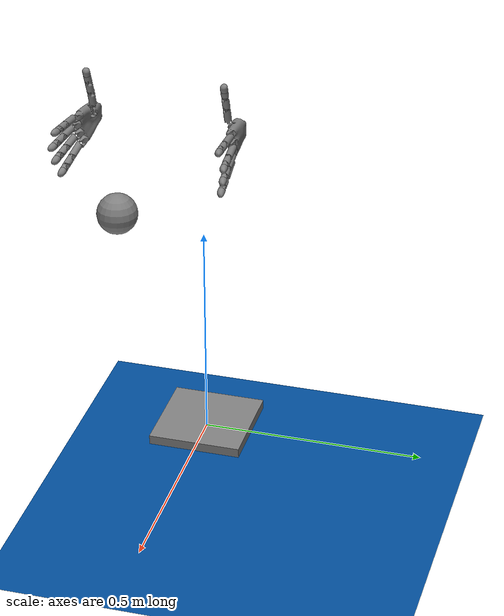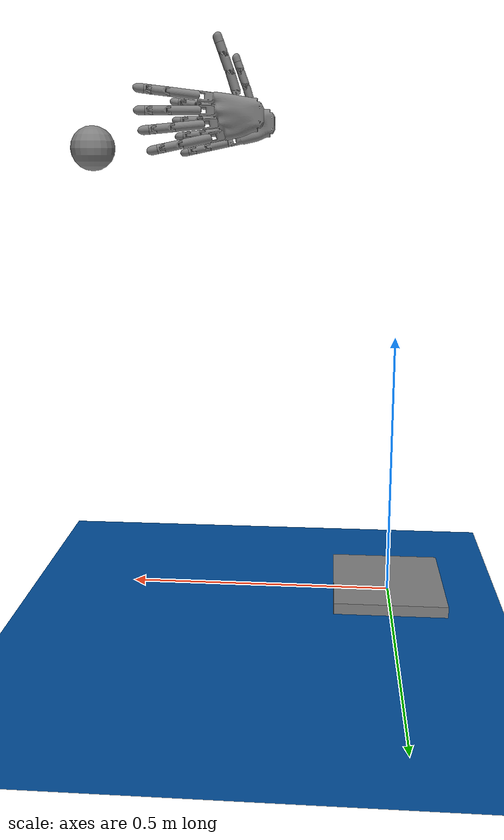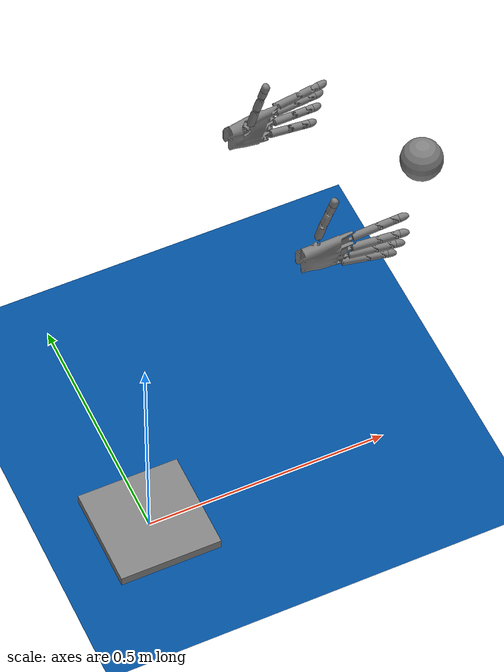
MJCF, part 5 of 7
<mesh name="mjlab scene/worldbody/robot/pelvis/robot/waist_yaw_link/robot/waist_roll_link/robot/torso_link/robot/left_shoulder_pitch_link/robot/left_shoulder_roll_link/robot/left_shoulder_yaw_link/robot/left_elbow_link/robot/left_wrist_roll_link/robot/left_wrist_pitch_link/robot/left_wrist_yaw_link/robot/xhand_mount_left/robot/left_palm_link/robot/left_finger3_link1/robot/left_finger3_link2/robot/left_finger3_link3/robot/left_finger3_link3_geom_0_135" vertex="0.00560767 0.00345276 0.00763047 0.00544658 0.00374729 0.00743627 0.00555 0.0035623 0.02385 -0.00798974 0.00284476 0.026728 -0.00790084 0.00305226 0.0270413 -0.00780534 0.00325813 0.0269917 -0.00851703 0.000702766 0.0271254 -0.008512 0.000754011 0.0272312 -0.00823492 0.00215102 0.0272312 -0.00802764 -0.00275 0.0263405 -0.00802764 -0.00275 0.0272312 -0.00843606 -0.00130236 0.0272312 0.00210165 -0.00680543 0.00247902 0.00232195 -0.00669951 0.002274 0.00231648 -0.00670094 0.0255765 0.00371999 -0.00578821 0.0251866 0.00331075 -0.00610191 0.0253425 0.00354374 -0.00592854 0.00441298 0.0031457 -0.00621633 0.0253951 0.00253735 -0.00658548 0.0255412 0.00340267 -0.0060352 0.00375767 0.00333581 -0.00608397 0.00308426 0.00247479 -0.00662116 0.00210663 0.00248959 -0.00661334 0.00208912 0.00334534 -0.00607709 0.00240297 0.00277398 -0.00645312 0.00169338 0.00343037 -0.00601468 0.00173609 0.00301117 -0.00630552 0.00122285 0.00358865 -0.00589347 0.00108817 0.00316849 -0.0062018 0.000723296 0.0037071 -0.00579886 0.000565613 0.00324273 -0.00615 0.000217315 0.00374973 -0.00576347 4.5031e-05 0.00325 -0.00614492 -2.74578e-10 0.00372075 -0.00578815 -0.000467491 0.00324273 -0.00615 -0.000217314 0.00366305 -0.0058359 -0.000802863 0.00318592 -0.00618983 -0.000642209 0.003621 -0.00586955 -0.000975103 0.00305172 -0.00627939 -0.00111782 0.00343092 -0.00601447 -0.00151369 0.00320541 -0.00617752 -0.00194625 0.00283444 -0.00641637 -0.0015901 0.00316104 -0.00620823 -0.0020175 0.00253525 -0.00658892 -0.00203348 0.00283858 -0.00641449 -0.00245051 0.00248953 -0.00661338 -0.0020892 0.00243315 -0.00664179 -0.00285347 0.00232342 -0.00669877 -0.00227249 0.0024025 -0.00665766 -0.00287932 0.000725274 -0.00728639 0.00316804 0.0012128 -0.00715046 0.00301523 0.00162525 -0.00700517 0.00281444 0.00168487 -0.00698209 0.00277916 -8.41228e-05 -0.00743664 0.0255009 -0.000564087 -0.0074839 0.00320067 -0.000332109 -0.00746534 0.00323299 0.000490477 -0.00733999 0.0255302 0.000197501 -0.0073954 0.00324399 0.000656526 -0.00730327 0.0255542 0.00191555 -0.00688775 0.0256173 0.00128751 -0.00712593 0.0256221 0.000679967 -0.00729727 0.00317807 0.000565091 -0.00732357 0.0032005 -0.00277728 -0.00729839 0.0265509 -0.00278491 -0.00729663 0.00167534 -0.0025016 -0.00735779 0.00207472 -0.00218308 -0.00741378 0.00240762 -0.00177466 -0.00746417 0.0027227 -0.00173441 -0.00746798 0.0258956 -0.00162513 -0.00747731 0.00281451 -0.00134533 -0.00749411 0.00295848 -0.000858984 -0.00749731 0.00313443 -0.000637986 -0.00748765 0.0255512 -0.00105345 -0.0074999 0.00307453 -0.00105221 -0.00749911 0.0256409 -0.00121142 -0.00749731 0.0256879 -0.00248965 -0.00736013 0.00208905 -0.00224713 -0.00740384 0.0261909 -0.00292417 -0.00726214 -0.00141835 -0.00339865 -0.00712277 -0.00158482 -0.00332937 -0.00714532 -0.00172562 -0.00278755 -0.00729601 -0.00167095 -0.00305393 -0.0072274 -0.00111176 -0.00311683 -0.00720987 -0.000920805 -0.00441599 -0.00670224 0.000596873 -0.00321832 -0.00718012 -0.000452697 -0.00325 -0.00717008 -3.65961e-08 -0.00305398 -0.00722739 0.00111163 -0.00283277 -0.00728513 0.00159309 -0.00441599 -0.00670224 0.0276637 -0.00324862 -0.00717054 9.4597e-05 -0.00319312 -0.00718776 0.000605381 -0.00306875 -0.00722332 0.00107017 -0.00361515 -0.00704769 0.0271198 -0.00108862 -0.00749964 -0.00358851 -0.00105239 -0.00749971 -0.0035993 -0.00105377 -0.0074999 -0.00307442 -0.00121095 -0.00749813 -0.0035491 -0.00135559 -0.00749369 -0.00295379 -0.00169278 -0.00747197 -0.00334619 -0.00162512 -0.00747731 -0.00281451 -0.0021927 -0.00741174 -0.00304213 -0.00177433 -0.0074642 -0.00272291 -0.00221591 -0.00740816 -0.00302527 -0.00220167 -0.00741095 -0.00239064 -0.002647 -0.00732787 -0.00265629 -0.00300365 -0.00724101 -0.00224512 -0.0027858 -0.00729602 -0.00251034 -0.00267707 -0.00732136 -0.00184277 -0.00248965 -0.00736013 -0.00208906 -0.00236579 -0.00738343 -0.00222834 0.00017337 -0.00739946 -0.00324537 -0.00033813 -0.00746591 -0.00323236 -0.000149011 -0.00744562 -0.00374704 -0.000648478 -0.00748881 -0.0036935 -0.000564103 -0.0074839 -0.00320067 -0.000846504 -0.00749697 -0.00313782 0.00231925 -0.00669983 -0.00294679 0.00213598 -0.00678953 -0.00244951 0.00200531 -0.00684784 -0.00316879 0.00172543 -0.00696609 -0.00275416 0.00162541 -0.00700512 -0.00281435 0.00149881 -0.00705351 -0.00343745 0.00121965 -0.00714828 -0.00301246 0.000133593 -0.00740596 -0.00374762 0.000403411 -0.00735745 -0.00372824 0.000565027 -0.00732358 -0.00320051 0.000681586 -0.00729675 -0.00368754 0.000703485 -0.00729166 -0.00317295 0.000990432 -0.00721658 -0.00361684 0.00134078 -0.00710865 -0.00350211 -0.00517132 -0.00626616 0.00221667 -0.00587091 -0.00574533 0.00371695 -0.00490408 -0.00643398 0.0279951 -0.00506543 -0.00633439 0.0280939 -0.00544486 -0.00607688 0.0282537 -0.00585921 -0.00575499 0.0283334 -0.00587086 -0.00574525 0.0283344 -0.0065053 -0.00514681 0.00507741 -0.00628725 -0.00536814 0.0283236 -0.00667938 -0.00495588 0.0282314 -0.00696595 -0.00461063 0.0281068 -0.00706592 -0.00447869 0.00627967 -0.00707758 -0.00446177 0.0280428 -0.00754519 -0.00375 0.00730746 -0.00740755 -0.00397853 0.0277882 -0.00757376 -0.00370027 0.0276092 -0.00794971 -0.00294004 0.0268934 -0.00793662 -0.0029706 0.00814688 -0.00782979 -0.00320692 0.0272079 -0.00766078 -0.00354211 0.027495 -0.00800992 -0.00279527 0.0266062 -0.0084361 -0.00129963 0.0094013 -0.00837751 -0.00159702 0.00918709 -0.00817523 -0.00234117 0.00865858 -0.00853733 0.000435052 0.010031 -0.0085491 0.000115799 0.026728 -0.00854079 0.000374339 0.0268112 -0.00853898 -0.000405775 0.0268284 -0.00854447 -0.000283661 0.0267709 -0.008512 -0.000754011 0.0272312 -0.00851733 -0.000698331 0.0271178 -0.00853225 -0.000516322 0.0269051 -0.00855 -1.25333e-12 0.0267197 -0.00855 -1.88811e-12 0.0103491 -0.00850249 -0.000841041 0.00973437 -0.00853913 0.000405759 0.0268284 -0.00853699 0.000442227 0.0268508 -0.00850577 0.000811567 0.00975587 -0.00852593 0.000600094 0.0269849 -0.00839408 0.00151899 0.00924313 -0.00823521 0.00214967 0.00879368 -0.00802764 0.00275 0.0272312 -0.00802764 0.00275 0.0263405 -0.00754519 0.00375 0.00730746 -0.00789654 0.00306183 0.00806094 -0.0075455 0.0037481 0.0276429 -0.00817523 0.00234117 0.00865858 -0.00818807 0.00230172 0.00868638 -0.00774942 0.00337114 0.0273581 -0.00802213 0.00276434 0.0264889 -0.00706592 0.00447869 0.00627967 -0.00752383 0.00378541 0.0276677 -0.00722445 0.00425777 0.0279429 -0.00697644 0.00459622 0.0281012 -0.00685411 0.00474934 0.0281618 -0.00650545 0.00514536 0.0282826 -0.00643648 0.00521765 0.0282983 -0.00587091 0.00574533 0.00371695 -0.0065053 0.00514681 0.00507741 -0.00621848 0.00543443 0.0283314 -0.00602416 0.00561316 0.0283405 -0.00562474 0.00594286 0.0282995 -0.0052496 0.00621374 0.028183 -0.00516865 0.00626778 0.0281467 -0.00517132 0.00626616 0.00221667 -0.00490408 0.00643398 0.0279951 -0.00441599 0.00670224 0.000596873 -0.00361515 0.00704769 0.0271198 -0.00361122 0.00704912 -0.00112897 -0.00208443 0.00742832 -0.00311713 -0.00219271 0.00741244 -0.00304168 -0.00192482 0.00744857 0.0259936 -0.00255217 0.00734803 -0.00274754 -0.00294765 0.00725596 -0.00232033 -0.00224713 0.00740384 0.0261909 -0.00210963 0.0074247 0.0261016 -0.00339865 0.00712277 -0.00158482 -0.00327451 0.00716251 -0.00182842 -0.00161207 0.00747855 0.0258392 -0.00139211 0.00749196 0.0257501 -0.00158565 0.00748085 -0.0033987 -0.00105 0.0075 0.0256403 0.00377174 -0.00574531 0.0251642 0.0037527 -0.00576056 0.00504025 0.00401631 -0.00553014 0.00561265 0.0046493 -0.00487524 0.00658237 0.00473077 -0.00478249 0.0246223 0.00463156 -0.00489997 0.0246907 0.00432476 -0.00523087 0.00613531 0.00421146 -0.00534739 0.0249471 0.00553784 -0.00358474 0.02385 0.00496472 -0.00448031 0.00694518 0.00583662 -0.0029706 0.02385 0.00499518 -0.00443912 0.00697724 0.00520219 -0.00414248 0.00718324 0.00545861 -0.00372633 0.00744994 0.00580201 -0.00304899 0.00790324 0.00583692 -0.00296935 0.00795781 0.00496848 -0.00447886 0.0244448 0.00520146 -0.0041457 0.02425 0.00553784 -0.00358474 0.0239263 0.00608256 -0.00231872 0.00841123 0.00627241 -0.00162115 0.00890728 0.00633606 -0.00130236 0.02385 0.00645 -1.89832e-12 0.0100859 0.00643731 0.000436086 0.02385 0.00640615 -0.000808428 0.00949521 0.00633614 -0.00130009 0.0091383 0.00643959 0.000394594 0.00979744 0.00643731 0.000435502 0.00976753 0.00613492 0.00215102 0.02385 0.00636002 0.00115643 0.00924224 0.00631719 0.00140346 0.00906372 0.00617716 0.00200436 0.00863392 0.00613527 0.00214985 0.00853065 0.00592452 0.00275751 0.00810406 0.00520219 0.00414247 0.00718324 0.00499256 0.00444242 0.00697442 0.00440605 0.00514602 0.0248337 0.00555 0.0035623 0.0239135 0.00544533 0.00374976 0.0240207 0.00527096 0.00403677 0.0241864 0.00482954 0.00465628 0.0245498 0.00402617 0.00552187 0.00563359 0.00307214 0.00626562 0.025416 0.00432272 0.00523348 0.00613415 0.00318163 0.0061922 0.0253836 0.00331021 0.00610234 0.0253424 0.00464653 0.00487823 0.00657899 0.00440118 0.00515154 0.00625006 0.00431881 0.00523697 0.0248855 0.00374733 0.00576503 0.0251747 0.00376386 0.00575159 0.00506816 0.00354466 0.00592777 0.00441806 0.0034053 0.00603357 0.00377383 0.00316975 0.0062003 -0.00200292 0.00307669 0.00626262 -0.00214338 0.00333655 0.00608343 -0.000527603 0.00366186 0.0058351 -0.000802922 0.00360938 0.00587709 -0.00101406 0.00342956 0.00601528 -0.00151632 0.0032051 0.00617609 -0.00194581 0.00333688 0.00608329 0.00310637 0.00334473 0.00607773 0.00241597 0.0034308 0.00601471 0.00173665 0.00358865 0.00589347 0.00108817 0.00370845 0.00579717 0.000559582 0.00375012 0.00576271 3.10146e-05 0.00371677 0.00579033 -0.000492064 0.00240249 0.0066581 -0.00287914 0.00151523 0.00704767 0.0256278 0.00242236 0.00664776 -0.00286247 0.00192752 0.00688363 0.0256151 0.00256124 0.00657335 0.0255355 0.00284195 0.00641114 -0.00244659 0.000133483 0.00740604 -0.00374833 -0.000179255 0.00744928 -0.00374675 8.04561e-05 0.00741431 0.0255008 0.000656526 0.00730327 0.0255542 0.00151693 0.00704705 -0.00342931 0.00144935 0.0070713 -0.0034584 0.00134063 0.00710879 -0.00350191 0.000892305 0.00724413 -0.00364143 0.000316982 0.00737437 -0.00373687 0.00193674 0.00687964 -0.00321048 0.00128907 0.00712592 0.0256216 -0.000247428 0.00745694 -0.00374286 -0.000804196 0.00749597 -0.00366301 -0.000501527 0.00747972 0.0255316 -0.00105 0.0075 -0.0036 -0.00108872 0.0074999 -0.00358848 0.0052 0.00103014 0.02385 0.00555 0.00103014 0.02385 0.0052 0.00174234 0.0244267 0.00555 0.00174234 0.0244267 0.0052 0.00216551 0.0252395 0.00555 0.00216551 0.0252395 0.0052 0.00225 0.0258503 0.00555 0.00222945 0.0261537 0.00555 -0.00222945 0.0261537 0.0052 -0.00222945 0.0261537 0.00555 -0.00192357 0.0270175 0.0052 -0.00192357 0.0270175 0.00555 -0.00129859 0.0276878 0.0052 -0.00129859 0.0276878 0.00555 -0.0004582 0.0280532 0.0052 -0.0004582 0.0280532 0.00555 0.0004582 0.0280532 0.0052 0.0004582 0.0280532 0.00555 0.00129859 0.0276878 0.0052 0.00129859 0.0276878 0.00555 0.00192357 0.0270175 0.0052 0.00192357 0.0270175 0.0052 0.00222945 0.0261537 0.00555 -0.00103014 0.02385 0.0052 -0.00103014 0.02385 0.00555 -0.00174234 0.0244267 0.0052 -0.00174234 0.0244267 0.00555 -0.00216551 0.0252395 0.0052 -0.00216551 0.0252395 0.0052 -0.00225 0.0258503 0.00555 -1.35996e-12 0.0239503 0.00555 -0.000447542 0.0240038 0.00543933 -0.000203705 0.02385 0.00555 -0.000869899 0.0241612 0.00555 -0.00147131 0.0246481 0.00555 -0.00182865 0.0253345 0.00555 -0.0019 0.0258503 0.00555 -0.00188265 0.0261065 0.00555 -0.00162435 0.026836 0.00555 -0.00109659 0.0274019 0.00555 -0.000386925 0.0277105 0.00555 0.000386925 0.0277105 0.00555 0.00109659 0.0274019 0.00555 0.00162435 0.026836 0.00555 0.00188265 0.0261065 0.00555 0.0019 0.0258503 0.00555 0.00182865 0.0253345 0.00555 0.00147131 0.0246481 0.00555 0.000869899 0.0241612 0.00555 0.000447542 0.0240038 0.00537271 0.000560194 0.02385 0.00358865 0.00335 0.00108817 0.00336436 0.00335 0.00219251 0.00338677 0.00335 0.0036492 0.0037596 0.00335 0.00505755 0.00406182 0.00335 0.0057 0.00406182 -0.00315 0.0057 0.00338677 -0.00315 0.0036492 0.0037596 -0.00315 0.00505755 0.00336436 -0.00315 0.00219251 0.00358865 -0.00315 0.00108817 0.00366324 -0.00315 -0.000801997 0.00320577 -0.00315 -0.00194565 0.000132756 -0.00315 -0.00374765 -0.00339865 -0.00315 -0.00158482 -0.00306006 -0.00315 -0.00216761 -0.00219265 -0.00315 -0.00304217 -0.00108868 -0.00315 -0.00358849 0.00133987 -0.00315 -0.00350246 0.00240242 -0.00315 -0.00287939 0.00372547 -0.00315 0.00042819 -3.74391e-11 0.00335 -0.0015 -0.00075 -0.00315 -0.00129904 -0.00075 0.00335 -0.00129904 -0.00129904 -0.00315 -0.00075 -0.00129904 0.00335 -0.00075 -0.0015 -0.00315 -2.74694e-10 -0.0015 0.00335 -2.74946e-10 -0.00129904 -0.00315 0.00075 -0.00129904 0.00335 0.00075 -0.00075 -0.00315 0.00129904 -0.00075 0.00335 0.00129904 -3.74391e-11 -0.00315 0.0015 -3.74391e-11 0.00335 0.0015 0.00075 -0.00315 0.00129904 0.00075 0.00335 0.00129904 0.00129904 -0.00315 0.00075 0.00129904 0.00335 0.00075 0.0015 -0.00315 -2.74694e-10 0.0015 0.00335 -2.74946e-10 0.00129904 -0.00315 -0.00075 0.00129904 0.00335 -0.00075 0.00075 -0.00315 -0.00129904 0.00075 0.00335 -0.00129904 -3.74391e-11 -0.00315 -0.0015 0.00106245 -0.00615 0.00307143 0.001625 -0.00615 0.00281458 -5.21122e-05 -0.00615 0.00324958 0.000564357 -0.00615 0.00320062 0.003054 -0.00615 -0.00111157 0.00320926 -0.00615 -0.000512963 0.00248964 -0.00615 -0.00208906 0.00284028 -0.00615 -0.00157966 0.001625 -0.00615 -0.00281458 0.00212871 -0.00615 -0.00245583 0.00116039 -0.00615 -0.00303578 0.000564357 -0.00615 -0.00320063 5.21122e-05 -0.00615 -0.00324958 -0.000564357 -0.00615 -0.00320063 -0.00106245 -0.00615 -0.00307143 -0.001625 -0.00615 -0.00281458 -0.00204887 -0.00615 -0.00252282 -0.00248964 -0.00615 -0.00208906 -0.00278816 -0.00615 -0.00166992 -0.003054 -0.00615 -0.00111157 -0.003054 -0.00615 0.00111157 -0.00320926 -0.00615 0.000512964 -0.00325 -0.00615 -2.74577e-10 -0.00319116 -0.00615 -0.000615605 -0.00284028 -0.00615 0.00157966 -0.00248964 -0.00615 0.00208906 -0.001625 -0.00615 0.00281458 -0.00212871 -0.00615 0.00245583 -0.00116039 -0.00615 0.00303579 -0.000564357 -0.00615 0.00320062 0.00248964 -0.00615 0.00208906 0.00204887 -0.00615 0.00252282 0.00278816 -0.00615 0.00166992 0.003054 -0.00615 0.00111157 0.00319116 -0.00615 0.000615605 0.000656526 -0.00275 0.0255542 -0.000304654 -0.00275 0.0255116 -0.00139195 -0.00275 0.02575 -0.00224713 -0.00275 0.0261909 0.00555 -0.00353695 0.02385 0.00555 -0.00353695 0.0239135 0.00554464 -0.00356924 0.0239192 0.000656526 0.00275 0.0255542 -0.000304654 0.00275 0.0255116 -0.00224713 0.00275 0.0261909 -0.00139195 0.00275 0.02575 -0.00490408 0.00275 0.0279951 -0.00542548 0.00275 0.0282477 -0.00795102 0.00275 0.0268888 -0.00758601 0.00275 0.0275941 -0.0069753 0.00275 0.0281018 -0.00621517 0.00275 0.0283317 -0.00108868 0.00335 -0.00358849 0.000132756 0.00335 -0.00374765 -0.00219265 0.00335 -0.00304217 -0.00306006 0.00335 -0.00216761 -0.00339865 0.00335 -0.00158482 0.00372547 0.00335 0.00042819 0.00366324 0.00335 -0.000801997 0.00320577 0.00335 -0.00194565 0.00240242 0.00335 -0.00287939 0.00133987 0.00335 -0.00350246 -0.00110684 -0.0063 0.00289567 -4.97071e-05 -0.0063 0.0030996 -0.00203046 -0.0063 0.00234248 -0.00270919 -0.0063 0.00150675 -0.00306114 -0.0063 0.000489289 -0.00304388 -0.0063 -0.000587192 -0.00265948 -0.0063 -0.00159285 -0.00195431 -0.0063 -0.00240638 -0.00101342 -0.0063 -0.00292967 4.9707e-05 -0.0063 -0.0030996 0.00110684 -0.0063 -0.00289567 0.00203046 -0.0063 -0.00234248 0.00270919 -0.0063 -0.00150675 0.00306114 -0.0063 -0.000489288 0.00325 -0.00615 -2.74577e-10 0.00304388 -0.0063 0.000587192 0.00265948 -0.0063 0.00159285 0.00195431 -0.0063 0.00240638 0.00101342 -0.0063 0.00292967 -0.001696 -0.0053 0.00147854 -0.000947998 -0.0053 0.00204054 -0.000941377 -0.00545 0.00187718 -0.00158293 -0.00545 0.00137997 -0.00166263 -0.00545 0.00128283 -0.00215075 -0.0053 0.000660887 -0.00200737 -0.00545 0.000616828 -0.00205458 -0.00545 0.000434406 -0.00223362 -0.0053 -0.000271038 -0.00208471 -0.00545 -0.00025297 -0.00203959 -0.00545 -0.000500062 -0.00193027 -0.0053 -0.0011561 -0.00180158 -0.00545 -0.00107903 -0.00162064 -0.00545 -0.00133549 -0.00129316 -0.0053 -0.00184126 -0.00120695 -0.00545 -0.00171851 -0.000880701 -0.00545 -0.0019064 -0.000432452 -0.0053 -0.00220805 -0.000403622 -0.00545 -0.00206085 3.60777e-05 -0.0053 -0.00224971 3.36725e-05 -0.00545 -0.00209973 0.00050303 -0.0053 -0.00219305 0.000469495 -0.00545 -0.00204685 0.00135153 -0.0053 -0.00179885 0.000941376 -0.00545 -0.00187718 0.00126143 -0.00545 -0.00167893 0.00196635 -0.0053 -0.00109361 0.00166263 -0.00545 -0.00128283 0.00183526 -0.00545 -0.0010207 0.00224116 -0.0053 -0.000199279 0.00205458 -0.00545 -0.000434405 0.00209175 -0.00545 -0.000185994 0.00212845 -0.0053 0.000729511 0.00203959 -0.00545 0.000500062 0.00198656 -0.00545 0.000680877 0.00164772 -0.0053 0.00153216 0.00162064 -0.00545 0.00133549 0.00153787 -0.00545 0.00143002 0.000882081 -0.0053 0.00206989 0.000880701 -0.00545 0.0019064 0.000823276 -0.00545 0.00193189 -3.60777e-05 -0.0053 0.00224971 -3.36725e-05 -0.00545 0.00209973 -0.000884799 -0.00545 0.0019045 0.000434406 -0.00615 0.00205458 0.000880701 -0.00615 0.0019064 0.00128283 -0.00615 0.00166263 0.00162064 -0.00615 0.00133549 0.00187718 -0.00615 0.000941377 0.00203959 -0.00615 0.000500062 0.00209973 -0.00615 3.36726e-05 0.00205458 -0.00615 -0.000434405 0.0019064 -0.00615 -0.000880701 0.00166263 -0.00615 -0.00128283 0.00133549 -0.00615 -0.00162064 0.000941376 -0.00615 -0.00187718 0.000500062 -0.00615 -0.00203959 3.36725e-05 -0.00615 -0.00209973 -0.000434406 -0.00615 -0.00205458 -0.000880701 -0.00615 -0.0019064 -0.00128283 -0.00615 -0.00166263 -0.00162064 -0.00615 -0.00133549 -0.00187718 -0.00615 -0.000941376 -0.00203959 -0.00615 -0.000500062 -0.00209973 -0.00615 -3.36722e-05 -0.00205458 -0.00615 0.000434406 -0.0019064 -0.00615 0.000880701 -0.00166263 -0.00615 0.00128283 -0.00133549 -0.00615 0.00162064 -0.000941377 -0.00615 0.00187718 -0.000500062 -0.00615 0.00203959 -3.36725e-05 -0.00615 0.00209973 -0.000535781 -0.0063 0.00218528 -0.00100862 -0.0063 0.00201127 -0.00143088 -0.0063 0.0017364 -0.00178139 -0.0063 0.00137447 -0.00204257 -0.0063 0.000943608 -0.00220133 -0.0063 0.000465435 -0.00224971 -0.0063 -3.60778e-05 -0.00218528 -0.0063 -0.000535781 -0.00201127 -0.0063 -0.00100862 -0.0017364 -0.0063 -0.00143088 -0.00137447 -0.0063 -0.00178139 -0.000943608 -0.0063 -0.00204257 -0.000465435 -0.0063 -0.00220133 3.60777e-05 -0.0063 -0.00224971 0.000535781 -0.0063 -0.00218528 0.00100862 -0.0063 -0.00201127 0.00143088 -0.0063 -0.0017364 0.00178139 -0.0063 -0.00137446 0.00204257 -0.0063 -0.000943608 0.00220133 -0.0063 -0.000465434 0.00224971 -0.0063 3.60773e-05 0.00218528 -0.0063 0.000535781 0.00201127 -0.0063 0.00100862 0.0017364 -0.0063 0.00143088 0.00137447 -0.0063 0.00178139 0.000943608 -0.0063 0.00204257 0.000465435 -0.0063 0.00220133 -3.60777e-05 -0.0063 0.00224971 -0.000824379 -0.0053 -0.00171184 -3.74391e-11 -0.0053 -0.0019 -0.00042279 -0.0071 -0.00185236 -0.000824379 -0.0071 -0.00171184 -0.00118463 -0.0071 -0.00148548 -0.00148548 -0.0053 -0.00118463 -0.00148548 -0.0071 -0.00118463 -0.00171184 -0.0071 -0.000824379 -0.00185236 -0.0053 -0.00042279 -0.00185236 -0.0071 -0.00042279 -0.0019 -0.0071 -2.74541e-10 -0.00185236 -0.0053 0.000422789 -0.00185236 -0.0071 0.000422789 -0.00171184 -0.0071 0.000824379 -0.00148548 -0.0053 0.00118463 -0.00148548 -0.0071 0.00118463 -0.00118463 -0.0071 0.00148548 -0.000824379 -0.0053 0.00171184 -0.000824379 -0.0071 0.00171184 -0.00042279 -0.0071 0.00185236 -3.74391e-11 -0.0053 0.0019 -3.74391e-11 -0.0071 0.0019 0.00042279 -0.0071 0.00185236 0.000824379 -0.0053 0.00171184 0.000824379 -0.0071 0.00171184 0.00118463 -0.0071 0.00148548 0.00148548 -0.0053 0.00118463 0.00148548 -0.0071 0.00118463 0.00171184 -0.0071 0.000824379 0.00185236 -0.0053 0.000422789 0.00185236 -0.0071 0.000422789 0.0019 -0.0071 -2.74541e-10 0.00185236 -0.0053 -0.00042279 0.00185236 -0.0071 -0.00042279 0.00171184 -0.0071 -0.000824379 0.00148548 -0.0053 -0.00118463 0.00148548 -0.0071 -0.00118463 0.00118463 -0.0071 -0.00148548 0.000824379 -0.0053 -0.00171184 0.000824379 -0.0071 -0.00171184 0.00042279 -0.0071 -0.00185236 -3.74391e-11 -0.0071 -0.0019 -0.000416827 -0.0072 -0.00182624 -0.000812753 -0.0072 -0.0016877 -0.00116792 -0.0072 -0.00146453 -0.00146453 -0.0072 -0.00116792 -0.0016877 -0.0072 -0.000812753 -0.00182624 -0.0072 -0.000416828 -0.00187321 -0.0072 -2.74537e-10 -0.00182624 -0.0072 0.000416827 -0.0016877 -0.0072 0.000812753 -0.00146453 -0.0072 0.00116792 -0.00116792 -0.0072 0.00146453 -0.000812753 -0.0072 0.0016877 -0.000416827 -0.0072 0.00182624 -3.74391e-11 -0.0072 0.00187321 0.000416827 -0.0072 0.00182624 0.000812753 -0.0072 0.0016877 0.00116792 -0.0072 0.00146453 0.00146453 -0.0072 0.00116792 0.0016877 -0.0072 0.000812753 0.00182624 -0.0072 0.000416827 0.00187321 -0.0072 -2.74537e-10 0.00182624 -0.0072 -0.000416828 0.0016877 -0.0072 -0.000812753 0.00146453 -0.0072 -0.00116792 0.00116792 -0.0072 -0.00146453 0.000812753 -0.0072 -0.0016877 0.000416827 -0.0072 -0.00182624 -3.74391e-11 -0.0072 -0.0018732 -0.000400538 -0.00727321 -0.00175487 -0.000780991 -0.00727321 -0.00162174 -0.00112228 -0.00727321 -0.0014073 -0.0014073 -0.00727321 -0.00112228 -0.00162174 -0.00727321 -0.000780991 -0.00175487 -0.00727321 -0.000400538 -0.0018 -0.00727321 -2.74534e-10 -0.00175487 -0.00727321 0.000400537 -0.00162174 -0.00727321 0.000780991 -0.0014073 -0.00727321 0.00112228 -0.00112228 -0.00727321 0.0014073 -0.000780991 -0.00727321 0.00162174 -0.000400538 -0.00727321 0.00175487 -3.74391e-11 -0.00727321 0.0018 0.000400538 -0.00727321 0.00175487 0.000780991 -0.00727321 0.00162174 0.00112228 -0.00727321 0.0014073 0.0014073 -0.00727321 0.00112228 0.00162174 -0.00727321 0.000780991 0.00175487 -0.00727321 0.000400537 0.0018 -0.00727321 -2.74534e-10 0.00175487 -0.00727321 -0.000400538 0.00162174 -0.00727321 -0.000780991 0.0014073 -0.00727321 -0.00112228 0.00112228 -0.00727321 -0.0014073 0.000780991 -0.00727321 -0.00162174 0.000400538 -0.00727321 -0.00175487 -3.74391e-11 -0.00727321 -0.0018 -0.000378286 -0.0073 -0.00165738 -0.000737602 -0.0073 -0.00153165 -0.00105993 -0.0073 -0.00132911 -0.00132911 -0.0073 -0.00105993 -0.00153165 -0.0073 -0.000737602 -0.00165738 -0.0073 -0.000378286 -0.0017 -0.0073 -2.74533e-10 -0.00165738 -0.0073 0.000378285 -0.00153165 -0.0073 0.000737603 -0.00132911 -0.0073 0.00105993 -0.00105993 -0.0073 0.00132911 -0.000737602 -0.0073 0.00153165 -0.000378286 -0.0073 0.00165738 -3.74391e-11 -0.0073 0.0017 0.000378286 -0.0073 0.00165738 0.000737602 -0.0073 0.00153165 0.00105993 -0.0073 0.00132911 0.00132911 -0.0073 0.00105993 0.00153165 -0.0073 0.000737603 0.00165738 -0.0073 0.000378285 0.0017 -0.0073 -2.74533e-10 0.00165738 -0.0073 -0.000378286 0.00153165 -0.0073 -0.000737602 0.00132911 -0.0073 -0.00105993 0.00105993 -0.0073 -0.00132911 0.000737602 -0.0073 -0.00153165 0.000378286 -0.0073 -0.00165738 -3.74391e-11 -0.0073 -0.0017 -3.74387e-11 0.00275 0.028 -3.74387e-11 -0.00275 0.028 0.00075 0.00275 0.028201 0.00075 -0.00275 0.028201 0.00129904 0.00275 0.02875 0.00129904 -0.00275 0.02875 0.0015 0.00275 0.0295 0.0015 -0.00275 0.0295 0.00129904 0.00275 0.03025 0.00129904 -0.00275 0.03025 0.00075 0.00275 0.030799 0.00075 -0.00275 0.030799 -3.74386e-11 0.00275 0.031 -3.74386e-11 -0.00275 0.031 -0.00075 0.00275 0.030799 -0.00075 -0.00275 0.030799 -0.00129904 0.00275 0.03025 -0.00129904 -0.00275 0.03025 -0.0015 0.00275 0.0295 -0.0015 -0.00275 0.0295 -0.00129904 0.00275 0.02875 -0.00129904 -0.00275 0.02875 -0.00075 0.00275 0.028201 -0.00075 -0.00275 0.028201 -0.00850352 -0.000806454 0.0274408 -0.00835 -0.0008115 0.0275312 -0.00835 -0.00070278 0.0271255 -0.00835 -0.00040575 0.0268284 -0.00835 0.00040575 0.0268284 -0.00835 -1.25333e-12 0.0267197 -0.00835 0.00070278 0.0271255 -0.00835 0.0008115 0.0275312 -0.00849991 0.0008115 0.0275312 -0.00850226 0.000809361 0.0274723 -0.0085118 0.000755952 0.0272361 -0.00835 0.00070278 0.027937 -0.00848358 0.000702781 0.027937 -0.00849173 0.000785451 0.0277352 -0.00846908 0.000265938 0.0282979 -0.00847168 0.000405757 0.028234 -0.00835 0.00040575 0.028234 -0.00847454 0.000510114 0.0281623 -0.00848219 0.00068183 0.0279712 -0.00846718 -1.02474e-05 0.0283426 -0.00835 -1.19038e-12 0.0283427 -0.00846929 -0.000280273 0.0282928 -0.00835 -0.00040575 0.028234 -0.00847168 -0.000405757 0.028234 -0.00849991 -0.0008115 0.0275312 -0.00849297 -0.000792856 0.0277042 -0.00835 -0.00070278 0.027937 -0.00848358 -0.00070278 0.027937 -0.0084748 -0.000518011 0.0281559 -0.00835 -0.000519615 0.0275312 -0.00835 -0.000259811 0.0270812 -0.00835 0.000259804 0.0270812 -0.00835 0.000519615 0.0275312 -0.00835 0.000259811 0.0279812 -0.00835 -0.000259804 0.0279812 -0.00635 0.000519615 0.0275312 -0.00635 0.000259804 0.0270812 -0.00635 -0.000259811 0.0270812 -0.00635 -0.000519615 0.0275312 -0.00635 0.000259811 0.0279812 -0.00635 -0.000259804 0.0279812 0.00555 0.00072984 0.0261779 0.00555 8.11942e-05 0.0266462 0.00555 -8.11942e-05 0.0250545 0.00555 0.000648646 0.0253821 0.00555 -0.00072984 0.0255227 0.00555 -0.000648646 0.0263186 0.00535 0.000648646 0.0253821 0.00535 0.00072984 0.0261779 0.00535 -8.11942e-05 0.0250545 0.00535 8.11942e-05 0.0266462 0.00535 -0.00072984 0.0255227 0.00535 -0.000648646 0.0263186 0.000866025 -0.0073 -2.74533e-10 -0.000433013 -0.0073 0.00075 -0.000866025 -0.0073 -2.74533e-10 0.000433013 -0.0073 0.00075 -0.000433013 -0.0073 -0.00075 0.000433013 -0.0073 -0.00075 -3.74391e-11 -0.00623438 -2.74574e-10 -0.000866025 -0.0063 -2.74572e-10 -0.000433013 -0.0063 -0.00075 -0.000433013 -0.0063 0.00075 0.000433013 -0.0063 0.00075 0.000866025 -0.0063 -2.74572e-10 0.000433013 -0.0063 -0.00075 -0.00835577 -0.00169491 0.0272859 0.00553784 -0.00263307 0.0296632 0.00553609 -0.00275 0.0295357 0.00553784 -0.00275 0.0295307 0.00553784 0.000121699 0.0308128 0.00553784 0.000559887 0.0307706 0.00550872 0.000569346 0.0308241 0.00553784 0.00275 0.0295307 0.00553608 0.00275 0.0295357 0.00553784 0.00249225 0.0298073 0.00506958 0.00275 0.0305835 0.00553784 0.00216046 0.0300906 0.00553784 0.000989609 0.0306754 0.00535754 0.00169491 0.0307413 0.00553784 0.00140419 0.0305285 0.00553784 0.00179569 0.0303326 0.00553784 -0.000750548 0.0307347 0.00553784 -0.000317971 0.0308011 0.00550873 -0.000569344 0.0308241 0.00553784 -0.00231053 0.0299692 0.00553784 -0.00195248 0.030233 0.00535754 -0.00169491 0.0307413 0.00553784 -0.00117175 0.0306155 0.00506958 -0.00275 0.0305835 0.00482581 -0.00275 0.0309945 0.00443774 -0.00275 0.0315407 0.00469596 -0.00169491 0.0317435 0.00387914 -0.00169491 0.0326239 0.00379401 -0.00275 0.0322534 0.00292913 -0.00169491 0.0333585 0.00275031 -0.00275 0.0330831 -0.00165044 -0.00169491 0.0345124 -0.000590535 -0.00275 0.0341937 -0.00044953 -0.00169491 0.0345124 0.000654933 -0.00275 0.0339973 0.000735159 -0.00169491 0.0343157 0.00101009 -0.00275 0.0338978 0.00187161 -0.00169491 0.0339276 0.00174032 -0.00275 0.0336266 0.00249861 -0.00275 0.0332391 -0.00519203 -0.00275 0.0328464 -0.00485029 -0.00275 0.0330831 -0.00502911 -0.00169491 0.0333585 -0.00377834 -0.00275 0.0336533 -0.00397159 -0.00169491 0.0339276 -0.00275491 -0.00275 0.0339973 -0.00283513 -0.00169491 0.0343157 -0.00221617 -0.00275 0.0341107 -0.00162346 -0.00275 0.0341852 -0.0057576 -0.00275 0.0323815 -0.00597912 -0.00169491 0.0326239 -0.00638031 -0.00275 0.031734 -0.00679595 -0.00169491 0.0317435 -0.00653772 -0.00275 0.0315408 -0.00745753 -0.00169491 0.0307413 -0.00716957 -0.00275 0.0305836 -0.00792463 -0.00275 0.0284257 -0.00824812 -0.00169491 0.0284819 -0.00783778 -0.00275 0.0288478 -0.00794598 -0.00169491 0.0296442 -0.00763608 -0.00275 0.0295358 -0.00727852 -0.00275 0.0303765 -0.00841796 0.000569344 0.0285114 -0.00841796 -0.000569346 0.0285114 -0.00824812 0.00169491 0.0284819 -0.00830306 0.00189653 0.0274465 -0.00783778 0.00275 0.0288478 -0.00792463 0.00275 0.0284257 -0.00763608 0.00275 0.0295358 -0.00794598 0.00169491 0.0296442 -0.00727852 0.00275 0.0303765 -0.00745753 0.00169491 0.0307413 -0.00716957 0.00275 0.0305836 -0.00679595 0.00169491 0.0317435 -0.00653772 0.00275 0.0315408 -0.00283513 0.00169491 0.0343157 -0.00377833 0.00275 0.0336533 -0.00397159 0.00169491 0.0339276 -0.00485029 0.00275 0.0330831 -0.00502911 0.00169491 0.0333585 -0.00519203 0.00275 0.0328464 -0.00597912 0.00169491 0.0326239 -0.0057576 0.00275 0.0323815 -0.00638031 0.00275 0.031734 -0.00162346 0.00275 0.0341852 -0.00221616 0.00275 0.0341107 -0.00275491 0.00275 0.0339973 0.0010101 0.00275 0.0338978 0.000654932 0.00275 0.0339973 0.000735158 0.00169491 0.0343157 -0.000590531 0.00275 0.0341937 -0.000449531 0.00169491 0.0345124 -0.00165044 0.00169491 0.0345124 0.00174032 0.00275 0.0336266 0.00187161 0.00169491 0.0339276 0.00249861 0.00275 0.0332391 0.00292913 0.00169491 0.0333585 0.00275031 0.00275 0.0330831 0.00387914 0.00169491 0.0326239 0.00379402 0.00275 0.0322534 0.00469596 0.00169491 0.0317435 0.00443774 0.00275 0.0315407 0.00482581 0.00275 0.0309945 0.00483154 -0.000569344 0.03185 0.00399544 -0.000569344 0.0327511 0.00302302 -0.000569345 0.0335031 0.00194055 -0.000569345 0.0340856 0.000777279 -0.000569345 0.0344829 -0.000435362 -0.000569345 0.0346842 -0.00166461 -0.000569345 0.0346842 -0.00287725 -0.000569346 0.0344829 -0.00404052 -0.000569346 0.0340856 -0.00512299 -0.000569346 0.0335031 -0.00609542 -0.000569346 0.0327511 -0.00693152 -0.000569346 0.03185 -0.00760871 -0.000569346 0.0308241 -0.00810869 -0.000569346 0.0297011 0.00483154 0.000569346 0.03185 0.00399544 0.000569346 0.0327511 0.00302302 0.000569346 0.0335031 0.00194055 0.000569345 0.0340856 0.000777279 0.000569345 0.0344829 -0.000435362 0.000569345 0.0346842 -0.00166461 0.000569345 0.0346842 -0.00287725 0.000569344 0.0344829 -0.00404052 0.000569344 0.0340856 -0.00512299 0.000569344 0.0335031 -0.00609542 0.000569344 0.0327511 -0.00693152 0.000569344 0.03185 -0.00760871 0.000569344 0.0308241 -0.00810869 0.000569344 0.0297011 0.00554704 0.00275 0.0294936 0.00554304 0.00248448 0.0297993 0.00554304 0.00215373 0.0300817 0.00554304 0.0017901 0.030323 0.00554304 0.00139981 0.0305183 0.00554304 0.000986526 0.0306647 0.00554304 0.000558142 0.0307595 0.00554304 0.00012132 0.0308017 0.00554304 -0.000316981 0.0307899 0.00554304 -0.00074821 0.0307238 0.00554304 -0.0011681 0.0306049 0.00554304 -0.0019464 0.0302237 0.00554304 -0.00230333 0.0299607 0.00554304 -0.00262486 0.0296557 0.00554704 -0.00275 0.0294936 0.00555 0.00275 0.0294555 0.00555 0.00245902 0.0297729 0.00555 0.00213165 0.0300525 0.00555 0.00177175 0.0302913 0.00555 0.00138547 0.0304846 0.00555 0.000976414 0.0306295 0.00555 0.000552422 0.0307234 0.00555 0.000120077 0.0307651 0.00555 -0.000313732 0.0307535 0.00555 -0.00074054 0.030688 0.00555 -0.00115613 0.0305704 0.00555 -0.00192644 0.030193 0.00555 -0.00227972 0.0299327 0.00555 -0.00259796 0.0296308 0.00555 -0.00275 0.0294555 0.00462892 -0.00275 0.0246925 0.00555 -0.00275 0.0239135 0.00330767 -0.00275 0.0253435 0.00186103 -0.00275 0.0256205 0.00555 0.00275 0.0239135 -0.00679562 0.00335 0.0057 -0.00679562 -0.00315 0.0057 0.00330767 0.00275 0.0253435 0.00186103 0.00275 0.0256205 0.00462892 0.00275 0.0246925 -0.00620697 -0.00275 0.0283325 -0.00542218 -0.00275 0.0282467 -0.00490408 -0.00275 0.0279951 -0.00696382 -0.00275 0.0281079 -0.00757481 -0.00275 0.0276079 -0.00794471 -0.00275 0.0269105 -0.00384312 -0.00459265 0.00326 -0.00405735 -0.00480688 0.00326 -0.00435 -0.0043 0.00326 -0.00435 -0.00488529 0.00326 -0.00464265 -0.00480688 0.00326 -0.00405735 -0.00379312 0.00326 -0.00384312 -0.00400735 0.00326 -0.00376471 -0.0043 0.00326 -0.00485688 -0.00400735 0.00326 -0.00464265 -0.00379312 0.00326 -0.00435 -0.00371471 0.00326 -0.00485688 -0.00459265 0.00326 -0.00493529 -0.0043 0.00326 -0.00379964 -0.00398225 0.0032 -0.00403225 -0.00374964 0.0032 -0.00435 -0.0043 0.0032 -0.00435 -0.0036645 0.0032 -0.00466775 -0.00374964 0.0032 -0.00403225 -0.00485036 0.0032 -0.00379964 -0.00461775 0.0032 -0.0037145 -0.0043 0.0032 -0.00490036 -0.00461775 0.0032 -0.00466775 -0.00485036 0.0032 -0.00435 -0.0049355 0.0032 -0.00490036 -0.00398225 0.0032 -0.0049855 -0.0043 0.0032 -0.00435 -0.0049355 0.00330673 -0.00403225 -0.00485036 0.00330673 -0.00379964 -0.00461775 0.00330673 -0.0037145 -0.0043 0.00330673 -0.00379964 -0.00398225 0.00330673 -0.00403225 -0.00374964 0.00330673 -0.00435 -0.0036645 0.00330673 -0.00466775 -0.00374964 0.00330673 -0.00490036 -0.00398225 0.00330673 -0.0049855 -0.0043 0.00330673 -0.00490036 -0.00461775 0.00330673 -0.00466775 -0.00485036 0.00330673 -3.74392e-11 -0.0053 -0.00325 -3.74392e-11 -0.0053 -0.0031 -0.00111157 -0.0053 -0.003054 -0.00106026 -0.0053 -0.00291305 -0.00208906 -0.0053 -0.00248964 -0.00199264 -0.0053 -0.00237474 -0.00281458 -0.0053 -0.001625 -0.00268468 -0.0053 -0.00155 -0.00320063 -0.0053 -0.000564357 -0.0030529 -0.0053 -0.000538309 -0.00320063 -0.0053 0.000564357 -0.0030529 -0.0053 0.00053831 -0.00281458 -0.0053 0.001625 -0.00268468 -0.0053 0.00155 -0.00208906 -0.0053 0.00248964 -0.00199264 -0.0053 0.00237474 -0.00111157 -0.0053 0.003054 -0.00106026 -0.0053 0.00291305 -3.74391e-11 -0.0053 0.00325 -4.97071e-05 -0.0053 0.0030996 -3.74391e-11 -0.0053 0.0031 0.00111157 -0.0053 0.003054 0.00106026 -0.0053 0.00291305 0.00208906 -0.0053 0.00248964 0.00199264 -0.0053 0.00237474 0.00281458 -0.0053 0.001625 0.00268468 -0.0053 0.00155 0.00320063 -0.0053 0.000564357 0.0030529 -0.0053 0.00053831 0.00320063 -0.0053 -0.000564357 0.0030529 -0.0053 -0.000538309 0.00281458 -0.0053 -0.001625 0.00268468 -0.0053 -0.00155 0.00208906 -0.0053 -0.00248964 0.00199264 -0.0053 -0.00237474 0.00111157 -0.0053 -0.003054 0.00106026 -0.0053 -0.00291305 4.9707e-05 -0.0053 -0.0030996 -5.21122e-05 -0.00545 0.00324958 -0.00111157 -0.00545 0.003054 -0.00208906 -0.00545 0.00248964 -0.00281458 -0.00545 0.001625 -0.00320063 -0.00545 0.000564357 -0.00320063 -0.00545 -0.000564357 -0.00281458 -0.00545 -0.001625 -0.00208906 -0.00545 -0.00248964 -0.00111157 -0.00545 -0.003054 -3.74392e-11 -0.00545 -0.00325 5.21122e-05 -0.00545 -0.00324958 0.00111157 -0.00545 -0.003054 0.00208906 -0.00545 -0.00248964 0.00281458 -0.00545 -0.001625 0.00320063 -0.00545 -0.000564357 0.00320063 -0.00545 0.000564357 0.00281458 -0.00545 0.001625 0.00208906 -0.00545 0.00248964 0.00111157 -0.00545 0.003054 -3.74391e-11 -0.00545 0.00325 -0.000483375 -0.0053 -0.00083723 -0.00067126 -0.0053 -0.00116266 -0.00083723 -0.0053 -0.000483375 -0.00116266 -0.0053 -0.00067126 -0.00096675 -0.0053 -2.7461e-10 -0.00134252 -0.0053 -2.7461e-10 -0.00083723 -0.0053 0.000483375 -0.00116266 -0.0053 0.00067126 -0.000483375 -0.0053 0.00083723 -0.00067126 -0.0053 0.00116266 -3.74391e-11 -0.0053 0.00096675 -3.74391e-11 -0.0053 0.00134252 0.000483375 -0.0053 0.00083723 0.00067126 -0.0053 0.00116266 0.00083723 -0.0053 0.000483375 0.00116266 -0.0053 0.00067126 0.00096675 -0.0053 -2.7461e-10 0.00134252 -0.0053 -2.7461e-10 0.00083723 -0.0053 -0.000483375 0.00116266 -0.0053 -0.00067126 0.000483375 -0.0053 -0.00083723 0.00067126 -0.0053 -0.00116266 -3.74391e-11 -0.0053 -0.00096675 -3.74391e-11 -0.0053 -0.00134252 -0.00096675 -0.005 -2.74622e-10 -0.00136877 -0.005 -2.74622e-10 -0.00083723 -0.005 -0.000483375 -0.00118539 -0.005 -0.000684384 -0.000483375 -0.005 -0.00083723 -0.000684383 -0.005 -0.00118539 -3.74391e-11 -0.005 -0.00096675 -3.74391e-11 -0.005 -0.00136877 0.000483375 -0.005 -0.00083723 0.000684383 -0.005 -0.00118539 0.00083723 -0.005 -0.000483375 0.00118539 -0.005 -0.000684384 0.00096675 -0.005 -2.74622e-10 0.00136877 -0.005 -2.74622e-10 0.00083723 -0.005 0.000483375 0.00118539 -0.005 0.000684383 0.000483375 -0.005 0.00083723 0.000684383 -0.005 0.00118539 -3.74391e-11 -0.005 0.00096675 -3.74391e-11 -0.005 0.00136877 -0.000483375 -0.005 0.00083723 -0.000684383 -0.005 0.00118539 -0.00083723 -0.005 0.000483375 -0.00118539 -0.005 0.000684383 -0.00070278 -0.0013 0.00040575 -0.00040575 -0.0013 0.000702779 -3.74391e-11 -0.0013 -2.74766e-10 -3.74391e-11 -0.0013 0.0008115 0.00040575 -0.0013 0.000702779 -0.00040575 -0.0013 -0.00070278 -0.00070278 -0.0013 -0.00040575 -0.0008115 -0.0013 -2.74765e-10 0.00070278 -0.0013 -0.00040575 0.00040575 -0.0013 -0.00070278 -3.74391e-11 -0.0013 -0.0008115 0.00070278 -0.0013 0.00040575 0.0008115 -0.0013 -2.74766e-10 0.00070278 -0.001 0.00040575 0.00040575 -0.001 0.000702779 -3.74391e-11 -0.001 -2.74777e-10 -3.74391e-11 -0.001 0.0008115 -0.00040575 -0.001 0.000702779 0.00040575 -0.001 -0.00070278 0.00070278 -0.001 -0.00040575 0.0008115 -0.001 -2.74777e-10 -0.00070278 -0.001 -0.00040575 -0.00040575 -0.001 -0.00070278 -3.74391e-11 -0.001 -0.0008115 -0.00070278 -0.001 0.00040575 -0.0008115 -0.001 -2.74777e-10 0.00275688 -0.00459265 0.00326 0.00254265 -0.00480688 0.00326 0.00225 -0.0043 0.00326 0.00225 -0.00488529 0.00326 0.00195735 -0.00480688 0.00326 0.00254265 -0.00379312 0.00326 0.00275688 -0.00400735 0.00326 0.00283529 -0.0043 0.00326 0.00174312 -0.00400735 0.00326 0.00195735 -0.00379312 0.00326 0.00225 -0.00371471 0.00326 0.00174312 -0.00459265 0.00326 0.00166471 -0.0043 0.00326 0.00280036 -0.00398225 0.0032 0.00256775 -0.00374964 0.0032 0.00225 -0.0043 0.0032 0.00225 -0.0036645 0.0032 0.00193225 -0.00374964 0.0032 0.00256775 -0.00485036 0.0032 0.00280036 -0.00461775 0.0032 0.0028855 -0.0043 0.0032 0.00169964 -0.00461775 0.0032 0.00193225 -0.00485036 0.0032 0.00225 -0.0049355 0.0032 0.00169964 -0.00398225 0.0032 0.0016145 -0.0043 0.0032 0.00225 -0.0049355 0.00330673 0.00256775 -0.00485036 0.00330673 0.00280036 -0.00461775 0.00330673 0.0028855 -0.0043 0.00330673 0.00280036 -0.00398225 0.00330673 0.00256775 -0.00374964 0.00330673 0.00225 -0.0036645 0.00330673 0.00193225 -0.00374964 0.00330673 0.00169964 -0.00398225 0.00330673 0.0016145 -0.0043 0.00330673 0.00169964 -0.00461775 0.00330673 0.00193225 -0.00485036 0.00330673 -0.00572115 -0.00480316 0.00686157 -0.00592169 -0.00459963 0.007 -0.00574175 -0.00508932 0.007 -0.00532411 -0.0055693 0.007 -0.00525559 -0.00521565 0.00668839 -0.00557131 -0.00494447 0.00678275 -0.00475244 -0.00584856 0.007 -0.00496917 -0.00543416 0.00669281 -0.00512901 -0.00531523 0.00667994 -0.00423287 -0.00589571 0.007 -0.00425937 -0.00588132 0.00698392 -0.00440085 -0.00580188 0.00690285 -0.00467102 -0.00563722 0.00677527 -0.00670974 0.00372138 0.0112236 -0.00670974 0.00358572 0.01115 -0.00571792 0.0048063 0.01115 0.00441771 -0.00387223 0.01115 0.00382169 -0.00459963 0.01115 0.00454012 -0.00395892 0.0113 0.00378372 -0.00475575 0.011231 0.00373096 -0.0049056 0.0113 -0.00670974 0.00385874 0.0113 0.00519726 -0.0024211 0.01115 0.00533712 -0.00247531 0.0113 0.00559918 -0.00082363 0.01115 0.00574805 -0.00084207 0.0113 0.00559918 0.00082363 0.01115 0.00574805 0.00084207 0.0113 0.00519726 0.0024211 0.01115 0.00533712 0.00247531 0.0113 0.00441771 0.00387223 0.01115 0.00454012 0.00395892 0.0113 0.00330765 0.00508929 0.01115 0.00340521 0.00520323 0.0113 0.00193419 0.00599872 0.01115 0.002001 0.00613302 0.0113 0.000380336 0.00654554 0.01115 0.000412359 0.00669209 0.0113 -0.00125997 0.00669671 0.01115 -0.00126467 0.00684664 0.0113 -0.00288759 0.00644308 0.01115 -0.00292873 0.00658733 0.0113 -0.00440413 0.00579998 0.01115 -0.00447922 0.00592983 0.0113 -0.00582243 0.0049139 0.0113 -0.00670974 0.00358572 0.0113 -0.00423287 -0.00589571 0.01115 -0.00447922 -0.00592983 0.0113 -0.00292873 -0.00658733 0.0113 -0.00455189 -0.00588721 0.0113 0.00245189 -0.00588721 0.0113 0.00213287 -0.00589571 0.01115 0.002001 -0.00613302 0.0113 0.00193419 -0.00599872 0.01115 0.000412359 -0.00669209 0.0113 0.000380336 -0.00654554 0.01115 -0.00126467 -0.00684664 0.0113 -0.00125997 -0.00669671 0.01115 -0.00288759 -0.00644308 0.01115 0.00334893 -0.00505365 0.00683301 0.00368348 -0.00474175 0.007 0.00341795 -0.00524122 0.007 0.00298633 -0.00560683 0.007 0.00245 -0.00578661 0.007 0.00245 -0.00571314 0.00692723 0.00278246 -0.00549565 0.0068089 0.00306607 -0.00528659 0.00678053 0.00330819 -0.00508883 0.00682026 0.00245 -0.00578661 0.00726 0.00245 -0.00571314 0.00726 0.00341795 -0.00524122 0.00726 0.00368348 -0.00474175 0.00726 0.00330765 -0.00508929 0.00726 0.00298633 -0.00560683 0.00726 -0.00455 -0.00578661 0.007 -0.00455 -0.00578661 0.00726 -0.00508633 -0.00560683 0.00726 -0.00508633 -0.00560683 0.007 -0.00551795 -0.00524122 0.00726 -0.00551795 -0.00524122 0.007 -0.00578348 -0.00474175 0.00726 -0.00578348 -0.00474175 0.007 -0.00455 -0.00571314 0.00726 -0.00571792 -0.0048063 0.00726 -0.00455 -0.00571314 0.00692723 -0.00491038 -0.00547608 0.00680286 -0.00520966 -0.00525236 0.00678304 -0.0057195 -0.00480476 0.00695964 -0.00547935 -0.00502701 0.00684364 -0.00537213 -0.00511949 0.0068104 -0.00670974 -0.00358572 0.01115 -0.00670974 -0.00358572 0.0113 -0.00670974 -0.00372138 0.0112236 -0.00670974 -0.00385874 0.0113 -0.00583096 -0.0049056 0.0113 -0.00588372 -0.00475575 0.011231 -0.00592169 -0.00459963 0.01115 -0.00288759 -0.00644308 0.0113 -0.00440413 -0.00579998 0.0113 -0.00571792 -0.0048063 0.0113 -0.00475244 -0.00584856 0.0113 -0.00532411 -0.0055693 0.0113 -0.00574175 -0.00508932 0.0113 0.00441771 -0.00387223 0.0113 0.00330765 -0.00508929 0.0113 0.00364175 -0.00508932 0.0113 0.00322411 -0.0055693 0.0113 0.00265244 -0.00584856 0.0113 0.00193419 -0.00599872 0.0113 0.000380336 -0.00654554 0.0113 -0.00125997 -0.00669671 0.0113 -0.00571792 0.0048063 0.0113 -0.00440413 0.00579998 0.0113 -0.00288759 0.00644308 0.0113 -0.00125997 0.00669671 0.0113 0.000380336 0.00654554 0.0113 0.00193419 0.00599872 0.0113 0.00330765 0.00508929 0.0113 0.00441771 0.00387223 0.0113 0.00519726 0.0024211 0.0113 0.00559918 0.00082363 0.0113 0.00559918 -0.00082363 0.0113 0.00519726 -0.0024211 0.0113 0.00382169 -0.00459963 0.007 0.00350835 -0.00491034 0.00680026 0.00330961 -0.00508761 0.0067219 0.0031934 -0.00518494 0.00669433 0.00213287 -0.00589571 0.007 0.00256005 -0.00564425 0.00677961 0.00289903 -0.0054125 0.00668861 0.00302918 -0.0053151 0.00667994 0.00364175 -0.00508932 0.007 0.00265244 -0.00584856 0.007 0.00322411 -0.0055693 0.007 0.00148046 0.00684023 -0.000242885 0.00147843 0.0068111 -0.000255303 0.00149274 0.0064465 0.000146405 0.00147464 0.00669987 -0.000274643 0.00147526 0.00665402 -0.000271391 0.00148028 0.00655968 -0.000242627 0.00148455 0.00651349 -0.000214908 0.00149274 0.00644651 -0.000146417 0.00149607 0.00642451 -0.00010846 0.00149779 0.00641343 8.09633e-05 0.0015 0.0064 -2.75064e-10 0.00148027 0.00655983 0.000242702 0.00147736 0.00660255 0.000259674 0.00149021 0.00693478 -0.000170592 0.00148868 0.00647726 0.000183643 0.00147464 0.00670009 0.000274642 0.00147588 0.00676086 0.000269083 0.00148047 0.00684035 0.000242827 0.00148456 0.00688636 0.000215042 0.00149275 0.0069535 0.000146424 0.00149275 0.00695353 -0.000146382 0.00149606 0.00697541 0.000108628 0.00149905 0.00699438 -5.26703e-05 0.0015 0.007 -2.75087e-10 0.0012 0.0067 -2.75076e-10" face="0 1 2 3 4 5 6 7 8 9 10 11 12 13 14 15 16 17 17 16 18 18 19 17 17 19 14 17 14 20 20 14 13 20 13 21 13 22 21 21 22 23 21 23 24 24 23 25 24 25 26 26 25 27 26 27 28 28 27 29 28 29 30 30 29 31 30 31 32 32 31 33 32 33 34 34 33 35 34 35 36 36 35 37 36 37 38 38 37 39 38 39 40 40 39 41 41 39 42 41 42 43 43 42 44 43 44 45 45 44 46 45 46 47 47 46 48 47 48 49 50 51 14 51 52 14 14 52 53 14 53 12 54 55 56 54 56 57 57 56 58 57 58 59 14 60 50 50 60 61 50 61 62 62 61 59 62 59 63 63 59 58 64 65 66 67 68 69 69 68 70 69 70 71 55 54 72 72 54 73 72 73 74 74 73 75 74 75 71 71 75 76 71 76 69 66 77 64 64 77 67 64 67 78 78 67 69 79 80 81 79 81 82 79 83 80 80 83 84 80 84 85 85 84 86 85 86 87 88 89 90 87 91 85 85 91 92 85 92 93 65 64 89 89 64 94 89 94 90 95 96 97 95 97 98 98 97 99 98 99 100 100 99 101 100 101 102 102 101 103 102 103 104 104 103 105 104 105 106 81 107 82 82 107 108 82 108 109 109 108 110 106 105 108 108 105 111 108 111 110 112 113 114 114 113 115 115 113 116 115 116 96 96 116 117 96 117 97 49 48 118 118 48 119 118 119 120 119 121 120 120 121 122 120 122 123 123 122 124 114 125 112 112 125 126 112 126 127 127 126 128 127 128 129 129 128 130 129 130 124 124 130 131 124 131 123 93 88 85 85 88 90 85 90 132 132 90 133 90 134 133 133 134 135 133 135 136 136 137 133 133 137 138 133 138 139 139 138 140 140 141 139 139 141 142 139 142 143 143 142 144 143 144 145 145 144 146 145 146 147 148 149 150 150 149 145 150 145 151 151 145 147 148 152 9 11 153 9 9 153 154 9 154 148 148 154 155 148 155 149 156 157 158 159 160 153 11 161 162 11 162 153 153 162 163 153 163 159 157 156 164 164 156 165 164 165 160 160 165 166 160 166 153 158 167 156 156 167 168 156 168 169 169 168 170 169 170 171 171 170 172 6 8 170 8 173 174 175 176 177 177 176 178 170 8 172 172 8 174 172 174 179 178 179 177 177 179 5 177 5 180 180 5 4 179 174 5 5 174 181 5 181 3 175 177 182 182 177 183 182 183 184 184 185 182 182 185 186 182 186 187 188 189 187 187 189 190 187 190 182 188 191 189 189 191 192 189 192 193 193 194 189 189 194 195 189 195 196 196 195 197 196 197 198 198 197 199 198 199 200 201 202 203 203 202 204 203 204 205 199 206 200 200 206 207 200 207 208 208 207 203 208 203 209 209 203 205 203 210 201 201 210 211 201 211 212 212 211 213 15 17 214 214 17 215 214 215 216 217 218 219 216 220 214 214 220 217 214 217 221 221 217 219 222 223 224 224 223 225 224 225 226 226 227 224 224 227 228 224 228 229 218 217 230 230 217 223 230 223 231 231 223 222 231 222 232 229 233 224 224 233 234 224 234 235 236 237 238 238 237 235 238 235 239 239 235 234 236 240 237 237 240 241 237 241 242 242 241 243 242 243 244 244 245 242 242 245 246 242 246 2 2 246 247 2 247 0 248 249 250 251 2 252 252 2 1 252 1 253 253 1 248 253 248 254 254 248 250 255 256 257 257 256 258 257 258 259 249 260 250 250 260 261 250 261 262 262 261 257 262 257 263 263 257 259 255 264 256 256 264 265 256 265 266 267 268 269 269 270 271 271 272 269 269 272 273 269 273 267 274 275 268 268 275 276 268 276 269 269 276 277 269 277 278 278 279 269 269 279 280 269 280 270 281 282 283 283 282 284 283 284 285 266 274 256 256 274 268 256 268 285 285 268 286 285 286 283 287 288 289 290 291 289 289 291 292 289 292 293 293 294 289 289 294 295 289 295 287 281 296 282 282 296 291 282 291 297 297 291 290 288 298 289 289 298 299 289 299 300 300 299 301 300 301 213 213 301 302 213 302 212 303 304 305 305 304 306 305 306 307 307 306 308 307 308 309 309 308 310 311 312 313 313 312 314 313 314 315 315 314 316 315 316 317 317 316 318 317 318 319 319 318 320 319 320 321 321 320 322 321 322 323 323 322 324 323 324 310 310 324 325 310 325 309 326 327 328 328 327 329 328 329 330 330 329 331 330 331 311 311 331 332 311 332 312 333 334 335 335 334 336 335 336 327 327 336 337 327 337 329 329 337 338 329 338 331 331 338 339 331 339 332 332 339 340 332 340 312 312 340 341 312 341 314 314 341 342 314 342 316 316 342 343 316 343 318 318 343 344 318 344 320 320 344 345 320 345 322 322 345 346 322 346 324 324 346 347 324 347 325 325 347 348 325 348 309 309 348 349 309 349 307 307 349 350 307 350 305 305 350 351 305 351 303 303 351 352 303 352 353 353 352 333 353 333 335 277 276 354 354 276 355 276 275 355 355 275 274 355 274 356 274 266 356 356 266 265 356 265 357 265 264 357 357 264 255 357 255 358 358 255 257 358 257 359 17 360 361 17 20 360 360 20 21 360 21 362 28 363 26 26 363 362 26 362 24 24 362 21 248 226 249 249 226 225 249 225 260 223 257 225 225 257 261 225 261 260 223 217 257 257 217 220 257 220 359 359 220 216 359 216 361 361 216 215 361 215 17 34 36 364 40 41 365 126 125 366 80 367 81 81 367 368 369 102 104 104 106 369 369 106 108 369 108 368 368 108 107 368 107 81 102 369 100 100 369 370 100 370 98 115 96 370 370 96 95 370 95 98 366 125 370 370 125 114 370 114 115 371 130 366 366 130 128 366 128 126 120 123 371 371 123 131 371 131 130 365 41 372 372 41 43 372 43 45 45 47 372 372 47 49 372 49 371 371 49 118 371 118 120 364 36 365 365 36 38 365 38 40 34 364 32 32 364 373 32 373 30 30 373 363 30 363 28 374 375 376 376 375 377 376 377 378 378 377 379 378 379 380 380 379 381 380 381 382 382 381 383 382 383 384 384 383 385 384 385 386 386 385 387 386 387 388 388 387 389 388 389 390 390 389 391 390 391 392 392 391 393 392 393 394 394 393 395 394 395 396 396 395 397 396 397 374 374 397 375 398 399 52 400 401 63 402 37 403 403 37 35 404 44 405 405 44 42 405 42 402 402 42 39 402 39 37 406 122 121 406 121 407 121 119 407 407 119 48 407 48 404 404 48 46 404 46 44 122 406 124 124 406 408 124 408 129 129 408 409 129 409 127 127 409 112 112 409 410 112 410 113 113 410 411 113 411 116 116 411 117 117 411 412 117 412 97 97 412 99 99 412 413 99 413 101 101 413 103 103 413 414 103 414 105 105 414 111 111 414 415 111 415 110 416 417 83 83 79 416 416 79 82 416 82 415 415 82 109 415 109 110 418 93 419 419 93 92 419 92 420 92 91 420 420 91 87 420 87 421 421 87 86 421 86 417 417 86 84 417 84 83 422 423 66 66 65 422 422 65 89 422 89 418 418 89 88 418 88 93 424 68 425 425 68 67 425 67 423 423 67 77 423 77 66 426 71 424 424 71 70 424 70 68 427 72 426 426 72 74 426 74 71 63 58 400 400 58 56 400 56 427 427 56 55 427 55 72 52 51 398 398 51 50 398 50 401 401 50 62 401 62 63 428 23 22 428 22 429 22 13 429 429 13 12 429 12 399 399 12 53 399 53 52 23 428 25 25 428 430 25 430 27 27 430 431 27 431 29 29 431 432 29 432 31 59 433 57 57 433 434 57 434 54 54 434 73 73 434 75 75 434 435 75 435 76 76 435 69 69 435 436 69 436 78 437 438 222 222 438 439 222 439 232 290 289 440 440 289 441 206 442 207 207 442 443 207 443 203 203 443 210 289 300 441 441 300 213 441 213 443 443 213 211 443 211 210 197 195 444 444 195 194 444 194 445 4 3 446 446 3 181 446 181 174 4 446 180 180 446 447 180 447 177 177 447 183 183 447 448 183 448 184 188 187 449 449 187 186 449 186 448 448 186 185 448 185 184 194 193 445 445 193 192 445 192 449 449 192 191 449 191 188 278 277 354 450 301 299 287 451 288 288 451 450 288 450 298 298 450 299 202 201 452 452 201 212 452 212 450 450 212 302 450 302 301 202 452 204 204 452 453 204 453 205 454 208 453 453 208 209 453 209 205 278 354 279 279 354 455 279 455 280 280 455 456 280 456 270 270 456 271 271 456 457 271 457 272 283 286 458 286 268 458 458 268 267 458 267 457 457 267 273 457 273 272 292 291 459 459 291 296 459 296 458 458 296 281 458 281 283 287 295 451 451 295 294 451 294 459 459 294 293 459 293 292 460 461 427 427 426 460 460 426 424 460 424 462 424 425 462 462 425 423 462 423 463 423 422 463 463 422 418 463 418 464 418 419 464 464 419 420 464 420 465 420 421 465 465 421 417 465 417 466 417 416 466 466 416 415 466 415 467 415 414 467 467 414 413 467 413 468 413 412 468 468 412 411 468 411 469 411 410 469 469 410 409 469 409 470 409 408 470 470 408 406 470 406 471 406 407 471 471 407 404 471 404 472 403 473 402 402 473 472 402 472 405 405 472 404 403 35 473 473 35 474 473 474 475 475 474 31 31 432 475 475 432 431 475 431 476 431 430 476 476 430 428 476 428 477 428 429 477 477 429 399 477 399 478 399 398 478 478 398 401 478 401 461 461 401 400 461 400 427 479 480 481 481 482 479 479 482 483 479 483 484 483 485 484 484 485 486 484 486 487 486 488 487 487 488 489 487 489 490 489 491 490 490 491 492 490 492 493 492 494 493 493 494 495 493 495 496 496 495 497 496 497 498 498 497 499 498 499 500 500 499 501 500 501 502 501 503 502 502 503 504 502 504 505 504 506 505 505 506 507 505 507 508 507 509 508 508 509 510 508 510 511 510 512 511 511 512 513 511 513 514 513 515 514 514 515 516 514 516 517 516 518 517 517 518 519 517 519 520 520 519 521 520 521 480 480 521 522 480 522 481 523 519 524 524 519 518 524 518 525 525 518 516 525 516 526 526 516 515 526 515 527 527 515 513 527 513 528 528 513 512 528 512 529 529 512 510 529 510 530 530 510 509 530 509 531 531 509 507 531 507 532 532 507 506 532 506 533 533 506 504 533 504 534 534 504 503 534 503 535 535 503 501 535 501 536 536 501 499 536 499 537 537 499 497 537 497 538 538 497 495 538 495 539 539 495 494 539 494 540 540 494 492 540 492 541 541 492 491 541 491 542 542 491 489 542 489 543 543 489 488 543 488 544 544 488 486 544 486 545 545 486 485 545 485 546 546 485 483 546 483 547 547 483 482 547 482 548 548 482 481 548 481 549 549 481 522 549 522 550 550 522 521 550 521 523 523 521 519 549 551 548 548 551 552 548 552 547 547 552 553 547 553 546 546 553 554 546 554 545 545 554 555 545 555 544 544 555 556 544 556 543 543 556 557 543 557 542 542 557 558 542 558 541 541 558 559 541 559 540 540 559 560 540 560 539 539 560 561 539 561 538 538 561 562 538 562 537 537 562 563 537 563 536 536 563 564 536 564 535 535 564 565 535 565 534 534 565 566 534 566 533 533 566 567 533 567 532 532 567 568 532 568 531 531 568 569 531 569 530 530 569 570 530 570 529 529 570 571 529 571 528 528 571 572 528 572 527 527 572 573 527 573 526 526 573 574 526 574 525 525 574 575 525 575 524 524 575 576 524 576 523 523 576 577 523 577 550 550 577 578 550 578 549 549 578 551 579 580 581 581 582 579 579 582 583 579 583 584 583 585 584 584 585 586 584 586 587 586 588 587 587 588 589 587 589 590 589 591 590 590 591 592 590 592 593 592 594 593 593 594 595 593 595 596 595 597 596 596 597 598 596 598 599 598 600 599 599 600 601 599 601 602 601 603 602 602 603 604 602 604 605 604 606 605 605 606 607 605 607 608 607 609 608 608 609 610 608 610 611 610 612 611 611 612 613 611 613 614 613 615 614 614 615 616 614 616 617 616 618 617 617 618 619 617 619 580 580 619 620 580 620 581 620 621 581 581 621 622 581 622 582 582 622 623 582 623 583 583 623 624 583 624 585 585 624 625 585 625 586 586 625 626 586 626 588 588 626 627 588 627 589 589 627 628 589 628 591 591 628 629 591 629 592 592 629 630 592 630 594 594 630 631 594 631 595 595 631 632 595 632 597 597 632 633 597 633 598 598 633 634 598 634 600 600 634 635 600 635 601 601 635 636 601 636 603 603 636 637 603 637 604 604 637 638 604 638 606 606 638 639 606 639 607 607 639 640 607 640 609 609 640 641 609 641 610 610 641 642 610 642 612 612 642 643 612 643 613 613 643 644 613 644 615 615 644 645 615 645 616 616 645 646 616 646 618 618 646 647 618 647 619 619 647 648 619 648 620 620 648 621 648 649 621 621 649 650 621 650 622 622 650 651 622 651 623 623 651 652 623 652 624 624 652 653 624 653 625 625 653 654 625 654 626 626 654 655 626 655 627 627 655 656 627 656 628 628 656 657 628 657 629 629 657 658 629 658 630 630 658 659 630 659 631 631 659 660 631 660 632 632 660 661 632 661 633 633 661 662 633 662 634 634 662 663 634 663 635 635 663 664 635 664 636 636 664 665 636 665 637 637 665 666 637 666 638 638 666 667 638 667 639 639 667 668 639 668 640 640 668 669 640 669 641 641 669 670 641 670 642 642 670 671 642 671 643 643 671 672 643 672 644 644 672 673 644 673 645 645 673 674 645 674 646 646 674 675 646 675 647 647 675 676 647 676 648 648 676 649 676 677 649 649 677 678 649 678 650 650 678 679 650 679 651 651 679 680 651 680 652 652 680 681 652 681 653 653 681 682 653 682 654 654 682 683 654 683 655 655 683 684 655 684 656 656 684 685 656 685 657 657 685 686 657 686 658 658 686 687 658 687 659 659 687 688 659 688 660 660 688 689 660 689 661 661 689 690 661 690 662 662 690 691 662 691 663 663 691 692 663 692 664 664 692 693 664 693 665 665 693 694 665 694 666 666 694 695 666 695 667 667 695 696 667 696 668 668 696 697 668 697 669 669 697 698 669 698 670 670 698 699 670 699 671 671 699 700 671 700 672 672 700 701 672 701 673 673 701 702 673 702 674 674 702 703 674 703 675 675 703 704 675 704 676 676 704 677 705 706 707 707 706 708 707 708 709 709 708 710 709 710 711 711 710 712 711 712 713 713 712 714 713 714 715 715 714 716 715 716 717 717 716 718 717 718 719 719 718 720 719 720 721 721 720 722 721 722 723 723 722 724 723 724 725 725 724 726 725 726 727 727 726 728 727 728 705 705 728 706 729 730 161 161 730 731 161 731 162 162 731 163 163 731 732 163 732 159 167 158 733 733 158 157 733 157 734 734 157 164 734 164 732 732 164 160 732 160 159 7 6 735 735 6 170 735 170 733 733 170 168 733 168 167 736 737 738 736 738 735 735 738 739 735 739 7 740 741 736 736 741 742 736 742 737 743 744 745 745 744 746 745 746 740 740 746 747 740 747 741 743 745 748 748 745 749 748 749 750 750 749 751 750 751 752 729 753 730 730 753 754 730 754 755 755 754 756 755 756 751 751 756 757 751 757 752 758 759 731 760 734 759 759 734 732 759 732 731 761 735 760 760 735 733 760 733 734 762 740 761 761 740 736 761 736 735 763 749 762 762 749 745 762 745 740 731 730 758 758 730 755 758 755 763 763 755 751 763 751 749 764 761 765 765 761 760 765 760 766 766 760 759 766 759 767 767 759 758 768 764 769 769 764 765 769 765 767 767 765 766 347 346 770 770 346 345 770 345 771 334 333 772 773 349 770 770 349 348 770 348 347 339 774 340 340 774 775 340 775 341 345 344 771 771 344 343 771 343 775 775 343 342 775 342 341 333 352 772 772 352 351 772 351 773 773 351 350 773 350 349 339 338 774 774 338 337 774 337 772 772 337 336 772 336 334 776 777 778 778 777 779 778 779 780 780 779 781 777 776 770 770 776 773 779 777 771 771 777 770 781 779 775 775 779 771 780 781 774 774 781 775 778 780 772 772 780 774 776 778 773 773 778 772 698 697 782 689 688 783 783 688 687 687 686 783 783 686 685 783 685 784 784 685 684 784 684 683 693 692 785 785 692 691 785 691 783 783 691 690 783 690 689 679 678 786 786 678 677 702 787 703 703 787 786 703 786 704 704 786 677 697 696 782 782 696 695 782 695 785 785 695 694 785 694 693 702 701 787 787 701 700 787 700 782 782 700 699 782 699 698 683 682 784 784 682 681 784 681 786 786 681 680 786 680 679 788 789 790 788 791 789 788 792 791 788 793 792 788 794 793 788 790 794 793 794 782 782 794 787 792 793 785 785 793 782 791 792 783 783 792 785 789 791 784 784 791 783 790 789 786 786 789 784 794 790 787 787 790 786 470 565 469 469 565 564 469 564 468 466 559 465 465 559 558 465 558 464 558 557 464 464 557 556 464 556 463 460 551 461 461 551 578 461 578 478 564 563 468 468 563 562 468 562 467 467 562 561 467 561 466 466 561 560 466 560 559 556 555 463 463 555 554 463 554 462 462 554 553 462 553 460 460 553 552 460 552 551 578 577 478 478 577 576 478 576 477 477 576 575 477 575 476 472 568 471 471 568 567 471 567 470 470 567 566 470 566 565 575 574 476 476 574 573 476 573 475 573 572 475 475 572 571 475 571 473 473 571 570 473 570 472 472 570 569 472 569 568 496 498 580 580 498 500 580 500 617 617 500 502 617 502 614 614 502 505 614 505 611 611 505 508 611 508 608 608 508 511 608 511 605 605 511 514 605 514 602 602 514 517 602 517 599 599 517 520 599 520 596 596 520 480 596 480 593 593 480 479 593 479 590 590 479 484 590 484 587 587 484 487 587 487 584 584 487 490 584 490 579 579 490 493 579 493 580 580 493 496 226 248 1 229 228 0 0 228 1 1 228 227 1 227 226 0 247 229 229 247 246 229 246 245 243 239 244 244 239 234 244 234 245 245 234 233 245 233 229 243 241 239 239 241 240 239 240 238 238 240 236 165 156 166 166 156 153 156 169 153 153 169 171 153 171 154 154 171 172 154 172 155 155 172 179 155 179 178 729 161 795 795 161 11 796 797 798 799 800 801 802 803 804 804 803 805 804 805 806 800 807 808 808 807 809 808 809 810 811 812 813 813 812 799 814 815 816 816 815 817 816 817 811 797 796 818 796 814 818 818 814 816 818 816 819 819 816 820 816 821 820 820 821 822 820 822 823 823 822 824 823 824 825 826 827 828 828 827 829 828 829 830 830 829 831 830 831 832 832 831 833 832 833 824 824 833 834 824 834 825 835 836 837 837 836 838 837 838 839 839 838 840 839 840 841 841 840 842 841 842 826 826 842 843 826 843 827 835 837 844 844 837 845 844 845 846 846 845 847 846 847 848 848 847 849 848 849 850 11 10 795 795 10 851 795 851 852 852 851 853 852 853 854 854 853 855 854 855 849 849 855 856 849 856 850 852 756 754 852 754 795 795 754 753 795 753 729 746 744 857 857 744 743 857 743 748 757 858 752 752 858 750 741 747 859 739 738 860 860 738 737 860 737 859 859 737 742 859 742 741 861 862 859 859 862 173 859 173 860 860 173 8 860 8 739 739 8 7 861 859 863 863 859 864 863 864 865 865 864 866 865 866 867 867 866 868 867 868 869 870 871 872 872 871 873 872 873 874 874 873 875 874 875 876 876 875 877 876 877 868 868 877 878 868 878 869 879 880 870 870 880 881 870 881 871 882 883 884 884 883 885 884 885 886 886 885 879 886 879 887 887 879 870 882 884 888 888 884 889 888 889 890 890 889 891 890 891 892 892 891 893 892 893 894 894 893 895 894 895 896 896 895 897 897 895 808 897 808 805 805 808 810 805 810 806 811 813 816 816 813 898 816 898 821 821 898 899 821 899 822 822 899 900 822 900 824 824 900 901 824 901 832 832 901 902 832 902 830 830 902 903 830 903 828 828 903 904 828 904 826 826 904 905 826 905 841 841 905 906 841 906 839 839 906 907 839 907 837 837 907 908 837 908 845 845 908 909 845 909 847 847 909 910 847 910 849 849 910 911 849 911 854 854 911 858 854 858 852 852 858 757 852 757 756 799 801 813 813 801 912 813 912 898 898 912 913 898 913 899 899 913 914 899 914 900 900 914 915 900 915 901 901 915 916 901 916 902 902 916 917 902 917 903 903 917 918 903 918 904 904 918 919 904 919 905 905 919 920 905 920 906 906 920 921 906 921 907 907 921 922 907 922 908 908 922 923 908 923 909 909 923 924 909 924 910 910 924 925 910 925 911 911 925 857 911 857 858 858 857 748 858 748 750 800 808 801 801 808 895 801 895 912 912 895 893 912 893 913 913 893 891 913 891 914 914 891 889 914 889 915 915 889 884 915 884 916 916 884 886 916 886 917 917 886 887 917 887 918 918 887 870 918 870 919 919 870 872 919 872 920 920 872 874 920 874 921 921 874 876 921 876 922 922 876 868 922 868 923 923 868 866 923 866 924 924 866 864 924 864 925 925 864 859 925 859 857 857 859 747 857 747 746 926 802 927 927 802 804 927 804 928 928 804 806 928 806 929 929 806 810 929 810 930 930 810 809 930 809 931 931 809 807 931 807 932 932 807 800 932 800 933 933 800 799 933 799 934 934 799 812 934 812 935 935 812 811 935 811 936 936 811 817 936 817 937 937 817 815 937 815 938 938 815 814 938 814 939 939 814 796 939 796 940 940 796 798 941 926 942 942 926 927 942 927 943 943 927 928 943 928 944 944 928 929 944 929 945 945 929 930 945 930 946 946 930 931 946 931 947 947 931 932 947 932 948 948 932 933 948 933 949 949 933 934 949 934 950 950 934 935 950 935 951 951 935 936 951 936 952 952 936 937 952 937 953 953 937 938 953 938 954 954 938 939 954 939 955 955 939 940 197 444 199 199 444 442 199 442 206 218 230 956 956 230 231 956 231 232 232 439 956 956 439 438 956 438 957 15 214 958 958 214 221 958 221 956 956 221 219 956 219 218 959 60 14 14 19 959 959 19 18 959 18 958 958 18 16 958 16 15 60 959 61 61 959 433 61 433 59 35 33 474 474 33 31 306 304 960 960 304 2 960 2 251 438 437 957 957 437 326 957 326 328 321 941 942 321 942 319 319 942 943 319 943 944 328 330 957 957 330 311 957 311 955 955 311 313 955 313 954 954 313 315 954 315 953 953 315 317 953 317 952 952 317 951 944 945 319 319 945 946 319 946 947 321 323 941 941 323 310 941 310 960 960 310 308 960 308 306 947 948 319 319 948 949 319 949 317 317 949 950 317 950 951 358 961 384 384 386 358 358 386 388 358 388 357 390 392 455 455 392 456 456 392 394 456 394 457 455 354 390 390 354 355 390 355 388 388 355 356 388 356 357 457 394 458 458 394 396 458 396 459 459 396 451 451 396 374 451 374 450 450 374 376 450 376 452 452 376 453 453 376 378 453 378 454 454 378 380 454 380 961 961 380 382 961 382 384 196 198 454 454 198 200 454 200 208 176 175 962 962 175 961 367 80 85 85 132 367 367 132 133 367 133 962 962 133 139 175 182 961 961 182 190 961 190 454 454 190 189 454 189 196 155 178 149 149 178 176 149 176 145 145 176 962 145 962 143 143 962 139 263 259 963 297 290 440 963 259 964 964 259 258 964 258 256 256 285 964 964 285 284 964 284 440 440 284 282 440 282 297 960 251 965 965 251 252 965 252 253 253 254 965 965 254 250 965 250 963 963 250 262 963 262 263 960 709 941 941 709 711 805 803 711 715 892 894 705 707 440 960 965 709 709 965 963 709 963 707 707 963 964 707 964 440 715 894 713 713 894 896 713 896 711 711 896 897 711 897 805 803 802 711 711 802 926 711 926 941 883 882 717 717 882 888 717 888 715 715 888 890 715 890 892 881 880 719 719 880 879 719 879 717 717 879 885 717 885 883 881 719 871 871 719 721 871 721 873 863 865 723 723 865 867 723 867 869 869 878 723 723 878 877 723 877 721 721 877 875 721 875 873 440 441 705 705 441 443 705 443 727 727 443 442 727 442 725 725 442 444 725 444 723 723 444 445 723 445 863 445 449 863 863 449 448 863 448 861 861 448 862 862 448 447 862 447 173 173 447 446 173 446 174 706 728 435 836 722 838 838 722 720 838 720 840 829 827 718 718 827 843 718 843 720 720 843 842 720 842 840 825 716 823 823 716 714 966 967 726 726 967 968 726 968 728 728 968 436 728 436 435 848 850 724 724 850 856 724 856 855 825 834 716 716 834 833 716 833 718 718 833 831 718 831 829 955 712 957 957 712 710 957 710 956 435 434 706 706 434 433 706 433 708 708 433 959 708 959 710 710 959 958 710 958 956 726 724 966 966 724 855 966 855 969 969 855 853 969 853 970 970 853 851 970 851 971 971 851 10 971 10 9 836 835 722 722 835 844 722 844 724 724 844 846 724 846 848 955 940 712 712 940 798 712 798 797 797 818 712 712 818 819 712 819 714 714 819 820 714 820 823 359 962 358 358 962 961 437 222 224 335 327 326 242 2 304 437 224 326 353 335 237 237 335 326 237 326 235 235 326 224 242 304 237 237 304 303 237 303 353 968 134 436 436 134 90 90 94 436 436 94 64 436 64 78 151 147 970 144 142 969 137 136 967 967 136 968 968 136 135 968 135 134 969 142 966 142 141 966 966 141 140 966 140 967 967 140 138 967 138 137 970 147 969 969 147 146 969 146 144 9 152 971 971 152 148 971 148 970 970 148 150 970 150 151 387 385 359 359 385 962 391 389 363 359 361 387 387 361 360 387 360 389 389 360 362 389 362 363 385 383 962 962 383 381 962 381 367 381 379 367 367 379 377 367 377 368 368 377 375 363 373 391 391 373 364 391 364 393 397 370 375 375 370 369 375 369 368 364 365 393 393 365 372 393 372 395 395 372 371 395 371 397 397 371 366 397 366 370 768 762 764 764 762 761 769 763 768 768 763 762 767 758 769 769 758 763 972 973 974 974 973 975 974 975 976 977 978 974 974 978 979 974 979 972 980 981 974 974 981 982 974 982 977 976 983 974 974 983 984 974 984 980 985 986 987 987 986 988 987 988 989 990 991 987 987 991 992 987 992 985 993 994 987 987 994 995 987 995 990 989 996 987 987 996 997 987 997 993 995 998 990 990 998 999 990 999 991 991 999 1000 991 1000 992 992 1000 1001 992 1001 985 985 1001 1002 985 1002 986 986 1002 1003 986 1003 988 988 1003 1004 988 1004 989 989 1004 1005 989 1005 996 996 1005 1006 996 1006 997 997 1006 1007 997 1007 993 993 1007 1008 993 1008 994 994 1008 1009 994 1009 995 995 1009 998 1004 981 1005 1005 981 980 1005 980 1006 1006 980 984 1006 984 1007 1007 984 983 1007 983 1008 1008 983 976 1008 976 1009 1009 976 975 1009 975 998 998 975 973 998 973 999 999 973 972 999 972 1000 1000 972 979 1000 979 1001 1001 979 978 1001 978 1002 1002 978 977 1002 977 1003 1003 977 982 1003 982 1004 1004 982 981 1010 1011 1012 1012 1011 1013 1012 1013 1014 1014 1013 1015 1014 1015 1016 1016 1015 1017 1016 1017 1018 1018 1017 1019 1018 1019 1020 1020 1019 1021 1020 1021 1022 1022 1021 1023 1022 1023 1024 1024 1023 1025 1024 1025 1026 1026 1025 1027 1026 1027 1028 1027 1029 1028 1028 1029 1030 1028 1030 1031 1031 1030 1032 1031 1032 1033 1033 1032 1034 1033 1034 1035 1035 1034 1036 1035 1036 1037 1037 1036 1038 1037 1038 1039 1039 1038 1040 1039 1040 1041 1041 1040 1042 1041 1042 1043 1043 1042 1044 1043 1044 1045 1045 1044 1046 1045 1046 1010 1010 1046 1047 1010 1047 1011 1048 1027 1049 1049 1027 1025 1049 1025 1050 1050 1025 1023 1050 1023 1051 1051 1023 1021 1051 1021 1052 1052 1021 1019 1052 1019 1053 1053 1019 1017 1053 1017 1054 1054 1017 1015 1054 1015 1055 1055 1015 1013 1055 1013 1056 1056 1013 1011 1056 1011 1057 1057 1011 1047 1057 1047 1058 1058 1047 1046 1058 1046 1059 1059 1046 1044 1059 1044 1060 1060 1044 1042 1060 1042 1061 1061 1042 1040 1061 1040 1062 1062 1040 1038 1062 1038 1063 1063 1038 1036 1063 1036 1064 1064 1036 1034 1064 1034 1065 1065 1034 1032 1065 1032 1066 1066 1032 1030 1066 1030 1067 1067 1030 1029 1067 1029 1048 1048 1029 1027 1028 1048 1026 1026 1048 1049 1026 1049 1024 1024 1049 1050 1024 1050 1022 1022 1050 1051 1022 1051 1020 1020 1051 1052 1020 1052 1018 1018 1052 1053 1018 1053 1016 1016 1053 1054 1016 1054 1014 1014 1054 1055 1014 1055 1012 1012 1055 1056 1012 1056 1010 1056 1057 1010 1010 1057 1058 1010 1058 1045 1045 1058 1059 1045 1059 1043 1043 1059 1060 1043 1060 1041 1041 1060 1061 1041 1061 1039 1039 1061 1062 1039 1062 1037 1037 1062 1063 1037 1063 1035 1035 1063 1064 1035 1064 1033 1033 1064 1065 1033 1065 1031 1031 1065 1066 1031 1066 1028 1028 1066 1067 1028 1067 1048 1068 1069 1070 1070 1069 1071 1070 1071 1072 1072 1071 1073 1072 1073 1074 1074 1073 1075 1074 1075 1076 1076 1075 1077 1076 1077 1078 1078 1077 1079 1078 1079 1080 1080 1079 1081 1080 1081 1082 1082 1081 1083 1082 1083 1084 1084 1083 1085 1084 1085 1086 1086 1085 1087 1086 1087 1088 1088 1087 1089 1088 1089 1090 1090 1089 1091 1090 1091 1068 1068 1091 1069 1092 1093 1094 1094 1093 1095 1094 1095 1096 1096 1095 1097 1096 1097 1098 1098 1097 1099 1098 1099 1100 1100 1099 1101 1100 1101 1102 1102 1101 1103 1102 1103 1104 1104 1103 1105 1104 1105 1106 1106 1105 1107 1106 1107 1108 1108 1107 1109 1108 1109 1110 1110 1109 1111 1110 1111 1112 1112 1111 1113 1112 1113 1114 1114 1113 1115 1114 1115 1092 1092 1115 1093 1069 1097 1071 1071 1097 1095 1071 1095 1073 1073 1095 1093 1073 1093 1075 1075 1093 1115 1075 1115 1077 1077 1115 1113 1077 1113 1079 1079 1113 1111 1079 1111 1081 1081 1111 1109 1081 1109 1083 1083 1109 1107 1083 1107 1085 1085 1107 1105 1085 1105 1087 1087 1105 1103 1087 1103 1089 1089 1103 1101 1089 1101 1091 1091 1101 1099 1091 1099 1069 1069 1099 1097 1090 1100 1088 1088 1100 1102 1088 1102 1086 1086 1102 1104 1086 1104 1084 1084 1104 1106 1084 1106 1082 1082 1106 1108 1082 1108 1080 1080 1108 1110 1080 1110 1078 1078 1110 1112 1078 1112 1076 1076 1112 1114 1076 1114 1074 1074 1114 1092 1074 1092 1072 1072 1092 1094 1072 1094 1070 1070 1094 1096 1070 1096 1068 1068 1096 1098 1068 1098 1090 1090 1098 1100 1116 1117 1118 1118 1117 1119 1118 1119 1120 1121 1122 1118 1118 1122 1123 1118 1123 1116 1124 1125 1118 1118 1125 1126 1118 1126 1121 1120 1127 1118 1118 1127 1128 1118 1128 1124 1129 1130 1131 1131 1130 1132 1131 1132 1133 1134 1135 1131 1131 1135 1136 1131 1136 1129 1137 1138 1131 1131 1138 1139 1131 1139 1134 1133 1140 1131 1131 1140 1141 1131 1141 1137 1126 1139 1121 1121 1139 1138 1121 1138 1122 1122 1138 1137 1122 1137 1123 1123 1137 1141 1123 1141 1116 1116 1141 1140 1116 1140 1117 1117 1140 1133 1117 1133 1119 1119 1133 1132 1119 1132 1120 1120 1132 1130 1120 1130 1127 1127 1130 1129 1127 1129 1128 1128 1129 1136 1128 1136 1124 1124 1136 1135 1124 1135 1125 1125 1135 1134 1125 1134 1126 1126 1134 1139 1142 1143 1144 1144 1143 1145 1144 1145 1146 1147 1148 1144 1144 1148 1149 1144 1149 1142 1150 1151 1144 1144 1151 1152 1144 1152 1147 1146 1153 1144 1144 1153 1154 1144 1154 1150 1155 1156 1157 1157 1156 1158 1157 1158 1159 1160 1161 1157 1157 1161 1162 1157 1162 1155 1163 1164 1157 1157 1164 1165 1157 1165 1160 1159 1166 1157 1157 1166 1167 1157 1167 1163 1165 1168 1160 1160 1168 1169 1160 1169 1161 1161 1169 1170 1161 1170 1162 1162 1170 1171 1162 1171 1155 1155 1171 1172 1155 1172 1156 1156 1172 1173 1156 1173 1158 1158 1173 1174 1158 1174 1159 1159 1174 1175 1159 1175 1166 1166 1175 1176 1166 1176 1167 1167 1176 1177 1167 1177 1163 1163 1177 1178 1163 1178 1164 1164 1178 1179 1164 1179 1165 1165 1179 1168 1174 1151 1175 1175 1151 1150 1175 1150 1176 1176 1150 1154 1176 1154 1177 1177 1154 1153 1177 1153 1178 1178 1153 1146 1178 1146 1179 1179 1146 1145 1179 1145 1168 1168 1145 1143 1168 1143 1169 1169 1143 1142 1169 1142 1170 1170 1142 1149 1170 1149 1171 1171 1149 1148 1171 1148 1172 1172 1148 1147 1172 1147 1173 1173 1147 1152 1173 1152 1174 1174 1152 1151 1180 1181 1182 1183 1184 1182 1182 1184 1185 1182 1185 1180 1186 1187 1183 1183 1187 1188 1183 1188 1184 1186 1189 1190 1190 1191 1186 1186 1191 1192 1186 1192 1187 1193 1194 1195 1196 1197 1198 1198 1197 1199 1198 1199 1200 1193 1195 1201 1196 1198 1202 1202 1198 1203 1202 1203 1204 1204 1203 1205 1204 1205 1206 1206 1205 1207 1206 1207 1208 1208 1207 1209 1208 1209 1210 1210 1209 1211 1210 1211 1212 1212 1211 1213 1212 1213 1214 1214 1213 1215 1214 1215 1216 1216 1215 1217 1216 1217 1218 1218 1217 1219 1218 1219 1220 1220 1219 1221 1220 1221 1222 1222 1221 1223 1222 1223 1195 1195 1223 1224 1195 1224 1201 1201 1225 1193 1193 1225 1194 1226 1227 1228 1227 1226 1229 1230 1231 1232 1232 1231 1233 1232 1233 1234 1234 1233 1235 1234 1235 1236 1236 1235 1237 1236 1237 1228 1228 1237 1238 1228 1238 1226 1239 1240 1241 1242 1243 1244 1244 1245 1242 1242 1245 1246 1242 1246 1241 1241 1246 1247 1241 1247 1239 1243 1248 1244 1244 1248 1249 1250 1251 1252 1249 1248 1252 1252 1248 1253 1252 1253 1250 1240 1251 1250 1240 1250 1241 1241 1250 1253 1241 1253 1242 1242 1253 1248 1242 1248 1243 1254 1255 1256 1254 1256 1257 1257 1256 1258 1257 1258 1259 1259 1258 1260 1259 1260 1261 1255 1262 1256 1256 1262 1263 1256 1263 1258 1258 1263 1260 1255 1254 1262 1262 1254 1264 1264 1254 1265 1265 1254 1257 1265 1257 1266 1266 1257 1259 1259 1261 1267 1267 1268 1259 1259 1268 1269 1259 1269 1266 1270 1271 1272 1272 1271 1273 1273 1274 1275 1273 1275 1272 1272 1275 1276 1272 1276 1270 1277 1227 1278 1278 1227 1229 1278 1229 1279 1279 1229 1280 1279 1280 1281 1273 1271 1274 1274 1271 1279 1274 1279 1282 1282 1279 1281 1283 1200 1284 1284 1200 1285 1284 1285 1286 1286 1287 1284 1284 1287 1230 1284 1230 1288 1288 1230 1232 1288 1232 1289 1289 1232 1234 1289 1234 1290 1290 1234 1236 1290 1236 1277 1277 1236 1228 1277 1228 1227 1225 1201 1291 1291 1201 1224 1291 1224 1292 1292 1224 1223 1292 1223 1293 1293 1223 1221 1293 1221 1294 1294 1221 1219 1294 1219 1295 1295 1219 1217 1295 1217 1296 1296 1217 1215 1296 1215 1297 1297 1215 1213 1297 1213 1298 1298 1213 1211 1298 1211 1299 1299 1211 1209 1299 1209 1300 1300 1209 1207 1300 1207 1301 1301 1207 1205 1301 1205 1302 1302 1205 1203 1302 1203 1283 1283 1203 1198 1283 1198 1200 1283 1284 1197 1197 1284 1251 1197 1251 1303 1303 1251 1240 1303 1240 1304 1304 1240 1239 1304 1239 1305 1305 1239 1247 1305 1247 1306 1306 1247 1246 1252 1231 1249 1249 1231 1307 1249 1307 1244 1244 1307 1308 1244 1308 1245 1245 1308 1309 1245 1309 1246 1246 1309 1310 1246 1310 1306 1264 1265 1187 1263 1276 1260 1260 1276 1181 1187 1265 1188 1188 1265 1266 1188 1266 1184 1184 1266 1269 1184 1269 1185 1185 1269 1268 1185 1268 1180 1180 1268 1267 1180 1267 1181 1181 1267 1261 1181 1261 1260 1279 1271 1270 1270 1276 1279 1279 1276 1263 1279 1263 1278 1278 1263 1262 1278 1262 1191 1191 1262 1264 1191 1264 1192 1192 1264 1187 1197 1196 1283 1283 1196 1202 1283 1202 1302 1302 1202 1204 1302 1204 1301 1301 1204 1206 1301 1206 1300 1300 1206 1208 1300 1208 1299 1299 1208 1210 1299 1210 1298 1298 1210 1212 1298 1212 1297 1297 1212 1214 1297 1214 1296 1296 1214 1216 1296 1216 1295 1295 1216 1218 1295 1218 1294 1294 1218 1220 1294 1220 1293 1293 1220 1222 1293 1222 1292 1292 1222 1195 1292 1195 1291 1291 1195 1194 1291 1194 1225 1277 1237 1290 1290 1237 1235 1290 1235 1289 1289 1235 1233 1289 1233 1288 1288 1233 1231 1288 1231 1284 1284 1231 1252 1284 1252 1251 1190 1189 1226 1191 1190 1278 1278 1190 1226 1278 1226 1277 1277 1226 1238 1277 1238 1237 1197 1303 1199 1199 1303 1311 1199 1311 1200 1307 1231 1230 1307 1230 1312 1312 1230 1287 1312 1287 1313 1313 1287 1286 1313 1286 1311 1311 1286 1285 1311 1285 1200 1304 1311 1303 1306 1310 1313 1313 1310 1309 1313 1309 1312 1312 1309 1308 1312 1308 1307 1311 1304 1313 1313 1304 1305 1313 1305 1306 1275 1274 1282 1182 1181 1276 1226 1189 1229 1229 1189 1186 1276 1275 1182 1182 1275 1282 1182 1282 1183 1183 1282 1281 1183 1281 1186 1186 1281 1280 1186 1280 1229 1314 1315 1316 1316 1315 1317 1317 1318 1316 1316 1318 1319 1316 1319 1320 1320 1321 1316 1316 1321 1322 1316 1322 1323 1323 1322 1324 1325 1326 1327 1314 1316 1327 1327 1316 1328 1327 1328 1325 1326 1329 1327 1327 1329 1330 1327 1330 1331 1331 1332 1327 1327 1332 1333 1327 1333 1334 1334 1333 1335 1334 1335 1336 1336 1335 1337 1335 1333 1338 1332 1331 1338 1330 1329 1338 1326 1325 1338 1328 1316 1338 1323 1324 1338 1322 1321 1338 1320 1319 1338 1318 1317 1338 1315 1314 1338 1338 1334 1336 1337 1338 1336 1327 1334 1338 1314 1327 1338 1317 1315 1338 1319 1318 1338 1321 1320 1338 1324 1322 1338 1316 1323 1338 1325 1328 1338 1329 1326 1338 1331 1330 1338 1333 1332 1338 1337 1335 1338"/>
    <mesh name="mjlab scene/worldbody/robot/pelvis/robot/waist_yaw_link/robot/waist_roll_link/robot/torso_link/robot/left_shoulder_pitch_link/robot/left_shoulder_roll_link/robot/left_shoulder_yaw_link/robot/left_elbow_link/robot/left_wrist_roll_link/robot/left_wrist_pitch_link/robot/left_wrist_yaw_link/robot/xhand_mount_left/robot/left_palm_link/robot/left_finger3_link1/robot/left_finger3_link2/robot/left_finger3_link3/robot/left_finger3_link4/robot/left_finger3_link4_geom_0_138" vertex="0.000433013 0.0065 -0.00075 -2.03246e-11 0.00643438 -6.0713e-11 0.000866025 0.0065 -6.62458e-11 0.000433013 0.0065 0.00075 -0.000433013 0.0065 0.00075 -0.000866025 0.0065 -5.43156e-11 -0.000433013 0.0065 -0.00075 0.000866025 0.0075 -5.96568e-11 0.000433013 0.0075 -0.00075 0.000433013 0.0075 0.00075 -0.000433013 0.0075 0.00075 -0.000866025 0.0075 -4.77265e-11 -0.000433013 0.0075 -0.00075 0.00116373 0.0075 -0.00123925 0.000818981 0.0075 -0.00148972 0.000422773 0.0075 -0.00164659 -0.000818981 0.0075 -0.00148972 -0.000422773 0.0075 -0.00164659 -5.09302e-11 0.0075 -0.0017 0.00166989 0.0075 0.000318548 0.00169665 0.0075 -0.000106745 0.0016168 0.0075 -0.000525329 0.00143536 0.0075 -0.000910906 -0.00169665 0.0075 -0.000106745 -0.00166989 0.0075 0.000318548 -0.000999235 0.0075 0.00137533 -0.00130987 0.0075 0.00108362 -0.00153821 0.0075 0.000723826 -0.00116373 0.0075 -0.00123925 -0.00143536 0.0075 -0.000910906 -0.0016168 0.0075 -0.000525329 -0.000625812 0.0075 0.00158062 -0.000213066 0.0075 0.0016866 -2.75112e-11 0.0075 0.0017 0.000213067 0.0075 0.0016866 0.000625812 0.0075 0.00158062 0.000999235 0.0075 0.00137533 0.00130987 0.0075 0.00108362 0.00153821 0.0075 0.000723826 0.00095 0.0073 0.00164545 0.00111679 0.0073 0.00153713 0.00110953 0.00736922 0.00152713 0.00146398 0.0073 0.0012111 0.00145445 0.00736922 0.00120323 0.00171917 0.0073 0.00080898 0.00170799 0.00736922 0.000803716 0.00178542 0.0073 0.000649838 0.0018542 0.00736922 0.000353709 0.00186635 0.0073 0.000356024 0.00188391 0.00736922 -0.000118526 0.0019 0.0073 -6.80966e-11 0.000699437 0.0073 0.00176658 0.000694886 0.00736922 0.00175508 0.000329932 0.0073 0.00187114 0.000236584 0.00736922 0.00187275 0.000238133 0.0073 0.00188502 -0.000236584 0.00736922 0.00187275 -0.000238133 0.0073 0.00188502 -0.00178542 0.0073 0.000649838 -0.00171917 0.0073 0.00080898 -0.00170799 0.00736922 0.000803716 -0.00146398 0.0073 0.0012111 -0.00145445 0.00736922 0.00120323 -0.00111679 0.0073 0.00153713 -0.00110953 0.00736922 0.00152713 -0.00095 0.0073 0.00164545 -0.000694886 0.00736922 0.00175508 -0.000699437 0.0073 0.00176658 -0.000329932 0.0073 0.00187114 -0.00186635 0.0073 0.000356024 -0.0018542 0.00736922 0.000353709 -0.0019 0.0073 -4.19224e-11 -0.00188391 0.00736922 -0.000118526 -0.00189625 0.0073 -0.000119302 -0.00179525 0.00736922 -0.000583312 -0.00180701 0.0073 -0.000587132 -0.00129218 0.00736922 -0.00137603 -0.00145548 0.0073 -0.0012213 -0.00159379 0.00736922 -0.00101145 -0.00160422 0.0073 -0.00101807 -0.00178542 0.0073 -0.000649838 -0.000329932 0.0073 -0.00187114 -0.000472511 0.0073 -0.00184031 -0.000469437 0.00736922 -0.00182834 -0.000915332 0.0073 -0.00166498 -0.000909377 0.00736922 -0.00165415 -0.00095 0.0073 -0.00164545 -0.00130064 0.0073 -0.00138504 -4.87613e-11 0.0073 -0.0019 -4.99037e-11 0.00736922 -0.00188764 0.000329932 0.0073 -0.00187114 0.000469437 0.00736922 -0.00182834 0.000472511 0.0073 -0.00184031 0.000909377 0.00736922 -0.00165415 0.000915332 0.0073 -0.00166498 0.00095 0.0073 -0.00164545 0.00129218 0.00736922 -0.00137603 0.00130064 0.0073 -0.00138504 0.00189625 0.0073 -0.000119302 0.00180701 0.0073 -0.000587132 0.00179525 0.00736922 -0.000583312 0.00178542 0.0073 -0.000649838 0.00159379 0.00736922 -0.00101145 0.00160422 0.0073 -0.00101807 0.00145548 0.0073 -0.0012213 -0.000221743 0.00748764 0.00175527 -0.000651295 0.00748764 0.00164498 -0.00103992 0.00748764 0.00143133 -0.00136321 0.00748764 0.00112775 -0.00160084 0.00748764 0.000753298 -0.00173789 0.00748764 0.000331519 -0.00176573 0.00748764 -0.00011109 -0.00168263 0.00748764 -0.00054672 -0.0014938 0.00748764 -0.000947997 -0.00121112 0.00748764 -0.00128971 -0.00085233 0.00748764 -0.00155038 -0.000439988 0.00748764 -0.00171364 -5.11878e-11 0.00748764 -0.00176922 0.000439988 0.00748764 -0.00171364 0.00085233 0.00748764 -0.00155038 0.00121112 0.00748764 -0.00128971 0.0014938 0.00748764 -0.000947997 0.00168263 0.00748764 -0.00054672 0.00176573 0.00748764 -0.00011109 0.00173789 0.00748764 0.000331519 0.00160084 0.00748764 0.000753298 0.00136321 0.00748764 0.00112775 0.00103992 0.00748764 0.00143133 0.000651295 0.00748764 0.00164498 0.000221743 0.00748764 0.00175527 -5.08656e-11 0.00744142 -0.00184142 -0.000457943 0.00744142 -0.00178357 -0.000887112 0.00744142 -0.00161365 -0.00126054 0.00744142 -0.00134234 -0.00155476 0.00744142 -0.000986682 -0.0017513 0.00744142 -0.000569031 -0.00183779 0.00744142 -0.000115624 -0.0018088 0.00744142 0.000345048 -0.00166617 0.00744142 0.000784039 -0.00141884 0.00744142 0.00117377 -0.00108236 0.00744142 0.00148974 -0.000677872 0.00744142 0.00171211 -0.000230791 0.00744142 0.0018269 0.000230791 0.00744142 0.0018269 0.000677872 0.00744142 0.00171211 0.00108236 0.00744142 0.00148974 0.00141884 0.00744142 0.00117377 0.00166617 0.00744142 0.000784039 0.0018088 0.00744142 0.000345048 0.00183779 0.00744142 -0.000115624 0.0017513 0.00744142 -0.000569031 0.00155476 0.00744142 -0.000986682 0.00126054 0.00744142 -0.00134234 0.000887111 0.00744142 -0.00161365 0.000457943 0.00744142 -0.00178357 -0.0015 0.00315 -7.2022e-11 -0.00138582 -0.00315 0.000574024 -0.00138582 0.00315 0.000574024 -0.00106066 -0.00315 0.00106066 -0.00106066 0.00315 0.00106066 -0.000574025 -0.00315 0.00138582 -0.000574025 0.00315 0.00138582 4.35475e-11 -0.00315 0.0015 4.82478e-11 0.00315 0.0015 0.000574025 -0.00315 0.00138582 0.000574025 0.00315 0.00138582 0.00106066 -0.00315 0.00106066 0.00106066 0.00315 0.00106066 0.00138582 -0.00315 0.000574024 0.00138582 0.00315 0.000574024 0.0015 -0.00315 -1.34197e-10 0.0015 0.00315 -9.26859e-11 0.00138582 -0.00315 -0.000574025 0.00138582 0.00315 -0.000574025 0.00106066 -0.00315 -0.00106066 0.00106066 0.00315 -0.00106066 0.000574025 -0.00315 -0.00138582 0.000574025 0.00315 -0.00138582 2.28836e-11 -0.00315 -0.0015 2.75839e-11 0.00315 -0.0015 -0.000574025 -0.00315 -0.00138582 -0.000574025 0.00315 -0.00138582 -0.00106066 -0.00315 -0.00106066 -0.00106066 0.00315 -0.00106066 -0.00138582 -0.00315 -0.000574025 -0.00138582 0.00315 -0.000574024 -0.0015 -0.00315 -1.13533e-10 0.00178542 0.0055 -0.000649838 0.0019 0.0055 -7.99568e-11 0.00145548 0.0055 -0.0012213 0.00095 0.0055 -0.00164545 0.000329931 0.0055 -0.00187114 -0.000329932 0.0055 -0.00187114 -0.00095 0.0055 -0.00164545 -0.00145548 0.0055 -0.0012213 -0.00178542 0.0055 -0.000649838 -0.0019 0.0055 -5.37826e-11 -0.00178542 0.0055 0.000649838 -0.00145548 0.0055 0.0012213 -0.00095 0.0055 0.00164545 -0.000329932 0.0055 0.00187113 0.000329931 0.0055 0.00187113 0.00095 0.0055 0.00164545 0.00145548 0.0055 0.0012213 0.00178542 0.0055 0.000649838 0.0044934 -0.00315 0.00637927 -0.00339865 -0.00315 -0.00158482 -0.00290097 -0.00315 -0.00237631 -0.00222296 -0.00315 -0.00302009 -0.00726193 -0.00315 0.0067 -0.000503125 -0.00315 -0.00371609 -0.00140677 -0.00315 -0.00347613 0.00367107 -0.00315 -0.000765329 0.00336765 -0.00315 -0.00164968 0.00474602 -0.00315 0.0067 0.00285488 -0.00315 -0.00243149 0.00216465 -0.00315 -0.00306215 0.00133987 -0.00315 -0.00350246 0.000431791 -0.00315 -0.00372506 0.00336603 -0.00315 0.00217711 0.00358865 -0.00315 0.00108817 0.0037463 -0.00315 0.0001666 0.00392161 -0.00315 0.00542618 0.00353541 -0.00315 0.00438398 0.00334808 -0.00315 0.00328842 0.00334808 0.00315 0.00328842 0.00353541 0.00315 0.00438398 0.00367107 0.00315 -0.000765329 0.0037463 0.00315 0.0001666 0.00358865 0.00315 0.00108817 0.00336603 0.00315 0.00217711 0.00216465 0.00315 -0.00306215 0.00285488 0.00315 -0.00243149 0.00336765 0.00315 -0.00164968 -0.000503125 0.00315 -0.00371609 0.000431791 0.00315 -0.00372506 0.00133987 0.00315 -0.00350246 -0.00726193 0.00315 0.0067 -0.00339865 0.00315 -0.00158482 -0.00290097 0.00315 -0.00237631 -0.00222296 0.00315 -0.00302009 -0.00140677 0.00315 -0.00347613 0.00392161 0.00315 0.00542618 0.0044934 0.00315 0.00637927 0.00474602 0.00315 0.0067 -0.00153209 0.0055 0.00128558 -0.001 0.0055 0.00173205 -0.000347296 0.0055 0.00196961 0.000347296 0.0055 0.00196961 0.001 0.0055 0.00173205 0.00153209 0.0055 0.00128558 0.00187939 0.0055 0.00068404 0.002 0.0055 -8.06456e-11 0.00187939 0.0055 -0.00068404 0.00153209 0.0055 -0.00128558 0.001 0.0055 -0.00173205 0.000347296 0.0055 -0.00196961 -0.000347296 0.0055 -0.00196961 -0.001 0.0055 -0.00173205 -0.00153209 0.0055 -0.00128558 -0.00187939 0.0055 -0.00068404 -0.002 0.0055 -5.30938e-11 -0.00187939 0.0055 0.00068404 0.00645 0.0002 0.0107 0.0063223 0.00157812 0.0107 -0.00105 0.0002 0.0107 0.00532663 -0.00374824 0.0107 0.00594354 -0.00250931 0.0107 0.0063223 -0.00117812 0.0107 0.00229304 -0.00651372 0.0107 0.00346976 -0.00578513 0.0107 0.00449257 -0.00485272 0.0107 -0.00174201 -0.00726801 0.0107 -0.000357987 -0.00726801 0.0107 0.00100247 -0.00701369 0.0107 -0.00556976 -0.00578513 0.0107 -0.00439304 -0.00651372 0.0107 -0.00310247 -0.00701369 0.0107 -0.00804354 -0.00250931 0.0107 -0.00742663 -0.00374824 0.0107 -0.00659257 -0.00485272 0.0107 -0.0084223 0.00157812 0.0107 -0.00855 0.0002 0.0107 -0.0084223 -0.00117812 0.0107 -0.00659257 0.00525272 0.0107 -0.00742663 0.00414824 0.0107 -0.00804354 0.00290931 0.0107 -0.00310247 0.00741369 0.0107 -0.00439304 0.00691372 0.0107 -0.00556976 0.00618513 0.0107 0.00100247 0.00741369 0.0107 -0.000357987 0.00766801 0.0107 -0.00174201 0.00766801 0.0107 0.00449257 0.00525272 0.0107 0.00346976 0.00618513 0.0107 0.00229304 0.00691372 0.0107 0.00594354 0.00290931 0.0107 0.00532663 0.00414824 0.0107 -0.00339865 -0.00692277 -0.00158482 -0.00310247 -0.00701369 -0.00210646 -0.00290097 -0.00706801 -0.00237631 -0.00258146 -0.00714198 -0.00272003 -0.00222296 -0.00720771 -0.00302009 -0.00174201 -0.00726801 -0.00332083 -0.00140677 -0.00729151 -0.00347613 -0.000960417 -0.00729947 -0.00362493 -0.000502895 -0.00728002 -0.00371613 3.7934e-05 -0.00722067 -0.00374981 -0.000357987 -0.00726801 -0.00373287 0.00100247 -0.00701369 -0.00361352 0.000431791 -0.00715216 -0.00372506 0.00176811 -0.00675041 -0.00330701 0.00133987 -0.00690905 -0.00350246 0.00285488 -0.00620327 -0.00243149 0.00258834 -0.00635839 -0.00271348 0.00229304 -0.00651372 -0.00296723 0.0021652 -0.00657587 -0.00306176 0.00358476 -0.00569653 -0.00110091 0.00367107 -0.00562765 -0.000765329 0.00373758 -0.00557314 -0.000305008 0.00346976 -0.00578513 -0.00142242 0.00336765 -0.00586089 -0.00164968 0.00313471 -0.006024 -0.00205818 0.0037463 -0.00556589 0.0001666 0.00369617 -0.00560723 0.000633139 0.00358865 -0.00569347 0.00108817 0.005375 0.00406903 0.00735746 0.00532748 -0.00374686 0.00730739 0.00532684 0.0041479 0.00730673 0.00520219 -0.00394247 0.00718324 0.00520219 0.00434247 0.00718324 0.00601314 -0.0023223 0.00826821 0.00594395 -0.00250827 0.00813851 0.00565142 0.00356764 0.00768779 0.00578686 -0.00288341 0.00788014 0.00551641 -0.00342384 0.00751741 0.00623889 -0.00156692 0.00880361 0.00619428 -0.00174175 0.00867865 0.00632238 0.00157771 0.00908355 0.00588742 0.00304994 0.00804039 0.00594384 0.00290853 0.00813833 0.00612524 -0.00198309 0.00850711 0.00608336 0.00251629 0.00841297 0.00623889 0.00196693 0.0088036 0.00634698 0.0014388 0.00918395 0.00642355 0.000829324 0.00962666 0.00644999 0.000186012 0.0100757 0.00644999 0.000213988 0.0100757 0.00645 0.0002 0.0100859 0.00643062 -0.000338866 0.00969259 0.0063603 -0.000956453 0.00924357 0.00632242 -0.00117748 0.00908371 0.00484854 0.0048322 0.00681826 0.00484776 -0.00443319 0.00681738 0.0044934 -0.0048518 0.00637927 0.00419369 -0.00516225 0.00592979 0.00392161 -0.00541544 0.00542618 0.00370702 -0.00559834 0.00492131 0.00353541 -0.00573498 0.00438398 0.00345989 -0.00579257 0.00406867 0.00339459 -0.00584116 0.00370398 0.00334808 -0.00587511 0.00328842 0.00333126 -0.00588725 0.00273272 0.00346976 -0.00578513 0.00154396 0.00336603 -0.00586207 0.00217711 0.00419138 0.00556451 0.00592596 0.00449257 0.00525272 0.00637813 0.00370679 0.00599853 0.00492068 0.00392161 0.00581544 0.00542618 0.00334808 0.00627511 0.00328842 0.00339494 0.00624091 0.00370636 0.00346976 0.00618513 0.00411453 0.00353541 0.00613498 0.00438398 0.00333128 0.00628723 0.00273116 0.00336603 0.00626207 0.00217711 0.00346976 0.00618513 0.00154396 0.00358865 0.00609347 0.00108817 0.00369586 0.00600748 0.000634901 0.0037463 0.00596589 0.0001666 0.00373762 0.0059731 -0.000304449 0.00367107 0.00602765 -0.000765329 0.00358453 0.0060967 -0.00110165 0.00336765 0.00626089 -0.00164968 0.00313346 0.00642484 -0.00206007 0.00285488 0.00660327 -0.00243149 0.00258731 0.00675896 -0.00271446 0.00229717 0.00691166 -0.00296403 0.00177008 0.00714962 -0.00330595 0.00216465 0.00697613 -0.00306215 0.00100247 0.00741369 -0.00361352 0.00133987 0.00730905 -0.00350246 -0.000503125 0.00768004 -0.00371609 -0.000358463 0.00766805 -0.00373283 3.69564e-05 0.00762082 -0.00374982 0.000431791 0.00755216 -0.00372506 -0.000961297 0.00769948 -0.00362469 -0.00140677 0.00769151 -0.00347613 -0.00174201 0.00766801 -0.00332083 -0.00222296 0.00760771 -0.00302009 -0.00258197 0.00754187 -0.00271955 -0.00290097 0.00746801 -0.00237631 -0.00339865 0.00732277 -0.00158482 -0.00310247 0.00741369 -0.00210646 -0.00390319 0.00713609 -0.000502847 -0.00439304 0.00691372 0.000547644 -0.00390319 -0.00673609 -0.000502847 -0.00439304 -0.00651372 0.000547644 -0.00804354 0.00290931 0.00837618 -0.00776372 0.00354304 0.00777611 -0.00817523 -0.00214117 0.00865858 -0.00817523 0.00254117 0.00865858 -0.00804354 -0.00250931 0.00837618 -0.00610272 0.00574257 0.00421406 -0.00556976 0.00618513 0.00307113 -0.00499824 0.00657663 0.00184551 -0.00499824 -0.00617663 0.00184551 -0.00556976 -0.00578513 0.00307113 -0.00610272 -0.00534257 0.00421406 -0.00659257 -0.00485272 0.00526455 -0.00703513 -0.00431976 0.00621363 -0.00742663 -0.00374824 0.0070532 -0.00776372 -0.00314304 0.00777611 -0.00742663 0.00414824 0.0070532 -0.00703513 0.00471976 0.00621363 -0.00659257 0.00525272 0.00526455 -0.00844843 -0.0010301 0.0094534 -0.0085238 -0.000426378 0.00989197 -0.00854999 0.000213988 0.0103388 -0.00854999 0.000186012 0.0103388 -0.00855 0.0002 0.0103491 -0.00832461 -0.00162483 0.00902531 -0.00842239 -0.00117761 0.00934677 -0.00834509 0.00194115 0.00908523 -0.00853235 0.000714285 0.00997367 -0.00846415 0.00133157 0.00952476 -0.00842242 0.00157746 0.00934688 0.0017317 0.00716506 0.0010006 0.001 0.0074144 0.00173205 0.00100261 0.00741365 0.00173054 0.00128724 0.00732652 0.00153069 0.00153209 0.00724151 0.00128558 0.000686237 0.00749626 0.00187858 0.000347296 0.00756869 0.00196961 2.5568e-06 0.00762577 0.002 -0.000357987 0.00766801 0.0019677 -0.000687649 0.00769124 0.00187807 -0.001 0.00769983 0.00173205 -0.00128493 0.00769632 0.00153263 -0.00153209 0.00768449 0.00128558 -0.00187939 0.007654 0.00068404 -0.00174201 0.00766801 0.000982543 -0.00196964 0.0076434 -0.00034718 -0.002 0.00763959 -3.8996e-11 -0.00196952 0.00764342 0.000347814 -0.00174201 0.00766801 -0.000982543 -0.00187939 0.007654 -0.00068404 -0.0012852 0.00769631 -0.00153241 -0.00153209 0.00768449 -0.00128558 -0.000347296 0.00766701 -0.00196961 -0.000358234 0.00766803 -0.00196766 -0.00068815 0.00769127 -0.00187788 -0.001 0.00769983 -0.00173205 1.9102e-06 0.00762587 -0.002 0.000347296 0.00756869 -0.00196961 0.00068526 0.0074965 -0.00187894 0.00100247 0.00741369 -0.00173062 0.00187939 0.00710425 -0.00068404 0.00173175 0.00716505 -0.00100052 0.00153209 0.00724151 -0.00128558 0.00128705 0.00732658 -0.00153085 0.00187939 0.00710425 0.00068404 0.00196951 0.00706531 0.000347871 0.002 0.00705182 -7.04206e-11 0.00196931 0.0070654 -0.000349021 0.00352943 -0.0057396 -0.000167122 0.00347892 0.0061782 -0.000280755 0.002 0.00372058 0.0067 0.00167058 0.00405 0.0067 0.00245 0.0045 0.0067 0.00155 0.0045 0.0067 0.00167058 0.00495 0.0067 0.00322942 0.00405 0.0067 0.0029 0.00372058 0.0067 0.00245 0.0036 0.0067 0.0029 0.00527942 0.0067 0.00322942 0.00495 0.0067 0.00335 0.0045 0.0067 0.002 0.00527942 0.0067 0.00245 0.0054 0.0067 0.00276775 0.00394964 0.0032 0.00300036 0.00418225 0.0032 0.00245 0.0045 0.0032 0.0030855 0.0045 0.0032 0.00300036 0.00481775 0.0032 0.00189964 0.00418225 0.0032 0.00213225 0.00394964 0.0032 0.00245 0.0038645 0.0032 0.00213225 0.00505036 0.0032 0.00189964 0.00481775 0.0032 0.0018145 0.0045 0.0032 0.00276775 0.00505036 0.0032 0.00245 0.0051355 0.0032 0.00189964 0.00418225 0.0064355 0.00213225 0.00394964 0.0064355 0.00245 0.0038645 0.0064355 0.00276775 0.00394964 0.0064355 0.00300036 0.00418225 0.0064355 0.0030855 0.0045 0.0064355 0.00300036 0.00481775 0.0064355 0.00276775 0.00505036 0.0064355 0.00245 0.0051355 0.0064355 0.00213225 0.00505036 0.0064355 0.00189964 0.00481775 0.0064355 0.0018145 0.0045 0.0064355 -0.005 0.00372058 0.0067 -0.00532942 0.00405 0.0067 -0.00455 0.0045 0.0067 -0.00545 0.0045 0.0067 -0.00532942 0.00495 0.0067 -0.00377058 0.00405 0.0067 -0.0041 0.00372058 0.0067 -0.00455 0.0036 0.0067 -0.0041 0.00527942 0.0067 -0.00377058 0.00495 0.0067 -0.00365 0.0045 0.0067 -0.005 0.00527942 0.0067 -0.00455 0.0054 0.0067 -0.00423225 0.00394964 0.0032 -0.00399964 0.00418225 0.0032 -0.00455 0.0045 0.0032 -0.0039145 0.0045 0.0032 -0.00399964 0.00481775 0.0032 -0.00510036 0.00418225 0.0032 -0.00486775 0.00394964 0.0032 -0.00455 0.0038645 0.0032 -0.00486775 0.00505036 0.0032 -0.00510036 0.00481775 0.0032 -0.0051855 0.0045 0.0032 -0.00423225 0.00505036 0.0032 -0.00455 0.0051355 0.0032 -0.00510036 0.00418225 0.0064355 -0.00486775 0.00394964 0.0064355 -0.00455 0.0038645 0.0064355 -0.00423225 0.00394964 0.0064355 -0.00399964 0.00418225 0.0064355 -0.0039145 0.0045 0.0064355 -0.00399964 0.00481775 0.0064355 -0.00423225 0.00505036 0.0064355 -0.00455 0.0051355 0.0064355 -0.00486775 0.00505036 0.0064355 -0.00510036 0.00481775 0.0064355 -0.0051855 0.0045 0.0064355" face="0 1 2 2 1 3 3 1 4 4 1 5 5 1 6 6 1 0 2 7 0 0 7 8 3 9 2 2 9 7 4 10 3 3 10 9 5 11 4 4 11 10 6 12 5 5 12 11 0 8 6 6 8 12 13 14 8 8 14 15 16 12 17 17 12 8 17 8 18 18 8 15 19 20 7 7 20 21 7 21 8 8 21 22 8 22 13 11 23 24 25 10 26 26 10 11 26 11 27 27 11 24 16 28 12 12 28 29 12 29 11 11 29 30 11 30 23 25 31 10 10 31 32 10 32 9 32 33 9 9 33 34 9 34 35 35 36 9 9 36 37 9 37 7 7 37 38 7 38 19 39 40 41 41 40 42 41 42 43 43 42 44 43 44 45 45 44 46 45 46 47 47 46 48 47 48 49 49 48 50 39 41 51 51 41 52 51 52 53 53 52 54 53 54 55 55 54 56 55 56 57 58 59 60 60 59 61 60 61 62 62 61 63 62 63 64 64 63 65 64 65 66 66 65 67 66 67 56 56 67 68 56 68 57 58 60 69 69 60 70 69 70 71 71 70 72 71 72 73 73 72 74 73 74 75 76 77 78 78 77 79 78 79 74 74 79 80 74 80 75 81 82 83 83 82 84 83 84 85 85 84 86 85 86 76 76 86 87 76 87 77 81 83 88 88 83 89 88 89 90 90 89 91 90 91 92 92 91 93 92 93 94 94 93 95 95 93 96 95 96 97 50 98 49 49 98 99 49 99 100 100 99 101 100 101 102 102 101 103 102 103 96 96 103 104 96 104 97 33 32 105 105 32 31 105 31 106 106 31 25 106 25 107 107 25 26 107 26 108 108 26 27 108 27 109 109 27 24 109 24 110 110 24 23 110 23 111 111 23 30 111 30 112 112 30 29 112 29 113 113 29 28 113 28 114 114 28 16 114 16 115 115 16 17 115 17 116 116 17 18 116 18 117 117 18 15 117 15 118 118 15 14 118 14 119 119 14 13 119 13 120 120 13 22 120 22 121 121 22 21 121 21 122 122 21 20 122 20 123 123 20 19 123 19 124 124 19 38 124 38 125 125 38 37 125 37 126 126 37 36 126 36 127 127 36 35 127 35 128 128 35 34 128 34 129 129 34 33 129 33 105 117 130 116 116 130 131 116 131 115 115 131 132 115 132 114 114 132 133 114 133 113 113 133 134 113 134 112 112 134 135 112 135 111 111 135 136 111 136 110 110 136 137 110 137 109 109 137 138 109 138 108 108 138 139 108 139 107 107 139 140 107 140 106 106 140 141 106 141 105 105 141 142 105 142 129 129 142 143 129 143 128 128 143 144 128 144 127 127 144 145 127 145 126 126 145 146 126 146 125 125 146 147 125 147 124 124 147 148 124 148 123 123 148 149 123 149 122 122 149 150 122 150 121 121 150 151 121 151 120 120 151 152 120 152 119 119 152 153 119 153 118 118 153 154 118 154 117 117 154 130 130 89 131 131 89 83 131 83 132 132 83 85 132 85 133 133 85 76 133 76 134 134 76 78 134 78 135 135 78 74 135 74 136 136 74 72 136 72 137 137 72 70 137 70 138 138 70 60 138 60 139 139 60 62 139 62 140 140 62 64 140 64 141 141 64 66 141 66 142 142 66 56 142 56 143 143 56 54 143 54 144 144 54 52 144 52 145 145 52 41 145 41 146 146 41 43 146 43 147 147 43 45 147 45 148 148 45 47 148 47 149 149 47 49 149 49 150 150 49 100 150 100 151 151 100 102 151 102 152 152 102 96 152 96 153 153 96 93 153 93 154 154 93 91 154 91 130 130 91 89 155 156 157 157 156 158 157 158 159 159 158 160 159 160 161 161 160 162 161 162 163 163 162 164 163 164 165 165 164 166 165 166 167 167 166 168 167 168 169 169 168 170 169 170 171 171 170 172 171 172 173 173 172 174 173 174 175 175 174 176 175 176 177 177 176 178 177 178 179 179 178 180 179 180 181 181 180 182 181 182 183 183 182 184 183 184 185 185 184 186 185 186 155 155 186 156 99 98 187 187 98 188 189 103 187 187 103 101 187 101 99 94 95 190 190 95 97 190 97 189 189 97 104 189 104 103 94 190 92 92 190 191 92 191 90 90 191 88 88 191 192 88 192 81 193 84 192 192 84 82 192 82 81 194 87 193 193 87 86 193 86 84 75 80 195 195 80 79 195 79 194 194 79 77 194 77 87 75 195 73 73 195 196 73 196 71 71 196 69 69 196 197 69 197 58 58 197 59 59 197 198 59 198 61 61 198 63 63 198 199 63 199 65 65 199 67 67 199 200 67 200 68 201 55 200 200 55 57 200 57 68 202 51 201 201 51 53 201 53 55 203 40 202 202 40 39 202 39 51 204 44 203 203 44 42 203 42 40 98 50 188 188 50 48 188 48 204 204 48 46 204 46 44 205 164 162 206 184 207 207 184 182 207 182 208 208 182 180 160 158 209 209 158 156 209 156 206 206 156 186 206 186 184 178 210 180 180 210 211 180 211 208 170 212 172 172 212 213 172 213 174 160 209 162 162 209 214 162 214 205 213 215 174 174 215 216 174 216 176 176 216 217 176 217 178 178 217 218 178 218 210 166 219 168 168 219 220 168 220 170 170 220 221 170 221 212 205 222 164 164 222 223 164 223 166 166 223 224 166 224 219 167 225 165 165 225 226 173 227 171 171 227 228 171 228 169 169 228 229 169 229 167 167 229 230 167 230 225 177 231 175 175 231 232 175 232 173 173 232 233 173 233 227 181 234 179 179 234 235 179 235 177 177 235 236 177 236 231 157 237 155 155 237 238 155 238 185 185 238 183 238 239 183 183 239 240 183 240 181 181 240 241 181 241 234 226 242 165 165 242 243 165 243 163 163 243 244 163 244 161 161 244 237 161 237 159 159 237 157 214 209 244 244 209 237 198 245 199 199 245 246 199 246 200 200 246 247 200 247 201 201 247 248 201 248 202 202 248 249 202 249 203 203 249 250 203 250 204 204 250 251 204 251 188 188 251 252 188 252 187 187 252 253 187 253 189 189 253 254 189 254 190 190 254 255 190 255 191 191 255 256 191 256 192 192 256 257 192 257 193 193 257 258 193 258 194 194 258 259 194 259 195 195 259 260 195 260 196 196 260 261 196 261 197 197 261 262 197 262 198 198 262 245 263 264 265 266 267 265 265 267 268 265 268 263 269 270 265 265 270 271 265 271 266 272 273 265 265 273 274 265 274 269 275 276 265 265 276 277 265 277 272 278 279 265 265 279 280 265 280 275 281 282 265 265 282 283 265 283 278 284 285 265 265 285 286 265 286 281 287 288 265 265 288 289 265 289 284 290 291 265 265 291 292 265 292 287 293 294 265 265 294 295 265 295 290 264 296 265 265 296 297 265 297 293 298 206 299 299 206 207 299 207 300 300 207 301 301 207 208 301 208 302 302 208 303 303 208 211 303 211 304 304 211 305 305 211 210 305 210 306 218 307 210 210 307 308 210 308 306 217 309 218 218 309 310 218 310 307 216 311 217 217 311 312 217 312 309 215 313 216 216 313 314 314 315 216 216 315 316 216 316 311 317 213 318 318 213 212 318 212 319 317 320 213 213 320 321 213 321 215 215 321 322 215 322 313 319 212 323 323 212 221 323 221 324 324 221 220 324 220 325 326 327 328 328 327 329 328 329 330 331 332 333 333 332 334 333 334 326 326 334 335 326 335 327 336 337 338 333 339 331 331 339 340 331 340 341 341 340 342 341 342 337 337 342 343 337 343 338 344 345 346 346 345 347 346 347 348 346 349 344 344 349 350 344 350 338 338 350 351 338 351 336 243 352 244 244 352 330 244 330 214 214 330 329 214 329 205 329 353 205 205 353 354 205 354 222 222 354 355 355 356 222 222 356 357 222 357 223 223 357 358 223 358 224 224 358 359 224 359 360 360 361 224 224 361 362 224 362 219 325 220 363 363 220 219 363 219 364 364 219 362 242 365 243 243 365 366 243 366 352 226 367 242 242 367 368 242 368 365 369 370 225 225 370 371 225 371 226 226 371 372 226 372 367 369 225 373 373 225 230 373 230 374 374 230 375 375 230 229 375 229 376 377 376 229 377 229 378 378 229 228 378 228 379 379 228 227 379 227 380 380 227 381 381 227 233 381 233 382 382 233 383 383 233 232 383 232 384 384 232 385 385 232 231 385 231 386 236 387 231 231 387 388 231 388 386 235 389 236 236 389 390 236 390 387 391 392 234 234 392 393 234 393 235 235 393 394 235 394 389 391 234 395 395 234 241 395 241 396 396 241 397 397 241 240 397 240 398 398 240 399 399 240 239 399 239 400 238 401 239 239 401 402 239 402 400 403 401 238 403 238 404 298 405 206 206 405 406 209 407 408 409 410 411 411 410 407 209 408 237 412 413 238 238 413 414 238 414 404 406 415 206 206 415 416 206 416 417 417 418 206 206 418 419 206 419 209 209 419 420 209 420 407 407 420 421 407 421 411 408 422 237 237 422 423 237 423 238 238 423 424 238 424 412 425 426 427 427 426 428 427 428 429 409 430 410 410 430 431 410 431 432 427 433 425 425 433 434 425 434 431 431 434 435 431 435 432 251 250 436 437 438 249 249 438 439 249 439 250 250 439 440 250 440 436 437 249 441 441 249 248 441 248 442 442 248 443 443 248 247 443 247 444 444 247 445 445 247 246 445 246 446 446 246 447 447 246 245 447 245 448 262 449 245 245 449 450 245 450 448 260 451 261 261 451 452 261 452 262 262 452 453 262 453 449 259 454 260 260 454 455 260 455 451 258 456 259 259 456 457 259 457 454 458 459 257 257 459 460 257 460 258 258 460 461 258 461 456 458 257 462 462 257 256 462 256 463 463 256 464 464 256 255 464 255 465 254 253 466 466 467 254 254 467 468 254 468 255 255 468 469 255 469 465 436 470 251 251 470 471 251 471 252 252 471 472 252 472 253 253 472 473 253 473 466 425 431 283 409 411 278 474 325 363 342 340 296 352 366 293 435 281 432 432 281 286 432 286 410 285 408 286 286 408 407 286 407 410 284 423 285 285 423 422 285 422 408 289 412 284 284 412 424 284 424 423 288 414 289 289 414 413 289 413 412 402 401 287 287 401 403 287 403 288 288 403 404 288 404 414 287 292 450 452 402 453 453 402 287 453 287 449 449 287 450 452 451 402 402 451 455 402 455 400 400 455 454 400 454 399 457 397 454 454 397 398 454 398 399 457 456 397 397 456 461 397 461 396 396 461 460 396 460 395 395 460 459 395 459 391 391 459 392 392 459 458 392 458 393 393 458 462 393 462 394 394 462 463 394 463 389 389 463 464 389 464 465 469 468 386 386 468 467 386 467 466 386 388 469 469 388 387 469 387 465 465 387 390 465 390 389 466 473 386 386 473 472 386 472 295 472 471 295 295 471 470 295 470 436 384 385 374 374 385 386 374 386 373 373 386 295 373 295 369 384 374 383 383 374 375 383 375 382 382 475 381 381 475 380 382 375 475 475 375 376 475 376 377 377 378 475 475 378 379 475 379 380 293 366 294 366 365 294 294 365 368 294 368 367 367 372 294 294 372 371 294 371 295 295 371 370 295 370 369 333 326 297 297 326 328 297 328 293 293 328 330 293 330 352 296 340 297 297 340 339 297 339 333 345 344 264 264 344 338 264 338 296 296 338 343 296 343 342 350 349 268 268 349 346 268 346 263 263 346 348 263 348 264 264 348 347 264 347 345 332 331 267 267 331 341 341 337 267 267 337 336 267 336 268 268 336 351 268 351 350 332 267 334 334 267 266 334 266 335 354 353 271 271 353 329 271 329 266 266 329 327 266 327 335 357 356 270 270 356 355 270 355 271 271 355 354 315 314 364 364 314 313 362 361 269 361 360 269 269 360 359 269 359 270 270 359 358 270 358 357 318 319 474 319 323 474 474 323 324 474 324 325 313 322 364 364 322 321 364 321 363 363 321 320 363 320 474 474 320 317 474 317 318 274 309 312 364 362 315 315 362 269 315 269 316 316 269 274 316 274 311 311 274 312 309 274 310 310 274 273 310 273 307 305 306 273 273 306 308 273 308 307 301 302 272 272 302 303 272 303 273 273 303 304 273 304 305 276 406 277 277 406 405 405 298 277 277 298 299 277 299 272 272 299 300 272 300 301 275 280 418 418 417 275 275 417 416 275 416 276 276 416 415 276 415 406 278 411 279 411 421 279 279 421 420 279 420 280 280 420 419 280 419 418 283 431 278 278 431 430 278 430 409 282 429 428 282 428 283 283 428 426 283 426 425 435 434 281 281 434 433 281 433 282 282 433 427 282 427 429 446 447 292 292 447 448 292 448 450 291 444 292 292 444 445 292 445 446 436 440 295 295 440 439 295 439 290 290 439 438 290 438 437 437 441 290 290 441 442 290 442 291 291 442 443 291 443 444 476 477 478 478 477 479 478 479 480 481 482 478 478 482 483 478 483 476 484 485 478 478 485 486 478 486 481 480 487 478 478 487 488 478 488 484 489 490 491 491 490 492 491 492 493 494 495 491 491 495 496 491 496 489 497 498 491 491 498 499 491 499 494 493 500 491 491 500 501 491 501 497 502 477 503 503 477 476 503 476 504 504 476 483 504 483 505 505 483 482 505 482 506 506 482 481 506 481 507 507 481 486 507 486 508 508 486 485 508 485 509 509 485 484 509 484 510 510 484 488 510 488 511 511 488 487 511 487 512 512 487 480 512 480 513 513 480 479 513 479 502 502 479 477 507 492 506 506 492 490 506 490 505 505 490 489 505 489 504 504 489 496 504 496 503 503 496 495 503 495 502 502 495 494 502 494 513 513 494 499 513 499 512 512 499 498 512 498 511 511 498 497 511 497 510 510 497 501 510 501 509 509 501 500 509 500 508 508 500 493 508 493 507 507 493 492 514 515 516 516 515 517 516 517 518 519 520 516 516 520 521 516 521 514 522 523 516 516 523 524 516 524 519 518 525 516 516 525 526 516 526 522 527 528 529 529 528 530 529 530 531 532 533 529 529 533 534 529 534 527 535 536 529 529 536 537 529 537 532 531 538 529 529 538 539 529 539 535 540 515 541 541 515 514 541 514 542 542 514 521 542 521 543 543 521 520 543 520 544 544 520 519 544 519 545 545 519 524 545 524 546 546 524 523 546 523 547 547 523 522 547 522 548 548 522 526 548 526 549 549 526 525 549 525 550 550 525 518 550 518 551 551 518 517 551 517 540 540 517 515 545 530 544 544 530 528 544 528 543 543 528 527 543 527 542 542 527 534 542 534 541 541 534 533 541 533 540 540 533 532 540 532 551 551 532 537 551 537 550 550 537 536 550 536 549 549 536 535 549 535 548 548 535 539 548 539 547 547 539 538 547 538 546 546 538 531 546 531 545 545 531 530"/>
    <mesh name="mjlab scene/worldbody/robot/pelvis/robot/waist_yaw_link/robot/waist_roll_link/robot/torso_link/robot/left_shoulder_pitch_link/robot/left_shoulder_roll_link/robot/left_shoulder_yaw_link/robot/left_elbow_link/robot/left_wrist_roll_link/robot/left_wrist_pitch_link/robot/left_wrist_yaw_link/robot/xhand_mount_left/robot/left_palm_link/robot/left_finger3_link1/robot/left_finger3_link2/robot/left_finger3_link3/robot/left_finger3_link4/robot/left_finger3_link4_geom_1_139" vertex="-0.000366917 0.00749074 -0.016 0.0007184 0.00746515 -0.016 8.27376e-05 -0.00749954 -0.016 -0.00599495 0.00451325 -0.016 -0.00654459 0.0036757 -0.016 -0.00695606 0.00280671 -0.016 0.00290356 0.00691481 -0.016 0.00389637 0.0064099 -0.016 0.00733078 -0.00158705 -0.016 0.00469931 0.00584704 -0.016 0.00550231 0.00509761 -0.016 0.00528123 -0.00532696 -0.016 0.00458365 -0.00594365 -0.016 0.00373923 -0.00650538 -0.016 0.00273722 -0.00698178 -0.016 -0.00658861 -0.0035893 -0.016 -0.0011163 -0.00741851 -0.016 -0.00701793 -0.00264455 -0.016 -0.00732618 -0.00160661 -0.016 -0.00748117 -0.000533356 -0.016 -0.00530977 0.00529562 -0.016 -0.00440598 0.00607 -0.016 -0.00356513 0.00660055 -0.016 0.00712546 -0.00234332 -0.016 0.0066604 -0.00344892 -0.016 0.00605359 -0.00442714 -0.016 0.00166301 -0.00731257 -0.016 0.000451865 -0.00748634 -0.016 -0.00322087 -0.00677508 -0.016 -0.00424458 -0.00618375 -0.016 -0.00518958 -0.00541368 -0.016 -0.00746604 0.000703296 -0.016 -0.00727029 0.00183391 -0.016 -0.00256211 0.00705066 -0.016 -0.00146886 0.00735396 -0.016 0.00176802 0.00728741 -0.016 -0.00217908 -0.00717881 -0.016 -0.00598301 -0.00452773 -0.016 0.0067845 0.00319902 -0.016 0.00721942 0.00203475 -0.016 0.00745276 0.000841986 -0.016 0.00624421 0.00415607 -0.016 0.00749055 -0.000377879 -0.016 0.00166301 -0.00731257 -0.0133 0.0010219 -0.0074298 -0.0133 0.00195789 -0.00723898 -0.0133 0.00273722 -0.00698178 -0.0133 0.00373923 -0.00650538 -0.0133 0.0038283 -0.00645397 -0.0133 0.00458365 -0.00594365 -0.0133 0.00480827 -0.00576001 -0.0133 0.00528123 -0.00532696 -0.0133 0.00605359 -0.00442714 -0.0133 0.00648854 -0.00376152 -0.0133 0.0066604 -0.00344892 -0.0133 0.00695233 -0.00281592 -0.0133 0.00712546 -0.00234332 -0.0133 0.00726515 -0.00186509 -0.0133 0.00733078 -0.00158705 -0.0133 0.0074437 -0.000919423 -0.0133 0.00749055 -0.000377879 -0.0133 0.00749996 3.10173e-05 -0.0133 0.00745276 0.000841986 -0.0133 0.00743583 0.000980678 -0.0133 0.00724787 0.00193079 -0.0133 0.00692352 0.00288594 -0.0133 0.00721942 0.00203475 -0.0133 0.00644402 0.00383906 -0.0133 0.0067845 0.00319902 -0.0133 0.00576795 0.0047949 -0.0133 0.00624421 0.00415607 -0.0133 0.00469931 0.00584704 -0.0133 0.00472709 0.00582469 -0.0133 0.00550231 0.00509761 -0.0133 0.00290356 0.00691481 -0.0133 0.00337274 0.00669951 -0.0133 0.00375136 0.00649567 -0.0133 0.00389637 0.0064099 -0.0133 0.000874517 0.00744834 -0.0133 0.00176802 0.00728741 -0.0133 0.0027903 0.00696102 -0.0133 -8.26235e-05 0.00749955 -0.0133 0.0007184 0.00746515 -0.0133 -0.00103957 0.0074265 -0.0133 -0.000366917 0.00749074 -0.0133 -0.00256211 0.00705066 -0.0133 -0.00199533 0.0072301 -0.0133 -0.00146886 0.00735396 -0.0133 -0.00356513 0.00660055 -0.0133 -0.00388826 0.0064151 -0.0133 -0.00390969 0.00640232 -0.0133 -0.00440598 0.00607 -0.0133 -0.00530977 0.00529562 -0.0133 -0.00599495 0.00451325 -0.0133 -0.00654459 0.0036757 -0.0133 -0.00695606 0.00280671 -0.0133 -0.00698699 0.0027278 -0.0133 -0.00727029 0.00183391 -0.0133 -0.00728622 0.00176939 -0.0133 -0.00745438 0.000815851 -0.0133 -0.00749872 -0.000134441 -0.0133 -0.00746604 0.000703296 -0.0133 -0.0074219 -0.00108262 -0.0133 -0.00748117 -0.000533356 -0.0133 -0.00701793 -0.00264455 -0.0133 -0.00722078 -0.00202694 -0.0133 -0.00732618 -0.00160661 -0.0133 -0.00518958 -0.00541368 -0.0133 -0.00598301 -0.00452773 -0.0133 -0.00640683 -0.00390601 -0.0133 -0.00658861 -0.0035893 -0.0133 -0.00342733 -0.0066729 -0.0133 -0.00368131 -0.00653594 -0.0133 -0.00376005 -0.00649106 -0.0133 -0.00424458 -0.00618375 -0.0133 -0.00274318 -0.00698224 -0.0133 -0.00322087 -0.00677508 -0.0133 -0.00132645 -0.00738412 -0.0133 -0.00217908 -0.00717881 -0.0133 0.000451865 -0.00748634 -0.0133 8.27376e-05 -0.00749954 -0.0133 -0.000387073 -0.00749055 -0.0133 -0.0011163 -0.00741851 -0.0133 -0.00219752 -0.00352168 0.000806455 -0.00175473 -0.0035543 0.000875139 -0.00179856 -0.00315843 0.00119177 -0.00584789 -0.000450565 -0.000664249 -0.00581578 -0.000841104 -0.000721602 -0.00530903 -0.000868882 0.000306289 -0.00471257 -0.00248832 3.4498e-06 -0.00437791 -0.00253301 0.000374773 -0.0045436 -0.00173217 0.000865426 -0.00416959 -0.00175995 0.00120648 -0.0017092 -0.00392798 0.00052779 -0.00116594 -0.00494283 -0.000583975 -0.000758638 -0.00496357 -0.000565406 -0.00080682 -0.00432573 0.000201476 -0.00289239 -0.00413902 -0.000212905 -0.00249424 -0.00419258 -4.83408e-05 -0.00263039 -0.00348207 0.000692404 -0.00692886 -0.000682098 -0.00545782 -0.00687458 -0.00126099 -0.00554353 -0.006594 -0.00140045 -0.00389299 -0.00704847 -0.00113272 -0.00690056 -0.0039467 -0.00583205 -0.00562253 -0.00435138 -0.00563336 -0.00605934 -0.0039404 -0.00612654 -0.00709007 -0.000289206 -0.00750636 -0.00973652 -0.000661052 -0.00750532 -0.00975219 -0.000535593 -0.00750597 -0.0111838 -0.00431718 -0.00611906 -0.0120666 -0.00406531 -0.00630094 -0.0125258 -0.00368483 -0.00653487 -0.0122258 0.00670299 -0.00330306 -0.0105687 0.00693395 -0.002727 -0.0103025 0.00677137 -0.00296293 -0.00963068 0.00679134 -0.00250453 -0.00856851 0.00698993 -0.00170776 -0.00827886 0.00675333 -0.00189011 -0.00731563 0.00465695 -0.00071309 -0.00144611 0.00467733 5.30886e-05 -0.00137689 0.00408173 5.00786e-05 -0.000674935 0.00181997 -0.000883736 0.00100918 0.00182021 3.45083e-05 0.00107101 0.000935161 2.71988e-05 0.00150903 1.60566e-05 -0.00140929 0.00171744 2.11697e-05 -0.00187318 0.00159523 0.000935859 -0.00183866 0.0012522 0.000930341 -0.00228537 0.00110252 0.000913509 -0.00313506 0.000697184 0.000922842 -0.00271845 0.000917675 3.09938e-05 -0.00276483 0.00123963 2.61597e-05 -0.00232602 0.00143613 0.000661222 -0.00700569 -0.00535887 7.81314e-05 -0.00705287 -0.00531408 8.06178e-05 -0.00728133 -0.00666898 0.00714656 0.000497826 -0.00802801 0.00716188 4.77428e-05 -0.0080102 0.0072468 0.000853267 -0.00900069 0.000510752 0.00703376 -0.00533704 0.00108578 0.0069459 -0.00546441 0.000955171 0.00717844 -0.00678012 0.000547008 0.00685826 -0.00461447 -7.57496e-05 0.00689717 -0.0045516 -7.31887e-05 0.00666661 -0.00378933 -0.00180573 0.00688841 -0.00561284 -0.00124591 0.00698977 -0.00543743 -0.00112123 0.00723162 -0.00677609 -0.000699995 0.0068764 -0.00458615 -0.000733559 0.00664386 -0.00381632 -0.00256087 0.00690989 -0.00727383 -0.00298663 0.00675243 -0.00750076 -0.0032967 0.00642289 -0.00641581 -0.00581076 0.00399747 -0.00557669 -0.00558792 0.00440224 -0.0060368 -0.00603646 0.00395864 -0.00710031 -0.00664548 0.00316085 -0.0106614 -0.00687419 0.00260032 -0.0103806 -0.00655408 0.00316942 -0.00891694 -0.00739039 -0.00117812 -0.0124365 -0.00731108 -0.00133113 -0.0113039 -0.00739603 -0.000735082 -0.0112277 -0.00684162 -0.00306769 -0.0129848 8.26038e-05 -0.00749983 -0.0123615 0.00672361 -0.00332541 -0.0131867 0.00669051 0.0033912 -0.0132088 0.00687979 0.00299067 -0.0129879 0.00500266 0.0055902 -0.0128079 0.0052627 0.00534626 -0.0124031 -8.28914e-05 0.00750004 -0.0123955 -0.00114598 0.00742342 -0.0124432 -0.00132215 0.00742505 -0.0112578 -0.000707137 0.00749001 -0.0112069 -0.00304398 0.0068587 -0.0130068 -0.00261169 0.00703802 -0.0128125 -0.00165845 0.00732693 -0.0125271 -0.00214883 0.00719646 -0.0126511 -8.25594e-05 0.00749631 -0.0112104 0.00045159 0.00748031 -0.0124264 0.002888 0.00691881 -0.0130316 0.00370965 0.00650213 -0.0123194 0.00445062 0.00603701 -0.0128907 0.0047576 0.00579985 -0.0132087 0.00572991 0.00483999 -0.0131991 0.00597117 0.00453959 -0.0128653 0.00621534 0.00420098 -0.0125456 0.00645852 0.00381951 -0.0122469 0.00705266 0.00255839 -0.0127963 0.00720363 0.00209574 -0.0126379 0.00732737 0.0016056 -0.0125156 0.00741981 0.00109419 -0.0124291 0.00744151 0.000656749 -0.0112169 0.00746771 3.80898e-05 -0.0111943 0.00749879 3.4214e-05 -0.0123598 0.0074824 -0.000499536 -0.0123746 0.00742948 -0.00102584 -0.0124231 0.00734191 -0.00153741 -0.0125067 0.00722299 -0.00202788 -0.0126261 0.00707678 -0.00249113 -0.0127812 0.0069085 -0.00292406 -0.0129695 0.00650023 -0.00374775 -0.0122282 0.00626202 -0.00413099 -0.012523 0.00578544 -0.00477346 -0.0131677 0.00419475 -0.00621146 -0.0125621 0.0011289 -0.00740374 -0.0124567 0.000695096 -0.00743807 -0.011243 -0.00285562 -0.0069393 -0.0129635 -0.00242498 -0.00710475 -0.0127707 -0.00196461 -0.00724922 -0.0126109 -0.00147758 -0.00736579 -0.0124887 -0.000969322 -0.00744865 -0.0124065 -0.00521383 -0.00536698 -0.0123863 -0.00568121 -0.00489742 -0.0131722 -0.00495458 -0.0056226 -0.012774 -0.00470644 -0.00583834 -0.0131685 -0.00616856 -0.00424586 -0.0125572 -0.00694373 0.00283056 -0.0130021 -0.00710291 0.00238896 -0.0128166 -0.0072393 0.00192061 -0.0126597 -0.00734876 0.0014291 -0.0125339 -0.00742725 0.000919556 -0.0124417 -0.00747154 0.000397467 -0.0123852 -0.00748016 -0.000130757 -0.0123654 -0.00673878 0.00320155 -0.0120362 -0.00652908 0.0036417 -0.0122963 -0.00630604 0.00404091 -0.0125793 -0.00607368 0.00439639 -0.0128825 -0.00583739 0.00471023 -0.0132031 -0.00693106 0.00272292 -0.0118029 -0.00710183 0.00220824 -0.0116002 -0.00724541 0.00166004 -0.011433 -0.0073532 0.00108304 -0.0113075 -0.00741747 0.000484189 -0.0112294 -0.00743251 -0.000125982 -0.0112023 -0.00729406 -0.00168404 -0.012526 -0.00614913 0.00412597 -0.0113088 -0.00618315 0.00395835 -0.0103966 -0.00589367 0.00453457 -0.011663 -0.00562618 0.00481924 -0.0111886 -0.00563637 0.00489311 -0.0120322 -0.00475671 0.00575589 -0.011632 -0.00508946 0.00547111 -0.0120211 -0.00537885 0.00520257 -0.0124147 -0.00667013 0.00278541 -0.00755939 -0.00683673 0.0024673 -0.00853343 -0.00707701 0.00198495 -0.0101398 -0.00707815 0.000925901 -0.0068996 -0.00694472 0.000492049 -0.00545776 -0.00690647 0.00107168 -0.00554305 -0.00668162 0.000580813 -0.00377738 -0.00662864 0.00123485 -0.0038924 -0.00648024 0.000628132 -0.00282081 -0.00641526 0.00132048 -0.00296074 -0.0062086 0.000676575 -0.00179501 -0.0061287 0.00140702 -0.00197095 -0.00614754 0.00262251 -0.00353855 -0.00622394 0.0030297 -0.0047251 -0.0063957 0.00247101 -0.00437191 -0.00658759 0.00268125 -0.00613821 -0.00672723 0.0021754 -0.00588623 -0.00681054 0.00236015 -0.00734246 -0.00692759 0.00190563 -0.00715665 -0.0070572 0.00167158 -0.00822758 -0.00642121 0.0031486 -0.00643222 -0.00723538 0.00131826 -0.00995314 -0.00599714 0.00211025 -0.00226753 -0.00630232 0.00198933 -0.00320183 -0.00653239 0.0018686 -0.00409137 -0.00683408 0.00163567 -0.00568644 -0.00701709 0.00142528 -0.00700798 -0.00713548 0.00124323 -0.00811386 -0.00733382 0.000610224 -0.00983371 -0.00484943 0.00529817 -0.00649176 -0.00515296 0.00506886 -0.0069335 -0.00563449 0.00460746 -0.0077928 -0.00598271 0.00416854 -0.00859716 -0.00449859 0.00552152 -0.00604814 -0.00529056 0.00462395 -0.00547816 -0.00552073 0.00420938 -0.00495014 -0.00574688 0.00373631 -0.00443544 -0.00495896 0.00549267 -0.0102192 -0.00528085 0.00512526 -0.00968802 -0.004874 0.00553881 -0.00912215 -0.0040971 0.00573603 -0.00560875 -0.00493581 0.00484086 -0.00491147 -0.00516773 0.00441719 -0.00431178 -0.00539964 0.00393016 -0.00372116 -0.00562179 0.00338152 -0.003166 -0.00623059 -6.73989e-05 -0.00173632 -0.00586168 -5.78832e-05 -0.000646372 -0.00585645 0.000334877 -0.000667308 -0.00669324 -8.31028e-05 -0.00373997 -0.00649626 -7.57558e-05 -0.00277509 -0.0053586 -4.73008e-05 0.000401871 -0.00535229 0.000364797 0.00037391 -0.00532637 0.000774623 0.000297659 -0.00640176 0.00366873 -0.0109728 -0.00624446 0.00377533 -0.00934135 -0.00633935 0.00354028 -0.00805957 -0.00623513 0.00357515 -0.00675677 -0.00602587 0.00353925 -0.00513306 -0.0059591 0.00320669 -0.00395721 -0.00582442 0.00277306 -0.00267262 -0.00559183 0.0022301 -0.00131985 -0.00583337 0.000725671 -0.000725805 -0.00559691 0.000750235 -0.000202044 -0.00549759 0.00153634 -0.000458841 -0.0052242 0.00157862 1.23347e-05 -0.00507097 0.0023474 -0.00042604 -0.00476668 0.00240435 -1.98438e-05 -0.00573904 0.0014935 -0.000953368 -0.00534595 0.00228921 -0.000862111 -0.00488416 0.00306587 -0.000985064 -0.00425788 0.00320396 -0.000269828 -0.00491824 0.00162009 0.000449778 -0.00443286 0.00245979 0.000348271 -0.00390594 0.00326971 3.30479e-05 -0.00373016 0.00395291 -0.000691124 -0.00336923 0.00402509 -0.000444896 -0.00320588 0.00463692 -0.00123895 -0.00270929 0.00344794 0.000657501 -0.00325633 0.00261384 0.00114544 -0.00281798 0.00265909 0.00129709 -0.00336199 0.00177325 0.00166008 -0.00290587 0.00180636 0.00180021 -0.00293843 0.00136168 0.00198814 -0.00246002 0.00138546 0.00205979 -0.0024773 0.000926245 0.00218976 -0.0019834 0.000941773 0.00219586 -0.00198695 -1.01772e-06 0.00229402 -0.00146681 0.00188235 0.00188974 -0.00147807 0.00142288 0.00204448 -0.000986353 0.000964756 0.00206873 -0.00049238 0.00279307 0.00133038 -0.000495588 0.00190643 0.00172725 -2.0549e-05 0.00190835 0.00159541 -0.000493183 0.000971525 0.0019504 -1.02408e-05 0.00097469 0.00180549 3.06665e-07 1.88579e-05 0.00186809 -0.00148476 0.000954724 0.00215303 -0.00197161 0.00140603 0.00207643 -0.00243483 0.00183605 0.00188162 -0.00236503 0.00269962 0.00139582 -0.00227714 0.00349732 0.000769197 -0.00218035 0.00421249 4.24492e-05 -0.00457906 0.00166054 0.000843106 -0.00420601 0.00169974 0.00118194 -0.00406931 0.00251342 0.0006701 -0.0036758 0.00256494 0.000937439 -0.00352824 0.00333282 0.000290818 -0.00312757 0.00339266 0.000498693 -0.00298805 0.0040934 -0.000240393 -0.00259068 0.00415637 -7.82174e-05 -0.00246808 0.00477994 -0.000877809 -0.00207979 0.00484097 -0.00075138 -0.00234568 0.00531813 -0.00171284 -0.00160359 0.00543725 -0.00148646 -0.00195358 0.00186162 0.00190969 -0.00143234 0.00276222 0.00144829 -0.00190172 0.00273435 0.00144507 -0.00138619 0.00357309 0.000859067 -0.00183485 0.00353948 0.000835734 -0.00133373 0.00429822 0.000162529 -0.00176029 0.00426027 0.000122425 -0.00127817 0.00493415 -0.000607153 -0.00168223 0.0048929 -0.000661139 -0.000979244 0.00189752 0.00182715 -0.000961138 0.00278215 0.00140891 -0.000934883 0.0035968 0.000841149 -0.00090391 0.00432485 0.00016358 -0.000870359 0.00496315 -0.000589494 -6.05838e-05 0.00552918 -0.00142951 -0.000835703 0.0055119 -0.00139005 -0.000461544 0.0049783 -0.00060823 -0.000484686 0.00360929 0.000783935 -4.74037e-05 0.00433815 5.17951e-05 -0.000474056 0.00433866 0.000126396 -5.44829e-05 0.00497802 -0.000663431 -0.00592827 0.00429728 -0.00978733 -0.00562598 0.00469037 -0.00914366 -0.00524345 0.00512503 -0.00847036 -0.00474458 0.00557937 -0.00777583 -0.00410121 0.00602187 -0.00708077 -0.00371904 0.00622919 -0.0067413 -0.00374359 0.00638387 -0.00800904 -0.00436861 0.00596865 -0.00855701 -0.00210587 0.00704474 -0.00707272 -0.00283582 0.00659965 -0.00611309 -0.00364541 0.00593928 -0.00518587 -0.00451763 0.00505082 -0.00434789 -0.00474349 0.0046191 -0.00367674 -0.00497286 0.00411926 -0.00301018 -0.00519684 0.0035528 -0.00237633 -0.00540652 0.00292132 -0.00180322 -0.00138195 0.00656779 -0.00394304 -0.00200718 0.00644939 -0.00415689 -0.00259807 0.00629966 -0.00444524 -0.00467862 0.00371917 -0.00163208 -0.00406884 0.00387761 -0.000974503 -0.00446356 0.00430219 -0.00233721 -0.00387385 0.00447579 -0.00173567 -0.00424664 0.00481357 -0.00307213 -0.00367926 0.00499742 -0.00252521 -0.00403553 0.00525206 -0.00380836 -0.00349139 0.00544149 -0.00331491 -0.00314519 0.00612818 -0.0047934 -0.00233802 0.00675614 -0.00584194 -0.00162405 0.00715322 -0.00690436 -0.00101003 0.00736573 -0.00792717 -0.000667064 0.00705281 -0.00532618 -0.000604289 0.0072764 -0.00669418 -0.000547608 0.00739278 -0.00787512 -0.00453673 0.00587622 -0.00973743 -0.00403082 0.00627154 -0.00927037 -0.00342565 0.00664948 -0.00883277 -0.00271245 0.00697739 -0.00844345 -0.00190057 0.00722466 -0.00813078 -0.0014629 0.00730943 -0.00801336 -0.00561559 0.0047473 -0.0102454 -0.00531649 0.0051374 -0.010706 -0.00465968 0.00580273 -0.0107388 -0.00422947 0.00615264 -0.0103234 -0.0037273 0.00650879 -0.0099317 -0.00314266 0.00684496 -0.00957722 -0.00247069 0.00713057 -0.00927568 -0.00172157 0.00733722 -0.00904634 -0.000914222 0.00744398 -0.00890874 -0.00191269 0.0073 -0.0113653 -0.00246763 0.00712375 -0.011526 -0.00297926 0.00690967 -0.0117343 -0.00344584 0.00667316 -0.0119819 -0.00386783 0.00642748 -0.0122603 -0.0042473 0.00617971 -0.0125615 -8.23079e-05 0.00747965 -0.00975553 -0.000832994 0.00748153 -0.00976655 -0.00156716 0.00739741 -0.00985955 -0.00225837 0.00722484 -0.0100305 -0.00288984 0.00698015 -0.0102682 -0.00345158 0.00668721 -0.0105596 -0.00394543 0.00637241 -0.0108917 -0.00437759 0.00605808 -0.0112525 -0.00458529 0.00593349 -0.0128784 -0.0048839 0.00569106 -0.0132064 0.000920227 0.000969816 0.00144887 0.00180079 0.000952294 0.00100727 0.00262218 0.000925265 0.000488794 -3.03316e-05 0.0027939 0.00121615 -2.55231e-05 0.00235868 0.00142593 0.000880761 0.00233437 0.00109149 0.000896101 0.00189031 0.00125042 0.00176324 0.00184784 0.000809079 0.00164574 0.00348454 -2.22439e-06 0.000825307 0.00356923 0.000400623 0.000845018 0.00317616 0.000663638 0.00257165 0.0017876 0.000285627 0.00331209 0.00171625 -0.000305702 0.00404956 0.000855742 -0.000748468 0.0046421 0.000819016 -0.00144874 0.00515368 0.000782636 -0.0021816 0.00397511 0.00164089 -0.000955065 0.00455855 0.0015654 -0.00165039 0.00506404 0.00149164 -0.00237424 0.00549323 0.0014215 -0.00310919 0.00520465 0.00266418 -0.00373803 0.00503899 0.00321826 -0.00413717 0.00478319 0.00279745 -0.00305164 0.00462233 0.00337712 -0.00348542 0.00429644 0.00293883 -0.00236592 0.00414584 0.00354601 -0.00283016 0.00374086 0.00308422 -0.00169961 0.00487 0.00372594 -0.00456699 0.00399261 0.00409638 -0.00333688 0.00360527 0.00371959 -0.00219089 0.00311287 0.00322953 -0.00107147 0.00536105 0.00206338 -0.00338685 0.00493536 0.00216661 -0.0026725 0.00443861 0.00227578 -0.00196407 0.00386819 0.00238796 -0.00127941 0.00322148 0.00250023 -0.000636374 0.00249913 0.00260704 -4.93919e-05 0.00615506 0.00128864 -0.0045294 0.00603043 0.00187064 -0.00475628 0.00588119 0.00241848 -0.00504252 0.0057204 0.0029282 -0.00536682 0.00555346 0.00340026 -0.00571557 0.00521221 0.00423546 -0.00644566 0.004533 0.0046078 -0.00546485 0.00368913 0.00503059 -0.00441078 0.00383949 0.00459092 -0.00386932 0.00332827 0.00480294 -0.00330543 0.00346684 0.00429231 -0.00273226 0.00287684 0.0044868 -0.00216099 0.00299637 0.00389254 -0.00158712 0.00231725 0.00405523 -0.00103994 0.00241168 0.00336726 -0.000499482 0.00170997 0.00269818 0.000467059 0.00086362 0.00276376 0.000894923 0.00115422 0.00676243 -0.0047688 0.000584375 0.00662472 -0.00387242 -6.98796e-05 0.00636827 -0.0030097 -0.000767459 0.00634543 -0.00302238 -0.00145357 0.00626661 -0.00314747 -0.00211508 0.00614404 -0.00337295 -0.00288709 0.00561603 -0.00288954 -0.00304343 0.00516748 -0.00206323 0.00227746 0.00643857 -0.00530133 0.00173475 0.00661932 -0.00500196 0.00183278 0.00636879 -0.00432937 0.00122373 0.00652171 -0.00405746 0.00129357 0.0062144 -0.00333746 0.000622569 0.0063231 -0.00311827 0.000661307 0.00594336 -0.0023594 -6.57095e-05 0.00599198 -0.00221962 -0.000801399 0.00597134 -0.00221001 -0.00152723 0.00589323 -0.00232499 -0.00222765 0.00577051 -0.00255476 0.000701132 0.0054782 -0.00160536 0.00136297 0.00583117 -0.00261587 0.00193042 0.00605469 -0.00365007 0.00239941 0.0061772 -0.00467306 0.00338438 0.00574345 -0.00549017 0.00419393 0.00531321 -0.00635952 0.00322949 0.00602309 -0.00602359 0.00402189 0.00560298 -0.00680236 -7.7675e-05 0.00707014 -0.00528956 0.000442704 0.00725082 -0.00669418 -8.00705e-05 0.00728406 -0.00666491 0.000382495 0.00735623 -0.00788488 -8.12772e-05 0.00738981 -0.00786014 0.00385003 0.00585435 -0.00724058 0.00292246 0.0064507 -0.00706438 0.003075 0.00625738 -0.00654923 0.00236184 0.00677776 -0.00732082 0.00263473 0.00645769 -0.00622018 0.00291572 0.00596387 -0.00506721 0.00215607 0.00664749 -0.0059187 0.00192086 0.00693545 -0.0071007 0.00170565 0.00709623 -0.00817903 0.00157621 0.00419263 -0.000570932 0.00221999 0.00466817 -0.00164627 0.00275689 0.00501245 -0.00277319 0.00319218 0.00525197 -0.00389213 0.00353811 0.00541408 -0.00495167 0.00436477 0.00498238 -0.00591329 0.0048625 0.00492601 -0.00717909 0.00450514 0.00547889 -0.00791052 0.0030553 0.00563795 -0.00448055 0.00263902 0.00546957 -0.00340387 0.0021223 0.00520604 -0.00229689 0.00150462 0.00481972 -0.00121164 0.000784315 0.00429139 -0.000200287 0.000397868 0.00359557 0.000560492 -3.49473e-05 0.00321157 0.000969463 0.00660468 0.00242523 -0.00749941 0.00647193 0.00283994 -0.00770646 0.00607913 0.00310664 -0.00675887 0.00617775 0.0035959 -0.00816097 0.00575474 0.00390092 -0.0073402 0.00585511 0.00424824 -0.00864641 0.00541219 0.00457371 -0.00793787 0.00551344 0.00479886 -0.00915619 0.00505681 0.00512897 -0.00854693 0.00516553 0.005254 -0.00968508 0.00470036 0.00557559 -0.0091635 0.00482421 0.00561991 -0.0102278 0.00224687 0.00697605 -0.00938751 0.00249211 0.00682878 -0.00851995 0.00319257 0.00652966 -0.00892332 0.00277342 0.00660743 -0.00756635 0.0035125 0.00625266 -0.00809841 0.00367977 0.00607002 -0.007673 0.00669256 0.00339274 -0.0119769 0.00690881 0.0029214 -0.011741 0.00709864 0.00240626 -0.0115447 0.00725404 0.00185081 -0.0113917 0.00736968 0.0012645 -0.0112824 0.00137009 0.00726426 -0.00996755 0.000658158 0.00740181 -0.00982577 0.000837959 0.00729405 -0.00794814 0.00128054 0.00720635 -0.00804713 0.00145025 0.00707172 -0.00691741 0.00163752 0.0068145 -0.00566163 0.00421308 0.00615021 -0.0113076 0.00375074 0.00640554 -0.0109839 0.0032721 0.00671658 -0.0120719 0.000537126 0.00744996 -0.0112641 0.000978198 0.0074253 -0.0124897 0.00149047 0.00733837 -0.0125829 0.00114159 0.00736074 -0.011361 0.00172284 0.00723796 -0.011494 0.00204027 0.00708407 -0.0101674 0.00290762 0.00672667 -0.00969704 0.00381156 0.00622589 -0.00934844 0.00415114 0.00590764 -0.00863523 0.00252042 0.00585649 -0.00403891 0.00202648 0.00566878 -0.00297028 0.0014329 0.00536589 -0.00190106 0.000742526 0.00492762 -0.000877304 0.000372743 0.0043221 -5.81633e-05 -3.9343e-05 0.00360922 0.000689378 0.00435465 0.00592256 -0.00978364 0.00403619 0.00619197 -0.0103946 0.00350368 0.00646384 -0.0100354 0.00323329 0.00664817 -0.0106842 0.00266254 0.00687546 -0.0104105 0.00279298 0.006913 -0.0118513 0.00227521 0.00708764 -0.0116584 0.00198293 0.00722287 -0.0127047 0.0041027 0.00627338 -0.0125929 0.00461847 0.00588479 -0.0116535 0.00522262 0.0053182 -0.0106798 0.00555201 0.00494034 -0.0102018 0.00588341 0.00448284 -0.00974469 0.00620336 0.00394151 -0.00931529 0.00649838 0.00331215 -0.00892049 0.00675681 0.00259499 -0.0085679 0.00696588 0.0018007 -0.00827782 0.00710762 0.000942873 -0.00808055 0.00713402 0.00163591 -0.00914154 0.00695936 0.00237238 -0.00935805 0.00673407 0.00304856 -0.00963389 0.00646833 0.00365181 -0.00995728 0.00617395 0.00417993 -0.0103212 0.00586413 0.00463516 -0.0107181 0.00555205 0.0050198 -0.0111405 0.00496644 0.00561441 -0.0120199 -0.00044656 -0.00749352 -0.0123649 8.28586e-05 -0.00749762 -0.0111885 0.000814718 -0.00739344 -0.00981238 0.00129099 -0.00733707 -0.0113402 0.00151682 -0.00724134 -0.00995487 0.00142773 -0.00718454 -0.0080413 0.000990839 -0.00728122 -0.00794166 0.00159374 -0.00703962 -0.00691928 0.00228743 -0.0065977 -0.00592845 0.00205795 -0.00689569 -0.00710218 0.00184692 -0.00706628 -0.00817387 7.35982e-05 -0.00663892 -0.00382421 0.00205349 -0.00599852 -0.00366537 0.00196199 -0.00631538 -0.00434782 0.00252195 -0.00611892 -0.00468592 0.00186888 -0.00657016 -0.00501934 0.00177554 -0.00677061 -0.00567503 0.00110484 -0.00715516 -0.00678257 0.000540723 -0.00735295 -0.007878 8.28005e-05 -0.00748698 -0.00974157 0.00319295 -0.00619814 -0.00655467 0.00289744 -0.00655555 -0.00756724 0.00362348 -0.00619152 -0.00809859 0.00330925 -0.00647532 -0.00891892 0.00391594 -0.00616291 -0.0093433 0.00278731 -0.0068289 -0.010398 0.00334681 -0.00659295 -0.0106707 0.00240519 -0.00704456 -0.0116365 0.0029129 -0.0068627 -0.0118279 0.00211626 -0.0071847 -0.0126701 0.0018628 -0.00720385 -0.011473 0.00217627 -0.00704832 -0.0101552 0.0026212 -0.00678524 -0.00851556 0.00249241 -0.00673148 -0.00732201 0.00275938 -0.00640285 -0.00622742 0.0030316 -0.00590142 -0.00507637 0.0026369 -0.00579504 -0.00404923 0.00214198 -0.00561181 -0.00297691 0.000693647 -0.00682378 -0.00464328 0.000726012 -0.00658581 -0.00390366 7.03175e-05 -0.00633988 -0.00303977 0.000757827 -0.00628276 -0.00314516 6.62289e-05 -0.00596743 -0.00223494 0.000788607 -0.00590563 -0.00237294 6.12058e-05 -0.00551021 -0.00142425 0.000818948 -0.00544505 -0.00159988 5.51841e-05 -0.00496252 -0.000638713 0.000848761 -0.00489703 -0.000853934 0.000466992 -0.00429849 -2.02706e-05 0.000476298 -0.00356656 0.000602354 0.00090249 -0.00353233 0.000440567 0.00087697 -0.00425999 -0.000164083 1.08532e-05 -0.000937332 0.00180328 0.000940358 -0.000915824 0.00144799 0.00180108 -0.00178175 0.000814754 0.00176664 -0.00263851 0.000488704 0.00240139 -0.00399621 -0.0010152 0.00231657 -0.00461161 -0.00162949 0.00296789 -0.00442038 -0.00214803 0.00285804 -0.00494784 -0.00276811 0.00342341 -0.00473183 -0.00330151 0.00329489 -0.00518309 -0.00389478 0.00378555 -0.00495742 -0.00441308 0.00392862 -0.00451473 -0.00386694 0.00407245 -0.00401654 -0.0033309 0.00355228 -0.00421831 -0.00272289 0.00367943 -0.00364151 -0.0021776 0.00307556 -0.00382279 -0.00156852 0.00317898 -0.00315426 -0.00105052 0.00248192 -0.00330279 -0.00047196 0.0025529 -0.0025349 -2.96824e-05 0.00264039 -0.000844206 0.000493291 0.00260753 -0.00170907 0.000294709 0.00334591 -0.00162723 -0.000296117 0.00327215 -0.00241755 -0.000619885 0.00391564 -0.00229679 -0.00126706 0.00380275 -0.00300044 -0.00168435 0.00435407 -0.00284862 -0.0023557 0.00421496 -0.00346159 -0.00282159 0.00468647 -0.00328805 -0.00348092 0.00453308 -0.00382119 -0.00395214 0.00493887 -0.00363838 -0.00456669 0.00594389 0.000713448 -0.00366765 0.00558522 0.000747546 -0.00292938 0.00519083 5.50578e-05 -0.00211316 0.00516734 -0.000672646 -0.00218055 0.00509115 -0.00138355 -0.00237266 0.00264608 4.07719e-05 0.00055819 0.00339231 -0.000800371 -9.32547e-05 0.00400674 -0.00154344 -0.000947718 0.00448278 -0.00217822 -0.00195589 0.00483657 -0.00270265 -0.00304574 0.00509826 -0.00312591 -0.00413598 0.00561206 -0.00330848 -0.0057185 0.00349366 -0.00567733 -0.00549693 0.0039547 -0.00578751 -0.007244 0.00424943 -0.005839 -0.00863436 0.00444727 -0.00585308 -0.00977709 0.00385338 -0.00634382 -0.0109686 0.00338219 -0.00666085 -0.0120464 0.00430554 -0.00608408 -0.0112901 0.00490603 -0.00554614 -0.0102192 0.0047867 -0.00550125 -0.00916106 0.00459688 -0.00540555 -0.00791258 0.00429016 -0.00524058 -0.00636413 0.00316524 -0.00557212 -0.00448778 0.00274811 -0.00540595 -0.00340779 0.00222944 -0.00514986 -0.00229124 0.00529502 -0.00524242 -0.0106686 0.00561813 -0.00486077 -0.0101945 0.00524101 -0.00517594 -0.00968049 0.00558212 -0.00471741 -0.00915461 0.00513642 -0.00505065 -0.0085474 0.00548379 -0.00449134 -0.00794019 0.00494601 -0.00484776 -0.00718268 0.00528456 -0.00415086 -0.00644939 0.00461713 -0.00452801 -0.00546797 0.0047778 -0.00410527 -0.00501496 0.00581621 -0.00381337 -0.00734351 0.00591606 -0.00416352 -0.00864696 0.00594281 -0.00440039 -0.00974039 0.00551816 -0.001311 -0.00311 0.00595531 -0.000600874 -0.00366882 0.00559772 -0.000635456 -0.00292965 0.00598062 5.62264e-05 -0.00360976 0.00562289 5.60394e-05 -0.00286575 0.0053987 -0.00195862 -0.00338571 0.00606204 -0.00176447 -0.00475894 0.00592266 -0.00231807 -0.00504459 0.00641003 -0.0020931 -0.00623773 0.00662654 -0.00105567 -0.00584552 0.00692331 -0.000945363 -0.00703351 0.00668893 -0.000506151 -0.00573249 0.00696954 -0.000450898 -0.00695428 0.0067086 5.38127e-05 -0.00569189 0.00698342 5.08201e-05 -0.00692611 0.0066803 0.000613952 -0.00573049 0.00696237 0.000552634 -0.00695274 0.00660928 0.00116284 -0.00584164 0.00690908 0.0010467 -0.00703049 0.00650428 0.00169103 -0.00601445 0.00682789 0.00152635 -0.00715341 0.00637537 0.00219283 -0.00623428 0.00672449 0.00198699 -0.00731285 0.00623213 0.00266477 -0.00648574 0.00617592 -0.00117779 -0.00453278 0.00625143 -0.000567771 -0.00438407 0.00627567 5.58446e-05 -0.00433071 0.00624102 0.000679638 -0.00438235 0.00504173 -0.00554511 -0.0119968 0.00453468 -0.00597376 -0.0128569 0.00587804 -0.00465596 -0.011591 0.00533079 -0.00527723 -0.012377 0.00483418 -0.00573603 -0.013172 0.00300337 -0.00686914 -0.0129932 0.00381037 -0.00644257 -0.0122914 0.0047018 -0.00581627 -0.0116333 0.00561656 -0.00494398 -0.0111263 0.00592253 -0.00455607 -0.0107076 0.00557627 -0.00501816 -0.0127689 0.00608976 -0.00438331 -0.0120581 0.006163 -0.00426634 -0.0112203 0.00622584 -0.00409844 -0.0103137 0.00625537 -0.00385649 -0.00931325 0.00622956 -0.00350726 -0.0081629 0.00612846 -0.00301334 -0.00676258 0.00577059 -0.00283226 -0.00536968 0.00525387 -0.00256638 -0.00373568 0.00497624 -0.00206457 -0.00266818 0.00458792 -0.00146162 -0.0016459 0.00406558 -0.000755945 -0.000744345 0.0034034 4.59752e-05 -2.53043e-05 0.00337515 0.000891872 -9.84612e-05 0.00651318 -0.00274726 -0.00770918 0.00654211 -0.00322427 -0.00892008 0.00651321 -0.00356831 -0.00995218 0.00644199 -0.00381578 -0.0108771 0.00698853 -0.0022851 -0.00935622 0.00715423 -0.00154719 -0.00914066 0.00725691 -0.000763331 -0.00900077 0.00712402 -0.00209146 -0.0100845 0.00653054 -0.00158717 -0.00601819 0.00684961 -0.00142697 -0.00715643 0.00711952 -0.000847593 -0.00808207 0.00715259 -0.00040231 -0.00802876 0.00726503 -0.00140872 -0.00992058 0.00734964 -0.000691894 -0.00981861 0.0073751 4.25335e-05 -0.00978418 0.00734103 0.000776886 -0.00981974 0.00724792 0.00149312 -0.00992323 0.00709912 0.00217503 -0.0100886 0.00690175 0.00280949 -0.0103084 0.0066638 0.00338394 -0.0105768 0.00639621 0.00389505 -0.0108876 0.006111 0.00434363 -0.0112338 0.00582021 0.00473049 -0.0116082 0.00553585 0.00506178 -0.0120009 0.00744778 -0.000580599 -0.0112142 0.00738227 -0.00118853 -0.0112772 0.00727277 -0.00177517 -0.0113841 0.0071234 -0.00233116 -0.0115347 0.00693949 -0.00284731 -0.0117284 0.00672891 -0.00331968 -0.0119614 -0.0054792 -0.00506687 -0.0120086 -0.00592619 -0.00459255 -0.012856 -0.00326257 -0.00676637 -0.011949 -0.00279638 -0.0069882 -0.0117033 -0.00228591 -0.00718704 -0.0114971 -0.00173308 -0.00734751 -0.0113386 -0.00114588 -0.00745663 -0.0112331 -0.00139049 -0.00743832 -0.00984474 -0.00207927 -0.0072834 -0.0100147 -0.00271029 -0.00705637 -0.0102506 -0.00327305 -0.0067804 -0.0105398 -0.00376873 -0.00648152 -0.0108698 -0.00420309 -0.00618202 -0.0112286 -0.00458471 -0.00589384 -0.0116064 -0.00479769 -0.00563622 -0.0102065 -0.00405755 -0.00627098 -0.0103072 -0.00437085 -0.0060042 -0.00972748 -0.00355212 -0.00661036 -0.00991793 -0.00386023 -0.00638175 -0.00926351 -0.00296507 -0.00692827 -0.00956576 -0.00325112 -0.0067397 -0.00882877 8.18468e-05 -0.00739635 -0.00785336 0.000598152 -0.00723738 -0.00669737 0.00123025 -0.00690911 -0.00548218 0.00129484 -0.00671965 -0.00479216 0.00135941 -0.00647449 -0.00408263 0.001423 -0.00616504 -0.00335886 0.00148467 -0.00578273 -0.00262611 0.00154572 -0.00532027 -0.00189536 0.00160637 -0.00477528 -0.00119116 0.00166496 -0.00414657 -0.000539863 0.00171976 -0.00343297 3.21033e-05 -0.00640322 -0.00385545 -0.0122782 -0.00574571 -0.00471765 -0.0116441 -0.0048661 -0.00562067 -0.0111472 -0.00701537 -0.00263302 -0.0128027 -0.00662619 -0.00342381 -0.012022 -0.00601251 -0.00431887 -0.0112943 -0.00515955 -0.00529497 -0.0106909 -0.00718342 -0.00190349 -0.0114273 -0.00702128 -0.00244561 -0.0115922 -0.00709406 -0.00146143 -0.00811475 -0.00730886 -0.000848609 -0.0098335 -0.00718694 -0.00155295 -0.00995196 -0.0073602 -0.000119968 -0.00979222 -0.00700652 -0.0022135 -0.0101374 -0.00678363 -0.00282108 -0.0103764 -0.00653694 -0.00337279 -0.0106547 -0.00716762 -0.00217064 -0.0126489 -0.00683353 -0.00295313 -0.0117921 -0.00627808 -0.00387132 -0.0109626 -0.0054692 -0.00491574 -0.0102351 -0.00512937 -0.00527997 -0.0096802 -0.00471679 -0.00567771 -0.0091173 -0.00420511 -0.00608869 -0.00855575 -0.00357437 -0.00648171 -0.00801157 -0.00281376 -0.00682508 -0.00750632 -0.00579388 -0.00447648 -0.00978177 -0.00548581 -0.00485605 -0.00914081 -0.00585715 -0.00434495 -0.0085977 -0.00550211 -0.0047674 -0.00779623 -0.00592458 -0.00412897 -0.00710179 -0.00546898 -0.00455081 -0.00603888 -0.0022924 -0.00719465 -0.00926564 -0.00154505 -0.00738212 -0.00903646 -0.00253592 -0.00704601 -0.00844113 -0.001725 -0.00727153 -0.00812813 -0.0023874 -0.00696936 -0.00728026 -0.00193282 -0.00709098 -0.00707944 -0.00217103 -0.00679921 -0.00586115 -0.00266896 -0.00665903 -0.00612998 -0.00244245 -0.00634148 -0.00446855 -0.00355546 -0.00631968 -0.00675317 -0.00313104 -0.00649818 -0.00643023 -0.00349242 -0.00601813 -0.00520252 -0.00299038 -0.00618885 -0.00481322 -0.00335593 -0.00550809 -0.00332069 -0.0020899 -0.00579803 -0.00256454 -0.00259151 -0.0060333 -0.00370539 -0.00196761 -0.00616766 -0.00339544 -0.00185192 -0.00647207 -0.0041844 -0.00163981 -0.00691505 -0.00563445 -0.00145256 -0.00718649 -0.00691083 -0.00128917 -0.00734586 -0.00800974 -0.00074242 -0.0074705 -0.00889811 -0.00147796 -0.00545074 -0.00148124 -0.00139009 -0.0059019 -0.00233757 -0.00130724 -0.00627106 -0.00317416 -0.00122829 -0.00657181 -0.00397488 -0.00108227 -0.00700043 -0.00546124 -0.000952396 -0.00725234 -0.00678194 -0.000839049 -0.00739205 -0.0079223 -0.00674033 -0.00256005 -0.00734283 -0.00700294 -0.00188741 -0.0082282 -0.00675798 -0.00267615 -0.00853369 -0.00533654 -0.00303572 -0.00178701 -0.00575664 -0.00290535 -0.00266061 -0.00553771 -0.00351236 -0.00315584 -0.00587775 -0.00335323 -0.00394994 -0.00565075 -0.00387952 -0.00443062 -0.00593278 -0.00369613 -0.00512999 -0.00570423 -0.00415014 -0.005576 -0.00633363 -0.00332783 -0.00643169 -0.00613489 -0.00374994 -0.00675724 -0.00658724 -0.00298137 -0.00755991 -0.00623353 -0.00372713 -0.00806025 -0.00645352 -0.00336927 -0.00891638 -0.00612489 -0.00396504 -0.00933939 -0.00687053 -0.00210843 -0.00715705 -0.00651347 -0.00286429 -0.00613694 -0.00666706 -0.00236095 -0.00588481 -0.00614518 -0.00319012 -0.0047203 -0.00633195 -0.00263345 -0.00436644 -0.00608183 -0.0027708 -0.00353012 -0.00625139 -0.00213911 -0.00319759 -0.00637963 -0.00147132 -0.002961 -0.00648285 -0.00203288 -0.00408894 -0.00678769 -0.00182341 -0.00568603 -0.00697342 -0.0016304 -0.00700874 -0.00711091 0.000413931 -0.00683388 -0.00711667 -0.000104121 -0.00681186 -0.00695169 -9.51103e-05 -0.00542944 -0.00666443 -0.000746932 -0.00377716 -0.00646256 -0.00077951 -0.00282023 -0.00619076 -0.000811134 -0.00179356 -0.00716203 -0.0010201 -0.00803126 -0.00720612 -0.000568276 -0.0079797 -0.0072256 -0.00011083 -0.00796204 -0.0071901 0.000800146 -0.00803027 -0.00390256 -0.00533771 -0.00381292 -0.00355671 -0.00506709 -0.00252086 -0.00291888 -0.0052178 -0.00205837 -0.00309541 -0.00469042 -0.00122268 -0.00235614 -0.00481475 -0.000858662 -0.00509669 -0.00527454 -0.00847081 -0.00501304 -0.00520761 -0.00694038 -0.0051679 -0.00475929 -0.00548062 -0.00541081 -0.00434857 -0.00494866 -0.00505436 -0.00454117 -0.00430949 -0.00530036 -0.00405792 -0.00371438 -0.00487039 -0.00422982 -0.00300127 -0.00510993 -0.00366615 -0.00236285 -0.0045889 -0.00381372 -0.0016149 -0.00481185 -0.00316094 -0.000964263 -0.00418322 -0.0032788 -0.000244289 -0.00438777 -0.00515455 -0.00435154 -0.00412676 -0.00490232 -0.00306837 -0.00376561 -0.00454865 -0.00172199 -0.00363658 -0.00401803 -0.000667944 -0.000711307 -0.00550855 -0.00138484 -0.000380189 -0.00740918 -0.00786909 -0.000439087 -0.00728509 -0.00669919 -0.00050682 -0.00704862 -0.00535123 -0.000582728 -0.00663074 -0.00385111 -0.000623541 -0.00633222 -0.00305209 -0.000666156 -0.00596244 -0.00222478 -0.00345129 -0.00338711 0.000320978 -0.00327454 -0.00408037 -0.000419634 -0.00304957 -0.00343677 0.00053118 -0.00274996 -0.00566308 -0.00289694 -0.00222005 -0.00534956 -0.00170768 -0.00156981 -0.00491005 -0.000639147 -0.00208334 -0.00423954 7.47197e-05 -0.00166297 -0.00427839 0.000156936 -0.00123638 -0.00430762 0.000198968 -0.000830813 -0.00397143 0.000555196 4.42344e-05 -0.00396735 0.00042438 -0.00037756 -0.0043312 0.00016512 4.81433e-05 -0.00432254 9.05599e-05 -0.00035067 -0.00497066 -0.000583599 3.56392e-05 -0.00318662 0.0010052 4.00631e-05 -0.00358841 0.000732329 -0.00510874 -0.00206248 -0.000172263 -0.00501748 -0.00244191 -0.000406369 -0.00562703 -0.00198135 -0.00111142 -0.00553916 -0.00234481 -0.00130746 -0.00594517 -0.00224352 -0.00226043 -0.00488324 -0.00170296 0.000468638 -0.00525678 -0.00127395 0.000187767 -0.00518926 -0.00167249 2.70159e-05 -0.00576709 -0.00122765 -0.000816546 -0.00570359 -0.00160834 -0.000947133 -0.00609275 -0.00154098 -0.00196982 -0.00466083 -0.000893924 0.00118694 -0.00500321 -0.00088178 0.000771468 -0.00503818 -0.000463039 0.000850776 -0.00469519 -0.00046629 0.00127154 -0.00471013 -3.59346e-05 0.00129857 -0.00432786 -3.00459e-05 0.00165577 -0.00470398 0.000394471 0.00126493 -0.00432245 0.000408992 0.00162059 -0.00467846 0.000822312 0.0011744 -0.00429882 0.000845331 0.00152618 -0.00425923 0.00127643 0.0013781 -0.00423194 -0.00133631 0.00139761 -0.00428066 -0.000905248 0.00153981 -0.0043134 -0.000469056 0.00162767 -0.00389148 -0.000471319 0.00190566 -0.00390503 -2.40674e-05 0.00193389 -0.00344982 -1.81034e-05 0.00212756 -0.00390091 0.000423185 0.00189849 -0.00344726 0.00043681 0.00209334 -0.00388051 0.000867614 0.00180342 -0.00343085 0.000888823 0.00200099 -0.00384573 0.00130659 0.00165408 -0.00340196 0.00133521 0.00185504 -0.00379847 0.00173746 0.00145589 -0.00534372 -0.000459323 0.000378883 -0.00505324 -4.1698e-05 0.000876028 -0.00504682 0.000379709 0.000844897 -0.0050206 0.000798696 0.00076068 -0.0031972 -0.00265433 0.00117629 -0.00269582 -0.00309465 0.00102564 -0.00230364 -0.00271876 0.00142531 -0.00275757 -0.00268881 0.00132754 -0.00239258 -0.00185083 0.00189791 -0.00459057 -0.00570877 -0.00778036 -0.00470576 -0.00542422 -0.00650067 -0.00480946 -0.00496127 -0.00491444 -0.00462674 -0.00472614 -0.00367367 -0.00435804 -0.00439426 -0.00232599 -0.00397648 -0.00395261 -0.000953374 -0.00383012 -0.00333429 6.09281e-05 -0.00401322 -0.00257576 0.000699091 -0.00361823 -0.00261634 0.000967895 -0.00376043 -0.00178615 0.0014809 -0.00332215 -0.00181046 0.00168355 -0.00381712 -0.00135476 0.00167381 -0.00337188 -0.00137171 0.00187322 -0.00386149 -0.000915683 0.00181718 -0.00341087 -0.000925076 0.00201372 -0.00343741 -0.000473039 0.00210013 -0.00296376 -0.000474109 0.00222046 -0.002975 -1.22555e-05 0.00224644 -0.00248569 -6.55111e-06 0.00229907 -0.00297395 0.000449569 0.00221444 -0.00248605 0.000461285 0.00227001 -0.00296144 0.00090848 0.00212728 -0.00286463 -0.00183224 0.00182059 -0.00290722 -0.0013867 0.00200336 -0.00242801 -0.00139926 0.00207114 -0.00294072 -0.000933126 0.00213804 -0.00245603 -0.00093955 0.00219793 -0.0024756 -0.000474412 0.00227498 -0.00197799 -0.00047383 0.00227208 -0.0014839 4.31728e-06 0.00223983 -0.00183966 -0.00274315 0.00147324 -0.00187729 -0.00231127 0.00171723 -0.00191069 -0.00186559 0.00192142 -0.00193911 -0.00140892 0.00208351 -0.00196179 -0.000944063 0.00220116 -0.000854511 -0.00359326 0.00088363 -0.000877315 -0.00319223 0.00117793 -0.000898731 -0.0027712 0.00143419 -0.000918465 -0.00233313 0.00165191 -0.000936222 -0.00188097 0.00183058 -0.000951708 -0.00141769 0.00196972 -0.00096463 -0.000946222 0.00206882 -0.000981609 9.42649e-06 0.00214508 -0.000974691 -0.00046954 0.00212739" face="0 1 2 3 2 4 4 2 5 6 7 8 8 7 9 8 9 10 11 12 1 1 12 13 1 13 14 15 2 16 15 17 2 2 17 18 2 18 19 3 20 2 2 20 21 2 21 22 23 24 1 1 24 25 1 25 11 14 26 1 1 26 27 1 27 2 28 29 30 19 31 2 2 31 32 2 32 5 22 33 2 2 33 34 2 34 0 23 1 8 8 1 35 8 35 6 16 36 15 15 36 28 15 28 37 37 28 30 38 39 40 10 41 8 8 41 38 8 38 42 42 38 40 43 44 26 26 44 27 43 26 45 45 26 14 45 14 46 46 14 13 46 13 47 47 13 48 48 13 12 48 12 49 49 12 50 50 12 11 50 11 51 51 11 25 51 25 52 52 25 53 53 25 24 53 24 54 54 24 55 55 24 23 55 23 56 56 23 57 57 23 8 57 8 58 58 8 59 59 8 42 59 42 60 60 42 61 61 42 40 61 40 62 62 40 63 63 40 39 63 39 64 38 65 39 39 65 66 39 66 64 41 67 38 38 67 68 38 68 65 10 69 41 41 69 70 41 70 67 7 71 9 9 71 72 9 72 10 10 72 73 10 73 69 74 75 6 6 75 76 6 76 7 7 76 77 7 77 71 1 78 35 35 78 79 35 79 6 6 79 80 6 80 74 0 81 1 1 81 82 1 82 78 34 83 0 0 83 84 0 84 81 85 86 34 34 86 87 34 87 83 34 33 85 85 33 22 85 22 88 88 22 89 89 22 90 90 22 21 90 21 91 91 21 20 91 20 92 92 20 3 92 3 93 93 3 4 93 4 94 94 4 5 94 5 95 95 5 96 96 5 32 96 32 97 97 32 98 98 32 31 98 31 99 19 100 31 31 100 101 31 101 99 18 102 19 19 102 103 19 103 100 15 104 17 17 104 105 17 105 18 18 105 106 18 106 102 29 107 30 30 107 108 30 108 37 37 108 109 37 109 15 15 109 110 15 110 104 111 112 28 28 112 113 28 113 29 29 113 114 29 114 107 36 115 28 28 115 116 28 116 111 16 117 36 36 117 118 36 118 115 44 119 27 27 119 120 27 120 2 2 120 121 2 121 16 16 121 122 16 122 117 123 124 125 126 127 128 129 130 131 131 130 132 124 123 133 134 135 136 137 138 139 140 141 142 141 140 143 144 145 146 147 148 149 150 151 152 153 154 155 156 157 158 159 160 161 162 163 164 165 166 167 167 166 168 169 170 171 171 170 172 173 174 175 176 177 178 179 180 181 182 183 184 185 186 187 188 189 184 190 191 192 193 194 195 196 197 198 199 200 201 110 202 104 203 120 119 204 54 55 68 205 206 73 207 208 209 81 84 210 211 212 88 213 85 85 213 214 85 214 86 210 87 215 215 87 86 215 86 216 216 86 214 217 209 212 212 209 84 212 84 210 210 84 83 210 83 87 78 82 218 219 80 79 76 75 220 77 221 71 71 221 222 71 222 72 70 69 223 223 224 70 70 224 225 70 225 67 67 225 226 68 206 65 65 206 227 65 227 66 66 227 228 66 228 64 64 228 229 64 229 63 229 230 63 63 230 231 63 231 62 62 231 232 61 233 60 60 233 234 60 234 59 59 234 235 59 235 58 58 235 236 58 236 57 57 236 237 57 237 56 56 237 238 56 238 55 55 238 239 55 239 204 54 240 241 242 52 241 241 52 53 241 53 54 47 48 243 244 44 43 44 244 119 119 244 245 119 245 203 111 116 246 246 116 115 246 115 247 247 115 118 247 118 248 248 118 117 248 117 249 249 117 122 249 122 250 251 252 253 253 252 107 253 107 254 110 109 255 256 96 257 257 96 97 257 97 258 258 97 98 258 98 259 259 98 99 259 99 260 260 99 101 260 101 261 261 101 100 261 100 262 262 100 103 256 263 264 264 94 256 256 94 95 256 95 96 264 265 94 94 265 266 94 266 93 93 266 267 93 267 92 263 256 268 268 256 257 268 257 269 269 257 258 269 258 270 270 258 259 270 259 271 271 259 260 271 260 272 272 260 261 272 261 273 273 261 262 273 262 201 201 262 103 201 103 199 199 103 102 199 102 274 275 276 277 277 276 278 277 278 279 280 281 278 278 281 282 278 282 279 283 198 284 284 198 197 284 197 285 286 287 288 288 287 289 288 289 290 290 289 291 290 291 292 292 291 293 292 293 294 295 296 297 297 296 298 297 298 299 299 298 300 299 300 301 301 300 302 296 303 298 298 303 283 298 283 300 300 283 284 300 284 302 302 284 285 302 285 304 305 295 306 306 295 297 306 297 307 307 297 299 307 299 308 308 299 301 308 301 309 309 301 302 309 302 310 310 302 304 310 304 311 312 313 194 194 313 314 194 314 195 195 314 315 316 312 317 317 312 194 317 194 318 318 194 193 318 193 319 320 321 322 323 316 324 324 316 317 324 317 325 325 317 318 325 318 326 326 318 319 326 319 327 328 329 330 287 331 289 289 331 332 289 332 291 291 332 328 291 328 293 293 328 330 329 333 330 330 333 334 330 334 335 275 336 276 276 336 196 276 196 337 337 196 198 337 198 338 338 198 283 338 283 339 339 283 303 339 303 340 340 303 296 340 296 341 341 296 295 341 295 342 342 295 305 342 305 343 344 345 346 346 345 347 346 347 348 348 347 349 294 344 350 350 344 346 350 346 351 351 346 348 351 348 352 352 348 349 352 349 353 294 293 344 344 293 330 344 330 345 345 330 335 345 335 347 347 335 354 347 354 349 349 354 355 349 355 353 353 355 356 353 356 357 357 356 358 357 358 359 360 361 362 362 361 363 362 363 364 364 363 365 364 365 366 366 365 367 366 367 368 368 367 369 370 371 372 373 374 375 375 374 376 375 376 377 377 376 378 369 379 368 368 379 380 368 380 366 366 380 381 366 381 364 364 381 382 364 382 362 362 382 383 362 383 360 360 383 384 385 386 387 387 386 388 387 388 389 389 388 390 389 390 391 391 390 392 391 392 393 393 392 394 393 394 395 395 394 396 371 370 397 397 370 398 397 398 399 399 398 400 399 400 401 401 400 402 401 402 403 403 402 404 403 404 405 372 406 370 370 406 407 370 407 398 398 407 408 398 408 400 400 408 409 400 409 402 402 409 410 402 410 404 411 412 413 414 415 416 416 415 417 416 417 413 418 315 419 419 315 314 419 314 420 420 314 313 420 313 421 421 313 312 421 312 422 422 312 316 422 316 423 423 316 323 423 323 192 192 191 423 423 191 424 423 424 422 422 424 425 422 425 421 421 425 322 421 322 420 420 322 321 420 321 419 426 190 427 427 190 192 427 192 428 428 192 323 428 323 429 429 323 324 429 324 430 430 324 325 430 325 431 431 325 326 431 326 432 432 326 327 432 327 433 189 188 434 434 188 186 434 186 435 435 186 185 435 185 436 437 438 439 439 438 440 439 440 441 441 440 442 441 442 443 443 442 444 443 444 445 445 444 436 445 436 446 446 436 185 446 185 447 447 185 187 447 187 448 184 183 188 188 183 449 188 449 186 186 449 450 186 450 187 187 450 451 187 451 448 320 322 452 452 322 425 452 425 453 453 425 424 453 424 454 454 424 191 454 191 455 455 191 190 455 190 456 456 190 426 456 426 457 418 419 458 458 419 321 458 321 459 459 321 320 459 320 460 460 320 452 460 452 461 461 452 453 461 453 462 462 453 454 462 454 463 463 454 455 463 455 464 464 455 456 464 456 465 465 456 457 465 457 466 211 210 467 467 210 215 467 215 468 468 215 216 468 216 469 469 216 214 469 214 470 470 214 213 470 213 471 471 213 88 471 88 472 473 217 474 474 217 212 474 212 475 475 212 211 475 211 476 476 211 467 476 467 477 477 467 468 477 468 478 478 468 469 478 469 479 479 469 470 479 470 480 480 470 471 480 471 280 280 471 472 280 472 281 281 472 481 281 481 282 282 481 482 483 164 484 484 164 163 484 163 485 486 487 488 488 487 489 488 489 490 491 492 493 489 483 490 490 483 484 490 484 494 494 484 485 494 485 495 496 161 497 497 161 160 497 160 498 499 496 500 500 496 497 500 497 501 501 497 498 501 498 502 503 504 505 505 504 506 505 506 507 507 506 508 507 508 509 504 510 506 506 510 511 506 511 508 508 511 512 508 512 509 509 512 513 514 503 515 515 503 505 515 505 516 516 505 507 516 507 517 517 507 509 517 509 518 518 509 513 518 513 519 520 521 514 514 521 503 503 521 522 503 522 504 504 522 523 504 523 510 510 523 524 510 524 525 526 527 528 528 527 529 528 529 530 530 529 531 530 531 532 532 531 533 532 533 534 534 533 491 534 491 535 535 491 493 535 493 536 525 526 510 510 526 528 510 528 511 511 528 530 511 530 512 512 530 532 512 532 513 513 532 534 513 534 519 519 534 535 537 182 538 538 182 184 538 184 539 539 184 189 539 189 540 540 189 434 540 434 541 541 434 435 541 435 542 542 435 436 542 436 543 543 436 444 543 444 544 544 444 442 544 442 359 359 442 440 359 440 357 357 440 438 357 438 353 353 438 437 353 437 352 545 546 547 547 546 548 547 548 549 549 548 550 549 550 551 551 550 552 551 552 411 411 552 553 411 553 412 412 553 554 412 554 396 396 554 555 396 555 395 413 417 411 411 417 556 411 556 551 551 556 557 551 557 549 549 557 558 549 558 547 547 558 559 547 559 545 560 561 562 562 561 563 564 179 565 564 565 566 566 565 567 566 567 568 569 570 571 571 570 572 571 572 573 574 573 575 575 573 572 575 572 576 576 572 577 492 491 578 578 491 533 578 533 579 579 533 531 579 531 580 580 531 529 580 529 581 581 529 527 581 527 582 582 527 526 582 526 583 583 526 525 583 525 584 585 563 584 584 563 561 584 561 583 583 561 560 583 560 582 582 560 586 582 586 581 581 586 587 581 587 580 580 587 588 580 588 579 579 588 589 579 589 578 578 589 590 578 590 492 492 590 591 492 591 493 493 591 592 493 592 536 593 594 595 595 594 596 595 596 597 597 596 598 597 598 599 599 598 600 599 600 601 601 600 602 601 602 603 603 602 604 605 606 607 607 606 608 607 608 609 609 608 610 68 67 205 205 67 226 205 226 206 206 226 611 206 611 227 227 611 612 227 612 228 228 612 613 228 613 229 229 613 614 229 614 230 230 614 615 230 615 231 343 433 342 342 433 327 342 327 341 341 327 319 341 319 340 340 319 193 340 193 339 339 193 195 339 195 338 338 195 315 338 315 337 337 315 418 337 418 276 276 418 458 276 458 278 278 458 459 278 459 280 280 459 460 280 460 480 480 460 461 480 461 479 479 461 462 479 462 478 478 462 463 478 463 477 477 463 464 477 464 476 476 464 465 476 465 475 475 465 466 475 466 474 474 466 568 474 568 473 473 568 567 569 610 570 570 610 608 570 608 572 572 608 606 572 606 577 577 606 605 577 605 616 617 618 619 619 618 181 619 181 620 620 181 180 620 180 621 604 622 623 623 622 220 623 220 624 624 220 75 624 75 219 219 75 74 219 74 80 179 181 565 565 181 618 565 618 567 567 618 617 567 617 473 473 617 625 473 625 217 217 625 218 217 218 209 209 218 82 209 82 81 78 626 627 627 626 628 627 628 629 629 628 616 629 616 630 630 616 605 630 605 631 631 605 607 631 607 632 632 607 609 632 609 633 633 609 610 633 610 585 585 610 569 585 569 563 563 569 571 563 571 562 562 571 573 562 573 560 560 573 574 560 574 586 586 574 634 586 634 587 587 634 635 587 635 588 588 635 636 588 636 589 589 636 637 589 637 590 590 637 638 590 638 591 591 638 639 591 639 592 78 218 626 626 218 625 626 625 628 628 625 617 628 617 616 616 617 619 616 619 577 577 619 620 577 620 576 576 620 621 576 621 575 640 641 642 642 641 643 642 643 644 644 643 645 644 645 646 646 645 647 79 647 219 219 647 645 219 645 624 624 645 643 624 643 623 623 643 641 623 641 604 604 641 640 604 640 603 76 220 648 648 220 622 648 622 649 649 622 604 649 604 650 650 604 602 650 602 651 651 602 600 651 600 652 652 600 598 652 598 653 653 598 596 653 596 654 654 596 594 654 594 655 655 594 593 655 593 656 176 178 657 657 178 658 657 658 656 656 658 659 656 659 655 655 659 660 655 660 654 654 660 661 654 661 653 653 661 662 653 662 652 652 662 663 652 663 651 651 663 664 651 664 650 650 664 665 650 665 649 649 665 221 649 221 648 648 221 77 648 77 76 121 120 666 666 120 203 666 203 667 667 203 245 667 245 668 244 669 245 245 669 670 245 670 668 668 670 671 668 671 672 672 671 673 674 673 675 675 673 671 675 671 676 676 671 670 174 173 677 678 679 680 680 679 681 680 681 674 674 681 682 674 682 673 673 682 683 673 683 672 672 683 684 672 684 668 668 684 685 668 685 667 686 687 688 688 687 689 688 689 690 690 689 691 690 691 692 692 691 693 692 693 694 43 695 244 244 695 696 244 696 669 669 696 697 669 697 670 670 697 698 670 698 676 676 698 699 676 699 675 675 699 700 675 700 674 674 700 701 674 701 680 680 701 702 680 702 678 678 702 703 173 704 677 677 704 705 677 705 706 706 705 707 706 707 708 708 707 709 708 709 710 710 709 711 710 711 712 712 711 713 712 713 714 169 715 716 716 715 714 716 714 717 717 714 713 378 718 719 718 165 719 719 165 167 719 167 720 720 167 168 720 168 721 720 162 719 719 162 164 719 164 378 378 164 483 378 483 377 377 483 489 377 489 375 375 489 487 375 487 373 373 487 486 373 486 414 722 723 724 724 723 725 724 725 726 726 725 727 726 727 728 729 730 731 731 730 732 731 732 733 733 732 734 733 734 735 735 734 736 737 738 739 739 738 740 739 740 741 741 740 742 741 742 743 743 742 744 743 744 745 745 744 746 745 746 747 748 502 749 749 502 498 749 498 750 750 498 160 750 160 751 751 160 159 751 159 752 753 737 754 754 737 739 754 739 755 755 739 741 755 741 756 756 741 743 756 743 757 757 743 745 757 745 758 758 745 747 758 747 759 760 686 761 761 686 688 761 688 762 762 688 690 762 690 763 763 690 692 763 692 764 764 692 694 764 694 765 765 766 764 764 766 767 764 767 763 763 767 768 763 768 762 762 768 769 762 769 761 761 769 770 761 770 760 760 770 728 760 728 771 771 728 727 771 727 772 772 727 725 772 725 773 773 725 723 774 775 776 776 775 777 776 777 778 778 777 779 778 779 780 780 779 781 780 781 782 782 781 783 782 783 729 738 736 740 740 736 734 740 734 742 742 734 732 742 732 744 744 732 730 744 730 746 746 730 729 746 729 747 747 729 783 747 783 759 759 783 781 759 781 784 784 781 779 784 779 785 785 779 777 785 777 786 786 777 775 787 788 789 789 788 790 789 790 791 791 790 748 787 792 793 793 792 794 793 794 795 796 797 798 798 797 799 798 799 800 800 799 801 800 801 802 802 801 803 802 803 804 804 803 805 804 805 806 806 805 807 806 807 808 808 807 809 808 809 810 811 796 812 812 796 798 812 798 813 813 798 800 813 800 814 814 800 802 814 802 520 520 802 804 520 804 521 521 804 806 521 806 522 522 806 808 522 808 523 523 808 810 523 810 524 748 749 791 791 749 750 791 750 789 789 750 751 789 751 787 787 751 752 787 752 792 735 722 733 733 722 724 733 724 731 731 724 726 731 726 729 729 726 728 729 728 782 782 728 770 782 770 780 780 770 769 780 769 778 778 769 768 778 768 776 776 768 767 776 767 774 774 767 766 815 243 816 816 243 48 816 48 49 817 815 818 818 815 816 818 816 819 819 816 49 819 49 50 43 45 695 695 45 46 695 46 820 820 46 47 820 47 821 821 47 243 821 243 822 822 243 815 822 815 823 823 815 817 823 817 824 773 703 772 772 703 702 772 702 771 771 702 701 771 701 760 760 701 700 760 700 686 686 700 699 686 699 687 687 699 698 687 698 689 689 698 697 689 697 691 691 697 696 691 696 693 693 696 695 693 695 694 694 695 820 694 820 765 765 820 821 765 821 766 766 821 822 766 822 774 774 822 823 774 823 775 775 823 824 775 824 786 50 51 819 819 51 825 819 825 818 818 825 826 818 826 817 817 826 827 817 827 824 824 827 828 824 828 786 786 828 829 786 829 785 785 829 830 785 830 784 784 830 831 784 831 759 759 831 832 759 832 758 758 832 833 758 833 757 757 833 834 757 834 756 756 834 835 756 835 755 755 835 836 755 836 754 754 836 837 754 837 753 753 837 838 499 838 496 496 838 837 496 837 161 161 837 836 161 836 159 159 836 835 159 835 752 752 835 834 752 834 792 792 834 833 792 833 794 794 833 832 794 832 795 795 832 831 795 831 839 839 831 830 839 830 840 840 830 829 840 829 841 841 829 828 841 828 842 842 828 827 842 827 240 240 827 826 240 826 241 241 826 825 241 825 242 242 825 51 242 51 52 155 843 156 156 843 157 157 843 844 157 844 845 155 154 843 843 154 846 843 846 844 847 158 848 848 158 157 848 157 849 849 157 845 849 845 850 850 845 177 846 851 844 844 851 852 844 852 845 845 852 853 845 853 177 177 853 854 177 854 178 178 854 855 178 855 658 658 855 856 658 856 659 659 856 857 659 857 660 660 857 858 660 858 661 661 858 859 661 859 662 662 859 860 662 860 663 663 860 861 663 861 664 664 861 862 664 862 665 665 862 208 665 208 221 221 208 207 221 207 222 222 207 73 222 73 72 61 62 233 233 62 232 233 232 234 234 232 863 234 863 235 235 863 864 235 864 236 236 864 865 236 865 237 237 865 866 237 866 238 238 866 867 238 867 239 239 867 868 239 868 204 69 73 223 223 73 208 223 208 224 224 208 862 224 862 225 225 862 861 225 861 226 226 861 860 226 860 611 611 860 859 611 859 612 612 859 858 612 858 613 613 858 857 613 857 614 614 857 856 614 856 615 615 856 855 615 855 231 231 855 854 231 854 232 232 854 853 232 853 863 863 853 852 863 852 864 864 852 851 864 851 865 865 851 846 865 846 866 866 846 154 866 154 867 867 154 153 867 153 868 811 847 796 796 847 848 796 848 797 797 848 849 797 849 799 799 849 850 799 850 801 801 850 177 801 177 803 803 177 176 803 176 805 805 176 657 805 657 807 807 657 656 807 656 809 809 656 593 809 593 810 810 593 595 810 595 524 524 595 597 524 597 525 525 597 599 525 599 584 584 599 601 584 601 585 585 601 603 585 603 633 633 603 640 633 640 632 632 640 642 632 642 631 631 642 644 631 644 630 630 644 646 630 646 629 629 646 647 629 647 627 627 647 79 627 79 78 869 255 870 870 255 109 870 109 108 107 114 254 254 114 151 254 151 253 253 151 150 253 150 251 114 113 151 151 113 112 151 112 152 152 112 111 152 111 871 871 111 246 871 246 872 872 246 247 872 247 873 873 247 248 873 248 874 874 248 249 874 249 875 875 249 250 875 250 149 149 148 875 875 148 876 875 876 874 874 876 877 874 877 873 873 877 878 873 878 872 872 878 879 872 879 871 871 879 880 871 880 152 152 880 881 152 881 150 150 881 882 150 882 251 883 884 885 885 884 886 885 886 887 887 886 888 887 888 889 122 121 250 250 121 666 250 666 149 149 666 667 149 667 147 147 667 685 147 685 890 890 685 684 890 684 891 891 684 683 891 683 892 892 683 682 892 682 893 893 682 681 893 681 894 894 681 679 894 679 895 895 679 678 895 678 896 896 678 703 896 703 897 897 703 773 897 773 898 898 773 723 898 723 899 899 723 722 899 722 900 900 722 735 900 735 721 721 735 736 721 736 720 720 736 738 720 738 162 162 738 737 162 737 163 163 737 753 163 753 485 485 753 838 485 838 495 495 838 499 202 110 901 901 110 255 901 255 902 902 255 869 902 869 903 105 104 904 904 104 202 904 202 905 905 202 901 905 901 906 906 901 902 906 902 907 907 902 903 907 903 883 200 199 908 908 199 274 908 274 909 910 911 912 88 89 472 472 89 90 472 90 481 481 90 91 481 91 482 482 91 92 482 92 282 282 92 267 282 267 279 279 267 266 279 266 277 277 266 265 277 265 275 275 265 264 275 264 336 336 264 263 336 263 196 196 263 268 196 268 197 197 268 269 197 269 285 285 269 270 285 270 304 304 270 271 304 271 311 311 271 272 311 272 913 913 272 273 913 273 911 911 273 201 911 201 912 912 201 200 912 200 914 914 200 908 914 908 915 915 908 909 915 909 916 106 105 917 917 105 904 917 904 918 918 904 905 918 905 919 919 905 906 919 906 920 920 906 907 920 907 921 921 907 883 921 883 922 922 883 885 922 885 923 923 885 887 923 887 924 924 887 889 924 889 925 926 927 928 928 927 929 928 929 930 930 929 931 932 933 934 934 933 935 934 935 936 936 935 937 936 937 938 888 932 889 889 932 934 889 934 925 925 934 936 925 936 939 939 936 938 939 938 940 941 942 943 943 942 944 943 944 945 946 947 948 948 947 940 948 940 949 949 940 938 949 938 950 950 938 937 950 937 951 951 937 935 951 935 952 952 935 933 952 933 953 954 946 955 955 946 948 955 948 956 956 948 949 956 949 957 957 949 950 957 950 958 958 950 951 958 951 959 959 951 952 959 952 960 960 952 953 961 962 963 964 965 966 966 965 967 966 967 968 968 967 969 968 969 970 970 969 971 970 971 972 972 971 973 972 973 974 974 973 975 974 975 976 962 961 977 977 961 978 977 978 979 979 978 980 979 980 981 981 980 982 981 982 983 984 142 985 985 142 141 985 141 986 986 141 143 986 143 987 988 989 990 990 989 140 990 140 991 991 140 142 991 142 992 992 142 984 992 984 993 987 143 994 994 143 140 994 140 995 995 140 989 995 989 996 996 989 988 996 988 997 965 982 967 967 982 980 967 980 969 969 980 978 969 978 971 971 978 961 971 961 973 973 961 963 973 963 975 146 941 144 144 941 943 144 943 998 998 943 945 998 945 999 999 945 1000 999 1000 1001 1001 1000 1002 927 1003 929 929 1003 1004 929 1004 931 931 1004 1005 931 1005 1006 1006 1005 1007 1006 1007 1008 1008 1007 1009 1008 1009 1010 1010 1009 1011 1010 1011 1012 1012 1011 1013 1012 964 1010 1010 964 966 1010 966 1008 1008 966 968 1008 968 1006 1006 968 970 1006 970 931 931 970 972 931 972 930 930 972 974 930 974 928 928 974 976 928 976 926 145 144 1014 1014 144 998 1014 998 1015 1015 998 999 1015 999 1016 1016 999 1001 1016 1001 1017 135 134 1018 953 1019 960 960 1019 1020 960 1020 959 959 1020 1021 959 1021 958 958 1021 1022 958 1022 957 957 1022 1023 957 1023 956 956 1023 1024 956 1024 955 955 1024 1018 955 1018 954 954 1018 134 1025 1026 1027 1027 1026 137 945 1028 1000 1000 1028 1029 1000 1029 1002 1002 1029 1030 1002 1030 1031 1031 1030 1032 1032 1030 1033 1032 1033 1034 1035 1036 1037 1037 1036 1038 171 1039 169 169 1039 1040 169 1040 715 715 1040 1035 715 1035 714 714 1035 1037 714 1037 712 712 1037 1038 712 1038 710 129 1041 1042 1042 1041 1043 1042 1043 1044 1044 1043 1045 1046 1047 1048 1048 1047 1049 1048 1049 1050 1050 1049 1051 983 1045 1051 1051 1045 1043 1051 1043 1050 1050 1043 1041 1050 1041 1048 1048 1041 129 1048 129 1046 1046 129 131 1046 131 1052 1052 131 132 128 1053 1054 1054 1053 1055 1054 1055 1056 1056 1055 1057 1056 1057 1058 1058 1057 1059 1058 1059 1060 1060 1059 1061 1060 1061 1062 132 1063 1052 1052 1063 1064 1052 1064 1065 1065 1064 1066 1065 1066 1067 1067 1066 1068 1067 1068 1069 1069 1068 1070 1069 1070 1071 1071 1070 1072 1071 1072 1073 1073 1072 1074 1073 1074 1075 126 128 1076 1076 128 1054 1076 1054 1077 1077 1054 1056 1077 1056 1078 1078 1056 1058 1078 1058 1079 1079 1058 1060 1079 1060 385 385 1060 1062 385 1062 386 328 126 329 329 126 1076 329 1076 333 333 1076 1077 333 1077 334 334 1077 1078 334 1078 335 335 1078 1079 335 1079 354 354 1079 385 354 385 355 355 385 387 355 387 356 356 387 389 356 389 358 358 389 391 358 391 359 359 391 393 359 393 544 544 393 395 544 395 543 543 395 555 543 555 542 542 555 554 542 554 541 541 554 553 541 553 540 540 553 552 540 552 539 539 552 550 539 550 538 538 550 548 538 548 537 537 548 546 137 139 1027 1027 139 1080 1027 1080 1025 1081 1082 1083 1083 1082 1084 1003 1085 1004 1004 1085 1086 1004 1086 1005 1005 1086 1087 1005 1087 1007 1007 1087 1088 1007 1088 1009 1009 1088 1089 1009 1089 1011 1011 1089 1090 1011 1090 1013 1013 1090 1091 1013 1091 1092 1092 1091 1093 1092 1093 1094 1094 1093 1095 1094 1095 1096 1096 1095 1097 1096 1097 1098 1098 1097 1099 1098 1099 1100 1100 1099 1101 1100 1101 1102 1102 1101 1103 1102 1103 1104 1104 1103 1105 1104 1105 1106 139 1081 1080 1080 1081 1083 1080 1083 1107 1107 1083 1084 1107 1084 1108 1108 1084 1109 1108 1109 1110 1110 1109 1111 1110 1111 1112 1112 1111 1113 1112 1113 369 369 1113 1114 369 1114 379 983 982 1045 1045 982 965 1045 965 1044 1044 965 964 1044 964 1042 1042 964 1012 1042 1012 129 129 1012 1013 129 1013 130 130 1013 1092 130 1092 132 132 1092 1094 132 1094 1063 1063 1094 1096 1063 1096 1064 1064 1096 1098 1064 1098 1066 1066 1098 1100 1066 1100 1068 1068 1100 1102 1068 1102 1070 1070 1102 1104 1070 1104 1072 1072 1104 1106 1072 1106 1074 138 123 139 139 123 125 139 125 1081 1081 125 1115 1081 1115 1082 1082 1115 1116 1082 1116 1084 1084 1116 1117 1084 1117 1109 1109 1117 1118 1109 1118 1111 1111 1118 1119 1111 1119 1113 1025 1017 1026 1026 1017 1001 1026 1001 137 137 1001 1002 137 1002 138 138 1002 1031 138 1031 123 123 1031 1032 123 1032 133 133 1032 1034 133 1034 124 124 1034 1120 124 1120 125 125 1120 1121 125 1121 1115 1115 1121 1122 1115 1122 1116 1116 1122 1123 1116 1123 1117 1117 1123 1124 1117 1124 1118 1118 1124 1125 1118 1125 1119 1119 1125 1126 1119 1126 1113 405 384 403 403 384 383 403 383 401 401 383 382 401 382 399 399 382 381 399 381 397 397 381 380 397 380 371 371 380 379 371 379 372 372 379 1114 372 1114 1127 1127 1114 1113 1127 1113 1128 1128 1113 1126 1085 146 1086 1086 146 145 1086 145 1087 1087 145 1014 1087 1014 1088 1088 1014 1015 1088 1015 1089 1089 1015 1016 1089 1016 1090 1090 1016 1017 1090 1017 1091 1091 1017 1025 1091 1025 1093 1093 1025 1080 1093 1080 1095 1095 1080 1107 1095 1107 1097 1097 1107 1108 1097 1108 1099 1099 1108 1110 1099 1110 1101 1101 1110 1112 1101 1112 1103 1103 1112 369 1103 369 1105 1105 369 367 1105 367 1106 1106 367 365 1106 365 1074 1074 365 363 1074 363 1075 1075 363 361 127 126 993 993 126 328 993 328 992 992 328 332 992 332 991 991 332 331 991 331 990 990 331 287 990 287 988 988 287 286 988 286 997 1035 136 1036 1036 136 135 1036 135 1038 1038 135 1018 1038 1018 710 710 1018 1024 710 1024 708 708 1024 1023 708 1023 706 706 1023 1022 706 1022 677 677 1022 1021 677 1021 174 174 1021 1020 174 1020 175 175 1020 1019 54 204 240 240 204 868 240 868 842 842 868 153 842 153 841 841 153 155 841 155 840 840 155 156 840 156 839 839 156 158 839 158 795 795 158 847 795 847 793 793 847 811 793 811 787 787 811 812 787 812 788 788 812 813 788 813 790 790 813 814 790 814 748 748 814 520 748 520 502 502 520 514 502 514 501 501 514 515 501 515 500 500 515 516 500 516 499 499 516 517 499 517 495 495 517 518 495 518 494 494 518 519 494 519 490 490 519 535 490 535 488 488 535 536 488 536 486 486 536 592 486 592 414 414 592 639 414 639 415 415 639 638 415 638 417 417 638 637 417 637 556 556 637 636 556 636 557 557 636 635 557 635 558 558 635 634 558 634 559 559 634 574 559 574 545 545 574 575 545 575 546 546 575 621 546 621 537 537 621 180 537 180 182 182 180 179 182 179 183 183 179 564 183 564 449 449 564 566 449 566 450 450 566 568 450 568 451 451 568 466 451 466 448 448 466 457 448 457 447 447 457 426 447 426 446 446 426 427 446 427 445 445 427 428 445 428 443 443 428 429 443 429 441 441 429 430 441 430 439 439 430 431 439 431 437 437 431 432 437 432 352 352 432 433 352 433 351 351 433 343 351 343 350 350 343 305 350 305 294 294 305 306 294 306 292 292 306 307 292 307 290 290 307 308 290 308 288 288 308 309 288 309 286 286 309 310 286 310 997 997 310 311 997 311 996 996 311 913 996 913 995 995 913 911 995 911 994 994 911 910 994 910 987 166 172 168 168 172 170 168 170 721 721 170 169 721 169 900 900 169 716 900 716 899 899 716 717 899 717 898 898 717 713 898 713 897 897 713 711 897 711 896 896 711 709 896 709 895 895 709 707 895 707 894 894 707 705 894 705 893 893 705 704 893 704 892 892 704 173 892 173 891 891 173 175 891 175 890 890 175 1019 890 1019 147 147 1019 953 147 953 148 148 953 933 148 933 876 876 933 932 876 932 877 877 932 888 877 888 878 878 888 886 878 886 879 879 886 884 879 884 880 880 884 883 880 883 881 881 883 903 881 903 882 882 903 869 882 869 251 251 869 870 251 870 252 252 870 108 252 108 107 102 106 274 274 106 917 274 917 909 909 917 918 909 918 916 916 918 919 916 919 926 926 919 920 926 920 927 927 920 921 927 921 1003 1003 921 922 1003 922 1085 1085 922 923 1085 923 146 146 923 924 146 924 941 941 924 925 941 925 942 942 925 939 942 939 944 944 939 940 944 940 945 945 940 947 945 947 1028 1028 947 946 1028 946 1029 1029 946 954 1029 954 1030 1030 954 134 1030 134 1033 1033 134 136 1033 136 1034 1034 136 1035 1034 1035 1120 1120 1035 1040 1120 1040 1121 1121 1040 1039 1121 1039 1122 1122 1039 171 1122 171 1123 1123 171 172 1123 172 1124 1124 172 166 1124 166 1125 1125 166 165 1125 165 1126 1126 165 718 1126 718 1128 1128 718 378 1128 378 1127 1127 378 376 1127 376 372 372 376 374 372 374 406 406 374 373 406 373 407 407 373 414 407 414 408 408 414 416 408 416 409 409 416 413 409 413 410 410 413 412 410 412 404 404 412 396 404 396 405 405 396 394 405 394 384 384 394 392 384 392 360 360 392 390 360 390 361 361 390 388 361 388 1075 1075 388 386 1075 386 1073 1073 386 1062 1073 1062 1071 1071 1062 1061 1071 1061 1069 1069 1061 1059 1069 1059 1067 1067 1059 1057 1067 1057 1065 1065 1057 1055 1065 1055 1052 1052 1055 1053 1052 1053 1046 1046 1053 128 1046 128 1047 1047 128 127 1047 127 1049 1049 127 993 1049 993 1051 1051 993 984 1051 984 983 983 984 985 983 985 981 981 985 986 981 986 979 979 986 987 979 987 977 977 987 910 977 910 962 962 910 912 962 912 963 963 912 914 963 914 975 975 914 915 975 915 976 976 915 916 976 916 926"/>
    <mesh name="mjlab scene/worldbody/robot/pelvis/robot/waist_yaw_link/robot/waist_roll_link/robot/torso_link/robot/left_shoulder_pitch_link/robot/left_shoulder_roll_link/robot/left_shoulder_yaw_link/robot/left_elbow_link/robot/left_wrist_roll_link/robot/left_wrist_pitch_link/robot/left_wrist_yaw_link/robot/xhand_mount_left/robot/left_palm_link/robot/left_finger4_link1/robot/left_finger4_link2/robot/left_finger4_link2_geom_0_143" vertex="-0.00175 0.0044 -1.65462e-09 -0.00151554 0.0008 0.000874998 -0.00151554 0.0044 0.000874998 -0.000875 0.0008 0.00151554 -0.000875 0.0044 0.00151554 4.05754e-11 0.0008 0.00175 2.52763e-12 0.0044 0.00175 0.000875 0.0008 0.00151554 0.000875 0.0044 0.00151554 0.00151554 0.0008 0.000874998 0.00151554 0.0044 0.000874998 0.00175 0.0008 -1.67942e-09 0.00175 0.0044 -1.68248e-09 0.00151554 0.0008 -0.000875002 0.00151554 0.0044 -0.000875002 0.000875 0.0008 -0.00151554 0.000875 0.0044 -0.00151554 1.27073e-11 0.0008 -0.00175 -2.53405e-11 0.0044 -0.00175 -0.000875 0.0008 -0.00151554 -0.000875 0.0044 -0.00151554 -0.00151554 0.0008 -0.000875002 -0.00151554 0.0044 -0.000875002 -0.00175 0.0008 -1.65155e-09 0.000911766 0.013244 -0.00528023 -9.23537e-11 0.0133 -0.00530796 1.59375e-10 0.0133 0.0266177 -0.00721167 0.00374055 0.00373163 -0.0070174 0.00315381 0.00389505 -0.00724444 0.00385886 0.0266177 -0.00675842 0.00254827 0.00395 -0.00649519 0.00205 0.0266177 -0.00746959 0.00512532 0.0027483 -0.00742863 0.00477187 0.00311033 -0.0075 0.0058 0.0266177 -0.00733725 0.0042487 0.00348861 -0.00724536 0.00386238 0.00368272 -0.00724444 0.00774114 0.0266177 -0.00743584 0.00677895 0.000777589 -0.0075 0.0058 0.00194425 -0.00649519 0.00955 0.0266177 -0.0069291 0.00867013 -0.00147623 -0.00724444 0.00774114 -0.000369115 -0.0054799 0.0109204 -0.00405443 -0.00583211 0.0105154 -0.00367995 -0.0053033 0.0111033 0.0266177 -0.0061373 0.0101109 -0.00319324 -0.00649519 0.00955 -0.00252482 -0.00375079 0.0122955 -0.00483145 -0.00445697 0.011832 -0.00463052 -0.00375 0.0122952 0.0266177 -0.00499078 0.0113982 -0.00440128 -0.00530726 0.0110987 -0.00419528 -0.00364973 0.0123529 -0.00485717 -0.00194114 0.0130444 0.0266177 -0.00279281 0.0127608 -0.00504568 -0.000119638 0.013299 -0.00530749 -0.000983743 0.0132348 -0.00527567 -0.00189689 0.013055 -0.00518754 0.00354771 0.0124088 -0.00488239 0.00194114 0.0130444 0.0266177 0.00375098 0.0122954 -0.0048314 0.00375 0.0122952 0.0266177 0.00431673 0.0119332 -0.0046734 0.00270281 0.0127961 -0.00506245 0.00194136 0.0130432 -0.00518181 0.00181508 0.0130758 -0.00519774 0.0053033 0.0111033 0.0266177 0.00499895 0.0113909 -0.0043967 0.00445697 0.011832 -0.00463052 0.0058423 0.0105028 -0.00366682 0.00545223 0.0109498 -0.00407858 0.00530647 0.0110995 -0.00419587 0.00649519 0.00955 0.0266177 0.00724444 0.00774114 0.0266177 0.00724444 0.00774114 -0.000369115 0.0069291 0.00867013 -0.00147623 0.00649519 0.00955 -0.00252482 0.0061373 0.0101109 -0.00319325 0.00741564 0.0046829 0.003186 0.00746959 0.00512532 0.0027483 0.0075 0.0058 0.0266177 0.0075 0.0058 0.00194425 0.00743584 0.00677895 0.000777589 0.00675842 0.00254827 0.00395 0.00700473 0.00312041 0.00390099 0.00724444 0.00385886 0.0266177 0.00649519 0.00205 0.00395 0.0072018 0.00370632 0.0037444 0.00724562 0.00386333 0.00368231 0.00733726 0.00424876 0.00348857 -0.00649519 0.00205 0.00395 -0.0053033 0.000496699 0.00395 -0.0053033 0.000496699 0.0266177 -0.00375 -0.000695191 0.00395 -0.00375 -0.000695191 0.0266177 -0.00194114 -0.00144444 0.00395 -0.00194114 -0.00144444 0.0266177 1.39065e-10 -0.0017 0.00395 3.1779e-10 -0.0017 0.0266177 0.00194114 -0.00144444 0.00395 0.00194114 -0.00144444 0.0266177 0.00375 -0.000695191 0.00395 0.00375 -0.000695191 0.0266177 0.0053033 0.000496699 0.00395 0.0053033 0.000496699 0.0266177 0.00649519 0.00205 0.0266177 -0.00384785 0.0044 -0.0026731 -0.00445697 0.00645 -0.00463052 -0.00247751 0.00645 -0.00510195 -0.00213892 0.0044 -0.0030801 -7.55758e-11 0.00645 -0.00530796 -3.75747e-11 0.0044 -0.00325797 0.00247751 0.00645 -0.00510195 0.00213892 0.0044 -0.0030801 0.00445697 0.00645 -0.00463052 0.00384785 0.0044 -0.0026731 0.00194114 0.0130444 0.0336177 0.00375 0.0122952 0.0336177 0.0053033 0.0111033 0.0336177 0.00649519 0.00955 0.0336177 0.00724444 0.00774114 0.0336177 0.0075 0.0058 0.0336177 0.00724444 0.00385886 0.0336177 0.00649519 0.00205 0.0336177 0.0053033 0.000496699 0.0336177 0.00375 -0.000695191 0.0336177 0.00194114 -0.00144444 0.0336177 3.73526e-10 -0.0017 0.0336177 -0.00194114 -0.00144444 0.0336177 -0.00375 -0.000695191 0.0336177 -0.0053033 0.000496699 0.0336177 -0.00649519 0.00205 0.0336177 -0.00724444 0.00385886 0.0336177 -0.0075 0.0058 0.0336177 -0.00724444 0.00774114 0.0336177 -0.00649519 0.00955 0.0336177 -0.0053033 0.0111033 0.0336177 -0.00375 0.0122952 0.0336177 -0.00194114 0.0130444 0.0336177 2.14742e-10 0.0133 0.0336177 -0.00356053 -0.000800957 0.036968 -0.00356053 -0.000800957 0.0380312 -0.00374955 -0.000695525 0.0381394 -0.00485761 8.53685e-05 0.0387869 -0.00530181 0.000494813 0.0390413 -0.00545113 0.010951 0.0424506 -0.00530197 0.0111041 0.0424312 -0.00194114 0.0130444 0.0413489 -0.00141938 0.0131645 0.0413489 -0.00281153 0.0127534 0.040764 -0.00275187 0.0127769 0.0404582 -0.00297956 0.0126827 0.0410646 -0.00325757 0.0125556 0.0411075 -0.00275187 0.0127769 0.0413489 -0.0051189 0.011281 0.0423935 -0.0049862 0.0114024 0.0423577 -0.00443689 0.0118458 0.0421484 -0.00404526 0.0121152 0.0419442 -0.00385938 0.0122308 0.0418313 -0.00374565 0.0122978 0.0417567 -0.00333497 0.0125176 0.0414429 -0.00649519 0.00955 0.0420433 -0.00643501 0.00965235 0.0421128 -0.00617542 0.0100554 0.0423239 -0.00585593 0.0104856 0.042437 -0.00749902 0.00577395 0.0397515 -0.00747465 0.00640536 0.0399772 -0.00740416 0.00699514 0.0403085 -0.00724552 0.00773712 0.0408124 -0.0069291 0.00867013 0.0414459 -0.00724462 0.00385989 0.0397054 -0.00730281 0.00409151 0.0396719 -0.00739192 0.00453406 0.0396234 -0.00747539 0.00520587 0.039644 -0.00680534 0.00265038 0.0397201 -0.00709419 0.00336831 0.0397436 -0.00596842 0.00125849 0.0393965 -0.00643154 0.00194353 0.0396036 -0.00649383 0.00204955 0.0396272 -0.00547702 0.000675935 0.0391387 -0.00194114 -0.00144444 0.036968 -0.00419277 -0.000418976 0.0383972 3.99918e-10 -0.0017 0.036968 0.00356408 -0.000799043 0.036968 0.00194114 -0.00144444 0.036968 0.00356408 -0.000799043 0.0380312 0.00374943 -0.000695718 0.0381372 0.0043932 -0.000281126 0.0385112 0.00513199 0.000327399 0.0389416 0.00649339 0.00204826 0.0396262 0.00624467 0.00164667 0.0395248 0.00576423 0.00100098 0.0392911 0.00530306 0.000493639 0.039039 0.00667954 0.0023912 0.0396878 0.00700741 0.003129 0.0397462 0.00742644 0.00475774 0.0396177 0.00748942 0.00542066 0.039674 0.00730373 0.00409544 0.0396719 0.00724662 0.00386733 0.039705 0.00740352 0.00699911 0.0403085 0.00745163 0.00664621 0.0400946 0.00749411 0.00606914 0.0398408 0.00749906 0.00580356 0.0397584 0.0069291 0.00867013 0.0414434 0.00724444 0.00774114 0.0408125 0.00530198 0.0111038 0.0424317 0.00549627 0.0109028 0.0424544 0.00586488 0.0104742 0.0424348 0.00616668 0.010068 0.0423274 0.00643294 0.00965581 0.0421128 0.00649576 0.00954901 0.0420403 0.00374526 0.0122979 0.0417589 0.0039489 0.0121762 0.0418889 0.00455511 0.011758 0.0422021 0.00507019 0.0113256 0.0423821 0.00325557 0.0125566 0.0411086 0.00345201 0.0124576 0.0415449 0.00306743 0.012644 0.0411791 0.00284753 0.0127388 0.0408544 0.00275231 0.0127768 0.0405374 0.00274813 0.0127784 0.0404582 0.00274813 0.0127784 0.0413489 0.00194114 0.0130444 0.0413489 0.00141938 0.0131645 0.0413489 2.76073e-10 0.0133 0.0413489 -0.00275012 0.00624926 0.0436177 0.00274988 0.00625074 0.0436177 -0.00275007 0.0060483 0.0443677 0.00274993 0.00604978 0.0443677 -0.00274992 0.00549926 0.0449167 0.00275008 0.00550074 0.0449167 -0.00274972 0.00474926 0.0451177 0.00275028 0.00475074 0.0451177 -0.00274952 0.00399926 0.0449167 0.00275048 0.00400074 0.0449167 -0.00274937 0.00345022 0.0443677 0.00275063 0.0034517 0.0443677 -0.00274931 0.00324926 0.0436177 0.00275069 0.00325074 0.0436177 -0.00274937 0.00345022 0.0428677 0.00275063 0.0034517 0.0428677 -0.00274952 0.00399926 0.0423186 0.00275048 0.00400074 0.0423186 -0.00274972 0.00474926 0.0421177 0.00275028 0.00475074 0.0421177 -0.00274992 0.00549926 0.0423186 0.00275008 0.00550074 0.0423186 -0.00275007 0.0060483 0.0428677 0.00274993 0.00604978 0.0428677 -0.00275106 0.00975285 0.0470984 -0.00275118 0.0101874 0.046774 -0.00274978 0.00499266 0.0482797 -0.00275005 0.00597158 0.0483244 -0.00274846 8.65117e-05 0.0453554 -0.00274882 0.00142223 0.0467829 -0.00275147 0.0112791 0.0423942 -0.00275174 0.0122876 0.0439157 -0.0027517 0.0121158 0.0419439 -0.00275184 0.012654 0.0426529 -0.00275135 0.010831 0.046183 -0.00275143 0.0111236 0.0458588 -0.00275031 0.00694709 0.0482315 -0.00275056 0.00789997 0.0480028 -0.00275104 0.00966344 0.0471588 -0.00274826 -0.000688458 0.0439173 -0.00274823 -0.000800739 0.0436133 -0.00274823 -0.000800739 0.0380312 -0.00274847 0.000120346 0.0388102 -0.00275009 0.00614121 0.0398677 -0.00275158 0.0116783 0.0451071 -0.00275171 0.0121657 0.0442047 -0.00274902 0.00216295 0.0473041 -0.00274927 0.00310156 0.0477839 -0.00274952 0.00402966 0.0480984 -0.0027498 0.00505391 0.0396293 -0.00274954 0.00409273 0.0396719 -0.00274922 0.00288824 0.0397382 -0.00274883 0.00144159 0.0394612 -0.00275122 0.010329 0.0424074 -0.00275103 0.00965334 0.0421128 -0.00275032 0.00699639 0.0403085 -0.00275185 0.0126908 0.0424414 -0.00275186 0.0127081 0.0423264 -0.00275184 0.0126503 0.0411584 0.00275177 -0.000799262 0.0380312 -0.0019746 -0.000800531 0.0443127 -0.00103158 -0.000800278 0.044758 4.53346e-10 -0.000800001 0.0449112 0.00275177 -0.000799262 0.0436133 0.00197716 -0.00079947 0.0443133 0.00103287 -0.000799723 0.0447587 0.00275067 0.00329085 0.0478595 0.00275095 0.00228081 0.0473736 0.00275096 0.00222814 0.0473425 0.00275137 0.000705603 0.0461162 0.00275145 0.000391393 0.0457564 0.00275158 -7.80297e-05 0.0451075 0.00274969 0.00694857 0.0482315 0.00274995 0.00597305 0.0483244 0.00275046 0.00409421 0.0396719 0.00275167 -0.000416952 0.0445156 0.00274944 0.00790144 0.0480028 0.00274919 0.00881289 0.0476429 0.00275153 0.000121823 0.0388102 0.00275117 0.00144307 0.0394612 0.00275078 0.00288971 0.0397382 0.00275022 0.00499414 0.0482797 0.00275048 0.00403114 0.0480984 0.00275065 0.00336644 0.0478881 0.0027482 0.0125045 0.0432846 0.00274841 0.0117043 0.0450684 0.00274865 0.0108352 0.0461802 0.00274875 0.0104407 0.0465602 0.0027483 0.0121173 0.0419439 0.00274816 0.0126518 0.0411584 0.0027502 0.00505539 0.0396293 0.00274991 0.00614269 0.0398677 0.00274968 0.00699786 0.0403085 0.00274897 0.00965482 0.0421128 0.00274878 0.0103305 0.0424074 0.00274853 0.0112805 0.0423942 0.00193861 0.00412018 0.0483966 0.00158567 0.00378366 0.0483966 0.00231809 0.0028523 0.0478441 -0.00256224 0.00592205 0.0483966 -0.00130088 0.00586197 0.0487349 -0.00126565 0.00610704 0.0487349 0.000722686 0.00333876 0.0483966 0.000366918 0.00455039 0.0487349 0.000123798 0.00450354 0.0487349 0.00177016 0.00765648 0.0483966 0.000898732 0.00674256 0.0487349 0.00106087 0.00655544 0.0487349 4.14997e-10 0.0058 0.0488489 -0.00106087 0.00655544 0.0487349 -0.00118467 0.00634102 0.0487349 -0.000898731 0.00674256 0.0487349 -0.000704109 0.00689561 0.0487349 -0.0012891 0.00561465 0.0487349 -0.00123073 0.00537404 0.0487349 0.000596776 0.00464242 0.0487349 0.000805066 0.00477628 0.0487349 0.000984258 0.00494714 0.0487349 0.00126565 0.00610704 0.0487349 0.00118467 0.00634102 0.0487349 -0.00231809 0.0028523 0.0478441 0.00260638 0.0098556 0.0470942 0.00139782 0.0130526 0.0426513 0.00249186 0.0126981 0.0429162 0.00261936 0.0123428 0.043914 0.00241402 0.0118299 0.0450989 0.00213532 0.0111338 0.0461698 0.000617407 -0.000665776 0.0450989 4.53734e-10 -0.000695187 0.0450989 -0.0018299 -0.000432086 0.0450989 -0.00222148 0.00451743 0.0483966 -0.00249284 0.00640476 0.0483966 -0.00177015 0.00765648 0.0483966 -0.00208951 0.00728793 0.0483966 -0.00233334 0.0068656 0.0483966 -0.00274512 0.012657 0.0426513 -0.00261936 0.0123428 0.043914 -0.00241402 0.0118299 0.0450989 -0.00213532 0.0111338 0.0461698 -0.00139782 0.0130526 0.0426513 0.00233334 0.0068656 0.0483966 0.00208951 0.00728793 0.0483966 0.00249284 0.00640476 0.0483966 0.00130089 0.00586197 0.0487349 0.0012891 0.00561465 0.0487349 0.00256224 0.00592205 0.0483966 0.00253904 0.00543494 0.0483966 0.00242407 0.00496102 0.0483966 0.00112788 0.00514882 0.0487349 0.00222148 0.00451743 0.0483966 0.00123073 0.00537404 0.0487349 0.00117542 0.00352 0.0483966 0.00171835 0.00246687 0.0478441 -0.00112788 0.00514882 0.0487349 -0.000984258 0.00494714 0.0487349 -0.00193861 0.00412018 0.0483966 -0.00158567 0.00378366 0.0483966 -0.00242407 0.00496102 0.0483966 -0.00253904 0.00543494 0.0483966 0.000484039 0.00700907 0.0487349 0.000704109 0.00689561 0.0487349 0.00095337 0.0081814 0.0483966 0.00138682 0.00795794 0.0483966 0.00139373 0.00928138 0.0478441 0.0020274 0.0089547 0.0478441 0.00179175 0.0102756 0.0470942 0.00258779 0.008514 0.0478441 -0.00260638 0.0098556 0.0470942 -0.0020274 0.0089547 0.0478441 -0.00258779 0.008514 0.0478441 -0.00138682 0.00795794 0.0483966 0.00263266 0.000693348 0.0461698 0.00220907 0.00151501 0.0470942 0.00135821 0.00117438 0.0470942 0.0010565 0.0022019 0.0478441 0.00035646 0.00206698 0.0478441 0.000243833 0.00324647 0.0483966 4.38486e-10 0.00323485 0.0483966 4.27844e-10 0.00449764 0.0487349 -0.000123797 0.00450354 0.0487349 -0.00179175 0.0102756 0.0470942 -0.00139373 0.00928138 0.0478441 -0.000953369 0.0081814 0.0483966 -0.000484038 0.00700907 0.0487349 0.00161865 0.000287397 0.0461698 0.000458256 0.00100093 0.0470942 4.466e-10 0.00205 0.0478441 -0.000243832 0.00324647 0.0483966 -0.000366917 0.00455039 0.0487349 0.00182991 -0.000432086 0.0450989 0.000546129 8.06858e-05 0.0461698 4.51939e-10 0.000979097 0.0470942 -0.000356459 0.00206698 0.0478441 -0.000722685 0.00333876 0.0483966 -0.000596775 0.00464242 0.0487349 -0.0013582 0.00117438 0.0470942 -0.00161865 0.000287397 0.0461698 -0.000546128 8.06858e-05 0.0461698 -0.000617406 -0.000665776 0.0450989 -0.00263266 0.000693347 0.0461698 -0.00220907 0.00151501 0.0470942 -0.00171835 0.00246687 0.0478441 4.54342e-10 5.46707e-05 0.0461698 -0.000458255 0.00100093 0.0470942 -0.0010565 0.0022019 0.0478441 -0.00117542 0.00352 0.0483966 -0.000805065 0.00477628 0.0487349 4.00336e-10 0.00710236 0.0487349 0.000246474 0.00707882 0.0487349 3.84306e-10 0.00836515 0.0483966 0.000485458 0.00831879 0.0483966 3.67393e-10 0.00955 0.0478441 0.000709692 0.00948223 0.0478441 3.50113e-10 0.0106209 0.0470942 0.000912362 0.0105338 0.0470942 3.3299e-10 0.0115453 0.0461698 0.00108731 0.0114415 0.0461698 3.16543e-10 0.0122952 0.0450989 0.00122922 0.0121778 0.0450989 3.01274e-10 0.0128477 0.043914 0.00133378 0.0127203 0.043914 2.87646e-10 0.0131861 0.0426513 -0.000246473 0.00707882 0.0487349 -0.000485457 0.00831879 0.0483966 -0.000709691 0.00948223 0.0478441 -0.000912361 0.0105338 0.0470942 -0.00108731 0.0114415 0.0461698 -0.00122922 0.0121778 0.0450989 -0.00133378 0.0127203 0.043914 -0.006425 0.00645 -0.00105 -0.006425 0.00645 -0.00195697 -0.004375 0.0044 -0.00105 -0.004375 0.0044 -0.00195697 -0.006425 0.0044 0.00247172 -0.006425 0.00586189 0.000592655 -0.00534597 0.0044 0.00158098 -0.006425 0.00630634 -0.000278445 -0.00462549 0.0044 0.000352217 -0.006425 0.00637685 -0.000504153 0.006425 0.0044 0.00247172 0.00534597 0.0044 0.00158098 0.006425 0.00549633 0.00112352 0.006425 0.00576216 0.000745678 0.006425 0.00625493 -0.000145377 0.00462549 0.0044 0.000352217 0.006425 0.00631258 -0.000295957 0.004375 0.0044 -0.00105 0.006425 0.00645 -0.00105 0.006425 0.00645 -0.00195697 0.004375 0.0044 -0.00195697 0.004229 0.0044 -0.00240158 0.00434463 0.0044 -0.00216824 0.00404055 0.0044 -0.00258133 -0.00404055 0.0044 -0.00258133 0.006425 0.0044 0.00279124 -0.004229 0.0044 -0.00240158 -0.00434463 0.0044 -0.00216824 -0.006425 0.0044 0.00279124 0.00517638 0.00645 -0.0042879 0.00587994 0.00645 -0.00361686 0.00631162 0.00645 -0.00274569 -0.00631162 0.00645 -0.00274569 -0.00587994 0.00645 -0.00361686 -0.00517637 0.00645 -0.0042879 -0.006425 0.00409564 0.00350963 -0.006425 0.00376028 0.00372409 -0.006425 0.00443756 0.00336938 -0.006425 0.00907351 -0.00195697 -0.006425 0.00512532 0.0027483 -0.006425 0.00432077 0.00318134 0.006425 0.00376028 0.00372409 0.006425 0.00409564 0.00350963 0.006425 0.00432077 0.00318134 0.006425 0.00907351 -0.00195697 0.006425 0.00443756 0.00336938 0.006425 0.00512532 0.0027483 0.00631162 0.00973533 -0.00274569 -0.00631162 0.00973533 -0.00274569 2.66414e-11 0.0008 -1.66548e-09 -0.00151178 0.00829578 0.0390177 -0.00150066 0.00824997 0.0390177 -0.00151178 0.00829578 0.0370677 -0.00150066 0.00824997 0.0370677 -0.00198855 0.00839737 0.0370677 -0.00209871 0.00917047 0.0370677 -0.00168818 0.00886762 0.0370677 -0.00150054 0.0077996 0.0370677 -0.00160354 0.00771798 0.0370677 -0.00168818 0.00886762 0.0390177 -0.00209871 0.00917047 0.0356177 -0.00198855 0.00839737 0.0356177 -0.00150149 0.00868854 0.0356177 -0.00160354 0.00771798 0.0356177 -0.00104702 0.00807019 0.0356177 -0.00150054 0.0077996 0.0390177 -0.00150149 0.00868854 0.0390177 -0.00104737 0.00807079 0.0390177 -0.00104716 0.0080705 0.0405899 -0.00104702 0.00807019 0.0460191 -0.000821773 0.00755199 0.0401188 -0.0010354 0.00804896 0.0460498 -0.000762431 0.00734457 0.0399643 -0.00102378 0.00802732 0.04608 -0.00100059 0.00798276 0.0461391 -0.000931157 0.00783662 0.0463161 -0.000762431 0.00734457 0.0467921 -0.000634247 0.00740148 0.0467448 -0.000634301 0.00740146 0.0398808 -0.000500568 0.00744816 0.0467046 -0.000500568 0.00744816 0.0397905 -0.000553973 0.00772816 0.0399895 -0.000972079 0.00807304 0.04053 -0.000612638 0.00784374 0.0401043 -0.000703363 0.00795251 0.0402417 -0.00078762 0.00801519 0.0403467 -0.00090545 0.00806274 0.0404699 -0.0011588 0.00804201 0.0390177 -0.00133595 0.00791311 0.0390177 -0.00119673 0.00799496 0.0460572 -0.00132266 0.00792145 0.0460259 -0.00133595 0.00791311 0.0460177 -0.00100061 0.00807388 0.0460177 -0.00117082 0.00803676 0.0460179 -0.00106607 0.00806802 0.0460184 -0.000879264 0.00805555 0.0460429 -0.000785861 0.008014 0.0460986 -0.000737457 0.00798133 0.046141 -0.000610206 0.00783982 0.0463125 -0.000582071 0.00779067 0.0463678 -0.000502868 0.00749895 0.0466595" face="0 1 2 2 1 3 2 3 4 4 3 5 4 5 6 6 5 7 6 7 8 8 7 9 8 9 10 10 9 11 10 11 12 12 11 13 12 13 14 14 13 15 14 15 16 16 15 17 16 17 18 18 17 19 18 19 20 20 19 21 20 21 22 22 21 23 22 23 0 0 23 1 24 25 26 27 28 29 29 28 30 29 30 31 32 33 34 34 33 35 34 35 29 29 35 36 29 36 27 37 38 34 34 38 39 34 39 32 40 41 37 37 41 42 37 42 38 43 44 45 45 44 46 45 46 40 40 46 47 40 47 41 48 49 50 50 49 51 50 51 45 45 51 52 45 52 43 48 50 53 53 50 54 53 54 55 25 56 26 26 56 57 26 57 54 54 57 58 54 58 55 59 60 61 61 60 62 61 62 63 59 64 60 60 64 65 60 65 26 26 65 66 26 66 24 67 68 62 62 68 69 62 69 63 70 71 67 67 71 72 67 72 68 73 74 75 75 76 73 73 76 77 73 77 67 67 77 78 67 78 70 79 80 81 81 80 82 81 82 74 74 82 83 74 83 75 84 85 86 84 86 87 85 88 86 86 88 89 86 89 81 81 89 90 81 90 79 30 91 31 31 91 92 31 92 93 93 92 94 93 94 95 95 94 96 95 96 97 97 96 98 97 98 99 99 98 100 99 100 101 101 100 102 101 102 103 103 102 104 103 104 105 105 104 87 105 87 106 106 87 86 107 108 109 107 109 110 110 109 111 110 111 112 112 111 113 112 113 114 114 113 115 114 115 116 26 117 60 60 117 118 60 118 62 62 118 119 62 119 67 67 119 120 67 120 73 73 120 121 73 121 74 74 121 122 74 122 81 81 122 123 81 123 86 86 123 124 86 124 106 106 124 125 106 125 105 105 125 126 105 126 103 103 126 127 103 127 101 101 127 128 101 128 99 99 128 129 99 129 97 97 129 130 97 130 95 95 130 131 95 131 93 93 131 132 93 132 31 31 132 133 31 133 29 29 133 134 29 134 34 34 134 135 34 135 37 37 135 136 37 136 40 40 136 137 40 137 45 45 137 138 45 138 50 50 138 139 50 139 54 54 139 140 54 140 26 26 140 117 141 142 143 144 145 131 146 147 137 139 148 149 139 149 140 150 151 152 152 151 153 154 148 151 151 148 139 151 139 153 153 139 138 147 155 137 137 155 156 137 156 157 157 158 137 137 158 159 137 159 138 138 159 160 138 160 153 153 160 161 153 161 152 136 162 137 137 162 163 163 164 137 137 164 165 137 165 146 134 166 135 135 166 167 167 168 135 135 168 169 135 169 136 136 169 170 136 170 162 171 172 133 133 172 173 133 173 134 134 173 174 134 174 166 132 175 133 133 175 176 133 176 171 177 178 132 132 178 179 132 179 175 131 145 132 132 145 180 132 180 177 181 141 130 130 141 143 130 143 131 131 143 182 131 182 144 130 129 181 181 129 128 181 128 183 183 128 127 126 184 127 127 184 185 127 185 183 186 184 187 187 184 126 187 126 188 188 126 125 188 125 189 190 191 124 124 191 192 124 192 125 125 192 193 125 193 189 190 124 194 194 124 123 194 123 195 196 123 197 197 123 122 196 198 123 123 198 199 123 199 195 200 201 121 121 201 202 121 202 122 122 202 203 122 203 197 120 204 121 121 204 205 121 205 200 206 207 119 119 207 208 208 209 119 119 209 210 119 210 120 120 210 211 120 211 204 212 213 119 213 214 119 119 214 215 119 215 206 119 118 212 212 118 216 212 216 217 217 216 218 219 218 220 220 218 216 220 216 221 221 216 118 221 118 117 222 221 223 223 221 117 223 117 224 224 117 140 224 140 225 225 140 149 226 227 228 228 227 229 228 229 230 230 229 231 230 231 232 232 231 233 232 233 234 234 233 235 234 235 236 236 235 237 236 237 238 238 237 239 238 239 240 240 239 241 240 241 242 242 241 243 242 243 244 244 243 245 244 245 246 246 245 247 246 247 248 248 247 249 248 249 226 226 249 227 250 251 228 252 253 232 232 253 230 236 254 255 248 226 256 256 226 257 256 257 258 258 257 259 228 251 226 226 251 260 226 260 261 253 262 230 230 262 263 230 263 228 228 263 264 228 264 250 236 255 234 254 236 265 265 236 238 265 238 266 266 238 267 267 238 240 267 240 268 244 246 269 261 270 226 226 270 271 226 271 257 255 272 234 234 272 273 234 273 232 232 273 274 232 274 252 269 275 244 244 275 276 244 276 242 242 276 277 242 277 240 240 277 278 240 278 268 256 279 248 248 279 280 248 280 246 246 280 281 246 281 269 259 282 258 258 282 283 258 283 284 284 283 154 284 154 151 142 141 267 267 141 184 267 184 285 285 184 186 266 267 286 286 267 285 286 285 287 287 285 288 289 290 285 285 290 291 285 291 288 292 293 235 235 293 294 235 294 237 237 294 295 237 295 239 239 295 296 239 296 297 231 298 299 245 243 300 285 241 289 289 241 239 289 239 301 301 239 297 231 299 233 298 231 302 302 231 229 302 229 303 285 304 241 241 304 305 241 305 243 243 305 306 243 306 300 299 307 233 233 307 308 233 308 235 235 308 309 235 309 292 310 311 227 227 311 312 227 312 229 229 312 313 229 313 303 310 314 222 222 314 315 222 315 221 300 316 245 245 316 317 245 317 247 247 317 318 247 318 249 249 318 319 249 319 227 227 319 320 227 320 310 310 320 321 310 321 314 318 200 205 210 319 211 211 319 318 211 318 204 204 318 205 218 219 315 315 219 220 315 220 221 218 315 217 217 315 314 217 314 212 321 214 314 314 214 213 314 213 212 208 207 320 320 207 206 320 206 321 321 206 215 321 215 214 208 320 209 209 320 319 209 319 210 322 323 324 325 326 327 328 329 330 331 332 333 334 335 336 337 335 334 338 337 334 327 326 334 334 339 340 330 329 334 341 334 329 334 342 343 334 344 345 333 332 334 272 346 273 301 290 289 313 347 303 224 348 223 223 348 349 223 349 222 222 349 310 350 351 311 311 351 352 311 352 312 353 291 290 354 288 291 355 286 287 355 254 286 286 254 265 286 265 266 356 274 273 357 262 253 358 263 359 359 263 262 359 262 360 360 262 357 282 259 361 361 259 257 361 257 362 362 257 271 362 271 363 363 271 270 363 270 364 364 270 261 154 283 148 148 283 365 148 365 149 298 302 366 366 302 367 366 367 345 345 344 366 366 344 368 366 368 298 369 370 371 371 370 372 371 372 299 299 372 307 373 374 375 375 374 343 375 343 322 322 343 342 322 342 323 374 334 343 373 376 374 374 376 334 341 329 377 377 329 328 377 328 378 334 379 380 380 379 381 380 381 382 252 274 383 383 274 356 383 356 340 340 339 383 383 339 384 383 384 252 338 358 337 337 358 359 337 359 335 335 359 360 335 360 336 336 360 357 253 325 357 357 325 327 357 327 336 336 327 334 385 386 387 387 386 388 387 388 389 389 388 390 389 390 391 392 390 331 331 390 388 331 388 332 332 388 386 332 386 334 385 334 386 293 292 324 324 292 309 324 309 322 322 309 308 322 308 375 375 308 307 375 307 373 373 307 372 373 372 376 376 372 370 376 370 334 369 334 370 294 293 378 378 293 324 378 324 377 377 324 323 377 323 341 341 323 342 341 342 334 251 250 393 393 250 264 393 264 394 394 264 395 394 395 396 312 352 313 313 352 391 313 391 347 347 391 390 347 390 303 303 390 392 303 392 302 302 392 331 302 331 367 367 331 333 367 333 345 345 333 334 299 298 371 371 298 368 371 368 369 369 368 344 369 344 334 397 398 399 399 398 400 399 400 401 401 400 402 401 402 403 403 402 404 403 404 405 405 404 334 261 260 364 364 260 251 364 251 406 406 251 393 406 393 407 407 393 394 407 394 408 408 394 396 408 396 409 296 397 410 410 397 399 410 399 411 411 399 401 411 401 412 412 401 403 412 403 413 413 403 405 413 405 414 414 405 334 297 296 415 415 296 410 415 410 416 416 410 411 416 411 417 417 411 412 417 412 418 418 412 413 418 413 419 419 413 414 419 414 420 420 414 334 421 422 423 423 422 424 423 424 354 425 422 426 426 422 421 426 421 427 301 297 290 290 297 415 290 415 353 353 415 416 353 416 428 428 416 417 428 417 429 429 417 418 429 418 430 430 418 419 430 419 431 431 419 420 431 420 432 432 420 334 291 353 354 354 353 428 354 428 423 423 428 429 423 429 421 421 429 430 421 430 427 427 430 431 427 431 382 382 431 432 382 432 380 380 432 334 288 354 287 287 354 424 287 424 355 355 424 422 355 422 254 254 422 425 254 425 255 255 425 426 255 426 272 272 426 427 272 427 346 346 427 382 346 382 273 273 382 381 273 381 356 356 381 379 356 379 340 340 379 334 296 295 397 397 295 294 397 294 398 398 294 378 398 378 400 400 378 328 400 328 402 402 328 330 402 330 404 404 330 334 253 252 325 325 252 384 325 384 326 326 384 339 326 339 334 433 434 435 435 434 436 435 436 437 437 436 438 437 438 439 439 438 440 439 440 441 441 440 442 441 442 443 443 442 444 443 444 445 445 444 446 445 446 447 350 446 351 351 446 444 351 444 352 352 444 442 352 442 391 391 442 440 391 440 389 389 440 438 389 438 387 387 438 436 387 436 385 385 436 434 385 434 334 433 334 434 409 448 408 408 448 449 408 449 407 407 449 450 407 450 406 406 450 451 406 451 364 364 451 452 364 452 363 363 452 453 363 453 362 362 453 454 362 454 361 361 454 365 361 365 282 282 365 283 311 310 350 350 310 349 350 349 446 446 349 348 446 348 447 447 348 224 447 224 225 225 149 447 447 149 365 447 365 445 445 365 454 445 454 443 443 454 453 443 453 441 441 453 452 441 452 439 439 452 451 439 451 437 437 451 450 437 450 435 435 450 449 435 449 433 433 449 448 433 448 334 409 334 448 264 263 395 395 263 358 395 358 396 396 358 338 396 338 409 409 338 334 146 165 279 279 165 280 280 165 164 280 164 163 157 256 158 158 256 258 158 258 159 157 156 256 256 156 155 256 155 279 279 155 147 279 147 146 284 151 150 150 152 284 284 152 161 284 161 258 258 161 160 258 160 159 280 163 281 281 163 162 162 170 281 281 170 169 281 169 168 269 281 168 172 276 173 173 276 275 168 167 269 269 167 166 269 166 275 275 166 174 275 174 173 142 267 143 143 267 268 143 268 182 177 180 278 278 180 145 278 145 268 268 145 144 268 144 182 177 278 178 178 278 277 178 277 179 172 171 276 276 171 176 276 176 277 277 176 175 277 175 179 183 185 181 181 185 184 181 184 141 285 186 304 304 186 187 198 300 199 199 300 306 199 306 195 195 306 194 187 188 304 304 188 189 304 189 305 305 189 193 193 192 305 305 192 191 305 191 306 306 191 190 306 190 194 316 300 198 200 318 201 201 318 317 201 317 202 198 196 316 316 196 197 316 197 317 317 197 203 317 203 202 455 456 457 457 456 458 459 460 461 461 460 462 461 462 463 463 462 464 463 464 457 457 464 455 465 466 467 467 466 468 468 466 469 469 466 470 469 470 471 471 470 472 471 472 473 474 473 475 475 473 472 14 476 477 478 476 116 116 476 14 116 14 114 114 14 16 114 16 112 112 16 18 112 18 110 110 18 20 110 20 107 107 20 22 107 22 479 465 480 466 466 480 10 466 10 470 470 10 12 470 12 472 472 12 14 472 14 475 475 14 477 479 22 481 481 22 458 481 458 482 483 459 2 2 459 461 2 461 0 0 461 463 0 463 22 22 463 457 22 457 458 2 4 483 483 4 6 483 6 480 480 6 8 480 8 10 116 115 484 116 484 478 478 484 485 478 485 476 476 485 486 476 486 477 477 486 474 477 474 475 458 456 487 458 487 482 482 487 488 482 488 481 481 488 489 481 489 479 479 489 108 479 108 107 490 491 492 460 459 483 464 493 455 455 493 456 464 462 493 493 462 460 493 460 494 494 460 483 494 483 492 492 483 495 492 495 490 496 491 497 497 491 490 497 490 498 498 490 495 498 495 480 480 495 483 474 499 473 473 499 471 496 497 500 500 497 498 500 498 501 501 498 480 501 480 465 465 467 501 501 467 468 501 468 499 499 468 469 499 469 471 474 486 499 499 486 502 502 486 78 78 486 485 78 485 70 70 485 71 71 485 484 71 484 72 72 484 68 68 484 115 68 115 69 69 115 63 63 115 113 63 113 61 61 113 59 56 25 111 111 25 24 24 66 111 111 66 65 111 65 113 113 65 64 113 64 59 109 58 111 111 58 57 111 57 56 108 49 109 109 49 48 48 53 109 109 53 55 109 55 58 49 108 51 51 108 489 51 489 52 503 46 488 488 46 44 488 44 489 489 44 43 489 43 52 488 487 503 503 487 456 503 456 493 46 503 47 47 503 493 494 32 39 39 38 494 494 38 42 494 42 493 493 42 41 493 41 47 92 91 87 87 91 30 87 30 84 92 87 94 94 87 104 94 104 102 102 100 94 94 100 98 94 98 96 27 88 85 27 85 28 28 85 84 28 84 30 491 27 36 491 36 492 27 491 88 88 491 496 88 496 89 89 496 500 89 500 90 90 500 79 79 500 501 79 501 80 32 494 33 33 494 492 33 492 35 35 492 36 502 78 77 82 80 501 82 501 83 502 77 499 499 77 76 499 76 501 501 76 75 501 75 83 15 13 504 504 13 11 504 11 9 21 19 504 504 19 17 504 17 15 3 1 504 504 1 23 504 23 21 9 7 504 504 7 5 504 5 3 505 506 507 507 506 508 509 510 511 512 513 508 508 513 509 508 509 507 507 509 511 505 507 514 514 507 511 515 516 517 517 516 518 517 518 519 506 520 508 508 520 512 515 510 516 516 510 509 516 509 518 518 509 513 510 515 511 511 515 517 514 511 521 521 511 517 521 517 522 522 517 519 522 519 523 523 524 525 525 524 526 525 526 527 527 526 528 528 529 527 527 529 530 527 530 531 527 531 532 527 532 533 533 532 534 533 534 535 533 535 536 537 523 525 538 539 525 539 540 525 525 540 541 525 541 537 538 525 536 536 525 527 536 527 533 521 522 542 514 521 505 505 521 542 505 542 506 506 542 543 506 543 520 518 513 519 519 513 512 512 520 519 519 520 543 519 543 523 544 524 545 545 524 523 545 523 546 546 523 543 547 529 528 524 544 548 548 544 545 548 545 546 548 549 524 524 549 547 524 547 526 526 547 528 532 531 530 547 550 529 529 550 551 529 551 530 530 551 552 552 553 530 530 553 554 530 554 532 532 554 555 532 555 534 541 540 550 539 538 552 534 555 535 535 555 554 535 554 536 536 554 538 538 554 553 538 553 552 539 552 540 540 552 551 540 551 550 542 522 523 541 550 537 537 550 547 537 547 523 547 549 523 523 549 548 523 548 542 542 548 546 542 546 543"/>
    <mesh name="mjlab scene/worldbody/robot/pelvis/robot/waist_yaw_link/robot/waist_roll_link/robot/torso_link/robot/left_shoulder_pitch_link/robot/left_shoulder_roll_link/robot/left_shoulder_yaw_link/robot/left_elbow_link/robot/left_wrist_roll_link/robot/left_wrist_pitch_link/robot/left_wrist_yaw_link/robot/xhand_mount_left/robot/left_palm_link/robot/left_finger4_link1/robot/left_finger4_link2/robot/left_finger4_link3/robot/left_finger4_link3_geom_0_145" vertex="0.00560767 0.00345276 0.00763047 0.00544658 0.00374729 0.00743627 0.00555 0.0035623 0.02385 -0.00798974 0.00284476 0.026728 -0.00790084 0.00305226 0.0270413 -0.00780534 0.00325813 0.0269917 -0.00851703 0.000702766 0.0271254 -0.008512 0.000754011 0.0272312 -0.00823492 0.00215102 0.0272312 -0.00802764 -0.00275 0.0263405 -0.00802764 -0.00275 0.0272312 -0.00843606 -0.00130236 0.0272312 0.00210165 -0.00680543 0.00247902 0.00232195 -0.00669951 0.002274 0.00231648 -0.00670094 0.0255765 0.00371999 -0.00578821 0.0251866 0.00331075 -0.00610191 0.0253425 0.00354374 -0.00592854 0.00441298 0.0031457 -0.00621633 0.0253951 0.00253735 -0.00658548 0.0255412 0.00340267 -0.0060352 0.00375767 0.00333581 -0.00608397 0.00308426 0.00247479 -0.00662116 0.00210663 0.00248959 -0.00661334 0.00208912 0.00334534 -0.00607709 0.00240297 0.00277398 -0.00645312 0.00169338 0.00343037 -0.00601468 0.00173609 0.00301117 -0.00630552 0.00122285 0.00358865 -0.00589347 0.00108817 0.00316849 -0.0062018 0.000723296 0.0037071 -0.00579886 0.000565613 0.00324273 -0.00615 0.000217315 0.00374973 -0.00576347 4.5031e-05 0.00325 -0.00614492 -2.7442e-10 0.00372075 -0.00578815 -0.000467491 0.00324273 -0.00615 -0.000217314 0.00366305 -0.0058359 -0.000802863 0.00318592 -0.00618983 -0.000642209 0.003621 -0.00586955 -0.000975103 0.00305172 -0.00627939 -0.00111782 0.00343092 -0.00601447 -0.00151369 0.00320541 -0.00617752 -0.00194625 0.00283444 -0.00641637 -0.0015901 0.00316104 -0.00620823 -0.0020175 0.00253525 -0.00658892 -0.00203348 0.00283858 -0.00641449 -0.00245051 0.00248953 -0.00661338 -0.0020892 0.00243315 -0.00664179 -0.00285347 0.00232342 -0.00669877 -0.00227249 0.0024025 -0.00665766 -0.00287932 0.000725274 -0.00728639 0.00316804 0.0012128 -0.00715046 0.00301523 0.00162525 -0.00700517 0.00281444 0.00168487 -0.00698209 0.00277916 -8.41228e-05 -0.00743664 0.0255009 -0.000564087 -0.0074839 0.00320067 -0.000332109 -0.00746534 0.00323299 0.000490477 -0.00733999 0.0255302 0.000197501 -0.0073954 0.00324399 0.000656526 -0.00730327 0.0255542 0.00191555 -0.00688775 0.0256173 0.00128751 -0.00712593 0.0256221 0.000679967 -0.00729727 0.00317807 0.000565091 -0.00732357 0.0032005 -0.00277728 -0.00729839 0.0265509 -0.00278491 -0.00729663 0.00167534 -0.0025016 -0.00735779 0.00207472 -0.00218308 -0.00741378 0.00240762 -0.00177466 -0.00746417 0.0027227 -0.00173441 -0.00746798 0.0258956 -0.00162513 -0.00747731 0.00281451 -0.00134533 -0.00749411 0.00295848 -0.000858984 -0.00749731 0.00313443 -0.000637986 -0.00748765 0.0255512 -0.00105345 -0.0074999 0.00307453 -0.00105221 -0.00749911 0.0256409 -0.00121142 -0.00749731 0.0256879 -0.00248965 -0.00736013 0.00208905 -0.00224713 -0.00740384 0.0261909 -0.00292417 -0.00726214 -0.00141835 -0.00339865 -0.00712277 -0.00158482 -0.00332937 -0.00714532 -0.00172562 -0.00278755 -0.00729601 -0.00167095 -0.00305393 -0.0072274 -0.00111176 -0.00311683 -0.00720987 -0.000920805 -0.00441599 -0.00670224 0.000596873 -0.00321832 -0.00718012 -0.000452697 -0.00325 -0.00717008 -3.6596e-08 -0.00305398 -0.00722739 0.00111163 -0.00283277 -0.00728513 0.00159309 -0.00441599 -0.00670224 0.0276637 -0.00324862 -0.00717054 9.4597e-05 -0.00319312 -0.00718776 0.000605381 -0.00306875 -0.00722332 0.00107017 -0.00361515 -0.00704769 0.0271198 -0.00108862 -0.00749964 -0.00358851 -0.00105239 -0.00749971 -0.0035993 -0.00105377 -0.0074999 -0.00307442 -0.00121095 -0.00749813 -0.0035491 -0.00135559 -0.00749369 -0.00295379 -0.00169278 -0.00747197 -0.00334619 -0.00162512 -0.00747731 -0.00281451 -0.0021927 -0.00741174 -0.00304213 -0.00177433 -0.0074642 -0.00272291 -0.00221591 -0.00740816 -0.00302527 -0.00220167 -0.00741095 -0.00239064 -0.002647 -0.00732787 -0.00265629 -0.00300365 -0.00724101 -0.00224512 -0.0027858 -0.00729602 -0.00251034 -0.00267707 -0.00732136 -0.00184277 -0.00248965 -0.00736013 -0.00208906 -0.00236579 -0.00738343 -0.00222834 0.00017337 -0.00739946 -0.00324537 -0.00033813 -0.00746591 -0.00323236 -0.000149011 -0.00744562 -0.00374704 -0.000648478 -0.00748881 -0.0036935 -0.000564103 -0.0074839 -0.00320067 -0.000846504 -0.00749697 -0.00313782 0.00231925 -0.00669983 -0.00294679 0.00213598 -0.00678953 -0.00244951 0.00200531 -0.00684784 -0.00316879 0.00172543 -0.00696609 -0.00275416 0.00162541 -0.00700512 -0.00281435 0.00149881 -0.00705351 -0.00343745 0.00121965 -0.00714828 -0.00301246 0.000133593 -0.00740596 -0.00374762 0.000403411 -0.00735745 -0.00372824 0.000565027 -0.00732358 -0.00320051 0.000681586 -0.00729675 -0.00368754 0.000703485 -0.00729166 -0.00317295 0.000990432 -0.00721658 -0.00361684 0.00134078 -0.00710865 -0.00350211 -0.00517132 -0.00626616 0.00221667 -0.00587091 -0.00574533 0.00371695 -0.00490408 -0.00643398 0.0279951 -0.00506543 -0.00633439 0.0280939 -0.00544486 -0.00607688 0.0282537 -0.00585921 -0.00575499 0.0283334 -0.00587086 -0.00574525 0.0283344 -0.0065053 -0.00514681 0.00507741 -0.00628725 -0.00536814 0.0283236 -0.00667938 -0.00495588 0.0282314 -0.00696595 -0.00461063 0.0281068 -0.00706592 -0.00447869 0.00627967 -0.00707758 -0.00446177 0.0280428 -0.00754519 -0.00375 0.00730746 -0.00740755 -0.00397853 0.0277882 -0.00757376 -0.00370027 0.0276092 -0.00794971 -0.00294004 0.0268934 -0.00793662 -0.0029706 0.00814688 -0.00782979 -0.00320692 0.0272079 -0.00766078 -0.00354211 0.027495 -0.00800992 -0.00279527 0.0266062 -0.0084361 -0.00129963 0.0094013 -0.00837751 -0.00159702 0.00918709 -0.00817523 -0.00234117 0.00865858 -0.00853733 0.000435052 0.010031 -0.0085491 0.000115799 0.026728 -0.00854079 0.000374339 0.0268112 -0.00853898 -0.000405775 0.0268284 -0.00854447 -0.000283661 0.0267709 -0.008512 -0.000754011 0.0272312 -0.00851733 -0.000698331 0.0271178 -0.00853225 -0.000516322 0.0269051 -0.00855 -1.03842e-12 0.0267197 -0.00855 -4.02598e-13 0.0103491 -0.00850249 -0.000841041 0.00973437 -0.00853913 0.000405759 0.0268284 -0.00853699 0.000442227 0.0268508 -0.00850577 0.000811567 0.00975587 -0.00852593 0.000600094 0.0269849 -0.00839408 0.00151899 0.00924313 -0.00823521 0.00214967 0.00879368 -0.00802764 0.00275 0.0272312 -0.00802764 0.00275 0.0263405 -0.00754519 0.00375 0.00730746 -0.00789654 0.00306183 0.00806094 -0.0075455 0.0037481 0.0276429 -0.00817523 0.00234117 0.00865858 -0.00818807 0.00230172 0.00868638 -0.00774942 0.00337114 0.0273581 -0.00802213 0.00276434 0.0264889 -0.00706592 0.00447869 0.00627967 -0.00752383 0.00378541 0.0276677 -0.00722445 0.00425777 0.0279429 -0.00697644 0.00459622 0.0281012 -0.00685411 0.00474934 0.0281618 -0.00650545 0.00514536 0.0282826 -0.00643648 0.00521765 0.0282983 -0.00587091 0.00574533 0.00371695 -0.0065053 0.00514681 0.00507741 -0.00621848 0.00543443 0.0283314 -0.00602416 0.00561316 0.0283405 -0.00562474 0.00594286 0.0282995 -0.0052496 0.00621374 0.028183 -0.00516865 0.00626778 0.0281467 -0.00517132 0.00626616 0.00221667 -0.00490408 0.00643398 0.0279951 -0.00441599 0.00670224 0.000596873 -0.00361515 0.00704769 0.0271198 -0.00361122 0.00704912 -0.00112897 -0.00208443 0.00742832 -0.00311713 -0.00219271 0.00741244 -0.00304168 -0.00192482 0.00744857 0.0259936 -0.00255217 0.00734803 -0.00274754 -0.00294765 0.00725596 -0.00232033 -0.00224713 0.00740384 0.0261909 -0.00210963 0.0074247 0.0261016 -0.00339865 0.00712277 -0.00158482 -0.00327451 0.00716251 -0.00182842 -0.00161207 0.00747855 0.0258392 -0.00139211 0.00749196 0.0257501 -0.00158565 0.00748085 -0.0033987 -0.00105 0.0075 0.0256403 0.00377174 -0.00574531 0.0251642 0.0037527 -0.00576056 0.00504025 0.00401631 -0.00553014 0.00561265 0.0046493 -0.00487524 0.00658237 0.00473077 -0.00478249 0.0246223 0.00463156 -0.00489997 0.0246907 0.00432476 -0.00523087 0.00613531 0.00421146 -0.00534739 0.0249471 0.00553784 -0.00358474 0.02385 0.00496472 -0.00448031 0.00694518 0.00583662 -0.0029706 0.02385 0.00499518 -0.00443912 0.00697724 0.00520219 -0.00414248 0.00718324 0.00545861 -0.00372633 0.00744994 0.00580201 -0.00304899 0.00790324 0.00583692 -0.00296935 0.00795781 0.00496848 -0.00447886 0.0244448 0.00520146 -0.0041457 0.02425 0.00553784 -0.00358474 0.0239263 0.00608256 -0.00231872 0.00841123 0.00627241 -0.00162115 0.00890728 0.00633606 -0.00130236 0.02385 0.00645 -3.92379e-13 0.0100859 0.00643731 0.000436086 0.02385 0.00640615 -0.000808428 0.00949521 0.00633614 -0.00130009 0.0091383 0.00643959 0.000394594 0.00979744 0.00643731 0.000435502 0.00976753 0.00613492 0.00215102 0.02385 0.00636002 0.00115643 0.00924224 0.00631719 0.00140346 0.00906372 0.00617716 0.00200436 0.00863392 0.00613527 0.00214985 0.00853065 0.00592452 0.00275751 0.00810406 0.00520219 0.00414247 0.00718324 0.00499256 0.00444242 0.00697442 0.00440605 0.00514602 0.0248337 0.00555 0.0035623 0.0239135 0.00544533 0.00374976 0.0240207 0.00527096 0.00403677 0.0241864 0.00482954 0.00465628 0.0245498 0.00402617 0.00552187 0.00563359 0.00307214 0.00626562 0.025416 0.00432272 0.00523348 0.00613415 0.00318163 0.0061922 0.0253836 0.00331021 0.00610234 0.0253424 0.00464653 0.00487823 0.00657899 0.00440118 0.00515154 0.00625006 0.00431881 0.00523697 0.0248855 0.00374733 0.00576503 0.0251747 0.00376386 0.00575159 0.00506816 0.00354466 0.00592777 0.00441806 0.0034053 0.00603357 0.00377383 0.00316975 0.0062003 -0.00200292 0.00307669 0.00626262 -0.00214338 0.00333655 0.00608343 -0.000527603 0.00366186 0.0058351 -0.000802922 0.00360938 0.00587709 -0.00101406 0.00342956 0.00601528 -0.00151632 0.0032051 0.00617609 -0.00194581 0.00333688 0.00608329 0.00310637 0.00334473 0.00607773 0.00241597 0.0034308 0.00601471 0.00173665 0.00358865 0.00589347 0.00108817 0.00370845 0.00579717 0.000559582 0.00375012 0.00576271 3.10146e-05 0.00371677 0.00579033 -0.000492064 0.00240249 0.0066581 -0.00287914 0.00151523 0.00704767 0.0256278 0.00242236 0.00664776 -0.00286247 0.00192752 0.00688363 0.0256151 0.00256124 0.00657335 0.0255355 0.00284195 0.00641114 -0.00244659 0.000133483 0.00740604 -0.00374833 -0.000179255 0.00744928 -0.00374675 8.04561e-05 0.00741431 0.0255008 0.000656526 0.00730327 0.0255542 0.00151693 0.00704705 -0.00342931 0.00144935 0.0070713 -0.0034584 0.00134063 0.00710879 -0.00350191 0.000892305 0.00724413 -0.00364143 0.000316982 0.00737437 -0.00373687 0.00193674 0.00687964 -0.00321048 0.00128907 0.00712592 0.0256216 -0.000247428 0.00745694 -0.00374286 -0.000804196 0.00749597 -0.00366301 -0.000501527 0.00747972 0.0255316 -0.00105 0.0075 -0.0036 -0.00108872 0.0074999 -0.00358848 0.0052 0.00103014 0.02385 0.00555 0.00103014 0.02385 0.0052 0.00174234 0.0244267 0.00555 0.00174234 0.0244267 0.0052 0.00216551 0.0252395 0.00555 0.00216551 0.0252395 0.0052 0.00225 0.0258503 0.00555 0.00222945 0.0261537 0.00555 -0.00222945 0.0261537 0.0052 -0.00222945 0.0261537 0.00555 -0.00192357 0.0270175 0.0052 -0.00192357 0.0270175 0.00555 -0.00129859 0.0276878 0.0052 -0.00129859 0.0276878 0.00555 -0.0004582 0.0280532 0.0052 -0.0004582 0.0280532 0.00555 0.0004582 0.0280532 0.0052 0.0004582 0.0280532 0.00555 0.00129859 0.0276878 0.0052 0.00129859 0.0276878 0.00555 0.00192357 0.0270175 0.0052 0.00192357 0.0270175 0.0052 0.00222945 0.0261537 0.00555 -0.00103014 0.02385 0.0052 -0.00103014 0.02385 0.00555 -0.00174234 0.0244267 0.0052 -0.00174234 0.0244267 0.00555 -0.00216551 0.0252395 0.0052 -0.00216551 0.0252395 0.0052 -0.00225 0.0258503 0.00555 -9.30108e-13 0.0239503 0.00555 -0.000447542 0.0240038 0.00543933 -0.000203705 0.02385 0.00555 -0.000869899 0.0241612 0.00555 -0.00147131 0.0246481 0.00555 -0.00182865 0.0253345 0.00555 -0.0019 0.0258503 0.00555 -0.00188265 0.0261065 0.00555 -0.00162435 0.026836 0.00555 -0.00109659 0.0274019 0.00555 -0.000386925 0.0277105 0.00555 0.000386925 0.0277105 0.00555 0.00109659 0.0274019 0.00555 0.00162435 0.026836 0.00555 0.00188265 0.0261065 0.00555 0.0019 0.0258503 0.00555 0.00182865 0.0253345 0.00555 0.00147131 0.0246481 0.00555 0.000869899 0.0241612 0.00555 0.000447542 0.0240038 0.00537271 0.000560194 0.02385 0.00358865 0.00335 0.00108817 0.00336436 0.00335 0.00219251 0.00338677 0.00335 0.0036492 0.0037596 0.00335 0.00505755 0.00406182 0.00335 0.0057 0.00406182 -0.00315 0.0057 0.00338677 -0.00315 0.0036492 0.0037596 -0.00315 0.00505755 0.00336436 -0.00315 0.00219251 0.00358865 -0.00315 0.00108817 0.00366324 -0.00315 -0.000801997 0.00320577 -0.00315 -0.00194565 0.000132756 -0.00315 -0.00374765 -0.00339865 -0.00315 -0.00158482 -0.00306006 -0.00315 -0.00216761 -0.00219265 -0.00315 -0.00304217 -0.00108868 -0.00315 -0.00358849 0.00133987 -0.00315 -0.00350246 0.00240242 -0.00315 -0.00287939 0.00372547 -0.00315 0.00042819 -3.74391e-11 0.00335 -0.0015 -0.00075 -0.00315 -0.00129904 -0.00075 0.00335 -0.00129904 -0.00129904 -0.00315 -0.00075 -0.00129904 0.00335 -0.00075 -0.0015 -0.00315 -2.74304e-10 -0.0015 0.00335 -2.74051e-10 -0.00129904 -0.00315 0.00075 -0.00129904 0.00335 0.00075 -0.00075 -0.00315 0.00129904 -0.00075 0.00335 0.00129904 -3.74391e-11 -0.00315 0.0015 -3.74391e-11 0.00335 0.0015 0.00075 -0.00315 0.00129904 0.00075 0.00335 0.00129904 0.00129904 -0.00315 0.00075 0.00129904 0.00335 0.00075 0.0015 -0.00315 -2.74304e-10 0.0015 0.00335 -2.74051e-10 0.00129904 -0.00315 -0.00075 0.00129904 0.00335 -0.00075 0.00075 -0.00315 -0.00129904 0.00075 0.00335 -0.00129904 -3.74391e-11 -0.00315 -0.0015 0.00106245 -0.00615 0.00307143 0.001625 -0.00615 0.00281458 -5.21122e-05 -0.00615 0.00324958 0.000564357 -0.00615 0.00320062 0.003054 -0.00615 -0.00111157 0.00320926 -0.00615 -0.000512963 0.00248964 -0.00615 -0.00208906 0.00284028 -0.00615 -0.00157966 0.001625 -0.00615 -0.00281458 0.00212871 -0.00615 -0.00245583 0.00116039 -0.00615 -0.00303578 0.000564357 -0.00615 -0.00320063 5.21122e-05 -0.00615 -0.00324958 -0.000564357 -0.00615 -0.00320063 -0.00106245 -0.00615 -0.00307143 -0.001625 -0.00615 -0.00281458 -0.00204887 -0.00615 -0.00252282 -0.00248964 -0.00615 -0.00208906 -0.00278816 -0.00615 -0.00166992 -0.003054 -0.00615 -0.00111157 -0.003054 -0.00615 0.00111157 -0.00320926 -0.00615 0.000512964 -0.00325 -0.00615 -2.7442e-10 -0.00319116 -0.00615 -0.000615605 -0.00284028 -0.00615 0.00157966 -0.00248964 -0.00615 0.00208906 -0.001625 -0.00615 0.00281458 -0.00212871 -0.00615 0.00245583 -0.00116039 -0.00615 0.00303579 -0.000564357 -0.00615 0.00320062 0.00248964 -0.00615 0.00208906 0.00204887 -0.00615 0.00252282 0.00278816 -0.00615 0.00166992 0.003054 -0.00615 0.00111157 0.00319116 -0.00615 0.000615605 0.000656526 -0.00275 0.0255542 -0.000304654 -0.00275 0.0255116 -0.00139195 -0.00275 0.02575 -0.00224713 -0.00275 0.0261909 0.00555 -0.00353695 0.02385 0.00555 -0.00353695 0.0239135 0.00554464 -0.00356924 0.0239192 0.000656526 0.00275 0.0255542 -0.000304654 0.00275 0.0255116 -0.00224713 0.00275 0.0261909 -0.00139195 0.00275 0.02575 -0.00490408 0.00275 0.0279951 -0.00542548 0.00275 0.0282477 -0.00795102 0.00275 0.0268888 -0.00758601 0.00275 0.0275941 -0.0069753 0.00275 0.0281018 -0.00621517 0.00275 0.0283317 -0.00108868 0.00335 -0.00358849 0.000132756 0.00335 -0.00374765 -0.00219265 0.00335 -0.00304217 -0.00306006 0.00335 -0.00216761 -0.00339865 0.00335 -0.00158482 0.00372547 0.00335 0.00042819 0.00366324 0.00335 -0.000801997 0.00320577 0.00335 -0.00194565 0.00240242 0.00335 -0.00287939 0.00133987 0.00335 -0.00350246 -0.00110684 -0.0063 0.00289567 -4.97071e-05 -0.0063 0.0030996 -0.00203046 -0.0063 0.00234248 -0.00270919 -0.0063 0.00150675 -0.00306114 -0.0063 0.000489289 -0.00304388 -0.0063 -0.000587192 -0.00265948 -0.0063 -0.00159285 -0.00195431 -0.0063 -0.00240638 -0.00101342 -0.0063 -0.00292967 4.9707e-05 -0.0063 -0.0030996 0.00110684 -0.0063 -0.00289567 0.00203046 -0.0063 -0.00234248 0.00270919 -0.0063 -0.00150675 0.00306114 -0.0063 -0.000489288 0.00325 -0.00615 -2.7442e-10 0.00304388 -0.0063 0.000587192 0.00265948 -0.0063 0.00159285 0.00195431 -0.0063 0.00240638 0.00101342 -0.0063 0.00292967 -0.001696 -0.0053 0.00147854 -0.000947998 -0.0053 0.00204054 -0.000941377 -0.00545 0.00187718 -0.00158293 -0.00545 0.00137997 -0.00166263 -0.00545 0.00128283 -0.00215075 -0.0053 0.000660887 -0.00200737 -0.00545 0.000616828 -0.00205458 -0.00545 0.000434406 -0.00223362 -0.0053 -0.000271038 -0.00208471 -0.00545 -0.00025297 -0.00203959 -0.00545 -0.000500062 -0.00193027 -0.0053 -0.0011561 -0.00180158 -0.00545 -0.00107903 -0.00162064 -0.00545 -0.00133549 -0.00129316 -0.0053 -0.00184126 -0.00120695 -0.00545 -0.00171851 -0.000880701 -0.00545 -0.0019064 -0.000432452 -0.0053 -0.00220805 -0.000403622 -0.00545 -0.00206085 3.60777e-05 -0.0053 -0.00224971 3.36725e-05 -0.00545 -0.00209973 0.00050303 -0.0053 -0.00219305 0.000469495 -0.00545 -0.00204685 0.00135153 -0.0053 -0.00179885 0.000941376 -0.00545 -0.00187718 0.00126143 -0.00545 -0.00167893 0.00196635 -0.0053 -0.00109361 0.00166263 -0.00545 -0.00128283 0.00183526 -0.00545 -0.0010207 0.00224116 -0.0053 -0.000199279 0.00205458 -0.00545 -0.000434405 0.00209175 -0.00545 -0.000185994 0.00212845 -0.0053 0.000729511 0.00203959 -0.00545 0.000500062 0.00198656 -0.00545 0.000680877 0.00164772 -0.0053 0.00153216 0.00162064 -0.00545 0.00133549 0.00153787 -0.00545 0.00143002 0.000882081 -0.0053 0.00206989 0.000880701 -0.00545 0.0019064 0.000823276 -0.00545 0.00193189 -3.60777e-05 -0.0053 0.00224971 -3.36725e-05 -0.00545 0.00209973 -0.000884799 -0.00545 0.0019045 0.000434406 -0.00615 0.00205458 0.000880701 -0.00615 0.0019064 0.00128283 -0.00615 0.00166263 0.00162064 -0.00615 0.00133549 0.00187718 -0.00615 0.000941377 0.00203959 -0.00615 0.000500062 0.00209973 -0.00615 3.36726e-05 0.00205458 -0.00615 -0.000434405 0.0019064 -0.00615 -0.000880701 0.00166263 -0.00615 -0.00128283 0.00133549 -0.00615 -0.00162064 0.000941376 -0.00615 -0.00187718 0.000500062 -0.00615 -0.00203959 3.36725e-05 -0.00615 -0.00209973 -0.000434406 -0.00615 -0.00205458 -0.000880701 -0.00615 -0.0019064 -0.00128283 -0.00615 -0.00166263 -0.00162064 -0.00615 -0.00133549 -0.00187718 -0.00615 -0.000941376 -0.00203959 -0.00615 -0.000500062 -0.00209973 -0.00615 -3.36722e-05 -0.00205458 -0.00615 0.000434406 -0.0019064 -0.00615 0.000880701 -0.00166263 -0.00615 0.00128283 -0.00133549 -0.00615 0.00162064 -0.000941377 -0.00615 0.00187718 -0.000500062 -0.00615 0.00203959 -3.36725e-05 -0.00615 0.00209973 -0.000535781 -0.0063 0.00218528 -0.00100862 -0.0063 0.00201127 -0.00143088 -0.0063 0.0017364 -0.00178139 -0.0063 0.00137447 -0.00204257 -0.0063 0.000943608 -0.00220133 -0.0063 0.000465435 -0.00224971 -0.0063 -3.60778e-05 -0.00218528 -0.0063 -0.000535781 -0.00201127 -0.0063 -0.00100862 -0.0017364 -0.0063 -0.00143088 -0.00137447 -0.0063 -0.00178139 -0.000943608 -0.0063 -0.00204257 -0.000465435 -0.0063 -0.00220133 3.60777e-05 -0.0063 -0.00224971 0.000535781 -0.0063 -0.00218528 0.00100862 -0.0063 -0.00201127 0.00143088 -0.0063 -0.0017364 0.00178139 -0.0063 -0.00137446 0.00204257 -0.0063 -0.000943608 0.00220133 -0.0063 -0.000465434 0.00224971 -0.0063 3.60773e-05 0.00218528 -0.0063 0.000535781 0.00201127 -0.0063 0.00100862 0.0017364 -0.0063 0.00143088 0.00137447 -0.0063 0.00178139 0.000943608 -0.0063 0.00204257 0.000465435 -0.0063 0.00220133 -3.60777e-05 -0.0063 0.00224971 -0.000824379 -0.0053 -0.00171184 -3.74391e-11 -0.0053 -0.0019 -0.00042279 -0.0071 -0.00185236 -0.000824379 -0.0071 -0.00171184 -0.00118463 -0.0071 -0.00148548 -0.00148548 -0.0053 -0.00118463 -0.00148548 -0.0071 -0.00118463 -0.00171184 -0.0071 -0.000824379 -0.00185236 -0.0053 -0.00042279 -0.00185236 -0.0071 -0.00042279 -0.0019 -0.0071 -2.74457e-10 -0.00185236 -0.0053 0.000422789 -0.00185236 -0.0071 0.000422789 -0.00171184 -0.0071 0.000824379 -0.00148548 -0.0053 0.00118463 -0.00148548 -0.0071 0.00118463 -0.00118463 -0.0071 0.00148548 -0.000824379 -0.0053 0.00171184 -0.000824379 -0.0071 0.00171184 -0.00042279 -0.0071 0.00185236 -3.74391e-11 -0.0053 0.0019 -3.74391e-11 -0.0071 0.0019 0.00042279 -0.0071 0.00185236 0.000824379 -0.0053 0.00171184 0.000824379 -0.0071 0.00171184 0.00118463 -0.0071 0.00148548 0.00148548 -0.0053 0.00118463 0.00148548 -0.0071 0.00118463 0.00171184 -0.0071 0.000824379 0.00185236 -0.0053 0.000422789 0.00185236 -0.0071 0.000422789 0.0019 -0.0071 -2.74457e-10 0.00185236 -0.0053 -0.00042279 0.00185236 -0.0071 -0.00042279 0.00171184 -0.0071 -0.000824379 0.00148548 -0.0053 -0.00118463 0.00148548 -0.0071 -0.00118463 0.00118463 -0.0071 -0.00148548 0.000824379 -0.0053 -0.00171184 0.000824379 -0.0071 -0.00171184 0.00042279 -0.0071 -0.00185236 -3.74391e-11 -0.0071 -0.0019 -0.000416827 -0.0072 -0.00182624 -0.000812753 -0.0072 -0.0016877 -0.00116792 -0.0072 -0.00146453 -0.00146453 -0.0072 -0.00116792 -0.0016877 -0.0072 -0.000812753 -0.00182624 -0.0072 -0.000416828 -0.00187321 -0.0072 -2.74461e-10 -0.00182624 -0.0072 0.000416827 -0.0016877 -0.0072 0.000812753 -0.00146453 -0.0072 0.00116792 -0.00116792 -0.0072 0.00146453 -0.000812753 -0.0072 0.0016877 -0.000416827 -0.0072 0.00182624 -3.74391e-11 -0.0072 0.00187321 0.000416827 -0.0072 0.00182624 0.000812753 -0.0072 0.0016877 0.00116792 -0.0072 0.00146453 0.00146453 -0.0072 0.00116792 0.0016877 -0.0072 0.000812753 0.00182624 -0.0072 0.000416827 0.00187321 -0.0072 -2.74461e-10 0.00182624 -0.0072 -0.000416828 0.0016877 -0.0072 -0.000812753 0.00146453 -0.0072 -0.00116792 0.00116792 -0.0072 -0.00146453 0.000812753 -0.0072 -0.0016877 0.000416827 -0.0072 -0.00182624 -3.74391e-11 -0.0072 -0.0018732 -0.000400538 -0.00727321 -0.00175487 -0.000780991 -0.00727321 -0.00162174 -0.00112228 -0.00727321 -0.0014073 -0.0014073 -0.00727321 -0.00112228 -0.00162174 -0.00727321 -0.000780991 -0.00175487 -0.00727321 -0.000400538 -0.0018 -0.00727321 -2.74464e-10 -0.00175487 -0.00727321 0.000400537 -0.00162174 -0.00727321 0.000780991 -0.0014073 -0.00727321 0.00112228 -0.00112228 -0.00727321 0.0014073 -0.000780991 -0.00727321 0.00162174 -0.000400538 -0.00727321 0.00175487 -3.74391e-11 -0.00727321 0.0018 0.000400538 -0.00727321 0.00175487 0.000780991 -0.00727321 0.00162174 0.00112228 -0.00727321 0.0014073 0.0014073 -0.00727321 0.00112228 0.00162174 -0.00727321 0.000780991 0.00175487 -0.00727321 0.000400537 0.0018 -0.00727321 -2.74464e-10 0.00175487 -0.00727321 -0.000400538 0.00162174 -0.00727321 -0.000780991 0.0014073 -0.00727321 -0.00112228 0.00112228 -0.00727321 -0.0014073 0.000780991 -0.00727321 -0.00162174 0.000400538 -0.00727321 -0.00175487 -3.74391e-11 -0.00727321 -0.0018 -0.000378286 -0.0073 -0.00165738 -0.000737602 -0.0073 -0.00153165 -0.00105993 -0.0073 -0.00132911 -0.00132911 -0.0073 -0.00105993 -0.00153165 -0.0073 -0.000737602 -0.00165738 -0.0073 -0.000378286 -0.0017 -0.0073 -2.74465e-10 -0.00165738 -0.0073 0.000378285 -0.00153165 -0.0073 0.000737603 -0.00132911 -0.0073 0.00105993 -0.00105993 -0.0073 0.00132911 -0.000737602 -0.0073 0.00153165 -0.000378286 -0.0073 0.00165738 -3.74391e-11 -0.0073 0.0017 0.000378286 -0.0073 0.00165738 0.000737602 -0.0073 0.00153165 0.00105993 -0.0073 0.00132911 0.00132911 -0.0073 0.00105993 0.00153165 -0.0073 0.000737603 0.00165738 -0.0073 0.000378285 0.0017 -0.0073 -2.74465e-10 0.00165738 -0.0073 -0.000378286 0.00153165 -0.0073 -0.000737602 0.00132911 -0.0073 -0.00105993 0.00105993 -0.0073 -0.00132911 0.000737602 -0.0073 -0.00153165 0.000378286 -0.0073 -0.00165738 -3.74391e-11 -0.0073 -0.0017 -3.74387e-11 0.00275 0.028 -3.74387e-11 -0.00275 0.028 0.00075 0.00275 0.028201 0.00075 -0.00275 0.028201 0.00129904 0.00275 0.02875 0.00129904 -0.00275 0.02875 0.0015 0.00275 0.0295 0.0015 -0.00275 0.0295 0.00129904 0.00275 0.03025 0.00129904 -0.00275 0.03025 0.00075 0.00275 0.030799 0.00075 -0.00275 0.030799 -3.74386e-11 0.00275 0.031 -3.74386e-11 -0.00275 0.031 -0.00075 0.00275 0.030799 -0.00075 -0.00275 0.030799 -0.00129904 0.00275 0.03025 -0.00129904 -0.00275 0.03025 -0.0015 0.00275 0.0295 -0.0015 -0.00275 0.0295 -0.00129904 0.00275 0.02875 -0.00129904 -0.00275 0.02875 -0.00075 0.00275 0.028201 -0.00075 -0.00275 0.028201 -0.00850352 -0.000806454 0.0274408 -0.00835 -0.0008115 0.0275312 -0.00835 -0.00070278 0.0271255 -0.00835 -0.00040575 0.0268284 -0.00835 0.00040575 0.0268284 -0.00835 -1.03841e-12 0.0267197 -0.00835 0.00070278 0.0271255 -0.00835 0.0008115 0.0275312 -0.00849991 0.0008115 0.0275312 -0.00850226 0.000809361 0.0274723 -0.0085118 0.000755952 0.0272361 -0.00835 0.00070278 0.027937 -0.00848358 0.000702781 0.027937 -0.00849173 0.000785451 0.0277352 -0.00846908 0.000265938 0.0282979 -0.00847168 0.000405757 0.028234 -0.00835 0.00040575 0.028234 -0.00847454 0.000510114 0.0281623 -0.00848219 0.00068183 0.0279712 -0.00846718 -1.02474e-05 0.0283426 -0.00835 -1.10144e-12 0.0283427 -0.00846929 -0.000280273 0.0282928 -0.00835 -0.00040575 0.028234 -0.00847168 -0.000405757 0.028234 -0.00849991 -0.0008115 0.0275312 -0.00849297 -0.000792856 0.0277042 -0.00835 -0.00070278 0.027937 -0.00848358 -0.00070278 0.027937 -0.0084748 -0.000518011 0.0281559 -0.00835 -0.000519615 0.0275312 -0.00835 -0.000259811 0.0270812 -0.00835 0.000259804 0.0270812 -0.00835 0.000519615 0.0275312 -0.00835 0.000259811 0.0279812 -0.00835 -0.000259804 0.0279812 -0.00635 0.000519615 0.0275312 -0.00635 0.000259804 0.0270812 -0.00635 -0.000259811 0.0270812 -0.00635 -0.000519615 0.0275312 -0.00635 0.000259811 0.0279812 -0.00635 -0.000259804 0.0279812 0.00555 0.00072984 0.0261779 0.00555 8.11942e-05 0.0266462 0.00555 -8.11942e-05 0.0250545 0.00555 0.000648646 0.0253821 0.00555 -0.00072984 0.0255227 0.00555 -0.000648646 0.0263186 0.00535 0.000648646 0.0253821 0.00535 0.00072984 0.0261779 0.00535 -8.11942e-05 0.0250545 0.00535 8.11942e-05 0.0266462 0.00535 -0.00072984 0.0255227 0.00535 -0.000648646 0.0263186 0.000866025 -0.0073 -2.74465e-10 -0.000433013 -0.0073 0.00075 -0.000866025 -0.0073 -2.74465e-10 0.000433013 -0.0073 0.00075 -0.000433013 -0.0073 -0.00075 0.000433013 -0.0073 -0.00075 -3.74391e-11 -0.00623438 -2.74423e-10 -0.000866025 -0.0063 -2.74426e-10 -0.000433013 -0.0063 -0.00075 -0.000433013 -0.0063 0.00075 0.000433013 -0.0063 0.00075 0.000866025 -0.0063 -2.74426e-10 0.000433013 -0.0063 -0.00075 -0.00835577 -0.00169491 0.0272859 0.00553784 -0.00263307 0.0296632 0.00553609 -0.00275 0.0295357 0.00553784 -0.00275 0.0295307 0.00553784 0.000121699 0.0308128 0.00553784 0.000559887 0.0307706 0.00550872 0.000569346 0.0308241 0.00553784 0.00275 0.0295307 0.00553608 0.00275 0.0295357 0.00553784 0.00249225 0.0298073 0.00506958 0.00275 0.0305835 0.00553784 0.00216046 0.0300906 0.00553784 0.000989609 0.0306754 0.00535754 0.00169491 0.0307413 0.00553784 0.00140419 0.0305285 0.00553784 0.00179569 0.0303326 0.00553784 -0.000750548 0.0307347 0.00553784 -0.000317971 0.0308011 0.00550873 -0.000569344 0.0308241 0.00553784 -0.00231053 0.0299692 0.00553784 -0.00195248 0.030233 0.00535754 -0.00169491 0.0307413 0.00553784 -0.00117175 0.0306155 0.00506958 -0.00275 0.0305835 0.00482581 -0.00275 0.0309945 0.00443774 -0.00275 0.0315407 0.00469596 -0.00169491 0.0317435 0.00387914 -0.00169491 0.0326239 0.00379401 -0.00275 0.0322534 0.00292913 -0.00169491 0.0333585 0.00275031 -0.00275 0.0330831 -0.00165044 -0.00169491 0.0345124 -0.000590535 -0.00275 0.0341937 -0.00044953 -0.00169491 0.0345124 0.000654933 -0.00275 0.0339973 0.000735159 -0.00169491 0.0343157 0.00101009 -0.00275 0.0338978 0.00187161 -0.00169491 0.0339276 0.00174032 -0.00275 0.0336266 0.00249861 -0.00275 0.0332391 -0.00519203 -0.00275 0.0328464 -0.00485029 -0.00275 0.0330831 -0.00502911 -0.00169491 0.0333585 -0.00377834 -0.00275 0.0336533 -0.00397159 -0.00169491 0.0339276 -0.00275491 -0.00275 0.0339973 -0.00283513 -0.00169491 0.0343157 -0.00221617 -0.00275 0.0341107 -0.00162346 -0.00275 0.0341852 -0.0057576 -0.00275 0.0323815 -0.00597912 -0.00169491 0.0326239 -0.00638031 -0.00275 0.031734 -0.00679595 -0.00169491 0.0317435 -0.00653772 -0.00275 0.0315408 -0.00745753 -0.00169491 0.0307413 -0.00716957 -0.00275 0.0305836 -0.00792463 -0.00275 0.0284257 -0.00824812 -0.00169491 0.0284819 -0.00783778 -0.00275 0.0288478 -0.00794598 -0.00169491 0.0296442 -0.00763608 -0.00275 0.0295358 -0.00727852 -0.00275 0.0303765 -0.00841796 0.000569344 0.0285114 -0.00841796 -0.000569346 0.0285114 -0.00824812 0.00169491 0.0284819 -0.00830306 0.00189653 0.0274465 -0.00783778 0.00275 0.0288478 -0.00792463 0.00275 0.0284257 -0.00763608 0.00275 0.0295358 -0.00794598 0.00169491 0.0296442 -0.00727852 0.00275 0.0303765 -0.00745753 0.00169491 0.0307413 -0.00716957 0.00275 0.0305836 -0.00679595 0.00169491 0.0317435 -0.00653772 0.00275 0.0315408 -0.00283513 0.00169491 0.0343157 -0.00377833 0.00275 0.0336533 -0.00397159 0.00169491 0.0339276 -0.00485029 0.00275 0.0330831 -0.00502911 0.00169491 0.0333585 -0.00519203 0.00275 0.0328464 -0.00597912 0.00169491 0.0326239 -0.0057576 0.00275 0.0323815 -0.00638031 0.00275 0.031734 -0.00162346 0.00275 0.0341852 -0.00221616 0.00275 0.0341107 -0.00275491 0.00275 0.0339973 0.0010101 0.00275 0.0338978 0.000654932 0.00275 0.0339973 0.000735158 0.00169491 0.0343157 -0.000590531 0.00275 0.0341937 -0.000449531 0.00169491 0.0345124 -0.00165044 0.00169491 0.0345124 0.00174032 0.00275 0.0336266 0.00187161 0.00169491 0.0339276 0.00249861 0.00275 0.0332391 0.00292913 0.00169491 0.0333585 0.00275031 0.00275 0.0330831 0.00387914 0.00169491 0.0326239 0.00379402 0.00275 0.0322534 0.00469596 0.00169491 0.0317435 0.00443774 0.00275 0.0315407 0.00482581 0.00275 0.0309945 0.00483154 -0.000569344 0.03185 0.00399544 -0.000569344 0.0327511 0.00302302 -0.000569345 0.0335031 0.00194055 -0.000569345 0.0340856 0.000777279 -0.000569345 0.0344829 -0.000435362 -0.000569345 0.0346842 -0.00166461 -0.000569345 0.0346842 -0.00287725 -0.000569346 0.0344829 -0.00404052 -0.000569346 0.0340856 -0.00512299 -0.000569346 0.0335031 -0.00609542 -0.000569346 0.0327511 -0.00693152 -0.000569346 0.03185 -0.00760871 -0.000569346 0.0308241 -0.00810869 -0.000569346 0.0297011 0.00483154 0.000569346 0.03185 0.00399544 0.000569346 0.0327511 0.00302302 0.000569346 0.0335031 0.00194055 0.000569345 0.0340856 0.000777279 0.000569345 0.0344829 -0.000435362 0.000569345 0.0346842 -0.00166461 0.000569345 0.0346842 -0.00287725 0.000569344 0.0344829 -0.00404052 0.000569344 0.0340856 -0.00512299 0.000569344 0.0335031 -0.00609542 0.000569344 0.0327511 -0.00693152 0.000569344 0.03185 -0.00760871 0.000569344 0.0308241 -0.00810869 0.000569344 0.0297011 0.00554704 0.00275 0.0294936 0.00554304 0.00248448 0.0297993 0.00554304 0.00215373 0.0300817 0.00554304 0.0017901 0.030323 0.00554304 0.00139981 0.0305183 0.00554304 0.000986526 0.0306647 0.00554304 0.000558142 0.0307595 0.00554304 0.00012132 0.0308017 0.00554304 -0.000316981 0.0307899 0.00554304 -0.00074821 0.0307238 0.00554304 -0.0011681 0.0306049 0.00554304 -0.0019464 0.0302237 0.00554304 -0.00230333 0.0299607 0.00554304 -0.00262486 0.0296557 0.00554704 -0.00275 0.0294936 0.00555 0.00275 0.0294555 0.00555 0.00245902 0.0297729 0.00555 0.00213165 0.0300525 0.00555 0.00177175 0.0302913 0.00555 0.00138547 0.0304846 0.00555 0.000976414 0.0306295 0.00555 0.000552422 0.0307234 0.00555 0.000120077 0.0307651 0.00555 -0.000313732 0.0307535 0.00555 -0.00074054 0.030688 0.00555 -0.00115613 0.0305704 0.00555 -0.00192644 0.030193 0.00555 -0.00227972 0.0299327 0.00555 -0.00259796 0.0296308 0.00555 -0.00275 0.0294555 0.00462892 -0.00275 0.0246925 0.00555 -0.00275 0.0239135 0.00330767 -0.00275 0.0253435 0.00186103 -0.00275 0.0256205 0.00555 0.00275 0.0239135 -0.00679562 0.00335 0.0057 -0.00679562 -0.00315 0.0057 0.00330767 0.00275 0.0253435 0.00186103 0.00275 0.0256205 0.00462892 0.00275 0.0246925 -0.00620697 -0.00275 0.0283325 -0.00542218 -0.00275 0.0282467 -0.00490408 -0.00275 0.0279951 -0.00696382 -0.00275 0.0281079 -0.00757481 -0.00275 0.0276079 -0.00794471 -0.00275 0.0269105 -0.00384312 -0.00459265 0.00326 -0.00405735 -0.00480688 0.00326 -0.00435 -0.0043 0.00326 -0.00435 -0.00488529 0.00326 -0.00464265 -0.00480688 0.00326 -0.00405735 -0.00379312 0.00326 -0.00384312 -0.00400735 0.00326 -0.00376471 -0.0043 0.00326 -0.00485688 -0.00400735 0.00326 -0.00464265 -0.00379312 0.00326 -0.00435 -0.00371471 0.00326 -0.00485688 -0.00459265 0.00326 -0.00493529 -0.0043 0.00326 -0.00379964 -0.00398225 0.0032 -0.00403225 -0.00374964 0.0032 -0.00435 -0.0043 0.0032 -0.00435 -0.0036645 0.0032 -0.00466775 -0.00374964 0.0032 -0.00403225 -0.00485036 0.0032 -0.00379964 -0.00461775 0.0032 -0.0037145 -0.0043 0.0032 -0.00490036 -0.00461775 0.0032 -0.00466775 -0.00485036 0.0032 -0.00435 -0.0049355 0.0032 -0.00490036 -0.00398225 0.0032 -0.0049855 -0.0043 0.0032 -0.00435 -0.0049355 0.00330673 -0.00403225 -0.00485036 0.00330673 -0.00379964 -0.00461775 0.00330673 -0.0037145 -0.0043 0.00330673 -0.00379964 -0.00398225 0.00330673 -0.00403225 -0.00374964 0.00330673 -0.00435 -0.0036645 0.00330673 -0.00466775 -0.00374964 0.00330673 -0.00490036 -0.00398225 0.00330673 -0.0049855 -0.0043 0.00330673 -0.00490036 -0.00461775 0.00330673 -0.00466775 -0.00485036 0.00330673 -3.74391e-11 -0.0053 -0.00325 -3.74391e-11 -0.0053 -0.0031 -0.00111157 -0.0053 -0.003054 -0.00106026 -0.0053 -0.00291305 -0.00208906 -0.0053 -0.00248964 -0.00199264 -0.0053 -0.00237474 -0.00281458 -0.0053 -0.001625 -0.00268468 -0.0053 -0.00155 -0.00320063 -0.0053 -0.000564357 -0.0030529 -0.0053 -0.000538309 -0.00320063 -0.0053 0.000564357 -0.0030529 -0.0053 0.00053831 -0.00281458 -0.0053 0.001625 -0.00268468 -0.0053 0.00155 -0.00208906 -0.0053 0.00248964 -0.00199264 -0.0053 0.00237474 -0.00111157 -0.0053 0.003054 -0.00106026 -0.0053 0.00291305 -3.7439e-11 -0.0053 0.00325 -4.97071e-05 -0.0053 0.0030996 -3.74391e-11 -0.0053 0.0031 0.00111157 -0.0053 0.003054 0.00106026 -0.0053 0.00291305 0.00208906 -0.0053 0.00248964 0.00199264 -0.0053 0.00237474 0.00281458 -0.0053 0.001625 0.00268468 -0.0053 0.00155 0.00320063 -0.0053 0.000564357 0.0030529 -0.0053 0.00053831 0.00320063 -0.0053 -0.000564357 0.0030529 -0.0053 -0.000538309 0.00281458 -0.0053 -0.001625 0.00268468 -0.0053 -0.00155 0.00208906 -0.0053 -0.00248964 0.00199264 -0.0053 -0.00237474 0.00111157 -0.0053 -0.003054 0.00106026 -0.0053 -0.00291305 4.9707e-05 -0.0053 -0.0030996 -5.21122e-05 -0.00545 0.00324958 -0.00111157 -0.00545 0.003054 -0.00208906 -0.00545 0.00248964 -0.00281458 -0.00545 0.001625 -0.00320063 -0.00545 0.000564357 -0.00320063 -0.00545 -0.000564357 -0.00281458 -0.00545 -0.001625 -0.00208906 -0.00545 -0.00248964 -0.00111157 -0.00545 -0.003054 -3.74391e-11 -0.00545 -0.00325 5.21122e-05 -0.00545 -0.00324958 0.00111157 -0.00545 -0.003054 0.00208906 -0.00545 -0.00248964 0.00281458 -0.00545 -0.001625 0.00320063 -0.00545 -0.000564357 0.00320063 -0.00545 0.000564357 0.00281458 -0.00545 0.001625 0.00208906 -0.00545 0.00248964 0.00111157 -0.00545 0.003054 -3.7439e-11 -0.00545 0.00325 -0.000483375 -0.0053 -0.00083723 -0.00067126 -0.0053 -0.00116266 -0.00083723 -0.0053 -0.000483375 -0.00116266 -0.0053 -0.00067126 -0.00096675 -0.0053 -2.74387e-10 -0.00134252 -0.0053 -2.74387e-10 -0.00083723 -0.0053 0.000483375 -0.00116266 -0.0053 0.00067126 -0.000483375 -0.0053 0.00083723 -0.00067126 -0.0053 0.00116266 -3.74391e-11 -0.0053 0.00096675 -3.74391e-11 -0.0053 0.00134252 0.000483375 -0.0053 0.00083723 0.00067126 -0.0053 0.00116266 0.00083723 -0.0053 0.000483375 0.00116266 -0.0053 0.00067126 0.00096675 -0.0053 -2.74387e-10 0.00134252 -0.0053 -2.74387e-10 0.00083723 -0.0053 -0.000483375 0.00116266 -0.0053 -0.00067126 0.000483375 -0.0053 -0.00083723 0.00067126 -0.0053 -0.00116266 -3.74391e-11 -0.0053 -0.00096675 -3.74391e-11 -0.0053 -0.00134252 -0.00096675 -0.005 -2.74375e-10 -0.00136877 -0.005 -2.74375e-10 -0.00083723 -0.005 -0.000483375 -0.00118539 -0.005 -0.000684384 -0.000483375 -0.005 -0.00083723 -0.000684383 -0.005 -0.00118539 -3.74391e-11 -0.005 -0.00096675 -3.74391e-11 -0.005 -0.00136877 0.000483375 -0.005 -0.00083723 0.000684383 -0.005 -0.00118539 0.00083723 -0.005 -0.000483375 0.00118539 -0.005 -0.000684384 0.00096675 -0.005 -2.74376e-10 0.00136877 -0.005 -2.74376e-10 0.00083723 -0.005 0.000483375 0.00118539 -0.005 0.000684383 0.000483375 -0.005 0.00083723 0.000684383 -0.005 0.00118539 -3.74391e-11 -0.005 0.00096675 -3.74391e-11 -0.005 0.00136877 -0.000483375 -0.005 0.00083723 -0.000684383 -0.005 0.00118539 -0.00083723 -0.005 0.000483375 -0.00118539 -0.005 0.000684383 -0.00070278 -0.0013 0.00040575 -0.00040575 -0.0013 0.000702779 -3.74391e-11 -0.0013 -2.74232e-10 -3.74391e-11 -0.0013 0.0008115 0.00040575 -0.0013 0.000702779 -0.00040575 -0.0013 -0.00070278 -0.00070278 -0.0013 -0.00040575 -0.0008115 -0.0013 -2.74232e-10 0.00070278 -0.0013 -0.00040575 0.00040575 -0.0013 -0.00070278 -3.74391e-11 -0.0013 -0.0008115 0.00070278 -0.0013 0.00040575 0.0008115 -0.0013 -2.74232e-10 0.00070278 -0.001 0.00040575 0.00040575 -0.001 0.000702779 -3.74391e-11 -0.001 -2.7422e-10 -3.74391e-11 -0.001 0.0008115 -0.00040575 -0.001 0.000702779 0.00040575 -0.001 -0.00070278 0.00070278 -0.001 -0.00040575 0.0008115 -0.001 -2.7422e-10 -0.00070278 -0.001 -0.00040575 -0.00040575 -0.001 -0.00070278 -3.74391e-11 -0.001 -0.0008115 -0.00070278 -0.001 0.00040575 -0.0008115 -0.001 -2.7422e-10 0.00275688 -0.00459265 0.00326 0.00254265 -0.00480688 0.00326 0.00225 -0.0043 0.00326 0.00225 -0.00488529 0.00326 0.00195735 -0.00480688 0.00326 0.00254265 -0.00379312 0.00326 0.00275688 -0.00400735 0.00326 0.00283529 -0.0043 0.00326 0.00174312 -0.00400735 0.00326 0.00195735 -0.00379312 0.00326 0.00225 -0.00371471 0.00326 0.00174312 -0.00459265 0.00326 0.00166471 -0.0043 0.00326 0.00280036 -0.00398225 0.0032 0.00256775 -0.00374964 0.0032 0.00225 -0.0043 0.0032 0.00225 -0.0036645 0.0032 0.00193225 -0.00374964 0.0032 0.00256775 -0.00485036 0.0032 0.00280036 -0.00461775 0.0032 0.0028855 -0.0043 0.0032 0.00169964 -0.00461775 0.0032 0.00193225 -0.00485036 0.0032 0.00225 -0.0049355 0.0032 0.00169964 -0.00398225 0.0032 0.0016145 -0.0043 0.0032 0.00225 -0.0049355 0.00330673 0.00256775 -0.00485036 0.00330673 0.00280036 -0.00461775 0.00330673 0.0028855 -0.0043 0.00330673 0.00280036 -0.00398225 0.00330673 0.00256775 -0.00374964 0.00330673 0.00225 -0.0036645 0.00330673 0.00193225 -0.00374964 0.00330673 0.00169964 -0.00398225 0.00330673 0.0016145 -0.0043 0.00330673 0.00169964 -0.00461775 0.00330673 0.00193225 -0.00485036 0.00330673 -0.00572115 -0.00480316 0.00686157 -0.00592169 -0.00459963 0.007 -0.00574175 -0.00508932 0.007 -0.00532411 -0.0055693 0.007 -0.00525559 -0.00521565 0.00668839 -0.00557131 -0.00494447 0.00678275 -0.00475244 -0.00584856 0.007 -0.00496917 -0.00543416 0.00669281 -0.00512901 -0.00531523 0.00667994 -0.00423287 -0.00589571 0.007 -0.00425937 -0.00588132 0.00698392 -0.00440085 -0.00580188 0.00690285 -0.00467102 -0.00563722 0.00677527 -0.00670974 0.00372138 0.0112236 -0.00670974 0.00358572 0.01115 -0.00571792 0.0048063 0.01115 0.00441771 -0.00387223 0.01115 0.00382169 -0.00459963 0.01115 0.00454012 -0.00395892 0.0113 0.00378372 -0.00475575 0.011231 0.00373096 -0.0049056 0.0113 -0.00670974 0.00385874 0.0113 0.00519726 -0.0024211 0.01115 0.00533712 -0.00247531 0.0113 0.00559918 -0.00082363 0.01115 0.00574805 -0.00084207 0.0113 0.00559918 0.00082363 0.01115 0.00574805 0.00084207 0.0113 0.00519726 0.0024211 0.01115 0.00533712 0.00247531 0.0113 0.00441771 0.00387223 0.01115 0.00454012 0.00395892 0.0113 0.00330765 0.00508929 0.01115 0.00340521 0.00520323 0.0113 0.00193419 0.00599872 0.01115 0.002001 0.00613302 0.0113 0.000380336 0.00654554 0.01115 0.000412359 0.00669209 0.0113 -0.00125997 0.00669671 0.01115 -0.00126467 0.00684664 0.0113 -0.00288759 0.00644308 0.01115 -0.00292873 0.00658733 0.0113 -0.00440413 0.00579998 0.01115 -0.00447922 0.00592983 0.0113 -0.00582243 0.0049139 0.0113 -0.00670974 0.00358572 0.0113 -0.00423287 -0.00589571 0.01115 -0.00447922 -0.00592983 0.0113 -0.00292873 -0.00658733 0.0113 -0.00455189 -0.00588721 0.0113 0.00245189 -0.00588721 0.0113 0.00213287 -0.00589571 0.01115 0.002001 -0.00613302 0.0113 0.00193419 -0.00599872 0.01115 0.000412359 -0.00669209 0.0113 0.000380336 -0.00654554 0.01115 -0.00126467 -0.00684664 0.0113 -0.00125997 -0.00669671 0.01115 -0.00288759 -0.00644308 0.01115 0.00334893 -0.00505365 0.00683301 0.00368348 -0.00474175 0.007 0.00341795 -0.00524122 0.007 0.00298633 -0.00560683 0.007 0.00245 -0.00578661 0.007 0.00245 -0.00571314 0.00692723 0.00278246 -0.00549565 0.0068089 0.00306607 -0.00528659 0.00678053 0.00330819 -0.00508883 0.00682026 0.00245 -0.00578661 0.00726 0.00245 -0.00571314 0.00726 0.00341795 -0.00524122 0.00726 0.00368348 -0.00474175 0.00726 0.00330765 -0.00508929 0.00726 0.00298633 -0.00560683 0.00726 -0.00455 -0.00578661 0.007 -0.00455 -0.00578661 0.00726 -0.00508633 -0.00560683 0.00726 -0.00508633 -0.00560683 0.007 -0.00551795 -0.00524122 0.00726 -0.00551795 -0.00524122 0.007 -0.00578348 -0.00474175 0.00726 -0.00578348 -0.00474175 0.007 -0.00455 -0.00571314 0.00726 -0.00571792 -0.0048063 0.00726 -0.00455 -0.00571314 0.00692723 -0.00491038 -0.00547608 0.00680286 -0.00520966 -0.00525236 0.00678304 -0.0057195 -0.00480476 0.00695964 -0.00547935 -0.00502701 0.00684364 -0.00537213 -0.00511949 0.0068104 -0.00670974 -0.00358572 0.01115 -0.00670974 -0.00358572 0.0113 -0.00670974 -0.00372138 0.0112236 -0.00670974 -0.00385874 0.0113 -0.00583096 -0.0049056 0.0113 -0.00588372 -0.00475575 0.011231 -0.00592169 -0.00459963 0.01115 -0.00288759 -0.00644308 0.0113 -0.00440413 -0.00579998 0.0113 -0.00571792 -0.0048063 0.0113 -0.00475244 -0.00584856 0.0113 -0.00532411 -0.0055693 0.0113 -0.00574175 -0.00508932 0.0113 0.00441771 -0.00387223 0.0113 0.00330765 -0.00508929 0.0113 0.00364175 -0.00508932 0.0113 0.00322411 -0.0055693 0.0113 0.00265244 -0.00584856 0.0113 0.00193419 -0.00599872 0.0113 0.000380336 -0.00654554 0.0113 -0.00125997 -0.00669671 0.0113 -0.00571792 0.0048063 0.0113 -0.00440413 0.00579998 0.0113 -0.00288759 0.00644308 0.0113 -0.00125997 0.00669671 0.0113 0.000380336 0.00654554 0.0113 0.00193419 0.00599872 0.0113 0.00330765 0.00508929 0.0113 0.00441771 0.00387223 0.0113 0.00519726 0.0024211 0.0113 0.00559918 0.00082363 0.0113 0.00559918 -0.00082363 0.0113 0.00519726 -0.0024211 0.0113 0.00382169 -0.00459963 0.007 0.00350835 -0.00491034 0.00680026 0.00330961 -0.00508761 0.0067219 0.0031934 -0.00518494 0.00669433 0.00213287 -0.00589571 0.007 0.00256005 -0.00564425 0.00677961 0.00289903 -0.0054125 0.00668861 0.00302918 -0.0053151 0.00667994 0.00364175 -0.00508932 0.007 0.00265244 -0.00584856 0.007 0.00322411 -0.0055693 0.007 0.00148046 0.00684023 -0.000242885 0.00147843 0.0068111 -0.000255303 0.00149274 0.0064465 0.000146405 0.00147464 0.00669987 -0.000274643 0.00147526 0.00665402 -0.000271391 0.00148028 0.00655968 -0.000242627 0.00148455 0.00651349 -0.000214908 0.00149274 0.00644651 -0.000146417 0.00149607 0.00642451 -0.00010846 0.00149779 0.00641343 8.09633e-05 0.0015 0.0064 -2.73933e-10 0.00148027 0.00655983 0.000242702 0.00147736 0.00660255 0.000259674 0.00149021 0.00693478 -0.000170592 0.00148868 0.00647726 0.000183643 0.00147464 0.00670009 0.000274642 0.00147588 0.00676086 0.000269083 0.00148047 0.00684035 0.000242827 0.00148456 0.00688636 0.000215042 0.00149275 0.0069535 0.000146424 0.00149275 0.00695353 -0.000146382 0.00149606 0.00697541 0.000108628 0.00149905 0.00699438 -5.26703e-05 0.0015 0.007 -2.7391e-10 0.0012 0.0067 -2.73921e-10" face="0 1 2 3 4 5 6 7 8 9 10 11 12 13 14 15 16 17 17 16 18 18 19 17 17 19 14 17 14 20 20 14 13 20 13 21 13 22 21 21 22 23 21 23 24 24 23 25 24 25 26 26 25 27 26 27 28 28 27 29 28 29 30 30 29 31 30 31 32 32 31 33 32 33 34 34 33 35 34 35 36 36 35 37 36 37 38 38 37 39 38 39 40 40 39 41 41 39 42 41 42 43 43 42 44 43 44 45 45 44 46 45 46 47 47 46 48 47 48 49 50 51 14 51 52 14 14 52 53 14 53 12 54 55 56 54 56 57 57 56 58 57 58 59 14 60 50 50 60 61 50 61 62 62 61 59 62 59 63 63 59 58 64 65 66 67 68 69 69 68 70 69 70 71 55 54 72 72 54 73 72 73 74 74 73 75 74 75 71 71 75 76 71 76 69 66 77 64 64 77 67 64 67 78 78 67 69 79 80 81 79 81 82 79 83 80 80 83 84 80 84 85 85 84 86 85 86 87 88 89 90 87 91 85 85 91 92 85 92 93 65 64 89 89 64 94 89 94 90 95 96 97 95 97 98 98 97 99 98 99 100 100 99 101 100 101 102 102 101 103 102 103 104 104 103 105 104 105 106 81 107 82 82 107 108 82 108 109 109 108 110 106 105 108 108 105 111 108 111 110 112 113 114 114 113 115 115 113 116 115 116 96 96 116 117 96 117 97 49 48 118 118 48 119 118 119 120 119 121 120 120 121 122 120 122 123 123 122 124 114 125 112 112 125 126 112 126 127 127 126 128 127 128 129 129 128 130 129 130 124 124 130 131 124 131 123 93 88 85 85 88 90 85 90 132 132 90 133 90 134 133 133 134 135 133 135 136 136 137 133 133 137 138 133 138 139 139 138 140 140 141 139 139 141 142 139 142 143 143 142 144 143 144 145 145 144 146 145 146 147 148 149 150 150 149 145 150 145 151 151 145 147 148 152 9 11 153 9 9 153 154 9 154 148 148 154 155 148 155 149 156 157 158 159 160 153 11 161 162 11 162 153 153 162 163 153 163 159 157 156 164 164 156 165 164 165 160 160 165 166 160 166 153 158 167 156 156 167 168 156 168 169 169 168 170 169 170 171 171 170 172 6 8 170 8 173 174 175 176 177 177 176 178 170 8 172 172 8 174 172 174 179 178 179 177 177 179 5 177 5 180 180 5 4 179 174 5 5 174 181 5 181 3 175 177 182 182 177 183 182 183 184 184 185 182 182 185 186 182 186 187 188 189 187 187 189 190 187 190 182 188 191 189 189 191 192 189 192 193 193 194 189 189 194 195 189 195 196 196 195 197 196 197 198 198 197 199 198 199 200 201 202 203 203 202 204 203 204 205 199 206 200 200 206 207 200 207 208 208 207 203 208 203 209 209 203 205 203 210 201 201 210 211 201 211 212 212 211 213 15 17 214 214 17 215 214 215 216 217 218 219 216 220 214 214 220 217 214 217 221 221 217 219 222 223 224 224 223 225 224 225 226 226 227 224 224 227 228 224 228 229 218 217 230 230 217 223 230 223 231 231 223 222 231 222 232 229 233 224 224 233 234 224 234 235 236 237 238 238 237 235 238 235 239 239 235 234 236 240 237 237 240 241 237 241 242 242 241 243 242 243 244 244 245 242 242 245 246 242 246 2 2 246 247 2 247 0 248 249 250 251 2 252 252 2 1 252 1 253 253 1 248 253 248 254 254 248 250 255 256 257 257 256 258 257 258 259 249 260 250 250 260 261 250 261 262 262 261 257 262 257 263 263 257 259 255 264 256 256 264 265 256 265 266 267 268 269 269 270 271 271 272 269 269 272 273 269 273 267 274 275 268 268 275 276 268 276 269 269 276 277 269 277 278 278 279 269 269 279 280 269 280 270 281 282 283 283 282 284 283 284 285 266 274 256 256 274 268 256 268 285 285 268 286 285 286 283 287 288 289 290 291 289 289 291 292 289 292 293 293 294 289 289 294 295 289 295 287 281 296 282 282 296 291 282 291 297 297 291 290 288 298 289 289 298 299 289 299 300 300 299 301 300 301 213 213 301 302 213 302 212 303 304 305 305 304 306 305 306 307 307 306 308 307 308 309 309 308 310 311 312 313 313 312 314 313 314 315 315 314 316 315 316 317 317 316 318 317 318 319 319 318 320 319 320 321 321 320 322 321 322 323 323 322 324 323 324 310 310 324 325 310 325 309 326 327 328 328 327 329 328 329 330 330 329 331 330 331 311 311 331 332 311 332 312 333 334 335 335 334 336 335 336 327 327 336 337 327 337 329 329 337 338 329 338 331 331 338 339 331 339 332 332 339 340 332 340 312 312 340 341 312 341 314 314 341 342 314 342 316 316 342 343 316 343 318 318 343 344 318 344 320 320 344 345 320 345 322 322 345 346 322 346 324 324 346 347 324 347 325 325 347 348 325 348 309 309 348 349 309 349 307 307 349 350 307 350 305 305 350 351 305 351 303 303 351 352 303 352 353 353 352 333 353 333 335 277 276 354 354 276 355 276 275 355 355 275 274 355 274 356 274 266 356 356 266 265 356 265 357 265 264 357 357 264 255 357 255 358 358 255 257 358 257 359 17 360 361 17 20 360 360 20 21 360 21 362 28 363 26 26 363 362 26 362 24 24 362 21 248 226 249 249 226 225 249 225 260 223 257 225 225 257 261 225 261 260 223 217 257 257 217 220 257 220 359 359 220 216 359 216 361 361 216 215 361 215 17 34 36 364 40 41 365 126 125 366 80 367 81 81 367 368 369 102 104 104 106 369 369 106 108 369 108 368 368 108 107 368 107 81 102 369 100 100 369 370 100 370 98 115 96 370 370 96 95 370 95 98 366 125 370 370 125 114 370 114 115 371 130 366 366 130 128 366 128 126 120 123 371 371 123 131 371 131 130 365 41 372 372 41 43 372 43 45 45 47 372 372 47 49 372 49 371 371 49 118 371 118 120 364 36 365 365 36 38 365 38 40 34 364 32 32 364 373 32 373 30 30 373 363 30 363 28 374 375 376 376 375 377 376 377 378 378 377 379 378 379 380 380 379 381 380 381 382 382 381 383 382 383 384 384 383 385 384 385 386 386 385 387 386 387 388 388 387 389 388 389 390 390 389 391 390 391 392 392 391 393 392 393 394 394 393 395 394 395 396 396 395 397 396 397 374 374 397 375 398 399 52 400 401 63 402 37 403 403 37 35 404 44 405 405 44 42 405 42 402 402 42 39 402 39 37 406 122 121 406 121 407 121 119 407 407 119 48 407 48 404 404 48 46 404 46 44 122 406 124 124 406 408 124 408 129 129 408 409 129 409 127 127 409 112 112 409 410 112 410 113 113 410 411 113 411 116 116 411 117 117 411 412 117 412 97 97 412 99 99 412 413 99 413 101 101 413 103 103 413 414 103 414 105 105 414 111 111 414 415 111 415 110 416 417 83 83 79 416 416 79 82 416 82 415 415 82 109 415 109 110 418 93 419 419 93 92 419 92 420 92 91 420 420 91 87 420 87 421 421 87 86 421 86 417 417 86 84 417 84 83 422 423 66 66 65 422 422 65 89 422 89 418 418 89 88 418 88 93 424 68 425 425 68 67 425 67 423 423 67 77 423 77 66 426 71 424 424 71 70 424 70 68 427 72 426 426 72 74 426 74 71 63 58 400 400 58 56 400 56 427 427 56 55 427 55 72 52 51 398 398 51 50 398 50 401 401 50 62 401 62 63 428 23 22 428 22 429 22 13 429 429 13 12 429 12 399 399 12 53 399 53 52 23 428 25 25 428 430 25 430 27 27 430 431 27 431 29 29 431 432 29 432 31 59 433 57 57 433 434 57 434 54 54 434 73 73 434 75 75 434 435 75 435 76 76 435 69 69 435 436 69 436 78 437 438 222 222 438 439 222 439 232 290 289 440 440 289 441 206 442 207 207 442 443 207 443 203 203 443 210 289 300 441 441 300 213 441 213 443 443 213 211 443 211 210 197 195 444 444 195 194 444 194 445 4 3 446 446 3 181 446 181 174 4 446 180 180 446 447 180 447 177 177 447 183 183 447 448 183 448 184 188 187 449 449 187 186 449 186 448 448 186 185 448 185 184 194 193 445 445 193 192 445 192 449 449 192 191 449 191 188 278 277 354 450 301 299 287 451 288 288 451 450 288 450 298 298 450 299 202 201 452 452 201 212 452 212 450 450 212 302 450 302 301 202 452 204 204 452 453 204 453 205 454 208 453 453 208 209 453 209 205 278 354 279 279 354 455 279 455 280 280 455 456 280 456 270 270 456 271 271 456 457 271 457 272 283 286 458 286 268 458 458 268 267 458 267 457 457 267 273 457 273 272 292 291 459 459 291 296 459 296 458 458 296 281 458 281 283 287 295 451 451 295 294 451 294 459 459 294 293 459 293 292 460 461 427 427 426 460 460 426 424 460 424 462 424 425 462 462 425 423 462 423 463 423 422 463 463 422 418 463 418 464 418 419 464 464 419 420 464 420 465 420 421 465 465 421 417 465 417 466 417 416 466 466 416 415 466 415 467 415 414 467 467 414 413 467 413 468 413 412 468 468 412 411 468 411 469 411 410 469 469 410 409 469 409 470 409 408 470 470 408 406 470 406 471 406 407 471 471 407 404 471 404 472 403 473 402 402 473 472 402 472 405 405 472 404 403 35 473 473 35 474 473 474 475 475 474 31 31 432 475 475 432 431 475 431 476 431 430 476 476 430 428 476 428 477 428 429 477 477 429 399 477 399 478 399 398 478 478 398 401 478 401 461 461 401 400 461 400 427 479 480 481 481 482 479 479 482 483 479 483 484 483 485 484 484 485 486 484 486 487 486 488 487 487 488 489 487 489 490 489 491 490 490 491 492 490 492 493 492 494 493 493 494 495 493 495 496 496 495 497 496 497 498 498 497 499 498 499 500 500 499 501 500 501 502 501 503 502 502 503 504 502 504 505 504 506 505 505 506 507 505 507 508 507 509 508 508 509 510 508 510 511 510 512 511 511 512 513 511 513 514 513 515 514 514 515 516 514 516 517 516 518 517 517 518 519 517 519 520 520 519 521 520 521 480 480 521 522 480 522 481 523 519 524 524 519 518 524 518 525 525 518 516 525 516 526 526 516 515 526 515 527 527 515 513 527 513 528 528 513 512 528 512 529 529 512 510 529 510 530 530 510 509 530 509 531 531 509 507 531 507 532 532 507 506 532 506 533 533 506 504 533 504 534 534 504 503 534 503 535 535 503 501 535 501 536 536 501 499 536 499 537 537 499 497 537 497 538 538 497 495 538 495 539 539 495 494 539 494 540 540 494 492 540 492 541 541 492 491 541 491 542 542 491 489 542 489 543 543 489 488 543 488 544 544 488 486 544 486 545 545 486 485 545 485 546 546 485 483 546 483 547 547 483 482 547 482 548 548 482 481 548 481 549 549 481 522 549 522 550 550 522 521 550 521 523 523 521 519 549 551 548 548 551 552 548 552 547 547 552 553 547 553 546 546 553 554 546 554 545 545 554 555 545 555 544 544 555 556 544 556 543 543 556 557 543 557 542 542 557 558 542 558 541 541 558 559 541 559 540 540 559 560 540 560 539 539 560 561 539 561 538 538 561 562 538 562 537 537 562 563 537 563 536 536 563 564 536 564 535 535 564 565 535 565 534 534 565 566 534 566 533 533 566 567 533 567 532 532 567 568 532 568 531 531 568 569 531 569 530 530 569 570 530 570 529 529 570 571 529 571 528 528 571 572 528 572 527 527 572 573 527 573 526 526 573 574 526 574 525 525 574 575 525 575 524 524 575 576 524 576 523 523 576 577 523 577 550 550 577 578 550 578 549 549 578 551 579 580 581 581 582 579 579 582 583 579 583 584 583 585 584 584 585 586 584 586 587 586 588 587 587 588 589 587 589 590 589 591 590 590 591 592 590 592 593 592 594 593 593 594 595 593 595 596 595 597 596 596 597 598 596 598 599 598 600 599 599 600 601 599 601 602 601 603 602 602 603 604 602 604 605 604 606 605 605 606 607 605 607 608 607 609 608 608 609 610 608 610 611 610 612 611 611 612 613 611 613 614 613 615 614 614 615 616 614 616 617 616 618 617 617 618 619 617 619 580 580 619 620 580 620 581 620 621 581 581 621 622 581 622 582 582 622 623 582 623 583 583 623 624 583 624 585 585 624 625 585 625 586 586 625 626 586 626 588 588 626 627 588 627 589 589 627 628 589 628 591 591 628 629 591 629 592 592 629 630 592 630 594 594 630 631 594 631 595 595 631 632 595 632 597 597 632 633 597 633 598 598 633 634 598 634 600 600 634 635 600 635 601 601 635 636 601 636 603 603 636 637 603 637 604 604 637 638 604 638 606 606 638 639 606 639 607 607 639 640 607 640 609 609 640 641 609 641 610 610 641 642 610 642 612 612 642 643 612 643 613 613 643 644 613 644 615 615 644 645 615 645 616 616 645 646 616 646 618 618 646 647 618 647 619 619 647 648 619 648 620 620 648 621 648 649 621 621 649 650 621 650 622 622 650 651 622 651 623 623 651 652 623 652 624 624 652 653 624 653 625 625 653 654 625 654 626 626 654 655 626 655 627 627 655 656 627 656 628 628 656 657 628 657 629 629 657 658 629 658 630 630 658 659 630 659 631 631 659 660 631 660 632 632 660 661 632 661 633 633 661 662 633 662 634 634 662 663 634 663 635 635 663 664 635 664 636 636 664 665 636 665 637 637 665 666 637 666 638 638 666 667 638 667 639 639 667 668 639 668 640 640 668 669 640 669 641 641 669 670 641 670 642 642 670 671 642 671 643 643 671 672 643 672 644 644 672 673 644 673 645 645 673 674 645 674 646 646 674 675 646 675 647 647 675 676 647 676 648 648 676 649 676 677 649 649 677 678 649 678 650 650 678 679 650 679 651 651 679 680 651 680 652 652 680 681 652 681 653 653 681 682 653 682 654 654 682 683 654 683 655 655 683 684 655 684 656 656 684 685 656 685 657 657 685 686 657 686 658 658 686 687 658 687 659 659 687 688 659 688 660 660 688 689 660 689 661 661 689 690 661 690 662 662 690 691 662 691 663 663 691 692 663 692 664 664 692 693 664 693 665 665 693 694 665 694 666 666 694 695 666 695 667 667 695 696 667 696 668 668 696 697 668 697 669 669 697 698 669 698 670 670 698 699 670 699 671 671 699 700 671 700 672 672 700 701 672 701 673 673 701 702 673 702 674 674 702 703 674 703 675 675 703 704 675 704 676 676 704 677 705 706 707 707 706 708 707 708 709 709 708 710 709 710 711 711 710 712 711 712 713 713 712 714 713 714 715 715 714 716 715 716 717 717 716 718 717 718 719 719 718 720 719 720 721 721 720 722 721 722 723 723 722 724 723 724 725 725 724 726 725 726 727 727 726 728 727 728 705 705 728 706 729 730 161 161 730 731 161 731 162 162 731 163 163 731 732 163 732 159 167 158 733 733 158 157 733 157 734 734 157 164 734 164 732 732 164 160 732 160 159 7 6 735 735 6 170 735 170 733 733 170 168 733 168 167 736 737 738 736 738 735 735 738 739 735 739 7 740 741 736 736 741 742 736 742 737 743 744 745 745 744 746 745 746 740 740 746 747 740 747 741 743 745 748 748 745 749 748 749 750 750 749 751 750 751 752 729 753 730 730 753 754 730 754 755 755 754 756 755 756 751 751 756 757 751 757 752 758 759 731 760 734 759 759 734 732 759 732 731 761 735 760 760 735 733 760 733 734 762 740 761 761 740 736 761 736 735 763 749 762 762 749 745 762 745 740 731 730 758 758 730 755 758 755 763 763 755 751 763 751 749 764 761 765 765 761 760 765 760 766 766 760 759 766 759 767 767 759 758 768 764 769 769 764 765 769 765 767 767 765 766 347 346 770 770 346 345 770 345 771 334 333 772 773 349 770 770 349 348 770 348 347 339 774 340 340 774 775 340 775 341 345 344 771 771 344 343 771 343 775 775 343 342 775 342 341 333 352 772 772 352 351 772 351 773 773 351 350 773 350 349 339 338 774 774 338 337 774 337 772 772 337 336 772 336 334 776 777 778 778 777 779 778 779 780 780 779 781 777 776 770 770 776 773 779 777 771 771 777 770 781 779 775 775 779 771 780 781 774 774 781 775 778 780 772 772 780 774 776 778 773 773 778 772 698 697 782 689 688 783 783 688 687 687 686 783 783 686 685 783 685 784 784 685 684 784 684 683 693 692 785 785 692 691 785 691 783 783 691 690 783 690 689 679 678 786 786 678 677 702 787 703 703 787 786 703 786 704 704 786 677 697 696 782 782 696 695 782 695 785 785 695 694 785 694 693 702 701 787 787 701 700 787 700 782 782 700 699 782 699 698 683 682 784 784 682 681 784 681 786 786 681 680 786 680 679 788 789 790 788 791 789 788 792 791 788 793 792 788 794 793 788 790 794 793 794 782 782 794 787 792 793 785 785 793 782 791 792 783 783 792 785 789 791 784 784 791 783 790 789 786 786 789 784 794 790 787 787 790 786 470 565 469 469 565 564 469 564 468 466 559 465 465 559 558 465 558 464 558 557 464 464 557 556 464 556 463 460 551 461 461 551 578 461 578 478 564 563 468 468 563 562 468 562 467 467 562 561 467 561 466 466 561 560 466 560 559 556 555 463 463 555 554 463 554 462 462 554 553 462 553 460 460 553 552 460 552 551 578 577 478 478 577 576 478 576 477 477 576 575 477 575 476 472 568 471 471 568 567 471 567 470 470 567 566 470 566 565 575 574 476 476 574 573 476 573 475 573 572 475 475 572 571 475 571 473 473 571 570 473 570 472 472 570 569 472 569 568 496 498 580 580 498 500 580 500 617 617 500 502 617 502 614 614 502 505 614 505 611 611 505 508 611 508 608 608 508 511 608 511 605 605 511 514 605 514 602 602 514 517 602 517 599 599 517 520 599 520 596 596 520 480 596 480 593 593 480 479 593 479 590 590 479 484 590 484 587 587 484 487 587 487 584 584 487 490 584 490 579 579 490 493 579 493 580 580 493 496 226 248 1 229 228 0 0 228 1 1 228 227 1 227 226 0 247 229 229 247 246 229 246 245 243 239 244 244 239 234 244 234 245 245 234 233 245 233 229 243 241 239 239 241 240 239 240 238 238 240 236 165 156 166 166 156 153 156 169 153 153 169 171 153 171 154 154 171 172 154 172 155 155 172 179 155 179 178 729 161 795 795 161 11 796 797 798 799 800 801 802 803 804 804 803 805 804 805 806 800 807 808 808 807 809 808 809 810 811 812 813 813 812 799 814 815 816 816 815 817 816 817 811 797 796 818 796 814 818 818 814 816 818 816 819 819 816 820 816 821 820 820 821 822 820 822 823 823 822 824 823 824 825 826 827 828 828 827 829 828 829 830 830 829 831 830 831 832 832 831 833 832 833 824 824 833 834 824 834 825 835 836 837 837 836 838 837 838 839 839 838 840 839 840 841 841 840 842 841 842 826 826 842 843 826 843 827 835 837 844 844 837 845 844 845 846 846 845 847 846 847 848 848 847 849 848 849 850 11 10 795 795 10 851 795 851 852 852 851 853 852 853 854 854 853 855 854 855 849 849 855 856 849 856 850 852 756 754 852 754 795 795 754 753 795 753 729 746 744 857 857 744 743 857 743 748 757 858 752 752 858 750 741 747 859 739 738 860 860 738 737 860 737 859 859 737 742 859 742 741 861 862 859 859 862 173 859 173 860 860 173 8 860 8 739 739 8 7 861 859 863 863 859 864 863 864 865 865 864 866 865 866 867 867 866 868 867 868 869 870 871 872 872 871 873 872 873 874 874 873 875 874 875 876 876 875 877 876 877 868 868 877 878 868 878 869 879 880 870 870 880 881 870 881 871 882 883 884 884 883 885 884 885 886 886 885 879 886 879 887 887 879 870 882 884 888 888 884 889 888 889 890 890 889 891 890 891 892 892 891 893 892 893 894 894 893 895 894 895 896 896 895 897 897 895 808 897 808 805 805 808 810 805 810 806 811 813 816 816 813 898 816 898 821 821 898 899 821 899 822 822 899 900 822 900 824 824 900 901 824 901 832 832 901 902 832 902 830 830 902 903 830 903 828 828 903 904 828 904 826 826 904 905 826 905 841 841 905 906 841 906 839 839 906 907 839 907 837 837 907 908 837 908 845 845 908 909 845 909 847 847 909 910 847 910 849 849 910 911 849 911 854 854 911 858 854 858 852 852 858 757 852 757 756 799 801 813 813 801 912 813 912 898 898 912 913 898 913 899 899 913 914 899 914 900 900 914 915 900 915 901 901 915 916 901 916 902 902 916 917 902 917 903 903 917 918 903 918 904 904 918 919 904 919 905 905 919 920 905 920 906 906 920 921 906 921 907 907 921 922 907 922 908 908 922 923 908 923 909 909 923 924 909 924 910 910 924 925 910 925 911 911 925 857 911 857 858 858 857 748 858 748 750 800 808 801 801 808 895 801 895 912 912 895 893 912 893 913 913 893 891 913 891 914 914 891 889 914 889 915 915 889 884 915 884 916 916 884 886 916 886 917 917 886 887 917 887 918 918 887 870 918 870 919 919 870 872 919 872 920 920 872 874 920 874 921 921 874 876 921 876 922 922 876 868 922 868 923 923 868 866 923 866 924 924 866 864 924 864 925 925 864 859 925 859 857 857 859 747 857 747 746 926 802 927 927 802 804 927 804 928 928 804 806 928 806 929 929 806 810 929 810 930 930 810 809 930 809 931 931 809 807 931 807 932 932 807 800 932 800 933 933 800 799 933 799 934 934 799 812 934 812 935 935 812 811 935 811 936 936 811 817 936 817 937 937 817 815 937 815 938 938 815 814 938 814 939 939 814 796 939 796 940 940 796 798 941 926 942 942 926 927 942 927 943 943 927 928 943 928 944 944 928 929 944 929 945 945 929 930 945 930 946 946 930 931 946 931 947 947 931 932 947 932 948 948 932 933 948 933 949 949 933 934 949 934 950 950 934 935 950 935 951 951 935 936 951 936 952 952 936 937 952 937 953 953 937 938 953 938 954 954 938 939 954 939 955 955 939 940 197 444 199 199 444 442 199 442 206 218 230 956 956 230 231 956 231 232 232 439 956 956 439 438 956 438 957 15 214 958 958 214 221 958 221 956 956 221 219 956 219 218 959 60 14 14 19 959 959 19 18 959 18 958 958 18 16 958 16 15 60 959 61 61 959 433 61 433 59 35 33 474 474 33 31 306 304 960 960 304 2 960 2 251 438 437 957 957 437 326 957 326 328 321 941 942 321 942 319 319 942 943 319 943 944 328 330 957 957 330 311 957 311 955 955 311 313 955 313 954 954 313 315 954 315 953 953 315 317 953 317 952 952 317 951 944 945 319 319 945 946 319 946 947 321 323 941 941 323 310 941 310 960 960 310 308 960 308 306 947 948 319 319 948 949 319 949 317 317 949 950 317 950 951 358 961 384 384 386 358 358 386 388 358 388 357 390 392 455 455 392 456 456 392 394 456 394 457 455 354 390 390 354 355 390 355 388 388 355 356 388 356 357 457 394 458 458 394 396 458 396 459 459 396 451 451 396 374 451 374 450 450 374 376 450 376 452 452 376 453 453 376 378 453 378 454 454 378 380 454 380 961 961 380 382 961 382 384 196 198 454 454 198 200 454 200 208 176 175 962 962 175 961 367 80 85 85 132 367 367 132 133 367 133 962 962 133 139 175 182 961 961 182 190 961 190 454 454 190 189 454 189 196 155 178 149 149 178 176 149 176 145 145 176 962 145 962 143 143 962 139 263 259 963 297 290 440 963 259 964 964 259 258 964 258 256 256 285 964 964 285 284 964 284 440 440 284 282 440 282 297 960 251 965 965 251 252 965 252 253 253 254 965 965 254 250 965 250 963 963 250 262 963 262 263 960 709 941 941 709 711 805 803 711 715 892 894 705 707 440 960 965 709 709 965 963 709 963 707 707 963 964 707 964 440 715 894 713 713 894 896 713 896 711 711 896 897 711 897 805 803 802 711 711 802 926 711 926 941 883 882 717 717 882 888 717 888 715 715 888 890 715 890 892 881 880 719 719 880 879 719 879 717 717 879 885 717 885 883 881 719 871 871 719 721 871 721 873 863 865 723 723 865 867 723 867 869 869 878 723 723 878 877 723 877 721 721 877 875 721 875 873 440 441 705 705 441 443 705 443 727 727 443 442 727 442 725 725 442 444 725 444 723 723 444 445 723 445 863 445 449 863 863 449 448 863 448 861 861 448 862 862 448 447 862 447 173 173 447 446 173 446 174 706 728 435 836 722 838 838 722 720 838 720 840 829 827 718 718 827 843 718 843 720 720 843 842 720 842 840 825 716 823 823 716 714 966 967 726 726 967 968 726 968 728 728 968 436 728 436 435 848 850 724 724 850 856 724 856 855 825 834 716 716 834 833 716 833 718 718 833 831 718 831 829 955 712 957 957 712 710 957 710 956 435 434 706 706 434 433 706 433 708 708 433 959 708 959 710 710 959 958 710 958 956 726 724 966 966 724 855 966 855 969 969 855 853 969 853 970 970 853 851 970 851 971 971 851 10 971 10 9 836 835 722 722 835 844 722 844 724 724 844 846 724 846 848 955 940 712 712 940 798 712 798 797 797 818 712 712 818 819 712 819 714 714 819 820 714 820 823 359 962 358 358 962 961 437 222 224 335 327 326 242 2 304 437 224 326 353 335 237 237 335 326 237 326 235 235 326 224 242 304 237 237 304 303 237 303 353 968 134 436 436 134 90 90 94 436 436 94 64 436 64 78 151 147 970 144 142 969 137 136 967 967 136 968 968 136 135 968 135 134 969 142 966 142 141 966 966 141 140 966 140 967 967 140 138 967 138 137 970 147 969 969 147 146 969 146 144 9 152 971 971 152 148 971 148 970 970 148 150 970 150 151 387 385 359 359 385 962 391 389 363 359 361 387 387 361 360 387 360 389 389 360 362 389 362 363 385 383 962 962 383 381 962 381 367 381 379 367 367 379 377 367 377 368 368 377 375 363 373 391 391 373 364 391 364 393 397 370 375 375 370 369 375 369 368 364 365 393 393 365 372 393 372 395 395 372 371 395 371 397 397 371 366 397 366 370 768 762 764 764 762 761 769 763 768 768 763 762 767 758 769 769 758 763 972 973 974 974 973 975 974 975 976 977 978 974 974 978 979 974 979 972 980 981 974 974 981 982 974 982 977 976 983 974 974 983 984 974 984 980 985 986 987 987 986 988 987 988 989 990 991 987 987 991 992 987 992 985 993 994 987 987 994 995 987 995 990 989 996 987 987 996 997 987 997 993 995 998 990 990 998 999 990 999 991 991 999 1000 991 1000 992 992 1000 1001 992 1001 985 985 1001 1002 985 1002 986 986 1002 1003 986 1003 988 988 1003 1004 988 1004 989 989 1004 1005 989 1005 996 996 1005 1006 996 1006 997 997 1006 1007 997 1007 993 993 1007 1008 993 1008 994 994 1008 1009 994 1009 995 995 1009 998 1004 981 1005 1005 981 980 1005 980 1006 1006 980 984 1006 984 1007 1007 984 983 1007 983 1008 1008 983 976 1008 976 1009 1009 976 975 1009 975 998 998 975 973 998 973 999 999 973 972 999 972 1000 1000 972 979 1000 979 1001 1001 979 978 1001 978 1002 1002 978 977 1002 977 1003 1003 977 982 1003 982 1004 1004 982 981 1010 1011 1012 1012 1011 1013 1012 1013 1014 1014 1013 1015 1014 1015 1016 1016 1015 1017 1016 1017 1018 1018 1017 1019 1018 1019 1020 1020 1019 1021 1020 1021 1022 1022 1021 1023 1022 1023 1024 1024 1023 1025 1024 1025 1026 1026 1025 1027 1026 1027 1028 1027 1029 1028 1028 1029 1030 1028 1030 1031 1031 1030 1032 1031 1032 1033 1033 1032 1034 1033 1034 1035 1035 1034 1036 1035 1036 1037 1037 1036 1038 1037 1038 1039 1039 1038 1040 1039 1040 1041 1041 1040 1042 1041 1042 1043 1043 1042 1044 1043 1044 1045 1045 1044 1046 1045 1046 1010 1010 1046 1047 1010 1047 1011 1048 1027 1049 1049 1027 1025 1049 1025 1050 1050 1025 1023 1050 1023 1051 1051 1023 1021 1051 1021 1052 1052 1021 1019 1052 1019 1053 1053 1019 1017 1053 1017 1054 1054 1017 1015 1054 1015 1055 1055 1015 1013 1055 1013 1056 1056 1013 1011 1056 1011 1057 1057 1011 1047 1057 1047 1058 1058 1047 1046 1058 1046 1059 1059 1046 1044 1059 1044 1060 1060 1044 1042 1060 1042 1061 1061 1042 1040 1061 1040 1062 1062 1040 1038 1062 1038 1063 1063 1038 1036 1063 1036 1064 1064 1036 1034 1064 1034 1065 1065 1034 1032 1065 1032 1066 1066 1032 1030 1066 1030 1067 1067 1030 1029 1067 1029 1048 1048 1029 1027 1028 1048 1026 1026 1048 1049 1026 1049 1024 1024 1049 1050 1024 1050 1022 1022 1050 1051 1022 1051 1020 1020 1051 1052 1020 1052 1018 1018 1052 1053 1018 1053 1016 1016 1053 1054 1016 1054 1014 1014 1054 1055 1014 1055 1012 1012 1055 1056 1012 1056 1010 1056 1057 1010 1010 1057 1058 1010 1058 1045 1045 1058 1059 1045 1059 1043 1043 1059 1060 1043 1060 1041 1041 1060 1061 1041 1061 1039 1039 1061 1062 1039 1062 1037 1037 1062 1063 1037 1063 1035 1035 1063 1064 1035 1064 1033 1033 1064 1065 1033 1065 1031 1031 1065 1066 1031 1066 1028 1028 1066 1067 1028 1067 1048 1068 1069 1070 1070 1069 1071 1070 1071 1072 1072 1071 1073 1072 1073 1074 1074 1073 1075 1074 1075 1076 1076 1075 1077 1076 1077 1078 1078 1077 1079 1078 1079 1080 1080 1079 1081 1080 1081 1082 1082 1081 1083 1082 1083 1084 1084 1083 1085 1084 1085 1086 1086 1085 1087 1086 1087 1088 1088 1087 1089 1088 1089 1090 1090 1089 1091 1090 1091 1068 1068 1091 1069 1092 1093 1094 1094 1093 1095 1094 1095 1096 1096 1095 1097 1096 1097 1098 1098 1097 1099 1098 1099 1100 1100 1099 1101 1100 1101 1102 1102 1101 1103 1102 1103 1104 1104 1103 1105 1104 1105 1106 1106 1105 1107 1106 1107 1108 1108 1107 1109 1108 1109 1110 1110 1109 1111 1110 1111 1112 1112 1111 1113 1112 1113 1114 1114 1113 1115 1114 1115 1092 1092 1115 1093 1069 1097 1071 1071 1097 1095 1071 1095 1073 1073 1095 1093 1073 1093 1075 1075 1093 1115 1075 1115 1077 1077 1115 1113 1077 1113 1079 1079 1113 1111 1079 1111 1081 1081 1111 1109 1081 1109 1083 1083 1109 1107 1083 1107 1085 1085 1107 1105 1085 1105 1087 1087 1105 1103 1087 1103 1089 1089 1103 1101 1089 1101 1091 1091 1101 1099 1091 1099 1069 1069 1099 1097 1090 1100 1088 1088 1100 1102 1088 1102 1086 1086 1102 1104 1086 1104 1084 1084 1104 1106 1084 1106 1082 1082 1106 1108 1082 1108 1080 1080 1108 1110 1080 1110 1078 1078 1110 1112 1078 1112 1076 1076 1112 1114 1076 1114 1074 1074 1114 1092 1074 1092 1072 1072 1092 1094 1072 1094 1070 1070 1094 1096 1070 1096 1068 1068 1096 1098 1068 1098 1090 1090 1098 1100 1116 1117 1118 1118 1117 1119 1118 1119 1120 1121 1122 1118 1118 1122 1123 1118 1123 1116 1124 1125 1118 1118 1125 1126 1118 1126 1121 1120 1127 1118 1118 1127 1128 1118 1128 1124 1129 1130 1131 1131 1130 1132 1131 1132 1133 1134 1135 1131 1131 1135 1136 1131 1136 1129 1137 1138 1131 1131 1138 1139 1131 1139 1134 1133 1140 1131 1131 1140 1141 1131 1141 1137 1126 1139 1121 1121 1139 1138 1121 1138 1122 1122 1138 1137 1122 1137 1123 1123 1137 1141 1123 1141 1116 1116 1141 1140 1116 1140 1117 1117 1140 1133 1117 1133 1119 1119 1133 1132 1119 1132 1120 1120 1132 1130 1120 1130 1127 1127 1130 1129 1127 1129 1128 1128 1129 1136 1128 1136 1124 1124 1136 1135 1124 1135 1125 1125 1135 1134 1125 1134 1126 1126 1134 1139 1142 1143 1144 1144 1143 1145 1144 1145 1146 1147 1148 1144 1144 1148 1149 1144 1149 1142 1150 1151 1144 1144 1151 1152 1144 1152 1147 1146 1153 1144 1144 1153 1154 1144 1154 1150 1155 1156 1157 1157 1156 1158 1157 1158 1159 1160 1161 1157 1157 1161 1162 1157 1162 1155 1163 1164 1157 1157 1164 1165 1157 1165 1160 1159 1166 1157 1157 1166 1167 1157 1167 1163 1165 1168 1160 1160 1168 1169 1160 1169 1161 1161 1169 1170 1161 1170 1162 1162 1170 1171 1162 1171 1155 1155 1171 1172 1155 1172 1156 1156 1172 1173 1156 1173 1158 1158 1173 1174 1158 1174 1159 1159 1174 1175 1159 1175 1166 1166 1175 1176 1166 1176 1167 1167 1176 1177 1167 1177 1163 1163 1177 1178 1163 1178 1164 1164 1178 1179 1164 1179 1165 1165 1179 1168 1174 1151 1175 1175 1151 1150 1175 1150 1176 1176 1150 1154 1176 1154 1177 1177 1154 1153 1177 1153 1178 1178 1153 1146 1178 1146 1179 1179 1146 1145 1179 1145 1168 1168 1145 1143 1168 1143 1169 1169 1143 1142 1169 1142 1170 1170 1142 1149 1170 1149 1171 1171 1149 1148 1171 1148 1172 1172 1148 1147 1172 1147 1173 1173 1147 1152 1173 1152 1174 1174 1152 1151 1180 1181 1182 1183 1184 1182 1182 1184 1185 1182 1185 1180 1186 1187 1183 1183 1187 1188 1183 1188 1184 1186 1189 1190 1190 1191 1186 1186 1191 1192 1186 1192 1187 1193 1194 1195 1196 1197 1198 1198 1197 1199 1198 1199 1200 1193 1195 1201 1196 1198 1202 1202 1198 1203 1202 1203 1204 1204 1203 1205 1204 1205 1206 1206 1205 1207 1206 1207 1208 1208 1207 1209 1208 1209 1210 1210 1209 1211 1210 1211 1212 1212 1211 1213 1212 1213 1214 1214 1213 1215 1214 1215 1216 1216 1215 1217 1216 1217 1218 1218 1217 1219 1218 1219 1220 1220 1219 1221 1220 1221 1222 1222 1221 1223 1222 1223 1195 1195 1223 1224 1195 1224 1201 1201 1225 1193 1193 1225 1194 1226 1227 1228 1227 1226 1229 1230 1231 1232 1232 1231 1233 1232 1233 1234 1234 1233 1235 1234 1235 1236 1236 1235 1237 1236 1237 1228 1228 1237 1238 1228 1238 1226 1239 1240 1241 1242 1243 1244 1244 1245 1242 1242 1245 1246 1242 1246 1241 1241 1246 1247 1241 1247 1239 1243 1248 1244 1244 1248 1249 1250 1251 1252 1249 1248 1252 1252 1248 1253 1252 1253 1250 1240 1251 1250 1240 1250 1241 1241 1250 1253 1241 1253 1242 1242 1253 1248 1242 1248 1243 1254 1255 1256 1254 1256 1257 1257 1256 1258 1257 1258 1259 1259 1258 1260 1259 1260 1261 1255 1262 1256 1256 1262 1263 1256 1263 1258 1258 1263 1260 1255 1254 1262 1262 1254 1264 1264 1254 1265 1265 1254 1257 1265 1257 1266 1266 1257 1259 1259 1261 1267 1267 1268 1259 1259 1268 1269 1259 1269 1266 1270 1271 1272 1272 1271 1273 1273 1274 1275 1273 1275 1272 1272 1275 1276 1272 1276 1270 1277 1227 1278 1278 1227 1229 1278 1229 1279 1279 1229 1280 1279 1280 1281 1273 1271 1274 1274 1271 1279 1274 1279 1282 1282 1279 1281 1283 1200 1284 1284 1200 1285 1284 1285 1286 1286 1287 1284 1284 1287 1230 1284 1230 1288 1288 1230 1232 1288 1232 1289 1289 1232 1234 1289 1234 1290 1290 1234 1236 1290 1236 1277 1277 1236 1228 1277 1228 1227 1225 1201 1291 1291 1201 1224 1291 1224 1292 1292 1224 1223 1292 1223 1293 1293 1223 1221 1293 1221 1294 1294 1221 1219 1294 1219 1295 1295 1219 1217 1295 1217 1296 1296 1217 1215 1296 1215 1297 1297 1215 1213 1297 1213 1298 1298 1213 1211 1298 1211 1299 1299 1211 1209 1299 1209 1300 1300 1209 1207 1300 1207 1301 1301 1207 1205 1301 1205 1302 1302 1205 1203 1302 1203 1283 1283 1203 1198 1283 1198 1200 1283 1284 1197 1197 1284 1251 1197 1251 1303 1303 1251 1240 1303 1240 1304 1304 1240 1239 1304 1239 1305 1305 1239 1247 1305 1247 1306 1306 1247 1246 1252 1231 1249 1249 1231 1307 1249 1307 1244 1244 1307 1308 1244 1308 1245 1245 1308 1309 1245 1309 1246 1246 1309 1310 1246 1310 1306 1264 1265 1187 1263 1276 1260 1260 1276 1181 1187 1265 1188 1188 1265 1266 1188 1266 1184 1184 1266 1269 1184 1269 1185 1185 1269 1268 1185 1268 1180 1180 1268 1267 1180 1267 1181 1181 1267 1261 1181 1261 1260 1279 1271 1270 1270 1276 1279 1279 1276 1263 1279 1263 1278 1278 1263 1262 1278 1262 1191 1191 1262 1264 1191 1264 1192 1192 1264 1187 1197 1196 1283 1283 1196 1202 1283 1202 1302 1302 1202 1204 1302 1204 1301 1301 1204 1206 1301 1206 1300 1300 1206 1208 1300 1208 1299 1299 1208 1210 1299 1210 1298 1298 1210 1212 1298 1212 1297 1297 1212 1214 1297 1214 1296 1296 1214 1216 1296 1216 1295 1295 1216 1218 1295 1218 1294 1294 1218 1220 1294 1220 1293 1293 1220 1222 1293 1222 1292 1292 1222 1195 1292 1195 1291 1291 1195 1194 1291 1194 1225 1277 1237 1290 1290 1237 1235 1290 1235 1289 1289 1235 1233 1289 1233 1288 1288 1233 1231 1288 1231 1284 1284 1231 1252 1284 1252 1251 1190 1189 1226 1191 1190 1278 1278 1190 1226 1278 1226 1277 1277 1226 1238 1277 1238 1237 1197 1303 1199 1199 1303 1311 1199 1311 1200 1307 1231 1230 1307 1230 1312 1312 1230 1287 1312 1287 1313 1313 1287 1286 1313 1286 1311 1311 1286 1285 1311 1285 1200 1304 1311 1303 1306 1310 1313 1313 1310 1309 1313 1309 1312 1312 1309 1308 1312 1308 1307 1311 1304 1313 1313 1304 1305 1313 1305 1306 1275 1274 1282 1182 1181 1276 1226 1189 1229 1229 1189 1186 1276 1275 1182 1182 1275 1282 1182 1282 1183 1183 1282 1281 1183 1281 1186 1186 1281 1280 1186 1280 1229 1314 1315 1316 1316 1315 1317 1317 1318 1316 1316 1318 1319 1316 1319 1320 1320 1321 1316 1316 1321 1322 1316 1322 1323 1323 1322 1324 1325 1326 1327 1314 1316 1327 1327 1316 1328 1327 1328 1325 1326 1329 1327 1327 1329 1330 1327 1330 1331 1331 1332 1327 1327 1332 1333 1327 1333 1334 1334 1333 1335 1334 1335 1336 1336 1335 1337 1335 1333 1338 1332 1331 1338 1330 1329 1338 1326 1325 1338 1328 1316 1338 1323 1324 1338 1322 1321 1338 1320 1319 1338 1318 1317 1338 1315 1314 1338 1338 1334 1336 1337 1338 1336 1327 1334 1338 1314 1327 1338 1317 1315 1338 1319 1318 1338 1321 1320 1338 1324 1322 1338 1316 1323 1338 1325 1328 1338 1329 1326 1338 1331 1330 1338 1333 1332 1338 1337 1335 1338"/>
    <mesh name="mjlab scene/worldbody/robot/pelvis/robot/waist_yaw_link/robot/waist_roll_link/robot/torso_link/robot/left_shoulder_pitch_link/robot/left_shoulder_roll_link/robot/left_shoulder_yaw_link/robot/left_elbow_link/robot/left_wrist_roll_link/robot/left_wrist_pitch_link/robot/left_wrist_yaw_link/robot/xhand_mount_left/robot/left_palm_link/robot/left_finger4_link1/robot/left_finger4_link2/robot/left_finger4_link3/robot/left_finger4_link4/robot/left_finger4_link4_geom_0_148" vertex="0.000433013 0.0065 -0.00075 -2.03247e-11 0.00643438 -6.62414e-11 0.000866025 0.0065 -7.18306e-11 0.000433013 0.0065 0.00075 -0.000433013 0.0065 0.00075 -0.000866025 0.0065 -5.99003e-11 -0.000433013 0.0065 -0.00075 0.000866025 0.0075 -6.61007e-11 0.000433013 0.0075 -0.00075 0.000433013 0.0075 0.00075 -0.000433013 0.0075 0.00075 -0.000866025 0.0075 -5.41704e-11 -0.000433013 0.0075 -0.00075 0.00116373 0.0075 -0.00123925 0.000818981 0.0075 -0.00148972 0.000422773 0.0075 -0.00164659 -0.000818981 0.0075 -0.00148972 -0.000422773 0.0075 -0.00164659 -5.09303e-11 0.0075 -0.0017 0.00166989 0.0075 0.000318548 0.00169665 0.0075 -0.000106745 0.0016168 0.0075 -0.000525329 0.00143536 0.0075 -0.000910906 -0.00169665 0.0075 -0.000106745 -0.00166989 0.0075 0.000318548 -0.000999235 0.0075 0.00137533 -0.00130987 0.0075 0.00108362 -0.00153821 0.0075 0.000723826 -0.00116373 0.0075 -0.00123925 -0.00143536 0.0075 -0.000910906 -0.0016168 0.0075 -0.000525329 -0.000625812 0.0075 0.00158062 -0.000213066 0.0075 0.0016866 -2.75113e-11 0.0075 0.0017 0.000213067 0.0075 0.0016866 0.000625812 0.0075 0.00158062 0.000999235 0.0075 0.00137533 0.00130987 0.0075 0.00108362 0.00153821 0.0075 0.000723826 0.00095 0.0073 0.00164545 0.00111679 0.0073 0.00153713 0.00110953 0.00736922 0.00152713 0.00146398 0.0073 0.0012111 0.00145445 0.00736922 0.00120323 0.00171917 0.0073 0.00080898 0.00170799 0.00736922 0.000803716 0.00178542 0.0073 0.000649838 0.0018542 0.00736922 0.000353709 0.00186635 0.0073 0.000356024 0.00188391 0.00736922 -0.000118526 0.0019 0.0073 -7.43686e-11 0.000699437 0.0073 0.00176658 0.000694886 0.00736922 0.00175508 0.000329932 0.0073 0.00187113 0.000236584 0.00736922 0.00187275 0.000238133 0.0073 0.00188502 -0.000236584 0.00736922 0.00187275 -0.000238133 0.0073 0.00188502 -0.00178542 0.0073 0.000649838 -0.00171917 0.0073 0.00080898 -0.00170799 0.00736922 0.000803716 -0.00146398 0.0073 0.0012111 -0.00145445 0.00736922 0.00120323 -0.00111679 0.0073 0.00153713 -0.00110953 0.00736922 0.00152713 -0.00095 0.0073 0.00164545 -0.000694886 0.00736922 0.00175508 -0.000699437 0.0073 0.00176658 -0.000329932 0.0073 0.00187113 -0.00186635 0.0073 0.000356024 -0.0018542 0.00736922 0.000353709 -0.0019 0.0073 -4.81944e-11 -0.00188391 0.00736922 -0.000118526 -0.00189625 0.0073 -0.000119302 -0.00179525 0.00736922 -0.000583312 -0.00180701 0.0073 -0.000587132 -0.00129218 0.00736922 -0.00137603 -0.00145548 0.0073 -0.0012213 -0.00159379 0.00736922 -0.00101145 -0.00160422 0.0073 -0.00101807 -0.00178542 0.0073 -0.000649838 -0.000329932 0.0073 -0.00187114 -0.000472511 0.0073 -0.00184031 -0.000469437 0.00736922 -0.00182834 -0.000915332 0.0073 -0.00166498 -0.000909377 0.00736922 -0.00165415 -0.00095 0.0073 -0.00164545 -0.00130064 0.0073 -0.00138504 -4.87614e-11 0.0073 -0.0019 -4.99038e-11 0.00736922 -0.00188764 0.000329932 0.0073 -0.00187114 0.000469437 0.00736922 -0.00182834 0.000472511 0.0073 -0.00184031 0.000909377 0.00736922 -0.00165415 0.000915332 0.0073 -0.00166498 0.00095 0.0073 -0.00164545 0.00129218 0.00736922 -0.00137603 0.00130064 0.0073 -0.00138504 0.00189625 0.0073 -0.000119302 0.00180701 0.0073 -0.000587132 0.00179525 0.00736922 -0.000583312 0.00178542 0.0073 -0.000649838 0.00159379 0.00736922 -0.00101145 0.00160422 0.0073 -0.00101807 0.00145548 0.0073 -0.0012213 -0.000221743 0.00748764 0.00175527 -0.000651295 0.00748764 0.00164498 -0.00103992 0.00748764 0.00143133 -0.00136321 0.00748764 0.00112775 -0.00160084 0.00748764 0.000753298 -0.00173789 0.00748764 0.000331519 -0.00176573 0.00748764 -0.00011109 -0.00168263 0.00748764 -0.00054672 -0.0014938 0.00748764 -0.000947997 -0.00121112 0.00748764 -0.00128971 -0.00085233 0.00748764 -0.00155038 -0.000439988 0.00748764 -0.00171364 -5.11879e-11 0.00748764 -0.00176922 0.000439988 0.00748764 -0.00171364 0.00085233 0.00748764 -0.00155038 0.00121112 0.00748764 -0.00128971 0.0014938 0.00748764 -0.000947997 0.00168263 0.00748764 -0.00054672 0.00176573 0.00748764 -0.00011109 0.00173789 0.00748764 0.000331519 0.00160084 0.00748764 0.000753298 0.00136321 0.00748764 0.00112775 0.00103992 0.00748764 0.00143133 0.000651295 0.00748764 0.00164498 0.000221743 0.00748764 0.00175527 -5.08657e-11 0.00744142 -0.00184142 -0.000457943 0.00744142 -0.00178357 -0.000887112 0.00744142 -0.00161365 -0.00126054 0.00744142 -0.00134234 -0.00155476 0.00744142 -0.000986682 -0.0017513 0.00744142 -0.000569031 -0.00183779 0.00744142 -0.000115624 -0.0018088 0.00744142 0.000345048 -0.00166617 0.00744142 0.000784039 -0.00141884 0.00744142 0.00117377 -0.00108236 0.00744142 0.00148974 -0.000677872 0.00744142 0.00171211 -0.000230791 0.00744142 0.0018269 0.000230791 0.00744142 0.0018269 0.000677872 0.00744142 0.00171211 0.00108236 0.00744142 0.00148974 0.00141884 0.00744142 0.00117377 0.00166617 0.00744142 0.000784039 0.0018088 0.00744142 0.000345047 0.00183779 0.00744142 -0.000115624 0.0017513 0.00744142 -0.000569031 0.00155476 0.00744142 -0.000986682 0.00126054 0.00744142 -0.00134234 0.000887111 0.00744142 -0.00161365 0.000457943 0.00744142 -0.00178357 -0.0015 0.00315 -7.47289e-11 -0.00138582 -0.00315 0.000574024 -0.00138582 0.00315 0.000574024 -0.00106066 -0.00315 0.00106066 -0.00106066 0.00315 0.00106066 -0.000574025 -0.00315 0.00138582 -0.000574025 0.00315 0.00138582 4.35473e-11 -0.00315 0.0015 4.82477e-11 0.00315 0.0015 0.000574025 -0.00315 0.00138582 0.000574025 0.00315 0.00138582 0.00106066 -0.00315 0.00106066 0.00106066 0.00315 0.00106066 0.00138582 -0.00315 0.000574024 0.00138582 0.00315 0.000574024 0.0015 -0.00315 -1.31491e-10 0.0015 0.00315 -9.53927e-11 0.00138582 -0.00315 -0.000574025 0.00138582 0.00315 -0.000574025 0.00106066 -0.00315 -0.00106066 0.00106066 0.00315 -0.00106066 0.000574025 -0.00315 -0.00138582 0.000574025 0.00315 -0.00138582 2.28835e-11 -0.00315 -0.0015 2.75838e-11 0.00315 -0.0015 -0.000574025 -0.00315 -0.00138582 -0.000574025 0.00315 -0.00138582 -0.00106066 -0.00315 -0.00106066 -0.00106066 0.00315 -0.00106066 -0.00138582 -0.00315 -0.000574025 -0.00138582 0.00315 -0.000574024 -0.0015 -0.00315 -1.10828e-10 0.00178542 0.0055 -0.000649838 0.0019 0.0055 -8.46825e-11 0.00145548 0.0055 -0.0012213 0.00095 0.0055 -0.00164545 0.000329931 0.0055 -0.00187114 -0.000329932 0.0055 -0.00187114 -0.00095 0.0055 -0.00164545 -0.00145548 0.0055 -0.0012213 -0.00178542 0.0055 -0.000649838 -0.0019 0.0055 -5.85083e-11 -0.00178542 0.0055 0.000649838 -0.00145548 0.0055 0.0012213 -0.00095 0.0055 0.00164545 -0.000329932 0.0055 0.00187113 0.000329931 0.0055 0.00187113 0.00095 0.0055 0.00164545 0.00145548 0.0055 0.0012213 0.00178542 0.0055 0.000649838 0.0044934 -0.00315 0.00637927 -0.00339865 -0.00315 -0.00158482 -0.00290097 -0.00315 -0.00237631 -0.00222296 -0.00315 -0.00302009 -0.00726193 -0.00315 0.0067 -0.000503125 -0.00315 -0.00371609 -0.00140677 -0.00315 -0.00347613 0.00367107 -0.00315 -0.000765329 0.00336765 -0.00315 -0.00164968 0.00474602 -0.00315 0.0067 0.00285488 -0.00315 -0.00243149 0.00216465 -0.00315 -0.00306215 0.00133987 -0.00315 -0.00350246 0.000431791 -0.00315 -0.00372506 0.00336603 -0.00315 0.00217711 0.00358865 -0.00315 0.00108817 0.0037463 -0.00315 0.0001666 0.00392161 -0.00315 0.00542618 0.00353541 -0.00315 0.00438398 0.00334808 -0.00315 0.00328842 0.00334808 0.00315 0.00328842 0.00353541 0.00315 0.00438398 0.00367107 0.00315 -0.000765329 0.0037463 0.00315 0.0001666 0.00358865 0.00315 0.00108817 0.00336603 0.00315 0.00217711 0.00216465 0.00315 -0.00306215 0.00285488 0.00315 -0.00243149 0.00336765 0.00315 -0.00164968 -0.000503125 0.00315 -0.00371609 0.000431791 0.00315 -0.00372506 0.00133987 0.00315 -0.00350246 -0.00726193 0.00315 0.0067 -0.00339865 0.00315 -0.00158482 -0.00290097 0.00315 -0.00237631 -0.00222296 0.00315 -0.00302009 -0.00140677 0.00315 -0.00347613 0.00392161 0.00315 0.00542618 0.0044934 0.00315 0.00637927 0.00474602 0.00315 0.0067 -0.00153209 0.0055 0.00128558 -0.001 0.0055 0.00173205 -0.000347296 0.0055 0.00196961 0.000347296 0.0055 0.00196961 0.001 0.0055 0.00173205 0.00153209 0.0055 0.00128558 0.00187939 0.0055 0.00068404 0.002 0.0055 -8.53713e-11 0.00187939 0.0055 -0.00068404 0.00153209 0.0055 -0.00128558 0.001 0.0055 -0.00173205 0.000347296 0.0055 -0.00196961 -0.000347296 0.0055 -0.00196961 -0.001 0.0055 -0.00173205 -0.00153209 0.0055 -0.00128558 -0.00187939 0.0055 -0.00068404 -0.002 0.0055 -5.78195e-11 -0.00187939 0.0055 0.00068404 0.00645 0.0002 0.0107 0.0063223 0.00157812 0.0107 -0.00105 0.0002 0.0107 0.00532663 -0.00374824 0.0107 0.00594354 -0.00250931 0.0107 0.0063223 -0.00117812 0.0107 0.00229304 -0.00651372 0.0107 0.00346976 -0.00578513 0.0107 0.00449257 -0.00485272 0.0107 -0.00174201 -0.00726801 0.0107 -0.000357987 -0.00726801 0.0107 0.00100247 -0.00701369 0.0107 -0.00556976 -0.00578513 0.0107 -0.00439304 -0.00651372 0.0107 -0.00310247 -0.00701369 0.0107 -0.00804354 -0.00250931 0.0107 -0.00742663 -0.00374824 0.0107 -0.00659257 -0.00485272 0.0107 -0.0084223 0.00157812 0.0107 -0.00855 0.0002 0.0107 -0.0084223 -0.00117812 0.0107 -0.00659257 0.00525272 0.0107 -0.00742663 0.00414824 0.0107 -0.00804354 0.00290931 0.0107 -0.00310247 0.00741369 0.0107 -0.00439304 0.00691372 0.0107 -0.00556976 0.00618513 0.0107 0.00100247 0.00741369 0.0107 -0.000357987 0.00766801 0.0107 -0.00174201 0.00766801 0.0107 0.00449257 0.00525272 0.0107 0.00346976 0.00618513 0.0107 0.00229304 0.00691372 0.0107 0.00594354 0.00290931 0.0107 0.00532663 0.00414824 0.0107 -0.00339865 -0.00692277 -0.00158482 -0.00310247 -0.00701369 -0.00210646 -0.00290097 -0.00706801 -0.00237631 -0.00258146 -0.00714198 -0.00272003 -0.00222296 -0.00720771 -0.00302009 -0.00174201 -0.00726801 -0.00332083 -0.00140677 -0.00729151 -0.00347613 -0.000960417 -0.00729947 -0.00362493 -0.000502895 -0.00728002 -0.00371613 3.7934e-05 -0.00722067 -0.00374981 -0.000357987 -0.00726801 -0.00373287 0.00100247 -0.00701369 -0.00361352 0.000431791 -0.00715216 -0.00372506 0.00176811 -0.00675041 -0.00330701 0.00133987 -0.00690905 -0.00350246 0.00285488 -0.00620327 -0.00243149 0.00258834 -0.00635839 -0.00271348 0.00229304 -0.00651372 -0.00296723 0.0021652 -0.00657587 -0.00306176 0.00358476 -0.00569653 -0.00110091 0.00367107 -0.00562765 -0.000765329 0.00373758 -0.00557314 -0.000305008 0.00346976 -0.00578513 -0.00142242 0.00336765 -0.00586089 -0.00164968 0.00313471 -0.006024 -0.00205818 0.0037463 -0.00556589 0.0001666 0.00369617 -0.00560723 0.000633139 0.00358865 -0.00569347 0.00108817 0.005375 0.00406903 0.00735746 0.00532748 -0.00374686 0.00730739 0.00532684 0.0041479 0.00730673 0.00520219 -0.00394247 0.00718324 0.00520219 0.00434247 0.00718324 0.00601314 -0.0023223 0.00826821 0.00594395 -0.00250827 0.00813851 0.00565142 0.00356764 0.00768779 0.00578686 -0.00288341 0.00788014 0.00551641 -0.00342384 0.00751741 0.00623889 -0.00156692 0.00880361 0.00619428 -0.00174175 0.00867865 0.00632238 0.00157771 0.00908355 0.00588742 0.00304994 0.00804039 0.00594384 0.00290853 0.00813833 0.00612524 -0.00198309 0.00850711 0.00608336 0.00251629 0.00841297 0.00623889 0.00196693 0.0088036 0.00634698 0.0014388 0.00918395 0.00642355 0.000829324 0.00962666 0.00644999 0.000186012 0.0100757 0.00644999 0.000213988 0.0100757 0.00645 0.0002 0.0100859 0.00643062 -0.000338866 0.00969259 0.0063603 -0.000956453 0.00924357 0.00632242 -0.00117748 0.00908371 0.00484854 0.0048322 0.00681826 0.00484776 -0.00443319 0.00681738 0.0044934 -0.0048518 0.00637927 0.00419369 -0.00516225 0.00592979 0.00392161 -0.00541544 0.00542618 0.00370702 -0.00559834 0.00492131 0.00353541 -0.00573498 0.00438398 0.00345989 -0.00579257 0.00406867 0.00339459 -0.00584116 0.00370398 0.00334808 -0.00587511 0.00328842 0.00333126 -0.00588725 0.00273272 0.00346976 -0.00578513 0.00154396 0.00336603 -0.00586207 0.00217711 0.00419138 0.00556451 0.00592596 0.00449257 0.00525272 0.00637813 0.00370679 0.00599853 0.00492068 0.00392161 0.00581544 0.00542618 0.00334808 0.00627511 0.00328842 0.00339494 0.00624091 0.00370636 0.00346976 0.00618513 0.00411453 0.00353541 0.00613498 0.00438398 0.00333128 0.00628723 0.00273116 0.00336603 0.00626207 0.00217711 0.00346976 0.00618513 0.00154396 0.00358865 0.00609347 0.00108817 0.00369586 0.00600748 0.000634901 0.0037463 0.00596589 0.0001666 0.00373762 0.0059731 -0.000304449 0.00367107 0.00602765 -0.000765329 0.00358453 0.0060967 -0.00110165 0.00336765 0.00626089 -0.00164968 0.00313346 0.00642484 -0.00206007 0.00285488 0.00660327 -0.00243149 0.00258731 0.00675896 -0.00271446 0.00229717 0.00691166 -0.00296403 0.00177008 0.00714962 -0.00330595 0.00216465 0.00697613 -0.00306215 0.00100247 0.00741369 -0.00361352 0.00133987 0.00730905 -0.00350246 -0.000503125 0.00768004 -0.00371609 -0.000358463 0.00766805 -0.00373283 3.69564e-05 0.00762082 -0.00374982 0.000431791 0.00755216 -0.00372506 -0.000961297 0.00769948 -0.00362469 -0.00140677 0.00769151 -0.00347613 -0.00174201 0.00766801 -0.00332083 -0.00222296 0.00760771 -0.00302009 -0.00258197 0.00754187 -0.00271955 -0.00290097 0.00746801 -0.00237631 -0.00339865 0.00732277 -0.00158482 -0.00310247 0.00741369 -0.00210646 -0.00390319 0.00713609 -0.000502847 -0.00439304 0.00691372 0.000547644 -0.00390319 -0.00673609 -0.000502847 -0.00439304 -0.00651372 0.000547644 -0.00804354 0.00290931 0.00837618 -0.00776372 0.00354304 0.00777611 -0.00817523 -0.00214117 0.00865858 -0.00817523 0.00254117 0.00865858 -0.00804354 -0.00250931 0.00837618 -0.00610272 0.00574257 0.00421406 -0.00556976 0.00618513 0.00307113 -0.00499824 0.00657663 0.00184551 -0.00499824 -0.00617663 0.00184551 -0.00556976 -0.00578513 0.00307113 -0.00610272 -0.00534257 0.00421406 -0.00659257 -0.00485272 0.00526455 -0.00703513 -0.00431976 0.00621363 -0.00742663 -0.00374824 0.0070532 -0.00776372 -0.00314304 0.00777611 -0.00742663 0.00414824 0.0070532 -0.00703513 0.00471976 0.00621363 -0.00659257 0.00525272 0.00526455 -0.00844843 -0.0010301 0.0094534 -0.0085238 -0.000426378 0.00989197 -0.00854999 0.000213988 0.0103388 -0.00854999 0.000186012 0.0103388 -0.00855 0.0002 0.0103491 -0.00832461 -0.00162483 0.00902531 -0.00842239 -0.00117761 0.00934677 -0.00834509 0.00194115 0.00908523 -0.00853235 0.000714285 0.00997367 -0.00846415 0.00133157 0.00952476 -0.00842242 0.00157746 0.00934688 0.0017317 0.00716506 0.0010006 0.001 0.0074144 0.00173205 0.00100261 0.00741365 0.00173054 0.00128724 0.00732652 0.00153069 0.00153209 0.00724151 0.00128558 0.000686237 0.00749626 0.00187858 0.000347296 0.00756869 0.00196961 2.5568e-06 0.00762577 0.002 -0.000357987 0.00766801 0.0019677 -0.000687649 0.00769124 0.00187807 -0.001 0.00769983 0.00173205 -0.00128493 0.00769632 0.00153263 -0.00153209 0.00768449 0.00128558 -0.00187939 0.007654 0.00068404 -0.00174201 0.00766801 0.000982543 -0.00196964 0.0076434 -0.00034718 -0.002 0.00763959 -4.55598e-11 -0.00196952 0.00764342 0.000347814 -0.00174201 0.00766801 -0.000982543 -0.00187939 0.007654 -0.00068404 -0.0012852 0.00769631 -0.00153241 -0.00153209 0.00768449 -0.00128558 -0.000347296 0.00766701 -0.00196961 -0.000358234 0.00766803 -0.00196766 -0.00068815 0.00769127 -0.00187788 -0.001 0.00769983 -0.00173205 1.9102e-06 0.00762587 -0.002 0.000347296 0.00756869 -0.00196961 0.00068526 0.0074965 -0.00187894 0.00100247 0.00741369 -0.00173062 0.00187939 0.00710425 -0.00068404 0.00173175 0.00716505 -0.00100052 0.00153209 0.00724151 -0.00128558 0.00128705 0.00732658 -0.00153085 0.00187939 0.00710425 0.00068404 0.00196951 0.00706531 0.000347871 0.002 0.00705182 -7.64794e-11 0.00196931 0.0070654 -0.000349021 0.00352943 -0.0057396 -0.000167122 0.00347892 0.0061782 -0.000280755 0.002 0.00372058 0.0067 0.00167058 0.00405 0.0067 0.00245 0.0045 0.0067 0.00155 0.0045 0.0067 0.00167058 0.00495 0.0067 0.00322942 0.00405 0.0067 0.0029 0.00372058 0.0067 0.00245 0.0036 0.0067 0.0029 0.00527942 0.0067 0.00322942 0.00495 0.0067 0.00335 0.0045 0.0067 0.002 0.00527942 0.0067 0.00245 0.0054 0.0067 0.00276775 0.00394964 0.0032 0.00300036 0.00418225 0.0032 0.00245 0.0045 0.0032 0.0030855 0.0045 0.0032 0.00300036 0.00481775 0.0032 0.00189964 0.00418225 0.0032 0.00213225 0.00394964 0.0032 0.00245 0.0038645 0.0032 0.00213225 0.00505036 0.0032 0.00189964 0.00481775 0.0032 0.0018145 0.0045 0.0032 0.00276775 0.00505036 0.0032 0.00245 0.0051355 0.0032 0.00189964 0.00418225 0.0064355 0.00213225 0.00394964 0.0064355 0.00245 0.0038645 0.0064355 0.00276775 0.00394964 0.0064355 0.00300036 0.00418225 0.0064355 0.0030855 0.0045 0.0064355 0.00300036 0.00481775 0.0064355 0.00276775 0.00505036 0.0064355 0.00245 0.0051355 0.0064355 0.00213225 0.00505036 0.0064355 0.00189964 0.00481775 0.0064355 0.0018145 0.0045 0.0064355 -0.005 0.00372058 0.0067 -0.00532942 0.00405 0.0067 -0.00455 0.0045 0.0067 -0.00545 0.0045 0.0067 -0.00532942 0.00495 0.0067 -0.00377058 0.00405 0.0067 -0.0041 0.00372058 0.0067 -0.00455 0.0036 0.0067 -0.0041 0.00527942 0.0067 -0.00377058 0.00495 0.0067 -0.00365 0.0045 0.0067 -0.005 0.00527942 0.0067 -0.00455 0.0054 0.0067 -0.00423225 0.00394964 0.0032 -0.00399964 0.00418225 0.0032 -0.00455 0.0045 0.0032 -0.0039145 0.0045 0.0032 -0.00399964 0.00481775 0.0032 -0.00510036 0.00418225 0.0032 -0.00486775 0.00394964 0.0032 -0.00455 0.0038645 0.0032 -0.00486775 0.00505036 0.0032 -0.00510036 0.00481775 0.0032 -0.0051855 0.0045 0.0032 -0.00423225 0.00505036 0.0032 -0.00455 0.0051355 0.0032 -0.00510036 0.00418225 0.0064355 -0.00486775 0.00394964 0.0064355 -0.00455 0.0038645 0.0064355 -0.00423225 0.00394964 0.0064355 -0.00399964 0.00418225 0.0064355 -0.0039145 0.0045 0.0064355 -0.00399964 0.00481775 0.0064355 -0.00423225 0.00505036 0.0064355 -0.00455 0.0051355 0.0064355 -0.00486775 0.00505036 0.0064355 -0.00510036 0.00481775 0.0064355 -0.0051855 0.0045 0.0064355" face="0 1 2 2 1 3 3 1 4 4 1 5 5 1 6 6 1 0 2 7 0 0 7 8 3 9 2 2 9 7 4 10 3 3 10 9 5 11 4 4 11 10 6 12 5 5 12 11 0 8 6 6 8 12 13 14 8 8 14 15 16 12 17 17 12 8 17 8 18 18 8 15 19 20 7 7 20 21 7 21 8 8 21 22 8 22 13 11 23 24 25 10 26 26 10 11 26 11 27 27 11 24 16 28 12 12 28 29 12 29 11 11 29 30 11 30 23 25 31 10 10 31 32 10 32 9 32 33 9 9 33 34 9 34 35 35 36 9 9 36 37 9 37 7 7 37 38 7 38 19 39 40 41 41 40 42 41 42 43 43 42 44 43 44 45 45 44 46 45 46 47 47 46 48 47 48 49 49 48 50 39 41 51 51 41 52 51 52 53 53 52 54 53 54 55 55 54 56 55 56 57 58 59 60 60 59 61 60 61 62 62 61 63 62 63 64 64 63 65 64 65 66 66 65 67 66 67 56 56 67 68 56 68 57 58 60 69 69 60 70 69 70 71 71 70 72 71 72 73 73 72 74 73 74 75 76 77 78 78 77 79 78 79 74 74 79 80 74 80 75 81 82 83 83 82 84 83 84 85 85 84 86 85 86 76 76 86 87 76 87 77 81 83 88 88 83 89 88 89 90 90 89 91 90 91 92 92 91 93 92 93 94 94 93 95 95 93 96 95 96 97 50 98 49 49 98 99 49 99 100 100 99 101 100 101 102 102 101 103 102 103 96 96 103 104 96 104 97 33 32 105 105 32 31 105 31 106 106 31 25 106 25 107 107 25 26 107 26 108 108 26 27 108 27 109 109 27 24 109 24 110 110 24 23 110 23 111 111 23 30 111 30 112 112 30 29 112 29 113 113 29 28 113 28 114 114 28 16 114 16 115 115 16 17 115 17 116 116 17 18 116 18 117 117 18 15 117 15 118 118 15 14 118 14 119 119 14 13 119 13 120 120 13 22 120 22 121 121 22 21 121 21 122 122 21 20 122 20 123 123 20 19 123 19 124 124 19 38 124 38 125 125 38 37 125 37 126 126 37 36 126 36 127 127 36 35 127 35 128 128 35 34 128 34 129 129 34 33 129 33 105 117 130 116 116 130 131 116 131 115 115 131 132 115 132 114 114 132 133 114 133 113 113 133 134 113 134 112 112 134 135 112 135 111 111 135 136 111 136 110 110 136 137 110 137 109 109 137 138 109 138 108 108 138 139 108 139 107 107 139 140 107 140 106 106 140 141 106 141 105 105 141 142 105 142 129 129 142 143 129 143 128 128 143 144 128 144 127 127 144 145 127 145 126 126 145 146 126 146 125 125 146 147 125 147 124 124 147 148 124 148 123 123 148 149 123 149 122 122 149 150 122 150 121 121 150 151 121 151 120 120 151 152 120 152 119 119 152 153 119 153 118 118 153 154 118 154 117 117 154 130 130 89 131 131 89 83 131 83 132 132 83 85 132 85 133 133 85 76 133 76 134 134 76 78 134 78 135 135 78 74 135 74 136 136 74 72 136 72 137 137 72 70 137 70 138 138 70 60 138 60 139 139 60 62 139 62 140 140 62 64 140 64 141 141 64 66 141 66 142 142 66 56 142 56 143 143 56 54 143 54 144 144 54 52 144 52 145 145 52 41 145 41 146 146 41 43 146 43 147 147 43 45 147 45 148 148 45 47 148 47 149 149 47 49 149 49 150 150 49 100 150 100 151 151 100 102 151 102 152 152 102 96 152 96 153 153 96 93 153 93 154 154 93 91 154 91 130 130 91 89 155 156 157 157 156 158 157 158 159 159 158 160 159 160 161 161 160 162 161 162 163 163 162 164 163 164 165 165 164 166 165 166 167 167 166 168 167 168 169 169 168 170 169 170 171 171 170 172 171 172 173 173 172 174 173 174 175 175 174 176 175 176 177 177 176 178 177 178 179 179 178 180 179 180 181 181 180 182 181 182 183 183 182 184 183 184 185 185 184 186 185 186 155 155 186 156 99 98 187 187 98 188 189 103 187 187 103 101 187 101 99 94 95 190 190 95 97 190 97 189 189 97 104 189 104 103 94 190 92 92 190 191 92 191 90 90 191 88 88 191 192 88 192 81 193 84 192 192 84 82 192 82 81 194 87 193 193 87 86 193 86 84 75 80 195 195 80 79 195 79 194 194 79 77 194 77 87 75 195 73 73 195 196 73 196 71 71 196 69 69 196 197 69 197 58 58 197 59 59 197 198 59 198 61 61 198 63 63 198 199 63 199 65 65 199 67 67 199 200 67 200 68 201 55 200 200 55 57 200 57 68 202 51 201 201 51 53 201 53 55 203 40 202 202 40 39 202 39 51 204 44 203 203 44 42 203 42 40 98 50 188 188 50 48 188 48 204 204 48 46 204 46 44 205 164 162 206 184 207 207 184 182 207 182 208 208 182 180 160 158 209 209 158 156 209 156 206 206 156 186 206 186 184 178 210 180 180 210 211 180 211 208 170 212 172 172 212 213 172 213 174 160 209 162 162 209 214 162 214 205 213 215 174 174 215 216 174 216 176 176 216 217 176 217 178 178 217 218 178 218 210 166 219 168 168 219 220 168 220 170 170 220 221 170 221 212 205 222 164 164 222 223 164 223 166 166 223 224 166 224 219 167 225 165 165 225 226 173 227 171 171 227 228 171 228 169 169 228 229 169 229 167 167 229 230 167 230 225 177 231 175 175 231 232 175 232 173 173 232 233 173 233 227 181 234 179 179 234 235 179 235 177 177 235 236 177 236 231 157 237 155 155 237 238 155 238 185 185 238 183 238 239 183 183 239 240 183 240 181 181 240 241 181 241 234 226 242 165 165 242 243 165 243 163 163 243 244 163 244 161 161 244 237 161 237 159 159 237 157 214 209 244 244 209 237 198 245 199 199 245 246 199 246 200 200 246 247 200 247 201 201 247 248 201 248 202 202 248 249 202 249 203 203 249 250 203 250 204 204 250 251 204 251 188 188 251 252 188 252 187 187 252 253 187 253 189 189 253 254 189 254 190 190 254 255 190 255 191 191 255 256 191 256 192 192 256 257 192 257 193 193 257 258 193 258 194 194 258 259 194 259 195 195 259 260 195 260 196 196 260 261 196 261 197 197 261 262 197 262 198 198 262 245 263 264 265 266 267 265 265 267 268 265 268 263 269 270 265 265 270 271 265 271 266 272 273 265 265 273 274 265 274 269 275 276 265 265 276 277 265 277 272 278 279 265 265 279 280 265 280 275 281 282 265 265 282 283 265 283 278 284 285 265 265 285 286 265 286 281 287 288 265 265 288 289 265 289 284 290 291 265 265 291 292 265 292 287 293 294 265 265 294 295 265 295 290 264 296 265 265 296 297 265 297 293 298 206 299 299 206 207 299 207 300 300 207 301 301 207 208 301 208 302 302 208 303 303 208 211 303 211 304 304 211 305 305 211 210 305 210 306 218 307 210 210 307 308 210 308 306 217 309 218 218 309 310 218 310 307 216 311 217 217 311 312 217 312 309 215 313 216 216 313 314 314 315 216 216 315 316 216 316 311 317 213 318 318 213 212 318 212 319 317 320 213 213 320 321 213 321 215 215 321 322 215 322 313 319 212 323 323 212 221 323 221 324 324 221 220 324 220 325 326 327 328 328 327 329 328 329 330 331 332 333 333 332 334 333 334 326 326 334 335 326 335 327 336 337 338 333 339 331 331 339 340 331 340 341 341 340 342 341 342 337 337 342 343 337 343 338 344 345 346 346 345 347 346 347 348 346 349 344 344 349 350 344 350 338 338 350 351 338 351 336 243 352 244 244 352 330 244 330 214 214 330 329 214 329 205 329 353 205 205 353 354 205 354 222 222 354 355 355 356 222 222 356 357 222 357 223 223 357 358 223 358 224 224 358 359 224 359 360 360 361 224 224 361 362 224 362 219 325 220 363 363 220 219 363 219 364 364 219 362 242 365 243 243 365 366 243 366 352 226 367 242 242 367 368 242 368 365 369 370 225 225 370 371 225 371 226 226 371 372 226 372 367 369 225 373 373 225 230 373 230 374 374 230 375 375 230 229 375 229 376 377 376 229 377 229 378 378 229 228 378 228 379 379 228 227 379 227 380 380 227 381 381 227 233 381 233 382 382 233 383 383 233 232 383 232 384 384 232 385 385 232 231 385 231 386 236 387 231 231 387 388 231 388 386 235 389 236 236 389 390 236 390 387 391 392 234 234 392 393 234 393 235 235 393 394 235 394 389 391 234 395 395 234 241 395 241 396 396 241 397 397 241 240 397 240 398 398 240 399 399 240 239 399 239 400 238 401 239 239 401 402 239 402 400 403 401 238 403 238 404 298 405 206 206 405 406 209 407 408 409 410 411 411 410 407 209 408 237 412 413 238 238 413 414 238 414 404 406 415 206 206 415 416 206 416 417 417 418 206 206 418 419 206 419 209 209 419 420 209 420 407 407 420 421 407 421 411 408 422 237 237 422 423 237 423 238 238 423 424 238 424 412 425 426 427 427 426 428 427 428 429 409 430 410 410 430 431 410 431 432 427 433 425 425 433 434 425 434 431 431 434 435 431 435 432 251 250 436 437 438 249 249 438 439 249 439 250 250 439 440 250 440 436 437 249 441 441 249 248 441 248 442 442 248 443 443 248 247 443 247 444 444 247 445 445 247 246 445 246 446 446 246 447 447 246 245 447 245 448 262 449 245 245 449 450 245 450 448 260 451 261 261 451 452 261 452 262 262 452 453 262 453 449 259 454 260 260 454 455 260 455 451 258 456 259 259 456 457 259 457 454 458 459 257 257 459 460 257 460 258 258 460 461 258 461 456 458 257 462 462 257 256 462 256 463 463 256 464 464 256 255 464 255 465 254 253 466 466 467 254 254 467 468 254 468 255 255 468 469 255 469 465 436 470 251 251 470 471 251 471 252 252 471 472 252 472 253 253 472 473 253 473 466 425 431 283 409 411 278 474 325 363 342 340 296 352 366 293 435 281 432 432 281 286 432 286 410 285 408 286 286 408 407 286 407 410 284 423 285 285 423 422 285 422 408 289 412 284 284 412 424 284 424 423 288 414 289 289 414 413 289 413 412 402 401 287 287 401 403 287 403 288 288 403 404 288 404 414 287 292 450 452 402 453 453 402 287 453 287 449 449 287 450 452 451 402 402 451 455 402 455 400 400 455 454 400 454 399 457 397 454 454 397 398 454 398 399 457 456 397 397 456 461 397 461 396 396 461 460 396 460 395 395 460 459 395 459 391 391 459 392 392 459 458 392 458 393 393 458 462 393 462 394 394 462 463 394 463 389 389 463 464 389 464 465 469 468 386 386 468 467 386 467 466 386 388 469 469 388 387 469 387 465 465 387 390 465 390 389 466 473 386 386 473 472 386 472 295 472 471 295 295 471 470 295 470 436 384 385 374 374 385 386 374 386 373 373 386 295 373 295 369 384 374 383 383 374 375 383 375 382 382 475 381 381 475 380 382 375 475 475 375 376 475 376 377 377 378 475 475 378 379 475 379 380 293 366 294 366 365 294 294 365 368 294 368 367 367 372 294 294 372 371 294 371 295 295 371 370 295 370 369 333 326 297 297 326 328 297 328 293 293 328 330 293 330 352 296 340 297 297 340 339 297 339 333 345 344 264 264 344 338 264 338 296 296 338 343 296 343 342 350 349 268 268 349 346 268 346 263 263 346 348 263 348 264 264 348 347 264 347 345 332 331 267 267 331 341 341 337 267 267 337 336 267 336 268 268 336 351 268 351 350 332 267 334 334 267 266 334 266 335 354 353 271 271 353 329 271 329 266 266 329 327 266 327 335 357 356 270 270 356 355 270 355 271 271 355 354 315 314 364 364 314 313 362 361 269 361 360 269 269 360 359 269 359 270 270 359 358 270 358 357 318 319 474 319 323 474 474 323 324 474 324 325 313 322 364 364 322 321 364 321 363 363 321 320 363 320 474 474 320 317 474 317 318 274 309 312 364 362 315 315 362 269 315 269 316 316 269 274 316 274 311 311 274 312 309 274 310 310 274 273 310 273 307 305 306 273 273 306 308 273 308 307 301 302 272 272 302 303 272 303 273 273 303 304 273 304 305 276 406 277 277 406 405 405 298 277 277 298 299 277 299 272 272 299 300 272 300 301 275 280 418 418 417 275 275 417 416 275 416 276 276 416 415 276 415 406 278 411 279 411 421 279 279 421 420 279 420 280 280 420 419 280 419 418 283 431 278 278 431 430 278 430 409 282 429 428 282 428 283 283 428 426 283 426 425 435 434 281 281 434 433 281 433 282 282 433 427 282 427 429 446 447 292 292 447 448 292 448 450 291 444 292 292 444 445 292 445 446 436 440 295 295 440 439 295 439 290 290 439 438 290 438 437 437 441 290 290 441 442 290 442 291 291 442 443 291 443 444 476 477 478 478 477 479 478 479 480 481 482 478 478 482 483 478 483 476 484 485 478 478 485 486 478 486 481 480 487 478 478 487 488 478 488 484 489 490 491 491 490 492 491 492 493 494 495 491 491 495 496 491 496 489 497 498 491 491 498 499 491 499 494 493 500 491 491 500 501 491 501 497 502 477 503 503 477 476 503 476 504 504 476 483 504 483 505 505 483 482 505 482 506 506 482 481 506 481 507 507 481 486 507 486 508 508 486 485 508 485 509 509 485 484 509 484 510 510 484 488 510 488 511 511 488 487 511 487 512 512 487 480 512 480 513 513 480 479 513 479 502 502 479 477 507 492 506 506 492 490 506 490 505 505 490 489 505 489 504 504 489 496 504 496 503 503 496 495 503 495 502 502 495 494 502 494 513 513 494 499 513 499 512 512 499 498 512 498 511 511 498 497 511 497 510 510 497 501 510 501 509 509 501 500 509 500 508 508 500 493 508 493 507 507 493 492 514 515 516 516 515 517 516 517 518 519 520 516 516 520 521 516 521 514 522 523 516 516 523 524 516 524 519 518 525 516 516 525 526 516 526 522 527 528 529 529 528 530 529 530 531 532 533 529 529 533 534 529 534 527 535 536 529 529 536 537 529 537 532 531 538 529 529 538 539 529 539 535 540 515 541 541 515 514 541 514 542 542 514 521 542 521 543 543 521 520 543 520 544 544 520 519 544 519 545 545 519 524 545 524 546 546 524 523 546 523 547 547 523 522 547 522 548 548 522 526 548 526 549 549 526 525 549 525 550 550 525 518 550 518 551 551 518 517 551 517 540 540 517 515 545 530 544 544 530 528 544 528 543 543 528 527 543 527 542 542 527 534 542 534 541 541 534 533 541 533 540 540 533 532 540 532 551 551 532 537 551 537 550 550 537 536 550 536 549 549 536 535 549 535 548 548 535 539 548 539 547 547 539 538 547 538 546 546 538 531 546 531 545 545 531 530"/>
    <mesh name="mjlab scene/worldbody/robot/pelvis/robot/waist_yaw_link/robot/waist_roll_link/robot/torso_link/robot/left_shoulder_pitch_link/robot/left_shoulder_roll_link/robot/left_shoulder_yaw_link/robot/left_elbow_link/robot/left_wrist_roll_link/robot/left_wrist_pitch_link/robot/left_wrist_yaw_link/robot/xhand_mount_left/robot/left_palm_link/robot/left_finger4_link1/robot/left_finger4_link2/robot/left_finger4_link3/robot/left_finger4_link4/robot/left_finger4_link4_geom_1_149" vertex="-0.00057853 0.00747738 -0.016 0.000507078 0.00748247 -0.016 0.000294713 -0.00749421 -0.016 -0.00612014 0.00434198 -0.016 -0.00664589 0.00348922 -0.016 -0.00703263 0.00260894 -0.016 0.00270692 0.00699413 -0.016 0.00371361 0.00651748 -0.016 0.00737271 -0.00137918 -0.016 0.00453214 0.00597755 -0.016 0.005356 0.00525112 -0.016 0.00542971 -0.00517553 -0.016 0.00474984 -0.0058117 -0.016 0.00392164 -0.00639707 -0.016 0.0029335 -0.00690161 -0.016 -0.00648451 -0.00377412 -0.016 -0.000906142 -0.0074471 -0.016 -0.00694037 -0.00284188 -0.016 -0.00727783 -0.00181308 -0.016 -0.0074631 -0.000744631 -0.016 -0.00545735 0.0051434 -0.016 -0.00457582 0.00594302 -0.016 -0.0037503 0.00649713 -0.016 0.00718886 -0.00214095 -0.016 0.00675524 -0.00325926 -0.016 0.00617632 -0.00425423 -0.016 0.00186907 -0.00726263 -0.016 0.000663319 -0.00747057 -0.016 -0.00302805 -0.00686343 -0.016 -0.00406807 -0.00630127 -0.016 -0.00503446 -0.00555822 -0.016 -0.00748294 0.000491954 -0.016 -0.00731923 0.00162765 -0.016 -0.00276041 0.00697541 -0.016 -0.00167617 0.00730949 -0.016 0.0015613 0.00733448 -0.016 -0.00197527 -0.00723754 -0.016 -0.00585262 -0.00469505 -0.016 0.00669136 0.00338953 -0.016 0.00715902 0.00223802 -0.016 0.00742598 0.00105233 -0.016 0.00612422 0.00433093 -0.016 0.00749824 -0.000165974 -0.016 0.00186907 -0.00726263 -0.0133 0.00123152 -0.00739794 -0.0133 0.00216175 -0.00718074 -0.0133 0.0029335 -0.00690161 -0.0133 0.00392164 -0.00639707 -0.0133 0.00400922 -0.00634317 -0.0133 0.00474984 -0.0058117 -0.0133 0.00496918 -0.00562178 -0.0133 0.00542971 -0.00517553 -0.0133 0.00617632 -0.00425423 -0.0133 0.00659229 -0.00357659 -0.0133 0.00675524 -0.00325926 -0.0133 0.00702915 -0.00261826 -0.0133 0.00718886 -0.00214095 -0.0133 0.00731497 -0.00165896 -0.0133 0.00737271 -0.00137918 -0.0133 0.00746672 -0.000708626 -0.0133 0.00749824 -0.000165974 -0.0133 0.00749608 0.000243025 -0.0133 0.00742598 0.00105233 -0.0133 0.00740513 0.00119049 -0.0133 0.00719039 0.00213491 -0.0133 0.00683917 0.00308051 -0.0133 0.00715902 0.00223802 -0.0133 0.00633292 0.0040197 -0.0133 0.00669136 0.00338953 -0.0133 0.00563009 0.00495604 -0.0133 0.00612422 0.00433093 -0.0133 0.00453214 0.00597755 -0.0133 0.00456054 0.00595599 -0.0133 0.005356 0.00525112 -0.0133 0.00270692 0.00699413 -0.0133 0.003182 0.00679218 -0.0133 0.00356623 0.00659913 -0.0133 0.00371361 0.00651748 -0.0133 0.000663607 0.00747009 -0.0133 0.0015613 0.00733448 -0.0133 0.0025924 0.00703712 -0.0133 -0.000294599 0.00749422 -0.0133 0.000507078 0.00748247 -0.0133 -0.00124909 0.00739415 -0.0133 -0.00057853 0.00747738 -0.0133 -0.00276041 0.00697541 -0.0133 -0.00219892 0.0071708 -0.0133 -0.00167617 0.00730949 -0.0133 -0.0037503 0.00649713 -0.0133 -0.00406806 0.00630261 -0.0133 -0.00408912 0.00628923 -0.0133 -0.00457582 0.00594302 -0.0133 -0.00545735 0.0051434 -0.0133 -0.00612014 0.00434198 -0.0133 -0.00664589 0.00348922 -0.0133 -0.00703263 0.00260894 -0.0133 -0.00706131 0.00252919 -0.0133 -0.00731923 0.00162765 -0.0133 -0.00733332 0.00156271 -0.0133 -0.00747447 0.000604793 -0.0133 -0.00749192 -0.000346372 -0.0133 -0.00748294 0.000491954 -0.0133 -0.00738833 -0.001292 -0.0133 -0.0074631 -0.000744631 -0.0133 -0.00694037 -0.00284188 -0.0133 -0.00716059 -0.00223026 -0.0133 -0.00727783 -0.00181308 -0.0133 -0.00503446 -0.00555822 -0.0133 -0.00585262 -0.00469505 -0.0133 -0.00629384 -0.00408557 -0.0133 -0.00648451 -0.00377412 -0.0133 -0.00323732 -0.00676712 -0.0133 -0.00349507 -0.0066374 -0.0133 -0.00357505 -0.00659476 -0.0133 -0.00406807 -0.00630127 -0.0133 -0.0025447 -0.007057 -0.0133 -0.00302805 -0.00686343 -0.0133 -0.00111717 -0.00741866 -0.0133 -0.00197527 -0.00723754 -0.0133 0.000663319 -0.00747057 -0.0133 0.000294713 -0.00749421 -0.0133 -0.000175164 -0.0074985 -0.0133 -0.000906142 -0.0074471 -0.0133 -0.00209709 -0.0035824 0.000806455 -0.00165355 -0.00360248 0.000875139 -0.00170855 -0.00320801 0.00119177 -0.00583281 -0.000615701 -0.000664249 -0.00578967 -0.00100518 -0.000721602 -0.00528234 -0.00101862 0.000306289 -0.00464035 -0.00262055 3.4498e-06 -0.00430456 -0.00265576 0.000374773 -0.00449282 -0.00185992 0.000865426 -0.00411817 -0.00187712 0.00120648 -0.00159747 -0.00397473 0.00052779 -0.00102575 -0.00497382 -0.000583975 -0.000618018 -0.00498303 -0.000565406 -0.000684211 -0.00434681 0.000201476 -0.00277422 -0.00421913 -0.000212905 -0.00237472 -0.00426141 -4.83408e-05 -0.00253091 -0.00355504 0.000692404 -0.00690681 -0.0008777 -0.00545782 -0.00683618 -0.00145483 -0.00554353 -0.00655177 -0.0015863 -0.00389299 -0.00701363 -0.00133152 -0.00690056 -0.00378026 -0.00594129 -0.00562253 -0.00419039 -0.00575412 -0.00605934 -0.00376564 -0.00623549 -0.00709007 -7.68901e-05 -0.00751154 -0.00973652 -0.000448616 -0.00752101 -0.00975219 -0.000323189 -0.00751811 -0.0111838 -0.00414247 -0.00623866 -0.0120666 -0.00388556 -0.00641334 -0.0125258 -0.00349862 -0.00663643 -0.0122258 0.00679368 -0.00311225 -0.0105687 0.00700827 -0.00252989 -0.0103025 0.00685243 -0.00277032 -0.00963068 0.00685942 -0.00231154 -0.00856851 0.00703542 -0.00150948 -0.00827886 0.00680406 -0.00169844 -0.00731563 0.00467524 -0.000581155 -0.00144611 0.00467396 0.000185293 -0.00137689 0.00407868 0.000165447 -0.000674935 0.00184423 -0.000831934 0.00100918 0.0018185 8.59508e-05 0.00107101 0.000934018 5.36245e-05 0.00150903 5.589e-05 -0.00140827 0.00171744 7.4115e-05 -0.00187183 0.00159523 0.000987463 -0.00181147 0.0012522 0.000994576 -0.00225815 0.00110252 0.00100177 -0.00310798 0.000697184 0.000999322 -0.00269128 0.000917675 0.000109142 -0.00276285 0.00123963 9.19047e-05 -0.00232435 0.00143613 0.000859005 -0.0069842 -0.00535887 0.000277481 -0.00704784 -0.00531408 0.000286425 -0.00727614 -0.00666898 0.00712963 0.000699657 -0.00802801 0.00715767 0.000250186 -0.0080102 0.00721978 0.00105779 -0.00900069 0.000311708 0.00704539 -0.00533704 0.00088899 0.00697382 -0.00546441 0.000751859 0.00720257 -0.00678012 0.000352911 0.00687098 -0.00461447 -0.000270698 0.00689227 -0.0045516 -0.000261621 0.00666187 -0.00378933 -0.00199974 0.00683461 -0.00561284 -0.00144301 0.00695176 -0.00543743 -0.00132522 0.00719703 -0.00677609 -0.000894107 0.00685386 -0.00458615 -0.000921084 0.00662047 -0.00381632 -0.00275519 0.00683474 -0.00727383 -0.00317633 0.0066653 -0.00750076 -0.00347695 0.00632712 -0.00641581 -0.00592145 0.00383161 -0.00557669 -0.00571013 0.00424251 -0.0060368 -0.00614596 0.00378641 -0.00710031 -0.00673218 0.00297172 -0.0106614 -0.00694496 0.00240495 -0.0103806 -0.00664105 0.00298287 -0.00891694 -0.00735413 -0.00138657 -0.0124365 -0.00727053 -0.00153727 -0.0113039 -0.00737229 -0.00094387 -0.0112277 -0.00675217 -0.00325987 -0.0129848 0.000294587 -0.0074945 -0.0123615 0.00681493 -0.00313401 -0.0131867 0.00659197 0.00357898 -0.0132088 0.00679249 0.00318396 -0.0129879 0.00484262 0.00572939 -0.0128079 0.00510946 0.0054929 -0.0124031 -0.00029488 0.0074947 -0.0123955 -0.00135538 0.00738806 -0.0124432 -0.00153152 0.00738471 -0.0112578 -0.000918592 0.00746702 -0.0112069 -0.00323665 0.0067699 -0.0130068 -0.0028096 0.00696137 -0.0128125 -0.00186492 0.00727712 -0.0125271 -0.00235141 0.00713284 -0.0126511 -0.000294443 0.00749098 -0.0112104 0.000239946 0.00749008 -0.0124264 0.00269125 0.00699769 -0.0130316 0.00352435 0.0066044 -0.0123194 0.00427818 0.00616041 -0.0128907 0.00459174 0.00593203 -0.0132087 0.00559079 0.00500004 -0.0131991 0.00584045 0.00470658 -0.0128653 0.0060941 0.00437501 -0.0125456 0.00634796 0.00400057 -0.0122469 0.00697752 0.00275674 -0.0127963 0.0071415 0.00229855 -0.0126379 0.00727905 0.00181209 -0.0125156 0.00738591 0.0013035 -0.0124291 0.00741997 0.000866854 -0.0112169 0.00746365 0.000249183 -0.0111943 0.00749482 0.000246187 -0.0123598 0.00749353 -0.000287813 -0.0123746 0.00745551 -0.000815399 -0.0124231 0.00738244 -0.00132924 -0.0125067 0.00727743 -0.00182288 -0.0126261 0.00714437 -0.00229008 -0.0127812 0.0069884 -0.00272759 -0.0129695 0.00660358 -0.00356249 -0.0122282 0.0063763 -0.00395232 -0.012523 0.00591807 -0.004608 -0.0131677 0.00436867 -0.00609039 -0.0125621 0.00133775 -0.00736886 -0.0124567 0.000905088 -0.00741545 -0.011243 -0.00265831 -0.00701725 -0.0129635 -0.00222316 -0.00717046 -0.0127707 -0.0017589 -0.00730186 -0.0126109 -0.00126876 -0.00740461 -0.0124887 -0.000758365 -0.00747307 -0.0124065 -0.00506003 -0.00551223 -0.0123863 -0.0055405 -0.00505606 -0.0131722 -0.00479366 -0.00576042 -0.012774 -0.00453951 -0.00596906 -0.0131685 -0.00604607 -0.00441855 -0.0125572 -0.00702098 0.00263313 -0.0130021 -0.0071676 0.00218721 -0.0128166 -0.00729071 0.00171519 -0.0126597 -0.00738622 0.00122078 -0.0125339 -0.00745028 0.000709224 -0.0124417 -0.00747979 0.000186092 -0.0123852 -0.00747347 -0.000342165 -0.0123654 -0.00682659 0.00300977 -0.0120362 -0.00662942 0.00345567 -0.0122963 -0.00641775 0.00386103 -0.0125793 -0.00619553 0.00422293 -0.0128825 -0.00596821 0.00454332 -0.0132031 -0.00700526 0.00252589 -0.0118029 -0.00716141 0.00200659 -0.0116002 -0.00728944 0.00145455 -0.011433 -0.00738088 0.000874735 -0.0113075 -0.0074282 0.000274308 -0.0112294 -0.00742598 -0.000336044 -0.0112023 -0.00724354 -0.00188956 -0.012526 -0.00626331 0.00395049 -0.0113088 -0.00629258 0.00378198 -0.0103966 -0.00601951 0.00436615 -0.011663 -0.00576017 0.00465826 -0.0111886 -0.00577245 0.00473182 -0.0120322 -0.00491752 0.00561912 -0.011632 -0.0052421 0.00532504 -0.0120211 -0.00552377 0.00504843 -0.0124147 -0.0067462 0.00259574 -0.00755939 -0.00690375 0.00227305 -0.00853343 -0.0071303 0.00178409 -0.0101398 -0.0071015 0.000725436 -0.0068996 -0.00695586 0.000295529 -0.00545776 -0.00693401 0.000876009 -0.00554305 -0.00669537 0.000391695 -0.00377738 -0.0066609 0.00104697 -0.0038924 -0.0064954 0.000444688 -0.00282081 -0.00645002 0.00113859 -0.00296074 -0.00622524 0.000500791 -0.00179501 -0.00616602 0.0012332 -0.00197095 -0.00621922 0.00244768 -0.00353855 -0.0063071 0.00285255 -0.0047251 -0.006463 0.00228922 -0.00437191 -0.00666076 0.00249395 -0.00613821 -0.00678604 0.00198435 -0.00588623 -0.00687454 0.00216668 -0.00734246 -0.00697869 0.00170903 -0.00715665 -0.00710164 0.0014714 -0.00822758 -0.00650765 0.00296582 -0.00643222 -0.00726976 0.0011132 -0.00995314 -0.0060544 0.00193987 -0.00226753 -0.00635604 0.00181037 -0.00320183 -0.0065826 0.00168319 -0.00409137 -0.00687759 0.00144182 -0.00568644 -0.00705458 0.00122634 -0.00700798 -0.00716777 0.00104101 -0.00811386 -0.00734814 0.000402657 -0.00983371 -0.00499727 0.00515896 -0.00649176 -0.00529419 0.00492116 -0.0069335 -0.00576248 0.00444633 -0.0077928 -0.00609816 0.00399774 -0.00859716 -0.00465289 0.00539215 -0.00604814 -0.00541916 0.00447254 -0.00547816 -0.00563753 0.00405163 -0.00495014 -0.00585021 0.00357236 -0.00443544 -0.00511225 0.00535029 -0.0102192 -0.00542362 0.00497393 -0.00968802 -0.00502863 0.00539881 -0.00912215 -0.00425761 0.00561792 -0.00560875 -0.00507068 0.00469939 -0.00491147 -0.00529053 0.00426934 -0.00431178 -0.00550859 0.00377595 -0.00372116 -0.00571514 0.00322124 -0.003166 -0.00622619 -0.000243507 -0.00173632 -0.0058577 -0.000223566 -0.000646372 -0.00586357 0.000169184 -0.000667308 -0.00668821 -0.000272284 -0.00373997 -0.00649152 -0.000259371 -0.00277509 -0.00535512 -0.000198767 0.000401871 -0.00536046 0.000213345 0.00037391 -0.00534614 0.00062374 0.000297659 -0.00650291 0.00348629 -0.0109728 -0.00634869 0.00359729 -0.00934135 -0.0064369 0.00335965 -0.00805957 -0.00633371 0.00339746 -0.00675677 -0.00612351 0.00336749 -0.00513306 -0.00604737 0.00303695 -0.00395721 -0.00590048 0.0026073 -0.00267262 -0.00565264 0.00207113 -0.00131985 -0.00585155 0.000560474 -0.000725805 -0.00561589 0.000591713 -0.000202044 -0.00553882 0.00138032 -0.000458841 -0.00526674 0.0014303 1.23347e-05 -0.00513531 0.0022031 -0.00042604 -0.00483275 0.00226864 -1.98438e-05 -0.00577897 0.00133067 -0.000953368 -0.00540853 0.00213717 -0.000862111 -0.00496888 0.00292657 -0.000985064 -0.00434675 0.00308231 -0.000269828 -0.00496207 0.00148041 0.000449778 -0.00450063 0.0023335 0.000348271 -0.00399682 0.00315799 3.30479e-05 -0.00384041 0.00384588 -0.000691124 -0.00348167 0.00392823 -0.000444896 -0.00333568 0.00454443 -0.00123895 -0.00280568 0.00336997 0.000657501 -0.00332892 0.00252074 0.00114544 -0.00289203 0.00257836 0.00129709 -0.00341078 0.0016775 0.00166008 -0.00295578 0.00172349 0.00180021 -0.00297575 0.00127807 0.00198814 -0.00249821 0.00131536 0.00205979 -0.00250249 0.000855843 0.00218976 -0.00200923 0.000885327 0.00219586 -0.00198613 -5.71874e-05 0.00229402 -0.00151944 0.00184013 0.00188974 -0.00151771 0.00138052 0.00204448 -0.00101323 0.000936487 0.00206873 -0.000571142 0.00277803 0.00133038 -0.000549283 0.00189166 0.00172725 -7.44889e-05 0.00190701 0.00159541 -0.00052045 0.000957195 0.0019504 -3.77907e-05 0.000974011 0.00180549 -2.26558e-07 1.8859e-05 0.00186809 -0.00151115 0.00091237 0.00215303 -0.00201057 0.00134973 0.00207643 -0.00248576 0.00176648 0.00188162 -0.0024404 0.00263168 0.00139582 -0.00237509 0.00343155 0.000769197 -0.00229857 0.00414917 4.24492e-05 -0.00462417 0.00153043 0.000843106 -0.00425238 0.00158016 0.00118194 -0.00413874 0.00239738 0.0006701 -0.00374684 0.00246 0.000937439 -0.00362104 0.00323175 0.000290818 -0.00322223 0.00330289 0.000498693 -0.00310258 0.0040073 -0.000240393 -0.00270715 0.00408147 -7.82174e-05 -0.00260222 0.00470826 -0.000877809 -0.00221581 0.00478024 -0.00075138 -0.00249509 0.0052497 -0.00171284 -0.00175666 0.00538974 -0.00148646 -0.00200542 0.00180564 0.00190969 -0.00150985 0.00272063 0.00144829 -0.00197826 0.0026795 0.00144507 -0.00148664 0.00353247 0.000859067 -0.00193418 0.0034862 0.000835734 -0.00145471 0.0042588 0.000162529 -0.00188002 0.00420881 0.000122425 -0.00141715 0.00489605 -0.000607153 -0.00181988 0.00484339 -0.000661139 -0.00103249 0.00186908 0.00182715 -0.0010394 0.00275387 0.00140891 -0.00103619 0.00356893 0.000841149 -0.00102581 0.00429757 0.00016358 -0.00101032 0.00493656 -0.000589494 -0.000216866 0.00552526 -0.00142951 -0.000991187 0.00548607 -0.00139005 -0.000602093 0.00496326 -0.00060823 -0.000586525 0.00359414 0.000783935 -0.000170022 0.00433508 5.17951e-05 -0.000596518 0.00432352 0.000126396 -0.000195187 0.00497449 -0.000663431 -0.00604738 0.00412798 -0.00978733 -0.00575632 0.00452945 -0.00914366 -0.00538624 0.00497475 -0.00847036 -0.00490041 0.00544301 -0.00777583 -0.0042698 0.00590352 -0.00708077 -0.00389365 0.00612156 -0.0067413 -0.00392256 0.00627549 -0.00800904 -0.0045356 0.00584277 -0.00855701 -0.00230418 0.0069824 -0.00707272 -0.00302125 0.00651684 -0.00611309 -0.00381185 0.00583385 -0.00518587 -0.00465861 0.00492109 -0.00434789 -0.00487217 0.00448316 -0.00367674 -0.00508732 0.00397703 -0.00301018 -0.0052952 0.00340447 -0.00237633 -0.00548695 0.00276731 -0.00180322 -0.00156706 0.0065261 -0.00394304 -0.0021887 0.00639007 -0.00415689 -0.00277512 0.00622369 -0.00444524 -0.00478189 0.00358542 -0.00163208 -0.00417683 0.00376104 -0.000974503 -0.0045834 0.00417428 -0.00233721 -0.00399883 0.00436449 -0.00173567 -0.00438102 0.00469159 -0.00307213 -0.00381907 0.00489141 -0.00252521 -0.00418239 0.00513587 -0.00380836 -0.00364382 0.00534062 -0.00331491 -0.00331717 0.00603682 -0.0047934 -0.00252808 0.00668735 -0.00584194 -0.00182562 0.00710445 -0.00690436 -0.00121785 0.00733423 -0.00792717 -0.000866177 0.00703114 -0.00532618 -0.000809747 0.00725641 -0.00669418 -0.000756379 0.00737435 -0.00787512 -0.00470103 0.00574562 -0.00973743 -0.0042065 0.00615509 -0.00927037 -0.00361225 0.00654998 -0.00883277 -0.00290861 0.00689792 -0.00844345 -0.00210405 0.00716805 -0.00813078 -0.00166895 0.00726516 -0.00801336 -0.00574755 0.00458666 -0.0102454 -0.00545959 0.00498505 -0.010706 -0.00482186 0.00566869 -0.0107388 -0.00440171 0.00603062 -0.0103234 -0.00390981 0.00640082 -0.0099317 -0.00333491 0.00675338 -0.00957722 -0.00267128 0.00705787 -0.00927568 -0.0019283 0.00728562 -0.00904634 -0.00112429 0.00741516 -0.00890874 -0.00211829 0.00724301 -0.0113653 -0.00266803 0.00705115 -0.011526 -0.00317341 0.00682269 -0.0117343 -0.00363311 0.00657308 -0.0119819 -0.00404799 0.00631557 -0.0122603 -0.0044203 0.00605717 -0.0125615 -0.000293721 0.00747434 -0.00975553 -0.00104416 0.007455 -0.00976655 -0.00177566 0.00735015 -0.00985955 -0.00246171 0.00715811 -0.0100305 -0.00308601 0.00689566 -0.0102682 -0.00363925 0.00658696 -0.0105596 -0.004124 0.00625833 -0.0108917 -0.0045471 0.0059319 -0.0112525 -0.00475119 0.00580149 -0.0128784 -0.00504284 0.00555072 -0.0132064 0.000892443 0.000995443 0.00144887 0.00177315 0.00100282 0.00100727 0.00259497 0.000999023 0.000488794 -0.000109302 0.00279193 0.00121615 -9.21915e-05 0.00235702 0.00142593 0.000814418 0.00235833 0.00109149 0.000842305 0.00191489 0.00125042 0.0017103 0.00189694 0.000809079 0.00154657 0.00352967 -2.2244e-06 0.000724077 0.00359113 0.000400623 0.000754892 0.00319878 0.000663638 0.00252009 0.00185958 0.000285627 0.00326225 0.0018092 -0.000305702 0.00402375 0.000969879 -0.000748468 0.00461709 0.000949918 -0.00144874 0.0051295 0.000928015 -0.0021816 0.00392714 0.00175261 -0.000955065 0.00451247 0.00169364 -0.00165039 0.00501984 0.0016342 -0.00237424 0.00545085 0.00157622 -0.00310919 0.00512726 0.00281025 -0.00373803 0.00494599 0.00335943 -0.00413717 0.00470219 0.00293155 -0.00305164 0.00452502 0.00350644 -0.00348542 0.00421165 0.00305911 -0.00236592 0.00404394 0.00366179 -0.00283016 0.00365217 0.00318874 -0.00169961 0.00476273 0.00386212 -0.00456699 0.00387521 0.00420761 -0.00333688 0.00349868 0.00382002 -0.00219089 0.00302033 0.00331624 -0.00107147 0.00530058 0.00221411 -0.00338685 0.00487214 0.00230527 -0.0026725 0.0043725 0.00240035 -0.00196407 0.00379914 0.00249636 -0.00127941 0.00314951 0.0025903 -0.000636374 0.00242443 0.00267664 -4.93919e-05 0.00611617 0.00146213 -0.0045294 0.00597513 0.00204036 -0.00475628 0.00581047 0.00258377 -0.00504252 0.00563533 0.00308874 -0.00536682 0.00545512 0.0035559 -0.00571557 0.00509039 0.00438112 -0.00644566 0.00440093 0.0047341 -0.00546485 0.00354544 0.00513287 -0.00441078 0.00370817 0.00469763 -0.00386932 0.00319117 0.00489511 -0.00330543 0.00334412 0.0043886 -0.00273226 0.00274886 0.00456633 -0.00216099 0.00288513 0.00397569 -0.00158712 0.00220168 0.00411912 -0.00103994 0.00231552 0.00343409 -0.000499482 0.00163301 0.00274544 0.000467059 0.000785144 0.00278707 0.000894923 0.000962586 0.00679235 -0.0047688 0.000396864 0.00663859 -0.00387242 -0.000249879 0.00636375 -0.0030097 -0.000946534 0.0063212 -0.00302238 -0.00163014 0.00622302 -0.00314747 -0.00228793 0.00608179 -0.00337295 -0.0030447 0.00553217 -0.00288954 -0.00318829 0.00507938 -0.00206323 0.00209454 0.00650038 -0.00530133 0.00154693 0.00666571 -0.00500196 0.001652 0.00641806 -0.00432937 0.00103888 0.00655369 -0.00405746 0.00111737 0.00624848 -0.00333746 0.000443569 0.00633818 -0.00311827 0.000493027 0.00595968 -0.0023594 -0.000235073 0.00598773 -0.00221962 -0.000969886 0.00594629 -0.00221001 -0.00169322 0.0058477 -0.00232499 -0.00238989 0.00570523 -0.00255476 0.000545986 0.00549583 -0.00160536 0.00119758 0.00586737 -0.00261587 0.00175848 0.00610684 -0.00365007 0.00222382 0.00624256 -0.00467306 0.00322066 0.00583683 -0.00549017 0.00404205 0.00542965 -0.00635952 0.00305793 0.00611198 -0.00602359 0.00386189 0.00571443 -0.00680236 -0.000277513 0.00706512 -0.00528956 0.00023755 0.00726044 -0.00669418 -0.000285955 0.00727889 -0.00666491 0.000174386 0.00736411 -0.00788488 -0.000290151 0.00738456 -0.00786014 0.00368299 0.00596085 -0.00724058 0.00273893 0.00653074 -0.00706438 0.00289688 0.00634181 -0.00654923 0.0021693 0.00684182 -0.00732082 0.00245113 0.00652959 -0.00622018 0.00274596 0.00604392 -0.00506721 0.00196729 0.00670578 -0.0059187 0.00172403 0.00698698 -0.0071007 0.00150436 0.00714161 -0.00817903 0.00145706 0.00423551 -0.000570932 0.00208714 0.00472906 -0.00164627 0.00261409 0.00508838 -0.00277319 0.00304244 0.00534011 -0.00389213 0.00338364 0.00551193 -0.00495167 0.00422218 0.00510377 -0.00591329 0.0047213 0.0050615 -0.00717909 0.00434845 0.00560406 -0.00791052 0.0028947 0.00572207 -0.00448055 0.00248335 0.00554198 -0.00340387 0.00197428 0.00526395 -0.00229689 0.00136777 0.00486033 -0.00121164 0.000662687 0.00431185 -0.000200287 0.000296064 0.00360538 0.000560492 -0.000125723 0.0032093 0.000969463 0.00653348 0.00261097 -0.00749941 0.00638906 0.00302176 -0.00770646 0.00598888 0.00327725 -0.00675887 0.00607362 0.0037691 -0.00816097 0.00564216 0.00406204 -0.0073402 0.00573267 0.00441206 -0.00864641 0.00528073 0.00472488 -0.00793787 0.00537557 0.0049528 -0.00915619 0.0049098 0.00526987 -0.00854693 0.00501494 0.00539792 -0.00968508 0.00454087 0.00570624 -0.0091635 0.00466341 0.00575404 -0.0102278 0.00204877 0.00703678 -0.00938751 0.00229807 0.0068965 -0.00851995 0.00300671 0.0066173 -0.00892332 0.00258552 0.0066832 -0.00756635 0.00333434 0.00634946 -0.00809841 0.0035067 0.00617162 -0.007673 0.00659397 0.00358058 -0.0119769 0.00682346 0.00311555 -0.011741 0.00702778 0.00260597 -0.0115447 0.00719882 0.00205514 -0.0113917 0.00733099 0.00147233 -0.0112824 0.00116419 0.00730009 -0.00996755 0.00044865 0.00741746 -0.00982577 0.000631425 0.00731482 -0.00794814 0.0010763 0.00723967 -0.00804713 0.00124976 0.00710989 -0.00691741 0.00144422 0.00685806 -0.00566163 0.00403753 0.00626685 -0.0113076 0.00356816 0.00650901 -0.0109839 0.00308092 0.0068064 -0.0120719 0.000326305 0.00746217 -0.0112641 0.000767897 0.00744999 -0.0124897 0.00128243 0.00737757 -0.0125829 0.000933053 0.00739007 -0.011361 0.00151754 0.00728377 -0.011494 0.00183919 0.00713892 -0.0101674 0.0027163 0.00680618 -0.00969704 0.00363404 0.00633115 -0.00934844 0.00398248 0.00602263 -0.00863523 0.00235385 0.0059254 -0.00403891 0.00186541 0.0057238 -0.00297028 0.00128064 0.00540425 -0.00190106 0.000602928 0.00494664 -0.000877304 0.00025041 0.00433091 -5.81633e-05 -0.000141358 0.00360666 0.000689378 0.00418548 0.00604329 -0.00978364 0.00385953 0.0063036 -0.0103946 0.00331955 0.00656031 -0.0100354 0.00304405 0.00673692 -0.0106842 0.00246711 0.00694799 -0.0104105 0.00259644 0.00698919 -0.0118513 0.00207394 0.00714912 -0.0116584 0.00177795 0.00727604 -0.0127047 0.00392371 0.00638686 -0.0125929 0.00445027 0.006013 -0.0116535 0.00507019 0.00546372 -0.0106798 0.00541013 0.00509531 -0.0102018 0.00575433 0.00464737 -0.00974469 0.00608946 0.0041153 -0.00931529 0.00640215 0.00349454 -0.00892049 0.00668075 0.00278497 -0.0085679 0.00691219 0.00199691 -0.00827782 0.00707812 0.00114342 -0.00808055 0.00708492 0.00183693 -0.00914154 0.00688952 0.00256817 -0.00935805 0.0066452 0.00323771 -0.00963389 0.00636251 0.00383321 -0.00995728 0.00605332 0.00435279 -0.0103212 0.00573075 0.00479909 -0.0107181 0.00540792 0.00517474 -0.0111405 0.00480574 0.00575257 -0.0120199 -0.000234544 -0.00750315 -0.0123649 0.000294779 -0.00749228 -0.0111885 0.0010234 -0.00736745 -0.00981238 0.00149789 -0.00729764 -0.0113402 0.00172092 -0.00719557 -0.00995487 0.00163026 -0.00714131 -0.0080413 0.00119628 -0.0072503 -0.00794166 0.00179211 -0.00699175 -0.00691928 0.00247303 -0.0065304 -0.00592845 0.00225206 -0.00683476 -0.00710218 0.00204594 -0.00701124 -0.00817387 0.000261247 -0.00663419 -0.00382421 0.00222224 -0.00593807 -0.00366537 0.00213974 -0.00625739 -0.00434782 0.00269392 -0.00604518 -0.00468592 0.00205387 -0.0065147 -0.00501934 0.00196624 -0.00671771 -0.00567503 0.00130667 -0.00712107 -0.00678257 0.000748371 -0.00733473 -0.007878 0.00029442 -0.00748164 -0.00974157 0.00336689 -0.0061054 -0.00655467 0.0030816 -0.00647102 -0.00756724 0.00379706 -0.00608662 -0.00809859 0.00349098 -0.00637918 -0.00891892 0.0040886 -0.00604974 -0.0093433 0.00297925 -0.00674738 -0.010398 0.00353185 -0.0064957 -0.0106707 0.00260338 -0.00697375 -0.0116365 0.00310574 -0.00677761 -0.0118279 0.00231852 -0.007122 -0.0126701 0.0020657 -0.00714831 -0.011473 0.00237465 -0.00698398 -0.0101552 0.00281196 -0.00670843 -0.00851556 0.00268171 -0.00665833 -0.00732201 0.00293928 -0.00632229 -0.00622742 0.00319722 -0.00581336 -0.00507637 0.00279967 -0.00571818 -0.00404923 0.00229977 -0.00554902 -0.00297691 0.000886274 -0.00680144 -0.00464328 0.000911899 -0.00656265 -0.00390366 0.000249514 -0.00633535 -0.00303977 0.000935134 -0.00625883 -0.00314516 0.000234898 -0.00596317 -0.00223494 0.000955241 -0.00588098 -0.00237294 0.000216952 -0.00550627 -0.00142425 0.000972549 -0.00541972 -0.00159988 0.00019545 -0.00495898 -0.000638713 0.000986858 -0.00487108 -0.000853934 0.000588321 -0.00428357 -2.02706e-05 0.000576932 -0.00355167 0.000602354 0.00100199 -0.00350541 0.000440567 0.000997047 -0.00423349 -0.000164083 3.73468e-05 -0.000936651 0.00180328 0.000965872 -0.000888875 0.00144799 0.00185073 -0.00173012 0.000814754 0.00184052 -0.00258751 0.000488704 0.0025134 -0.00392673 -0.0010152 0.00244601 -0.00454428 -0.00162949 0.00309166 -0.00433472 -0.00214803 0.00299677 -0.00486507 -0.00276811 0.0035558 -0.00463316 -0.00330151 0.0034401 -0.00508788 -0.00389478 0.00392418 -0.00484842 -0.00441308 0.00405468 -0.00440186 -0.00386694 0.00418437 -0.00389981 -0.0033309 0.00367011 -0.0041162 -0.00272289 0.0037809 -0.00353604 -0.0021776 0.0031824 -0.00373432 -0.00156852 0.00326688 -0.00306313 -0.00105052 0.00257429 -0.00323131 -0.00047196 0.00262354 -0.00246172 -2.96824e-05 0.0026632 -0.000769226 0.000493291 0.0026548 -0.00163468 0.000294709 0.00339057 -0.001532 -0.000296117 0.00333918 -0.00232408 -0.000619885 0.00397901 -0.00218518 -0.00126706 0.00388605 -0.00289174 -0.00168435 0.00443286 -0.0027244 -0.0023557 0.00431113 -0.00334106 -0.00282159 0.00477755 -0.00315425 -0.00348092 0.00463929 -0.00369152 -0.00395214 0.00503975 -0.00349731 -0.00456669 0.00592135 0.000881194 -0.00366765 0.00556185 0.000905139 -0.00292938 0.0051872 0.000201778 -0.00211316 0.00518429 -0.0005263 -0.00218055 0.00512823 -0.00123908 -0.00237266 0.00264387 0.000115559 0.00055819 0.00341358 -0.000704153 -9.32547e-05 0.00404877 -0.00142955 -0.000947718 0.00454256 -0.00205062 -0.00195589 0.00491104 -0.00256484 -0.00304574 0.00518459 -0.00298053 -0.00413598 0.00570335 -0.00314851 -0.0057185 0.00365276 -0.00557629 -0.00549693 0.00411673 -0.0056734 -0.007244 0.0044128 -0.00571654 -0.00863436 0.00461096 -0.00572501 -0.00977709 0.00403118 -0.00623236 -0.0109686 0.00356914 -0.00656257 -0.0120464 0.00447582 -0.00595993 -0.0112901 0.00506086 -0.00540524 -0.0102192 0.0049403 -0.00536373 -0.00916106 0.00474786 -0.00527343 -0.00791258 0.00443659 -0.0051172 -0.00636413 0.0033215 -0.00548041 -0.00448778 0.00289983 -0.0053261 -0.00340779 0.00237413 -0.00508478 -0.00229124 0.00544111 -0.00509064 -0.0106686 0.00575329 -0.00470001 -0.0101945 0.00538524 -0.00502571 -0.00968049 0.00571325 -0.00455772 -0.00915461 0.00527714 -0.00490343 -0.0085474 0.00560857 -0.00433452 -0.00794019 0.00508108 -0.004706 -0.00718268 0.00539979 -0.00399981 -0.00644939 0.00474328 -0.00439568 -0.00546797 0.00489195 -0.00396856 -0.00501496 0.00592169 -0.00364742 -0.00734351 0.0060314 -0.00399462 -0.00864696 0.00606483 -0.00423064 -0.00974039 0.00555301 -0.00115448 -0.00311 0.00596992 -0.00043228 -0.00366882 0.00561345 -0.000476958 -0.00292965 0.00597664 0.000225273 -0.00360976 0.00561906 0.000214973 -0.00286575 0.00545191 -0.00180522 -0.00338571 0.00610949 -0.00159239 -0.00475894 0.00598583 -0.00214972 -0.00504459 0.00646664 -0.00191105 -0.00623773 0.00665374 -0.000867921 -0.00584552 0.00694727 -0.000749267 -0.00703351 0.00670056 -0.000316857 -0.00573249 0.0069795 -0.000253693 -0.00695428 0.0067044 0.00024344 -0.00569189 0.00697919 0.000248217 -0.00692611 0.00666027 0.000802555 -0.00573049 0.00694396 0.000749235 -0.00695274 0.00657377 0.00134921 -0.00584164 0.00687673 0.0012416 -0.00703049 0.00645387 0.00187423 -0.00601445 0.00678201 0.00171876 -0.00715341 0.00631083 0.00237218 -0.00623428 0.00666563 0.00217629 -0.00731285 0.00615431 0.00283989 -0.00648574 0.00620675 -0.00100273 -0.00453278 0.00626498 -0.000390819 -0.00438407 0.00627159 0.000233232 -0.00433071 0.00621932 0.000855797 -0.00438235 0.00519647 -0.00540037 -0.0119968 0.00470174 -0.00584318 -0.0128569 0.00600731 -0.00448793 -0.011591 0.00547785 -0.00512442 -0.012377 0.0049944 -0.00559708 -0.013172 0.00319636 -0.00678149 -0.0129932 0.00399098 -0.00633228 -0.0122914 0.00486434 -0.00568103 -0.0116333 0.00575408 -0.00478323 -0.0111263 0.00604896 -0.00438683 -0.0107076 0.00571591 -0.00485852 -0.0127689 0.00621124 -0.00420941 -0.0120581 0.00628114 -0.00409041 -0.0112203 0.00633921 -0.0039208 -0.0103137 0.00636189 -0.00367812 -0.00931325 0.00632622 -0.00332975 -0.0081629 0.0062112 -0.00283889 -0.00676258 0.00584835 -0.00266799 -0.00536968 0.00532432 -0.00241683 -0.00373568 0.00503261 -0.00192307 -0.00266818 0.0046274 -0.00133134 -0.0016459 0.00408533 -0.000640711 -0.000744345 0.00340074 0.000142169 -2.53043e-05 0.00334859 0.00098693 -9.84612e-05 0.00658824 -0.00256203 -0.00770918 0.00663064 -0.00303804 -0.00892008 0.00661148 -0.00338276 -0.00995218 0.00654729 -0.00363214 -0.0108771 0.00705034 -0.00208662 -0.00935622 0.00719511 -0.00134433 -0.00914066 0.00727559 -0.000557877 -0.00900077 0.0071803 -0.00188923 -0.0100845 0.0065728 -0.00140192 -0.00601819 0.00688722 -0.00123276 -0.00715643 0.00714064 -0.000645989 -0.00808207 0.00716111 -0.000199949 -0.00802876 0.00730195 -0.00120278 -0.00992058 0.00736626 -0.000483847 -0.00981861 0.00737095 0.000251007 -0.00978418 0.00731613 0.000984103 -0.00981974 0.00720281 0.00169742 -0.00992323 0.0070348 0.00237485 -0.0100886 0.00681957 0.00300348 -0.0103084 0.00656547 0.00357097 -0.0105768 0.00628354 0.00407431 -0.0108876 0.00598577 0.00451465 -0.0112338 0.00568416 0.00489313 -0.0116082 0.00539054 0.00521625 -0.0120009 0.00746121 -0.000369822 -0.0112142 0.00741291 -0.000979362 -0.0112772 0.00732005 -0.00156886 -0.0113841 0.00718645 -0.00212886 -0.0115347 0.00701721 -0.00265 -0.0117284 0.00682006 -0.00312813 -0.0119614 -0.00533377 -0.00521974 -0.0120086 -0.00579399 -0.00475824 -0.012856 -0.00306999 -0.00685589 -0.011949 -0.00259771 -0.00706446 -0.0117033 -0.00208182 -0.00724879 -0.0114971 -0.00152468 -0.00739357 -0.0113386 -0.000934625 -0.00748604 -0.0112331 -0.00117966 -0.00747465 -0.00984474 -0.00187254 -0.00733927 -0.0100147 -0.00250973 -0.00713016 -0.0102506 -0.00308006 -0.00687021 -0.0105398 -0.003584 -0.00658547 -0.0108698 -0.00402664 -0.00629837 -0.0112286 -0.00441626 -0.00602109 -0.0116064 -0.00463643 -0.0057696 -0.0102065 -0.00387865 -0.00638318 -0.0103072 -0.00419937 -0.00612536 -0.00972748 -0.00336383 -0.00670813 -0.00991793 -0.00367828 -0.00648833 -0.00926351 -0.00276803 -0.00700932 -0.00956576 -0.00305929 -0.00682891 -0.00882877 0.000290905 -0.00739108 -0.00785336 0.00080251 -0.00721757 -0.00669737 0.00142508 -0.00687157 -0.00548218 0.00148429 -0.00668036 -0.00479216 0.0015419 -0.00643347 -0.00408263 0.00159672 -0.00612235 -0.00335886 0.00164755 -0.00573845 -0.00262611 0.0016955 -0.00527444 -0.00189536 0.00174073 -0.00472796 -0.00119116 0.00178151 -0.00409785 -0.000539863 0.00181612 -0.00338298 3.21033e-05 -0.00629167 -0.00403492 -0.0122782 -0.00561004 -0.0048782 -0.0116441 -0.00470526 -0.00575599 -0.0111472 -0.00693813 -0.00283029 -0.0128027 -0.00652676 -0.00360976 -0.012022 -0.00588802 -0.00448712 -0.0112943 -0.00500781 -0.00543871 -0.0106909 -0.00712674 -0.0021058 -0.0114273 -0.00694934 -0.00264312 -0.0115922 -0.00704991 -0.0016614 -0.00811475 -0.00728195 -0.00105489 -0.0098335 -0.00714017 -0.0017555 -0.00995196 -0.00735387 -0.000327989 -0.00979222 -0.00694115 -0.00241068 -0.0101374 -0.00670117 -0.00301172 -0.0103764 -0.00643898 -0.00355624 -0.0106547 -0.00710339 -0.0023724 -0.0126489 -0.00674732 -0.00314513 -0.0117921 -0.00616613 -0.00404725 -0.0109626 -0.00532805 -0.00506838 -0.0102351 -0.00497806 -0.00542286 -0.0096802 -0.0045544 -0.00580878 -0.0091173 -0.00403131 -0.00620513 -0.00855575 -0.00338971 -0.00658016 -0.00801157 -0.0026197 -0.00690189 -0.00750632 -0.00566501 -0.00463848 -0.00978177 -0.00534634 -0.00500919 -0.00914081 -0.00573198 -0.00450879 -0.0085977 -0.00536514 -0.00492103 -0.00779623 -0.00580549 -0.00429481 -0.00710179 -0.00533815 -0.0047036 -0.00603888 -0.00208809 -0.00725658 -0.00926564 -0.00133575 -0.00742285 -0.00903646 -0.00233572 -0.00711488 -0.00844113 -0.00151875 -0.00731739 -0.00812813 -0.00218943 -0.00703407 -0.00728026 -0.00173159 -0.00714279 -0.00707944 -0.00197795 -0.00685786 -0.00586115 -0.00247965 -0.00673182 -0.00612998 -0.0022622 -0.006408 -0.00446855 -0.00337539 -0.00641766 -0.00675317 -0.00294609 -0.00658409 -0.00643023 -0.0033209 -0.00611445 -0.00520252 -0.00281423 -0.00627091 -0.00481322 -0.00319888 -0.00560076 -0.00332069 -0.00192516 -0.00585479 -0.00256454 -0.00241992 -0.00610415 -0.00370539 -0.00179247 -0.00622082 -0.00339544 -0.00166822 -0.00652183 -0.0041844 -0.00144367 -0.00695864 -0.00563445 -0.00124882 -0.00722468 -0.00691083 -0.00108099 -0.00737937 -0.00800974 -0.000530937 -0.0074885 -0.00889811 -0.00132328 -0.00549034 -0.00148124 -0.00122269 -0.00593883 -0.00233757 -0.00112943 -0.00630551 -0.00317416 -0.00104202 -0.0066039 -0.00397488 -0.000883937 -0.00702823 -0.00546124 -0.000746996 -0.00727636 -0.00678194 -0.000629745 -0.00741282 -0.0079223 -0.00666527 -0.00274957 -0.00734283 -0.00694678 -0.00208462 -0.0082282 -0.00667963 -0.00286613 -0.00853369 -0.00524859 -0.00318537 -0.00178701 -0.00567221 -0.00306692 -0.00266061 -0.00543621 -0.00366751 -0.00315584 -0.00578061 -0.00351805 -0.00394994 -0.00553882 -0.00403772 -0.00443062 -0.00582592 -0.00386237 -0.00512999 -0.00558462 -0.00430973 -0.005576 -0.00623702 -0.00350555 -0.00643169 -0.00602643 -0.00392187 -0.00675724 -0.00650032 -0.0031664 -0.00755991 -0.00612567 -0.00390186 -0.00806025 -0.00635569 -0.00355036 -0.00891638 -0.00601035 -0.0041366 -0.00933939 -0.00680818 -0.00230182 -0.00715705 -0.00642989 -0.00304727 -0.00613694 -0.00659765 -0.00254848 -0.00588481 -0.00605254 -0.00336257 -0.0047203 -0.00625497 -0.0028114 -0.00436644 -0.00600107 -0.00294163 -0.00353012 -0.00618842 -0.00231498 -0.00319759 -0.00633548 -0.00165108 -0.002961 -0.00642279 -0.00221534 -0.00408894 -0.00673343 -0.00201457 -0.00568603 -0.00692455 -0.00182688 -0.00700874 -0.00711977 0.000212744 -0.00683388 -0.00711088 -0.000305264 -0.00681186 -0.00694622 -0.000291593 -0.00542944 -0.00664065 -0.000935034 -0.00377716 -0.00643794 -0.000961891 -0.00282023 -0.00616535 -0.00098582 -0.00179356 -0.00713033 -0.00122216 -0.00803126 -0.00718718 -0.000771762 -0.0079797 -0.00721958 -0.00031505 -0.00796204 -0.00720985 0.000596566 -0.00803027 -0.00375011 -0.0054459 -0.00381292 -0.00341205 -0.00516561 -0.00252086 -0.00277021 -0.00529823 -0.00205837 -0.00296158 -0.00477605 -0.00122268 -0.00221909 -0.00487943 -0.000858662 -0.00494554 -0.00541651 -0.00847081 -0.00486382 -0.00534725 -0.00694038 -0.00503129 -0.00490349 -0.00548062 -0.00528572 -0.00449979 -0.00494866 -0.00492396 -0.00468224 -0.00430949 -0.00518353 -0.00420614 -0.00371438 -0.00474887 -0.00436581 -0.00300127 -0.00500425 -0.00380914 -0.00236285 -0.00447925 -0.00394192 -0.0016149 -0.00472057 -0.00329571 -0.000964263 -0.00408885 -0.00339575 -0.000244289 -0.0042403 -0.00527653 -0.00435154 -0.00398652 -0.00501703 -0.00306837 -0.00363551 -0.00465329 -0.00172199 -0.00352154 -0.00411923 -0.000667944 -0.000555299 -0.00552645 -0.00138484 -0.000170583 -0.00741697 -0.00786909 -0.000232966 -0.0072946 -0.00669919 -0.000307357 -0.00706013 -0.00535123 -0.000395047 -0.00664457 -0.00385111 -0.000444284 -0.00634732 -0.00305209 -0.000497335 -0.00597889 -0.00222478 -0.00335415 -0.00348332 0.000320978 -0.00315788 -0.00417131 -0.000419634 -0.0029512 -0.00352161 0.00053118 -0.00258877 -0.00573855 -0.00289694 -0.00206794 -0.00541018 -0.00170768 -0.00143038 -0.00495247 -0.000639147 -0.00196266 -0.00429674 7.47197e-05 -0.00154136 -0.00432369 0.000156936 -0.00111411 -0.00434085 0.000198968 -0.000718211 -0.00399333 0.000555196 0.000156372 -0.00396451 0.00042438 -0.000254968 -0.00434015 0.00016512 0.00017032 -0.00431945 9.05599e-05 -0.000210012 -0.00497859 -0.000583599 0.000125709 -0.00318434 0.0010052 0.000141489 -0.00358584 0.000732329 -0.00504839 -0.00220608 -0.000172263 -0.00494645 -0.00258277 -0.000406369 -0.00556877 -0.00213963 -0.00111142 -0.00547066 -0.00250047 -0.00130746 -0.00587937 -0.00241069 -0.00226043 -0.00483314 -0.00184033 0.000468638 -0.00521867 -0.00142204 0.000187767 -0.00513991 -0.00181852 2.70159e-05 -0.00573008 -0.00139019 -0.000816546 -0.00565584 -0.00176894 -0.000947133 -0.00604676 -0.00171261 -0.00196982 -0.00463369 -0.00102533 0.00118694 -0.00497629 -0.00102287 0.000771468 -0.00502307 -0.000605281 0.000850776 -0.00468013 -0.000598834 0.00127154 -0.00470723 -0.000169073 0.00129857 -0.00432528 -0.00015238 0.00165577 -0.00471325 0.000261334 0.00126493 -0.00433229 0.000286636 0.00162059 -0.00469984 0.000689726 0.0011744 -0.00432099 0.000723468 0.00152618 -0.00429362 0.00115551 0.0013781 -0.00419248 -0.00145541 0.00139761 -0.00425335 -0.0010259 0.00153981 -0.00429842 -0.000590806 0.00162767 -0.0038766 -0.00058114 0.00190566 -0.00390279 -0.000134451 0.00193389 -0.00344793 -0.000115621 0.00212756 -0.00391131 0.000312739 0.00189849 -0.00345823 0.000339184 0.00209334 -0.00390349 0.000757567 0.00180342 -0.0034546 0.000791479 0.00200099 -0.00388113 0.00119735 0.00165408 -0.00343834 0.00123851 0.00185504 -0.00384607 0.00162938 0.00145589 -0.0053286 -0.000610203 0.000378883 -0.00505004 -0.000184534 0.000876028 -0.00505553 0.000236887 0.000844897 -0.00504118 0.000656447 0.00076068 -0.00312088 -0.00274366 0.00117629 -0.00260726 -0.00316963 0.00102564 -0.00222586 -0.00278279 0.00142531 -0.00268046 -0.00276569 0.00132754 -0.0023393 -0.00191773 0.00189791 -0.00442735 -0.00583626 -0.00778036 -0.00455054 -0.00555508 -0.00650067 -0.00466729 -0.00509524 -0.00491444 -0.00449128 -0.00485504 -0.00367367 -0.00423207 -0.0045157 -0.00232599 -0.00386315 -0.00406344 -0.000953374 -0.00373433 -0.00344123 6.09281e-05 -0.00393881 -0.00268818 0.000699091 -0.00354282 -0.00271758 0.000967895 -0.00370843 -0.00189174 0.0014809 -0.00326964 -0.00190365 0.00168355 -0.0037773 -0.00146212 0.00167381 -0.00333176 -0.00146649 0.00187322 -0.00383406 -0.00102448 0.00181718 -0.00338335 -0.00102113 0.00201372 -0.00342266 -0.000570023 0.00210013 -0.00294917 -0.000557703 0.00222046 -0.00297347 -9.63523e-05 0.00224644 -0.00248451 -7.68175e-05 0.00229907 -0.00298547 0.000365318 0.00221444 -0.0024981 0.000390822 0.00227001 -0.00298594 0.000824399 0.00212728 -0.00281169 -0.00191249 0.00182059 -0.00286686 -0.00146833 0.00200336 -0.00238748 -0.00146734 0.00207114 -0.00291316 -0.00101589 0.00213804 -0.00242849 -0.0010086 0.00219793 -0.0024612 -0.000544206 0.00227498 -0.0019638 -0.000529557 0.00227208 -0.00148343 -3.76334e-05 0.00223983 -0.00176138 -0.00279406 0.00147324 -0.0018112 -0.00236341 0.00171723 -0.00185719 -0.00191886 0.00192142 -0.0018985 -0.00146317 0.00208351 -0.00193432 -0.000999144 0.00220116 -0.00075259 -0.00361598 0.00088363 -0.000786722 -0.00321576 0.00117793 -0.000820032 -0.0027955 0.00143419 -0.000852142 -0.00235816 0.00165191 -0.000882674 -0.00190669 0.00183058 -0.000911251 -0.00144402 0.00196972 -0.000937495 -0.000973114 0.00206882 -0.000981483 -1.83268e-05 0.00214508 -0.000961028 -0.000496906 0.00212739" face="0 1 2 3 2 4 4 2 5 6 7 8 8 7 9 8 9 10 11 12 1 1 12 13 1 13 14 15 2 16 15 17 2 2 17 18 2 18 19 3 20 2 2 20 21 2 21 22 23 24 1 1 24 25 1 25 11 14 26 1 1 26 27 1 27 2 28 29 30 19 31 2 2 31 32 2 32 5 22 33 2 2 33 34 2 34 0 23 1 8 8 1 35 8 35 6 16 36 15 15 36 28 15 28 37 37 28 30 38 39 40 10 41 8 8 41 38 8 38 42 42 38 40 43 44 26 26 44 27 43 26 45 45 26 14 45 14 46 46 14 13 46 13 47 47 13 48 48 13 12 48 12 49 49 12 50 50 12 11 50 11 51 51 11 25 51 25 52 52 25 53 53 25 24 53 24 54 54 24 55 55 24 23 55 23 56 56 23 57 57 23 8 57 8 58 58 8 59 59 8 42 59 42 60 60 42 61 61 42 40 61 40 62 62 40 63 63 40 39 63 39 64 38 65 39 39 65 66 39 66 64 41 67 38 38 67 68 38 68 65 10 69 41 41 69 70 41 70 67 7 71 9 9 71 72 9 72 10 10 72 73 10 73 69 74 75 6 6 75 76 6 76 7 7 76 77 7 77 71 1 78 35 35 78 79 35 79 6 6 79 80 6 80 74 0 81 1 1 81 82 1 82 78 34 83 0 0 83 84 0 84 81 85 86 34 34 86 87 34 87 83 34 33 85 85 33 22 85 22 88 88 22 89 89 22 90 90 22 21 90 21 91 91 21 20 91 20 92 92 20 3 92 3 93 93 3 4 93 4 94 94 4 5 94 5 95 95 5 96 96 5 32 96 32 97 97 32 98 98 32 31 98 31 99 19 100 31 31 100 101 31 101 99 18 102 19 19 102 103 19 103 100 15 104 17 17 104 105 17 105 18 18 105 106 18 106 102 29 107 30 30 107 108 30 108 37 37 108 109 37 109 15 15 109 110 15 110 104 111 112 28 28 112 113 28 113 29 29 113 114 29 114 107 36 115 28 28 115 116 28 116 111 16 117 36 36 117 118 36 118 115 44 119 27 27 119 120 27 120 2 2 120 121 2 121 16 16 121 122 16 122 117 123 124 125 126 127 128 129 130 131 131 130 132 124 123 133 134 135 136 137 138 139 140 141 142 141 140 143 144 145 146 147 148 149 150 151 152 153 154 155 156 157 158 159 160 161 162 163 164 165 166 167 167 166 168 169 170 171 171 170 172 173 174 175 176 177 178 179 180 181 182 183 184 185 186 187 188 189 184 190 191 192 193 194 195 196 197 198 199 200 201 110 202 104 203 120 119 204 54 55 68 205 206 73 207 208 209 81 84 210 211 212 88 213 85 85 213 214 85 214 86 210 87 215 215 87 86 215 86 216 216 86 214 217 209 212 212 209 84 212 84 210 210 84 83 210 83 87 78 82 218 219 80 79 76 75 220 77 221 71 71 221 222 71 222 72 70 69 223 223 224 70 70 224 225 70 225 67 67 225 226 68 206 65 65 206 227 65 227 66 66 227 228 66 228 64 64 228 229 64 229 63 229 230 63 63 230 231 63 231 62 62 231 232 61 233 60 60 233 234 60 234 59 59 234 235 59 235 58 58 235 236 58 236 57 57 236 237 57 237 56 56 237 238 56 238 55 55 238 239 55 239 204 54 240 241 242 52 241 241 52 53 241 53 54 47 48 243 244 44 43 44 244 119 119 244 245 119 245 203 111 116 246 246 116 115 246 115 247 247 115 118 247 118 248 248 118 117 248 117 249 249 117 122 249 122 250 251 252 253 253 252 107 253 107 254 110 109 255 256 96 257 257 96 97 257 97 258 258 97 98 258 98 259 259 98 99 259 99 260 260 99 101 260 101 261 261 101 100 261 100 262 262 100 103 256 263 264 264 94 256 256 94 95 256 95 96 264 265 94 94 265 266 94 266 93 93 266 267 93 267 92 263 256 268 268 256 257 268 257 269 269 257 258 269 258 270 270 258 259 270 259 271 271 259 260 271 260 272 272 260 261 272 261 273 273 261 262 273 262 201 201 262 103 201 103 199 199 103 102 199 102 274 275 276 277 277 276 278 277 278 279 280 281 278 278 281 282 278 282 279 283 198 284 284 198 197 284 197 285 286 287 288 288 287 289 288 289 290 290 289 291 290 291 292 292 291 293 292 293 294 295 296 297 297 296 298 297 298 299 299 298 300 299 300 301 301 300 302 296 303 298 298 303 283 298 283 300 300 283 284 300 284 302 302 284 285 302 285 304 305 295 306 306 295 297 306 297 307 307 297 299 307 299 308 308 299 301 308 301 309 309 301 302 309 302 310 310 302 304 310 304 311 312 313 194 194 313 314 194 314 195 195 314 315 316 312 317 317 312 194 317 194 318 318 194 193 318 193 319 320 321 322 323 316 324 324 316 317 324 317 325 325 317 318 325 318 326 326 318 319 326 319 327 328 329 330 287 331 289 289 331 332 289 332 291 291 332 328 291 328 293 293 328 330 329 333 330 330 333 334 330 334 335 275 336 276 276 336 196 276 196 337 337 196 198 337 198 338 338 198 283 338 283 339 339 283 303 339 303 340 340 303 296 340 296 341 341 296 295 341 295 342 342 295 305 342 305 343 344 345 346 346 345 347 346 347 348 348 347 349 294 344 350 350 344 346 350 346 351 351 346 348 351 348 352 352 348 349 352 349 353 294 293 344 344 293 330 344 330 345 345 330 335 345 335 347 347 335 354 347 354 349 349 354 355 349 355 353 353 355 356 353 356 357 357 356 358 357 358 359 360 361 362 362 361 363 362 363 364 364 363 365 364 365 366 366 365 367 366 367 368 368 367 369 370 371 372 373 374 375 375 374 376 375 376 377 377 376 378 369 379 368 368 379 380 368 380 366 366 380 381 366 381 364 364 381 382 364 382 362 362 382 383 362 383 360 360 383 384 385 386 387 387 386 388 387 388 389 389 388 390 389 390 391 391 390 392 391 392 393 393 392 394 393 394 395 395 394 396 371 370 397 397 370 398 397 398 399 399 398 400 399 400 401 401 400 402 401 402 403 403 402 404 403 404 405 372 406 370 370 406 407 370 407 398 398 407 408 398 408 400 400 408 409 400 409 402 402 409 410 402 410 404 411 412 413 414 415 416 416 415 417 416 417 413 418 315 419 419 315 314 419 314 420 420 314 313 420 313 421 421 313 312 421 312 422 422 312 316 422 316 423 423 316 323 423 323 192 192 191 423 423 191 424 423 424 422 422 424 425 422 425 421 421 425 322 421 322 420 420 322 321 420 321 419 426 190 427 427 190 192 427 192 428 428 192 323 428 323 429 429 323 324 429 324 430 430 324 325 430 325 431 431 325 326 431 326 432 432 326 327 432 327 433 189 188 434 434 188 186 434 186 435 435 186 185 435 185 436 437 438 439 439 438 440 439 440 441 441 440 442 441 442 443 443 442 444 443 444 445 445 444 436 445 436 446 446 436 185 446 185 447 447 185 187 447 187 448 184 183 188 188 183 449 188 449 186 186 449 450 186 450 187 187 450 451 187 451 448 320 322 452 452 322 425 452 425 453 453 425 424 453 424 454 454 424 191 454 191 455 455 191 190 455 190 456 456 190 426 456 426 457 418 419 458 458 419 321 458 321 459 459 321 320 459 320 460 460 320 452 460 452 461 461 452 453 461 453 462 462 453 454 462 454 463 463 454 455 463 455 464 464 455 456 464 456 465 465 456 457 465 457 466 211 210 467 467 210 215 467 215 468 468 215 216 468 216 469 469 216 214 469 214 470 470 214 213 470 213 471 471 213 88 471 88 472 473 217 474 474 217 212 474 212 475 475 212 211 475 211 476 476 211 467 476 467 477 477 467 468 477 468 478 478 468 469 478 469 479 479 469 470 479 470 480 480 470 471 480 471 280 280 471 472 280 472 281 281 472 481 281 481 282 282 481 482 483 164 484 484 164 163 484 163 485 486 487 488 488 487 489 488 489 490 491 492 493 489 483 490 490 483 484 490 484 494 494 484 485 494 485 495 496 161 497 497 161 160 497 160 498 499 496 500 500 496 497 500 497 501 501 497 498 501 498 502 503 504 505 505 504 506 505 506 507 507 506 508 507 508 509 504 510 506 506 510 511 506 511 508 508 511 512 508 512 509 509 512 513 514 503 515 515 503 505 515 505 516 516 505 507 516 507 517 517 507 509 517 509 518 518 509 513 518 513 519 520 521 514 514 521 503 503 521 522 503 522 504 504 522 523 504 523 510 510 523 524 510 524 525 526 527 528 528 527 529 528 529 530 530 529 531 530 531 532 532 531 533 532 533 534 534 533 491 534 491 535 535 491 493 535 493 536 525 526 510 510 526 528 510 528 511 511 528 530 511 530 512 512 530 532 512 532 513 513 532 534 513 534 519 519 534 535 537 182 538 538 182 184 538 184 539 539 184 189 539 189 540 540 189 434 540 434 541 541 434 435 541 435 542 542 435 436 542 436 543 543 436 444 543 444 544 544 444 442 544 442 359 359 442 440 359 440 357 357 440 438 357 438 353 353 438 437 353 437 352 545 546 547 547 546 548 547 548 549 549 548 550 549 550 551 551 550 552 551 552 411 411 552 553 411 553 412 412 553 554 412 554 396 396 554 555 396 555 395 413 417 411 411 417 556 411 556 551 551 556 557 551 557 549 549 557 558 549 558 547 547 558 559 547 559 545 560 561 562 562 561 563 564 179 565 564 565 566 566 565 567 566 567 568 569 570 571 571 570 572 571 572 573 574 573 575 575 573 572 575 572 576 576 572 577 492 491 578 578 491 533 578 533 579 579 533 531 579 531 580 580 531 529 580 529 581 581 529 527 581 527 582 582 527 526 582 526 583 583 526 525 583 525 584 585 563 584 584 563 561 584 561 583 583 561 560 583 560 582 582 560 586 582 586 581 581 586 587 581 587 580 580 587 588 580 588 579 579 588 589 579 589 578 578 589 590 578 590 492 492 590 591 492 591 493 493 591 592 493 592 536 593 594 595 595 594 596 595 596 597 597 596 598 597 598 599 599 598 600 599 600 601 601 600 602 601 602 603 603 602 604 605 606 607 607 606 608 607 608 609 609 608 610 68 67 205 205 67 226 205 226 206 206 226 611 206 611 227 227 611 612 227 612 228 228 612 613 228 613 229 229 613 614 229 614 230 230 614 615 230 615 231 343 433 342 342 433 327 342 327 341 341 327 319 341 319 340 340 319 193 340 193 339 339 193 195 339 195 338 338 195 315 338 315 337 337 315 418 337 418 276 276 418 458 276 458 278 278 458 459 278 459 280 280 459 460 280 460 480 480 460 461 480 461 479 479 461 462 479 462 478 478 462 463 478 463 477 477 463 464 477 464 476 476 464 465 476 465 475 475 465 466 475 466 474 474 466 568 474 568 473 473 568 567 569 610 570 570 610 608 570 608 572 572 608 606 572 606 577 577 606 605 577 605 616 617 618 619 619 618 181 619 181 620 620 181 180 620 180 621 604 622 623 623 622 220 623 220 624 624 220 75 624 75 219 219 75 74 219 74 80 179 181 565 565 181 618 565 618 567 567 618 617 567 617 473 473 617 625 473 625 217 217 625 218 217 218 209 209 218 82 209 82 81 78 626 627 627 626 628 627 628 629 629 628 616 629 616 630 630 616 605 630 605 631 631 605 607 631 607 632 632 607 609 632 609 633 633 609 610 633 610 585 585 610 569 585 569 563 563 569 571 563 571 562 562 571 573 562 573 560 560 573 574 560 574 586 586 574 634 586 634 587 587 634 635 587 635 588 588 635 636 588 636 589 589 636 637 589 637 590 590 637 638 590 638 591 591 638 639 591 639 592 78 218 626 626 218 625 626 625 628 628 625 617 628 617 616 616 617 619 616 619 577 577 619 620 577 620 576 576 620 621 576 621 575 640 641 642 642 641 643 642 643 644 644 643 645 644 645 646 646 645 647 79 647 219 219 647 645 219 645 624 624 645 643 624 643 623 623 643 641 623 641 604 604 641 640 604 640 603 76 220 648 648 220 622 648 622 649 649 622 604 649 604 650 650 604 602 650 602 651 651 602 600 651 600 652 652 600 598 652 598 653 653 598 596 653 596 654 654 596 594 654 594 655 655 594 593 655 593 656 176 178 657 657 178 658 657 658 656 656 658 659 656 659 655 655 659 660 655 660 654 654 660 661 654 661 653 653 661 662 653 662 652 652 662 663 652 663 651 651 663 664 651 664 650 650 664 665 650 665 649 649 665 221 649 221 648 648 221 77 648 77 76 121 120 666 666 120 203 666 203 667 667 203 245 667 245 668 244 669 245 245 669 670 245 670 668 668 670 671 668 671 672 672 671 673 674 673 675 675 673 671 675 671 676 676 671 670 174 173 677 678 679 680 680 679 681 680 681 674 674 681 682 674 682 673 673 682 683 673 683 672 672 683 684 672 684 668 668 684 685 668 685 667 686 687 688 688 687 689 688 689 690 690 689 691 690 691 692 692 691 693 692 693 694 43 695 244 244 695 696 244 696 669 669 696 697 669 697 670 670 697 698 670 698 676 676 698 699 676 699 675 675 699 700 675 700 674 674 700 701 674 701 680 680 701 702 680 702 678 678 702 703 173 704 677 677 704 705 677 705 706 706 705 707 706 707 708 708 707 709 708 709 710 710 709 711 710 711 712 712 711 713 712 713 714 169 715 716 716 715 714 716 714 717 717 714 713 378 718 719 718 165 719 719 165 167 719 167 720 720 167 168 720 168 721 720 162 719 719 162 164 719 164 378 378 164 483 378 483 377 377 483 489 377 489 375 375 489 487 375 487 373 373 487 486 373 486 414 722 723 724 724 723 725 724 725 726 726 725 727 726 727 728 729 730 731 731 730 732 731 732 733 733 732 734 733 734 735 735 734 736 737 738 739 739 738 740 739 740 741 741 740 742 741 742 743 743 742 744 743 744 745 745 744 746 745 746 747 748 502 749 749 502 498 749 498 750 750 498 160 750 160 751 751 160 159 751 159 752 753 737 754 754 737 739 754 739 755 755 739 741 755 741 756 756 741 743 756 743 757 757 743 745 757 745 758 758 745 747 758 747 759 760 686 761 761 686 688 761 688 762 762 688 690 762 690 763 763 690 692 763 692 764 764 692 694 764 694 765 765 766 764 764 766 767 764 767 763 763 767 768 763 768 762 762 768 769 762 769 761 761 769 770 761 770 760 760 770 728 760 728 771 771 728 727 771 727 772 772 727 725 772 725 773 773 725 723 774 775 776 776 775 777 776 777 778 778 777 779 778 779 780 780 779 781 780 781 782 782 781 783 782 783 729 738 736 740 740 736 734 740 734 742 742 734 732 742 732 744 744 732 730 744 730 746 746 730 729 746 729 747 747 729 783 747 783 759 759 783 781 759 781 784 784 781 779 784 779 785 785 779 777 785 777 786 786 777 775 787 788 789 789 788 790 789 790 791 791 790 748 787 792 793 793 792 794 793 794 795 796 797 798 798 797 799 798 799 800 800 799 801 800 801 802 802 801 803 802 803 804 804 803 805 804 805 806 806 805 807 806 807 808 808 807 809 808 809 810 811 796 812 812 796 798 812 798 813 813 798 800 813 800 814 814 800 802 814 802 520 520 802 804 520 804 521 521 804 806 521 806 522 522 806 808 522 808 523 523 808 810 523 810 524 748 749 791 791 749 750 791 750 789 789 750 751 789 751 787 787 751 752 787 752 792 735 722 733 733 722 724 733 724 731 731 724 726 731 726 729 729 726 728 729 728 782 782 728 770 782 770 780 780 770 769 780 769 778 778 769 768 778 768 776 776 768 767 776 767 774 774 767 766 815 243 816 816 243 48 816 48 49 817 815 818 818 815 816 818 816 819 819 816 49 819 49 50 43 45 695 695 45 46 695 46 820 820 46 47 820 47 821 821 47 243 821 243 822 822 243 815 822 815 823 823 815 817 823 817 824 773 703 772 772 703 702 772 702 771 771 702 701 771 701 760 760 701 700 760 700 686 686 700 699 686 699 687 687 699 698 687 698 689 689 698 697 689 697 691 691 697 696 691 696 693 693 696 695 693 695 694 694 695 820 694 820 765 765 820 821 765 821 766 766 821 822 766 822 774 774 822 823 774 823 775 775 823 824 775 824 786 50 51 819 819 51 825 819 825 818 818 825 826 818 826 817 817 826 827 817 827 824 824 827 828 824 828 786 786 828 829 786 829 785 785 829 830 785 830 784 784 830 831 784 831 759 759 831 832 759 832 758 758 832 833 758 833 757 757 833 834 757 834 756 756 834 835 756 835 755 755 835 836 755 836 754 754 836 837 754 837 753 753 837 838 499 838 496 496 838 837 496 837 161 161 837 836 161 836 159 159 836 835 159 835 752 752 835 834 752 834 792 792 834 833 792 833 794 794 833 832 794 832 795 795 832 831 795 831 839 839 831 830 839 830 840 840 830 829 840 829 841 841 829 828 841 828 842 842 828 827 842 827 240 240 827 826 240 826 241 241 826 825 241 825 242 242 825 51 242 51 52 155 843 156 156 843 157 157 843 844 157 844 845 155 154 843 843 154 846 843 846 844 847 158 848 848 158 157 848 157 849 849 157 845 849 845 850 850 845 177 846 851 844 844 851 852 844 852 845 845 852 853 845 853 177 177 853 854 177 854 178 178 854 855 178 855 658 658 855 856 658 856 659 659 856 857 659 857 660 660 857 858 660 858 661 661 858 859 661 859 662 662 859 860 662 860 663 663 860 861 663 861 664 664 861 862 664 862 665 665 862 208 665 208 221 221 208 207 221 207 222 222 207 73 222 73 72 61 62 233 233 62 232 233 232 234 234 232 863 234 863 235 235 863 864 235 864 236 236 864 865 236 865 237 237 865 866 237 866 238 238 866 867 238 867 239 239 867 868 239 868 204 69 73 223 223 73 208 223 208 224 224 208 862 224 862 225 225 862 861 225 861 226 226 861 860 226 860 611 611 860 859 611 859 612 612 859 858 612 858 613 613 858 857 613 857 614 614 857 856 614 856 615 615 856 855 615 855 231 231 855 854 231 854 232 232 854 853 232 853 863 863 853 852 863 852 864 864 852 851 864 851 865 865 851 846 865 846 866 866 846 154 866 154 867 867 154 153 867 153 868 811 847 796 796 847 848 796 848 797 797 848 849 797 849 799 799 849 850 799 850 801 801 850 177 801 177 803 803 177 176 803 176 805 805 176 657 805 657 807 807 657 656 807 656 809 809 656 593 809 593 810 810 593 595 810 595 524 524 595 597 524 597 525 525 597 599 525 599 584 584 599 601 584 601 585 585 601 603 585 603 633 633 603 640 633 640 632 632 640 642 632 642 631 631 642 644 631 644 630 630 644 646 630 646 629 629 646 647 629 647 627 627 647 79 627 79 78 869 255 870 870 255 109 870 109 108 107 114 254 254 114 151 254 151 253 253 151 150 253 150 251 114 113 151 151 113 112 151 112 152 152 112 111 152 111 871 871 111 246 871 246 872 872 246 247 872 247 873 873 247 248 873 248 874 874 248 249 874 249 875 875 249 250 875 250 149 149 148 875 875 148 876 875 876 874 874 876 877 874 877 873 873 877 878 873 878 872 872 878 879 872 879 871 871 879 880 871 880 152 152 880 881 152 881 150 150 881 882 150 882 251 883 884 885 885 884 886 885 886 887 887 886 888 887 888 889 122 121 250 250 121 666 250 666 149 149 666 667 149 667 147 147 667 685 147 685 890 890 685 684 890 684 891 891 684 683 891 683 892 892 683 682 892 682 893 893 682 681 893 681 894 894 681 679 894 679 895 895 679 678 895 678 896 896 678 703 896 703 897 897 703 773 897 773 898 898 773 723 898 723 899 899 723 722 899 722 900 900 722 735 900 735 721 721 735 736 721 736 720 720 736 738 720 738 162 162 738 737 162 737 163 163 737 753 163 753 485 485 753 838 485 838 495 495 838 499 202 110 901 901 110 255 901 255 902 902 255 869 902 869 903 105 104 904 904 104 202 904 202 905 905 202 901 905 901 906 906 901 902 906 902 907 907 902 903 907 903 883 200 199 908 908 199 274 908 274 909 910 911 912 88 89 472 472 89 90 472 90 481 481 90 91 481 91 482 482 91 92 482 92 282 282 92 267 282 267 279 279 267 266 279 266 277 277 266 265 277 265 275 275 265 264 275 264 336 336 264 263 336 263 196 196 263 268 196 268 197 197 268 269 197 269 285 285 269 270 285 270 304 304 270 271 304 271 311 311 271 272 311 272 913 913 272 273 913 273 911 911 273 201 911 201 912 912 201 200 912 200 914 914 200 908 914 908 915 915 908 909 915 909 916 106 105 917 917 105 904 917 904 918 918 904 905 918 905 919 919 905 906 919 906 920 920 906 907 920 907 921 921 907 883 921 883 922 922 883 885 922 885 923 923 885 887 923 887 924 924 887 889 924 889 925 926 927 928 928 927 929 928 929 930 930 929 931 932 933 934 934 933 935 934 935 936 936 935 937 936 937 938 888 932 889 889 932 934 889 934 925 925 934 936 925 936 939 939 936 938 939 938 940 941 942 943 943 942 944 943 944 945 946 947 948 948 947 940 948 940 949 949 940 938 949 938 950 950 938 937 950 937 951 951 937 935 951 935 952 952 935 933 952 933 953 954 946 955 955 946 948 955 948 956 956 948 949 956 949 957 957 949 950 957 950 958 958 950 951 958 951 959 959 951 952 959 952 960 960 952 953 961 962 963 964 965 966 966 965 967 966 967 968 968 967 969 968 969 970 970 969 971 970 971 972 972 971 973 972 973 974 974 973 975 974 975 976 962 961 977 977 961 978 977 978 979 979 978 980 979 980 981 981 980 982 981 982 983 984 142 985 985 142 141 985 141 986 986 141 143 986 143 987 988 989 990 990 989 140 990 140 991 991 140 142 991 142 992 992 142 984 992 984 993 987 143 994 994 143 140 994 140 995 995 140 989 995 989 996 996 989 988 996 988 997 965 982 967 967 982 980 967 980 969 969 980 978 969 978 971 971 978 961 971 961 973 973 961 963 973 963 975 146 941 144 144 941 943 144 943 998 998 943 945 998 945 999 999 945 1000 999 1000 1001 1001 1000 1002 927 1003 929 929 1003 1004 929 1004 931 931 1004 1005 931 1005 1006 1006 1005 1007 1006 1007 1008 1008 1007 1009 1008 1009 1010 1010 1009 1011 1010 1011 1012 1012 1011 1013 1012 964 1010 1010 964 966 1010 966 1008 1008 966 968 1008 968 1006 1006 968 970 1006 970 931 931 970 972 931 972 930 930 972 974 930 974 928 928 974 976 928 976 926 145 144 1014 1014 144 998 1014 998 1015 1015 998 999 1015 999 1016 1016 999 1001 1016 1001 1017 135 134 1018 953 1019 960 960 1019 1020 960 1020 959 959 1020 1021 959 1021 958 958 1021 1022 958 1022 957 957 1022 1023 957 1023 956 956 1023 1024 956 1024 955 955 1024 1018 955 1018 954 954 1018 134 1025 1026 1027 1027 1026 137 945 1028 1000 1000 1028 1029 1000 1029 1002 1002 1029 1030 1002 1030 1031 1031 1030 1032 1032 1030 1033 1032 1033 1034 1035 1036 1037 1037 1036 1038 171 1039 169 169 1039 1040 169 1040 715 715 1040 1035 715 1035 714 714 1035 1037 714 1037 712 712 1037 1038 712 1038 710 129 1041 1042 1042 1041 1043 1042 1043 1044 1044 1043 1045 1046 1047 1048 1048 1047 1049 1048 1049 1050 1050 1049 1051 983 1045 1051 1051 1045 1043 1051 1043 1050 1050 1043 1041 1050 1041 1048 1048 1041 129 1048 129 1046 1046 129 131 1046 131 1052 1052 131 132 128 1053 1054 1054 1053 1055 1054 1055 1056 1056 1055 1057 1056 1057 1058 1058 1057 1059 1058 1059 1060 1060 1059 1061 1060 1061 1062 132 1063 1052 1052 1063 1064 1052 1064 1065 1065 1064 1066 1065 1066 1067 1067 1066 1068 1067 1068 1069 1069 1068 1070 1069 1070 1071 1071 1070 1072 1071 1072 1073 1073 1072 1074 1073 1074 1075 126 128 1076 1076 128 1054 1076 1054 1077 1077 1054 1056 1077 1056 1078 1078 1056 1058 1078 1058 1079 1079 1058 1060 1079 1060 385 385 1060 1062 385 1062 386 328 126 329 329 126 1076 329 1076 333 333 1076 1077 333 1077 334 334 1077 1078 334 1078 335 335 1078 1079 335 1079 354 354 1079 385 354 385 355 355 385 387 355 387 356 356 387 389 356 389 358 358 389 391 358 391 359 359 391 393 359 393 544 544 393 395 544 395 543 543 395 555 543 555 542 542 555 554 542 554 541 541 554 553 541 553 540 540 553 552 540 552 539 539 552 550 539 550 538 538 550 548 538 548 537 537 548 546 137 139 1027 1027 139 1080 1027 1080 1025 1081 1082 1083 1083 1082 1084 1003 1085 1004 1004 1085 1086 1004 1086 1005 1005 1086 1087 1005 1087 1007 1007 1087 1088 1007 1088 1009 1009 1088 1089 1009 1089 1011 1011 1089 1090 1011 1090 1013 1013 1090 1091 1013 1091 1092 1092 1091 1093 1092 1093 1094 1094 1093 1095 1094 1095 1096 1096 1095 1097 1096 1097 1098 1098 1097 1099 1098 1099 1100 1100 1099 1101 1100 1101 1102 1102 1101 1103 1102 1103 1104 1104 1103 1105 1104 1105 1106 139 1081 1080 1080 1081 1083 1080 1083 1107 1107 1083 1084 1107 1084 1108 1108 1084 1109 1108 1109 1110 1110 1109 1111 1110 1111 1112 1112 1111 1113 1112 1113 369 369 1113 1114 369 1114 379 983 982 1045 1045 982 965 1045 965 1044 1044 965 964 1044 964 1042 1042 964 1012 1042 1012 129 129 1012 1013 129 1013 130 130 1013 1092 130 1092 132 132 1092 1094 132 1094 1063 1063 1094 1096 1063 1096 1064 1064 1096 1098 1064 1098 1066 1066 1098 1100 1066 1100 1068 1068 1100 1102 1068 1102 1070 1070 1102 1104 1070 1104 1072 1072 1104 1106 1072 1106 1074 138 123 139 139 123 125 139 125 1081 1081 125 1115 1081 1115 1082 1082 1115 1116 1082 1116 1084 1084 1116 1117 1084 1117 1109 1109 1117 1118 1109 1118 1111 1111 1118 1119 1111 1119 1113 1025 1017 1026 1026 1017 1001 1026 1001 137 137 1001 1002 137 1002 138 138 1002 1031 138 1031 123 123 1031 1032 123 1032 133 133 1032 1034 133 1034 124 124 1034 1120 124 1120 125 125 1120 1121 125 1121 1115 1115 1121 1122 1115 1122 1116 1116 1122 1123 1116 1123 1117 1117 1123 1124 1117 1124 1118 1118 1124 1125 1118 1125 1119 1119 1125 1126 1119 1126 1113 405 384 403 403 384 383 403 383 401 401 383 382 401 382 399 399 382 381 399 381 397 397 381 380 397 380 371 371 380 379 371 379 372 372 379 1114 372 1114 1127 1127 1114 1113 1127 1113 1128 1128 1113 1126 1085 146 1086 1086 146 145 1086 145 1087 1087 145 1014 1087 1014 1088 1088 1014 1015 1088 1015 1089 1089 1015 1016 1089 1016 1090 1090 1016 1017 1090 1017 1091 1091 1017 1025 1091 1025 1093 1093 1025 1080 1093 1080 1095 1095 1080 1107 1095 1107 1097 1097 1107 1108 1097 1108 1099 1099 1108 1110 1099 1110 1101 1101 1110 1112 1101 1112 1103 1103 1112 369 1103 369 1105 1105 369 367 1105 367 1106 1106 367 365 1106 365 1074 1074 365 363 1074 363 1075 1075 363 361 127 126 993 993 126 328 993 328 992 992 328 332 992 332 991 991 332 331 991 331 990 990 331 287 990 287 988 988 287 286 988 286 997 1035 136 1036 1036 136 135 1036 135 1038 1038 135 1018 1038 1018 710 710 1018 1024 710 1024 708 708 1024 1023 708 1023 706 706 1023 1022 706 1022 677 677 1022 1021 677 1021 174 174 1021 1020 174 1020 175 175 1020 1019 54 204 240 240 204 868 240 868 842 842 868 153 842 153 841 841 153 155 841 155 840 840 155 156 840 156 839 839 156 158 839 158 795 795 158 847 795 847 793 793 847 811 793 811 787 787 811 812 787 812 788 788 812 813 788 813 790 790 813 814 790 814 748 748 814 520 748 520 502 502 520 514 502 514 501 501 514 515 501 515 500 500 515 516 500 516 499 499 516 517 499 517 495 495 517 518 495 518 494 494 518 519 494 519 490 490 519 535 490 535 488 488 535 536 488 536 486 486 536 592 486 592 414 414 592 639 414 639 415 415 639 638 415 638 417 417 638 637 417 637 556 556 637 636 556 636 557 557 636 635 557 635 558 558 635 634 558 634 559 559 634 574 559 574 545 545 574 575 545 575 546 546 575 621 546 621 537 537 621 180 537 180 182 182 180 179 182 179 183 183 179 564 183 564 449 449 564 566 449 566 450 450 566 568 450 568 451 451 568 466 451 466 448 448 466 457 448 457 447 447 457 426 447 426 446 446 426 427 446 427 445 445 427 428 445 428 443 443 428 429 443 429 441 441 429 430 441 430 439 439 430 431 439 431 437 437 431 432 437 432 352 352 432 433 352 433 351 351 433 343 351 343 350 350 343 305 350 305 294 294 305 306 294 306 292 292 306 307 292 307 290 290 307 308 290 308 288 288 308 309 288 309 286 286 309 310 286 310 997 997 310 311 997 311 996 996 311 913 996 913 995 995 913 911 995 911 994 994 911 910 994 910 987 166 172 168 168 172 170 168 170 721 721 170 169 721 169 900 900 169 716 900 716 899 899 716 717 899 717 898 898 717 713 898 713 897 897 713 711 897 711 896 896 711 709 896 709 895 895 709 707 895 707 894 894 707 705 894 705 893 893 705 704 893 704 892 892 704 173 892 173 891 891 173 175 891 175 890 890 175 1019 890 1019 147 147 1019 953 147 953 148 148 953 933 148 933 876 876 933 932 876 932 877 877 932 888 877 888 878 878 888 886 878 886 879 879 886 884 879 884 880 880 884 883 880 883 881 881 883 903 881 903 882 882 903 869 882 869 251 251 869 870 251 870 252 252 870 108 252 108 107 102 106 274 274 106 917 274 917 909 909 917 918 909 918 916 916 918 919 916 919 926 926 919 920 926 920 927 927 920 921 927 921 1003 1003 921 922 1003 922 1085 1085 922 923 1085 923 146 146 923 924 146 924 941 941 924 925 941 925 942 942 925 939 942 939 944 944 939 940 944 940 945 945 940 947 945 947 1028 1028 947 946 1028 946 1029 1029 946 954 1029 954 1030 1030 954 134 1030 134 1033 1033 134 136 1033 136 1034 1034 136 1035 1034 1035 1120 1120 1035 1040 1120 1040 1121 1121 1040 1039 1121 1039 1122 1122 1039 171 1122 171 1123 1123 171 172 1123 172 1124 1124 172 166 1124 166 1125 1125 166 165 1125 165 1126 1126 165 718 1126 718 1128 1128 718 378 1128 378 1127 1127 378 376 1127 376 372 372 376 374 372 374 406 406 374 373 406 373 407 407 373 414 407 414 408 408 414 416 408 416 409 409 416 413 409 413 410 410 413 412 410 412 404 404 412 396 404 396 405 405 396 394 405 394 384 384 394 392 384 392 360 360 392 390 360 390 361 361 390 388 361 388 1075 1075 388 386 1075 386 1073 1073 386 1062 1073 1062 1071 1071 1062 1061 1071 1061 1069 1069 1061 1059 1069 1059 1067 1067 1059 1057 1067 1057 1065 1065 1057 1055 1065 1055 1052 1052 1055 1053 1052 1053 1046 1046 1053 128 1046 128 1047 1047 128 127 1047 127 1049 1049 127 993 1049 993 1051 1051 993 984 1051 984 983 983 984 985 983 985 981 981 985 986 981 986 979 979 986 987 979 987 977 977 987 910 977 910 962 962 910 912 962 912 963 963 912 914 963 914 975 975 914 915 975 915 976 976 915 916 976 916 926"/>
    <mesh name="mjlab scene/worldbody/robot/pelvis/robot/waist_yaw_link/robot/waist_roll_link/robot/torso_link/robot/left_shoulder_pitch_link/robot/left_shoulder_roll_link/robot/left_shoulder_yaw_link/robot/left_elbow_link/robot/left_wrist_roll_link/robot/left_wrist_pitch_link/robot/left_wrist_yaw_link/robot/xhand_mount_left/robot/left_palm_link/robot/left_finger5_link1/robot/left_finger5_link2/robot/left_finger5_link2_geom_0_153" vertex="-0.00175 0.0044 -1.64833e-09 -0.00151554 0.0008 0.000874998 -0.00151554 0.0044 0.000874998 -0.000875 0.0008 0.00151554 -0.000875 0.0044 0.00151554 1.99925e-11 0.0008 0.00175 1.99965e-11 0.0044 0.00175 0.000875 0.0008 0.00151554 0.000875 0.0044 0.00151554 0.00151554 0.0008 0.000874998 0.00151554 0.0044 0.000874998 0.00175 0.0008 -1.68865e-09 0.00175 0.0044 -1.69e-09 0.00151554 0.0008 -0.000875002 0.00151554 0.0044 -0.000875002 0.000875 0.0008 -0.00151554 0.000875 0.0044 -0.00151554 -2.16751e-11 0.0008 -0.00175 -2.16711e-11 0.0044 -0.00175 -0.000875 0.0008 -0.00151554 -0.000875 0.0044 -0.00151554 -0.00151554 0.0008 -0.000875002 -0.00151554 0.0044 -0.000875002 -0.00175 0.0008 -1.64698e-09 0.000911766 0.013244 -0.00528023 -8.63989e-12 0.0133 -0.00530796 3.33476e-10 0.0133 0.0236177 -0.00721167 0.00374055 0.00373163 -0.0070174 0.00315381 0.00389505 -0.00724444 0.00385886 0.0236177 -0.00675842 0.00254827 0.00395 -0.00649519 0.00205 0.0236177 -0.00746959 0.00512532 0.0027483 -0.00742863 0.00477187 0.00311033 -0.0075 0.0058 0.0236177 -0.00733725 0.0042487 0.00348861 -0.00724536 0.00386238 0.00368272 -0.00724444 0.00774114 0.0236177 -0.00743584 0.00677895 0.000777589 -0.0075 0.0058 0.00194425 -0.00649519 0.00955 0.0236177 -0.0069291 0.00867013 -0.00147623 -0.00724444 0.00774114 -0.000369115 -0.0054799 0.0109204 -0.00405443 -0.00583211 0.0105154 -0.00367995 -0.0053033 0.0111033 0.0236177 -0.0061373 0.0101109 -0.00319324 -0.00649519 0.00955 -0.00252482 -0.00375079 0.0122955 -0.00483145 -0.00445697 0.011832 -0.00463051 -0.00375 0.0122952 0.0236177 -0.00499078 0.0113982 -0.00440128 -0.00530726 0.0110987 -0.00419528 -0.00364973 0.0123529 -0.00485717 -0.00194114 0.0130444 0.0236177 -0.00279281 0.0127608 -0.00504568 -0.000119638 0.013299 -0.00530749 -0.000983743 0.0132348 -0.00527567 -0.00189689 0.013055 -0.00518754 0.00354771 0.0124088 -0.00488239 0.00194114 0.0130444 0.0236177 0.00375098 0.0122954 -0.0048314 0.00375 0.0122952 0.0236177 0.00431673 0.0119332 -0.0046734 0.00270281 0.0127961 -0.00506245 0.00194136 0.0130432 -0.00518181 0.00181508 0.0130758 -0.00519774 0.0053033 0.0111033 0.0236177 0.00499895 0.0113909 -0.0043967 0.00445697 0.011832 -0.00463052 0.0058423 0.0105028 -0.00366682 0.00545223 0.0109498 -0.00407858 0.00530647 0.0110995 -0.00419587 0.00649519 0.00955 0.0236177 0.00724444 0.00774114 0.0236177 0.00724444 0.00774114 -0.000369115 0.0069291 0.00867013 -0.00147623 0.00649519 0.00955 -0.00252482 0.0061373 0.0101109 -0.00319325 0.00741564 0.0046829 0.003186 0.00746959 0.00512532 0.0027483 0.0075 0.0058 0.0236177 0.0075 0.0058 0.00194425 0.00743584 0.00677895 0.000777589 0.00675842 0.00254827 0.00395 0.00700473 0.00312041 0.00390099 0.00724444 0.00385886 0.0236177 0.00649519 0.00205 0.00395 0.0072018 0.00370632 0.0037444 0.00724562 0.00386333 0.00368231 0.00733726 0.00424876 0.00348857 -0.00649519 0.00205 0.00395 -0.0053033 0.000496699 0.00395 -0.0053033 0.000496699 0.0236177 -0.00375 -0.000695191 0.00395 -0.00375 -0.000695191 0.0236177 -0.00194114 -0.00144444 0.00395 -0.00194114 -0.00144444 0.0236177 1.00731e-10 -0.0017 0.00395 3.33113e-10 -0.0017 0.0236177 0.00194114 -0.00144444 0.00395 0.00194114 -0.00144444 0.0236177 0.00375 -0.000695191 0.00395 0.00375 -0.000695191 0.0236177 0.0053033 0.000496699 0.00395 0.0053033 0.000496699 0.0236177 0.00649519 0.00205 0.0236177 -0.00384785 0.0044 -0.0026731 -0.00445697 0.00645 -0.00463051 -0.00247751 0.00645 -0.00510195 -0.00213892 0.0044 -0.0030801 -6.42661e-11 0.00645 -0.00530796 -3.98508e-11 0.0044 -0.00325797 0.00247751 0.00645 -0.00510195 0.00213892 0.0044 -0.0030801 0.00445697 0.00645 -0.00463052 0.00384785 0.0044 -0.0026731 0.00194114 0.0130444 0.0336177 0.00375 0.0122952 0.0336177 0.0053033 0.0111033 0.0336177 0.00649519 0.00955 0.0336177 0.00724444 0.00774114 0.0336177 0.0075 0.0058 0.0336177 0.00724444 0.00385886 0.0336177 0.00649519 0.00205 0.0336177 0.0053033 0.000496699 0.0336177 0.00375 -0.000695191 0.0336177 0.00194114 -0.00144444 0.0336177 4.52163e-10 -0.0017 0.0336177 -0.00194114 -0.00144444 0.0336177 -0.00375 -0.000695191 0.0336177 -0.0053033 0.000496699 0.0336177 -0.00649519 0.00205 0.0336177 -0.00724444 0.00385886 0.0336177 -0.0075 0.0058 0.0336177 -0.00724444 0.00774114 0.0336177 -0.00649519 0.00955 0.0336177 -0.0053033 0.0111033 0.0336177 -0.00375 0.0122952 0.0336177 -0.00194114 0.0130444 0.0336177 4.51929e-10 0.0133 0.0336177 -0.00356053 -0.000800957 0.036968 -0.00356053 -0.000800957 0.0380312 -0.00374955 -0.000695525 0.0381394 -0.00485761 8.53685e-05 0.0387869 -0.00530181 0.000494813 0.0390413 -0.00545113 0.010951 0.0424506 -0.00530196 0.0111041 0.0424312 -0.00194114 0.0130444 0.0413489 -0.00141938 0.0131645 0.0413489 -0.00281153 0.0127534 0.040764 -0.00275187 0.0127769 0.0404582 -0.00297956 0.0126827 0.0410646 -0.00325757 0.0125556 0.0411075 -0.00275187 0.0127769 0.0413489 -0.0051189 0.011281 0.0423935 -0.0049862 0.0114024 0.0423577 -0.00443689 0.0118458 0.0421484 -0.00404526 0.0121152 0.0419442 -0.00385938 0.0122308 0.0418313 -0.00374565 0.0122978 0.0417567 -0.00333497 0.0125176 0.0414429 -0.00649519 0.00955 0.0420433 -0.00643501 0.00965235 0.0421128 -0.00617542 0.0100554 0.0423239 -0.00585592 0.0104856 0.042437 -0.00749902 0.00577395 0.0397515 -0.00747465 0.00640536 0.0399772 -0.00740416 0.00699514 0.0403085 -0.00724552 0.00773712 0.0408124 -0.0069291 0.00867013 0.0414459 -0.00724462 0.00385989 0.0397054 -0.00730281 0.00409151 0.0396719 -0.00739192 0.00453406 0.0396234 -0.00747539 0.00520587 0.039644 -0.00680534 0.00265038 0.0397201 -0.00709419 0.00336831 0.0397436 -0.00596842 0.00125849 0.0393965 -0.00643154 0.00194353 0.0396036 -0.00649383 0.00204955 0.0396272 -0.00547702 0.000675935 0.0391387 -0.00194114 -0.00144444 0.036968 -0.00419277 -0.000418976 0.0383972 4.91765e-10 -0.0017 0.036968 0.00356408 -0.000799043 0.036968 0.00194114 -0.00144444 0.036968 0.00356408 -0.000799043 0.0380312 0.00374943 -0.000695718 0.0381372 0.0043932 -0.000281126 0.0385112 0.00513199 0.000327399 0.0389416 0.00649339 0.00204826 0.0396262 0.00624467 0.00164667 0.0395248 0.00576423 0.00100098 0.0392911 0.00530306 0.000493639 0.039039 0.00667954 0.0023912 0.0396878 0.00700741 0.003129 0.0397462 0.00742644 0.00475774 0.0396177 0.00748942 0.00542066 0.039674 0.00730373 0.00409543 0.0396719 0.00724662 0.00386733 0.039705 0.00740352 0.00699911 0.0403085 0.00745163 0.00664621 0.0400946 0.00749411 0.00606914 0.0398408 0.00749906 0.00580356 0.0397584 0.0069291 0.00867013 0.0414434 0.00724444 0.00774114 0.0408125 0.00530199 0.0111038 0.0424317 0.00549627 0.0109028 0.0424544 0.00586488 0.0104742 0.0424348 0.00616668 0.010068 0.0423274 0.00643294 0.00965581 0.0421128 0.00649576 0.00954901 0.0420403 0.00374526 0.0122979 0.0417589 0.0039489 0.0121762 0.0418889 0.00455511 0.011758 0.0422021 0.00507019 0.0113256 0.0423821 0.00325557 0.0125566 0.0411086 0.00345201 0.0124576 0.0415449 0.00306743 0.012644 0.0411791 0.00284754 0.0127388 0.0408544 0.00275231 0.0127768 0.0405374 0.00274813 0.0127784 0.0404582 0.00274813 0.0127784 0.0413489 0.00194114 0.0130444 0.0413489 0.00141938 0.0131645 0.0413489 5.43742e-10 0.0133 0.0413489 -0.00275012 0.00624926 0.0436177 0.00274988 0.00625074 0.0436177 -0.00275007 0.0060483 0.0443677 0.00274993 0.00604978 0.0443677 -0.00274992 0.00549926 0.0449167 0.00275008 0.00550074 0.0449167 -0.00274972 0.00474926 0.0451177 0.00275028 0.00475074 0.0451177 -0.00274952 0.00399926 0.0449167 0.00275048 0.00400074 0.0449167 -0.00274937 0.00345022 0.0443677 0.00275063 0.0034517 0.0443677 -0.00274931 0.00324926 0.0436177 0.00275069 0.00325074 0.0436177 -0.00274937 0.00345022 0.0428677 0.00275063 0.0034517 0.0428677 -0.00274952 0.00399926 0.0423186 0.00275048 0.00400074 0.0423186 -0.00274972 0.00474926 0.0421177 0.00275028 0.00475074 0.0421177 -0.00274992 0.00549926 0.0423186 0.00275008 0.00550074 0.0423186 -0.00275007 0.0060483 0.0428677 0.00274993 0.00604978 0.0428677 -0.00275106 0.00975285 0.0470984 -0.00275118 0.0101874 0.046774 -0.00274978 0.00499266 0.0482797 -0.00275005 0.00597158 0.0483244 -0.00274846 8.65117e-05 0.0453554 -0.00274882 0.00142223 0.0467829 -0.00275147 0.0112791 0.0423942 -0.00275174 0.0122876 0.0439157 -0.0027517 0.0121158 0.0419439 -0.00275184 0.012654 0.0426529 -0.00275135 0.010831 0.046183 -0.00275143 0.0111236 0.0458588 -0.00275031 0.00694709 0.0482315 -0.00275056 0.00789997 0.0480028 -0.00275104 0.00966344 0.0471588 -0.00274826 -0.000688458 0.0439173 -0.00274823 -0.000800739 0.0436133 -0.00274823 -0.000800739 0.0380312 -0.00274847 0.000120346 0.0388102 -0.00275009 0.00614121 0.0398677 -0.00275158 0.0116783 0.0451071 -0.00275171 0.0121657 0.0442047 -0.00274902 0.00216295 0.0473041 -0.00274927 0.00310156 0.0477839 -0.00274952 0.00402966 0.0480984 -0.0027498 0.00505391 0.0396293 -0.00274954 0.00409273 0.0396719 -0.00274922 0.00288824 0.0397382 -0.00274883 0.00144159 0.0394612 -0.00275122 0.010329 0.0424074 -0.00275103 0.00965334 0.0421128 -0.00275032 0.00699639 0.0403085 -0.00275185 0.0126908 0.0424414 -0.00275186 0.0127081 0.0423264 -0.00275184 0.0126503 0.0411584 0.00275177 -0.000799262 0.0380312 -0.0019746 -0.000800531 0.0443127 -0.00103158 -0.000800278 0.044758 5.86024e-10 -0.000800001 0.0449112 0.00275177 -0.000799262 0.0436133 0.00197716 -0.00079947 0.0443133 0.00103287 -0.000799723 0.0447587 0.00275067 0.00329085 0.0478595 0.00275095 0.00228081 0.0473736 0.00275096 0.00222814 0.0473425 0.00275137 0.000705603 0.0461162 0.00275145 0.000391393 0.0457564 0.00275158 -7.80298e-05 0.0451075 0.00274969 0.00694857 0.0482315 0.00274995 0.00597305 0.0483244 0.00275046 0.00409421 0.0396719 0.00275167 -0.000416952 0.0445156 0.00274944 0.00790144 0.0480028 0.00274919 0.00881289 0.0476429 0.00275153 0.000121823 0.0388102 0.00275117 0.00144307 0.0394612 0.00275078 0.00288971 0.0397382 0.00275022 0.00499414 0.0482797 0.00275048 0.00403114 0.0480984 0.00275065 0.00336644 0.0478881 0.0027482 0.0125045 0.0432846 0.00274841 0.0117043 0.0450684 0.00274865 0.0108352 0.0461802 0.00274875 0.0104407 0.0465602 0.0027483 0.0121173 0.0419439 0.00274816 0.0126518 0.0411584 0.0027502 0.00505539 0.0396293 0.00274991 0.00614269 0.0398677 0.00274968 0.00699786 0.0403085 0.00274897 0.00965482 0.0421128 0.00274878 0.0103305 0.0424074 0.00274853 0.0112805 0.0423942 0.00193861 0.00412018 0.0483966 0.00158567 0.00378366 0.0483966 0.00231809 0.0028523 0.0478441 -0.00256224 0.00592205 0.0483966 -0.00130088 0.00586197 0.0487349 -0.00126565 0.00610704 0.0487349 0.000722686 0.00333876 0.0483966 0.000366918 0.00455039 0.0487349 0.000123798 0.00450354 0.0487349 0.00177016 0.00765648 0.0483966 0.000898732 0.00674256 0.0487349 0.00106087 0.00655544 0.0487349 6.32962e-10 0.0058 0.0488489 -0.00106087 0.00655544 0.0487349 -0.00118467 0.00634102 0.0487349 -0.000898731 0.00674256 0.0487349 -0.000704108 0.00689561 0.0487349 -0.0012891 0.00561465 0.0487349 -0.00123073 0.00537404 0.0487349 0.000596776 0.00464242 0.0487349 0.000805066 0.00477628 0.0487349 0.000984258 0.00494714 0.0487349 0.00126565 0.00610704 0.0487349 0.00118467 0.00634102 0.0487349 -0.00231809 0.0028523 0.0478441 0.00260638 0.0098556 0.0470942 0.00139782 0.0130526 0.0426513 0.00249186 0.0126981 0.0429162 0.00261936 0.0123428 0.043914 0.00241402 0.0118299 0.0450989 0.00213532 0.0111338 0.0461698 0.000617407 -0.000665776 0.0450989 5.8826e-10 -0.000695187 0.0450989 -0.0018299 -0.000432086 0.0450989 -0.00222148 0.00451743 0.0483966 -0.00249284 0.00640476 0.0483966 -0.00177015 0.00765648 0.0483966 -0.00208951 0.00728793 0.0483966 -0.00233334 0.0068656 0.0483966 -0.00274512 0.012657 0.0426513 -0.00261936 0.0123428 0.043914 -0.00241402 0.0118299 0.0450989 -0.00213532 0.0111338 0.0461698 -0.00139782 0.0130526 0.0426513 0.00233334 0.0068656 0.0483966 0.00208951 0.00728793 0.0483966 0.00249284 0.00640476 0.0483966 0.00130089 0.00586197 0.0487349 0.0012891 0.00561465 0.0487349 0.00256224 0.00592205 0.0483966 0.00253904 0.00543494 0.0483966 0.00242407 0.00496102 0.0483966 0.00112788 0.00514882 0.0487349 0.00222148 0.00451743 0.0483966 0.00123073 0.00537404 0.0487349 0.00117542 0.00352 0.0483966 0.00171835 0.00246687 0.0478441 -0.00112788 0.00514882 0.0487349 -0.000984257 0.00494714 0.0487349 -0.00193861 0.00412018 0.0483966 -0.00158567 0.00378366 0.0483966 -0.00242407 0.00496102 0.0483966 -0.00253904 0.00543494 0.0483966 0.000484039 0.00700907 0.0487349 0.00070411 0.00689561 0.0487349 0.00095337 0.0081814 0.0483966 0.00138682 0.00795794 0.0483966 0.00139373 0.00928138 0.0478441 0.0020274 0.0089547 0.0478441 0.00179175 0.0102756 0.0470942 0.00258779 0.008514 0.0478441 -0.00260638 0.0098556 0.0470942 -0.0020274 0.0089547 0.0478441 -0.00258779 0.008514 0.0478441 -0.00138682 0.00795794 0.0483966 0.00263266 0.000693347 0.0461698 0.00220907 0.00151501 0.0470942 0.00135821 0.00117438 0.0470942 0.0010565 0.0022019 0.0478441 0.00035646 0.00206698 0.0478441 0.000243833 0.00324647 0.0483966 6.27554e-10 0.00323485 0.0483966 6.31594e-10 0.00449764 0.0487349 -0.000123797 0.00450354 0.0487349 -0.00179175 0.0102756 0.0470942 -0.00139373 0.00928138 0.0478441 -0.000953369 0.0081814 0.0483966 -0.000484038 0.00700907 0.0487349 0.00161865 0.000287397 0.0461698 0.000458257 0.00100093 0.0470942 6.20966e-10 0.00205 0.0478441 -0.000243832 0.00324647 0.0483966 -0.000366917 0.00455039 0.0487349 0.00182991 -0.000432086 0.0450989 0.000546129 8.06858e-05 0.0461698 6.12029e-10 0.000979097 0.0470942 -0.000356459 0.00206698 0.0478441 -0.000722685 0.00333876 0.0483966 -0.000596775 0.00464242 0.0487349 -0.0013582 0.00117438 0.0470942 -0.00161865 0.000287397 0.0461698 -0.000546128 8.06858e-05 0.0461698 -0.000617406 -0.000665776 0.0450989 -0.00263266 0.000693347 0.0461698 -0.00220907 0.00151501 0.0470942 -0.00171835 0.00246687 0.0478441 6.01016e-10 5.46707e-05 0.0461698 -0.000458255 0.00100093 0.0470942 -0.0010565 0.0022019 0.0478441 -0.00117542 0.00352 0.0483966 -0.000805065 0.00477628 0.0487349 6.31617e-10 0.00710236 0.0487349 0.000246474 0.00707882 0.0487349 6.276e-10 0.00836515 0.0483966 0.000485458 0.00831879 0.0483966 6.21034e-10 0.00955 0.0478441 0.000709692 0.00948223 0.0478441 6.12116e-10 0.0106209 0.0470942 0.000912362 0.0105338 0.0470942 6.01119e-10 0.0115453 0.0461698 0.00108731 0.0114415 0.0461698 5.88377e-10 0.0122952 0.0450989 0.00122922 0.0121778 0.0450989 5.74276e-10 0.0128477 0.043914 0.00133378 0.0127203 0.043914 5.59246e-10 0.0131861 0.0426513 -0.000246473 0.00707882 0.0487349 -0.000485457 0.00831879 0.0483966 -0.000709691 0.00948223 0.0478441 -0.000912361 0.0105338 0.0470942 -0.00108731 0.0114415 0.0461698 -0.00122922 0.0121778 0.0450989 -0.00133378 0.0127203 0.043914 -0.006425 0.00645 -0.00105 -0.006425 0.00645 -0.00195697 -0.004375 0.0044 -0.00105 -0.004375 0.0044 -0.00195697 -0.006425 0.0044 0.00247172 -0.006425 0.00586189 0.000592655 -0.00534597 0.0044 0.00158098 -0.006425 0.00630634 -0.000278445 -0.00462549 0.0044 0.000352217 -0.006425 0.00637685 -0.000504153 0.006425 0.0044 0.00247172 0.00534597 0.0044 0.00158098 0.006425 0.00549633 0.00112352 0.006425 0.00576216 0.000745678 0.006425 0.00625493 -0.000145377 0.00462549 0.0044 0.000352217 0.006425 0.00631258 -0.000295957 0.004375 0.0044 -0.00105 0.006425 0.00645 -0.00105 0.006425 0.00645 -0.00195697 0.004375 0.0044 -0.00195697 0.004229 0.0044 -0.00240158 0.00434463 0.0044 -0.00216824 0.00404055 0.0044 -0.00258133 -0.00404055 0.0044 -0.00258133 0.006425 0.0044 0.00279124 -0.004229 0.0044 -0.00240158 -0.00434463 0.0044 -0.00216824 -0.006425 0.0044 0.00279124 0.00517638 0.00645 -0.0042879 0.00587994 0.00645 -0.00361686 0.00631162 0.00645 -0.00274569 -0.00631162 0.00645 -0.00274569 -0.00587994 0.00645 -0.00361686 -0.00517637 0.00645 -0.0042879 -0.006425 0.00409564 0.00350963 -0.006425 0.00376028 0.00372409 -0.006425 0.00443756 0.00336938 -0.006425 0.00907351 -0.00195697 -0.006425 0.00512532 0.0027483 -0.006425 0.00432077 0.00318134 0.006425 0.00376028 0.00372409 0.006425 0.00409564 0.00350963 0.006425 0.00432077 0.00318134 0.006425 0.00907351 -0.00195697 0.006425 0.00443756 0.00336938 0.006425 0.00512532 0.0027483 0.00631162 0.00973533 -0.00274569 -0.00631162 0.00973533 -0.00274569 -8.41306e-13 0.0008 -1.66781e-09 -0.00151178 0.00829578 0.0390177 -0.00150066 0.00824997 0.0390177 -0.00151178 0.00829578 0.0370677 -0.00150066 0.00824997 0.0370677 -0.00198855 0.00839737 0.0370677 -0.00209871 0.00917047 0.0370677 -0.00168818 0.00886762 0.0370677 -0.00150054 0.0077996 0.0370677 -0.00160354 0.00771798 0.0370677 -0.00168818 0.00886762 0.0390177 -0.00209871 0.00917047 0.0356177 -0.00198855 0.00839737 0.0356177 -0.00150149 0.00868854 0.0356177 -0.00160354 0.00771798 0.0356177 -0.00104702 0.00807019 0.0356177 -0.00150054 0.0077996 0.0390177 -0.00150149 0.00868854 0.0390177 -0.00104737 0.00807079 0.0390177 -0.00104716 0.0080705 0.0405899 -0.00104702 0.00807019 0.0460191 -0.000821773 0.00755199 0.0401188 -0.0010354 0.00804896 0.0460498 -0.000762431 0.00734457 0.0399643 -0.00102378 0.00802732 0.04608 -0.00100059 0.00798276 0.0461391 -0.000931157 0.00783662 0.0463161 -0.000762431 0.00734457 0.0467921 -0.000634247 0.00740148 0.0467448 -0.000634301 0.00740146 0.0398808 -0.000500568 0.00744816 0.0467046 -0.000500568 0.00744816 0.0397905 -0.000553973 0.00772816 0.0399895 -0.000972079 0.00807304 0.04053 -0.000612638 0.00784374 0.0401043 -0.000703363 0.00795251 0.0402417 -0.00078762 0.00801519 0.0403467 -0.00090545 0.00806274 0.0404699 -0.0011588 0.00804201 0.0390177 -0.00133595 0.00791311 0.0390177 -0.00119673 0.00799496 0.0460572 -0.00132266 0.00792145 0.0460259 -0.00133595 0.00791311 0.0460177 -0.00100061 0.00807388 0.0460177 -0.00117082 0.00803676 0.0460179 -0.00106607 0.00806802 0.0460184 -0.000879264 0.00805555 0.0460429 -0.000785861 0.008014 0.0460986 -0.000737456 0.00798133 0.046141 -0.000610206 0.00783982 0.0463125 -0.000582071 0.00779067 0.0463678 -0.000502868 0.00749895 0.0466595" face="0 1 2 2 1 3 2 3 4 4 3 5 4 5 6 6 5 7 6 7 8 8 7 9 8 9 10 10 9 11 10 11 12 12 11 13 12 13 14 14 13 15 14 15 16 16 15 17 16 17 18 18 17 19 18 19 20 20 19 21 20 21 22 22 21 23 22 23 0 0 23 1 24 25 26 27 28 29 29 28 30 29 30 31 32 33 34 34 33 35 34 35 29 29 35 36 29 36 27 37 38 34 34 38 39 34 39 32 40 41 37 37 41 42 37 42 38 43 44 45 45 44 46 45 46 40 40 46 47 40 47 41 48 49 50 50 49 51 50 51 45 45 51 52 45 52 43 48 50 53 53 50 54 53 54 55 25 56 26 26 56 57 26 57 54 54 57 58 54 58 55 59 60 61 61 60 62 61 62 63 59 64 60 60 64 65 60 65 26 26 65 66 26 66 24 67 68 62 62 68 69 62 69 63 70 71 67 67 71 72 67 72 68 73 74 75 75 76 73 73 76 77 73 77 67 67 77 78 67 78 70 79 80 81 81 80 82 81 82 74 74 82 83 74 83 75 84 85 86 84 86 87 85 88 86 86 88 89 86 89 81 81 89 90 81 90 79 30 91 31 31 91 92 31 92 93 93 92 94 93 94 95 95 94 96 95 96 97 97 96 98 97 98 99 99 98 100 99 100 101 101 100 102 101 102 103 103 102 104 103 104 105 105 104 87 105 87 106 106 87 86 107 108 109 107 109 110 110 109 111 110 111 112 112 111 113 112 113 114 114 113 115 114 115 116 26 117 60 60 117 118 60 118 62 62 118 119 62 119 67 67 119 120 67 120 73 73 120 121 73 121 74 74 121 122 74 122 81 81 122 123 81 123 86 86 123 124 86 124 106 106 124 125 106 125 105 105 125 126 105 126 103 103 126 127 103 127 101 101 127 128 101 128 99 99 128 129 99 129 97 97 129 130 97 130 95 95 130 131 95 131 93 93 131 132 93 132 31 31 132 133 31 133 29 29 133 134 29 134 34 34 134 135 34 135 37 37 135 136 37 136 40 40 136 137 40 137 45 45 137 138 45 138 50 50 138 139 50 139 54 54 139 140 54 140 26 26 140 117 141 142 143 144 145 131 146 147 137 139 148 149 139 149 140 150 151 152 152 151 153 154 148 151 151 148 139 151 139 153 153 139 138 147 155 137 137 155 156 137 156 157 157 158 137 137 158 159 137 159 138 138 159 160 138 160 153 153 160 161 153 161 152 136 162 137 137 162 163 163 164 137 137 164 165 137 165 146 134 166 135 135 166 167 167 168 135 135 168 169 135 169 136 136 169 170 136 170 162 171 172 133 133 172 173 133 173 134 134 173 174 134 174 166 132 175 133 133 175 176 133 176 171 177 178 132 132 178 179 132 179 175 131 145 132 132 145 180 132 180 177 181 141 130 130 141 143 130 143 131 131 143 182 131 182 144 130 129 181 181 129 128 181 128 183 183 128 127 126 184 127 127 184 185 127 185 183 186 184 187 187 184 126 187 126 188 188 126 125 188 125 189 190 191 124 124 191 192 124 192 125 125 192 193 125 193 189 190 124 194 194 124 123 194 123 195 196 123 197 197 123 122 196 198 123 123 198 199 123 199 195 200 201 121 121 201 202 121 202 122 122 202 203 122 203 197 120 204 121 121 204 205 121 205 200 206 207 119 119 207 208 208 209 119 119 209 210 119 210 120 120 210 211 120 211 204 212 213 119 213 214 119 119 214 215 119 215 206 119 118 212 212 118 216 212 216 217 217 216 218 219 218 220 220 218 216 220 216 221 221 216 118 221 118 117 222 221 223 223 221 117 223 117 224 224 117 140 224 140 225 225 140 149 226 227 228 228 227 229 228 229 230 230 229 231 230 231 232 232 231 233 232 233 234 234 233 235 234 235 236 236 235 237 236 237 238 238 237 239 238 239 240 240 239 241 240 241 242 242 241 243 242 243 244 244 243 245 244 245 246 246 245 247 246 247 248 248 247 249 248 249 226 226 249 227 250 251 228 252 253 232 232 253 230 236 254 255 248 226 256 256 226 257 256 257 258 258 257 259 228 251 226 226 251 260 226 260 261 253 262 230 230 262 263 230 263 228 228 263 264 228 264 250 236 255 234 254 236 265 265 236 238 265 238 266 266 238 267 267 238 240 267 240 268 244 246 269 261 270 226 226 270 271 226 271 257 255 272 234 234 272 273 234 273 232 232 273 274 232 274 252 269 275 244 244 275 276 244 276 242 242 276 277 242 277 240 240 277 278 240 278 268 256 279 248 248 279 280 248 280 246 246 280 281 246 281 269 259 282 258 258 282 283 258 283 284 284 283 154 284 154 151 142 141 267 267 141 184 267 184 285 285 184 186 266 267 286 286 267 285 286 285 287 287 285 288 289 290 285 285 290 291 285 291 288 292 293 235 235 293 294 235 294 237 237 294 295 237 295 239 239 295 296 239 296 297 231 298 299 245 243 300 285 241 289 289 241 239 289 239 301 301 239 297 231 299 233 298 231 302 302 231 229 302 229 303 285 304 241 241 304 305 241 305 243 243 305 306 243 306 300 299 307 233 233 307 308 233 308 235 235 308 309 235 309 292 310 311 227 227 311 312 227 312 229 229 312 313 229 313 303 310 314 222 222 314 315 222 315 221 300 316 245 245 316 317 245 317 247 247 317 318 247 318 249 249 318 319 249 319 227 227 319 320 227 320 310 310 320 321 310 321 314 318 200 205 210 319 211 211 319 318 211 318 204 204 318 205 218 219 315 315 219 220 315 220 221 218 315 217 217 315 314 217 314 212 321 214 314 314 214 213 314 213 212 208 207 320 320 207 206 320 206 321 321 206 215 321 215 214 208 320 209 209 320 319 209 319 210 322 323 324 325 326 327 328 329 330 331 332 333 334 335 336 337 335 334 338 337 334 327 326 334 334 339 340 330 329 334 341 334 329 334 342 343 334 344 345 333 332 334 272 346 273 301 290 289 313 347 303 224 348 223 223 348 349 223 349 222 222 349 310 350 351 311 311 351 352 311 352 312 353 291 290 354 288 291 355 286 287 355 254 286 286 254 265 286 265 266 356 274 273 357 262 253 358 263 359 359 263 262 359 262 360 360 262 357 282 259 361 361 259 257 361 257 362 362 257 271 362 271 363 363 271 270 363 270 364 364 270 261 154 283 148 148 283 365 148 365 149 298 302 366 366 302 367 366 367 345 345 344 366 366 344 368 366 368 298 369 370 371 371 370 372 371 372 299 299 372 307 373 374 375 375 374 343 375 343 322 322 343 342 322 342 323 374 334 343 373 376 374 374 376 334 341 329 377 377 329 328 377 328 378 334 379 380 380 379 381 380 381 382 252 274 383 383 274 356 383 356 340 340 339 383 383 339 384 383 384 252 338 358 337 337 358 359 337 359 335 335 359 360 335 360 336 336 360 357 253 325 357 357 325 327 357 327 336 336 327 334 385 386 387 387 386 388 387 388 389 389 388 390 389 390 391 392 390 331 331 390 388 331 388 332 332 388 386 332 386 334 385 334 386 293 292 324 324 292 309 324 309 322 322 309 308 322 308 375 375 308 307 375 307 373 373 307 372 373 372 376 376 372 370 376 370 334 369 334 370 294 293 378 378 293 324 378 324 377 377 324 323 377 323 341 341 323 342 341 342 334 251 250 393 393 250 264 393 264 394 394 264 395 394 395 396 312 352 313 313 352 391 313 391 347 347 391 390 347 390 303 303 390 392 303 392 302 302 392 331 302 331 367 367 331 333 367 333 345 345 333 334 299 298 371 371 298 368 371 368 369 369 368 344 369 344 334 397 398 399 399 398 400 399 400 401 401 400 402 401 402 403 403 402 404 403 404 405 405 404 334 261 260 364 364 260 251 364 251 406 406 251 393 406 393 407 407 393 394 407 394 408 408 394 396 408 396 409 296 397 410 410 397 399 410 399 411 411 399 401 411 401 412 412 401 403 412 403 413 413 403 405 413 405 414 414 405 334 297 296 415 415 296 410 415 410 416 416 410 411 416 411 417 417 411 412 417 412 418 418 412 413 418 413 419 419 413 414 419 414 420 420 414 334 421 422 423 423 422 424 423 424 354 425 422 426 426 422 421 426 421 427 301 297 290 290 297 415 290 415 353 353 415 416 353 416 428 428 416 417 428 417 429 429 417 418 429 418 430 430 418 419 430 419 431 431 419 420 431 420 432 432 420 334 291 353 354 354 353 428 354 428 423 423 428 429 423 429 421 421 429 430 421 430 427 427 430 431 427 431 382 382 431 432 382 432 380 380 432 334 288 354 287 287 354 424 287 424 355 355 424 422 355 422 254 254 422 425 254 425 255 255 425 426 255 426 272 272 426 427 272 427 346 346 427 382 346 382 273 273 382 381 273 381 356 356 381 379 356 379 340 340 379 334 296 295 397 397 295 294 397 294 398 398 294 378 398 378 400 400 378 328 400 328 402 402 328 330 402 330 404 404 330 334 253 252 325 325 252 384 325 384 326 326 384 339 326 339 334 433 434 435 435 434 436 435 436 437 437 436 438 437 438 439 439 438 440 439 440 441 441 440 442 441 442 443 443 442 444 443 444 445 445 444 446 445 446 447 350 446 351 351 446 444 351 444 352 352 444 442 352 442 391 391 442 440 391 440 389 389 440 438 389 438 387 387 438 436 387 436 385 385 436 434 385 434 334 433 334 434 409 448 408 408 448 449 408 449 407 407 449 450 407 450 406 406 450 451 406 451 364 364 451 452 364 452 363 363 452 453 363 453 362 362 453 454 362 454 361 361 454 365 361 365 282 282 365 283 311 310 350 350 310 349 350 349 446 446 349 348 446 348 447 447 348 224 447 224 225 225 149 447 447 149 365 447 365 445 445 365 454 445 454 443 443 454 453 443 453 441 441 453 452 441 452 439 439 452 451 439 451 437 437 451 450 437 450 435 435 450 449 435 449 433 433 449 448 433 448 334 409 334 448 264 263 395 395 263 358 395 358 396 396 358 338 396 338 409 409 338 334 146 165 279 279 165 280 280 165 164 280 164 163 157 256 158 158 256 258 158 258 159 157 156 256 256 156 155 256 155 279 279 155 147 279 147 146 284 151 150 150 152 284 284 152 161 284 161 258 258 161 160 258 160 159 280 163 281 281 163 162 162 170 281 281 170 169 281 169 168 269 281 168 172 276 173 173 276 275 168 167 269 269 167 166 269 166 275 275 166 174 275 174 173 142 267 143 143 267 268 143 268 182 177 180 278 278 180 145 278 145 268 268 145 144 268 144 182 177 278 178 178 278 277 178 277 179 172 171 276 276 171 176 276 176 277 277 176 175 277 175 179 183 185 181 181 185 184 181 184 141 285 186 304 304 186 187 198 300 199 199 300 306 199 306 195 195 306 194 187 188 304 304 188 189 304 189 305 305 189 193 193 192 305 305 192 191 305 191 306 306 191 190 306 190 194 316 300 198 200 318 201 201 318 317 201 317 202 198 196 316 316 196 197 316 197 317 317 197 203 317 203 202 455 456 457 457 456 458 459 460 461 461 460 462 461 462 463 463 462 464 463 464 457 457 464 455 465 466 467 467 466 468 468 466 469 469 466 470 469 470 471 471 470 472 471 472 473 474 473 475 475 473 472 14 476 477 478 476 116 116 476 14 116 14 114 114 14 16 114 16 112 112 16 18 112 18 110 110 18 20 110 20 107 107 20 22 107 22 479 465 480 466 466 480 10 466 10 470 470 10 12 470 12 472 472 12 14 472 14 475 475 14 477 479 22 481 481 22 458 481 458 482 483 459 2 2 459 461 2 461 0 0 461 463 0 463 22 22 463 457 22 457 458 2 4 483 483 4 6 483 6 480 480 6 8 480 8 10 116 115 484 116 484 478 478 484 485 478 485 476 476 485 486 476 486 477 477 486 474 477 474 475 458 456 487 458 487 482 482 487 488 482 488 481 481 488 489 481 489 479 479 489 108 479 108 107 490 491 492 460 459 483 464 493 455 455 493 456 464 462 493 493 462 460 493 460 494 494 460 483 494 483 492 492 483 495 492 495 490 496 491 497 497 491 490 497 490 498 498 490 495 498 495 480 480 495 483 474 499 473 473 499 471 496 497 500 500 497 498 500 498 501 501 498 480 501 480 465 465 467 501 501 467 468 501 468 499 499 468 469 499 469 471 474 486 499 499 486 502 502 486 78 78 486 485 78 485 70 70 485 71 71 485 484 71 484 72 72 484 68 68 484 115 68 115 69 69 115 63 63 115 113 63 113 61 61 113 59 56 25 111 111 25 24 24 66 111 111 66 65 111 65 113 113 65 64 113 64 59 109 58 111 111 58 57 111 57 56 108 49 109 109 49 48 48 53 109 109 53 55 109 55 58 49 108 51 51 108 489 51 489 52 503 46 488 488 46 44 488 44 489 489 44 43 489 43 52 488 487 503 503 487 456 503 456 493 46 503 47 47 503 493 494 32 39 39 38 494 494 38 42 494 42 493 493 42 41 493 41 47 92 91 87 87 91 30 87 30 84 92 87 94 94 87 104 94 104 102 102 100 94 94 100 98 94 98 96 27 88 85 27 85 28 28 85 84 28 84 30 491 27 36 491 36 492 27 491 88 88 491 496 88 496 89 89 496 500 89 500 90 90 500 79 79 500 501 79 501 80 32 494 33 33 494 492 33 492 35 35 492 36 502 78 77 82 80 501 82 501 83 502 77 499 499 77 76 499 76 501 501 76 75 501 75 83 15 13 504 504 13 11 504 11 9 21 19 504 504 19 17 504 17 15 3 1 504 504 1 23 504 23 21 9 7 504 504 7 5 504 5 3 505 506 507 507 506 508 509 510 511 512 513 508 508 513 509 508 509 507 507 509 511 505 507 514 514 507 511 515 516 517 517 516 518 517 518 519 506 520 508 508 520 512 515 510 516 516 510 509 516 509 518 518 509 513 510 515 511 511 515 517 514 511 521 521 511 517 521 517 522 522 517 519 522 519 523 523 524 525 525 524 526 525 526 527 527 526 528 528 529 527 527 529 530 527 530 531 527 531 532 527 532 533 533 532 534 533 534 535 533 535 536 537 523 525 538 539 525 539 540 525 525 540 541 525 541 537 538 525 536 536 525 527 536 527 533 521 522 542 514 521 505 505 521 542 505 542 506 506 542 543 506 543 520 518 513 519 519 513 512 512 520 519 519 520 543 519 543 523 544 524 545 545 524 523 545 523 546 546 523 543 547 529 528 524 544 548 548 544 545 548 545 546 548 549 524 524 549 547 524 547 526 526 547 528 532 531 530 547 550 529 529 550 551 529 551 530 530 551 552 552 553 530 530 553 554 530 554 532 532 554 555 532 555 534 541 540 550 539 538 552 534 555 535 535 555 554 535 554 536 536 554 538 538 554 553 538 553 552 539 552 540 540 552 551 540 551 550 542 522 523 541 550 537 537 550 547 537 547 523 547 549 523 523 549 548 523 548 542 542 548 546 542 546 543"/>
    <mesh name="mjlab scene/worldbody/robot/pelvis/robot/waist_yaw_link/robot/waist_roll_link/robot/torso_link/robot/left_shoulder_pitch_link/robot/left_shoulder_roll_link/robot/left_shoulder_yaw_link/robot/left_elbow_link/robot/left_wrist_roll_link/robot/left_wrist_pitch_link/robot/left_wrist_yaw_link/robot/xhand_mount_left/robot/left_palm_link/robot/left_finger5_link1/robot/left_finger5_link2/robot/left_finger5_link3/robot/left_finger5_link3_geom_0_155" vertex="0.00560767 0.00345276 0.00763047 0.00544658 0.00374729 0.00743627 0.00555 0.0035623 0.02385 -0.00798974 0.00284476 0.026728 -0.00790084 0.00305226 0.0270413 -0.00780534 0.00325813 0.0269917 -0.00851703 0.000702766 0.0271254 -0.008512 0.000754011 0.0272312 -0.00823492 0.00215102 0.0272312 -0.00802764 -0.00275 0.0263405 -0.00802764 -0.00275 0.0272312 -0.00843606 -0.00130236 0.0272312 0.00210166 -0.00680543 0.00247902 0.00232195 -0.00669951 0.002274 0.00231648 -0.00670094 0.0255765 0.00371999 -0.00578821 0.0251866 0.00331075 -0.00610191 0.0253425 0.00354374 -0.00592854 0.00441298 0.0031457 -0.00621633 0.0253951 0.00253735 -0.00658548 0.0255412 0.00340267 -0.0060352 0.00375767 0.00333581 -0.00608397 0.00308426 0.00247479 -0.00662116 0.00210663 0.00248959 -0.00661334 0.00208912 0.00334534 -0.00607709 0.00240297 0.00277398 -0.00645312 0.00169338 0.00343037 -0.00601468 0.0017361 0.00301117 -0.00630552 0.00122285 0.00358865 -0.00589347 0.00108817 0.00316849 -0.0062018 0.000723297 0.0037071 -0.00579886 0.000565614 0.00324273 -0.00615 0.000217316 0.00374973 -0.00576347 4.5032e-05 0.00325 -0.00614492 7.21974e-10 0.00372075 -0.00578815 -0.00046749 0.00324273 -0.00615 -0.000217313 0.00366305 -0.0058359 -0.000802862 0.00318592 -0.00618983 -0.000642208 0.003621 -0.00586955 -0.000975102 0.00305172 -0.00627939 -0.00111782 0.00343092 -0.00601447 -0.00151369 0.00320541 -0.00617752 -0.00194625 0.00283444 -0.00641637 -0.0015901 0.00316104 -0.00620823 -0.0020175 0.00253525 -0.00658892 -0.00203348 0.00283858 -0.00641449 -0.00245051 0.00248953 -0.00661338 -0.0020892 0.00243315 -0.00664179 -0.00285347 0.00232342 -0.00669877 -0.00227249 0.0024025 -0.00665766 -0.00287932 0.000725274 -0.00728639 0.00316804 0.0012128 -0.00715046 0.00301523 0.00162525 -0.00700517 0.00281444 0.00168487 -0.00698209 0.00277916 -8.41227e-05 -0.00743664 0.0255009 -0.000564087 -0.0074839 0.00320067 -0.000332109 -0.00746534 0.00323299 0.000490477 -0.00733999 0.0255302 0.000197501 -0.0073954 0.00324399 0.000656526 -0.00730327 0.0255542 0.00191555 -0.00688775 0.0256173 0.00128751 -0.00712593 0.0256221 0.000679967 -0.00729727 0.00317807 0.000565091 -0.00732357 0.0032005 -0.00277728 -0.00729839 0.0265509 -0.00278491 -0.00729663 0.00167534 -0.0025016 -0.00735779 0.00207472 -0.00218308 -0.00741378 0.00240762 -0.00177466 -0.00746417 0.0027227 -0.00173441 -0.00746798 0.0258956 -0.00162513 -0.00747731 0.00281451 -0.00134533 -0.00749411 0.00295848 -0.000858984 -0.00749731 0.00313443 -0.000637986 -0.00748765 0.0255512 -0.00105345 -0.0074999 0.00307453 -0.00105221 -0.00749911 0.0256409 -0.00121142 -0.00749731 0.0256879 -0.00248965 -0.00736013 0.00208905 -0.00224713 -0.00740384 0.0261909 -0.00292417 -0.00726214 -0.00141835 -0.00339865 -0.00712277 -0.00158482 -0.00332937 -0.00714532 -0.00172562 -0.00278755 -0.00729601 -0.00167095 -0.00305393 -0.0072274 -0.00111176 -0.00311683 -0.00720987 -0.000920804 -0.00441599 -0.00670224 0.000596874 -0.00321832 -0.00718012 -0.000452696 -0.00325 -0.00717008 -3.55996e-08 -0.00305398 -0.00722739 0.00111163 -0.00283277 -0.00728513 0.00159309 -0.00441599 -0.00670224 0.0276637 -0.00324862 -0.00717054 9.45979e-05 -0.00319312 -0.00718776 0.000605382 -0.00306875 -0.00722332 0.00107017 -0.00361515 -0.00704769 0.0271198 -0.00108862 -0.00749964 -0.00358851 -0.00105239 -0.00749971 -0.0035993 -0.00105377 -0.0074999 -0.00307442 -0.00121095 -0.00749813 -0.0035491 -0.00135559 -0.00749369 -0.00295379 -0.00169278 -0.00747197 -0.00334619 -0.00162512 -0.00747731 -0.00281451 -0.0021927 -0.00741174 -0.00304213 -0.00177433 -0.0074642 -0.00272291 -0.00221591 -0.00740816 -0.00302527 -0.00220167 -0.00741095 -0.00239064 -0.002647 -0.00732787 -0.00265629 -0.00300365 -0.00724101 -0.00224512 -0.0027858 -0.00729602 -0.00251034 -0.00267707 -0.00732136 -0.00184277 -0.00248965 -0.00736013 -0.00208906 -0.00236579 -0.00738343 -0.00222834 0.00017337 -0.00739946 -0.00324537 -0.00033813 -0.00746591 -0.00323236 -0.000149011 -0.00744562 -0.00374704 -0.000648478 -0.00748881 -0.0036935 -0.000564103 -0.0074839 -0.00320067 -0.000846504 -0.00749697 -0.00313782 0.00231925 -0.00669983 -0.00294679 0.00213598 -0.00678953 -0.00244951 0.00200531 -0.00684784 -0.00316879 0.00172543 -0.00696609 -0.00275416 0.00162541 -0.00700512 -0.00281434 0.00149881 -0.00705351 -0.00343745 0.00121965 -0.00714828 -0.00301246 0.000133594 -0.00740596 -0.00374762 0.000403411 -0.00735745 -0.00372824 0.000565027 -0.00732358 -0.00320051 0.000681587 -0.00729675 -0.00368754 0.000703485 -0.00729166 -0.00317295 0.000990432 -0.00721658 -0.00361684 0.00134078 -0.00710865 -0.00350211 -0.00517132 -0.00626616 0.00221667 -0.00587091 -0.00574533 0.00371695 -0.00490408 -0.00643398 0.0279951 -0.00506543 -0.00633439 0.0280939 -0.00544486 -0.00607688 0.0282537 -0.00585921 -0.00575499 0.0283334 -0.00587086 -0.00574525 0.0283344 -0.0065053 -0.00514681 0.00507741 -0.00628725 -0.00536814 0.0283236 -0.00667938 -0.00495588 0.0282314 -0.00696595 -0.00461063 0.0281068 -0.00706592 -0.00447869 0.00627967 -0.00707758 -0.00446177 0.0280428 -0.00754519 -0.00375 0.00730746 -0.00740755 -0.00397853 0.0277882 -0.00757376 -0.00370027 0.0276092 -0.00794971 -0.00294004 0.0268934 -0.00793662 -0.0029706 0.00814688 -0.00782979 -0.00320692 0.0272079 -0.00766078 -0.00354211 0.027495 -0.00800992 -0.00279527 0.0266062 -0.0084361 -0.00129963 0.0094013 -0.00837751 -0.00159702 0.00918709 -0.00817523 -0.00234117 0.00865859 -0.00853733 0.000435052 0.010031 -0.0085491 0.000115799 0.026728 -0.00854079 0.000374339 0.0268112 -0.00853898 -0.000405775 0.0268284 -0.00854447 -0.000283661 0.0267709 -0.008512 -0.000754011 0.0272312 -0.00851733 -0.000698331 0.0271178 -0.00853225 -0.000516322 0.0269051 -0.00855 -1.58091e-12 0.0267197 -0.00855 -9.45095e-13 0.0103491 -0.00850249 -0.000841041 0.00973437 -0.00853913 0.000405759 0.0268284 -0.00853699 0.000442227 0.0268508 -0.00850577 0.000811567 0.00975587 -0.00852593 0.000600094 0.0269849 -0.00839408 0.00151899 0.00924313 -0.00823521 0.00214967 0.00879368 -0.00802764 0.00275 0.0272312 -0.00802764 0.00275 0.0263405 -0.00754519 0.00375 0.00730746 -0.00789654 0.00306183 0.00806094 -0.0075455 0.0037481 0.0276429 -0.00817523 0.00234117 0.00865859 -0.00818807 0.00230172 0.00868638 -0.00774942 0.00337114 0.0273581 -0.00802213 0.00276434 0.0264889 -0.00706592 0.00447869 0.00627967 -0.00752383 0.00378541 0.0276677 -0.00722445 0.00425777 0.0279429 -0.00697644 0.00459622 0.0281012 -0.00685411 0.00474934 0.0281618 -0.00650545 0.00514536 0.0282826 -0.00643648 0.00521765 0.0282983 -0.00587091 0.00574533 0.00371695 -0.0065053 0.00514681 0.00507741 -0.00621848 0.00543443 0.0283314 -0.00602416 0.00561316 0.0283405 -0.00562474 0.00594286 0.0282995 -0.0052496 0.00621374 0.028183 -0.00516865 0.00626778 0.0281467 -0.00517132 0.00626616 0.00221667 -0.00490408 0.00643398 0.0279951 -0.00441599 0.00670224 0.000596874 -0.00361515 0.00704769 0.0271198 -0.00361122 0.00704912 -0.00112897 -0.00208443 0.00742832 -0.00311713 -0.00219271 0.00741244 -0.00304168 -0.00192482 0.00744857 0.0259936 -0.00255217 0.00734803 -0.00274754 -0.00294765 0.00725596 -0.00232033 -0.00224713 0.00740384 0.0261909 -0.00210963 0.0074247 0.0261016 -0.00339865 0.00712277 -0.00158482 -0.00327451 0.00716251 -0.00182842 -0.00161207 0.00747855 0.0258392 -0.00139211 0.00749196 0.0257501 -0.00158565 0.00748085 -0.0033987 -0.00105 0.0075 0.0256403 0.00377174 -0.00574531 0.0251642 0.0037527 -0.00576056 0.00504025 0.00401631 -0.00553014 0.00561265 0.0046493 -0.00487524 0.00658238 0.00473077 -0.00478249 0.0246223 0.00463156 -0.00489997 0.0246907 0.00432476 -0.00523087 0.00613532 0.00421146 -0.00534739 0.0249471 0.00553784 -0.00358474 0.02385 0.00496472 -0.00448031 0.00694518 0.00583662 -0.0029706 0.02385 0.00499518 -0.00443912 0.00697724 0.00520219 -0.00414248 0.00718324 0.00545861 -0.00372633 0.00744994 0.00580201 -0.00304899 0.00790324 0.00583692 -0.00296935 0.00795782 0.00496848 -0.00447886 0.0244448 0.00520146 -0.0041457 0.02425 0.00553784 -0.00358474 0.0239263 0.00608256 -0.00231872 0.00841123 0.00627241 -0.00162115 0.00890728 0.00633606 -0.00130236 0.02385 0.00645 -9.34874e-13 0.0100859 0.00643731 0.000436086 0.02385 0.00640615 -0.000808428 0.00949521 0.00633614 -0.00130009 0.0091383 0.00643959 0.000394594 0.00979745 0.00643731 0.000435502 0.00976753 0.00613492 0.00215102 0.02385 0.00636002 0.00115643 0.00924224 0.00631719 0.00140346 0.00906372 0.00617716 0.00200436 0.00863392 0.00613527 0.00214985 0.00853066 0.00592452 0.00275751 0.00810406 0.00520219 0.00414247 0.00718324 0.00499256 0.00444242 0.00697442 0.00440605 0.00514602 0.0248337 0.00555 0.0035623 0.0239135 0.00544533 0.00374976 0.0240207 0.00527096 0.00403677 0.0241864 0.00482954 0.00465628 0.0245498 0.00402617 0.00552187 0.00563359 0.00307214 0.00626562 0.025416 0.00432272 0.00523348 0.00613415 0.00318163 0.0061922 0.0253836 0.00331021 0.00610234 0.0253424 0.00464653 0.00487823 0.00657899 0.00440118 0.00515154 0.00625006 0.00431881 0.00523697 0.0248855 0.00374733 0.00576503 0.0251747 0.00376386 0.00575159 0.00506816 0.00354466 0.00592777 0.00441806 0.0034053 0.00603357 0.00377383 0.00316975 0.0062003 -0.00200292 0.00307669 0.00626262 -0.00214338 0.00333655 0.00608343 -0.000527602 0.00366186 0.0058351 -0.000802921 0.00360938 0.00587709 -0.00101406 0.00342956 0.00601528 -0.00151632 0.0032051 0.00617609 -0.00194581 0.00333688 0.00608329 0.00310637 0.00334473 0.00607773 0.00241597 0.0034308 0.00601471 0.00173665 0.00358865 0.00589347 0.00108817 0.00370845 0.00579717 0.000559583 0.00375012 0.00576271 3.10156e-05 0.00371677 0.00579033 -0.000492063 0.00240249 0.0066581 -0.00287913 0.00151523 0.00704767 0.0256278 0.00242236 0.00664776 -0.00286247 0.00192752 0.00688363 0.0256151 0.00256124 0.00657335 0.0255355 0.00284195 0.00641114 -0.00244659 0.000133483 0.00740604 -0.00374833 -0.000179255 0.00744928 -0.00374675 8.04562e-05 0.00741431 0.0255008 0.000656526 0.00730327 0.0255542 0.00151693 0.00704705 -0.00342931 0.00144935 0.0070713 -0.0034584 0.00134063 0.00710879 -0.00350191 0.000892305 0.00724413 -0.00364143 0.000316982 0.00737437 -0.00373687 0.00193674 0.00687964 -0.00321048 0.00128907 0.00712592 0.0256216 -0.000247428 0.00745694 -0.00374286 -0.000804195 0.00749597 -0.00366301 -0.000501526 0.00747972 0.0255316 -0.00105 0.0075 -0.0036 -0.00108872 0.0074999 -0.00358848 0.0052 0.00103014 0.02385 0.00555 0.00103014 0.02385 0.0052 0.00174234 0.0244267 0.00555 0.00174234 0.0244267 0.0052 0.00216551 0.0252395 0.00555 0.00216551 0.0252395 0.0052 0.00225 0.0258503 0.00555 0.00222945 0.0261537 0.00555 -0.00222945 0.0261537 0.0052 -0.00222945 0.0261537 0.00555 -0.00192357 0.0270175 0.0052 -0.00192357 0.0270175 0.00555 -0.00129859 0.0276878 0.0052 -0.00129859 0.0276878 0.00555 -0.0004582 0.0280532 0.0052 -0.0004582 0.0280532 0.00555 0.0004582 0.0280532 0.0052 0.0004582 0.0280532 0.00555 0.00129859 0.0276878 0.0052 0.00129859 0.0276878 0.00555 0.00192357 0.0270175 0.0052 0.00192357 0.0270175 0.0052 0.00222945 0.0261537 0.00555 -0.00103014 0.02385 0.0052 -0.00103014 0.02385 0.00555 -0.00174234 0.0244267 0.0052 -0.00174234 0.0244267 0.00555 -0.00216551 0.0252395 0.0052 -0.00216551 0.0252395 0.0052 -0.00225 0.0258503 0.00555 -1.4726e-12 0.0239503 0.00555 -0.000447542 0.0240038 0.00543933 -0.000203705 0.02385 0.00555 -0.000869899 0.0241612 0.00555 -0.00147131 0.0246481 0.00555 -0.00182865 0.0253345 0.00555 -0.0019 0.0258503 0.00555 -0.00188265 0.0261065 0.00555 -0.00162435 0.026836 0.00555 -0.00109659 0.0274019 0.00555 -0.000386925 0.0277105 0.00555 0.000386925 0.0277105 0.00555 0.00109659 0.0274019 0.00555 0.00162435 0.026836 0.00555 0.00188265 0.0261065 0.00555 0.0019 0.0258503 0.00555 0.00182865 0.0253345 0.00555 0.00147131 0.0246481 0.00555 0.000869899 0.0241612 0.00555 0.000447542 0.0240038 0.00537271 0.000560194 0.02385 0.00358865 0.00335 0.00108817 0.00336436 0.00335 0.00219251 0.00338677 0.00335 0.0036492 0.0037596 0.00335 0.00505755 0.00406182 0.00335 0.0057 0.00406182 -0.00315 0.0057 0.00338677 -0.00315 0.0036492 0.0037596 -0.00315 0.00505755 0.00336436 -0.00315 0.00219251 0.00358865 -0.00315 0.00108817 0.00366324 -0.00315 -0.000801996 0.00320577 -0.00315 -0.00194565 0.000132756 -0.00315 -0.00374765 -0.00339865 -0.00315 -0.00158482 -0.00306006 -0.00315 -0.00216761 -0.00219265 -0.00315 -0.00304216 -0.00108868 -0.00315 -0.00358849 0.00133987 -0.00315 -0.00350246 0.00240242 -0.00315 -0.00287939 0.00372547 -0.00315 0.000428191 8.10956e-11 0.00335 -0.0015 -0.00075 -0.00315 -0.00129904 -0.00075 0.00335 -0.00129904 -0.00129904 -0.00315 -0.000749999 -0.00129904 0.00335 -0.000749999 -0.0015 -0.00315 7.2209e-10 -0.0015 0.00335 7.22343e-10 -0.00129904 -0.00315 0.000750001 -0.00129904 0.00335 0.000750001 -0.00075 -0.00315 0.00129904 -0.00075 0.00335 0.00129904 8.10957e-11 -0.00315 0.0015 8.10957e-11 0.00335 0.0015 0.00075 -0.00315 0.00129904 0.00075 0.00335 0.00129904 0.00129904 -0.00315 0.000750001 0.00129904 0.00335 0.000750001 0.0015 -0.00315 7.2209e-10 0.0015 0.00335 7.22343e-10 0.00129904 -0.00315 -0.000749999 0.00129904 0.00335 -0.000749999 0.00075 -0.00315 -0.00129904 0.00075 0.00335 -0.00129904 8.10956e-11 -0.00315 -0.0015 0.00106245 -0.00615 0.00307143 0.001625 -0.00615 0.00281458 -5.21121e-05 -0.00615 0.00324958 0.000564357 -0.00615 0.00320063 0.003054 -0.00615 -0.00111156 0.00320926 -0.00615 -0.000512962 0.00248964 -0.00615 -0.00208906 0.00284028 -0.00615 -0.00157966 0.001625 -0.00615 -0.00281458 0.00212871 -0.00615 -0.00245583 0.00116039 -0.00615 -0.00303578 0.000564357 -0.00615 -0.00320062 5.21124e-05 -0.00615 -0.00324958 -0.000564356 -0.00615 -0.00320062 -0.00106245 -0.00615 -0.00307143 -0.001625 -0.00615 -0.00281458 -0.00204887 -0.00615 -0.00252282 -0.00248964 -0.00615 -0.00208906 -0.00278816 -0.00615 -0.00166992 -0.003054 -0.00615 -0.00111156 -0.003054 -0.00615 0.00111157 -0.00320926 -0.00615 0.000512965 -0.00325 -0.00615 7.21974e-10 -0.00319116 -0.00615 -0.000615604 -0.00284028 -0.00615 0.00157966 -0.00248964 -0.00615 0.00208906 -0.001625 -0.00615 0.00281458 -0.00212871 -0.00615 0.00245583 -0.00116039 -0.00615 0.00303579 -0.000564356 -0.00615 0.00320063 0.00248964 -0.00615 0.00208906 0.00204887 -0.00615 0.00252282 0.00278816 -0.00615 0.00166992 0.003054 -0.00615 0.00111157 0.00319116 -0.00615 0.000615606 0.000656526 -0.00275 0.0255542 -0.000304654 -0.00275 0.0255116 -0.00139195 -0.00275 0.02575 -0.00224713 -0.00275 0.0261909 0.00555 -0.00353695 0.02385 0.00555 -0.00353695 0.0239135 0.00554464 -0.00356924 0.0239192 0.000656526 0.00275 0.0255542 -0.000304654 0.00275 0.0255116 -0.00224713 0.00275 0.0261909 -0.00139195 0.00275 0.02575 -0.00490408 0.00275 0.0279951 -0.00542548 0.00275 0.0282477 -0.00795102 0.00275 0.0268888 -0.00758601 0.00275 0.0275941 -0.0069753 0.00275 0.0281018 -0.00621517 0.00275 0.0283317 -0.00108868 0.00335 -0.00358849 0.000132756 0.00335 -0.00374765 -0.00219265 0.00335 -0.00304216 -0.00306006 0.00335 -0.00216761 -0.00339865 0.00335 -0.00158482 0.00372547 0.00335 0.000428191 0.00366324 0.00335 -0.000801996 0.00320577 0.00335 -0.00194565 0.00240242 0.00335 -0.00287939 0.00133987 0.00335 -0.00350246 -0.00110684 -0.0063 0.00289567 -4.97069e-05 -0.0063 0.0030996 -0.00203046 -0.0063 0.00234248 -0.00270919 -0.0063 0.00150675 -0.00306114 -0.0063 0.00048929 -0.00304388 -0.0063 -0.000587191 -0.00265948 -0.0063 -0.00159285 -0.00195431 -0.0063 -0.00240638 -0.00101342 -0.0063 -0.00292967 4.97071e-05 -0.0063 -0.0030996 0.00110684 -0.0063 -0.00289567 0.00203046 -0.0063 -0.00234248 0.00270919 -0.0063 -0.00150675 0.00306114 -0.0063 -0.000489287 0.00325 -0.00615 7.21974e-10 0.00304388 -0.0063 0.000587193 0.00265948 -0.0063 0.00159285 0.00195431 -0.0063 0.00240638 0.00101342 -0.0063 0.00292967 -0.001696 -0.0053 0.00147854 -0.000947998 -0.0053 0.00204054 -0.000941376 -0.00545 0.00187718 -0.00158293 -0.00545 0.00137997 -0.00166263 -0.00545 0.00128284 -0.00215075 -0.0053 0.000660888 -0.00200737 -0.00545 0.000616829 -0.00205458 -0.00545 0.000434407 -0.00223362 -0.0053 -0.000271037 -0.00208471 -0.00545 -0.000252969 -0.00203959 -0.00545 -0.000500061 -0.00193027 -0.0053 -0.0011561 -0.00180158 -0.00545 -0.00107902 -0.00162064 -0.00545 -0.00133549 -0.00129316 -0.0053 -0.00184126 -0.00120695 -0.00545 -0.00171851 -0.000880701 -0.00545 -0.0019064 -0.000432452 -0.0053 -0.00220805 -0.000403622 -0.00545 -0.00206085 3.60778e-05 -0.0053 -0.00224971 3.36726e-05 -0.00545 -0.00209973 0.000503031 -0.0053 -0.00219305 0.000469495 -0.00545 -0.00204684 0.00135153 -0.0053 -0.00179885 0.000941377 -0.00545 -0.00187718 0.00126143 -0.00545 -0.00167892 0.00196635 -0.0053 -0.00109361 0.00166263 -0.00545 -0.00128283 0.00183526 -0.00545 -0.0010207 0.00224116 -0.0053 -0.000199278 0.00205458 -0.00545 -0.000434404 0.00209175 -0.00545 -0.000185993 0.00212845 -0.0053 0.000729512 0.00203959 -0.00545 0.000500063 0.00198656 -0.00545 0.000680878 0.00164772 -0.0053 0.00153216 0.00162064 -0.00545 0.00133549 0.00153787 -0.00545 0.00143002 0.000882081 -0.0053 0.00206989 0.000880701 -0.00545 0.0019064 0.000823276 -0.00545 0.0019319 -3.60776e-05 -0.0053 0.00224971 -3.36724e-05 -0.00545 0.00209973 -0.000884798 -0.00545 0.0019045 0.000434406 -0.00615 0.00205458 0.000880701 -0.00615 0.0019064 0.00128283 -0.00615 0.00166263 0.00162064 -0.00615 0.00133549 0.00187718 -0.00615 0.000941378 0.00203959 -0.00615 0.000500063 0.00209973 -0.00615 3.36736e-05 0.00205458 -0.00615 -0.000434404 0.0019064 -0.00615 -0.0008807 0.00166263 -0.00615 -0.00128283 0.00133549 -0.00615 -0.00162064 0.000941377 -0.00615 -0.00187718 0.000500062 -0.00615 -0.00203959 3.36726e-05 -0.00615 -0.00209973 -0.000434405 -0.00615 -0.00205458 -0.000880701 -0.00615 -0.0019064 -0.00128283 -0.00615 -0.00166263 -0.00162064 -0.00615 -0.00133549 -0.00187718 -0.00615 -0.000941376 -0.00203959 -0.00615 -0.000500061 -0.00209973 -0.00615 -3.36712e-05 -0.00205458 -0.00615 0.000434407 -0.0019064 -0.00615 0.000880702 -0.00166263 -0.00615 0.00128284 -0.00133549 -0.00615 0.00162064 -0.000941376 -0.00615 0.00187718 -0.000500062 -0.00615 0.00203959 -3.36724e-05 -0.00615 0.00209973 -0.000535781 -0.0063 0.00218528 -0.00100862 -0.0063 0.00201127 -0.00143088 -0.0063 0.0017364 -0.00178139 -0.0063 0.00137447 -0.00204257 -0.0063 0.000943609 -0.00220133 -0.0063 0.000465436 -0.00224971 -0.0063 -3.60769e-05 -0.00218528 -0.0063 -0.00053578 -0.00201127 -0.0063 -0.00100862 -0.0017364 -0.0063 -0.00143088 -0.00137446 -0.0063 -0.00178139 -0.000943608 -0.0063 -0.00204257 -0.000465434 -0.0063 -0.00220133 3.60778e-05 -0.0063 -0.00224971 0.000535781 -0.0063 -0.00218528 0.00100862 -0.0063 -0.00201126 0.00143088 -0.0063 -0.0017364 0.00178139 -0.0063 -0.00137446 0.00204257 -0.0063 -0.000943607 0.00220133 -0.0063 -0.000465433 0.00224971 -0.0063 3.60783e-05 0.00218528 -0.0063 0.000535782 0.00201127 -0.0063 0.00100862 0.0017364 -0.0063 0.00143088 0.00137447 -0.0063 0.00178139 0.000943608 -0.0063 0.00204257 0.000465435 -0.0063 0.00220133 -3.60776e-05 -0.0063 0.00224971 -0.000824379 -0.0053 -0.00171184 8.10956e-11 -0.0053 -0.0019 -0.00042279 -0.0071 -0.00185236 -0.000824379 -0.0071 -0.00171184 -0.00118463 -0.0071 -0.00148548 -0.00148548 -0.0053 -0.00118463 -0.00148548 -0.0071 -0.00118463 -0.00171184 -0.0071 -0.000824378 -0.00185236 -0.0053 -0.000422789 -0.00185236 -0.0071 -0.000422789 -0.0019 -0.0071 7.21937e-10 -0.00185236 -0.0053 0.00042279 -0.00185236 -0.0071 0.00042279 -0.00171184 -0.0071 0.00082438 -0.00148548 -0.0053 0.00118463 -0.00148548 -0.0071 0.00118463 -0.00118463 -0.0071 0.00148548 -0.000824379 -0.0053 0.00171184 -0.000824379 -0.0071 0.00171184 -0.00042279 -0.0071 0.00185236 8.10957e-11 -0.0053 0.0019 8.10957e-11 -0.0071 0.0019 0.00042279 -0.0071 0.00185236 0.000824379 -0.0053 0.00171184 0.000824379 -0.0071 0.00171184 0.00118463 -0.0071 0.00148548 0.00148548 -0.0053 0.00118463 0.00148548 -0.0071 0.00118463 0.00171184 -0.0071 0.00082438 0.00185236 -0.0053 0.00042279 0.00185236 -0.0071 0.00042279 0.0019 -0.0071 7.21937e-10 0.00185236 -0.0053 -0.000422789 0.00185236 -0.0071 -0.000422789 0.00171184 -0.0071 -0.000824378 0.00148548 -0.0053 -0.00118463 0.00148548 -0.0071 -0.00118463 0.00118463 -0.0071 -0.00148548 0.000824379 -0.0053 -0.00171184 0.000824379 -0.0071 -0.00171184 0.00042279 -0.0071 -0.00185236 8.10956e-11 -0.0071 -0.0019 -0.000416827 -0.0072 -0.00182624 -0.000812753 -0.0072 -0.0016877 -0.00116792 -0.0072 -0.00146453 -0.00146453 -0.0072 -0.00116792 -0.0016877 -0.0072 -0.000812752 -0.00182624 -0.0072 -0.000416827 -0.0018732 -0.0072 7.21933e-10 -0.00182624 -0.0072 0.000416828 -0.0016877 -0.0072 0.000812754 -0.00146453 -0.0072 0.00116792 -0.00116792 -0.0072 0.00146453 -0.000812753 -0.0072 0.0016877 -0.000416827 -0.0072 0.00182624 8.10957e-11 -0.0072 0.00187321 0.000416827 -0.0072 0.00182624 0.000812753 -0.0072 0.0016877 0.00116792 -0.0072 0.00146453 0.00146453 -0.0072 0.00116792 0.0016877 -0.0072 0.000812754 0.00182624 -0.0072 0.000416828 0.00187321 -0.0072 7.21933e-10 0.00182624 -0.0072 -0.000416827 0.0016877 -0.0072 -0.000812752 0.00146453 -0.0072 -0.00116792 0.00116792 -0.0072 -0.00146453 0.000812753 -0.0072 -0.0016877 0.000416827 -0.0072 -0.00182624 8.10956e-11 -0.0072 -0.0018732 -0.000400538 -0.00727321 -0.00175487 -0.000780991 -0.00727321 -0.00162174 -0.00112228 -0.00727321 -0.0014073 -0.0014073 -0.00727321 -0.00112228 -0.00162174 -0.00727321 -0.00078099 -0.00175487 -0.00727321 -0.000400537 -0.0018 -0.00727321 7.2193e-10 -0.00175487 -0.00727321 0.000400538 -0.00162174 -0.00727321 0.000780992 -0.0014073 -0.00727321 0.00112228 -0.00112228 -0.00727321 0.0014073 -0.000780991 -0.00727321 0.00162175 -0.000400538 -0.00727321 0.00175487 8.10957e-11 -0.00727321 0.0018 0.000400538 -0.00727321 0.00175487 0.000780991 -0.00727321 0.00162175 0.00112228 -0.00727321 0.0014073 0.0014073 -0.00727321 0.00112228 0.00162174 -0.00727321 0.000780992 0.00175487 -0.00727321 0.000400538 0.0018 -0.00727321 7.2193e-10 0.00175487 -0.00727321 -0.000400537 0.00162174 -0.00727321 -0.00078099 0.0014073 -0.00727321 -0.00112228 0.00112228 -0.00727321 -0.0014073 0.000780991 -0.00727321 -0.00162174 0.000400538 -0.00727321 -0.00175487 8.10956e-11 -0.00727321 -0.0018 -0.000378285 -0.0073 -0.00165738 -0.000737602 -0.0073 -0.00153165 -0.00105993 -0.0073 -0.00132911 -0.00132911 -0.0073 -0.00105993 -0.00153165 -0.0073 -0.000737601 -0.00165738 -0.0073 -0.000378285 -0.0017 -0.0073 7.21929e-10 -0.00165738 -0.0073 0.000378286 -0.00153165 -0.0073 0.000737604 -0.00132911 -0.0073 0.00105993 -0.00105993 -0.0073 0.00132911 -0.000737602 -0.0073 0.00153165 -0.000378285 -0.0073 0.00165738 8.10957e-11 -0.0073 0.0017 0.000378286 -0.0073 0.00165738 0.000737602 -0.0073 0.00153165 0.00105993 -0.0073 0.00132911 0.00132911 -0.0073 0.00105993 0.00153165 -0.0073 0.000737604 0.00165738 -0.0073 0.000378286 0.0017 -0.0073 7.21929e-10 0.00165738 -0.0073 -0.000378285 0.00153165 -0.0073 -0.000737601 0.00132911 -0.0073 -0.00105993 0.00105993 -0.0073 -0.00132911 0.000737602 -0.0073 -0.00153165 0.000378286 -0.0073 -0.00165738 8.10956e-11 -0.0073 -0.0017 8.10961e-11 0.00275 0.028 8.10961e-11 -0.00275 0.028 0.00075 0.00275 0.028201 0.00075 -0.00275 0.028201 0.00129904 0.00275 0.02875 0.00129904 -0.00275 0.02875 0.0015 0.00275 0.0295 0.0015 -0.00275 0.0295 0.00129904 0.00275 0.03025 0.00129904 -0.00275 0.03025 0.00075 0.00275 0.030799 0.00075 -0.00275 0.030799 8.10962e-11 0.00275 0.031 8.10962e-11 -0.00275 0.031 -0.00075 0.00275 0.030799 -0.00075 -0.00275 0.030799 -0.00129904 0.00275 0.03025 -0.00129904 -0.00275 0.03025 -0.0015 0.00275 0.0295 -0.0015 -0.00275 0.0295 -0.00129904 0.00275 0.02875 -0.00129904 -0.00275 0.02875 -0.00075 0.00275 0.028201 -0.00075 -0.00275 0.028201 -0.00850352 -0.000806454 0.0274408 -0.00835 -0.0008115 0.0275312 -0.00835 -0.00070278 0.0271255 -0.00835 -0.00040575 0.0268284 -0.00835 0.00040575 0.0268284 -0.00835 -1.58091e-12 0.0267197 -0.00835 0.00070278 0.0271255 -0.00835 0.0008115 0.0275312 -0.00849991 0.0008115 0.0275312 -0.00850226 0.000809361 0.0274723 -0.0085118 0.000755952 0.0272361 -0.00835 0.00070278 0.027937 -0.00848358 0.000702781 0.027937 -0.00849173 0.000785451 0.0277352 -0.00846908 0.000265938 0.0282979 -0.00847168 0.000405757 0.028234 -0.00835 0.00040575 0.028234 -0.00847454 0.000510114 0.0281623 -0.00848219 0.00068183 0.0279712 -0.00846718 -1.02474e-05 0.0283426 -0.00835 -1.64393e-12 0.0283427 -0.00846929 -0.000280273 0.0282928 -0.00835 -0.00040575 0.028234 -0.00847168 -0.000405757 0.028234 -0.00849991 -0.0008115 0.0275312 -0.00849297 -0.000792856 0.0277042 -0.00835 -0.00070278 0.027937 -0.00848358 -0.00070278 0.027937 -0.0084748 -0.000518011 0.0281559 -0.00835 -0.000519615 0.0275312 -0.00835 -0.000259811 0.0270812 -0.00835 0.000259804 0.0270812 -0.00835 0.000519615 0.0275312 -0.00835 0.000259811 0.0279812 -0.00835 -0.000259804 0.0279812 -0.00635 0.000519615 0.0275312 -0.00635 0.000259804 0.0270812 -0.00635 -0.000259811 0.0270812 -0.00635 -0.000519615 0.0275312 -0.00635 0.000259811 0.0279812 -0.00635 -0.000259804 0.0279812 0.00555 0.00072984 0.0261779 0.00555 8.11942e-05 0.0266462 0.00555 -8.11942e-05 0.0250545 0.00555 0.000648646 0.0253821 0.00555 -0.00072984 0.0255227 0.00555 -0.000648646 0.0263186 0.00535 0.000648646 0.0253821 0.00535 0.00072984 0.0261779 0.00535 -8.11942e-05 0.0250545 0.00535 8.11942e-05 0.0266462 0.00535 -0.00072984 0.0255227 0.00535 -0.000648646 0.0263186 0.000866026 -0.0073 7.21929e-10 -0.000433013 -0.0073 0.000750001 -0.000866025 -0.0073 7.21929e-10 0.000433013 -0.0073 0.000750001 -0.000433013 -0.0073 -0.000749999 0.000433013 -0.0073 -0.000749999 8.10956e-11 -0.00623438 7.2197e-10 -0.000866025 -0.0063 7.21968e-10 -0.000433013 -0.0063 -0.000749999 -0.000433013 -0.0063 0.000750001 0.000433013 -0.0063 0.000750001 0.000866026 -0.0063 7.21968e-10 0.000433013 -0.0063 -0.000749999 -0.00835577 -0.00169491 0.0272859 0.00553784 -0.00263307 0.0296632 0.00553609 -0.00275 0.0295357 0.00553784 -0.00275 0.0295307 0.00553784 0.000121699 0.0308128 0.00553784 0.000559887 0.0307706 0.00550872 0.000569346 0.0308241 0.00553784 0.00275 0.0295307 0.00553608 0.00275 0.0295357 0.00553784 0.00249225 0.0298073 0.00506958 0.00275 0.0305835 0.00553784 0.00216046 0.0300906 0.00553784 0.000989609 0.0306754 0.00535754 0.00169491 0.0307413 0.00553784 0.00140419 0.0305285 0.00553784 0.00179569 0.0303326 0.00553784 -0.000750548 0.0307347 0.00553784 -0.000317971 0.0308011 0.00550873 -0.000569344 0.0308241 0.00553784 -0.00231053 0.0299692 0.00553784 -0.00195248 0.030233 0.00535754 -0.00169491 0.0307413 0.00553784 -0.00117175 0.0306155 0.00506958 -0.00275 0.0305835 0.00482581 -0.00275 0.0309945 0.00443774 -0.00275 0.0315407 0.00469596 -0.00169491 0.0317435 0.00387914 -0.00169491 0.0326239 0.00379401 -0.00275 0.0322534 0.00292913 -0.00169491 0.0333585 0.00275031 -0.00275 0.0330831 -0.00165044 -0.00169491 0.0345124 -0.000590535 -0.00275 0.0341937 -0.00044953 -0.00169491 0.0345124 0.000654933 -0.00275 0.0339973 0.000735159 -0.00169491 0.0343157 0.00101009 -0.00275 0.0338978 0.00187161 -0.00169491 0.0339276 0.00174032 -0.00275 0.0336266 0.00249861 -0.00275 0.0332391 -0.00519203 -0.00275 0.0328464 -0.00485029 -0.00275 0.0330831 -0.00502911 -0.00169491 0.0333585 -0.00377834 -0.00275 0.0336533 -0.00397159 -0.00169491 0.0339276 -0.00275491 -0.00275 0.0339973 -0.00283513 -0.00169491 0.0343157 -0.00221617 -0.00275 0.0341107 -0.00162346 -0.00275 0.0341852 -0.0057576 -0.00275 0.0323815 -0.00597912 -0.00169491 0.0326239 -0.00638031 -0.00275 0.031734 -0.00679595 -0.00169491 0.0317435 -0.00653772 -0.00275 0.0315408 -0.00745753 -0.00169491 0.0307413 -0.00716957 -0.00275 0.0305836 -0.00792463 -0.00275 0.0284257 -0.00824812 -0.00169491 0.0284819 -0.00783778 -0.00275 0.0288478 -0.00794598 -0.00169491 0.0296442 -0.00763608 -0.00275 0.0295358 -0.00727852 -0.00275 0.0303765 -0.00841796 0.000569344 0.0285114 -0.00841796 -0.000569346 0.0285114 -0.00824812 0.00169491 0.0284819 -0.00830306 0.00189653 0.0274465 -0.00783778 0.00275 0.0288478 -0.00792463 0.00275 0.0284257 -0.00763608 0.00275 0.0295358 -0.00794598 0.00169491 0.0296442 -0.00727852 0.00275 0.0303765 -0.00745753 0.00169491 0.0307413 -0.00716957 0.00275 0.0305836 -0.00679595 0.00169491 0.0317435 -0.00653772 0.00275 0.0315408 -0.00283513 0.00169491 0.0343157 -0.00377833 0.00275 0.0336533 -0.00397159 0.00169491 0.0339276 -0.00485029 0.00275 0.0330831 -0.00502911 0.00169491 0.0333585 -0.00519203 0.00275 0.0328464 -0.00597912 0.00169491 0.0326239 -0.0057576 0.00275 0.0323815 -0.00638031 0.00275 0.031734 -0.00162346 0.00275 0.0341852 -0.00221616 0.00275 0.0341107 -0.00275491 0.00275 0.0339973 0.0010101 0.00275 0.0338978 0.000654932 0.00275 0.0339973 0.000735158 0.00169491 0.0343157 -0.000590531 0.00275 0.0341937 -0.00044953 0.00169491 0.0345124 -0.00165044 0.00169491 0.0345124 0.00174032 0.00275 0.0336266 0.00187161 0.00169491 0.0339276 0.00249862 0.00275 0.0332391 0.00292913 0.00169491 0.0333585 0.00275031 0.00275 0.0330831 0.00387914 0.00169491 0.0326239 0.00379402 0.00275 0.0322534 0.00469596 0.00169491 0.0317435 0.00443774 0.00275 0.0315407 0.00482581 0.00275 0.0309945 0.00483154 -0.000569344 0.03185 0.00399544 -0.000569344 0.0327511 0.00302302 -0.000569345 0.0335031 0.00194055 -0.000569345 0.0340856 0.000777279 -0.000569345 0.0344829 -0.000435362 -0.000569345 0.0346842 -0.00166461 -0.000569345 0.0346843 -0.00287725 -0.000569346 0.0344829 -0.00404052 -0.000569346 0.0340856 -0.00512299 -0.000569346 0.0335031 -0.00609542 -0.000569346 0.0327511 -0.00693152 -0.000569346 0.03185 -0.00760871 -0.000569346 0.0308241 -0.00810869 -0.000569346 0.0297011 0.00483154 0.000569346 0.03185 0.00399544 0.000569346 0.0327511 0.00302302 0.000569346 0.0335031 0.00194055 0.000569345 0.0340856 0.000777279 0.000569345 0.0344829 -0.000435362 0.000569345 0.0346842 -0.00166461 0.000569345 0.0346843 -0.00287725 0.000569344 0.0344829 -0.00404052 0.000569344 0.0340856 -0.00512299 0.000569344 0.0335031 -0.00609542 0.000569344 0.0327511 -0.00693152 0.000569344 0.03185 -0.00760871 0.000569344 0.0308241 -0.00810869 0.000569344 0.0297011 0.00554704 0.00275 0.0294936 0.00554304 0.00248448 0.0297993 0.00554304 0.00215373 0.0300817 0.00554304 0.0017901 0.030323 0.00554304 0.00139981 0.0305183 0.00554304 0.000986526 0.0306647 0.00554304 0.000558142 0.0307595 0.00554304 0.00012132 0.0308017 0.00554304 -0.000316981 0.0307899 0.00554304 -0.00074821 0.0307238 0.00554304 -0.0011681 0.0306049 0.00554304 -0.0019464 0.0302237 0.00554304 -0.00230333 0.0299607 0.00554304 -0.00262486 0.0296557 0.00554704 -0.00275 0.0294936 0.00555 0.00275 0.0294555 0.00555 0.00245902 0.0297729 0.00555 0.00213165 0.0300525 0.00555 0.00177175 0.0302913 0.00555 0.00138547 0.0304846 0.00555 0.000976414 0.0306295 0.00555 0.000552422 0.0307234 0.00555 0.000120077 0.0307651 0.00555 -0.000313732 0.0307535 0.00555 -0.00074054 0.030688 0.00555 -0.00115613 0.0305704 0.00555 -0.00192644 0.030193 0.00555 -0.00227972 0.0299327 0.00555 -0.00259796 0.0296308 0.00555 -0.00275 0.0294555 0.00462892 -0.00275 0.0246925 0.00555 -0.00275 0.0239135 0.00330767 -0.00275 0.0253435 0.00186103 -0.00275 0.0256205 0.00555 0.00275 0.0239135 -0.00679562 0.00335 0.0057 -0.00679562 -0.00315 0.0057 0.00330767 0.00275 0.0253435 0.00186103 0.00275 0.0256205 0.00462892 0.00275 0.0246925 -0.00620697 -0.00275 0.0283325 -0.00542218 -0.00275 0.0282467 -0.00490408 -0.00275 0.0279951 -0.00696382 -0.00275 0.0281079 -0.00757481 -0.00275 0.0276079 -0.00794471 -0.00275 0.0269105 -0.00638031 -0.00275 0.031734 -0.00384312 -0.00459265 0.00326 -0.00405735 -0.00480688 0.00326 -0.00435 -0.0043 0.00326 -0.00435 -0.00488529 0.00326 -0.00464265 -0.00480688 0.00326 -0.00405735 -0.00379312 0.00326 -0.00384312 -0.00400735 0.00326 -0.00376471 -0.0043 0.00326 -0.00485688 -0.00400735 0.00326 -0.00464265 -0.00379312 0.00326 -0.00435 -0.00371471 0.00326 -0.00485688 -0.00459265 0.00326 -0.00493529 -0.0043 0.00326 -0.00379964 -0.00398225 0.0032 -0.00403225 -0.00374964 0.0032 -0.00435 -0.0043 0.0032 -0.00435 -0.0036645 0.0032 -0.00466775 -0.00374964 0.0032 -0.00403225 -0.00485036 0.0032 -0.00379964 -0.00461775 0.0032 -0.0037145 -0.0043 0.0032 -0.00490036 -0.00461775 0.0032 -0.00466775 -0.00485036 0.0032 -0.00435 -0.0049355 0.0032 -0.00490036 -0.00398225 0.0032 -0.0049855 -0.0043 0.0032 -0.00435 -0.0049355 0.00330673 -0.00403225 -0.00485036 0.00330673 -0.00379964 -0.00461775 0.00330673 -0.0037145 -0.0043 0.00330673 -0.00379964 -0.00398225 0.00330673 -0.00403225 -0.00374964 0.00330673 -0.00435 -0.0036645 0.00330673 -0.00466775 -0.00374964 0.00330673 -0.00490036 -0.00398225 0.00330673 -0.0049855 -0.0043 0.00330673 -0.00490036 -0.00461775 0.00330673 -0.00466775 -0.00485036 0.00330673 8.10956e-11 -0.0053 -0.00325 8.10956e-11 -0.0053 -0.0031 -0.00111157 -0.0053 -0.003054 -0.00106026 -0.0053 -0.00291305 -0.00208906 -0.0053 -0.00248964 -0.00199264 -0.0053 -0.00237474 -0.00281458 -0.0053 -0.001625 -0.00268468 -0.0053 -0.00155 -0.00320063 -0.0053 -0.000564356 -0.0030529 -0.0053 -0.000538308 -0.00320063 -0.0053 0.000564358 -0.0030529 -0.0053 0.000538311 -0.00281458 -0.0053 0.001625 -0.00268468 -0.0053 0.00155 -0.00208906 -0.0053 0.00248965 -0.00199264 -0.0053 0.00237474 -0.00111157 -0.0053 0.003054 -0.00106026 -0.0053 0.00291305 8.10957e-11 -0.0053 0.00325 -4.97069e-05 -0.0053 0.0030996 8.10957e-11 -0.0053 0.0031 0.00111157 -0.0053 0.003054 0.00106026 -0.0053 0.00291305 0.00208906 -0.0053 0.00248965 0.00199264 -0.0053 0.00237474 0.00281458 -0.0053 0.001625 0.00268468 -0.0053 0.00155 0.00320063 -0.0053 0.000564358 0.0030529 -0.0053 0.000538311 0.00320063 -0.0053 -0.000564356 0.0030529 -0.0053 -0.000538308 0.00281458 -0.0053 -0.001625 0.00268468 -0.0053 -0.00155 0.00208906 -0.0053 -0.00248964 0.00199264 -0.0053 -0.00237474 0.00111157 -0.0053 -0.003054 0.00106026 -0.0053 -0.00291305 4.97071e-05 -0.0053 -0.0030996 -5.21121e-05 -0.00545 0.00324958 -0.00111157 -0.00545 0.003054 -0.00208906 -0.00545 0.00248965 -0.00281458 -0.00545 0.001625 -0.00320063 -0.00545 0.000564358 -0.00320063 -0.00545 -0.000564356 -0.00281458 -0.00545 -0.001625 -0.00208906 -0.00545 -0.00248964 -0.00111157 -0.00545 -0.003054 8.10956e-11 -0.00545 -0.00325 5.21124e-05 -0.00545 -0.00324958 0.00111157 -0.00545 -0.003054 0.00208906 -0.00545 -0.00248964 0.00281458 -0.00545 -0.001625 0.00320063 -0.00545 -0.000564356 0.00320063 -0.00545 0.000564358 0.00281458 -0.00545 0.001625 0.00208906 -0.00545 0.00248965 0.00111157 -0.00545 0.003054 8.10957e-11 -0.00545 0.00325 -0.000483375 -0.0053 -0.000837229 -0.00067126 -0.0053 -0.00116266 -0.00083723 -0.0053 -0.000483374 -0.00116266 -0.0053 -0.000671259 -0.00096675 -0.0053 7.22007e-10 -0.00134252 -0.0053 7.22007e-10 -0.00083723 -0.0053 0.000483376 -0.00116266 -0.0053 0.000671261 -0.000483375 -0.0053 0.000837231 -0.00067126 -0.0053 0.00116266 8.10957e-11 -0.0053 0.000966751 8.10957e-11 -0.0053 0.00134252 0.000483375 -0.0053 0.000837231 0.00067126 -0.0053 0.00116266 0.00083723 -0.0053 0.000483376 0.00116266 -0.0053 0.000671261 0.00096675 -0.0053 7.22007e-10 0.00134252 -0.0053 7.22007e-10 0.00083723 -0.0053 -0.000483374 0.00116266 -0.0053 -0.000671259 0.000483375 -0.0053 -0.000837229 0.00067126 -0.0053 -0.00116266 8.10956e-11 -0.0053 -0.000966749 8.10956e-11 -0.0053 -0.00134252 -0.00096675 -0.005 7.22018e-10 -0.00136877 -0.005 7.22018e-10 -0.00083723 -0.005 -0.000483374 -0.00118539 -0.005 -0.000684383 -0.000483375 -0.005 -0.000837229 -0.000684383 -0.005 -0.00118539 8.10956e-11 -0.005 -0.000966749 8.10956e-11 -0.005 -0.00136877 0.000483375 -0.005 -0.000837229 0.000684384 -0.005 -0.00118539 0.00083723 -0.005 -0.000483374 0.00118539 -0.005 -0.000684383 0.00096675 -0.005 7.22018e-10 0.00136877 -0.005 7.22018e-10 0.00083723 -0.005 0.000483376 0.00118539 -0.005 0.000684384 0.000483375 -0.005 0.000837231 0.000684384 -0.005 0.00118539 8.10957e-11 -0.005 0.000966751 8.10957e-11 -0.005 0.00136877 -0.000483375 -0.005 0.000837231 -0.000684383 -0.005 0.00118539 -0.00083723 -0.005 0.000483376 -0.00118539 -0.005 0.000684384 -0.00070278 -0.0013 0.000405751 -0.00040575 -0.0013 0.00070278 8.10956e-11 -0.0013 7.22162e-10 8.10957e-11 -0.0013 0.000811501 0.00040575 -0.0013 0.00070278 -0.00040575 -0.0013 -0.000702779 -0.00070278 -0.0013 -0.000405749 -0.0008115 -0.0013 7.22162e-10 0.00070278 -0.0013 -0.000405749 0.00040575 -0.0013 -0.000702779 8.10956e-11 -0.0013 -0.000811499 0.00070278 -0.0013 0.000405751 0.0008115 -0.0013 7.22162e-10 0.00070278 -0.001 0.000405751 0.00040575 -0.001 0.00070278 8.10956e-11 -0.001 7.22174e-10 8.10957e-11 -0.001 0.000811501 -0.00040575 -0.001 0.00070278 0.00040575 -0.001 -0.000702779 0.00070278 -0.001 -0.000405749 0.0008115 -0.001 7.22174e-10 -0.00070278 -0.001 -0.000405749 -0.00040575 -0.001 -0.000702779 8.10956e-11 -0.001 -0.000811499 -0.00070278 -0.001 0.000405751 -0.0008115 -0.001 7.22174e-10 0.00275688 -0.00459265 0.00326 0.00254265 -0.00480688 0.00326 0.00225 -0.0043 0.00326 0.00225 -0.00488529 0.00326 0.00195735 -0.00480688 0.00326 0.00254265 -0.00379312 0.00326 0.00275688 -0.00400735 0.00326 0.00283529 -0.0043 0.00326 0.00174312 -0.00400735 0.00326 0.00195735 -0.00379312 0.00326 0.00225 -0.00371471 0.00326 0.00174312 -0.00459265 0.00326 0.00166471 -0.0043 0.00326 0.00280036 -0.00398225 0.0032 0.00256775 -0.00374964 0.0032 0.00225 -0.0043 0.0032 0.00225 -0.0036645 0.0032 0.00193225 -0.00374964 0.0032 0.00256775 -0.00485036 0.0032 0.00280036 -0.00461775 0.0032 0.0028855 -0.0043 0.0032 0.00169964 -0.00461775 0.0032 0.00193225 -0.00485036 0.0032 0.00225 -0.0049355 0.0032 0.00169964 -0.00398225 0.0032 0.0016145 -0.0043 0.0032 0.00225 -0.0049355 0.00330673 0.00256775 -0.00485036 0.00330673 0.00280036 -0.00461775 0.00330673 0.0028855 -0.0043 0.00330673 0.00280036 -0.00398225 0.00330673 0.00256775 -0.00374964 0.00330673 0.00225 -0.0036645 0.00330673 0.00193225 -0.00374964 0.00330673 0.00169964 -0.00398225 0.00330673 0.0016145 -0.0043 0.00330673 0.00169964 -0.00461775 0.00330673 0.00193225 -0.00485036 0.00330673 -0.00572115 -0.00480316 0.00686157 -0.00592169 -0.00459963 0.007 -0.00574175 -0.00508932 0.007 -0.00532411 -0.0055693 0.007 -0.00525559 -0.00521565 0.00668839 -0.00557131 -0.00494447 0.00678275 -0.00475244 -0.00584856 0.007 -0.00496917 -0.00543416 0.00669281 -0.00512901 -0.00531523 0.00667994 -0.00423287 -0.00589571 0.007 -0.00425937 -0.00588132 0.00698392 -0.00440085 -0.00580188 0.00690285 -0.00467102 -0.00563722 0.00677527 -0.00670974 0.00372138 0.0112236 -0.00670974 0.00358572 0.01115 -0.00571792 0.0048063 0.01115 0.00441771 -0.00387223 0.01115 0.00382169 -0.00459963 0.01115 0.00454012 -0.00395892 0.0113 0.00378372 -0.00475575 0.011231 0.00373096 -0.0049056 0.0113 -0.00670974 0.00385874 0.0113 0.00519726 -0.0024211 0.01115 0.00533712 -0.00247531 0.0113 0.00559918 -0.00082363 0.01115 0.00574805 -0.00084207 0.0113 0.00559918 0.00082363 0.01115 0.00574805 0.00084207 0.0113 0.00519726 0.0024211 0.01115 0.00533712 0.00247531 0.0113 0.00441771 0.00387223 0.01115 0.00454012 0.00395892 0.0113 0.00330765 0.00508929 0.01115 0.00340521 0.00520323 0.0113 0.00193419 0.00599872 0.01115 0.002001 0.00613302 0.0113 0.000380336 0.00654554 0.01115 0.000412359 0.00669209 0.0113 -0.00125997 0.00669671 0.01115 -0.00126467 0.00684664 0.0113 -0.00288759 0.00644308 0.01115 -0.00292873 0.00658733 0.0113 -0.00440413 0.00579998 0.01115 -0.00447922 0.00592983 0.0113 -0.00582243 0.0049139 0.0113 -0.00670974 0.00358572 0.0113 -0.00423287 -0.00589571 0.01115 -0.00447922 -0.00592983 0.0113 -0.00292873 -0.00658733 0.0113 -0.00455189 -0.00588721 0.0113 0.00245189 -0.00588721 0.0113 0.00213287 -0.00589571 0.01115 0.002001 -0.00613302 0.0113 0.00193419 -0.00599872 0.01115 0.000412359 -0.00669209 0.0113 0.000380336 -0.00654554 0.01115 -0.00126467 -0.00684664 0.0113 -0.00125997 -0.00669671 0.01115 -0.00288759 -0.00644308 0.01115 0.00334893 -0.00505365 0.00683301 0.00368348 -0.00474175 0.007 0.00341795 -0.00524122 0.007 0.00298633 -0.00560683 0.007 0.00245 -0.00578661 0.007 0.00245 -0.00571314 0.00692723 0.00278246 -0.00549565 0.0068089 0.00306607 -0.00528659 0.00678054 0.00330819 -0.00508883 0.00682026 0.00245 -0.00578661 0.00726 0.00245 -0.00571314 0.00726 0.00341795 -0.00524122 0.00726 0.00368348 -0.00474175 0.00726 0.00330765 -0.00508929 0.00726 0.00298633 -0.00560683 0.00726 -0.00455 -0.00578661 0.007 -0.00455 -0.00578661 0.00726 -0.00508633 -0.00560683 0.00726 -0.00508633 -0.00560683 0.007 -0.00551795 -0.00524122 0.00726 -0.00551795 -0.00524122 0.007 -0.00578348 -0.00474175 0.00726 -0.00578348 -0.00474175 0.007 -0.00455 -0.00571314 0.00726 -0.00571792 -0.0048063 0.00726 -0.00455 -0.00571314 0.00692723 -0.00491038 -0.00547608 0.00680287 -0.00520966 -0.00525236 0.00678304 -0.0057195 -0.00480476 0.00695964 -0.00547935 -0.00502701 0.00684364 -0.00537213 -0.00511949 0.0068104 -0.00670974 -0.00358572 0.01115 -0.00670974 -0.00358572 0.0113 -0.00670974 -0.00372138 0.0112236 -0.00670974 -0.00385874 0.0113 -0.00583096 -0.0049056 0.0113 -0.00588372 -0.00475575 0.011231 -0.00592169 -0.00459963 0.01115 -0.00288759 -0.00644308 0.0113 -0.00440413 -0.00579998 0.0113 -0.00571792 -0.0048063 0.0113 -0.00475244 -0.00584856 0.0113 -0.00532411 -0.0055693 0.0113 -0.00574175 -0.00508932 0.0113 0.00441771 -0.00387223 0.0113 0.00330765 -0.00508929 0.0113 0.00364175 -0.00508932 0.0113 0.00322411 -0.0055693 0.0113 0.00265244 -0.00584856 0.0113 0.00193419 -0.00599872 0.0113 0.000380336 -0.00654554 0.0113 -0.00125997 -0.00669671 0.0113 -0.00571792 0.0048063 0.0113 -0.00440413 0.00579998 0.0113 -0.00288759 0.00644308 0.0113 -0.00125997 0.00669671 0.0113 0.000380336 0.00654554 0.0113 0.00193419 0.00599872 0.0113 0.00330765 0.00508929 0.0113 0.00441771 0.00387223 0.0113 0.00519726 0.0024211 0.0113 0.00559918 0.00082363 0.0113 0.00559918 -0.00082363 0.0113 0.00519726 -0.0024211 0.0113 0.00382169 -0.00459963 0.007 0.00350835 -0.00491034 0.00680026 0.00330961 -0.00508761 0.0067219 0.0031934 -0.00518494 0.00669433 0.00213287 -0.00589571 0.007 0.00256005 -0.00564425 0.00677961 0.00289904 -0.0054125 0.00668862 0.00302918 -0.0053151 0.00667994 0.00364175 -0.00508932 0.007 0.00265244 -0.00584856 0.007 0.00322411 -0.0055693 0.007 0.00148046 0.00684023 -0.000242884 0.00147843 0.0068111 -0.000255302 0.00149274 0.0064465 0.000146406 0.00147464 0.00669987 -0.000274642 0.00147526 0.00665402 -0.00027139 0.00148028 0.00655968 -0.000242626 0.00148455 0.00651349 -0.000214907 0.00149274 0.00644651 -0.000146416 0.00149607 0.00642451 -0.000108459 0.00149779 0.00641343 8.09643e-05 0.0015 0.0064 7.22461e-10 0.00148027 0.00655983 0.000242703 0.00147736 0.00660255 0.000259675 0.00149021 0.00693478 -0.000170591 0.00148868 0.00647726 0.000183644 0.00147464 0.00670009 0.000274643 0.00147588 0.00676086 0.000269084 0.00148047 0.00684035 0.000242828 0.00148456 0.00688636 0.000215043 0.00149275 0.0069535 0.000146425 0.00149275 0.00695353 -0.000146381 0.00149606 0.00697541 0.000108629 0.00149905 0.00699438 -5.26693e-05 0.0015 0.007 7.22484e-10 0.0012 0.0067 7.22473e-10" face="0 1 2 3 4 5 6 7 8 9 10 11 12 13 14 15 16 17 17 16 18 18 19 17 17 19 14 17 14 20 20 14 13 20 13 21 13 22 21 21 22 23 21 23 24 24 23 25 24 25 26 26 25 27 26 27 28 28 27 29 28 29 30 30 29 31 30 31 32 32 31 33 32 33 34 34 33 35 34 35 36 36 35 37 36 37 38 38 37 39 38 39 40 40 39 41 41 39 42 41 42 43 43 42 44 43 44 45 45 44 46 45 46 47 47 46 48 47 48 49 50 51 14 51 52 14 14 52 53 14 53 12 54 55 56 54 56 57 57 56 58 57 58 59 14 60 50 50 60 61 50 61 62 62 61 59 62 59 63 63 59 58 64 65 66 67 68 69 69 68 70 69 70 71 55 54 72 72 54 73 72 73 74 74 73 75 74 75 71 71 75 76 71 76 69 66 77 64 64 77 67 64 67 78 78 67 69 79 80 81 79 81 82 79 83 80 80 83 84 80 84 85 85 84 86 85 86 87 88 89 90 87 91 85 85 91 92 85 92 93 65 64 89 89 64 94 89 94 90 95 96 97 95 97 98 98 97 99 98 99 100 100 99 101 100 101 102 102 101 103 102 103 104 104 103 105 104 105 106 81 107 82 82 107 108 82 108 109 109 108 110 106 105 108 108 105 111 108 111 110 112 113 114 114 113 115 115 113 116 115 116 96 96 116 117 96 117 97 49 48 118 118 48 119 118 119 120 119 121 120 120 121 122 120 122 123 123 122 124 114 125 112 112 125 126 112 126 127 127 126 128 127 128 129 129 128 130 129 130 124 124 130 131 124 131 123 93 88 85 85 88 90 85 90 132 132 90 133 90 134 133 133 134 135 133 135 136 136 137 133 133 137 138 133 138 139 139 138 140 140 141 139 139 141 142 139 142 143 143 142 144 143 144 145 145 144 146 145 146 147 148 149 150 150 149 145 150 145 151 151 145 147 148 152 9 11 153 9 9 153 154 9 154 148 148 154 155 148 155 149 156 157 158 159 160 153 11 161 162 11 162 153 153 162 163 153 163 159 157 156 164 164 156 165 164 165 160 160 165 166 160 166 153 158 167 156 156 167 168 156 168 169 169 168 170 169 170 171 171 170 172 6 8 170 8 173 174 175 176 177 177 176 178 170 8 172 172 8 174 172 174 179 178 179 177 177 179 5 177 5 180 180 5 4 179 174 5 5 174 181 5 181 3 175 177 182 182 177 183 182 183 184 184 185 182 182 185 186 182 186 187 188 189 187 187 189 190 187 190 182 188 191 189 189 191 192 189 192 193 193 194 189 189 194 195 189 195 196 196 195 197 196 197 198 198 197 199 198 199 200 201 202 203 203 202 204 203 204 205 199 206 200 200 206 207 200 207 208 208 207 203 208 203 209 209 203 205 203 210 201 201 210 211 201 211 212 212 211 213 15 17 214 214 17 215 214 215 216 217 218 219 216 220 214 214 220 217 214 217 221 221 217 219 222 223 224 224 223 225 224 225 226 226 227 224 224 227 228 224 228 229 218 217 230 230 217 223 230 223 231 231 223 222 231 222 232 229 233 224 224 233 234 224 234 235 236 237 238 238 237 235 238 235 239 239 235 234 236 240 237 237 240 241 237 241 242 242 241 243 242 243 244 244 245 242 242 245 246 242 246 2 2 246 247 2 247 0 248 249 250 251 2 252 252 2 1 252 1 253 253 1 248 253 248 254 254 248 250 255 256 257 257 256 258 257 258 259 249 260 250 250 260 261 250 261 262 262 261 257 262 257 263 263 257 259 255 264 256 256 264 265 256 265 266 267 268 269 269 270 271 271 272 269 269 272 273 269 273 267 274 275 268 268 275 276 268 276 269 269 276 277 269 277 278 278 279 269 269 279 280 269 280 270 281 282 283 283 282 284 283 284 285 266 274 256 256 274 268 256 268 285 285 268 286 285 286 283 287 288 289 290 291 289 289 291 292 289 292 293 293 294 289 289 294 295 289 295 287 281 296 282 282 296 291 282 291 297 297 291 290 288 298 289 289 298 299 289 299 300 300 299 301 300 301 213 213 301 302 213 302 212 303 304 305 305 304 306 305 306 307 307 306 308 307 308 309 309 308 310 311 312 313 313 312 314 313 314 315 315 314 316 315 316 317 317 316 318 317 318 319 319 318 320 319 320 321 321 320 322 321 322 323 323 322 324 323 324 310 310 324 325 310 325 309 326 327 328 328 327 329 328 329 330 330 329 331 330 331 311 311 331 332 311 332 312 333 334 335 335 334 336 335 336 327 327 336 337 327 337 329 329 337 338 329 338 331 331 338 339 331 339 332 332 339 340 332 340 312 312 340 341 312 341 314 314 341 342 314 342 316 316 342 343 316 343 318 318 343 344 318 344 320 320 344 345 320 345 322 322 345 346 322 346 324 324 346 347 324 347 325 325 347 348 325 348 309 309 348 349 309 349 307 307 349 350 307 350 305 305 350 351 305 351 303 303 351 352 303 352 353 353 352 333 353 333 335 277 276 354 354 276 355 276 275 355 355 275 274 355 274 356 274 266 356 356 266 265 356 265 357 265 264 357 357 264 255 357 255 358 358 255 257 358 257 359 17 360 361 17 20 360 360 20 21 360 21 362 28 363 26 26 363 362 26 362 24 24 362 21 248 226 249 249 226 225 249 225 260 223 257 225 225 257 261 225 261 260 223 217 257 257 217 220 257 220 359 359 220 216 359 216 361 361 216 215 361 215 17 34 36 364 40 41 365 126 125 366 80 367 81 81 367 368 369 102 104 104 106 369 369 106 108 369 108 368 368 108 107 368 107 81 102 369 100 100 369 370 100 370 98 115 96 370 370 96 95 370 95 98 366 125 370 370 125 114 370 114 115 371 130 366 366 130 128 366 128 126 120 123 371 371 123 131 371 131 130 365 41 372 372 41 43 372 43 45 45 47 372 372 47 49 372 49 371 371 49 118 371 118 120 364 36 365 365 36 38 365 38 40 34 364 32 32 364 373 32 373 30 30 373 363 30 363 28 374 375 376 376 375 377 376 377 378 378 377 379 378 379 380 380 379 381 380 381 382 382 381 383 382 383 384 384 383 385 384 385 386 386 385 387 386 387 388 388 387 389 388 389 390 390 389 391 390 391 392 392 391 393 392 393 394 394 393 395 394 395 396 396 395 397 396 397 374 374 397 375 398 399 52 400 401 63 402 37 403 403 37 35 404 44 405 405 44 42 405 42 402 402 42 39 402 39 37 406 122 121 406 121 407 121 119 407 407 119 48 407 48 404 404 48 46 404 46 44 122 406 124 124 406 408 124 408 129 129 408 409 129 409 127 127 409 112 112 409 410 112 410 113 113 410 411 113 411 116 116 411 117 117 411 412 117 412 97 97 412 99 99 412 413 99 413 101 101 413 103 103 413 414 103 414 105 105 414 111 111 414 415 111 415 110 416 417 83 83 79 416 416 79 82 416 82 415 415 82 109 415 109 110 418 93 419 419 93 92 419 92 420 92 91 420 420 91 87 420 87 421 421 87 86 421 86 417 417 86 84 417 84 83 422 423 66 66 65 422 422 65 89 422 89 418 418 89 88 418 88 93 424 68 425 425 68 67 425 67 423 423 67 77 423 77 66 426 71 424 424 71 70 424 70 68 427 72 426 426 72 74 426 74 71 63 58 400 400 58 56 400 56 427 427 56 55 427 55 72 52 51 398 398 51 50 398 50 401 401 50 62 401 62 63 428 23 22 428 22 429 22 13 429 429 13 12 429 12 399 399 12 53 399 53 52 23 428 25 25 428 430 25 430 27 27 430 431 27 431 29 29 431 432 29 432 31 59 433 57 57 433 434 57 434 54 54 434 73 73 434 75 75 434 435 75 435 76 76 435 69 69 435 436 69 436 78 437 438 222 222 438 439 222 439 232 290 289 440 440 289 441 206 442 207 207 442 443 207 443 203 203 443 210 289 300 441 441 300 213 441 213 443 443 213 211 443 211 210 197 195 444 444 195 194 444 194 445 4 3 446 446 3 181 446 181 174 4 446 180 180 446 447 180 447 177 177 447 183 183 447 448 183 448 184 188 187 449 449 187 186 449 186 448 448 186 185 448 185 184 194 193 445 445 193 192 445 192 449 449 192 191 449 191 188 278 277 354 450 301 299 287 451 288 288 451 450 288 450 298 298 450 299 202 201 452 452 201 212 452 212 450 450 212 302 450 302 301 202 452 204 204 452 453 204 453 205 454 208 453 453 208 209 453 209 205 278 354 279 279 354 455 279 455 280 280 455 456 280 456 270 270 456 271 271 456 457 271 457 272 283 286 458 286 268 458 458 268 267 458 267 457 457 267 273 457 273 272 292 291 459 459 291 296 459 296 458 458 296 281 458 281 283 287 295 451 451 295 294 451 294 459 459 294 293 459 293 292 460 461 427 427 426 460 460 426 424 460 424 462 424 425 462 462 425 423 462 423 463 423 422 463 463 422 418 463 418 464 418 419 464 464 419 420 464 420 465 420 421 465 465 421 417 465 417 466 417 416 466 466 416 415 466 415 467 415 414 467 467 414 413 467 413 468 413 412 468 468 412 411 468 411 469 411 410 469 469 410 409 469 409 470 409 408 470 470 408 406 470 406 471 406 407 471 471 407 404 471 404 472 403 473 402 402 473 472 402 472 405 405 472 404 403 35 473 473 35 474 473 474 475 475 474 31 31 432 475 475 432 431 475 431 476 431 430 476 476 430 428 476 428 477 428 429 477 477 429 399 477 399 478 399 398 478 478 398 401 478 401 461 461 401 400 461 400 427 479 480 481 481 482 479 479 482 483 479 483 484 483 485 484 484 485 486 484 486 487 486 488 487 487 488 489 487 489 490 489 491 490 490 491 492 490 492 493 492 494 493 493 494 495 493 495 496 496 495 497 496 497 498 498 497 499 498 499 500 500 499 501 500 501 502 501 503 502 502 503 504 502 504 505 504 506 505 505 506 507 505 507 508 507 509 508 508 509 510 508 510 511 510 512 511 511 512 513 511 513 514 513 515 514 514 515 516 514 516 517 516 518 517 517 518 519 517 519 520 520 519 521 520 521 480 480 521 522 480 522 481 523 519 524 524 519 518 524 518 525 525 518 516 525 516 526 526 516 515 526 515 527 527 515 513 527 513 528 528 513 512 528 512 529 529 512 510 529 510 530 530 510 509 530 509 531 531 509 507 531 507 532 532 507 506 532 506 533 533 506 504 533 504 534 534 504 503 534 503 535 535 503 501 535 501 536 536 501 499 536 499 537 537 499 497 537 497 538 538 497 495 538 495 539 539 495 494 539 494 540 540 494 492 540 492 541 541 492 491 541 491 542 542 491 489 542 489 543 543 489 488 543 488 544 544 488 486 544 486 545 545 486 485 545 485 546 546 485 483 546 483 547 547 483 482 547 482 548 548 482 481 548 481 549 549 481 522 549 522 550 550 522 521 550 521 523 523 521 519 549 551 548 548 551 552 548 552 547 547 552 553 547 553 546 546 553 554 546 554 545 545 554 555 545 555 544 544 555 556 544 556 543 543 556 557 543 557 542 542 557 558 542 558 541 541 558 559 541 559 540 540 559 560 540 560 539 539 560 561 539 561 538 538 561 562 538 562 537 537 562 563 537 563 536 536 563 564 536 564 535 535 564 565 535 565 534 534 565 566 534 566 533 533 566 567 533 567 532 532 567 568 532 568 531 531 568 569 531 569 530 530 569 570 530 570 529 529 570 571 529 571 528 528 571 572 528 572 527 527 572 573 527 573 526 526 573 574 526 574 525 525 574 575 525 575 524 524 575 576 524 576 523 523 576 577 523 577 550 550 577 578 550 578 549 549 578 551 579 580 581 581 582 579 579 582 583 579 583 584 583 585 584 584 585 586 584 586 587 586 588 587 587 588 589 587 589 590 589 591 590 590 591 592 590 592 593 592 594 593 593 594 595 593 595 596 595 597 596 596 597 598 596 598 599 598 600 599 599 600 601 599 601 602 601 603 602 602 603 604 602 604 605 604 606 605 605 606 607 605 607 608 607 609 608 608 609 610 608 610 611 610 612 611 611 612 613 611 613 614 613 615 614 614 615 616 614 616 617 616 618 617 617 618 619 617 619 580 580 619 620 580 620 581 620 621 581 581 621 622 581 622 582 582 622 623 582 623 583 583 623 624 583 624 585 585 624 625 585 625 586 586 625 626 586 626 588 588 626 627 588 627 589 589 627 628 589 628 591 591 628 629 591 629 592 592 629 630 592 630 594 594 630 631 594 631 595 595 631 632 595 632 597 597 632 633 597 633 598 598 633 634 598 634 600 600 634 635 600 635 601 601 635 636 601 636 603 603 636 637 603 637 604 604 637 638 604 638 606 606 638 639 606 639 607 607 639 640 607 640 609 609 640 641 609 641 610 610 641 642 610 642 612 612 642 643 612 643 613 613 643 644 613 644 615 615 644 645 615 645 616 616 645 646 616 646 618 618 646 647 618 647 619 619 647 648 619 648 620 620 648 621 648 649 621 621 649 650 621 650 622 622 650 651 622 651 623 623 651 652 623 652 624 624 652 653 624 653 625 625 653 654 625 654 626 626 654 655 626 655 627 627 655 656 627 656 628 628 656 657 628 657 629 629 657 658 629 658 630 630 658 659 630 659 631 631 659 660 631 660 632 632 660 661 632 661 633 633 661 662 633 662 634 634 662 663 634 663 635 635 663 664 635 664 636 636 664 665 636 665 637 637 665 666 637 666 638 638 666 667 638 667 639 639 667 668 639 668 640 640 668 669 640 669 641 641 669 670 641 670 642 642 670 671 642 671 643 643 671 672 643 672 644 644 672 673 644 673 645 645 673 674 645 674 646 646 674 675 646 675 647 647 675 676 647 676 648 648 676 649 676 677 649 649 677 678 649 678 650 650 678 679 650 679 651 651 679 680 651 680 652 652 680 681 652 681 653 653 681 682 653 682 654 654 682 683 654 683 655 655 683 684 655 684 656 656 684 685 656 685 657 657 685 686 657 686 658 658 686 687 658 687 659 659 687 688 659 688 660 660 688 689 660 689 661 661 689 690 661 690 662 662 690 691 662 691 663 663 691 692 663 692 664 664 692 693 664 693 665 665 693 694 665 694 666 666 694 695 666 695 667 667 695 696 667 696 668 668 696 697 668 697 669 669 697 698 669 698 670 670 698 699 670 699 671 671 699 700 671 700 672 672 700 701 672 701 673 673 701 702 673 702 674 674 702 703 674 703 675 675 703 704 675 704 676 676 704 677 705 706 707 707 706 708 707 708 709 709 708 710 709 710 711 711 710 712 711 712 713 713 712 714 713 714 715 715 714 716 715 716 717 717 716 718 717 718 719 719 718 720 719 720 721 721 720 722 721 722 723 723 722 724 723 724 725 725 724 726 725 726 727 727 726 728 727 728 705 705 728 706 729 730 161 161 730 731 161 731 162 162 731 163 163 731 732 163 732 159 167 158 733 733 158 157 733 157 734 734 157 164 734 164 732 732 164 160 732 160 159 7 6 735 735 6 170 735 170 733 733 170 168 733 168 167 736 737 738 736 738 735 735 738 739 735 739 7 740 741 736 736 741 742 736 742 737 743 744 745 745 744 746 745 746 740 740 746 747 740 747 741 743 745 748 748 745 749 748 749 750 750 749 751 750 751 752 729 753 730 730 753 754 730 754 755 755 754 756 755 756 751 751 756 757 751 757 752 758 759 731 760 734 759 759 734 732 759 732 731 761 735 760 760 735 733 760 733 734 762 740 761 761 740 736 761 736 735 763 749 762 762 749 745 762 745 740 731 730 758 758 730 755 758 755 763 763 755 751 763 751 749 764 761 765 765 761 760 765 760 766 766 760 759 766 759 767 767 759 758 768 764 769 769 764 765 769 765 767 767 765 766 347 346 770 770 346 345 770 345 771 334 333 772 773 349 770 770 349 348 770 348 347 339 774 340 340 774 775 340 775 341 345 344 771 771 344 343 771 343 775 775 343 342 775 342 341 333 352 772 772 352 351 772 351 773 773 351 350 773 350 349 339 338 774 774 338 337 774 337 772 772 337 336 772 336 334 776 777 778 778 777 779 778 779 780 780 779 781 777 776 770 770 776 773 779 777 771 771 777 770 781 779 775 775 779 771 780 781 774 774 781 775 778 780 772 772 780 774 776 778 773 773 778 772 698 697 782 689 688 783 783 688 687 687 686 783 783 686 685 783 685 784 784 685 684 784 684 683 693 692 785 785 692 691 785 691 783 783 691 690 783 690 689 679 678 786 786 678 677 702 787 703 703 787 786 703 786 704 704 786 677 697 696 782 782 696 695 782 695 785 785 695 694 785 694 693 702 701 787 787 701 700 787 700 782 782 700 699 782 699 698 683 682 784 784 682 681 784 681 786 786 681 680 786 680 679 788 789 790 788 791 789 788 792 791 788 793 792 788 794 793 788 790 794 793 794 782 782 794 787 792 793 785 785 793 782 791 792 783 783 792 785 789 791 784 784 791 783 790 789 786 786 789 784 794 790 787 787 790 786 470 565 469 469 565 564 469 564 468 466 559 465 465 559 558 465 558 464 558 557 464 464 557 556 464 556 463 460 551 461 461 551 578 461 578 478 564 563 468 468 563 562 468 562 467 467 562 561 467 561 466 466 561 560 466 560 559 556 555 463 463 555 554 463 554 462 462 554 553 462 553 460 460 553 552 460 552 551 578 577 478 478 577 576 478 576 477 477 576 575 477 575 476 472 568 471 471 568 567 471 567 470 470 567 566 470 566 565 575 574 476 476 574 573 476 573 475 573 572 475 475 572 571 475 571 473 473 571 570 473 570 472 472 570 569 472 569 568 496 498 580 580 498 500 580 500 617 617 500 502 617 502 614 614 502 505 614 505 611 611 505 508 611 508 608 608 508 511 608 511 605 605 511 514 605 514 602 602 514 517 602 517 599 599 517 520 599 520 596 596 520 480 596 480 593 593 480 479 593 479 590 590 479 484 590 484 587 587 484 487 587 487 584 584 487 490 584 490 579 579 490 493 579 493 580 580 493 496 226 248 1 229 228 0 0 228 1 1 228 227 1 227 226 0 247 229 229 247 246 229 246 245 243 239 244 244 239 234 244 234 245 245 234 233 245 233 229 243 241 239 239 241 240 239 240 238 238 240 236 165 156 166 166 156 153 156 169 153 153 169 171 153 171 154 154 171 172 154 172 155 155 172 179 155 179 178 729 161 795 795 161 11 796 797 798 799 800 801 802 803 804 804 803 805 804 805 806 800 807 808 808 807 809 808 809 810 811 812 813 813 812 799 814 815 816 816 815 817 816 817 811 797 796 818 796 814 818 818 814 816 818 816 819 819 816 820 816 821 820 820 821 822 820 822 823 823 822 824 823 824 825 826 827 828 828 827 829 828 829 830 830 829 831 830 831 832 832 831 833 832 833 824 824 833 834 824 834 825 835 836 837 837 836 838 837 838 839 839 838 840 839 840 841 841 840 842 841 842 826 826 842 843 826 843 827 835 837 844 844 837 845 844 845 846 846 845 847 846 847 848 848 847 849 848 849 850 11 10 795 795 10 851 795 851 852 852 851 853 852 853 854 854 853 855 854 855 849 849 855 856 849 856 850 852 756 754 852 754 795 795 754 753 795 753 729 746 744 857 857 744 743 857 743 748 757 858 752 752 858 750 741 747 859 739 738 860 860 738 737 860 737 859 859 737 742 859 742 741 861 862 859 859 862 173 859 173 860 860 173 8 860 8 739 739 8 7 861 859 863 863 859 864 863 864 865 865 864 866 865 866 867 867 866 868 867 868 869 870 871 872 872 871 873 872 873 874 874 873 875 874 875 876 876 875 877 876 877 868 868 877 878 868 878 869 879 880 870 870 880 881 870 881 871 882 883 884 884 883 885 884 885 886 886 885 879 886 879 887 887 879 870 882 884 888 888 884 889 888 889 890 890 889 891 890 891 892 892 891 893 892 893 894 894 893 895 894 895 896 896 895 897 897 895 808 897 808 805 805 808 810 805 810 806 811 813 816 816 813 898 816 898 821 821 898 899 821 899 822 822 899 900 822 900 824 824 900 901 824 901 832 832 901 902 832 902 830 830 902 903 830 903 828 828 903 904 828 904 826 826 904 905 826 905 841 841 905 906 841 906 839 839 906 907 839 907 837 837 907 908 837 908 845 845 908 909 845 909 847 847 909 910 847 910 849 849 910 911 849 911 854 854 911 858 854 858 852 852 858 757 852 757 756 799 801 813 813 801 912 813 912 898 898 912 913 898 913 899 899 913 914 899 914 900 900 914 915 900 915 901 901 915 916 901 916 902 902 916 917 902 917 903 903 917 918 903 918 904 904 918 919 904 919 905 905 919 920 905 920 906 906 920 921 906 921 907 907 921 922 907 922 908 908 922 923 908 923 909 909 923 924 909 924 910 910 924 925 910 925 911 911 925 857 911 857 858 858 857 748 858 748 750 800 808 801 801 808 895 801 895 912 912 895 893 912 893 913 913 893 891 913 891 914 914 891 889 914 889 915 915 889 884 915 884 916 916 884 886 916 886 917 917 886 887 917 887 918 918 887 870 918 870 919 919 870 872 919 872 920 920 872 874 920 874 921 921 874 876 921 876 922 922 876 868 922 868 923 923 868 866 923 866 924 924 866 864 924 864 925 925 864 859 925 859 857 857 859 747 857 747 746 926 802 927 927 802 804 927 804 928 928 804 806 928 806 929 929 806 810 929 810 930 930 810 809 930 809 931 931 809 807 931 807 932 932 807 800 932 800 933 933 800 799 933 799 934 934 799 812 934 812 935 935 812 811 935 811 936 936 811 817 936 817 937 937 817 815 937 815 938 938 815 814 938 814 939 939 814 796 939 796 940 940 796 798 941 926 942 942 926 927 942 927 943 943 927 928 943 928 944 944 928 929 944 929 945 945 929 930 945 930 946 946 930 931 946 931 947 947 931 932 947 932 948 948 932 933 948 933 949 949 933 934 949 934 950 950 934 935 950 935 951 951 935 936 951 936 952 952 936 937 952 937 953 953 937 938 953 938 954 954 938 939 954 939 955 955 939 940 197 444 199 199 444 442 199 442 206 218 230 956 956 230 231 956 231 232 232 439 956 956 439 438 956 438 957 15 214 958 958 214 221 958 221 956 956 221 219 956 219 218 959 60 14 14 19 959 959 19 18 959 18 958 958 18 16 958 16 15 60 959 61 61 959 433 61 433 59 35 33 474 474 33 31 306 304 960 960 304 2 960 2 251 438 437 957 957 437 326 957 326 328 321 941 942 321 942 319 319 942 943 319 943 944 328 330 957 957 330 311 957 311 955 955 311 313 955 313 954 954 313 315 954 315 953 953 315 317 953 317 952 952 317 951 944 945 319 319 945 946 319 946 947 321 323 941 941 323 310 941 310 960 960 310 308 960 308 306 947 948 319 319 948 949 319 949 317 317 949 950 317 950 951 358 961 384 384 386 358 358 386 388 358 388 357 390 392 455 455 392 456 456 392 394 456 394 457 455 354 390 390 354 355 390 355 388 388 355 356 388 356 357 457 394 458 458 394 396 458 396 459 459 396 451 451 396 374 451 374 450 450 374 376 450 376 452 452 376 453 453 376 378 453 378 454 454 378 380 454 380 961 961 380 382 961 382 384 196 198 454 454 198 200 454 200 208 176 175 962 962 175 961 367 80 85 85 132 367 367 132 133 367 133 962 962 133 139 175 182 961 961 182 190 961 190 454 454 190 189 454 189 196 155 178 149 149 178 176 149 176 145 145 176 962 145 962 143 143 962 139 263 259 963 297 290 440 963 259 964 964 259 258 964 258 256 256 285 964 964 285 284 964 284 440 440 284 282 440 282 297 960 251 965 965 251 252 965 252 253 253 254 965 965 254 250 965 250 963 963 250 262 963 262 263 960 709 941 941 709 711 805 803 711 715 892 894 705 707 440 960 965 709 709 965 963 709 963 707 707 963 964 707 964 440 715 894 713 713 894 896 713 896 711 711 896 897 711 897 805 803 802 711 711 802 926 711 926 941 883 882 717 717 882 888 717 888 715 715 888 890 715 890 892 881 880 719 719 880 879 719 879 717 717 879 885 717 885 883 881 719 871 871 719 721 871 721 873 863 865 723 723 865 867 723 867 869 869 878 723 723 878 877 723 877 721 721 877 875 721 875 873 440 441 705 705 441 443 705 443 727 727 443 442 727 442 725 725 442 444 725 444 723 723 444 445 723 445 863 445 449 863 863 449 448 863 448 861 861 448 862 862 448 447 862 447 173 173 447 446 173 446 174 706 728 435 836 722 838 838 722 720 838 720 840 829 827 718 718 827 843 718 843 720 720 843 842 720 842 840 825 716 823 823 716 714 966 967 726 726 967 968 726 968 728 728 968 436 728 436 435 848 850 724 724 850 856 724 856 855 825 834 716 716 834 833 716 833 718 718 833 831 718 831 829 955 712 957 957 712 710 957 710 956 435 434 706 706 434 433 706 433 708 708 433 959 708 959 710 710 959 958 710 958 956 726 724 966 966 724 855 966 855 969 969 855 853 969 853 970 970 853 851 970 851 971 971 851 10 971 10 9 836 835 722 722 835 844 722 844 724 724 844 972 724 972 848 955 940 712 712 940 798 712 798 797 797 818 712 712 818 819 712 819 714 714 819 820 714 820 823 359 962 358 358 962 961 437 222 224 335 327 326 242 2 304 437 224 326 353 335 237 237 335 326 237 326 235 235 326 224 242 304 237 237 304 303 237 303 353 968 134 436 436 134 90 90 94 436 436 94 64 436 64 78 151 147 970 144 142 969 137 136 967 967 136 968 968 136 135 968 135 134 969 142 966 142 141 966 966 141 140 966 140 967 967 140 138 967 138 137 970 147 969 969 147 146 969 146 144 9 152 971 971 152 148 971 148 970 970 148 150 970 150 151 387 385 359 359 385 962 391 389 363 359 361 387 387 361 360 387 360 389 389 360 362 389 362 363 385 383 962 962 383 381 962 381 367 381 379 367 367 379 377 367 377 368 368 377 375 363 373 391 391 373 364 391 364 393 397 370 375 375 370 369 375 369 368 364 365 393 393 365 372 393 372 395 395 372 371 395 371 397 397 371 366 397 366 370 768 762 764 764 762 761 769 763 768 768 763 762 767 758 769 769 758 763 973 974 975 975 974 976 975 976 977 978 979 975 975 979 980 975 980 973 981 982 975 975 982 983 975 983 978 977 984 975 975 984 985 975 985 981 986 987 988 988 987 989 988 989 990 991 992 988 988 992 993 988 993 986 994 995 988 988 995 996 988 996 991 990 997 988 988 997 998 988 998 994 996 999 991 991 999 1000 991 1000 992 992 1000 1001 992 1001 993 993 1001 1002 993 1002 986 986 1002 1003 986 1003 987 987 1003 1004 987 1004 989 989 1004 1005 989 1005 990 990 1005 1006 990 1006 997 997 1006 1007 997 1007 998 998 1007 1008 998 1008 994 994 1008 1009 994 1009 995 995 1009 1010 995 1010 996 996 1010 999 1005 982 1006 1006 982 981 1006 981 1007 1007 981 985 1007 985 1008 1008 985 984 1008 984 1009 1009 984 977 1009 977 1010 1010 977 976 1010 976 999 999 976 974 999 974 1000 1000 974 973 1000 973 1001 1001 973 980 1001 980 1002 1002 980 979 1002 979 1003 1003 979 978 1003 978 1004 1004 978 983 1004 983 1005 1005 983 982 1011 1012 1013 1013 1012 1014 1013 1014 1015 1015 1014 1016 1015 1016 1017 1017 1016 1018 1017 1018 1019 1019 1018 1020 1019 1020 1021 1021 1020 1022 1021 1022 1023 1023 1022 1024 1023 1024 1025 1025 1024 1026 1025 1026 1027 1027 1026 1028 1027 1028 1029 1028 1030 1029 1029 1030 1031 1029 1031 1032 1032 1031 1033 1032 1033 1034 1034 1033 1035 1034 1035 1036 1036 1035 1037 1036 1037 1038 1038 1037 1039 1038 1039 1040 1040 1039 1041 1040 1041 1042 1042 1041 1043 1042 1043 1044 1044 1043 1045 1044 1045 1046 1046 1045 1047 1046 1047 1011 1011 1047 1048 1011 1048 1012 1049 1028 1050 1050 1028 1026 1050 1026 1051 1051 1026 1024 1051 1024 1052 1052 1024 1022 1052 1022 1053 1053 1022 1020 1053 1020 1054 1054 1020 1018 1054 1018 1055 1055 1018 1016 1055 1016 1056 1056 1016 1014 1056 1014 1057 1057 1014 1012 1057 1012 1058 1058 1012 1048 1058 1048 1059 1059 1048 1047 1059 1047 1060 1060 1047 1045 1060 1045 1061 1061 1045 1043 1061 1043 1062 1062 1043 1041 1062 1041 1063 1063 1041 1039 1063 1039 1064 1064 1039 1037 1064 1037 1065 1065 1037 1035 1065 1035 1066 1066 1035 1033 1066 1033 1067 1067 1033 1031 1067 1031 1068 1068 1031 1030 1068 1030 1049 1049 1030 1028 1029 1049 1027 1027 1049 1050 1027 1050 1025 1025 1050 1051 1025 1051 1023 1023 1051 1052 1023 1052 1021 1021 1052 1053 1021 1053 1019 1019 1053 1054 1019 1054 1017 1017 1054 1055 1017 1055 1015 1015 1055 1056 1015 1056 1013 1013 1056 1057 1013 1057 1011 1057 1058 1011 1011 1058 1059 1011 1059 1046 1046 1059 1060 1046 1060 1044 1044 1060 1061 1044 1061 1042 1042 1061 1062 1042 1062 1040 1040 1062 1063 1040 1063 1038 1038 1063 1064 1038 1064 1036 1036 1064 1065 1036 1065 1034 1034 1065 1066 1034 1066 1032 1032 1066 1067 1032 1067 1029 1029 1067 1068 1029 1068 1049 1069 1070 1071 1071 1070 1072 1071 1072 1073 1073 1072 1074 1073 1074 1075 1075 1074 1076 1075 1076 1077 1077 1076 1078 1077 1078 1079 1079 1078 1080 1079 1080 1081 1081 1080 1082 1081 1082 1083 1083 1082 1084 1083 1084 1085 1085 1084 1086 1085 1086 1087 1087 1086 1088 1087 1088 1089 1089 1088 1090 1089 1090 1091 1091 1090 1092 1091 1092 1069 1069 1092 1070 1093 1094 1095 1095 1094 1096 1095 1096 1097 1097 1096 1098 1097 1098 1099 1099 1098 1100 1099 1100 1101 1101 1100 1102 1101 1102 1103 1103 1102 1104 1103 1104 1105 1105 1104 1106 1105 1106 1107 1107 1106 1108 1107 1108 1109 1109 1108 1110 1109 1110 1111 1111 1110 1112 1111 1112 1113 1113 1112 1114 1113 1114 1115 1115 1114 1116 1115 1116 1093 1093 1116 1094 1070 1098 1072 1072 1098 1096 1072 1096 1074 1074 1096 1094 1074 1094 1076 1076 1094 1116 1076 1116 1078 1078 1116 1114 1078 1114 1080 1080 1114 1112 1080 1112 1082 1082 1112 1110 1082 1110 1084 1084 1110 1108 1084 1108 1086 1086 1108 1106 1086 1106 1088 1088 1106 1104 1088 1104 1090 1090 1104 1102 1090 1102 1092 1092 1102 1100 1092 1100 1070 1070 1100 1098 1091 1101 1089 1089 1101 1103 1089 1103 1087 1087 1103 1105 1087 1105 1085 1085 1105 1107 1085 1107 1083 1083 1107 1109 1083 1109 1081 1081 1109 1111 1081 1111 1079 1079 1111 1113 1079 1113 1077 1077 1113 1115 1077 1115 1075 1075 1115 1093 1075 1093 1073 1073 1093 1095 1073 1095 1071 1071 1095 1097 1071 1097 1069 1069 1097 1099 1069 1099 1091 1091 1099 1101 1117 1118 1119 1119 1118 1120 1119 1120 1121 1122 1123 1119 1119 1123 1124 1119 1124 1117 1125 1126 1119 1119 1126 1127 1119 1127 1122 1121 1128 1119 1119 1128 1129 1119 1129 1125 1130 1131 1132 1132 1131 1133 1132 1133 1134 1135 1136 1132 1132 1136 1137 1132 1137 1130 1138 1139 1132 1132 1139 1140 1132 1140 1135 1134 1141 1132 1132 1141 1142 1132 1142 1138 1127 1140 1122 1122 1140 1139 1122 1139 1123 1123 1139 1138 1123 1138 1124 1124 1138 1142 1124 1142 1117 1117 1142 1141 1117 1141 1118 1118 1141 1134 1118 1134 1120 1120 1134 1133 1120 1133 1121 1121 1133 1131 1121 1131 1128 1128 1131 1130 1128 1130 1129 1129 1130 1137 1129 1137 1125 1125 1137 1136 1125 1136 1126 1126 1136 1135 1126 1135 1127 1127 1135 1140 1143 1144 1145 1145 1144 1146 1145 1146 1147 1148 1149 1145 1145 1149 1150 1145 1150 1143 1151 1152 1145 1145 1152 1153 1145 1153 1148 1147 1154 1145 1145 1154 1155 1145 1155 1151 1156 1157 1158 1158 1157 1159 1158 1159 1160 1161 1162 1158 1158 1162 1163 1158 1163 1156 1164 1165 1158 1158 1165 1166 1158 1166 1161 1160 1167 1158 1158 1167 1168 1158 1168 1164 1166 1169 1161 1161 1169 1170 1161 1170 1162 1162 1170 1171 1162 1171 1163 1163 1171 1172 1163 1172 1156 1156 1172 1173 1156 1173 1157 1157 1173 1174 1157 1174 1159 1159 1174 1175 1159 1175 1160 1160 1175 1176 1160 1176 1167 1167 1176 1177 1167 1177 1168 1168 1177 1178 1168 1178 1164 1164 1178 1179 1164 1179 1165 1165 1179 1180 1165 1180 1166 1166 1180 1169 1175 1152 1176 1176 1152 1151 1176 1151 1177 1177 1151 1155 1177 1155 1178 1178 1155 1154 1178 1154 1179 1179 1154 1147 1179 1147 1180 1180 1147 1146 1180 1146 1169 1169 1146 1144 1169 1144 1170 1170 1144 1143 1170 1143 1171 1171 1143 1150 1171 1150 1172 1172 1150 1149 1172 1149 1173 1173 1149 1148 1173 1148 1174 1174 1148 1153 1174 1153 1175 1175 1153 1152 1181 1182 1183 1184 1185 1183 1183 1185 1186 1183 1186 1181 1187 1188 1184 1184 1188 1189 1184 1189 1185 1187 1190 1191 1191 1192 1187 1187 1192 1193 1187 1193 1188 1194 1195 1196 1197 1198 1199 1199 1198 1200 1199 1200 1201 1194 1196 1202 1197 1199 1203 1203 1199 1204 1203 1204 1205 1205 1204 1206 1205 1206 1207 1207 1206 1208 1207 1208 1209 1209 1208 1210 1209 1210 1211 1211 1210 1212 1211 1212 1213 1213 1212 1214 1213 1214 1215 1215 1214 1216 1215 1216 1217 1217 1216 1218 1217 1218 1219 1219 1218 1220 1219 1220 1221 1221 1220 1222 1221 1222 1223 1223 1222 1224 1223 1224 1196 1196 1224 1225 1196 1225 1202 1202 1226 1194 1194 1226 1195 1227 1228 1229 1228 1227 1230 1231 1232 1233 1233 1232 1234 1233 1234 1235 1235 1234 1236 1235 1236 1237 1237 1236 1238 1237 1238 1229 1229 1238 1239 1229 1239 1227 1240 1241 1242 1243 1244 1245 1245 1246 1243 1243 1246 1247 1243 1247 1242 1242 1247 1248 1242 1248 1240 1244 1249 1245 1245 1249 1250 1251 1252 1253 1250 1249 1253 1253 1249 1254 1253 1254 1251 1241 1252 1251 1241 1251 1242 1242 1251 1254 1242 1254 1243 1243 1254 1249 1243 1249 1244 1255 1256 1257 1255 1257 1258 1258 1257 1259 1258 1259 1260 1260 1259 1261 1260 1261 1262 1256 1263 1257 1257 1263 1264 1257 1264 1259 1259 1264 1261 1256 1255 1263 1263 1255 1265 1265 1255 1266 1266 1255 1258 1266 1258 1267 1267 1258 1260 1260 1262 1268 1268 1269 1260 1260 1269 1270 1260 1270 1267 1271 1272 1273 1273 1272 1274 1274 1275 1276 1274 1276 1273 1273 1276 1277 1273 1277 1271 1278 1228 1279 1279 1228 1230 1279 1230 1280 1280 1230 1281 1280 1281 1282 1274 1272 1275 1275 1272 1280 1275 1280 1283 1283 1280 1282 1284 1201 1285 1285 1201 1286 1285 1286 1287 1287 1288 1285 1285 1288 1231 1285 1231 1289 1289 1231 1233 1289 1233 1290 1290 1233 1235 1290 1235 1291 1291 1235 1237 1291 1237 1278 1278 1237 1229 1278 1229 1228 1226 1202 1292 1292 1202 1225 1292 1225 1293 1293 1225 1224 1293 1224 1294 1294 1224 1222 1294 1222 1295 1295 1222 1220 1295 1220 1296 1296 1220 1218 1296 1218 1297 1297 1218 1216 1297 1216 1298 1298 1216 1214 1298 1214 1299 1299 1214 1212 1299 1212 1300 1300 1212 1210 1300 1210 1301 1301 1210 1208 1301 1208 1302 1302 1208 1206 1302 1206 1303 1303 1206 1204 1303 1204 1284 1284 1204 1199 1284 1199 1201 1284 1285 1198 1198 1285 1252 1198 1252 1304 1304 1252 1241 1304 1241 1305 1305 1241 1240 1305 1240 1306 1306 1240 1248 1306 1248 1307 1307 1248 1247 1253 1232 1250 1250 1232 1308 1250 1308 1245 1245 1308 1309 1245 1309 1246 1246 1309 1310 1246 1310 1247 1247 1310 1311 1247 1311 1307 1265 1266 1188 1264 1277 1261 1261 1277 1182 1188 1266 1189 1189 1266 1267 1189 1267 1185 1185 1267 1270 1185 1270 1186 1186 1270 1269 1186 1269 1181 1181 1269 1268 1181 1268 1182 1182 1268 1262 1182 1262 1261 1280 1272 1271 1271 1277 1280 1280 1277 1264 1280 1264 1279 1279 1264 1263 1279 1263 1192 1192 1263 1265 1192 1265 1193 1193 1265 1188 1198 1197 1284 1284 1197 1203 1284 1203 1303 1303 1203 1205 1303 1205 1302 1302 1205 1207 1302 1207 1301 1301 1207 1209 1301 1209 1300 1300 1209 1211 1300 1211 1299 1299 1211 1213 1299 1213 1298 1298 1213 1215 1298 1215 1297 1297 1215 1217 1297 1217 1296 1296 1217 1219 1296 1219 1295 1295 1219 1221 1295 1221 1294 1294 1221 1223 1294 1223 1293 1293 1223 1196 1293 1196 1292 1292 1196 1195 1292 1195 1226 1278 1238 1291 1291 1238 1236 1291 1236 1290 1290 1236 1234 1290 1234 1289 1289 1234 1232 1289 1232 1285 1285 1232 1253 1285 1253 1252 1191 1190 1227 1192 1191 1279 1279 1191 1227 1279 1227 1278 1278 1227 1239 1278 1239 1238 1198 1304 1200 1200 1304 1312 1200 1312 1201 1308 1232 1231 1308 1231 1313 1313 1231 1288 1313 1288 1314 1314 1288 1287 1314 1287 1312 1312 1287 1286 1312 1286 1201 1305 1312 1304 1307 1311 1314 1314 1311 1310 1314 1310 1313 1313 1310 1309 1313 1309 1308 1312 1305 1314 1314 1305 1306 1314 1306 1307 1276 1275 1283 1183 1182 1277 1227 1190 1230 1230 1190 1187 1277 1276 1183 1183 1276 1283 1183 1283 1184 1184 1283 1282 1184 1282 1187 1187 1282 1281 1187 1281 1230 1315 1316 1317 1317 1316 1318 1318 1319 1317 1317 1319 1320 1317 1320 1321 1321 1322 1317 1317 1322 1323 1317 1323 1324 1324 1323 1325 1326 1327 1328 1315 1317 1328 1328 1317 1329 1328 1329 1326 1327 1330 1328 1328 1330 1331 1328 1331 1332 1332 1333 1328 1328 1333 1334 1328 1334 1335 1335 1334 1336 1335 1336 1337 1337 1336 1338 1336 1334 1339 1333 1332 1339 1331 1330 1339 1327 1326 1339 1329 1317 1339 1324 1325 1339 1323 1322 1339 1321 1320 1339 1319 1318 1339 1316 1315 1339 1339 1335 1337 1338 1339 1337 1328 1335 1339 1315 1328 1339 1318 1316 1339 1320 1319 1339 1322 1321 1339 1325 1323 1339 1317 1324 1339 1326 1329 1339 1330 1327 1339 1332 1331 1339 1334 1333 1339 1338 1336 1339"/>
    <mesh name="mjlab scene/worldbody/robot/pelvis/robot/waist_yaw_link/robot/waist_roll_link/robot/torso_link/robot/left_shoulder_pitch_link/robot/left_shoulder_roll_link/robot/left_shoulder_yaw_link/robot/left_elbow_link/robot/left_wrist_roll_link/robot/left_wrist_pitch_link/robot/left_wrist_yaw_link/robot/xhand_mount_left/robot/left_palm_link/robot/left_finger5_link1/robot/left_finger5_link2/robot/left_finger5_link3/robot/left_finger5_link4/robot/left_finger5_link4_geom_0_158" vertex="0.000433013 0.0065 -0.00075 -2.03256e-11 0.00643438 -6.62406e-11 0.000866025 0.0065 -7.18297e-11 0.000433013 0.0065 0.00075 -0.000433013 0.0065 0.00075 -0.000866025 0.0065 -5.98994e-11 -0.000433013 0.0065 -0.00075 0.000866025 0.0075 -6.60998e-11 0.000433013 0.0075 -0.00075 0.000433013 0.0075 0.00075 -0.000433013 0.0075 0.00075 -0.000866025 0.0075 -5.41695e-11 -0.000433013 0.0075 -0.00075 0.00116373 0.0075 -0.00123925 0.000818981 0.0075 -0.00148972 0.000422773 0.0075 -0.00164659 -0.000818981 0.0075 -0.00148972 -0.000422773 0.0075 -0.00164659 -5.09312e-11 0.0075 -0.0017 0.00166989 0.0075 0.000318548 0.00169665 0.0075 -0.000106745 0.0016168 0.0075 -0.000525329 0.00143536 0.0075 -0.000910906 -0.00169665 0.0075 -0.000106745 -0.00166989 0.0075 0.000318548 -0.000999235 0.0075 0.00137533 -0.00130987 0.0075 0.00108362 -0.00153821 0.0075 0.000723826 -0.00116373 0.0075 -0.00123925 -0.00143536 0.0075 -0.000910906 -0.0016168 0.0075 -0.000525329 -0.000625812 0.0075 0.00158062 -0.000213066 0.0075 0.0016866 -2.75121e-11 0.0075 0.0017 0.000213067 0.0075 0.0016866 0.000625812 0.0075 0.00158062 0.000999235 0.0075 0.00137533 0.00130987 0.0075 0.00108362 0.00153821 0.0075 0.000723826 0.00095 0.0073 0.00164545 0.00111679 0.0073 0.00153713 0.00110953 0.00736922 0.00152713 0.00146398 0.0073 0.0012111 0.00145445 0.00736922 0.00120323 0.00171917 0.0073 0.00080898 0.00170799 0.00736922 0.000803716 0.00178542 0.0073 0.000649838 0.0018542 0.00736922 0.000353709 0.00186635 0.0073 0.000356024 0.00188391 0.00736922 -0.000118526 0.0019 0.0073 -7.43677e-11 0.000699437 0.0073 0.00176658 0.000694886 0.00736922 0.00175508 0.000329932 0.0073 0.00187113 0.000236584 0.00736922 0.00187275 0.000238133 0.0073 0.00188502 -0.000236584 0.00736922 0.00187275 -0.000238133 0.0073 0.00188502 -0.00178542 0.0073 0.000649838 -0.00171917 0.0073 0.00080898 -0.00170799 0.00736922 0.000803716 -0.00146398 0.0073 0.0012111 -0.00145445 0.00736922 0.00120323 -0.00111679 0.0073 0.00153713 -0.00110953 0.00736922 0.00152713 -0.00095 0.0073 0.00164545 -0.000694886 0.00736922 0.00175508 -0.000699437 0.0073 0.00176658 -0.000329932 0.0073 0.00187113 -0.00186635 0.0073 0.000356024 -0.0018542 0.00736922 0.000353709 -0.0019 0.0073 -4.81936e-11 -0.00188391 0.00736922 -0.000118526 -0.00189625 0.0073 -0.000119302 -0.00179525 0.00736922 -0.000583312 -0.00180701 0.0073 -0.000587132 -0.00129218 0.00736922 -0.00137603 -0.00145548 0.0073 -0.0012213 -0.00159379 0.00736922 -0.00101145 -0.00160422 0.0073 -0.00101807 -0.00178542 0.0073 -0.000649838 -0.000329932 0.0073 -0.00187114 -0.000472511 0.0073 -0.00184031 -0.000469437 0.00736922 -0.00182834 -0.000915332 0.0073 -0.00166498 -0.000909377 0.00736922 -0.00165415 -0.00095 0.0073 -0.00164545 -0.00130064 0.0073 -0.00138504 -4.87623e-11 0.0073 -0.0019 -4.99046e-11 0.00736922 -0.00188764 0.000329932 0.0073 -0.00187114 0.000469437 0.00736922 -0.00182834 0.000472511 0.0073 -0.00184031 0.000909377 0.00736922 -0.00165415 0.000915332 0.0073 -0.00166498 0.00095 0.0073 -0.00164545 0.00129218 0.00736922 -0.00137603 0.00130064 0.0073 -0.00138504 0.00189625 0.0073 -0.000119302 0.00180701 0.0073 -0.000587132 0.00179525 0.00736922 -0.000583312 0.00178542 0.0073 -0.000649838 0.00159379 0.00736922 -0.00101145 0.00160422 0.0073 -0.00101807 0.00145548 0.0073 -0.0012213 -0.000221743 0.00748764 0.00175527 -0.000651295 0.00748764 0.00164498 -0.00103992 0.00748764 0.00143133 -0.00136321 0.00748764 0.00112775 -0.00160084 0.00748764 0.000753298 -0.00173789 0.00748764 0.000331519 -0.00176573 0.00748764 -0.00011109 -0.00168263 0.00748764 -0.00054672 -0.0014938 0.00748764 -0.000947997 -0.00121112 0.00748764 -0.00128971 -0.00085233 0.00748764 -0.00155038 -0.000439988 0.00748764 -0.00171364 -5.11888e-11 0.00748764 -0.00176922 0.000439988 0.00748764 -0.00171364 0.00085233 0.00748764 -0.00155038 0.00121112 0.00748764 -0.00128971 0.0014938 0.00748764 -0.000947997 0.00168263 0.00748764 -0.00054672 0.00176573 0.00748764 -0.00011109 0.00173789 0.00748764 0.000331519 0.00160084 0.00748764 0.000753298 0.00136321 0.00748764 0.00112775 0.00103992 0.00748764 0.00143133 0.000651295 0.00748764 0.00164498 0.000221743 0.00748764 0.00175527 -5.08665e-11 0.00744142 -0.00184142 -0.000457943 0.00744142 -0.00178357 -0.000887112 0.00744142 -0.00161365 -0.00126054 0.00744142 -0.00134234 -0.00155476 0.00744142 -0.000986682 -0.0017513 0.00744142 -0.000569031 -0.00183779 0.00744142 -0.000115624 -0.0018088 0.00744142 0.000345048 -0.00166617 0.00744142 0.000784039 -0.00141884 0.00744142 0.00117377 -0.00108236 0.00744142 0.00148974 -0.000677872 0.00744142 0.00171211 -0.000230791 0.00744142 0.0018269 0.000230791 0.00744142 0.0018269 0.000677872 0.00744142 0.00171211 0.00108236 0.00744142 0.00148974 0.00141884 0.00744142 0.00117377 0.00166617 0.00744142 0.000784039 0.0018088 0.00744142 0.000345047 0.00183779 0.00744142 -0.000115624 0.0017513 0.00744142 -0.000569031 0.00155476 0.00744142 -0.000986682 0.00126054 0.00744142 -0.00134234 0.000887111 0.00744142 -0.00161365 0.000457943 0.00744142 -0.00178357 -0.0015 0.00315 -7.4728e-11 -0.00138582 -0.00315 0.000574024 -0.00138582 0.00315 0.000574024 -0.00106066 -0.00315 0.00106066 -0.00106066 0.00315 0.00106066 -0.000574025 -0.00315 0.00138582 -0.000574025 0.00315 0.00138582 4.35465e-11 -0.00315 0.0015 4.82468e-11 0.00315 0.0015 0.000574025 -0.00315 0.00138582 0.000574025 0.00315 0.00138582 0.00106066 -0.00315 0.00106066 0.00106066 0.00315 0.00106066 0.00138582 -0.00315 0.000574024 0.00138582 0.00315 0.000574024 0.0015 -0.00315 -1.3149e-10 0.0015 0.00315 -9.53918e-11 0.00138582 -0.00315 -0.000574025 0.00138582 0.00315 -0.000574025 0.00106066 -0.00315 -0.00106066 0.00106066 0.00315 -0.00106066 0.000574025 -0.00315 -0.00138582 0.000574025 0.00315 -0.00138582 2.28827e-11 -0.00315 -0.0015 2.7583e-11 0.00315 -0.0015 -0.000574025 -0.00315 -0.00138582 -0.000574025 0.00315 -0.00138582 -0.00106066 -0.00315 -0.00106066 -0.00106066 0.00315 -0.00106066 -0.00138582 -0.00315 -0.000574025 -0.00138582 0.00315 -0.000574024 -0.0015 -0.00315 -1.10827e-10 0.00178542 0.0055 -0.000649838 0.0019 0.0055 -8.46817e-11 0.00145548 0.0055 -0.0012213 0.00095 0.0055 -0.00164545 0.000329931 0.0055 -0.00187114 -0.000329932 0.0055 -0.00187114 -0.00095 0.0055 -0.00164545 -0.00145548 0.0055 -0.0012213 -0.00178542 0.0055 -0.000649838 -0.0019 0.0055 -5.85074e-11 -0.00178542 0.0055 0.000649838 -0.00145548 0.0055 0.0012213 -0.00095 0.0055 0.00164545 -0.000329932 0.0055 0.00187113 0.000329931 0.0055 0.00187113 0.00095 0.0055 0.00164545 0.00145548 0.0055 0.0012213 0.00178542 0.0055 0.000649838 0.0044934 -0.00315 0.00637927 -0.00339865 -0.00315 -0.00158482 -0.00290097 -0.00315 -0.00237631 -0.00222296 -0.00315 -0.00302009 -0.00726193 -0.00315 0.0067 -0.000503125 -0.00315 -0.00371609 -0.00140677 -0.00315 -0.00347613 0.00367107 -0.00315 -0.000765329 0.00336765 -0.00315 -0.00164968 0.00474602 -0.00315 0.0067 0.00285488 -0.00315 -0.00243149 0.00216465 -0.00315 -0.00306215 0.00133987 -0.00315 -0.00350246 0.000431791 -0.00315 -0.00372506 0.00336603 -0.00315 0.00217711 0.00358865 -0.00315 0.00108817 0.0037463 -0.00315 0.0001666 0.00392161 -0.00315 0.00542618 0.00353541 -0.00315 0.00438398 0.00334808 -0.00315 0.00328842 0.00334808 0.00315 0.00328842 0.00353541 0.00315 0.00438398 0.00367107 0.00315 -0.000765329 0.0037463 0.00315 0.0001666 0.00358865 0.00315 0.00108817 0.00336603 0.00315 0.00217711 0.00216465 0.00315 -0.00306215 0.00285488 0.00315 -0.00243149 0.00336765 0.00315 -0.00164968 -0.000503125 0.00315 -0.00371609 0.000431791 0.00315 -0.00372506 0.00133987 0.00315 -0.00350246 -0.00726193 0.00315 0.0067 -0.00339865 0.00315 -0.00158482 -0.00290097 0.00315 -0.00237631 -0.00222296 0.00315 -0.00302009 -0.00140677 0.00315 -0.00347613 0.00392161 0.00315 0.00542618 0.0044934 0.00315 0.00637927 0.00474602 0.00315 0.0067 -0.00153209 0.0055 0.00128558 -0.001 0.0055 0.00173205 -0.000347296 0.0055 0.00196961 0.000347296 0.0055 0.00196961 0.001 0.0055 0.00173205 0.00153209 0.0055 0.00128558 0.00187939 0.0055 0.00068404 0.002 0.0055 -8.53704e-11 0.00187939 0.0055 -0.00068404 0.00153209 0.0055 -0.00128558 0.001 0.0055 -0.00173205 0.000347296 0.0055 -0.00196961 -0.000347296 0.0055 -0.00196961 -0.001 0.0055 -0.00173205 -0.00153209 0.0055 -0.00128558 -0.00187939 0.0055 -0.00068404 -0.002 0.0055 -5.78186e-11 -0.00187939 0.0055 0.00068404 0.00645 0.0002 0.0107 0.0063223 0.00157812 0.0107 -0.00105 0.0002 0.0107 0.00532663 -0.00374824 0.0107 0.00594354 -0.00250931 0.0107 0.0063223 -0.00117812 0.0107 0.00229304 -0.00651372 0.0107 0.00346976 -0.00578513 0.0107 0.00449257 -0.00485272 0.0107 -0.00174201 -0.00726801 0.0107 -0.000357987 -0.00726801 0.0107 0.00100247 -0.00701369 0.0107 -0.00556976 -0.00578513 0.0107 -0.00439304 -0.00651372 0.0107 -0.00310247 -0.00701369 0.0107 -0.00804354 -0.00250931 0.0107 -0.00742663 -0.00374824 0.0107 -0.00659257 -0.00485272 0.0107 -0.0084223 0.00157812 0.0107 -0.00855 0.0002 0.0107 -0.0084223 -0.00117812 0.0107 -0.00659257 0.00525272 0.0107 -0.00742663 0.00414824 0.0107 -0.00804354 0.00290931 0.0107 -0.00310247 0.00741369 0.0107 -0.00439304 0.00691372 0.0107 -0.00556976 0.00618513 0.0107 0.00100247 0.00741369 0.0107 -0.000357987 0.00766801 0.0107 -0.00174201 0.00766801 0.0107 0.00449257 0.00525272 0.0107 0.00346976 0.00618513 0.0107 0.00229304 0.00691372 0.0107 0.00594354 0.00290931 0.0107 0.00532663 0.00414824 0.0107 -0.00339865 -0.00692277 -0.00158482 -0.00310247 -0.00701369 -0.00210646 -0.00290097 -0.00706801 -0.00237631 -0.00258146 -0.00714198 -0.00272003 -0.00222296 -0.00720771 -0.00302009 -0.00174201 -0.00726801 -0.00332083 -0.00140677 -0.00729151 -0.00347613 -0.000960417 -0.00729947 -0.00362493 -0.000502895 -0.00728002 -0.00371613 3.7934e-05 -0.00722067 -0.00374981 -0.000357987 -0.00726801 -0.00373287 0.00100247 -0.00701369 -0.00361352 0.000431791 -0.00715216 -0.00372506 0.00176811 -0.00675041 -0.00330701 0.00133987 -0.00690905 -0.00350246 0.00285488 -0.00620327 -0.00243149 0.00258834 -0.00635839 -0.00271348 0.00229304 -0.00651372 -0.00296723 0.0021652 -0.00657587 -0.00306176 0.00358476 -0.00569653 -0.00110091 0.00367107 -0.00562765 -0.000765329 0.00373758 -0.00557314 -0.000305008 0.00346976 -0.00578513 -0.00142242 0.00336765 -0.00586089 -0.00164968 0.00313471 -0.006024 -0.00205818 0.0037463 -0.00556589 0.0001666 0.00369617 -0.00560723 0.000633139 0.00358865 -0.00569347 0.00108817 0.005375 0.00406903 0.00735746 0.00532748 -0.00374686 0.00730739 0.00532684 0.0041479 0.00730673 0.00520219 -0.00394247 0.00718324 0.00520219 0.00434247 0.00718324 0.00601314 -0.0023223 0.00826821 0.00594395 -0.00250827 0.00813851 0.00565142 0.00356764 0.00768779 0.00578686 -0.00288341 0.00788014 0.00551641 -0.00342384 0.00751741 0.00623889 -0.00156692 0.00880361 0.00619428 -0.00174175 0.00867865 0.00632238 0.00157771 0.00908355 0.00588742 0.00304994 0.00804039 0.00594384 0.00290853 0.00813833 0.00612524 -0.00198309 0.00850711 0.00608336 0.00251629 0.00841297 0.00623889 0.00196693 0.0088036 0.00634698 0.0014388 0.00918395 0.00642355 0.000829324 0.00962666 0.00644999 0.000186012 0.0100757 0.00644999 0.000213988 0.0100757 0.00645 0.0002 0.0100859 0.00643062 -0.000338866 0.00969259 0.0063603 -0.000956453 0.00924357 0.00632242 -0.00117748 0.00908371 0.00484854 0.0048322 0.00681826 0.00484776 -0.00443319 0.00681738 0.0044934 -0.0048518 0.00637927 0.00419369 -0.00516225 0.00592979 0.00392161 -0.00541544 0.00542618 0.00370702 -0.00559834 0.00492131 0.00353541 -0.00573498 0.00438398 0.00345989 -0.00579257 0.00406867 0.00339459 -0.00584116 0.00370398 0.00334808 -0.00587511 0.00328842 0.00333126 -0.00588725 0.00273272 0.00346976 -0.00578513 0.00154396 0.00336603 -0.00586207 0.00217711 0.00419138 0.00556451 0.00592596 0.00449257 0.00525272 0.00637813 0.00370679 0.00599853 0.00492068 0.00392161 0.00581544 0.00542618 0.00334808 0.00627511 0.00328842 0.00339494 0.00624091 0.00370636 0.00346976 0.00618513 0.00411453 0.00353541 0.00613498 0.00438398 0.00333128 0.00628723 0.00273116 0.00336603 0.00626207 0.00217711 0.00346976 0.00618513 0.00154396 0.00358865 0.00609347 0.00108817 0.00369586 0.00600748 0.000634901 0.0037463 0.00596589 0.0001666 0.00373762 0.0059731 -0.000304449 0.00367107 0.00602765 -0.000765329 0.00358453 0.0060967 -0.00110165 0.00336765 0.00626089 -0.00164968 0.00313346 0.00642484 -0.00206007 0.00285488 0.00660327 -0.00243149 0.00258731 0.00675896 -0.00271446 0.00229717 0.00691166 -0.00296403 0.00177008 0.00714962 -0.00330595 0.00216465 0.00697613 -0.00306215 0.00100247 0.00741369 -0.00361352 0.00133987 0.00730905 -0.00350246 -0.000503125 0.00768004 -0.00371609 -0.000358463 0.00766805 -0.00373283 3.69564e-05 0.00762082 -0.00374982 0.000431791 0.00755216 -0.00372506 -0.000961297 0.00769948 -0.00362469 -0.00140677 0.00769151 -0.00347613 -0.00174201 0.00766801 -0.00332083 -0.00222296 0.00760771 -0.00302009 -0.00258197 0.00754187 -0.00271955 -0.00290097 0.00746801 -0.00237631 -0.00339865 0.00732277 -0.00158482 -0.00310247 0.00741369 -0.00210646 -0.00390319 0.00713609 -0.000502847 -0.00439304 0.00691372 0.000547644 -0.00390319 -0.00673609 -0.000502847 -0.00439304 -0.00651372 0.000547644 -0.00804354 0.00290931 0.00837618 -0.00776372 0.00354304 0.00777611 -0.00817523 -0.00214117 0.00865858 -0.00817523 0.00254117 0.00865858 -0.00804354 -0.00250931 0.00837618 -0.00610272 0.00574257 0.00421406 -0.00556976 0.00618513 0.00307113 -0.00499824 0.00657663 0.00184551 -0.00499824 -0.00617663 0.00184551 -0.00556976 -0.00578513 0.00307113 -0.00610272 -0.00534257 0.00421406 -0.00659257 -0.00485272 0.00526455 -0.00703513 -0.00431976 0.00621363 -0.00742663 -0.00374824 0.0070532 -0.00776372 -0.00314304 0.00777611 -0.00742663 0.00414824 0.0070532 -0.00703513 0.00471976 0.00621363 -0.00659257 0.00525272 0.00526455 -0.00844843 -0.0010301 0.0094534 -0.0085238 -0.000426378 0.00989197 -0.00854999 0.000213988 0.0103388 -0.00854999 0.000186012 0.0103388 -0.00855 0.0002 0.0103491 -0.00832461 -0.00162483 0.00902531 -0.00842239 -0.00117761 0.00934677 -0.00834509 0.00194115 0.00908523 -0.00853235 0.000714285 0.00997367 -0.00846415 0.00133157 0.00952476 -0.00842242 0.00157746 0.00934688 0.0017317 0.00716506 0.0010006 0.001 0.0074144 0.00173205 0.00100261 0.00741365 0.00173054 0.00128724 0.00732652 0.00153069 0.00153209 0.00724151 0.00128558 0.000686237 0.00749626 0.00187858 0.000347296 0.00756869 0.00196961 2.5568e-06 0.00762577 0.002 -0.000357987 0.00766801 0.0019677 -0.000687649 0.00769124 0.00187807 -0.001 0.00769983 0.00173205 -0.00128493 0.00769632 0.00153263 -0.00153209 0.00768449 0.00128558 -0.00187939 0.007654 0.00068404 -0.00174201 0.00766801 0.000982543 -0.00196964 0.0076434 -0.00034718 -0.002 0.00763959 -4.55589e-11 -0.00196952 0.00764342 0.000347814 -0.00174201 0.00766801 -0.000982543 -0.00187939 0.007654 -0.00068404 -0.0012852 0.00769631 -0.00153241 -0.00153209 0.00768449 -0.00128558 -0.000347296 0.00766701 -0.00196961 -0.000358234 0.00766803 -0.00196766 -0.00068815 0.00769127 -0.00187788 -0.001 0.00769983 -0.00173205 1.9102e-06 0.00762587 -0.002 0.000347296 0.00756869 -0.00196961 0.00068526 0.0074965 -0.00187894 0.00100247 0.00741369 -0.00173062 0.00187939 0.00710425 -0.00068404 0.00173175 0.00716505 -0.00100052 0.00153209 0.00724151 -0.00128558 0.00128705 0.00732658 -0.00153085 0.00187939 0.00710425 0.00068404 0.00196951 0.00706531 0.000347871 0.002 0.00705182 -7.64785e-11 0.00196931 0.0070654 -0.000349021 0.00352943 -0.0057396 -0.000167122 0.00347892 0.0061782 -0.000280755 0.002 0.00372058 0.0067 0.00167058 0.00405 0.0067 0.00245 0.0045 0.0067 0.00155 0.0045 0.0067 0.00167058 0.00495 0.0067 0.00322942 0.00405 0.0067 0.0029 0.00372058 0.0067 0.00245 0.0036 0.0067 0.0029 0.00527942 0.0067 0.00322942 0.00495 0.0067 0.00335 0.0045 0.0067 0.002 0.00527942 0.0067 0.00245 0.0054 0.0067 0.00276775 0.00394964 0.0032 0.00300036 0.00418225 0.0032 0.00245 0.0045 0.0032 0.0030855 0.0045 0.0032 0.00300036 0.00481775 0.0032 0.00189964 0.00418225 0.0032 0.00213225 0.00394964 0.0032 0.00245 0.0038645 0.0032 0.00213225 0.00505036 0.0032 0.00189964 0.00481775 0.0032 0.0018145 0.0045 0.0032 0.00276775 0.00505036 0.0032 0.00245 0.0051355 0.0032 0.00189964 0.00418225 0.0064355 0.00213225 0.00394964 0.0064355 0.00245 0.0038645 0.0064355 0.00276775 0.00394964 0.0064355 0.00300036 0.00418225 0.0064355 0.0030855 0.0045 0.0064355 0.00300036 0.00481775 0.0064355 0.00276775 0.00505036 0.0064355 0.00245 0.0051355 0.0064355 0.00213225 0.00505036 0.0064355 0.00189964 0.00481775 0.0064355 0.0018145 0.0045 0.0064355 -0.005 0.00372058 0.0067 -0.00532942 0.00405 0.0067 -0.00455 0.0045 0.0067 -0.00545 0.0045 0.0067 -0.00532942 0.00495 0.0067 -0.00377058 0.00405 0.0067 -0.0041 0.00372058 0.0067 -0.00455 0.0036 0.0067 -0.0041 0.00527942 0.0067 -0.00377058 0.00495 0.0067 -0.00365 0.0045 0.0067 -0.005 0.00527942 0.0067 -0.00455 0.0054 0.0067 -0.00423225 0.00394964 0.0032 -0.00399964 0.00418225 0.0032 -0.00455 0.0045 0.0032 -0.0039145 0.0045 0.0032 -0.00399964 0.00481775 0.0032 -0.00510036 0.00418225 0.0032 -0.00486775 0.00394964 0.0032 -0.00455 0.0038645 0.0032 -0.00486775 0.00505036 0.0032 -0.00510036 0.00481775 0.0032 -0.0051855 0.0045 0.0032 -0.00423225 0.00505036 0.0032 -0.00455 0.0051355 0.0032 -0.00510036 0.00418225 0.0064355 -0.00486775 0.00394964 0.0064355 -0.00455 0.0038645 0.0064355 -0.00423225 0.00394964 0.0064355 -0.00399964 0.00418225 0.0064355 -0.0039145 0.0045 0.0064355 -0.00399964 0.00481775 0.0064355 -0.00423225 0.00505036 0.0064355 -0.00455 0.0051355 0.0064355 -0.00486775 0.00505036 0.0064355 -0.00510036 0.00481775 0.0064355 -0.0051855 0.0045 0.0064355" face="0 1 2 2 1 3 3 1 4 4 1 5 5 1 6 6 1 0 2 7 0 0 7 8 3 9 2 2 9 7 4 10 3 3 10 9 5 11 4 4 11 10 6 12 5 5 12 11 0 8 6 6 8 12 13 14 8 8 14 15 16 12 17 17 12 8 17 8 18 18 8 15 19 20 7 7 20 21 7 21 8 8 21 22 8 22 13 11 23 24 25 10 26 26 10 11 26 11 27 27 11 24 16 28 12 12 28 29 12 29 11 11 29 30 11 30 23 25 31 10 10 31 32 10 32 9 32 33 9 9 33 34 9 34 35 35 36 9 9 36 37 9 37 7 7 37 38 7 38 19 39 40 41 41 40 42 41 42 43 43 42 44 43 44 45 45 44 46 45 46 47 47 46 48 47 48 49 49 48 50 39 41 51 51 41 52 51 52 53 53 52 54 53 54 55 55 54 56 55 56 57 58 59 60 60 59 61 60 61 62 62 61 63 62 63 64 64 63 65 64 65 66 66 65 67 66 67 56 56 67 68 56 68 57 58 60 69 69 60 70 69 70 71 71 70 72 71 72 73 73 72 74 73 74 75 76 77 78 78 77 79 78 79 74 74 79 80 74 80 75 81 82 83 83 82 84 83 84 85 85 84 86 85 86 76 76 86 87 76 87 77 81 83 88 88 83 89 88 89 90 90 89 91 90 91 92 92 91 93 92 93 94 94 93 95 95 93 96 95 96 97 50 98 49 49 98 99 49 99 100 100 99 101 100 101 102 102 101 103 102 103 96 96 103 104 96 104 97 33 32 105 105 32 31 105 31 106 106 31 25 106 25 107 107 25 26 107 26 108 108 26 27 108 27 109 109 27 24 109 24 110 110 24 23 110 23 111 111 23 30 111 30 112 112 30 29 112 29 113 113 29 28 113 28 114 114 28 16 114 16 115 115 16 17 115 17 116 116 17 18 116 18 117 117 18 15 117 15 118 118 15 14 118 14 119 119 14 13 119 13 120 120 13 22 120 22 121 121 22 21 121 21 122 122 21 20 122 20 123 123 20 19 123 19 124 124 19 38 124 38 125 125 38 37 125 37 126 126 37 36 126 36 127 127 36 35 127 35 128 128 35 34 128 34 129 129 34 33 129 33 105 117 130 116 116 130 131 116 131 115 115 131 132 115 132 114 114 132 133 114 133 113 113 133 134 113 134 112 112 134 135 112 135 111 111 135 136 111 136 110 110 136 137 110 137 109 109 137 138 109 138 108 108 138 139 108 139 107 107 139 140 107 140 106 106 140 141 106 141 105 105 141 142 105 142 129 129 142 143 129 143 128 128 143 144 128 144 127 127 144 145 127 145 126 126 145 146 126 146 125 125 146 147 125 147 124 124 147 148 124 148 123 123 148 149 123 149 122 122 149 150 122 150 121 121 150 151 121 151 120 120 151 152 120 152 119 119 152 153 119 153 118 118 153 154 118 154 117 117 154 130 130 89 131 131 89 83 131 83 132 132 83 85 132 85 133 133 85 76 133 76 134 134 76 78 134 78 135 135 78 74 135 74 136 136 74 72 136 72 137 137 72 70 137 70 138 138 70 60 138 60 139 139 60 62 139 62 140 140 62 64 140 64 141 141 64 66 141 66 142 142 66 56 142 56 143 143 56 54 143 54 144 144 54 52 144 52 145 145 52 41 145 41 146 146 41 43 146 43 147 147 43 45 147 45 148 148 45 47 148 47 149 149 47 49 149 49 150 150 49 100 150 100 151 151 100 102 151 102 152 152 102 96 152 96 153 153 96 93 153 93 154 154 93 91 154 91 130 130 91 89 155 156 157 157 156 158 157 158 159 159 158 160 159 160 161 161 160 162 161 162 163 163 162 164 163 164 165 165 164 166 165 166 167 167 166 168 167 168 169 169 168 170 169 170 171 171 170 172 171 172 173 173 172 174 173 174 175 175 174 176 175 176 177 177 176 178 177 178 179 179 178 180 179 180 181 181 180 182 181 182 183 183 182 184 183 184 185 185 184 186 185 186 155 155 186 156 99 98 187 187 98 188 189 103 187 187 103 101 187 101 99 94 95 190 190 95 97 190 97 189 189 97 104 189 104 103 94 190 92 92 190 191 92 191 90 90 191 88 88 191 192 88 192 81 193 84 192 192 84 82 192 82 81 194 87 193 193 87 86 193 86 84 75 80 195 195 80 79 195 79 194 194 79 77 194 77 87 75 195 73 73 195 196 73 196 71 71 196 69 69 196 197 69 197 58 58 197 59 59 197 198 59 198 61 61 198 63 63 198 199 63 199 65 65 199 67 67 199 200 67 200 68 201 55 200 200 55 57 200 57 68 202 51 201 201 51 53 201 53 55 203 40 202 202 40 39 202 39 51 204 44 203 203 44 42 203 42 40 98 50 188 188 50 48 188 48 204 204 48 46 204 46 44 205 164 162 206 184 207 207 184 182 207 182 208 208 182 180 160 158 209 209 158 156 209 156 206 206 156 186 206 186 184 178 210 180 180 210 211 180 211 208 170 212 172 172 212 213 172 213 174 160 209 162 162 209 214 162 214 205 213 215 174 174 215 216 174 216 176 176 216 217 176 217 178 178 217 218 178 218 210 166 219 168 168 219 220 168 220 170 170 220 221 170 221 212 205 222 164 164 222 223 164 223 166 166 223 224 166 224 219 167 225 165 165 225 226 173 227 171 171 227 228 171 228 169 169 228 229 169 229 167 167 229 230 167 230 225 177 231 175 175 231 232 175 232 173 173 232 233 173 233 227 181 234 179 179 234 235 179 235 177 177 235 236 177 236 231 157 237 155 155 237 238 155 238 185 185 238 183 238 239 183 183 239 240 183 240 181 181 240 241 181 241 234 226 242 165 165 242 243 165 243 163 163 243 244 163 244 161 161 244 237 161 237 159 159 237 157 214 209 244 244 209 237 198 245 199 199 245 246 199 246 200 200 246 247 200 247 201 201 247 248 201 248 202 202 248 249 202 249 203 203 249 250 203 250 204 204 250 251 204 251 188 188 251 252 188 252 187 187 252 253 187 253 189 189 253 254 189 254 190 190 254 255 190 255 191 191 255 256 191 256 192 192 256 257 192 257 193 193 257 258 193 258 194 194 258 259 194 259 195 195 259 260 195 260 196 196 260 261 196 261 197 197 261 262 197 262 198 198 262 245 263 264 265 266 267 265 265 267 268 265 268 263 269 270 265 265 270 271 265 271 266 272 273 265 265 273 274 265 274 269 275 276 265 265 276 277 265 277 272 278 279 265 265 279 280 265 280 275 281 282 265 265 282 283 265 283 278 284 285 265 265 285 286 265 286 281 287 288 265 265 288 289 265 289 284 290 291 265 265 291 292 265 292 287 293 294 265 265 294 295 265 295 290 264 296 265 265 296 297 265 297 293 298 206 299 299 206 207 299 207 300 300 207 301 301 207 208 301 208 302 302 208 303 303 208 211 303 211 304 304 211 305 305 211 210 305 210 306 218 307 210 210 307 308 210 308 306 217 309 218 218 309 310 218 310 307 216 311 217 217 311 312 217 312 309 215 313 216 216 313 314 314 315 216 216 315 316 216 316 311 317 213 318 318 213 212 318 212 319 317 320 213 213 320 321 213 321 215 215 321 322 215 322 313 319 212 323 323 212 221 323 221 324 324 221 220 324 220 325 326 327 328 328 327 329 328 329 330 331 332 333 333 332 334 333 334 326 326 334 335 326 335 327 336 337 338 333 339 331 331 339 340 331 340 341 341 340 342 341 342 337 337 342 343 337 343 338 344 345 346 346 345 347 346 347 348 346 349 344 344 349 350 344 350 338 338 350 351 338 351 336 243 352 244 244 352 330 244 330 214 214 330 329 214 329 205 329 353 205 205 353 354 205 354 222 222 354 355 355 356 222 222 356 357 222 357 223 223 357 358 223 358 224 224 358 359 224 359 360 360 361 224 224 361 362 224 362 219 325 220 363 363 220 219 363 219 364 364 219 362 242 365 243 243 365 366 243 366 352 226 367 242 242 367 368 242 368 365 369 370 225 225 370 371 225 371 226 226 371 372 226 372 367 369 225 373 373 225 230 373 230 374 374 230 375 375 230 229 375 229 376 377 376 229 377 229 378 378 229 228 378 228 379 379 228 227 379 227 380 380 227 381 381 227 233 381 233 382 382 233 383 383 233 232 383 232 384 384 232 385 385 232 231 385 231 386 236 387 231 231 387 388 231 388 386 235 389 236 236 389 390 236 390 387 391 392 234 234 392 393 234 393 235 235 393 394 235 394 389 391 234 395 395 234 241 395 241 396 396 241 397 397 241 240 397 240 398 398 240 399 399 240 239 399 239 400 238 401 239 239 401 402 239 402 400 403 401 238 403 238 404 298 405 206 206 405 406 209 407 408 409 410 411 411 410 407 209 408 237 412 413 238 238 413 414 238 414 404 406 415 206 206 415 416 206 416 417 417 418 206 206 418 419 206 419 209 209 419 420 209 420 407 407 420 421 407 421 411 408 422 237 237 422 423 237 423 238 238 423 424 238 424 412 425 426 427 427 426 428 427 428 429 409 430 410 410 430 431 410 431 432 427 433 425 425 433 434 425 434 431 431 434 435 431 435 432 251 250 436 437 438 249 249 438 439 249 439 250 250 439 440 250 440 436 437 249 441 441 249 248 441 248 442 442 248 443 443 248 247 443 247 444 444 247 445 445 247 246 445 246 446 446 246 447 447 246 245 447 245 448 262 449 245 245 449 450 245 450 448 260 451 261 261 451 452 261 452 262 262 452 453 262 453 449 259 454 260 260 454 455 260 455 451 258 456 259 259 456 457 259 457 454 458 459 257 257 459 460 257 460 258 258 460 461 258 461 456 458 257 462 462 257 256 462 256 463 463 256 464 464 256 255 464 255 465 254 253 466 466 467 254 254 467 468 254 468 255 255 468 469 255 469 465 436 470 251 251 470 471 251 471 252 252 471 472 252 472 253 253 472 473 253 473 466 425 431 283 409 411 278 474 325 363 342 340 296 352 366 293 435 281 432 432 281 286 432 286 410 285 408 286 286 408 407 286 407 410 284 423 285 285 423 422 285 422 408 289 412 284 284 412 424 284 424 423 288 414 289 289 414 413 289 413 412 402 401 287 287 401 403 287 403 288 288 403 404 288 404 414 287 292 450 452 402 453 453 402 287 453 287 449 449 287 450 452 451 402 402 451 455 402 455 400 400 455 454 400 454 399 457 397 454 454 397 398 454 398 399 457 456 397 397 456 461 397 461 396 396 461 460 396 460 395 395 460 459 395 459 391 391 459 392 392 459 458 392 458 393 393 458 462 393 462 394 394 462 463 394 463 389 389 463 464 389 464 465 469 468 386 386 468 467 386 467 466 386 388 469 469 388 387 469 387 465 465 387 390 465 390 389 466 473 386 386 473 472 386 472 295 472 471 295 295 471 470 295 470 436 384 385 374 374 385 386 374 386 373 373 386 295 373 295 369 384 374 383 383 374 375 383 375 382 382 475 381 381 475 380 382 375 475 475 375 376 475 376 377 377 378 475 475 378 379 475 379 380 293 366 294 366 365 294 294 365 368 294 368 367 367 372 294 294 372 371 294 371 295 295 371 370 295 370 369 333 326 297 297 326 328 297 328 293 293 328 330 293 330 352 296 340 297 297 340 339 297 339 333 345 344 264 264 344 338 264 338 296 296 338 343 296 343 342 350 349 268 268 349 346 268 346 263 263 346 348 263 348 264 264 348 347 264 347 345 332 331 267 267 331 341 341 337 267 267 337 336 267 336 268 268 336 351 268 351 350 332 267 334 334 267 266 334 266 335 354 353 271 271 353 329 271 329 266 266 329 327 266 327 335 357 356 270 270 356 355 270 355 271 271 355 354 315 314 364 364 314 313 362 361 269 361 360 269 269 360 359 269 359 270 270 359 358 270 358 357 318 319 474 319 323 474 474 323 324 474 324 325 313 322 364 364 322 321 364 321 363 363 321 320 363 320 474 474 320 317 474 317 318 274 309 312 364 362 315 315 362 269 315 269 316 316 269 274 316 274 311 311 274 312 309 274 310 310 274 273 310 273 307 305 306 273 273 306 308 273 308 307 301 302 272 272 302 303 272 303 273 273 303 304 273 304 305 276 406 277 277 406 405 405 298 277 277 298 299 277 299 272 272 299 300 272 300 301 275 280 418 418 417 275 275 417 416 275 416 276 276 416 415 276 415 406 278 411 279 411 421 279 279 421 420 279 420 280 280 420 419 280 419 418 283 431 278 278 431 430 278 430 409 282 429 428 282 428 283 283 428 426 283 426 425 435 434 281 281 434 433 281 433 282 282 433 427 282 427 429 446 447 292 292 447 448 292 448 450 291 444 292 292 444 445 292 445 446 436 440 295 295 440 439 295 439 290 290 439 438 290 438 437 437 441 290 290 441 442 290 442 291 291 442 443 291 443 444 476 477 478 478 477 479 478 479 480 481 482 478 478 482 483 478 483 476 484 485 478 478 485 486 478 486 481 480 487 478 478 487 488 478 488 484 489 490 491 491 490 492 491 492 493 494 495 491 491 495 496 491 496 489 497 498 491 491 498 499 491 499 494 493 500 491 491 500 501 491 501 497 502 477 503 503 477 476 503 476 504 504 476 483 504 483 505 505 483 482 505 482 506 506 482 481 506 481 507 507 481 486 507 486 508 508 486 485 508 485 509 509 485 484 509 484 510 510 484 488 510 488 511 511 488 487 511 487 512 512 487 480 512 480 513 513 480 479 513 479 502 502 479 477 507 492 506 506 492 490 506 490 505 505 490 489 505 489 504 504 489 496 504 496 503 503 496 495 503 495 502 502 495 494 502 494 513 513 494 499 513 499 512 512 499 498 512 498 511 511 498 497 511 497 510 510 497 501 510 501 509 509 501 500 509 500 508 508 500 493 508 493 507 507 493 492 514 515 516 516 515 517 516 517 518 519 520 516 516 520 521 516 521 514 522 523 516 516 523 524 516 524 519 518 525 516 516 525 526 516 526 522 527 528 529 529 528 530 529 530 531 532 533 529 529 533 534 529 534 527 535 536 529 529 536 537 529 537 532 531 538 529 529 538 539 529 539 535 540 515 541 541 515 514 541 514 542 542 514 521 542 521 543 543 521 520 543 520 544 544 520 519 544 519 545 545 519 524 545 524 546 546 524 523 546 523 547 547 523 522 547 522 548 548 522 526 548 526 549 549 526 525 549 525 550 550 525 518 550 518 551 551 518 517 551 517 540 540 517 515 545 530 544 544 530 528 544 528 543 543 528 527 543 527 542 542 527 534 542 534 541 541 534 533 541 533 540 540 533 532 540 532 551 551 532 537 551 537 550 550 537 536 550 536 549 549 536 535 549 535 548 548 535 539 548 539 547 547 539 538 547 538 546 546 538 531 546 531 545 545 531 530"/>
    <mesh name="mjlab scene/worldbody/robot/pelvis/robot/waist_yaw_link/robot/waist_roll_link/robot/torso_link/robot/left_shoulder_pitch_link/robot/left_shoulder_roll_link/robot/left_shoulder_yaw_link/robot/left_elbow_link/robot/left_wrist_roll_link/robot/left_wrist_pitch_link/robot/left_wrist_yaw_link/robot/xhand_mount_left/robot/left_palm_link/robot/left_finger5_link1/robot/left_finger5_link2/robot/left_finger5_link3/robot/left_finger5_link4/robot/left_finger5_link4_geom_1_159" vertex="-0.000319633 0.00749291 -0.016 0.000765501 0.00746046 -0.016 3.54038e-05 -0.00749992 -0.016 -0.00596635 0.004551 -0.016 -0.00652127 0.00371693 -0.016 -0.00693821 0.00285055 -0.016 0.00294715 0.00689634 -0.016 0.00393675 0.00638518 -0.016 0.00732061 -0.00163329 -0.016 0.00473612 0.00581726 -0.016 0.00553437 0.00506278 -0.016 0.00524751 -0.00536018 -0.016 0.00454605 -0.00597246 -0.016 0.00369809 -0.00652885 -0.016 0.0026931 -0.00699891 -0.016 -0.00661113 -0.00354764 -0.016 -0.0011631 -0.00741132 -0.016 -0.00703448 -0.0026002 -0.016 -0.00733617 -0.00156034 -0.016 -0.00748439 -0.000486129 -0.016 -0.00527624 0.00532902 -0.016 -0.00436758 0.00609768 -0.016 -0.0035234 0.00662292 -0.016 0.00711053 -0.00238824 -0.016 0.0066385 -0.00349089 -0.016 0.00602553 -0.00446525 -0.016 0.00161682 -0.00732292 -0.016 0.000404607 -0.00748904 -0.016 -0.00326356 -0.00675462 -0.016 -0.00428353 -0.00615684 -0.016 -0.00522364 -0.00538081 -0.016 -0.00746145 0.000750403 -0.016 -0.00725857 0.00187976 -0.016 -0.00251756 0.00706669 -0.016 -0.00142242 0.00736308 -0.016 0.00181398 0.00727611 -0.016 -0.00222435 -0.00716491 -0.016 -0.00601147 -0.00448988 -0.016 0.00680456 0.00315614 -0.016 0.00723212 0.00198914 -0.016 0.00745792 0.000794932 -0.016 0.00627031 0.00411658 -0.016 0.00748802 -0.000425147 -0.016 0.00161682 -0.00732292 -0.0133 0.000974984 -0.0074361 -0.0133 0.00191216 -0.0072512 -0.0133 0.0026931 -0.00699891 -0.0133 0.00369809 -0.00652885 -0.0133 0.00378749 -0.00647801 -0.0133 0.00454605 -0.00597246 -0.0133 0.00477182 -0.00579024 -0.0133 0.00524751 -0.00536018 -0.0133 0.00602553 -0.00446525 -0.0133 0.00646467 -0.0038024 -0.0133 0.0066385 -0.00349089 -0.0133 0.00693442 -0.00285975 -0.0133 0.00711053 -0.00238824 -0.0133 0.00725323 -0.0019109 -0.0133 0.00732061 -0.00163329 -0.0133 0.00743775 -0.000966384 -0.0133 0.00748802 -0.000425147 -0.0133 0.00750001 -1.63182e-05 -0.0133 0.00745792 0.000794932 -0.0133 0.00744187 0.000933728 -0.0133 0.00725991 0.001885 -0.0133 0.0069416 0.00284218 -0.0133 0.00723212 0.00198914 -0.0133 0.00646812 0.00379831 -0.0133 0.00680456 0.00315614 -0.0133 0.00579809 0.0047584 -0.0133 0.00627031 0.00411658 -0.0133 0.00473612 0.00581726 -0.0133 0.00476375 0.00579474 -0.0133 0.00553437 0.00506278 -0.0133 0.00294715 0.00689634 -0.0133 0.00341495 0.00667809 -0.0133 0.00379228 0.00647187 -0.0133 0.00393675 0.00638518 -0.0133 0.000921508 0.00744268 -0.0133 0.00181398 0.00727611 -0.0133 0.00283418 0.00694327 -0.0133 -3.52896e-05 0.00749992 -0.0133 0.000765501 0.00746046 -0.0133 -0.000992674 0.00743292 -0.0133 -0.000319633 0.00749291 -0.0133 -0.00251756 0.00706669 -0.0133 -0.00194966 0.00724255 -0.0133 -0.00142242 0.00736308 -0.0133 -0.0035234 0.00662292 -0.0133 -0.0038477 0.00643951 -0.0133 -0.00386921 0.00642686 -0.0133 -0.00436758 0.00609768 -0.0133 -0.00527624 0.00532902 -0.0133 -0.00596635 0.004551 -0.0133 -0.00652127 0.00371693 -0.0133 -0.00693821 0.00285055 -0.0133 -0.00696963 0.00277184 -0.0133 -0.00725857 0.00187976 -0.0133 -0.0072749 0.00181534 -0.0133 -0.00744909 0.000862882 -0.0133 -0.00749942 -8.71109e-05 -0.0133 -0.00746145 0.000750403 -0.0133 -0.00742858 -0.00103576 -0.0133 -0.00748439 -0.000486129 -0.0133 -0.00703448 -0.0026002 -0.0133 -0.00723342 -0.00198133 -0.0133 -0.00733617 -0.00156034 -0.0133 -0.00522364 -0.00538081 -0.0133 -0.00601147 -0.00448988 -0.0133 -0.00643135 -0.0038655 -0.0133 -0.00661113 -0.00354764 -0.0133 -0.00346937 -0.00665114 -0.0133 -0.00372249 -0.00651257 -0.0133 -0.00380094 -0.0064672 -0.0133 -0.00428353 -0.00615684 -0.0133 -0.00278719 -0.00696479 -0.0133 -0.00326356 -0.00675462 -0.0133 -0.00137302 -0.0073756 -0.0133 -0.00222435 -0.00716491 -0.0133 0.000404607 -0.00748904 -0.0133 3.54038e-05 -0.00749992 -0.0133 -0.000434341 -0.00748796 -0.0133 -0.0011631 -0.00741132 -0.0133 -0.0022197 -0.00350774 0.000806455 -0.00177713 -0.00354315 0.000875139 -0.00181846 -0.00314701 0.00119177 -0.00585061 -0.000413648 -0.000664249 -0.00582097 -0.000804382 -0.000721602 -0.0053144 -0.000835358 0.000306289 -0.00472818 -0.00245853 3.44981e-06 -0.00439381 -0.00250533 0.000374773 -0.00455444 -0.00170346 0.000865426 -0.00418061 -0.0017336 0.00120648 -0.00173396 -0.00391712 0.00052779 -0.00119712 -0.00493538 -0.000583975 -0.00078995 -0.00495868 -0.000565406 -0.000834105 -0.00432055 0.000201476 -0.00291845 -0.00412068 -0.000212905 -0.00252065 -0.00417675 -4.83408e-05 -0.00265232 -0.0034654 0.000692404 -0.00693302 -0.000638354 -0.00545782 -0.0068824 -0.00121758 -0.00554353 -0.0066027 -0.0013588 -0.00389299 -0.00705547 -0.00108821 -0.00690056 -0.00398343 -0.00580703 -0.00562253 -0.00438685 -0.00560578 -0.00605934 -0.00397899 -0.00610155 -0.00709007 -0.000336576 -0.00750439 -0.00973652 -0.000708407 -0.007501 -0.00975219 -0.000582955 -0.00750244 -0.0111838 -0.00435571 -0.0060917 -0.0120666 -0.00410499 -0.00627515 -0.0125258 -0.003726 -0.00651149 -0.0122258 0.006682 -0.0033453 -0.0105687 0.0069166 -0.00277071 -0.0103025 0.00675254 -0.0030056 -0.00963068 0.00677539 -0.00254734 -0.00856851 0.00697901 -0.00175184 -0.00827886 0.00674127 -0.00193269 -0.00731563 0.00465235 -0.000742467 -0.00144611 0.00467757 2.35673e-05 -0.00137689 0.00408197 2.43164e-05 -0.000674935 0.00181436 -0.000895205 0.00100918 0.00182039 2.30197e-05 0.00107101 0.000935314 2.12962e-05 0.00150903 7.16177e-06 -0.00140936 0.00171744 9.34699e-06 -0.00187328 0.00159523 0.000924236 -0.00184453 0.0012522 0.000915899 -0.00229119 0.00110252 0.000893704 -0.00314076 0.000697184 0.000905666 -0.00272422 0.000917675 1.35434e-05 -0.00276497 0.00123963 1.14789e-05 -0.00232614 0.00143613 0.000616993 -0.00700973 -0.00535887 3.36167e-05 -0.00705322 -0.00531408 3.46612e-05 -0.00728169 -0.00666898 0.00714956 0.000452712 -0.00802801 0.00716204 2.54072e-06 -0.0080102 0.00725204 0.000807513 -0.00900069 0.000555135 0.0070304 -0.00533704 0.0011296 0.00693891 -0.00546441 0.00100046 0.00717227 -0.00678012 0.000590282 0.00685467 -0.00461447 -3.22176e-05 0.00689751 -0.0045516 -3.1112e-05 0.00666694 -0.00378933 -0.00176221 0.00689967 -0.00561284 -0.00120177 0.00699749 -0.00543743 -0.00107557 0.00723855 -0.00677609 -0.000656582 0.00688068 -0.00458615 -0.000691613 0.00664836 -0.00381632 -0.00251721 0.00692592 -0.00727383 -0.00294396 0.00677114 -0.00750076 -0.0032561 0.00644356 -0.00641581 -0.00578542 0.00403407 -0.00557669 -0.00556002 0.00443742 -0.0060368 -0.00601136 0.00399666 -0.00710031 -0.00662539 0.00320273 -0.0106614 -0.00685765 0.00264366 -0.0103806 -0.00653394 0.00321072 -0.00891694 -0.00739767 -0.00113145 -0.0124365 -0.00731934 -0.00128496 -0.0113039 -0.00740052 -0.000688388 -0.0112277 -0.00686085 -0.00302445 -0.0129848 3.52681e-05 -0.0075002 -0.0123615 0.00670249 -0.00336778 -0.0131867 0.00671178 0.00334891 -0.0132088 0.00689853 0.00294718 -0.0129879 0.00503784 0.00555851 -0.0128079 0.00529634 0.00531294 -0.0124031 -3.55545e-05 0.00750041 -0.0123955 -0.00109911 0.00743051 -0.0124432 -0.00127526 0.00743325 -0.0112578 -0.00065985 0.00749432 -0.0112069 -0.00300063 0.00687777 -0.0130068 -0.00256721 0.00705436 -0.0128125 -0.00161218 0.00733725 -0.0125271 -0.00210337 0.00720988 -0.0126511 -3.52459e-05 0.00749668 -0.0112104 0.000498792 0.00747731 -0.0124264 0.00293161 0.00690045 -0.0130316 0.00375061 0.00647859 -0.0123194 0.00448864 0.0060088 -0.0128907 0.00479411 0.00576971 -0.0132087 0.00576034 0.00480373 -0.0131991 0.0059997 0.00450182 -0.0128653 0.00624173 0.00416167 -0.0125456 0.0064825 0.00377868 -0.0122469 0.00706867 0.00251382 -0.0127963 0.00721671 0.00205024 -0.0126379 0.00733736 0.00155932 -0.0125156 0.00742657 0.00104734 -0.0124291 0.0074455 0.00060977 -0.0112169 0.0074678 -9.04223e-06 -0.0111943 0.00749885 -1.31142e-05 -0.0123598 0.0074791 -0.00054675 -0.0123746 0.00742285 -0.00107271 -0.0124231 0.00733206 -0.00158371 -0.0125067 0.00721005 -0.00207342 -0.0126261 0.00706092 -0.00253574 -0.0127812 0.00688991 -0.0029676 -0.0129695 0.00647644 -0.0037887 -0.0122282 0.00623583 -0.00417043 -0.012523 0.00575519 -0.00480988 -0.0131677 0.00415547 -0.00623781 -0.0125621 0.00108215 -0.00741071 -0.0124567 0.000648138 -0.00744231 -0.011243 -0.00289936 -0.00692114 -0.0129635 -0.00246977 -0.0070893 -0.0127707 -0.00201033 -0.00723668 -0.0126109 -0.00152404 -0.00735631 -0.0124887 -0.00101631 -0.00744238 -0.0124065 -0.0052476 -0.00533397 -0.0123863 -0.00571201 -0.00486146 -0.0131722 -0.00498997 -0.00559122 -0.012774 -0.0047432 -0.00580852 -0.0131685 -0.00619523 -0.00420685 -0.0125572 -0.00692573 0.00287433 -0.0130021 -0.00708769 0.00243374 -0.0128166 -0.00722704 0.00196626 -0.0126597 -0.00733959 0.00147545 -0.0125339 -0.0074213 0.000966414 -0.0124417 -0.00746888 0.000444615 -0.0123852 -0.00748084 -8.35445e-05 -0.0123654 -0.00671844 0.00324402 -0.0120362 -0.00650597 0.00368283 -0.0122963 -0.00628041 0.00408063 -0.0125793 -0.00604581 0.00443464 -0.0128825 -0.00580755 0.00474697 -0.0132031 -0.00691373 0.00276661 -0.0118029 -0.00708775 0.00225302 -0.0116002 -0.00723479 0.00170573 -0.011433 -0.00734622 0.00112943 -0.0113075 -0.00741427 0.000530994 -0.0112294 -0.00743316 -7.907e-05 -0.0112023 -0.00730454 -0.00163797 -0.012526 -0.00612297 0.00416469 -0.0113088 -0.00615804 0.0039973 -0.0103966 -0.00586493 0.00457168 -0.011663 -0.00559566 0.00485465 -0.0111886 -0.00560538 0.00492859 -0.0120322 -0.00472029 0.00578579 -0.011632 -0.00505483 0.00550312 -0.0120211 -0.00534591 0.00523641 -0.0124147 -0.00665241 0.00282745 -0.00755939 -0.00682102 0.0025104 -0.00853343 -0.00706434 0.00202958 -0.0101398 -0.00707217 0.000970555 -0.0068996 -0.00694148 0.00053587 -0.00545776 -0.00689957 0.00111525 -0.00554305 -0.00667782 0.000622972 -0.00377738 -0.00662071 0.00127667 -0.0038924 -0.00647614 0.000669019 -0.00282081 -0.0064068 0.00136094 -0.00296074 -0.0062042 0.000715746 -0.00179501 -0.0061197 0.00144567 -0.00197095 -0.00613087 0.00266126 -0.00353855 -0.00620469 0.00306893 -0.0047251 -0.00637998 0.00251133 -0.00437191 -0.00657054 0.00272277 -0.00613821 -0.00671337 0.00221781 -0.00588623 -0.00679551 0.00240309 -0.00734246 -0.00691542 0.00194932 -0.00715665 -0.00704651 0.00171608 -0.00822758 -0.00640121 0.00318906 -0.00643222 -0.00722692 0.0013639 -0.00995314 -0.00598371 0.00214805 -0.00226753 -0.00628964 0.00202906 -0.00320183 -0.00652046 0.00190979 -0.00409137 -0.00682362 0.00167877 -0.00568644 -0.00700796 0.00146954 -0.00700798 -0.00712749 0.00128824 -0.00811386 -0.00732982 0.000656498 -0.00983371 -0.00481589 0.00532867 -0.00649176 -0.00512086 0.00510128 -0.0069335 -0.00560529 0.00464293 -0.0077928 -0.00595628 0.00420621 -0.00859716 -0.00446365 0.00554981 -0.00604814 -0.00526127 0.00465725 -0.00547816 -0.00549406 0.00424414 -0.00495014 -0.00572318 0.00377251 -0.00443544 -0.00492419 0.00552386 -0.0102192 -0.00524839 0.00515849 -0.00968802 -0.00483895 0.00556946 -0.00912215 -0.00406081 0.00576178 -0.00560875 -0.00490516 0.00487191 -0.00491147 -0.00513975 0.00444972 -0.00431178 -0.00537473 0.00396416 -0.00372116 -0.00560034 0.00341693 -0.003166 -0.00623089 -2.80742e-05 -0.00173632 -0.00586192 -2.08869e-05 -0.000646372 -0.00585422 0.000371832 -0.000667308 -0.00669363 -4.08579e-05 -0.00373997 -0.0064966 -3.47542e-05 -0.00277509 -0.00535879 -1.34799e-05 0.000401871 -0.00534988 0.00039857 0.00037391 -0.00532138 0.000808225 0.000297659 -0.00637847 0.00370906 -0.0109728 -0.00622051 0.00381467 -0.00934135 -0.00631688 0.00358022 -0.00805957 -0.00621244 0.00361443 -0.00675677 -0.00600341 0.00357721 -0.00513306 -0.00593875 0.00324423 -0.00395721 -0.0058068 0.00280977 -0.00267262 -0.00557764 0.00226534 -0.00131985 -0.00582867 0.000762473 -0.000725805 -0.00559207 0.000785544 -0.000202044 -0.00548778 0.00157101 -0.000458841 -0.00521414 0.00161156 1.23347e-05 -0.00505606 0.00237935 -0.00042604 -0.00475141 0.00243439 -1.98438e-05 -0.0057295 0.00152969 -0.000953368 -0.0053314 0.00232291 -0.000862111 -0.00486471 0.00309663 -0.000985064 -0.00423757 0.00323076 -0.000269828 -0.00490792 0.0016511 0.000449778 -0.00441725 0.00248772 0.000348271 -0.00388523 0.0032943 3.30479e-05 -0.00370514 0.00397637 -0.000691124 -0.00334376 0.00404627 -0.000444896 -0.00317655 0.00465706 -0.00123895 -0.00268748 0.00346497 0.000657501 -0.00323977 0.00263434 0.00114544 -0.00280114 0.00267682 0.00129709 -0.00335073 0.00179444 0.00166008 -0.00289442 0.00182466 0.00180021 -0.00292978 0.0013802 0.00198814 -0.00245123 0.00140096 0.00205979 -0.0024714 0.000941861 0.00218976 -0.00197742 0.000954273 0.00219586 -0.00198692 1.15227e-05 0.00229402 -0.0014549 0.00189157 0.00188974 -0.00146906 0.00143218 0.00204448 -0.000980245 0.000970962 0.00206873 -0.000474743 0.00279612 0.00133038 -0.000483546 0.00190952 0.00172725 -8.50427e-06 0.00190845 0.00159541 -0.000487041 0.000974618 0.0019504 -4.08899e-06 0.000974736 0.00180549 4.25679e-07 1.88555e-05 0.00186809 -0.0014787 0.000964076 0.00215303 -0.0019627 0.00141845 0.00207643 -0.0024232 0.00185138 0.00188162 -0.00234794 0.00271449 0.00139582 -0.00225502 0.00351162 0.000769197 -0.00215372 0.00422617 4.24492e-05 -0.00456849 0.00168941 0.000843106 -0.0041952 0.00172625 0.00118194 -0.00405336 0.00253905 0.0006701 -0.00365954 0.00258808 0.000937439 -0.00350713 0.00335502 0.000290818 -0.0031061 0.00341233 0.000498693 -0.00296216 0.00411218 -0.000240393 -0.0025644 0.00417264 -7.82174e-05 -0.00243787 0.00479542 -0.000877809 -0.00204919 0.004854 -0.00075138 -0.00231207 0.00533283 -0.00171284 -0.00156924 0.00544726 -0.00148646 -0.00194179 0.00187391 0.00190969 -0.00141488 0.00277121 0.00144829 -0.00188443 0.0027463 0.00144507 -0.00136361 0.00358177 0.000859067 -0.00181248 0.00355099 0.000835734 -0.00130658 0.00430655 0.000162529 -0.00173337 0.0042713 0.000122425 -0.00124701 0.00494212 -0.000607153 -0.00165132 0.00490342 -0.000661139 -0.000967249 0.00190366 0.00182715 -0.00094356 0.00278816 0.00140891 -0.000912163 0.00360263 0.000841149 -0.000876596 0.00433047 0.00016358 -0.000839017 0.00496854 -0.000589494 -2.5686e-05 0.00552945 -0.00142951 -0.000800898 0.00551707 -0.00139005 -0.000430115 0.00498111 -0.00060823 -0.000461897 0.00361228 0.000783935 -2.00232e-05 0.00433836 5.17951e-05 -0.000446664 0.00434156 0.000126396 -2.30638e-05 0.00497826 -0.000663431 -0.00590103 0.00433461 -0.00978733 -0.00559626 0.00472578 -0.00914366 -0.005211 0.00515802 -0.00847036 -0.00470927 0.0056092 -0.00777583 -0.00406312 0.00604763 -0.00708077 -0.00367965 0.00625253 -0.0067413 -0.00370322 0.00640737 -0.00800904 -0.00433085 0.0059961 -0.00855701 -0.00206137 0.00705789 -0.00707272 -0.00279411 0.00661741 -0.00611309 -0.00360785 0.00596217 -0.00518587 -0.00448566 0.00507923 -0.00434789 -0.00471424 0.00464895 -0.00367674 -0.00494677 0.00415056 -0.00301018 -0.00517432 0.00358553 -0.00237633 -0.00538798 0.00295538 -0.00180322 -0.00134047 0.00657638 -0.00394304 -0.00196643 0.00646193 -0.00415689 -0.00255826 0.00631593 -0.00444524 -0.00465505 0.00374863 -0.00163208 -0.00404429 0.00390321 -0.000974503 -0.00443632 0.00433027 -0.00233721 -0.00384553 0.00450015 -0.00173567 -0.00421618 0.00484027 -0.00307213 -0.00364765 0.00502054 -0.00252521 -0.0040023 0.00527742 -0.00380836 -0.00345698 0.00546342 -0.00331491 -0.00310645 0.00614791 -0.0047934 -0.00229534 0.00677076 -0.00584194 -0.00157887 0.00716333 -0.00690436 -0.000963524 0.00737196 -0.00792717 -0.000622538 0.00705688 -0.00532618 -0.000558353 0.00728007 -0.00669418 -0.000500938 0.00739609 -0.00787512 -0.00449955 0.00590474 -0.00973743 -0.00399116 0.00629686 -0.00927037 -0.00338361 0.00667096 -0.00883277 -0.00266836 0.00699437 -0.00844345 -0.00185494 0.00723651 -0.00813078 -0.00141674 0.00731852 -0.00801336 -0.00558552 0.00478265 -0.0102454 -0.00528396 0.00517085 -0.010706 -0.00462297 0.00583203 -0.0107388 -0.00419056 0.00617921 -0.0103234 -0.00368614 0.00653218 -0.0099317 -0.0030994 0.00686465 -0.00957722 -0.00242564 0.00714602 -0.00927568 -0.00167522 0.00734794 -0.00904634 -0.000867222 0.0074496 -0.00890874 -0.00186658 0.00731192 -0.0113653 -0.00242262 0.00713919 -0.011526 -0.0029356 0.00692834 -0.0117343 -0.00340365 0.00669478 -0.0119819 -0.00382719 0.00645176 -0.0122603 -0.00420822 0.00620639 -0.0125615 -3.50996e-05 0.00748002 -0.00975553 -0.000785759 0.00748664 -0.00976655 -0.00152044 0.00740715 -0.00985955 -0.00221273 0.00723895 -0.0100305 -0.00284573 0.00699825 -0.0102682 -0.00340931 0.00670886 -0.0105596 -0.00390513 0.00639718 -0.0108917 -0.00433927 0.00608558 -0.0112525 -0.00454775 0.00596231 -0.0128784 -0.00484789 0.00572177 -0.0132064 0.00092633 0.000963989 0.00144887 0.00180676 0.000940909 0.00100727 0.00262797 0.000908697 0.000488794 -1.26977e-05 0.00279404 0.00121615 -1.06361e-05 0.00235879 0.00142593 0.000895477 0.00232876 0.00109149 0.000908014 0.00188462 0.00125042 0.00177487 0.00183667 0.000809079 0.0016677 0.00347408 -2.2244e-06 0.000847817 0.00356395 0.000400623 0.000865047 0.00317076 0.000663638 0.00258288 0.00177133 0.000285627 0.00332286 0.00169531 -0.000305702 0.00405488 0.000830167 -0.000748468 0.00464717 0.000789702 -0.00144874 0.00515852 0.000750094 -0.0021816 0.00398539 0.00161577 -0.000955065 0.00456834 0.0015366 -0.00165039 0.00507335 0.00145965 -0.00237424 0.00550209 0.0013868 -0.00310919 0.00522136 0.00263128 -0.00373803 0.0050592 0.0031864 -0.00413717 0.00480075 0.0027672 -0.00305164 0.00464355 0.00334788 -0.00348542 0.00431491 0.00291165 -0.00236592 0.00416814 0.00351977 -0.00283016 0.00376025 0.00306055 -0.00169961 0.00489342 0.00369513 -0.00456699 0.00401839 0.0040711 -0.00333688 0.00362867 0.00369676 -0.00219089 0.00313319 0.00320982 -0.00107147 0.00537396 0.0020295 -0.00338685 0.00494893 0.00213542 -0.0026725 0.00445289 0.00224772 -0.00196407 0.00388319 0.0023635 -0.00127941 0.00323719 0.00247984 -0.000636374 0.00251553 0.00259121 -4.93919e-05 0.00616307 0.00124977 -0.0045294 0.00604211 0.00183254 -0.00475628 0.00589634 0.00238131 -0.00504252 0.00573877 0.00289204 -0.00536682 0.00557481 0.00336514 -0.00571557 0.00523883 0.00420248 -0.00644566 0.004562 0.00457909 -0.00546485 0.00372081 0.0050072 -0.00441078 0.00386838 0.0045666 -0.00386932 0.00335852 0.00478184 -0.00330543 0.00349386 0.00427035 -0.00273226 0.0029051 0.00446855 -0.00216099 0.00302087 0.00387355 -0.00158712 0.0023428 0.00404052 -0.00103994 0.00243288 0.00335197 -0.000499482 0.00172697 0.00268733 0.000467059 0.000881045 0.00275825 0.000894923 0.00119687 0.00675501 -0.0047688 0.000626174 0.0066209 -0.00387242 -2.96858e-05 0.00636859 -0.0030097 -0.000727396 0.00635015 -0.00302238 -0.00141399 0.00627566 -0.00314747 -0.00207627 0.00615726 -0.00337295 -0.00285159 0.00563414 -0.00288954 -0.00301075 0.00518659 -0.00206323 0.00231805 0.00642407 -0.00530133 0.00177649 0.00660824 -0.00500196 0.00187294 0.0063571 -0.00432937 0.00126487 0.00651385 -0.00405746 0.00133276 0.00620611 -0.00333746 0.000662464 0.00631905 -0.00311827 0.000698804 0.00593907 -0.0023594 -2.78907e-05 0.00599228 -0.00221962 -0.000763696 0.00597628 -0.00221001 -0.00149001 0.00590275 -0.00232499 -0.00219119 0.00578445 -0.00255476 0.000735693 0.00547366 -0.00160536 0.00139974 0.00582245 -0.00261587 0.00196859 0.00604238 -0.00365007 0.00243834 0.00616193 -0.00467306 0.00342056 0.00572198 -0.00549017 0.00422738 0.00528664 -0.00635952 0.00326744 0.00600259 -0.00602359 0.00405717 0.00557748 -0.00680236 -3.30513e-05 0.00707049 -0.00528956 0.000488458 0.00724788 -0.00669418 -3.40966e-05 0.00728442 -0.00666491 0.000428915 0.00735367 -0.00788488 -3.46359e-05 0.00739018 -0.00786014 0.0038869 0.00582994 -0.00724058 0.00296311 0.00643213 -0.00706438 0.00311443 0.00623785 -0.00654923 0.00240457 0.00676272 -0.00732082 0.00267544 0.00644093 -0.00622018 0.0029533 0.00594535 -0.00506721 0.00219798 0.00663375 -0.0059187 0.0019646 0.00692319 -0.0071007 0.0017504 0.00708532 -0.00817903 0.00160264 0.0041826 -0.000570932 0.00224941 0.00465406 -0.00164627 0.00278847 0.00499495 -0.00277319 0.00322527 0.00523172 -0.00389213 0.00357221 0.00539164 -0.00495167 0.00439613 0.00495473 -0.00591329 0.00489349 0.00489522 -0.00717909 0.00453963 0.00545034 -0.00791052 0.00309082 0.00561856 -0.00448055 0.00267349 0.0054528 -0.00340387 0.00215511 0.00519254 -0.00229689 0.00153501 0.00481013 -0.00121164 0.000811384 0.00428635 -0.000200287 0.000420553 0.00359299 0.000560492 -1.46773e-05 0.00321173 0.000969463 0.00661985 0.0023835 -0.00749941 0.00648973 0.00279903 -0.00770646 0.00609861 0.00306821 -0.00675887 0.00620032 0.00355684 -0.00816097 0.00577924 0.00386452 -0.0073402 0.0058818 0.0042112 -0.00864641 0.00544095 0.00453946 -0.00793787 0.00554361 0.00476397 -0.00915619 0.00508908 0.00509695 -0.00854693 0.00519858 0.00522129 -0.00968508 0.00473546 0.00554582 -0.0091635 0.00485958 0.00558935 -0.0102278 0.00229086 0.00696173 -0.00938751 0.00253516 0.00681291 -0.00851995 0.00323372 0.00650938 -0.00892332 0.00281507 0.0065898 -0.00756635 0.00355189 0.00623037 -0.00809841 0.00371801 0.00604668 -0.007673 0.00671384 0.00335043 -0.0119769 0.00692711 0.00287774 -0.011741 0.00711368 0.00236141 -0.0115447 0.00726557 0.00180499 -0.0113917 0.00737751 0.00121796 -0.0112824 0.00141591 0.00725547 -0.00996755 0.00070486 0.00739751 -0.00982577 0.000883978 0.00728861 -0.00794814 0.00132599 0.00719812 -0.00804713 0.00149485 0.00706242 -0.00691741 0.00168049 0.00680402 -0.00566163 0.00425181 0.00612349 -0.0113076 0.0037911 0.00638174 -0.0109839 0.00331443 0.0066958 -0.0120719 0.000584135 0.00744643 -0.0112641 0.00102504 0.00741898 -0.0124897 0.00153676 0.00732882 -0.0125829 0.00118803 0.00735339 -0.011361 0.00176849 0.00722694 -0.011494 0.00208494 0.00707105 -0.0101674 0.00295001 0.00670819 -0.00969704 0.00385078 0.00620171 -0.00934844 0.00418835 0.00588133 -0.00863523 0.00255733 0.00584047 -0.00403891 0.00206221 0.00565587 -0.00297028 0.00146674 0.00535674 -0.00190106 0.000773611 0.00492284 -0.000877304 0.000400014 0.00431966 -5.81633e-05 -1.65632e-05 0.00360939 0.000689378 0.00439194 0.00589496 -0.00978364 0.00407519 0.00616637 -0.0103946 0.00354441 0.0064416 -0.0100354 0.00327518 0.00662763 -0.0106842 0.00270588 0.00685852 -0.0104105 0.00283656 0.00689523 -0.0118513 0.0023199 0.00707314 -0.0116584 0.00202847 0.00721021 -0.0127047 0.00414221 0.00624736 -0.0125929 0.00465552 0.00585552 -0.0116535 0.00525609 0.00528514 -0.0106798 0.00558308 0.0049052 -0.0102018 0.00591159 0.00444562 -0.00974469 0.00622811 0.00390228 -0.00931529 0.00651915 0.00327107 -0.00892049 0.00677305 0.0025523 -0.0085679 0.00697711 0.0017567 -0.00827782 0.00711343 0.000897996 -0.00808055 0.0071442 0.00159086 -0.00914154 0.0069742 0.00232841 -0.00935805 0.00675318 0.003006 -0.00963389 0.00649125 0.00361091 -0.00995728 0.00620021 0.00414088 -0.0103212 0.00589327 0.00459806 -0.0107181 0.00558362 0.00498466 -0.0111405 0.00500178 0.00558296 -0.0120199 -0.000493846 -0.00749055 -0.0123649 3.55369e-05 -0.007498 -0.0111885 0.000768039 -0.00739843 -0.00981238 0.00124466 -0.00734507 -0.0113402 0.00147109 -0.00725077 -0.00995487 0.00138235 -0.00719341 -0.0080413 0.000944865 -0.00728733 -0.00794166 0.00154928 -0.00704954 -0.00691928 0.00224574 -0.00661201 -0.00592845 0.00201438 -0.00690854 -0.00710218 0.00180229 -0.00707779 -0.00817387 3.16962e-05 -0.00663925 -0.00382421 0.00201559 -0.00601136 -0.00366537 0.0019221 -0.00632764 -0.00434782 0.00248328 -0.00613471 -0.00468592 0.00182738 -0.00658182 -0.00501934 0.00173278 -0.00678168 -0.00567503 0.00105966 -0.00716199 -0.00678257 0.000494305 -0.00735622 -0.007878 3.5546e-05 -0.00748735 -0.00974157 0.00315377 -0.00621817 -0.00655467 0.00285601 -0.0065737 -0.00756724 0.00358433 -0.00621427 -0.00809859 0.00326831 -0.00649607 -0.00891892 0.00387696 -0.0061875 -0.0093433 0.00274416 -0.00684636 -0.010398 0.00330513 -0.00661394 -0.0106707 0.00236069 -0.0070596 -0.0116365 0.00286953 -0.00688095 -0.0118279 0.00207087 -0.00719792 -0.0126701 0.00181729 -0.00721546 -0.011473 0.00213174 -0.00706192 -0.0101552 0.00257832 -0.00680165 -0.00851556 0.00244988 -0.00674707 -0.00732201 0.00271892 -0.00642014 -0.00622742 0.0029943 -0.00592044 -0.00507637 0.00260028 -0.00581157 -0.00404923 0.00210652 -0.00562522 -0.00297691 0.000650566 -0.00682802 -0.00464328 0.000684432 -0.00659026 -0.00390366 3.0303e-05 -0.00634019 -0.00303977 0.000718159 -0.00628742 -0.00314516 2.85651e-05 -0.00596773 -0.00223494 0.000751319 -0.00591049 -0.00237294 2.64278e-05 -0.00551048 -0.00142425 0.000784566 -0.00545011 -0.00159988 2.38628e-05 -0.00496277 -0.000638713 0.000817837 -0.00490229 -0.000853934 0.000439854 -0.00430135 -2.02706e-05 0.000453778 -0.00356949 0.000602354 0.000880178 -0.00353796 0.000440567 0.000850067 -0.00426544 -0.000164083 4.93718e-06 -0.000937382 0.00180328 0.000934559 -0.000921741 0.00144799 0.0017898 -0.00179308 0.000814754 0.00174995 -0.00264961 0.000488704 0.00237612 -0.00401129 -0.0010152 0.00228742 -0.00462614 -0.00162949 0.00293993 -0.00443903 -0.00214803 0.00282676 -0.00496578 -0.00276811 0.00339347 -0.00475335 -0.00330151 0.00326212 -0.00520379 -0.00389478 0.00375419 -0.00498121 -0.00441308 0.00390005 -0.00453943 -0.00386694 0.00404702 -0.00404216 -0.0033309 0.00352559 -0.00424064 -0.00272289 0.00365637 -0.00366466 -0.0021776 0.00305138 -0.00384212 -0.00156852 0.00315901 -0.00317426 -0.00105052 0.00246102 -0.00331839 -0.00047196 0.00253685 -0.00255097 -2.96824e-05 0.00263501 -0.000860854 0.000493291 0.00259669 -0.0017255 0.000294709 0.00333557 -0.00164832 -0.000296117 0.00325682 -0.00243815 -0.000619885 0.00390107 -0.00232146 -0.00126706 0.00378374 -0.00302438 -0.00168435 0.00433601 -0.00287604 -0.0023557 0.00419303 -0.00348813 -0.00282159 0.00466562 -0.00331756 -0.00348092 0.00450887 -0.00384973 -0.00395214 0.00491581 -0.00366948 -0.00456669 0.00594828 0.00067592 -0.00366765 0.00558983 0.000712281 -0.00292938 0.00519108 2.22956e-05 -0.00211316 0.00516299 -0.000705246 -0.00218055 0.00508232 -0.00141566 -0.00237266 0.00264628 2.40708e-05 0.00055819 0.00338719 -0.000821766 -9.32547e-05 0.00399692 -0.00156869 -0.000947718 0.00446894 -0.00220647 -0.00195589 0.00481942 -0.00273312 -0.00304574 0.00507843 -0.00315802 -0.00413598 0.00559107 -0.00334383 -0.0057185 0.00345776 -0.00569926 -0.00549693 0.00391809 -0.00581236 -0.007244 0.0042125 -0.0058657 -0.00863436 0.00441024 -0.00588103 -0.00977709 0.00381327 -0.00636802 -0.0109686 0.00334008 -0.00668206 -0.0120464 0.00426706 -0.00611113 -0.0112901 0.00487093 -0.005577 -0.0102192 0.00475188 -0.00553135 -0.00916106 0.00456267 -0.00543445 -0.00791258 0.004257 -0.00526755 -0.00636413 0.00313001 -0.00559199 -0.00448778 0.00271394 -0.00542319 -0.00340779 0.00219689 -0.00516383 -0.00229124 0.00526183 -0.00527573 -0.0106686 0.00558734 -0.00489613 -0.0101945 0.00520824 -0.00520892 -0.00968049 0.00555224 -0.00475255 -0.00915461 0.00510444 -0.00508297 -0.0085474 0.00545534 -0.00452586 -0.00794019 0.00491532 -0.00487888 -0.00718268 0.00525826 -0.00418413 -0.00644939 0.00458846 -0.00455706 -0.00546797 0.0047518 -0.00413534 -0.00501496 0.00579203 -0.00385 -0.00734351 0.00588967 -0.00420078 -0.00864696 0.00591492 -0.00443781 -0.00974039 0.00550977 -0.0013458 -0.00311 0.0059514 -0.000638448 -0.00366882 0.0055936 -0.000670773 -0.00292965 0.00598086 1.84795e-05 -0.00360976 0.00562313 2.05503e-05 -0.00286575 0.00538623 -0.00199265 -0.00338571 0.00605078 -0.00180269 -0.00475894 0.00590791 -0.00235541 -0.00504459 0.00639669 -0.00213351 -0.00623773 0.00661975 -0.00109747 -0.00584552 0.00691721 -0.00098904 -0.00703351 0.0066856 -0.000548357 -0.00573249 0.00696655 -0.000494876 -0.00695428 0.00670881 1.14714e-05 -0.00569189 0.0069836 6.74428e-06 -0.00692611 0.00668404 0.000571779 -0.00573049 0.00696572 0.000508681 -0.00695274 0.00661649 0.0011211 -0.00584164 0.00691555 0.00100308 -0.00703049 0.00651482 0.00164995 -0.00601445 0.00683739 0.00148323 -0.00715341 0.00638908 0.00215255 -0.00623428 0.0067369 0.00194451 -0.00731285 0.00624883 0.00262539 -0.00648574 0.00616836 -0.00121675 -0.00453278 0.00624772 -0.000607214 -0.00438407 0.0062759 1.62355e-05 -0.00433071 0.00624519 0.000640235 -0.00438235 0.00500663 -0.00557682 -0.0119968 0.00449689 -0.00600226 -0.0128569 0.00584853 -0.00469297 -0.011591 0.00529738 -0.00531077 -0.012377 0.00479788 -0.00576643 -0.013172 0.00295996 -0.00688795 -0.0129932 0.00376964 -0.00646649 -0.0122914 0.00466499 -0.00584583 -0.0116333 0.00558524 -0.00497933 -0.0111263 0.00589366 -0.00459336 -0.0107076 0.00554449 -0.00505326 -0.0127689 0.00606197 -0.00442166 -0.0120581 0.00613595 -0.00430515 -0.0112203 0.00619985 -0.00413765 -0.0103137 0.0062309 -0.0038959 -0.00931325 0.0062073 -0.00354651 -0.0081629 0.00610932 -0.00305196 -0.00676258 0.0057526 -0.00286862 -0.00536968 0.00523757 -0.00259949 -0.00373568 0.00496311 -0.00209594 -0.00266818 0.0045786 -0.00149055 -0.0016459 0.00406073 -0.000781589 -0.000744345 0.00340363 2.44942e-05 -2.53043e-05 0.00338071 0.000870553 -9.84612e-05 0.00649571 -0.00278831 -0.00770918 0.00652163 -0.0032655 -0.00892008 0.00649056 -0.00360935 -0.00995218 0.00641778 -0.00385636 -0.0108771 0.00697397 -0.00232916 -0.00935622 0.00714432 -0.00159231 -0.00914066 0.00725195 -0.000809117 -0.00900077 0.00711068 -0.00213638 -0.0100845 0.0065204 -0.00162836 -0.00601819 0.00684047 -0.00147017 -0.00715643 0.00711403 -0.00089251 -0.00808207 0.00714991 -0.000447445 -0.00802876 0.00725599 -0.00145455 -0.00992058 0.00734513 -0.000738266 -0.00981861 0.00737522 -4.01418e-06 -0.00978418 0.00734578 0.000730539 -0.00981974 0.0072572 0.00144734 -0.00992323 0.00711271 0.00213018 -0.0100886 0.00691934 0.00276588 -0.0103084 0.00668502 0.00334181 -0.0105768 0.00642066 0.00385461 -0.0108876 0.00613829 0.00430498 -0.0112338 0.00584995 0.00469366 -0.0116082 0.00556769 0.00502674 -0.0120009 0.00744396 -0.000627593 -0.0112142 0.00737462 -0.0012351 -0.0112772 0.00726142 -0.00182103 -0.0113841 0.00710854 -0.00237607 -0.0115347 0.00692138 -0.00289105 -0.0117284 0.00670782 -0.00336208 -0.0119614 -0.00551107 -0.00503219 -0.0120086 -0.00595506 -0.00455506 -0.012856 -0.00330521 -0.00674564 -0.011949 -0.00284043 -0.00697041 -0.0117033 -0.00233122 -0.00717247 -0.0114971 -0.00177942 -0.00733643 -0.0113386 -0.00119292 -0.00744925 -0.0112331 -0.00143741 -0.00742939 -0.00984474 -0.00212519 -0.00727014 -0.0100147 -0.00275477 -0.00703912 -0.0102506 -0.00331578 -0.0067596 -0.0105398 -0.00380957 -0.00645761 -0.0108698 -0.00424202 -0.00615537 -0.0112286 -0.00462181 -0.00586479 -0.0116064 -0.00483316 -0.00560583 -0.0102065 -0.00409704 -0.00624525 -0.0103072 -0.00440866 -0.00597649 -0.00972748 -0.00359377 -0.00658781 -0.00991793 -0.00390043 -0.00635726 -0.00926351 -0.00300874 -0.00690942 -0.00956576 -0.00329359 -0.00671905 -0.00882877 3.51642e-05 -0.00739672 -0.00785336 0.000552463 -0.00724101 -0.00669737 0.00118662 -0.00691673 -0.00548218 0.00125241 -0.00672769 -0.00479216 0.00131852 -0.00648294 -0.00408263 0.00138407 -0.0061739 -0.00335886 0.00144814 -0.00579199 -0.00262611 0.00151211 -0.00532992 -0.00189536 0.0015762 -0.00478532 -0.00119116 0.00163875 -0.004157 -0.000539863 0.00169806 -0.00344376 3.21033e-05 -0.00642743 -0.00381496 -0.0122782 -0.00577537 -0.0046813 -0.0116441 -0.00490147 -0.00558985 -0.0111472 -0.00703185 -0.00258869 -0.0128027 -0.00664767 -0.00338192 -0.012022 -0.00603965 -0.00428084 -0.0112943 -0.00519287 -0.0052623 -0.0106909 -0.00719529 -0.00185811 -0.0114273 -0.00703658 -0.00240125 -0.0115922 -0.00710314 -0.00141663 -0.00811475 -0.00731407 -0.000802463 -0.0098335 -0.0071966 -0.00150756 -0.00995196 -0.00736081 -7.35131e-05 -0.00979222 -0.00702035 -0.00216923 -0.0101374 -0.0068013 -0.0027782 -0.0103764 -0.0065581 -0.00333147 -0.0106547 -0.00718117 -0.00212536 -0.0126489 -0.00685203 -0.00290994 -0.0117921 -0.00630239 -0.00383162 -0.0109626 -0.00550011 -0.00488112 -0.0102351 -0.00516259 -0.00524749 -0.0096802 -0.00475253 -0.00564783 -0.0091173 -0.00424346 -0.00606203 -0.00855575 -0.00361521 -0.00645902 -0.00801157 -0.00285678 -0.00680718 -0.00750632 -0.00582201 -0.00443982 -0.00978177 -0.00551635 -0.00482133 -0.00914081 -0.00588446 -0.00430789 -0.0085977 -0.00553209 -0.00473258 -0.00779623 -0.00595052 -0.0040915 -0.00710179 -0.0054976 -0.0045162 -0.00603888 -0.00233776 -0.00718004 -0.00926564 -0.00159161 -0.00737222 -0.00903646 -0.00258034 -0.00702986 -0.00844113 -0.00177086 -0.0072605 -0.00812813 -0.00243134 -0.00695416 -0.00728026 -0.00197754 -0.00707864 -0.00707944 -0.00221389 -0.00678537 -0.00586115 -0.00271094 -0.00664205 -0.00612998 -0.00248243 -0.00632594 -0.00446855 -0.00359528 -0.00629711 -0.00675317 -0.00317199 -0.00647829 -0.00643023 -0.00353033 -0.00599597 -0.00520252 -0.00302938 -0.00616985 -0.00481322 -0.00339063 -0.0054868 -0.00332069 -0.00212646 -0.00578472 -0.00256454 -0.00262954 -0.00601682 -0.00370539 -0.0020065 -0.00615512 -0.00339544 -0.00189273 -0.00646025 -0.0041844 -0.00168342 -0.00690456 -0.00563445 -0.00149789 -0.00717718 -0.00691083 -0.00133551 -0.00733758 -0.00800974 -0.000789554 -0.00746566 -0.00889811 -0.00151233 -0.0054413 -0.00148124 -0.00142731 -0.00589301 -0.00233757 -0.00134679 -0.00626268 -0.00317416 -0.00126974 -0.00656392 -0.00397488 -0.00112643 -0.00699346 -0.00546124 -0.000998149 -0.00724618 -0.00678194 -0.000885686 -0.00738661 -0.0079223 -0.00675635 -0.00251746 -0.00734283 -0.00701471 -0.00184317 -0.0082282 -0.00677474 -0.00263345 -0.00853369 -0.00535559 -0.00300198 -0.00178701 -0.00577486 -0.00286896 -0.00266061 -0.00555977 -0.00347734 -0.00315584 -0.0058988 -0.00331607 -0.00394994 -0.00567512 -0.00384378 -0.00443062 -0.00595599 -0.00365862 -0.00512999 -0.0057303 -0.00411405 -0.005576 -0.00635451 -0.00328779 -0.00643169 -0.00615844 -0.00371114 -0.00675724 -0.00660592 -0.00293974 -0.00755991 -0.00625693 -0.00368771 -0.00806025 -0.00647466 -0.00332847 -0.00891638 -0.00614979 -0.0039263 -0.00933939 -0.0068837 -0.00206503 -0.00715705 -0.00653142 -0.00282312 -0.00613694 -0.00668183 -0.00231883 -0.00588481 -0.00616519 -0.00315127 -0.0047203 -0.00634844 -0.00259344 -0.00436644 -0.00609919 -0.00273236 -0.00353012 -0.00626477 -0.00209961 -0.00319759 -0.00638878 -0.00143103 -0.002961 -0.00649555 -0.00199193 -0.00408894 -0.00679906 -0.00178053 -0.00568603 -0.00698357 -0.00158635 -0.00700874 -0.00710815 0.000458802 -0.00683388 -0.00711718 -5.92034e-05 -0.00681186 -0.00695215 -5.12339e-05 -0.00542944 -0.00666901 -0.000704856 -0.00377716 -0.00646735 -0.000738707 -0.00282023 -0.00619576 -0.000772046 -0.00179356 -0.00716833 -0.000974879 -0.00803126 -0.00720956 -0.000522785 -0.0079797 -0.00722615 -6.52248e-05 -0.00796204 -0.00718491 0.000845509 -0.00803027 -0.00393617 -0.00531297 -0.00381292 -0.00358862 -0.00504454 -0.00252086 -0.00295176 -0.00519927 -0.00205837 -0.00312495 -0.00467079 -0.00122268 -0.00238648 -0.00479978 -0.000858662 -0.00512988 -0.00524227 -0.00847081 -0.00504581 -0.00517587 -0.00694038 -0.00519784 -0.00472658 -0.00548062 -0.00543815 -0.00431434 -0.00494866 -0.00508292 -0.00450918 -0.00430949 -0.00532587 -0.00402439 -0.00371438 -0.00489699 -0.00419899 -0.00300127 -0.00513297 -0.00363383 -0.00236285 -0.00461288 -0.00378468 -0.0016149 -0.0048317 -0.00313051 -0.000964263 -0.00420383 -0.00325234 -0.000244289 -0.00442022 -0.00512676 -0.00435154 -0.00415761 -0.00487618 -0.00306837 -0.00379424 -0.0045248 -0.00172199 -0.00366187 -0.003995 -0.000667944 -0.000746059 -0.00550395 -0.00138484 -0.000426943 -0.00740664 -0.00786909 -0.000485057 -0.00728218 -0.00669919 -0.000551296 -0.00704528 -0.00535123 -0.000624565 -0.00662693 -0.00385111 -0.000663494 -0.00632816 -0.00305209 -0.000703774 -0.00595812 -0.00222478 -0.00347259 -0.00336526 0.000320978 -0.00330023 -0.00405962 -0.000419634 -0.0030712 -0.00341746 0.00053118 -0.00278564 -0.00564561 -0.00289694 -0.00225377 -0.00533544 -0.00170768 -0.00160077 -0.00490005 -0.000639147 -0.00211006 -0.0042263 7.47197e-05 -0.00168994 -0.00426781 0.000156936 -0.00126354 -0.00429973 0.000198968 -0.000855862 -0.00396611 0.000555196 1.91942e-05 -0.00396755 0.00042438 -0.000404888 -0.00432873 0.00016512 2.08614e-05 -0.00432275 9.05599e-05 -0.000382034 -0.00496835 -0.000583599 1.55266e-05 -0.00318678 0.0010052 1.74146e-05 -0.00358859 0.000732329 -0.00512166 -0.0020302 -0.000172263 -0.00503279 -0.00241019 -0.000406369 -0.00563942 -0.0019458 -0.00111142 -0.00555385 -0.00230981 -0.00130746 -0.00595921 -0.00220596 -0.00226043 -0.00489389 -0.00167211 0.000468638 -0.00526472 -0.00124074 0.000187767 -0.00519972 -0.0016397 2.70159e-05 -0.00577472 -0.00119122 -0.000816546 -0.00571363 -0.00157232 -0.000947133 -0.00610236 -0.0015025 -0.00196982 -0.00466637 -0.00086449 0.00118694 -0.00500868 -0.000850185 0.000771468 -0.005041 -0.000431232 0.000850776 -0.00469804 -0.000436648 0.00127154 -0.00471026 -6.20665e-06 0.00129857 -0.00432796 -2.73074e-06 0.00165577 -0.0047014 0.000424151 0.00126493 -0.00431979 0.000436265 0.00162059 -0.00467318 0.000851823 0.0011744 -0.0042934 0.000872446 0.00152618 -0.00425109 0.00130329 0.0013781 -0.00424029 -0.00130958 0.00139761 -0.00428628 -0.000878213 0.00153981 -0.00431628 -0.000441823 0.00162767 -0.00389437 -0.000446749 0.00190566 -0.00390511 5.79109e-07 0.00193389 -0.00344986 3.67e-06 0.00212756 -0.00389816 0.000447796 0.00189849 -0.00344443 0.000458559 0.00209334 -0.00387496 0.000892088 0.00180342 -0.00342517 0.000910458 0.00200099 -0.00383741 0.00133083 0.00165408 -0.00339346 0.00135666 0.00185504 -0.00378743 0.0017614 0.00145589 -0.00534652 -0.000425588 0.000378883 -0.0050534 -9.80443e-06 0.000876028 -0.00504432 0.000411554 0.000844897 -0.00501546 0.000830367 0.00076068 -0.00321389 -0.0026341 0.00117629 -0.0027153 -0.00307758 0.00102564 -0.00232075 -0.00270417 0.00142531 -0.00277449 -0.00267136 0.00132754 -0.00240421 -0.0018357 0.00189791 -0.0046265 -0.00567969 -0.00778036 -0.0047399 -0.00539441 -0.00650067 -0.00484068 -0.00493081 -0.00491444 -0.00465647 -0.00469684 -0.00367367 -0.00438568 -0.00436666 -0.00232599 -0.00400135 -0.00392743 -0.000953374 -0.00385109 -0.00331005 6.09281e-05 -0.0040294 -0.00255038 0.000699091 -0.00363467 -0.00259345 0.000967895 -0.00377162 -0.00176238 0.0014809 -0.00333351 -0.00178946 0.00168355 -0.0038256 -0.00133064 0.00167381 -0.00338047 -0.00135041 0.00187322 -0.00386719 -0.000891294 0.00181718 -0.00341664 -0.00090353 0.00201372 -0.00344033 -0.000451335 0.00210013 -0.00296669 -0.000455394 0.00222046 -0.00297502 6.52108e-06 0.00224644 -0.00248568 9.13706e-06 0.00229907 -0.00297105 0.00046833 0.00221444 -0.00248309 0.000476966 0.00227001 -0.00295565 0.000927153 0.00212728 -0.00287614 -0.00181412 0.00182059 -0.00291592 -0.00136833 0.00200336 -0.00243679 -0.00138391 0.00207114 -0.00294655 -0.000914547 0.00213804 -0.00246191 -0.00092403 0.00219793 -0.00247854 -0.000458778 0.00227498 -0.00198094 -0.000461337 0.00227208 -0.00148384 1.36826e-05 0.00223983 -0.00185694 -0.00273148 0.00147324 -0.00189184 -0.00229937 0.00171723 -0.00192243 -0.00185349 0.00192142 -0.00194796 -0.00139665 0.00208351 -0.00196771 -0.000931663 0.00220116 -0.000877172 -0.0035878 0.00088363 -0.000897445 -0.00318663 0.00117793 -0.000916204 -0.00276547 0.00143419 -0.000933172 -0.00232729 0.00165191 -0.000948075 -0.00187503 0.00183058 -0.000960637 -0.00141165 0.00196972 -0.000970582 -0.000940115 0.00206882 -0.000981529 1.56216e-05 0.00214508 -0.000977635 -0.000463379 0.00212739" face="0 1 2 3 2 4 4 2 5 6 7 8 8 7 9 8 9 10 11 12 1 1 12 13 1 13 14 15 2 16 15 17 2 2 17 18 2 18 19 3 20 2 2 20 21 2 21 22 23 24 1 1 24 25 1 25 11 14 26 1 1 26 27 1 27 2 28 29 30 19 31 2 2 31 32 2 32 5 22 33 2 2 33 34 2 34 0 23 1 8 8 1 35 8 35 6 16 36 15 15 36 28 15 28 37 37 28 30 38 39 40 10 41 8 8 41 38 8 38 42 42 38 40 43 44 26 26 44 27 43 26 45 45 26 14 45 14 46 46 14 13 46 13 47 47 13 48 48 13 12 48 12 49 49 12 50 50 12 11 50 11 51 51 11 25 51 25 52 52 25 53 53 25 24 53 24 54 54 24 55 55 24 23 55 23 56 56 23 57 57 23 8 57 8 58 58 8 59 59 8 42 59 42 60 60 42 61 61 42 40 61 40 62 62 40 63 63 40 39 63 39 64 38 65 39 39 65 66 39 66 64 41 67 38 38 67 68 38 68 65 10 69 41 41 69 70 41 70 67 7 71 9 9 71 72 9 72 10 10 72 73 10 73 69 74 75 6 6 75 76 6 76 7 7 76 77 7 77 71 1 78 35 35 78 79 35 79 6 6 79 80 6 80 74 0 81 1 1 81 82 1 82 78 34 83 0 0 83 84 0 84 81 85 86 34 34 86 87 34 87 83 34 33 85 85 33 22 85 22 88 88 22 89 89 22 90 90 22 21 90 21 91 91 21 20 91 20 92 92 20 3 92 3 93 93 3 4 93 4 94 94 4 5 94 5 95 95 5 96 96 5 32 96 32 97 97 32 98 98 32 31 98 31 99 19 100 31 31 100 101 31 101 99 18 102 19 19 102 103 19 103 100 15 104 17 17 104 105 17 105 18 18 105 106 18 106 102 29 107 30 30 107 108 30 108 37 37 108 109 37 109 15 15 109 110 15 110 104 111 112 28 28 112 113 28 113 29 29 113 114 29 114 107 36 115 28 28 115 116 28 116 111 16 117 36 36 117 118 36 118 115 44 119 27 27 119 120 27 120 2 2 120 121 2 121 16 16 121 122 16 122 117 123 124 125 126 127 128 129 130 131 131 130 132 124 123 133 134 135 136 137 138 139 140 141 142 141 140 143 144 145 146 147 148 149 150 151 152 153 154 155 156 157 158 159 160 161 162 163 164 165 166 167 167 166 168 169 170 171 171 170 172 173 174 175 176 177 178 179 180 181 182 183 184 185 186 187 188 189 184 190 191 192 193 194 195 196 197 198 199 200 201 110 202 104 203 120 119 204 54 55 68 205 206 73 207 208 209 81 84 210 211 212 88 213 85 85 213 214 85 214 86 210 87 215 215 87 86 215 86 216 216 86 214 217 209 212 212 209 84 212 84 210 210 84 83 210 83 87 78 82 218 219 80 79 76 75 220 77 221 71 71 221 222 71 222 72 70 69 223 223 224 70 70 224 225 70 225 67 67 225 226 68 206 65 65 206 227 65 227 66 66 227 228 66 228 64 64 228 229 64 229 63 229 230 63 63 230 231 63 231 62 62 231 232 61 233 60 60 233 234 60 234 59 59 234 235 59 235 58 58 235 236 58 236 57 57 236 237 57 237 56 56 237 238 56 238 55 55 238 239 55 239 204 54 240 241 242 52 241 241 52 53 241 53 54 47 48 243 244 44 43 44 244 119 119 244 245 119 245 203 111 116 246 246 116 115 246 115 247 247 115 118 247 118 248 248 118 117 248 117 249 249 117 122 249 122 250 251 252 253 253 252 107 253 107 254 110 109 255 256 96 257 257 96 97 257 97 258 258 97 98 258 98 259 259 98 99 259 99 260 260 99 101 260 101 261 261 101 100 261 100 262 262 100 103 256 263 264 264 94 256 256 94 95 256 95 96 264 265 94 94 265 266 94 266 93 93 266 267 93 267 92 263 256 268 268 256 257 268 257 269 269 257 258 269 258 270 270 258 259 270 259 271 271 259 260 271 260 272 272 260 261 272 261 273 273 261 262 273 262 201 201 262 103 201 103 199 199 103 102 199 102 274 275 276 277 277 276 278 277 278 279 280 281 278 278 281 282 278 282 279 283 198 284 284 198 197 284 197 285 286 287 288 288 287 289 288 289 290 290 289 291 290 291 292 292 291 293 292 293 294 295 296 297 297 296 298 297 298 299 299 298 300 299 300 301 301 300 302 296 303 298 298 303 283 298 283 300 300 283 284 300 284 302 302 284 285 302 285 304 305 295 306 306 295 297 306 297 307 307 297 299 307 299 308 308 299 301 308 301 309 309 301 302 309 302 310 310 302 304 310 304 311 312 313 194 194 313 314 194 314 195 195 314 315 316 312 317 317 312 194 317 194 318 318 194 193 318 193 319 320 321 322 323 316 324 324 316 317 324 317 325 325 317 318 325 318 326 326 318 319 326 319 327 328 329 330 287 331 289 289 331 332 289 332 291 291 332 328 291 328 293 293 328 330 329 333 330 330 333 334 330 334 335 275 336 276 276 336 196 276 196 337 337 196 198 337 198 338 338 198 283 338 283 339 339 283 303 339 303 340 340 303 296 340 296 341 341 296 295 341 295 342 342 295 305 342 305 343 344 345 346 346 345 347 346 347 348 348 347 349 294 344 350 350 344 346 350 346 351 351 346 348 351 348 352 352 348 349 352 349 353 294 293 344 344 293 330 344 330 345 345 330 335 345 335 347 347 335 354 347 354 349 349 354 355 349 355 353 353 355 356 353 356 357 357 356 358 357 358 359 360 361 362 362 361 363 362 363 364 364 363 365 364 365 366 366 365 367 366 367 368 368 367 369 370 371 372 373 374 375 375 374 376 375 376 377 377 376 378 369 379 368 368 379 380 368 380 366 366 380 381 366 381 364 364 381 382 364 382 362 362 382 383 362 383 360 360 383 384 385 386 387 387 386 388 387 388 389 389 388 390 389 390 391 391 390 392 391 392 393 393 392 394 393 394 395 395 394 396 371 370 397 397 370 398 397 398 399 399 398 400 399 400 401 401 400 402 401 402 403 403 402 404 403 404 405 372 406 370 370 406 407 370 407 398 398 407 408 398 408 400 400 408 409 400 409 402 402 409 410 402 410 404 411 412 413 414 415 416 416 415 417 416 417 413 418 315 419 419 315 314 419 314 420 420 314 313 420 313 421 421 313 312 421 312 422 422 312 316 422 316 423 423 316 323 423 323 192 192 191 423 423 191 424 423 424 422 422 424 425 422 425 421 421 425 322 421 322 420 420 322 321 420 321 419 426 190 427 427 190 192 427 192 428 428 192 323 428 323 429 429 323 324 429 324 430 430 324 325 430 325 431 431 325 326 431 326 432 432 326 327 432 327 433 189 188 434 434 188 186 434 186 435 435 186 185 435 185 436 437 438 439 439 438 440 439 440 441 441 440 442 441 442 443 443 442 444 443 444 445 445 444 436 445 436 446 446 436 185 446 185 447 447 185 187 447 187 448 184 183 188 188 183 449 188 449 186 186 449 450 186 450 187 187 450 451 187 451 448 320 322 452 452 322 425 452 425 453 453 425 424 453 424 454 454 424 191 454 191 455 455 191 190 455 190 456 456 190 426 456 426 457 418 419 458 458 419 321 458 321 459 459 321 320 459 320 460 460 320 452 460 452 461 461 452 453 461 453 462 462 453 454 462 454 463 463 454 455 463 455 464 464 455 456 464 456 465 465 456 457 465 457 466 211 210 467 467 210 215 467 215 468 468 215 216 468 216 469 469 216 214 469 214 470 470 214 213 470 213 471 471 213 88 471 88 472 473 217 474 474 217 212 474 212 475 475 212 211 475 211 476 476 211 467 476 467 477 477 467 468 477 468 478 478 468 469 478 469 479 479 469 470 479 470 480 480 470 471 480 471 280 280 471 472 280 472 281 281 472 481 281 481 282 282 481 482 483 164 484 484 164 163 484 163 485 486 487 488 488 487 489 488 489 490 491 492 493 489 483 490 490 483 484 490 484 494 494 484 485 494 485 495 496 161 497 497 161 160 497 160 498 499 496 500 500 496 497 500 497 501 501 497 498 501 498 502 503 504 505 505 504 506 505 506 507 507 506 508 507 508 509 504 510 506 506 510 511 506 511 508 508 511 512 508 512 509 509 512 513 514 503 515 515 503 505 515 505 516 516 505 507 516 507 517 517 507 509 517 509 518 518 509 513 518 513 519 520 521 514 514 521 503 503 521 522 503 522 504 504 522 523 504 523 510 510 523 524 510 524 525 526 527 528 528 527 529 528 529 530 530 529 531 530 531 532 532 531 533 532 533 534 534 533 491 534 491 535 535 491 493 535 493 536 525 526 510 510 526 528 510 528 511 511 528 530 511 530 512 512 530 532 512 532 513 513 532 534 513 534 519 519 534 535 537 182 538 538 182 184 538 184 539 539 184 189 539 189 540 540 189 434 540 434 541 541 434 435 541 435 542 542 435 436 542 436 543 543 436 444 543 444 544 544 444 442 544 442 359 359 442 440 359 440 357 357 440 438 357 438 353 353 438 437 353 437 352 545 546 547 547 546 548 547 548 549 549 548 550 549 550 551 551 550 552 551 552 411 411 552 553 411 553 412 412 553 554 412 554 396 396 554 555 396 555 395 413 417 411 411 417 556 411 556 551 551 556 557 551 557 549 549 557 558 549 558 547 547 558 559 547 559 545 560 561 562 562 561 563 564 179 565 564 565 566 566 565 567 566 567 568 569 570 571 571 570 572 571 572 573 574 573 575 575 573 572 575 572 576 576 572 577 492 491 578 578 491 533 578 533 579 579 533 531 579 531 580 580 531 529 580 529 581 581 529 527 581 527 582 582 527 526 582 526 583 583 526 525 583 525 584 585 563 584 584 563 561 584 561 583 583 561 560 583 560 582 582 560 586 582 586 581 581 586 587 581 587 580 580 587 588 580 588 579 579 588 589 579 589 578 578 589 590 578 590 492 492 590 591 492 591 493 493 591 592 493 592 536 593 594 595 595 594 596 595 596 597 597 596 598 597 598 599 599 598 600 599 600 601 601 600 602 601 602 603 603 602 604 605 606 607 607 606 608 607 608 609 609 608 610 68 67 205 205 67 226 205 226 206 206 226 611 206 611 227 227 611 612 227 612 228 228 612 613 228 613 229 229 613 614 229 614 230 230 614 615 230 615 231 343 433 342 342 433 327 342 327 341 341 327 319 341 319 340 340 319 193 340 193 339 339 193 195 339 195 338 338 195 315 338 315 337 337 315 418 337 418 276 276 418 458 276 458 278 278 458 459 278 459 280 280 459 460 280 460 480 480 460 461 480 461 479 479 461 462 479 462 478 478 462 463 478 463 477 477 463 464 477 464 476 476 464 465 476 465 475 475 465 466 475 466 474 474 466 568 474 568 473 473 568 567 569 610 570 570 610 608 570 608 572 572 608 606 572 606 577 577 606 605 577 605 616 617 618 619 619 618 181 619 181 620 620 181 180 620 180 621 604 622 623 623 622 220 623 220 624 624 220 75 624 75 219 219 75 74 219 74 80 179 181 565 565 181 618 565 618 567 567 618 617 567 617 473 473 617 625 473 625 217 217 625 218 217 218 209 209 218 82 209 82 81 78 626 627 627 626 628 627 628 629 629 628 616 629 616 630 630 616 605 630 605 631 631 605 607 631 607 632 632 607 609 632 609 633 633 609 610 633 610 585 585 610 569 585 569 563 563 569 571 563 571 562 562 571 573 562 573 560 560 573 574 560 574 586 586 574 634 586 634 587 587 634 635 587 635 588 588 635 636 588 636 589 589 636 637 589 637 590 590 637 638 590 638 591 591 638 639 591 639 592 78 218 626 626 218 625 626 625 628 628 625 617 628 617 616 616 617 619 616 619 577 577 619 620 577 620 576 576 620 621 576 621 575 640 641 642 642 641 643 642 643 644 644 643 645 644 645 646 646 645 647 79 647 219 219 647 645 219 645 624 624 645 643 624 643 623 623 643 641 623 641 604 604 641 640 604 640 603 76 220 648 648 220 622 648 622 649 649 622 604 649 604 650 650 604 602 650 602 651 651 602 600 651 600 652 652 600 598 652 598 653 653 598 596 653 596 654 654 596 594 654 594 655 655 594 593 655 593 656 176 178 657 657 178 658 657 658 656 656 658 659 656 659 655 655 659 660 655 660 654 654 660 661 654 661 653 653 661 662 653 662 652 652 662 663 652 663 651 651 663 664 651 664 650 650 664 665 650 665 649 649 665 221 649 221 648 648 221 77 648 77 76 121 120 666 666 120 203 666 203 667 667 203 245 667 245 668 244 669 245 245 669 670 245 670 668 668 670 671 668 671 672 672 671 673 674 673 675 675 673 671 675 671 676 676 671 670 174 173 677 678 679 680 680 679 681 680 681 674 674 681 682 674 682 673 673 682 683 673 683 672 672 683 684 672 684 668 668 684 685 668 685 667 686 687 688 688 687 689 688 689 690 690 689 691 690 691 692 692 691 693 692 693 694 43 695 244 244 695 696 244 696 669 669 696 697 669 697 670 670 697 698 670 698 676 676 698 699 676 699 675 675 699 700 675 700 674 674 700 701 674 701 680 680 701 702 680 702 678 678 702 703 173 704 677 677 704 705 677 705 706 706 705 707 706 707 708 708 707 709 708 709 710 710 709 711 710 711 712 712 711 713 712 713 714 169 715 716 716 715 714 716 714 717 717 714 713 378 718 719 718 165 719 719 165 167 719 167 720 720 167 168 720 168 721 720 162 719 719 162 164 719 164 378 378 164 483 378 483 377 377 483 489 377 489 375 375 489 487 375 487 373 373 487 486 373 486 414 722 723 724 724 723 725 724 725 726 726 725 727 726 727 728 729 730 731 731 730 732 731 732 733 733 732 734 733 734 735 735 734 736 737 738 739 739 738 740 739 740 741 741 740 742 741 742 743 743 742 744 743 744 745 745 744 746 745 746 747 748 502 749 749 502 498 749 498 750 750 498 160 750 160 751 751 160 159 751 159 752 753 737 754 754 737 739 754 739 755 755 739 741 755 741 756 756 741 743 756 743 757 757 743 745 757 745 758 758 745 747 758 747 759 760 686 761 761 686 688 761 688 762 762 688 690 762 690 763 763 690 692 763 692 764 764 692 694 764 694 765 765 766 764 764 766 767 764 767 763 763 767 768 763 768 762 762 768 769 762 769 761 761 769 770 761 770 760 760 770 728 760 728 771 771 728 727 771 727 772 772 727 725 772 725 773 773 725 723 774 775 776 776 775 777 776 777 778 778 777 779 778 779 780 780 779 781 780 781 782 782 781 783 782 783 729 738 736 740 740 736 734 740 734 742 742 734 732 742 732 744 744 732 730 744 730 746 746 730 729 746 729 747 747 729 783 747 783 759 759 783 781 759 781 784 784 781 779 784 779 785 785 779 777 785 777 786 786 777 775 787 788 789 789 788 790 789 790 791 791 790 748 787 792 793 793 792 794 793 794 795 796 797 798 798 797 799 798 799 800 800 799 801 800 801 802 802 801 803 802 803 804 804 803 805 804 805 806 806 805 807 806 807 808 808 807 809 808 809 810 811 796 812 812 796 798 812 798 813 813 798 800 813 800 814 814 800 802 814 802 520 520 802 804 520 804 521 521 804 806 521 806 522 522 806 808 522 808 523 523 808 810 523 810 524 748 749 791 791 749 750 791 750 789 789 750 751 789 751 787 787 751 752 787 752 792 735 722 733 733 722 724 733 724 731 731 724 726 731 726 729 729 726 728 729 728 782 782 728 770 782 770 780 780 770 769 780 769 778 778 769 768 778 768 776 776 768 767 776 767 774 774 767 766 815 243 816 816 243 48 816 48 49 817 815 818 818 815 816 818 816 819 819 816 49 819 49 50 43 45 695 695 45 46 695 46 820 820 46 47 820 47 821 821 47 243 821 243 822 822 243 815 822 815 823 823 815 817 823 817 824 773 703 772 772 703 702 772 702 771 771 702 701 771 701 760 760 701 700 760 700 686 686 700 699 686 699 687 687 699 698 687 698 689 689 698 697 689 697 691 691 697 696 691 696 693 693 696 695 693 695 694 694 695 820 694 820 765 765 820 821 765 821 766 766 821 822 766 822 774 774 822 823 774 823 775 775 823 824 775 824 786 50 51 819 819 51 825 819 825 818 818 825 826 818 826 817 817 826 827 817 827 824 824 827 828 824 828 786 786 828 829 786 829 785 785 829 830 785 830 784 784 830 831 784 831 759 759 831 832 759 832 758 758 832 833 758 833 757 757 833 834 757 834 756 756 834 835 756 835 755 755 835 836 755 836 754 754 836 837 754 837 753 753 837 838 499 838 496 496 838 837 496 837 161 161 837 836 161 836 159 159 836 835 159 835 752 752 835 834 752 834 792 792 834 833 792 833 794 794 833 832 794 832 795 795 832 831 795 831 839 839 831 830 839 830 840 840 830 829 840 829 841 841 829 828 841 828 842 842 828 827 842 827 240 240 827 826 240 826 241 241 826 825 241 825 242 242 825 51 242 51 52 155 843 156 156 843 157 157 843 844 157 844 845 155 154 843 843 154 846 843 846 844 847 158 848 848 158 157 848 157 849 849 157 845 849 845 850 850 845 177 846 851 844 844 851 852 844 852 845 845 852 853 845 853 177 177 853 854 177 854 178 178 854 855 178 855 658 658 855 856 658 856 659 659 856 857 659 857 660 660 857 858 660 858 661 661 858 859 661 859 662 662 859 860 662 860 663 663 860 861 663 861 664 664 861 862 664 862 665 665 862 208 665 208 221 221 208 207 221 207 222 222 207 73 222 73 72 61 62 233 233 62 232 233 232 234 234 232 863 234 863 235 235 863 864 235 864 236 236 864 865 236 865 237 237 865 866 237 866 238 238 866 867 238 867 239 239 867 868 239 868 204 69 73 223 223 73 208 223 208 224 224 208 862 224 862 225 225 862 861 225 861 226 226 861 860 226 860 611 611 860 859 611 859 612 612 859 858 612 858 613 613 858 857 613 857 614 614 857 856 614 856 615 615 856 855 615 855 231 231 855 854 231 854 232 232 854 853 232 853 863 863 853 852 863 852 864 864 852 851 864 851 865 865 851 846 865 846 866 866 846 154 866 154 867 867 154 153 867 153 868 811 847 796 796 847 848 796 848 797 797 848 849 797 849 799 799 849 850 799 850 801 801 850 177 801 177 803 803 177 176 803 176 805 805 176 657 805 657 807 807 657 656 807 656 809 809 656 593 809 593 810 810 593 595 810 595 524 524 595 597 524 597 525 525 597 599 525 599 584 584 599 601 584 601 585 585 601 603 585 603 633 633 603 640 633 640 632 632 640 642 632 642 631 631 642 644 631 644 630 630 644 646 630 646 629 629 646 647 629 647 627 627 647 79 627 79 78 869 255 870 870 255 109 870 109 108 107 114 254 254 114 151 254 151 253 253 151 150 253 150 251 114 113 151 151 113 112 151 112 152 152 112 111 152 111 871 871 111 246 871 246 872 872 246 247 872 247 873 873 247 248 873 248 874 874 248 249 874 249 875 875 249 250 875 250 149 149 148 875 875 148 876 875 876 874 874 876 877 874 877 873 873 877 878 873 878 872 872 878 879 872 879 871 871 879 880 871 880 152 152 880 881 152 881 150 150 881 882 150 882 251 883 884 885 885 884 886 885 886 887 887 886 888 887 888 889 122 121 250 250 121 666 250 666 149 149 666 667 149 667 147 147 667 685 147 685 890 890 685 684 890 684 891 891 684 683 891 683 892 892 683 682 892 682 893 893 682 681 893 681 894 894 681 679 894 679 895 895 679 678 895 678 896 896 678 703 896 703 897 897 703 773 897 773 898 898 773 723 898 723 899 899 723 722 899 722 900 900 722 735 900 735 721 721 735 736 721 736 720 720 736 738 720 738 162 162 738 737 162 737 163 163 737 753 163 753 485 485 753 838 485 838 495 495 838 499 202 110 901 901 110 255 901 255 902 902 255 869 902 869 903 105 104 904 904 104 202 904 202 905 905 202 901 905 901 906 906 901 902 906 902 907 907 902 903 907 903 883 200 199 908 908 199 274 908 274 909 910 911 912 88 89 472 472 89 90 472 90 481 481 90 91 481 91 482 482 91 92 482 92 282 282 92 267 282 267 279 279 267 266 279 266 277 277 266 265 277 265 275 275 265 264 275 264 336 336 264 263 336 263 196 196 263 268 196 268 197 197 268 269 197 269 285 285 269 270 285 270 304 304 270 271 304 271 311 311 271 272 311 272 913 913 272 273 913 273 911 911 273 201 911 201 912 912 201 200 912 200 914 914 200 908 914 908 915 915 908 909 915 909 916 106 105 917 917 105 904 917 904 918 918 904 905 918 905 919 919 905 906 919 906 920 920 906 907 920 907 921 921 907 883 921 883 922 922 883 885 922 885 923 923 885 887 923 887 924 924 887 889 924 889 925 926 927 928 928 927 929 928 929 930 930 929 931 932 933 934 934 933 935 934 935 936 936 935 937 936 937 938 888 932 889 889 932 934 889 934 925 925 934 936 925 936 939 939 936 938 939 938 940 941 942 943 943 942 944 943 944 945 946 947 948 948 947 940 948 940 949 949 940 938 949 938 950 950 938 937 950 937 951 951 937 935 951 935 952 952 935 933 952 933 953 954 946 955 955 946 948 955 948 956 956 948 949 956 949 957 957 949 950 957 950 958 958 950 951 958 951 959 959 951 952 959 952 960 960 952 953 961 962 963 964 965 966 966 965 967 966 967 968 968 967 969 968 969 970 970 969 971 970 971 972 972 971 973 972 973 974 974 973 975 974 975 976 962 961 977 977 961 978 977 978 979 979 978 980 979 980 981 981 980 982 981 982 983 984 142 985 985 142 141 985 141 986 986 141 143 986 143 987 988 989 990 990 989 140 990 140 991 991 140 142 991 142 992 992 142 984 992 984 993 987 143 994 994 143 140 994 140 995 995 140 989 995 989 996 996 989 988 996 988 997 965 982 967 967 982 980 967 980 969 969 980 978 969 978 971 971 978 961 971 961 973 973 961 963 973 963 975 146 941 144 144 941 943 144 943 998 998 943 945 998 945 999 999 945 1000 999 1000 1001 1001 1000 1002 927 1003 929 929 1003 1004 929 1004 931 931 1004 1005 931 1005 1006 1006 1005 1007 1006 1007 1008 1008 1007 1009 1008 1009 1010 1010 1009 1011 1010 1011 1012 1012 1011 1013 1012 964 1010 1010 964 966 1010 966 1008 1008 966 968 1008 968 1006 1006 968 970 1006 970 931 931 970 972 931 972 930 930 972 974 930 974 928 928 974 976 928 976 926 145 144 1014 1014 144 998 1014 998 1015 1015 998 999 1015 999 1016 1016 999 1001 1016 1001 1017 135 134 1018 953 1019 960 960 1019 1020 960 1020 959 959 1020 1021 959 1021 958 958 1021 1022 958 1022 957 957 1022 1023 957 1023 956 956 1023 1024 956 1024 955 955 1024 1018 955 1018 954 954 1018 134 1025 1026 1027 1027 1026 137 945 1028 1000 1000 1028 1029 1000 1029 1002 1002 1029 1030 1002 1030 1031 1031 1030 1032 1032 1030 1033 1032 1033 1034 1035 1036 1037 1037 1036 1038 171 1039 169 169 1039 1040 169 1040 715 715 1040 1035 715 1035 714 714 1035 1037 714 1037 712 712 1037 1038 712 1038 710 129 1041 1042 1042 1041 1043 1042 1043 1044 1044 1043 1045 1046 1047 1048 1048 1047 1049 1048 1049 1050 1050 1049 1051 983 1045 1051 1051 1045 1043 1051 1043 1050 1050 1043 1041 1050 1041 1048 1048 1041 129 1048 129 1046 1046 129 131 1046 131 1052 1052 131 132 128 1053 1054 1054 1053 1055 1054 1055 1056 1056 1055 1057 1056 1057 1058 1058 1057 1059 1058 1059 1060 1060 1059 1061 1060 1061 1062 132 1063 1052 1052 1063 1064 1052 1064 1065 1065 1064 1066 1065 1066 1067 1067 1066 1068 1067 1068 1069 1069 1068 1070 1069 1070 1071 1071 1070 1072 1071 1072 1073 1073 1072 1074 1073 1074 1075 126 128 1076 1076 128 1054 1076 1054 1077 1077 1054 1056 1077 1056 1078 1078 1056 1058 1078 1058 1079 1079 1058 1060 1079 1060 385 385 1060 1062 385 1062 386 328 126 329 329 126 1076 329 1076 333 333 1076 1077 333 1077 334 334 1077 1078 334 1078 335 335 1078 1079 335 1079 354 354 1079 385 354 385 355 355 385 387 355 387 356 356 387 389 356 389 358 358 389 391 358 391 359 359 391 393 359 393 544 544 393 395 544 395 543 543 395 555 543 555 542 542 555 554 542 554 541 541 554 553 541 553 540 540 553 552 540 552 539 539 552 550 539 550 538 538 550 548 538 548 537 537 548 546 137 139 1027 1027 139 1080 1027 1080 1025 1081 1082 1083 1083 1082 1084 1003 1085 1004 1004 1085 1086 1004 1086 1005 1005 1086 1087 1005 1087 1007 1007 1087 1088 1007 1088 1009 1009 1088 1089 1009 1089 1011 1011 1089 1090 1011 1090 1013 1013 1090 1091 1013 1091 1092 1092 1091 1093 1092 1093 1094 1094 1093 1095 1094 1095 1096 1096 1095 1097 1096 1097 1098 1098 1097 1099 1098 1099 1100 1100 1099 1101 1100 1101 1102 1102 1101 1103 1102 1103 1104 1104 1103 1105 1104 1105 1106 139 1081 1080 1080 1081 1083 1080 1083 1107 1107 1083 1084 1107 1084 1108 1108 1084 1109 1108 1109 1110 1110 1109 1111 1110 1111 1112 1112 1111 1113 1112 1113 369 369 1113 1114 369 1114 379 983 982 1045 1045 982 965 1045 965 1044 1044 965 964 1044 964 1042 1042 964 1012 1042 1012 129 129 1012 1013 129 1013 130 130 1013 1092 130 1092 132 132 1092 1094 132 1094 1063 1063 1094 1096 1063 1096 1064 1064 1096 1098 1064 1098 1066 1066 1098 1100 1066 1100 1068 1068 1100 1102 1068 1102 1070 1070 1102 1104 1070 1104 1072 1072 1104 1106 1072 1106 1074 138 123 139 139 123 125 139 125 1081 1081 125 1115 1081 1115 1082 1082 1115 1116 1082 1116 1084 1084 1116 1117 1084 1117 1109 1109 1117 1118 1109 1118 1111 1111 1118 1119 1111 1119 1113 1025 1017 1026 1026 1017 1001 1026 1001 137 137 1001 1002 137 1002 138 138 1002 1031 138 1031 123 123 1031 1032 123 1032 133 133 1032 1034 133 1034 124 124 1034 1120 124 1120 125 125 1120 1121 125 1121 1115 1115 1121 1122 1115 1122 1116 1116 1122 1123 1116 1123 1117 1117 1123 1124 1117 1124 1118 1118 1124 1125 1118 1125 1119 1119 1125 1126 1119 1126 1113 405 384 403 403 384 383 403 383 401 401 383 382 401 382 399 399 382 381 399 381 397 397 381 380 397 380 371 371 380 379 371 379 372 372 379 1114 372 1114 1127 1127 1114 1113 1127 1113 1128 1128 1113 1126 1085 146 1086 1086 146 145 1086 145 1087 1087 145 1014 1087 1014 1088 1088 1014 1015 1088 1015 1089 1089 1015 1016 1089 1016 1090 1090 1016 1017 1090 1017 1091 1091 1017 1025 1091 1025 1093 1093 1025 1080 1093 1080 1095 1095 1080 1107 1095 1107 1097 1097 1107 1108 1097 1108 1099 1099 1108 1110 1099 1110 1101 1101 1110 1112 1101 1112 1103 1103 1112 369 1103 369 1105 1105 369 367 1105 367 1106 1106 367 365 1106 365 1074 1074 365 363 1074 363 1075 1075 363 361 127 126 993 993 126 328 993 328 992 992 328 332 992 332 991 991 332 331 991 331 990 990 331 287 990 287 988 988 287 286 988 286 997 1035 136 1036 1036 136 135 1036 135 1038 1038 135 1018 1038 1018 710 710 1018 1024 710 1024 708 708 1024 1023 708 1023 706 706 1023 1022 706 1022 677 677 1022 1021 677 1021 174 174 1021 1020 174 1020 175 175 1020 1019 54 204 240 240 204 868 240 868 842 842 868 153 842 153 841 841 153 155 841 155 840 840 155 156 840 156 839 839 156 158 839 158 795 795 158 847 795 847 793 793 847 811 793 811 787 787 811 812 787 812 788 788 812 813 788 813 790 790 813 814 790 814 748 748 814 520 748 520 502 502 520 514 502 514 501 501 514 515 501 515 500 500 515 516 500 516 499 499 516 517 499 517 495 495 517 518 495 518 494 494 518 519 494 519 490 490 519 535 490 535 488 488 535 536 488 536 486 486 536 592 486 592 414 414 592 639 414 639 415 415 639 638 415 638 417 417 638 637 417 637 556 556 637 636 556 636 557 557 636 635 557 635 558 558 635 634 558 634 559 559 634 574 559 574 545 545 574 575 545 575 546 546 575 621 546 621 537 537 621 180 537 180 182 182 180 179 182 179 183 183 179 564 183 564 449 449 564 566 449 566 450 450 566 568 450 568 451 451 568 466 451 466 448 448 466 457 448 457 447 447 457 426 447 426 446 446 426 427 446 427 445 445 427 428 445 428 443 443 428 429 443 429 441 441 429 430 441 430 439 439 430 431 439 431 437 437 431 432 437 432 352 352 432 433 352 433 351 351 433 343 351 343 350 350 343 305 350 305 294 294 305 306 294 306 292 292 306 307 292 307 290 290 307 308 290 308 288 288 308 309 288 309 286 286 309 310 286 310 997 997 310 311 997 311 996 996 311 913 996 913 995 995 913 911 995 911 994 994 911 910 994 910 987 166 172 168 168 172 170 168 170 721 721 170 169 721 169 900 900 169 716 900 716 899 899 716 717 899 717 898 898 717 713 898 713 897 897 713 711 897 711 896 896 711 709 896 709 895 895 709 707 895 707 894 894 707 705 894 705 893 893 705 704 893 704 892 892 704 173 892 173 891 891 173 175 891 175 890 890 175 1019 890 1019 147 147 1019 953 147 953 148 148 953 933 148 933 876 876 933 932 876 932 877 877 932 888 877 888 878 878 888 886 878 886 879 879 886 884 879 884 880 880 884 883 880 883 881 881 883 903 881 903 882 882 903 869 882 869 251 251 869 870 251 870 252 252 870 108 252 108 107 102 106 274 274 106 917 274 917 909 909 917 918 909 918 916 916 918 919 916 919 926 926 919 920 926 920 927 927 920 921 927 921 1003 1003 921 922 1003 922 1085 1085 922 923 1085 923 146 146 923 924 146 924 941 941 924 925 941 925 942 942 925 939 942 939 944 944 939 940 944 940 945 945 940 947 945 947 1028 1028 947 946 1028 946 1029 1029 946 954 1029 954 1030 1030 954 134 1030 134 1033 1033 134 136 1033 136 1034 1034 136 1035 1034 1035 1120 1120 1035 1040 1120 1040 1121 1121 1040 1039 1121 1039 1122 1122 1039 171 1122 171 1123 1123 171 172 1123 172 1124 1124 172 166 1124 166 1125 1125 166 165 1125 165 1126 1126 165 718 1126 718 1128 1128 718 378 1128 378 1127 1127 378 376 1127 376 372 372 376 374 372 374 406 406 374 373 406 373 407 407 373 414 407 414 408 408 414 416 408 416 409 409 416 413 409 413 410 410 413 412 410 412 404 404 412 396 404 396 405 405 396 394 405 394 384 384 394 392 384 392 360 360 392 390 360 390 361 361 390 388 361 388 1075 1075 388 386 1075 386 1073 1073 386 1062 1073 1062 1071 1071 1062 1061 1071 1061 1069 1069 1061 1059 1069 1059 1067 1067 1059 1057 1067 1057 1065 1065 1057 1055 1065 1055 1052 1052 1055 1053 1052 1053 1046 1046 1053 128 1046 128 1047 1047 128 127 1047 127 1049 1049 127 993 1049 993 1051 1051 993 984 1051 984 983 983 984 985 983 985 981 981 985 986 981 986 979 979 986 987 979 987 977 977 987 910 977 910 962 962 910 912 962 912 963 963 912 914 963 914 975 975 914 915 975 915 976 976 915 916 976 916 926"/>
    <mesh name="mjlab scene/worldbody/robot/pelvis/robot/waist_yaw_link/robot/waist_roll_link/robot/torso_link/robot/right_shoulder_pitch_link/robot/right_shoulder_roll_link/robot/right_shoulder_yaw_link/robot/right_shoulder_yaw_link_geom_0_165" vertex="7.62131e-05 -0.0224783 -0.0535925 7.61099e-05 0.0262124 -0.0535928 1.03286e-05 0.0262124 -0.0525896 1.0436e-05 -0.0224783 -0.0525896 -2.96976e-06 0.0262125 -0.0512548 -2.84144e-06 -0.0224783 -0.0512549 -2.76814e-06 -0.0224906 -0.050262 1.69079e-06 -0.0319863 0.0315739 3.49596e-06 -0.0331064 0.029283 3.27648e-06 -0.024 0.0315739 2.69023e-06 -0.0329065 0.0233648 9.45731e-07 -0.024 -5.89454e-09 1.56307e-06 -0.032495 0.00810894 3.37022e-06 -0.0323447 0.00392301 4.40665e-06 -0.0242805 -0.0361573 -2.05003e-06 -0.0233508 -0.0405642 -1.44509e-06 0.0269165 -0.0308673 1.36254e-07 0.0304844 -0.00933775 5.00027e-06 0.0310099 -0.00421864 8.39597e-07 0.024 2.91892e-09 8.13448e-07 0.0313165 -0.000139848 3.92798e-06 0.0315747 0.00392394 -2.40013e-06 -0.0227526 -0.045287 2.98354e-06 0.0321499 0.029283 2.18788e-06 0.0309601 0.0315737 2.8275e-06 0.0321374 0.0271701 3.17034e-06 0.024 0.0315737 1.7212e-06 0.0318993 0.0121786 1.35698e-06 0.0317289 0.00723837 -2.37801e-06 0.0262039 -0.0435266 -1.99775e-06 0.026284 -0.038373 5.34436e-06 0.0264108 -0.0361572 -1.35095e-06 0.0270894 -0.0295821 -8.69806e-07 0.0281815 -0.023033 -1.49208e-06 -0.0251088 -0.0330547 -3.92733e-07 0.02938 -0.0165384 -9.67543e-07 -0.0272111 -0.0260162 -7.45614e-07 -0.0281077 -0.0230367 -6.33352e-07 -0.028545 -0.0215274 7.82381e-07 -0.0319546 -0.00244758 3.56462e-07 -0.0313745 -0.00819925 2.72078e-07 -0.0312177 -0.00933844 -1.329e-07 -0.0302408 -0.0147971 -5.54462e-07 -0.0288424 -0.0204665 0.0318759 -0.0224782 -0.10924 0.0318758 0.0262125 -0.10924 0.0308269 -0.0224782 -0.107428 0.0308268 0.0262125 -0.107428 -0.022684 -0.0186132 -0.0741722 -0.0245696 -0.0164639 -0.0743342 -0.0238291 -0.016497 -0.0808181 -0.0217258 -0.0196606 -0.0361573 -0.0216147 -0.0189851 -0.0419489 -0.0190966 -0.0203623 -0.0418612 -0.0236307 -0.0181948 -0.0361557 -0.0238319 -0.0180178 -0.0361553 -0.0238789 -0.0172572 -0.0420069 -0.0124303 -0.0224777 -0.0625241 -0.0103367 -0.0224781 -0.0596623 -0.0155845 -0.0216173 -0.0608738 -0.00525697 -0.0224778 -0.054659 -0.00438768 -0.0224758 -0.0539266 -0.0100123 -0.0221764 -0.0542401 -0.00230708 -0.0224774 -0.0525747 -0.0143153 -0.0224781 -0.0658149 -0.0157461 -0.0224782 -0.0691156 -0.0182528 -0.0206893 -0.0610059 -0.0167917 -0.0224784 -0.0724807 -0.0172541 -0.022454 -0.0867615 -0.0172854 -0.0224781 -0.0864302 -0.0177237 -0.0224789 -0.0828575 -0.0164745 -0.0224787 -0.0898862 -0.0165574 -0.0223934 -0.0899205 -0.0156284 -0.0222379 -0.0929982 -0.0153059 -0.0224789 -0.0932151 -0.014457 -0.0219795 -0.0959583 -0.0137316 -0.0224787 -0.0965058 -0.0130391 -0.0216136 -0.0987665 -0.0118547 -0.0224785 -0.0995309 -0.0127772 -0.0188158 -0.101428 -0.00969388 -0.0224786 -0.102302 -0.0107806 -0.0181503 -0.103809 -0.00856152 -0.0173916 -0.105952 -0.00707398 -0.0224783 -0.104994 -0.00825722 -0.0224785 -0.103854 0.00419016 -0.0187999 -0.112111 0.00170186 -0.0224789 -0.110778 0.00137159 -0.0197723 -0.111032 -0.00142458 -0.0224793 -0.109165 -0.00128366 -0.0206692 -0.109661 -0.00426969 -0.0224786 -0.107296 -0.00375301 -0.0214764 -0.108 -0.00601663 -0.0221824 -0.106062 0.0102978 -0.0224784 -0.113316 0.00921952 -0.0224784 -0.113134 0.00714714 -0.0177686 -0.112899 0.00821019 -0.0224784 -0.112929 0.00490204 -0.0224784 -0.112023 0.0152871 -0.015078 -0.113696 0.0152873 -0.0200244 -0.113696 0.0133676 -0.0156064 -0.113658 0.0152886 -0.0208631 -0.113697 0.0123443 -0.0218023 -0.11357 0.0152905 -0.000604882 -0.113697 0.0152899 -0.00300457 -0.113695 0.011067 -0.000605263 -0.113572 0.00993263 -0.00479126 -0.113483 0.00599904 -0.000604184 -0.113072 0.00357618 -0.00699965 -0.11255 0.00192168 -0.000603617 -0.112347 0.00217123 -0.00134325 -0.112398 -0.00245717 -0.000603431 -0.111193 -0.00397674 -0.00343296 -0.110615 -0.00973447 -0.0054124 -0.107874 -0.00966464 -0.000601535 -0.108209 -0.00691801 -0.00444096 -0.109371 -0.00650917 -0.000602737 -0.109708 -0.00457568 -0.000603225 -0.110472 -0.0103817 -0.00250999 -0.107766 -0.0155931 -0.00429136 -0.104045 -0.0129093 -0.000601294 -0.106275 -0.0161177 -0.00136352 -0.103851 -0.0159875 -0.000601067 -0.103972 -0.0162195 -0.000601001 -0.103776 -0.0208542 -0.000599256 -0.0989792 -0.0187226 -0.000599887 -0.101417 -0.0184584 -0.00215813 -0.101636 -0.0233895 -0.000599706 -0.0953565 -0.0211121 -0.000599271 -0.0986511 -0.0205833 -0.00288804 -0.0991823 -0.0281659 -0.000600373 -0.0843431 -0.0272035 -0.000599158 -0.0872986 -0.0271229 -0.00208597 -0.087398 -0.026782 -0.000598971 -0.0884326 -0.0309159 -0.00306513 -0.0681351 -0.0310235 -0.000601459 -0.0684761 -0.0302966 -0.000600603 -0.0744614 -0.0259304 -0.0159078 -0.0361536 -0.0261115 -0.0157016 -0.0361537 -0.0258963 -0.0152811 -0.042051 -0.0280057 -0.0132584 -0.0361561 -0.0292135 -0.0107963 -0.0421102 -0.0295784 -0.0106648 -0.0361571 -0.0303293 -0.00821265 -0.0485975 -0.0307962 -0.00793933 -0.0361571 -0.0312638 -0.00561172 -0.0486005 -0.0316261 -0.00506122 -0.0361567 -0.0318024 -0.00290192 -0.0485817 -0.0320195 -0.00220768 -0.0361566 -0.0319172 -0.000603412 -0.0498815 -0.0320719 -0.000603741 -0.0361574 -0.0197665 -0.0208049 -0.03616 -0.0163922 -0.0213738 -0.0417395 -0.016979 -0.0219677 -0.0361619 -0.0137172 -0.0228913 -0.0361588 -0.0107366 -0.0226007 -0.0414321 -0.0112242 -0.0233885 -0.0361575 -0.00975743 -0.0236157 -0.0361569 -0.0050014 -0.0231762 -0.0410902 -0.00531012 -0.0240904 -0.0361568 -0.00453673 -0.0225608 -0.047527 0.0152905 -0.00909863 -0.113696 0.0115437 -0.0102716 -0.113576 0.00521733 -0.0125056 -0.112699 -0.00613586 -0.0165467 -0.107842 -0.00352261 -0.0156244 -0.109465 -0.000743341 -0.0146351 -0.110814 0.0119767 -0.0224789 -0.113529 0.0152904 -0.0224783 -0.113696 -0.0174607 -0.0224786 -0.0758543 -0.0182973 -0.0218981 -0.0738489 -0.0205886 -0.0204468 -0.0740085 -0.0315502 -0.000603334 -0.0612132 -0.0313834 -0.00302027 -0.0616094 -0.0308367 -0.00579029 -0.0616285 -0.0250733 -0.010824 -0.0875074 -0.0238807 -0.013572 -0.0873908 -0.0253618 -0.0140008 -0.0809735 -0.0207754 -0.0193797 -0.0611322 -0.0220936 -0.0187552 -0.0806494 -0.0224897 -0.0161567 -0.0872329 -0.0244805 -0.00117356 -0.0934498 -0.0241307 -0.00412536 -0.0936496 -0.0267286 -0.0050336 -0.0875247 -0.0260352 -0.00796149 -0.0875579 -0.0277333 -0.00849971 -0.0811601 -0.0266744 -0.0113171 -0.0810938 -0.0276661 -0.0114585 -0.0746005 -0.0262369 -0.0140619 -0.074483 -0.0267294 -0.0138413 -0.0679716 -0.0249514 -0.0161488 -0.06784 -0.0251703 -0.0157065 -0.0613654 -0.0230861 -0.0176931 -0.061251 -0.0232575 -0.0172635 -0.0548346 -0.0209156 -0.0189323 -0.0547451 -0.0212076 -0.018767 -0.0483616 -0.01835 -0.0202374 -0.0546405 -0.0186464 -0.0200963 -0.048271 -0.0156291 -0.0211695 -0.0545191 -0.0159145 -0.021057 -0.0481533 -0.0102432 -0.0221513 -0.0478617 -0.0289432 -0.00267581 -0.0810816 -0.0284998 -0.00560264 -0.0811585 -0.0296588 -0.00586462 -0.0746863 -0.0288206 -0.00870788 -0.0746717 -0.0294919 -0.00866422 -0.0681432 -0.0282563 -0.0113299 -0.0680767 -0.0286103 -0.0110613 -0.0615551 -0.0270194 -0.0134824 -0.0614706 -0.0253659 -0.0153155 -0.0549173 -0.0256104 -0.0151383 -0.048486 -0.0290413 -0.0106811 -0.0485748 -0.0298993 -0.00848374 -0.0616098 -0.0303902 -0.00589373 -0.0681635 -0.0301483 -0.00297926 -0.0746399 -0.0293421 -0.00060088 -0.0797139 -0.0235296 -0.0170829 -0.048429 -0.0148838 -0.00720765 -0.104107 -0.0171666 -0.00801285 -0.101841 -0.0123985 -0.0063378 -0.10612 -0.020014 -0.00583179 -0.0993224 -0.0192275 -0.00874506 -0.0993371 -0.0182631 -0.0115911 -0.0992523 -0.0215548 -0.0127657 -0.0935998 -0.0226325 -0.00996309 -0.0937089 -0.0235041 -0.00706866 -0.0937327 -0.0159107 -0.0169429 -0.098955 -0.0188502 -0.0149307 -0.0963595 -0.0171529 -0.0143342 -0.0991081 -0.00250591 -0.00913861 -0.110712 -0.00538258 -0.0101563 -0.109416 -0.00811564 -0.0111258 -0.10786 -0.0106804 -0.012037 -0.106043 -0.0130542 -0.0128809 -0.103971 -0.0152171 -0.013649 -0.101653 -0.0175248 -0.0174854 -0.0961915 -0.0188949 -0.0179311 -0.0932636 -0.0203035 -0.0154344 -0.0934378 -0.0200227 -0.0182797 -0.0902069 -0.0209168 -0.0185327 -0.0870624 -0.0201628 -0.0207168 -0.0804822 -0.0180479 -0.0223213 -0.0803258 -0.0177805 -0.0224788 -0.079424 -0.0145395 -0.0193831 -0.0988323 -0.0160596 -0.0198495 -0.0960493 -0.017335 -0.0202144 -0.0931094 -0.0183684 -0.0204796 -0.0900473 -0.0191688 -0.0206495 -0.0869003 -0.00793201 -0.022479 -0.057025 -0.0251956 -0.000599522 -0.0920717 0.0268777 -0.0224782 -0.111601 0.0268776 0.0262125 -0.111601 0.0206961 -0.0224783 -0.113251 0.020696 0.0262125 -0.113251 0.0152904 0.0180129 -0.113696 0.0152904 0.0233462 -0.113696 0.0152904 0.0240784 -0.113696 0.0152904 0.0262125 -0.113696 0.0152904 0.011784 -0.113696 0.000420903 -0.0224782 -0.0548915 -0.00734718 -0.0224782 -0.0992019 -0.00490316 -0.0224782 -0.10183 -0.00224384 -0.0224782 -0.104074 0.000695027 -0.0224782 -0.106005 0.00378811 -0.0224782 -0.107547 0.00702817 -0.0224782 -0.108709 0.000607315 -0.0224782 -0.055251 -0.00223786 -0.0224782 -0.0571271 -0.0048566 -0.0224782 -0.0593313 -0.00720283 -0.0224782 -0.061829 0.0103554 -0.0224782 -0.10948 0.0299732 -0.0224782 -0.105954 0.0295517 -0.0224782 -0.106194 0.013607 -0.0224782 -0.10985 0.0169506 -0.0224782 -0.109851 0.0203087 -0.0224782 -0.109465 0.0235293 -0.0224782 -0.108716 0.0266501 -0.0224782 -0.107607 -0.00929293 -0.0224782 -0.064662 -0.0108879 -0.0224782 -0.0674443 -0.0122674 -0.0224782 -0.0706499 -0.0132382 -0.0224782 -0.0739233 -0.0138218 -0.0224782 -0.0772877 -0.01401 -0.0224782 -0.0806627 -0.0138081 -0.0224782 -0.0840347 -0.0132344 -0.0224782 -0.0872988 -0.0122766 -0.0224782 -0.0905288 -0.0110141 -0.0224782 -0.0935073 -0.00934389 -0.0224782 -0.096464 -0.00399478 0.0262124 -0.0537055 -0.000945243 0.0262124 -0.0517651 -0.0174537 0.0262124 -0.0854097 -0.00935531 0.0262124 -0.0585164 -0.00680644 0.0262124 -0.0559646 0.00717021 0.0262124 -0.112685 0.00458899 0.0262124 -0.111918 0.0458403 0.0262125 -0.0753401 -0.0167241 0.0262124 -0.0889832 0.0116468 0.0262124 -0.113496 0.00807707 0.0262124 -0.112902 -0.0135641 0.0262124 -0.0643928 -0.0177157 0.0262124 -0.0781926 -0.0151788 0.0262124 -0.0676852 -0.0172559 0.0262124 -0.0745987 -0.0164082 0.0262124 -0.0710848 -0.0141499 0.0262124 -0.0957236 0.0322811 0.0262125 -0.106532 -0.0156218 0.0262124 -0.0924276 0.00158733 0.0262124 -0.0527956 0.00835579 0.0262124 -0.0503881 -0.0177842 0.0262124 -0.0818059 -0.0116193 0.0262124 -0.0613342 0.0449606 0.0262125 -0.0895839 0.0420967 0.0262125 -0.0961722 0.0377931 0.0262125 -0.101924 0.0154966 0.0262124 -0.0496033 0.0226264 0.0262125 -0.0504832 0.0293622 0.0262125 -0.0529805 -0.0049366 0.0262124 -0.106795 -0.0076975 0.0262124 -0.104411 0.00122052 0.0262124 -0.110559 -0.00195833 0.0262124 -0.108849 -0.0101595 0.0262124 -0.10176 -0.0123174 0.0262124 -0.098851 0.0462312 0.0262125 -0.0825134 0.0353423 0.0262125 -0.0569613 0.0402456 0.0262125 -0.0622116 0.0438087 0.0262125 -0.0684495 -0.0320602 0.000293487 -0.0361573 -0.0321644 -0.000604185 -0.0276789 -0.0324201 -0.000602328 -0.00510138 -0.0324307 -0.000602208 -0.0042185 -0.0322543 0.00469159 -0.00421888 -0.000976643 0.031008 -0.00421889 -0.00598933 0.0297111 -0.0124716 -0.01246 0.0286083 -0.0122834 -0.00921035 0.0302696 -0.00421811 -0.00531661 0.0307756 -0.0042181 -0.0155719 0.0276554 -0.0121578 -0.0131261 0.0293981 -0.00421873 -0.0124105 0.0295911 -0.00421863 -0.0237619 0.0225942 -0.0116649 -0.0210401 0.0257102 -0.00422227 -0.0212816 0.0246641 -0.011845 -0.0187163 0.027161 -0.00422372 -0.0185321 0.0263533 -0.012011 -0.0166852 0.0281471 -0.00422252 -0.0162581 0.0283265 -0.00422205 -0.0314576 0.00982068 -0.00421741 -0.0309752 0.0115906 -0.00421633 -0.030674 0.0117929 -0.0109419 -0.0298826 0.0145415 -0.00421439 -0.029436 0.0147843 -0.0111179 -0.0285254 0.0172376 -0.00421346 -0.0278482 0.0176007 -0.011297 -0.0269149 0.019737 -0.00421457 -0.0259465 0.0202144 -0.0114799 -0.0250787 0.022041 -0.00421747 -0.0233023 0.0238687 -0.00421911 -0.0304276 0.011162 -0.0196091 -0.0313629 0.00810927 -0.0194355 -0.0317956 0.00821648 -0.00421816 -0.0319462 0.00494385 -0.0192658 -0.0323002 -0.000602936 -0.0155761 -0.0318214 0.00346562 -0.0361565 -0.00590912 0.0268347 -0.0295755 -0.0321155 0.00136567 -0.0277643 -0.0317976 0.00458249 -0.0279096 -0.0312524 0.00651581 -0.0361564 -0.0311359 0.00770651 -0.0280668 -0.0303495 0.00942105 -0.0361571 -0.0301079 0.010706 -0.0282335 -0.0290699 0.012281 -0.0361573 -0.0287224 0.0135451 -0.0284067 -0.0274017 0.015062 -0.0361574 -0.0270145 0.0161899 -0.0285827 -0.0253562 0.0177091 -0.0361582 -0.0250365 0.0186081 -0.0287577 -0.0231028 0.0200234 -0.0361581 -0.0228381 0.020767 -0.028925 -0.0209396 0.0217749 -0.0361573 -0.0204224 0.0226011 -0.029079 -0.0186554 0.0231746 -0.0361572 -0.0177948 0.0240656 -0.0292175 -0.0161526 0.0242878 -0.0361575 -0.0149873 0.025171 -0.0293381 -0.0133127 0.0251546 -0.0361578 -0.0120415 0.0259608 -0.0294389 -0.00992472 0.0258032 -0.0361581 -0.00564485 0.0262379 -0.0361592 -0.00602305 0.0282242 -0.0210026 -0.0123374 0.0272026 -0.0208553 -0.0153706 0.0263175 -0.0207494 -0.0182569 0.0251028 -0.0206223 -0.0209453 0.0235186 -0.0204757 -0.0233899 0.0215637 -0.0203132 -0.0255736 0.0192962 -0.0201401 -0.0275011 0.0167862 -0.0199628 -0.0291331 0.0140651 -0.0197853 -0.0321832 -0.000604043 -0.0260225 -0.0236329 -0.0235734 -0.0115681 -0.0239568 -0.024083 -0.00629195 -0.0261252 -0.0216308 -0.00619345 -0.0279714 -0.0189263 -0.00607087 -0.0273262 -0.0179516 -0.0165993 -0.00579701 -0.0307398 -0.0113853 -0.00604307 -0.0314307 -0.00619245 -0.0125305 -0.0302742 -0.00638642 -0.0214391 -0.0261642 -0.00636343 -0.00547529 -0.029674 -0.0165034 -0.0127117 -0.0305781 -0.00108269 -0.0128466 -0.0307065 0.00392103 -0.016206 -0.0295576 0.00392268 -0.0321366 -0.00654884 -0.00542231 -0.0321375 -0.00224547 -0.0261207 -0.032526 -0.000601653 0.00392349 -0.0324774 -0.00061108 -0.000147146 -0.0324918 -0.00313336 0.00392288 -0.0321943 -0.00705759 0.00392118 -0.0315951 -0.00980467 -0.00559878 -0.0315198 -0.0108015 0.00391953 -0.0307204 -0.0129744 -0.00576856 -0.0304866 -0.0142838 0.00391895 -0.0295081 -0.0160295 -0.00592766 -0.0290715 -0.0175896 0.00391913 -0.027352 -0.0205579 0.00392066 -0.0255726 -0.0229552 0.00392214 -0.0238521 -0.0247961 0.00392396 -0.0217607 -0.0265238 0.0039251 -0.00925681 -0.0315382 0.00392056 -0.00621829 -0.031781 -0.000931738 -0.00632175 -0.0319745 0.00392133 -0.00526119 -0.0320862 0.0039218 -0.00462479 -0.0268243 -0.0266017 -0.0108893 -0.0258421 -0.0269342 -0.0139351 -0.0250589 -0.0270352 -0.0168741 -0.0240359 -0.0270964 -0.0196531 -0.0227278 -0.0271228 -0.0222052 -0.0210783 -0.0271187 -0.0244795 -0.0190543 -0.0270815 -0.0265101 -0.0167275 -0.0269972 -0.0322493 -0.00271187 -0.0157005 -0.0319405 -0.00593766 -0.0158917 -0.0317624 -0.00537469 -0.0263087 -0.0312958 -0.00911338 -0.0160867 -0.0309829 -0.00842858 -0.0265045 -0.030299 -0.0121993 -0.0162762 -0.0298146 -0.0113665 -0.0266947 -0.0289644 -0.0151614 -0.0164506 -0.0283029 -0.01415 -0.0268644 -0.0118685 -0.0285702 -0.0167774 -0.0149532 -0.0276137 -0.0168409 -0.017912 -0.0263561 -0.0168601 -0.020688 -0.0247737 -0.0168421 -0.0232079 -0.0228339 -0.016793 -0.0254108 -0.0205283 -0.0167138 -0.01907 -0.0282111 0.00392434 -0.0186442 -0.0278738 -0.00640643 -0.0182618 -0.0286315 0.00392391 -0.0156542 -0.0292384 -0.00641625 -0.0122473 -0.0296122 -0.0116218 -0.0153545 -0.0286038 -0.0116665 -0.0183303 -0.0272741 -0.0116677 -0.0211158 -0.0256063 -0.0116329 -0.00174712 -0.0331022 0.029283 -0.00612653 -0.0328909 0.0292839 -0.0064569 -0.031728 0.0315739 -0.00981794 -0.032368 0.0292822 -0.011125 -0.0309156 0.031574 -0.0115362 -0.0319787 0.0292834 -0.0153388 -0.0294441 0.031574 -0.0155092 -0.030633 0.0292823 -0.0131865 -0.0315011 0.0292843 -0.028139 -0.0190424 0.0292838 -0.0264545 -0.0217109 0.029282 -0.0261218 -0.0199113 0.0315741 -0.0243291 -0.0243619 0.0292813 -0.0233085 -0.0236162 0.0315741 -0.0221795 -0.0264628 0.0292825 -0.0228905 -0.0240666 0.0315741 -0.02075 -0.0276156 0.0292821 -0.0194324 -0.0270822 0.0315741 -0.0182196 -0.0292809 0.0292828 -0.0159105 -0.0304574 0.0292821 -0.0295839 -0.0161539 0.0292831 -0.0283975 -0.0156394 0.0315741 -0.0307937 -0.0130327 0.0292836 -0.0301651 -0.0107416 0.0315742 -0.0313826 -0.0111434 0.029283 -0.0313366 -0.00521107 0.0315741 -0.0324882 -0.00588681 0.0292829 -0.0323135 -0.00704264 0.029283 -0.0318131 -0.00949977 0.029283 -0.0326755 -0.00417033 0.0292828 -0.0316507 -0.000595895 0.0315741 -0.0328038 -0.000602597 0.0292829 -0.0117737 0.0302454 0.0292835 -0.0138814 0.0294214 0.0292829 -0.0133574 0.0282855 0.0315739 -0.0319242 0.00692726 0.0292814 -0.0323855 0.00462655 0.0292815 -0.0312343 0.00443758 0.0315741 -0.0325438 0.00355581 0.029282 -0.0328107 -0.000208573 0.0292834 -0.0325983 0.00311637 0.0292822 -0.0309644 0.0102621 0.0292805 -0.0300141 0.00938193 0.0315741 -0.029672 0.0135463 0.0292824 -0.0279576 0.0143618 0.0315741 -0.0290072 0.0149425 0.0292828 -0.0225557 0.0236845 0.0292832 -0.023429 0.0228228 0.0292847 -0.021708 0.0227511 0.031574 -0.0242105 0.0219899 0.0292848 -0.0250497 0.0190246 0.031574 -0.026323 0.0193683 0.0292835 -0.0281772 0.0164882 0.0292836 -0.0148153 0.028997 0.0292828 -0.0155552 0.0286331 0.0292828 -0.0177391 0.0258979 0.0315739 -0.0183985 0.0269871 0.0292822 -0.0210068 0.0250587 0.0292831 -0.00859971 0.0311723 0.0292824 -0.00856863 0.0299292 0.0315738 -0.00529479 0.0317899 0.0292823 -0.0035284 0.0307948 0.0315737 -0.00367994 0.0319774 0.0292822 -0.0207082 -0.0121313 0.0315741 -0.0231624 -0.00628503 0.0315741 -0.024 -5.12839e-08 0.0315741 -0.0168087 -0.0171309 0.031574 -0.0231625 0.00628493 0.031574 -0.0117359 -0.0209348 0.031574 -0.0207083 0.0121312 0.031574 -0.0168087 0.0171309 0.0315739 -0.00584407 -0.0232776 0.0315739 -0.011736 0.0209348 0.0315739 -0.00584418 0.0232776 0.0315738 -0.0061028 0.0316311 0.0165115 -0.00460456 0.0313745 0.00392136 -0.0324507 0.00244086 0.0162495 -0.0325847 -0.000595136 0.0161766 -0.0327719 -0.000602255 0.0273085 -0.0324562 0.00277493 0.00392871 -0.0322185 0.00565224 0.00393129 -0.0320138 0.00578215 0.0162077 -0.0321029 0.00654724 0.00393138 -0.0314219 0.0100574 0.00392859 -0.0312964 0.00905732 0.0161736 -0.0303037 0.0122456 0.0161461 -0.03049 0.0131047 0.00392488 -0.0290265 0.01532 0.0161273 -0.0298857 0.0146314 0.00392423 -0.029132 0.0162509 0.00392314 -0.0274468 0.018245 0.0161222 -0.0273516 0.0193093 0.00392201 -0.0255707 0.0209821 0.0161366 -0.0254442 0.0218603 0.00392375 -0.0234087 0.0234788 0.0161699 -0.0231325 0.0242963 0.00392336 -0.0209922 0.0256902 0.0162229 -0.0207024 0.0262938 0.00392413 -0.0204736 0.0264548 0.00392421 -0.018334 0.0275572 0.016274 -0.018423 0.0277102 0.0039241 -0.0154655 0.0290544 0.0163131 -0.015669 0.0289705 0.00392093 -0.0124467 0.0302182 0.0163608 -0.0121224 0.0301184 0.00392151 -0.00931603 0.031069 0.0164264 -0.0085521 0.0308812 0.00392131 -0.00703054 0.0311104 0.00392087 -0.0185827 -0.028719 0.0159035 -0.00594127 -0.0324399 0.016553 -0.0156248 -0.0301285 0.0160295 -0.0321113 -0.00696257 0.015943 -0.0314765 -0.0102866 0.0158353 -0.0305625 -0.0135193 0.0157438 -0.0293524 -0.0166364 0.0156777 -0.0278234 -0.0195995 0.0156489 -0.0259793 -0.022352 0.0156644 -0.0238175 -0.0248311 0.0157265 -0.0213336 -0.0269575 0.0158052 -0.0125074 -0.0312028 0.0161823 -0.00926862 -0.0319634 0.0163576 -0.0322798 0.00488295 -0.000148851 -0.031487 0.0098844 -0.000148466 -0.0204612 0.0263669 -0.000148231 -0.023906 0.0235129 -0.000147923 -0.0245782 0.0228161 -0.000147834 -0.0275419 0.01903 -0.000147729 -0.0299209 0.0146292 -0.000147844 -0.0124 0.0298697 -0.000152028 -0.0167497 0.0283927 -0.000149229 -0.00701386 0.0308897 -0.000151152 -0.00076714 0.0164499 -0.110878 0.00542188 0.014561 -0.112747 0.00396966 0.00864864 -0.112617 0.0119408 0.0126333 -0.113599 -0.0196882 0.0221643 -0.090338 -0.0185149 0.0218397 -0.0933629 -0.0198344 0.0192407 -0.093512 -0.0170941 0.021431 -0.0962661 -0.00578695 0.0262096 -0.0549397 -0.00547916 0.0261316 -0.0484568 -0.017641 0.0262091 -0.0839089 0.013545 0.018402 -0.113665 -0.0288757 0.00178049 -0.0814556 -0.0318145 0.00220334 -0.0487335 -0.00553905 0.0261021 -0.0419185 -0.0115701 0.0254468 -0.0419636 -0.0198708 0.0225925 -0.0484929 -0.0172013 0.023971 -0.048483 -0.0143587 0.0249444 -0.0484793 -0.0114241 0.0255744 -0.0484756 -0.0222996 0.020819 -0.0485129 -0.0244747 0.0187291 -0.048544 -0.0223732 0.0217651 -0.0614298 -0.0313987 0.00227205 -0.0618671 -0.0297801 0.00535817 -0.0750005 -0.0269862 0.00124889 -0.0877854 -0.025459 0.00414805 -0.0909617 -0.0239908 0.00370158 -0.0939612 -0.0222833 0.00318735 -0.0968074 -0.0203379 0.0026101 -0.0994638 -0.0181639 0.00197566 -0.101903 -0.0104541 -0.00020217 -0.107777 -0.0131992 0.000562278 -0.106066 -0.0157773 0.00129067 -0.104108 0.0091962 0.000788164 -0.113434 0.00271393 0.00258886 -0.112488 0.0121464 0.0248914 -0.113555 0.00904953 0.025723 -0.113115 0.00710905 0.0202665 -0.112908 0.00402959 0.0211724 -0.112117 0.00107791 0.0220358 -0.111038 -0.017955 0.0261225 -0.0807054 -0.0181144 0.0258037 -0.0742517 -0.017879 0.0253475 -0.0677904 -0.0175163 0.0248352 -0.0613486 -0.0148191 0.0256958 -0.0613467 -0.0120442 0.0261697 -0.0613593 -0.0115839 0.0258218 -0.0549299 -0.0144559 0.0252669 -0.0549227 -0.0172466 0.0243514 -0.0549213 -0.0200559 0.0235234 -0.0613757 -0.0213321 0.0225679 -0.0840615 -0.0218426 0.0226475 -0.0808609 -0.0199947 0.0246117 -0.080761 -0.0223795 0.0225734 -0.074399 -0.0203502 0.0244256 -0.0743061 -0.0224761 0.0222451 -0.0679098 -0.0202853 0.0240308 -0.0678334 -0.0195778 0.024605 -0.083961 -0.0181195 0.0243748 -0.090237 -0.016388 0.0262068 -0.0901979 -0.0170374 0.0241443 -0.0932643 -0.0154064 0.0261014 -0.0932343 -0.0157066 0.0238295 -0.096175 -0.0141744 0.0259127 -0.0961571 -0.0141252 0.0234272 -0.0989377 -0.0126897 0.0256334 -0.0989346 -0.0109548 0.0252597 -0.101537 -0.00434327 0.0235747 -0.108022 -0.00642534 0.0181948 -0.107929 -0.00676818 0.024227 -0.106104 -0.00899492 0.0189861 -0.106057 -0.0089771 0.0247902 -0.103935 -0.0113627 0.0197115 -0.103934 -0.0135107 0.020364 -0.10158 -0.0154245 0.0209385 -0.0990149 -0.00367501 0.0173461 -0.109539 -0.00172085 0.0228409 -0.10967 -0.02856 0.00506312 -0.0814911 -0.026696 0.00452344 -0.0878564 -0.0261851 0.00781457 -0.0878534 -0.0242735 0.0106825 -0.0909201 -0.00357118 0.00437335 -0.110715 -0.00947137 0.00609196 -0.107996 -0.00527984 0.0114254 -0.109519 -0.00230078 0.0105196 -0.110801 -0.0081203 0.0122993 -0.107978 -0.0107968 0.0131323 -0.106178 -0.0132854 0.0139158 -0.104125 -0.0155651 0.0146417 -0.101829 -0.0176183 0.0153028 -0.099307 -0.0194324 0.0158925 -0.0965822 -0.0210005 0.0164053 -0.0936841 -0.0223225 0.0168373 -0.0906496 -0.0313725 0.00527721 -0.0487248 -0.0309799 0.00544868 -0.0618618 -0.0302475 0.0085808 -0.0618268 -0.0298581 0.0086713 -0.068407 -0.0288925 0.0117962 -0.0683364 -0.0282822 0.0118136 -0.0748907 -0.0305368 0.00546578 -0.068443 -0.029163 0.00861938 -0.0749669 -0.0280011 0.00835304 -0.0814663 -0.0272029 0.0115891 -0.0813904 -0.0254587 0.0110648 -0.0877867 -0.0245282 0.0142096 -0.0876704 -0.0122102 0.00690733 -0.106257 -0.0147729 0.00768238 -0.104264 -0.0171358 0.00840887 -0.10202 -0.019279 0.00907886 -0.0995391 -0.0211874 0.00968515 -0.0968409 -0.0228524 0.0102214 -0.0939548 -0.0305955 0.0082672 -0.0487013 -0.0292089 0.0116186 -0.0617661 -0.0241885 0.020314 -0.0745191 -0.0257811 0.0177255 -0.0746528 -0.0244345 0.0200585 -0.0680112 -0.026164 0.017549 -0.0681263 -0.02445 0.0196296 -0.0615061 -0.0262901 0.0171927 -0.0615958 -0.026408 0.0163977 -0.0485838 -0.0280882 0.0138601 -0.0486263 -0.029493 0.0111396 -0.048667 -0.0278825 0.014507 -0.0616861 -0.0276551 0.0147764 -0.0682392 -0.0271499 0.0148718 -0.0747818 -0.0249344 0.0176239 -0.081137 -0.0234878 0.0202934 -0.0809917 -0.0261763 0.0147022 -0.0812757 -0.0234063 0.0171856 -0.0875227 -0.0221024 0.0199371 -0.0873657 -0.020622 0.0224064 -0.0872265 -0.018961 0.0245264 -0.0871259 -0.00584407 -0.0232776 5.61912e-09 -0.0117359 -0.0209348 2.45373e-09 -0.0168087 -0.0171309 -2.72505e-09 -0.0207082 -0.0121313 -1.93486e-09 -0.0231624 -0.00628503 -4.31033e-10 -0.024 -5.01894e-08 -1.43868e-09 -0.0231625 0.00628493 -5.92747e-09 -0.0207083 0.0121312 2.35704e-09 -0.0168087 0.0171309 -2.80549e-09 -0.011736 0.0209348 -9.53377e-10 -0.00584417 0.0232776 1.63199e-10 0.015783 -0.0224782 -0.105518 0.0222535 -0.0224782 -0.104666 -0.00836512 -0.0224782 -0.0740475 -0.00921698 -0.0224782 -0.080518 0.00931255 -0.0224782 -0.104666 0.00328302 -0.0224782 -0.102169 -0.00586761 -0.0224782 -0.093018 -0.00189464 -0.0224782 -0.0981957 -0.00836512 -0.0224782 -0.0869885 0.015783 -0.0224782 -0.055518 0.00835579 -0.0224782 -0.0503881 0.00931255 -0.0224782 -0.0563699 0.00158733 -0.0224782 -0.0527956 -0.00586761 -0.0224782 -0.068018 0.00328302 -0.0224782 -0.0588674 -0.00189465 -0.0224782 -0.0628403 0.0374337 -0.0224782 -0.068018 0.0402456 -0.0224782 -0.0622116 0.0334607 -0.0224782 -0.0628403 0.0353423 -0.0224782 -0.0569613 0.028283 -0.0224782 -0.0588674 0.0293622 -0.0224782 -0.0529805 0.0222535 -0.0224782 -0.0563699 0.0226264 -0.0224782 -0.0504832 0.0154966 -0.0224782 -0.0496033 0.028283 -0.0224782 -0.102169 0.0322811 -0.0224782 -0.106532 0.0374337 -0.0224782 -0.093018 0.0334607 -0.0224782 -0.0981957 0.0377931 -0.0224782 -0.101924 0.0420967 -0.0224782 -0.0961722 0.0399312 -0.0224782 -0.0869885 0.0449606 -0.0224782 -0.0895839 0.040783 -0.0224782 -0.080518 0.0462312 -0.0224782 -0.0825134 0.0399312 -0.0224782 -0.0740475 0.0458403 -0.0224782 -0.0753401 0.0438087 -0.0224782 -0.0684495 0.015783 -0.020476 -0.105518 0.0222535 -0.020476 -0.104666 0.028283 -0.020476 -0.102169 0.0334607 -0.020476 -0.0981957 0.0374337 -0.020476 -0.093018 0.0399312 -0.020476 -0.0869885 0.040783 -0.020476 -0.080518 0.0399312 -0.020476 -0.0740475 0.0374337 -0.020476 -0.068018 0.0334607 -0.020476 -0.0628403 0.028283 -0.020476 -0.0588674 0.0222535 -0.020476 -0.0563699 0.015783 -0.020476 -0.055518 0.00931255 -0.020476 -0.0563699 0.00328302 -0.020476 -0.0588674 -0.00189464 -0.020476 -0.0628403 -0.00586761 -0.020476 -0.068018 -0.00836512 -0.020476 -0.0740475 -0.00921698 -0.020476 -0.080518 -0.00836512 -0.020476 -0.0869885 -0.00586761 -0.020476 -0.093018 -0.00189465 -0.020476 -0.0981957 0.00328302 -0.020476 -0.102169 0.00931255 -0.020476 -0.104666 0.015783 -0.020476 -0.080518 0.000607208 0.0262124 -0.055251 0.000607315 -0.0224782 -0.055251 8.77853e-05 -0.0224782 -0.0536845 8.76765e-05 0.0262124 -0.0536845 -2.84144e-06 -0.0224782 -0.0512549 1.49869e-06 -0.0324667 0.00723818 1.92969e-06 -0.0326304 0.0130724 -8.37903e-07 0.0304828 -0.00933754 6.78626e-07 0.0311844 -0.00196873 1.01768e-06 0.0314994 0.00263226 3.27647e-06 -0.024 0.0315735 3.29406e-06 -0.0319864 0.0315735 3.15506e-06 0.0309602 0.0315735 3.1442e-06 0.03215 0.029283 3.17034e-06 0.024 0.0315735 2.13003e-06 0.0320252 0.0177201 1.39936e-06 0.0317286 0.00723839 6.20108e-07 -0.0317699 -0.00464513 9.3671e-07 -0.0320989 -0.000364991 1.25378e-06 -0.0323426 0.00392312 -2.4053e-06 0.026204 -0.0438926 -2.52706e-06 -0.0226224 -0.0469998 -2.19765e-06 0.0262173 -0.0410806 -2.22136e-06 -0.023012 -0.0428754 -1.92654e-06 -0.0236552 -0.0388996 -1.71708e-06 0.0265255 -0.0345609 -4.61498e-07 -0.0291803 -0.0192165 -1.33141e-06 -0.0281065 -0.0230363 -1.23308e-06 -0.0261245 -0.0295795 -4.38916e-07 0.0292688 -0.0171618 -2.82095e-06 0.0281848 -0.0230336 -1.34906e-06 0.0270933 -0.0295571 -1.74593e-07 -0.0301183 -0.0153611 1.40941e-07 -0.0309427 -0.0111092 -1.26057e-07 -0.0312127 -0.00933771 0.0299732 -0.0224782 -0.105954 0.0299731 0.0262125 -0.105954 0.0318759 -0.0224782 -0.10924 0.00651969 -0.0224782 -0.0486927 0.00220426 -0.0228088 -0.044124 0.00346323 -0.0226143 -0.045922 0.00489169 -0.0225043 -0.0474284 0.00119006 -0.0230868 -0.0421006 0.000469224 -0.023452 -0.0399275 0.000115217 -0.0238396 -0.0380062 0.0331658 -0.0222112 -0.0527526 0.0331659 -0.0224782 -0.0527525 0.0384515 -0.0224782 -0.0569653 0.0331658 -0.0182497 -0.0527526 0.0331658 0.00677116 -0.0527526 0.0331658 -0.000604712 -0.0527526 0.0331658 0.0262125 -0.0527525 0.0331657 0.0256051 -0.0527526 0.0356132 0.0262125 -0.0544849 0.0331658 0.0161472 -0.0527526 0.0331658 -0.0060928 -0.0527526 0.0331658 -0.0141477 -0.0527526 0.0405222 -0.0224782 -0.0591897 0.0405221 0.0262125 -0.0591898 0.0427709 -0.0224782 -0.0621642 0.0443658 0.0262125 -0.0647986 0.0443659 -0.0224782 -0.0647986 0.0459439 -0.0224782 -0.0681322 0.046982 0.0262125 -0.0710746 0.0469821 -0.0224782 -0.0710746 0.0478382 -0.0224782 -0.0746203 0.0482604 0.0262125 -0.0777528 0.0482605 -0.0224782 -0.0777528 0.0483748 -0.0224782 -0.0813581 0.0481469 0.0262125 -0.0845513 0.048147 -0.0224782 -0.0845513 0.0475312 -0.0224782 -0.0880643 0.0466463 0.0262125 -0.0911832 0.0466464 -0.0224782 -0.0911832 0.0453427 -0.0224782 -0.0944593 0.043822 0.0262125 -0.0973684 0.0438221 -0.0224782 -0.0973684 0.0419005 -0.0224782 -0.100276 0.0397932 0.0262125 -0.102846 0.0397933 -0.0224782 -0.102846 0.0373483 -0.0224782 -0.105272 0.03473 0.0262125 -0.107384 0.00560882 -0.0224782 -0.0529525 0.0331878 -0.0224782 -0.103798 0.0237484 -0.0224782 -0.0486079 0.0233201 -0.0224782 -0.0524287 0.0270395 -0.0224782 -0.0496652 0.0280036 -0.0224782 -0.0542085 0.0301772 -0.0224782 -0.0510468 0.0284892 -0.0224782 -0.0544479 0.0427031 -0.0224782 -0.0909464 0.0412783 -0.0224782 -0.0941325 0.0402829 -0.0224782 -0.0958926 0.0381337 -0.0224782 -0.0989483 0.0370586 -0.0224782 -0.100212 0.034525 -0.0224782 -0.102702 0.00568763 -0.0224782 -0.0529251 0.00692121 -0.0224782 -0.048585 0.0107481 -0.0224782 -0.0516612 0.0100972 -0.0224782 -0.0479186 0.0108005 -0.0224782 -0.051653 0.0135731 -0.0224782 -0.0475539 0.0162601 -0.0224782 -0.0513231 0.0170015 -0.0224782 -0.0475533 0.0164705 -0.0224782 -0.0513308 0.0203952 -0.0224782 -0.0479054 0.0217725 -0.0224782 -0.052033 0.0220732 -0.0224782 -0.0521029 0.0329051 -0.0224782 -0.0571924 0.0331072 -0.0224782 -0.0573457 0.0367755 -0.0224782 -0.0606839 0.0370299 -0.0224782 -0.0609618 0.0401666 -0.0224782 -0.0651241 0.0419939 -0.0224782 -0.068546 0.042653 -0.0224782 -0.0701272 0.0437285 -0.0224782 -0.07355 0.0440765 -0.0224782 -0.075141 0.0445407 -0.0224782 -0.078899 0.0445892 -0.0224782 -0.0808555 0.0443403 -0.0224782 -0.0844213 0.0439935 -0.0224782 -0.0864851 0.0433995 -0.0224782 -0.0888693 0.00560872 0.0262124 -0.0529525 0.0326586 0.0262125 -0.0524334 0.032905 0.0262125 -0.0571924 0.0298175 0.0262125 -0.0508679 0.0280035 0.0262125 -0.0542085 0.0266872 0.0262125 -0.0495337 0.0226885 0.0262125 -0.0522564 0.0234138 0.0262125 -0.0485213 0.0217724 0.0262124 -0.052033 0.0200405 0.0262124 -0.0478518 0.0162599 0.0262124 -0.0513231 0.0166336 0.0262124 -0.0475358 0.013271 0.0262124 -0.0475706 0.0108004 0.0262124 -0.051653 0.00986731 0.0262124 -0.0479557 0.00651953 0.0262136 -0.0486922 0.00310438 0.0262124 -0.049835 0.0367754 0.0262125 -0.0606839 0.0401665 0.0262125 -0.0651241 0.0345249 0.0262125 -0.102702 0.0381336 0.0262125 -0.0989483 0.0412782 0.0262125 -0.0941325 0.0433994 0.0262125 -0.0888693 0.0443402 0.0262125 -0.0844213 0.0445406 0.0262125 -0.078899 0.0437284 0.0262125 -0.07355 0.0419938 0.0262125 -0.0685461 0.00367788 0.0261842 -0.0464113 0.0054296 0.0261981 -0.0479252 0.000176986 0.0262619 -0.0389245 0.000653019 0.0262064 -0.0413296 0.00131707 0.0261895 -0.0431278 0.00232248 0.0261831 -0.0448256 0.0193503 -0.000606744 -0.0248761 0.0189044 -0.000607676 -0.0261743 0.0188795 0.00439298 -0.0261305 0.018608 -0.000608147 -0.0272756 0.0180509 -0.000608395 -0.0303608 0.0181319 0.0043024 -0.0294209 0.0176831 -0.000607205 -0.0345821 0.017614 -0.000606536 -0.0361572 0.0174531 0.00522391 -0.0361561 0.0199758 0.00758261 -0.0230365 0.0202134 0.00375516 -0.0230365 0.0202356 0.00220661 -0.0230363 0.0202354 -0.00060312 -0.0230357 0.0184982 0.0093596 -0.0261478 0.0194877 0.010977 -0.0230365 0.0187803 0.0139932 -0.0230364 0.0175602 0.0142094 -0.0262122 0.0186431 0.0144576 -0.0230364 0.0167505 0.0190396 -0.0230363 0.0178651 0.0166693 -0.0230364 0.0180822 0.0161118 -0.0230364 0.0158291 0.0187879 -0.0262941 0.0145844 0.0208747 -0.0263318 0.0154327 0.0211327 -0.0230362 0.0130578 0.022751 -0.0263629 0.0139061 0.0229623 -0.023036 0.011251 0.0243522 -0.0263849 0.012142 0.024547 -0.0230359 0.00919666 0.0256303 -0.0263964 0.0100963 0.025886 -0.0230358 0.00447857 0.0266574 -0.0297619 0.0056735 0.0275739 -0.0230352 0.00799714 0.0268569 -0.0230355 0.00311538 0.0280223 -0.023035 0.002135 0.0269877 -0.0297226 0.00206569 0.0263164 -0.0361582 0.00676101 0.0260398 -0.0297867 0.00460189 0.025912 -0.0361598 0.0152545 0.0184048 -0.0296593 0.0135059 0.019863 -0.0361585 0.0140813 0.0204473 -0.0297134 0.0121047 0.0216807 -0.0361595 0.0126335 0.0222844 -0.0297566 0.010583 0.023106 -0.0361583 0.010906 0.0238531 -0.0297845 0.00896785 0.0242056 -0.036157 0.00892714 0.0251081 -0.0297946 0.00695853 0.0251784 -0.0361584 0.0168762 0.0139241 -0.0295395 0.0156065 0.0154767 -0.0361564 0.0146604 0.0178025 -0.0361573 0.0170456 0.00920706 -0.0361576 0.0164158 0.0126319 -0.0361578 0.0162226 0.0134198 -0.0361567 0.0177569 0.00917259 -0.0294454 0.00197421 -0.026011 -0.0297021 0.00207086 -0.0270286 -0.0263639 0.00319466 -0.0279215 -0.0230367 0.00436278 -0.0267305 -0.0263227 0.00577281 -0.0274694 -0.0230369 0.00661821 -0.0261822 -0.0262884 0.0081419 -0.0267473 -0.0230371 0.00878824 -0.0253542 -0.0262597 0.0103132 -0.0257541 -0.0230373 0.0108125 -0.024221 -0.0262329 0.0123135 -0.0244643 -0.0230372 0.012634 -0.0227823 -0.0262071 0.0141475 -0.0228404 -0.0230372 0.0142104 -0.0210714 -0.0261831 0.0156396 -0.0210702 -0.0230371 0.0155239 -0.019138 -0.0261612 0.0169418 -0.0190213 -0.0230371 0.0180509 -0.0166674 -0.0230369 0.0173984 -0.0148182 -0.02613 0.018579 -0.0152193 -0.0230367 0.0189547 -0.0139818 -0.0230367 0.0184385 -0.0101863 -0.0261281 0.0196394 -0.0109117 -0.0230368 0.018862 -0.00541603 -0.0261647 0.0200752 -0.00746901 -0.0230364 0.0202356 -0.00341229 -0.0230363 0.0175796 -0.00311893 -0.0361564 0.0181069 -0.00527647 -0.0294747 0.0173171 -0.00686564 -0.0361569 0.0176658 -0.00989396 -0.0294029 0.0166426 -0.014365 -0.0293901 0.0160634 -0.0128815 -0.0361567 0.0168415 -0.00988787 -0.0361574 0.0140004 -0.017372 -0.0361572 0.0151805 -0.0151781 -0.0361569 0.0158776 -0.0134336 -0.0361567 0.0148309 -0.0185129 -0.0294224 0.0135694 -0.0203607 -0.0294491 0.0127123 -0.0191182 -0.0361578 0.0120598 -0.0219901 -0.0294799 0.0112072 -0.0206243 -0.0361582 0.0103178 -0.0233548 -0.029514 0.00942804 -0.0219057 -0.0361574 0.00838303 -0.0244277 -0.029551 0.00750102 -0.0228768 -0.036157 0.00631093 -0.0252129 -0.029593 0.00533359 -0.0236075 -0.0361566 0.00292109 -0.0240838 -0.036157 0.00415914 -0.0257321 -0.029643 0.0145395 0.027595 0.0315735 0.0112148 0.0212186 0.0315735 0.0180445 0.0255834 0.0315735 0.0159927 0.017895 0.0315735 0.0186559 0.0251658 0.0315735 0.022628 0.0218242 0.0315735 0.0128158 0.0283786 0.0315735 0.0100055 0.0294087 0.0315735 0.00577724 0.0232943 0.0315735 0.0254138 0.0185805 0.0315735 0.0198302 0.013519 0.0315735 0.0263621 0.0172202 0.0315735 0.0279949 0.0144046 0.0315735 0.0225014 0.00834798 0.0315735 0.0292268 0.0116581 0.0315735 0.00684058 0.0302399 0.0315735 0.00511729 0.0305568 0.0315735 0.0014688 0.0309257 0.0315735 0.0299048 0.00974099 0.0315735 0.0238492 0.00268597 0.0315735 0.0308594 0.00595786 0.0315735 0.0145685 -0.0296838 0.0315735 0.0186929 -0.0275064 0.0315735 0.0108137 -0.0214258 0.0315735 0.0156534 -0.0181926 0.0315735 0.0262649 -0.0196697 0.0315735 0.0195724 -0.0138896 0.0315735 0.0229905 -0.0239002 0.0315735 0.0219373 -0.0249467 0.0315735 0.00593079 -0.0317156 0.0315735 0.00533814 -0.0233988 0.0315735 0.0312146 -0.00503953 0.0315735 0.0314461 -0.00171699 0.0315735 0.0237945 -0.00313401 0.0315735 0.031462 -0.00060248 0.0315735 0.0310794 0.00465717 0.0315735 0.0308717 -0.00742727 0.0315735 0.0223404 -0.00876967 0.0315735 0.0301995 -0.0104927 0.0315735 0.00824346 -0.0314189 0.0315735 0.0104078 -0.0309988 0.0315735 0.0136822 -0.0300293 0.0315735 0.0265773 -0.0191635 0.0315735 0.0284239 -0.0155954 0.0315735 0.0293749 -0.0131826 0.0315735 0.00529396 -0.0328766 0.0292829 0.00614071 -0.0327945 0.0292829 0.0249208 -0.023429 0.0292827 0.0325058 -0.00413609 0.0292831 0.0326594 -0.000602256 0.029283 0.0317105 -0.00926949 0.029283 0.0320358 -0.00765999 0.0292827 0.0323987 -0.00519424 0.0292828 0.0267535 -0.0210062 0.0292829 0.0272092 -0.0203133 0.0292824 0.0281327 -0.0187682 0.029282 0.0296074 -0.0157766 0.0292849 0.0308018 -0.0126004 0.0292842 0.0313246 -0.010834 0.0292834 0.0206146 -0.0274999 0.0292829 0.0228791 -0.0255925 0.0292831 0.0182505 -0.029069 0.029284 0.0190855 -0.0285579 0.0292839 0.00835698 -0.0325014 0.0292832 0.0112858 -0.0318975 0.0292833 0.0140855 -0.0310308 0.0292838 0.0156969 -0.0303777 0.0292826 0.00432383 -0.0329536 0.0292831 0.00337786 0.0319782 0.0292825 0.00401408 0.0319081 0.0292824 0.00621206 0.0315738 0.0292819 0.00530977 0.0317284 0.029282 0.0143501 0.0290012 0.029283 0.0136167 0.0293287 0.029283 0.0105039 0.0304955 0.0292827 0.00729227 0.0313565 0.0292821 0.0222986 0.0237768 0.029283 0.0198445 0.0257757 0.0292832 0.0171935 0.0275167 0.0292832 0.0150832 0.0286522 0.029283 0.0257088 0.0201355 0.029283 0.0236643 0.0224599 0.0292822 0.0295526 0.0138938 0.029283 0.0290769 0.014875 0.029283 0.0275178 0.0176054 0.0292827 0.0263562 0.0192912 0.0292828 0.0325065 0.00277544 0.029283 0.0322805 0.00467577 0.0292832 0.0316599 0.00786211 0.0292831 0.0310224 0.0101241 0.0292831 0.0307504 0.0109371 0.0292831 0.0306438 -0.00671144 -0.00359349 0.0311665 -0.00675667 -0.00152802 0.0305748 -0.00980704 -0.0015882 0.0314595 -0.00368034 -0.00145699 0.0262201 -0.0206832 0.00723905 0.0272857 -0.0187317 0.00265773 0.0280421 -0.0178174 0.00723928 0.0288271 -0.0159286 0.00266947 0.029555 -0.0147476 0.00723916 0.0300776 -0.0129901 0.00269467 0.0310292 -0.00995597 0.00273317 0.0316833 -0.00686199 0.00278376 0.03165 -0.00793519 0.00723833 0.0307665 -0.0114489 0.0072386 0.0320465 -0.00373704 0.00284493 0.0321796 -0.00429138 0.00723843 0.0320311 -0.00560678 0.00723838 0.0323522 -0.00060167 0.00723821 0.0323228 -0.00215103 0.0072384 0.0323315 -0.000602817 0.00662572 0.0321226 -0.000602879 0.00291596 0.0320466 -0.000602552 0.00210984 0.0299216 -0.00666384 -0.00557905 0.0298201 -0.000601375 -0.00617017 0.0308533 -0.000602482 -0.00360887 0.0281439 -0.000603912 -0.0093366 0.028147 -0.00341313 -0.00933596 0.0280111 -0.00654993 -0.00933592 0.0277077 -0.00896954 -0.00933593 0.0294296 -0.00966852 -0.00562063 0.027617 -0.00949575 -0.00933593 0.0286342 -0.0126224 -0.00565404 0.0264164 -0.0140395 -0.00933595 0.0275341 -0.0154927 -0.00567496 0.02597 -0.015212 -0.00933595 0.0261265 -0.0182313 -0.00568185 0.0242719 -0.018638 -0.00933599 0.0237958 -0.019409 -0.00933601 0.0244068 -0.0207948 -0.00567396 0.0231088 -0.0204203 -0.00933603 0.0223859 -0.0231431 -0.00565222 0.0212582 -0.0226972 -0.00933608 0.0200369 -0.0239335 -0.00933612 0.0200895 -0.0252353 -0.00561948 0.0190776 -0.0247905 -0.00933614 0.0175545 -0.0270393 -0.00557865 0.0158181 -0.0271219 -0.0093363 0.0148255 -0.0285414 -0.00553091 0.0119474 -0.0297429 -0.00547655 0.0113121 -0.0292724 -0.00933646 0.00896248 -0.0306456 -0.00541622 0.00622378 -0.0306506 -0.00933681 0.0107324 -0.0294794 -0.00933651 0.00281489 -0.0316031 -0.00527835 0.00590905 -0.0312584 -0.00534983 0.000487426 -0.0324675 0.00723833 0.00290745 -0.0322236 0.00301833 0.0316146 -0.000602435 -0.000762392 0.0296769 -0.0128041 -0.00163427 0.0284761 -0.0157129 -0.0016634 0.0269754 -0.0184891 -0.00167424 0.0251702 -0.0210898 -0.00166601 0.0169025 -0.0287387 0.00723809 0.0153819 -0.0292053 0.00277995 0.0182387 -0.0277055 0.00273739 0.015832 -0.0292666 0.00723774 0.0140695 -0.030025 0.00723754 0.0123804 -0.0303969 0.00283006 0.0109714 -0.031063 0.00723777 0.00927655 -0.0312871 0.00288676 0.00768026 -0.0318174 0.00723822 0.0061095 -0.0318905 0.0029497 0.00635957 -0.0320332 0.00723841 0.00414703 -0.0322945 0.00723862 0.0254488 -0.0213586 0.00266009 0.0230653 -0.0234705 -0.00163996 0.0233144 -0.0237604 0.00267582 0.0206822 -0.025586 -0.00159939 0.0208995 -0.025888 0.00270243 0.0180568 -0.0274029 -0.00154763 0.0152364 -0.0289105 -0.00148619 0.0122695 -0.0301137 -0.00141551 0.00919839 -0.0310158 -0.00133642 0.00606144 -0.0316265 -0.00124911 0.00288618 -0.0319634 -0.00115442 0.0241619 -0.0232125 0.00723945 0.0219196 -0.0253764 0.00723982 0.0195024 -0.027206 0.00723934 0.00275899 0.0303232 -0.00933733 0.00272373 0.0307661 -0.00525717 0.00280439 0.0311016 -0.00112737 0.00580707 0.0298108 -0.00933738 0.0086975 0.0294677 -0.00535107 0.00883674 0.0289306 -0.00933744 0.0115812 0.0283695 -0.00539332 0.0117988 0.0276861 -0.00933737 0.0143502 0.0269909 -0.00543533 0.0146221 0.0261043 -0.00933731 0.0169746 0.0253548 -0.00547803 0.0172613 0.0242152 -0.0093373 0.0194279 0.023476 -0.00552108 0.0196956 0.0220297 -0.00933717 0.021683 0.0213686 -0.00556249 0.0237149 0.0190585 -0.00559901 0.0218655 0.0196072 -0.00933704 0.0254998 0.0165725 -0.00562636 0.0237112 0.0170427 -0.00933704 0.0270129 0.0139279 -0.00563978 0.025293 0.0142396 -0.00933697 0.0282411 0.011149 -0.00563695 0.0265179 0.0113609 -0.00933672 0.0291664 0.00827864 -0.00561636 0.0273952 0.00848123 -0.00933693 0.0297569 0.00534469 -0.0055761 0.0279633 0.00528805 -0.00933699 0.0279162 0.00567853 -0.00933702 0.028147 0.00220476 -0.00933596 0.0304386 0.00539948 -0.003569 0.0309546 0.00546868 -0.00148662 0.0319558 0.0025218 0.00287724 0.0321667 0.0030358 0.00723855 0.0315433 0.00562913 0.00282913 0.031645 0.00642809 0.00723865 0.0308327 0.00869452 0.002786 0.0307869 0.00972818 0.00723841 0.0298149 0.0116921 0.00275582 0.0295953 0.012918 0.00723837 0.0285025 0.014589 0.00274142 0.0289296 0.0143561 0.00723845 0.0280868 0.0159537 0.00723839 0.0269081 0.017345 0.0027417 0.0263077 0.0187626 0.00723778 0.0250407 0.0199352 0.00275473 0.0242955 0.0213129 0.00723785 0.0229122 0.02233 0.00277783 0.0220653 0.023597 0.00723846 0.0205382 0.0244878 0.00280747 0.0195808 0.025637 0.00723876 0.0179412 0.0263721 0.0028406 0.0167927 0.0274377 0.0072385 0.0151533 0.0279681 0.00287583 0.0137534 0.0289515 0.00723852 0.0122126 0.0292725 0.00291243 0.0104669 0.030164 0.00723747 0.00351408 0.0315576 0.0072368 0.00700639 0.0310398 0.00723615 0.0057346 0.0302715 -0.00530667 0.00591135 0.0306405 -0.00119234 0.0302864 0.00846277 -0.00154088 0.0292978 0.0113941 -0.0015747 0.0280074 0.014232 -0.00158568 0.0264312 0.0169346 -0.00157577 0.0245809 0.0194763 -0.00154846 0.0224749 0.0218327 -0.00150846 0.0201335 0.0239695 -0.00146077 0.0175811 0.0258555 -0.00140956 0.0148483 0.0274757 -0.00135712 0.0119684 0.0288216 -0.00130419 0.00897667 0.0298789 -0.00125016 0.02108 0.00220711 -0.0215759 0.00230951 0.0293578 -0.0161614 0.00484926 0.029014 -0.0161598 0.00733655 0.0283995 -0.0161585 0.00974176 0.027505 -0.0161572 0.0193373 0.019271 -0.016151 0.0178159 0.0213305 -0.0161522 0.0160833 0.0232172 -0.0161535 0.0141488 0.0248939 -0.0161547 0.0120262 0.026331 -0.016156 0.0193611 0.0166089 -0.019593 0.0233313 0.00987948 -0.0161468 0.021003 0.0119792 -0.0195918 0.0238231 0.00735347 -0.016146 0.0226382 0.0123559 -0.0161476 0.0217422 0.0147627 -0.0161486 0.0206442 0.0170738 -0.0161498 0.032452 -0.000601504 0.0110955 0.0073004 -0.0290035 -0.0162394 0.00481534 -0.0295341 -0.0162322 0.0191305 -0.0231274 -0.0127535 0.0179995 -0.0224605 -0.0162252 0.0195552 -0.0204431 -0.0162164 0.00506008 -0.0302265 -0.012756 0.0102299 -0.0288929 -0.0127633 0.0126911 -0.0278416 -0.0127635 0.0150178 -0.0265262 -0.0127617 0.017174 -0.02495 -0.0127582 0.0208709 -0.0182615 -0.0162066 0.0219498 -0.0159492 -0.0161962 0.0228028 -0.0135366 -0.0161856 0.0238762 -0.00853214 -0.0161646 0.025396 -0.0034126 -0.0140997 0.00240817 -0.030544 -0.0127484 0.00229273 -0.0298345 -0.0162204 0.0162139 -0.0242754 -0.0162328 0.014219 -0.025853 -0.0162385 0.0120422 -0.0271711 -0.0162419 0.00972154 -0.0282207 -0.0162424 0.0223669 -0.0204759 -0.0474602 0.0200787 -0.0204551 -0.0466701 0.0195498 -0.0218123 -0.0473002 0.0146303 -0.0162137 -0.0388283 0.0141974 -0.0168562 -0.0371434 0.0118729 -0.019668 -0.0390385 0.017092 -0.0116642 -0.0407331 0.0181714 -0.011376 -0.0423042 0.018474 -0.00730159 -0.0417459 0.0198702 -0.0070207 -0.0434063 0.0171545 -0.00820551 -0.0380106 0.0177579 -0.00369909 -0.0392632 0.0175161 -0.00428797 -0.0371371 0.017676 -0.000605948 -0.0383851 0.0185863 -0.000604942 -0.0413935 0.017987 -0.000605099 -0.039955 0.0177308 -0.000605725 -0.0388021 0.0254321 -0.00651723 -0.0476906 0.0282442 -0.000604608 -0.0495731 0.027131 -0.000604535 -0.0488388 0.0253619 -0.000604597 -0.0476449 0.0215885 -0.00681041 -0.04491 0.0232017 -0.000604578 -0.0461009 0.020893 -0.00060359 -0.0442077 0.0292503 -0.0184624 -0.0503843 0.0291508 -0.0203812 -0.0504148 0.0267283 -0.0221374 -0.0494871 0.0290206 -0.0221857 -0.0504677 0.00727315 -0.0223202 -0.0452368 0.00883905 -0.0223029 -0.0467318 0.0107652 -0.0224683 -0.0477809 0.00389277 -0.0232787 -0.0392265 0.00739468 -0.0226648 -0.0372797 0.00911689 -0.02205 -0.0363072 0.0198898 -0.000603927 -0.0431988 0.0196812 -0.0111561 -0.0437451 0.0175498 -0.0153454 -0.0431349 0.0164328 -0.0120798 -0.0390648 0.0160727 -0.0126722 -0.0373288 0.0162287 -0.0155123 -0.0418373 0.0152839 -0.0157822 -0.0404014 0.0194909 -0.00060433 -0.0427318 0.0185098 -0.0032543 -0.0413232 0.0175808 -0.0076825 -0.0399163 0.0164976 -0.0188842 -0.0443786 0.014879 -0.0188993 -0.0433575 0.0157944 -0.0203363 -0.0451868 0.0140118 -0.0202648 -0.044297 0.0149767 -0.0214881 -0.04613 0.0130256 -0.0213267 -0.0453579 0.0140548 -0.0223022 -0.0472057 0.0119362 -0.0220544 -0.04653 0.0101588 -0.0219257 -0.0454823 0.0114089 -0.0212597 -0.044279 0.0125647 -0.0202768 -0.0431563 0.0136043 -0.0189983 -0.0421313 0.0156186 -0.0172932 -0.0425384 0.0170822 -0.0171983 -0.0436971 0.00871991 -0.0219598 -0.0440422 0.0101116 -0.0213401 -0.042865 0.0114227 -0.0204306 -0.0417373 0.0126256 -0.0192422 -0.0406793 0.0192319 -0.0152098 -0.044322 0.0214651 -0.0109728 -0.0450929 0.0253804 -0.0106561 -0.0477192 0.00598185 -0.0224776 -0.0434162 0.00905852 -0.0215796 -0.0411809 0.00817376 -0.0220272 -0.0392882 0.00976552 -0.021299 -0.0382519 0.011276 -0.0203308 -0.0372414 0.0126676 -0.0191394 -0.0362744 0.0105138 -0.0207533 -0.0400875 0.024367 -0.0220573 -0.0486444 0.0219618 -0.0219469 -0.0479237 0.0246627 -0.0204695 -0.0483403 0.0249005 -0.0186914 -0.0481133 0.0205183 -0.0188376 -0.0461641 0.0208702 -0.0170241 -0.0457667 0.0250853 -0.0167785 -0.047947 0.0211391 -0.0150746 -0.0454663 0.0293777 -0.0144437 -0.0503525 0.0252226 -0.014777 -0.0478325 0.0177913 0.00319929 -0.0394072 0.0185929 0.00290861 -0.0414773 0.0185294 0.00739453 -0.041824 0.00758782 0.0257883 -0.0449266 0.0092833 0.0259006 -0.0464554 0.00781055 0.0261739 -0.0478513 0.0146872 0.0258687 -0.0470521 0.0113177 0.0261637 -0.0476004 0.0291285 0.0255463 -0.0504978 0.0254939 0.00693016 -0.0477599 0.0216512 0.00709006 -0.0450051 0.0199346 0.00721563 -0.043505 0.0162975 0.0130117 -0.0367649 0.0130184 0.0210518 -0.0399354 0.0123132 0.0214162 -0.0380811 0.0149487 0.0172089 -0.0381325 0.0135584 0.0197047 -0.0370461 0.00373772 0.0259757 -0.039111 0.00599495 0.0261052 -0.0462848 0.00445608 0.0260613 -0.0444579 0.00615605 0.0257417 -0.0431396 0.0272572 0.0211107 -0.0492884 0.0269127 0.0254979 -0.0495161 0.0312801 0.0255782 -0.0516176 0.0293774 0.0210396 -0.0504557 0.029497 0.0162581 -0.0504433 0.025366 0.0164189 -0.0479615 0.025466 0.0116186 -0.0478316 0.0208518 0.0211832 -0.0462166 0.0251167 0.0211698 -0.048195 0.0204935 0.0232924 -0.0466785 0.0249152 0.0233956 -0.0483903 0.0182735 0.0119558 -0.0423644 0.0194444 0.0165555 -0.0444222 0.0177734 0.0165692 -0.0431448 0.0246456 0.0254202 -0.0486654 0.0223442 0.0253019 -0.0479286 0.0200321 0.0251333 -0.0472762 0.015566 0.0246165 -0.0459596 0.016299 0.022956 -0.0450353 0.0169001 0.0209971 -0.0442698 0.0101657 0.0233561 -0.0372839 0.0109236 0.0229164 -0.0392357 0.0118438 0.022699 -0.0410366 0.00759192 0.0248837 -0.0365086 0.00845332 0.0244372 -0.0385468 0.00941285 0.024162 -0.0404858 0.0105345 0.0240769 -0.0422551 0.0125285 0.0254891 -0.0462558 0.0106583 0.0252367 -0.0450819 0.00911105 0.0251298 -0.0435625 0.00781644 0.0251216 -0.0417979 0.00566019 0.0255533 -0.037808 0.0176181 0.00765832 -0.039919 0.0171917 0.0121388 -0.0406618 0.0164512 0.0166211 -0.0416779 0.0152698 0.0208783 -0.0430732 0.0144972 0.0227436 -0.043982 0.0135857 0.0243129 -0.0450444 0.0175281 0.00360797 -0.0372054 0.0172079 0.00806317 -0.0378648 0.0165663 0.0124747 -0.0387802 0.0155285 0.0168158 -0.0399965 0.0139808 0.0208785 -0.04162 0.0130115 0.0226421 -0.0426416 0.0119023 0.024121 -0.0438015 0.0215571 0.0117591 -0.0452287 0.0213277 0.0165312 -0.045603 0.0197816 0.0118433 -0.0438645 0.00577724 0.0232943 -7.23863e-09 0.0112148 0.0212186 4.83732e-09 0.0159927 0.017895 7.6164e-10 0.0198302 0.013519 9.33302e-10 0.0225014 0.00834798 -5.17718e-09 0.0238492 0.00268597 3.19737e-10 0.0237945 -0.00313401 3.95236e-09 0.0223404 -0.00876967 5.50706e-09 0.0195724 -0.0138896 3.13965e-09 0.0156534 -0.0181926 -6.51602e-09 0.0108137 -0.0214258 1.65213e-09 0.00533814 -0.0233988 7.00441e-09 0.0256203 0.0262125 -0.0506758 0.0256203 0.0297125 -0.0506758 0.0231371 0.0262125 -0.0494575 0.0231371 0.0297125 -0.0494575 0.0103967 0.0262125 -0.0490605 0.00706808 0.0262125 -0.0498143 -0.00687199 0.0262124 -0.102753 0.00125162 0.0262124 -0.108547 0.0060449 0.0262125 -0.110557 0.0347974 0.0262125 -0.0554835 0.0177863 0.0262125 -0.048665 0.0189208 0.0262125 -0.0487562 0.0146485 0.0262125 -0.048623 0.0123785 0.0262125 -0.048785 -0.00663433 0.0262124 -0.102875 0.0304079 0.0262125 -0.0526998 -0.00600786 0.0262124 -0.103342 -0.00314581 0.0262124 -0.105776 0.0111035 0.0262125 -0.111752 0.0162898 0.0262125 -0.112099 0.0214624 0.0262125 -0.111588 0.00624107 0.0262125 -0.0500606 0.00200692 0.0262125 -0.0517232 -0.00763476 0.0262124 -0.102296 -0.00824676 0.0262124 -0.101727 0.0444561 0.0262125 -0.0675447 0.0264806 0.0262125 -0.110233 0.0419185 0.0262125 -0.0630084 0.0386695 0.0262125 -0.0589512 -0.0112042 0.0262124 -0.097787 -0.00266039 0.0262124 -0.0544573 -0.00680051 0.0262124 -0.0579385 -0.0102951 0.0262124 -0.0620673 -0.0130444 0.0262124 -0.0667258 -0.0149698 0.0262124 -0.0717807 0.0312077 0.0262125 -0.108072 0.035515 0.0262125 -0.105162 0.0392853 0.0262125 -0.101584 0.0424158 0.0262125 -0.097435 0.0448213 0.0262125 -0.0928273 0.0464364 0.0262126 -0.0878868 -0.0160162 0.0262124 -0.0770877 -0.0161539 0.0262124 -0.0824951 -0.013713 0.0262124 -0.0929948 -0.0153787 0.0262124 -0.0878485 0.047217 0.0262126 -0.0827479 0.0471419 0.0262126 -0.0775506 0.0462132 0.0262125 -0.0724365 0.0347974 0.0297125 -0.0554835 0.0386694 0.0297125 -0.0589512 0.0336597 0.0297125 -0.0586347 0.0111035 0.0297125 -0.111752 0.00604489 0.0297125 -0.110557 0.0112986 0.0297125 -0.108562 0.0334161 0.0297125 -0.103408 0.0336597 0.0297125 -0.102571 0.0377581 0.0297125 -0.0984722 0.0335242 0.0297125 -0.10171 0.0377581 0.0297125 -0.0627331 0.036897 0.0297125 -0.0628686 0.0337304 0.0297125 -0.0618161 0.0333529 0.0297125 -0.0606803 0.0335242 0.0297125 -0.0594958 0.0107975 0.0297125 -0.0520356 0.0110075 0.0297125 -0.0532542 0.00857199 0.0297125 -0.055669 0.0106309 0.0297125 -0.0544319 0.00975287 0.0297125 -0.0553024 0.00731826 0.0297125 -0.105774 0.00849061 0.0297125 -0.105533 0.00964669 0.0297125 -0.105842 0.0337304 0.0297125 -0.0993892 0.0345767 0.0297125 -0.0985429 0.0333529 0.0297125 -0.100525 0.0357125 0.0297125 -0.0981654 0.036897 0.0297125 -0.0983367 0.0357125 0.0297125 -0.0630399 0.0345767 0.0297125 -0.0626624 0.0105415 0.0297125 -0.106637 0.0109855 0.0297125 -0.107749 0.00637805 0.0297125 -0.106514 0.00570008 0.0297125 -0.107062 0.00485342 0.0297125 -0.10727 0.0328396 0.0297125 -0.104061 0.035515 0.0297125 -0.105162 0.0292281 0.0297125 -0.106301 0.0312077 0.0297125 -0.108072 0.0253281 0.0297125 -0.107989 0.0264806 0.0297125 -0.110233 0.0212233 0.0297125 -0.109089 0.0214624 0.0297125 -0.111588 0.0170018 0.0297125 -0.109577 0.0162898 0.0297125 -0.112099 0.0127543 0.0297125 -0.109443 0.0119281 0.0297125 -0.109165 0.0334161 0.0297125 -0.0577977 0.0328396 0.0297125 -0.0571438 0.0304079 0.0297125 -0.0526998 0.0288766 0.0297125 -0.0547233 0.0245782 0.0297125 -0.0529663 0.0200544 0.0297125 -0.0519179 0.0177863 0.0297125 -0.048665 0.0154212 0.0297125 -0.051605 0.0123784 0.0297125 -0.0487851 0.00706807 0.0297125 -0.0498143 0.0392853 0.0297125 -0.101584 0.0385951 0.0297125 -0.0982286 0.0424158 0.0297125 -0.0974349 0.039249 0.0297125 -0.0976521 0.0448213 0.0297125 -0.0928273 0.0419168 0.0297125 -0.0931882 0.0464364 0.0297126 -0.0878868 0.0437445 0.0297125 -0.0883196 0.047217 0.0297126 -0.0827479 0.0446733 0.0297126 -0.0832028 0.0471419 0.0297126 -0.0775506 0.0446733 0.0297126 -0.0780025 0.0462132 0.0297125 -0.0724365 0.0437445 0.0297125 -0.0728857 0.0444561 0.0297125 -0.0675446 0.0419168 0.0297125 -0.0680171 0.0419185 0.0297125 -0.0630084 0.039249 0.0297125 -0.0635532 0.0385951 0.0297125 -0.0629767 -0.00780649 0.0297124 -0.0637444 -0.00752179 0.0297124 -0.0586811 -0.00446445 0.0297124 -0.0598481 -0.00680052 0.0297124 -0.0579385 -0.000487784 0.0297124 -0.056602 -0.0026604 0.0297124 -0.0544573 0.00399891 0.0297125 -0.054108 0.00200692 0.0297125 -0.0517232 0.00485342 0.0297125 -0.0539356 0.00624106 0.0297125 -0.0500606 0.00570008 0.0297125 -0.0541432 0.00637805 0.0297125 -0.0546911 0.00735533 0.0297125 -0.0554486 0.00399891 0.0297125 -0.107097 0.00125161 0.0297124 -0.108547 -0.000487785 0.0297124 -0.104603 -0.00314582 0.0297124 -0.105776 -0.00446445 0.0297124 -0.101357 -0.00811247 0.0297124 -0.101755 -0.00874937 0.0297124 -0.101141 -0.00780649 0.0297124 -0.0974609 -0.0112043 0.0297124 -0.097787 -0.0104092 0.0297124 -0.0930363 -0.013713 0.0297124 -0.0929948 -0.012191 0.0297124 -0.0882222 -0.0153787 0.0297124 -0.0878485 -0.0130961 0.0297124 -0.0831693 -0.0161539 0.0297124 -0.0824951 -0.0130961 0.0297124 -0.078036 -0.0160162 0.0297124 -0.0770877 -0.012191 0.0297124 -0.0729831 -0.0149698 0.0297124 -0.0717807 -0.0104092 0.0297124 -0.068169 -0.0130444 0.0297124 -0.0667257 -0.0102951 0.0297124 -0.0620673 -0.00655161 0.0297124 -0.102808 -0.00694765 0.0297124 -0.102471 -0.00740052 0.0297124 -0.102199 -0.00628252 0.0279621 -0.103076 -0.0085009 0.0279621 -0.101434 0.018556 0.0412955 -0.0663291 0.0222836 0.0412955 -0.0524177 0.0224306 0.041184 -0.0523826 0.0238359 0.0398427 -0.053314 0.0233854 0.040313 -0.0528299 0.0231555 0.0405363 -0.0526595 0.0224636 0.0411576 -0.052381 0.0228144 0.0408548 -0.0524662 0.0238896 0.0397818 -0.0533939 0.0241322 0.039472 -0.053915 0.0241865 0.0393781 -0.0541448 0.0242112 0.0393058 -0.0543852 0.0241547 0.0392429 -0.0548862 0.0209189 0.0392429 -0.0669622 -0.0085009 0.0279621 -0.101434 0.0151394 0.0414125 -0.0896203 0.0140102 0.0414125 -0.0901027 0.0081925 0.0414125 -0.0561659 0.0130299 0.0414125 -0.0907493 0.00773731 0.0414125 -0.0560991 0.00534165 0.0414125 -0.0570208 0.00949565 0.0414125 -0.0959225 0.00292091 0.0414125 -0.0582497 0.000642736 0.0414124 -0.0597261 0.00924991 0.0414125 -0.0560589 0.0181382 0.0414125 -0.0692851 0.0184096 0.0414125 -0.0702676 0.0162075 0.0414125 -0.0893685 0.0165984 0.0414125 -0.0893213 0.0115037 0.0414125 -0.0528245 0.0213664 0.0414125 -0.0521438 0.0114063 0.0414125 -0.0538829 0.0219098 0.0414125 -0.0525708 0.0109572 0.0414125 -0.0548461 0.0182457 0.0414125 -0.0662454 0.010209 0.0414125 -0.055601 0.0180553 0.0414125 -0.0672525 0.0180193 0.0414125 -0.0682599 0.0188289 0.0414125 -0.0711956 0.019249 0.0414125 -0.0886465 0.0193746 0.0414125 -0.072035 0.0200622 0.0414125 -0.0728064 0.0113036 0.0414125 -0.0519518 0.0154212 0.0414125 -0.051605 0.0200543 0.0414125 -0.0519179 0.017361 0.0414125 -0.0892166 -0.00780476 0.0414124 -0.0701837 -0.00623058 0.0414124 -0.0671728 -0.0028031 0.0414124 -0.0969985 -0.0042743 0.0414124 -0.0643949 -0.00196987 0.0414124 -0.0618982 -0.00999744 0.0414124 -0.0800775 -0.00820942 0.0414124 -0.0900523 -0.00984274 0.0414124 -0.0834715 -0.00924327 0.0414124 -0.0868158 -0.00970468 0.0414124 -0.0766925 -0.00896953 0.0414124 -0.0733754 -0.00675914 0.0414124 -0.0931248 0.0123182 0.0414125 -0.0914076 0.0116217 0.0414125 -0.0922925 0.0115409 0.0414125 -0.0924177 0.0208494 0.0414125 -0.0734563 0.0214575 0.0414125 -0.0739282 0.0209616 0.0414125 -0.0876683 0.0224118 0.0414125 -0.0863316 0.0103805 0.0414125 -0.0953819 0.0099715 0.0414125 -0.0957711 0.0105257 0.0414125 -0.0950568 0.0107382 0.0414125 -0.0942637 0.0110998 0.0414124 -0.0932443 -0.0037189 0.0414124 -0.0968912 -0.00435331 0.0414124 -0.0965539 -0.00491758 0.0414124 -0.0959801 -0.00310029 0.0414124 -0.0970054 0.0242477 0.0414125 -0.0828689 0.0238016 0.0414125 -0.0770694 0.0245404 0.0414125 -0.0809185 0.0243891 0.0414125 -0.0789521 0.0228075 0.0414125 -0.075366 0.023526 0.0414125 -0.0847043 0.00973687 0.0392428 -0.0986796 0.00983428 0.0385388 -0.0987957 -0.000447224 0.0385388 -0.0996953 -0.00338917 0.0392428 -0.099828 -0.000589748 0.0384711 -0.0997196 -0.000738253 0.0383916 -0.0997465 -0.00504463 0.0347124 -0.100775 -0.005611 0.0383929 -0.100173 -0.0030411 0.0364702 -0.100288 -0.00519074 0.0386846 -0.100084 -0.00486268 0.0388682 -0.100023 -0.000872009 0.0383069 -0.0997732 -0.000962975 0.0382377 -0.0997937 -0.00408904 0.0391566 -0.0999045 -0.00470651 0.0389426 -0.0999964 0.0230354 0.037272 -0.0525223 0.0237101 0.0373239 -0.052843 0.0230401 0.0371955 -0.0525235 0.0242417 0.0374409 -0.053438 0.024499 0.0375192 -0.0542189 0.0244426 0.0375427 -0.0549698 0.024298 0.038393 -0.0549301 0.0242466 0.0374421 -0.0534466 0.0245954 0.0366472 -0.0550097 0.0246781 0.0364261 -0.0548044 0.0247349 0.0362131 -0.0545986 0.024773 0.0359181 -0.0542999 0.0247631 0.0356764 -0.0540413 0.0247507 0.0355997 -0.0539561 0.0245834 0.0351947 -0.0534743 0.0243251 0.0349395 -0.0531246 0.0241551 0.0348436 -0.0529723 0.0239532 0.0347707 -0.0528359 0.0234945 0.0347125 -0.0526448 0.0417838 0.0376973 -0.0806027 0.0417073 0.0377125 -0.0806027 0.0414865 0.0377125 -0.077227 0.0398135 0.0376973 -0.0905299 0.0397428 0.0377125 -0.0905006 0.0408279 0.0377125 -0.0872965 0.0345786 0.0377033 -0.0985417 0.0345563 0.0377052 -0.0985556 0.0364344 0.0376973 -0.0963978 0.0343163 0.0377125 -0.0987267 0.0363736 0.0377125 -0.0963512 0.0364344 0.0376973 -0.0648076 0.0345563 0.0377052 -0.0626497 0.0345786 0.0377033 -0.0626636 0.0363736 0.0377125 -0.0648541 0.0343163 0.0377125 -0.0624786 0.0348109 0.0376539 -0.0984145 0.0382495 0.0377125 -0.0935361 0.0383158 0.0376973 -0.0935743 0.0414865 0.0377125 -0.0839783 0.0409019 0.0376973 -0.0873163 0.0415624 0.0376973 -0.0839883 0.0408279 0.0377125 -0.0739088 0.0415624 0.0376973 -0.077217 0.0409019 0.0376973 -0.073889 0.0383158 0.0376973 -0.067631 0.0382495 0.0377125 -0.0676692 0.0398135 0.0376973 -0.0706755 0.0397428 0.0377125 -0.0707047 0.0391714 0.037654 -0.0921078 0.0383721 0.037654 -0.0936067 0.0371534 0.037654 -0.0955245 0.036486 0.037654 -0.0964372 0.0398735 0.037654 -0.0905546 0.0406472 0.037654 -0.0884242 0.0417752 0.037654 -0.0825588 0.0416267 0.037654 -0.0839968 0.0411754 0.037654 -0.0864878 0.0409645 0.037654 -0.087333 0.0418487 0.037654 -0.0806027 0.0417752 0.037654 -0.0786465 0.0406472 0.037654 -0.0727811 0.0409645 0.037654 -0.0738723 0.0411754 0.037654 -0.0747175 0.0416267 0.037654 -0.0772086 0.0398735 0.037654 -0.0706507 0.0391714 0.037654 -0.0690976 0.0383721 0.037654 -0.0675986 0.0371534 0.037654 -0.0656808 0.036486 0.037654 -0.0647682 0.0348109 0.0376539 -0.0627908 0.0124905 0.0376973 -0.106386 0.0125002 0.0377125 -0.10631 0.0158526 0.0377125 -0.10652 0.0315394 0.0376973 -0.101282 0.0337431 0.0377052 -0.0993689 0.0337292 0.0377033 -0.0993912 0.031493 0.0377125 -0.101221 0.0339141 0.0377125 -0.0991288 0.0124822 0.0376539 -0.10645 0.00987502 0.0376539 -0.105981 0.00935734 0.0377125 -0.105709 0.00962547 0.0377051 -0.105831 0.00964866 0.0377032 -0.105844 0.0192039 0.0377125 -0.106294 0.0158528 0.0376973 -0.106596 0.019214 0.0376973 -0.10637 0.0287327 0.0376973 -0.103145 0.0286946 0.0377125 -0.103079 0.0257085 0.0376973 -0.10463 0.0256793 0.0377125 -0.104559 0.0225178 0.0376973 -0.105711 0.022498 0.0377125 -0.105637 0.0133735 0.0376539 -0.106549 0.0207385 0.0376539 -0.106187 0.0192226 0.0376539 -0.106434 0.0170688 0.0376539 -0.10663 0.0158529 0.0376539 -0.106661 0.0225346 0.0376539 -0.105773 0.0243085 0.0376539 -0.10523 0.0257333 0.0376539 -0.10469 0.0277072 0.0376539 -0.103777 0.028765 0.0376539 -0.103201 0.0308661 0.0376539 -0.101857 0.0315787 0.0376539 -0.101334 0.0336019 0.0376539 -0.0996234 -0.00111371 0.0379036 -0.100105 -0.00111045 0.0379434 -0.100055 -0.00105869 0.037978 -0.100043 -0.000579956 0.0377124 -0.100695 -0.000628299 0.0376972 -0.100755 -0.000865694 0.0377532 -0.100452 -0.000932728 0.0377688 -0.100402 -0.000902582 0.0377682 -0.100407 -0.000907361 0.0381393 -0.0999008 -0.00100262 0.0379681 -0.100062 -0.000991785 0.0378417 -0.100244 -0.000960052 0.0377577 -0.100415 -0.000850979 0.038303 -0.0997849 -0.000861123 0.0381937 -0.0998611 -0.000819662 0.0382867 -0.0998031 -0.00100328 0.0381816 -0.0998331 -0.000988935 0.0377099 -0.100466 -0.00110812 0.0378497 -0.100181 -0.000669281 0.0376539 -0.100805 0.00630216 0.0376972 -0.104803 0.0085146 0.0377051 -0.105534 0.00848833 0.0377032 -0.105533 0.0063301 0.0377125 -0.104732 0.00880799 0.0377125 -0.105562 0.00385644 0.0376972 -0.103695 0.00389158 0.0377125 -0.103627 0.00153804 0.0376972 -0.102341 0.00158001 0.0377125 -0.102277 0.000665275 0.0376539 -0.101823 0.00150247 0.0376539 -0.102395 0.00382665 0.0376539 -0.103753 0.00544881 0.0376539 -0.104521 0.00627847 0.0376539 -0.104863 0.00822356 0.0376539 -0.105539 0.0245078 0.037785 -0.0562091 0.0243739 0.0378036 -0.0561559 0.0247918 0.0376672 -0.0561622 0.024007 0.0381443 -0.0565572 0.0238977 0.0382696 -0.0566788 0.0238924 0.0382932 -0.0566248 0.0237269 0.0385389 -0.0569624 0.0237929 0.0384393 -0.0567893 0.0243005 0.0379025 -0.0563535 0.0241699 0.0379957 -0.0564254 0.0241645 0.0380067 -0.0563791 0.0245127 0.0377927 -0.0562919 0.024513 0.0377926 -0.056251 0.0246118 0.0377578 -0.0562847 0.0249121 0.0377125 -0.0563439 0.0249393 0.037697 -0.0562717 0.0249619 0.0376539 -0.0562115 0.023865 0.0383235 -0.0566041 0.0238753 0.0383055 -0.056578 0.0241465 0.0380104 -0.0563315 0.0241169 0.0380055 -0.0562885 0.0239867 0.0380738 -0.0563095 0.0239356 0.0381892 -0.056427 0.0239593 0.0381379 -0.0563705 0.033742 0.0377051 -0.0618347 0.0339141 0.0377125 -0.0620765 0.0319372 0.0377125 -0.0603302 0.0320253 0.0376539 -0.0602196 0.0336017 0.0376537 -0.0615814 0.0319852 0.0376971 -0.0602699 0.0337292 0.0377033 -0.0618141 0.0314804 0.0376539 -0.0597973 0.0297801 0.0376971 -0.0586942 0.0298147 0.0376539 -0.05864 0.0285497 0.0376539 -0.0578817 0.0274229 0.0376971 -0.0573566 0.0274517 0.0376539 -0.0572991 0.0297386 0.0377125 -0.0587591 0.0273884 0.0377125 -0.0574256 0.0184094 0.0413829 -0.0662895 0.0182222 0.0413835 -0.0672711 0.0181863 0.041384 -0.0682663 0.0183009 0.0413843 -0.0692536 0.0185649 0.0413844 -0.0702114 0.0189745 0.0413843 -0.0711157 0.0195168 0.041384 -0.0719456 0.0201788 0.0413835 -0.0726851 0.0209471 0.0413829 -0.0733177 0.0210346 0.0412955 -0.0731936 0.0202832 0.0412981 -0.0725765 0.0196357 0.0412999 -0.0718545 0.0191052 0.0413011 -0.0710439 0.018705 0.0413014 -0.0701607 0.0184473 0.041301 -0.0692251 0.018336 0.0412999 -0.0682603 0.0183719 0.0412981 -0.0672878 0.0219141 0.0414125 -0.0525692 0.0221458 0.0413692 -0.052476 0.0242572 0.0412955 -0.0838748 0.0238099 0.0412955 -0.0848549 0.0236779 0.041382 -0.0847849 0.0166275 0.0412955 -0.0896413 0.0166137 0.0413831 -0.0894894 0.0173918 0.041382 -0.0893858 0.019317 0.041382 -0.0888045 0.0188668 0.0412955 -0.0891427 0.0174351 0.0412955 -0.0895297 0.0210632 0.041382 -0.0878071 0.0208471 0.0412955 -0.0881409 0.0196331 0.0412955 -0.0888264 0.0225418 0.041382 -0.0864442 0.022525 0.0412955 -0.0866887 0.0216427 0.0412955 -0.0875414 0.0238004 0.0412955 -0.0848727 0.023215 0.0412955 -0.0858246 0.023085 0.0412955 -0.0860048 0.0242675 0.0412955 -0.0838481 0.0244139 0.041382 -0.0829134 0.0245582 0.0412955 -0.0829521 0.0247123 0.041382 -0.0809247 0.0248178 0.0412955 -0.0815515 0.024558 0.041382 -0.0789196 0.0247613 0.0412955 -0.0792182 0.0248027 0.0412955 -0.0795201 0.0248675 0.0412955 -0.0806246 0.0239589 0.041382 -0.077 0.0240897 0.0412955 -0.0769263 0.0242737 0.0412955 -0.0773734 0.0246083 0.0412955 -0.0784489 0.0229454 0.041382 -0.0752631 0.0232414 0.0412955 -0.0754184 0.0238221 0.0412955 -0.0763734 0.0215688 0.041382 -0.0737971 0.0217671 0.0412955 -0.0737708 0.0227903 0.0412955 -0.0748237 0.0218963 0.0413421 -0.0522528 0.0220902 0.0412887 -0.0522953 0.01475 0.0412999 -0.0901006 0.0146712 0.0413843 -0.0899705 0.0156223 0.0413838 -0.0896557 0.0110487 0.0412955 -0.0943469 0.0109034 0.0413823 -0.094308 0.0112158 0.0413837 -0.0934065 0.0113715 0.0412981 -0.0934274 0.0116772 0.0413842 -0.0925206 0.011859 0.0413 -0.0925139 0.0122649 0.0413845 -0.0917158 0.0125551 0.0413012 -0.0916155 0.0129708 0.0413846 -0.0910108 0.0130941 0.0413015 -0.0911026 0.0134173 0.0413014 -0.0908485 0.0137805 0.0413845 -0.090425 0.0144136 0.0413004 -0.0902508 0.0154938 0.0412985 -0.0898457 0.0108357 0.0412955 -0.0951418 0.0106285 0.041401 -0.0950849 0.00952366 0.0412955 -0.0962427 0.00951055 0.0413823 -0.0960929 0.00962326 0.0412968 -0.0962279 0.00989925 0.0413835 -0.0959906 0.00996207 0.0413001 -0.0961249 0.0102457 0.0413839 -0.0957792 0.0105174 0.0413835 -0.0954773 0.0101598 0.0413012 -0.096022 0.0105838 0.0413007 -0.0956394 0.0099715 0.0414125 -0.0957711 -0.00277509 0.0412955 -0.0973187 -0.0027882 0.0413823 -0.0971689 -0.00409041 0.041298 -0.0970733 -0.00412136 0.0412976 -0.0970588 -0.00406535 0.0413828 -0.0969188 -0.00463023 0.0412894 -0.0967468 -0.00461298 0.0413791 -0.0965672 -0.00520143 0.041266 -0.0961909 -0.0050712 0.0413744 -0.0960942 -0.00345108 0.0413836 -0.0971285 -0.00348208 0.0413021 -0.0972716 -0.000602309 0.041266 -0.0602329 0.000435105 0.041266 -0.0594399 0.000530367 0.0413744 -0.0595712 -0.00838746 0.0413744 -0.0901224 -0.00210162 0.0413744 -0.0617594 -0.00442315 0.0413744 -0.0642746 -0.00639394 0.0413744 -0.0670731 -0.0079798 0.0413744 -0.0701064 -0.00915321 0.0413744 -0.0733218 -0.00989381 0.0413744 -0.0766635 -0.0101887 0.0413744 -0.0800736 -0.0100329 0.0413744 -0.0834928 -0.00942898 0.0413744 -0.0868619 -0.00692642 0.0413744 -0.0932177 -0.00221331 0.041266 -0.0616418 -0.00360242 0.041266 -0.0630651 -0.00454933 0.041266 -0.0641727 -0.00718279 0.041266 -0.0681174 -0.00653243 0.041266 -0.0669887 -0.00492885 0.041266 -0.0646539 -0.00946854 0.041266 -0.0738471 -0.00930892 0.041266 -0.0732763 -0.00886297 0.041266 -0.0718928 -0.00812819 0.041266 -0.0700408 -0.0100541 0.041266 -0.0766389 -0.0102167 0.041266 -0.0779044 -0.0103509 0.041266 -0.0800703 -0.0103174 0.041266 -0.082029 -0.0101941 0.041266 -0.0835109 -0.00925913 0.041266 -0.0880975 -0.00958641 0.041266 -0.086901 -0.00976803 0.041266 -0.086118 -0.0101272 0.041266 -0.084057 -0.00853839 0.041266 -0.0901818 -0.0077654 0.041266 -0.0919506 -0.00706823 0.041266 -0.0932965 -0.00568336 0.041266 -0.09552 0.00773701 0.0414124 -0.0560928 0.00526414 0.0413744 -0.0568459 0.00772774 0.0413648 -0.055878 0.00519843 0.041266 -0.0566976 0.00772281 0.041266 -0.0557319 0.00282544 0.0413744 -0.0580838 0.00274451 0.041266 -0.0579433 0.00106221 0.041266 -0.0589988 0.00822547 0.0411038 -0.0557051 0.007626 0.0411017 -0.0555905 0.00739725 0.0409125 -0.0554668 0.00820616 0.0413744 -0.055975 0.0110148 0.041323 -0.0519985 0.0111679 0.0413941 -0.0519734 0.011313 0.0413744 -0.0528399 0.0108959 0.0412085 -0.0520186 0.010946 0.0412661 -0.0520101 0.0111513 0.041266 -0.052853 0.0110433 0.0411038 -0.0528617 0.0108361 0.0411039 -0.0520289 0.0108212 0.0410636 -0.0520315 0.0110053 0.0409125 -0.0528647 0.0107975 0.0409125 -0.0520357 0.00822819 0.0409125 -0.0556671 0.00857197 0.0409125 -0.055669 0.00912531 0.0411038 -0.0556141 0.00911505 0.0409125 -0.0555774 0.00994152 0.0411038 -0.0552244 0.00975285 0.0409125 -0.0553024 0.00991948 0.0409125 -0.0551934 0.0105469 0.0409125 -0.0545602 0.0105782 0.0411038 -0.054582 0.0109236 0.0409125 -0.0537524 0.0109604 0.0411038 -0.0537623 0.0110075 0.0409125 -0.0532541 0.011065 0.041266 -0.0537906 0.0106671 0.041266 -0.054644 0.0100043 0.041266 -0.0553128 0.00915455 0.041266 -0.0557184 0.00821773 0.041266 -0.0558132 0.0112216 0.0413744 -0.0538329 0.0108002 0.0413744 -0.0547367 0.0100982 0.0413744 -0.055445 0.0091983 0.0413744 -0.0558746 0.00770256 0.0412 -0.055669 0.00992012 0.0377125 -0.0997768 0.00988282 0.0378086 -0.0993505 0.00984901 0.0381341 -0.0989641 0.00986445 0.037943 -0.0991406 0.0113096 0.0385072 -0.0983696 0.0120251 0.0385024 -0.0978916 0.0121008 0.038195 -0.0979818 0.0105959 0.0377654 -0.0993385 0.0124467 0.0377639 -0.098394 0.0118987 0.0377125 -0.09917 0.0112629 0.0377645 -0.0991173 0.0109998 0.0377125 -0.0995601 0.0126761 0.0377125 -0.0986313 0.0133646 0.0377646 -0.0973538 0.0133841 0.0377125 -0.0978909 0.0136982 0.0377654 -0.0967354 0.013924 0.0377125 -0.0970174 0.0131032 0.0379342 -0.097187 0.0136303 0.037943 -0.0959806 0.0138137 0.0378188 -0.0960298 0.0142472 0.0377125 -0.0961459 0.0122482 0.0379314 -0.0981575 0.0111441 0.0379342 -0.098831 0.0110558 0.0382012 -0.0986182 0.0110106 0.0385115 -0.0985094 0.0129091 0.0382012 -0.0970631 0.0134067 0.0382197 -0.0959207 0.0134724 0.0381153 -0.0959383 0.0125285 0.0385057 -0.0973849 0.0128097 0.0385115 -0.0969998 0.0132331 0.0385325 -0.0961054 0.013296 0.0385388 -0.0958911 0.0100388 0.0377125 -0.099765 0.0135092 0.0385388 -0.0950954 0.0136186 0.038222 -0.0951248 0.0136856 0.0381153 -0.0951427 0.0138395 0.0379464 -0.0951839 0.0140269 0.0378188 -0.0952341 0.0144604 0.0377125 -0.0953503 0.0169624 0.0379464 -0.092535 0.0169814 0.0378188 -0.0927281 0.0160322 0.0377671 -0.0930998 0.0140993 0.0382037 -0.0940684 0.0150086 0.0377125 -0.0942656 0.0148221 0.0377125 -0.0945264 0.0145505 0.0377671 -0.0943549 0.0146084 0.0377125 -0.0949273 0.0155991 0.0377125 -0.0937072 0.0152001 0.0377664 -0.0936188 0.0163064 0.0377125 -0.0933369 0.0170253 0.0377125 -0.0931747 0.0139983 0.038512 -0.0940033 0.0142924 0.0379377 -0.0941914 0.0147766 0.0385031 -0.0931188 0.0148561 0.0381977 -0.0932126 0.0157761 0.0385121 -0.0924974 0.0158237 0.0382038 -0.0926077 0.016929 0.0385388 -0.0921946 0.0169401 0.038222 -0.0923074 0.0169469 0.0381153 -0.0923764 0.0159133 0.0379378 -0.0928184 0.0150041 0.0379349 -0.0933875 0.0183849 0.0385388 -0.0919577 0.0184256 0.0381153 -0.0921358 0.0227715 0.0379465 -0.0708551 0.0228845 0.0378189 -0.0706974 0.0240795 0.0378189 -0.0716735 0.0226788 0.0381153 -0.0709847 0.0225724 0.0385388 -0.0711332 0.0226384 0.038222 -0.071041 0.0238391 0.0381153 -0.0719324 0.0231458 0.0377125 -0.0703325 0.0243848 0.0377125 -0.0713445 0.0251415 0.0378189 -0.0727927 0.025486 0.0377125 -0.072505 0.0261193 0.0378189 -0.074141 0.0264997 0.0377125 -0.073903 0.026904 0.0378189 -0.07561 0.0273134 0.0377125 -0.0754261 0.027481 0.0378189 -0.0771723 0.0279117 0.0377125 -0.0770459 0.0278396 0.0378189 -0.0787987 0.0282834 0.0377125 -0.0787323 0.027973 0.0378189 -0.0804588 0.0284218 0.0377125 -0.0804535 0.0278788 0.0378189 -0.0821216 0.0283241 0.0377125 -0.0821776 0.0275587 0.0378189 -0.083756 0.0279922 0.0377125 -0.0838722 0.0270187 0.0378189 -0.0853315 0.0274324 0.0377125 -0.0855057 0.0262689 0.0378189 -0.0868187 0.0266549 0.0377125 -0.0870476 0.0253233 0.0378189 -0.0881896 0.0256745 0.0377125 -0.0884691 0.0241996 0.0378189 -0.0894189 0.0245093 0.0377125 -0.0897436 0.0229187 0.0378189 -0.0904833 0.0231813 0.0377125 -0.0908473 0.0215046 0.0378189 -0.0913632 0.0217151 0.0377125 -0.0917595 0.0199838 0.0378189 -0.092042 0.0201382 0.0377125 -0.0924633 0.0185043 0.0378188 -0.0924803 0.0186043 0.0377125 -0.0929178 0.0198621 0.0381153 -0.0917102 0.0213389 0.0381153 -0.0910511 0.022712 0.0381153 -0.0901968 0.0239557 0.0381153 -0.0891632 0.0250469 0.0381153 -0.0879696 0.0259651 0.0381153 -0.0866384 0.0266931 0.0381153 -0.0851944 0.0272175 0.0381153 -0.0836646 0.0275283 0.0381153 -0.0820776 0.0276197 0.0381153 -0.080463 0.0274902 0.0381153 -0.078851 0.027142 0.0381153 -0.0772718 0.0265817 0.0381153 -0.0757548 0.0258197 0.0381153 -0.0743284 0.0248703 0.0381153 -0.0730192 0.0197993 0.0385388 -0.0915387 0.0212532 0.0385389 -0.0908898 0.0226051 0.0385389 -0.0900486 0.0238296 0.0385389 -0.089031 0.0249039 0.0385389 -0.0878559 0.0258079 0.0385389 -0.0865452 0.0265248 0.0385389 -0.0851235 0.027041 0.0385389 -0.0836173 0.027347 0.0385389 -0.0820548 0.0274371 0.0385389 -0.0804652 0.0273095 0.0385389 -0.0788781 0.0269667 0.0385389 -0.0773232 0.026415 0.0385389 -0.0758297 0.0256648 0.0385389 -0.0744253 0.0247301 0.0385388 -0.0731363 0.0237148 0.0385388 -0.0720663 0.0213915 0.0379465 -0.0669996 0.0215991 0.0378087 -0.0670552 0.0215926 0.0377671 -0.0680692 0.0218189 0.0382037 -0.0702193 0.0223236 0.0377125 -0.0694377 0.0225019 0.0377125 -0.069704 0.0222459 0.0377671 -0.0698978 0.0228021 0.0377125 -0.0700452 0.0220087 0.0377125 -0.0686884 0.0217856 0.0377664 -0.0690307 0.0219111 0.0377125 -0.067896 0.0220124 0.0377125 -0.067166 0.022002 0.0379377 -0.0700819 0.0210611 0.0385388 -0.0669111 0.0210586 0.0382038 -0.068091 0.0209386 0.0385121 -0.0680968 0.0212843 0.0381977 -0.0692097 0.0211684 0.0385032 -0.0692511 0.0217224 0.038512 -0.0702909 0.0212244 0.0381342 -0.0669548 0.0212874 0.0379378 -0.0680814 0.0215 0.0379349 -0.0691327 -0.00309404 0.0402796 -0.0985619 -0.00588321 0.0384124 -0.099871 0.00399889 0.0384125 -0.054108 0.00414851 0.0384185 -0.0540485 0.00464182 0.0385152 -0.0539425 0.00579972 0.0391792 -0.0541961 0.00528584 0.0388037 -0.0539921 0.00519943 0.0387542 -0.0539731 0.00485914 0.0385922 -0.0539358 0.00595728 0.0393278 -0.0542955 0.00637803 0.0398444 -0.0546911 0.00563595 0.0353431 -0.107093 0.0061271 0.0358114 -0.106777 0.00626582 0.0359844 -0.106644 0.00637804 0.0361444 -0.106514 0.0039989 0.0347125 -0.107097 0.00451539 0.0347799 -0.107248 0.00502301 0.0349637 -0.107259 0.00556008 0.0352856 -0.107125 0.0127543 0.0347125 -0.109443 0.012595 0.0347185 -0.10942 0.0121147 0.0348152 -0.109265 0.0112388 0.0354792 -0.108467 0.0115818 0.0351037 -0.1089 0.0116471 0.0350542 -0.10896 0.0119232 0.0348922 -0.109162 0.011152 0.0356278 -0.108302 0.0109854 0.0361444 -0.107749 0.0336539 0.0353432 -0.102641 0.0336263 0.0358114 -0.102058 0.0335801 0.0359844 -0.101871 0.0335241 0.0361445 -0.10171 0.0328396 0.0347125 -0.104061 0.0332283 0.03478 -0.10369 0.0334916 0.0349638 -0.103255 0.0336441 0.0352857 -0.102723 0.0392489 0.0347125 -0.0976521 0.0391491 0.0347186 -0.0977784 0.0387749 0.0348153 -0.0981169 0.0376453 0.0354793 -0.0984762 0.0381923 0.0351038 -0.0983959 0.0382767 0.0350543 -0.0983692 0.0385901 0.0348922 -0.0982314 0.0374592 0.0356279 -0.0984689 0.036897 0.0361445 -0.0983367 0.0378288 0.0353432 -0.0627388 0.0372457 0.0358115 -0.0627665 0.0370589 0.0359845 -0.0628126 0.036897 0.0361445 -0.0628686 0.0392489 0.0347125 -0.0635532 0.038877 0.03478 -0.0631645 0.0384429 0.0349638 -0.0629012 0.0379107 0.0352857 -0.0627487 0.0328396 0.0347125 -0.0571438 0.0329659 0.0347186 -0.0572437 0.0333044 0.0348153 -0.0576179 0.0336637 0.0354793 -0.0587474 0.0335834 0.0351038 -0.0582004 0.0335567 0.0350542 -0.0581161 0.0334188 0.0348922 -0.0578027 0.0336563 0.0356279 -0.0589336 0.0335241 0.0361445 -0.0594958 0.0362703 0.0367263 -0.0981759 0.0359197 0.0370049 -0.0981553 0.0353155 0.037406 -0.098232 0.0351561 0.0374937 -0.098277 0.0353854 0.037365 -0.0629897 0.0355934 0.0372345 -0.0630265 0.0362462 0.0367465 -0.0630323 0.0365331 0.0364958 -0.0629822 0.0437445 0.0347125 -0.0883196 0.0427163 0.0347125 -0.091372 0.0419168 0.0347125 -0.0931882 0.0418106 0.0347125 -0.0934064 0.0407656 0.0347125 -0.0953412 0.0395648 0.0347125 -0.0972088 0.0440409 0.0347125 -0.0871521 0.0444539 0.0347125 -0.0850059 0.0446733 0.0347125 -0.0832028 0.0447083 0.0347125 -0.0827796 0.0447901 0.0347125 -0.0806027 0.0447083 0.0347125 -0.0784257 0.0446733 0.0347125 -0.0780025 0.0444539 0.0347125 -0.0761994 0.0440409 0.0347125 -0.0740532 0.0437445 0.0347125 -0.0728857 0.0427163 0.0347125 -0.0698333 0.0419168 0.0347125 -0.0680171 0.0418106 0.0347125 -0.0677989 0.0407656 0.0347125 -0.0658641 0.0395648 0.0347125 -0.0639965 0.0108113 0.0367262 -0.107126 0.0106539 0.0370049 -0.106812 0.0102854 0.0374059 -0.106327 0.0101667 0.0374937 -0.106211 0.0334031 0.037365 -0.100198 0.0333662 0.0372344 -0.100406 0.0333604 0.0367464 -0.101059 0.0334106 0.0364958 -0.101346 0.0212233 0.0347125 -0.109089 0.0192388 0.0347125 -0.109397 0.0170018 0.0347125 -0.109577 0.0151701 0.0347125 -0.109596 0.0253281 0.0347125 -0.107989 0.0252701 0.0347125 -0.108009 0.0232835 0.0347125 -0.108618 0.021297 0.0347125 -0.109075 0.0308405 0.0347125 -0.105391 0.0292281 0.0347125 -0.106301 0.0271769 0.0347125 -0.107274 0.0245782 0.0347125 -0.0529663 0.0242911 0.0373605 -0.0556595 0.0264722 0.0347125 -0.0536417 0.0246218 0.0347125 -0.0529802 0.0282491 0.0347125 -0.0544154 0.0288766 0.0347125 -0.0547233 0.0316509 0.0347125 -0.0563244 0.0333428 0.0370049 -0.0604731 0.0333634 0.0367263 -0.0601225 0.0334194 0.037406 -0.0610773 0.0334645 0.0374938 -0.0612368 -0.000487804 0.0384124 -0.056602 0.00138891 0.0384125 -0.0554311 -0.00780651 0.0384124 -0.0974609 -0.00802692 0.0384124 -0.097148 0.00684041 0.0404263 -0.0551437 0.00713369 0.0407049 -0.0553368 -0.00239133 0.0384124 -0.0580098 -0.00348377 0.0384124 -0.0589343 -0.00446447 0.0384124 -0.0598481 -0.00571887 0.0384124 -0.0611511 -0.00780651 0.0384124 -0.0637444 -0.00968998 0.0384124 -0.0667548 -0.0104092 0.0384124 -0.068169 -0.0115535 0.0384124 -0.0709422 -0.012191 0.0384124 -0.0729831 -0.0122252 0.0384124 -0.0731098 -0.0127341 0.0384124 -0.0753712 -0.0130551 0.0384124 -0.07761 -0.0130961 0.0384124 -0.078036 -0.0132017 0.0384124 -0.0799132 -0.0130961 0.0384124 -0.0831693 -0.0129557 0.0384124 -0.084434 -0.0125574 0.0384124 -0.0867199 -0.012191 0.0384124 -0.0882222 -0.0112422 0.0384124 -0.0911028 -0.0104092 0.0384124 -0.0930363 -0.0103362 0.0384124 -0.093189 -0.00925398 0.0384124 -0.0952243 -0.00446446 0.0347124 -0.101357 0.00762663 0.037365 -0.105654 0.00742806 0.0372344 -0.105726 0.00685976 0.0367464 -0.106047 0.00663643 0.0364957 -0.106234 0.00244609 0.0347125 -0.10635 -0.000487795 0.0347124 -0.104603 -0.00104197 0.0347124 -0.104218 -0.00266728 0.0347124 -0.102971 -0.00419548 0.0347124 -0.101616 -0.00437948 0.0347124 -0.10144 0.0207776 0.039293 -0.067808 0.0207729 0.0393066 -0.0681295 0.0207793 0.0393117 -0.0682719 0.0209268 0.0393292 -0.0691078 0.0209998 0.03933 -0.0693303 0.0210864 0.0393292 -0.0695484 0.0224479 0.0392433 -0.071197 0.0217808 0.0392945 -0.070617 0.0215931 0.0393066 -0.0703964 0.0215092 0.0393116 -0.070286 0.0263018 0.0392429 -0.0758805 0.0252494 0.0392429 -0.0740212 0.0246348 0.0392429 -0.0732159 0.0233779 0.0392429 -0.0719297 0.0265599 0.0392429 -0.0765032 0.0269847 0.0392429 -0.0778685 0.0271867 0.0392429 -0.0788965 0.0272315 0.0392429 -0.0792283 0.0273137 0.0392429 -0.0806305 0.0272244 0.0392429 -0.0820349 0.0272238 0.0392429 -0.0820393 0.0269706 0.0392429 -0.0833937 0.0264103 0.0392429 -0.0850753 0.0248068 0.0392429 -0.0877786 0.0259591 0.0392429 -0.0860234 0.0233338 0.0392429 -0.0893139 0.0225324 0.0392429 -0.089948 0.0210042 0.0392429 -0.0908792 0.0197565 0.0392429 -0.0914221 0.0196959 0.0392429 -0.0914442 0.0183653 0.0392429 -0.0918349 0.0169487 0.0392429 -0.0920679 0.0168532 0.0392429 -0.0920771 0.016011 0.0392932 -0.0922379 0.0157126 0.0393066 -0.092343 0.0155768 0.0393119 -0.0924002 0.0148439 0.0393292 -0.0928284 0.0146656 0.03933 -0.0929696 0.0144863 0.0393291 -0.0931306 0.0134115 0.0392429 -0.09498 0.0137247 0.0392943 -0.094152 0.0138687 0.0393066 -0.0938961 0.0139409 0.0393114 -0.0937829 0.0131985 0.0392429 -0.095775 0.0128735 0.0392939 -0.0965816 0.0126247 0.0393124 -0.0969866 0.0120513 0.0393299 -0.0976414 0.0116829 0.039329 -0.0979418 0.0111847 0.0393176 -0.0982487 0.0109261 0.0393085 -0.0983714 0.0104824 0.0392887 -0.0985326 0.0110504 0.0411625 -0.0519926" face="0 1 2 0 2 3 3 2 4 3 4 5 6 5 4 7 8 9 9 8 10 9 10 11 11 10 12 11 12 13 14 15 16 17 18 19 19 18 20 19 20 21 6 4 22 23 24 25 25 24 26 25 26 27 27 26 19 27 19 28 28 19 21 4 29 22 22 29 30 22 30 15 15 30 31 15 31 16 16 32 14 14 32 33 14 33 34 34 33 35 34 35 36 36 35 17 36 17 37 37 17 38 13 39 11 11 39 40 11 40 19 40 41 19 19 41 42 19 42 17 17 42 43 17 43 38 44 45 46 46 45 47 48 49 50 51 52 53 54 55 56 57 58 59 60 61 62 61 60 63 57 59 64 64 59 65 65 59 66 65 66 67 68 69 70 69 68 71 68 72 71 71 72 73 71 73 74 74 73 75 74 75 76 76 75 77 76 77 78 78 77 79 78 79 80 80 79 81 82 83 81 81 83 84 81 84 80 85 86 87 87 86 88 87 88 89 89 88 90 89 90 91 91 90 92 93 94 95 95 94 96 95 96 85 85 96 97 85 97 86 98 99 100 100 99 101 100 101 102 103 104 105 105 104 106 105 106 107 107 106 108 109 110 111 111 110 112 113 114 115 115 114 116 115 116 112 112 116 117 112 117 111 118 119 120 120 119 121 120 121 122 122 121 123 124 125 126 127 128 129 130 131 132 132 131 133 134 135 136 137 138 139 139 138 140 139 140 141 141 140 142 141 142 143 143 142 144 143 144 145 145 144 146 145 146 147 147 146 148 147 148 149 149 148 150 51 53 151 151 53 152 151 152 153 153 152 154 154 152 155 154 155 156 156 155 157 157 155 158 157 158 159 5 6 160 160 6 22 160 22 15 161 98 162 162 98 100 162 100 163 90 83 92 92 83 82 92 82 91 91 82 164 91 164 89 89 164 165 89 165 87 87 165 166 87 166 85 85 166 163 85 163 95 95 163 100 95 100 93 93 100 102 93 102 167 167 102 101 167 101 168 169 67 170 170 67 66 170 66 171 172 135 173 173 135 134 173 134 174 175 176 177 66 178 171 171 178 48 171 48 179 179 48 50 179 50 180 149 172 147 147 172 173 147 173 145 145 173 174 145 174 143 181 182 183 183 182 184 183 184 185 185 184 186 185 186 187 187 186 188 187 188 189 189 188 190 189 190 191 191 190 192 191 192 193 193 192 194 193 194 195 195 194 196 195 196 197 197 196 198 197 198 199 199 198 62 199 62 200 200 62 61 200 61 160 160 61 63 160 63 5 130 132 201 201 132 202 201 202 203 203 202 204 203 204 205 205 204 206 205 206 207 207 206 208 207 208 209 55 137 56 56 137 139 56 139 210 210 139 141 210 141 211 211 141 143 211 143 212 212 143 174 212 174 213 213 174 134 213 134 214 214 134 136 214 136 215 51 54 52 52 54 56 52 56 216 216 56 210 216 210 209 209 210 211 209 211 207 207 211 212 207 212 205 205 212 213 205 213 203 203 213 214 203 214 201 201 214 215 201 215 130 217 218 119 119 218 126 119 126 121 121 126 125 121 125 123 120 114 118 118 114 113 118 113 119 119 113 219 119 219 217 128 124 129 129 124 126 129 126 220 220 126 218 220 218 221 221 218 222 133 181 132 132 181 183 132 183 202 202 183 185 202 185 204 204 185 187 204 187 206 206 187 189 206 189 208 208 189 191 208 191 209 209 191 193 209 193 216 216 193 195 216 195 52 52 195 197 52 197 53 53 197 199 53 199 152 152 199 200 152 200 155 155 200 160 155 160 158 158 160 15 158 15 159 159 15 14 223 176 224 224 176 175 224 175 225 226 227 228 228 227 223 109 107 110 110 107 108 110 108 112 112 108 229 112 229 115 115 229 230 115 230 113 113 230 231 113 231 219 219 231 232 219 232 217 217 232 233 217 233 218 218 233 234 218 234 222 235 236 237 237 236 238 237 238 180 180 238 239 180 239 179 179 239 240 179 240 171 171 240 241 171 241 170 170 241 242 170 242 169 49 177 50 50 177 176 50 176 180 180 176 223 180 223 237 237 223 227 237 227 235 235 227 226 104 161 106 106 161 162 106 162 108 108 162 163 108 163 229 229 163 166 229 166 230 230 166 165 230 165 231 231 165 164 231 164 232 232 164 82 232 82 233 233 82 81 233 81 234 234 81 79 234 79 243 243 79 77 243 77 244 244 77 75 244 75 245 245 75 73 245 73 246 246 73 72 246 72 247 247 72 68 182 225 184 184 225 175 184 175 186 186 175 177 186 177 188 188 177 49 188 49 190 190 49 48 190 48 192 192 48 178 192 178 194 194 178 66 194 66 196 196 66 59 196 59 198 198 59 58 198 58 62 62 58 248 62 248 60 133 249 181 181 249 127 181 127 182 182 127 129 182 129 225 225 129 220 225 220 224 224 220 221 224 221 223 223 221 222 223 222 228 228 222 234 228 234 226 226 234 243 226 243 235 235 243 244 235 244 236 236 244 245 236 245 238 238 245 246 238 246 239 239 246 247 239 247 240 240 247 68 240 68 241 241 68 70 241 70 242 45 44 250 45 250 251 251 250 252 251 252 253 252 168 101 101 99 252 252 99 98 252 98 161 254 255 253 253 255 256 253 256 257 161 104 252 252 104 103 252 103 253 253 103 258 253 258 254 248 58 259 248 259 60 60 259 0 60 0 63 63 0 3 63 3 5 260 84 261 261 84 83 261 83 262 262 83 90 262 90 263 263 90 88 263 88 264 264 88 86 264 86 265 266 259 267 267 259 58 267 58 268 268 58 269 86 97 265 265 97 96 265 96 270 46 271 272 96 94 270 270 94 93 270 93 273 273 93 167 273 167 274 274 167 168 274 168 275 275 168 252 275 252 276 276 252 250 276 250 277 277 250 272 272 250 44 272 44 46 269 58 278 278 58 57 278 57 279 279 57 64 279 64 280 280 64 65 280 65 281 281 65 67 281 67 282 282 67 169 282 169 283 283 169 242 283 242 284 284 242 70 284 70 285 70 69 285 285 69 71 285 71 286 286 71 74 286 74 287 287 74 76 287 76 288 288 76 78 288 78 260 260 78 80 260 80 84 1 289 2 2 289 290 2 290 4 291 292 293 47 294 295 296 297 291 257 298 47 47 298 299 47 299 294 300 301 302 302 301 303 302 303 304 47 305 306 306 305 307 293 289 291 291 289 1 291 1 296 296 1 308 296 308 309 291 310 292 292 310 301 292 301 311 311 301 300 312 313 307 307 313 314 307 314 306 309 315 296 296 315 316 296 316 317 47 318 319 45 251 47 47 251 253 47 253 257 295 320 47 47 320 321 47 321 318 319 322 47 47 322 323 47 323 305 297 296 307 307 296 324 307 324 312 317 325 296 296 325 326 296 326 327 328 150 329 330 331 332 18 17 333 333 17 334 335 336 334 334 336 337 334 337 333 338 339 335 335 339 340 335 340 336 341 342 343 343 342 344 343 344 345 345 344 346 345 346 338 338 346 347 338 347 339 348 349 350 350 349 351 350 351 352 352 351 353 352 353 354 354 353 355 354 355 356 356 355 357 356 357 341 341 357 358 341 358 342 359 360 361 361 360 362 361 362 332 332 362 363 332 363 330 328 329 364 33 32 365 365 32 16 329 366 364 364 366 367 364 367 368 368 367 369 368 369 370 370 369 371 370 371 372 372 371 373 372 373 374 374 373 375 374 375 376 376 375 377 376 377 378 378 377 379 378 379 380 380 379 381 380 381 382 382 381 383 382 383 384 384 383 385 384 385 386 386 385 387 386 387 388 388 387 365 388 365 389 389 365 16 389 16 31 35 33 390 390 33 365 390 365 391 391 365 387 391 387 392 392 387 385 392 385 393 393 385 383 393 383 394 394 383 381 394 381 395 395 381 379 395 379 396 396 379 377 396 377 397 397 377 375 397 375 398 398 375 373 398 373 359 359 373 371 359 371 360 360 371 369 360 369 362 362 369 367 362 367 363 363 367 366 363 366 399 399 366 329 17 35 334 334 35 390 334 390 335 335 390 391 335 391 338 338 391 392 338 392 345 345 392 393 345 393 343 343 393 394 343 394 341 341 394 395 341 395 356 356 395 396 356 396 354 354 396 397 354 397 352 352 397 398 352 398 350 350 398 359 350 359 348 348 359 361 400 401 402 402 403 404 405 406 407 401 400 408 43 42 409 410 411 412 331 330 413 414 399 329 415 416 417 417 416 418 331 413 416 416 413 418 418 413 419 418 419 420 420 419 421 420 421 422 422 421 423 422 423 424 424 423 403 424 403 425 425 403 402 425 402 426 426 402 401 426 401 427 427 401 408 427 408 428 411 410 429 429 410 430 429 430 431 39 13 406 406 13 432 39 406 40 40 406 405 40 405 41 34 36 433 433 36 37 433 37 409 409 37 38 409 38 43 434 157 159 157 434 156 156 434 435 156 435 154 435 436 154 154 436 437 154 437 153 153 437 438 153 438 151 439 54 438 438 54 51 438 51 151 140 138 440 440 138 137 440 137 439 439 137 55 439 55 54 363 399 441 441 399 414 441 414 442 442 414 443 442 443 444 444 443 445 444 445 446 446 445 447 446 447 448 448 447 449 448 449 404 434 450 435 435 450 451 435 451 436 436 451 452 436 452 437 437 452 453 437 453 438 438 453 454 438 454 439 439 454 455 439 455 440 456 457 458 458 457 459 458 459 412 412 459 407 412 407 410 410 407 406 410 406 430 430 406 432 430 432 431 42 41 409 409 41 405 409 405 460 460 405 407 460 407 461 461 407 459 461 459 462 462 459 457 462 457 463 14 34 159 159 34 433 159 433 434 434 433 409 434 409 450 450 409 460 450 460 451 451 460 461 451 461 452 452 461 462 452 462 453 453 462 463 453 463 454 404 403 448 448 403 423 448 423 446 446 423 421 446 421 444 444 421 419 444 419 442 442 419 413 442 413 441 441 413 330 441 330 363 456 428 457 457 428 408 457 408 463 463 408 400 463 400 454 454 400 402 454 402 455 455 402 404 455 404 440 440 404 449 440 449 140 140 449 447 140 447 142 142 447 445 142 445 144 144 445 443 144 443 146 146 443 414 146 414 148 148 414 329 148 329 150 464 8 7 464 7 465 465 7 466 465 466 467 467 466 468 467 468 469 470 471 468 468 471 472 468 472 469 473 474 475 475 474 476 475 476 477 477 476 478 477 478 479 479 478 480 479 480 481 481 480 482 481 482 470 470 482 483 470 483 471 473 475 484 484 475 485 484 485 486 486 485 487 486 487 488 489 490 491 489 491 487 487 491 492 487 492 488 490 489 493 493 489 494 493 494 495 496 497 498 499 500 501 501 500 502 495 494 503 503 494 501 503 501 504 504 501 502 499 501 505 505 501 506 505 506 507 507 506 508 507 508 509 510 511 512 512 511 513 512 513 514 514 513 515 514 515 508 508 515 516 508 516 509 497 517 498 498 517 518 498 518 519 519 518 520 519 520 512 512 520 521 512 521 510 496 498 522 522 498 523 522 523 524 524 523 525 524 525 526 526 525 24 526 24 23 527 528 487 487 528 489 489 528 529 489 529 494 477 530 475 475 530 527 475 527 485 485 527 487 494 529 501 501 529 531 501 531 506 477 479 530 530 479 481 530 481 532 506 531 508 508 531 533 508 533 514 514 533 534 514 534 512 7 9 466 466 9 535 466 535 468 468 535 532 468 532 470 470 532 481 512 534 519 519 534 536 519 536 498 498 536 523 523 536 537 523 537 525 525 537 26 525 26 24 25 27 538 28 21 539 540 541 504 504 541 542 504 542 503 503 542 495 415 541 543 543 541 540 543 540 544 544 540 545 544 545 546 546 545 547 545 548 547 547 548 549 547 549 550 550 549 551 550 551 552 552 551 553 553 551 554 553 554 555 555 556 557 557 556 558 557 558 559 559 558 560 559 560 561 561 560 562 562 560 563 562 563 564 564 563 565 564 565 566 566 565 567 566 567 568 568 567 569 568 569 570 570 569 571 571 569 538 571 538 539 539 538 27 539 27 28 23 25 526 526 25 538 526 538 524 524 538 569 524 569 522 522 569 567 522 567 496 496 567 497 497 567 565 497 565 517 517 565 518 518 565 563 518 563 520 520 563 560 520 560 521 521 560 510 510 560 558 510 558 511 555 554 556 556 554 515 556 515 558 558 515 513 558 513 511 504 502 540 540 502 500 540 500 545 545 500 499 545 499 548 548 499 505 548 505 549 549 505 507 549 507 551 551 507 509 551 509 554 554 509 516 554 516 515 456 458 572 12 10 573 465 573 464 464 573 10 464 10 8 13 12 432 432 12 573 432 573 431 431 573 429 458 412 574 574 412 411 574 411 429 456 572 428 415 417 541 541 417 575 541 575 542 493 495 542 486 488 576 576 488 492 576 492 575 575 492 491 575 491 542 542 491 490 542 490 493 576 577 486 486 577 578 486 578 484 484 578 579 484 579 473 473 579 580 473 580 474 474 580 581 474 581 476 476 581 478 478 581 582 478 582 480 417 418 575 575 418 420 575 420 576 576 420 422 576 422 577 577 422 424 577 424 578 578 424 425 578 425 579 579 425 426 579 426 580 580 426 427 580 427 581 581 427 428 581 428 582 582 428 572 582 572 480 480 572 482 458 574 572 572 574 483 572 483 482 583 472 471 472 583 469 469 583 584 469 584 467 465 467 573 573 467 584 573 584 429 429 584 583 429 583 574 574 583 471 574 471 483 416 415 585 585 415 543 585 543 544 331 416 332 332 416 585 332 585 361 361 585 586 351 349 586 586 349 348 586 348 361 587 358 588 588 358 357 588 357 589 589 357 355 589 355 590 590 355 353 590 353 591 346 344 587 587 344 342 587 342 358 592 339 593 593 339 347 593 347 346 333 337 594 594 337 336 594 336 592 592 336 340 592 340 339 20 18 333 594 571 539 333 594 20 20 594 539 20 539 21 571 594 570 570 594 592 570 592 568 568 592 593 568 593 566 346 587 593 593 587 564 593 564 566 590 557 589 589 557 559 589 559 588 588 559 561 588 561 587 587 561 562 587 562 564 591 553 590 590 553 555 590 555 557 547 550 591 591 550 552 591 552 553 544 546 585 585 546 547 585 547 586 586 547 591 586 591 351 351 591 353 595 596 597 597 596 598 599 600 601 601 600 602 289 603 604 291 605 310 254 606 255 130 215 607 328 364 608 389 31 30 389 30 609 386 388 610 611 384 612 612 384 386 612 386 613 613 386 610 613 610 614 615 380 382 378 380 616 616 380 615 616 615 617 618 172 149 619 136 135 131 620 133 133 620 249 620 621 249 249 621 622 249 622 127 127 622 623 127 623 128 128 623 624 128 624 124 124 624 625 116 114 626 626 114 120 626 120 627 627 120 122 627 122 628 628 122 123 628 123 625 625 123 125 625 125 124 105 107 629 629 107 109 629 109 630 598 258 103 298 257 256 256 631 298 298 631 632 298 632 299 299 632 294 256 255 631 631 255 606 631 606 632 632 606 633 632 633 294 294 633 634 294 634 295 295 634 635 295 635 320 636 637 301 301 637 303 303 637 304 304 637 638 304 638 302 638 639 302 302 639 640 302 640 300 300 640 641 300 641 311 311 641 292 30 29 609 609 29 4 609 4 604 604 4 290 604 290 289 614 642 613 613 642 643 613 643 612 612 643 644 612 644 611 611 644 645 388 389 610 610 389 609 610 609 614 614 609 604 614 604 642 642 604 603 642 603 293 293 603 289 646 647 648 648 647 649 648 649 650 650 649 651 650 651 652 652 651 617 652 617 645 645 617 615 645 615 611 611 615 382 611 382 384 291 653 605 605 653 636 605 636 310 310 636 301 293 292 642 642 292 641 642 641 643 643 641 640 643 640 644 644 640 639 644 639 645 645 639 638 645 638 652 652 638 637 652 637 650 650 637 636 650 636 648 648 636 653 648 653 646 654 655 656 656 655 657 656 657 658 658 657 659 658 659 660 660 659 661 660 661 662 663 664 665 665 664 666 665 666 667 667 666 668 667 668 662 662 668 669 662 669 660 660 669 670 660 670 658 658 670 602 658 602 656 656 602 600 656 600 654 654 600 599 595 671 672 607 673 674 674 673 675 674 675 676 677 678 679 109 111 630 630 111 677 630 677 680 680 677 679 680 679 671 671 595 680 680 595 597 680 597 630 630 597 598 630 598 629 629 598 103 629 103 105 664 681 666 666 681 682 666 682 668 668 682 683 668 683 669 669 683 684 669 684 670 670 684 685 670 685 602 602 685 686 602 686 601 601 686 687 601 687 688 364 368 608 608 368 689 608 689 690 690 689 691 690 691 692 692 691 693 692 693 694 172 618 135 135 618 695 135 695 619 619 695 696 619 696 697 697 696 698 697 698 699 699 698 700 699 700 688 111 117 677 677 117 116 677 116 678 678 116 626 678 626 701 701 626 627 701 627 702 702 627 628 702 628 703 703 628 625 703 625 704 704 625 624 704 624 705 705 624 623 705 623 706 706 623 622 706 622 676 676 622 621 676 621 674 674 621 620 674 620 607 607 620 131 607 131 130 368 370 689 689 370 707 689 707 691 691 707 708 691 708 693 709 710 711 711 710 712 711 712 713 713 712 714 713 714 715 715 714 716 715 716 376 376 716 374 372 374 717 717 374 716 717 716 718 718 716 714 718 714 719 719 714 712 719 712 720 720 712 710 720 710 721 721 710 709 721 709 722 370 372 707 707 372 717 707 717 708 708 717 718 708 718 693 693 718 719 693 719 694 694 719 720 694 720 723 723 720 721 723 721 724 724 721 722 724 722 725 150 328 149 149 328 608 149 608 618 618 608 690 618 690 695 695 690 692 695 692 696 696 692 694 696 694 698 698 694 723 698 723 700 700 723 724 700 724 688 688 724 725 688 725 601 601 725 726 601 726 599 599 726 727 599 727 654 215 136 607 607 136 619 607 619 673 673 619 697 673 697 675 675 697 699 675 699 676 676 699 688 676 688 706 706 688 687 706 687 705 705 687 686 705 686 704 704 686 685 704 685 703 703 685 684 703 684 702 702 684 683 702 683 701 701 683 682 701 682 678 678 682 681 678 681 679 679 681 664 679 664 671 671 664 663 671 663 672 376 378 715 715 378 616 715 616 713 713 616 617 713 617 711 711 617 651 711 651 709 709 651 649 709 649 722 722 649 647 722 647 725 725 647 646 725 646 726 726 646 653 726 653 727 727 653 291 727 291 654 654 291 297 654 297 655 655 297 307 655 307 657 657 307 305 657 305 659 659 305 323 659 323 661 661 323 322 661 322 662 662 322 319 662 319 667 667 319 318 667 318 665 665 318 321 665 321 663 663 321 320 663 320 672 672 320 635 672 635 595 595 635 634 595 634 596 596 634 633 596 633 598 598 633 606 598 606 258 258 606 254 535 9 11 11 728 535 535 728 729 535 729 532 532 729 730 532 730 530 530 730 731 530 731 527 527 731 732 527 732 528 528 732 733 528 733 529 529 733 734 529 734 531 531 734 735 531 735 533 533 735 736 533 736 534 534 736 737 534 737 536 536 737 738 536 738 537 537 738 19 537 19 26 11 19 728 728 19 738 728 738 737 737 736 728 728 736 735 728 735 729 733 732 734 734 732 731 734 731 735 735 731 730 735 730 729 274 275 739 739 275 740 281 282 741 741 282 742 743 744 264 288 260 745 745 260 746 288 745 287 287 745 747 287 747 286 282 283 742 742 283 284 742 284 747 747 284 285 747 285 286 748 749 750 750 749 751 750 751 0 281 741 280 280 741 752 280 752 279 264 265 743 743 265 270 743 270 739 739 270 273 739 273 274 260 261 746 746 261 262 746 262 744 744 262 263 744 263 264 0 259 750 750 259 266 750 266 753 753 266 267 753 267 754 755 756 757 757 756 758 757 758 759 759 758 760 759 760 761 761 760 762 761 762 748 748 762 763 748 763 749 267 268 754 754 268 269 754 269 752 752 269 278 752 278 279 275 276 740 740 276 277 740 277 764 764 277 272 764 272 271 271 46 765 765 766 271 271 766 767 271 767 764 765 768 766 766 768 769 766 769 770 770 769 771 770 771 772 772 771 773 772 773 774 774 773 775 774 775 755 755 775 776 755 776 756 308 1 0 0 751 308 308 751 749 308 749 309 309 749 763 309 763 315 315 763 762 315 762 316 316 762 760 316 760 317 317 760 758 317 758 325 325 758 756 325 756 326 326 756 776 326 776 327 327 776 775 327 775 296 296 775 773 296 773 324 324 773 771 324 771 312 312 771 769 312 769 313 313 769 768 313 768 314 314 768 765 314 765 306 306 765 46 306 46 47 777 739 778 778 739 740 778 740 779 779 740 764 779 764 780 780 764 767 780 767 781 781 767 766 781 766 782 782 766 770 782 770 783 783 770 772 783 772 784 784 772 774 784 774 785 785 774 755 785 755 786 786 755 757 786 757 787 787 757 759 787 759 788 788 759 761 788 761 789 789 761 748 789 748 790 790 748 750 790 750 791 791 750 753 791 753 792 792 753 754 792 754 793 793 754 752 793 752 794 794 752 741 794 741 795 795 741 742 795 742 796 796 742 747 796 747 797 797 747 745 797 745 798 798 745 746 798 746 799 799 746 744 799 744 800 800 744 743 800 743 777 777 743 739 793 794 801 801 794 795 801 795 796 790 791 801 801 791 792 801 792 793 787 788 801 801 788 789 801 789 790 784 785 801 801 785 786 801 786 787 781 782 801 801 782 783 801 783 784 778 779 801 801 779 780 801 780 781 799 800 801 801 800 777 801 777 778 796 797 801 801 797 798 801 798 799 802 803 804 802 804 805 805 804 806 805 806 4 807 808 11 809 19 810 810 19 811 11 808 812 812 808 8 812 8 813 814 815 816 816 815 817 816 817 19 19 817 818 19 818 811 819 820 11 11 820 821 11 821 807 4 806 822 822 806 823 822 823 824 824 823 825 826 827 825 825 827 31 825 31 824 828 19 829 829 19 809 829 809 830 830 809 831 830 831 14 14 831 832 14 832 826 826 832 833 826 833 827 828 834 19 19 834 835 19 835 11 11 835 836 11 836 819 837 838 839 839 838 45 823 806 840 841 825 842 842 825 823 842 823 843 843 823 840 841 844 825 825 844 845 825 845 826 826 845 846 826 846 14 847 848 849 847 849 850 851 852 849 853 854 855 855 854 856 855 856 851 852 857 849 849 857 858 849 858 850 851 849 855 855 849 859 855 859 860 860 859 861 860 861 862 861 863 862 862 863 864 862 864 865 864 866 865 865 866 867 865 867 868 867 869 868 868 869 870 868 870 871 870 872 871 871 872 873 871 873 874 873 875 874 874 875 876 874 876 877 876 878 877 877 878 879 877 879 880 879 881 880 880 881 882 880 882 883 883 882 839 883 839 45 804 803 884 837 839 885 885 839 882 840 806 804 886 887 888 888 887 889 888 889 890 890 889 891 890 891 848 875 892 876 876 892 893 876 893 878 878 893 894 878 894 879 879 894 895 879 895 881 881 895 896 881 896 882 882 896 897 882 897 885 804 884 840 840 884 898 840 898 899 899 898 900 899 900 901 901 900 902 901 902 903 903 902 904 903 904 905 905 904 906 905 906 907 907 906 908 907 908 886 886 908 909 886 909 887 891 910 848 848 910 911 848 911 849 849 911 912 849 912 859 859 912 913 859 913 861 861 913 914 861 914 863 863 914 915 863 915 864 864 915 916 864 916 866 866 916 917 866 917 867 867 917 918 867 918 869 869 918 919 869 919 870 870 919 920 870 920 872 872 920 921 872 921 873 873 921 922 873 922 875 875 922 923 875 923 892 924 802 805 925 926 927 927 926 928 927 928 929 929 928 930 929 930 931 931 930 932 931 932 933 933 932 934 933 934 935 935 934 936 936 934 937 936 937 938 938 937 939 939 937 924 939 924 940 940 924 805 940 805 4 925 853 926 926 853 855 926 855 941 941 855 860 941 860 942 942 860 862 45 838 883 883 838 943 883 943 880 880 943 944 880 944 877 877 944 945 877 945 874 874 945 946 874 946 871 871 946 947 871 947 868 868 947 948 868 948 865 865 948 949 865 949 862 862 949 950 862 950 942 4 951 940 940 951 952 940 952 939 31 953 824 824 953 954 824 954 822 822 954 955 822 955 4 4 955 956 4 956 951 942 950 914 914 950 915 915 950 916 916 950 949 916 949 917 917 949 918 918 949 948 918 948 919 919 948 920 920 948 947 920 947 921 921 947 922 922 947 946 922 946 923 923 946 892 892 946 945 892 945 893 893 945 894 894 945 944 894 944 895 895 944 896 896 944 943 896 943 897 897 943 885 885 943 838 885 838 837 957 958 959 960 961 962 963 964 965 966 967 957 957 967 968 957 968 969 957 959 966 966 959 970 966 970 971 971 970 972 972 970 973 972 973 974 975 976 973 973 976 977 973 977 974 973 978 975 975 978 979 975 979 980 980 979 981 980 981 982 982 981 983 982 983 984 984 983 985 984 985 986 987 988 989 990 988 991 991 988 987 991 987 992 832 990 833 833 990 991 833 991 827 827 991 992 827 992 31 986 985 989 989 985 993 989 993 987 987 993 994 987 994 992 995 996 997 997 996 998 997 998 999 999 998 1000 999 1000 1001 1001 1000 1002 1001 1002 1003 1003 1002 1004 1005 1006 995 995 1006 1007 995 1007 996 1008 1009 1005 1005 1009 1010 1005 1010 1006 1005 1011 1008 1008 1011 962 1008 962 965 965 962 961 965 961 963 958 960 959 959 960 962 959 962 970 970 962 1011 970 1011 973 973 1011 1005 973 1005 978 978 1005 995 978 995 979 979 995 997 979 997 981 981 997 999 981 999 983 983 999 1001 983 1001 985 985 1001 1003 985 1003 993 993 1003 1004 993 1004 994 1012 830 14 829 1013 1014 1014 1013 1015 1014 1015 1016 1016 1015 1017 1016 1017 1018 1018 1017 1019 1018 1019 1020 1020 1019 1021 1020 1021 1022 1022 1021 1023 1022 1023 1024 1024 1023 1025 1024 1025 1026 1026 1025 1027 1026 1027 1028 1028 1027 1029 1029 1027 1030 1029 1030 1031 1031 1030 1032 1032 1030 1033 1032 1033 1034 1034 1033 1035 1034 1035 1036 957 969 1035 1035 969 1037 1035 1037 1036 961 960 1035 1035 960 958 1035 958 957 964 963 1038 1038 963 1039 1038 1039 1040 1040 1039 1041 1042 1043 1041 1041 1043 1044 1041 1044 1040 1045 1046 1042 1042 1046 1047 1042 1047 1043 1042 1048 1045 1045 1048 1049 1045 1049 1050 1050 1049 1051 1050 1051 1052 1052 1051 1053 1052 1053 1054 1054 1053 1055 1054 1055 1056 1056 1055 1057 1056 1057 1058 14 1059 1012 1012 1059 1058 1012 1058 1060 1060 1058 1057 829 830 1013 1013 830 1012 1013 1012 1015 1015 1012 1060 1015 1060 1017 1017 1060 1057 1017 1057 1019 1019 1057 1055 1019 1055 1021 1021 1055 1053 1021 1053 1023 1023 1053 1051 1023 1051 1025 1025 1051 1049 1025 1049 1027 1027 1049 1048 1027 1048 1030 1030 1048 1042 1030 1042 1033 1033 1042 1041 1033 1041 1035 1035 1041 1039 1035 1039 961 961 1039 963 1061 1062 1063 1063 1062 1064 1063 1064 1065 1065 1064 1066 1061 1067 1062 1062 1067 1068 1062 1068 1069 1066 1064 1070 1070 1064 1071 1070 1071 1072 1072 1071 1073 1073 1071 1074 1073 1074 1075 1068 1076 1069 1069 1076 1077 1069 1077 816 816 1077 1078 816 1078 814 1075 1074 1079 1079 1074 1080 1079 1080 1081 1082 1083 1084 1084 1083 1085 1086 1087 1088 1088 1087 1085 1088 1085 1089 1089 1085 1083 813 1090 812 812 1090 1091 1092 1093 1094 1094 1093 1095 1094 1095 1080 1080 1095 1096 1080 1096 1081 1092 1094 1097 1097 1094 1098 1097 1098 1099 1090 1100 1091 1091 1100 1101 1091 1101 1084 1084 1101 1102 1084 1102 1082 1086 1103 1087 1087 1103 1104 1087 1104 1098 1098 1104 1105 1098 1105 1099 1106 1107 1090 1108 1088 1089 1092 1109 1093 1093 1109 1110 1093 1110 1095 1099 1111 1097 1097 1111 1112 1097 1112 1092 1092 1112 1113 1092 1113 1109 1088 1108 1086 1108 1114 1086 1086 1114 1115 1086 1115 1103 1103 1115 1116 1103 1116 1104 1104 1116 1117 1104 1117 1105 1105 1117 1118 1105 1118 1099 1099 1118 1119 1099 1119 1111 1083 1120 1089 1089 1120 1121 1089 1121 1108 1082 1122 1083 1083 1122 1123 1083 1123 1120 1090 1107 1100 1100 1107 1124 1100 1124 1101 1101 1124 1125 1101 1125 1102 1102 1125 1126 1102 1126 1082 1082 1126 1127 1082 1127 1122 813 8 1090 1090 8 1128 1090 1128 1106 815 814 1129 1129 814 1078 1129 1078 1130 1130 1078 1077 1076 1131 1077 1077 1131 1132 1077 1132 1130 1061 1133 1067 1067 1133 1134 1067 1134 1068 1068 1134 1135 1068 1135 1076 1076 1135 1136 1076 1136 1131 1066 1137 1065 1065 1137 1138 1065 1138 1063 1063 1138 1139 1063 1139 1061 1061 1139 1140 1061 1140 1133 1070 1141 1066 1066 1141 1142 1066 1142 1137 1075 1143 1073 1073 1143 1144 1073 1144 1072 1072 1144 1145 1072 1145 1070 1070 1145 1146 1070 1146 1141 1096 1095 1110 1110 1147 1096 1096 1147 1148 1096 1148 1081 1081 1148 1149 1081 1149 1079 1079 1149 1150 1079 1150 1075 1075 1150 1151 1075 1151 1143 1152 1153 1154 1153 1152 1155 1156 1157 1158 1158 1157 1159 1158 1159 1160 1160 1159 1161 1160 1161 1162 1163 1164 1162 1162 1164 1165 1162 1165 1160 1166 1167 1163 1163 1167 1168 1163 1168 1164 1169 1170 1171 1171 1170 1167 1171 1167 1172 1172 1167 1166 1172 1166 1173 1174 1175 1176 1177 1175 1178 1178 1175 1174 1178 1174 1179 1180 1181 1182 1182 1181 1183 1182 1183 1184 1184 1183 1185 1184 1185 1186 1186 1185 1187 1186 1187 1188 1188 1187 1189 1189 1187 1190 1189 1190 1191 1191 1190 1192 1191 1192 1193 1193 1192 1194 1194 1192 1195 1194 1195 1196 1196 1195 1197 1196 1197 1198 1197 1199 1198 1198 1199 1200 1198 1200 1201 1202 1203 1200 1200 1203 1204 1200 1204 1201 819 836 1205 1205 836 1203 1205 1203 1206 1206 1203 1202 807 821 1207 1207 821 1208 1209 1155 1176 1176 1155 1152 1176 1152 1174 1174 1152 1154 1209 1173 1155 1155 1173 1166 1155 1166 1153 1153 1166 1163 1153 1163 1154 1154 1163 1162 1154 1162 1210 1210 1162 1161 1210 1161 1211 1211 1161 1159 1211 1159 1212 1212 1159 1157 1212 1157 1213 1214 1215 1216 1214 1217 1215 1215 1217 1218 1215 1218 1219 1219 1218 1220 1219 1220 1221 1221 1220 1222 1221 1222 1223 1223 1222 1224 1223 1224 1208 1208 1224 1225 1208 1225 1207 1213 1226 1227 1227 1226 1228 1227 1228 1229 1229 1228 1230 1229 1230 1231 1231 1230 1216 1231 1216 1232 1232 1216 1215 1232 1215 1233 1233 1215 1219 1233 1219 1234 1234 1219 1221 1234 1221 1235 1235 1221 1223 1235 1223 1236 1236 1223 1208 1236 1208 820 820 1208 821 1213 1157 1226 1226 1157 1156 1226 1156 1228 1228 1156 1237 1228 1237 1230 1230 1237 1238 1230 1238 1216 1216 1238 1239 1216 1239 1214 820 819 1236 1236 819 1205 1236 1205 1235 1235 1205 1206 1235 1206 1234 1234 1206 1202 1234 1202 1233 1233 1202 1200 1233 1200 1232 1232 1200 1199 1232 1199 1231 1231 1199 1197 1231 1197 1229 1229 1197 1195 1229 1195 1227 1227 1195 1192 1227 1192 1213 1213 1192 1190 1213 1190 1212 1212 1190 1187 1212 1187 1211 1211 1187 1185 1211 1185 1210 1210 1185 1183 1210 1183 1154 1154 1183 1181 1154 1181 1174 1174 1181 1180 1174 1180 1179 1240 809 1241 1241 809 810 1241 810 1242 1243 1244 1245 1245 1244 1246 1245 1246 1247 1247 1246 1248 1247 1248 1249 1249 1248 1250 1249 1250 1251 1251 1250 1252 1251 1252 1253 1252 1254 1253 1253 1254 1255 1253 1255 1256 1256 1255 1257 1256 1257 1258 1258 1257 1259 1258 1259 1260 1260 1259 1261 1260 1261 1262 1262 1261 1263 1262 1263 1264 1265 1266 1267 1175 1177 1265 1265 1177 1268 1265 1268 1266 1176 1175 1269 1269 1175 1265 1269 1265 1263 1263 1265 1267 1263 1267 1264 1209 1270 1271 1171 1172 1271 1271 1172 1173 1271 1173 1209 1272 1273 1274 1274 1273 1275 1274 1275 1276 1276 1275 1277 1276 1277 1278 1278 1277 1279 1278 1279 1280 1280 1279 1281 1281 1279 1282 1281 1282 1283 1283 1282 1284 1283 1284 1285 1285 1284 1286 1285 1286 1287 1287 1286 1288 1287 1288 1289 1289 1288 1290 1289 1290 1291 1291 1290 1292 1291 1292 1293 1293 1292 1294 1293 1294 1295 1242 1296 1297 1242 810 1296 1296 810 811 1296 811 818 1240 1241 1298 1298 1241 1242 1298 1242 1299 1299 1242 1297 1299 1297 1295 1209 1176 1270 1270 1176 1269 1270 1269 1300 1300 1269 1263 1300 1263 1301 1301 1263 1261 1301 1261 1302 1302 1261 1259 1302 1259 1303 1303 1259 1257 1303 1257 1304 1304 1257 1255 1304 1255 1305 1305 1255 1254 1305 1254 1306 1306 1254 1252 1306 1252 1307 1307 1252 1250 1307 1250 1308 1308 1250 1248 1308 1248 1309 1309 1248 1246 1309 1246 1310 1310 1246 1244 1169 1171 1272 1272 1171 1271 1272 1271 1273 1273 1271 1270 1273 1270 1275 1275 1270 1300 1275 1300 1277 1277 1300 1301 1277 1301 1279 1279 1301 1302 1279 1302 1282 1282 1302 1303 1282 1303 1284 1284 1303 1304 1284 1304 1286 1286 1304 1305 1286 1305 1288 1288 1305 1306 1288 1306 1290 1290 1306 1307 1290 1307 1292 1292 1307 1308 1292 1308 1294 1294 1308 1309 1294 1309 1295 1295 1309 1310 1295 1310 1299 1299 1310 1244 1299 1244 1298 1298 1244 1243 1298 1243 1240 1266 1268 1311 832 831 1312 832 1312 990 990 1312 1313 990 1313 988 1313 1314 988 988 1314 1315 988 1315 989 1316 980 1317 1317 980 982 1317 982 1318 1318 982 984 1318 984 1319 1319 984 986 1319 986 1320 974 977 1321 1321 977 976 1322 966 1323 1323 966 971 1323 971 1321 1321 971 972 1321 972 974 968 967 1324 968 1324 1311 1311 1324 1267 1311 1267 1266 967 966 1324 1324 966 1322 1324 1322 1267 1267 1322 1264 1264 1325 1262 1262 1325 1326 1262 1326 1260 1260 1326 1327 1260 1327 1258 1258 1327 1316 1258 1316 1256 1256 1316 1317 1256 1317 1253 1253 1317 1318 1253 1318 1251 1251 1318 1319 1251 1319 1249 1249 1319 1320 1249 1320 1247 986 989 1320 1320 989 1315 1320 1315 1247 1247 1315 1314 1247 1314 1245 1245 1314 1313 1245 1313 1243 1243 1313 1312 1243 1312 1240 1240 1312 831 1240 831 809 1264 1322 1325 1325 1322 1323 1325 1323 1326 1326 1323 1321 1326 1321 1327 1327 1321 976 1327 976 1316 1316 976 975 1316 975 980 1328 1169 1272 815 1129 817 817 1129 1296 817 1296 818 1129 1130 1296 1296 1130 1132 1296 1132 1297 1132 1131 1297 1297 1131 1136 1297 1136 1295 1136 1135 1295 1295 1135 1134 1295 1134 1293 1293 1134 1133 1133 1140 1293 1293 1140 1139 1293 1139 1291 1291 1139 1138 1291 1138 1289 1289 1138 1137 1289 1137 1287 1137 1142 1287 1287 1142 1141 1287 1141 1285 1285 1141 1146 1285 1146 1283 1283 1146 1145 1283 1145 1281 1281 1145 1144 1281 1144 1280 1280 1144 1278 1278 1144 1143 1278 1143 1276 1149 1274 1150 1150 1274 1276 1150 1276 1151 1151 1276 1143 1149 1148 1274 1274 1148 1147 1274 1147 1272 1272 1147 1110 1272 1110 1328 1328 1110 1109 1169 1328 1170 1170 1328 1109 1170 1109 1167 1167 1109 1113 1167 1113 1168 1113 1112 1168 1168 1112 1111 1168 1111 1164 1111 1119 1164 1164 1119 1118 1164 1118 1165 1165 1118 1117 1165 1117 1160 1160 1117 1116 1160 1116 1158 1158 1116 1156 1156 1116 1115 1156 1115 1114 1114 1108 1156 1156 1108 1121 1156 1121 1237 1237 1121 1120 1237 1120 1238 1238 1120 1123 1238 1123 1239 1239 1123 1214 1214 1123 1122 1214 1122 1217 1217 1122 1127 1217 1127 1218 1218 1127 1126 1218 1126 1220 1126 1125 1220 1220 1125 1124 1220 1124 1222 1222 1124 1224 808 807 1207 1124 1107 1224 1224 1107 1106 1224 1106 1225 1225 1106 1128 1225 1128 1207 1207 1128 8 1207 8 808 1329 1330 1014 828 829 1014 1331 1332 1333 1203 1334 1335 1203 1335 1204 1204 1335 1336 1204 1336 1201 1201 1336 1337 1201 1337 1198 1198 1337 1338 1198 1338 1196 1196 1338 1331 1196 1331 1194 1194 1331 1333 1194 1333 1193 1193 1333 1191 1191 1333 1339 1191 1339 1189 1188 1340 1186 1186 1340 1341 1179 1180 1342 1342 1180 1182 1342 1182 1341 1341 1182 1184 1341 1184 1186 1036 1037 1343 1340 1034 1341 1341 1034 1036 1341 1036 1342 1342 1036 1343 1342 1343 1179 1179 1343 1178 1029 1031 1340 1340 1031 1032 1340 1032 1034 836 835 1344 1344 835 834 834 1345 1344 1344 1345 1334 1344 1334 836 836 1334 1203 1332 1331 1346 1346 1331 1338 1346 1338 1347 1347 1338 1337 1347 1337 1348 1348 1337 1336 1348 1336 1349 1349 1336 1335 1349 1335 1329 1329 1335 1334 1329 1334 1330 1330 1334 1345 1330 1345 1014 1014 1345 834 1014 834 828 1188 1189 1340 1340 1189 1339 1340 1339 1029 1029 1339 1333 1029 1333 1028 1028 1333 1332 1028 1332 1026 1026 1332 1346 1026 1346 1024 1024 1346 1347 1024 1347 1022 1022 1347 1348 1022 1348 1020 1020 1348 1349 1020 1349 1018 1018 1349 1329 1018 1329 1016 1016 1329 1014 969 968 1311 1343 1037 969 1311 1268 1177 969 1311 1343 1343 1311 1177 1343 1177 1178 1350 1351 1352 1353 1354 1355 1356 1357 1358 1358 1357 1359 1354 1353 1046 1360 1361 1362 1362 1361 1363 1364 1365 1361 1361 1365 1366 1361 1366 1363 857 852 1367 1367 852 1368 1368 1369 1367 1367 1369 1370 1367 1370 1371 1371 1370 1372 1371 1372 1373 1374 1375 847 1376 888 1377 1377 888 890 843 840 899 842 843 1378 1378 843 899 1378 899 1379 1379 899 901 1379 901 1380 1380 901 903 1381 1059 14 14 846 1381 1381 846 845 1381 845 844 1058 1382 1056 1056 1382 1383 1056 1383 1054 1363 964 1362 1362 964 1038 1362 1038 1360 1360 1038 1040 1360 1040 1044 1373 1384 1371 1371 1384 1359 1371 1359 1385 1385 1359 1357 1385 1357 1386 1387 1388 1353 1353 1388 1047 1353 1047 1046 1386 1357 1389 1389 1357 1356 1389 1356 1390 1391 1364 1392 1392 1364 1361 1392 1361 1393 1393 1361 1360 1393 1360 1387 1387 1360 1044 1387 1044 1388 1388 1044 1043 1388 1043 1047 1394 1395 1396 1396 1395 1397 1396 1397 1398 1398 1397 1399 1398 1399 1400 1400 1399 1401 1402 1401 1403 1403 1401 1399 1403 1399 1404 1404 1399 1397 1404 1397 1405 1405 1397 1395 1405 1395 1406 1406 1395 1394 1406 1394 1407 1408 1402 1409 1409 1402 1403 1409 1403 1410 1410 1403 1404 1410 1404 1411 1411 1404 1405 1411 1405 1390 1390 1405 1406 1390 1406 1389 1389 1406 1407 1389 1407 1386 1386 1407 1412 1386 1412 1385 1385 1412 1413 1385 1413 1371 1371 1413 1414 1371 1414 1367 1367 1414 858 1367 858 857 844 841 1381 1381 841 1415 1381 1415 1416 1382 1417 1383 1383 1417 1418 1383 1418 1054 1054 1418 1419 1054 1419 1052 1052 1419 1420 1052 1420 1050 1050 1420 1045 1046 1045 1354 1354 1045 1420 1354 1420 1355 1355 1420 1419 1355 1419 1421 1421 1419 1418 1421 1418 1416 1416 1418 1417 1416 1417 1381 1381 1417 1382 1381 1382 1059 1059 1382 1058 1384 1391 1359 1359 1391 1392 1359 1392 1358 1358 1392 1393 1358 1393 1356 1356 1393 1387 1356 1387 1390 1390 1387 1353 1390 1353 1411 1411 1353 1355 1411 1355 1410 1410 1355 1421 1410 1421 1409 1409 1421 1416 1409 1416 1408 1408 1416 1415 886 888 1422 1422 888 1376 1422 1376 1375 1375 1376 1377 1375 1377 847 847 1377 890 847 890 848 905 907 1352 1352 907 1423 1352 1423 1350 1350 1423 1424 1350 1424 1425 1351 1350 1426 1426 1350 1425 1426 1425 1427 1427 1425 1428 1427 1428 1429 1374 1430 1431 907 886 1423 1423 886 1422 1423 1422 1424 1424 1422 1375 1424 1375 1425 1425 1375 1374 1425 1374 1428 1428 1374 1431 1428 1431 1429 847 850 1374 1374 850 858 1374 858 1430 1430 858 1414 1430 1414 1431 1431 1414 1413 1431 1413 1429 1429 1413 1412 1429 1412 1427 1427 1412 1407 1427 1407 1426 1426 1407 1394 1426 1394 1351 1351 1394 1396 1351 1396 1352 1352 1396 1398 1352 1398 905 905 1398 1400 905 1400 903 903 1400 1401 903 1401 1380 1380 1401 1402 1380 1402 1379 1379 1402 1408 1379 1408 1378 1378 1408 1415 1378 1415 842 842 1415 841 1432 1433 1434 1435 1436 1437 936 1438 935 1437 1436 938 938 1436 1439 938 1439 936 1440 927 929 854 853 925 1441 851 856 852 851 1368 1368 851 1441 1368 1441 1369 1442 1372 1441 1441 1372 1370 1441 1370 1369 1434 1433 1443 1432 1364 1433 1433 1364 1391 1433 1391 1443 1443 1391 1384 1443 1384 1442 1442 1384 1373 1442 1373 1372 1363 1366 1432 1432 1366 1365 1432 1365 1364 1008 1444 1009 1009 1444 1010 1445 1446 1447 1447 1446 1448 1010 1444 1006 1006 1444 1447 1006 1447 1007 1007 1447 1448 1007 1448 996 996 1448 1446 996 1446 998 994 1449 992 992 1449 953 992 953 31 939 952 1450 1450 952 1451 1450 1451 1452 952 951 1451 1451 951 956 1451 956 1452 1452 956 955 1452 955 1449 1449 955 954 1449 954 953 1453 1440 1454 1454 1440 929 1454 929 931 925 927 1455 1455 927 1440 1455 1440 1456 1456 1440 1453 1456 1453 1457 1457 1453 1458 1457 1458 1459 1460 1461 1462 1462 1461 1463 1464 1465 1466 1466 1465 1460 1463 1467 1462 1462 1467 1468 1462 1468 1469 1469 1470 1462 1462 1470 1471 1462 1471 1460 1460 1471 1472 1460 1472 1466 1002 1000 1473 1473 1000 998 1473 998 1474 1474 998 1446 1474 1446 1475 1475 1446 1445 1476 1002 1477 1477 1002 1473 1477 1473 1478 1478 1473 1474 1478 1474 1479 1479 1474 1475 1438 936 1480 1480 936 1439 1480 1439 1481 1481 1439 1436 1481 1436 1482 1482 1436 1435 1482 1435 1483 938 939 1437 1437 939 1450 1437 1450 1435 1435 1450 1452 1435 1452 1483 1483 1452 1449 1483 1449 1484 1484 1449 994 1484 994 1004 1485 1464 1486 1486 1464 1466 1486 1466 1487 1487 1466 1472 1487 1472 1488 1488 1472 1471 1488 1471 1489 1489 1471 1470 1489 1470 1490 964 1491 965 965 1491 1492 965 1492 1008 1008 1492 1493 1008 1493 1444 1444 1493 1494 1444 1494 1447 1447 1494 1495 1447 1495 1445 1445 1495 1496 1445 1496 1475 1475 1496 1497 1475 1497 1479 1491 1485 1492 1492 1485 1486 1492 1486 1493 1493 1486 1487 1493 1487 1494 1494 1487 1488 1494 1488 1495 1495 1488 1489 1495 1489 1496 1496 1489 1490 1496 1490 1497 1459 1458 1498 1498 1458 1499 1498 1499 1500 925 1455 854 854 1455 1456 854 1456 856 856 1456 1457 856 1457 1441 1441 1457 1459 1441 1459 1442 1442 1459 1498 1442 1498 1443 1443 1498 1500 1443 1500 1434 964 1363 1491 1491 1363 1432 1491 1432 1485 1485 1432 1434 1485 1434 1464 1464 1434 1500 1464 1500 1465 1465 1500 1499 1465 1499 1460 1460 1499 1458 1460 1458 1461 1461 1458 1453 1461 1453 1463 1463 1453 1454 1463 1454 1467 1467 1454 931 1467 931 1468 1468 931 933 1468 933 1469 1469 933 935 1469 935 1470 1470 935 1438 1470 1438 1490 1490 1438 1480 1490 1480 1497 1497 1480 1481 1497 1481 1479 1479 1481 1482 1479 1482 1478 1478 1482 1483 1478 1483 1477 1477 1483 1484 1477 1484 1476 1476 1484 1004 1476 1004 1002 802 924 803 803 924 884 902 900 924 924 900 898 924 898 884 924 937 902 902 937 934 902 934 904 904 934 906 906 934 932 906 932 908 908 932 909 909 932 930 909 930 887 887 930 928 887 928 889 889 928 891 891 928 926 891 926 910 910 926 911 911 926 941 911 941 912 912 941 913 913 941 942 913 942 914 816 19 1069 1069 19 1501 1069 1501 1062 1062 1501 1502 1062 1502 1064 1064 1502 1503 1064 1503 1071 1071 1503 1504 1071 1504 1074 1074 1504 1505 1074 1505 1080 1080 1505 1506 1080 1506 1094 1094 1506 1507 1094 1507 1098 1098 1507 1508 1098 1508 1087 1087 1508 1509 1087 1509 1085 1085 1509 1510 1085 1510 1084 1084 1510 1511 1084 1511 1091 1091 1511 1512 1091 1512 812 812 1512 11 19 11 1512 1503 1502 1512 1512 1502 1501 1512 1501 19 1510 1506 1505 1510 1509 1506 1506 1509 1508 1506 1508 1507 1512 1511 1503 1503 1511 1510 1503 1510 1504 1504 1510 1505 1513 1514 1515 1515 1514 1516 1517 1518 1519 1520 1521 1522 1523 1519 1524 1524 1519 1515 1523 1525 1519 1519 1525 1526 1519 1526 1517 1515 1519 1513 1513 1519 1527 1513 1527 1528 1528 1527 1529 1528 1529 1522 1522 1529 1530 1522 1530 1520 1521 1531 1522 1522 1531 1532 1522 1532 1533 1518 1534 1519 1519 1534 1535 1519 1535 1536 1536 1535 1537 1538 1533 1539 1538 1540 1533 1533 1540 1541 1533 1541 1522 1537 1535 1542 1542 1535 1543 1542 1543 1544 1544 1545 1542 1542 1545 1546 1542 1546 1547 1539 1548 1538 1538 1548 1549 1538 1549 1550 1550 1551 1538 1538 1551 1552 1538 1552 1553 1547 1554 1542 1542 1554 1555 1542 1555 1556 1556 1555 1557 1553 1558 1538 1538 1558 1559 1538 1559 1560 1561 1562 1563 1564 1565 1566 1567 1568 1569 1569 1568 1570 1562 1571 1572 1573 1574 1562 1562 1574 1575 1562 1575 1563 1576 1577 1578 1578 1577 1579 1578 1579 1580 1581 1582 1583 1584 1585 1586 1586 1585 1587 1586 1587 1570 1570 1587 1588 1570 1588 1569 1572 1589 1562 1562 1589 1590 1562 1590 1573 1583 1591 1581 1581 1591 1592 1581 1592 1593 1593 1592 1566 1593 1566 1594 1594 1566 1565 1594 1565 1595 1596 1597 1598 1598 1597 1599 1598 1599 1600 1600 1599 1601 1600 1601 1602 1602 1601 1603 1602 1603 1604 1604 1603 1605 1604 1605 1606 1606 1605 1564 1606 1564 1607 1607 1564 1566 1563 1608 1561 1561 1608 1609 1561 1609 1610 1610 1609 1611 1610 1611 1514 1514 1611 1612 1514 1612 1516 1516 1612 1613 1516 1613 1614 1614 1613 1615 1614 1615 1616 1616 1615 1576 1616 1576 1617 1596 1567 1597 1597 1567 1569 1597 1569 1618 1618 1569 1619 1618 1619 1620 1620 1619 1621 1620 1621 1622 1622 1621 1623 1622 1623 1624 1624 1623 1625 1624 1625 1626 1626 1625 1627 1626 1627 1628 1628 1627 1629 1628 1629 1630 1630 1629 1631 1630 1631 1632 1632 1631 1633 1632 1633 1634 1634 1633 1635 1634 1635 1562 1562 1635 1636 1562 1636 1571 1637 1638 1639 1639 1638 1640 1639 1640 1641 1641 1640 1642 1641 1642 1643 1643 1642 1644 1643 1644 1645 1645 1644 1646 1645 1646 1647 1647 1646 1617 1647 1617 1648 1648 1617 1576 1648 1576 1649 1649 1576 1578 1595 1565 1650 1650 1565 1651 1650 1651 1652 1652 1651 1653 1652 1653 1654 1655 1656 1657 1657 1656 1658 1657 1658 1659 1659 1658 1660 1659 1660 1661 1661 1660 1662 1661 1662 1663 1663 1662 1664 1663 1664 1665 1665 1664 1666 1665 1666 1667 1667 1666 1668 1667 1668 1669 1669 1668 1670 1669 1670 1637 1637 1670 1671 1637 1671 1638 1653 1672 1654 1654 1672 1673 1654 1673 1657 1657 1673 1674 1657 1674 1655 1529 1527 1675 1675 1527 1672 1672 1527 1673 1673 1527 1519 1673 1519 1674 1676 1656 1655 1674 1519 1536 1674 1536 1655 1655 1536 1537 1655 1537 1676 1677 1678 1679 1680 1677 1681 1681 1677 1682 1679 1683 1677 1677 1683 1684 1677 1684 1682 1680 1685 1677 1677 1685 1686 1677 1686 1687 1687 1688 1677 1677 1688 1689 1677 1689 1690 1691 1537 1542 1515 1516 1524 1524 1516 1614 1517 1526 1616 1616 1526 1525 1616 1525 1614 1614 1525 1523 1614 1523 1524 1517 1616 1518 1518 1616 1617 1518 1617 1534 1534 1617 1646 1534 1646 1535 1646 1644 1535 1535 1644 1642 1535 1642 1543 1543 1642 1640 1543 1640 1544 1544 1640 1638 1544 1638 1545 1638 1671 1545 1545 1671 1670 1545 1670 1546 1546 1670 1668 1546 1668 1547 1547 1668 1666 1547 1666 1554 1554 1666 1664 1554 1664 1555 1555 1664 1662 1555 1662 1557 1557 1662 1660 1557 1660 1556 1556 1660 1658 1556 1658 1542 1542 1658 1656 1542 1656 1691 1692 1693 1694 1694 1693 1695 1696 1694 1697 1697 1694 1698 1697 1698 1699 1699 1698 1700 1701 1702 1703 1692 1694 1704 1704 1694 1701 1704 1701 1705 1706 1707 1708 1708 1707 1709 1708 1709 1710 1710 1709 1711 1710 1711 1712 1712 1711 1713 1712 1713 1701 1701 1713 1714 1701 1714 1702 1703 1715 1716 1716 1715 1717 1716 1717 1718 1719 1720 1706 1706 1720 1721 1706 1721 1707 1703 1716 1701 1701 1716 1722 1701 1722 1705 1723 1724 1725 1725 1724 1726 1725 1726 1698 1698 1726 1727 1698 1727 1700 1728 1729 1730 1730 1729 1731 1728 1732 1729 1729 1732 1733 1729 1733 1734 1695 1735 1694 1694 1735 1736 1694 1736 1737 1718 1738 1716 1716 1738 1739 1716 1739 1740 1740 1739 1741 1742 1743 1744 1744 1743 1698 1744 1698 1745 1745 1698 1694 1745 1694 1746 1746 1694 1737 1747 1748 1733 1733 1748 1749 1733 1749 1734 1723 1725 1733 1733 1725 1750 1733 1750 1747 1751 1752 1753 1753 1752 1754 1739 1755 1741 1741 1755 1752 1741 1752 1756 1756 1752 1751 1757 1758 1759 1757 1759 1760 1760 1759 1761 1760 1761 1762 1763 1764 1765 1765 1764 1766 1765 1766 1767 1762 1768 1760 1760 1768 1769 1760 1769 1770 1770 1769 1765 1770 1765 1771 1771 1765 1767 1682 1684 1772 1681 1682 1773 1773 1682 1772 1773 1772 1774 1687 1686 1775 1775 1686 1685 1775 1685 1773 1773 1685 1680 1773 1680 1681 1776 1777 1778 1775 1779 1687 1687 1779 1776 1687 1776 1688 1688 1776 1778 1688 1778 1689 1780 1777 1781 1781 1777 1776 1781 1776 1782 1782 1776 1783 1783 1776 1784 1784 1776 1779 1784 1779 1785 1785 1779 1786 1786 1779 1775 1786 1775 1787 1787 1775 1773 1787 1773 1788 1788 1773 1789 1789 1773 1774 1789 1774 1790 1791 1792 1793 1794 1795 1796 1797 1798 1799 1798 1800 1801 1802 1803 1804 1805 1806 1803 1797 1799 1807 1798 1801 1799 1799 1801 1808 1799 1808 1809 1796 1810 1811 1811 1810 1812 1793 1813 1814 1814 1813 1815 1803 1802 1805 1805 1802 1816 1805 1816 1817 1817 1816 1818 1817 1818 1819 1820 1821 1809 1809 1821 1822 1809 1822 1799 1799 1822 1823 1799 1823 1807 1808 1795 1809 1809 1795 1794 1809 1794 1820 1820 1794 1824 1796 1811 1794 1794 1811 1825 1794 1825 1824 1826 1827 1812 1812 1827 1828 1812 1828 1811 1811 1828 1829 1811 1829 1825 1810 1792 1812 1812 1792 1791 1812 1791 1826 1826 1791 1830 1793 1814 1791 1791 1814 1831 1791 1831 1830 1832 1833 1815 1815 1833 1834 1815 1834 1814 1814 1834 1835 1814 1835 1831 1813 1819 1815 1815 1819 1818 1815 1818 1832 1832 1818 1836 1836 1818 1837 1837 1818 1816 1837 1816 1838 1838 1816 1839 1839 1816 1802 1839 1802 1840 1840 1802 1804 1840 1804 1841 1842 1843 1844 1845 1846 1847 1848 1849 1846 1842 1850 1851 1852 1843 1853 1853 1843 1842 1853 1842 1854 1854 1842 1851 1844 1855 1856 1856 1855 1857 1846 1845 1848 1848 1845 1858 1848 1858 1859 1859 1858 1860 1859 1860 1861 1861 1860 1862 1861 1862 1863 1844 1856 1842 1842 1856 1864 1842 1864 1850 1865 1866 1857 1857 1866 1867 1857 1867 1856 1856 1867 1868 1856 1868 1864 1855 1863 1857 1857 1863 1862 1857 1862 1865 1865 1862 1869 1869 1862 1870 1870 1862 1860 1870 1860 1871 1871 1860 1872 1872 1860 1858 1872 1858 1873 1873 1858 1874 1874 1858 1845 1874 1845 1875 1875 1845 1847 1875 1847 1876 1877 1878 1879 1880 1881 1882 1882 1881 1883 1882 1883 1884 1885 1886 1879 1879 1886 1887 1879 1887 1888 1885 1889 1890 1890 1889 1891 1885 1879 1889 1889 1879 1878 1889 1878 1892 1759 1890 1761 1761 1890 1891 1761 1891 1762 1762 1891 1889 1762 1889 1768 1768 1889 1892 1768 1892 1769 1888 1893 1879 1879 1893 1894 1879 1894 1877 1895 1893 1881 1881 1893 1888 1881 1888 1883 1883 1888 1887 1883 1887 1884 1896 1897 1898 1899 1900 1897 1897 1896 1899 1899 1896 1901 1899 1901 1902 1902 1901 1903 1902 1903 1904 1904 1903 1881 1904 1881 1880 1895 1881 1905 1905 1881 1903 1905 1903 1906 1906 1903 1901 1906 1901 1907 1907 1901 1908 1908 1901 1896 1908 1896 1909 1909 1896 1898 1909 1898 1910 1911 1912 1913 1914 1915 1916 1915 1917 1918 1919 1920 1921 1921 1920 1914 1922 1923 1924 1924 1923 1911 1924 1911 1925 1925 1911 1926 1926 1911 1913 1926 1913 1927 1915 1918 1916 1916 1918 1928 1916 1928 1929 1922 1919 1923 1923 1919 1921 1923 1921 1911 1911 1921 1930 1911 1930 1912 1912 1930 1931 1912 1931 1932 1914 1916 1921 1921 1916 1929 1921 1929 1930 1930 1929 1933 1930 1933 1931 1931 1933 1934 1931 1934 1932 1935 1936 1937 1938 1939 1940 1940 1939 1941 1940 1941 1935 1938 1940 1942 1942 1940 1943 1942 1943 1944 1944 1943 1945 1945 1943 1946 1945 1946 1947 1947 1946 1926 1947 1926 1927 1935 1937 1940 1940 1937 1948 1940 1948 1943 1943 1948 1949 1943 1949 1946 1946 1949 1925 1946 1925 1926 1711 1950 1951 1711 1951 1713 1713 1951 1952 1713 1952 1714 1714 1952 1953 1714 1953 1702 1702 1953 1954 1702 1954 1703 1703 1954 1955 1703 1955 1715 1715 1955 1956 1715 1956 1717 1717 1956 1957 1717 1957 1718 1738 1718 1958 1958 1718 1957 1958 1957 1959 1959 1957 1960 1960 1957 1956 1960 1956 1961 1961 1956 1955 1961 1955 1962 1962 1955 1954 1962 1954 1963 1963 1954 1953 1963 1953 1964 1964 1953 1952 1964 1952 1965 1965 1952 1951 1965 1951 1966 1966 1951 1950 1966 1950 1677 1711 1709 1950 1950 1709 1967 1967 1968 1950 1950 1968 1678 1950 1678 1677 1969 1970 1971 1972 1973 1974 1975 1976 1974 1974 1976 1977 1974 1977 1972 1978 1979 1975 1975 1979 1980 1975 1980 1976 1981 1982 1978 1978 1982 1983 1978 1983 1979 1970 1984 1971 1971 1984 1985 1971 1985 1981 1981 1985 1986 1981 1986 1982 1969 1971 1987 1987 1971 1988 1987 1988 1989 1989 1988 1990 1989 1990 1991 1992 1993 1994 1992 1994 1990 1990 1994 1995 1990 1995 1991 1996 1997 1998 1996 1998 1992 1992 1998 1999 1992 1999 1993 2000 2001 1996 1996 2001 2002 1996 2002 1997 1958 1959 2003 2003 1959 2004 2003 2004 2000 2000 2004 2005 2000 2005 2001 1739 1738 1958 1958 2003 1739 1739 2003 2000 1739 2000 1755 1755 2000 1996 1755 1996 1752 1752 1996 1992 1752 1992 1754 1754 1992 1990 1754 1990 1753 1753 1990 1988 1753 1988 1751 1751 1988 1971 1751 1971 1756 1756 1971 1981 1756 1981 1741 1741 1981 1978 1741 1978 1740 1740 1978 1975 1740 1975 1716 1716 1975 1974 1716 1974 1722 1722 1974 1973 1722 1973 1705 1709 1707 1967 1967 1707 2006 1967 2006 1968 1968 2006 2007 1683 1679 2007 2007 1679 1678 2007 1678 1968 2008 2009 2010 2011 2012 2013 2011 2013 2014 2014 2013 2015 2014 2015 2016 2016 2015 2017 2016 2017 2018 2018 2017 2019 2018 2019 2020 2020 2019 2021 2021 2019 2022 2021 2022 2023 2008 2010 2024 2024 2010 1973 2024 1973 1972 1705 1973 1704 1704 1973 2010 1704 2010 1692 1692 2010 2009 1692 2009 1693 2008 2023 2009 2009 2023 2022 2009 2022 1693 1693 2022 2019 1693 2019 1695 1695 2019 2017 1695 2017 1735 1735 2017 1736 1736 2017 2015 1736 2015 1737 1737 2015 2013 1737 2013 1746 1746 2013 2012 1746 2012 1745 2011 2025 2012 2012 2025 2026 2012 2026 1745 1745 2026 1744 2027 2028 2029 2029 2028 2030 2029 2030 2031 2032 2033 2034 2034 2033 2035 1742 1744 2026 2025 2035 2026 2026 2035 2033 2026 2033 1742 1742 2033 2032 1742 2032 2036 2034 2031 2032 2032 2031 2030 2032 2030 2036 2036 2030 2028 2036 2028 1698 2027 2037 2028 2028 2037 2038 2028 2038 1698 1698 2038 1725 1750 1725 2038 2039 2040 2041 2041 2040 2042 2041 2042 2043 2043 2042 2044 2043 2044 2045 1747 1750 2046 2046 1750 2038 2046 2038 2047 2047 2038 2037 2047 2039 2046 2046 2039 2041 2046 2041 1747 1747 2041 2043 1747 2043 1748 1748 2043 2045 1748 2045 1749 2048 2049 2050 2051 1729 1734 2052 1727 1726 2052 1726 2053 2053 1726 1724 2053 1724 2054 2054 1724 1723 2054 1723 2055 2055 1723 1733 2055 1733 2056 2056 1733 1732 2056 1732 2057 2057 1732 1728 2057 1728 2058 2058 1728 1730 2058 1730 2059 2059 1730 1731 2059 1731 2060 2051 1734 2061 2061 1734 1749 2061 1749 2045 1700 1727 2050 2050 1727 2052 2050 2052 2048 2048 2052 2062 2062 2052 2063 2063 2052 2053 2063 2053 2064 2055 2065 2054 2054 2065 2066 2054 2066 2053 2053 2066 2067 2053 2067 2064 2068 2069 2056 2056 2069 2070 2056 2070 2055 2055 2070 2071 2055 2071 2065 2068 2056 2072 2072 2056 2057 2072 2057 2073 2073 2057 2058 2073 2058 2074 2074 2058 2075 2075 2058 2059 2075 2059 2076 2077 2078 2060 2060 2078 2079 2060 2079 2059 2059 2079 2080 2059 2080 2076 1731 1729 2060 2060 1729 2051 2060 2051 2077 2077 2051 2081 2081 2051 2082 2082 2051 2061 2082 2061 2083 2083 2061 2084 2084 2061 2045 2084 2045 2044 1696 1697 2085 2085 1697 2086 2085 2086 2087 2087 2086 2088 2087 2088 2089 1699 1700 2090 2090 1700 2050 1697 1699 2086 2086 1699 2090 2086 2090 2088 2088 2090 2091 2091 2090 2092 2092 2090 2050 2092 2050 2049 2093 2094 2095 2096 2087 2089 1694 1696 2085 2097 2098 2099 2099 2098 1719 2100 2101 2102 2102 2101 2097 2103 2104 2100 2104 2103 2105 2105 2103 2106 2105 2106 2107 2095 2108 2093 2093 2108 2109 2093 2109 2110 2110 2109 2111 2110 2111 2112 2112 2111 2113 2113 2114 2112 2112 2114 2115 2112 2115 2116 2116 2115 2117 2116 2117 2118 2118 2117 2103 2103 2117 2119 2103 2119 2106 2100 2102 2103 2103 2102 2120 2103 2120 2118 2118 2120 2121 2118 2121 2116 2116 2121 2122 2116 2122 2112 2112 2122 2123 2112 2123 2110 2110 2123 2124 2110 2124 2093 2097 2099 2102 2102 2099 2125 2102 2125 2120 2120 2125 2126 2120 2126 2121 2121 2126 2127 2121 2127 2122 2122 2127 2128 2122 2128 2123 2123 2128 2096 2123 2096 2124 2124 2096 2089 2124 2089 2093 2093 2089 2129 2093 2129 2094 1719 1706 2099 2099 1706 1708 2099 1708 2125 2125 1708 1710 2125 1710 2126 2126 1710 1712 2126 1712 2127 2127 1712 1701 2127 1701 2128 2128 1701 1694 2128 1694 2096 2096 1694 2085 2096 2085 2087 2130 1880 2131 2131 1880 1882 1759 1758 1890 1890 1758 2132 1882 1884 2131 2131 1884 1887 2131 1887 2133 2133 1887 1886 2133 1886 2132 2132 1886 1885 2132 1885 1890 2134 2135 2136 2137 2131 2133 2138 2139 2140 2140 2139 2141 2142 2143 2144 2144 2143 2145 2144 2145 2146 2147 2148 2149 2150 2146 2149 2149 2146 2145 2149 2145 2147 2147 2145 2143 2147 2143 2138 2138 2143 2142 2138 2142 2139 2151 2152 2136 2136 2152 2153 2136 2153 2134 2134 2153 2154 2155 2156 2147 2147 2156 2157 2147 2157 2148 2135 2158 2155 2155 2158 2159 2155 2159 2156 2156 2159 2160 2156 2160 2161 1758 2154 2132 2132 2154 2153 2132 2153 2133 2133 2153 2152 2133 2152 2137 2135 2155 2136 2136 2155 2147 2136 2147 2151 2151 2147 2138 2151 2138 2152 2152 2138 2140 2152 2140 2137 2137 2140 2141 2137 2141 2131 2131 2141 2162 2131 2162 2130 2161 2163 2156 2156 2163 2164 2156 2164 2157 2157 2164 2165 2157 2165 2148 2148 2165 2166 2148 2166 2149 2149 2166 2167 2149 2167 2150 2150 2167 2168 2169 2170 2171 2165 2164 2172 2173 2174 2175 2176 2168 2167 2173 2175 2177 2175 2178 2177 2177 2178 2171 2177 2171 2179 2179 2171 2170 2179 2170 2180 2164 2163 2181 2167 2166 2182 2164 2181 2172 2172 2181 2183 2172 2183 2184 2184 2183 2185 2184 2185 2186 2186 2185 2187 2186 2187 2188 2188 2189 2186 2186 2189 2190 2186 2190 2184 2184 2190 2191 2184 2191 2172 2172 2191 2182 2172 2182 2165 2165 2182 2166 2189 2169 2190 2190 2169 2171 2190 2171 2191 2191 2171 2178 2191 2178 2182 2182 2178 2175 2182 2175 2167 2167 2175 2174 2167 2174 2176 2188 2187 2192 2169 2189 2193 2194 2195 2196 2194 2196 2197 2198 2199 2200 2195 2201 2196 2196 2201 2202 2196 2202 2203 2203 2202 2204 2203 2204 2205 2205 2204 2206 2205 2206 2207 2207 2206 2208 2207 2208 2209 2209 2208 2210 2209 2210 2211 2211 2210 2212 2211 2212 2213 2213 2212 2214 2213 2214 2215 2215 2214 2216 2215 2216 2217 2217 2216 2218 2217 2218 2219 2219 2218 2220 2219 2220 2221 2221 2220 2222 2221 2222 2223 2223 2222 2224 2223 2224 2225 2225 2224 2226 2225 2226 2227 2227 2226 2228 2227 2228 2229 2229 2228 2230 2229 2230 2231 2231 2230 2232 2231 2232 2233 2233 2232 2234 2233 2234 2170 2170 2234 2180 2170 2169 2233 2233 2169 2193 2233 2193 2231 2231 2193 2235 2231 2235 2229 2229 2235 2236 2229 2236 2227 2227 2236 2237 2227 2237 2225 2225 2237 2238 2225 2238 2223 2223 2238 2239 2223 2239 2221 2221 2239 2240 2221 2240 2219 2219 2240 2241 2219 2241 2217 2217 2241 2242 2217 2242 2215 2215 2242 2243 2215 2243 2213 2213 2243 2244 2213 2244 2211 2211 2244 2245 2211 2245 2209 2209 2245 2246 2209 2246 2207 2207 2246 2247 2207 2247 2205 2205 2247 2248 2205 2248 2203 2203 2248 2249 2203 2249 2196 2196 2249 2200 2196 2200 2197 2197 2200 2199 2189 2188 2193 2193 2188 2192 2193 2192 2235 2235 2192 2250 2235 2250 2236 2236 2250 2251 2236 2251 2237 2237 2251 2252 2237 2252 2238 2238 2252 2253 2238 2253 2239 2239 2253 2254 2239 2254 2240 2240 2254 2255 2240 2255 2241 2241 2255 2256 2241 2256 2242 2242 2256 2257 2242 2257 2243 2243 2257 2258 2243 2258 2244 2244 2258 2259 2244 2259 2245 2245 2259 2260 2245 2260 2246 2246 2260 2261 2246 2261 2247 2247 2261 2262 2247 2262 2248 2248 2262 2263 2248 2263 2249 2249 2263 2264 2249 2264 2200 2200 2264 2265 2200 2265 2198 2266 2267 2268 2197 2199 2269 2270 2271 2272 2273 2201 2195 2270 2272 2274 2272 2275 2274 2274 2275 2268 2274 2268 2276 2276 2268 2267 2276 2267 2277 2195 2194 2278 2279 2280 2281 2281 2280 2282 2281 2282 2283 2283 2282 2269 2283 2269 2284 2284 2269 2199 2284 2199 2198 2279 2285 2280 2280 2285 2286 2280 2286 2282 2282 2286 2287 2282 2287 2269 2269 2287 2278 2269 2278 2197 2197 2278 2194 2285 2266 2286 2286 2266 2268 2286 2268 2287 2287 2268 2275 2287 2275 2278 2278 2275 2272 2278 2272 2195 2195 2272 2271 2195 2271 2273 2285 2279 1917 1925 2277 1924 1924 2277 2267 2266 1919 2267 2267 1919 1922 2267 1922 1924 1917 1915 2285 2285 1915 1914 2285 1914 2266 2266 1914 1920 2266 1920 1919 2288 1760 1770 2289 2044 2042 2289 2042 1764 1764 2042 2040 1764 2040 1766 2037 2288 2047 2047 2288 1770 2047 1770 2039 2039 1770 1771 2039 1771 2040 2040 1771 1767 2040 1767 1766 2290 1643 2291 2291 1643 1645 2291 1645 2292 2293 2294 1647 1647 2294 2295 1647 2295 1645 1645 2295 2296 1645 2296 2292 2293 1647 2297 2297 1647 1648 2297 1648 2298 1593 1594 2299 2299 2300 1593 1593 2300 2301 1593 2301 2302 1595 1650 2303 2303 2304 1595 1595 2304 2305 1595 2305 1594 1594 2305 2306 1594 2306 2299 2307 1606 2308 2308 1606 1607 2308 1607 2309 2310 2311 1566 1566 2311 2312 1566 2312 1607 1607 2312 2313 1607 2313 2309 2310 1566 2314 2314 1566 1592 2314 1592 2315 1570 1568 2316 2316 2317 1570 1570 2317 2318 1570 2318 2319 1567 1596 2320 2320 2321 1567 1567 2321 2322 1567 2322 1568 1568 2322 2323 1568 2323 2316 2324 1621 2325 2325 1621 1619 2325 1619 2326 2327 2328 1569 1569 2328 2329 1569 2329 1619 1619 2329 2330 1619 2330 2326 2327 1569 2331 2331 1569 1588 2331 1588 2332 1572 1571 2333 2333 2334 1572 1572 2334 2335 1572 2335 2336 1636 1635 2337 2337 2338 1636 1636 2338 2339 1636 2339 1571 1571 2339 2340 1571 2340 2333 2341 1609 2342 2342 1609 1608 2342 1608 2343 2344 2345 1563 1563 2345 2346 1563 2346 1608 1608 2346 2347 1608 2347 2343 2344 1563 2348 2348 1563 1575 2348 1575 2349 2331 2332 1823 1823 2332 2350 1823 2350 2351 2351 2352 1823 1823 2352 2353 1823 2353 1807 2324 2325 1822 1822 2325 2326 1822 2326 2330 2330 2329 1822 1822 2329 2328 1822 2328 1823 1823 2328 2327 1823 2327 2331 1841 2354 1840 1840 2354 2355 1840 2355 2356 2356 2357 1840 1840 2357 2336 1840 2336 2335 2335 2334 1840 1840 2334 2333 1840 2333 1839 1839 2333 2340 1839 2340 2339 2358 2359 1824 1824 2359 2360 1824 2360 1820 1820 2360 2361 1820 2361 1821 1821 2361 2362 1821 2362 1822 1822 2362 2363 1822 2363 2324 1824 1825 2358 2358 1825 1829 2358 1829 2364 2364 1829 1828 2364 1828 2365 2365 1828 1827 2365 1827 2366 2366 1827 1826 2366 1826 2367 2367 1826 2368 2368 1826 1830 2368 1830 2369 2369 1830 1831 2369 1831 2370 2370 1831 1835 2370 1835 2371 2371 1835 2372 2372 1835 1834 2372 1834 2373 1834 1833 2373 2373 1833 1832 2373 1832 2374 2374 1832 1836 2374 1836 2375 2375 1836 1837 2375 1837 2376 2376 1837 2377 2377 1837 1838 2377 1838 2378 2378 1838 1839 2378 1839 2337 2337 1839 2339 2337 2339 2338 2322 2321 2320 2314 2315 1850 1850 2315 2379 1850 2379 2380 2380 2381 1850 1850 2381 2382 1850 2382 1851 2313 1864 2309 2309 1864 2308 2313 2312 1864 1864 2312 2311 1864 2311 1850 1850 2311 2310 1850 2310 2314 1876 2383 1875 1875 2383 2384 2384 2385 1875 1875 2385 2386 1875 2386 2319 2319 2318 1875 1875 2318 2317 1875 2317 1874 1874 2317 2316 1874 2316 2323 1865 2387 1866 1866 2387 2388 1866 2388 1867 1867 2388 2389 1867 2389 1868 1868 2389 2390 1868 2390 1864 1864 2390 2307 1864 2307 2308 1871 2391 1870 1870 2391 2392 1870 2392 1869 1869 2392 2393 1869 2393 1865 1865 2393 2394 1865 2394 2387 2323 2322 1874 1874 2322 2320 1874 2320 1873 1873 2320 2395 1873 2395 1872 1872 2395 2396 1872 2396 1871 1871 2396 2397 1871 2397 2391 1789 1790 2398 1912 1932 2399 1782 1783 2400 1783 1784 2400 2400 1784 1785 2400 1785 2401 1912 2399 1913 1913 2399 1780 1913 1780 1781 1781 1782 1913 1913 1782 2400 1913 2400 1927 1927 2400 2402 1927 2402 1947 1947 2402 2403 1947 2403 1945 1945 2403 2404 1945 2404 1944 1944 2404 1942 1942 2404 2341 1942 2341 2342 2342 2343 1942 1942 2343 2347 1942 2347 2346 2346 2345 1942 1942 2345 2344 1942 2344 2348 2405 1938 2406 2406 1938 1942 2406 1942 2349 2349 1942 2348 2405 2407 1938 1938 2407 2408 1938 2408 1939 1785 1786 2401 2401 1786 1787 2401 1787 2398 2398 1787 1788 2398 1788 1789 2409 2410 2091 2044 2411 2412 2411 2044 2289 2297 2298 2088 2088 2298 2413 2088 2413 2414 2129 2089 2094 2094 2089 2088 2094 2088 2095 2095 2088 2414 2291 2292 2088 2088 2292 2296 2088 2296 2295 2295 2294 2088 2088 2294 2293 2088 2293 2297 2091 2410 2088 2088 2410 2290 2088 2290 2291 2091 2092 2409 2409 2092 2049 2409 2049 2415 2415 2049 2048 2415 2048 2416 2416 2048 2062 2416 2062 2417 2417 2062 2063 2417 2063 2418 2418 2063 2064 2418 2064 2419 2064 2067 2419 2419 2067 2066 2419 2066 2420 2420 2066 2065 2420 2065 2421 2421 2065 2071 2421 2071 2422 2422 2071 2070 2422 2070 2423 2423 2070 2069 2423 2069 2424 2424 2069 2068 2424 2068 2425 2425 2068 2072 2425 2072 2426 2426 2072 2073 2426 2073 2427 2427 2073 2074 2427 2074 2428 2428 2074 2429 2074 2075 2429 2429 2075 2076 2429 2076 2430 2430 2076 2080 2430 2080 2431 2431 2080 2079 2431 2079 2432 2079 2078 2432 2432 2078 2077 2432 2077 2433 2433 2077 2081 2433 2081 2434 2434 2081 2082 2434 2082 2435 2435 2082 2436 2436 2082 2083 2436 2083 2412 2412 2083 2084 2412 2084 2044 2437 1763 1765 1907 1908 2303 1908 2302 2301 2301 2300 1908 1908 2300 2299 1908 2299 2306 2306 2305 1908 1908 2305 2304 1908 2304 2303 1909 1910 2438 2438 2439 1909 1909 2439 2440 1909 2440 1908 1908 2440 2441 1908 2441 2302 2303 2442 1907 1907 2442 2443 1907 2443 1906 1906 2443 2444 1906 2444 1905 1905 2444 2445 1905 2445 1895 1765 1769 1892 1892 1878 1765 1765 1878 1877 1765 1877 1894 1895 2445 1893 1893 2445 2446 1893 2446 1894 1894 2446 1765 1765 2446 2447 1765 2447 2437 1677 1690 1966 1966 1690 2448 1966 2448 1965 2448 2449 1965 1965 2449 2450 1965 2450 1964 1964 2450 2451 1964 2451 1963 1963 2451 2452 1963 2452 1962 1962 2452 2453 1962 2453 1961 2454 1959 2455 2455 1959 1960 2455 1960 2456 2456 1960 1961 2456 1961 2457 2457 1961 2453 2458 2001 2459 2459 2001 2005 2459 2005 2460 2460 2005 2004 2460 2004 2461 2461 2004 1959 2461 1959 2454 1998 1997 2458 2458 1997 2002 2458 2002 2001 2458 2462 1998 1998 2462 2463 1998 2463 1999 1999 2463 1993 1993 2463 2464 1993 2464 1994 2464 2465 1994 1994 2465 2466 1994 2466 1995 1995 2466 2467 1995 2467 1991 1991 2467 2468 1991 2468 1989 1989 2468 2469 1989 2469 1987 1987 2469 2470 1986 1985 2471 2471 1985 1984 2471 1984 2472 2472 1984 1970 2472 1970 2470 2470 1970 1969 2470 1969 1987 1986 2471 1982 1982 2471 2473 1982 2473 1983 1983 2473 2474 1983 2474 1979 1979 2474 2475 1979 2475 1980 1980 2475 2476 1980 2476 1976 2476 2477 1976 1976 2477 2478 1976 2478 1977 2478 2479 1977 1977 2479 2480 1977 2480 1972 1972 2480 2024 2024 2480 2481 2024 2481 2008 2008 2481 2482 2008 2482 2023 2023 2482 2483 2023 2483 2021 2021 2483 2484 2021 2484 2020 2020 2484 2485 2020 2485 2018 2018 2485 2486 2018 2486 2016 2487 2011 2488 2488 2011 2014 2488 2014 2489 2489 2014 2016 2489 2016 2490 2490 2016 2486 2487 2491 2011 2011 2491 2025 2025 2491 2492 2025 2492 2035 2492 2493 2035 2035 2493 2494 2035 2494 2034 2034 2494 2495 2034 2495 2031 2495 2496 2031 2031 2496 2497 2031 2497 2029 2029 2497 2498 2029 2498 2027 2027 2498 1757 2037 2027 2288 2288 2027 1757 2288 1757 1760 2456 2284 2455 2455 2284 2198 2455 2198 2454 2456 2457 2284 2284 2457 2453 2284 2453 2283 2450 2281 2451 2451 2281 2283 2451 2283 2452 2452 2283 2453 1690 2279 2448 2448 2279 2281 2448 2281 2449 2449 2281 2450 2489 2181 2488 2488 2181 2163 2488 2163 2487 2489 2490 2181 2181 2490 2486 2181 2486 2183 2483 2185 2484 2484 2185 2183 2484 2183 2485 2485 2183 2486 2480 2187 2481 2481 2187 2185 2481 2185 2482 2482 2185 2483 2154 1758 1757 1757 2498 2154 2154 2498 2497 2154 2497 2134 2134 2497 2496 2134 2496 2135 2496 2495 2135 2135 2495 2494 2135 2494 2158 2158 2494 2493 2158 2493 2159 2159 2493 2492 2159 2492 2160 2160 2492 2491 2160 2491 2161 2298 1648 2413 2413 1648 1649 2413 1649 2414 2414 1649 2095 2095 1649 2108 2108 1649 1578 2108 1578 2109 2109 1578 2111 2111 1578 1580 2111 1580 2113 2113 1580 2114 2114 1580 1579 2114 1579 2115 2115 1579 2117 2117 1579 1577 2117 1577 2119 2119 1577 2106 2106 1577 1576 2106 1576 2107 1910 1898 1582 2315 1592 2379 2379 1592 1591 1853 1854 1583 1583 1854 1851 1851 2382 1583 1583 2382 2381 1583 2381 1591 1591 2381 2380 1591 2380 2379 1898 1897 1582 1582 1897 1900 1582 1900 1583 1583 1900 1852 1583 1852 1853 1593 2302 1581 1581 2302 2441 2441 2440 1581 1581 2440 2439 1581 2439 1582 1582 2439 2438 1582 2438 1910 1841 1804 1590 2349 1575 2406 2406 1575 1574 1935 1941 1573 1573 1941 1939 1939 2408 1573 1573 2408 2407 1573 2407 1574 1574 2407 2405 1574 2405 2406 1804 1803 1590 1590 1803 1806 1590 1806 1573 1573 1806 1936 1573 1936 1935 1572 2336 1589 1589 2336 2357 2357 2356 1589 1589 2356 2355 1589 2355 1590 1590 2355 2354 1590 2354 1841 1876 1847 1584 2332 1588 2350 2350 1588 1587 1798 1797 1585 1585 1797 1807 1807 2353 1585 1585 2353 2352 1585 2352 1587 1587 2352 2351 1587 2351 2350 1847 1846 1584 1584 1846 1849 1584 1849 1585 1585 1849 1800 1585 1800 1798 1570 2319 1586 1586 2319 2386 2386 2385 1586 1586 2385 2384 1586 2384 1584 1584 2384 2383 1584 2383 1876 1934 1933 1689 1689 1933 1929 1689 1929 1928 2279 1690 1917 1917 1690 1689 1917 1689 1918 1918 1689 1928 1934 1689 1932 1932 1689 1778 1932 1778 2399 2399 1778 1777 2399 1777 1780 2487 2163 2491 2491 2163 2161 2454 2198 2461 2461 2198 2265 2461 2265 2460 2460 2265 2264 2460 2264 2459 2459 2264 2263 2459 2263 2458 2458 2263 2262 2258 2467 2259 2259 2467 2466 2259 2466 2260 2466 2465 2260 2260 2465 2464 2260 2464 2261 2261 2464 2463 2261 2463 2262 2262 2463 2462 2262 2462 2458 2187 2480 2479 2187 2479 2192 2192 2479 2478 2192 2478 2250 2478 2477 2250 2250 2477 2476 2250 2476 2251 2251 2476 2475 2251 2475 2252 2252 2475 2474 2252 2474 2253 2253 2474 2473 2253 2473 2254 2254 2473 2471 2254 2471 2255 2255 2471 2472 2255 2472 2256 2256 2472 2470 2256 2470 2257 2257 2470 2469 2257 2469 2258 2258 2469 2468 2258 2468 2467 2180 2234 1859 2234 2232 1859 1859 2232 2230 1859 2230 1848 1848 2230 2228 1848 2228 1849 1849 2228 2226 1849 2226 1800 1800 2226 2224 1843 1852 2130 2130 1852 1900 2130 1900 1899 1899 1902 2130 2130 1902 1904 2130 1904 1880 2130 2162 1843 1843 2162 2141 1843 2141 1844 1844 2141 2139 1844 2139 1855 1855 2139 2142 1855 2142 1863 1863 2142 2144 1863 2144 1861 1861 2144 2146 1861 2146 1859 1859 2146 2150 1859 2150 2168 2168 2176 1859 1859 2176 2174 1859 2174 2173 1937 1936 2202 2202 1936 1806 2202 1806 2204 2204 1806 1805 2204 1805 2206 2206 1805 1817 2206 1817 2208 2208 1817 1819 2208 1819 2210 2210 1819 1813 2210 1813 2212 2212 1813 1793 2212 1793 2214 2214 1793 1792 2214 1792 2216 2216 1792 1810 2216 1810 2218 2218 1810 1796 2218 1796 2220 2220 1796 1795 2220 1795 2222 2222 1795 1808 2222 1808 2224 2224 1808 1801 2224 1801 1800 2277 1925 1949 2173 2177 1859 1859 2177 2179 1859 2179 2180 2271 1948 2273 2273 1948 1937 2273 1937 2201 2201 1937 2202 2271 2270 1948 1948 2270 2274 1948 2274 1949 1949 2274 2276 1949 2276 2277 2307 2390 1606 1606 2390 1604 2387 1602 2388 2388 1602 1604 2388 1604 2389 2389 1604 2390 2392 1600 2393 2393 1600 1602 2393 1602 2394 2394 1602 2387 2392 2391 1600 1600 2391 2397 1600 2397 1598 2320 1596 2395 2395 1596 1598 2395 1598 2396 2396 1598 2397 1621 2324 2363 1621 2363 1623 1623 2363 2362 1623 2362 2361 2361 2360 1623 1623 2360 2359 1623 2359 1625 2359 2358 1625 1625 2358 2364 1625 2364 1627 2364 2365 1627 1627 2365 2366 1627 2366 2367 2370 1629 2369 2369 1629 1627 2369 1627 2368 2368 1627 2367 2370 2371 1629 1629 2371 2372 1629 2372 1631 2372 2373 1631 1631 2373 2374 1631 2374 1633 1633 2374 2375 1633 2375 2376 2337 1635 2378 2378 1635 1633 2378 1633 2377 2377 1633 2376 1613 1721 1720 1613 1612 2398 2398 1790 1613 1613 1790 1774 1613 1774 1721 1721 1774 1772 1684 1683 1772 1772 1683 2007 2007 2006 1772 1772 2006 1707 1772 1707 1721 2403 2402 1611 1611 2402 2400 1611 2400 1612 1612 2400 2401 1612 2401 2398 2403 1611 2404 2404 1611 1609 2404 1609 2341 2100 2104 2499 2104 2105 2499 2499 2105 2107 2499 2107 1576 2098 2097 2499 2499 2097 2101 2499 2101 2100 2098 2499 1719 1719 2499 1576 1719 1576 1720 1720 1576 1615 1720 1615 1613 1675 1672 1653 1530 1529 1675 1675 1653 1530 1530 1653 1651 1530 1651 1520 1520 1651 1565 1520 1565 1521 1521 1565 1564 1521 1564 1531 1531 1564 1605 1531 1605 1532 1532 1605 1603 1532 1603 1533 1533 1603 1601 1533 1601 1539 1539 1601 1599 1539 1599 1548 1548 1599 1597 1548 1597 1549 1549 1597 1618 1549 1618 1550 1550 1618 1620 1550 1620 1551 1551 1620 1622 1551 1622 1552 1552 1622 1624 1552 1624 1553 1553 1624 1626 1553 1626 1558 1558 1626 1628 1558 1628 1559 1559 1628 1630 1559 1630 1560 1560 1630 1632 1560 1632 1538 1538 1632 1634 1538 1634 1540 1540 1634 1562 1540 1562 1541 1541 1562 1561 1541 1561 1522 1522 1561 1610 1522 1610 1528 1528 1610 1514 1528 1514 1513 2303 1650 2442 2442 1650 1652 1654 2447 2446 2446 2445 1654 1654 2445 2444 1654 2444 1652 1652 2444 2443 1652 2443 2442 2289 1764 1763 2411 2289 1657 1657 2289 1763 1657 1763 1654 1654 1763 2437 1654 2437 2447 1643 2290 1641 1641 2290 2410 2416 1639 2415 2415 1639 1641 2415 1641 2409 2409 1641 2410 2416 2417 1639 1639 2417 2418 1639 2418 1637 1637 2418 2419 1637 2419 1669 2419 2420 1669 1669 2420 2421 1669 2421 1667 1667 2421 2422 1667 2422 2423 2426 1665 2425 2425 1665 1667 2425 1667 2424 2424 1667 2423 2426 2427 1665 1665 2427 2428 1665 2428 1663 2428 2429 1663 1663 2429 2430 1663 2430 1661 2430 2431 1661 1661 2431 2432 1661 2432 1659 1659 2432 2433 1659 2433 2434 2434 2435 1659 1659 2435 2436 1659 2436 1657 1657 2436 2412 1657 2412 2411"/>
    <mesh name="mjlab scene/worldbody/robot/pelvis/robot/waist_yaw_link/robot/waist_roll_link/robot/torso_link/robot/right_shoulder_pitch_link/robot/right_shoulder_roll_link/robot/right_shoulder_yaw_link/robot/right_elbow_link/robot/right_elbow_link_geom_0_167" vertex="0.0388226 -0.0216656 0.00527909 0.0369036 -0.0218625 -0.00957832 0.0331588 -0.0224053 -0.00902598 0.0465231 -0.0153622 -0.0404242 0.0466407 -0.0150145 -0.0311927 0.046592 -0.01518 -0.0404487 0.047011 -0.0135327 -0.0320385 0.0470167 -0.013527 -0.0406812 0.0471467 -0.0117599 -0.0328845 0.047152 -0.0117597 -0.0409386 0.0455693 -0.0171085 -0.0401912 0.0459424 -0.0165171 -0.0301889 0.0459366 -0.0165538 -0.0402656 0.0462551 -0.0159702 -0.0403431 0.0444612 -0.0183469 -0.0400192 0.0449118 -0.0178824 -0.0291301 0.0449343 -0.0178782 -0.0400855 0.0451563 -0.0176304 -0.0401199 0.0442118 -0.0185675 -0.0399874 0.0436898 -0.0189819 -0.0399263 0.0435754 -0.0190594 -0.0280859 0.0434188 -0.0191756 -0.0398969 0.0428591 -0.0195377 -0.0398396 0.0423601 -0.0198312 -0.0273242 0.0398239 -0.0209074 -0.0395647 0.040465 -0.0207053 -0.0263753 0.0410731 -0.0204388 -0.0396738 0.0416821 -0.0201674 -0.0397283 0.04 -0.021308 0.00582744 0.04 -0.0211693 -0.000600238 0.04 -0.0210193 -0.00991088 0.0428634 -0.0203422 0.0195001 0.044185 -0.0192928 0.0194009 0.0435627 -0.0194724 0.00785421 0.0460071 -0.016865 0.019438 0.0448412 -0.0183016 0.00894099 0.0450721 -0.018323 0.019383 0.0447545 -0.0187035 0.0193836 0.046688 -0.014993 0.0113737 0.0460326 -0.016597 0.0102988 0.0458915 -0.0168529 0.0101101 0.0458434 -0.0169355 0.0100481 0.0465304 -0.0156329 0.0195354 0.0469874 -0.0137497 0.0197445 0.0470535 -0.0131957 0.0123804 0.047131 -0.0117612 0.0200198 0.047133 -0.011761 0.0130517 0.0428119 -0.0203763 0.0195053 0.0418118 -0.0205532 0.00671537 0.0414001 -0.021166 0.0196784 0.0406962 -0.0214734 0.0197841 0.0395583 -0.021876 0.0199781 0.0382422 -0.0222232 0.0202344 0.0292253 -0.022651 -0.00826349 0.0359026 -0.0225922 0.0207663 0.0334561 -0.0227101 0.0214198 0.0184405 -0.0227113 -0.036303 0.016998 -0.0227102 -0.0359054 0.0313222 -0.0224168 -0.038707 0.0260303 -0.0226643 -0.0379312 0.0233996 -0.0227031 -0.0374455 0.0391884 -0.0211087 -0.0395096 0.0385472 -0.0212907 -0.0394536 0.04 -0.0208763 -0.0261778 0.0372515 -0.0216036 -0.0393375 0.04 -0.0209602 -0.0149592 0.036599 -0.0217375 -0.039277 0.0347694 -0.0220444 -0.0390974 0.0339675 -0.0221519 -0.0390132 0.0689429 -0.0117621 -0.0429312 0.0709408 -0.010871 -0.0400484 0.0689425 -0.0140623 -0.0424879 0.0709405 -0.0139407 -0.0389183 0.0709401 -0.0168551 -0.0374821 0.068943 -0.0178709 -0.0412688 0.0689432 -0.0169346 -0.0416299 0.0709361 -0.0297558 -0.0236308 0.0689372 -0.0319285 -0.0267962 0.0709369 -0.0282207 -0.0264957 0.0689382 -0.0305835 -0.0296534 0.0709377 -0.0263775 -0.0292053 0.0689393 -0.0290288 -0.0322039 0.0709379 -0.025921 -0.0297908 0.0689395 -0.0285199 -0.0329196 0.0709384 -0.0243865 -0.0315688 0.0689402 -0.0272341 -0.0345303 0.0709387 -0.0233853 -0.032595 0.0689412 -0.0252006 -0.0366249 0.070939 -0.0220513 -0.0338256 0.0689414 -0.0245868 -0.0371693 0.0709394 -0.0205253 -0.0350698 0.0689417 -0.0231757 -0.0382928 0.0709396 -0.0194724 -0.0358395 0.0689419 -0.0222617 -0.0389353 0.0689424 -0.0197644 -0.0404009 0.070935 -0.0312446 -0.0198319 0.0689352 -0.0337447 -0.0206268 0.0709352 -0.0309825 -0.02062 0.0689363 -0.0329807 -0.0237834 0.0689366 -0.0326475 -0.0248483 0.0625928 -0.0117618 0.0215842 0.0689232 -0.011762 0.021379 0.0688005 -0.010677 0.0217704 0.0564149 -0.0117621 0.0217854 0.0491335 -0.0115256 0.0220588 0.0491307 -0.0117618 0.0220204 0.0492266 -0.0105434 0.0222924 0.049286 -0.0102434 0.0223923 0.0687185 -0.0103681 0.0219313 0.049393 -0.00984444 0.022551 0.0682415 -0.00926705 0.0226996 0.0498474 -0.00884809 0.0231201 0.0679827 -0.00885407 0.0230719 0.0500225 -0.00859446 0.0233197 0.0671909 -0.00788873 0.0241392 0.0507533 -0.00786425 0.0241041 0.0668969 -0.00710203 0.0245192 0.0511548 -0.00705738 0.0245148 0.0669002 -0.00719166 0.0245151 0.0511231 -0.00730734 0.0244828 0.0669482 -0.00745624 0.0244544 0.0669768 -0.00754127 0.0244178 0.0510375 -0.007529 0.0243962 0.0670708 -0.00773315 0.0242958 0.066897 0.00356883 0.0245192 0.0511549 0.00348006 0.0245147 0.066897 -0.00172011 0.0245191 0.0511549 -0.00172012 0.0245146 0.0668969 -0.00441107 0.0245191 0.051155 -0.00438875 0.0245146 0.0108781 -0.0227102 -0.0225093 0.0161342 -0.0227102 -0.0190968 0.0247691 -0.0227102 0.00338998 0.0231479 -0.0227102 0.0094433 -0.00747883 -0.0227102 -0.0238551 -0.00131133 -0.0227102 -0.0249656 -0.00822908 -0.0227102 -0.0286626 0.0203765 -0.0227102 -0.0144844 0.0233385 -0.0227102 -0.00896194 0.024834 -0.0227102 -0.00287635 0.00164473 -0.0227102 0.0297751 0.00822907 -0.0227102 0.0286626 0.00443 -0.0227102 0.0246044 0.0200722 -0.0227102 0.0149033 0.0157353 -0.0227102 0.0194268 0.0104097 -0.0227102 0.0227297 0.00493855 -0.0227102 -0.0245074 -0.00502209 -0.0227102 0.0293946 -0.00182803 -0.0227102 0.0249331 -0.0114371 -0.0227102 0.0275401 -0.0079712 -0.0227102 0.0236951 -0.0172786 -0.0227102 0.0243046 -0.0136135 -0.0227102 0.0209684 -0.0222536 -0.0227102 0.0198504 -0.0184004 -0.0227102 0.0169241 -0.0261128 -0.0227102 0.0144008 -0.0220312 -0.0227102 0.0118164 -0.0286626 -0.0227102 0.00822908 -0.0242777 -0.0227102 0.00596619 -0.0297751 -0.0227102 0.00164473 -0.0249987 -0.0227102 -0.000258856 -0.0293946 -0.0227102 -0.00502209 -0.0241489 -0.0227102 -0.00646764 -0.0275401 -0.0227102 -0.0114371 -0.0217818 -0.0227102 -0.01227 -0.0243046 -0.0227102 -0.0172786 -0.0198504 -0.0227102 -0.0222536 -0.018046 -0.0227102 -0.0173015 -0.0144008 -0.0227102 -0.0261128 -0.0131764 -0.0227102 -0.0212458 -0.00896195 -0.0227102 -0.0233385 0.0491506 -0.0117622 -0.0429372 0.0490268 -0.0138755 -0.0426196 0.048637 -0.0158629 -0.0423151 0.0474035 -0.0187021 -0.0418499 0.0482436 -0.0170347 -0.0421296 0.0464211 -0.0200233 -0.0416067 0.04154 -0.0233252 -0.0407638 0.0437172 -0.0222447 -0.0411056 0.043804 -0.022192 -0.0411199 0.0450176 -0.0213491 -0.0413284 0.0383064 -0.0243522 -0.0402778 0.0389853 -0.0241779 -0.0403798 0.0215843 -0.0257053 -0.0371218 0.0169977 -0.0257106 -0.0359054 0.0349638 -0.0249876 -0.0397612 0.030566 -0.025442 -0.0390137 0.0277304 -0.0255911 -0.0384764 0.0233666 -0.0256917 -0.0375445 0.0689294 -0.0337446 -0.000278269 0.0709296 -0.0312445 -0.00107204 0.0689292 -0.0335168 0.000830551 0.0709286 -0.0299072 0.0023995 0.0689291 -0.0326088 0.00422647 0.0689301 -0.0314457 0.00726394 0.0709279 -0.0286983 0.00477471 0.0709277 -0.0281631 0.00568611 0.0689312 -0.0303159 0.00946486 0.0709268 -0.0260376 0.00874008 0.0689326 -0.0287935 0.0117453 0.0709264 -0.0250088 0.00997621 0.0689332 -0.0270039 0.013794 0.070926 -0.0235615 0.0115166 0.0689333 -0.0265016 0.0142816 0.0689335 -0.0252446 0.0153729 0.0709252 -0.0203323 0.014312 0.0689328 -0.0230229 0.0169505 0.0709247 -0.0177043 0.0160843 0.068931 -0.0205793 0.0183116 0.0689293 -0.0184702 0.0192601 0.0709242 -0.0148674 0.0175983 0.068926 -0.015232 0.0204216 0.0709239 -0.0119105 0.0188025 0.0709238 -0.0109282 0.0191263 0.0689345 -0.0341866 -0.0179723 0.0689337 -0.034471 -0.0155628 0.0709337 -0.0323329 -0.0151981 0.0689332 -0.0346159 -0.0137001 0.0709323 -0.0326992 -0.010452 0.0689326 -0.0347097 -0.0111256 0.0689312 -0.0345922 -0.0068336 0.0709309 -0.0323329 -0.00570598 0.0689306 -0.0343867 -0.00452331 0.0619593 -0.0337446 -0.000280236 0.06204 -0.0326614 0.00410941 0.0625201 -0.0164376 0.0203423 0.0624441 -0.0204874 0.0187217 0.0623656 -0.0239487 0.0166987 0.0622036 -0.0292562 0.0113507 0.0622852 -0.0268591 0.0142496 0.0621217 -0.0311778 0.00797853 0.0471408 -0.0345801 -0.0142539 0.0471368 -0.0337447 -0.000284498 0.0471386 -0.0345801 -0.00666383 0.0471397 -0.0347139 -0.0104589 0.0471426 -0.0337448 -0.0206332 0.0689558 -0.00662264 0.0222313 0.0709234 -0.00480481 0.0203725 0.0709234 -0.00172011 0.0205265 0.0680057 -0.00172011 0.0234199 0.0709236 -0.00782908 0.0199182 0.0471462 -0.0108488 -0.033255 0.0471336 0.0209271 0.010678 0.0471337 0.0131121 0.0100838 0.0471323 0.0159077 0.0150151 0.0471328 0.00753483 0.0132401 0.0471324 0.00133836 0.0148748 0.0471308 0.00160365 0.0203408 0.0471309 0.00302411 0.0201542 0.0471351 0.0249081 0.00537163 0.0471368 0.027668 -0.000660625 0.0471387 0.0290803 -0.00714218 0.0471452 0.013112 -0.0299162 0.0471442 0.024908 -0.0262896 0.0471308 -0.00172013 0.0205196 0.0471324 -0.00507011 0.0148805 0.0471308 -0.00579939 0.0204861 0.0471329 -0.0112695 0.0132568 0.0471406 0.0290803 -0.0137758 0.0471425 0.0276679 -0.0202574 0.0471309 0.00485197 0.0198144 0.0471312 0.00796723 0.018966 0.0471314 0.01008 0.0181842 0.0471486 -0.00172026 -0.0414375 0.0471486 -0.00472266 -0.0414241 0.0471467 -0.00473345 -0.0347537 0.0471486 -0.00772408 -0.0413307 0.0471485 -0.0113374 -0.0409982 0.0471485 0.00149524 -0.0412702 0.0471466 0.00156239 -0.0346769 0.0471485 0.00302413 -0.041072 0.0471457 0.0209271 -0.031596 0.047147 0.0159076 -0.0359331 0.0471461 0.00763937 -0.0330296 0.0471479 0.0100799 -0.0391021 0.0471481 0.00796711 -0.0398839 0.0471484 0.00474968 -0.0407544 0.070924 -0.00905869 0.018442 0.0709237 -0.00232564 0.0193306 0.0709406 -0.00197139 -0.039166 0.0709405 -0.00485446 -0.0390156 0.0709412 -0.00472796 -0.0412843 0.0709236 0.00471417 0.0198509 0.0709235 0.00302778 0.0201605 0.0709239 0.00443085 0.0186425 0.0709234 0.00150227 0.0203584 0.0709412 -0.00172016 -0.0414307 0.0709412 0.00149544 -0.0412633 0.0709405 0.00193622 -0.0389147 0.0709392 -0.0175991 -0.0345903 0.0709247 -0.0154053 0.0160246 0.0709238 0.00788999 0.0189982 0.0709245 0.0108465 0.0164148 0.070924 0.00950023 0.0184236 0.0709391 0.0145437 -0.0341126 0.07094 0.00852059 -0.0372504 0.0709407 0.00861273 -0.039657 0.0709401 -0.0114854 -0.0375478 0.0709411 0.00302378 -0.0410653 0.070941 0.0047498 -0.0407475 0.0709407 0.00796718 -0.0398772 0.070941 -0.00767969 -0.040852 0.0709258 -0.0210234 0.0122087 0.0709401 0.0132444 -0.0375767 0.0709393 0.01746 -0.0347791 0.0709378 0.0196808 -0.0296703 0.0709383 0.0211611 -0.0313373 0.0709362 0.0236549 -0.024163 0.070938 -0.0228659 -0.0303027 0.070927 0.021309 0.00789753 0.0709263 0.021319 0.0102585 0.0709256 0.0165755 0.0127676 0.0709254 0.0181913 0.0132806 0.0709246 0.0140691 0.0162005 0.0709272 -0.02561 0.00720011 0.0709365 -0.027002 -0.024916 0.0709347 -0.0297843 -0.0187207 0.0709289 -0.028918 0.00126874 0.0709371 0.0242509 -0.0273386 0.0709358 0.0266603 -0.0228743 0.0709344 0.0262519 -0.0178877 0.0709345 0.0283041 -0.0180815 0.0709325 0.0273317 -0.0111827 0.0709308 -0.0307688 -0.00526562 0.0709328 -0.0310629 -0.0120507 0.070933 0.0291459 -0.0130973 0.0709316 0.0291658 -0.0080491 0.0709305 0.026836 -0.00440937 0.0709301 0.0283628 -0.00305792 0.0709287 0.0247918 0.00206709 0.0709288 0.0267516 0.00175929 0.0709275 0.024384 0.00622786 0.0493837 -0.00172012 0.0227565 0.0490477 -0.0117621 0.0219375 0.0474308 -0.0117622 0.0203197 0.0043896 -0.0323125 0.0152893 0.00541907 -0.0310081 0.0188751 0.00298047 -0.0309699 0.0195093 0.00734426 -0.0276827 0.0255807 0.00822909 -0.0257101 0.0286626 0.00450345 -0.0257101 0.0294785 -0.00438958 -0.0323125 -0.0152893 -0.00369455 -0.0330242 -0.0128685 -0.00530699 -0.0330258 -0.0122921 -0.00640595 -0.0294572 -0.0223125 -0.00541906 -0.0310082 -0.0188751 -0.00782266 -0.030971 -0.0181189 -0.00734425 -0.0276828 -0.0255807 -0.00709841 -0.0281778 -0.0247244 -0.0101961 -0.0281782 -0.0236164 -0.00174999 -0.0346091 -0.00291008 1.51062e-07 -0.0347163 4.93455e-07 -0.00244364 -0.034609 -0.00235795 -0.0011208 -0.0345606 -0.00390386 -0.00297076 -0.034609 -0.0016451 -0.00329542 -0.034609 -0.000820108 -0.00326417 -0.0346089 0.000937593 -0.00291037 -0.0346088 0.00175052 -0.0172786 -0.0257101 0.0243046 -0.020708 -0.0257101 0.0214579 -0.0178629 -0.0281777 0.0185098 0.000120516 -0.0342881 0.00677135 0.00102281 -0.0342881 0.00669475 0.00202204 -0.0330247 0.0132356 0.00640596 -0.0294571 0.0223125 0.00709849 -0.0281775 0.0247247 0.00388474 -0.0281775 0.0254285 -0.000752803 -0.0342881 0.00673043 0.000238131 -0.0330247 0.0133871 0.00369475 -0.033024 0.0128691 0.000937286 -0.0346068 0.00326462 6.05102e-05 -0.0346086 0.00339603 0.00112082 -0.0345606 0.00390391 -0.000820394 -0.0346087 0.00329595 0.00164473 -0.0257101 0.0297751 -0.00331538 -0.0257101 0.0296356 -0.00285987 -0.0281776 0.025564 -0.00163605 -0.0342881 0.0065718 -0.0014885 -0.0330247 0.0133062 0.000350955 -0.0309699 0.0197326 0.00223211 -0.0341033 0.00777461 0.00332462 -0.0333498 0.0115799 0.000457412 -0.0281775 0.0257194 -0.00219413 -0.03097 0.0196133 -0.00476813 -0.03097 0.019151 -0.00323475 -0.0330248 0.0129925 -0.0048959 -0.0330248 0.0124619 -0.00247625 -0.0342881 0.00630341 -0.00328113 -0.0342882 0.00592442 -0.00164539 -0.0346087 0.0029713 -0.00502209 -0.0257101 0.0293946 -0.0072047 -0.0257101 0.0289371 -0.00621484 -0.0281776 0.0249614 -0.0094063 -0.0281776 0.023942 -0.00721669 -0.03097 0.0183689 -0.00956228 -0.0309701 0.0172644 -0.00648719 -0.0330249 0.0117126 -0.00796652 -0.0330249 0.0107612 -0.00402937 -0.0342882 0.00544318 -0.00470259 -0.0342883 0.00487331 -0.00235824 -0.0346087 0.00244418 -0.00621728 -0.0342884 0.00268462 -0.00580356 -0.0342883 0.00349012 -0.0114743 -0.0330251 0.00689981 -0.0104897 -0.033025 0.00832057 -0.0154621 -0.0309703 0.0122645 -0.0137048 -0.0309702 0.0142012 -0.0153057 -0.0281777 0.0206744 -0.0144487 -0.0257101 0.0260864 -0.0114371 -0.0257101 0.0275401 -0.0124636 -0.0281776 0.0225024 -0.0117428 -0.0309701 0.0158619 -0.00929753 -0.033025 0.00963448 -0.00530561 -0.0342883 0.00420874 -0.00650904 -0.0342884 0.00186912 -0.0122922 -0.0330252 0.00530725 -0.0169133 -0.0309703 0.0101702 -0.0201535 -0.0281777 0.0159855 -0.0222536 -0.0257101 0.0198504 -0.0233634 -0.0257101 0.0185315 -0.0261128 -0.0257102 0.0144008 -0.0220449 -0.0281778 0.0132559 -0.0236164 -0.0281778 0.0101962 -0.018119 -0.0309704 0.00782279 -0.0189692 -0.0309705 0.00544621 -0.012869 -0.0330252 0.00369494 -0.0132354 -0.0330253 0.00202219 -0.00669431 -0.0342885 0.00102304 -0.00677092 -0.0342885 0.000120754 -0.0033955 -0.0346089 6.08024e-05 -0.0297751 -0.0257102 0.00164473 -0.0296356 -0.0257102 -0.00331537 -0.025564 -0.028178 -0.00285985 -0.00630299 -0.0342887 -0.00247602 -0.00657136 -0.0342886 -0.00163582 -0.0129923 -0.0330255 -0.00323461 -0.0133059 -0.0330255 -0.00148836 -0.0196132 -0.0309707 -0.00219406 -0.0197324 -0.0309706 0.000351033 -0.0257194 -0.028178 0.000457435 -0.0254284 -0.0281779 0.00388476 -0.0294785 -0.0257102 0.00450346 -0.0286626 -0.0257102 0.00822908 -0.0273779 -0.0257102 0.0118201 -0.0247246 -0.0281779 0.00709852 -0.0195092 -0.0309705 0.00298054 -0.0133868 -0.0330254 0.000238277 -0.00673 -0.0342886 -0.000752572 -0.0289371 -0.0257102 -0.0072047 -0.0275401 -0.0257102 -0.0114371 -0.023942 -0.0281781 -0.00940628 -0.00592398 -0.0342887 -0.00328089 -0.0124616 -0.0330256 -0.00489576 -0.0191509 -0.0309707 -0.00476806 -0.0225023 -0.0281781 -0.0124635 -0.0260863 -0.0257102 -0.0144487 -0.0206744 -0.0281781 -0.0153057 -0.0243046 -0.0257102 -0.0172786 -0.0185098 -0.0281782 -0.0178629 -0.0214579 -0.0257102 -0.020708 -0.0198504 -0.0257102 -0.0222536 -0.0159854 -0.0281782 -0.0201534 -0.0185315 -0.0257102 -0.0233634 -0.0132558 -0.0281782 -0.0220449 -0.0144008 -0.0257102 -0.0261128 -0.0118201 -0.0257102 -0.0273779 -0.00822907 -0.0257102 -0.0286626 -0.0101701 -0.030971 -0.0169132 -0.0122643 -0.0309709 -0.0154621 -0.0142011 -0.0309709 -0.0137047 -0.0158618 -0.0309709 -0.0117428 -0.0172642 -0.0309708 -0.00956221 -0.00689954 -0.0330258 -0.0114741 -0.0083203 -0.0330257 -0.0104896 -0.00963423 -0.0330257 -0.00929739 -0.0107609 -0.0330257 -0.00796638 -0.00332459 -0.0333499 -0.0115799 -0.00268419 -0.0342888 -0.00621704 -0.0034897 -0.0342888 -0.00580333 -0.0042083 -0.0342888 -0.00530537 -0.00487288 -0.0342888 -0.00470235 -0.0293946 -0.0257102 -0.00502209 -0.0249614 -0.028178 -0.00621482 -0.0183687 -0.0309708 -0.00721663 -0.0117123 -0.0330256 -0.00648705 -0.00544275 -0.0342887 -0.00402913 -0.00223209 -0.0341034 -0.00777457 0.0203376 -0.0317566 -0.0242718 0.033456 -0.0257099 0.0214197 0.0325631 -0.0277138 0.0183108 0.0322291 -0.0283848 0.0171477 0.0315011 -0.0297112 0.0146122 0.028035 -0.0338015 0.00253748 0.0292456 -0.0327608 0.00674916 0.0304153 -0.0313686 0.0108287 0.0266376 -0.034532 -0.00232988 0.0252272 -0.0347754 -0.00724204 0.0238171 -0.0345299 -0.0121542 0.0224197 -0.0337981 -0.0170212 0.0215534 -0.0330914 -0.0200381 0.0180691 -0.0280746 -0.0321745 0.0192012 -0.0301195 -0.0282296 0.0375702 -0.027848 0.0166408 0.0542335 -0.0155001 0.0210485 0.0542968 -0.0195765 0.0196946 0.0543203 -0.0233405 0.0176792 0.0542703 -0.0266342 0.0149093 0.0541478 -0.0293414 0.0114825 0.0539664 -0.0314066 0.00757351 0.0452069 -0.0327654 0.00384055 0.0469682 -0.0337446 -0.000284536 0.0449239 -0.0337477 -0.000275137 0.0337778 -0.0338023 0.00102562 0.0377902 -0.0337861 0.000241492 0.0416041 -0.0337627 -0.0001661 0.0372854 -0.029885 0.0127645 0.0422188 -0.0240998 0.0200033 0.0419642 -0.0248033 0.019394 0.0433919 -0.0234903 0.0200134 0.0460324 -0.0239629 0.0185805 0.04152 -0.0243966 0.0200246 0.0393658 -0.0250733 0.0202017 0.0378171 -0.0255691 0.0201666 0.0368461 -0.0255204 0.0205995 0.0335708 -0.0261154 0.0207514 0.0341219 -0.025703 0.0212343 0.0480791 -0.0179991 0.020932 0.0472334 -0.0197179 0.0205977 0.050099 -0.0197981 0.0200293 0.0448795 -0.0224525 0.0201211 0.0460436 -0.0223264 0.0197564 0.0462231 -0.0211289 0.0203337 0.0501393 -0.0234686 0.0180462 0.0468247 -0.0203483 0.0204771 0.0468496 -0.0203124 0.0204839 0.0490135 -0.0140564 0.0216542 0.0499935 -0.0157277 0.0212462 0.0486416 -0.0162167 0.0212703 0.0482112 -0.0176505 0.0209993 0.0457334 -0.0293357 0.0120364 0.0459235 -0.0268773 0.0156063 0.0417787 -0.0273612 0.0161417 0.0454881 -0.0312935 0.0080682 0.0499331 -0.0292703 0.0117506 0.0500781 -0.0266386 0.0152241 0.0236864 -0.0278427 -0.034249 0.0433833 -0.0232052 -0.0407063 0.0591709 -0.0117621 -0.042934 0.058514 -0.0328547 -0.0243938 0.0582351 -0.0313074 -0.0288646 0.0579264 -0.0291944 -0.0330375 0.0575541 -0.0264619 -0.03666 0.0573354 -0.0248572 -0.038174 0.0568322 -0.0212136 -0.0404692 0.0565565 -0.0192153 -0.0412721 0.0559878 -0.0149915 -0.0423788 0.0615208 -0.011762 -0.0429334 0.0492783 -0.0159616 -0.0422822 0.0498484 -0.0201369 -0.0413399 0.0436332 -0.0249185 -0.039672 0.0368472 -0.0255636 -0.0393248 0.030074 -0.0257016 -0.0386748 0.0302751 -0.0270155 -0.037066 0.0308036 -0.0302777 -0.0312451 0.028468 -0.033801 -0.0187108 0.0314788 -0.0331954 -0.0223196 0.0346059 -0.0337801 -0.0200358 0.0408632 -0.0337533 -0.0205588 0.0449867 -0.033129 -0.0235365 0.0311363 -0.0319296 -0.0268745 0.0379139 -0.0320001 -0.027662 0.0446961 -0.0318452 -0.0282717 0.0376007 -0.0303656 -0.032143 0.0443988 -0.0301258 -0.0327726 0.0304604 -0.028213 -0.0352642 0.0374352 -0.0293711 -0.0342233 0.0442361 -0.0290646 -0.0348334 0.0372579 -0.0282451 -0.0361454 0.0370635 -0.0269785 -0.0378623 0.0438582 -0.0264703 -0.0383361 0.0440576 -0.0278502 -0.0367058 0.0506153 -0.0256142 -0.0383678 0.0508234 -0.0271271 -0.0368129 0.0503813 -0.023933 -0.0396357 0.0570937 -0.023102 -0.0394444 0.0510085 -0.0284716 -0.0350176 0.0511752 -0.0296547 -0.0330311 0.0514717 -0.031578 -0.0286595 0.041934 -0.0344846 -0.00525911 0.0295282 -0.0345318 -0.013727 0.0305959 -0.0347772 -0.0087059 0.0316621 -0.0345341 -0.0036901 0.0367571 -0.0345145 -0.00474755 0.0360405 -0.0347557 -0.00984201 0.0353215 -0.0345099 -0.0149522 0.0412185 -0.0344815 -0.0154798 0.0415764 -0.0347261 -0.0103653 0.0510759 -0.0074925 -0.0453305 0.0507733 -0.00786435 -0.0450199 0.051151 -0.00727552 -0.0454061 0.051175 -0.00705753 -0.0454302 0.0500772 -0.0085942 -0.0442681 0.0499045 -0.00885901 -0.0440688 0.0494253 -0.00994241 -0.0434634 0.0491617 -0.0114004 -0.0430013 0.0492661 -0.0105731 -0.0432217 0.0493594 -0.0101698 -0.0433683 0.0508523 -0.00172006 -0.0451104 0.0511751 -0.0043889 -0.0454302 0.0511749 -0.00172026 -0.0454302 0.066917 -0.00441121 -0.0454256 0.066917 -0.00172025 -0.0454256 0.0669959 -0.00753925 -0.0453253 0.0689755 -0.00657669 -0.0431365 0.0670547 -0.00767079 -0.0452488 0.0672108 -0.0078889 -0.0450455 0.0669486 -0.00738033 -0.0453862 0.0669171 -0.00710217 -0.0454257 0.068798 -0.0106683 -0.0431957 0.0687234 -0.0104078 -0.0432882 0.0690814 -0.00916691 -0.0428334 0.0682128 -0.00924357 -0.0438627 0.0679689 -0.00884389 -0.0441345 0.0669171 0.0035687 -0.0454257 0.051175 0.00347991 -0.0454303 -0.0131764 -0.020476 -0.0212458 -0.00896194 -0.020476 -0.0233385 -0.00747882 -0.020476 -0.0238551 -0.00131133 -0.020476 -0.0249656 0.00493855 -0.020476 -0.0245074 0.0108781 -0.020476 -0.0225092 0.0161342 -0.020476 -0.0190968 0.0203765 -0.020476 -0.0144844 0.0233385 -0.020476 -0.00896194 0.024834 -0.020476 -0.00287635 0.0247691 -0.020476 0.00338998 0.0231479 -0.020476 0.0094433 0.0200722 -0.020476 0.0149033 0.0157353 -0.020476 0.0194268 0.0104097 -0.020476 0.0227297 0.00443001 -0.020476 0.0246044 -0.00182802 -0.020476 0.0249331 -0.0079712 -0.020476 0.0236951 -0.0136135 -0.020476 0.0209684 -0.0184004 -0.020476 0.0169241 -0.0220312 -0.020476 0.0118164 -0.0242777 -0.020476 0.00596619 -0.0249987 -0.020476 -0.000258857 -0.0241489 -0.020476 -0.00646764 -0.0217818 -0.020476 -0.01227 -0.018046 -0.020476 -0.0173015 -2.80057e-10 -0.020476 1.17527e-10 0.051172 0.00356115 -0.0454269 0.0499013 0.00518348 -0.0437176 0.0491068 0.00334222 -0.0431011 0.0494703 0.00611517 -0.0429455 0.0491609 0.00603049 -0.0426159 0.0492357 0.0071871 -0.0423395 0.0500583 0.00496508 -0.0439589 0.0507191 0.0043755 -0.0448663 0.0508953 0.00422789 -0.0450909 0.0510089 0.00407484 -0.0452328 0.0511243 0.00381611 -0.0453718 0.0491487 0.00859252 -0.041783 0.0672819 0.00442579 -0.0449429 0.0680823 0.00530286 -0.043789 0.0683776 0.00581251 -0.0433021 0.0687687 0.00693249 -0.0425106 0.0688319 0.00724616 -0.042339 0.0689413 0.00859257 -0.0417774 0.0669863 0.00397807 -0.0453381 0.0671152 0.00423953 -0.0451678 0.0689273 0.0266272 0.00639994 0.068927 0.0263018 0.00693565 0.0689237 0.00931272 0.0206256 0.0689232 0.00859267 0.0208719 0.0689246 0.0124143 0.0193434 0.068924 0.0162517 0.0171987 0.068924 0.0153766 0.0177482 0.0689252 0.0189666 0.0152309 0.0689241 0.0170458 0.016666 0.0689267 0.0237474 0.0104993 0.0689271 0.0223893 0.0120489 0.068927 0.0214682 0.0129969 0.0689256 0.0195334 0.0147638 0.0689265 0.0243914 0.00969112 0.0689291 0.027923 0.00399957 0.0689301 0.028612 0.00249129 0.0689301 0.0295871 -8.74326e-05 0.0689303 0.029247 0.00088834 0.0689337 0.0312553 -0.0100013 0.0689323 0.0311629 -0.00794473 0.0689314 0.0310358 -0.00662715 0.0689298 0.0304778 -0.00331996 0.0689339 0.0312533 -0.0110346 0.0689336 0.0310688 -0.0139837 0.0689335 0.0310238 -0.0143797 0.068934 0.0304556 -0.0176852 0.0689376 0.028477 -0.0237086 0.0689369 0.0292019 -0.0219162 0.0689362 0.0295459 -0.0209417 0.0689374 0.0278781 -0.0249967 0.068937 0.0266272 -0.0273054 0.0689399 0.0226204 -0.032704 0.0689388 0.0236643 -0.0315053 0.0689382 0.0243115 -0.0306997 0.068937 0.0262478 -0.0279278 0.0689406 0.0213955 -0.033974 0.0689399 0.0188869 -0.0362002 0.0689405 0.0147227 -0.0390397 0.0689399 0.0161422 -0.0381749 0.0689397 0.0170457 -0.0375715 0.0689421 0.0117334 -0.0405623 0.0689408 0.0141971 -0.0393356 0.0491307 0.00859263 0.0208662 0.0688845 0.00776994 0.0211846 0.0492173 0.0071871 0.0214228 0.0687524 0.00694183 0.0215998 0.049451 0.00611705 0.0220277 0.0683617 0.00581867 0.0223912 0.0498814 0.00518493 0.0227999 0.0679973 0.00520865 0.0229852 0.0500382 0.00496639 0.0230413 0.0506993 0.00437565 0.0239505 0.0672622 0.00442596 0.0240366 0.0671229 0.00427874 0.0242243 0.0511352 0.00369147 0.0244919 0.0669225 0.00381882 0.0244874 0.0510548 0.00394916 0.0243972 0.0669969 0.00405745 0.0243918 0.0510252 0.00401066 0.0243614 0.0508819 0.00422089 0.0241833 0.0491433 0.00603353 0.0216988 0.0490839 0.00335884 0.0221841 0.0689007 0.00603482 0.0217103 0.0689534 0.00335879 0.0221874 0.0491348 0.0266272 0.00639425 0.0491426 0.0295653 -0.0208894 0.0491484 0.0108417 -0.0409508 0.0491475 0.0170457 -0.0375772 0.0491461 0.0223892 -0.03296 0.0491445 0.0266272 -0.0273111 0.0491407 0.0310688 -0.0139894 0.0491386 0.0310688 -0.00692747 0.0491366 0.0295653 -2.74636e-05 0.0491332 0.0223893 0.0120432 0.0491319 0.0170458 0.0166603 0.0491309 0.0108418 0.020034 0.0689742 0.00335332 -0.0430905 0.0689262 0.00603287 -0.0426109 0.04 -0.0168524 0.0101105 0.04 0.0131121 0.0100838 0.04 0.00753483 0.0132401 0.04 0.00133836 0.0148748 0.04 -0.00507011 0.0148805 0.04 -0.0112695 0.0132568 0.04 -0.0163958 -0.030276 0.04 -0.0108488 -0.033255 0.04 -0.00473345 -0.0347537 0.04 0.00156239 -0.0346769 0.04 0.00763938 -0.0330296 0.04 0.013112 -0.0299162 0.0979168 -0.00821267 -0.0384748 0.0979168 -0.0114854 -0.0375478 0.0979168 -0.0146283 -0.0362471 0.0979168 -0.0175991 -0.0345903 0.0979168 -0.0203574 -0.0325999 0.0979168 -0.0228659 -0.0303027 0.0979168 -0.0250908 -0.0277298 0.0979168 -0.027002 -0.024916 0.0979168 -0.0285736 -0.0218994 0.0979168 -0.0297843 -0.0187207 0.0979168 -0.0306179 -0.0154229 0.0979168 -0.0310629 -0.0120507 0.0979168 -0.0311135 -0.00864959 0.0979168 -0.0307688 -0.00526562 0.0979168 -0.0300337 -0.00194454 0.0979168 -0.028918 0.00126874 0.0979168 -0.0274367 0.00433076 0.0979168 -0.02561 0.00720011 0.0979168 -0.0234626 0.009838 0.0979168 -0.0210234 0.0122087 0.0979168 -0.0183255 0.0142803 0.0979168 -0.0154053 0.0160246 0.0979168 -0.0123024 0.0174181 0.0979168 -0.00905869 0.018442 0.0979168 -0.00571804 0.0190824 0.0979168 -0.00232564 0.0193306 0.0979168 0.00107264 0.0191833 0.0979168 0.00443085 0.0186425 0.0979168 0.00770356 0.0177155 0.0979168 0.0108465 0.0164148 0.0979168 0.0138172 0.0147581 0.0979168 0.0165755 0.0127676 0.0979168 0.0190841 0.0104704 0.0979168 0.021309 0.00789753 0.0979168 0.0232202 0.00508373 0.0979168 0.0247918 0.00206709 0.0979168 0.0260025 -0.0011116 0.0979168 0.026836 -0.00440936 0.0979168 0.0272811 -0.00778159 0.0979168 0.0273317 -0.0111827 0.0979168 0.026987 -0.0145667 0.0979168 0.0262519 -0.0178877 0.0979168 0.0251361 -0.021101 0.0979168 0.0236549 -0.024163 0.0979168 0.0218282 -0.0270324 0.0979168 0.0196807 -0.0296703 0.0979168 0.0172416 -0.032041 0.0979168 0.0145437 -0.0341126 0.0979168 0.0116235 -0.0358569 0.0979168 0.00852059 -0.0372504 0.0979168 0.00527687 -0.0382743 0.0979168 0.00193622 -0.0389147 0.0979168 -0.00145618 -0.0391629 0.0979168 -0.00485446 -0.0390156 0.1 -0.00218516 0.0100816 0.1 -0.00780715 0.00918785 0.1 -0.00188791 -0.00991614 0.1 0.0130308 0.00340427 0.1 0.00867365 0.00706778 0.1 0.00346091 0.00935534 0.1 0.0179486 -0.0124679 0.1 0.017864 -0.00677593 0.1 0.0161792 -0.00133837 0.1 0.00917378 -0.0265786 0.1 0.0134201 -0.0227873 0.1 0.0164262 -0.0179531 0.1 -0.00723672 -0.0291876 0.1 -0.00159065 -0.0299139 0.1 0.00403133 -0.0290201 0.1 -0.0199551 -0.0184939 0.1 -0.0168066 -0.0232366 0.1 -0.0124495 -0.0269001 0.1 -0.020202 -0.00187915 0.1 -0.0217245 -0.00736438 0.1 -0.0216398 -0.0130563 0.1 -0.0129496 0.00674636 0.1 -0.0171959 0.00295497 0.0989168 -0.00159066 -0.0299139 0.0989168 -0.00723673 -0.0291876 0.0989168 -0.0124495 -0.0269001 0.0989168 -0.0168066 -0.0232366 0.0989168 -0.0199551 -0.0184939 0.0989168 -0.0216398 -0.0130563 0.0989168 -0.0217245 -0.00736439 0.0989168 -0.020202 -0.00187914 0.0989168 -0.0171959 0.00295498 0.0989168 -0.0129496 0.00674636 0.0989168 -0.00780715 0.00918786 0.0989168 -0.00218516 0.0100816 0.0989168 0.00346091 0.00935534 0.0989168 0.00867365 0.00706777 0.0989168 0.0130308 0.00340427 0.0989168 0.0161792 -0.00133837 0.0989168 0.017864 -0.00677593 0.0989168 0.0179486 -0.0124679 0.0989168 0.0164262 -0.0179531 0.0989168 0.0134201 -0.0227873 0.0989168 0.00917378 -0.0265786 0.0989168 0.00403133 -0.0290201 0.0989168 0.000971325 0.0181885 0.0989168 -0.019726 -0.0318244 0.0989168 -0.0141929 -0.0353469 0.0989168 -0.00799654 -0.0374985 0.0989168 -0.00147104 -0.038163 0.0989168 0.00503182 -0.0373048 0.0989168 -0.00231078 0.0183307 0.0989168 -0.00558721 0.018091 0.0989168 -0.0119465 0.0164836 0.0989168 -0.0177636 0.0134531 0.0989168 -0.0227251 0.00916264 0.0989168 0.0250489 -0.00141261 0.0989168 0.0223617 0.00457092 0.0989168 0.018367 0.00977345 0.0989168 0.0132802 0.0139145 0.0989168 0.00737554 0.0167708 0.0989168 0.0111615 -0.03497 0.0989168 0.0165875 -0.0312846 0.0989168 0.0210173 -0.0264472 0.0989168 0.0242121 -0.0207186 0.0989168 0.0259997 -0.0144077 0.0989168 0.0262838 -0.00785457 0.0989168 -0.0265634 0.00384369 0.0989168 -0.0290715 -0.00221707 0.0989168 -0.0301144 -0.00869289 0.0989168 -0.0296357 -0.0152347 0.0989168 -0.0276614 -0.0214897 0.0989168 -0.0242977 -0.0271208" face="0 1 2 3 4 5 5 4 6 5 6 7 7 6 8 7 8 9 10 11 12 12 11 4 12 4 13 13 4 3 14 15 16 16 15 11 16 11 17 17 11 10 14 18 15 15 18 19 15 19 20 19 21 20 20 21 22 20 22 23 24 25 26 26 25 23 26 23 27 27 23 22 0 28 1 1 28 29 1 29 30 31 32 33 34 35 36 36 35 33 36 33 37 37 33 32 38 39 34 39 40 34 34 40 41 34 41 35 34 42 38 38 42 43 38 43 44 44 43 45 44 45 46 31 33 47 47 33 48 47 48 49 49 48 28 49 28 50 50 28 0 50 0 51 51 0 2 51 2 52 52 2 53 52 53 54 54 53 55 55 53 56 55 56 57 1 58 2 2 58 59 2 59 53 53 59 60 53 60 56 24 61 25 25 61 62 25 62 63 63 62 64 63 64 65 65 64 66 65 66 30 30 66 67 30 67 1 1 67 68 1 68 58 69 70 71 71 70 72 73 74 72 72 74 75 72 75 71 76 77 78 78 77 79 78 79 80 80 79 81 80 81 82 82 81 83 82 83 84 84 83 85 84 85 86 86 85 87 86 87 88 88 87 89 88 89 90 90 89 91 90 91 92 92 91 93 92 93 73 73 93 94 73 94 74 95 96 97 97 96 98 97 98 76 76 98 99 76 99 77 100 101 102 100 102 103 104 105 103 104 103 106 106 103 102 106 102 107 107 102 108 107 108 109 109 108 110 109 110 111 111 110 112 111 112 113 113 112 114 113 114 115 116 117 118 118 117 119 118 119 120 120 119 121 121 119 122 121 122 123 123 122 115 123 115 114 124 125 126 126 125 127 126 127 128 128 127 129 128 129 116 116 129 117 130 131 57 55 132 133 134 135 136 131 137 57 57 137 138 57 138 55 55 138 139 55 139 132 140 141 142 133 143 55 55 143 144 55 144 141 141 144 145 141 145 142 136 135 57 57 135 146 57 146 130 140 142 147 147 142 148 147 148 149 149 148 150 149 150 151 151 150 152 151 152 153 153 152 154 153 154 155 155 154 156 155 156 157 157 156 158 157 158 159 159 158 160 159 160 161 161 160 162 161 162 163 163 162 164 163 164 165 165 164 166 166 164 167 166 167 168 168 167 169 168 169 136 136 169 170 136 170 134 9 171 172 173 5 172 172 5 7 172 7 9 174 10 12 174 12 175 175 12 13 175 13 173 173 13 3 173 3 5 18 14 176 176 14 16 176 16 174 174 16 17 174 17 10 24 26 177 177 26 178 178 26 27 178 27 179 179 27 22 179 22 180 180 22 21 180 21 176 176 21 19 176 19 18 67 66 181 181 66 64 181 64 182 182 64 62 182 62 177 177 62 61 177 61 24 60 183 56 56 183 184 56 184 57 67 181 68 68 181 185 68 185 58 58 185 186 58 186 59 59 186 187 59 187 60 60 187 188 60 188 183 189 190 191 191 190 192 191 192 193 193 192 194 192 195 194 194 195 196 194 196 197 197 196 198 197 198 199 199 198 200 199 200 201 201 200 202 201 202 203 203 202 204 204 202 205 204 205 206 206 205 207 206 207 208 208 207 209 209 207 210 209 210 211 211 210 101 101 210 212 101 212 213 214 96 95 214 95 215 215 95 216 215 216 217 217 216 218 217 218 219 219 218 220 220 218 221 220 221 222 222 221 190 222 190 189 223 189 191 223 191 224 101 100 211 211 100 225 211 225 209 209 225 226 209 226 208 208 226 227 208 227 206 228 201 229 229 201 203 229 203 227 227 203 204 227 204 206 191 193 224 224 193 194 224 194 230 230 194 197 230 197 228 228 197 199 228 199 201 215 217 231 232 233 223 223 233 222 223 222 189 231 217 234 234 217 219 234 219 233 233 219 220 233 220 222 215 231 214 214 231 235 214 235 96 102 101 236 237 238 236 236 238 239 101 213 236 236 213 240 236 240 237 112 110 236 236 110 108 236 108 102 120 121 236 126 128 239 239 128 116 239 116 236 236 116 118 236 118 120 121 123 236 236 123 114 236 114 112 9 8 241 242 243 244 244 243 245 246 247 248 242 249 243 243 249 250 243 250 251 252 243 253 247 246 254 254 246 255 254 255 256 256 255 45 45 255 257 45 257 46 251 258 243 243 258 259 243 259 253 248 260 246 246 260 261 246 261 245 245 261 262 245 262 244 263 264 265 265 264 266 265 266 241 241 266 267 241 267 9 263 265 268 268 265 269 268 269 270 253 271 252 252 271 272 252 272 273 272 274 273 273 274 275 273 275 269 269 275 276 269 276 270 240 277 237 237 277 278 279 280 281 282 283 284 284 283 285 284 285 278 278 285 238 278 238 237 281 286 279 279 286 287 279 287 288 289 92 73 240 213 277 277 213 212 277 212 290 282 284 291 291 284 292 291 292 293 294 295 296 289 73 297 287 298 288 288 298 299 288 299 295 295 299 300 295 300 296 73 72 297 297 72 70 297 70 280 280 70 301 280 301 281 212 210 290 290 210 207 290 207 302 296 303 294 294 303 304 294 304 305 305 304 306 305 306 307 82 84 308 309 310 311 311 310 312 311 312 292 292 312 313 292 313 293 84 86 308 308 86 88 308 88 289 289 88 90 289 90 92 200 314 202 202 314 302 202 302 205 205 302 207 315 316 97 195 317 196 196 317 314 196 314 198 198 314 200 306 318 307 307 318 319 307 319 320 320 319 321 320 321 322 97 76 315 315 76 78 315 78 308 308 78 80 308 80 82 195 192 317 317 192 190 317 190 323 323 190 221 323 221 324 221 218 324 324 218 216 324 216 316 316 216 95 316 95 97 321 325 322 322 325 326 322 326 327 327 326 328 327 328 329 329 328 330 329 330 309 309 330 331 309 331 310 332 254 256 333 105 104 333 104 334 334 104 45 45 104 106 45 106 256 106 107 256 256 107 109 256 109 111 111 113 256 256 113 115 256 115 122 122 119 256 256 119 117 256 117 332 332 117 129 332 129 127 335 336 337 338 339 340 341 342 343 344 345 346 347 348 349 350 351 352 353 351 350 354 351 355 356 351 357 358 359 360 361 362 363 364 365 366 366 365 338 367 361 368 368 361 363 368 363 337 337 363 369 337 369 335 351 370 371 371 370 372 373 351 371 374 375 376 377 367 378 378 367 368 378 368 379 379 368 337 379 337 366 366 337 336 366 336 364 377 373 367 367 373 371 367 371 361 361 371 372 361 372 362 362 372 380 362 380 363 363 380 381 363 381 369 340 374 382 382 374 376 382 376 383 383 376 384 383 384 385 385 384 386 385 386 387 387 386 388 387 388 389 338 340 366 366 340 382 366 382 379 379 382 383 379 383 378 378 383 385 378 385 377 377 385 387 377 387 373 373 387 389 373 389 351 390 391 392 392 391 393 392 393 394 394 393 395 394 395 396 396 395 397 396 397 398 398 397 399 398 399 400 401 402 403 403 402 404 403 404 405 405 404 406 405 406 360 360 406 407 360 407 358 358 407 408 391 409 393 393 409 410 393 410 395 395 410 411 395 411 397 397 411 412 397 412 399 399 412 413 399 413 400 400 413 357 400 357 351 414 401 415 415 401 403 415 403 416 416 403 405 416 405 417 417 405 360 417 360 418 418 360 359 414 356 401 401 356 357 401 357 402 402 357 413 402 413 404 404 413 412 404 412 406 406 412 411 406 411 407 407 411 410 407 410 408 408 410 409 375 390 376 376 390 392 376 392 384 384 392 394 384 394 386 386 394 396 386 396 388 388 396 398 388 398 389 389 398 400 389 400 351 419 420 421 421 420 422 421 422 423 423 422 424 423 424 425 425 424 426 425 426 427 427 426 428 427 428 429 430 431 432 433 434 435 435 434 436 435 436 437 437 436 438 437 438 439 439 438 440 439 440 441 441 440 442 420 443 422 422 443 444 422 444 424 424 444 445 424 445 426 426 445 446 426 446 428 428 446 447 428 447 429 429 447 355 429 355 351 448 449 450 451 433 452 452 433 435 452 435 453 453 435 437 453 437 432 432 437 439 432 439 430 430 439 441 451 354 433 433 354 355 433 355 434 434 355 447 434 447 436 436 447 446 436 446 438 438 446 445 438 445 440 440 445 444 440 444 442 442 444 443 418 419 417 417 419 421 417 421 416 416 421 423 416 423 415 415 423 425 415 425 414 414 425 427 414 427 356 356 427 429 356 429 351 450 449 454 454 449 455 454 455 456 456 455 457 456 457 458 457 459 458 458 459 460 458 460 461 461 460 462 461 462 463 463 462 464 463 464 349 349 464 465 349 465 347 347 465 466 348 344 349 349 344 346 349 346 463 463 346 467 463 467 461 461 467 468 461 468 458 458 468 469 458 469 456 456 469 470 456 470 454 454 470 471 454 471 450 345 341 346 346 341 343 346 343 467 467 343 472 467 472 468 468 472 473 468 473 469 469 473 474 469 474 470 470 474 475 470 475 471 342 476 343 343 476 477 343 477 472 472 477 478 472 478 473 473 478 479 473 479 474 474 479 480 474 480 475 481 448 482 482 448 450 482 450 483 483 450 471 483 471 484 484 471 475 484 475 485 485 475 480 485 480 352 352 480 479 352 479 350 350 479 478 350 478 353 353 478 477 353 477 486 486 477 476 431 481 432 432 481 482 432 482 453 453 482 483 453 483 452 452 483 484 452 484 451 451 484 485 451 485 354 354 485 352 354 352 351 487 345 344 488 339 489 489 339 338 489 338 490 490 338 365 490 365 491 381 492 369 369 492 493 369 493 335 335 493 494 335 494 336 336 494 491 336 491 364 364 491 365 381 380 492 492 380 372 492 372 495 495 372 370 495 370 496 496 370 351 496 351 353 496 353 497 497 353 486 497 486 498 498 486 476 498 476 499 499 476 342 499 342 487 487 342 341 487 341 345 348 500 344 344 500 501 344 501 487 348 347 500 500 347 466 500 466 184 489 490 502 100 103 503 100 503 225 225 503 504 225 504 226 226 504 505 226 505 227 227 505 506 227 506 229 229 506 507 229 507 228 228 507 508 228 508 230 223 224 232 232 224 509 232 509 510 510 509 511 493 492 512 512 513 509 509 513 514 509 514 511 502 490 515 515 490 491 515 491 494 516 517 518 518 517 519 516 520 517 517 520 521 517 521 522 522 521 523 522 523 524 524 523 525 526 527 528 529 530 531 531 530 532 531 532 533 533 532 528 533 528 534 534 528 527 105 535 536 536 535 537 536 537 528 528 537 538 528 538 526 539 540 541 512 509 493 493 509 542 493 542 494 494 542 539 494 539 515 515 539 541 515 541 502 542 543 539 539 543 544 539 544 540 540 544 519 540 519 541 541 519 517 541 517 502 502 517 522 502 522 489 489 522 524 489 524 488 488 524 525 103 105 503 503 105 536 503 536 504 504 536 528 504 528 505 505 528 532 505 532 506 529 518 530 530 518 519 530 519 532 532 519 544 532 544 506 506 544 543 506 543 507 507 543 542 507 542 508 508 542 509 508 509 230 230 509 224 334 45 43 54 523 521 523 54 525 525 54 55 525 55 488 32 31 529 529 31 47 529 47 518 518 47 49 518 49 516 516 49 50 516 50 520 520 50 51 520 51 521 521 51 52 521 52 54 529 531 32 32 531 533 32 533 37 37 533 534 37 534 36 334 43 333 105 333 535 535 333 43 535 43 537 537 43 42 537 42 538 538 42 34 538 34 526 526 34 36 526 36 527 527 36 534 183 188 545 178 546 177 172 171 547 96 548 98 98 548 99 549 79 77 79 549 81 81 549 550 81 550 83 83 550 85 85 550 551 85 551 87 91 89 552 93 553 94 94 553 554 94 554 74 74 554 75 75 554 555 75 555 71 71 555 556 71 556 69 172 547 557 558 180 176 176 174 558 558 174 175 558 175 557 557 175 173 557 173 172 182 559 181 181 559 560 181 560 185 185 560 186 561 562 187 187 562 188 184 183 500 500 183 545 500 545 501 501 545 563 498 499 564 564 499 565 564 565 566 566 565 567 567 565 568 567 568 235 499 487 565 565 487 569 565 569 568 568 569 570 568 570 571 487 501 569 569 501 563 569 563 570 570 563 572 570 572 571 571 572 573 188 562 545 545 562 574 545 574 563 563 574 575 563 575 572 572 575 576 572 576 573 577 578 579 577 579 580 580 579 581 580 581 582 582 581 552 582 552 551 551 552 89 551 89 87 182 177 559 559 177 546 559 546 583 583 546 553 583 553 584 584 553 93 584 93 91 91 552 584 584 552 581 584 581 583 583 581 579 583 579 559 559 579 578 559 578 560 178 179 546 546 179 180 546 180 553 553 180 558 553 558 554 554 558 557 554 557 555 555 557 547 555 547 556 576 585 573 573 585 586 573 586 571 571 586 587 571 587 568 568 587 548 568 548 235 235 548 96 187 186 561 561 186 560 561 560 562 562 560 578 562 578 574 574 578 577 574 577 575 575 577 580 575 580 576 576 580 582 576 582 585 585 582 551 585 551 586 586 551 550 586 550 587 587 550 549 587 549 548 548 549 77 548 77 99 511 514 588 588 514 513 233 232 510 497 589 496 496 589 590 512 492 591 591 492 495 591 495 590 590 495 496 566 589 564 564 589 497 564 497 498 512 591 592 592 591 590 592 590 593 593 590 589 593 589 594 594 589 566 594 566 567 567 595 594 594 595 596 594 596 593 593 596 588 593 588 592 592 588 513 592 513 512 510 511 233 233 511 588 233 588 234 234 588 596 234 596 231 231 596 595 231 595 235 235 595 567 488 55 339 339 55 141 136 57 466 466 57 184 136 466 168 168 466 465 465 464 168 168 464 462 168 462 166 462 460 166 166 460 459 166 459 165 459 457 165 165 457 455 165 455 163 163 455 449 163 449 161 161 449 448 448 481 161 161 481 431 161 431 159 431 430 159 159 430 441 159 441 157 157 441 442 157 442 155 155 442 443 443 420 155 155 420 419 155 419 153 419 418 153 153 418 359 153 359 151 359 358 151 151 358 408 151 408 149 149 408 409 149 409 147 147 409 391 391 390 147 147 390 375 147 375 140 339 141 340 340 141 140 340 140 374 374 140 375 597 598 599 599 598 264 599 264 600 598 601 264 264 601 602 264 602 266 266 602 603 171 9 604 604 9 267 604 267 605 605 267 266 605 266 606 606 266 603 264 263 607 600 264 608 608 264 607 608 607 609 610 611 286 612 613 614 614 613 615 612 616 613 613 616 617 613 617 610 69 618 70 70 618 619 70 619 620 620 619 621 620 621 613 613 621 622 613 622 615 610 286 613 613 286 281 613 281 620 620 281 301 620 301 70 617 600 610 610 600 608 610 608 611 611 608 609 611 609 623 623 609 624 614 615 598 614 598 612 599 600 617 598 597 612 612 597 599 612 599 616 616 599 617 622 602 615 615 602 601 615 601 598 618 603 619 619 603 602 619 602 621 621 602 622 69 556 618 618 556 547 171 604 547 547 604 605 547 605 618 618 605 606 618 606 603 625 626 170 170 626 134 626 627 134 134 627 628 134 628 135 135 628 629 135 629 146 146 629 630 146 630 130 130 630 631 130 631 131 131 631 632 131 632 137 137 632 633 137 633 138 138 633 634 138 634 139 139 634 635 139 635 132 132 635 636 132 636 133 133 636 637 133 637 143 143 637 638 143 638 144 144 638 639 144 639 145 145 639 640 145 640 142 142 640 641 142 641 148 148 641 642 148 642 150 150 642 643 150 643 152 152 643 644 152 644 154 154 644 645 154 645 156 156 645 646 156 646 158 158 646 647 158 647 160 160 647 648 160 648 162 162 648 649 162 649 164 164 649 650 164 650 167 167 650 625 167 625 169 169 625 170 626 625 651 626 651 627 630 629 651 651 629 628 651 628 627 633 632 651 651 632 631 651 631 630 636 635 651 651 635 634 651 634 633 639 638 651 651 638 637 651 637 636 642 641 651 651 641 640 651 640 639 645 644 651 651 644 643 651 643 642 648 647 651 651 647 646 651 646 645 625 650 651 651 650 649 651 649 648 652 624 268 263 268 607 607 268 624 607 624 609 653 654 655 655 654 656 655 656 657 653 658 654 654 658 659 654 659 660 660 661 654 654 661 662 654 662 652 652 268 654 654 268 270 654 270 656 656 270 276 656 276 657 657 276 275 657 275 663 664 659 658 664 658 665 665 658 653 665 653 666 666 653 655 666 655 667 667 655 657 667 657 668 668 657 663 668 663 669 623 624 670 670 624 652 670 652 662 662 661 670 670 661 660 670 660 671 671 660 659 671 659 664 672 673 331 674 675 291 674 291 676 677 678 313 313 678 676 313 676 293 293 676 291 312 679 313 313 679 680 313 680 677 681 682 310 310 682 683 310 683 312 312 683 684 312 684 679 331 673 310 310 673 685 310 685 681 672 331 686 686 331 330 686 330 687 328 688 330 330 688 689 330 689 687 690 691 326 326 691 692 326 692 328 328 692 693 328 693 688 690 326 694 694 326 325 694 325 695 695 325 696 696 325 321 696 321 697 319 698 699 319 699 321 321 699 700 321 700 697 698 319 701 701 319 318 701 318 702 703 704 306 306 704 705 306 705 318 318 705 706 318 706 702 703 306 707 707 306 304 707 304 708 303 709 710 303 710 304 304 710 711 304 711 708 300 669 296 296 669 712 296 712 303 303 712 713 303 713 709 675 714 715 715 714 716 715 716 717 717 716 718 717 718 719 719 718 720 719 720 721 720 722 721 721 722 723 721 723 724 725 724 723 125 124 726 726 124 727 726 727 728 728 727 729 728 729 730 730 729 725 730 725 731 731 725 723 720 718 732 732 718 716 332 127 125 260 248 733 733 248 247 247 254 332 332 125 247 247 125 726 247 726 733 733 726 728 733 728 730 730 731 733 733 731 723 733 723 722 722 720 733 733 720 732 733 732 260 260 732 716 260 716 261 261 716 714 675 715 291 291 715 717 291 717 282 239 238 285 282 734 283 283 734 735 283 735 285 285 735 124 285 124 239 239 124 126 282 717 734 734 717 719 734 719 735 719 721 735 735 721 724 735 724 725 725 729 735 735 729 727 735 727 124 673 672 736 697 700 737 714 675 674 669 663 738 739 711 710 710 709 739 739 709 713 739 713 738 738 713 712 738 712 669 704 703 740 740 703 707 740 707 739 739 707 708 739 708 711 741 702 706 741 706 740 740 706 705 740 705 704 700 699 737 737 699 698 737 698 741 741 698 701 741 701 702 697 737 696 696 737 742 696 742 695 692 691 743 743 691 690 743 690 742 742 690 694 742 694 695 692 743 693 693 743 744 693 744 688 672 686 736 736 686 687 736 687 744 744 687 689 744 689 688 673 736 685 685 736 745 685 745 681 677 680 746 746 680 679 679 684 746 746 684 683 746 683 745 745 683 682 745 682 681 714 674 747 747 674 676 747 676 746 746 676 678 746 678 677 669 300 668 668 300 299 671 664 748 748 664 665 748 665 749 749 665 666 749 666 667 667 668 749 749 668 299 749 299 748 748 299 298 748 298 287 286 611 287 287 611 623 287 623 748 748 623 670 748 670 671 262 261 714 738 663 275 275 274 738 738 274 272 738 272 739 739 272 271 739 271 740 740 271 253 740 253 741 741 253 259 741 259 737 737 259 258 737 258 742 742 258 251 742 251 743 743 251 250 743 250 744 744 250 249 744 249 736 736 249 242 736 242 745 745 242 244 745 244 746 746 244 262 746 262 747 747 262 714 41 40 750 243 751 752 243 752 245 245 752 753 245 753 246 246 753 754 246 754 255 255 754 755 255 755 257 38 44 755 755 44 46 755 46 257 750 40 755 755 40 39 755 39 38 750 28 48 48 33 750 750 33 35 750 35 41 25 63 756 8 757 241 241 757 758 241 758 265 265 758 759 265 759 269 269 759 760 269 760 273 273 760 761 273 761 252 15 20 756 756 20 23 756 23 25 8 6 757 757 6 4 757 4 756 756 4 11 756 11 15 754 753 752 761 65 751 751 65 30 751 30 29 29 28 751 751 28 750 751 750 752 752 750 755 752 755 754 761 760 65 65 760 759 65 759 758 758 757 65 65 757 756 65 756 63 761 751 252 252 751 243 762 297 280 762 763 297 297 763 764 297 764 289 764 765 289 289 765 766 289 766 308 766 767 308 308 767 768 308 768 315 768 769 315 315 769 770 315 770 316 770 771 316 316 771 772 316 772 324 772 773 324 324 773 774 324 774 323 774 775 323 323 775 776 323 776 317 776 777 317 317 777 778 317 778 314 778 779 314 314 779 780 314 780 302 780 781 302 302 781 782 302 782 290 782 783 290 290 783 784 290 784 277 784 785 277 277 785 786 277 786 278 786 787 278 278 787 788 278 788 284 788 789 284 284 789 790 284 790 292 790 791 292 292 791 792 292 792 311 792 793 311 311 793 794 311 794 309 794 795 309 309 795 796 309 796 329 796 797 329 329 797 798 329 798 327 798 799 327 327 799 800 327 800 322 800 801 322 322 801 802 322 802 320 802 803 320 320 803 804 320 804 307 804 805 307 307 805 806 307 806 305 806 807 305 305 807 808 305 808 294 808 809 294 294 809 810 294 810 295 810 811 295 295 811 812 295 812 288 288 812 813 288 813 279 279 813 814 279 814 280 280 814 815 280 815 762 816 817 818 819 820 818 818 820 821 818 821 816 822 823 818 818 823 824 818 824 819 825 826 818 818 826 827 818 827 822 828 829 818 818 829 830 818 830 825 831 832 818 818 832 833 818 833 828 834 835 818 818 835 836 818 836 831 817 837 818 818 837 838 818 838 834 839 828 840 840 828 833 840 833 841 841 833 832 841 832 842 842 832 831 842 831 843 843 831 836 843 836 844 844 836 835 844 835 845 845 835 834 845 834 846 846 834 838 846 838 847 847 838 837 847 837 848 848 837 817 848 817 849 849 817 816 849 816 850 850 816 821 850 821 851 851 821 820 851 820 852 852 820 819 852 819 853 853 819 824 853 824 854 854 824 823 854 823 855 855 823 822 855 822 856 856 822 827 856 827 857 857 827 826 857 826 858 858 826 825 858 825 859 859 825 830 859 830 860 860 830 829 860 829 839 839 829 828 861 850 851 842 862 841 841 862 863 841 863 840 840 863 864 840 864 839 839 864 865 839 865 860 860 865 866 860 866 859 861 867 850 850 867 868 850 868 849 849 868 869 849 869 848 848 869 870 848 870 847 847 870 871 847 871 846 855 872 854 854 872 873 854 873 853 853 873 874 853 874 852 852 874 875 852 875 851 851 875 876 851 876 861 866 877 859 859 877 878 859 878 858 858 878 879 858 879 857 857 879 880 857 880 856 856 880 881 856 881 855 855 881 882 855 882 872 871 883 846 846 883 884 846 884 845 845 884 885 845 885 844 844 885 886 844 886 843 843 886 887 843 887 842 842 887 888 842 888 862 865 814 813 865 813 866 813 812 866 866 812 811 866 811 877 811 810 877 877 810 809 877 809 878 809 808 878 878 808 807 878 807 879 879 807 806 879 806 880 880 806 805 805 804 880 880 804 803 880 803 881 881 803 802 881 802 882 882 802 801 801 800 882 882 800 799 882 799 872 872 799 798 872 798 873 798 797 873 873 797 796 873 796 874 874 796 795 795 794 874 874 794 793 874 793 875 875 793 792 875 792 876 876 792 791 791 790 876 876 790 789 876 789 861 861 789 788 861 788 867 867 788 787 867 787 868 787 786 868 868 786 785 868 785 869 869 785 784 869 784 870 870 784 783 783 782 870 870 782 781 870 781 871 781 780 871 871 780 779 871 779 883 779 778 883 883 778 777 883 777 884 777 776 884 884 776 775 884 775 885 775 774 885 885 774 773 885 773 886 886 773 772 886 772 887 887 772 771 771 770 887 887 770 769 887 769 888 888 769 768 888 768 862 862 768 767 767 766 862 862 766 765 862 765 863 765 764 863 863 764 763 863 763 864 864 763 762 864 762 865 865 762 815 865 815 814"/>
    <mesh name="mjlab scene/worldbody/robot/pelvis/robot/waist_yaw_link/robot/waist_roll_link/robot/torso_link/robot/right_shoulder_pitch_link/robot/right_shoulder_roll_link/robot/right_shoulder_yaw_link/robot/right_elbow_link/robot/right_wrist_roll_link/robot/right_wrist_roll_link_geom_0_169" vertex="0.0158898 0.0228667 -0.0181666 0.0150511 0.0227946 -0.0167494 0.0150968 0.0227472 -0.0183163 0.014505 0.0226797 -0.0168733 0.0143249 0.0225785 -0.0185193 0.0138004 0.0224718 -0.017084 0.013585 0.0223539 -0.0187789 0.013133 0.0222011 -0.0173439 0.0128908 0.0220691 -0.0190963 0.0125894 0.0219205 -0.0176024 0.0122562 0.0217197 -0.0194686 0.0122746 0.0217314 -0.0177723 0.0166946 0.0229438 -0.0180659 0.0166322 0.0229635 -0.0165448 0.0158214 0.022902 -0.0166249 0.0182825 0.0229966 -0.0179927 0.0182821 0.0229966 -0.0164926 0.0182147 0.0229966 -0.0164927 0.0181473 0.0229965 -0.016493 0.0181136 0.0229964 -0.0164931 0.0180462 0.0229962 -0.0164935 0.0180125 0.0229961 -0.0164938 0.0179451 0.0229957 -0.0164945 0.0179114 0.0229956 -0.0164948 0.017844 0.0229951 -0.0164957 0.0178103 0.0229948 -0.0164962 0.0177429 0.0229942 -0.0164973 0.0177092 0.0229939 -0.016498 0.0176418 0.0229931 -0.0164993 0.0176081 0.0229927 -0.0165001 0.0175407 0.0229918 -0.0165018 0.017507 0.0229912 -0.0165027 0.0174397 0.0229901 -0.0165046 0.017406 0.0229895 -0.0165056 0.0173386 0.0229882 -0.0165079 0.017305 0.0229874 -0.016509 0.0171703 0.0229841 -0.0165143 0.0173521 0.0231199 -0.0165105 0.018279 0.0231288 -0.0164926 0.018276 0.023263 -0.0164926 0.012911 0.0222246 -0.0174358 0.0136485 0.0225414 -0.0171452 0.0144467 0.0227878 -0.0169046 0.0152921 0.0229587 -0.0167215 0.0159327 0.0230398 -0.0166248 0.012214 0.0218379 -0.0177811 0.0126673 0.0222364 -0.0175356 0.012153 0.0219455 -0.0177898 0.0173412 0.0232532 -0.016514 0.0164026 0.0232099 -0.0165832 0.015911 0.0231667 -0.0166412 0.0152659 0.0230815 -0.0167433 0.0144146 0.022905 -0.0169294 0.0136088 0.0226538 -0.0171672 0.0128611 0.022334 -0.0174504 0.0118124 0.0214002 -0.0180595 0.0117388 0.021342 -0.0198527 0.0117007 0.0213065 -0.018138 0.0113301 0.0209481 -0.0184317 0.0115578 0.021182 -0.0200105 0.0111896 0.0207892 -0.0185597 0.0112924 0.0209134 -0.0202698 0.011197 0.0208052 -0.0203725 0.0109139 0.0204282 -0.018848 0.0109078 0.0204273 -0.0207234 0.010776 0.0202159 -0.0190173 0.010793 0.0202511 -0.0208834 0.0105727 0.0198471 -0.0193121 0.0105883 0.0198829 -0.0212102 0.0104608 0.0196031 -0.0195086 0.0104815 0.0196521 -0.0214101 0.0103359 0.0192759 -0.0197747 0.0103412 0.0192863 -0.0217197 0.0102408 0.0189681 -0.0200263 0.0101542 0.018614 -0.0203157 0.0101601 0.018629 -0.0222565 0.0100986 0.0183197 -0.0205554 0.0100385 0.0178665 -0.0209224 0.0100442 0.017889 -0.0228342 0.0100213 0.0176625 -0.021087 0.00999962 0.0169995 -0.0216161 0.0100003 0.0169999 -0.0234947 0.0182655 0.0229966 0.0164927 0.0182825 0.0229966 0.0179927 0.0173466 0.0229802 0.0165145 0.0173745 0.0229807 0.0180158 0.0166353 0.0229404 0.016564 0.0166154 0.0229382 0.0180737 0.0164987 0.0229289 0.0180861 0.0158943 0.022868 0.016649 0.0157915 0.0228545 0.0181823 0.0156563 0.0228365 0.0182051 0.0148881 0.0227078 0.0168271 0.014982 0.0227257 0.0183426 0.0148499 0.0226996 0.0183745 0.0142617 0.0225622 0.0185388 0.0140057 0.0224911 0.0170543 0.0135846 0.0223538 0.0187791 0.0132447 0.0222258 0.0173163 0.0129577 0.0221003 0.0190621 0.0127731 0.0220125 0.0175172 0.012593 0.0219185 0.0176034 0.0127457 0.021998 0.0191736 0.0121261 0.021634 0.017857 0.0123735 0.0217925 0.0193926 0.0121112 0.0216236 0.0195675 0.0120655 0.021592 0.0178936 0.0120521 0.0215823 0.0196096 0.0115723 0.0211952 0.018233 0.0116164 0.0212333 0.0199581 0.011546 0.0211682 0.0200216 0.0111475 0.0207469 0.0186083 0.0110797 0.0206626 0.0186782 0.0106991 0.020091 0.0191495 0.010792 0.0202489 0.0190195 0.0110955 0.0206774 0.0204892 0.0111367 0.0207287 0.0204411 0.0109726 0.0205201 0.018796 0.0104138 0.0194867 0.0196448 0.0105057 0.0197062 0.0194652 0.010721 0.0201265 0.0209924 0.0107921 0.0202455 0.0208856 0.0105958 0.0198964 0.0193092 0.0105125 0.0197192 0.0213505 0.0104451 0.0195628 0.0214854 0.0102812 0.0191036 0.0199577 0.0103951 0.0194358 0.0215937 0.010214 0.0188637 0.0201544 0.0102112 0.0188517 0.0220788 0.010114 0.0184002 0.02244 0.0100861 0.0182297 0.0206673 0.0101215 0.0184414 0.0204982 0.0100491 0.0179455 0.0227927 0.0100016 0.0171581 0.0233797 0.0100239 0.0176876 0.0210853 0.0100003 0.0169999 0.0234947 0.00999962 0.0169995 0.0216161 0.00153423 0.0304943 1.97325e-17 0.0334052 0.0304942 -7.88582e-09 0.00153402 0.0304055 -0.00230798 0.0334052 0.0303826 -0.00258502 0.00153397 0.0303828 -0.00258505 0.00153328 0.0301209 -0.00471663 0.0334052 0.0301073 -0.00480267 0.00153257 0.0298664 -0.0061041 0.0334052 0.0298666 -0.00610413 0.00153193 0.0296432 -0.00709453 0.0334052 0.0296268 -0.0071619 0.00152988 0.0289751 -0.00942606 0.0334052 0.0258993 -0.0159555 0.0334052 0.0244996 -0.0179928 0.0182281 0.0245 -0.0179923 0.00152976 0.028938 -0.00953753 0.0334052 0.0289378 -0.00953744 0.00152708 0.0281203 -0.0116958 0.0334052 0.0281015 -0.0117404 0.00152533 0.0276089 -0.0128366 0.0334052 0.0276091 -0.0128367 0.00152351 0.0270849 -0.0138894 0.0334052 0.0270706 -0.0139174 0.0015193 0.0258994 -0.0159555 0.00151922 0.0258759 -0.0159929 0.00151419 0.0245 -0.0179923 0.00153183 0.0304053 0.00230796 0.00153072 0.0303039 0.00337362 0.0334052 0.0303826 0.00258502 0.0334052 0.0301073 0.00480266 0.0182486 0.0245 0.0179922 0.0334052 0.0244996 0.0179927 0.0334052 0.0258993 0.0159555 0.00151668 0.0258562 0.016024 0.00151492 0.0249135 0.017427 0.00151419 0.0245 0.0179923 0.0334052 0.0270706 0.0139174 0.0334052 0.0276091 0.0128367 0.00152019 0.0274973 0.0130702 0.00151923 0.0270852 0.0138896 0.00151843 0.0267184 0.0145702 0.00151676 0.0258993 0.0159555 0.0334052 0.0281015 0.0117404 0.00152175 0.0281204 0.0116958 0.00152046 0.0276091 0.0128367 0.00152427 0.0289749 0.00942597 0.00152415 0.0289378 0.00953743 0.0334052 0.0289378 0.00953743 0.0015237 0.0287959 0.00995052 0.00152194 0.0281906 0.0115287 0.00152545 0.0293114 0.0083408 0.0334052 0.0296268 0.00716189 0.00152679 0.0296432 0.00709455 0.00152931 0.0301211 0.00471665 0.00152897 0.0300666 0.00504712 0.0334052 0.0298666 0.00610412 0.00152785 0.0298666 0.00610412 0.00152721 0.0297354 0.0067046 0.00153248 0.0304466 0.00168941 0.0433053 0.0277763 -0.0112909 0.042805 0.0282804 -0.0102262 0.0434481 0.0282804 -0.00990115 0.050663 0.0245328 -0.0127826 0.050051 0.0245326 -0.013361 0.0496015 0.0252631 -0.0123805 0.0471587 0.0245283 -0.0154874 0.0464836 0.0245267 -0.0158673 0.0461759 0.0252631 -0.0148588 0.0426007 0.0262173 -0.01475 0.042888 0.0259777 -0.0150736 0.0426001 0.0257869 -0.0154807 0.0425952 0.0295383 -0.00590469 0.0432423 0.0294904 -0.00559413 0.0425952 0.0294412 -0.00636363 0.0440828 0.0291379 -0.00649111 0.0425949 0.0289173 -0.00840191 0.0425943 0.0291393 -0.00760931 0.0432302 0.0291379 -0.00719441 0.0425943 0.0291743 -0.00747603 0.0425947 0.0293123 -0.00692426 0.0439439 0.0287343 -0.00817626 0.0428717 0.0287343 -0.00885373 0.0425957 0.0287348 -0.00899767 0.0425957 0.0287211 -0.00904069 0.0425949 0.0245018 -0.0174171 0.0425989 0.0254192 -0.016069 0.0437877 0.0245189 -0.0170365 0.0432278 0.0252631 -0.0161218 0.0441044 0.0245199 -0.0169256 0.0554079 0.0244987 -0.00459263 0.0551852 0.0245175 -0.00533078 0.0544006 0.0252035 -0.00459727 0.0540329 0.025263 -0.00549899 0.0540499 0.0254317 -0.00459816 0.0529906 0.0259776 -0.00514148 0.0530658 0.026035 -0.00459976 0.0519514 0.026624 -0.00478506 0.0516833 0.0267969 -0.00459945 0.0472966 0.0286381 -0.00459591 0.0487911 0.0281023 -0.00459558 0.0481683 0.0282803 -0.00492785 0.0501716 0.0275255 -0.00459655 0.049227 0.0277762 -0.00544093 0.0443107 0.0294525 -0.00459658 0.0458894 0.0290634 -0.00459526 0.0454741 0.0291379 -0.00482047 0.0449492 0.0245225 -0.0165967 0.0442273 0.0252631 -0.0157672 0.0438225 0.0259777 -0.0147422 0.0548267 0.0245208 -0.00637256 0.0543492 0.0245241 -0.00751339 0.0536774 0.025263 -0.00645333 0.0532597 0.025263 -0.0073953 0.0526582 0.0259776 -0.00603378 0.0522676 0.0259776 -0.00691451 0.0516421 0.026624 -0.0056155 0.0512785 0.026624 -0.00643517 0.0506013 0.0272232 -0.0051871 0.0502656 0.0272232 -0.00594425 0.0537943 0.024527 -0.00861906 0.0531621 0.0245294 -0.00968804 0.052787 0.025263 -0.00830641 0.0522551 0.025263 -0.00919405 0.0518257 0.0259776 -0.00776639 0.0513284 0.0259777 -0.00859632 0.0508673 0.026624 -0.007228 0.0504044 0.026624 -0.0080004 0.0498857 0.0272232 -0.00667659 0.0494581 0.0272232 -0.00739006 0.048488 0.0277763 -0.00676432 0.0524521 0.0245312 -0.0107184 0.0517689 0.0245322 -0.011583 0.0516694 0.025263 -0.0100476 0.0510291 0.025263 -0.0108671 0.0507807 0.0259777 -0.00939439 0.0501821 0.0259777 -0.0101606 0.0498947 0.026624 -0.00874314 0.0493376 0.026624 -0.0094562 0.0489873 0.0272232 -0.00807614 0.0484727 0.0272232 -0.0087348 0.047586 0.0277763 -0.0079952 0.0509407 0.0245328 -0.0125014 0.0503391 0.0252631 -0.0116456 0.0495369 0.0259777 -0.0108885 0.0488473 0.0259777 -0.0115756 0.0487372 0.026624 -0.0101336 0.0480953 0.0266241 -0.0107731 0.0479181 0.0272232 -0.00936056 0.0473252 0.0272232 -0.00995125 0.0465356 0.0277763 -0.00910866 0.0460732 0.0245257 -0.01608 0.0452109 0.0252631 -0.0153466 0.0447421 0.0259777 -0.0143489 0.0442747 0.0266241 -0.0133542 0.0434188 0.0266241 -0.0137202 0.043796 0.0272233 -0.0123354 0.0430055 0.0272233 -0.0126735 0.0480896 0.0245302 -0.0148977 0.0470906 0.0252631 -0.0143208 0.0464996 0.0259777 -0.0133897 0.0456444 0.0259777 -0.0138928 0.0459104 0.0266241 -0.0124615 0.0451145 0.0266241 -0.0129297 0.0453069 0.0272232 -0.0115109 0.0445717 0.0272233 -0.0119433 0.0446883 0.0277763 -0.0105362 0.0440153 0.0277763 -0.0109321 0.0440576 0.0282804 -0.00954263 0.047499 0.0282804 -0.00612644 0.0464941 0.0287343 -0.00547834 0.0486852 0.0245312 -0.0144765 0.0479753 0.0252631 -0.0137219 0.0473268 0.0259777 -0.0128298 0.0466803 0.0266241 -0.0119404 0.0460181 0.0272232 -0.0110295 0.0453392 0.0277763 -0.0100956 0.0446471 0.0282804 -0.00914354 0.0425995 0.0269435 -0.0133958 0.0425965 0.0275918 -0.0120222 0.046682 0.0282804 -0.00724124 0.0457636 0.0287343 -0.00647521 0.0448313 0.0291379 -0.00569763 0.0438874 0.0294903 -0.0049103 0.0425953 0.0297745 -0.00459509 0.0491006 0.0245317 -0.0141605 0.0488083 0.0252631 -0.0130777 0.0481057 0.0259777 -0.0122275 0.0474051 0.0266241 -0.0113798 0.0466876 0.0272232 -0.0105117 0.0459521 0.0277763 -0.00962161 0.0457307 0.0282804 -0.0082497 0.0452022 0.0282804 -0.00871428 0.0449129 0.0287343 -0.00737698 0.0425958 0.0278819 -0.0113418 0.042596 0.0281882 -0.0105673 0.0515465 0.026857 0.00459517 0.0506681 0.0272154 0.00500185 0.0527332 0.0259683 0.00581725 0.0439411 0.0295263 0.00459498 0.0425953 0.0297709 0.00459506 0.0445103 0.029133 0.00605362 0.0454757 0.0244998 0.0163663 0.0458099 0.0244997 0.0162094 0.0457316 0.0246339 0.0160469 0.0505815 0.0244997 0.0128628 0.0511766 0.0244997 0.0122524 0.0510445 0.0246338 0.0121296 0.0525389 0.0244997 0.0106003 0.0525962 0.0244997 0.0105213 0.0524499 0.0246338 0.0104157 0.0532343 0.0244996 0.00957414 0.0538583 0.0244997 0.00850077 0.0536289 0.0246338 0.00854552 0.0545679 0.0246338 0.00654169 0.0547357 0.0244997 0.00660793 0.0548677 0.0244997 0.00626338 0.0514373 0.0244997 0.011966 0.0522327 0.0244997 0.0110081 0.0523755 0.0244997 0.0108209 0.0496667 0.0244997 0.0136979 0.0494423 0.0246339 0.0136513 0.0490875 0.0244997 0.0141708 0.0486852 0.0244997 0.0144765 0.0465892 0.0244997 0.0158103 0.0470338 0.0244997 0.0155606 0.0476621 0.0246339 0.014964 0.04776 0.0244997 0.0151157 0.0480838 0.0244997 0.0149017 0.0443312 0.0244998 0.0168421 0.0441044 0.0244998 0.0169256 0.0436813 0.0246339 0.016882 0.0431572 0.0244998 0.0172378 0.0425956 0.024708 0.0171048 0.0425952 0.0245015 0.017396 0.0425984 0.0269146 0.0134318 0.0425994 0.0263753 0.0144484 0.0430522 0.0259684 0.0150125 0.0425988 0.0257852 0.0154625 0.0425983 0.0255738 0.0158043 0.0425968 0.0277668 0.0115954 0.0439118 0.0272154 0.0122697 0.0425968 0.0283456 0.0101206 0.0429022 0.028274 0.0101743 0.0425956 0.0286825 0.00913853 0.0425946 0.0288945 0.00845748 0.0441262 0.028274 0.00948774 0.0425952 0.0291402 0.00758308 0.0428223 0.029133 0.00746823 0.0425958 0.0293133 0.00689675 0.0446328 0.0293755 0.00459506 0.0452563 0.0292248 0.00459512 0.0452117 0.0291329 0.00519827 0.0465726 0.0288597 0.00459515 0.0471618 0.028274 0.00660396 0.0499501 0.0272154 0.00653401 0.0500105 0.0275876 0.0045952 0.0479094 0.028274 0.00541816 0.0484966 0.0282068 0.00459514 0.0469557 0.0287411 0.00459549 0.0553963 0.0244998 0.00459507 0.0543436 0.0252275 0.00459505 0.0529939 0.0260654 0.00459502 0.0448754 0.0259684 0.0142698 0.0425978 0.0270978 0.0130635 0.0518982 0.0259683 0.00759917 0.0465921 0.0259684 0.0133069 0.0453878 0.0272154 0.0114417 0.0508497 0.0259683 0.00926229 0.0490486 0.0272154 0.00796401 0.0481752 0.0259683 0.0121395 0.046749 0.0272154 0.0104379 0.0452549 0.028274 0.00865541 0.0437107 0.029133 0.00681306 0.0425947 0.0295433 0.00587364 0.0496 0.0259683 0.0107863 0.0479741 0.0272154 0.00927444 0.0462708 0.028274 0.0076906 0.0425953 0.0300369 -0.00162856 0.0425953 0.0300676 0.000125536 0.0444128 0.0297375 -3.14383e-07 0.0425953 0.0299265 -0.00334826 0.0443629 0.029583 -0.00349324 0.0461077 0.0291477 -0.00349465 0.0478231 0.0286094 -0.003496 0.0495051 0.0279694 -0.00349738 0.0527382 0.0263954 -0.00350036 0.0511455 0.0272306 -0.00349903 0.0555951 0.0244996 -0.00376302 0.0542778 0.0254664 -0.00350144 0.0556166 0.0244996 -0.0036612 0.0558238 0.0244999 -0.00246218 0.0542632 0.0254587 0.00349868 0.0558216 0.0244998 0.002478 0.0559499 0.0244998 0.00124491 0.0556089 0.0244998 0.00369791 0.0511363 0.0272256 0.00349557 0.0527268 0.0263896 0.00349664 0.0494979 0.027965 0.00349489 0.0478179 0.0286053 0.00349439 0.0461044 0.029144 0.00349396 0.044362 0.0295795 0.00349344 0.0425953 0.0298961 0.00362844 0.0559503 0.0244998 -0.00123909 0.054455 0.0254888 -0.00234566 0.0528944 0.026435 -0.00234402 0.051278 0.027285 -0.00234155 0.0496127 0.0280367 -0.00233881 0.0496058 0.0280338 0.00233321 0.051269 0.0272815 0.0023339 0.052883 0.0264299 0.00233524 0.0544406 0.0254808 0.00233826 0.0425953 0.0300134 0.00210825 0.0443899 0.0296699 0.00233171 0.0461598 0.0292303 0.00233227 0.0479001 0.0286844 0.00233271 0.0559929 0.0244998 -3.00604e-14 0.0545903 0.0255021 -5.55074e-06 0.0530146 0.0264635 -6.55142e-06 0.0513802 0.0273257 -5.60025e-06 0.0496959 0.0280872 -4.09657e-06 0.0479683 0.0287449 -2.69613e-06 0.0462057 0.0292956 -1.41697e-06 0.0479049 0.0286869 -0.00233639 0.0461628 0.0292326 -0.00233414 0.0443908 0.0296721 -0.00233196 0.0425953 0.0300024 -0.00233582 0.00177625 0.0241467 0.0159 0.0015002 0.0236777 0.0159 0.00177702 0.0242832 0.0156948 0.0015002 0.0239309 0.0155191 0.00178123 0.0250992 0.0143794 0.0015002 0.0247407 0.0142014 0.0015002 0.0248584 0.0139953 0.00178524 0.0258931 0.012922 0.0015002 0.0255133 0.0127669 0.00178718 0.0262825 0.0121254 0.0015002 0.0259792 0.0117909 0.00178875 0.0266014 0.0114225 0.0015002 0.0262035 0.0112834 0.00179176 0.0272178 0.00989731 0.0015002 0.0268118 0.00974714 0.0015002 0.0268964 0.00951089 0.0015002 0.028492 0.00166039 0.00180063 0.0289406 0.00173639 0.0015002 0.0284412 0.00236058 0.00180023 0.0288886 0.00244105 0.0015002 0.0283449 0.00330672 0.00179958 0.0287841 0.00344384 0.0015002 0.0281256 0.00481073 0.00179822 0.0285341 0.00509088 0.0015002 0.0281035 0.00493644 0.00179755 0.0284033 0.00576439 0.0015002 0.0277679 0.00655233 0.00179649 0.0281891 0.00671792 0.0015002 0.0276069 0.00719608 0.00179562 0.0280126 0.00740812 0.0015002 0.0273373 0.00815707 0.00179434 0.0277498 0.00832344 0.00179328 0.0275312 0.00900773 0.0015002 0.0285442 3.96818e-17 0.0015785 0.0286612 2.8041e-13 0.00165077 0.0287692 2.86041e-13 0.00180135 0.0289942 1.97798e-14 0.0100003 0.0161546 0.0240837 0.0100002 0.0161546 0.0222549 0.0100003 0.0166013 0.0237779 0.01 0.0164533 0.0220349 0.00829215 0.0165949 0.0234172 0.0015002 0.0161429 0.0237138 0.00829708 0.0169762 0.023159 0.0015002 0.0175237 0.0227724 0.00836463 0.017881 0.0225091 0.00158987 0.0181902 0.0222744 0.00850859 0.0186995 0.0218721 0.00165892 0.0188418 0.0217562 0.00167922 0.0190775 0.0215606 0.00872673 0.0194388 0.0212514 0.00173792 0.0200917 0.0206637 0.00901726 0.0201048 0.0206514 0.00952665 0.020904 0.0198751 0.00934795 0.0206588 0.0201202 0.00176087 0.021742 0.018987 0.00175104 0.0207299 0.0200498 0.0017684 0.0227111 0.0178501 0.010231 0.0216411 0.0190982 0.00974047 0.0211607 0.0196115 0.0137559 0.0232994 0.017093 0.0129491 0.023081 0.0173806 0.00177119 0.0232994 0.017093 0.0123899 0.0228866 0.0176299 0.0121889 0.0228069 0.0177306 0.0115335 0.0225045 0.0181034 0.0114757 0.0224744 0.0181397 0.0108104 0.0220799 0.0186049 0.00829735 0.0161006 0.023739 0.00831621 0.0147465 0.0245511 0.0015002 0.0147083 0.0245766 0.00833334 0.0133414 0.0252962 0.0015002 0.0132187 0.0253613 0.00833596 0.0131086 0.0254108 0.00833981 0.0127535 0.0255809 0.0015002 0.0116714 0.0260689 0.0083507 0.0116237 0.0260865 0.00836223 0.0101038 0.0266846 0.0015002 0.0100636 0.0266996 0.00838084 0.0035173 0.0282796 0.0015002 0.00344533 0.0282921 0.00838078 0.00430407 0.0281706 0.0015002 0.00509157 0.0280443 0.00838019 0.00510363 0.0280376 0.0015002 0.00673965 0.0276985 0.00837742 0.00667824 0.0277094 0.0015002 0.00840294 0.0272493 0.0083722 0.008239 0.0272963 0.00836425 0.00978358 0.026799 0.0083807 0.00310892 0.0283277 0.00837952 0.00155098 0.0284569 0.0015002 0.00179828 0.0284436 0.0015002 0.000234559 0.028499 0.00837877 1.29248e-12 0.0285 0.0015002 1.29419e-12 0.0285 0.0015002 0.0195646 0.0207397 0.0015002 0.0229997 0.0168613 0.0015002 0.0219909 0.0181495 0.0015002 0.0214886 0.0187368 0.0015002 0.0209124 0.0193721 0.000700659 0.023084 0.0191062 0.000701043 0.0241666 0.0177402 1.9909e-07 0.0233913 0.0171419 1.9909e-07 0.0222908 0.0185504 1.9909e-07 0.0211022 0.0198921 0.000700174 0.0219195 0.0204046 1.9909e-07 0.0198317 0.021159 0.000699669 0.0206767 0.0216291 1.9909e-07 0.0184868 0.0223437 0.000699306 0.019361 0.0227752 1.9909e-07 0.0170754 0.0234399 0.000699328 0.0179787 0.0238405 1.9909e-07 0.0156063 0.0244426 0.000699923 0.0165362 0.0248227 1.9909e-07 0.0140889 0.0253476 0.000701028 0.0150395 0.0257203 0.000702517 0.0134944 0.0265322 1.9909e-07 0.0125327 0.0261521 0.000702712 0.0133138 0.02662 0.00930613 0.0163756 0.0220927 0.00932113 0.0153536 0.0228112 0.00933608 0.0140334 0.0236477 0.00934465 0.0130767 0.0241917 0.00934815 0.0126958 0.024394 0.00935959 0.0113131 0.0250652 0.00936382 0.0106921 0.0253363 0.00936827 0.0099269 0.0256458 0.00937142 0.00927001 0.0258905 0.00937439 0.00848358 0.0261588 0.0093779 0.00701082 0.0265913 0.00937913 0.00594893 0.0268488 0.0093796 0.00444534 0.0271383 0.00937959 0.00431333 0.0271596 0.00938103 0.00293854 0.0273408 0.00938176 0.00140955 0.0274609 0.00937876 1.25115e-12 0.0275 0.00150019 0.0233432 0.0163838 0.00135185 0.0244896 0.017984 0.00139794 0.0244947 0.017988 0.00140207 0.0258702 0.0159891 0.000896108 0.0243296 0.0178629 0.000953055 0.0243629 0.017888 0.00095091 0.0257265 0.0158975 0.00103397 0.0244023 0.0179177 0.00105426 0.0244109 0.0179243 0.00105582 0.02578 0.0159314 0.00105703 0.0244121 0.0179251 0.00118719 0.0244564 0.0179587 0.00116772 0.0258222 0.0159583 0.000776644 0.0242411 0.0177962 0.000701276 0.0251348 0.0163602 0.000770576 0.0255915 0.015812 0.000701332 0.0254325 0.0159 0.000701349 0.0254655 0.0158479 0.00070137 0.026704 0.0136889 0.000701369 0.0266718 0.0137507 0.000770973 0.0267829 0.0137303 0.000701363 0.0262926 0.0144537 0.00070135 0.0255174 0.0157652 0.000701378 0.0270701 0.0129596 0.000771304 0.0278029 0.0115603 0.000701402 0.0277044 0.0115607 0.000771548 0.0286449 0.00931592 0.000701462 0.0283632 0.00985782 0.000701406 0.0277609 0.0114259 0.000771691 0.0293029 0.00701113 0.00070156 0.0288752 0.00826052 0.000701492 0.0285576 0.00928697 0.000701998 0.0296825 0.00464646 0.000701939 0.0296243 0.00499952 0.000771754 0.0297735 0.00466097 0.000701715 0.0292959 0.00663931 0.000701676 0.0292133 0.00698929 0.000702248 0.0298596 0.0033465 0.000771768 0.0300538 0.00228072 0.000702498 0.0299621 0.00227362 0.000702653 0.0300017 0.00168559 0.000771763 0.0301414 8.95485e-09 0.000703176 0.0300504 1.97325e-17 0.00141435 0.0304871 6.56676e-09 0.00141418 0.0303983 0.00230742 0.00141359 0.0301138 0.00471545 0.00141249 0.0296362 0.00709274 0.00141082 0.0289684 0.0094237 0.00140852 0.0281139 0.0116929 0.0014056 0.0270789 0.0138861 0.000857942 0.0243044 0.0178439 0.000855233 0.0256631 0.0158573 0.00085574 0.0268589 0.0137701 0.000856156 0.0278827 0.0115942 0.000856462 0.0287278 0.00934346 0.000856649 0.0293883 0.00703197 0.000856741 0.0298607 0.00467489 0.00085677 0.030142 0.00228756 0.00085677 0.0302299 1.32331e-08 0.000951741 0.0269262 0.0138055 0.000952421 0.0279534 0.0116243 0.000952934 0.0288014 0.00936791 0.000953274 0.0294641 0.00705048 0.000953468 0.029938 0.00468725 0.000953555 0.0302203 0.00229362 0.000953572 0.0303085 1.57184e-08 0.00105717 0.026983 0.0138354 0.00105827 0.0280131 0.0116498 0.00105912 0.0288635 0.00938859 0.0010597 0.0295281 0.00706614 0.00106007 0.0300034 0.0046977 0.00106025 0.0302865 0.00229875 0.00106029 0.0303749 1.62866e-08 0.00116972 0.0270279 0.013859 0.00117137 0.0280603 0.0116699 0.00117265 0.0289126 0.00940496 0.00117356 0.0295787 0.00707855 0.00117414 0.0300551 0.00470598 0.00117444 0.0303388 0.0023028 0.00117453 0.0304274 1.49003e-08 0.00128255 0.0244785 0.0179755 0.00128403 0.0258524 0.0159776 0.00128678 0.0270599 0.013876 0.00128905 0.028094 0.0116843 0.00129083 0.0289477 0.0094167 0.00129211 0.0296149 0.00708744 0.00129294 0.030092 0.00471191 0.00129339 0.0303762 0.00230571 0.00129351 0.0304649 1.16137e-08 1.9909e-07 0.0246864 0.0152178 1.9909e-07 0.029 1.97325e-17 1.9909e-07 0.0289216 0.00213099 1.99794e-07 0.0288391 0.00305105 1.9909e-07 0.028678 0.00430975 2.00222e-07 0.028358 0.00606823 1.9909e-07 0.0282579 0.00651844 1.9909e-07 0.0276527 0.00873671 1.9909e-07 0.0275622 0.00901806 1.9909e-07 0.0268565 0.0109421 1.9909e-07 0.0258671 0.0131108 1.9909e-07 0.0264604 0.0118678 1.9909e-07 0.025065 0.0145858 0.0090001 6.71614e-13 0.03 0.0100001 6.51181e-13 0.029 0.0100002 0.000442643 0.0289966 0.0090002 0.00161915 0.0299561 0.0100002 0.00201332 0.02893 0.00900018 0.00227354 0.0299133 0.00900022 0.00323162 0.0298247 0.0100002 0.00357638 0.0287786 0.00900026 0.00483958 0.0296063 0.0100002 0.00454959 0.0286409 0.0100002 0.0051303 0.0285426 0.00900019 0.00644467 0.0293011 0.0100002 0.00667375 0.0282216 0.00900018 0.00804538 0.0289095 0.0100002 0.0082055 0.0278149 0.00900015 0.00868022 0.0287298 0.0100002 0.00909996 0.0275353 0.0090002 0.0102724 0.0282165 0.0100002 0.0105778 0.027002 0.00900022 0.0111201 0.0279059 0.0100002 0.0111281 0.0267799 0.0090002 0.0118354 0.0276229 0.0100002 0.0120235 0.0263901 0.00900015 0.0129868 0.0271258 0.0100002 0.0134359 0.0256998 0.0090002 0.0144621 0.0264095 0.0100002 0.0148134 0.0249312 0.00900021 0.0152449 0.0259908 0.0090002 0.0158909 0.0256237 0.0090002 0.0171037 0.0248775 0.0100001 2.81226e-13 0.0275 0.0100002 0.00140955 0.0274609 0.0100002 0.00293857 0.0273408 0.0100002 0.00444544 0.0271383 0.0100002 0.00594913 0.0268488 0.0100002 0.00701081 0.0265913 0.0100002 0.00848459 0.0261584 0.0100002 0.00926981 0.0258906 0.0100002 0.00992839 0.0256452 0.0100002 0.011342 0.0250521 0.0100002 0.0130737 0.0241934 0.0100002 0.0117042 0.024885 0.0100002 0.0144051 0.0234224 0.00930517 0.0164549 0.0220337 0.0100002 0.0157187 0.0225618 0.000857496 0.0232136 0.0192169 0.000707134 2.49947e-12 0.029707 0.000778506 1.02436e-07 0.0297716 0.000778612 0.00175292 0.0297196 0.000707114 0.00177094 0.0296534 0.000778759 0.00349915 0.0295642 0.000707357 0.00334602 0.0295167 0.00077883 0.00523263 0.0293073 0.000707376 0.00504779 0.0292736 0.00077865 0.0069476 0.0289515 0.000707143 0.00674124 0.0289327 0.000778123 0.00863901 0.0285 0.000706505 0.00840715 0.0284993 0.000777211 0.0103021 0.0279554 0.000705574 0.0100538 0.0279724 0.000775962 0.0119323 0.0273202 0.000704333 0.011676 0.0273531 0.000774598 0.0135247 0.0265961 0.000773377 0.0150745 0.025785 0.000772481 0.0165764 0.0248879 0.000772008 0.0180244 0.0239058 0.000772004 0.0194124 0.0228399 0.000772313 0.0207339 0.0216922 0.000772732 0.021982 0.0204653 0.000773127 0.0231515 0.0191638 0.000952262 0.0232685 0.0192638 0.00105571 0.0233146 0.0193034 0.0011657 0.023351 0.0193347 0.00127981 0.0233769 0.0193572 0.00139552 0.0233922 0.0193705 0.00151267 0.0234631 0.0192969 0.00139059 0.0222044 0.0206833 0.00150887 0.0223556 0.0205347 0.00138384 0.020936 0.0219184 0.0015021 0.0211945 0.0216876 0.00149241 0.0199732 0.0227671 0.00137535 0.0195932 0.0230706 0.00147992 0.0186819 0.0237832 0.00136575 0.018184 0.0241377 0.00146518 0.0173201 0.0247364 0.0013557 0.0167158 0.0251184 0.00144903 0.0158845 0.0256277 0.00134599 0.0151954 0.0260123 0.00144246 0.015297 0.0259623 0.00143247 0.0143801 0.0264521 0.0013374 0.0136289 0.02682 0.00141662 0.0128119 0.027205 0.00133043 0.0120215 0.027541 0.00140279 0.011188 0.0278801 0.00132525 0.010378 0.0281743 0.00139715 0.0103793 0.028179 0.00139222 0.00952393 0.0284692 0.00132193 0.00870239 0.0287185 0.00138876 0.00875766 0.028707 0.00138586 0.0078294 0.0289676 0.0013201 0.00699889 0.0291708 0.0013845 0.0069999 0.0291753 0.00138438 0.00612134 0.0293697 0.00131928 0.00527166 0.0295281 0.00138551 0.00527244 0.0295326 0.00138786 0.00441021 0.0296732 0.00131897 0.00352544 0.0297867 0.00139145 0.00352598 0.0297913 0.0013958 0.00270504 0.0298773 0.00131874 0.00176609 0.0299431 0.00140172 0.00176635 0.0299477 0.00140701 0.00101181 0.0299829 0.00131846 1.35489e-08 0.0299954 0.0014115 -2.90893e-11 0.03 0.000857097 8.78188e-08 0.0298302 0.000857219 0.00175637 0.0297781 0.00127599 0.0221904 0.0206691 0.00127076 0.0209234 0.0219037 0.00126421 0.0195821 0.0230556 0.00125685 0.0181743 0.0241226 0.00124921 0.0167073 0.0251034 0.00124188 0.0151881 0.0259977 0.00123547 0.0136226 0.0268056 0.00123033 0.0120161 0.0275269 0.00122654 0.0103733 0.0281604 0.00122413 0.00869849 0.0287046 0.00122281 0.00699569 0.0291569 0.0012222 0.0052692 0.0295141 0.00122194 0.00352379 0.0297725 0.00122173 0.00176526 0.0299289 0.00122148 2.78335e-08 0.0299812 0.00116293 0.0221666 0.0206455 0.00115916 0.0209017 0.0218791 0.00115447 0.0195628 0.0230306 0.00114927 0.0181574 0.0240975 0.00114395 0.0166926 0.0250785 0.00113893 0.0151754 0.0259732 0.00113463 0.0136117 0.0267815 0.00113125 0.0120068 0.0275032 0.00112881 0.0103653 0.028137 0.00112728 0.00869179 0.0286812 0.00112645 0.00699025 0.0291335 0.00112605 0.00526505 0.0294905 0.00112584 0.00352098 0.0297488 0.00112565 0.00176386 0.0299051 0.00112544 4.26168e-08 0.0299573 0.00105388 0.022133 0.0206125 0.0010514 0.0208713 0.0218449 0.00104837 0.0195356 0.0229957 0.0010451 0.0181335 0.0240625 0.00104187 0.0166717 0.0250438 0.00103895 0.0151573 0.025939 0.00103656 0.0135961 0.0267479 0.0010348 0.0119934 0.0274701 0.0010336 0.010354 0.0281042 0.00103288 0.00868233 0.0286485 0.0010325 0.00698259 0.0291007 0.00103229 0.00525921 0.0294575 0.00103213 0.00351705 0.0297155 0.00103195 0.00176189 0.0298716 0.00103177 5.76902e-08 0.0299238 0.000951168 0.0220903 0.0205708 0.000949729 0.0208325 0.0218017 0.000948044 0.019501 0.0229516 0.000946347 0.0181029 0.0240182 0.000944853 0.016645 0.0249998 0.000943678 0.0151342 0.0258956 0.000942907 0.0135762 0.0267053 0.000942517 0.0119764 0.027428 0.00094238 0.0103395 0.0280625 0.000942365 0.00867023 0.0286069 0.000942372 0.00697281 0.0290589 0.000942328 0.00525178 0.0294154 0.000942204 0.00351205 0.0296732 0.000942039 0.00175938 0.0298291 0.000941893 7.2832e-08 0.0298812 0.000856893 0.0220396 0.0205213 0.000856157 0.0207863 0.0217504 0.000855399 0.0194596 0.0228993 0.000854819 0.0180662 0.0239656 0.000854584 0.016613 0.0249475 0.000854707 0.0151064 0.0258439 0.000855161 0.0135522 0.0266543 0.000855834 0.0119558 0.0273777 0.000856527 0.0103221 0.0280126 0.000857063 0.0086557 0.0285571 0.000857378 0.00696108 0.0290089 0.000857466 0.00524286 0.0293651 0.000857373 0.00350604 0.0296224 0.00900233 0.0173521 0.0247149 0.00905189 0.0182874 0.0240705 0.0090917 0.0186509 0.0238057 0.00916001 0.0191021 0.0234651 0.00918324 0.0192283 0.0233674 0.0091853 0.019239 0.0233591 0.00918887 0.0192573 0.0233448 0.00934062 0.0198965 0.0228307 0.00956172 0.0205564 0.0222679 0.00986137 0.021196 0.021686 0.0102238 0.0217689 0.0211329 0.0105499 0.0221738 0.0207234 0.0106422 0.0222745 0.0206191 0.0111222 0.0227229 0.0201401 0.011672 0.0231202 0.0196957 0.0122871 0.0234646 0.0192953 0.0125812 0.0236005 0.0191328 0.0129303 0.0237421 0.0189608 0.0134356 0.0239152 0.0187468 0.0135343 0.0239451 0.0187093 0.0142993 0.024141 0.0184613 0.0143492 0.0241518 0.0184476 0.0150756 0.0242854 0.0182762 0.0159832 0.0243997 0.0181271 0.0170541 0.0244747 0.018027 1.9909e-07 0.0110154 0.0268265 1.9909e-07 0.00940293 0.0274333 1.9909e-07 0.00777977 0.027937 1.9909e-07 0.00615507 0.0283393 1.9909e-07 0.00453744 0.0286428 1.9909e-07 0.00293485 0.0288511 1.9909e-07 0.0013549 0.0289683 9.95449e-08 6.57352e-13 0.029 0.0464836 0.0229966 -0.0158673 0.0559931 0.0229966 -5.33503e-14 0.0559541 0.0229966 -0.00118383 0.0555951 0.0229966 -0.00376302 0.0548677 0.0229966 -0.00626338 0.0537869 0.0229966 -0.00863255 0.050663 0.0229966 -0.0127826 0.0523755 0.0229966 -0.0108209 0.0486852 0.0229966 -0.0144765 0.0441044 0.0229966 -0.0169256 0.0418967 0.0245015 -0.0175657 0.0415973 0.0229966 -0.0176295 0.0403229 0.0245009 -0.0178421 0.0406094 0.024501 -0.0178025 0.0415973 0.0245014 -0.0176295 0.0393081 0.0245005 -0.017945 0.0390148 0.0229966 -0.017964 0.0380158 0.0245 -0.0179926 0.0380003 0.0229966 -0.0179927 0.0380002 0.0245 -0.0179923 0.0380003 0.0237376 -0.0164926 0.0380003 0.0229966 -0.0164927 0.0391972 0.0237373 -0.0164492 0.039302 0.0229966 -0.0164412 0.0400361 0.0237368 -0.0163665 0.0421249 0.0237369 -0.0159686 0.0418731 0.0237368 -0.0160315 0.0418731 0.0229966 -0.0160315 0.0415438 0.0237367 -0.0161075 0.0403788 0.0237367 -0.0163202 0.0443476 0.0237377 -0.0152223 0.0439588 0.0237378 -0.0153787 0.0443476 0.0229966 -0.0152223 0.0434594 0.0237376 -0.015563 0.0426907 0.0237372 -0.0158116 0.0466757 0.0237355 -0.0140266 0.0458601 0.0237362 -0.0144994 0.046664 0.0229966 -0.0140338 0.0456468 0.0237364 -0.014613 0.0445745 0.0237376 -0.0151257 0.0492106 0.0237374 -0.012097 0.0487645 0.0237369 -0.0124956 0.0487645 0.0229966 -0.0124956 0.0483031 0.0237363 -0.0128787 0.04766 0.0237357 -0.0133678 0.0500528 0.0237376 -0.0112582 0.0505968 0.0229966 -0.010646 0.0506102 0.0237368 -0.0106301 0.0521152 0.0229966 -0.00853112 0.0521152 0.0237354 -0.00853112 0.0519852 0.0237354 -0.00874254 0.0518017 0.0237354 -0.00902951 0.0515403 0.0237355 -0.00941688 0.0508296 0.0237365 -0.0103644 0.0532818 0.0237377 -0.00620363 0.0530999 0.0237374 -0.00663424 0.0532818 0.0229966 -0.00620363 0.0528137 0.0237367 -0.00725083 0.0525828 0.0237361 -0.00770453 0.0540677 0.0229966 -0.00372156 0.0538941 0.0237374 -0.00440427 0.053537 0.0237377 -0.00553364 0.05431 0.0237371 -0.0024505 0.0540907 0.0237372 -0.00362072 0.0540677 0.0237372 -0.00372156 0.0544223 0.0237373 -0.00152654 0.0544531 0.0229966 -0.00114674 0.054444 0.0237374 -0.00127158 0.0544931 0.0229966 5.64156e-10 0.0544931 0.0237377 2.97071e-17 0.0486852 0.0229966 0.0144765 0.0559541 0.0229966 0.00118383 0.0380003 0.0229966 0.0179927 0.0390148 0.0229966 0.017964 0.0380003 0.0233226 0.0179926 0.0387188 0.0245002 0.0179783 0.0380002 0.0245 0.0179923 0.0415973 0.0245012 0.0176295 0.0413185 0.0245011 0.017684 0.0415973 0.0229966 0.0176295 0.0403268 0.0245007 0.0178416 0.040024 0.0245006 0.0178785 0.0441044 0.0229966 0.0169256 0.0464836 0.0229966 0.0158673 0.050663 0.0229966 0.0127826 0.0523755 0.0229966 0.0108209 0.0537869 0.0229966 0.00863255 0.0548677 0.0229966 0.00626338 0.0555951 0.0229966 0.00376302 0.0543206 0.0237371 0.00237859 0.0544531 0.0229966 0.00114674 0.0541079 0.0237372 0.00354357 0.0540677 0.0229966 0.00372156 0.0540677 0.0237372 0.00372156 0.0544496 0.0237374 0.00119697 0.0544223 0.0237373 0.00152654 0.0531261 0.0237374 0.00657424 0.0532818 0.0237377 0.00620363 0.0532818 0.0229966 0.00620363 0.0535633 0.0237377 0.00545916 0.053812 0.0237375 0.0046905 0.052027 0.0237354 0.00867541 0.0521152 0.0237354 0.00853112 0.0521152 0.0229966 0.00853112 0.0526133 0.0237362 0.00764655 0.0528137 0.0237367 0.00725083 0.0506102 0.0237368 0.0106301 0.050879 0.0237364 0.0103028 0.0505968 0.0229966 0.010646 0.0513682 0.0237357 0.00965972 0.0518017 0.0237354 0.00902951 0.0487645 0.0229966 0.0124956 0.0487645 0.0237369 0.0124956 0.0492585 0.0237375 0.0120525 0.0500973 0.0237375 0.0112103 0.046664 0.0229966 0.0140338 0.046664 0.0237355 0.0140338 0.0467428 0.0237355 0.0139849 0.0474172 0.0237355 0.01354 0.0476075 0.0237356 0.0134057 0.0483646 0.0237364 0.0128292 0.0439588 0.0237378 0.0153787 0.0443476 0.0237377 0.0152223 0.0443476 0.0229966 0.0152223 0.0446345 0.0237376 0.0150995 0.0457048 0.0237364 0.0145825 0.0418731 0.0237368 0.0160315 0.0421249 0.0237369 0.0159686 0.0418731 0.0229966 0.0160315 0.0424045 0.0237371 0.0158937 0.0435339 0.0237377 0.0155366 0.0400361 0.0237368 0.0163665 0.0404508 0.0237367 0.0163096 0.039302 0.0229966 0.0164412 0.041621 0.0237367 0.0160903 0.0392719 0.0237373 0.0164436 0.0380003 0.0229966 0.0164927 0.0380003 0.0237376 0.0164926 0.0385433 0.0289103 0.00210254 0.0380002 0.0289942 -1.67905e-09 0.0387848 0.0289103 0.00202502 0.0382683 0.0289103 0.00215492 0.039035 0.0289103 0.00190897 0.039265 0.0289103 0.00176488 0.0394797 0.0289103 0.00158972 0.0396605 0.0289103 0.00139963 0.0398172 0.0289103 0.00118872 0.0399506 0.0289103 0.000954668 0.0400535 0.0289103 0.000707307 0.0401228 0.0289103 0.000458884 0.0380003 0.0273777 0.00946107 0.0380003 0.0276755 0.00856899 0.0390682 0.0276489 0.00858583 0.0530359 0.0246998 -1.43942e-08 0.0526187 0.024916 0.0013589 0.0515153 0.0255828 -2.19863e-08 0.0500167 0.0263351 -2.74877e-08 0.0507502 0.025981 -2.4944e-08 0.050695 0.025981 0.00118007 0.0466155 0.0276489 0.000800843 0.0469614 0.0275486 -3.08712e-08 0.0485173 0.0269817 -3.05764e-08 0.0421825 0.0286839 -1.80291e-08 0.0437998 0.0283965 -2.39247e-08 0.0444891 0.0282381 0.000603179 0.0445173 0.0282381 -2.61542e-08 0.0453881 0.0280196 -2.84128e-08 0.038906 0.0289795 -4.93639e-09 0.0401625 0.0289103 0.000200994 0.0401719 0.0289103 -9.91513e-09 0.040547 0.0288789 -1.14385e-08 0.0380003 0.0289939 0.00013327 0.0380003 0.0289941 6.66342e-05 0.0380003 0.0289942 3.33162e-05 0.0380003 0.0289739 0.00106567 0.0380003 0.0289891 0.000533024 0.0380003 0.0289929 0.000266535 0.0380003 0.0286763 0.00423307 0.0380003 0.0287318 0.00384537 0.0385372 0.0286584 0.00431679 0.0380003 0.0287821 0.00345707 0.0380003 0.0288271 0.00306817 0.0380003 0.0288667 0.00267868 0.0380003 0.0289136 0.00212831 0.0380003 0.0282652 0.0064003 0.0380003 0.0283083 0.0062096 0.0388046 0.0282381 0.00646672 0.0380003 0.0283502 0.00601859 0.0380003 0.0284299 0.00563571 0.0380003 0.0284679 0.00544383 0.0380003 0.0285045 0.00525166 0.0380003 0.0281255 0.00698329 0.0380003 0.028175 0.00678083 0.0380003 0.0269687 0.0105496 0.0380003 0.0271098 0.0101891 0.0393254 0.0268933 0.0106535 0.0380003 0.0272461 0.00982626 0.0380003 0.0273125 0.00964396 0.0380003 0.025845 0.0130181 0.0380003 0.0260197 0.0126723 0.039574 0.025981 0.0126514 0.0380003 0.0261897 0.0123242 0.0380003 0.0262729 0.0121492 0.0380003 0.026355 0.0119736 0.0380003 0.0265157 0.0116206 0.0380003 0.0266716 0.0112653 0.0380003 0.0268229 0.0109077 0.0398124 0.024916 0.0145685 0.0380003 0.0250956 0.0143798 0.0380003 0.0254807 0.0137022 0.0380003 0.023829 0.0163626 0.0380003 0.024692 0.0150482 0.0380003 0.0248961 0.0147151 0.0416718 0.024916 0.0142144 0.0433046 0.024916 0.0136903 0.0449963 0.024916 0.0129057 0.0465511 0.024916 0.0119317 0.0480024 0.024916 0.0107475 0.0492249 0.024916 0.0094623 0.0502839 0.024916 0.00803649 0.051186 0.024916 0.00645414 0.0518816 0.024916 0.00478185 0.0523501 0.024916 0.00310237 0.0406851 0.0268933 0.0103946 0.0411886 0.025981 0.0123439 0.0418792 0.0268933 0.0100113 0.0426066 0.025981 0.0118888 0.0431162 0.0268933 0.0094376 0.0440757 0.025981 0.0112075 0.0442532 0.0268933 0.00872528 0.0454259 0.025981 0.0103616 0.0453145 0.0268933 0.00785933 0.0466862 0.025981 0.00933321 0.0462085 0.0268933 0.00691951 0.0477478 0.025981 0.00821716 0.0469829 0.0268933 0.00587686 0.0486675 0.025981 0.00697897 0.0476426 0.0268933 0.00471973 0.0494509 0.025981 0.00560484 0.0481513 0.0268933 0.00349683 0.050055 0.025981 0.0041526 0.0484938 0.0268933 0.00226867 0.0504618 0.025981 0.00269412 0.0486903 0.0268933 0.000993712 0.03963 0.0282381 0.00630954 0.040164 0.0276489 0.00837714 0.0403548 0.0282381 0.00607691 0.0411263 0.0276489 0.00806828 0.0411056 0.0282381 0.00572865 0.0421233 0.0276489 0.0076059 0.0417958 0.0282381 0.00529627 0.0430396 0.0276489 0.00703183 0.04244 0.0282381 0.00477063 0.0438949 0.0276489 0.00633394 0.0429827 0.0282381 0.00420017 0.0446154 0.0276489 0.00557654 0.0434527 0.0282381 0.00356727 0.0452395 0.0276489 0.00473625 0.0438532 0.0282381 0.00286489 0.0457712 0.0276489 0.0038037 0.044162 0.0282381 0.00212258 0.0461811 0.0276489 0.00281814 0.0443699 0.0282381 0.00137708 0.0464572 0.0276489 0.00182835 0.0390881 0.0286584 0.00421186 0.039572 0.0286584 0.00405658 0.0400732 0.0286584 0.0038241 0.0405339 0.0286584 0.00353547 0.040964 0.0286584 0.00318458 0.0413262 0.0286584 0.00280377 0.04164 0.0286584 0.00238129 0.0419073 0.0286584 0.00191242 0.0421134 0.0286584 0.0014169 0.0422522 0.0286584 0.000919253 0.0423318 0.0286584 0.000402642 0.0382683 0.0289103 -0.00215492 0.0380002 0.0289465 -0.00163687 0.0387848 0.0289103 -0.00202502 0.0385433 0.0289103 -0.00210254 0.039035 0.0289103 -0.00190897 0.0394797 0.0289103 -0.00158973 0.039265 0.0289103 -0.00176489 0.0396605 0.0289103 -0.00139963 0.0399506 0.0289103 -0.00095467 0.0398172 0.0289103 -0.00118873 0.0400535 0.0289103 -0.000707309 0.0401625 0.0289103 -0.000200996 0.0401228 0.0289103 -0.000458885 0.0526187 0.024916 -0.0013589 0.0523501 0.024916 -0.00310237 0.0518816 0.024916 -0.00478185 0.051186 0.024916 -0.00645414 0.0502839 0.024916 -0.00803649 0.0492249 0.024916 -0.0094623 0.0480024 0.024916 -0.0107475 0.0465511 0.024916 -0.0119317 0.0449963 0.024916 -0.0129057 0.0433046 0.024916 -0.0136903 0.0416718 0.024916 -0.0142144 0.0398124 0.024916 -0.0145685 0.0380002 0.0252095 -0.0141837 0.0380002 0.0246253 -0.0151551 0.0380002 0.0243663 -0.0155611 0.0380003 0.023829 -0.0163626 0.0393254 0.0268933 -0.0106535 0.0380002 0.0266846 -0.0112353 0.0380002 0.0262518 -0.0121939 0.0380002 0.0275155 -0.00906041 0.0380002 0.0272863 -0.00971653 0.0380002 0.0268933 -0.0107366 0.0380002 0.0288031 -0.00328132 0.0380002 0.0286584 -0.00435043 0.0385372 0.0286584 -0.00431679 0.0380002 0.0285637 -0.00492476 0.0380002 0.0283967 -0.00579856 0.0388046 0.0282381 -0.00646672 0.0380002 0.0282295 -0.00655369 0.0380002 0.0278024 -0.00815512 0.0444891 0.0282381 -0.000603179 0.0486903 0.0268933 -0.000993712 0.050695 0.025981 -0.00118007 0.0466155 0.0276489 -0.000800843 0.0443699 0.0282381 -0.00137708 0.0484938 0.0268933 -0.00226867 0.0504618 0.025981 -0.00269412 0.0481513 0.0268933 -0.00349683 0.050055 0.025981 -0.0041526 0.0476426 0.0268933 -0.00471973 0.0494509 0.025981 -0.00560484 0.0469829 0.0268933 -0.00587686 0.0486675 0.025981 -0.00697897 0.0462085 0.0268933 -0.00691951 0.0477478 0.025981 -0.00821716 0.0453145 0.0268933 -0.00785933 0.0466862 0.025981 -0.00933321 0.0442532 0.0268933 -0.00872528 0.0454259 0.025981 -0.0103616 0.0431162 0.0268933 -0.0094376 0.0440757 0.025981 -0.0112075 0.0418792 0.0268933 -0.0100113 0.0426066 0.025981 -0.0118888 0.0406851 0.0268933 -0.0103946 0.0411886 0.025981 -0.0123439 0.039574 0.025981 -0.0126514 0.0380002 0.0259927 -0.0127267 0.0464572 0.0276489 -0.00182835 0.044162 0.0282381 -0.00212258 0.0461811 0.0276489 -0.00281814 0.0438532 0.0282381 -0.00286489 0.0457712 0.0276489 -0.0038037 0.0434527 0.0282381 -0.00356727 0.0452395 0.0276489 -0.00473625 0.0429827 0.0282381 -0.00420017 0.0446154 0.0276489 -0.00557654 0.04244 0.0282381 -0.00477063 0.0438949 0.0276489 -0.00633394 0.0417958 0.0282381 -0.00529627 0.0430396 0.0276489 -0.00703183 0.0411056 0.0282381 -0.00572865 0.0421233 0.0276489 -0.0076059 0.0403548 0.0282381 -0.00607691 0.0411263 0.0276489 -0.00806828 0.03963 0.0282381 -0.00630954 0.040164 0.0276489 -0.00837714 0.0390682 0.0276489 -0.00858583 0.0390881 0.0286584 -0.00421186 0.039572 0.0286584 -0.00405658 0.0400732 0.0286584 -0.0038241 0.0405339 0.0286584 -0.00353547 0.040964 0.0286584 -0.00318458 0.0413262 0.0286584 -0.00280377 0.04164 0.0286584 -0.00238129 0.0419073 0.0286584 -0.00191242 0.0421134 0.0286584 -0.0014169 0.0422522 0.0286584 -0.000919254 0.0423318 0.0286584 -0.000402643 0.0380003 0.0289161 0.00210995 0.0380003 0.0286626 0.00433493 0.0380003 0.0287466 0.00374858 0.0380003 0.0283156 0.00618236 0.0380003 0.0282235 0.00658351 0.0380003 0.0288827 0.00252032 0.0380003 0.0288433 0.00293022 0.0380003 0.0287979 0.00333964 0.0380003 0.0285774 0.00485657 0.0380003 0.0284826 0.00537595 0.0380003 0.028402 0.00577984 0.0380003 0.0251131 0.0143582 0.0380003 0.0246797 0.0150768 0.0380003 0.027533 0.00900834 0.0380003 0.0273977 0.00940495 0.0380003 0.0273277 0.00960263 0.0380003 0.0272563 0.00979988 0.0380003 0.0271091 0.010193 0.0380003 0.0262855 0.0121268 0.0380003 0.0261038 0.0125059 0.0380003 0.0259166 0.0128822 0.0380003 0.0255256 0.0136264 0.0380003 0.026956 0.0105842 0.0380003 0.026797 0.0109733 0.0380003 0.0266322 0.0113602 0.0380003 0.0264617 0.0117447 0.0130132 0.0229526 0.0189846 0.0122756 0.0226009 0.0193873 0.011054 0.0216778 0.0203669 0.0116177 0.0221747 0.0198527 0.0146521 0.0234769 0.0168559 0.0178816 0.0237353 0.0164958 0.0167049 0.0236971 0.0165518 0.0182486 0.0237374 0.0164924 0.0182649 0.0237374 0.0164924 0.0162942 0.0236704 0.0165897 0.0155831 0.0236052 0.0166811 0.0182653 0.0232539 0.0164926 0.0182654 0.0231253 0.0164926 0.018265 0.0237374 -0.0164924 0.0341673 0.0245006 -0.0179914 -2.51373e-16 0.00146276 0.0224524 5.9527e-28 5.9527e-13 0.0225 -2.50963e-16 0.001873 -0.0224219 1.9909e-07 0.0013549 -0.0289683 -2.52425e-16 0.000411299 -0.0224962 9.95449e-08 -1.72497e-12 -0.029 -7.17742e-17 -7.91002e-13 -0.0225 -2.49916e-16 0.00291979 0.0223098 -2.48471e-16 0.00436449 0.0220726 -2.47046e-16 0.0057902 0.0217422 -2.45644e-16 0.00719179 0.0213197 -2.44273e-16 0.008563 0.0208069 -2.42938e-16 0.00989755 0.0202062 -2.41645e-16 0.0111906 0.0195198 -2.404e-16 0.0124362 0.0187507 -2.39207e-16 0.0136289 0.0179026 -2.38072e-16 0.0147643 0.0169784 -2.36999e-16 0.0158371 0.0159824 -2.4129e-16 0.0115457 -0.0193119 1.9909e-07 0.0140243 -0.0253834 -2.42571e-16 0.0102653 -0.0200219 1.9909e-07 0.0125327 -0.0261521 -2.43894e-16 0.00894182 -0.0206469 1.9909e-07 0.0110154 -0.0268265 -2.45255e-16 0.0075805 -0.0211846 1.9909e-07 0.00940293 -0.0274333 -2.46649e-16 0.00618667 -0.0216327 1.9909e-07 0.00777977 -0.027937 -2.48069e-16 0.00476714 -0.0219892 1.9909e-07 0.00615507 -0.0283393 -2.49509e-16 0.00332736 -0.0222526 1.9909e-07 0.00453744 -0.0286428 1.9909e-07 0.00293485 -0.0288511 -2.35993e-16 0.0168426 0.014919 -2.35059e-16 0.0177772 0.0137921 -2.342e-16 0.0186364 0.0126069 -2.33419e-16 0.0194166 0.0113687 -2.32721e-16 0.0201148 0.0100819 -2.32108e-16 0.0207278 0.00875262 -2.31583e-16 0.021253 0.00738654 -2.31148e-16 0.0216884 0.00598876 -2.30804e-16 0.0220319 0.00456584 -2.30554e-16 0.0222821 0.00312382 -2.31042e-16 0.0217943 -0.00559117 1.9909e-07 0.0276527 -0.00873671 -2.31451e-16 0.0213845 -0.00699671 1.9909e-07 0.0275622 -0.00901806 -2.31952e-16 0.0208843 -0.00837231 -2.30398e-16 0.0224381 0.00166813 -2.30337e-16 0.0224991 0.000205631 -2.30371e-16 0.0224648 -0.00125756 1.9909e-07 0.0289216 -0.00213099 -2.305e-16 0.0223355 -0.00271587 1.9909e-07 0.0268565 -0.0109421 1.9909e-07 0.0264604 -0.0118678 -2.3254e-16 0.0202958 -0.0097124 1.9909e-07 0.0258671 -0.0131108 -2.33215e-16 0.0196212 -0.0110118 1.9909e-07 0.025065 -0.0145858 -2.33972e-16 0.0188637 -0.0122642 1.9909e-07 0.0246864 -0.0152178 -2.3481e-16 0.0180264 -0.0134647 1.9909e-07 0.0233913 -0.0171419 -2.35723e-16 0.0171126 -0.0146086 1.9909e-07 0.022284 -0.0185587 -2.36709e-16 0.0161266 -0.0156903 1.9909e-07 0.0210874 -0.0199078 -2.37764e-16 0.0150723 -0.0167056 1.9909e-07 0.0198082 -0.021181 -2.38882e-16 0.0139539 -0.0176504 1.9909e-07 0.0184536 -0.022371 -2.40059e-16 0.0127769 -0.0185203 1.9909e-07 0.0170321 -0.0234714 1.9909e-07 0.0155525 -0.0244769 1.99794e-07 0.0288391 -0.00305105 1.9909e-07 0.028678 -0.00430976 -2.30724e-16 0.0221116 -0.00416239 1.9909e-07 0.028358 -0.00606823 1.9909e-07 0.0282579 -0.00651844 0.0015 2.11471e-12 0.0225 0.0015002 0.00146276 0.0224524 0.0015002 0.00989755 0.0202062 0.0015002 0.008563 0.0208069 0.0015002 0.00719179 0.0213197 0.0015002 0.0057902 0.0217422 0.0015002 0.00436449 0.0220726 0.0015002 0.00291979 0.0223098 0.0015002 0.0136289 0.0179026 0.0015002 0.0124362 0.0187507 0.0015002 0.0111906 0.0195198 0.0015 2.66333e-13 -0.0225 0.0015002 -1.04712e-12 -0.0285 0.0015002 0.000411299 -0.0224962 0.0015002 0.00131051 -0.0284692 0.0015002 0.001873 -0.0224219 0.00150022 0.00298385 -0.0283412 0.0015002 0.00332736 -0.0222526 0.00150022 0.00466439 -0.0281135 0.0015002 0.00476714 -0.0219892 0.00150022 0.00634346 -0.0277867 0.0015002 0.00618667 -0.0216327 0.00150021 0.00790317 -0.0273928 0.0015002 0.0075805 -0.0211846 0.0015001 0.009313 -0.0269602 0.0015002 0.00894182 -0.0206469 0.0015002 0.0168426 0.014919 0.0015002 0.0177772 0.0137921 0.0015002 0.0147643 0.0169784 0.0015002 0.0158371 0.0159824 0.0015002 0.0194166 0.0113687 0.0015002 0.0201148 0.0100819 0.0015002 0.0186364 0.0126069 0.0015002 0.0216884 0.00598876 0.0015002 0.021253 0.00738654 0.0015002 0.0207278 0.00875262 0.0015002 0.0180264 -0.0134647 0.0015002 0.0171126 -0.0146086 0.00149961 0.0220592 -0.0180657 0.00149683 0.0107358 -0.0264473 0.00149504 0.0122785 -0.0258003 0.0015002 0.0102653 -0.0200219 0.00149594 0.013597 -0.0251678 0.0015002 0.0115457 -0.0193119 0.00149769 0.0149112 -0.0244578 0.0015002 0.0127769 -0.0185203 0.00149937 0.0161935 -0.0236799 0.0015002 0.0139539 -0.0176504 0.0015002 0.0175237 -0.0227724 0.0015002 0.0150723 -0.0167056 0.00149701 0.0203761 -0.0199235 0.0015002 0.0161266 -0.0156903 0.00149767 0.0210506 -0.0192183 0.00149864 0.0214799 -0.0187435 0.0015002 0.0220319 0.00456584 0.0015002 0.0223355 -0.00271587 0.00149951 0.0284452 -0.00235824 0.0015002 0.0224648 -0.00125756 0.00149983 0.0284914 -0.00172261 0.0015002 0.0224991 0.000205631 0.0015002 0.0224381 0.00166813 0.0015002 0.0222821 0.00312382 0.0015002 0.0229994 -0.0168621 0.0014999 0.0231477 -0.016657 0.0015002 0.0188637 -0.0122642 0.00149708 0.0240354 -0.0153498 0.0015002 0.0196212 -0.0110118 0.00149445 0.0248285 -0.0140305 0.0015002 0.0202958 -0.0097124 0.0014921 0.0255496 -0.0126693 0.0015002 0.0208843 -0.00837231 0.0015002 0.0217943 -0.00559117 0.00149488 0.0277344 -0.00669986 0.0015002 0.0221116 -0.00416239 0.00149712 0.0280827 -0.00507326 0.00149877 0.0283345 -0.00342776 0.0015002 0.0213845 -0.00699671 0.00149205 0.0272908 -0.00830338 0.00149469 0.0277051 -0.00681805 0.00149035 0.0261917 -0.0112827 0.00148981 0.0267681 -0.00984249 0.00149034 0.0270025 -0.0091857 0.000703117 0.0299685 -0.0022039 0.000703116 0.0299598 -0.00231776 0.000702793 0.0285596 -0.00928765 0.000702791 0.0285556 -0.00930001 0.000701043 0.0241666 -0.0177402 0.00070142 0.0251287 -0.0163701 0.000701556 0.0254658 -0.0158481 0.000701577 0.0255177 -0.0157654 0.000701779 0.0260123 -0.0149468 0.000702052 0.0266725 -0.0137511 0.000702065 0.0267047 -0.0136893 0.000702111 0.0268168 -0.0134713 0.000702406 0.0275379 -0.0119502 0.000702473 0.0277058 -0.0115612 0.000702479 0.0277208 -0.0115255 0.000702654 0.0281721 -0.0103902 0.000702844 0.028716 -0.00879876 0.000702976 0.0291678 -0.00718257 0.000703058 0.0295281 -0.00554082 0.000702988 0.0292151 -0.00699004 0.000703102 0.0297956 -0.00387863 0.000703086 0.029684 -0.00464669 0.000703086 0.0296826 -0.00465504 0.000703114 0.0300459 -0.000524647 0.00141388 0.0301139 -0.00471545 0.00141278 0.0296363 -0.00709275 0.00140881 0.0281139 -0.0116929 0.00140589 0.0270789 -0.0138861 0.00140235 0.0258702 -0.0159891 0.00141448 0.0303984 -0.00230743 0.00129398 0.0303764 -0.00230572 0.0011753 0.0303391 -0.00230283 0.00106133 0.0302871 -0.00229879 0.000954802 0.0302212 -0.00229369 0.000858107 0.0301433 -0.00228765 0.000773113 0.0300554 -0.00228084 0.000773099 0.0297751 -0.00466122 0.000773036 0.0293044 -0.0070115 0.000772894 0.0286463 -0.00931642 0.000772651 0.0278043 -0.0115609 0.000772319 0.0267842 -0.013731 0.000771922 0.0255928 -0.0158128 0.000771482 0.0242366 -0.0177928 0.000806323 0.0242659 -0.0178149 0.000856558 0.0256641 -0.015858 0.000855975 0.0243031 -0.0178429 0.000952139 0.0257272 -0.015898 0.000936083 0.0243535 -0.0178809 0.00105689 0.0257805 -0.0159317 0.00105531 0.0244114 -0.0179246 0.00116856 0.0258225 -0.0159585 0.00108046 0.0244214 -0.0179321 0.0012846 0.0258525 -0.0159777 0.00123472 0.0244685 -0.0179679 0.00116622 0.0244504 -0.0179542 0.00139437 0.0244944 -0.0179877 0.00128139 0.0244783 -0.0179754 0.00128736 0.0270601 -0.013876 0.00117056 0.0270282 -0.0138591 0.00105823 0.0269835 -0.0138356 0.000952975 0.026927 -0.0138059 0.000857068 0.0268599 -0.0137707 0.000857487 0.0278838 -0.0115947 0.000953659 0.0279542 -0.0116247 0.00105934 0.0280136 -0.01165 0.00117221 0.0280606 -0.01167 0.00128963 0.0280941 -0.0116844 0.00141111 0.0289684 -0.00942371 0.00129141 0.0289478 -0.00941675 0.0011735 0.0289129 -0.00940507 0.00106019 0.028864 -0.00938877 0.000954175 0.0288022 -0.00936819 0.000857795 0.0287289 -0.00934384 0.00129269 0.029615 -0.00708748 0.00117441 0.029579 -0.00707862 0.00106078 0.0295287 -0.00706628 0.000954518 0.0294649 -0.00705069 0.000857984 0.0293895 -0.00703226 0.000858077 0.0298619 -0.00467508 0.000954714 0.0299389 -0.00468739 0.00106115 0.030004 -0.00469779 0.001175 0.0300554 -0.00470603 0.00129353 0.0300922 -0.00471194 0.00177125 0.0233014 -0.0170903 0.00177666 0.0242972 -0.0156729 0.0017813 0.0251858 -0.0142312 0.00178526 0.0259641 -0.0127851 0.00178671 0.026252 -0.012194 0.00178873 0.0266584 -0.0112951 0.00179173 0.0272658 -0.00976803 0.00179295 0.0275137 -0.00905979 0.00179429 0.027784 -0.00820939 0.00179592 0.028113 -0.00702305 0.00179641 0.0282099 -0.00663057 0.00179735 0.028396 -0.00579842 0.00179814 0.0285452 -0.00502849 0.00179951 0.0287878 -0.00341217 0.00180017 0.0288882 -0.00244393 0.00180055 0.0289371 -0.00179137 0.00180128 0.028993 -0.000192497 0.0137562 0.0232995 -0.0170929 0.0143509 0.0234227 -0.0169274 0.0152217 0.0235612 -0.0167411 0.0161599 0.0236611 -0.0166044 0.0171141 0.0237177 -0.0165239 0.000702712 0.0133138 -0.02662 0.000707324 0.00167636 -0.0296591 0.000707134 -1.20541e-12 -0.029707 0.000704344 0.0116556 -0.0273615 0.000705709 0.0100407 -0.0279771 0.000706647 0.008403 -0.0285006 0.000707143 0.00674124 -0.0289327 0.000707372 0.00505227 -0.0292728 0.000707357 0.00334602 -0.0295167 0.00141455 1.35573e-12 -0.03 0.00131812 1.35976e-08 -0.0299953 0.0013184 0.00176608 -0.0299431 0.000773088 0.0231514 -0.0191637 0.00116541 0.0233509 -0.0193347 0.00127946 0.0233768 -0.0193571 0.000772273 0.0207338 -0.0216922 0.0007037 0.022039 -0.0202855 0.000772692 0.021982 -0.0204653 0.000702548 0.0231389 -0.0190449 0.000771968 0.0180244 -0.0239057 0.000705068 0.018375 -0.0235573 0.000771964 0.0194124 -0.0228399 0.00070495 0.0196612 -0.0225353 0.000704495 0.0208807 -0.0214468 0.000772442 0.0165764 -0.0248878 0.000704846 0.0170223 -0.0245127 0.000705018 0.0178249 -0.0239596 0.000773338 0.0150745 -0.0257849 0.000704276 0.0156027 -0.025401 0.000704615 0.0163462 -0.0249495 0.000774559 0.0135247 -0.0265961 0.000703352 0.0141214 -0.0262178 0.000703824 0.0148146 -0.0258488 0.000702866 0.0134945 -0.0265325 0.000775924 0.0119322 -0.0273201 0.000777173 0.0103021 -0.0279554 0.000778085 0.008639 -0.0285 0.000778612 0.0069476 -0.0289515 0.000778791 0.00523263 -0.0293073 0.000778721 0.00349914 -0.0295642 0.000778574 0.00175291 -0.0297196 0.000778468 1.02442e-07 -0.0297716 0.0014134 0.00170747 -0.0299511 0.00131862 0.00352544 -0.0297866 0.00141118 0.00329786 -0.0298175 0.00131894 0.00527165 -0.029528 0.00140968 0.00506492 -0.0295688 0.00131976 0.00699888 -0.0291708 0.00141039 0.00682559 -0.029216 0.00132158 0.00870239 -0.0287184 0.00141397 0.00857675 -0.0287602 0.0013249 0.0103779 -0.0281743 0.00142031 0.0103141 -0.028202 0.00133007 0.0120215 -0.027541 0.00142889 0.0120259 -0.0275445 0.00133704 0.0136289 -0.02682 0.0014387 0.0136889 -0.0267967 0.00134562 0.0151954 -0.0260123 0.00144813 0.0150473 -0.0260995 0.00146038 0.0165597 -0.025222 0.00135532 0.0167158 -0.0251183 0.00147294 0.0180017 -0.0242733 0.00136536 0.018184 -0.0241377 0.00147553 0.0182977 -0.0240636 0.00148468 0.0193667 -0.0232591 0.00137496 0.0195932 -0.0230705 0.00149469 0.0206503 -0.0221841 0.00138344 0.0209359 -0.0219184 0.00150263 0.0218493 -0.0210541 0.00139019 0.0222043 -0.0206833 0.00150525 0.0223171 -0.0205752 0.0015084 0.0229706 -0.0198655 0.0013951 0.0233921 -0.0193705 0.00151251 0.0240163 -0.01862 0.00122119 2.78769e-08 -0.0299811 0.00122144 0.00176525 -0.0299289 0.00122164 0.00352378 -0.0297725 0.0012219 0.00526919 -0.029514 0.00122251 0.00699568 -0.0291568 0.00122383 0.00869847 -0.0287045 0.00122624 0.0103733 -0.0281603 0.00123002 0.0120161 -0.0275269 0.00123517 0.0136226 -0.0268056 0.00124157 0.0151881 -0.0259976 0.00124888 0.0167073 -0.0251034 0.00125652 0.0181743 -0.0241226 0.00126387 0.019582 -0.0230555 0.00127041 0.0209233 -0.0219036 0.00127564 0.0221903 -0.0206691 0.0011252 4.26539e-08 -0.0299572 0.00112541 0.00176385 -0.029905 0.0011256 0.00352098 -0.0297487 0.00112581 0.00526503 -0.0294904 0.00112621 0.00699023 -0.0291334 0.00112704 0.00869177 -0.0286811 0.00112857 0.0103653 -0.0281369 0.001131 0.0120067 -0.0275031 0.00113438 0.0136117 -0.0267815 0.00113868 0.0151753 -0.0259731 0.00114368 0.0166926 -0.0250784 0.001149 0.0181574 -0.0240974 0.0011542 0.0195628 -0.0230305 0.00115888 0.0209017 -0.0218791 0.00116265 0.0221665 -0.0206454 0.00103159 5.772e-08 -0.0299237 0.00103176 0.00176188 -0.0298716 0.00103194 0.00351705 -0.0297155 0.0010321 0.0052592 -0.0294574 0.00103231 0.00698257 -0.0291006 0.00103269 0.0086823 -0.0286485 0.00103341 0.010354 -0.0281041 0.0010346 0.0119934 -0.02747 0.00103637 0.0135961 -0.0267479 0.00103875 0.0151573 -0.0259389 0.00104167 0.0166717 -0.0250437 0.00104489 0.0181334 -0.0240624 0.00104816 0.0195356 -0.0229956 0.00105119 0.0208712 -0.0218449 0.00105366 0.0221329 -0.0206124 0.00105549 0.0233145 -0.0193034 0.00094176 7.28541e-08 -0.0298812 0.000941906 0.00175938 -0.029829 0.00094207 0.00351204 -0.0296731 0.000942194 0.00525177 -0.0294154 0.000942238 0.0069728 -0.0290588 0.000942231 0.00867021 -0.0286069 0.000942244 0.0103395 -0.0280624 0.000942381 0.0119763 -0.027428 0.000942768 0.0135762 -0.0267052 0.000943537 0.0151341 -0.0258956 0.00094471 0.016645 -0.0249998 0.000946202 0.0181028 -0.0240181 0.000947897 0.0195009 -0.0229516 0.00094958 0.0208325 -0.0218016 0.000951017 0.0220903 -0.0205707 0.000952111 0.0232684 -0.0192638 0.000857014 8.78329e-08 -0.0298301 0.000857136 0.00175637 -0.029778 0.00085729 0.00350603 -0.0296224 0.000857383 0.00524285 -0.029365 0.000857295 0.00696107 -0.0290089 0.00085698 0.00865569 -0.0285571 0.000856443 0.0103221 -0.0280125 0.000855749 0.0119558 -0.0273777 0.000855076 0.0135522 -0.0266543 0.000854621 0.0151063 -0.0258439 0.000854496 0.016613 -0.0249474 0.000854731 0.0180662 -0.0239655 0.000855309 0.0194595 -0.0228992 0.000856067 0.0207863 -0.0217503 0.000856802 0.0220395 -0.0205212 0.000857405 0.0232135 -0.0192168 0.00902993 0.0180125 -0.0242653 0.0090002 0.0171037 -0.0248775 0.00909175 0.018651 -0.0238056 0.00912779 0.0189069 -0.023614 0.00929249 0.019718 -0.0229774 0.00951958 0.0204449 -0.0223646 0.00980731 0.0210926 -0.0217813 0.0101989 0.0217348 -0.021167 0.0105492 0.0221746 -0.0207239 0.0106083 0.0222398 -0.0206565 0.0116896 0.0231336 -0.0196827 0.0111222 0.022725 -0.0201397 0.0172787 0.0244836 -0.0180148 0.016262 0.0244248 -0.0180938 0.0153316 0.0243231 -0.0182274 0.0144875 0.0241806 -0.0184109 0.0143491 0.0241519 -0.0184476 0.0137019 0.0239936 -0.0186486 0.0134354 0.0239156 -0.0187468 0.0129807 0.0237619 -0.0189376 0.0125804 0.0236017 -0.0191331 0.0123076 0.0234764 -0.0192833 0.0090002 0.0168247 -0.0250561 0.0090002 0.0152967 -0.0259622 0.0090002 0.0137204 -0.0267812 0.0090002 0.013216 -0.0270205 0.0090002 0.0121017 -0.0275126 0.0090002 0.0104456 -0.0281551 0.0090002 0.00875711 -0.028707 0.0090002 0.00704093 -0.0291655 0.0090002 0.00530181 -0.0295273 0.0090002 0.00453399 -0.0296545 0.0090002 0.00354482 -0.029789 0.0090002 0.00177556 -0.0299472 0.0090001 -1.77682e-12 -0.03 0.0100003 0.0161546 -0.0240837 0.0100002 0.0157248 -0.0243666 0.0100002 0.0151917 -0.0247026 0.0100002 0.0143041 -0.025227 0.0100002 0.0128297 -0.0260077 0.0100002 0.0113158 -0.0267013 0.0100002 0.00976859 -0.0273054 0.0100002 0.00898651 -0.0275726 0.0100002 0.0081878 -0.0278202 0.0100002 0.00658125 -0.0282436 0.0100002 0.00495837 -0.0285731 0.0100002 0.0045496 -0.028641 0.0100002 0.00331655 -0.0288099 0.0100002 0.00166185 -0.0289525 0.0100001 -1.72742e-12 -0.029 0.0100001 -1.66537e-12 -0.0275 0.0100002 0.00239827 -0.0273927 0.0100002 0.00487421 -0.0270646 0.0100002 0.00695105 -0.026607 0.0100002 0.00926983 -0.0258906 0.0100002 0.0108924 -0.0252508 0.0100002 0.0130766 -0.0241918 0.0100002 0.0161546 -0.0222549 0.0100002 0.0157547 -0.0225368 0.0100002 0.0137465 -0.0238163 0.00938057 0.00652703 -0.0267121 0.00938108 0.0049455 -0.0270501 0.01 0.0164532 -0.0220348 0.00930543 0.0164549 -0.0220337 0.00930613 0.0163749 -0.0220933 0.00932129 0.0153661 -0.0228024 0.00933548 0.0140044 -0.0236661 0.00935047 0.0125862 -0.0244492 0.00936283 0.0111228 -0.0251481 0.00936585 0.010692 -0.0253341 0.0093721 0.00962141 -0.0257595 0.00937376 0.00926926 -0.0258883 0.00937787 0.00808779 -0.0262814 0.00938035 0.00334853 -0.0272944 0.00937876 -1.00806e-12 -0.0275 0.0093794 0.00169729 -0.0274471 0.00937963 0.00211104 -0.0274183 0.00830451 0.0155171 -0.0241011 0.00829169 0.0165895 -0.0234208 0.00829273 0.0164974 -0.0234819 0.00832135 0.014101 -0.0249051 0.00833717 0.012753 -0.0255812 0.00833875 0.0126167 -0.025645 0.0083532 0.0112726 -0.0262329 0.00835842 0.0107139 -0.0264556 0.00836535 0.00982043 -0.0267861 0.00837091 0.00489479 -0.0280745 0.00836985 0.00653504 -0.0277429 0.00836962 0.00817049 -0.0273163 0.00837877 -1.04883e-12 -0.0285 0.00837539 0.00162841 -0.0284525 0.00837454 0.00210538 -0.0284207 0.00837277 0.00325702 -0.0283109 0.00829461 0.0168226 -0.0232622 0.0083414 0.0176735 -0.0226608 0.0129998 0.0230952 -0.0173605 0.00163695 0.0186303 -0.0219247 0.00838586 0.0180435 -0.0223847 0.00845353 0.0184474 -0.0220729 0.00172171 0.0197677 -0.0209549 0.00862701 0.0191481 -0.0215032 0.00886547 0.0197929 -0.0209406 0.00175336 0.020843 -0.0199391 0.00916335 0.0203702 -0.0204024 0.00955351 0.020938 -0.0198416 0.00176399 0.02192 -0.0187923 0.0100024 0.0214374 -0.0193191 0.0104689 0.0218436 -0.0188704 0.0107482 0.0220465 -0.0186369 0.0109892 0.0222027 -0.0184533 0.00176928 0.0228725 -0.0176493 0.0116311 0.0225572 -0.01803 0.00177112 0.0232834 -0.0171144 0.0122977 0.0228502 -0.0176702 0.011054 0.0216778 -0.0203668 0.0130133 0.0229525 -0.0189846 0.0116178 0.0221746 -0.0198527 0.0122756 0.0226008 -0.0193873 0.0380837 0.0258674 -0.0160282 0.0403744 0.0258464 -0.0158899 0.0404796 0.0288487 -0.00941737 0.0405039 0.0295121 -0.00712491 0.0404496 0.0280155 -0.0116533 0.0405209 0.0299708 -0.00479376 0.0405302 0.0302264 -0.00243226 0.0405326 0.0303093 -5.0596e-05 0.0405286 0.0302312 0.00233231 0.0405181 0.0299821 0.00469781 0.0405002 0.0295283 0.00703647 0.0404749 0.0288658 0.00933976 0.0404443 0.0280318 0.0115871 0.0404091 0.0270282 0.013762 0.0403697 0.0258462 0.0158511 0.0404149 0.0270179 -0.013817 0.0380768 0.0258714 0.0159876 0.0381305 0.0270742 0.0138825 0.0381785 0.0280985 0.0116892 0.0382199 0.0289474 0.00942092 0.0382538 0.0296173 0.00709524 0.0382782 0.0300834 0.00473521 0.0382928 0.0303482 0.00234804 0.0382984 0.0304321 -5.78926e-05 0.038295 0.0303414 -0.00246225 0.0382821 0.0300689 -0.00484456 0.0382591 0.0295966 -0.00719608 0.0382266 0.0289245 -0.00950979 0.0381863 0.0280765 -0.0117646 0.0381391 0.0270588 -0.0139434 0.0148184 0.0229533 0.0168358 0.0139194 0.0227289 0.0170693 0.0173274 0.0232366 0.0165157 0.0164105 0.0231796 0.0165852 0.0158453 0.0231202 0.0166538 0.0131429 0.0224588 0.0173376 0.0105786 0.0211002 0.0188754 0.0112533 0.0215845 0.0183348 0.0120201 0.0219839 0.0178592 0.0124732 0.022151 0.0176278 0.0100168 0.0205441 0.0194545 0.00937938 0.0176625 0.0211342 0.00942303 0.0179566 0.0209178 0.0095916 0.0187005 0.020372 0.00985345 0.0194253 0.0198383 0.00996953 0.0196728 0.0196544 0.011924 0.021829 0.0179164 0.0112589 0.0213285 0.0183475 0.0106864 0.020756 0.0188201 0.0102173 0.0201169 0.01932 0.0119947 0.0217104 0.0179051 0.017337 0.0231084 0.0165151 0.0158698 0.0229941 0.0166514 0.012533 0.0220347 0.0176156 0.0131937 0.0223423 0.017327 0.0139624 0.02261 0.0170619 0.0148532 0.0228305 0.0168315 0.0120241 0.0219791 -0.0178573 0.0112574 0.0215801 -0.0183325 0.0108062 0.020894 -0.0187107 0.0111052 0.0211879 -0.018464 0.0114336 0.0214565 -0.0182262 0.00937937 0.0176613 -0.0211351 0.0105827 0.0210962 -0.0188725 0.0100208 0.0205404 -0.0194511 0.0099017 0.0195324 -0.019759 0.00961648 0.0187838 -0.0203109 0.0094329 0.0180132 -0.0208763 0.0102979 0.020242 -0.0192241 0.0119388 -0.0195427 0.018574 0.0119386 -0.0195431 0.0204798 0.0122107 -0.0197271 0.0183356 0.0124715 -0.0198845 0.0199659 0.012829 -0.0200744 0.0178741 0.0130476 -0.0201775 0.019497 0.0134576 -0.0203481 0.0174953 0.0133077 -0.020289 0.0193111 0.0136662 -0.0204246 0.0190789 0.0141339 -0.0205736 0.01717 0.0139814 -0.0205282 0.0188966 0.0142741 -0.0206127 0.0171121 0.0146312 -0.0207016 0.0185807 0.0149755 -0.0207738 0.0168681 0.0153074 -0.0208319 0.018333 0.0157086 -0.0208884 0.0166872 0.0156321 -0.0208787 0.0182415 0.0159971 -0.0209205 0.0181579 0.0164719 -0.0209594 0.0165678 0.01682 -0.0209782 0.0180388 0.0182507 -0.021 0.0179927 0.0182506 -0.021 0.0164926 0.0177907 -0.0209992 0.0179943 0.0172882 -0.0209931 0.0165079 0.0165705 -0.0209655 0.0165572 0.0182279 -0.0210378 0.0164927 0.0182495 -0.0210351 0.0164926 0.0182484 -0.0213084 0.0164926 0.0182484 -0.0224763 0.0164927 0.0182484 -0.0232431 0.0164926 0.0171308 -0.0232193 0.0165262 0.0169114 -0.0211709 0.0165384 0.0157428 -0.0231103 0.0166782 0.0160492 -0.02123 0.0166249 0.0164357 -0.0231753 0.0165878 0.00860361 -0.0172669 0.0226739 0.00953158 -0.0166141 0.0218644 0.00872444 -0.0178562 0.0222126 0.00969868 -0.0172885 0.021336 0.00898687 -0.0186677 0.0215319 0.00884252 -0.0182625 0.0218795 0.0087473 -0.0179423 0.0221434 0.00990976 -0.0178691 0.0208539 0.00995141 -0.017963 0.020772 0.00925385 -0.0192673 0.0209912 0.0100838 -0.0182323 0.0205307 0.00930576 -0.0193685 0.020897 0.0102421 -0.0185098 0.0202712 0.00973312 -0.0200756 0.0202164 0.0104541 -0.0188285 0.0199592 0.00983631 -0.0202197 0.0200728 0.0106564 -0.0190898 0.0196913 0.0106603 -0.0190946 0.0196863 0.00994785 -0.0203662 0.0199249 0.0108642 -0.0193248 0.01944 0.0101719 -0.0206352 0.0196486 0.0113303 -0.0197587 0.0189458 0.0106872 -0.0211497 0.019099 0.011251 -0.0215863 0.0186032 0.01184 -0.020124 0.0184903 0.0123253 -0.0203907 0.0181216 0.0117933 -0.0219229 0.0182027 0.0123939 -0.0204229 0.0180738 0.0124773 -0.0222644 0.0177815 0.0130117 -0.0206699 0.0176858 0.0131954 -0.0225455 0.0174239 0.0136697 -0.0208675 0.0173454 0.0133391 -0.0225938 0.0173618 0.0139471 -0.0227735 0.0171293 0.0144133 -0.0210296 0.0170421 0.0143095 -0.0228634 0.0170117 0.0147434 -0.0210858 0.0169317 0.0146685 -0.022941 0.0169093 0.0151153 -0.0211389 0.0168236 0.0154469 -0.0230727 0.0167311 0.0155502 -0.0211881 0.0167183 0.0159185 -0.0212202 0.0166466 -2.94066e-15 -0.0158412 0.0242917 0.000706978 -0.0167692 0.024521 0.000706991 -0.015362 0.0254263 0.000706961 -0.0273313 0.0116406 -1.0595e-15 -0.0274542 0.00934167 0.000706973 -0.0279537 0.0100546 -2.80786e-16 -0.0279502 0.00773237 0.000706987 -0.028485 0.00843268 -8.11333e-16 -0.0282309 0.0066345 0.000707004 -0.028923 0.0067799 9.08938e-12 -0.0285639 0.00501029 0.000707024 -0.0292657 0.00510155 -5.83254e-16 -0.0287311 0.00393982 0.000707047 -0.0295115 0.003403 -2.81748e-16 -0.0289119 0.00225867 0.000707073 -0.029659 0.00169015 -2.81836e-16 -0.029 1.18608e-10 0.000707104 -0.0297071 1.18666e-10 0.000706941 -0.0239848 0.0175278 2.0274e-11 -0.024537 0.0154579 0.000706942 -0.0249439 0.0161337 -1.60621e-15 -0.0250421 0.0146253 0.000706946 -0.0258235 0.0146848 1.8771e-11 -0.0259318 0.0129826 0.000706953 -0.0266203 0.0131856 -1.32548e-15 -0.0263917 0.0120201 -2.79908e-16 -0.0270716 0.0103986 -2.6949e-16 -0.0166543 0.0237416 -2.64618e-15 -0.0182551 0.022534 0.000706967 -0.0181253 0.0235364 -2.71775e-16 -0.0189389 0.0219624 0.000706958 -0.0194257 0.0224751 -2.34658e-15 -0.0204869 0.0205258 0.000706951 -0.0206661 0.0213402 2.0635e-11 -0.0210218 0.0199776 0.000706945 -0.0218421 0.020135 -2.04659e-15 -0.0224992 0.0182975 0.000706942 -0.0229496 0.0188629 2.08857e-11 -0.022896 0.0177985 -1.89794e-15 -0.0234133 0.0171123 -2.55913e-16 -0.00307719 0.0288366 -3.98577e-15 -0.00523573 0.0285239 0.000707116 -0.00448874 0.0293657 -2.58831e-16 -0.00599487 0.0283741 0.000707096 -0.00611657 0.0290702 -3.75104e-15 -0.00794086 0.0278922 0.000707076 -0.00772807 0.0286839 9.56315e-12 -0.00883896 0.0276208 0.000707056 -0.00931809 0.0282075 -3.49676e-15 -0.0106391 0.0269786 0.000707038 -0.0108815 0.027642 -2.64417e-16 -0.0115808 0.026588 0.000707021 -0.0124133 0.0269888 -3.22551e-15 -0.0132876 0.0257774 0.000707005 -0.0139084 0.0262496 -2.6703e-16 -0.0141941 0.0252896 -3.08455e-15 -0.0145791 0.0250696 0.000707137 -0.00284973 0.0295699 0.000707159 -0.00120469 0.0296825 -4.29755e-15 -0.00124925 0.0289732 0.000707171 -5.62848e-05 0.029707 -4.37301e-15 -0.000201098 0.0289993 0.009 -0.0107007 0.0280267 0.00999982 -0.0105644 0.0270075 0.00999985 -0.00901871 0.0275621 0.009 -0.015 0.0259807 0.00900354 -0.0150001 0.0259766 0.009 -0.0144182 0.0263081 0.00950164 -0.0150049 0.025397 0.009 -0.0119615 0.0275122 0.009 -0.0122021 0.0274064 0.00999979 -0.0120788 0.026365 0.00999977 -0.0135566 0.0256365 0.00999974 -0.0150001 0.0248196 0.009 -0.00562144 0.0294686 0.009 -0.00677078 0.029226 0.0099999 -0.00585359 0.0284032 0.009 -0.0081043 0.0288846 0.00999987 -0.0074467 0.0280277 0.009 -0.00897122 0.0286272 0.009 -0.00940525 0.0284876 0.009 -0.00544057 0.0295025 0.00999993 -0.00424458 0.0286878 0.009 -0.00407996 0.0297213 0.00999995 -0.00262488 0.028881 0.009 -0.00273163 0.0298754 0.00999998 -0.00099972 0.0289828 0.009 -0.00219715 0.0299194 0.000775427 -0.00436783 0.0294468 0.000775426 -0.00580753 0.029197 0.000854158 -0.00581906 0.0292549 0.000775425 -0.0072333 0.028877 0.000854157 -0.00724766 0.0289344 0.000775423 -0.00864166 0.0284877 0.000854155 -0.00865882 0.0285443 0.000775422 -0.0100291 0.0280297 0.00077542 -0.0113923 0.0275036 0.00085415 -0.0114149 0.0275582 0.000775418 -0.0127278 0.0269111 0.000854148 -0.0127531 0.0269645 0.000775416 -0.0140328 0.0262537 0.000854146 -0.0140607 0.0263058 0.000775414 -0.0153042 0.0255334 0.000854144 -0.0153346 0.0255841 0.000775412 -0.0165389 0.0247519 0.00077541 -0.0177338 0.023911 0.000854139 -0.017769 0.0239585 0.0007754 -0.0239106 0.0177332 0.000775398 -0.0247523 0.0165388 0.000854125 -0.0248014 0.0165716 0.000775397 -0.0255344 0.0153046 0.000854124 -0.0255851 0.015335 0.000775396 -0.0262547 0.0140334 0.000854122 -0.0263068 0.0140613 0.000775395 -0.0269113 0.0127282 0.000854121 -0.0269647 0.0127535 0.000775394 -0.027503 0.0113923 0.000775393 -0.0280287 0.0100289 0.000854119 -0.0280843 0.0100488 0.000775392 -0.0284872 0.00864147 0.000854118 -0.0285437 0.00865862 0.00077539 -0.0296258 0.0029179 0.00077539 -0.0297332 0.00146067 0.000854116 -0.0297922 0.00146357 0.000775427 -0.00291768 0.0296259 0.000775427 -0.00146057 0.0297336 0.000707154 -2.81682e-05 0.029707 0.00085416 -0.00146347 0.0297926 0.000939194 -0.00146601 0.0298441 0.0010294 -0.00146812 0.0298871 0.00112345 -0.00146978 0.0299209 0.00121994 -0.00147097 0.029945 0.00131739 -0.00147168 0.0299594 0.00141435 -0.00147191 0.0299641 0.00077539 -0.0294475 0.00436815 0.000854116 -0.0296846 0.00292369 0.000939138 -0.0298436 0.0014661 0.000939164 -0.0189561 0.023098 0.000854137 -0.0189234 0.0230582 0.000775408 -0.0188859 0.0230125 0.000830822 -0.0298122 1.25237e-10 0.00097563 -0.0298987 1.28325e-10 0.00102935 -0.0200954 0.022172 0.000939162 -0.0200665 0.0221401 0.000854135 -0.0200319 0.022102 0.000775406 -0.0199922 0.0220582 0.00102933 -0.0295995 0.00439069 0.00102933 -0.0293484 0.00583773 0.00093914 -0.0293062 0.00582934 0.0011234 -0.0211826 0.0211829 0.00102935 -0.0211587 0.021159 0.000939159 -0.0211283 0.0211286 0.000854133 -0.0210919 0.0210921 0.000775405 -0.0210501 0.0210503 0.000775391 -0.0291977 0.00580776 0.000854116 -0.029506 0.00437682 0.000939139 -0.0297359 0.00292874 0.00102933 -0.0298866 0.00146821 0.00113075 -0.029959 1.26593e-10 0.00121987 -0.022214 0.0201338 0.0011234 -0.0221961 0.0201176 0.00102935 -0.0221711 0.0200949 0.000939157 -0.0221392 0.020066 0.000854131 -0.022101 0.0200314 0.000775403 -0.0220572 0.0199917 0.000775391 -0.0288772 0.00723331 0.000854117 -0.0292557 0.00581929 0.000939139 -0.0295569 0.00438438 0.00102933 -0.0297787 0.00293296 0.00112337 -0.0299204 0.00146986 0.00121984 -0.0299809 1.25609e-10 0.00121984 -0.0296568 0.00439919 0.00121984 -0.0294053 0.00584904 0.00112337 -0.0293816 0.00584433 0.0013173 -0.0231862 0.0190285 0.00121987 -0.0231751 0.0190193 0.00112339 -0.0231564 0.019004 0.00102935 -0.0231302 0.0189826 0.000939154 -0.023097 0.0189553 0.000854129 -0.0230572 0.0189226 0.000775401 -0.0230115 0.0188851 0.00121988 -0.0201343 0.022215 0.00121988 -0.0190202 0.0231761 0.00112341 -0.0190048 0.0231574 0.00121984 -0.0299445 0.00147105 0.00129142 -0.0299924 1.22759e-10 0.00131727 -0.0294193 0.00585184 0.00131727 -0.029671 0.0044013 0.00131727 -0.0298507 0.00294005 0.000939145 -0.0270113 0.0127755 0.000939147 -0.0263522 0.0140856 0.00102933 -0.0270502 0.0127939 0.00102934 -0.0263902 0.0141059 0.00112338 -0.0270807 0.0128084 0.00112338 -0.02642 0.0141218 0.00121985 -0.0271026 0.0128187 0.00121985 -0.0264413 0.0141332 0.00131728 -0.0271156 0.0128248 0.00131728 -0.026454 0.01414 0.000939148 -0.0256293 0.0153615 0.00102934 -0.0256662 0.0153836 0.00112338 -0.0256952 0.015401 0.00121986 -0.0257159 0.0154134 0.00131729 -0.0257282 0.0154208 0.00131732 -0.0190293 0.0231872 0.00131731 -0.020144 0.0222256 0.00131731 -0.0212099 0.0212101 0.000939172 -0.0153611 0.0256283 0.000939175 -0.014085 0.0263513 0.00102937 -0.0153832 0.0256652 0.00102937 -0.0141053 0.0263892 0.00112342 -0.0154006 0.0256942 0.00112342 -0.0141212 0.0264191 0.0012199 -0.015413 0.0257149 0.0012199 -0.0141326 0.0264404 0.00131734 -0.0154204 0.0257273 0.00131734 -0.0141394 0.026453 0.000939178 -0.0127751 0.0270111 0.00102937 -0.0127935 0.02705 0.00112343 -0.012808 0.0270805 0.00121991 -0.0128183 0.0271024 0.00131735 -0.0128245 0.0271154 0.000939186 -0.00867378 0.0285936 0.000939188 -0.00726018 0.0289843 0.00102938 -0.00868627 0.0286347 0.00102939 -0.00727064 0.0290261 0.00112344 -0.00869609 0.0286671 0.00112344 -0.00727886 0.0290589 0.00121992 -0.0087031 0.0286902 0.00121993 -0.00728473 0.0290823 0.00131736 -0.00870727 0.028704 0.00131737 -0.00728822 0.0290963 0.00093919 -0.00582912 0.0293055 0.00102939 -0.00583751 0.0293477 0.00112344 -0.00584411 0.0293808 0.00121993 -0.00584882 0.0294045 0.00131737 -0.00585163 0.0294186 0.00112337 -0.0296329 0.00439565 0.00112337 -0.0298124 0.00293627 0.00121984 -0.0298364 0.00293864 0.00131727 -0.0299588 0.00147175 0.00141421 -0.03 1.1869e-10 0.00141421 -0.0299635 0.00147199 0.000854117 -0.0289345 0.00724767 0.00093914 -0.0289845 0.00726018 0.00102933 -0.0290262 0.00727064 0.00112337 -0.029059 0.00727885 0.00121984 -0.0290825 0.00728472 0.00131727 -0.0290964 0.00728821 0.00141422 -0.0292075 0.00685056 0.00141422 -0.029101 0.00728936 0.00141421 -0.0298554 0.00294051 0.00141421 -0.0298012 0.00344812 0.00141422 -0.0296757 0.00440199 0.00141422 -0.029424 0.00585276 0.000939141 -0.028593 0.00867357 0.00102933 -0.0286342 0.00868606 0.00112337 -0.0286665 0.00869587 0.00121984 -0.0286896 0.00870289 0.00131727 -0.0287034 0.00870705 0.00141422 -0.0287079 0.00870842 0.000939142 -0.0281328 0.0100662 0.00102933 -0.0281734 0.0100806 0.00112337 -0.0282052 0.010092 0.00121985 -0.0282279 0.0101002 0.00131728 -0.0282415 0.010105 0.00141422 -0.0282459 0.0101066 0.00085412 -0.0275576 0.0114149 0.000939144 -0.0276052 0.0114346 0.00102933 -0.027645 0.011451 0.00112338 -0.0276762 0.011464 0.00121985 -0.0276985 0.0114732 0.00131728 -0.0277118 0.0114787 0.00141423 -0.0277161 0.0114805 0.00093915 -0.0248443 0.0166003 0.00102934 -0.02488 0.0166242 0.00112339 -0.0249082 0.0166429 0.00121986 -0.0249282 0.0166564 0.00131729 -0.0249402 0.0166643 0.00141424 -0.0251602 0.0163392 0.00141424 -0.0249441 0.016667 0.00141423 -0.0271198 0.0128268 0.00141423 -0.0268717 0.0133392 0.00141423 -0.0264581 0.0141422 0.00141424 -0.0257323 0.0154232 0.000854127 -0.023958 0.0177684 0.000939152 -0.0239994 0.0177991 0.00102934 -0.024034 0.0178247 0.00112339 -0.0240611 0.0178449 0.00121986 -0.0240805 0.0178593 0.0013173 -0.0240921 0.0178678 0.00141425 -0.0240959 0.0178706 0.00141425 -0.0231898 0.0190314 0.00141425 -0.0231149 0.0191223 0.00141426 -0.0222282 0.0201466 0.0013173 -0.0222247 0.0201435 0.00121987 -0.0211997 0.0212 0.0011234 -0.0201181 0.0221971 0.00102936 -0.0189834 0.0231313 0.000939167 -0.0177997 0.0239999 0.00102936 -0.0178253 0.0240344 0.00112341 -0.0178455 0.0240616 0.00121989 -0.0178599 0.024081 0.00131733 -0.0178684 0.0240925 0.00141428 -0.0181382 0.0238962 0.00141428 -0.0178712 0.0240963 0.00141426 -0.0212132 0.0212135 0.00141426 -0.0207646 0.0216531 0.00141427 -0.0201471 0.0222291 0.00141427 -0.0190323 0.0231908 0.000854141 -0.0165717 0.0248011 0.00093917 -0.0166003 0.0248439 0.00102936 -0.0166242 0.0248797 0.00112341 -0.016643 0.0249078 0.00121989 -0.0166564 0.0249279 0.00131733 -0.0166644 0.0249398 0.00141429 -0.016667 0.0249437 0.00141429 -0.0154228 0.0257313 0.00141429 -0.0152709 0.0258217 0.0014143 -0.0141416 0.0264572 0.00141431 -0.0128265 0.0271196 0.00141431 -0.0122021 0.0274065 0.000939181 -0.0114346 0.0276058 0.00102938 -0.0114511 0.0276456 0.00112343 -0.011464 0.0276768 0.00121991 -0.0114732 0.0276992 0.00131735 -0.0114787 0.0277124 0.00141431 -0.0114805 0.0277168 0.000854153 -0.010049 0.0280853 0.000939183 -0.0100664 0.0281338 0.00102938 -0.0100809 0.0281743 0.00112343 -0.0100923 0.0282062 0.00121992 -0.0101004 0.0282289 0.00131736 -0.0101053 0.0282425 0.00141432 -0.0101069 0.0282469 0.00141432 -0.00897134 0.0286276 0.00141432 -0.00870864 0.0287085 0.00141433 -0.00728937 0.0291008 0.00141434 -0.00585255 0.0294232 0.00141434 -0.00562138 0.0294683 0.000854159 -0.0043765 0.0295053 0.000939192 -0.00438407 0.0295562 0.00102939 -0.00439038 0.0295988 0.00112345 -0.00439535 0.0296323 0.00121993 -0.00439889 0.0296562 0.00131738 -0.004401 0.0296704 0.00141434 -0.00440169 0.029675 0.00085416 -0.00292348 0.0296847 0.000939193 -0.00292853 0.029736 0.00102939 -0.00293275 0.0297788 0.00112345 -0.00293607 0.0298125 0.00121994 -0.00293844 0.0298365 0.00131738 -0.00293985 0.0298508 0.00141435 -0.00294031 0.0298555 0.00912365 -0.0172835 0.0245207 0.0100343 -0.0160345 0.0241355 0.00903242 -0.0162477 0.0252193 0.0100011 -0.01521 0.02469 0.00900136 -0.0152714 0.0258222 0.0103579 -0.0175862 0.0228445 0.0101809 -0.0170206 0.0233627 0.0100676 -0.0163714 0.023886 0.0092587 -0.0181386 0.0238952 0.00929931 -0.018337 0.0237434 0.0106122 -0.0181117 0.0222991 0.00950315 -0.019131 0.0231086 0.0106807 -0.0182261 0.0221721 0.00975668 -0.0198477 0.0224959 0.0110294 -0.0187074 0.0216043 0.0100595 -0.0204894 0.0219131 0.0102193 -0.0207676 0.0216497 0.0114485 -0.0191455 0.0210378 0.0114014 -0.0221471 0.0202365 0.0109222 -0.0216943 0.0207209 0.0104533 -0.0211216 0.0213045 0.0129952 -0.0231207 0.0191163 0.0125275 -0.0228959 0.0193849 0.0119795 -0.022575 0.019758 0.0130434 -0.0231417 0.0190909 0.0132107 -0.0232115 0.019006 0.0138929 -0.0234531 0.018707 0.014579 -0.0236369 0.0184742 0.0150117 -0.0237286 0.0183563 0.0154492 -0.0238051 0.0182569 0.0163019 -0.0239141 0.018114 0.0173392 -0.0239868 0.0180177 0.0182507 -0.0240055 0.0179927 0.00950085 -0.016438 0.0219991 0.00849911 -0.0165893 0.0231745 0.00943378 -0.0159006 0.0224045 0.00846715 -0.0163122 0.0233706 0.00938127 -0.0150001 0.0230447 0.00841381 -0.0156402 0.0238252 0.00937682 -0.0147094 0.0232354 0.00839076 -0.0150883 0.0241784 0.0093769 -0.0137664 0.0238062 0.00838003 -0.0144342 0.0245744 0.00937865 -0.0128013 0.0243388 0.00837868 -0.0132657 0.0252244 0.01 -0.0150001 0.0230488 0.0100083 -0.0155324 0.0226896 0.010062 -0.0163068 0.0221112 0.0100737 -0.0164055 0.0220311 0.0101751 -0.0169898 0.021522 0.0101956 -0.0170765 0.0214415 0.0103611 -0.0176045 0.0209217 0.0103741 -0.0176377 0.0208872 0.0104079 -0.0177198 0.0208008 0.0106237 -0.0181515 0.020323 0.0109505 -0.0186265 0.0197544 0.0110374 -0.0187311 0.0196238 0.0114531 -0.0191538 0.0190814 0.0108858 -0.0189196 0.0196228 0.00984723 -0.017146 0.021428 0.00996948 -0.0174846 0.021133 0.0101153 -0.0178074 0.0208329 0.0106668 -0.0186664 0.0199218 0.0104652 -0.0183976 0.0202246 0.0113753 -0.0193843 0.0190447 -2.48302e-15 -0.000201098 -0.0289993 1.31318e-11 -0.0279502 -0.00773237 -5.65396e-16 -0.0282309 -0.0066345 -2.4423e-15 -0.00124925 -0.0289732 -2.55913e-16 -0.00307719 -0.0288366 -2.33311e-15 -0.00389299 -0.0287379 1.268e-11 -0.0115808 -0.026588 -2.01028e-15 -0.0106391 -0.0269786 -2.61675e-16 -0.00883896 -0.0276208 -1.86404e-15 -0.0132876 -0.0257774 1.54857e-11 -0.0141941 -0.0252896 -1.78806e-15 -0.0145791 -0.0250696 6.29448e-12 -0.00599487 -0.0283741 -2.14742e-15 -0.00794086 -0.0278922 -2.78768e-16 -0.0259318 -0.0129826 -8.41372e-16 -0.0263917 -0.0120201 9.0896e-12 -0.0285639 -0.00501029 -4.43149e-16 -0.0287311 -0.00393982 -2.81748e-16 -0.0289119 -0.00225867 1.63797e-11 -0.0270716 -0.0103986 -6.98544e-16 -0.0274542 -0.00934167 -1.71052e-15 -0.0158412 -0.0242917 1.78338e-11 -0.0166543 -0.0237416 -1.55188e-15 -0.0182551 -0.022534 -2.71775e-16 -0.0189389 -0.0219624 -1.39054e-15 -0.0204869 -0.0205258 2.0636e-11 -0.0210218 -0.0199776 -1.22908e-15 -0.0224992 -0.0182975 -2.75732e-16 -0.022896 -0.0177985 -1.14911e-15 -0.0234133 -0.0171123 -2.77373e-16 -0.024537 -0.0154579 -9.92235e-16 -0.0250421 -0.0146253 0.00841853 -0.0158 -0.0237262 0.00838554 -0.0150915 -0.0241829 0.0015 -0.0150882 -0.0241785 0.00837789 -0.0103356 -0.0265599 0.00837828 -0.008964 -0.0270533 0.0015 -0.00895367 -0.027057 0.00837858 -0.0016523 -0.0284519 0.0015 -0.00231302 -0.028406 0.00837828 -0.00332917 -0.0283049 0.00837833 -0.00439277 -0.0281594 0.0015 -0.00567358 -0.0279296 0.00837857 -0.00567358 -0.0279296 0.00837859 -0.00746864 -0.0275039 0.00837867 -0.0064833 -0.0277528 0.00837862 -0.00597182 -0.0278673 0.00837806 -0.0111142 -0.0262436 0.0015 -0.0121068 -0.0258007 0.00837825 -0.0117096 -0.0259834 0.00837848 -0.0147209 -0.0244092 0.00837866 -0.0132648 -0.0252249 0.00837838 -0.0121068 -0.0258007 0.00851843 -0.0167703 -0.0230503 0.0015 -0.0178555 -0.0222133 0.00859063 -0.0172645 -0.0226757 0.00979411 -0.0201799 -0.0201247 0.00940817 -0.0195773 -0.0207117 0.0015 -0.0203697 -0.0199331 0.00924823 -0.0192736 -0.0209946 0.00905445 -0.018845 -0.02138 0.00877862 -0.0180539 -0.0220527 0.00872415 -0.0178566 -0.0222128 0.0128926 -0.0224445 -0.0175641 0.0125762 -0.0223164 -0.0177265 0.0015 -0.0225949 -0.0173701 0.0119202 -0.0220005 -0.0181168 0.0116508 -0.0218479 -0.0183005 0.0113118 -0.0216332 -0.0185538 0.0107889 -0.0212416 -0.0190012 0.0106234 -0.0210984 -0.01916 0.0102364 -0.0207179 -0.0195706 0.00993981 -0.0203719 -0.0199303 0.0182507 -0.0232431 -0.0164927 0.0178776 -0.023241 -0.0164956 0.0015 -0.0244997 -0.0145608 0.0194973 -0.0232431 -0.0164927 0.0380001 -0.0249906 -0.0137011 0.0380001 -0.0244997 -0.0145608 0.0380001 -0.0241572 -0.0151222 0.0380001 -0.0232431 -0.0164927 0.0168347 -0.0232035 -0.0165483 0.0157411 -0.0231068 -0.0166831 0.0148957 -0.022987 -0.0168512 0.0143082 -0.0228686 -0.0170119 0.0140603 -0.0228094 -0.0170906 0.0133291 -0.0225989 -0.0173654 0.0380001 -0.0257405 -0.0122343 0.0015 -0.0260569 -0.011545 0.0380001 -0.0260569 -0.011545 0.0015 -0.0272446 -0.00836539 0.0380001 -0.0272446 -0.00836539 0.0380001 -0.0269801 -0.00918293 0.0380001 -0.0264044 -0.0107265 0.0015 -0.0280459 -0.00506717 0.0380002 -0.0280459 -0.00506717 0.0380002 -0.0278593 -0.00600895 0.0380001 -0.0274656 -0.00760865 0.0015 -0.0284494 -0.00169708 0.0380002 -0.0284494 -0.00169708 0.0380002 -0.0283666 -0.00275473 0.0380002 -0.02816 -0.00438917 0.0380002 -0.0283097 0.00328796 0.0380002 -0.0284524 0.00164671 0.0015 -0.0284494 0.00169708 0.0380002 -0.0285 2.0767e-12 0.0380002 -0.0284783 -0.00111108 0.0015 -0.0280459 0.00506717 0.0380002 -0.0280459 0.00506717 0.0380002 -0.0280724 0.00491823 0.0380001 -0.0268025 0.00968893 0.0380001 -0.0272446 0.00836539 0.0015 -0.0272446 0.00836539 0.0380001 -0.0273176 0.00812407 0.0380002 -0.0277413 0.00653206 0.0380001 -0.0261979 0.0112214 0.0015 -0.0260569 0.011545 0.0380001 -0.0260569 0.011545 0.0380001 -0.0238684 0.0155741 0.0380001 -0.0244997 0.0145608 0.0015 -0.0244997 0.0145608 0.0380001 -0.0247284 0.0141689 0.0380001 -0.0255057 0.0127164 0.0380001 -0.0232431 0.0164927 0.0194973 -0.0232431 0.0164927 0.0015 -0.0225949 0.0173701 0.0015 -0.0203697 0.0199331 0.0015 -0.0178555 0.0222133 0.0015 -0.0150882 0.0241785 0.0015 -0.0121068 0.0258007 0.00837868 -0.0121068 0.0258007 0.00837868 -0.0112112 0.0262023 0.0015 -0.00895367 0.027057 0.00837868 -0.00895367 0.027057 0.00837868 -0.0083443 0.0272511 0.0015 -0.00567358 0.0279296 0.00837868 -0.00567358 0.0279296 0.00837868 -0.00538169 0.0279873 0.0015 -0.00231302 0.028406 0.00837868 -0.00235734 0.0284023 0.0165479 -0.0209641 -0.0165595 0.016431 -0.0209566 -0.0180842 0.0157035 -0.0208878 -0.0182234 0.0174074 -0.0209953 -0.0165037 0.0182484 -0.021 -0.0164926 0.0182487 -0.021 -0.0172426 0.0172184 -0.0209915 -0.018011 0.0174478 -0.0209959 -0.0180015 0.0182507 -0.021 -0.0179927 0.014937 -0.0207664 -0.0184591 0.0156818 -0.0208851 -0.0166919 0.0157616 -0.0208948 -0.016676 0.0142223 -0.0205985 -0.0187704 0.014343 -0.020631 -0.0170842 0.0150063 -0.0207797 -0.0168589 0.0135408 -0.0203794 -0.0191572 0.0136637 -0.0204237 -0.0173873 0.014087 -0.02056 -0.0171893 0.0128898 -0.0201039 -0.0196175 0.0124596 -0.0198777 -0.0181378 0.0130158 -0.0201631 -0.0177531 0.0126507 -0.0199832 -0.0198112 0.0125693 -0.0199393 -0.0198805 0.0119388 -0.0195428 -0.0185739 0.0122766 -0.0197686 -0.0201441 0.0119386 -0.0195431 -0.0204798 0.0182484 -0.0213084 -0.0164926 0.0182495 -0.0210358 -0.0164926 0.0169638 -0.0211561 -0.0165351 0.0160505 -0.0212262 -0.0166247 0.0164402 -0.0211959 -0.0165754 0.0100838 -0.0182322 -0.0205307 0.0095316 -0.0166142 -0.0218644 0.00959368 -0.0169022 -0.0216417 0.00974863 -0.017445 -0.0212093 0.00981819 -0.0176404 -0.0210477 0.0099103 -0.0178686 -0.0208535 0.0114464 -0.01985 -0.0188352 0.0111517 -0.0196056 -0.0191251 0.010975 -0.019439 -0.0193143 0.0106599 -0.0190953 -0.0196864 0.010552 -0.0189609 -0.0198259 0.0102416 -0.0185102 -0.0202715 0.0101906 -0.0184247 -0.0203524 0.0132145 -0.0207386 -0.0175732 0.0126324 -0.0205263 -0.0179155 0.0120194 -0.0202292 -0.0183476 0.012326 -0.0203894 -0.0181213 0.0138362 -0.0209113 -0.0172702 0.0146 -0.0210649 -0.0169778 0.0153025 -0.0211623 -0.0167755 0.000707082 -0.0296848 -0.00115088 0.000707056 -0.0295752 -0.00279591 0.000707033 -0.0293741 -0.00443509 0.000707013 -0.0290817 -0.00606327 0.000706942 -0.0245526 -0.0167232 0.000706944 -0.0254552 -0.0153145 0.000706949 -0.0262757 -0.0138595 0.000706957 -0.0270121 -0.0123631 0.000706967 -0.0276624 -0.0108303 0.00070698 -0.0282249 -0.00926601 0.000706995 -0.0286983 -0.00767529 0.000706947 -0.0213792 -0.0206257 0.000706943 -0.0225117 -0.0193834 0.000706942 -0.0230003 -0.0188011 0.000706941 -0.0235706 -0.018081 0.000706941 -0.023943 -0.0175848 0.000706949 -0.0209252 -0.0210861 0.000706953 -0.0201762 -0.0218039 0.000706962 -0.0189063 -0.0229138 0.000706972 -0.0175732 -0.0239514 0.000706984 -0.016181 -0.0249131 0.000706997 -0.0147338 -0.0257954 0.000707012 -0.013236 -0.026595 0.000707029 -0.0116924 -0.0273089 0.000707047 -0.0101076 -0.0279343 0.000707066 -0.00848672 -0.0284686 0.000707072 -0.00800688 -0.0286073 0.000707087 -0.00683479 -0.0289098 0.000707108 -0.00515709 -0.0292557 0.000707124 -0.00384677 -0.0294567 0.000707129 -0.00345902 -0.0295048 0.000707152 -0.00174644 -0.0296556 0.000707171 -5.62848e-05 -0.029707 0.009 -0.014418 -0.0263082 0.00999953 -0.0130178 -0.0259146 0.009 -0.015 -0.0259808 0.00999947 -0.0144944 -0.0251186 0.00949973 -0.0150049 -0.0253992 0.00999945 -0.0150001 -0.0248199 0.009 -0.0122021 -0.0274064 0.009 -0.0119613 -0.0275123 0.00999958 -0.011495 -0.026625 0.009 -0.0107006 -0.0280267 0.00999964 -0.00993076 -0.027247 0.009 -0.00940516 -0.0284876 0.0099997 -0.00833016 -0.0277782 0.009 -0.00897122 -0.0286272 0.009 -0.00810422 -0.0288846 0.009 -0.00677072 -0.029226 0.00999976 -0.00669835 -0.0282161 0.009 -0.00562144 -0.0294686 0.00999982 -0.00504067 -0.0285588 0.009 -0.00544051 -0.0295026 0.009 -0.00407992 -0.0297213 0.00999988 -0.00336255 -0.0288045 0.009 -0.0027316 -0.0298754 0.009 -0.00219715 -0.0299194 0.00999994 -0.00166997 -0.0289519 0.009 -0.00135514 -0.0299694 0.00141432 -0.00897134 -0.0286276 0.00141432 -0.0101651 -0.028226 0.00131794 -0.0101635 -0.0282216 0.00141428 -0.0181382 -0.0238962 0.00141427 -0.0191277 -0.0231122 0.0013179 -0.0191248 -0.0231086 0.00103153 -0.0298997 -0.00119532 0.000941759 -0.0298572 -0.00119362 0.000941759 -0.0297619 -0.002666 0.000857056 -0.0298063 -0.00119158 0.000857056 -0.0297112 -0.00266145 0.000778576 -0.00293539 -0.0296268 0.00112508 -0.0299331 -0.00119665 0.001221 -0.0299569 -0.0011976 0.00141421 -0.0299758 -0.00119836 0.00131797 -0.00148051 -0.029959 0.0012211 -0.0014798 -0.0299448 0.00112516 -0.00147862 -0.029921 0.0010316 -0.00147697 -0.0298876 0.000941815 -0.00147487 -0.0298451 0.000857101 -0.00147234 -0.0297942 0.000778575 -0.00146945 -0.0297358 0.000707151 -2.81682e-05 -0.029707 0.000778549 -0.0231133 -0.0187645 0.000778548 -0.0240116 -0.0176007 0.000778538 -0.0297479 -0.00118925 0.00131785 -0.0298755 -0.00267617 0.00131785 -0.0299711 -0.00119817 0.00131785 -0.0294667 -0.00560906 0.00141421 -0.0297121 -0.00414836 0.00131785 -0.0297075 -0.00414772 0.00141421 -0.0298012 -0.00344812 0.00141421 -0.0298801 -0.00267658 0.00141422 -0.028226 -0.010162 0.00141422 -0.0283195 -0.00989833 0.00131786 -0.0283151 -0.0098968 0.00141422 -0.0287738 -0.00848834 0.00131785 -0.0287693 -0.00848702 0.00141422 -0.0291581 -0.00705773 0.00131785 -0.0291536 -0.00705663 0.00141422 -0.0292075 -0.00685056 0.00141422 -0.0294713 -0.00560993 0.00141423 -0.0277966 -0.0112843 0.00131786 -0.0277922 -0.0112825 0.00131786 -0.0272018 -0.0126408 0.000778538 -0.029653 -0.00265624 0.000778539 -0.0294863 -0.00411683 0.000857056 -0.0295441 -0.00412491 0.000778539 -0.0292472 -0.00556729 0.000857056 -0.0293047 -0.00557822 0.000778539 -0.0289364 -0.00700408 0.000857057 -0.0289933 -0.00701783 0.00077854 -0.0285551 -0.00842381 0.000857058 -0.0286111 -0.00844035 0.000778541 -0.0281043 -0.00982309 0.000857059 -0.0281594 -0.00984238 0.000778542 -0.0275853 -0.0111985 0.00085706 -0.0276394 -0.0112205 0.000778543 -0.0269992 -0.0125467 0.000857061 -0.0270522 -0.0125713 0.000778544 -0.0263474 -0.0138642 0.000857062 -0.0263991 -0.0138915 0.000778545 -0.0256309 -0.0151478 0.000857064 -0.0256812 -0.0151775 0.00094176 -0.0295946 -0.00413196 0.00094176 -0.0293547 -0.00558774 0.000941761 -0.0290428 -0.00702982 0.000941762 -0.02866 -0.00845477 0.000941763 -0.0282075 -0.00985919 0.000941764 -0.0276866 -0.0112397 0.000941766 -0.0270984 -0.0125928 0.000941767 -0.0264442 -0.0139152 0.000941769 -0.0257251 -0.0152034 0.00103153 -0.0298043 -0.00266979 0.00103153 -0.0296367 -0.00413784 0.00103153 -0.0293965 -0.0055957 0.00103153 -0.0290841 -0.00703982 0.00103153 -0.0287008 -0.0084668 0.00103153 -0.0282477 -0.00987322 0.00103154 -0.027726 -0.0112557 0.00103154 -0.027137 -0.0126107 0.00103154 -0.0264818 -0.013935 0.00103154 -0.0257617 -0.0152251 0.00112508 -0.0298376 -0.00267277 0.001221 -0.0298613 -0.0026749 0.00112508 -0.0296698 -0.00414246 0.001221 -0.0296935 -0.00414576 0.00112508 -0.0294293 -0.00560194 0.001221 -0.0294528 -0.00560641 0.00112508 -0.0291166 -0.00704768 0.001221 -0.0291398 -0.0070533 0.00112508 -0.0287328 -0.00847625 0.001221 -0.0287557 -0.00848301 0.00112508 -0.0282792 -0.00988424 0.001221 -0.0283017 -0.00989212 0.00112508 -0.027757 -0.0112682 0.00122101 -0.0277791 -0.0112772 0.00112509 -0.0271673 -0.0126248 0.00122101 -0.0271889 -0.0126349 0.00112509 -0.0265114 -0.0139506 0.00122101 -0.0265325 -0.0139617 0.00112509 -0.0257904 -0.0152421 0.00122101 -0.025811 -0.0152542 0.00131786 -0.0265451 -0.0139683 0.00131787 -0.0258232 -0.0152614 0.00141424 -0.0251602 -0.0163392 0.00141424 -0.0258272 -0.0152638 0.00141423 -0.0265492 -0.0139704 0.00141423 -0.0268717 -0.0133392 0.00141423 -0.027206 -0.0126428 0.00141424 -0.0250419 -0.0165198 0.00131787 -0.025038 -0.0165172 0.00122102 -0.0250262 -0.0165094 0.00112509 -0.0250062 -0.0164963 0.00103154 -0.0249784 -0.0164779 0.000941771 -0.0249429 -0.0164544 0.000857065 -0.0249003 -0.0164264 0.000778546 -0.0248515 -0.0163942 0.00141425 -0.0241955 -0.0177355 0.00131788 -0.0241918 -0.0177328 0.00122102 -0.0241803 -0.0177244 0.0011251 -0.0241611 -0.0177103 0.00103155 -0.0241341 -0.0176905 0.000941773 -0.0240998 -0.0176654 0.000857067 -0.0240587 -0.0176353 0.000857069 -0.0231587 -0.0188013 0.000941775 -0.0231983 -0.0188334 0.00103155 -0.0232313 -0.0188602 0.0011251 -0.0232572 -0.0188813 0.00122103 -0.0232757 -0.0188963 0.00131788 -0.0232868 -0.0189053 0.00141426 -0.0223287 -0.0200351 0.00141425 -0.0231149 -0.0191223 0.00141425 -0.0232904 -0.0189082 0.000778551 -0.022159 -0.0198828 0.000778553 -0.0211508 -0.0209527 0.000857071 -0.0222025 -0.0199218 0.000857073 -0.0211924 -0.0209939 0.000941777 -0.0222404 -0.0199558 0.00094178 -0.0212286 -0.0210297 0.00103155 -0.0222721 -0.0199842 0.00103156 -0.0212588 -0.0210596 0.0011251 -0.0222969 -0.0200065 0.00112511 -0.0212825 -0.0210832 0.00122103 -0.0223147 -0.0200225 0.00122103 -0.0212995 -0.0211 0.00131789 -0.0223253 -0.020032 0.00131789 -0.0213096 -0.0211099 0.00141426 -0.0213129 -0.0211132 0.00141426 -0.0207646 -0.0216531 0.00141427 -0.0202451 -0.0221399 0.0013179 -0.020242 -0.0221364 0.00122104 -0.0202324 -0.022126 0.00112511 -0.0202163 -0.0221083 0.00103156 -0.0201937 -0.0220837 0.000941782 -0.020165 -0.0220523 0.000857075 -0.0201307 -0.0220147 0.000778554 -0.0200912 -0.0219715 0.00122104 -0.0191157 -0.0230977 0.00112511 -0.0191005 -0.0230793 0.00103156 -0.0190792 -0.0230535 0.000941785 -0.0190521 -0.0230208 0.000857077 -0.0190196 -0.0229815 0.000778556 -0.0189823 -0.0229365 0.00141428 -0.0179634 -0.0240278 0.00131791 -0.0179606 -0.024024 0.00122105 -0.0179521 -0.0240127 0.00112512 -0.0179378 -0.0239935 0.00103156 -0.0179178 -0.0239668 0.000941788 -0.0178923 -0.0239327 0.000857079 -0.0178618 -0.0238919 0.000778558 -0.0178268 -0.0238451 0.00141429 -0.0167551 -0.0248847 0.00131791 -0.0167525 -0.0248808 0.00122105 -0.0167446 -0.0248691 0.00112512 -0.0167313 -0.0248493 0.00103157 -0.0167126 -0.0248215 0.000941791 -0.0166888 -0.0247863 0.000857081 -0.0166604 -0.024744 0.00077856 -0.0166277 -0.0246955 0.000778562 -0.0153882 -0.0254859 0.000857084 -0.0154184 -0.025536 0.000941793 -0.0154448 -0.0255796 0.00103157 -0.0154667 -0.025616 0.00112513 -0.015484 -0.0256446 0.00122106 -0.0154964 -0.0256651 0.00131792 -0.0155037 -0.0256772 0.0014143 -0.0142195 -0.0264154 0.00141429 -0.0152709 -0.0258217 0.00141429 -0.0155061 -0.0256812 0.000778564 -0.0141113 -0.0262146 0.000778566 -0.0128002 -0.0268796 0.000857086 -0.014139 -0.026266 0.000857088 -0.0128254 -0.0269323 0.000941796 -0.0141632 -0.0263109 0.000941799 -0.0128473 -0.0269784 0.00103158 -0.0141834 -0.0263484 0.00103158 -0.0128656 -0.0270168 0.00112513 -0.0141992 -0.0263778 0.00112514 -0.0128799 -0.0270469 0.00122106 -0.0142105 -0.0263988 0.00122107 -0.0128902 -0.0270685 0.00131792 -0.0142172 -0.0264113 0.00131793 -0.0128963 -0.0270813 0.0014143 -0.0128983 -0.0270855 0.00141431 -0.0122021 -0.0274065 0.00141431 -0.0115458 -0.0276896 0.00131793 -0.011544 -0.0276853 0.00122107 -0.0115386 -0.0276722 0.00112514 -0.0115294 -0.0276502 0.00103158 -0.0115165 -0.0276194 0.000941802 -0.0115001 -0.0275801 0.000857091 -0.0114805 -0.0275331 0.000778568 -0.011458 -0.0274791 0.00122108 -0.0101587 -0.0282083 0.00112514 -0.0101506 -0.0281858 0.00103159 -0.0101393 -0.0281544 0.000941804 -0.0101249 -0.0281143 0.000857093 -0.0101076 -0.0280664 0.00077857 -0.0100878 -0.0280114 0.00141432 -0.00875936 -0.0286931 0.00131795 -0.008758 -0.0286886 0.00122108 -0.00875386 -0.028675 0.00112515 -0.00874689 -0.0286522 0.00103159 -0.00873713 -0.0286202 0.000941807 -0.00872471 -0.0285796 0.000857095 -0.00870983 -0.0285308 0.000778572 -0.00869276 -0.0284749 0.00141433 -0.00733222 -0.0290901 0.00131795 -0.00733108 -0.0290856 0.00122109 -0.00732761 -0.0290718 0.00112515 -0.00732177 -0.0290486 0.00103159 -0.00731361 -0.0290162 0.000941809 -0.00730321 -0.028975 0.000857097 -0.00729075 -0.0289256 0.000778573 -0.00727646 -0.0288689 0.000778575 -0.00584244 -0.0291926 0.000857099 -0.00585391 -0.02925 0.000941811 -0.00586392 -0.0293 0.00103159 -0.00587226 -0.0293417 0.00112515 -0.00587882 -0.0293744 0.00122109 -0.00588351 -0.0293978 0.00131796 -0.0058863 -0.0294118 0.00141434 -0.00442791 -0.0296711 0.00141434 -0.00562138 -0.0294683 0.00141433 -0.00588721 -0.0294163 0.000778576 -0.00439423 -0.0294455 0.0008571 -0.00440287 -0.0295033 0.000857101 -0.00294116 -0.029685 0.000941813 -0.00441039 -0.0295537 0.000941814 -0.00294619 -0.0297357 0.0010316 -0.00441667 -0.0295958 0.0010316 -0.00295038 -0.029778 0.00112516 -0.0044216 -0.0296289 0.00112516 -0.00295368 -0.0298113 0.00122109 -0.00442513 -0.0296525 0.0012211 -0.00295604 -0.029835 0.00131796 -0.00442722 -0.0296665 0.00131796 -0.00295744 -0.0298492 0.00141435 -0.0029579 -0.0298538 0.00141435 -0.00148074 -0.0299636 0.0100213 -0.015843 -0.0242713 0.0090014 -0.0152713 -0.0258222 0.00903099 -0.0162173 -0.0252388 0.00913255 -0.0173546 -0.0244708 0.0100688 -0.0163815 -0.0238783 0.0100998 -0.016605 -0.0237046 0.0101863 -0.0170402 -0.023345 0.0102372 -0.0172313 -0.0231768 0.00925853 -0.0181385 -0.0238955 0.0103841 -0.0176506 -0.022781 0.00929079 -0.0182975 -0.023774 0.0104226 -0.0177397 -0.0226915 0.00951177 -0.0191586 -0.0230857 0.0105162 -0.0179347 -0.0224894 0.0106669 -0.018203 -0.0221976 0.0109932 -0.0186631 -0.0216585 0.00982075 -0.0199991 -0.0223615 0.0114058 -0.0191054 -0.0210913 0.0101531 -0.0206563 -0.0217558 0.0102187 -0.0207664 -0.0216507 0.0105862 -0.0212999 -0.0211261 0.0110261 -0.0218021 -0.0206075 0.0114358 -0.0221759 -0.0202047 0.0115182 -0.0222426 -0.0201313 0.0121027 -0.0226532 -0.0196681 0.0127572 -0.0230114 -0.0192477 0.0130434 -0.0231417 -0.0190909 0.0134585 -0.0233069 -0.0188888 0.0141906 -0.0235393 -0.0185985 0.0149593 -0.0237186 -0.0183693 0.0158378 -0.023861 -0.0181839 0.0167223 -0.0239507 -0.0180656 0.0171573 -0.0239782 -0.0180291 0.0177296 -0.0239995 -0.0180007 0.0182507 -0.0240055 -0.0179927 0.009422 -0.0157706 -0.0225005 0.0093824 -0.0150449 -0.0230146 0.00938127 -0.0150001 -0.0230447 0.00937682 -0.0147094 -0.0232354 0.00937778 -0.0132866 -0.0240773 0.00937865 -0.0128013 -0.0243388 0.0106961 -0.0182708 -0.0201843 0.0109864 -0.0186706 -0.0196997 0.01 -0.0150001 -0.0230488 0.0100302 -0.015958 -0.0223817 0.0101781 -0.0170031 -0.0215112 0.0101104 -0.0166582 -0.0218191 0.0102387 -0.0172387 -0.0212885 0.0103612 -0.0176047 -0.0209215 0.0104078 -0.0177198 -0.0208008 0.0104423 -0.0177986 -0.0207165 0.0105444 -0.0180082 -0.0204859 0.0110619 -0.0187593 -0.0195883 0.0114725 -0.0191711 -0.0190585 0.0104603 -0.0184 -0.0202256 0.0106622 -0.0186692 -0.019923 0.00996387 -0.0174858 -0.0211333 0.01011 -0.017809 -0.0208334 0.0108815 -0.0189228 -0.0196241 0.0113716 -0.019388 -0.0190461 0.0182511 -0.021 -0.0164926 0.00984139 -0.0171469 -0.021428 0.00937866 -0.00161742 0.0274524 0.01 -0.0020798 0.0274213 0.00937866 -0.0032294 0.0273097 0.00937866 -0.0048302 0.0270725 0.01 -0.00491766 0.0270568 0.00937865 -0.00641428 0.0267415 0.01 -0.00770229 0.0263994 0.00937865 -0.00797614 0.0263179 0.00937865 -0.00951038 0.0258032 0.01 -0.0104035 0.0254562 0.00937865 -0.0104035 0.0254562 0.01 -0.0129922 0.0242375 0.00937865 -0.012399 0.0245462 0.00937865 -0.0110117 0.0251991 0.01 -0.0147092 0.0232356 0.00968841 -0.0147093 0.0232355 0.00937848 -0.0113552 -0.0250459 0.00937834 -0.0107241 -0.0253225 0.00937811 -0.00988023 -0.0256636 0.00937805 -0.0085875 -0.0261248 0.00937834 -0.00770228 -0.0263994 0.00937855 -0.00698423 -0.0265984 0.00937863 -0.00625582 -0.026779 0.00937854 -0.00540202 -0.0269642 0.00937839 -0.003767 -0.0272407 0.00937839 -0.00218956 -0.0274126 0.00937855 -0.000605018 -0.0274934 0.01 -0.0104035 -0.0254562 0.01 -0.0129922 -0.0242375 0.01 -0.00770229 -0.0263994 0.01 -0.00491766 -0.0270568 0.01 -0.0020798 -0.0274213 0.01 -0.0147092 -0.0232356 0.01 -0.0148549 -0.0231426 0.01 -0.0148549 0.0231427 0.0380001 -0.021 -0.0164927 0.0387883 -0.0232431 -0.0164738 0.0405801 -0.021 -0.0162896 0.0428595 -0.021 0.0157605 0.0406378 -0.0232431 0.0162804 0.0405801 -0.021 0.0162896 0.0403034 -0.0232431 0.016331 0.0380001 -0.021 0.0164927 0.0387883 -0.0232431 0.0164738 0.0454876 -0.021 0.0146951 0.0452931 -0.0232431 0.0147926 0.0452931 -0.021 0.0147926 0.0442132 -0.0232431 0.0152776 0.0430966 -0.021 0.0156855 0.0428595 -0.0232431 0.0157605 0.0424538 -0.0232431 0.0158799 0.0526527 -0.021 0.00757051 0.0514186 -0.0232431 0.00958923 0.051343 -0.021 0.00969417 0.0512695 -0.0232431 0.0097945 0.0512695 -0.021 0.0097945 0.0502538 -0.0232431 0.0110389 0.0496622 -0.021 0.0116621 0.0495518 -0.0232431 0.0117715 0.0495518 -0.021 0.0117715 0.0489332 -0.0232431 0.0123481 0.0476943 -0.021 0.0133429 0.0475428 -0.0232431 0.0134517 0.0475428 -0.021 0.0134517 0.0474736 -0.0232431 0.0135004 0.0458936 -0.0232431 0.0144811 0.0536856 -0.021 0.00509653 0.0536663 -0.0232431 0.00515563 0.0536663 -0.021 0.00515563 0.0532238 -0.0232431 0.00634422 0.0526952 -0.021 0.00748754 0.0526527 -0.0232431 0.00757051 0.0524128 -0.0232431 0.0080177 0.0544929 -0.021 1.77998e-12 0.0544666 -0.0232431 0.00092981 0.0542898 -0.021 0.00258003 0.0542849 -0.0232431 0.00261073 0.0542849 -0.021 0.00261073 0.0542573 -0.0232431 0.00277761 0.0538412 -0.0232431 0.00459009 0.0536856 -0.021 -0.00509653 0.0542573 -0.0232431 -0.00277761 0.0542849 -0.021 -0.00261073 0.0542849 -0.0232431 -0.00261073 0.0542898 -0.021 -0.00258003 0.0544666 -0.0232431 -0.00092981 0.0544929 -0.0232431 1.96516e-12 0.0526527 -0.021 -0.00757051 0.0526527 -0.0232431 -0.00757051 0.0526952 -0.021 -0.00748754 0.0532238 -0.0232431 -0.00634422 0.0536663 -0.021 -0.00515563 0.0536663 -0.0232431 -0.00515563 0.0538412 -0.0232431 -0.0045901 0.0454876 -0.021 -0.0146951 0.0474736 -0.0232431 -0.0135004 0.0475428 -0.021 -0.0134517 0.0475428 -0.0232431 -0.0134517 0.0476943 -0.021 -0.0133429 0.0489332 -0.0232431 -0.0123481 0.0495518 -0.021 -0.0117715 0.0495518 -0.0232431 -0.0117715 0.0496622 -0.021 -0.0116621 0.0502538 -0.0232431 -0.0110389 0.0512695 -0.021 -0.0097945 0.0512695 -0.0232431 -0.0097945 0.051343 -0.021 -0.00969417 0.0514186 -0.0232431 -0.00958923 0.0524128 -0.0232431 -0.0080177 0.0428595 -0.021 -0.0157605 0.0428595 -0.0232431 -0.0157605 0.0430966 -0.021 -0.0156855 0.0442132 -0.0232431 -0.0152776 0.0452931 -0.021 -0.0147926 0.0452931 -0.0232431 -0.0147926 0.0458936 -0.0232431 -0.0144811 0.0403034 -0.0232431 -0.016331 0.0406378 -0.0232431 -0.0162804 0.0424538 -0.0232431 -0.0158799 0.0413186 -0.0240051 -0.017684 0.0405718 -0.0240052 -0.0178079 0.0406818 -0.021 -0.0177917 0.0403151 -0.0240052 -0.0178431 0.0400242 -0.0240053 -0.0178785 0.0380001 -0.021 -0.0179927 0.038719 -0.0240054 -0.0179783 0.0380001 -0.0240055 -0.0179927 0.0380001 -0.021 0.0179927 0.0380001 -0.0240055 0.0179927 0.0405718 -0.021 0.0178079 0.039308 -0.0240053 0.0179451 0.0403151 -0.0240051 0.0178431 0.0406092 -0.024005 0.0178025 0.0406818 -0.021 0.0177917 0.0418966 -0.0240048 0.0175657 0.0432084 -0.021 0.0172224 0.0425954 -0.024005 -0.0173965 0.0432084 -0.021 -0.0172224 0.0432084 -0.0240055 -0.0172224 0.0433035 -0.021 -0.0171933 0.0457277 -0.0240055 -0.0162487 0.0457277 -0.021 -0.0162487 0.0458069 -0.021 -0.0162109 0.0470847 -0.0240055 -0.0155309 0.0480728 -0.021 -0.014909 0.047108 -0.0240055 -0.0155172 0.0480728 -0.0240055 -0.014909 0.0481358 -0.021 -0.0148663 0.050191 -0.0240055 -0.0132333 0.050191 -0.021 -0.0132333 0.0502383 -0.021 -0.0131896 0.0520345 -0.0240055 -0.0112594 0.0520674 -0.021 -0.0112183 0.0535823 -0.021 -0.00899636 0.0547491 -0.021 -0.00657348 0.0537779 -0.0240055 -0.00864869 0.0535618 -0.0240055 -0.00903181 0.0543574 -0.0240055 0.00749512 0.0547384 -0.0240055 0.0066007 0.0547491 -0.021 0.00657348 0.0555378 -0.0240055 0.00402087 0.0555417 -0.021 0.00400376 0.0559421 -0.0240055 0.00135043 0.0559425 -0.021 0.0013446 0.0559421 -0.0240055 -0.00135043 0.0559425 -0.021 -0.0013446 0.0555378 -0.0240055 -0.00402087 0.0555417 -0.021 -0.00400376 0.0547384 -0.0240055 -0.0066007 0.0543574 -0.0240055 -0.00749512 0.0537776 -0.0240055 0.00864921 0.0535823 -0.021 0.00899636 0.0535618 -0.0240055 0.00903181 0.0520674 -0.021 0.0112183 0.0520345 -0.0240055 0.0112594 0.0502383 -0.021 0.0131896 0.050191 -0.0240055 0.0132333 0.0458069 -0.021 0.0162109 0.0457277 -0.0240055 0.0162487 0.0480728 -0.021 0.014909 0.0470839 -0.0240055 0.0155314 0.050191 -0.021 0.0132333 0.0481358 -0.021 0.0148663 0.0480728 -0.0240055 0.014909 0.047108 -0.0240055 0.0155172 0.0425955 -0.0240046 0.0173969 0.0432084 -0.0240055 0.0172224 0.0433035 -0.021 0.0171933 0.0457277 -0.021 0.0162487 0.034091 -0.0240055 0.0179927 0.033405 -0.0240055 0.0179927 0.0194973 -0.021 -0.0164927 0.0383515 -0.0284152 -0.00216804 0.0381052 -0.0284152 -0.0021938 0.0388276 -0.0284152 -0.00203451 0.0385933 -0.0284152 -0.00211472 0.0390514 -0.0284152 -0.00192843 0.0392618 -0.0284152 -0.00179784 0.0394561 -0.0284152 -0.00164439 0.039632 -0.0284152 -0.00147004 0.0397871 -0.0284152 -0.00127699 0.0399195 -0.0284152 -0.00106771 0.0400275 -0.0284152 -0.000844855 0.0401097 -0.0284152 -0.000611259 0.0401651 -0.0284152 -0.000369892 0.040193 -0.0284152 -0.000123822 0.040193 -0.0284152 0.000123822 0.0401651 -0.0284152 0.000369892 0.0401097 -0.0284152 0.000611259 0.0400275 -0.0284152 0.000844855 0.0399195 -0.0284152 0.00106771 0.0397871 -0.0284152 0.00127699 0.039632 -0.0284152 0.00147004 0.0394561 -0.0284152 0.00164439 0.0392618 -0.0284152 0.00179784 0.0390514 -0.0284152 0.00192843 0.0388276 -0.0284152 0.00203451 0.0385933 -0.0284152 0.00211472 0.0383515 -0.0284152 0.00216804 0.0381052 -0.0284152 0.0021938 0.0387004 -0.024445 -0.0146357 0.0384138 -0.027154 -0.0086452 0.0383126 -0.0277402 -0.0065293 0.0382095 -0.0281615 -0.00437456 0.0382095 -0.0281615 0.00437456 0.0385126 -0.0264062 0.0107097 0.0387004 -0.024445 0.0146357 0.0384138 -0.027154 0.0086452 0.0385126 -0.0264062 -0.0107097 0.0403435 -0.024445 0.0144638 0.0419569 -0.024445 0.0141081 0.04352 -0.024445 0.013573 0.0450129 -0.024445 0.0128653 0.0464166 -0.024445 0.0119941 0.0477133 -0.024445 0.0109703 0.0488866 -0.024445 0.00980715 0.0499214 -0.024445 0.00851927 0.0508047 -0.024445 0.00712308 0.0515252 -0.024445 0.00563634 0.0520737 -0.024445 0.00407793 0.0524433 -0.024445 0.00246768 0.0526293 -0.024445 0.000826062 0.0526293 -0.024445 -0.000826062 0.0524433 -0.024445 -0.00246768 0.0520737 -0.024445 -0.00407793 0.0515252 -0.024445 -0.00563634 0.0508047 -0.024445 -0.00712308 0.0499214 -0.024445 -0.00851927 0.0488866 -0.024445 -0.00980715 0.0477133 -0.024445 -0.0109703 0.0464166 -0.024445 -0.0119941 0.0450129 -0.024445 -0.0128653 0.04352 -0.024445 -0.013573 0.0419569 -0.024445 -0.0141081 0.0403435 -0.024445 -0.0144638 0.0386083 -0.0255015 -0.0127105 0.0400353 -0.0255015 -0.0125612 0.0414364 -0.0255015 -0.0122523 0.0427939 -0.0255015 -0.0117876 0.0440904 -0.0255015 -0.011173 0.0453095 -0.0255015 -0.0104163 0.0464357 -0.0255015 -0.00952729 0.0474546 -0.0255015 -0.0085171 0.0483533 -0.0255015 -0.00739864 0.0491204 -0.0255015 -0.00618611 0.0497461 -0.0255015 -0.00489493 0.0502225 -0.0255015 -0.00354152 0.0505435 -0.0255015 -0.00214308 0.050705 -0.0255015 -0.000717401 0.050705 -0.0255015 0.000717401 0.0505435 -0.0255015 0.00214308 0.0502225 -0.0255015 0.00354152 0.0497461 -0.0255015 0.00489493 0.0491204 -0.0255015 0.00618611 0.0483533 -0.0255015 0.00739864 0.0474546 -0.0255015 0.0085171 0.0464357 -0.0255015 0.00952729 0.0453095 -0.0255015 0.0104163 0.0440904 -0.0255015 0.011173 0.0427939 -0.0255015 0.0117876 0.0414364 -0.0255015 0.0122523 0.0400353 -0.0255015 0.0125612 0.0386083 -0.0255015 0.0127105 0.0397149 -0.0264062 -0.0105839 0.0408955 -0.0264062 -0.0103236 0.0420393 -0.0264062 -0.00993205 0.0431317 -0.0264062 -0.00941421 0.0441589 -0.0264062 -0.00877668 0.0451078 -0.0264062 -0.00802757 0.0459663 -0.0264062 -0.0071764 0.0467236 -0.0264062 -0.006234 0.0473699 -0.0264062 -0.00521234 0.0478971 -0.0264062 -0.0041244 0.0482985 -0.0264062 -0.00298404 0.048569 -0.0264062 -0.00180573 0.0487051 -0.0264062 -0.000604473 0.0487051 -0.0264062 0.000604473 0.048569 -0.0264062 0.00180573 0.0482985 -0.0264062 0.00298404 0.0478971 -0.0264062 0.0041244 0.0473699 -0.0264062 0.00521234 0.0467236 -0.0264062 0.006234 0.0459663 -0.0264062 0.0071764 0.0451078 -0.0264062 0.00802757 0.0441589 -0.0264062 0.00877668 0.0431317 -0.0264062 0.00941421 0.0420393 -0.0264062 0.00993205 0.0408955 -0.0264062 0.0103236 0.0397149 -0.0264062 0.0105839 0.0393844 -0.027154 -0.00854369 0.0403374 -0.027154 -0.00833355 0.0412607 -0.027154 -0.00801747 0.0421425 -0.027154 -0.00759945 0.0429717 -0.027154 -0.00708482 0.0437377 -0.027154 -0.00648011 0.0444307 -0.027154 -0.00579302 0.045042 -0.027154 -0.00503228 0.0455637 -0.027154 -0.00420756 0.0459893 -0.027154 -0.00332935 0.0463133 -0.027154 -0.00240881 0.0465317 -0.027154 -0.00145765 0.0466415 -0.027154 -0.00048795 0.0466415 -0.027154 0.00048795 0.0465317 -0.027154 0.00145765 0.0463133 -0.027154 0.00240881 0.0459893 -0.027154 0.00332935 0.0455637 -0.027154 0.00420756 0.045042 -0.027154 0.00503228 0.0444307 -0.027154 0.00579302 0.0437377 -0.027154 0.00648011 0.0429717 -0.027154 0.00708482 0.0421425 -0.027154 0.00759945 0.0412607 -0.027154 0.00801747 0.0403374 -0.027154 0.00833355 0.0393844 -0.027154 0.00854369 0.0390456 -0.0277402 -0.00645263 0.0397654 -0.0277402 -0.00629392 0.0404627 -0.0277402 -0.0060552 0.0411287 -0.0277402 -0.00573949 0.0417549 -0.0277402 -0.00535082 0.0423334 -0.0277402 -0.00489411 0.0428568 -0.0277402 -0.00437519 0.0433185 -0.0277402 -0.00380064 0.0437126 -0.0277402 -0.00317777 0.044034 -0.0277402 -0.0025145 0.0442787 -0.0277402 -0.00181926 0.0444436 -0.0277402 -0.00110089 0.0445266 -0.0277402 -0.000368525 0.0445266 -0.0277402 0.000368525 0.0444436 -0.0277402 0.00110089 0.0442787 -0.0277402 0.00181926 0.044034 -0.0277402 0.0025145 0.0437126 -0.0277402 0.00317777 0.0433185 -0.0277402 0.00380064 0.0428568 -0.0277402 0.00437519 0.0423334 -0.0277402 0.00489411 0.0417549 -0.0277402 0.00535082 0.0411287 -0.0277402 0.00573949 0.0404627 -0.0277402 0.0060552 0.0397654 -0.0277402 0.00629392 0.0390456 -0.0277402 0.00645263 0.0383126 -0.0277402 0.0065293 0.0387006 -0.0281615 -0.00432319 0.0391828 -0.0281615 -0.00421686 0.03965 -0.0281615 -0.00405692 0.0400963 -0.0281615 -0.0038454 0.0405158 -0.0281615 -0.00358499 0.0409034 -0.0281615 -0.003279 0.0412541 -0.0281615 -0.00293133 0.0415634 -0.0281615 -0.00254639 0.0418274 -0.0281615 -0.00212907 0.0420428 -0.0281615 -0.00168469 0.0422067 -0.0281615 -0.00121888 0.0423172 -0.0281615 -0.000737584 0.0423728 -0.0281615 -0.000246908 0.0423728 -0.0281615 0.000246908 0.0423172 -0.0281615 0.000737584 0.0422067 -0.0281615 0.00121888 0.0420428 -0.0281615 0.00168469 0.0418274 -0.0281615 0.00212907 0.0415634 -0.0281615 0.00254639 0.0412541 -0.0281615 0.00293133 0.0409034 -0.0281615 0.003279 0.0405158 -0.0281615 0.00358499 0.0400963 -0.0281615 0.0038454 0.03965 -0.0281615 0.00405692 0.0391828 -0.0281615 0.00421686 0.0387006 -0.0281615 0.00432319 0.0194973 -0.021 0.0164927 0.0194973 -0.0221216 0.0164927 0.0182512 -0.0229342 0.0164927 0.0188739 -0.021 0.0164927 0.0188742 -0.021 -0.0164927 0.033405 -0.0240055 -0.0179927 0.0475064 -0.0251578 -0.0132935 0.0518254 -0.0242434 0.0110055 0.0522318 -0.0249561 0.0086404 0.045169 -0.0246713 0.0154899 0.0455044 -0.0258255 0.013294 0.0425997 -0.0282607 0.00895407 0.0438284 -0.0281314 0.0086404 0.043662 -0.0273281 0.0110055 0.0425997 -0.0284402 -0.00836604 0.0438285 -0.0281315 -0.00863987 0.0439543 -0.028739 -0.00621459 0.0425993 -0.0247164 -0.0163692 0.0432124 -0.0251577 -0.0154894 0.0425997 -0.0252797 -0.0154848 0.0434562 -0.0263347 -0.0132935 0.0425996 -0.0262436 -0.0137883 0.0425996 -0.0270939 -0.012032 0.0436621 -0.0273283 -0.011005 0.0425996 -0.027527 -0.0110052 0.0425996 -0.0278273 -0.0102222 0.0440387 -0.0291462 -0.00374603 0.0425996 -0.0292932 -0.00455695 0.0425996 -0.0289297 -0.00647366 0.0425996 -0.0296375 -0.000670041 0.0425996 -0.0295294 -0.00262045 0.0425996 -0.029408 -0.00374611 0.044081 -0.0293506 -0.0012514 0.044081 -0.0293506 0.00125195 0.0425996 -0.0296174 0.00128422 0.0440387 -0.0291462 0.00374659 0.0425996 -0.0294689 0.0032312 0.0425996 -0.0291926 0.00516183 0.0439543 -0.0287388 0.00621513 0.0425996 -0.0289864 0.0062152 0.0425996 -0.0287893 0.00707181 0.0425997 -0.0259526 0.0143284 0.0425996 -0.0264973 0.0132942 0.0434562 -0.0263344 0.013294 0.0425996 -0.026839 0.0125903 0.0425996 -0.0276095 0.0107966 0.0425993 -0.0251005 0.0157738 0.0432123 -0.0251574 0.0154899 0.0425989 -0.0241662 0.0171711 0.0494498 -0.0243347 0.013294 0.0498818 -0.0252528 0.0110055 0.0525391 -0.0254949 0.00621513 0.0544936 -0.0242765 -0.00621459 0.0547273 -0.0246205 -0.00374603 0.0548446 -0.0247931 -0.0012514 0.0548446 -0.0247931 0.00125195 0.0547273 -0.0246205 0.00374659 0.0544935 -0.0242764 0.00621513 0.0522319 -0.0249562 -0.00863987 0.0518255 -0.0242436 -0.011005 0.0525392 -0.025495 -0.00621459 0.0527452 -0.0258564 -0.00374603 0.0528486 -0.0260376 -0.0012514 0.0528486 -0.0260376 0.00125195 0.0527452 -0.0258563 0.00374659 0.0502311 -0.0259952 0.0086404 0.0504952 -0.0265565 0.00621513 0.0506723 -0.0269329 0.00374659 0.0507611 -0.0271218 0.00125195 0.0507612 -0.0271218 -0.0012514 0.0506723 -0.026933 -0.00374603 0.0504952 -0.0265566 -0.00621459 0.0502311 -0.0259953 -0.00863987 0.0498819 -0.025253 -0.011005 0.0494499 -0.0243349 -0.0132935 0.0475064 -0.0251576 0.013294 0.047865 -0.0261068 0.0110055 0.0457875 -0.0267999 0.0110055 0.048155 -0.0268742 0.0086404 0.0460164 -0.0275877 0.0086404 0.0483743 -0.0274545 0.00621513 0.0461895 -0.0281835 0.00621513 0.0485213 -0.0278437 0.00374659 0.0463056 -0.0285829 0.00374659 0.0485951 -0.0280389 0.00125195 0.0463638 -0.0287834 0.00125195 0.0485951 -0.0280389 -0.0012514 0.0463638 -0.0287834 -0.0012514 0.0485214 -0.0278437 -0.00374603 0.0463056 -0.028583 -0.00374603 0.0483743 -0.0274546 -0.00621459 0.0461895 -0.0281836 -0.00621459 0.0481551 -0.0268744 -0.00863987 0.0460165 -0.0275879 -0.00863987 0.0478651 -0.026107 -0.011005 0.0457876 -0.0268001 -0.011005 0.0455044 -0.0258258 -0.0132935 0.0451691 -0.0246716 -0.0154894 0.0334049 -0.0251601 0.0163392 0.0334049 -0.0249886 0.0166002 0.033405 -0.0258836 0.015167 0.033405 -0.0260822 0.0148228 0.033405 -0.0268714 0.0133391 0.033405 -0.0278388 0.0111804 0.033405 -0.0282264 0.0101621 0.033405 -0.0298012 0.00344811 0.033405 -0.0295191 0.00535014 0.033405 -0.0290912 0.007328 0.033405 -0.0292074 0.00685053 0.033405 -0.0299704 0.00133136 0.033405 -0.03 2.46451e-12 0.033405 -0.0292074 -0.00685053 0.033405 -0.0296258 -0.00472343 0.033405 -0.0298768 -0.00271651 0.033405 -0.0298012 -0.00344811 0.033405 -0.0282264 -0.0101621 0.033405 -0.0287207 -0.00866729 0.033405 -0.0272918 -0.0124561 0.033405 -0.0268714 -0.0133391 0.0334049 -0.0244273 -0.0174157 0.033405 -0.0251601 -0.0163392 0.033405 -0.0253694 -0.0160123 0.0380493 -0.0253596 -0.0160109 0.0403495 -0.0253368 -0.0158729 0.0403658 -0.0263384 -0.0141332 0.0380723 -0.0263774 -0.0142598 0.0403937 -0.0279839 -0.0104759 0.0403805 -0.0272223 -0.0123316 0.0380931 -0.0272759 -0.0124448 0.0381116 -0.0280504 -0.0105738 0.0381273 -0.0286975 -0.00865472 0.0381399 -0.029214 -0.00669774 0.0381493 -0.0295976 -0.00471491 0.0404049 -0.0286199 -0.00857351 0.0404139 -0.0291278 -0.00663397 0.0404206 -0.0295049 -0.00466959 0.040425 -0.0297499 -0.00268514 0.0381555 -0.0298469 -0.0027113 0.0381584 -0.029961 -0.000693268 0.0381578 -0.0299397 0.00132873 0.0381539 -0.0297831 0.00334322 0.0381467 -0.0294915 0.00534071 0.0404271 -0.029862 -0.000686575 0.0404267 -0.0298411 0.00131591 0.0404239 -0.0296871 0.003311 0.0404187 -0.0294006 0.00528949 0.0404113 -0.0289821 0.00724704 0.0403091 -0.0260371 0.0146929 0.040376 -0.0269574 0.0129042 0.0403897 -0.0277578 0.0110648 0.0404016 -0.0284336 0.00917618 0.0381363 -0.0290659 0.00731638 0.0381227 -0.028508 0.00926272 0.038106 -0.0278205 0.0111676 0.0380868 -0.0270065 0.0130218 0.0379915 -0.0260706 0.0148183 0.0379962 -0.0250761 0.016455 0.0403141 -0.0250585 0.0163161 0.0379971 -0.0246918 -0.0170307 0.0403155 -0.024679 -0.0168893" face="0 1 2 2 1 3 2 3 4 4 3 5 4 5 6 6 5 7 6 7 8 8 7 9 8 9 10 10 9 11 12 13 0 0 13 14 0 14 1 15 16 17 17 18 15 15 18 19 15 19 20 20 21 15 15 21 22 15 22 23 23 24 15 15 24 25 15 25 26 26 27 15 15 27 28 15 28 29 29 30 15 15 30 31 15 31 12 31 32 12 12 32 33 12 33 34 34 35 12 12 35 36 12 36 13 37 38 39 35 34 37 37 34 33 33 32 37 37 32 31 37 31 30 30 29 37 37 29 28 37 28 27 27 26 37 37 26 25 37 25 38 25 24 38 38 24 23 38 23 22 22 21 38 38 21 20 38 20 19 19 18 38 38 18 17 38 17 16 9 7 40 40 7 5 40 5 41 41 5 3 41 3 42 42 3 1 42 1 43 43 1 14 43 14 44 44 14 13 44 13 37 37 13 36 37 36 35 45 11 9 9 40 45 45 40 46 45 46 47 39 48 37 37 48 49 37 49 44 44 49 50 44 50 43 43 50 51 43 51 42 42 51 52 42 52 41 41 52 53 41 53 40 40 53 54 40 54 46 10 11 55 10 55 56 55 57 56 56 57 58 56 58 59 59 58 60 59 60 61 61 60 62 62 60 63 62 63 64 64 63 65 64 65 66 66 65 67 66 67 68 68 67 69 68 69 70 70 69 71 70 71 72 71 73 72 72 73 74 72 74 75 74 76 75 75 76 77 75 77 78 77 79 78 78 79 80 78 80 81 82 83 84 84 83 85 84 85 86 85 87 86 86 87 88 86 88 89 88 90 89 89 90 91 89 91 92 92 91 93 93 94 92 92 94 95 92 95 96 96 95 97 96 97 98 98 97 99 98 99 100 100 99 101 101 99 102 101 102 103 102 104 103 103 104 105 103 105 106 106 105 107 106 107 108 107 109 108 108 109 110 108 110 111 111 110 112 113 114 115 110 116 112 112 116 115 112 115 117 117 115 114 118 119 120 115 121 113 113 121 120 113 120 122 122 120 119 120 123 118 118 123 124 118 124 125 125 124 126 125 126 127 127 126 128 129 130 128 128 130 131 128 131 127 129 132 130 130 132 133 130 133 134 134 133 135 134 135 136 137 138 139 139 138 140 139 140 141 141 140 142 142 140 143 142 143 144 144 143 145 144 145 146 146 145 147 146 147 148 149 150 151 148 147 152 152 147 153 152 153 154 154 153 155 154 155 156 156 155 157 156 157 158 158 157 159 158 159 160 160 159 149 160 149 161 161 149 151 161 151 162 163 164 165 165 164 166 167 168 169 169 170 167 167 170 171 167 171 172 173 174 175 175 176 173 173 176 177 173 177 169 169 177 178 169 178 170 179 180 174 174 180 181 174 181 175 182 183 184 184 183 185 184 185 179 179 185 186 179 186 180 182 184 187 187 184 188 187 188 189 164 190 166 166 190 191 166 191 192 192 191 193 192 193 188 188 193 194 188 194 189 138 137 165 165 137 195 165 195 163 196 197 198 199 200 201 202 203 204 205 206 207 208 209 210 210 209 211 212 213 214 214 213 215 214 215 216 214 217 212 212 217 218 212 218 219 219 218 220 221 222 223 223 222 224 223 224 225 226 227 228 228 227 229 228 229 230 230 229 231 230 231 232 232 231 233 232 233 234 235 236 237 237 236 238 237 238 239 240 241 242 242 241 235 243 225 244 244 225 224 244 224 245 246 247 248 248 247 249 248 249 250 250 249 251 250 251 252 252 251 253 252 253 254 254 253 255 256 257 258 258 257 259 258 259 260 260 259 261 260 261 262 262 261 263 262 263 264 264 263 265 264 265 266 267 268 269 269 268 270 269 270 271 271 270 272 271 272 273 273 272 274 273 274 275 275 274 276 275 276 277 278 199 279 279 199 201 279 201 280 280 201 281 280 281 282 282 281 283 282 283 284 284 283 285 284 285 286 287 243 288 288 243 244 288 244 289 289 244 245 289 245 290 290 245 291 290 291 292 292 291 293 294 202 295 295 202 204 295 204 296 296 204 297 296 297 298 298 297 299 298 299 300 300 299 301 300 301 302 302 301 303 302 303 304 227 246 229 229 246 248 229 248 231 231 248 250 231 250 233 233 250 252 233 252 234 234 252 254 234 254 238 238 254 255 238 255 239 203 287 204 204 287 288 204 288 297 297 288 289 297 289 299 299 289 290 299 290 301 301 290 292 301 292 303 247 256 249 249 256 258 249 258 251 251 258 260 251 260 253 253 260 262 253 262 255 255 262 264 255 264 239 239 264 266 239 266 237 237 266 305 237 305 235 235 305 306 235 306 242 307 294 308 308 294 295 308 295 309 309 295 296 309 296 310 310 296 298 310 298 311 311 298 300 311 300 312 312 300 302 312 302 313 313 302 304 222 207 224 224 207 206 224 206 245 245 206 205 245 205 291 291 205 314 291 314 293 293 314 315 293 315 292 292 315 196 292 196 303 303 196 198 303 198 304 257 267 259 259 267 269 259 269 261 261 269 271 261 271 263 263 271 273 263 273 265 265 273 275 265 275 266 266 275 277 266 277 305 305 277 316 305 316 306 306 316 317 306 317 242 242 317 318 242 318 240 240 318 319 240 319 320 200 321 201 201 321 322 201 322 281 281 322 323 281 323 283 283 323 324 283 324 285 285 324 325 285 325 286 286 325 326 286 326 327 327 326 328 327 328 329 329 328 217 329 217 211 211 217 214 211 214 210 210 214 216 315 330 196 196 330 331 196 331 197 197 331 220 197 220 198 198 220 218 198 218 304 304 218 217 304 217 313 313 217 328 313 328 312 312 328 326 312 326 311 311 326 325 311 325 310 310 325 324 310 324 309 309 324 323 309 323 308 308 323 322 308 322 307 307 322 321 268 278 270 270 278 279 270 279 272 272 279 280 272 280 274 274 280 282 274 282 276 276 282 284 276 284 277 277 284 286 277 286 316 316 286 327 316 327 317 317 327 329 317 329 318 318 329 211 318 211 319 319 211 209 319 209 320 320 209 208 332 333 334 335 336 337 338 339 340 341 342 343 344 345 346 347 348 349 350 351 352 353 354 346 346 354 355 346 355 344 356 357 358 358 357 359 360 361 362 362 361 363 362 363 364 338 340 365 366 367 368 368 367 369 368 369 370 371 372 373 373 372 374 373 374 367 367 374 375 367 375 369 376 377 378 378 377 379 378 379 380 381 382 383 383 382 384 383 384 385 335 337 386 387 388 389 389 388 390 391 392 393 393 392 394 393 394 395 352 396 350 350 396 397 350 397 334 334 397 398 334 398 332 366 365 367 367 365 340 367 340 373 373 340 399 373 399 371 371 399 377 371 377 400 400 377 376 348 351 349 349 351 350 349 350 401 401 350 334 401 334 391 391 334 333 391 333 392 392 333 332 339 360 340 340 360 362 340 362 399 399 362 402 399 402 377 377 402 403 377 403 379 379 403 382 379 382 380 380 382 381 345 347 346 346 347 349 346 349 404 404 349 401 404 401 405 405 401 391 405 391 390 390 391 393 390 393 389 389 393 395 364 359 362 362 359 357 362 357 402 402 357 406 402 406 403 403 406 407 403 407 382 382 407 408 382 408 384 384 408 409 384 409 385 385 409 410 356 341 357 357 341 343 357 343 406 406 343 411 406 411 407 407 411 412 407 412 408 408 412 413 408 413 409 409 413 337 409 337 410 410 337 336 342 353 343 343 353 346 343 346 411 411 346 404 411 404 412 412 404 405 412 405 413 413 405 390 413 390 337 337 390 388 337 388 386 386 388 387 414 415 416 320 417 418 320 418 240 240 418 419 240 419 241 241 419 420 241 420 235 235 420 421 235 421 236 232 234 422 422 234 238 422 238 423 424 425 426 426 425 427 232 422 230 230 422 425 230 425 228 228 425 424 228 424 226 428 429 430 397 396 431 432 398 433 433 398 397 433 397 428 428 397 431 428 431 429 332 434 392 392 434 435 392 435 394 436 389 435 435 389 395 435 395 394 437 438 336 336 335 437 437 335 386 437 386 436 436 386 387 436 387 389 439 427 440 440 427 425 440 425 441 441 425 422 441 422 442 442 422 423 442 423 443 444 432 445 445 432 433 445 433 446 446 433 428 446 428 447 447 428 430 448 438 449 449 438 437 449 437 450 450 437 436 450 436 451 451 436 435 451 435 444 444 435 434 444 434 432 432 434 332 432 332 398 430 452 447 447 452 453 447 453 446 446 453 454 446 454 445 445 454 455 445 455 444 444 455 456 444 456 451 451 456 457 451 457 450 450 457 458 450 458 449 449 458 416 449 416 448 448 416 415 238 236 423 423 236 421 423 421 443 443 421 420 443 420 459 459 420 419 459 419 460 460 419 418 460 418 461 461 418 417 461 417 462 452 439 453 453 439 440 453 440 454 454 440 441 454 441 455 455 441 442 455 442 456 456 442 443 456 443 457 457 443 459 457 459 458 458 459 460 458 460 416 416 460 461 416 461 414 414 461 462 463 464 465 465 464 466 465 466 467 466 468 467 467 468 469 467 469 470 470 469 471 470 471 472 472 471 473 472 473 474 474 473 475 474 475 476 476 475 477 476 477 478 479 480 481 481 480 482 481 482 483 483 482 484 483 484 485 485 484 486 485 486 487 487 486 488 487 488 489 489 488 490 489 490 491 491 490 492 491 492 493 493 492 494 493 494 478 478 494 495 478 495 476 479 496 497 479 497 480 480 497 498 480 498 499 500 501 502 502 501 503 502 503 135 135 503 136 504 505 506 506 505 507 506 507 508 508 507 509 508 509 510 509 511 510 510 511 512 510 512 513 513 512 514 513 514 515 516 517 518 515 514 517 517 514 519 517 519 518 520 521 518 518 521 522 518 522 516 523 524 525 525 524 526 525 526 527 527 528 525 525 528 529 525 529 520 520 529 530 520 530 521 504 531 505 505 531 532 505 532 533 533 532 534 533 534 535 534 536 535 535 536 537 535 537 538 537 539 538 538 539 540 538 540 541 542 543 544 544 543 545 544 545 546 546 545 547 546 547 548 548 547 549 548 549 550 550 549 541 550 541 551 551 541 540 542 552 543 543 552 553 543 553 554 554 553 555 555 553 556 555 556 557 512 511 558 558 511 509 558 509 507 559 525 560 560 525 520 560 520 561 561 520 518 561 518 562 562 518 519 562 519 558 558 519 514 558 514 512 563 564 565 565 566 563 563 566 567 563 567 568 568 567 569 568 569 570 570 569 571 570 571 572 572 571 573 572 573 574 574 573 575 574 575 576 576 575 577 576 577 578 578 577 579 579 577 580 579 580 581 504 582 531 531 582 583 531 583 532 532 583 584 532 584 534 534 584 585 534 585 536 536 585 586 536 586 537 537 586 539 539 586 587 539 587 540 587 588 540 540 588 589 540 589 551 551 589 590 551 590 550 590 591 550 550 591 592 550 592 548 548 592 593 548 593 546 546 593 594 546 594 544 544 594 595 544 595 542 542 595 596 542 596 552 552 596 553 596 597 553 553 597 598 553 598 556 464 463 599 599 463 525 599 525 559 600 601 602 603 604 605 606 607 608 609 610 611 564 612 613 613 612 614 613 614 615 615 614 616 617 618 619 619 618 620 619 620 614 614 620 621 614 621 616 617 619 622 622 619 623 622 623 624 625 626 623 623 626 627 623 627 624 628 629 625 625 629 630 625 630 626 631 632 633 633 632 634 633 634 628 628 634 635 628 635 629 631 633 636 636 633 637 636 637 638 638 637 639 639 637 640 639 640 641 137 642 195 195 642 643 195 643 163 163 643 164 164 643 644 164 644 190 189 194 645 645 194 193 645 193 644 644 193 191 644 191 190 189 645 187 187 645 646 187 646 182 180 186 647 647 186 185 647 185 646 646 185 183 646 183 182 180 647 181 181 647 648 181 648 175 170 178 602 602 178 177 602 177 648 648 177 176 648 176 175 170 602 171 171 602 601 171 601 172 612 649 614 614 649 650 614 650 619 619 650 651 619 651 623 623 651 652 623 652 625 625 652 653 625 653 628 628 653 654 628 654 633 633 654 655 633 655 637 637 655 656 637 656 640 640 656 657 649 603 650 650 603 605 650 605 651 651 605 658 651 658 652 652 658 659 652 659 653 653 659 660 653 660 654 654 660 661 654 661 655 655 661 662 655 662 656 656 662 663 656 663 657 657 663 664 604 606 605 605 606 608 605 608 658 658 608 665 658 665 659 659 665 666 659 666 660 660 666 667 660 667 661 661 667 668 661 668 662 662 668 669 662 669 663 663 669 670 663 670 664 664 670 671 607 609 608 608 609 611 608 611 665 665 611 672 665 672 666 666 672 673 666 673 667 667 673 674 667 674 668 668 674 675 668 675 669 669 675 676 669 676 670 670 676 677 670 677 671 671 677 678 610 679 611 611 679 680 611 680 672 672 680 681 672 681 673 673 681 682 673 682 674 674 682 683 674 683 675 675 683 684 675 684 676 676 684 685 676 685 677 677 685 686 677 686 678 678 686 687 679 600 680 680 600 602 680 602 681 681 602 648 681 648 682 682 648 647 682 647 683 683 647 646 683 646 684 684 646 645 684 645 685 685 645 644 685 644 686 686 644 643 686 643 687 687 643 642 615 688 613 613 688 565 613 565 564 641 689 639 639 689 690 639 690 638 638 690 636 636 690 691 636 691 631 631 691 692 631 692 632 632 692 693 632 693 634 634 693 635 635 693 694 635 694 629 629 694 695 629 695 630 630 695 696 630 696 626 626 696 697 626 697 627 698 617 699 699 617 622 699 622 697 697 622 624 697 624 627 615 616 688 688 616 621 688 621 700 700 621 620 700 620 698 698 620 618 698 618 617 701 702 703 701 703 704 704 703 705 704 705 706 706 705 707 707 705 708 707 708 709 708 710 709 709 710 711 709 711 712 712 711 713 712 713 714 714 713 715 714 715 716 716 715 717 716 717 718 718 717 719 718 719 720 720 719 721 720 721 722 722 721 723 722 723 724 724 723 725 724 725 726 726 725 727 726 727 728 728 727 729 729 727 500 729 500 730 730 500 502 730 502 135 731 598 732 732 598 597 732 597 733 597 596 733 733 596 595 733 595 734 734 595 594 734 594 735 735 594 593 735 593 736 736 593 592 736 592 737 737 592 591 737 591 738 738 591 590 738 590 739 739 590 589 739 589 740 587 586 741 589 588 740 740 588 587 740 587 742 742 587 741 583 743 584 584 743 741 584 741 585 585 741 586 744 503 582 582 503 501 582 501 583 583 501 745 583 745 743 702 731 703 703 731 732 703 732 705 705 732 708 708 732 733 708 733 710 710 733 734 710 734 711 711 734 735 711 735 713 713 735 736 713 736 715 715 736 737 715 737 717 717 737 738 717 738 719 719 738 739 719 739 721 721 739 740 721 740 723 723 740 742 723 742 725 725 742 741 725 741 727 727 741 743 727 743 500 500 743 745 500 745 501 603 649 746 747 748 749 747 749 750 750 749 751 750 751 752 752 751 753 752 753 754 754 753 755 754 755 756 756 755 757 756 757 758 758 757 759 758 759 760 760 759 761 760 761 762 762 761 581 581 761 763 581 763 579 579 763 764 579 764 578 578 764 765 578 765 576 576 765 766 576 766 574 574 766 767 574 767 572 572 767 768 572 768 570 570 768 769 570 769 568 568 769 770 568 770 563 563 770 612 563 612 564 606 604 771 771 604 603 609 607 772 772 607 606 773 610 609 774 679 610 172 601 775 775 601 600 775 600 679 172 775 776 776 775 777 776 777 778 778 777 779 778 779 780 780 779 781 781 779 782 781 782 783 783 782 784 783 784 785 785 784 786 785 786 787 787 786 788 787 788 789 789 788 790 790 788 791 790 791 792 792 791 793 792 793 794 794 793 795 794 795 796 796 795 797 797 795 798 797 798 799 799 798 800 800 798 801 800 801 802 802 801 803 803 801 804 803 804 805 805 804 806 806 804 807 806 807 808 808 807 809 809 807 810 809 810 811 811 810 812 812 810 813 812 813 814 748 815 816 679 774 775 775 774 817 775 817 777 777 817 818 777 818 779 779 818 819 779 819 782 782 819 820 782 820 784 784 820 821 784 821 786 786 821 822 786 822 788 788 822 823 788 823 791 791 823 824 791 824 793 793 824 825 793 825 795 795 825 826 795 826 798 798 826 827 798 827 801 801 827 828 801 828 804 804 828 829 804 829 807 807 829 830 807 830 810 810 830 831 810 831 813 610 773 774 774 773 832 774 832 817 817 832 833 817 833 818 818 833 834 818 834 819 819 834 835 819 835 820 820 835 836 820 836 821 821 836 837 821 837 822 822 837 838 822 838 823 823 838 839 823 839 824 824 839 840 824 840 825 825 840 841 825 841 826 826 841 842 826 842 827 827 842 843 827 843 828 828 843 844 828 844 829 829 844 845 829 845 830 830 845 846 830 846 831 609 772 773 773 772 847 773 847 832 832 847 848 832 848 833 833 848 849 833 849 834 834 849 850 834 850 835 835 850 851 835 851 836 836 851 852 836 852 837 837 852 853 837 853 838 838 853 854 838 854 839 839 854 855 839 855 840 840 855 856 840 856 841 841 856 857 841 857 842 842 857 858 842 858 843 843 858 859 843 859 844 844 859 860 844 860 845 845 860 861 845 861 846 606 771 772 772 771 862 772 862 847 847 862 863 847 863 848 848 863 864 848 864 849 849 864 865 849 865 850 850 865 866 850 866 851 851 866 867 851 867 852 852 867 868 852 868 853 853 868 869 853 869 854 854 869 870 854 870 855 855 870 871 855 871 856 856 871 872 856 872 857 857 872 873 857 873 858 858 873 874 858 874 859 859 874 875 859 875 860 860 875 876 860 876 861 603 746 771 771 746 877 771 877 862 862 877 878 862 878 863 863 878 879 863 879 864 864 879 880 864 880 865 865 880 881 865 881 866 866 881 882 866 882 867 867 882 883 867 883 868 868 883 884 868 884 869 869 884 885 869 885 870 870 885 886 870 886 871 871 886 887 871 887 872 872 887 888 872 888 873 873 888 889 873 889 874 874 889 816 874 816 875 875 816 815 875 815 876 748 816 749 749 816 889 749 889 751 751 889 888 751 888 753 753 888 887 753 887 755 755 887 886 755 886 757 757 886 885 757 885 759 759 885 884 759 884 761 761 884 883 761 883 763 763 883 882 763 882 764 764 882 881 764 881 765 765 881 880 765 880 766 766 880 879 766 879 767 767 879 878 767 878 768 768 878 877 768 877 769 769 877 746 769 746 770 770 746 649 770 649 612 814 701 812 812 701 704 812 704 811 811 704 809 809 704 706 809 706 808 808 706 707 808 707 806 806 707 805 805 707 709 805 709 803 803 709 802 802 709 712 802 712 800 800 712 714 800 714 799 799 714 716 799 716 797 797 716 718 797 718 796 796 718 794 794 718 720 794 720 792 720 722 792 792 722 724 792 724 790 790 724 726 790 726 789 789 726 728 789 728 787 787 728 729 787 729 785 729 730 785 785 730 890 785 890 783 890 891 783 783 891 892 783 892 781 892 893 781 781 893 894 781 894 895 895 896 781 781 896 897 781 897 780 897 898 780 780 898 899 780 899 778 778 899 900 900 901 778 778 901 902 778 902 776 776 902 903 903 904 776 776 904 905 776 905 172 172 905 906 906 907 172 172 907 908 172 908 909 909 910 172 172 910 911 172 911 912 912 913 172 172 913 914 172 914 167 581 580 915 581 915 762 762 915 916 762 916 760 760 916 917 760 917 758 758 917 918 758 918 756 756 918 919 756 919 754 754 919 920 754 920 752 752 920 921 752 921 750 750 921 922 750 922 747 287 203 923 924 925 452 452 925 439 226 424 926 926 424 426 926 426 925 925 426 427 925 427 439 226 926 227 227 926 927 227 927 246 246 927 247 247 927 928 247 928 256 929 199 278 929 278 930 278 268 930 930 268 267 930 267 928 928 267 257 928 257 256 199 929 200 200 929 931 200 931 321 203 202 923 923 202 294 923 294 931 931 294 307 931 307 321 287 923 243 243 923 932 243 932 225 933 221 934 934 221 932 932 221 223 932 223 225 935 936 934 934 936 937 934 937 933 935 934 938 938 934 939 938 939 940 940 939 941 940 941 942 943 944 945 945 944 946 945 946 947 948 949 950 950 949 951 950 951 946 946 951 952 946 952 947 953 954 955 955 954 956 955 956 950 950 956 957 950 957 948 958 959 960 960 959 961 960 961 955 955 961 962 955 962 953 963 964 965 965 964 966 965 966 960 960 966 967 960 967 958 963 965 968 968 965 969 968 969 970 971 972 973 973 974 971 971 974 975 971 975 969 969 975 976 969 976 970 977 978 979 979 978 980 979 980 971 971 980 981 971 981 972 982 983 979 979 983 984 979 984 977 985 986 982 982 986 987 982 987 983 985 982 988 988 982 989 988 989 990 990 989 991 990 991 992 358 359 993 994 924 452 995 996 997 997 996 998 997 998 999 1000 1001 1002 1002 1001 1003 1002 1003 996 996 1003 1004 996 1004 998 1005 366 368 1005 368 1002 1002 368 370 1002 370 1000 360 339 1006 1006 339 338 1006 338 1005 1005 338 365 1005 365 366 359 364 993 993 364 363 993 363 1006 1006 363 361 1006 361 360 353 1007 354 354 1007 1008 353 342 1007 1007 342 341 1007 341 993 993 341 356 993 356 358 1009 347 1008 1008 347 345 345 344 1008 1008 344 355 1008 355 354 1010 351 1009 1009 351 348 1009 348 347 1011 396 1010 1010 396 352 1010 352 351 452 430 994 994 430 429 994 429 1011 1011 429 431 1011 431 396 1012 1013 1014 1014 1013 1015 1014 1015 1016 992 991 1017 1017 991 1013 1017 1013 1018 1018 1013 1012 1019 1020 1021 1021 1020 1022 1021 1022 1015 1015 1022 1023 1015 1023 1016 1024 1025 1026 1026 1025 1027 1026 1027 1021 1021 1027 1028 1021 1028 1019 1029 1030 1031 1031 1030 1032 1031 1032 1026 1026 1032 1033 1026 1033 1024 1034 1035 1036 1034 1036 1031 1031 1036 1037 1031 1037 1029 1038 1039 1040 1040 1041 1038 1038 1041 1042 1038 1042 1034 1034 1042 1043 1034 1043 1035 1044 1045 1046 1046 1045 1047 1046 1047 1038 1038 1047 1048 1038 1048 1039 1049 1050 1051 1051 1050 1052 1051 1052 1046 1046 1052 1053 1046 1053 1044 1054 1055 1056 1056 1055 1051 1051 1055 1057 1051 1057 1049 1054 1056 1058 1058 1056 1059 1058 1059 1060 1061 1062 1063 1064 1062 1061 1065 1063 1062 1066 1065 1062 1067 1066 1062 1068 1067 1062 1069 1068 1062 1070 1069 1062 1071 1070 1062 1072 1071 1062 1073 1074 1075 992 1017 1076 1076 1017 1077 1076 1077 1078 1079 1080 1081 1081 1080 1078 1082 1083 1084 1085 1086 1087 1087 1086 1088 1087 1088 1089 1062 1090 1091 1091 1090 1092 1091 1092 1093 1072 1062 1091 1094 1095 1064 1064 1095 1096 1064 1096 1062 1097 1098 1064 1064 1098 1099 1064 1099 1094 1100 1101 1102 1102 1101 1103 1102 1103 1104 1104 1105 1064 1064 1105 1106 1064 1106 1097 1107 1108 1109 1109 1108 1110 1110 1111 1109 1109 1111 1112 1109 1112 1113 1074 1114 1109 1109 1114 1115 1109 1115 1107 1116 1117 1118 1118 1117 1119 1118 1119 1120 1121 1122 1123 1123 1122 1124 1124 1125 1123 1123 1125 1126 1123 1126 1127 1127 1128 1118 1118 1128 1129 1118 1129 1116 1130 1131 1132 1133 1134 1130 1130 1134 1135 1130 1135 1131 1052 1050 1136 1136 1050 1049 1049 1057 1136 1136 1057 1055 1136 1055 1130 1130 1055 1054 1130 1054 1133 1133 1054 1058 1133 1058 1060 1052 1136 1053 1053 1136 1137 1053 1137 1044 1138 1047 1137 1137 1047 1045 1137 1045 1044 1040 1138 1041 1041 1138 1139 1040 1039 1138 1138 1039 1048 1138 1048 1047 1036 1035 1140 1140 1035 1043 1140 1043 1139 1139 1043 1042 1139 1042 1041 1036 1140 1037 1037 1140 1141 1037 1141 1029 1024 1033 1142 1142 1033 1032 1142 1032 1141 1141 1032 1030 1141 1030 1029 1019 1028 1143 1143 1028 1027 1143 1027 1142 1142 1027 1025 1142 1025 1024 1019 1143 1020 1020 1143 1144 1020 1144 1022 1022 1144 1023 1023 1144 1145 1023 1145 1016 1017 1018 1077 1077 1018 1012 1077 1012 1145 1145 1012 1014 1145 1014 1016 1127 1118 1123 1123 1118 1146 1123 1146 1147 1147 1146 1148 1147 1148 1149 1149 1148 1150 1149 1150 1151 1151 1150 1152 1151 1152 1153 1153 1152 1154 1153 1154 1155 1155 1154 1156 1155 1156 1157 1157 1156 1158 1157 1158 1159 1159 1158 1160 1159 1160 1161 1161 1160 1162 1161 1162 1163 1163 1162 1164 1163 1164 1165 1165 1164 1166 1165 1166 1081 1078 1077 1081 1081 1077 1145 1081 1145 1165 1165 1145 1144 1165 1144 1163 1163 1144 1143 1163 1143 1161 1161 1143 1142 1161 1142 1159 1159 1142 1141 1159 1141 1157 1157 1141 1140 1157 1140 1155 1155 1140 1139 1155 1139 1153 1153 1139 1138 1153 1138 1151 1151 1138 1137 1151 1137 1149 1149 1137 1136 1149 1136 1147 1147 1136 1130 1147 1130 1123 1123 1130 1132 1123 1132 1121 1074 1109 1075 1075 1109 1167 1075 1167 1168 1168 1167 1169 1168 1169 1170 1170 1169 1171 1170 1171 1172 1172 1171 1173 1172 1173 1174 1174 1173 1175 1174 1175 1176 1176 1175 1177 1176 1177 1178 1178 1177 1179 1178 1179 1180 1180 1179 1181 1180 1181 1182 1182 1181 1183 1182 1183 1184 1184 1183 1185 1184 1185 1186 1186 1185 1087 1186 1087 1082 1082 1087 1089 1082 1089 1083 1104 1064 1102 1102 1064 1061 1102 1061 1187 1187 1061 1063 1187 1063 1188 1188 1063 1065 1188 1065 1189 1189 1065 1066 1189 1066 1190 1190 1066 1067 1190 1067 1191 1191 1067 1068 1191 1068 1192 1192 1068 1069 1192 1069 1193 1193 1069 1070 1193 1070 1194 1194 1070 1071 1194 1071 1195 1195 1071 1072 1195 1072 1196 1196 1072 1091 1196 1091 1197 1197 1091 1093 1197 1093 1085 1085 1087 1197 1197 1087 1185 1197 1185 1196 1196 1185 1183 1196 1183 1195 1195 1183 1181 1195 1181 1194 1194 1181 1179 1194 1179 1193 1193 1179 1177 1193 1177 1192 1192 1177 1175 1192 1175 1191 1191 1175 1173 1191 1173 1190 1190 1173 1171 1190 1171 1189 1189 1171 1169 1189 1169 1188 1188 1169 1167 1188 1167 1187 1187 1167 1109 1187 1109 1102 1102 1109 1113 1102 1113 1100 1079 1081 1084 1084 1081 1166 1084 1166 1082 1082 1166 1164 1082 1164 1186 1186 1164 1162 1186 1162 1184 1184 1162 1160 1184 1160 1182 1182 1160 1158 1182 1158 1180 1180 1158 1156 1180 1156 1178 1178 1156 1154 1178 1154 1176 1176 1154 1152 1176 1152 1174 1174 1152 1150 1174 1150 1172 1172 1150 1148 1172 1148 1170 1170 1148 1146 1170 1146 1168 1168 1146 1118 1168 1118 1075 1075 1118 1120 1075 1120 1073 1198 1062 1199 1200 1062 1201 1062 1200 1202 1198 1201 1062 1203 1062 1204 1062 1203 1205 1202 1204 1062 1206 1062 1207 1062 1206 1208 1205 1207 1062 1209 1062 1210 1062 1209 1090 1208 1210 1062 992 1076 990 990 1076 1211 987 986 1212 1212 986 985 1212 985 1211 1211 985 988 1211 988 990 987 1212 983 983 1212 1213 983 1213 984 984 1213 977 977 1213 1214 977 1214 978 973 972 1215 1215 972 981 1215 981 1214 1214 981 980 1214 980 978 970 976 1216 1216 976 975 1216 975 1215 1215 975 974 1215 974 973 970 1216 968 968 1216 1217 968 1217 963 1218 966 1217 1217 966 964 1217 964 963 1219 958 1218 1218 958 967 1218 967 966 1220 954 953 953 962 1220 1220 962 961 1220 961 1219 1219 961 959 1219 959 958 949 948 1221 1221 948 957 1221 957 1220 1220 957 956 1220 956 954 1222 1223 1224 1224 947 1222 1222 947 952 1222 952 1221 1221 952 951 1221 951 949 1224 1225 947 947 1225 1226 947 1226 945 945 1226 943 1227 1228 1229 1230 1231 1227 1227 1231 1232 1227 1232 1228 1233 1234 1235 1235 1234 1236 1236 1237 1238 1238 1237 1239 1238 1239 1240 1085 1093 1209 1209 1093 1092 1209 1092 1090 1241 1088 1086 1079 1084 1242 1242 1084 1083 1076 1078 1243 1243 1078 1080 1243 1080 1079 1244 1241 1245 1079 1242 1243 1243 1242 1246 1243 1246 1247 1247 1246 1248 1247 1248 1249 1249 1248 1250 1249 1250 1251 1251 1250 1252 1251 1252 1253 1253 1252 1254 1253 1254 1255 1255 1254 1256 1255 1256 1257 1257 1256 1258 1257 1258 1259 1259 1258 1260 1259 1260 1261 1261 1260 1262 1261 1262 1263 1263 1262 1264 1263 1264 1265 1265 1264 1227 1265 1227 1266 1266 1227 1229 1266 1229 1267 1244 1245 1268 1268 1245 1269 1268 1269 1270 1270 1269 1271 1270 1271 1272 1272 1271 1273 1272 1273 1274 1274 1273 1275 1274 1275 1276 1276 1275 1277 1276 1277 1278 1278 1277 1279 1278 1279 1280 1280 1279 1281 1280 1281 1282 1282 1281 1283 1282 1283 1284 1284 1283 1285 1284 1285 1286 1286 1285 1238 1286 1238 1287 1287 1238 1240 1287 1240 1230 1236 1238 1235 1235 1238 1285 1235 1285 1288 1288 1285 1283 1288 1283 1289 1289 1283 1281 1289 1281 1290 1290 1281 1279 1290 1279 1291 1291 1279 1277 1291 1277 1292 1292 1277 1275 1292 1275 1293 1293 1275 1273 1293 1273 1294 1294 1273 1271 1294 1271 1295 1295 1271 1269 1295 1269 1296 1296 1269 1245 1296 1245 1297 1297 1245 1241 1297 1241 1298 1298 1241 1086 1298 1086 1085 1230 1227 1287 1287 1227 1264 1287 1264 1286 1286 1264 1262 1286 1262 1284 1284 1262 1260 1284 1260 1282 1282 1260 1258 1282 1258 1280 1280 1258 1256 1280 1256 1278 1278 1256 1254 1278 1254 1276 1276 1254 1252 1276 1252 1274 1274 1252 1250 1274 1250 1272 1272 1250 1248 1272 1248 1270 1270 1248 1246 1270 1246 1268 1268 1246 1242 1268 1242 1244 1244 1242 1083 1244 1083 1241 1241 1083 1089 1241 1089 1088 1076 1243 1211 1211 1243 1247 1211 1247 1212 1212 1247 1249 1212 1249 1213 1213 1249 1251 1213 1251 1214 1214 1251 1253 1214 1253 1215 1215 1253 1255 1215 1255 1216 1216 1255 1257 1216 1257 1217 1217 1257 1259 1217 1259 1218 1218 1259 1261 1218 1261 1219 1219 1261 1263 1219 1263 1220 1220 1263 1265 1220 1265 1221 1221 1265 1266 1221 1266 1222 1222 1266 1267 1222 1267 1223 1085 1209 1298 1298 1209 1210 1298 1210 1297 1297 1210 1208 1297 1208 1296 1296 1208 1206 1296 1206 1295 1295 1206 1207 1295 1207 1294 1294 1207 1205 1294 1205 1293 1293 1205 1203 1293 1203 1292 1292 1203 1204 1292 1204 1291 1291 1204 1202 1291 1202 1290 1290 1202 1200 1290 1200 1289 1289 1200 1201 1289 1201 1288 1288 1201 1198 1288 1198 1235 1235 1198 1199 1235 1199 1233 1299 1097 1106 1100 1300 1301 1302 1107 1303 1303 1107 1115 1303 1115 1114 1299 1106 1304 1304 1106 1105 1304 1105 1305 1305 1105 1104 1305 1104 1306 1306 1104 1103 1306 1103 1301 1301 1103 1101 1301 1101 1100 1300 1100 1307 1307 1100 1113 1307 1113 1308 1113 1112 1308 1308 1112 1111 1308 1111 1309 1309 1111 1110 1309 1110 1302 1302 1110 1108 1302 1108 1107 1310 1135 1311 1311 1135 1134 1311 1134 1133 1312 1074 1313 1313 1074 1073 1313 1073 1314 1314 1073 1120 1314 1120 1315 1315 1120 1119 1315 1119 1316 1317 1124 1318 1318 1124 1122 1318 1122 1319 1319 1122 1121 1319 1121 1320 1320 1121 1132 1320 1132 1310 1310 1132 1131 1310 1131 1135 1119 1117 1316 1316 1117 1116 1316 1116 1321 1321 1116 1129 1321 1129 1322 1322 1129 1128 1322 1128 1323 1323 1128 1127 1323 1127 1324 1324 1127 1126 1324 1126 1317 1317 1126 1125 1317 1125 1124 83 167 85 85 167 914 85 914 87 87 914 88 88 914 913 88 913 90 90 913 91 91 913 912 91 912 93 93 912 911 93 911 94 911 910 94 94 910 909 94 909 95 95 909 908 95 908 97 1325 1326 102 908 907 97 97 907 1325 97 1325 99 99 1325 102 1327 110 109 1327 109 1328 109 107 1328 1328 107 105 1328 105 1326 1326 105 104 1326 104 102 110 1327 116 116 1327 900 116 900 115 115 900 899 115 899 121 898 123 899 899 123 120 899 120 121 128 126 898 898 126 124 898 124 123 898 897 128 128 897 896 128 896 129 129 896 895 129 895 894 894 893 129 129 893 892 129 892 132 730 135 890 890 135 133 132 892 133 133 892 891 133 891 890 1326 903 1328 1328 903 902 1328 902 1327 1327 902 901 1327 901 900 907 906 1325 1325 906 905 1325 905 1326 1326 905 904 1326 904 903 465 467 1329 1330 1331 467 1330 467 1332 1133 1060 1333 1332 467 1333 1333 467 1311 1333 1311 1133 1331 1334 467 467 1334 1335 467 1335 1329 523 525 1329 1329 525 463 1329 463 465 1095 480 1096 1096 480 499 1096 499 1062 1095 1094 480 480 1094 1099 480 1099 1098 1098 1097 480 480 1097 1299 480 1299 482 484 1301 486 486 1301 1300 1300 1307 486 486 1307 1308 486 1308 488 1299 1304 482 482 1304 1305 482 1305 484 484 1305 1306 484 1306 1301 1308 1309 488 488 1309 1302 488 1302 490 490 1302 1303 490 1303 492 492 1303 1114 492 1114 494 494 1114 1074 494 1074 495 474 1323 1324 474 1324 472 1315 1316 476 476 1316 1321 476 1321 474 474 1321 1322 474 1322 1323 1074 1312 495 495 1312 1313 495 1313 476 476 1313 1314 476 1314 1315 470 1320 467 467 1320 1310 467 1310 1311 1324 1317 472 472 1317 1318 472 1318 470 470 1318 1319 470 1319 1320 1333 1060 1336 1336 1060 1059 1336 1059 1337 1337 1059 82 997 999 168 167 83 168 168 83 995 168 995 997 16 944 38 38 944 943 38 943 39 39 943 1338 941 15 151 151 150 941 941 150 1339 941 1339 942 16 15 944 944 15 941 944 941 946 946 941 939 946 939 950 950 939 934 950 934 955 955 934 932 955 932 960 960 932 923 960 923 965 1034 993 1038 1038 993 1006 1038 1006 1046 1046 1006 1005 1046 1005 1051 1051 1005 1002 1051 1002 1056 1056 1002 996 1056 996 1059 1059 996 995 1059 995 82 82 995 83 923 931 965 965 931 929 965 929 969 969 929 930 969 930 971 971 930 928 971 928 979 979 928 927 979 927 982 982 927 926 982 926 989 989 926 925 989 925 991 991 925 924 991 924 1013 1013 924 994 1013 994 1015 1015 994 1011 1015 1011 1021 1021 1011 1010 1021 1010 1026 1026 1010 1009 1026 1009 1031 1031 1009 1008 1031 1008 1034 1034 1008 1007 1034 1007 993 1340 1341 922 1342 1343 1344 1344 1343 1345 1344 1345 1346 922 921 1340 1340 921 920 1340 920 1347 1347 920 919 1347 919 1348 1348 919 918 1348 918 1349 1349 918 917 1349 917 1350 1350 917 916 1350 916 1351 1351 916 915 1351 915 1352 1352 915 580 1352 580 1353 1353 580 577 1353 577 1354 1354 577 575 1354 575 1355 1355 575 573 1355 573 1356 1356 573 571 1356 571 1357 1358 1359 1360 1360 1359 1361 1360 1361 1362 1362 1361 1363 1362 1363 1364 1364 1363 1365 1364 1365 1366 1366 1365 1367 1366 1367 1368 1368 1367 1369 1368 1369 1370 1370 1369 1371 1370 1371 1342 1342 1371 1372 1342 1372 1343 571 569 1357 1357 569 567 1357 567 1373 1373 567 566 1373 566 1374 1374 566 565 1374 565 1375 1375 565 688 1375 688 1376 1376 688 700 1376 700 1377 700 698 1377 1377 698 699 1377 699 1378 1378 699 697 1378 697 1379 1379 697 696 1379 696 1380 696 695 1380 1380 695 694 1380 694 1381 1381 694 693 1381 693 1382 1383 1384 1385 1385 1384 1386 1385 1386 1387 693 692 1382 1382 692 691 1382 691 1388 1388 691 690 1388 690 1389 1389 690 689 1389 689 1390 1390 689 1391 1390 1391 1392 1386 1393 1387 1387 1393 1394 1387 1394 1395 1395 1394 1396 1395 1396 1397 1397 1396 1398 1397 1398 1399 1399 1398 1400 1399 1400 1401 1401 1400 1402 1401 1402 1403 1403 1402 1404 1403 1404 1405 1405 1404 1406 1405 1406 1407 1407 1406 1408 1407 1408 1409 1409 1408 1410 1409 1410 1411 1411 1410 1412 1411 1412 1358 1358 1412 1413 1358 1413 1359 1391 1414 1392 1392 1414 1415 1392 1415 1416 1416 1415 1417 1416 1417 1383 1383 1417 1418 1383 1418 1384 557 1419 555 555 1419 1420 1421 538 1422 1422 538 541 1422 541 1423 1423 541 549 1423 549 1424 1424 549 547 1424 547 1425 1425 547 545 1425 545 1426 1426 545 543 1426 543 1420 1420 543 554 1420 554 555 558 507 1427 1427 507 1428 1428 507 505 1428 505 1429 1429 505 533 1429 533 1421 1421 533 535 1421 535 538 1430 1431 1432 1432 1431 1433 1432 1433 1434 1434 1433 1435 1434 1435 1436 1436 1435 1437 1436 1437 1438 1438 1437 1439 1438 1439 1440 1440 1439 1441 1440 1441 1442 1442 1441 1443 1442 1443 1444 1445 1446 560 1427 1447 558 558 1447 1448 558 1448 562 562 1448 1445 562 1445 561 561 1445 560 469 1449 1450 469 468 1449 1449 468 466 1449 466 1451 466 464 1451 1451 464 599 1451 599 1446 1446 599 559 1446 559 560 1452 491 493 1452 493 1453 1454 473 1450 1450 473 471 1450 471 469 493 478 1453 1453 478 477 1453 477 1454 1454 477 475 1454 475 473 1455 1456 1457 1443 1458 1444 1444 1458 1459 1444 1459 1460 1460 1459 1461 1460 1461 1462 1462 1461 1463 1462 1463 1464 1464 1463 1465 1464 1465 1466 1466 1465 1467 1466 1467 1468 1468 1467 1469 1468 1469 1470 1470 1469 1471 1470 1471 1456 1456 1471 1472 1456 1472 1457 491 1452 489 489 1452 1473 489 1473 487 1474 1475 1476 1476 1475 1477 1476 1477 1478 1477 496 1478 1478 496 479 1478 479 1479 1479 479 481 1479 481 1480 1480 481 483 1480 483 1473 1473 483 485 1473 485 487 1457 1481 1455 1455 1481 1482 1455 1482 1483 1483 1482 1484 1483 1484 1485 1485 1484 1486 1485 1486 1487 1487 1486 1488 1487 1488 1489 1490 1491 1492 1492 1491 1493 1492 1493 1474 1474 1493 1494 1474 1494 1475 1495 1496 1490 1490 1496 1497 1490 1497 1491 1488 1498 1489 1489 1498 1499 1489 1499 1495 1495 1499 1500 1495 1500 1496 1501 1502 1391 1391 1502 1414 1503 1504 1384 1384 1504 1386 1505 1402 1506 1506 1402 1400 1506 1400 1507 1507 1400 1508 1508 1400 1398 1508 1398 1509 1509 1398 1510 1510 1398 1396 1510 1396 1511 1511 1396 1512 1512 1396 1394 1512 1394 1513 1513 1394 1514 1514 1394 1393 1514 1393 1515 1386 1504 1393 1393 1504 1516 1393 1516 1515 1503 1384 1517 1517 1384 1418 1517 1418 1518 1415 1519 1417 1417 1519 1520 1417 1520 1418 1418 1520 1518 1502 1521 1414 1414 1521 1522 1414 1522 1415 1415 1522 1523 1415 1523 1519 1501 1391 1524 1524 1391 689 1524 689 641 141 142 1525 144 146 1526 152 154 1527 156 158 1528 160 161 1529 137 139 1530 137 1530 642 642 1530 1531 642 1531 687 687 1531 1532 687 1532 678 678 1532 1533 678 1533 671 671 1533 1534 671 1534 664 664 1534 1535 664 1535 657 657 1535 1536 657 1536 640 640 1536 1524 640 1524 641 1521 1502 1536 1536 1502 1501 1536 1501 1524 1522 1537 1523 1523 1537 1519 1517 1518 1538 1538 1518 1520 1503 1539 1504 1504 1539 1516 1515 1540 1514 1514 1540 1513 1509 1510 1541 1541 1510 1511 1541 1511 1512 1508 1542 1507 1507 1542 1506 1505 1506 1543 1543 1506 1542 1543 1542 1544 1544 1542 1545 1544 1545 1546 1546 1545 1547 1546 1547 1548 1548 1547 1549 1548 1549 1550 1551 1552 1549 1549 1552 1550 1553 1554 1551 1551 1554 1555 1551 1555 1552 161 162 1529 1529 162 1556 1529 1556 1553 1553 1556 1557 1553 1557 1554 158 160 1528 1528 160 1529 1528 1529 1558 1558 1529 1553 1558 1553 1559 1559 1553 1551 1559 1551 1560 1560 1551 1549 1560 1549 1561 1561 1549 1547 1561 1547 1562 1562 1547 1545 1562 1545 1541 1541 1545 1542 1541 1542 1509 1509 1542 1508 1512 1513 1541 1541 1513 1540 1541 1540 1562 1562 1540 1563 1562 1563 1561 1561 1563 1564 1561 1564 1560 1560 1564 1565 1560 1565 1559 1559 1565 1566 1559 1566 1558 1558 1566 1567 1558 1567 1528 1528 1567 1527 1528 1527 156 156 1527 154 148 152 1568 1568 152 1527 1568 1527 1569 1569 1527 1567 1569 1567 1570 1570 1567 1566 1570 1566 1571 1571 1566 1565 1571 1565 1572 1572 1565 1564 1572 1564 1573 1573 1564 1563 1573 1563 1539 1539 1563 1540 1539 1540 1516 1516 1540 1515 146 148 1526 1526 148 1568 1526 1568 1574 1574 1568 1569 1574 1569 1575 1575 1569 1570 1575 1570 1576 1576 1570 1571 1576 1571 1577 1577 1571 1572 1577 1572 1578 1578 1572 1573 1578 1573 1538 1538 1573 1539 1538 1539 1517 1517 1539 1503 1520 1519 1538 1538 1519 1537 1538 1537 1578 1578 1537 1579 1578 1579 1577 1577 1579 1580 1577 1580 1576 1576 1580 1581 1576 1581 1575 1575 1581 1582 1575 1582 1574 1574 1582 1583 1574 1583 1526 1526 1583 1525 1526 1525 144 144 1525 142 139 141 1530 1530 141 1525 1530 1525 1531 1531 1525 1583 1531 1583 1532 1532 1583 1582 1532 1582 1533 1533 1582 1581 1533 1581 1534 1534 1581 1580 1534 1580 1535 1535 1580 1579 1535 1579 1536 1536 1579 1537 1536 1537 1521 1521 1537 1522 1482 1481 1584 1482 1584 1484 1584 1585 1484 1484 1585 1586 1484 1586 1486 1486 1586 1587 1486 1587 1488 1488 1587 1588 1488 1588 1498 1498 1588 1589 1498 1589 1499 1499 1589 1590 1499 1590 1500 1500 1590 1591 1500 1591 1496 1496 1591 1592 1496 1592 1497 1497 1592 1593 1497 1593 1491 1491 1593 1594 1491 1594 1493 497 496 1477 497 1477 498 1594 1595 1493 1493 1595 1596 1493 1596 1494 1494 1596 1597 1494 1597 1475 1475 1597 1598 1475 1598 1477 1477 1598 1599 1477 1599 498 498 1599 1600 498 1600 499 1584 1601 1585 1585 1601 1602 1585 1602 1586 1586 1602 1603 1586 1603 1604 1338 943 1226 1226 1225 1338 1338 1225 1586 1338 1586 1605 1605 1586 1604 1225 1224 1586 1586 1224 1223 1586 1223 1587 1587 1223 1267 1587 1267 1588 1588 1267 1229 1588 1229 1589 1229 1228 1589 1589 1228 1232 1589 1232 1590 1590 1232 1231 1590 1231 1591 1591 1231 1230 1591 1230 1592 1592 1230 1240 1592 1240 1593 1593 1240 1239 1593 1239 1594 1233 1597 1234 1234 1597 1596 1594 1239 1595 1595 1239 1237 1595 1237 1596 1596 1237 1236 1596 1236 1234 1062 499 1600 1062 1600 1199 1199 1600 1599 1199 1599 1233 1233 1599 1598 1233 1598 1597 1363 1361 1606 1607 1608 1345 1606 1609 1363 1363 1609 1610 1363 1610 1365 1365 1610 1611 1365 1611 1367 1367 1611 1612 1367 1612 1369 1369 1612 1613 1369 1613 1371 1371 1613 1614 1371 1614 1372 1372 1614 1607 1372 1607 1343 1343 1607 1345 1615 1616 1617 1543 1544 1618 1552 1555 1619 1554 1557 1620 1621 1622 1623 1623 1622 1624 1623 1624 1618 1618 1624 1505 1618 1505 1543 1625 1626 1627 1627 1626 1628 1627 1628 1621 1621 1628 1629 1621 1629 1622 1630 1631 1625 1625 1631 1632 1625 1632 1626 1633 1634 1630 1630 1634 1635 1630 1635 1631 1636 1637 1633 1633 1637 1638 1633 1638 1634 1609 1606 1636 1636 1606 1639 1636 1639 1637 1636 1640 1609 1609 1640 1641 1609 1641 1610 1610 1641 1642 1610 1642 1611 1611 1642 1643 1611 1643 1612 1612 1643 1644 1612 1644 1613 1613 1644 1645 1613 1645 1614 1614 1645 1646 1614 1646 1607 1607 1646 1647 1607 1647 1608 1615 1617 1648 1648 1617 1649 1648 1649 1650 1650 1649 1651 1650 1651 1652 1652 1651 1653 1652 1653 1654 1654 1653 1655 1654 1655 1656 1656 1655 1657 1656 1657 1658 1658 1657 1659 1658 1659 1660 1660 1659 1661 1660 1661 1662 1662 1661 1663 1662 1663 1664 1664 1663 1665 1665 1663 1666 1665 1666 1667 1667 1666 1668 1667 1668 1669 1669 1668 1670 1670 1668 1671 1670 1671 1672 1672 1671 1673 1672 1673 1674 1674 1673 1675 1674 1675 1676 1676 1675 1677 1677 1675 1678 1677 1678 1679 1679 1678 1556 1679 1556 162 1616 1680 1617 1617 1680 1681 1617 1681 1649 1649 1681 1682 1649 1682 1651 1651 1682 1683 1651 1683 1653 1653 1683 1684 1653 1684 1655 1655 1684 1685 1655 1685 1657 1657 1685 1686 1657 1686 1659 1659 1686 1687 1659 1687 1661 1661 1687 1688 1661 1688 1663 1663 1688 1689 1663 1689 1666 1666 1689 1690 1666 1690 1668 1668 1690 1691 1668 1691 1671 1671 1691 1692 1671 1692 1673 1673 1692 1693 1673 1693 1675 1675 1693 1694 1675 1694 1678 1678 1694 1620 1678 1620 1556 1556 1620 1557 1680 1695 1681 1681 1695 1696 1681 1696 1682 1682 1696 1697 1682 1697 1683 1683 1697 1698 1683 1698 1684 1684 1698 1699 1684 1699 1685 1685 1699 1700 1685 1700 1686 1686 1700 1701 1686 1701 1687 1687 1701 1702 1687 1702 1688 1688 1702 1703 1688 1703 1689 1689 1703 1704 1689 1704 1690 1690 1704 1705 1690 1705 1691 1691 1705 1706 1691 1706 1692 1692 1706 1707 1692 1707 1693 1693 1707 1708 1693 1708 1694 1694 1708 1709 1694 1709 1620 1620 1709 1619 1620 1619 1554 1554 1619 1555 1695 1710 1696 1696 1710 1711 1696 1711 1697 1697 1711 1712 1697 1712 1698 1698 1712 1713 1698 1713 1699 1699 1713 1714 1699 1714 1700 1700 1714 1715 1700 1715 1701 1701 1715 1716 1701 1716 1702 1702 1716 1717 1702 1717 1703 1703 1717 1718 1703 1718 1704 1704 1718 1719 1704 1719 1705 1705 1719 1720 1705 1720 1706 1706 1720 1721 1706 1721 1707 1707 1721 1722 1707 1722 1708 1708 1722 1723 1708 1723 1709 1709 1723 1724 1709 1724 1619 1619 1724 1725 1619 1725 1552 1552 1725 1550 1710 1726 1711 1711 1726 1727 1711 1727 1712 1712 1727 1728 1712 1728 1713 1713 1728 1729 1713 1729 1714 1714 1729 1730 1714 1730 1715 1715 1730 1731 1715 1731 1716 1716 1731 1732 1716 1732 1717 1717 1732 1733 1717 1733 1718 1718 1733 1734 1718 1734 1719 1719 1734 1735 1719 1735 1720 1720 1735 1736 1720 1736 1721 1721 1736 1737 1721 1737 1722 1722 1737 1738 1722 1738 1723 1723 1738 1739 1723 1739 1724 1724 1739 1740 1724 1740 1725 1725 1740 1741 1725 1741 1550 1550 1741 1548 1726 1742 1727 1727 1742 1743 1727 1743 1728 1728 1743 1744 1728 1744 1729 1729 1744 1745 1729 1745 1730 1730 1745 1746 1730 1746 1731 1731 1746 1747 1731 1747 1732 1732 1747 1748 1732 1748 1733 1733 1748 1749 1733 1749 1734 1734 1749 1750 1734 1750 1735 1735 1750 1751 1735 1751 1736 1736 1751 1752 1736 1752 1737 1737 1752 1753 1737 1753 1738 1738 1753 1754 1738 1754 1739 1739 1754 1755 1739 1755 1740 1740 1755 1756 1740 1756 1741 1741 1756 1757 1741 1757 1548 1548 1757 1546 1544 1546 1618 1618 1546 1757 1618 1757 1623 1623 1757 1756 1623 1756 1621 1621 1756 1755 1621 1755 1627 1627 1755 1754 1627 1754 1625 1625 1754 1753 1625 1753 1630 1630 1753 1752 1630 1752 1633 1633 1752 1751 1633 1751 1636 1636 1751 1750 1636 1750 1640 1640 1750 1749 1640 1749 1641 1641 1749 1748 1641 1748 1642 1642 1748 1747 1642 1747 1643 1643 1747 1746 1643 1746 1644 1644 1746 1745 1644 1745 1645 1645 1745 1744 1645 1744 1646 1646 1744 1743 1646 1743 1647 1647 1743 1742 1758 1759 1665 1665 1667 1758 1758 1667 1669 1758 1669 1760 1760 1669 1670 1760 1670 1761 1761 1670 1762 1762 1670 1763 1763 1670 1672 1763 1672 1764 1765 1676 1766 1766 1676 1767 1764 1672 1765 1765 1672 1674 1765 1674 1676 1768 1769 1679 1767 1676 1769 1769 1676 1677 1769 1677 1679 162 151 1770 1770 1771 162 162 1771 1772 162 1772 1773 1773 1774 162 162 1774 1775 162 1775 1776 1776 1777 162 162 1777 1778 162 1778 1679 1679 1778 1779 1679 1779 1768 1759 1780 1665 1665 1780 1781 1665 1781 1664 1664 1781 1782 1664 1782 1662 1662 1782 1783 1662 1783 1660 1783 1784 1660 1660 1784 1785 1660 1785 1658 1658 1785 1786 1658 1786 1656 1656 1786 1787 1656 1787 1654 1654 1787 1788 1654 1788 1652 1652 1788 1789 1652 1789 1650 1789 1790 1650 1650 1790 1791 1650 1791 1648 1648 1791 1792 1648 1792 1615 1780 1759 81 81 1793 1780 1780 1793 1794 1780 1794 1781 1794 1795 1781 1781 1795 1796 1781 1796 1782 1782 1796 1797 1782 1797 1783 1783 1797 1784 1784 1797 1798 1784 1798 1785 1785 1798 1799 1785 1799 1786 1799 1800 1786 1786 1800 1801 1786 1801 1787 1787 1801 1802 1787 1802 1788 1788 1802 1803 1788 1803 1789 1789 1803 1804 1789 1804 1790 1790 1804 1805 1790 1805 1791 1805 1806 1791 1791 1806 1807 1791 1807 1792 1807 1806 1808 1808 1806 1809 1806 1805 1809 1809 1805 1804 1809 1804 1810 1810 1804 1803 1810 1803 1811 1812 1799 1813 1813 1799 1798 1813 1798 1814 1793 1815 1816 1803 1802 1811 1811 1802 1801 1811 1801 1812 1812 1801 1800 1812 1800 1799 1798 1797 1814 1814 1797 1796 1814 1796 1817 1817 1796 1795 1817 1795 1816 1816 1795 1794 1816 1794 1793 1811 1818 1819 1820 1821 1815 1815 1821 1822 1815 1822 1816 1822 1823 1816 1816 1823 1824 1816 1824 1817 1817 1824 1825 1817 1825 1814 1814 1825 1813 1825 1826 1813 1813 1826 1827 1813 1827 1812 1827 1828 1812 1812 1828 1829 1812 1829 1811 1811 1829 1830 1811 1830 1818 1831 1809 1819 1819 1809 1810 1819 1810 1811 1832 1808 1833 1833 1808 1809 1833 1809 1834 1834 1809 1831 1824 1823 1835 1822 1836 1823 1823 1836 1837 1823 1837 1835 1835 1838 1824 1824 1838 1839 1824 1839 1825 1825 1839 1840 1825 1840 1826 1826 1840 1841 1826 1841 1827 1827 1841 1842 1827 1842 1828 1828 1842 1843 1828 1843 1829 1829 1843 1830 1844 1818 1845 1845 1818 1830 1845 1830 1846 1846 1830 1843 1847 1832 1848 1848 1832 1833 1848 1833 1849 1849 1833 1834 1849 1834 1850 1850 1834 1831 1850 1831 1844 1844 1831 1819 1844 1819 1818 1851 1852 1467 1853 1601 1584 1467 1852 1854 1852 1855 1854 1854 1855 1856 1854 1856 1857 1856 1858 1857 1857 1858 1859 1857 1859 1860 1859 1861 1860 1860 1861 1862 1860 1862 1863 1863 1862 1864 1863 1864 1865 1865 1866 1863 1863 1866 1867 1863 1867 1868 1868 1867 1869 1868 1869 1870 1870 1869 1584 1584 1869 1871 1584 1871 1853 1851 1467 1836 1836 1467 1465 1836 1465 1837 1837 1465 1835 1835 1465 1463 1835 1463 1838 1838 1463 1461 1838 1461 1839 1839 1461 1459 1839 1459 1840 1840 1459 1458 1840 1458 1841 1841 1458 1842 1842 1458 1443 1842 1443 1843 1843 1443 1441 1843 1441 1846 1846 1441 1439 1846 1439 1845 1845 1439 1437 1845 1437 1844 1844 1437 1435 1844 1435 1850 1850 1435 1849 1849 1435 1433 1849 1433 1848 1848 1433 1431 1848 1431 1847 81 1759 1758 81 1758 78 1758 1760 78 78 1760 1761 78 1761 75 75 1761 1762 75 1762 72 72 1762 1763 1764 68 1763 1763 68 70 1763 70 72 1765 64 1764 1764 64 66 1764 66 68 1872 59 61 1873 1778 1777 59 1872 56 56 1872 1874 56 1874 10 10 1874 1875 10 1875 8 8 1875 1873 8 1873 6 6 1873 1777 6 1777 4 1777 1776 4 4 1776 1775 4 1775 2 1775 1774 2 2 1774 1773 2 1773 0 151 15 1770 1770 15 12 1770 12 1771 1771 12 0 1771 0 1772 1772 0 1773 1778 1873 1779 1779 1873 1875 1779 1875 1768 1768 1875 1874 1768 1874 1769 1769 1874 1767 1767 1874 1872 1767 1872 1766 1766 1872 61 1766 61 1765 1765 61 62 1765 62 64 1457 1472 1863 1469 1467 1854 1863 1472 1860 1472 1471 1860 1860 1471 1469 1860 1469 1857 1857 1469 1854 1870 1584 1481 1457 1863 1481 1481 1863 1868 1481 1868 1870 1639 1606 1361 1639 1361 1637 1637 1361 1359 1637 1359 1638 1638 1359 1634 1634 1359 1413 1634 1413 1635 1635 1413 1631 1631 1413 1412 1631 1412 1632 1632 1412 1626 1626 1412 1410 1626 1410 1628 1628 1410 1408 1628 1408 1629 1629 1408 1406 1629 1406 1622 1622 1406 1404 1622 1404 1624 1624 1404 1402 1624 1402 1505 1815 1793 1820 1820 1793 81 1820 81 80 1339 150 149 1876 940 942 1877 935 938 222 221 1877 1877 221 933 933 937 1877 1877 937 936 1877 936 935 314 205 1877 1877 205 207 1877 207 222 212 1878 213 213 1878 1879 213 1879 215 215 1879 216 212 219 1878 1878 219 220 1878 220 1880 1880 220 331 1880 331 330 1881 208 1879 1879 208 210 1879 210 216 1882 417 1881 1881 417 320 1881 320 208 415 414 1882 1882 414 462 1882 462 417 1882 1883 415 415 1883 1884 415 1884 448 448 1884 438 438 1884 1885 438 1885 336 336 1885 410 410 1885 1886 410 1886 385 378 380 1887 1887 380 381 1887 381 1886 1886 381 383 1886 383 385 378 1887 376 376 1887 1888 376 1888 400 400 1888 1889 400 1889 371 1000 370 369 369 375 1890 1890 375 374 1890 374 1889 1889 374 372 1889 372 371 998 1004 1890 1890 1004 1003 1890 1003 369 369 1003 1001 369 1001 1000 315 314 1891 1891 314 1877 1891 1877 1876 1876 1877 938 1876 938 940 999 998 1892 1892 998 1890 1892 1890 1893 1893 1890 1889 1893 1889 1894 1894 1889 1888 1894 1888 1895 1895 1888 1887 1895 1887 1896 1896 1887 1886 1896 1886 1897 1897 1886 1885 1897 1885 1898 1898 1885 1884 1898 1884 1899 1899 1884 1883 1899 1883 1900 1900 1883 1882 1900 1882 1901 1901 1882 1881 1901 1881 1902 1902 1881 1879 1902 1879 1903 1903 1879 1878 1903 1878 1904 1904 1878 1880 1904 1880 1905 168 999 169 169 999 1892 169 1892 173 173 1892 1893 173 1893 174 174 1893 1894 1897 192 1896 1896 192 188 1896 188 1895 1895 188 184 1895 184 1894 1894 184 179 1894 179 174 330 315 1880 1880 315 1891 1880 1891 1905 1905 1891 1876 1905 1876 149 149 1876 942 149 942 1339 149 159 1905 1905 159 157 1905 157 1904 1904 157 155 1904 155 1903 1903 155 153 1903 153 1902 153 147 1902 1902 147 145 1902 145 1901 1901 145 143 1901 143 1900 1900 143 140 1900 140 1899 1899 140 138 1899 138 1898 1898 138 165 1898 165 1897 1897 165 166 1897 166 192 1329 1906 1907 1906 1329 1335 1332 1333 1336 1332 1336 1330 1330 1336 1908 1330 1908 1331 1331 1908 1909 1331 1909 1334 1334 1909 1335 1335 1909 1910 1335 1910 1906 1911 524 1907 1907 524 523 1907 523 1329 1912 530 1913 1913 530 529 1913 529 1914 1914 529 528 1914 528 1915 1915 528 527 1915 527 1911 1911 527 526 1911 526 524 517 516 1916 1916 516 522 1916 522 1912 1912 522 521 1912 521 530 582 504 744 744 504 506 744 506 1917 1917 506 508 1917 508 1918 1918 508 510 1918 510 1919 1919 510 513 1919 513 1920 1920 513 515 1920 515 1921 1915 1922 1914 1914 1922 1923 1914 1923 1913 1913 1923 1924 1913 1924 1912 1912 1924 1925 1912 1925 1916 1916 1925 1921 1916 1921 517 517 1921 515 1926 106 108 136 503 744 136 744 134 1918 1919 131 744 1917 134 134 1917 1918 134 1918 130 130 1918 131 1921 1925 122 122 119 1921 1921 119 118 1921 118 1920 1920 118 125 1920 125 1919 1919 125 127 1919 127 131 112 117 1924 1924 117 114 1924 114 1925 1925 114 113 1925 113 122 1922 1926 1923 1923 1926 108 1923 108 1924 1924 108 111 1924 111 112 1908 1927 1909 1909 1927 1928 1926 1922 1929 1929 1922 1915 1929 1915 1930 1930 1915 1911 1930 1911 1931 1931 1911 1907 1931 1907 1932 1932 1907 1906 1932 1906 1928 1928 1906 1910 1928 1910 1909 82 1927 1337 1337 1927 1908 1337 1908 1336 82 84 1927 1927 84 86 1927 86 1928 1928 86 89 1928 89 1932 1932 89 92 1932 92 1931 1931 92 96 1931 96 1930 1930 96 98 1930 98 1929 98 100 1929 1929 100 101 1929 101 1926 1926 101 103 1926 103 106 47 1933 1934 1933 47 46 39 1338 48 48 1338 1605 48 1605 49 49 1605 1604 49 1604 50 50 1604 1603 50 1603 51 51 1603 52 1603 1602 52 52 1602 1601 52 1601 53 53 1601 1853 53 1853 1871 1935 1936 1934 1934 1936 1937 1934 1937 47 1836 1822 1851 1851 1822 1821 1851 1821 1852 1852 1821 1938 1865 1864 1939 1939 1864 1862 1939 1862 1940 1940 1862 1861 1940 1861 1941 1941 1861 1859 1941 1859 1942 1942 1859 1858 1942 1858 1943 1943 1858 1856 1943 1856 1938 1938 1856 1855 1938 1855 1852 1866 1865 1934 1934 1865 1939 1934 1939 1935 1935 1939 1940 1935 1940 1944 1944 1940 1941 1866 1934 1867 1867 1934 1933 1867 1933 1869 1869 1933 46 1869 46 1871 1871 46 54 1871 54 53 55 11 1937 1937 11 45 1937 45 47 1935 60 1936 1936 60 58 1936 58 1937 1937 58 57 1937 57 55 1944 65 1935 1935 65 63 1935 63 60 1941 69 1944 1944 69 67 1944 67 65 76 74 1942 1942 74 73 1942 73 1941 1941 73 71 1941 71 69 76 1942 77 77 1942 1943 77 1943 79 79 1943 1938 79 1938 80 80 1938 1821 80 1821 1820 1945 1946 1947 1947 1946 1948 1947 1948 1949 1949 1948 1950 1949 1950 1951 1950 1952 1951 1951 1952 1953 1951 1953 1954 1954 1953 1955 1954 1955 1956 1956 1955 1957 1956 1957 1958 1958 1957 1959 1958 1959 1960 1959 1961 1960 1960 1961 1962 1960 1962 1963 1963 1962 1964 1965 1966 1967 1967 1966 1968 1967 1968 1964 1964 1968 1969 1964 1969 1963 1970 1971 1972 1973 1974 1975 1970 1972 1976 1977 1978 1979 1979 1978 1976 1979 1976 1975 1975 1976 1972 1975 1972 1973 1980 1981 1982 1982 1981 1983 1984 1985 1983 1983 1985 1986 1983 1986 1982 1983 1987 1984 1984 1987 1988 1984 1988 1989 1989 1988 1990 1989 1990 1991 1991 1990 1992 1991 1992 1993 1993 1992 1994 1993 1994 1995 1994 1996 1995 1995 1996 1997 1995 1997 1998 1998 1997 1999 1998 1999 2000 2000 1999 2001 2000 2001 2002 2002 2001 2003 2001 2004 2003 2003 2004 2005 2003 2005 2006 2006 2005 2007 2006 2007 2008 2008 2007 2009 2008 2009 2010 2010 2009 2011 2010 2011 2012 2012 2011 2013 2013 2011 2014 2013 2014 2015 2015 2014 2016 2015 2016 2017 2017 2016 2018 2017 2018 2019 2019 2018 2020 2019 2020 1977 1977 2020 2021 1977 2021 1978 2022 2023 2024 2025 2026 2027 2027 2026 2028 2027 2028 2029 2029 2028 2030 2029 2030 2031 2031 2030 2032 2031 2032 2033 2033 2032 2034 2033 2034 2035 2035 2034 2036 2035 2036 2037 2037 2036 2038 2037 2038 2039 2040 2041 2042 2042 2041 2043 2042 2043 2044 2044 2043 2045 2044 2045 2046 2046 2045 2047 2046 2047 2025 2025 2047 2048 2025 2048 2026 2022 2049 2023 2023 2049 2050 2023 2050 2051 2051 2050 2052 2051 2052 2053 2053 2052 2054 2053 2054 2055 2055 2054 2056 2055 2056 2057 2057 2056 2058 2057 2058 2059 2059 2058 2060 2059 2060 2040 2040 2060 2061 2040 2061 2041 2062 2063 2064 2064 2063 2065 2064 2065 2066 2066 2065 2067 2066 2067 2068 2068 2067 2069 2068 2069 2070 2070 2069 2071 2070 2071 2072 2072 2071 2073 2072 2073 2074 2074 2073 2075 2074 2075 2076 2076 2075 2077 2076 2077 2024 2024 2077 2078 2024 2078 2022 2064 2079 2062 2062 2079 2080 2062 2080 2081 2081 2080 2082 2081 2082 2083 2084 2085 2086 2087 2088 2089 2089 2088 2090 2084 2091 2085 2085 2091 2092 2085 2092 2093 2093 2092 2089 2093 2089 2094 2094 2089 2090 2094 2090 2095 2096 2097 2098 2098 2097 2099 2098 2099 2100 2100 2099 2101 2100 2101 2086 2086 2101 2102 2086 2102 2084 2096 2098 2103 2103 2098 2104 2103 2104 2105 2105 2104 2106 2105 2106 2107 2107 2106 2108 2107 2108 2109 2109 2108 702 2109 702 701 2110 2111 2112 2111 2113 2114 2113 2115 2116 2117 2118 2119 2118 2120 2121 2120 2122 2123 2122 2124 2125 2126 2127 2128 2129 2130 2131 2130 2132 2133 2132 2134 2135 2134 2136 2137 2138 2139 2140 2139 2141 2142 2035 2037 2143 2143 2037 2144 2143 2144 2145 2051 2127 2023 2023 2127 2126 2023 2126 2024 2146 2079 2064 2082 2080 2147 2147 2080 2079 2082 748 2148 2148 748 747 2082 2147 748 748 2147 2149 748 2149 815 815 2149 2150 815 2150 876 876 2150 2151 876 2151 861 861 2151 2152 861 2152 846 846 2152 2153 846 2153 831 831 2153 2154 831 2154 813 813 2154 2155 813 2155 814 2033 2035 2156 2156 2035 2143 2156 2143 2157 2157 2143 2145 2157 2145 2158 2159 2128 2160 2160 2128 2127 2160 2127 2161 2161 2127 2051 2161 2051 2053 2037 2039 2144 2144 2039 2162 2144 2162 2145 2145 2162 2163 2145 2163 2158 2164 2159 2165 2165 2159 2160 2165 2160 2166 2166 2160 2161 2166 2161 2167 2167 2161 2053 2167 2053 2055 2168 2169 2170 2171 2164 2172 2172 2164 2165 2172 2165 2173 2173 2165 2166 2173 2166 2174 2174 2166 2167 2174 2167 2175 2175 2167 2055 2175 2055 2057 2031 2033 2176 2176 2033 2156 2176 2156 2177 2177 2156 2157 2177 2157 2178 2178 2157 2158 2178 2158 2179 2179 2158 2163 2179 2163 2180 2181 2171 2182 2182 2171 2172 2182 2172 2183 2183 2172 2173 2183 2173 2184 2184 2173 2174 2184 2174 2185 2185 2174 2175 2185 2175 2186 2186 2175 2057 2186 2057 2059 2029 2031 2187 2187 2031 2176 2187 2176 2188 2188 2176 2177 2188 2177 2189 2189 2177 2178 2189 2178 2190 2190 2178 2179 2190 2179 2191 2191 2179 2180 2191 2180 2192 2193 2194 2195 2196 2181 2197 2197 2181 2182 2197 2182 2198 2198 2182 2183 2198 2183 2199 2199 2183 2184 2199 2184 2200 2200 2184 2185 2200 2185 2201 2201 2185 2186 2201 2186 2202 2202 2186 2059 2202 2059 2040 2203 2204 2205 2206 2192 2207 2208 2194 2209 2209 2194 2193 2209 2193 2210 2134 2137 2135 2135 2137 2211 2135 2211 2212 2212 2211 2213 2212 2213 2214 2214 2213 2215 2214 2215 2216 2216 2215 2217 2216 2217 2218 2218 2217 2219 2218 2219 2220 2132 2135 2133 2133 2135 2212 2133 2212 2221 2221 2212 2214 2221 2214 2222 2222 2214 2216 2222 2216 2223 2223 2216 2218 2223 2218 2224 2224 2218 2220 2224 2220 2225 2226 2204 2227 2227 2204 2203 2227 2203 2228 2122 2125 2123 2123 2125 2229 2123 2229 2230 2230 2229 2231 2230 2231 2232 2232 2231 2233 2232 2233 2234 2234 2233 2235 2234 2235 2236 2236 2235 2237 2236 2237 2238 2120 2123 2121 2121 2123 2230 2121 2230 2239 2239 2230 2232 2239 2232 2240 2240 2232 2234 2240 2234 2241 2241 2234 2236 2241 2236 2242 2242 2236 2238 2242 2238 2243 2113 2116 2114 2114 2116 2244 2114 2244 2245 2245 2244 2246 2245 2246 2247 2247 2246 2248 2247 2248 2249 2249 2248 2250 2249 2250 2251 2251 2250 2252 2251 2252 2253 2111 2114 2112 2112 2114 2245 2112 2245 2254 2254 2245 2247 2254 2247 2255 2255 2247 2249 2255 2249 2256 2256 2249 2251 2256 2251 2257 2257 2251 2253 2257 2253 2258 2169 2168 2259 2259 2168 2260 2259 2260 2261 2261 2260 2206 2261 2206 2262 2262 2206 2207 2262 2207 2263 2263 2264 2262 2262 2264 2210 2262 2210 2261 2261 2210 2193 2261 2193 2259 2259 2193 2195 2259 2195 2169 2265 2170 2266 2266 2170 2169 2266 2169 2267 2267 2169 2195 2267 2195 2268 2268 2195 2194 2268 2194 2269 2269 2194 2208 2269 2208 2270 2270 2208 2271 2270 2271 2272 2264 2273 2210 2210 2273 2274 2210 2274 2209 2209 2274 2275 2209 2275 2208 2208 2275 2276 2208 2276 2271 2141 2265 2142 2142 2265 2266 2142 2266 2277 2277 2266 2267 2277 2267 2278 2278 2267 2268 2278 2268 2279 2279 2268 2269 2279 2269 2280 2280 2269 2270 2280 2270 2281 2281 2270 2272 2281 2272 2282 2139 2142 2140 2140 2142 2277 2140 2277 2283 2283 2277 2278 2283 2278 2284 2284 2278 2279 2284 2279 2285 2285 2279 2280 2285 2280 2286 2286 2280 2281 2286 2281 2287 2287 2281 2282 2287 2282 2288 2138 2140 2289 2289 2140 2283 2289 2283 2290 2290 2283 2284 2290 2284 2291 2291 2284 2285 2291 2285 2292 2292 2285 2286 2292 2286 2293 2293 2286 2287 2293 2287 2294 2294 2287 2288 2294 2288 2295 2295 2219 2294 2294 2219 2217 2294 2217 2293 2293 2217 2215 2293 2215 2292 2292 2215 2213 2292 2213 2291 2291 2213 2211 2291 2211 2290 2290 2211 2137 2290 2137 2289 2289 2137 2136 2289 2136 2138 2130 2133 2131 2131 2133 2221 2131 2221 2296 2296 2221 2222 2296 2222 2297 2297 2222 2223 2297 2223 2298 2298 2223 2224 2298 2224 2299 2299 2224 2225 2299 2225 2300 2300 2225 2301 2300 2301 2302 2295 2303 2219 2219 2303 2304 2219 2304 2220 2220 2304 2305 2220 2305 2225 2225 2305 2306 2225 2306 2301 2129 2131 2307 2307 2131 2296 2307 2296 2308 2308 2296 2297 2308 2297 2309 2309 2297 2298 2309 2298 2310 2310 2298 2299 2310 2299 2311 2311 2299 2300 2311 2300 2312 2312 2300 2302 2312 2302 2313 2192 2206 2191 2191 2206 2260 2191 2260 2190 2190 2260 2168 2190 2168 2189 2189 2168 2170 2189 2170 2188 2188 2170 2265 2188 2265 2187 2187 2265 2141 2187 2141 2029 2029 2141 2139 2029 2139 2027 2027 2139 2138 2027 2138 2025 2025 2138 2136 2025 2136 2046 2046 2136 2134 2046 2134 2044 2044 2134 2132 2044 2132 2042 2042 2132 2130 2042 2130 2040 2040 2130 2129 2040 2129 2202 2202 2129 2307 2202 2307 2201 2201 2307 2308 2201 2308 2200 2200 2308 2309 2200 2309 2199 2199 2309 2310 2199 2310 2198 2198 2310 2311 2198 2311 2197 2197 2311 2312 2197 2312 2196 2196 2312 2313 2196 2313 2314 2315 2316 2317 2317 2316 2228 2317 2228 2318 2318 2228 2203 2318 2203 2319 2319 2203 2205 2319 2205 2320 2321 2320 2322 2322 2320 2205 2322 2205 2323 2323 2205 2204 2323 2204 2324 2324 2204 2226 2324 2226 2325 2325 2226 2326 2325 2326 2327 2316 2328 2228 2228 2328 2329 2228 2329 2227 2227 2329 2330 2227 2330 2226 2226 2330 2331 2226 2331 2326 2332 2321 2333 2333 2321 2322 2333 2322 2334 2334 2322 2323 2334 2323 2335 2335 2323 2324 2335 2324 2336 2336 2324 2325 2336 2325 2337 2337 2325 2327 2337 2327 2338 2124 2332 2125 2125 2332 2333 2125 2333 2229 2229 2333 2334 2229 2334 2231 2231 2334 2335 2231 2335 2233 2233 2335 2336 2233 2336 2235 2235 2336 2337 2235 2337 2237 2237 2337 2338 2338 2339 2237 2237 2339 2340 2237 2340 2238 2238 2340 2341 2238 2341 2243 2243 2341 2342 2243 2342 2343 2118 2121 2119 2119 2121 2239 2119 2239 2344 2344 2239 2240 2344 2240 2345 2345 2240 2241 2345 2241 2346 2346 2241 2242 2346 2242 2347 2347 2242 2243 2347 2243 2348 2348 2243 2343 2348 2343 2349 2117 2119 2350 2350 2119 2344 2350 2344 2351 2351 2344 2345 2351 2345 2352 2352 2345 2346 2352 2346 2353 2353 2346 2347 2353 2347 2354 2354 2347 2348 2354 2348 2355 2355 2348 2349 2355 2349 2356 2356 2252 2355 2355 2252 2250 2355 2250 2354 2354 2250 2248 2354 2248 2353 2353 2248 2246 2353 2246 2352 2352 2246 2244 2352 2244 2351 2351 2244 2116 2351 2116 2350 2350 2116 2115 2350 2115 2117 2356 2357 2252 2252 2357 2358 2252 2358 2253 2253 2358 2359 2253 2359 2258 2258 2359 2360 2258 2360 2361 2110 2112 2362 2362 2112 2254 2362 2254 2363 2363 2254 2255 2363 2255 2364 2364 2255 2256 2364 2256 2365 2365 2256 2257 2365 2257 2366 2366 2257 2258 2366 2258 2367 2367 2258 2361 2367 2361 2368 2314 2315 2196 2196 2315 2317 2196 2317 2181 2181 2317 2318 2181 2318 2171 2171 2318 2319 2171 2319 2164 2164 2319 2320 2164 2320 2159 2159 2320 2321 2159 2321 2128 2128 2321 2332 2128 2332 2126 2126 2332 2124 2126 2124 2024 2024 2124 2122 2024 2122 2076 2076 2122 2120 2076 2120 2074 2074 2120 2118 2074 2118 2072 2072 2118 2117 2072 2117 2070 2070 2117 2115 2070 2115 2068 2068 2115 2113 2068 2113 2066 2066 2113 2111 2066 2111 2064 2064 2111 2110 2064 2110 2146 2146 2110 2362 2146 2362 2369 2369 2362 2363 2369 2363 2370 2370 2363 2364 2370 2364 2371 2371 2364 2365 2371 2365 2372 2372 2365 2366 2372 2366 2373 2373 2366 2367 2373 2367 2374 2374 2367 2368 2374 2368 2375 2079 2146 2147 2147 2146 2369 2147 2369 2149 2149 2369 2370 2149 2370 2150 2150 2370 2371 2150 2371 2151 2151 2371 2372 2151 2372 2152 2152 2372 2373 2152 2373 2153 2153 2373 2374 2153 2374 2154 2154 2374 2375 2154 2375 2155 2376 2377 2378 2378 2377 2379 2379 2095 2378 2378 2095 2090 2378 2090 2380 2380 2090 2088 2380 2088 2087 2381 2382 2376 2376 2382 2383 2376 2383 2377 2376 2384 2381 2381 2384 2385 2381 2385 2386 2386 2385 2387 2386 2387 2388 2388 2387 2389 2388 2389 2390 2389 2391 2390 2390 2391 2392 2390 2392 2393 2394 1946 2395 2395 1946 2393 2395 2393 2396 2396 2393 2392 1955 1953 2397 2397 1953 2398 2398 1953 1952 2398 1952 2399 2399 1952 1950 2399 1950 2394 2394 1950 1948 2394 1948 1946 2397 2400 1955 1955 2400 2401 1955 2401 1957 2401 2402 1957 1957 2402 2403 1957 2403 1959 1959 2403 2404 1959 2404 1961 1961 2404 1962 1962 2404 2405 1962 2405 1964 2405 2406 1964 1964 2406 2407 1964 2407 1967 1967 2407 2408 1967 2408 1965 1981 1980 2409 2409 1980 2410 2409 2410 2411 2411 2410 2412 2411 2412 2413 2413 2412 2414 2413 2414 2415 2415 2414 2416 2415 2416 2417 2417 2416 2418 2417 2418 2419 2419 2418 2420 2421 2095 2379 2421 2379 2422 2422 2379 2377 2422 2377 2423 2423 2377 2383 2423 2383 2424 2424 2383 2382 2424 2382 2425 2425 2382 2426 2426 2382 2381 2426 2381 2427 2427 2381 2428 2428 2381 2386 2428 2386 2429 2429 2386 2388 2429 2388 2430 2430 2388 2390 2430 2390 2431 2431 2390 2432 2432 2390 2393 2432 2393 2433 2433 2393 1946 2433 1946 1945 1997 1996 2434 1981 2435 1983 1983 2435 2436 1983 2436 2437 2409 2411 2422 2422 2411 2413 2422 2413 2421 1990 1988 2437 2437 1988 1987 2437 1987 1983 2434 1996 2438 2438 1996 1994 2438 1994 2439 2440 2001 2434 2434 2001 1999 2434 1999 1997 2004 1945 1947 2004 1947 2005 2005 1947 1949 2005 1949 2007 2007 1949 1951 2007 1951 2009 2009 1951 1954 2009 1954 2011 2011 1954 2014 2014 1954 1956 2014 1956 1958 2021 2020 1960 1960 2020 2018 1960 2018 1958 1958 2018 2016 1958 2016 2014 1963 1976 1960 1960 1976 1978 1960 1978 2021 1963 1969 1976 1976 1969 1968 1976 1968 1970 1970 1968 1966 1970 1966 1971 2004 2001 1945 1945 2001 2440 1945 2440 2433 2433 2440 2434 2433 2434 2432 2432 2434 2438 2432 2438 2431 2431 2438 2439 2431 2439 2430 1994 1992 2439 2439 1992 1990 2439 1990 2430 2430 1990 2437 2430 2437 2429 2429 2437 2436 2429 2436 2428 2422 2423 2409 2409 2423 2424 2409 2424 1981 1981 2424 2425 1981 2425 2435 2435 2425 2426 2435 2426 2436 2436 2426 2427 2436 2427 2428 2034 2032 1346 2083 922 1341 1346 1345 2441 2030 1341 2032 2032 1341 1344 2032 1344 1346 2442 2443 1346 2067 2065 1341 1341 2065 2063 1416 1341 1392 1392 1341 1390 1416 1383 1341 1341 1383 1385 1341 1385 1387 2441 2444 1346 1346 2444 2445 1346 2445 2446 2447 1346 2448 2448 1346 2449 2447 2450 1346 1346 2450 2451 1346 2451 2452 2078 2077 1341 1341 2077 2075 1341 2075 2073 2073 2071 1341 1341 2071 2069 1341 2069 2067 2063 2062 1341 1341 2062 2081 1341 2081 2083 1382 1388 1341 1341 1388 1389 1341 1389 1390 1387 1395 1341 1341 1395 1397 1341 1397 1399 2446 2453 1346 1346 2453 2454 1346 2454 2449 2455 2456 1346 2443 2457 1346 1346 2457 2458 1346 2458 2459 2030 2028 1341 1341 2028 2026 1341 2026 2048 1379 1380 1341 1341 1380 1381 1341 1381 1382 1399 1401 1341 1341 1401 1403 1341 1403 1405 2456 2460 1346 1346 2460 2461 1346 2461 2442 2048 2047 1341 1341 2047 2045 1341 2045 2043 2060 2058 1341 1341 2058 2056 1376 1377 1341 1341 1377 1378 1341 1378 1379 1405 1407 1341 1341 1407 1409 1341 1409 1411 2452 2462 1346 1346 2462 2463 1346 2463 2464 2464 2465 1346 1346 2465 2466 1346 2466 2467 2467 2468 1346 1346 2468 2469 1346 2469 2470 2459 2038 1346 1346 2038 2036 1346 2036 2034 2043 2041 1341 1341 2041 2061 1341 2061 2060 2056 2054 1341 1341 2054 2052 1341 2052 2050 2050 2049 1341 1341 2049 2022 1341 2022 2078 1373 1374 1341 1341 1374 1375 1341 1375 1376 1411 1358 1341 1341 1358 1360 1341 1360 1362 2470 2471 1346 1346 2471 2472 1346 2472 2455 1355 1356 1341 1341 1356 1357 1341 1357 1373 1362 1364 1341 1341 1364 1366 1341 1366 1368 1368 1370 1341 1341 1370 1342 1341 1342 1344 1347 1348 1351 1351 1348 1349 1351 1349 1350 1352 1353 1341 1341 1353 1354 1341 1354 1355 1352 1341 1351 1351 1341 1340 1351 1340 1347 2473 2474 2475 2476 2477 2478 1847 1431 2479 2479 1431 2480 2479 2480 2481 2481 2480 2482 2482 2480 2483 2482 2483 2484 2477 2485 2478 2478 2485 2486 2478 2486 2483 2483 2486 2487 2483 2487 2484 2476 2478 2488 2488 2478 2489 2488 2489 2490 2474 2491 2475 2475 2491 2492 2475 2492 2489 2489 2492 2493 2489 2493 2490 2473 2475 2494 2494 2475 2495 2494 2495 2496 2497 2498 2499 2499 2498 2500 2500 2501 2499 2499 2501 2502 2499 2502 2495 2495 2502 2503 2495 2503 2496 2504 2505 2506 2506 2505 2507 2507 2508 2506 2506 2508 2509 2506 2509 2510 2510 2511 2506 2506 2511 2512 2506 2512 2499 2499 2512 2513 2499 2513 2497 2514 2515 2516 2514 2516 2517 2518 2519 2516 2516 2519 2520 2516 2520 2517 2517 2520 2521 2515 2522 2516 2516 2522 2523 2516 2523 2524 2524 2525 2516 2516 2525 2526 2516 2526 2506 2506 2526 2527 2506 2527 2504 2518 2516 2528 2528 2516 2529 2528 2529 2530 2531 2532 2533 2531 2533 2529 2529 2533 2534 2529 2534 2530 2535 2536 2537 2535 2537 2531 2531 2537 2538 2531 2538 2532 2539 2540 2541 2539 2541 2535 2535 2541 2542 2535 2542 2536 2543 2544 2545 2545 2544 2546 2545 2546 2539 2539 2546 2547 2539 2547 2540 2548 2549 2545 2545 2549 2550 2545 2550 2543 2551 2552 2553 2553 2552 2554 2553 2554 2548 2548 2554 2555 2548 2555 2549 2551 2553 2556 2556 2553 2557 2556 2557 2558 2559 2560 2561 2561 2560 2562 2561 2562 2557 2557 2562 2563 2557 2563 2558 2015 2017 2561 2561 2017 2019 2019 1977 2561 2561 1977 1979 2561 1979 1975 2564 2559 2565 2565 2559 2561 2565 2561 1974 1974 2561 1975 2002 2003 2566 2566 2003 2006 2566 2006 2008 2008 2010 2566 2566 2010 2012 2566 2012 2561 2561 2012 2013 2561 2013 2015 1985 1984 2567 1984 1989 2567 2567 1989 1991 2567 1991 1993 1993 1995 2567 2567 1995 1998 2567 1998 2566 2566 1998 2000 2566 2000 2002 2410 1980 2568 2568 1980 1982 2568 1982 2567 2567 1982 1986 2567 1986 1985 2418 2416 2569 2569 2416 2414 2569 2414 2568 2568 2414 2412 2568 2412 2410 2418 2569 2420 2420 2569 2570 2420 2570 2571 2571 2570 2572 2572 2570 2573 2572 2573 2574 2574 2573 2575 2575 2573 2576 2575 2576 2577 2577 2576 2578 2578 2576 2579 2578 2579 2580 2580 2579 557 2580 557 556 2480 1431 1430 1419 557 2579 2548 2545 1430 1430 2545 2539 2579 2576 1419 1419 2576 2573 1419 2573 2570 2539 2535 1430 1430 2535 2531 1430 2531 2529 2529 2516 1430 1430 2516 2506 1430 2506 2499 1492 1419 1490 1490 1419 1495 1492 1474 1419 1419 1474 1476 1419 1476 1478 2561 1419 2566 2566 1419 2567 2561 2557 1419 1419 2557 2553 1419 2553 2548 2499 2495 1430 1430 2495 2475 1430 2475 2489 2489 2478 1430 1430 2478 2483 1430 2483 2480 1485 1487 1419 1419 1487 1489 1419 1489 1495 1478 1479 1419 1419 1479 1480 1419 1480 1473 2570 2569 1419 1419 2569 2568 1419 2568 2567 1456 1455 1419 1419 1455 1483 1419 1483 1485 1473 1452 1419 1419 1452 1453 1419 1453 1454 1466 1468 1419 1419 1468 1470 1419 1470 1456 1454 1450 1419 1419 1450 1449 1419 1449 1451 2548 1430 1419 1419 1430 1432 1419 1432 1434 1460 1462 1419 1419 1462 1464 1419 1464 1466 1451 1446 1419 1419 1446 1445 1419 1445 1448 1434 1436 1419 1419 1436 1438 1419 1438 1440 1440 1442 1419 1419 1442 1444 1419 1444 1460 1448 1447 1419 1419 1447 1427 1419 1427 1428 1428 1429 1419 1419 1429 1421 1419 1421 1422 1425 1422 1424 1424 1422 1423 1425 1426 1422 1422 1426 1420 1422 1420 1419 2581 2582 2583 2584 2585 2586 2582 2581 2587 2587 2581 2584 2587 2584 2588 2588 2584 2586 2588 2586 2589 2590 2591 2583 2583 2591 2592 2583 2592 2581 2593 2594 2590 2590 2594 2595 2590 2595 2591 2596 2597 2593 2593 2597 2598 2593 2598 2594 2599 2600 2596 2596 2600 2601 2596 2601 2597 2599 2602 2600 2600 2602 2603 2600 2603 2604 2604 2603 2605 2604 2605 2606 2607 2608 2609 2610 2523 2611 2611 2523 2522 2611 2522 2609 2609 2522 2515 2609 2515 2607 2607 2515 2514 2501 2500 2612 2613 2496 2614 2614 2496 2503 2614 2503 2615 2615 2503 2502 2615 2502 2616 2616 2502 2501 2616 2501 2617 2617 2501 2612 2618 2619 2512 2512 2619 2620 2512 2620 2513 2513 2620 2621 2513 2621 2497 2497 2621 2622 2497 2622 2498 2498 2622 2623 2498 2623 2500 2500 2623 2624 2500 2624 2612 2505 2625 2626 2512 2511 2618 2618 2511 2510 2618 2510 2627 2627 2510 2509 2627 2509 2628 2628 2509 2508 2628 2508 2626 2626 2508 2507 2626 2507 2505 2505 2504 2625 2625 2504 2527 2625 2527 2629 2629 2527 2526 2629 2526 2630 2630 2526 2525 2630 2525 2631 2631 2525 2524 2631 2524 2610 2610 2524 2523 2038 2459 2039 2039 2459 2632 2632 2459 2633 2633 2459 2458 2633 2458 2634 2634 2458 2457 2634 2457 2635 2470 2636 2471 2471 2636 2637 2471 2637 2472 2472 2637 2638 2472 2638 2455 2455 2638 2639 2455 2639 2456 2456 2639 2640 2456 2640 2460 2460 2640 2641 2460 2641 2461 2461 2641 2642 2461 2642 2442 2442 2642 2635 2442 2635 2443 2443 2635 2457 2643 2644 2468 2468 2644 2645 2468 2645 2469 2469 2645 2646 2469 2646 2470 2470 2646 2647 2470 2647 2636 2468 2467 2643 2643 2467 2466 2643 2466 2648 2648 2466 2465 2648 2465 2649 2649 2465 2464 2649 2464 2650 2650 2464 2463 2650 2463 2651 2651 2463 2462 2651 2462 2652 2652 2462 2452 2652 2452 2653 2653 2452 2451 2653 2451 2654 2451 2450 2654 2654 2450 2447 2654 2447 2655 2655 2447 2448 2655 2448 2656 2656 2448 2449 2656 2449 2657 2657 2449 2454 2657 2454 2658 2658 2454 2453 2658 2453 2659 2659 2453 2660 2660 2453 2446 2660 2446 2661 2661 2446 2662 2662 2446 2445 2662 2445 2663 2445 2444 2663 2663 2444 2441 2663 2441 2664 2665 2666 2667 2667 2666 2668 2667 2668 2669 2669 2668 2670 2665 2671 2666 2666 2671 2672 2666 2672 2673 2673 2672 2674 2673 2674 2675 2675 2674 2676 2675 2676 2677 2677 2676 2678 2678 2679 2677 2677 2679 2680 2677 2680 2681 2681 2680 2682 2681 2682 2683 2682 2684 2683 2683 2684 2685 2683 2685 2686 2685 2687 2686 2686 2687 2688 2686 2688 2689 2688 2690 2689 2689 2690 1792 2689 1792 1807 2691 2692 2693 2694 2695 2696 2697 2698 2699 2698 2700 2701 2661 2662 2702 2703 2180 2163 2704 2192 2180 2705 2263 2207 1615 2706 1616 1616 2706 2707 1616 2707 1680 1680 2707 2708 1680 2708 1695 1695 2708 2709 1695 2709 1710 1710 2709 2710 1710 2710 1726 1726 2710 2711 1726 2711 1742 1742 2711 2712 1742 2712 1647 1647 2712 2663 2663 2664 1647 1647 2664 2713 1647 2713 1608 2714 2646 2645 2636 2647 2715 2162 2039 2716 2716 2039 2632 2716 2632 2633 2717 2705 2718 2718 2705 2207 2718 2207 2192 2719 2720 2721 2721 2720 2722 2721 2722 2717 2717 2722 2723 2717 2723 2705 2724 2725 2726 2726 2725 2727 2726 2727 2728 2728 2727 2729 2728 2729 2730 2730 2729 2731 2730 2731 2719 2719 2731 2732 2719 2732 2720 2724 2726 2733 2733 2726 2734 2733 2734 2735 2700 2736 2701 2701 2736 2737 2701 2737 2738 2738 2737 2739 2738 2739 2740 2740 2739 2741 2740 2741 2742 2742 2741 2743 2742 2743 2744 2744 2743 2745 2744 2745 2746 2746 2745 2747 2746 2747 2748 2748 2747 2749 2748 2749 2750 2750 2749 2751 2750 2751 2752 2752 2751 2753 2752 2753 2754 2698 2701 2699 2699 2701 2738 2699 2738 2755 2755 2738 2740 2755 2740 2756 2756 2740 2742 2756 2742 2757 2757 2742 2744 2757 2744 2758 2758 2744 2746 2758 2746 2759 2759 2746 2748 2759 2748 2760 2760 2748 2750 2760 2750 2761 2761 2750 2752 2761 2752 2762 2762 2752 2754 2762 2754 2763 2697 2699 2764 2764 2699 2755 2764 2755 2765 2765 2755 2756 2765 2756 2766 2766 2756 2757 2766 2757 2767 2767 2757 2758 2767 2758 2768 2768 2758 2759 2768 2759 2769 2769 2759 2760 2769 2760 2770 2770 2760 2761 2770 2761 2771 2771 2761 2762 2771 2762 2772 2772 2762 2763 2772 2763 2773 2180 2703 2704 2704 2703 2774 2704 2774 2775 2775 2774 2776 2775 2776 2777 2777 2776 2778 2777 2778 2779 2779 2778 2780 2779 2780 2781 2781 2780 2782 2781 2782 2783 2783 2782 2784 2783 2784 2785 2785 2784 2786 2785 2786 2787 2787 2786 2788 2787 2788 2789 2789 2788 2790 2789 2790 2791 2791 2790 2792 2791 2792 2793 2192 2704 2718 2718 2704 2775 2718 2775 2717 2717 2775 2777 2717 2777 2721 2721 2777 2779 2721 2779 2719 2719 2779 2781 2719 2781 2730 2730 2781 2783 2730 2783 2728 2728 2783 2785 2728 2785 2726 2726 2785 2787 2726 2787 2734 2734 2787 2789 2734 2789 2735 2735 2789 2791 2735 2791 2794 2794 2791 2793 2794 2793 2795 2796 2797 2795 2795 2797 2798 2795 2798 2794 2794 2798 2799 2794 2799 2735 2735 2799 2800 2735 2800 2733 2801 2796 2802 2802 2796 2795 2802 2795 2803 2803 2795 2793 2803 2793 2804 2804 2793 2792 2804 2792 2805 2805 2792 2773 2805 2773 2806 2806 2773 2763 2806 2763 2807 2807 2763 2754 2807 2754 2808 2808 2754 2753 2808 2753 2637 2637 2753 2751 2637 2751 2638 2638 2751 2749 2638 2749 2639 2639 2749 2747 2639 2747 2640 2640 2747 2745 2640 2745 2641 2641 2745 2743 2641 2743 2642 2642 2743 2741 2642 2741 2635 2635 2741 2739 2635 2739 2634 2634 2739 2737 2634 2737 2633 2633 2737 2736 2633 2736 2716 2716 2736 2700 2716 2700 2162 2162 2700 2698 2162 2698 2163 2163 2698 2697 2163 2697 2703 2703 2697 2764 2703 2764 2774 2774 2764 2765 2774 2765 2776 2776 2765 2766 2776 2766 2778 2778 2766 2767 2778 2767 2780 2780 2767 2768 2780 2768 2782 2782 2768 2769 2782 2769 2784 2784 2769 2770 2784 2770 2786 2786 2770 2771 2786 2771 2788 2788 2771 2772 2788 2772 2790 2790 2772 2773 2790 2773 2792 2809 2801 2810 2810 2801 2802 2810 2802 2811 2811 2802 2803 2811 2803 2812 2812 2803 2804 2812 2804 2813 2813 2804 2805 2813 2805 2814 2814 2805 2806 2814 2806 2815 2815 2806 2807 2815 2807 2715 2715 2807 2808 2715 2808 2636 2636 2808 2637 2647 2646 2715 2715 2646 2714 2715 2714 2815 2815 2714 2816 2815 2816 2814 2814 2816 2817 2814 2817 2813 2813 2817 2818 2813 2818 2812 2812 2818 2819 2812 2819 2811 2811 2819 2820 2811 2820 2810 2810 2820 2821 2810 2821 2809 2822 2823 2821 2821 2823 2824 2821 2824 2809 2644 2643 2825 2825 2643 2826 2825 2826 2827 2827 2826 2828 2827 2828 2829 2829 2828 2830 2829 2830 2831 2831 2830 2832 2831 2832 2833 2833 2832 2834 2833 2834 2835 2835 2834 2836 2835 2836 2837 2837 2836 2838 2645 2644 2714 2714 2644 2825 2714 2825 2816 2816 2825 2827 2816 2827 2817 2817 2827 2829 2817 2829 2818 2818 2829 2831 2818 2831 2819 2819 2831 2833 2819 2833 2820 2820 2833 2835 2820 2835 2821 2821 2835 2837 2821 2837 2822 2822 2837 2838 2822 2838 2839 2839 2838 2840 2841 2840 2842 2842 2840 2838 2842 2838 2843 2843 2838 2836 2843 2836 2844 2844 2836 2834 2844 2834 2845 2845 2834 2832 2845 2832 2846 2846 2832 2830 2846 2830 2847 2847 2830 2828 2847 2828 2848 2848 2828 2826 2848 2826 2648 2648 2826 2643 2695 2841 2696 2696 2841 2842 2696 2842 2849 2849 2842 2843 2849 2843 2850 2850 2843 2844 2850 2844 2851 2851 2844 2845 2851 2845 2852 2852 2845 2846 2852 2846 2853 2853 2846 2847 2853 2847 2854 2854 2847 2848 2855 2694 2856 2856 2694 2696 2856 2696 2857 2857 2696 2849 2857 2849 2858 2858 2849 2850 2858 2850 2859 2859 2850 2851 2859 2851 2860 2860 2851 2852 2860 2852 2861 2861 2852 2853 2861 2853 2862 2862 2853 2854 2863 2855 2864 2864 2855 2856 2864 2856 2865 2865 2856 2857 2865 2857 2866 2866 2857 2858 2866 2858 2867 2867 2858 2859 2867 2859 2868 2868 2859 2860 2868 2860 2869 2869 2860 2861 2869 2861 2870 2870 2861 2862 2870 2862 2651 2651 2862 2854 2651 2854 2650 2650 2854 2848 2650 2848 2649 2649 2848 2648 2651 2652 2870 2870 2652 2871 2870 2871 2869 2869 2871 2872 2869 2872 2868 2868 2872 2873 2868 2873 2867 2867 2873 2874 2867 2874 2866 2866 2874 2875 2866 2875 2865 2865 2875 2876 2865 2876 2864 2864 2876 2877 2864 2877 2863 2878 2879 2877 2877 2879 2880 2877 2880 2863 2653 2654 2881 2881 2654 2882 2881 2882 2883 2883 2882 2884 2883 2884 2885 2885 2884 2886 2885 2886 2887 2887 2886 2888 2887 2888 2889 2889 2888 2890 2889 2890 2891 2891 2890 2892 2891 2892 2893 2893 2892 2894 2652 2653 2871 2871 2653 2881 2871 2881 2872 2872 2881 2883 2872 2883 2873 2873 2883 2885 2873 2885 2874 2874 2885 2887 2874 2887 2875 2875 2887 2889 2875 2889 2876 2876 2889 2891 2876 2891 2877 2877 2891 2893 2877 2893 2878 2878 2893 2894 2878 2894 2895 2895 2894 2896 2897 2896 2898 2898 2896 2894 2898 2894 2899 2899 2894 2892 2899 2892 2900 2900 2892 2890 2900 2890 2901 2901 2890 2888 2901 2888 2902 2902 2888 2886 2902 2886 2903 2903 2886 2884 2903 2884 2904 2904 2884 2882 2904 2882 2655 2655 2882 2654 2692 2897 2693 2693 2897 2898 2693 2898 2905 2905 2898 2899 2905 2899 2906 2906 2899 2900 2906 2900 2907 2907 2900 2901 2907 2901 2908 2908 2901 2902 2908 2902 2909 2909 2902 2903 2909 2903 2910 2910 2903 2904 2910 2904 2656 2656 2904 2655 2911 2691 2912 2912 2691 2693 2912 2693 2913 2913 2693 2905 2913 2905 2914 2914 2905 2906 2914 2906 2915 2915 2906 2907 2915 2907 2916 2916 2907 2908 2916 2908 2917 2917 2908 2909 2917 2909 2918 2918 2909 2910 2918 2910 2657 2657 2910 2656 2919 2911 2920 2920 2911 2912 2920 2912 2921 2921 2912 2913 2921 2913 2922 2922 2913 2914 2922 2914 2923 2923 2914 2915 2923 2915 2924 2924 2915 2916 2924 2916 2925 2925 2916 2917 2925 2917 2926 2926 2917 2918 2926 2918 2658 2658 2918 2657 2658 2659 2926 2926 2659 2927 2926 2927 2925 2925 2927 2928 2925 2928 2924 2924 2928 2929 2924 2929 2923 2923 2929 2930 2923 2930 2922 2922 2930 2931 2922 2931 2921 2921 2931 2932 2921 2932 2920 2920 2932 2933 2920 2933 2919 2934 2935 2933 2933 2935 2936 2933 2936 2919 2660 2661 2937 2937 2661 2702 2937 2702 2938 2938 2702 2939 2938 2939 2940 2940 2939 2941 2940 2941 2942 2942 2941 2943 2942 2943 2944 2944 2943 2945 2944 2945 2946 2946 2945 2947 2946 2947 2948 2948 2947 2949 2662 2663 2702 2702 2663 2712 2702 2712 2939 2939 2712 2711 2939 2711 2941 2941 2711 2710 2941 2710 2943 2943 2710 2709 2943 2709 2945 2945 2709 2708 2945 2708 2947 2947 2708 2707 2947 2707 2949 2949 2707 2706 2659 2660 2927 2927 2660 2937 2927 2937 2928 2928 2937 2938 2928 2938 2929 2929 2938 2940 2929 2940 2930 2930 2940 2942 2930 2942 2931 2931 2942 2944 2931 2944 2932 2932 2944 2946 2932 2946 2933 2933 2946 2948 2933 2948 2934 2934 2948 2949 2934 2949 2950 2950 2949 2706 2950 2706 2951 2951 2706 1615 2669 2670 2952 2953 2667 2669 2953 2669 2954 2954 2669 2952 2954 2952 2955 2955 2952 2956 2955 2956 2957 2957 2958 2955 2955 2958 2959 2955 2959 2960 2960 2959 2961 2960 2961 2962 2962 2961 2963 2962 2963 2964 2964 2963 2965 2965 2966 2964 2964 2966 2967 2964 2967 2968 2968 2967 2969 2968 2969 2970 2970 2969 2971 2971 2969 2606 2971 2606 2972 2972 2606 2973 2973 2606 2605 2973 2605 2974 2605 2603 2974 2974 2603 2602 2974 2602 2975 2975 2602 2599 2975 2599 2976 2976 2599 2596 2976 2596 2977 2977 2596 2593 2977 2593 2978 2978 2593 2979 2979 2593 2590 2979 2590 2980 2980 2590 2583 2980 2583 2981 2981 2583 2582 2981 2582 2982 2982 2582 2983 2983 2582 2587 2983 2587 2984 2984 2587 2588 2984 2588 2985 2985 2588 2589 2985 2589 2986 2496 2613 2494 2494 2613 2987 2494 2987 2473 2987 2988 2473 2473 2988 2989 2473 2989 2474 2474 2989 2990 2474 2990 2491 2491 2990 2492 2492 2990 2991 2492 2991 2992 2966 2993 2994 2952 2995 2996 2995 2952 2670 2961 2959 2997 2997 2959 2958 2997 2958 2998 2998 2958 2957 2998 2957 2996 2996 2957 2956 2996 2956 2952 2997 2999 2961 2961 2999 3000 2961 3000 2963 2963 3000 2965 3000 3001 2965 2965 3001 3002 2965 3002 2966 2966 3002 3003 2966 3003 2993 3004 2969 2994 2994 2969 2967 2994 2967 2966 3004 3005 2969 2969 3005 2604 2969 2604 2606 2609 2584 2581 2595 2594 2630 2993 3006 3007 2995 2989 2988 2995 2988 2996 3008 2999 2997 2999 3008 3000 3000 3008 3009 3000 3009 3001 2993 3007 2994 2994 3007 3010 2994 3010 3004 3004 3010 3011 3004 3011 3005 2619 2618 3011 3011 2618 2627 3011 2627 3005 2628 2600 2627 2627 2600 2604 2627 2604 3005 2628 2626 2600 2600 2626 2625 2600 2625 2601 2601 2625 2629 2601 2629 2597 2630 2594 2629 2629 2594 2598 2629 2598 2597 2584 2609 2585 2585 2609 2608 2585 2608 3012 2595 2630 2591 2591 2630 2631 2591 2631 2592 2592 2631 2610 2592 2610 2581 2581 2610 2611 2581 2611 2609 3002 2617 3003 3003 2617 2612 3003 2612 2993 2993 2612 2624 2993 2624 3006 3006 2624 2623 3006 2623 3007 3007 2623 2622 3007 2622 3010 3010 2622 2621 3010 2621 3011 3011 2621 2620 3011 2620 2619 2615 2616 3008 3008 2616 2617 3008 2617 3009 3009 2617 3002 3009 3002 3001 2988 2987 2996 2996 2987 2613 2996 2613 2998 2998 2613 2614 2998 2614 2997 2997 2614 3013 2997 3013 3008 3008 3013 2614 3008 2614 2615 598 731 3014 3014 731 3015 3014 3015 3016 3016 3015 3017 3017 3015 3018 3017 3018 3019 3019 3018 3020 3019 3020 3021 3021 3020 3022 3022 3020 3023 3022 3023 3024 3025 2419 3026 3025 3026 3023 3023 3026 3027 3023 3027 3024 3025 3028 2419 2419 3028 3029 2419 3029 2417 2417 3029 2415 747 922 2148 2148 922 2083 2148 2083 2082 2419 2420 3026 3026 2420 2571 3026 2571 3027 3027 2571 2572 3027 2572 3024 3024 2572 3022 3022 2572 2574 3022 2574 3021 3021 2574 2575 3021 2575 3019 3019 2575 2577 3019 2577 3017 2577 2578 3017 3017 2578 2580 3017 2580 3016 556 598 2580 2580 598 3014 2580 3014 3016 2664 2441 2713 2713 2441 1345 2713 1345 1608 2492 2992 2493 2493 2992 3030 2493 3030 2490 2490 3030 2488 2488 3030 3031 2488 3031 2476 2476 3031 3032 2476 3032 2477 2477 3032 3033 2477 3033 2485 3033 3034 2485 2485 3034 3035 2485 3035 2486 2486 3035 3036 2486 3036 2487 2487 3036 3037 2487 3037 2484 2484 3037 2482 2482 3037 3038 2482 3038 2481 2481 3038 3039 2481 3039 2479 2479 3039 1847 1847 3039 3040 1847 3040 1832 3032 3031 3041 3041 3031 3030 3041 3030 3042 3032 3041 3033 3033 3041 3043 3033 3043 3034 3038 3037 3044 3044 3037 3036 3044 3036 3043 3043 3036 3035 3043 3035 3034 3038 3044 3039 3039 3044 3045 3039 3045 3040 3040 3045 1808 3040 1808 1832 2990 3046 2991 2991 3046 3042 2991 3042 2992 2992 3042 3030 2989 2995 2990 2990 2995 3047 2990 3047 3046 3041 3042 2666 1807 1808 2689 2689 1808 3045 2666 3042 2668 2668 3042 3046 2668 3046 2670 2670 3046 3047 2670 3047 2995 3043 2681 3044 3044 2681 2683 3044 2683 3045 3045 2683 2686 3045 2686 2689 2666 2673 3041 3041 2673 2675 3041 2675 3043 3043 2675 2677 3043 2677 2681 2413 2415 3029 3029 3028 2413 2413 3028 3048 2413 3048 2421 3020 3018 2098 2421 3048 2095 2095 3048 3028 2095 3028 2094 2094 3028 3025 2094 3025 2093 2093 3025 3023 2098 3018 2104 2104 3018 3015 2104 3015 2106 2098 2100 3020 3020 2100 2086 3020 2086 3023 3023 2086 2085 3023 2085 2093 2106 3015 2108 2108 3015 731 2108 731 702 3049 2521 3050 3049 3050 3051 3052 3053 3054 3054 3053 3055 3054 3055 3056 3056 3055 3057 3056 3057 2564 3058 3059 3060 3060 3059 3061 3060 3061 3062 3062 3061 3063 3062 3063 3052 3052 3063 3064 3052 3064 3053 3065 3066 3067 3067 3066 3068 3067 3068 3069 3069 3068 3070 3069 3070 3071 3071 3070 3072 3071 3072 3073 3073 3072 3074 3073 3074 3075 3075 3074 3076 3075 3076 3077 3077 3076 3078 3077 3078 3058 3058 3078 3079 3058 3079 3059 3080 3081 3082 3082 3081 3083 3082 3083 3084 3084 3083 3085 3084 3085 3065 3065 3085 3086 3065 3086 3066 3087 3088 3089 3089 3088 3090 3089 3090 3091 3091 3090 3092 3091 3092 3080 3080 3092 3093 3080 3093 3081 3094 3095 3096 3096 3095 3097 3096 3097 3098 3098 3097 3099 3098 3099 3087 3087 3099 3100 3087 3100 3088 3101 3102 3103 3103 3102 3104 3103 3104 3105 3105 3104 3106 3105 3106 3094 3094 3106 3107 3094 3107 3095 3108 3109 3110 3110 3109 3111 3110 3111 3112 3112 3111 3113 3112 3113 3114 3114 3113 3115 3114 3115 3116 3116 3115 3117 3116 3117 3118 3118 3117 3119 3118 3119 3120 3120 3119 3121 3120 3121 3101 3101 3121 3122 3101 3122 3102 3123 3124 3125 3125 3124 3126 3125 3126 3127 3127 3126 3128 3127 3128 3108 3108 3128 3129 3108 3129 3109 3050 3130 3051 3051 3130 3131 3051 3131 3123 3123 3131 3132 3123 3132 3124 3133 3134 3135 3134 3136 3135 3135 3136 3137 3135 3137 3138 3138 3137 3139 3138 3139 3140 3141 3142 3143 3143 3142 3144 3144 3145 3143 3143 3145 3146 3143 3146 3147 3147 3146 3148 3147 3148 3149 3133 3135 3150 3150 3135 3151 3150 3151 3152 3152 3151 3153 3152 3153 3154 3153 3155 3154 3154 3155 3156 3154 3156 3157 3157 3156 3158 3157 3158 3159 3159 3158 3160 3160 3158 3161 3160 3161 3162 3161 3163 3162 3162 3163 3164 3162 3164 3165 3165 3164 3166 3165 3166 3167 3168 3169 3167 3167 3169 3170 3167 3170 3165 3171 3172 3173 3173 3172 3174 3173 3174 3175 3175 3174 3176 3175 3176 3177 3177 3176 3178 3177 3178 3179 3179 3178 3180 3179 3180 3181 3181 3180 3182 3181 3182 3168 3168 3182 3183 3168 3183 3169 3171 3173 3184 3184 3173 3185 3184 3185 3186 3186 3185 3187 3186 3187 3188 3188 3187 3189 3188 3189 3190 3191 3192 3193 3193 3192 3194 3189 3195 3190 3190 3195 3196 3190 3196 3197 3197 3196 3193 3197 3193 3198 3198 3193 3194 3148 3199 3149 3149 3199 3200 3149 3200 3201 3201 3200 3192 3201 3192 3202 3202 3192 3191 3203 3142 3141 1965 2408 3141 3141 2408 3204 3141 3204 3203 2521 3049 2517 2517 3049 3205 3206 3207 2546 3208 3209 2546 3208 2546 3210 3211 3210 2546 3212 3211 2546 3213 3212 2546 3214 3213 2546 3215 3214 2546 3216 3215 2546 3217 3216 2546 3218 3217 2546 3219 3218 2546 3220 3219 2546 3221 3220 2546 3222 3221 2546 3223 3222 2546 3224 3223 2546 3225 3224 2546 3226 3225 2546 3227 3226 2546 3228 3227 2546 3229 3228 2546 3230 3229 2546 3231 3230 2546 3232 3231 2546 3233 3232 2546 2520 2519 3234 2533 2532 3235 2538 2537 3236 2536 2542 3237 2541 2540 3207 2544 3233 2546 2543 2550 3238 2551 2556 3239 2562 2560 3240 2559 2564 3057 2559 3057 2560 2562 3240 2563 2551 3239 2552 2555 2554 3241 2540 2547 3207 3207 2547 2546 3209 3206 2546 2533 3235 2534 2528 2530 3242 2520 3234 2521 2560 3057 3240 3240 3057 3055 3240 3055 3243 3243 3055 3053 3243 3053 3244 3053 3064 3244 3244 3064 3063 3244 3063 3245 3063 3061 3245 3245 3061 3059 3245 3059 3246 3246 3059 3079 3246 3079 3247 3079 3078 3247 3247 3078 3076 3247 3076 3248 3076 3074 3248 3248 3074 3072 3248 3072 3249 3072 3070 3249 3249 3070 3068 3249 3068 3250 3250 3068 3066 3250 3066 3251 3066 3086 3251 3251 3086 3085 3251 3085 3252 3085 3083 3252 3252 3083 3081 3252 3081 3253 3253 3081 3093 3253 3093 3254 3093 3092 3254 3254 3092 3090 3254 3090 3255 3090 3088 3255 3255 3088 3100 3255 3100 3256 3100 3099 3256 3256 3099 3097 3256 3097 3257 3257 3097 3095 3257 3095 3258 3095 3107 3258 3258 3107 3106 3258 3106 3259 3106 3104 3259 3259 3104 3102 3259 3102 3260 3260 3102 3122 3260 3122 3261 3122 3121 3261 3261 3121 3119 3261 3119 3262 3119 3117 3262 3262 3117 3115 3262 3115 3263 3115 3113 3263 3263 3113 3111 3263 3111 3264 3264 3111 3109 3264 3109 3265 3109 3129 3265 3265 3129 3128 3265 3128 3266 3128 3126 3266 3266 3126 3124 3266 3124 3267 3267 3124 3132 3267 3132 3268 3132 3131 3268 3268 3131 3130 3268 3130 3234 3234 3130 3050 3234 3050 2521 2519 2518 3234 3234 2518 3269 3234 3269 3268 3268 3269 3270 3268 3270 3267 3267 3270 3271 3267 3271 3266 3266 3271 3272 3266 3272 3265 3265 3272 3273 3265 3273 3264 3264 3273 3274 3264 3274 3263 3263 3274 3275 3263 3275 3262 3262 3275 3276 3262 3276 3261 3261 3276 3277 3261 3277 3260 3260 3277 3278 3260 3278 3259 3259 3278 3279 3259 3279 3258 3258 3279 3280 3258 3280 3257 3257 3280 3281 3257 3281 3256 3256 3281 3282 3256 3282 3255 3255 3282 3283 3255 3283 3254 3254 3283 3284 3254 3284 3253 3253 3284 3285 3253 3285 3252 3252 3285 3286 3252 3286 3251 3251 3286 3287 3251 3287 3250 3250 3287 3288 3250 3288 3249 3249 3288 3289 3249 3289 3248 3248 3289 3290 3248 3290 3247 3247 3290 3291 3247 3291 3246 3246 3291 3292 3246 3292 3245 3245 3292 3293 3245 3293 3244 3244 3293 3294 3244 3294 3243 3243 3294 3295 3243 3295 3240 3240 3295 3296 3240 3296 2563 2563 3296 2558 2518 2528 3269 3269 2528 3242 3269 3242 3270 3270 3242 3297 3270 3297 3271 3271 3297 3298 3271 3298 3272 3272 3298 3299 3272 3299 3273 3273 3299 3300 3273 3300 3274 3274 3300 3301 3274 3301 3275 3275 3301 3302 3275 3302 3276 3276 3302 3303 3276 3303 3277 3277 3303 3304 3277 3304 3278 3278 3304 3305 3278 3305 3279 3279 3305 3306 3279 3306 3280 3280 3306 3307 3280 3307 3281 3281 3307 3308 3281 3308 3282 3282 3308 3309 3282 3309 3283 3283 3309 3310 3283 3310 3284 3284 3310 3311 3284 3311 3285 3285 3311 3312 3285 3312 3286 3286 3312 3313 3286 3313 3287 3287 3313 3314 3287 3314 3288 3288 3314 3315 3288 3315 3289 3289 3315 3316 3289 3316 3290 3290 3316 3317 3290 3317 3291 3291 3317 3318 3291 3318 3292 3292 3318 3319 3292 3319 3293 3293 3319 3320 3293 3320 3294 3294 3320 3321 3294 3321 3295 3295 3321 3322 3295 3322 3296 3296 3322 3239 3296 3239 2558 2558 3239 2556 2530 2534 3242 3242 2534 3235 3242 3235 3297 3297 3235 3323 3297 3323 3298 3298 3323 3324 3298 3324 3299 3299 3324 3325 3299 3325 3300 3300 3325 3326 3300 3326 3301 3301 3326 3327 3301 3327 3302 3302 3327 3328 3302 3328 3303 3303 3328 3329 3303 3329 3304 3304 3329 3330 3304 3330 3305 3305 3330 3331 3305 3331 3306 3306 3331 3332 3306 3332 3307 3307 3332 3333 3307 3333 3308 3308 3333 3334 3308 3334 3309 3309 3334 3335 3309 3335 3310 3310 3335 3336 3310 3336 3311 3311 3336 3337 3311 3337 3312 3312 3337 3338 3312 3338 3313 3313 3338 3339 3313 3339 3314 3314 3339 3340 3314 3340 3315 3315 3340 3341 3315 3341 3316 3316 3341 3342 3316 3342 3317 3317 3342 3343 3317 3343 3318 3318 3343 3344 3318 3344 3319 3319 3344 3345 3319 3345 3320 3320 3345 3346 3320 3346 3321 3321 3346 3347 3321 3347 3322 3322 3347 3348 3322 3348 3239 3239 3348 3241 3239 3241 2552 2552 3241 2554 2532 2538 3235 3235 2538 3236 3235 3236 3323 3323 3236 3349 3323 3349 3324 3324 3349 3350 3324 3350 3325 3325 3350 3351 3325 3351 3326 3326 3351 3352 3326 3352 3327 3327 3352 3353 3327 3353 3328 3328 3353 3354 3328 3354 3329 3329 3354 3355 3329 3355 3330 3330 3355 3356 3330 3356 3331 3331 3356 3357 3331 3357 3332 3332 3357 3358 3332 3358 3333 3333 3358 3359 3333 3359 3334 3334 3359 3360 3334 3360 3335 3335 3360 3361 3335 3361 3336 3336 3361 3362 3336 3362 3337 3337 3362 3363 3337 3363 3338 3338 3363 3364 3338 3364 3339 3339 3364 3365 3339 3365 3340 3340 3365 3366 3340 3366 3341 3341 3366 3367 3341 3367 3342 3342 3367 3368 3342 3368 3343 3343 3368 3369 3343 3369 3344 3344 3369 3370 3344 3370 3345 3345 3370 3371 3345 3371 3346 3346 3371 3372 3346 3372 3347 3347 3372 3373 3347 3373 3348 3348 3373 3374 3348 3374 3241 3241 3374 3375 3241 3375 2555 2555 3375 2549 2537 2536 3236 3236 2536 3237 3236 3237 3349 3349 3237 3376 3349 3376 3350 3350 3376 3377 3350 3377 3351 3351 3377 3378 3351 3378 3352 3352 3378 3379 3352 3379 3353 3353 3379 3380 3353 3380 3354 3354 3380 3381 3354 3381 3355 3355 3381 3382 3355 3382 3356 3356 3382 3383 3356 3383 3357 3357 3383 3384 3357 3384 3358 3358 3384 3385 3358 3385 3359 3359 3385 3386 3359 3386 3360 3360 3386 3387 3360 3387 3361 3361 3387 3388 3361 3388 3362 3362 3388 3389 3362 3389 3363 3363 3389 3390 3363 3390 3364 3364 3390 3391 3364 3391 3365 3365 3391 3392 3365 3392 3366 3366 3392 3393 3366 3393 3367 3367 3393 3394 3367 3394 3368 3368 3394 3395 3368 3395 3369 3369 3395 3396 3369 3396 3370 3370 3396 3397 3370 3397 3371 3371 3397 3398 3371 3398 3372 3372 3398 3399 3372 3399 3373 3373 3399 3400 3373 3400 3374 3374 3400 3401 3374 3401 3375 3375 3401 3238 3375 3238 2549 2549 3238 2550 2542 2541 3237 3237 2541 3207 3237 3207 3376 3376 3207 3206 3376 3206 3377 3377 3206 3209 3377 3209 3378 3378 3209 3208 3378 3208 3379 3379 3208 3210 3379 3210 3380 3380 3210 3211 3380 3211 3381 3381 3211 3212 3381 3212 3382 3382 3212 3213 3382 3213 3383 3383 3213 3214 3383 3214 3384 3384 3214 3215 3384 3215 3385 3385 3215 3216 3385 3216 3386 3386 3216 3217 3386 3217 3387 3387 3217 3218 3387 3218 3388 3388 3218 3219 3388 3219 3389 3389 3219 3220 3389 3220 3390 3390 3220 3221 3390 3221 3391 3391 3221 3222 3391 3222 3392 3392 3222 3223 3392 3223 3393 3393 3223 3224 3393 3224 3394 3394 3224 3225 3394 3225 3395 3395 3225 3226 3395 3226 3396 3396 3226 3227 3396 3227 3397 3397 3227 3228 3397 3228 3398 3398 3228 3229 3398 3229 3399 3399 3229 3230 3399 3230 3400 3400 3230 3231 3400 3231 3401 3401 3231 3232 3401 3232 3238 3238 3232 3233 3238 3233 2543 2543 3233 2544 3402 3056 3403 3403 3056 2564 3403 2564 2565 2565 1974 3404 3405 3402 3403 2565 3404 3403 3403 3404 1972 3403 1972 3405 3405 1972 1971 3405 1971 1966 3181 3168 3094 3175 3177 3087 3087 3177 3179 3087 3179 3098 3098 3179 3181 3098 3181 3096 3096 3181 3094 3087 3089 3175 3175 3089 3091 3175 3091 3173 3056 3402 1965 1965 3402 3405 1965 3405 1966 3167 3166 3120 3091 3080 3173 3173 3080 3082 3173 3082 3185 3120 3101 3167 3167 3101 3103 3167 3103 3168 3168 3103 3105 3168 3105 3094 3082 3084 3185 3185 3084 3065 3185 3065 3187 3065 3067 3187 3187 3067 3069 3187 3069 3189 3069 3071 3189 3189 3071 3073 3189 3073 3195 3195 3073 3075 3195 3075 3196 3196 3075 3077 3196 3077 3193 3193 3077 3058 3193 3058 3191 3191 3058 3060 3191 3060 3202 3202 3060 3062 1965 3141 3056 3056 3141 3143 3056 3143 3054 3054 3143 3147 3054 3147 3052 3052 3147 3149 3052 3149 3062 3062 3149 3201 3062 3201 3202 3012 3406 2589 2589 3406 3205 2589 3205 3138 3138 3205 3049 3138 3049 3135 3135 3049 3051 3135 3051 3151 3151 3051 3123 3151 3123 3153 3153 3123 3125 3153 3125 3155 3155 3125 3127 3155 3127 3156 3156 3127 3108 3156 3108 3158 3158 3108 3110 3158 3110 3161 3161 3110 3112 3161 3112 3163 3163 3112 3114 3163 3114 3164 3164 3114 3116 3164 3116 3166 3166 3116 3118 3166 3118 3120 2986 2589 3407 3407 2589 3138 3407 3138 3140 2517 3205 3406 2514 2517 2607 2607 2517 3406 2607 3406 2608 2608 3406 3012 2585 3012 2586 2586 3012 2589 1972 3404 1973 1973 3404 1974 3157 3159 3408 3186 3409 3410 3409 3186 3188 3194 3411 3412 3411 3194 3192 3413 3414 3415 3416 3417 3418 3150 3152 3419 3419 3152 3420 3419 3420 3421 3421 3420 3422 3421 3422 3423 3423 3422 3424 3424 3422 3425 3424 3425 3426 3417 3416 3425 3425 3416 3427 3425 3427 3426 3428 3429 3418 3418 3429 3430 3418 3430 3416 3431 3432 3428 3428 3432 3433 3428 3433 3429 3428 3434 3431 3431 3434 3435 3431 3435 3436 3436 3435 3437 3436 3437 3438 3438 3437 3439 3439 3437 3440 3439 3440 3441 3414 3413 3440 3440 3413 3442 3440 3442 3441 3443 3444 3445 3445 3444 3446 3445 3446 3415 3415 3446 3447 3415 3447 3413 3443 3445 3448 3448 3445 3449 3448 3449 3450 3450 3449 3200 3450 3200 3199 3197 3451 3190 3190 3451 3452 3453 3171 3410 3410 3171 3184 3410 3184 3186 3183 3182 3454 3454 3182 3180 3454 3180 3455 3455 3180 3178 3455 3178 3456 3456 3178 3176 3456 3176 3457 3457 3176 3174 3457 3174 3458 3458 3174 3172 3458 3172 3459 3170 3460 3165 3165 3460 3461 3165 3461 3162 3170 3169 3460 3460 3169 3183 3460 3183 3462 3462 3183 3454 3462 3454 3463 3463 3454 3455 3463 3455 3464 3464 3455 3456 3464 3456 3465 3465 3456 3457 3465 3457 3466 3466 3457 3458 3466 3458 3453 3453 3458 3459 3453 3459 3171 3171 3459 3172 3188 3190 3409 3409 3190 3452 3409 3452 3410 3410 3452 3467 3410 3467 3453 3453 3467 3468 3453 3468 3466 3466 3468 3469 3466 3469 3465 3465 3469 3470 3465 3470 3464 3464 3470 3471 3464 3471 3463 3463 3471 3472 3463 3472 3462 3462 3472 3473 3462 3473 3460 3460 3473 3474 3460 3474 3461 3461 3474 3475 3461 3475 3162 3162 3475 3476 3162 3476 3160 3198 3194 3477 3477 3194 3412 3477 3412 3478 3478 3412 3479 3478 3479 3480 3480 3479 3481 3480 3481 3482 3482 3481 3483 3482 3483 3484 3484 3483 3485 3484 3485 3486 3486 3485 3487 3486 3487 3488 3488 3487 3489 3488 3489 3490 3490 3489 3491 3490 3491 3492 3492 3491 3493 3492 3493 3494 3494 3493 3495 3494 3495 3496 3496 3495 3497 3496 3497 3408 3408 3497 3498 3408 3498 3157 3157 3498 3499 3157 3499 3154 3159 3160 3408 3408 3160 3476 3408 3476 3496 3496 3476 3475 3496 3475 3494 3494 3475 3474 3494 3474 3492 3492 3474 3473 3492 3473 3490 3490 3473 3472 3490 3472 3488 3488 3472 3471 3488 3471 3486 3486 3471 3470 3486 3470 3484 3484 3470 3469 3484 3469 3482 3482 3469 3468 3482 3468 3480 3480 3468 3467 3480 3467 3478 3478 3467 3452 3478 3452 3477 3477 3452 3451 3477 3451 3198 3198 3451 3197 3152 3154 3420 3420 3154 3499 3420 3499 3422 3422 3499 3498 3422 3498 3425 3425 3498 3497 3425 3497 3417 3417 3497 3495 3417 3495 3418 3418 3495 3493 3418 3493 3428 3428 3493 3491 3428 3491 3434 3434 3491 3489 3434 3489 3435 3435 3489 3487 3435 3487 3437 3437 3487 3485 3437 3485 3440 3440 3485 3483 3440 3483 3414 3414 3483 3481 3414 3481 3415 3415 3481 3479 3415 3479 3445 3445 3479 3412 3445 3412 3449 3449 3412 3411 3449 3411 3200 3200 3411 3192 2407 2406 2301 2301 3500 3501 2407 2301 2408 2408 2301 3501 2408 3501 3204 2406 2405 2301 2301 2405 2404 2301 2404 2403 2403 2402 2301 2301 2402 2401 2301 2401 2400 2314 2313 2400 2400 2313 2302 2400 2302 2301 3500 2301 3502 3502 2301 2306 3502 2306 3503 3503 2306 2305 3503 2305 3504 2305 2304 3504 3504 2304 2303 3504 2303 3505 3505 2303 2295 3505 2295 3506 3507 3508 2275 2295 2288 3506 3506 2288 2282 3506 2282 3509 3509 2282 2272 3509 2272 3510 3510 2272 2271 3510 2271 3508 3508 2271 2276 3508 2276 2275 2275 2274 3507 3507 2274 2273 3507 2273 3511 3511 2273 2264 3511 2264 3512 3513 3514 2732 2264 2263 3512 3512 2263 2705 3512 2705 3515 3515 2705 2723 3515 2723 3516 3516 2723 2722 3516 2722 3514 3514 2722 2720 3514 2720 2732 2725 3517 3518 2732 2731 3513 3513 2731 2729 3513 2729 3518 3518 2729 2727 3518 2727 2725 2725 2724 3517 3517 2724 2733 3517 2733 3519 3519 2733 2800 3519 2800 3520 2979 2796 2801 2979 2980 2796 2796 2980 2981 2796 2981 2982 2982 2983 2796 2796 2983 2984 2796 2984 2985 3407 3521 2986 2986 3521 3522 2985 2986 2796 2796 2986 3522 2796 3522 2797 2797 3522 3523 2797 3523 2798 2798 3523 3520 2798 3520 2799 2799 3520 2800 2972 2973 2823 2973 2974 2823 2823 2974 2975 2823 2975 2976 2801 2809 2979 2979 2809 2824 2979 2824 2978 2978 2824 2823 2978 2823 2977 2977 2823 2976 2823 2822 2972 2972 2822 2839 2972 2839 2971 2971 2839 2840 2971 2840 2970 2970 2840 2968 2954 2880 2953 2953 2880 2879 2953 2879 2667 2968 2840 2964 2964 2840 2841 2964 2841 2962 2962 2841 2695 2962 2695 2960 2960 2695 2694 2960 2694 2955 2955 2694 2855 2955 2855 2954 2954 2855 2863 2954 2863 2880 2667 2879 2665 2665 2879 2878 2665 2878 2671 2878 2895 2671 2671 2895 2896 2671 2896 2672 2672 2896 2897 2672 2897 2674 2674 2897 2692 2674 2692 2676 2676 2692 2691 2676 2691 2678 2678 2691 2911 2678 2911 2679 2679 2911 2680 2680 2911 2919 2680 2919 2682 2919 2936 2682 2682 2936 2935 2682 2935 2684 2684 2935 2934 2950 2687 2934 2934 2687 2685 2934 2685 2684 1615 1792 2951 2951 1792 2690 2951 2690 2950 2950 2690 2688 2950 2688 2687 2399 2394 2315 2399 2315 2398 2314 2400 2315 2315 2400 2397 2315 2397 2398 2394 2395 2315 2315 2395 2396 2315 2396 2316 2316 2396 2328 2328 2396 2329 2329 2396 2392 2329 2392 2391 2391 2389 2329 2329 2389 2387 2329 2387 2330 2330 2387 2385 2330 2385 2331 2331 2385 2326 2326 2385 2384 2326 2384 2327 2327 2384 2376 2327 2376 2338 2338 2376 2378 2338 2378 2339 2339 2378 2380 2339 2380 2340 2340 2380 2087 2340 2087 2341 2341 2087 2089 2341 2089 2342 2342 2089 2092 2342 2092 2343 2343 2092 2349 2349 2092 2091 2349 2091 2356 2091 2084 2356 2356 2084 2102 2356 2102 2357 2357 2102 2101 2357 2101 2358 2358 2101 2099 2358 2099 2359 2359 2099 2097 2359 2097 2360 2360 2097 2096 2360 2096 2361 2361 2096 2103 2361 2103 2368 2368 2103 2105 2368 2105 2375 2109 701 814 2105 2107 2375 2375 2107 2109 2375 2109 2155 2155 2109 814 3524 3525 3526 3523 3524 3527 3424 3526 3423 3423 3526 3525 3423 3525 3421 3426 3528 3424 3424 3528 3529 3424 3529 3526 3523 3527 3520 3520 3527 3530 3520 3530 3519 3519 3530 3531 3519 3531 3517 3517 3531 3532 3517 3532 3518 3518 3532 3533 3518 3533 3513 3513 3533 3534 3513 3534 3514 3426 3427 3528 3528 3427 3416 3528 3416 3535 3535 3416 3430 3535 3430 3536 3536 3430 3429 3536 3429 3537 3537 3429 3433 3537 3433 3538 3514 3534 3516 3516 3534 3539 3516 3539 3515 3515 3539 3540 3515 3540 3512 3512 3540 3541 3512 3541 3511 3511 3541 3542 3511 3542 3507 3507 3542 3543 3507 3543 3508 3433 3432 3538 3538 3432 3431 3538 3431 3544 3544 3431 3436 3544 3436 3545 3545 3436 3438 3545 3438 3546 3546 3438 3439 3546 3439 3547 3547 3439 3441 3547 3441 3548 3443 3549 3444 3444 3549 3550 3444 3550 3446 3446 3550 3551 3446 3551 3447 3447 3551 3552 3447 3552 3413 3413 3552 3548 3413 3548 3442 3442 3548 3441 3524 3526 3527 3527 3526 3529 3527 3529 3530 3530 3529 3528 3530 3528 3531 3531 3528 3535 3531 3535 3532 3532 3535 3536 3532 3536 3533 3533 3536 3537 3533 3537 3534 3534 3537 3538 3534 3538 3539 3539 3538 3544 3539 3544 3540 3540 3544 3545 3540 3545 3541 3541 3545 3546 3541 3546 3542 3542 3546 3547 3542 3547 3543 3543 3547 3548 3543 3548 3553 3553 3548 3552 3553 3552 3554 3554 3552 3551 3554 3551 3555 3555 3551 3550 3555 3550 3556 3556 3550 3549 3556 3549 3557 3508 3543 3510 3510 3543 3553 3510 3553 3509 3509 3553 3554 3509 3554 3506 3506 3554 3555 3506 3555 3505 3505 3555 3556 3505 3556 3504 3504 3556 3557 3504 3557 3503 3502 3503 3557 3204 3501 3203 3203 3501 3500 3203 3500 3142 3142 3500 3558 3142 3558 3144 3144 3558 3559 3144 3559 3145 3145 3559 3448 3145 3448 3450 3199 3148 3450 3450 3148 3146 3450 3146 3145 3500 3502 3558 3558 3502 3557 3558 3557 3559 3559 3557 3549 3559 3549 3448 3448 3549 3443 3522 3521 3560 3137 3136 3561 3150 3419 3133 3133 3419 3561 3133 3561 3134 3134 3561 3136 3137 3561 3139 3139 3561 3560 3139 3560 3140 3140 3560 3521 3140 3521 3407 3523 3522 3524 3524 3522 3560 3524 3560 3525 3525 3560 3561 3525 3561 3421 3421 3561 3419"/>
    <mesh name="mjlab scene/worldbody/robot/pelvis/robot/waist_yaw_link/robot/waist_roll_link/robot/torso_link/robot/right_shoulder_pitch_link/robot/right_shoulder_roll_link/robot/right_shoulder_yaw_link/robot/right_elbow_link/robot/right_wrist_roll_link/robot/right_wrist_pitch_link/robot/right_wrist_pitch_link_geom_0_171" vertex="0.0254554 -0.022256 0.0171737 0.0267492 -0.0186809 0.0208315 0.0259419 -0.0184151 0.0209372 0.0322609 -0.0208811 0.0205116 0.0291441 -0.023675 0.0168187 0.0339554 -0.0216438 0.0205 0.031672 -0.0247809 0.0167228 0.0355613 -0.0223858 0.0205 0.0339554 -0.0258298 0.0167 0.0313748 -0.0204932 0.0205289 0.0306201 -0.020171 0.0205515 0.0286107 -0.0234527 0.0168519 0.0290252 -0.0195202 0.0206285 0.0271824 -0.0228827 0.0169691 0.027469 -0.018933 0.0207532 0.0244326 -0.0179706 0.0211917 0.0230087 -0.0215233 0.0176088 0.0238941 -0.0217647 0.0174298 0.020705 -0.0171865 0.0221757 0.0181479 -0.0207043 0.0190425 0.0208948 -0.0172156 0.0221135 0.0196366 -0.020869 0.0185238 0.0223946 -0.0174858 0.0216661 0.0201849 -0.0209474 0.0183499 0.0230559 -0.0176282 0.0214952 0.0211235 -0.021106 0.0180747 0.0238788 -0.0178256 0.0213053 0.0221181 -0.0213095 0.0178146 0.0226047 -0.0214226 0.017699 0.0177279 -0.0168619 0.0232905 0.0166456 -0.0205982 0.019624 0.0192966 -0.0170041 0.0226733 0.0202526 -0.0171218 0.0223289 0.0120446 -0.0167 0.0258298 0.0104387 -0.0205 0.0223859 0.0136451 -0.0167086 0.025088 0.0120446 -0.0205 0.0216408 0.0152174 -0.0167396 0.0243737 0.0147542 -0.0205273 0.0204205 0.0174973 -0.0168457 0.0233858 0.01512 -0.0205367 0.0202618 0.0161229 -0.0205726 0.0198377 0.0355614 -0.0223858 -0.0225 0.0339554 -0.0258298 -0.0187 0.0339554 -0.021648 -0.0225 0.0317831 -0.0248374 -0.0187015 0.0318606 -0.0207241 -0.0225014 0.0297022 -0.0239338 -0.0187099 0.0298404 -0.0198852 -0.0225104 0.0277058 -0.0231249 -0.018734 0.0286747 -0.0194304 -0.0225226 0.0278885 -0.0191379 -0.0225352 0.0262093 -0.0225669 -0.0187706 0.0257853 -0.0224179 -0.0187849 0.0259995 -0.0184885 -0.0225866 0.0238407 -0.0217942 -0.0188803 0.0251084 -0.0182115 -0.0226249 0.0231061 -0.0215875 -0.0189324 0.0241709 -0.0179433 -0.0226781 0.0223218 -0.0213863 -0.0190005 0.0238548 -0.0178586 -0.0226996 0.0231012 -0.0176688 -0.0227591 0.0208145 -0.0210606 -0.0191732 0.0223354 -0.0174942 -0.022833 0.0193427 -0.0169917 -0.0232914 0.0174074 -0.0206248 -0.0198186 0.0180134 -0.0168587 -0.0236015 0.0163684 -0.0205642 -0.0200975 0.017402 -0.0168141 -0.0237685 0.0208331 -0.0172061 -0.0230254 0.0193121 -0.0208186 -0.0194097 0.0201914 -0.017105 -0.02313 0.0185598 -0.0207278 -0.0195558 0.0180417 -0.0206764 -0.019668 0.0120446 -0.0205 -0.0216651 0.0126261 -0.0167002 -0.0255627 0.014571 -0.0167113 -0.0247368 0.0163438 -0.0167579 -0.024094 0.0146143 -0.0205134 -0.020658 0.0152833 -0.0167242 -0.0244646 0.0136695 -0.0205036 -0.0210044 0.0127396 -0.0205004 -0.0213732 0.0106672 -0.0205 -0.0222798 0.0104387 -0.0205 -0.0223858 0.0120446 -0.0167 -0.0258298 0.0339554 0.0258298 -0.0187 0.0335703 0.0235833 -0.0206002 0.0322298 0.0250888 -0.0187017 0.0322228 0.0230564 -0.0206028 0.0304652 0.0244548 -0.0187138 0.0293947 0.0221629 -0.0206329 0.0286594 0.0239241 -0.0187471 0.0268089 0.023492 -0.0188131 0.0263978 0.0214902 -0.0207373 0.0258333 0.0233054 -0.0188644 0.0233495 0.0210414 -0.0209667 0.0239187 0.0230119 -0.0190053 0.02491 0.0231525 -0.0189253 0.0201807 0.0207696 -0.021389 0.0201493 0.0226628 -0.0194738 0.021905 0.0227927 -0.0192206 0.0162521 0.022523 -0.0202968 0.0173397 0.0225457 -0.0200271 0.0170622 0.0206428 -0.0220437 0.0179658 0.0225638 -0.0198867 0.0198862 0.0226475 -0.0195175 0.013354 0.0225007 -0.0211916 0.0142028 0.0225031 -0.0209015 0.0141618 0.0206044 -0.0229187 0.0145871 0.0225051 -0.020778 0.016063 0.0225201 -0.0203472 0.0123889 0.0225 -0.0215516 0.0115461 0.0206 -0.0239678 0.0120446 0.0225 -0.0216883 0.0112416 0.0206 -0.0241078 0.0104387 0.0225 -0.0223858 0.0155342 0.0187138 -0.0244554 0.0149698 0.0187082 -0.0246452 0.0145571 0.0196768 -0.0237636 0.0137696 0.0187017 -0.0250891 0.0119393 0.0196705 -0.0248102 0.0120446 0.0187 -0.0258298 0.0116345 0.0196704 -0.0249503 0.0173405 0.0187471 -0.0239248 0.0174587 0.0197229 -0.0228982 0.0178724 0.0187623 -0.0237897 0.0220663 0.019004 -0.0230149 0.0210931 0.0189255 -0.023153 0.0205808 0.0198641 -0.0222594 0.0201652 0.0188643 -0.0233067 0.0191925 0.0188132 -0.0234927 0.023009 0.0190952 -0.0229015 0.0237521 0.0201554 -0.0218572 0.0240802 0.0192187 -0.0227948 0.0260989 0.019515 -0.0226488 0.026797 0.0206232 -0.0216459 0.0272137 0.019718 -0.0225943 0.0297909 0.0213103 -0.0215544 0.0286579 0.0200265 -0.022546 0.0280265 0.019885 -0.0225643 0.0336041 0.0215489 -0.0225 0.0330302 0.0213309 -0.0225003 0.0326179 0.0222123 -0.021531 0.0317899 0.0208991 -0.0225032 0.0299295 0.0203451 -0.0225203 0.0351512 0.0232653 -0.0215296 0.0355613 0.0223858 -0.0225 0.0339554 0.0216883 -0.0225 0.0347583 0.0241078 -0.0206 0.0104386 0.0225 0.0223858 0.0120446 0.0187 0.0258298 0.0120446 0.0225 0.0216477 0.0142272 0.0187011 0.0248317 0.0141261 0.022501 0.0207282 0.0163139 0.0187083 0.0239234 0.0146005 0.0225019 0.0205256 0.0174286 0.018718 0.0234621 0.016132 0.0225087 0.0198925 0.0173184 0.0225199 0.0194277 0.0183125 0.0187304 0.023111 0.0180688 0.0225311 0.0191472 0.0197919 0.0187648 0.0225576 0.0202331 0.0187791 0.0224021 0.0199418 0.0225788 0.0184987 0.0220517 0.0188644 0.0218152 0.0200814 0.0225838 0.0184536 0.0208785 0.0226173 0.0182057 0.0224959 0.0188932 0.0216866 0.0217539 0.0226651 0.0179533 0.022966 0.0189278 0.0215574 0.0222481 0.0226982 0.0178208 0.0235631 0.0189786 0.021404 0.0235372 0.0228094 0.0175108 0.0250624 0.0191446 0.0210746 0.0237567 0.0228324 0.0174633 0.0265568 0.019374 0.0208289 0.0252491 0.0230269 0.017182 0.0334835 0.0256123 0.0167001 0.031507 0.0247657 0.0167091 0.0339554 0.0216643 0.0205 0.0257969 0.0231169 0.0170969 0.027429 0.0195419 0.0207228 0.0267312 0.0232963 0.0169744 0.0278987 0.0196435 0.0206765 0.0280413 0.0236071 0.0168479 0.0295698 0.0200712 0.0205643 0.0297172 0.0241087 0.0167518 0.0313245 0.0206315 0.0205135 0.03069 0.0244513 0.0167227 0.0323036 0.0209909 0.0205035 0.0332056 0.021349 0.0205004 0.0353272 0.0222772 0.0205 0.0355613 0.0223858 0.0205 0.0339554 0.0258298 0.0167 0.0355923 0.0265317 0.0166999 0.0374127 0.0231592 0.0205 0.0398021 0.0239097 0.0205 0.0372579 0.0271261 0.0167001 0.0361634 0.0267487 0.0167 0.0418034 0.0281893 0.0166998 0.0409214 0.0280439 0.0166998 0.0422717 0.0244169 0.0205 0.0406666 0.0279965 0.0166998 0.0389499 0.0276142 0.0167 0.0449611 0.0284811 0.0167 0.044731 0.0284717 0.0167001 0.0447895 0.02467 0.0205 0.0431841 0.0283606 0.0167 0.0424062 0.0282725 0.0166999 0.0467295 0.0284907 0.0166999 0.0473211 0.0246646 0.0205 0.0475315 0.0284588 0.0166998 0.0484878 0.0283912 0.0166998 0.0498309 0.0244009 0.0205 0.0502342 0.0281837 0.0167 0.0519672 0.0278683 0.0167 0.0522875 0.0238862 0.0205 0.0523497 0.0277837 0.0167 0.0546577 0.0231329 0.0205 0.0544471 0.0272194 0.0166998 0.0527303 0.0276939 0.0167 0.056119 0.0266431 0.0166999 0.056021 0.0266801 0.0166999 0.0558799 0.0267327 0.0166998 0.0577452 0.0259673 0.0167001 0.0569147 0.0221573 0.0205 0.0585106 0.0256073 0.0167001 0.0590615 0.0209639 0.0205 0.0595109 0.0250939 0.0166999 0.0593245 0.0251934 0.0167 0.0629807 0.022889 0.0166999 0.0627564 0.0230537 0.0166999 0.0608513 0.0197362 0.0205 0.0615178 0.023905 0.0166997 0.0608553 0.0243222 0.0166997 0.0643676 0.0217918 0.0167001 0.0627729 0.0181315 0.0205 0.0654376 0.0208429 0.0167 0.0680687 0.0180339 0.0166999 0.0674559 0.0187588 0.0166998 0.0645336 0.0163276 0.0205 0.0669125 0.0193628 0.0166997 0.0656784 0.0206158 0.0166999 0.0661065 0.0143459 0.0205 0.0692389 0.0164986 0.0167001 0.0685557 0.017421 0.0167 0.0682847 0.0177663 0.0167 0.0695998 0.015978 0.0167 0.06747 0.0122118 0.0205 0.0704674 0.0146149 0.0166998 0.0705454 0.0144836 0.0166998 0.0676365 0.0119144 0.0205 0.071393 0.01294 0.0166998 0.0687386 0.00964537 0.0205 0.0721428 0.0113491 0.0167 0.0734734 0.0075805 0.0166998 0.0730506 0.00897286 0.0166999 0.0695996 0.00729016 0.0205 0.072794 0.00971245 0.0167 0.0722075 0.011199 0.0167 0.0735578 0.00726761 0.0166998 0.0702126 0.00488211 0.0205 0.0739144 0.00574765 0.0166999 0.0705778 0.00245179 0.0205 0.0742444 0.00380851 0.0167001 0.0739553 0.00554552 0.0166999 0.0745 1.38778e-17 0.0167 0.0744985 0.0002967 0.0166999 0.0707 -6.68901e-09 0.0205 0.0744256 0.00205836 0.0167 0.0743504 0.00291619 0.0167 0.0415332 -0.0281478 0.0166998 0.0420937 -0.028231 0.0166999 0.0425257 -0.0244543 0.0205 0.0731424 -0.00869144 0.0166999 0.0732 -0.00850929 0.0166999 0.0695996 -0.00729016 0.0205 0.0744443 -0.00178022 0.0166999 0.0705778 -0.00245176 0.0205 0.0743504 -0.00291619 0.0167 0.0702126 -0.0048821 0.0205 0.0741344 -0.0045503 0.0167 0.0742792 -0.00354092 0.0167001 0.0733018 -0.0081769 0.0166998 0.0736275 -0.00699811 0.0166998 0.0740065 -0.00528072 0.0167 0.0728934 -0.00943364 0.0167 0.0687386 -0.00964529 0.0205 0.0722516 -0.0110951 0.0167 0.0706798 -0.0142533 0.0166998 0.0709656 -0.0137465 0.0166998 0.0676365 -0.0119143 0.0205 0.071513 -0.0127019 0.0166999 0.0720038 -0.0116641 0.0167 0.0702626 -0.0149525 0.0166999 0.0663032 -0.0140662 0.0205 0.0697537 -0.0157484 0.0167 0.0647574 -0.0160699 0.0205 0.0677105 -0.0184636 0.0166999 0.0681078 -0.017986 0.0166999 0.0682548 -0.0178037 0.0167 0.0687354 -0.0171858 0.0167 0.069461 -0.0161811 0.0167 0.0670993 -0.0191591 0.0166997 0.0630207 -0.0178992 0.0205 0.0658704 -0.0204308 0.0166999 0.061119 -0.0195319 0.0205 0.0645707 -0.021619 0.0167001 0.0655761 -0.0207129 0.0166999 0.0627108 -0.0230868 0.0166999 0.0632018 -0.0227233 0.0167 0.0635107 -0.0224861 0.0167 0.0617652 -0.0237425 0.0166997 0.0592713 -0.0208317 0.0205 0.0611072 -0.0241666 0.0166997 0.0595681 -0.025063 0.0166999 0.0571367 -0.0220466 0.0205 0.0587718 -0.0254781 0.0167 0.0579876 -0.0258563 0.0167001 0.0548923 -0.0230437 0.0205 0.0563678 -0.0265473 0.0166999 0.0530176 -0.0276225 0.0166999 0.053439 -0.027512 0.0166999 0.0525326 -0.0238204 0.0205 0.0547106 -0.0271362 0.0166997 0.0561792 -0.0266202 0.0166999 0.0500833 -0.0243599 0.0205 0.0505073 -0.0281413 0.0167 0.0522563 -0.0278048 0.0167 0.0526244 -0.0277194 0.0167 0.0489566 -0.0283462 0.0166999 0.0475774 -0.0246496 0.0205 0.0487533 -0.0283667 0.0166998 0.0450465 -0.0246813 0.0205 0.046996 -0.0284826 0.0166998 0.047821 -0.0284418 0.0166998 0.0427001 -0.0283083 0.0166999 0.0434788 -0.0283883 0.0167 0.0452373 -0.0284898 0.0167 0.0409403 -0.0280473 0.0166998 0.0400497 -0.0239725 0.0205 0.0392115 -0.0276797 0.0166999 0.0379042 -0.027326 0.0167 0.0376507 -0.023246 0.0205 0.0375151 -0.0272076 0.0167001 0.0342249 -0.0259538 0.0166999 0.0358523 -0.0266322 0.0167 0.0364444 -0.0268503 0.0167 0.0705454 -0.0144836 -0.0186998 0.06747 -0.0122118 -0.0225 0.0676365 -0.0119144 -0.0225 0.0355923 -0.0265317 -0.0186999 0.0374127 -0.0231592 -0.0225 0.0361634 -0.0267487 -0.0187 0.0372579 -0.0271261 -0.0187001 0.0398021 -0.0239097 -0.0225 0.0379042 -0.027326 -0.0187 0.0424062 -0.0282725 -0.0186999 0.0415332 -0.0281478 -0.0186998 0.0422717 -0.0244169 -0.0225 0.0406665 -0.0279965 -0.0186998 0.0389499 -0.0276142 -0.0187 0.0431841 -0.0283605 -0.0187 0.0447895 -0.02467 -0.0225 0.0449611 -0.0284811 -0.0187 0.0484877 -0.0283912 -0.0186998 0.0475315 -0.0284588 -0.0186998 0.0473211 -0.0246646 -0.0225 0.0467295 -0.0284907 -0.0186999 0.0452384 -0.0284898 -0.0187 0.0489566 -0.0283462 -0.0186999 0.0498309 -0.0244009 -0.0225 0.0502342 -0.0281837 -0.0187 0.0519672 -0.0278683 -0.0187 0.0522875 -0.0238862 -0.0225 0.0527303 -0.0276939 -0.0187 0.0544471 -0.0272194 -0.0186998 0.0546577 -0.0231329 -0.0225 0.0558799 -0.0267327 -0.0186998 0.0593244 -0.0251934 -0.0187 0.0585106 -0.0256073 -0.0187001 0.0569147 -0.0221573 -0.0225 0.0577451 -0.0259673 -0.0187001 0.056119 -0.0266431 -0.0186999 0.0595606 -0.0250671 -0.0186999 0.0590615 -0.0209639 -0.0225 0.0608553 -0.0243222 -0.0186997 0.0615178 -0.023905 -0.0186997 0.0608513 -0.0197362 -0.0225 0.0627108 -0.0230868 -0.0186999 0.0656784 -0.0206158 -0.0186999 0.0654376 -0.0208429 -0.0187 0.0627729 -0.0181315 -0.0225 0.0643676 -0.0217918 -0.0187001 0.0629807 -0.022889 -0.0186999 0.0669125 -0.0193628 -0.0186997 0.0645336 -0.0163276 -0.0225 0.0674559 -0.0187588 -0.0186998 0.0661065 -0.0143459 -0.0225 0.0685557 -0.017421 -0.0187 0.0680687 -0.0180339 -0.0186999 0.0702626 -0.0149525 -0.0186999 0.0695998 -0.015978 -0.0187 0.0692389 -0.0164986 -0.0187001 0.0687386 -0.00964537 -0.0225 0.0720038 -0.0116641 -0.0187 0.071393 -0.01294 -0.0186998 0.0733018 -0.0081769 -0.0186998 0.0730506 -0.00897287 -0.0186999 0.0695996 -0.00729016 -0.0225 0.072794 -0.00971246 -0.0187 0.0721428 -0.0113491 -0.0187 0.0735578 -0.00726762 -0.0186998 0.0702126 -0.00488211 -0.0225 0.0739553 -0.00554553 -0.0186999 0.0741344 -0.0045503 -0.0187 0.0705778 -0.00245179 -0.0225 0.0742444 -0.00380852 -0.0187001 0.0707 6.68902e-09 -0.0225 0.0745 1.73472e-17 -0.0187 0.0744985 -0.000296712 -0.0186999 0.0744874 -0.000846146 -0.0186999 0.0744256 -0.00205837 -0.0187 0.0743504 -0.00291619 -0.0187 0.0744443 0.00178022 -0.0186999 0.0705778 0.00245176 -0.0225 0.0743504 0.00291619 -0.0187 0.0702126 0.0048821 -0.0225 0.0742422 0.00382485 -0.0187001 0.0742792 0.00354092 -0.0187001 0.0732 0.00850929 -0.0186999 0.0734734 0.0075805 -0.0186998 0.0695996 0.00729016 -0.0225 0.0736275 0.00699811 -0.0186998 0.0740065 0.00528072 -0.0187 0.0687386 0.00964529 -0.0225 0.0728934 0.00943364 -0.0187 0.0731424 0.00869144 -0.0186999 0.0704674 0.0146149 -0.0186998 0.0706798 0.0142533 -0.0186998 0.06747 0.0122119 -0.0225 0.071513 0.0127019 -0.0186999 0.0676365 0.0119143 -0.0225 0.0722075 0.011199 -0.0187 0.0722516 0.0110951 -0.0187 0.0697537 0.0157484 -0.0187 0.0661064 0.014346 -0.0225 0.0692388 0.0164987 -0.0187001 0.0645336 0.0163276 -0.0225 0.0682548 0.0178037 -0.0187 0.0687354 0.0171858 -0.0187 0.0656988 0.0205963 -0.0186999 0.0658704 0.0204308 -0.0186999 0.0627729 0.0181316 -0.0225 0.0670993 0.0191591 -0.0186997 0.0674559 0.0187589 -0.0186998 0.0645707 0.021619 -0.0187001 0.0608513 0.0197363 -0.0225 0.0632018 0.0227233 -0.0187 0.0590616 0.0209639 -0.0225 0.0617652 0.0237425 -0.0186997 0.0627564 0.0230537 -0.0186999 0.0569147 0.0221574 -0.0225 0.0595681 0.025063 -0.0186999 0.0611072 0.0241666 -0.0186997 0.056021 0.0266801 -0.0186999 0.0563678 0.0265473 -0.0186999 0.0546576 0.0231329 -0.0225 0.0579876 0.0258563 -0.0187001 0.0585105 0.0256074 -0.0187001 0.0547106 0.0271362 -0.0186997 0.0522875 0.0238862 -0.0225 0.0530176 0.0276225 -0.0186999 0.0498309 0.0244009 -0.0225 0.0522563 0.0278048 -0.0187 0.0523497 0.0277837 -0.0187 0.0475315 0.0284588 -0.0186998 0.0485635 0.0283845 -0.0186998 0.0473211 0.0246646 -0.0225 0.0487533 0.0283667 -0.0186998 0.0505073 0.0281413 -0.0187 0.046996 0.0284826 -0.0186998 0.0447895 0.02467 -0.0225 0.0452373 0.0284898 -0.0187 0.0418035 0.0281893 -0.0186998 0.0427001 0.0283083 -0.0186999 0.0422717 0.0244169 -0.0225 0.0434788 0.0283883 -0.0187 0.044731 0.0284717 -0.0187001 0.0409403 0.0280473 -0.0186998 0.0398021 0.0239097 -0.0225 0.0392115 0.0276797 -0.0186999 0.0375151 0.0272076 -0.0187001 0.0374127 0.0231592 -0.0225 0.0361634 0.0267487 -0.0187 0.0342249 0.0259538 -0.0186999 0.0358523 0.0266322 -0.0187 -0.0245454 0.0186998 0.0144836 -0.02147 0.0225 0.0122119 -0.0216365 0.0225 0.0119143 0.0104077 0.0186999 0.0265317 0.00858734 0.0225 0.0231592 0.0098366 0.0187 0.0267487 0.00874215 0.0187001 0.0271261 0.00619796 0.0225 0.0239097 0.00809582 0.0187 0.027326 0.00359377 0.0186999 0.0282725 0.00446677 0.0186998 0.0281478 0.00372829 0.0225 0.0244169 0.00533345 0.0186998 0.0279965 0.00705012 0.0187 0.0276142 0.00281589 0.0187 0.0283605 0.00121054 0.0225 0.02467 0.00103888 0.0187 0.0284811 -0.00248775 0.0186998 0.0283912 -0.00153147 0.0186998 0.0284588 -0.0013211 0.0225 0.0246646 -0.000729524 0.0186999 0.0284907 0.000761576 0.0187 0.0284898 -0.0029566 0.0186999 0.0283462 -0.00383091 0.0225 0.0244009 -0.00423418 0.0187 0.0281837 -0.00596716 0.0187 0.0278683 -0.00628752 0.0225 0.0238862 -0.00673033 0.0187 0.0276939 -0.00844705 0.0186998 0.0272194 -0.00865764 0.0225 0.0231329 -0.00987987 0.0186998 0.0267327 -0.0133244 0.0187 0.0251934 -0.0125105 0.0187001 0.0256074 -0.0109147 0.0225 0.0221574 -0.0117451 0.0187001 0.0259673 -0.010119 0.0186999 0.0266431 -0.0135606 0.0186999 0.0250671 -0.0130616 0.0225 0.0209639 -0.0148553 0.0186997 0.0243222 -0.0155178 0.0186997 0.023905 -0.0148513 0.0225 0.0197363 -0.0167108 0.0186999 0.0230868 -0.0196784 0.0186999 0.0206158 -0.0194376 0.0187 0.020843 -0.0167728 0.0225 0.0181316 -0.0183676 0.0187001 0.0217918 -0.0169807 0.0186999 0.022889 -0.0209125 0.0186997 0.0193628 -0.0185336 0.0225 0.0163276 -0.0214558 0.0186998 0.0187589 -0.0201064 0.0225 0.014346 -0.0225557 0.0187 0.017421 -0.0220687 0.0186999 0.0180339 -0.0242626 0.0186999 0.0149525 -0.0235998 0.0187 0.015978 -0.0232388 0.0187001 0.0164987 -0.0227386 0.0225 0.00964529 -0.0260038 0.0187 0.0116641 -0.025393 0.0186998 0.01294 -0.0273018 0.0186998 0.0081769 -0.0270506 0.0186999 0.00897287 -0.0235996 0.0225 0.00729015 -0.026794 0.0187 0.00971246 -0.0261428 0.0187 0.0113491 -0.0275578 0.0186998 0.00726762 -0.0242126 0.0225 0.0048821 -0.0279553 0.0186999 0.00554553 -0.0281344 0.0187 0.0045503 -0.0245778 0.0225 0.00245176 -0.0282444 0.0187001 0.00380852 -0.0285 0.0187 4.51028e-17 -0.0284985 0.0186999 0.000296712 -0.0247 0.0225 6.689e-09 -0.0284256 0.0187 0.00205837 -0.0283504 0.0187 0.00291618 -0.000996046 0.0186998 -0.0284826 -0.00153149 0.0186998 -0.0284588 -0.00132107 0.0225 -0.0246646 -0.0284443 0.0186999 -0.00178022 -0.0245778 0.0225 -0.00245179 -0.0283504 0.0187 -0.00291619 -0.0242126 0.0225 -0.00488211 -0.0282422 0.0187001 -0.00382485 -0.0282792 0.0187001 -0.00354092 -0.0272 0.0186999 -0.00850932 -0.0274734 0.0186998 -0.0075805 -0.0235996 0.0225 -0.00729016 -0.0276275 0.0186998 -0.00699811 -0.0280065 0.0187 -0.00528072 -0.0227386 0.0225 -0.00964538 -0.0268934 0.0187 -0.00943364 -0.0271424 0.0186999 -0.00869144 -0.0244674 0.0186998 -0.0146149 -0.0246798 0.0186998 -0.0142533 -0.02147 0.0225 -0.0122118 -0.025513 0.0186999 -0.0127019 -0.0216365 0.0225 -0.0119144 -0.0262075 0.0187 -0.011199 -0.0262516 0.0187 -0.0110951 -0.0237537 0.0187 -0.0157484 -0.0201065 0.0225 -0.0143459 -0.0232389 0.0187001 -0.0164986 -0.0185336 0.0225 -0.0163276 -0.0222548 0.0187 -0.0178037 -0.0227354 0.0187 -0.0171858 -0.0196988 0.0186999 -0.0205963 -0.0198704 0.0186999 -0.0204308 -0.016773 0.0225 -0.0181315 -0.0210993 0.0186997 -0.0191591 -0.0214559 0.0186998 -0.0187588 -0.0167564 0.0186999 -0.0230537 -0.0172018 0.0187 -0.0227233 -0.0148513 0.0225 -0.0197362 -0.0185707 0.0187001 -0.021619 -0.0194376 0.0187 -0.0208429 -0.0157652 0.0186997 -0.0237425 -0.0130615 0.0225 -0.0209639 -0.0151072 0.0186997 -0.0241666 -0.0135681 0.0186999 -0.025063 -0.0109148 0.0225 -0.0221573 -0.0125106 0.0187001 -0.0256073 -0.0119876 0.0187001 -0.0258563 -0.00865766 0.0225 -0.0231329 -0.0103678 0.0186999 -0.0265473 -0.0062875 0.0225 -0.0238862 -0.00871062 0.0186997 -0.0271362 -0.010021 0.0186999 -0.0266801 -0.00634969 0.0187 -0.0277837 -0.00625629 0.0187 -0.0278048 -0.00383085 0.0225 -0.0244009 -0.00701762 0.0186999 -0.0276225 -0.00715928 0.0186999 -0.0275861 -0.00256354 0.0186998 -0.0283845 -0.00275326 0.0186998 -0.0283667 -0.00450727 0.0187 -0.0281413 0.000762656 0.0187 -0.0284898 0.00121053 0.0225 -0.02467 0.00133159 0.0187001 -0.0284689 0.00252118 0.0187 -0.0283883 0.00372829 0.0225 -0.0244169 0.00329994 0.0186999 -0.0283083 0.00619792 0.0225 -0.0239097 0.00505975 0.0186998 -0.0280473 0.00419657 0.0186998 -0.0281893 0.00858731 0.0225 -0.0231592 0.00848492 0.0187001 -0.0272076 0.00678847 0.0186999 -0.0276797 0.00983664 0.0187 -0.0267487 0.00879627 0.0187001 -0.0271086 0.0117751 0.0186999 -0.0259538 0.0101477 0.0187 -0.0266322 -0.0285 -0.0167001 4.85723e-17 -0.0247001 -0.0205 -6.6888e-09 -0.0284443 -0.0167002 0.00178022 -0.0245735 -0.0205 0.0024963 -0.0241951 -0.0205 0.00496875 -0.0282792 -0.0167001 0.00354092 -0.0283541 -0.0167001 0.00288034 -0.0271424 -0.0167002 0.00869144 -0.0273018 -0.0167003 0.0081769 -0.0235669 -0.0205 0.00739538 -0.0276275 -0.0167003 0.00699811 -0.0280065 -0.0167002 0.00528072 -0.0268934 -0.0167001 0.00943365 -0.0226978 -0.0205 0.00974141 -0.0262516 -0.0167001 0.0110951 -0.0246798 -0.0167003 0.0142533 -0.0249176 -0.0167003 0.0138334 -0.0215954 -0.0205 0.011989 -0.025513 -0.0167003 0.0127019 -0.0260038 -0.0167001 0.0116641 -0.0242626 -0.0167002 0.0149525 -0.0202713 -0.0205 0.0141123 -0.0237537 -0.0167001 0.0157484 -0.0221078 -0.0167001 0.017986 -0.0222548 -0.0167001 0.0178037 -0.0187393 -0.0205 0.0160911 -0.0227354 -0.0167 0.0171858 -0.0233901 -0.0167 0.0162836 -0.0195761 -0.0167002 0.0207129 -0.0198704 -0.0167002 0.0204308 -0.0170119 -0.0205 0.0179077 -0.0210993 -0.0167003 0.0191591 -0.0216223 -0.0167002 0.0185668 -0.0185706 -0.0167 0.021619 -0.015113 -0.0205 0.0195366 -0.0172018 -0.0167001 0.0227233 -0.0130617 -0.0205 0.0209639 -0.0157652 -0.0167003 0.0237425 -0.0167108 -0.0167002 0.0230868 -0.0108737 -0.0205 0.0221776 -0.0135681 -0.0167001 0.025063 -0.0151072 -0.0167003 0.0241666 -0.0101792 -0.0167002 0.0266202 -0.0103678 -0.0167001 0.0265473 -0.00857292 -0.0205 0.0231645 -0.0119876 -0.0167 0.0258563 -0.0125466 -0.0167 0.0255897 -0.0087106 -0.0167003 0.0271362 -0.00618159 -0.0205 0.0239138 -0.00701761 -0.0167001 0.0276225 -0.00373127 -0.0205 0.0244164 -0.00625628 -0.0167 0.0278048 -0.00662437 -0.0167001 0.0277194 -0.00142689 -0.0167002 0.0284643 -0.00275325 -0.0167002 0.0283667 -0.00123672 -0.0205 0.024669 -0.0029566 -0.0167002 0.0283462 -0.00450726 -0.0167 0.0281413 0.00252119 -0.0167 0.0283883 0.00145919 -0.0167 0.0284626 0.0012646 -0.0205 0.0246673 0.000762671 -0.0167 0.0284898 -0.000996031 -0.0167002 0.0284826 0.00329995 -0.0167001 0.0283083 0.00375575 -0.0205 0.0244127 0.00446677 -0.0167002 0.0281478 0.00505976 -0.0167002 0.0280473 0.00620998 -0.0205 0.0239066 0.00678849 -0.0167001 0.0276797 0.0101477 -0.0167 0.0266322 0.00991891 -0.0167 0.0267183 0.00859633 -0.0205 0.0231559 0.00848494 -0.0167 0.0272076 0.00809582 -0.0167 0.027326 0.0117751 -0.0167 0.0259537 0.0104077 -0.0167 -0.0265317 0.00859635 -0.0205 -0.0231558 0.00620997 -0.0205 -0.0239066 0.00874214 -0.0167 -0.0271261 0.00991887 -0.0167 -0.0267183 0.00433348 -0.0167002 -0.0281686 0.00507858 -0.0167002 -0.0280439 0.00375573 -0.0205 -0.0244127 0.00533344 -0.0167002 -0.0279965 0.00705011 -0.0167001 -0.0276142 0.00103886 -0.0167 -0.0284811 0.001269 -0.0167 -0.0284717 0.00126459 -0.0205 -0.0246673 0.00281587 -0.0167 -0.0283606 0.00359375 -0.0167001 -0.0282725 -0.000729546 -0.0167002 -0.0284907 -0.00123672 -0.0205 -0.024669 -0.00142698 -0.0167002 -0.0284643 -0.00248777 -0.0167002 -0.0283912 -0.00373127 -0.0205 -0.0244164 -0.0042342 -0.0167 -0.0281837 -0.00596718 -0.0167 -0.0278683 -0.00618168 -0.0205 -0.0239138 -0.00634969 -0.0167 -0.0277837 -0.00857298 -0.0205 -0.0231645 -0.00844708 -0.0167003 -0.0272194 -0.00673036 -0.0167001 -0.0276939 -0.010119 -0.0167002 -0.0266431 -0.010021 -0.0167002 -0.0266801 -0.00989185 -0.0167002 -0.0267283 -0.0117452 -0.0167 -0.0259673 -0.0108737 -0.0205 -0.0221776 -0.0125466 -0.0167 -0.0255897 -0.0130616 -0.0205 -0.020964 -0.0135109 -0.0167001 -0.0250939 -0.0133245 -0.0167001 -0.0251934 -0.0169807 -0.0167001 -0.022889 -0.0167564 -0.0167001 -0.0230537 -0.015113 -0.0205 -0.0195366 -0.0155178 -0.0167003 -0.023905 -0.0148554 -0.0167003 -0.0243222 -0.0170119 -0.0205 -0.0179077 -0.0183676 -0.0167 -0.0217918 -0.0174382 -0.0167001 -0.0225424 -0.0187393 -0.0205 -0.0160912 -0.0209125 -0.0167003 -0.0193628 -0.0196784 -0.0167002 -0.0206158 -0.0222847 -0.0167001 -0.0177663 -0.0225557 -0.0167001 -0.017421 -0.0202713 -0.0205 -0.0141124 -0.0220687 -0.0167001 -0.0180339 -0.0216223 -0.0167002 -0.0185668 -0.0249176 -0.0167003 -0.0138334 -0.0245454 -0.0167003 -0.0144836 -0.0215954 -0.0205 -0.011989 -0.0244674 -0.0167003 -0.0146149 -0.0235999 -0.0167001 -0.015978 -0.0253931 -0.0167003 -0.01294 -0.0226978 -0.0205 -0.0097413 -0.0261428 -0.0167001 -0.0113491 -0.0274734 -0.0167003 -0.0075805 -0.0270507 -0.0167002 -0.00897284 -0.023567 -0.0205 -0.00739521 -0.026794 -0.0167001 -0.00971243 -0.0262075 -0.0167001 -0.011199 -0.0275578 -0.0167003 -0.00726759 -0.0241951 -0.0205 -0.00496866 -0.0279174 -0.0167002 -0.00573312 -0.0245735 -0.0205 -0.0024962 -0.0282444 -0.0167001 -0.00380849 -0.0279553 -0.0167002 -0.0055455 -0.0284985 -0.0167002 -0.000296668 -0.0284256 -0.0167002 -0.00205833 -0.0283541 -0.0167001 -0.00288021" face="0 1 2 3 4 5 5 4 6 5 6 7 7 6 8 3 9 4 4 9 10 4 10 11 11 10 12 11 12 13 13 12 0 0 12 14 0 14 1 15 16 2 2 16 17 2 17 0 18 19 20 20 19 21 20 21 22 22 21 23 22 23 24 24 23 25 24 25 26 26 25 27 26 27 15 15 27 28 15 28 16 29 30 31 31 30 19 31 19 32 32 19 18 33 34 35 35 34 36 35 36 37 37 36 38 37 38 39 39 38 40 39 40 29 29 40 41 29 41 30 42 43 44 44 43 45 44 45 46 46 45 47 46 47 48 48 47 49 48 49 50 50 49 51 49 52 51 51 52 53 51 53 54 54 53 55 54 55 56 56 55 57 56 57 58 58 57 59 58 59 60 60 59 61 61 59 62 61 62 63 64 65 66 66 65 67 66 67 68 63 62 69 69 62 70 69 70 71 71 70 72 71 72 64 64 72 73 64 73 65 74 75 76 68 67 77 77 67 78 77 78 79 79 78 80 79 80 76 76 80 81 76 81 74 74 82 75 75 82 83 75 83 84 85 86 87 87 86 88 87 88 89 89 88 90 89 90 91 91 90 92 92 90 93 92 93 94 95 96 93 93 96 97 93 97 94 98 99 95 95 99 100 95 100 96 101 102 103 103 102 104 103 104 98 98 104 105 98 105 99 106 107 108 108 107 109 108 109 103 103 109 110 103 110 101 106 108 111 111 108 112 111 112 113 113 112 114 113 114 115 116 117 118 118 117 119 118 119 120 120 119 121 120 121 122 116 118 123 123 118 124 123 124 125 126 127 128 128 127 129 128 129 124 124 129 130 124 130 125 126 128 131 131 128 132 131 132 133 133 132 134 134 132 135 134 135 136 137 138 135 135 138 139 135 139 136 140 141 142 142 141 143 142 143 137 137 143 144 137 144 138 145 146 142 142 146 147 142 147 140 122 114 120 120 114 112 120 112 118 118 112 108 118 108 124 124 108 103 124 103 128 128 103 98 128 98 132 132 98 95 132 95 135 135 95 93 135 93 137 137 93 90 137 90 142 142 90 88 142 88 145 145 88 86 145 86 148 148 86 85 149 150 151 151 150 152 151 152 153 153 152 154 153 154 155 155 154 156 155 156 157 157 156 158 158 156 159 158 159 160 159 161 160 160 161 162 160 162 163 163 162 164 163 164 165 165 164 166 166 164 167 166 167 168 168 167 169 168 169 170 170 169 171 170 171 172 172 171 173 172 173 174 174 173 175 174 175 176 177 178 179 176 175 180 180 175 181 180 181 182 182 181 183 182 183 184 184 183 185 184 185 186 186 185 187 186 187 188 188 187 189 188 189 178 178 189 190 178 190 179 179 191 177 177 191 192 177 192 193 193 192 194 194 192 195 196 197 195 195 197 198 195 198 194 199 200 201 201 200 202 201 202 196 196 202 203 196 203 197 204 205 206 206 205 207 206 207 201 201 207 208 201 208 199 204 206 209 209 206 210 209 210 211 211 210 212 212 210 213 212 213 214 214 213 215 215 213 216 215 216 217 218 219 216 216 219 220 216 220 217 221 222 218 218 222 223 218 223 219 221 218 224 224 218 225 224 225 226 227 228 225 225 228 229 225 229 226 230 231 232 232 231 233 232 233 227 227 233 234 227 234 228 230 232 235 235 232 236 235 236 237 238 239 240 240 239 241 240 241 236 236 241 242 236 242 237 243 244 245 243 245 240 240 245 246 240 246 238 244 243 247 247 243 248 247 248 249 249 248 250 250 248 251 250 251 252 252 251 253 252 253 254 255 256 257 257 256 258 257 258 253 253 258 259 253 259 254 255 257 260 260 257 261 260 261 262 263 264 261 261 264 265 261 265 262 266 267 268 268 267 269 268 269 263 263 269 270 263 270 264 271 272 273 274 275 276 266 268 277 277 268 278 277 278 279 280 281 278 278 281 282 278 282 279 275 283 276 276 283 284 276 284 280 280 284 285 280 285 281 274 276 286 286 276 287 286 287 288 289 290 291 291 290 292 291 292 287 287 292 293 287 293 288 289 291 294 294 291 295 294 295 296 297 298 299 299 300 297 297 300 301 297 301 295 295 301 302 295 302 296 298 297 303 303 297 304 303 304 305 306 307 304 304 307 308 304 308 305 309 310 306 306 310 311 306 311 307 309 306 312 312 306 313 312 313 314 314 313 315 315 313 316 315 316 317 317 316 318 318 316 319 318 319 320 321 322 323 323 322 324 323 324 319 319 324 325 319 325 320 326 327 328 326 328 323 323 328 329 323 329 321 327 326 330 330 326 331 330 331 332 333 334 331 331 334 335 331 335 332 272 336 273 273 336 337 273 337 333 333 337 338 333 338 334 271 273 339 339 273 340 339 340 341 341 340 342 342 340 343 342 343 344 8 345 7 7 345 346 7 346 343 343 346 347 343 347 344 348 349 350 43 42 351 351 42 352 351 352 353 353 352 354 354 352 355 354 355 356 357 358 359 359 358 360 359 360 355 355 360 361 355 361 356 357 359 362 362 359 363 362 363 364 365 366 367 367 366 368 367 368 363 363 368 369 363 369 364 365 367 370 370 367 371 370 371 372 372 371 373 373 371 374 373 374 375 375 374 376 376 374 377 376 377 378 379 380 381 381 380 382 381 382 377 377 382 383 377 383 378 379 381 384 384 381 385 384 385 386 386 385 387 387 385 388 387 388 389 390 391 392 392 391 393 392 393 388 388 393 394 388 394 389 390 392 395 395 392 396 395 396 397 398 399 396 396 399 400 396 400 397 348 401 349 349 401 402 349 402 398 398 402 403 398 403 399 404 405 350 350 405 406 350 406 348 407 408 409 409 408 410 409 410 404 404 410 411 404 411 405 407 409 412 412 409 413 412 413 414 414 413 415 415 413 416 415 416 417 418 419 420 420 421 418 418 421 422 418 422 416 416 422 423 416 423 417 419 418 424 424 418 425 424 425 426 427 428 425 425 428 429 425 429 426 430 431 432 432 431 433 432 433 427 427 433 434 427 434 428 435 436 432 432 436 437 432 437 430 438 439 440 440 439 441 440 441 442 442 441 443 442 443 435 435 443 444 435 444 436 438 440 445 445 440 446 445 446 447 448 449 446 446 449 450 446 450 447 451 452 453 453 452 454 453 454 448 448 454 455 448 455 449 451 453 456 456 453 457 456 457 458 459 460 457 457 460 461 457 461 458 462 463 459 459 463 464 459 464 460 465 466 467 467 466 468 467 468 462 462 468 469 462 469 463 465 467 470 470 467 471 470 471 472 473 474 471 471 474 475 471 475 472 476 477 478 478 477 479 478 479 473 473 479 480 473 480 474 476 478 481 481 478 482 481 482 483 484 485 486 486 485 487 486 487 482 482 487 488 482 488 483 484 486 489 489 486 490 489 490 491 491 490 492 492 490 493 492 493 494 148 85 495 495 496 148 148 496 494 148 494 145 145 494 493 145 493 146 497 498 499 150 149 500 500 149 501 500 501 502 502 501 503 503 501 504 503 504 505 506 507 508 508 507 509 508 509 504 504 509 510 504 510 505 506 508 511 511 508 512 511 512 513 514 515 516 516 515 517 516 517 512 512 517 518 512 518 513 514 516 519 519 516 520 519 520 521 521 520 522 522 520 523 522 523 524 524 523 525 525 523 526 525 526 527 528 529 530 530 529 531 530 531 526 526 531 532 526 532 527 528 530 533 533 530 534 533 534 535 535 534 536 536 534 537 536 537 538 539 540 541 541 540 542 541 542 537 537 542 543 537 543 538 539 541 544 544 541 545 544 545 546 547 548 545 545 548 549 545 549 546 497 550 498 498 550 551 498 551 547 547 551 552 547 552 548 553 554 499 499 554 555 499 555 497 556 557 558 558 557 559 558 559 553 553 559 560 553 560 554 556 558 561 561 558 562 561 562 563 563 562 564 564 562 565 564 565 566 567 568 569 569 568 570 569 570 565 565 570 571 565 571 566 572 573 574 567 569 575 575 569 576 575 576 577 578 579 576 576 579 580 576 580 577 581 582 583 583 582 584 583 584 578 578 584 585 578 585 579 586 587 583 583 587 588 583 588 581 589 590 591 591 590 592 591 592 593 593 592 594 593 594 586 586 594 595 586 595 587 589 591 596 596 591 597 596 597 598 599 600 597 597 600 601 597 601 598 602 603 604 604 603 605 604 605 599 599 605 606 599 606 600 607 608 609 609 608 610 609 610 604 604 610 611 604 611 602 607 609 612 612 609 613 612 613 614 614 613 615 615 613 616 615 616 617 617 616 618 618 616 619 618 619 620 621 622 619 619 622 623 619 623 620 624 621 625 625 621 626 624 627 621 621 627 628 621 628 622 573 629 574 574 629 630 574 630 626 626 630 631 626 631 625 572 574 632 632 574 633 632 633 634 634 633 635 635 633 636 635 636 637 638 639 636 636 639 640 636 640 637 641 642 638 638 642 643 638 643 639 115 644 641 641 644 645 641 645 642 122 121 646 115 114 644 644 114 122 644 122 647 647 122 646 648 649 650 650 649 651 652 653 651 651 653 654 651 654 650 655 656 657 657 656 658 657 658 652 652 658 659 652 659 653 655 657 660 660 657 661 660 661 662 663 664 665 665 664 666 665 666 661 661 666 667 661 667 662 663 665 668 668 665 669 668 669 670 671 672 673 673 672 674 673 674 669 669 674 675 669 675 670 676 677 678 678 677 679 678 679 673 673 679 680 673 680 671 676 678 681 681 678 682 681 682 683 684 685 682 682 685 686 682 686 683 687 688 684 684 688 689 684 689 685 690 691 692 692 691 693 692 693 687 687 693 694 687 694 688 690 692 695 695 692 696 695 696 697 698 699 696 696 699 700 696 700 697 701 702 703 703 702 704 703 704 698 698 704 705 698 705 699 706 707 708 708 707 709 708 709 703 703 709 710 703 710 701 706 708 711 711 708 712 711 712 713 713 712 714 714 712 715 714 715 716 717 718 719 719 718 720 719 720 715 715 720 721 715 721 716 717 719 722 722 719 34 722 34 33 84 83 723 723 83 724 725 726 724 724 726 727 724 727 723 728 729 730 730 729 731 730 731 725 725 731 732 725 732 726 733 734 735 735 734 736 735 736 730 730 736 737 730 737 728 733 735 738 738 735 739 738 739 740 740 739 741 741 739 742 741 742 743 743 742 744 744 742 745 744 745 746 747 748 745 745 748 749 745 749 746 750 751 747 747 751 752 747 752 748 750 747 753 753 747 754 753 754 755 756 757 754 754 757 758 754 758 755 759 760 761 761 760 762 761 762 756 756 762 763 756 763 757 764 765 761 761 765 766 761 766 759 767 768 764 764 768 769 764 769 765 770 767 771 771 767 772 770 773 767 767 773 774 767 774 768 775 776 777 777 776 778 777 778 772 772 778 779 772 779 771 775 777 780 780 777 781 780 781 782 783 784 785 785 784 786 785 786 781 781 786 787 781 787 782 783 785 788 788 785 789 788 789 790 791 792 789 789 792 793 789 793 790 648 794 649 649 794 795 649 795 791 791 795 796 791 796 792 152 150 33 33 35 152 152 35 37 152 37 154 154 37 39 162 161 29 29 161 159 29 159 39 39 159 156 39 156 154 164 20 167 167 20 169 29 31 162 162 31 32 162 32 164 164 32 18 164 18 20 20 22 169 169 22 24 169 24 171 24 26 171 171 26 15 171 15 173 173 15 2 173 2 175 175 2 1 175 1 14 187 185 12 12 185 183 12 183 14 14 183 181 14 181 175 189 5 190 190 5 179 12 10 187 187 10 9 187 9 189 189 9 3 189 3 5 75 84 121 139 138 51 147 44 140 140 44 141 141 44 143 143 44 46 143 46 144 144 46 48 144 48 138 138 48 50 138 50 51 56 133 54 54 133 134 54 134 51 51 134 136 51 136 139 56 58 133 133 58 60 133 60 131 60 61 131 131 61 63 131 63 69 129 127 69 69 127 126 69 126 131 69 71 129 129 71 64 129 64 130 130 64 66 130 66 125 125 66 123 75 121 76 66 68 123 123 68 77 123 77 116 116 77 79 116 79 117 117 79 76 117 76 119 119 76 121 44 147 42 42 147 146 42 146 352 374 146 377 377 146 493 388 385 442 467 462 377 416 442 418 418 442 425 385 381 442 442 381 377 442 377 440 467 377 471 462 459 377 377 459 457 377 457 453 435 432 442 442 432 427 442 427 425 416 413 442 442 413 409 442 409 404 374 371 146 146 371 367 146 367 363 363 359 146 146 359 355 146 355 352 404 350 442 442 350 349 442 349 398 453 448 377 377 448 446 377 446 440 398 396 442 442 396 392 442 392 388 493 490 377 377 490 486 377 486 482 482 478 377 377 478 473 377 473 471 195 192 319 319 192 191 319 191 323 179 5 191 191 5 7 191 7 343 232 227 319 280 278 306 306 278 268 268 263 306 306 263 261 306 261 257 343 340 191 191 340 273 191 273 333 333 331 191 191 331 326 191 326 323 316 313 251 251 313 306 251 306 253 253 306 257 316 251 319 319 251 248 319 248 243 227 225 319 319 225 218 319 218 216 243 240 319 319 240 236 319 236 232 304 287 306 306 287 276 306 276 280 304 297 287 287 297 295 287 295 291 216 213 319 319 213 210 319 210 206 206 201 319 319 201 196 319 196 195 648 567 794 794 567 575 794 575 795 795 575 796 575 577 796 796 577 580 796 580 792 792 580 579 792 579 793 793 579 585 793 585 790 790 585 584 790 584 788 788 584 783 783 584 582 783 582 784 582 581 784 784 581 588 784 588 786 588 587 786 786 587 595 786 595 787 787 595 594 787 594 782 782 594 780 780 594 592 780 592 775 775 592 590 775 590 776 600 770 601 601 770 771 601 771 598 598 771 779 776 590 778 778 590 589 778 589 779 779 589 596 779 596 598 603 769 605 605 769 768 605 768 606 606 768 774 606 774 600 600 774 773 600 773 770 607 759 608 608 759 766 608 766 610 610 766 765 610 765 611 611 765 769 611 769 602 602 769 603 615 757 614 614 757 763 614 763 612 612 763 762 612 762 607 607 762 760 607 760 759 749 748 622 622 748 752 622 752 623 623 752 751 623 751 620 620 751 750 620 750 618 618 750 753 618 753 617 617 753 755 617 755 615 615 755 758 615 758 757 622 628 749 749 628 627 749 627 746 746 627 624 746 624 744 744 624 625 744 625 743 743 625 631 743 631 741 631 630 741 741 630 629 741 629 740 740 629 573 740 573 738 738 573 572 738 572 733 733 572 632 733 632 734 734 632 634 734 634 736 736 634 635 736 635 737 737 635 637 737 637 728 728 637 640 728 640 729 729 640 639 729 639 731 731 639 643 731 643 732 732 643 642 732 642 726 642 645 726 726 645 644 726 644 727 727 644 647 727 647 723 723 647 646 723 646 84 84 646 121 672 671 549 33 150 722 722 150 500 722 500 717 717 500 718 718 500 502 718 502 720 720 502 503 720 503 721 721 503 505 721 505 716 716 505 510 716 510 714 714 510 509 714 509 713 713 509 507 713 507 711 711 507 506 711 506 706 706 506 511 706 511 707 707 511 513 707 513 709 709 513 518 709 518 710 710 518 517 710 517 701 701 517 515 701 515 702 702 515 514 702 514 704 704 514 519 704 519 705 705 519 521 705 521 699 699 521 522 699 522 700 700 522 524 700 524 697 697 524 525 697 525 695 695 525 690 690 525 527 690 527 532 694 693 531 531 693 532 532 693 691 532 691 690 531 529 694 694 529 528 694 528 688 688 528 533 688 533 689 689 533 535 689 535 685 685 535 536 685 536 686 686 536 538 686 538 683 683 538 543 683 543 681 543 542 681 681 542 540 681 540 676 676 540 539 676 539 677 677 539 544 549 671 546 546 671 680 546 680 544 544 680 679 544 679 677 672 549 674 674 549 548 674 548 675 675 548 552 675 552 670 670 552 551 670 551 668 668 551 550 668 550 663 663 550 497 663 497 664 664 497 555 664 555 666 666 555 667 667 555 554 667 554 662 662 554 560 662 560 660 660 560 559 660 559 655 655 559 557 655 557 656 656 557 556 656 556 658 658 556 561 658 561 659 561 563 659 659 563 564 659 564 653 653 564 566 653 566 654 654 566 571 654 571 650 650 571 570 650 570 648 648 570 568 648 568 567 111 113 151 188 178 89 89 178 87 87 178 85 85 178 177 85 177 193 188 89 186 186 89 91 186 91 184 184 91 92 184 92 182 182 92 94 182 94 180 96 174 176 180 94 176 176 94 97 176 97 96 174 96 172 172 96 100 172 100 170 170 100 168 168 100 99 168 99 166 158 160 105 105 160 163 105 163 99 99 163 165 99 165 166 105 104 158 158 104 102 158 102 157 102 101 157 157 101 110 157 110 155 155 110 109 155 109 153 153 109 107 153 107 151 151 107 106 151 106 111 40 38 67 43 8 6 28 59 16 16 59 57 16 57 17 17 57 55 17 55 0 0 55 53 0 53 13 13 53 52 13 52 11 11 52 49 11 49 4 4 49 47 4 47 6 6 47 45 6 45 43 28 27 59 59 27 25 59 25 62 62 25 23 62 23 70 23 21 70 70 21 19 70 19 72 72 19 30 72 30 73 73 30 65 65 30 67 67 30 41 67 41 40 74 81 36 36 81 80 36 80 38 38 80 78 38 78 67 237 242 451 267 266 419 267 419 269 269 419 424 269 424 270 270 424 426 270 426 264 426 429 264 264 429 428 264 428 265 265 428 434 265 434 262 262 434 260 260 434 433 260 433 255 255 433 431 255 431 256 431 430 256 256 430 437 256 437 258 258 437 436 258 436 259 436 444 259 259 444 443 259 443 254 254 443 441 451 242 452 452 242 454 454 242 241 454 241 455 241 239 455 455 239 238 455 238 449 449 238 246 449 246 450 450 246 245 450 245 447 447 245 244 447 244 445 445 244 247 445 247 438 438 247 249 438 249 439 439 249 250 439 250 441 441 250 252 441 252 254 237 451 235 235 451 456 235 456 230 230 456 458 230 458 231 231 458 461 231 461 233 233 461 460 233 460 234 234 460 464 234 464 228 228 464 463 228 463 229 229 463 226 226 463 469 226 469 224 224 469 468 224 468 221 468 466 221 221 466 465 221 465 222 222 465 223 223 465 219 219 465 470 219 470 220 220 470 472 220 472 217 472 475 217 217 475 474 217 474 215 215 474 480 215 480 214 214 480 212 480 479 212 212 479 477 212 477 211 211 477 476 211 476 209 209 476 481 209 481 204 204 481 483 204 483 205 205 483 488 205 488 207 207 488 487 207 487 208 208 487 485 208 485 199 199 485 484 199 484 200 200 484 489 200 489 202 202 489 203 203 489 491 203 491 197 197 491 492 197 492 198 198 492 494 198 494 194 194 494 496 194 496 193 193 496 495 193 495 85 357 362 337 337 362 338 337 336 357 357 336 272 357 272 358 358 272 271 358 271 360 360 271 339 360 339 361 361 339 341 361 341 356 356 341 342 356 342 354 354 342 344 354 344 353 353 344 347 353 347 351 351 347 346 351 346 43 43 346 345 43 345 8 322 375 324 324 375 376 324 376 325 325 376 378 325 378 383 362 364 338 338 364 369 338 369 334 334 369 368 334 368 335 335 368 366 335 366 332 332 366 365 332 365 330 330 365 370 330 370 327 327 370 372 327 372 328 328 372 373 328 373 329 329 373 375 329 375 321 321 375 322 315 317 380 380 317 382 382 317 318 382 318 383 383 318 320 383 320 325 391 390 308 391 308 393 393 308 307 393 307 394 380 379 315 315 379 384 315 384 314 314 384 386 314 386 312 312 386 387 312 387 309 309 387 389 309 389 310 310 389 394 310 394 311 311 394 307 301 300 400 400 300 299 400 299 397 397 299 298 397 298 395 395 298 303 395 303 390 390 303 305 390 305 308 400 399 301 301 399 403 301 403 302 302 403 402 302 402 296 296 402 294 294 402 401 294 401 289 289 401 348 289 348 290 290 348 292 292 348 406 292 406 293 293 406 405 293 405 288 288 405 411 288 411 286 286 411 410 286 410 274 274 410 408 274 408 275 275 408 407 275 407 283 283 407 284 284 407 412 284 412 285 285 412 414 285 414 281 281 414 415 281 415 282 282 415 417 282 417 279 279 417 423 279 423 277 423 422 277 277 422 421 277 421 266 266 421 420 266 420 419 151 113 149 149 113 115 149 115 501 537 534 115 593 115 591 591 115 641 534 530 115 115 530 526 115 526 523 578 576 115 115 576 569 619 616 641 593 586 115 115 586 583 115 583 578 569 565 115 115 565 562 115 562 558 115 498 547 523 520 115 115 520 516 115 516 512 512 508 115 115 508 504 115 504 501 616 613 641 641 613 609 641 609 604 558 553 115 115 553 499 115 499 498 547 545 115 115 545 541 115 541 537 604 599 641 641 599 597 641 597 591 633 574 626 619 641 621 621 641 638 621 638 626 626 638 636 626 636 633 74 36 82 82 36 34 82 34 719 791 724 649 649 724 651 719 715 82 82 715 712 82 712 708 708 703 82 82 703 698 82 698 696 682 724 684 684 724 687 724 83 687 687 83 82 687 82 692 692 82 696 791 789 724 724 789 785 724 785 781 781 777 724 724 777 772 724 772 767 761 735 730 661 724 665 665 724 669 661 657 724 724 657 652 724 652 651 730 725 761 761 725 724 761 724 764 764 724 767 742 754 745 745 754 747 761 756 735 735 756 754 735 754 739 739 754 742 682 678 724 724 678 673 724 673 669"/>
    <mesh name="mjlab scene/worldbody/robot/pelvis/robot/waist_yaw_link/robot/waist_roll_link/robot/torso_link/robot/right_shoulder_pitch_link/robot/right_shoulder_roll_link/robot/right_shoulder_yaw_link/robot/right_elbow_link/robot/right_wrist_roll_link/robot/right_wrist_pitch_link/robot/right_wrist_yaw_link/robot/right_wrist_yaw_link_geom_0_173" vertex="0.0289999 0.0238624 3.37185e-06 0.0280002 0.0228617 3.22249e-06 0.0280002 0.0227904 0.00377127 0.0280002 0.0215812 0.0150001 0.0290038 0.022603 0.0149996 0.0290058 0.0229349 0.0131454 0.0280002 0.0219201 0.0131467 0.0290063 0.0231798 0.0114393 0.0280002 0.0221905 0.0112819 0.0290062 0.0232002 0.0112802 0.029004 0.0235769 0.00753178 0.0280002 0.0225739 0.00753322 0.0290035 0.0236213 0.00692342 0.0290007 0.0237891 0.00377022 0.0243934 0.0187581 0.0205735 0.024342 0.0187402 0.0205869 0.0248345 0.0189801 0.0217714 0.0269901 0.0202165 0.0217185 0.0268431 0.0200681 0.0204668 0.0262484 0.0196922 0.0209984 0.0263135 0.0196377 0.0196726 0.0273728 0.0204985 0.021261 0.0276219 0.0206962 0.0209041 0.0288444 0.0220343 0.0174077 0.0278473 0.0210551 0.0169162 0.0287674 0.0219009 0.0178699 0.0277252 0.0208532 0.0174462 0.028551 0.0216019 0.0187979 0.0276668 0.0207699 0.0176456 0.0275592 0.0206323 0.0179551 0.028455 0.0214882 0.0191151 0.0274481 0.0205073 0.0182181 0.0274161 0.0204738 0.0182858 0.028254 0.0212708 0.0196728 0.0272455 0.0203097 0.0186025 0.0281341 0.0211512 0.0199558 0.0270834 0.0201706 0.0188527 0.0278622 0.0209001 0.0205022 0.0268273 0.0199742 0.0191799 0.0278046 0.0208499 0.0206046 0.0267005 0.0198849 0.0193188 0.0266264 0.0198349 0.0193941 0.0220757 0.0181718 0.0209259 0.0217376 0.0181222 0.0209487 0.0214623 0.0180787 0.023944 0.0212951 0.0180702 0.0209711 0.0207094 0.0180187 0.0239877 0.0205079 0.0180112 0.0209938 0.0197201 0.0179927 0.0240057 0.019719 0.0179927 0.021 0.0247933 0.018967 0.0232035 0.0251787 0.0191466 0.0230298 0.0260957 0.0196387 0.0224951 0.0255726 0.0193238 0.0214306 0.026228 0.0197177 0.0223999 0.0267825 0.0200728 0.0219302 0.0233514 0.0184403 0.0207848 0.0240478 0.0186733 0.0220331 0.0226607 0.0182679 0.0237981 0.022835 0.0183066 0.0237676 0.0228467 0.0183186 0.0208523 0.0235985 0.0185134 0.023601 0.0240197 0.018655 0.0234823 0.0244913 0.0188374 0.0233226 0.028991 0.022452 0.0157179 0.0279805 0.0214053 0.0157688 0.0289805 0.0223961 0.0159681 0.0279579 0.0213178 0.0160918 0.0279287 0.0212326 0.0163798 0.0261081 0.0195191 0.0198256 0.0257143 0.0193116 0.0200667 0.0254113 0.0191669 0.0202167 0.0250863 0.0190243 0.0203522 0.0250496 0.0190089 0.0203661 0.0245398 0.0188104 0.0205333 0.0369661 0.0197517 0.021296 0.0369609 0.0193994 0.0217952 0.0371094 0.0192831 0.0216677 0.035621 0.0179905 0.0240024 0.0357996 0.0179791 0.0239852 0.0357359 0.0189812 0.0231692 0.0364049 0.0203868 0.0210021 0.0364094 0.0209489 0.019863 0.0361938 0.0210292 0.0199069 0.0369872 0.0210521 0.0185381 0.0369917 0.0214225 0.0173744 0.0368142 0.021565 0.01741 0.0371556 0.0217415 0.0154131 0.0371567 0.0218292 0.0150001 0.0369958 0.0219998 0.0150001 0.0371488 0.021276 0.017288 0.0371453 0.0210739 0.017956 0.0371424 0.0209123 0.0184393 0.0371304 0.0203215 0.0199077 0.0367972 0.0221662 0.0150001 0.0369188 0.0220692 0.0150001 0.0359706 0.0215584 0.018738 0.0361959 0.0214942 0.0187121 0.0361971 0.0218805 0.0174902 0.0364142 0.0217948 0.0174681 0.0364147 0.0223948 0.015 0.036315 0.0224388 0.015 0.0355056 0.0220577 0.0173219 0.0355058 0.0214905 0.0191107 0.0357396 0.021987 0.0175188 0.0357394 0.0216 0.0187552 0.0359712 0.0219454 0.0175074 0.036398 0.0178693 0.0238206 0.0363961 0.0188433 0.0230084 0.0362001 0.0179183 0.023894 0.0362914 0.0188756 0.0230463 0.0361832 0.0179218 0.0238993 0.0361842 0.0189043 0.02308 0.0360918 0.0179396 0.0239259 0.0360747 0.0189295 0.0231094 0.035968 0.0179594 0.0239558 0.0359632 0.0189509 0.0231343 0.0360767 0.0197892 0.0221552 0.0361867 0.0197607 0.0221292 0.0361906 0.0204621 0.021056 0.0362945 0.0197284 0.0220995 0.0357362 0.019434 0.0227067 0.0358501 0.0189683 0.0231544 0.0359626 0.0179602 0.0239569 0.0356214 0.0198576 0.0222168 0.0356212 0.0194428 0.0227154 0.035621 0.0189893 0.0231782 0.035506 0.0180086 0.0239936 0.035506 0.0179926 0.0240056 0.0357378 0.0205589 0.0211249 0.0357366 0.0198483 0.0222086 0.035853 0.0205425 0.0211132 0.0358512 0.0198335 0.0221954 0.0359672 0.0205205 0.0210976 0.0359647 0.0198136 0.0221774 0.035622 0.0205692 0.0211321 0.0355059 0.0205727 0.0211347 0.0355059 0.0202617 0.0216498 0.035506 0.0198609 0.0222195 0.035506 0.0196728 0.022456 0.035506 0.0189817 0.023191 0.0371035 0.0188105 0.0222217 0.0369564 0.0190075 0.0222626 0.0371007 0.0184714 0.0225606 0.0366933 0.017768 0.0236686 0.0367806 0.0177301 0.0236118 0.0367834 0.0186803 0.0228166 0.0368604 0.0176915 0.0235538 0.0365965 0.0187684 0.0229204 0.0365944 0.0178062 0.0237259 0.037114 0.0195502 0.0212956 0.0371221 0.0199422 0.0206536 0.0369714 0.0200672 0.0207721 0.0369806 0.0206069 0.0196767 0.036811 0.0211889 0.0185916 0.0366206 0.0216893 0.0174414 0.036641 0.0222721 0.0150001 0.0367984 0.0201889 0.0208598 0.0367898 0.019511 0.0218987 0.0364124 0.0214107 0.0186789 0.0366181 0.0213087 0.0186386 0.0366141 0.0208513 0.0198098 0.0368058 0.0207371 0.0197476 0.0366082 0.0202956 0.0209366 0.0366014 0.0196088 0.0219892 0.0367861 0.0191138 0.0223741 0.036953 0.0185796 0.0226977 0.0369282 0.0176551 0.0234993 0.0370979 0.0175448 0.023334 0.0365985 0.019207 0.0224715 0.0363975 0.0192863 0.0225543 0.0363996 0.0196922 0.0220662 0.0359693 0.0210915 0.0199409 0.0361971 0.0224836 0.0150001 0.0359715 0.0222715 0.0162591 0.0359591 0.022552 0.0150001 0.0357397 0.0223125 0.0162648 0.0357637 0.0225869 0.0150002 0.0356455 0.0225987 0.0150002 0.0355054 0.0226034 0.0150001 0.0357388 0.0211324 0.0199634 0.0355058 0.0211469 0.019972 0.0355059 0.0208554 0.0206003 0.00459506 0.00192896 0.0299379 0.00459506 0.00241069 0.029903 -0.000205557 0.00241168 0.0298884 -0.00400133 -0.0175422 0.0240054 -0.00347276 -0.0176546 0.0240053 -0.00348915 -0.0156893 0.0253303 -0.00257165 -0.0178078 0.0240056 -0.00197213 -0.0178841 0.0240055 -0.00235615 -0.0158563 0.0253538 -0.00459516 -0.00486358 0.0292444 -0.0045951 -0.0069039 0.0288308 -0.00353769 -0.00700732 0.0289522 -0.00246234 0.00238593 0.0297923 -0.00246457 2.69072e-06 0.0298869 -0.000208656 4.46617e-06 0.0299848 -0.00459484 0.00391234 0.0293869 -0.00459498 0.00231959 0.0295552 -0.0024437 0.00708751 0.0290383 -0.00242745 0.00938299 0.0283828 -0.00352848 0.00928052 0.0283077 -0.00019605 0.00480071 0.0295998 -0.00245544 0.00475171 0.0295088 -0.000129784 0.0117313 0.0276025 -9.59958e-05 0.0139092 0.0265746 -0.00124326 0.0138737 0.0265615 0.00459506 -0.0179932 0.0240065 0.00459506 -0.017912 0.0240658 0.0039422 -0.0179916 0.0240076 0.00459506 -0.0160047 0.0253742 -2.5458e-09 -0.0179927 0.0240055 0.00459506 0.0160046 0.0253742 0.00459506 0.0179931 0.0240053 -2.5458e-09 0.0179927 0.0240055 -5.76924e-05 0.0159974 0.0253755 -0.000824841 0.0179738 0.0240055 -0.00120721 0.0159598 0.025369 -0.00117055 0.017955 0.0240055 -0.00257165 0.0178077 0.0240057 -0.00235419 0.0158563 0.0253553 -0.00347296 0.0176548 0.0240051 -0.00459375 0.0173937 0.0240075 -0.00459133 0.0167768 0.0244429 -0.00278808 0.0177752 0.0240056 -0.0034876 0.0156887 0.0253313 -0.00127499 0.0116992 0.0275833 -0.00238233 0.013782 0.0265351 -0.00240704 0.0116203 0.0275461 -0.00350334 0.0136348 0.026491 -0.00351714 0.0114948 0.027485 -0.00459265 0.0123387 0.0269567 -0.00459222 0.0134275 0.0264313 -0.00459182 0.014304 0.0259676 -0.00459154 0.014933 0.025611 -0.00459122 0.0161869 0.0248375 -0.00459135 0.0154523 0.0253011 -0.00459371 0.00853907 0.0283899 -0.00459381 0.00817771 0.028496 -0.00353767 0.00700937 0.0289522 -0.00459425 0.00679051 0.0288579 -0.00459309 0.0109172 0.027563 -0.00459343 0.00960995 0.0280455 -0.00459355 0.00913726 0.0282031 -0.00459291 0.011549 0.0273043 -0.00459298 0.0113186 0.0274006 -0.00354938 9.49142e-07 0.0297865 -0.00354805 -0.00235619 0.0296934 -0.0024622 -0.00238036 0.0297923 -0.00459513 -0.00232354 0.0295548 -0.00459516 -0.00462769 0.0292827 -0.00354416 -0.00469601 0.0294149 -0.00350454 -0.0136342 0.0264905 -0.00459498 -0.0134312 0.026429 -0.0045949 -0.0139383 0.0261651 -0.00459509 -0.0111113 0.027485 -0.00459509 -0.0113229 0.0273985 -0.00351783 -0.011494 0.0274846 -0.00459508 -0.0120338 0.0270938 -0.00459501 -0.0132086 0.0265409 -0.00238378 -0.0137801 0.0265343 -0.00240781 -0.0116173 0.0275457 -0.00352885 -0.00927959 0.0283073 -0.0024278 -0.0093793 0.0283825 -0.0024437 -0.00708248 0.0290385 -0.00459507 -0.00772913 0.0286207 -0.00459507 -0.00805183 0.0285316 -0.00459506 -0.0091419 0.0282013 -0.00459508 -0.0105251 0.0277148 -0.00117052 -0.017955 0.0240055 -0.00120897 -0.0159591 0.0253675 -0.00124454 -0.0138706 0.0265609 -0.00127557 -0.0116946 0.0275833 -0.00130143 -0.0094422 0.0284293 -0.000179867 -0.00715083 0.0291213 -0.000205378 -0.00240269 0.0298885 0.00459506 -0.00241072 0.029903 0.00459506 -0.00158987 0.0299578 0.00459506 -5.34731e-09 0.03 0.00459506 -0.00716354 0.0291322 0.00459506 -0.00508682 0.0295656 -0.00245524 -0.0047459 0.029509 -0.000195759 -0.00479177 0.0296003 0.00459506 -0.00480248 0.0296131 -5.91825e-05 -0.0159961 0.0253741 0.00459506 -0.0149708 0.0259976 -9.70538e-05 -0.0139054 0.0265742 0.00459506 -0.0139174 0.0265764 -0.000130216 -0.0117258 0.0276027 0.00459506 -0.0118236 0.0275718 -0.000157925 -0.00946869 0.0284539 0.00459506 -0.00948269 0.0284619 0.00459506 -0.00851379 0.0287666 0.00459506 0.0117395 0.0276077 0.00459506 0.012135 0.0274361 0.00459506 0.0139174 0.0265764 0.00459506 0.0152642 0.0258264 -0.000180076 0.00715899 0.0291207 0.00459506 0.00716353 0.0291322 0.00459506 0.00883895 0.0286683 -0.00130127 0.00944797 0.0284292 -0.00015788 0.0094755 0.0284535 0.00459506 0.00948267 0.0284619 0.00459506 0.00480245 0.0296131 0.00459506 0.00542125 0.0295061 -0.00354435 0.00469865 0.0294148 -0.00459475 -0.0173948 0.0240064 -0.00459451 -0.0157644 0.0251072 -0.00459458 -0.0154562 0.0252982 -0.00459504 0.000986507 0.0296295 -0.00459507 -2.16194e-06 0.0296459 -0.00459512 -0.0019499 0.0295818 -0.00459475 0.00462438 0.0292832 -0.00568471 -0.0101313 0.0276594 -0.00508318 0.00534979 0.0290782 -0.00568535 0.0124885 0.026678 -0.00564938 0.0151168 0.0252896 -0.00772754 0.0162487 0.0240074 -0.00709456 0.0161731 0.0242507 -0.00681463 0.0166522 0.0240074 -0.017992 0.000148918 0.024007 -0.0176758 0.000497974 0.0242346 -0.0179419 0.00135043 0.024007 -0.0179419 -0.00135043 0.0240069 -0.0178204 -0.00248372 0.0240069 -0.0165996 -0.00109603 0.024965 -0.0150624 -0.00984178 0.0240067 -0.0143003 -0.0109196 0.0240067 -0.0145092 -0.0101985 0.0241966 -0.00643748 -0.0168016 0.0240065 -0.00585786 -0.0170124 0.0240065 -0.00548511 -0.0158435 0.0248776 -0.00520829 -0.0172223 0.0240064 -0.00708934 -0.0165371 0.0240065 -0.00711534 -0.0145396 0.0252581 -0.00772754 -0.0162487 0.0240065 -0.0105294 -0.01459 0.0240066 -0.0100727 -0.0149089 0.0240066 -0.0101264 -0.014573 0.0241885 -0.00943142 -0.0153227 0.0240065 -0.00828266 -0.0159729 0.0240065 -0.0115707 -0.0137788 0.0240066 -0.011685 -0.0131367 0.0243082 -0.0121909 -0.0132332 0.0240066 -0.0131367 -0.011685 0.0243082 -0.0140343 -0.0112594 0.0240067 -0.0134612 -0.0119386 0.0240067 -0.0125498 -0.0128934 0.0240066 -0.0144188 -0.00726006 0.0252861 -0.0157434 -0.00871101 0.0240067 -0.0155616 -0.00903178 0.0240067 -0.0130956 -0.00878488 0.0255212 -0.0163396 -0.00753336 0.0240068 -0.0156797 -0.00569709 0.0249337 -0.0167382 -0.00660068 0.0240068 -0.0175904 -0.00378353 0.0240069 -0.0175376 -0.00402085 0.0240069 -0.0168716 -0.00410294 0.0244646 -0.0172656 -0.00506297 0.0240068 -0.016848 -0.00631516 0.0240068 -0.0154488 -0.00268013 0.0255764 -0.0179545 -0.00117055 0.0240069 -0.0179327 0.00146759 0.024007 -0.0162722 0.00190159 0.0251316 -0.0177768 0.00277836 0.024007 -0.0173173 0.00344895 0.0242532 -0.0175253 0.00407418 0.024007 -0.0159179 0.00484828 0.0249622 -0.0168815 0.00622491 0.0240071 -0.0171795 0.00534806 0.0240071 -0.0159845 0.00826016 0.0240071 -0.0162127 0.00780279 0.0240071 -0.0155652 0.00770249 0.0244622 -0.0167411 0.00659317 0.0240071 -0.0144829 0.00628335 0.0255101 -0.0141637 0.00910399 0.0248296 -0.0148974 0.0100898 0.0240072 -0.015597 0.00897041 0.0240072 -0.0137453 0.0116104 0.0240072 -0.0140343 0.0112594 0.0240072 -0.0127458 0.0105218 0.0250367 -0.0141176 0.0111548 0.0240072 -0.0121909 0.0132332 0.0240073 -0.0123346 0.0130993 0.0240073 -0.0113208 0.0119468 0.0250821 -0.0132618 0.0121598 0.0240073 -0.0102865 0.0147623 0.0240073 -0.0109411 0.0142839 0.0240073 -0.00989782 0.0133698 0.0249656 -0.0113411 0.0139684 0.0240073 -0.00848603 0.0147816 0.0246879 -0.0091765 0.0154767 0.0240074 -0.0100727 0.0149089 0.0240073 -0.00801714 0.0161078 0.0240074 -0.00710046 0.0136658 0.0257455 -0.00581927 0.00968427 0.0277912 -0.00721095 0.0109629 0.0269781 -0.00740332 0.00810022 0.0279209 -0.00602735 0.00674131 0.0286046 -0.00489014 0.00226863 0.0295117 -0.00628378 0.00369881 0.0291004 -0.00516508 -0.000854392 0.0295397 -0.0065614 0.000597375 0.0292676 -0.00542454 -0.00397281 0.0292368 -0.00683244 -0.00252175 0.0291026 -0.00561753 -0.00706925 0.0286089 -0.00706925 -0.00561753 0.0286089 -0.00722128 -0.00867301 0.0277963 -0.00564638 -0.0130706 0.026406 -0.00722951 -0.0116761 0.0266721 -0.00557545 0.017107 0.0240075 -0.00520829 0.0172224 0.0240075 -0.00857272 0.0121935 0.0260351 -0.00874865 0.00942516 0.027104 -0.0100567 0.0107095 0.0261566 -0.0076525 0.00511617 0.0285528 -0.00898962 0.00651392 0.0278703 -0.0102885 0.00788527 0.0270549 -0.0115427 0.00922348 0.0261092 -0.00793175 0.00205084 0.0288597 -0.00926946 0.00349921 0.0283167 -0.0105679 0.00493561 0.0276398 -0.0118207 0.00635314 0.0268311 -0.0130213 0.0077449 0.0258933 -0.0082134 -0.00105463 0.0288345 -0.00956073 0.00042186 0.0284326 -0.0108678 0.00190088 0.0278976 -0.0121281 0.00337548 0.0272308 -0.0133352 0.00483866 0.0264341 -0.00846961 -0.00415892 0.0284775 -0.00983549 -0.00267671 0.0282152 -0.0111602 -0.00117762 0.027822 -0.0124372 0.000331498 0.0272985 -0.0136599 0.00184362 0.026646 -0.0148222 0.00335161 0.0258664 -0.00867301 -0.00722129 0.0277963 -0.010066 -0.00575531 0.0276686 -0.0114172 -0.0042584 0.0274138 -0.0127199 -0.00273726 0.0270317 -0.0139675 -0.0011988 0.0265231 -0.0151536 0.000349896 0.0258891 -0.00877372 -0.0102255 0.0268041 -0.0102255 -0.00877373 0.0268041 -0.0116113 -0.00730062 0.026681 -0.0129483 -0.00578948 0.0264353 -0.0142296 -0.004247 0.0260669 -0.00871327 -0.0131599 0.0255127 -0.0102648 -0.0117166 0.0256389 -0.0117166 -0.0102648 0.0256389 0.0290014 -0.0299521 0.00171593 0.0290002 -0.03 1.68498e-06 0.0355062 -0.03 -1.23473e-11 0.035506 0.0169753 0.0247354 0.035506 0.0152642 0.0258264 0.035506 0.0150355 0.0259602 0.035506 0.0130076 0.0270334 0.035506 0.012135 0.0274361 0.035506 0.0109035 0.0279484 0.035506 0.00883895 0.0286683 0.035506 0.00651672 0.0292837 0.035506 0.00542125 0.0295061 0.035506 0.00425987 0.029696 0.035506 0.00192896 0.0299379 0.035506 7.7948e-12 0.03 0.0355059 -0.00073141 0.0299911 0.035506 -0.000315877 0.0299983 0.0355053 -0.00412774 0.0297147 0.0355056 -0.0024335 0.0299011 0.0355057 -0.00158987 0.0299578 0.0355047 -0.00714031 0.0291379 0.035505 -0.00580865 0.0294323 0.0355051 -0.00508682 0.0295656 0.0355051 -0.00488972 0.0295988 0.0355044 -0.00910885 0.0285837 0.0355045 -0.00851379 0.0287666 0.0355047 -0.00747081 0.0290549 0.0355039 -0.0118236 0.0275718 0.0355039 -0.0115027 0.0277072 0.0355041 -0.0107175 0.0280203 0.0355043 -0.00934886 0.0285061 0.0355033 -0.0149708 0.0259976 0.0355035 -0.0138259 0.0266241 0.0355035 -0.0135891 0.0267458 0.0355038 -0.0122915 0.0273664 0.0355027 -0.017912 0.0240658 0.0355027 -0.0175111 0.024359 0.0355029 -0.0167559 0.0248845 0.0355031 -0.0155958 0.0256276 0.0355032 -0.0153156 0.0257959 0.0239231 -0.0186572 0.0234984 0.0248719 -0.0190718 0.023162 0.0207663 -0.0180282 0.0239867 0.0218476 -0.0181435 0.0238997 0.0229062 -0.0183497 0.0237407 0.0196762 -0.0179927 0.024013 0.025732 -0.0195828 0.0227308 0.0264885 -0.0201698 0.0222109 0.0355026 -0.0181422 0.0238927 0.0355023 -0.0194698 0.0228238 0.035502 -0.0206067 0.0218028 0.0269348 -0.0206007 0.0218112 0.0271288 -0.0208141 0.0216073 0.0276519 -0.0214921 0.0209317 0.0280668 -0.0221817 0.0201977 0.035502 -0.0207346 0.0216812 0.0355014 -0.0230595 0.01919 0.0355015 -0.022599 0.0197303 0.0283881 -0.0228701 0.0194147 0.0355017 -0.0219325 0.0204687 0.0355019 -0.021023 0.0214017 0.0284461 -0.0230161 0.0192416 0.02863 -0.0235447 0.0185913 0.0355011 -0.0241122 0.0178495 0.0288036 -0.0241964 0.0177342 0.0289168 -0.0248212 0.0168477 0.0355008 -0.025087 0.0164512 0.0289523 -0.0251112 0.0164121 0.0355008 -0.0251125 0.0164123 0.0355007 -0.0253449 0.0160511 0.0289785 -0.0254161 0.0159355 0.028997 -0.0259766 0.0150009 0.0355005 -0.0259807 0.0150001 0.0290102 -0.0260765 0.0148469 0.0355007 -0.0262055 0.0146038 0.0290093 -0.0268692 0.0133639 0.0355009 -0.0264987 0.0140647 0.0290082 -0.0275911 0.0117988 0.0355013 -0.0269534 0.0131725 0.0355012 -0.0268615 0.0133589 0.0355025 -0.028241 0.0101216 0.0355019 -0.027658 0.0116205 0.0355017 -0.0274973 0.0119959 0.0290071 -0.0282231 0.0101919 0.0290071 -0.0282475 0.0101238 0.0355025 -0.0282733 0.010031 0.029006 -0.0287624 0.00854851 0.035505 -0.0298065 0.00340189 0.0355044 -0.0295652 0.00508919 0.0290038 -0.0295543 0.00517294 0.0355042 -0.0295068 0.00541763 0.0290048 -0.0292364 0.00674609 0.0355037 -0.0292284 0.00676006 0.0290049 -0.0292068 0.00687372 0.0355034 -0.0290057 0.0076596 0.0355031 -0.0287973 0.00840911 0.0290026 -0.0298032 0.00345167 0.0290025 -0.0298229 0.00327607 0.0355051 -0.0298348 0.00314383 0.0355056 -0.0299516 0.00170361 0.0280002 -0.0230387 0.015 0.0279985 -0.0248295 0.0149799 0.0279961 -0.0227948 0.015346 0.0279772 -0.0243525 0.0157287 0.0279614 -0.0222815 0.0160188 0.0279101 -0.0238394 0.0164511 0.0278634 -0.021614 0.0168081 0.027789 -0.0232933 0.0171409 0.0278281 -0.0214438 0.0170009 0.027605 -0.0227184 0.0177905 0.0276519 -0.0207822 0.0176831 0.0274854 -0.0224203 0.0180989 0.0273465 -0.0221189 0.0183927 0.0274272 -0.0201891 0.0182666 0.0274177 -0.0201678 0.0182873 0.0271866 -0.0218133 0.018674 0.0272823 -0.0198899 0.0185541 0.0270057 -0.0215074 0.0189403 0.0269138 -0.0193052 0.0190979 0.0271476 -0.0196524 0.0187776 0.0268028 -0.0212023 0.0191914 0.0265771 -0.0209005 0.0194258 0.0268142 -0.019176 0.0192148 0.0266874 -0.0190243 0.0193502 0.0265885 -0.018914 0.0194471 0.0263274 -0.0206037 0.0196427 0.0263996 -0.0187203 0.0196141 0.0261831 -0.0185328 0.0197684 0.0260543 -0.0203148 0.019841 0.0261441 -0.018499 0.0197963 0.0259726 -0.0183504 0.0199185 0.0259679 -0.0183463 0.0199219 0.0259152 -0.0183007 0.0199594 0.0257585 -0.0200365 0.0200206 0.0257564 -0.0181755 0.0200513 0.0254401 -0.019771 0.0201818 0.0251808 -0.0178042 0.0203207 0.0247457 -0.019288 0.0204495 0.0247915 -0.017595 0.0204601 0.0245321 -0.0174693 0.0205385 0.0239862 -0.018875 0.0206522 0.0241053 -0.0172838 0.0206467 0.0237068 -0.017132 0.0207284 0.023177 -0.0185421 0.0207977 0.0233335 -0.0170073 0.0207908 0.0230997 -0.0169374 0.020824 0.0223316 -0.0182932 0.0208949 0.0221749 -0.0167178 0.0209208 0.0214616 -0.0181225 0.0209547 0.0211932 -0.0165708 0.0209764 0.0205783 -0.0180243 0.0209852 0.0201573 -0.0164998 0.0209985 0.0196904 -0.0179927 0.020994 0.0197192 -0.0164927 0.021 0.0296213 0.0210706 0.0150001 0.0295429 0.0209903 0.0150001 0.0296215 0.0214377 0.0130205 0.0294639 0.0209105 0.0150001 0.0296225 0.0219861 0.00856586 0.0296226 0.0217414 0.0108838 0.0286203 0.0207137 0.0110192 0.0296223 0.0216659 0.0114727 0.0286201 0.0204468 0.0128703 0.0286201 0.0204173 0.0130497 0.0286199 0.0200473 0.0150001 0.0286205 0.0208907 0.00947805 0.0286206 0.0209629 0.00874649 0.0296209 0.0221063 0.00708503 0.028621 0.0211679 0.00615112 0.0296205 0.0221763 0.00604792 0.0286212 0.0212519 0.00464045 0.0296211 0.0223128 0.00309688 0.0286213 0.0213078 0.0032363 0.0286214 0.0213343 0.00227721 0.0286216 0.0213617 3.25124e-06 0.0296229 0.0223632 3.39897e-06 0.0280003 0.0212339 -0.0169999 0.0280003 0.0196843 -0.0170002 0.0280002 0.0197793 -0.0166345 0.0280002 0.0218153 -0.0142435 0.0280002 0.0208949 0.00947869 0.0280002 0.0206534 0.0115571 0.0280002 0.0201248 -0.0150962 0.0280002 0.0204113 -0.0135472 0.0280002 0.0223005 -0.0108533 0.0280002 0.0200478 0.0150001 0.0280002 0.0203501 0.013496 0.0280002 0.0204573 0.0128718 0.0280002 0.0206773 -0.0117635 0.0280002 0.0208894 -0.00997135 0.0280002 0.0226602 -0.00679349 0.0280002 0.0210877 -0.0077712 0.0280002 0.0212278 -0.0055665 0.0280002 0.0228341 -0.00268792 0.0280002 0.0213306 -0.00278258 0.0280002 0.0213617 3.1779e-06 0.0280002 0.0213089 0.00320644 0.0280002 0.0211615 0.00626211 0.0280002 0.020906 0.00936659 0.0358294 0.0223648 4.13099e-06 0.0358296 0.0223088 0.00325096 0.0358255 0.0219267 0.00921301 0.0358228 0.0216945 0.0112663 0.0358283 0.0221712 0.00614753 0.0358276 0.0221077 0.00708501 0.0358258 0.0219576 0.00889145 0.0358163 0.0210723 0.0150001 0.0358185 0.0212872 0.0139012 0.0358194 0.0213815 0.0133659 0.0358225 0.0216674 0.0114727 0.0357465 -0.0285 2.6134e-06 0.0296216 -0.0285 1.89104e-06 0.0357465 -0.0284875 0.000842705 0.0296215 -0.0284757 0.00117769 0.0357464 -0.02839 0.00250115 0.0296215 -0.0283733 0.00268422 0.0357464 -0.0283733 0.00268422 0.0296215 -0.0283194 0.00320374 0.0357464 -0.0281961 0.00415109 0.0296215 -0.0280191 0.00521351 0.0296215 -0.0268861 0.00945459 0.0357462 -0.0270436 0.00899413 0.0296215 -0.0275764 0.00719678 0.0357463 -0.0275217 0.00740311 0.0296215 -0.0278363 0.00611479 0.0357463 -0.0278363 0.00611479 0.0357463 -0.0279063 0.00578693 0.029622 -0.0242343 0.0149998 0.0357458 -0.0242342 0.015 0.0296215 -0.0254196 0.0128877 0.0357461 -0.025066 0.0135627 0.0296215 -0.0255367 0.012654 0.0357461 -0.0258136 0.0120792 0.0296215 -0.0262733 0.0110436 0.0357462 -0.0264736 0.0105546 0.0357462 -0.0268861 0.00945459 0.0395002 -0.018874 0.0138149 0.038071 -0.0204178 0.0149999 0.0395001 -0.0179489 0.015 0.0395002 -0.0233883 3.20758e-06 0.0376231 -0.0259446 3.31526e-06 0.037623 -0.0259224 0.00107498 0.0395001 -0.0233561 0.00122061 0.037623 -0.0258464 0.00225368 0.0395001 -0.0232282 0.00272425 0.037623 -0.0257165 0.00342911 0.037623 -0.0255333 0.00459754 0.0395001 -0.023004 0.00421703 0.0376232 -0.0215531 0.0144426 0.0395002 -0.0197231 0.0125718 0.0376232 -0.0221928 0.0134385 0.0395002 -0.0204926 0.011274 0.0376231 -0.0227829 0.012412 0.0395002 -0.0211773 0.00992901 0.0376231 -0.0250051 0.0069174 0.0376231 -0.0246616 0.00805863 0.0376231 -0.0242659 0.00918291 0.0376231 -0.0238208 0.0102822 0.0376231 -0.0233258 0.0113597 0.0376231 -0.0252957 0.00576346 0.0395002 -0.0226855 0.00568868 0.0395002 -0.0222757 0.00713001 0.0395002 -0.0217728 0.00854493 0.037492 0.0190611 0.0150001 0.0395002 0.0182214 3.36998e-06 0.0395059 0.0181651 0.0030635 0.0395097 0.0180294 0.00572179 0.0395118 0.0178205 0.00819647 0.0395123 0.0175586 0.0103578 0.0395076 0.0169271 0.0137756 0.0395108 0.01725 0.012251 0.0395116 0.017396 0.0114185 0.0395002 0.0165949 0.0150001 0.0391739 0.0170016 0.0150001 0.038899 0.0173421 0.0150001 0.0286214 -0.0271494 0.0043766 0.0286215 -0.0270359 0.00503057 0.029118 -0.0275241 0.00512141 0.0286216 -0.0268608 0.00589476 0.0286216 -0.026714 0.00652802 0.029118 -0.0270892 0.00706964 0.0286141 -0.0230406 0.0149988 0.0291164 -0.0236373 0.0149999 0.0286244 -0.0234242 0.0144122 0.029118 -0.024005 0.0144071 0.0286284 -0.0240768 0.0133017 0.029118 -0.0249705 0.01266 0.0286228 -0.0246879 0.0121172 0.029118 -0.0258092 0.0108485 0.0286215 -0.0252652 0.010859 0.0286215 -0.0258122 0.00948569 0.029118 -0.0265166 0.00898192 0.0286216 -0.0260464 0.00882264 0.0286216 -0.0263046 0.00802016 0.0286205 -0.0273502 0.00285659 0.0286216 -0.0275 1.80268e-06 0.0286193 -0.0274663 0.00131425 0.029118 -0.0279726 0.00115688 0.029118 -0.0278191 0.00314714 0.0280002 -0.023741 0.0138922 0.0280002 -0.0240435 0.0133623 0.0280002 -0.0244672 0.0125617 0.0280002 -0.0270977 0.00468593 0.0280002 -0.0268064 0.00613715 0.0280002 -0.02661 0.00693958 0.0280002 -0.0264197 0.0076322 0.0280002 -0.0259484 0.00910627 0.0280002 -0.025723 0.00972478 0.0280002 -0.0251357 0.0111552 0.0280002 -0.027318 0.00315303 0.0280002 -0.0274515 0.00159397 0.0280002 -0.0275 3.36998e-06 0.0410002 -0.0188195 0.014703 0.0410002 -0.0185838 0.0150001 0.0390923 -0.0218203 0.0150001 0.0410002 -0.02152 0.0103554 0.0410002 -0.0215118 0.0103724 0.0370977 -0.0266065 0.012019 0.0410002 -0.0210218 0.0113322 0.0370977 -0.0258695 0.0135317 0.0410002 -0.020489 0.012269 0.0370978 -0.025046 0.0150001 0.0410002 -0.0202531 0.0126545 0.0410002 -0.019296 0.0140712 0.0410002 -0.0219602 0.00938542 0.0370977 -0.0267578 0.0116783 0.0410002 -0.022363 0.00837901 0.0370976 -0.0272525 0.010471 0.0410002 -0.0225284 0.00792312 0.0370976 -0.0275722 0.00959665 0.0410002 -0.0227191 0.00735818 0.0370976 -0.0278079 0.00889017 0.0370975 -0.028274 0.00727232 0.0410002 -0.0232621 0.00540046 0.0370975 -0.0286468 0.00562903 0.0410002 -0.0232914 0.00527281 0.0410002 -0.0235061 0.00421194 0.0370975 -0.0287137 0.00527764 0.0410002 -0.0236721 0.00314407 0.0370975 -0.028924 0.00396872 0.0410002 -0.0237154 0.00279851 0.0370974 -0.0290339 0.0030654 0.0410002 -0.0237899 0.00207003 0.0370974 -0.0291048 0.00229712 0.0370974 -0.0291885 0.000619337 0.0410002 -0.0238793 0.00016878 0.0370979 -0.0291952 3.36998e-06 0.0410002 -0.0238799 3.36998e-06 0.0410002 0.0179883 0.0113575 0.0386988 0.019982 0.0150001 0.0410002 0.0177295 0.012763 0.0397758 0.0186764 0.0150002 0.0410002 0.0174052 0.0141678 0.0399538 0.0184588 0.0150002 0.0410002 0.0171664 0.0150001 0.0371575 0.0220322 0.0139643 0.0371578 0.0221053 0.0135542 0.0410002 0.0182584 0.0094745 0.0371593 0.0224257 0.0114467 0.0410002 0.0182599 0.00946274 0.0410002 0.0184646 0.00755968 0.037161 0.0226994 0.0090547 0.0410002 0.0186132 0.00565128 0.0371627 0.0228825 0.00684329 0.037163 0.0229119 0.00640436 0.0410002 0.0186335 0.00532722 0.0371653 0.0230646 0.00322148 0.0410002 0.0187727 0.00182662 0.0371677 0.0231163 3.36999e-06 0.0410002 0.0187841 0.00108544 0.0410002 0.0187903 3.36998e-06 0.0280719 0.0200478 0.0150001 0.0197177 0.0164927 0.021 -2.54667e-09 0.0179927 0.021 -2.54667e-09 0.0164927 0.021 -0.00257168 0.0178079 0.021 -0.00258002 0.0162896 0.021 -0.00520829 0.0172224 0.021 -0.00509651 0.0156854 0.021 -0.00772754 0.0162487 0.021 -0.00748751 0.0146951 0.021 -0.0100727 0.0149089 0.021 -0.00969414 0.0133428 0.021 -0.0121909 0.0132332 0.021 -0.0116621 0.0116621 0.021 -0.0140343 0.0112594 0.021 -0.0133428 0.00969414 0.021 -0.0155616 0.00903178 0.021 -0.0146951 0.00748751 0.021 -0.0167382 0.00660068 0.021 -0.0156854 0.00509651 0.021 -0.0175376 0.00402085 0.021 -0.0162896 0.00258002 0.021 -0.0179419 0.00135043 0.021 -0.0164927 9.09497e-12 0.021 -2.54667e-09 -0.0164927 0.021 -2.54667e-09 -0.0179927 0.021 -0.00258002 -0.0162896 0.021 -0.00257168 -0.0178079 0.021 -0.00509651 -0.0156854 0.021 -0.00520829 -0.0172223 0.021 -0.00748751 -0.0146951 0.021 -0.00772754 -0.0162487 0.021 -0.00969414 -0.0133428 0.021 -0.0100727 -0.0149089 0.021 -0.0116621 -0.0116621 0.021 -0.0121909 -0.0132332 0.021 -0.0133428 -0.00969414 0.021 -0.0140343 -0.0112594 0.021 -0.0146951 -0.00748751 0.021 -0.0155616 -0.00903178 0.021 -0.0156854 -0.00509651 0.021 -0.0167382 -0.00660068 0.021 -0.0162896 -0.00258002 0.021 -0.0175376 -0.00402085 0.021 -0.0179419 -0.00135043 0.021 -2.54602e-09 -0.0164927 0.0232431 0.0197201 -0.0164927 0.0232431 0.0197201 0.0164926 0.0232431 -2.54602e-09 0.0164927 0.0232431 -0.0148594 -0.00715589 0.0232431 -0.0146951 -0.00748751 0.0232431 -0.00184659 -0.016389 0.0232431 -0.00258002 -0.0162896 0.0232431 -0.00509651 -0.0156854 0.0232431 -0.00366996 -0.0160791 0.0232431 -0.0071559 -0.0148594 0.0232431 -0.00544718 -0.0155671 0.0232431 -0.010283 -0.0128945 0.0232431 -0.00969414 -0.0133428 0.0232431 -0.00877462 -0.0139647 0.0232431 -0.00748751 -0.0146951 0.0232431 -0.0116621 -0.0116621 0.0232431 -0.0128945 -0.010283 0.0232431 -0.0133428 -0.00969414 0.0232431 -0.0139647 -0.00877462 0.0232431 -0.0155671 -0.00544718 0.0232431 -0.0156854 -0.00509651 0.0232431 -0.0160792 -0.00366996 0.0232431 -0.0162896 -0.00258002 0.0232431 -0.016389 0.00184659 0.0232431 -0.0164927 8.77092e-12 0.0232431 -0.016389 -0.00184659 0.0232431 -0.0155671 0.00544718 0.0232431 -0.0156854 0.00509651 0.0232431 -0.0160792 0.00366996 0.0232431 -0.0162896 0.00258002 0.0232431 -0.0148594 0.00715589 0.0232431 -0.0146951 0.00748751 0.0232431 -0.0139647 0.00877462 0.0232431 -0.0133428 0.00969414 0.0232431 -0.010283 0.0128945 0.0232431 -0.0116621 0.0116621 0.0232431 -0.0128945 0.010283 0.0232431 -0.0071559 0.0148594 0.0232431 -0.00748751 0.0146951 0.0232431 -0.00877462 0.0139647 0.0232431 -0.00969414 0.0133428 0.0232431 -0.00544718 0.0155671 0.0232431 -0.00509651 0.0156854 0.0232431 -0.00366996 0.0160792 0.0232431 -0.00258002 0.0162896 0.0232431 -0.00184659 0.016389 0.0232431 -2.54451e-09 8.01149e-12 0.0285 -0.000525507 -0.00150181 0.0284556 -0.000690351 -0.00143353 0.0284556 -0.000354054 -0.0015512 0.0284556 -0.000992032 -0.00124397 0.0284556 -0.00112508 -0.00112507 0.0284556 -0.000846515 -0.00134722 0.0284556 -0.00134722 -0.000846514 0.0284556 -0.00143352 -0.000690351 0.0284556 -0.00124397 -0.000992032 0.0284556 -0.00155121 -0.000354052 0.0284556 -0.00158109 -0.000178146 0.0284556 -0.00150181 -0.000525506 0.0284556 -0.00158109 0.000178146 0.0284556 -0.00155121 0.000354052 0.0284556 -0.0015911 8.01791e-12 0.0284556 -0.00143352 0.000690351 0.0284556 -0.00134722 0.000846514 0.0284556 -0.00150181 0.000525506 0.0284556 -0.00112508 0.00112507 0.0284556 -0.000992032 0.00124397 0.0284556 -0.00124397 0.000992032 0.0284556 -0.000690351 0.00143353 0.0284556 -0.000525507 0.00150181 0.0284556 -0.000846515 0.00134722 0.0284556 -0.000354054 0.0015512 0.0284556 -0.000178146 0.00158109 0.0284556 -2.54451e-09 0.00100856 0.0284821 -2.54453e-09 -0.00230199 0.0284069 -2.54457e-09 -0.00355869 0.0282769 -0.000398445 -0.00353631 0.0282769 -2.54466e-09 -0.00551548 0.0279612 -0.00104773 -0.0092989 0.0269199 -2.54496e-09 -0.00935774 0.0269199 -2.54517e-09 -0.0112237 0.0261969 -2.54525e-09 -0.0118711 0.02591 -2.54542e-09 -0.0130399 0.0253419 -0.00146001 -0.0129579 0.0253419 -2.5457e-09 -0.0147968 0.0243578 -2.5457e-09 0.0147968 0.0243578 -0.00165672 0.0147038 0.0243578 -0.00329261 0.0144259 0.0243578 -0.00488708 0.0139665 0.0243578 -0.0078724 0.0125288 0.0243578 -0.00642011 0.0133315 0.0243578 -0.00922568 0.0115686 0.0243578 -0.0125288 0.0078724 0.0243578 -0.0115686 0.00922568 0.0243578 -0.0104629 0.0104629 0.0243578 -0.0133315 0.00642011 0.0243578 -0.0144259 0.00329261 0.0243578 -0.0139665 0.00488709 0.0243578 -0.0147038 0.00165672 0.0243578 -0.0144259 -0.00329261 0.0243578 -0.0147038 -0.00165672 0.0243578 -0.0147968 8.60989e-12 0.0243578 -0.0139665 -0.00488709 0.0243578 -0.0125288 -0.0078724 0.0243578 -0.0133315 -0.00642011 0.0243578 -0.0115686 -0.00922568 0.0243578 -0.0078724 -0.0125288 0.0243578 -0.00922568 -0.0115686 0.0243578 -0.0104629 -0.0104629 0.0243578 -0.00642011 -0.0133315 0.0243578 -0.00329261 -0.0144259 0.0243578 -0.00488708 -0.0139665 0.0243578 -0.00165672 -0.0147038 0.0243578 -0.00146001 0.0129579 0.0253419 -0.00290166 0.012713 0.0253419 -0.00430682 0.0123082 0.0253419 -0.00565782 0.0117486 0.0253419 -0.00693766 0.0110412 0.0253419 -0.00813026 0.010195 0.0253419 -0.00922063 0.00922063 0.0253419 -0.010195 0.00813027 0.0253419 -0.0110412 0.00693766 0.0253419 -0.0117486 0.00565781 0.0253419 -0.0123082 0.00430682 0.0253419 -0.012713 0.00290166 0.0253419 -0.0129579 0.00146001 0.0253419 -0.0130399 8.46773e-12 0.0253419 -0.0129579 -0.00146001 0.0253419 -0.012713 -0.00290166 0.0253419 -0.0123082 -0.00430682 0.0253419 -0.0117486 -0.00565781 0.0253419 -0.0110412 -0.00693766 0.0253419 -0.010195 -0.00813027 0.0253419 -0.00922063 -0.00922063 0.0253419 -0.00813026 -0.010195 0.0253419 -0.00693766 -0.0110412 0.0253419 -0.00565782 -0.0117486 0.0253419 -0.00430682 -0.0123082 0.0253419 -0.00290166 -0.012713 0.0253419 -2.54552e-09 0.013674 0.0250054 -2.54542e-09 0.0130399 0.0253419 -2.54517e-09 0.0112237 0.0261969 -0.00125665 -0.0111531 0.0261969 -0.0024975 -0.0109423 0.0261969 -0.00370695 -0.0105939 0.0261969 -0.00486978 -0.0101122 0.0261969 -0.00597137 -0.00950338 0.0261969 -0.00699786 -0.00877504 0.0261969 -0.00793635 -0.00793635 0.0261969 -0.00877504 -0.00699786 0.0261969 -0.00950337 -0.00597137 0.0261969 -0.0101122 -0.00486978 0.0261969 -0.0105939 -0.00370695 0.0261969 -0.0109423 -0.00249751 0.0261969 -0.0111531 -0.00125666 0.0261969 -0.0112237 8.3442e-12 0.0261969 -0.0111531 0.00125666 0.0261969 -0.0109423 0.00249751 0.0261969 -0.0105939 0.00370695 0.0261969 -0.0101122 0.00486978 0.0261969 -0.00950337 0.00597137 0.0261969 -0.00877504 0.00699786 0.0261969 -0.00793635 0.00793635 0.0261969 -0.00699786 0.00877504 0.0261969 -0.00597137 0.00950338 0.0261969 -0.00486978 0.0101122 0.0261969 -0.00370695 0.0105939 0.0261969 -0.0024975 0.0109423 0.0261969 -0.00125665 0.0111531 0.0261969 -2.54511e-09 0.0106813 0.0264227 -0.00104773 0.0092989 0.0269199 -0.00208229 0.00912313 0.0269199 -0.00309067 0.00883262 0.0269199 -0.00406017 0.00843104 0.0269199 -0.00497862 0.00792343 0.0269199 -0.00583446 0.00731618 0.0269199 -0.00661692 0.00661692 0.0269199 -0.00731618 0.00583446 0.0269199 -0.00792343 0.00497862 0.0269199 -0.00843104 0.00406017 0.0269199 -0.00883262 0.00309067 0.0269199 -0.00912313 0.00208229 0.0269199 -0.00929891 0.00104773 0.0269199 -0.00935775 8.23975e-12 0.0269199 -0.00929891 -0.00104773 0.0269199 -0.00912313 -0.00208229 0.0269199 -0.00883262 -0.00309067 0.0269199 -0.00843104 -0.00406017 0.0269199 -0.00792343 -0.00497862 0.0269199 -0.00731618 -0.00583446 0.0269199 -0.00661692 -0.00661692 0.0269199 -0.00583446 -0.00731618 0.0269199 -0.00497862 -0.00792343 0.0269199 -0.00406017 -0.00843104 0.0269199 -0.00309067 -0.00883262 0.0269199 -0.00208229 -0.00912313 0.0269199 -0.000834333 0.0074049 0.0275086 -0.00165817 0.00726492 0.0275086 -0.000834333 -0.0074049 0.0275086 -2.54479e-09 -0.00745176 0.0275086 -2.54491e-09 -0.00878558 0.0271121 -0.00246116 0.00703359 0.0275086 -0.0032332 0.0067138 0.0275086 -0.00396458 0.00630958 0.0275086 -0.00464609 0.00582602 0.0275086 -0.00526919 0.00526919 0.0275086 -0.00582601 0.00464609 0.0275086 -0.00630958 0.00396457 0.0275086 -0.0067138 0.0032332 0.0275086 -0.00703359 0.00246116 0.0275086 -0.00726492 0.00165817 0.0275086 -0.0074049 0.000834332 0.0275086 -0.00745175 8.15472e-12 0.0275086 -0.0074049 -0.000834332 0.0275086 -0.00726492 -0.00165817 0.0275086 -0.00703359 -0.00246116 0.0275086 -0.0067138 -0.0032332 0.0275086 -0.00630958 -0.00396457 0.0275086 -0.00582601 -0.00464609 0.0275086 -0.00526919 -0.00526919 0.0275086 -0.00464609 -0.00582602 0.0275086 -0.00396458 -0.00630958 0.0275086 -0.0032332 -0.0067138 0.0275086 -0.00246116 -0.00703359 0.0275086 -0.00165817 -0.00726492 0.0275086 -0.000617536 0.0054808 0.0279612 -0.00122731 0.0053772 0.0279612 -0.00182165 0.00520597 0.0279612 -0.00239308 0.00496928 0.0279612 -0.00293441 0.00467009 0.0279612 -0.00343885 0.00431218 0.0279612 -0.00390003 0.00390003 0.0279612 -0.00431217 0.00343885 0.0279612 -0.00467009 0.00293441 0.0279612 -0.00496928 0.00239308 0.0279612 -0.00520597 0.00182165 0.0279612 -0.0053772 0.00122731 0.0279612 -0.0054808 0.000617538 0.0279612 -0.00551548 8.08933e-12 0.0279612 -0.0054808 -0.000617538 0.0279612 -0.0053772 -0.00122731 0.0279612 -0.00520597 -0.00182165 0.0279612 -0.00496928 -0.00239308 0.0279612 -0.00467009 -0.00293441 0.0279612 -0.00431217 -0.00343885 0.0279612 -0.00390003 -0.00390003 0.0279612 -0.00343885 -0.00431218 0.0279612 -0.00293441 -0.00467009 0.0279612 -0.00239308 -0.00496928 0.0279612 -0.00182165 -0.00520597 0.0279612 -0.00122731 -0.0053772 0.0279612 -0.000617536 -0.0054808 0.0279612 -2.54467e-09 -0.00558146 0.0279481 -0.000398445 0.00353631 0.0282769 -0.00079188 0.00346946 0.0282769 -0.00117536 0.00335898 0.0282769 -0.00154405 0.00320626 0.0282769 -0.00189334 0.00301322 0.0282769 -0.0022188 0.00278229 0.0282769 -0.00251637 0.00251637 0.0282769 -0.0027823 0.0022188 0.0282769 -0.00301323 0.00189333 0.0282769 -0.00320626 0.00154406 0.0282769 -0.00335899 0.00117536 0.0282769 -0.00346946 0.000791882 0.0282769 -0.00353631 0.000398446 0.0282769 -0.00355868 8.04371e-12 0.0282769 -0.00353631 -0.000398446 0.0282769 -0.00346946 -0.000791882 0.0282769 -0.00335899 -0.00117536 0.0282769 -0.00320626 -0.00154406 0.0282769 -0.00301323 -0.00189333 0.0282769 -0.0027823 -0.0022188 0.0282769 -0.00251637 -0.00251637 0.0282769 -0.0022188 -0.00278229 0.0282769 -0.00189334 -0.00301322 0.0282769 -0.00154405 -0.00320626 0.0282769 -0.00117536 -0.00335898 0.0282769 -0.00079188 -0.00346946 0.0282769 -2.54496e-09 0.00935774 0.0269199 -2.54479e-09 0.00745176 0.0275086 -2.54466e-09 0.00551548 0.0279612 -2.5446e-09 0.00430549 0.0281729 -2.54457e-09 0.00355869 0.0282769 -2.54452e-09 0.0015911 0.0284556 -2.54452e-09 -0.0015911 0.0284556 -0.000178146 -0.00158109 0.0284556 0.0266778 0.0181086 0.0196291 0.0269057 0.0183458 0.0191556 0.0271781 0.018395 0.0192055 0.0238017 0.0170043 0.020773 0.0238766 0.0170427 0.0206935 0.0239383 0.0170423 0.0207403 0.02272 0.0167599 0.0209198 0.0224339 0.0167103 0.0208955 0.0234121 0.0169348 0.0207746 0.023618 0.0169818 0.02074 0.0238727 0.0170431 0.0206916 0.0279975 0.0199799 0.0153009 0.028196 0.0197621 0.0160707 0.027951 0.0197298 0.0161644 0.0280177 0.0193024 0.017342 0.0274723 0.0188988 0.0181363 0.0276613 0.0191419 0.017643 0.0277466 0.0192738 0.0173534 0.0278281 0.0194209 0.0170009 0.0284507 0.0195403 0.016796 0.0285267 0.0196984 0.0163119 0.0285746 0.0198222 0.0158907 0.0284092 0.0194622 0.0170009 0.0282205 0.0192169 0.0176278 0.0279476 0.0189497 0.0182043 0.0274058 0.0188303 0.0182799 0.027612 0.0186847 0.0187118 0.0271217 0.0185514 0.0187807 0.0251047 0.017438 0.0203326 0.0256339 0.0176532 0.0201031 0.0256369 0.0176523 0.020105 0.0256414 0.0176562 0.0200998 0.0257015 0.0176806 0.0200738 0.0270859 0.0185272 0.018835 0.0267156 0.0182405 0.019301 0.026253 0.0179565 0.019723 0.0261209 0.0178333 0.0199762 0.0255038 0.0175662 0.0202643 0.0254865 0.0175598 0.0202703 0.0251667 0.0174427 0.0203808 0.0248785 0.0173371 0.0204805 0.0249519 0.0173759 0.0203989 0.024938 0.0173702 0.0204049 0.0247516 0.0172907 0.0205243 0.0245178 0.017227 0.020537 0.0245781 0.0172344 0.0205743 0.0243356 0.017159 0.0206397 0.0243938 0.017188 0.0205708 0.0239805 0.0170705 0.0206692 0.0238811 0.0170451 0.02069 0.0231817 0.0168506 0.020897 0.026334 0.0179495 0.0205568 0.0269601 0.0182833 0.0202186 0.0275289 0.0186344 0.0198044 0.0280258 0.0189939 0.0193066 0.028835 0.0196698 0.0193293 0.0291181 0.0199867 0.0186041 0.0293085 0.0202445 0.0179443 0.0294843 0.0205574 0.0170009 0.0256648 0.0176418 0.0208262 0.025909 0.0177323 0.0222372 0.0251084 0.0174029 0.0225503 0.0231742 0.0168386 0.0229937 0.0241795 0.017093 0.0228052 0.0243039 0.0171304 0.0227766 0.0220951 0.01665 0.0231307 0.0209387 0.0165329 0.0232145 0.0209151 0.0165328 0.0209832 0.0213802 0.0165679 0.0231895 0.0218349 0.0166224 0.0209414 0.0220417 0.01665 0.0209275 0.0285208 0.019371 0.0199382 0.0280936 0.0190207 0.0205566 0.02766 0.0187084 0.0210422 0.027146 0.0183796 0.0214934 0.0265586 0.0180492 0.0218953 0.0259703 -0.0183447 0.0199224 0.0269983 -0.0193294 0.0191377 0.0282635 -0.0213159 0.0172363 0.028326 -0.0215086 0.0170065 0.0277163 -0.0206609 0.0178394 0.0280308 -0.0207521 0.0178576 0.0279137 -0.020633 0.0179542 0.0277241 -0.020206 0.0184102 0.0268933 -0.019163 0.0193227 0.0266572 -0.0189276 0.0195048 0.0263516 -0.0186489 0.0197133 0.0262683 -0.0185826 0.0197606 0.0262126 -0.0185384 0.0197922 0.0259566 -0.0183347 0.0199376 0.0259738 -0.0183484 0.0199278 0.0275772 -0.0201932 0.0183386 0.0272405 -0.0197516 0.0187079 0.0273313 -0.0196602 0.018912 0.0243341 -0.017247 0.022689 0.0235114 -0.0169747 0.0228934 0.0226374 -0.0167646 0.0230477 0.022445 -0.0167277 0.0230746 0.0216874 -0.0166108 0.0231588 0.0206558 -0.0165181 0.023225 0.0245717 -0.0173403 0.0226178 0.0249743 -0.0175145 0.0224831 0.0253214 -0.017682 0.0223516 0.0260138 -0.0180707 0.0220386 0.0266406 -0.0185006 0.021679 0.0268418 -0.0186588 0.021543 0.0273761 -0.0191349 0.0211212 0.0278514 -0.0196426 0.0206499 0.0281447 -0.020008 0.0202961 0.0282682 -0.020177 0.0201281 0.0284927 -0.0205129 0.0197857 0.0286513 -0.020778 0.019507 0.028823 -0.0210987 0.0191597 0.0290871 -0.0216897 0.018488 0.0292916 -0.0222825 0.0177691 0.0294455 -0.0228731 0.0170009 0.0293965 -0.0228142 0.0170009 0.0293485 -0.0227561 0.0170009 0.0288348 -0.0221344 0.0170009 0.0300223 0.0196144 0.0195325 0.0300154 0.0199799 0.01868 0.0358081 0.0205894 0.0170009 0.0358044 0.0201669 0.018343 0.0318099 0.0205765 0.0170009 0.0314724 0.0205743 0.0170009 0.0300218 0.0187519 0.0210693 0.0300248 0.0192057 0.0203348 0.0300153 0.018249 0.0217279 0.0332181 0.017114 0.0227895 0.0270497 0.0181888 0.0217413 0.0300082 0.0176911 0.0223085 0.0357728 0.0178507 0.0221846 0.0357464 0.0171068 0.0227949 0.0358037 0.0200492 0.0186686 0.0358024 0.0197558 0.0193979 0.0358011 0.0193377 0.0202589 0.0357995 0.0188978 0.0209792 0.0357924 0.0184235 0.0215962 0.0376233 1.74981e-07 0.0259457 0.0395002 -3.34569e-07 0.0233913 0.0395002 -0.00158705 0.023338 0.0393928 -0.0162692 0.0170009 0.0357471 -0.0195902 0.0206997 0.0357471 -0.0183508 0.0218059 0.0378053 -0.0192622 0.0170008 0.0376771 -0.0194974 0.0169978 0.0357472 -0.0218652 0.0182801 0.036973 -0.0207538 0.0170005 0.0357473 -0.0228731 0.0170009 0.0380035 -0.018907 0.0170009 0.0357471 -0.020763 0.019523 0.038621 -0.0177346 0.0170009 0.0357471 -0.0200108 0.0202933 0.0395002 -0.0160653 0.0170009 0.0395002 -0.015294 0.0176946 0.0395002 -0.0141199 0.0186451 0.035747 -0.0175219 0.0224774 0.035747 -0.017049 0.0228381 0.035747 -0.0156894 0.0237927 0.0395002 -0.0128911 0.0195161 0.035747 -0.0147964 0.0243581 0.0395002 -0.0116153 0.0203029 0.035747 -0.0142764 0.0246665 0.0357469 -0.0128149 0.0254564 0.0395002 -0.0102921 0.021006 0.0357469 -0.0118711 0.02591 0.0395002 -0.00930901 0.02146 0.0357469 -0.0113099 0.0261598 0.0357468 -0.0097664 0.0267744 0.0395002 -0.00892133 0.021624 0.0357468 -0.00878558 0.0271121 0.0395002 -0.00751131 0.0221529 0.0357468 -0.00818975 0.0272979 0.0395002 -0.00606893 0.0225903 0.0357468 -0.00658528 0.0277288 0.0395002 -0.00525625 0.022793 0.0357467 -0.00558146 0.0279481 0.0395002 -0.00460083 0.0229343 0.0357467 -0.00495842 0.0280654 0.0395002 -0.00311759 0.0231828 0.0357466 6.73471e-07 0.0285 0.0357467 -0.00165976 0.0284516 0.0357467 -0.00230199 0.0284069 0.0357467 -0.00331472 0.0283066 0.0376234 0.00110673 0.0259221 0.0395002 0.0016408 0.023334 0.0395002 0.000194319 0.0233902 0.0376236 0.00229795 0.0258438 0.0376238 0.00347678 0.0257112 0.0395002 0.00313944 0.0231797 0.037624 0.00465027 0.0255247 0.0395002 0.00462507 0.0229295 0.0376243 0.00663345 0.0250826 0.0395002 0.00608699 0.0225857 0.0376245 0.00777811 0.0247518 0.0395002 0.00752372 0.0221488 0.0376238 0.0152795 0.0209671 0.0357464 0.0157497 0.0237528 0.037624 0.0134183 0.022205 0.0357465 0.0146372 0.0244541 0.0357465 0.014339 0.0246302 0.0376243 0.0123925 0.022793 0.0357465 0.013674 0.0250054 0.0376245 0.0113381 0.0233354 0.0357465 0.0128795 0.0254238 0.0376246 0.0102591 0.0238298 0.0357465 0.0113762 0.026131 0.0357465 0.0106813 0.0264227 0.0376246 0.00890627 0.0243684 0.0357465 0.00983433 0.0267495 0.0395002 0.0142715 0.0185323 0.0395002 0.0129595 0.0194728 0.0395002 0.0116332 0.0202929 0.0395002 0.0103084 0.020997 0.0395002 0.00893387 0.0216182 0.0357465 0.00825902 0.0272771 0.0357465 0.0075443 0.0274833 0.0357466 0.00665564 0.027712 0.0357466 0.00502965 0.0280527 0.0357466 0.00430549 0.0281729 0.0357466 0.00338656 0.0282981 0.0357466 0.00173197 0.0284473 0.0357466 0.00100856 0.0284821 0.038308 0.0174001 0.0170009 0.0387842 0.016753 0.0170009 0.0392466 0.016096 0.0170009 0.0378223 0.0180398 0.0170009 0.0360652 0.02027 0.0170009 0.0373299 0.0186744 0.0170009 0.0395002 0.0157184 0.0170009 0.0395041 0.0152697 0.0176103 0.0395018 0.0147364 0.0181521 0.037098 -1.47141e-07 0.0291942 0.0410002 -1.11723e-06 0.0238833 0.0410002 0.00108786 0.0238587 0.0410002 0.00433445 0.0234865 0.0370983 0.00433308 0.0288704 0.0410002 0.00325787 0.02366 0.0370981 0.00259136 0.0290786 0.0410002 0.00217451 0.0237842 0.0370981 0.00192863 0.0291302 0.0370981 0.00143443 0.0291587 0.0410002 0.00646728 0.0229912 0.0370988 0.00718271 0.0282966 0.0410002 0.00540653 0.0232633 0.0370987 0.00635647 0.0284935 0.0370984 0.0051814 0.0287303 0.0410002 0.0095464 0.0218923 0.0370985 0.0106347 0.0271886 0.0410002 0.00854049 0.0223042 0.0370986 0.00996244 0.0274421 0.0410002 0.00751177 0.0226715 0.0370988 0.00852059 0.0279232 0.0370988 0.0077504 0.0281465 0.0410002 0.0115007 0.0209313 0.0370984 0.0126597 0.0263064 0.0410002 0.0105325 0.021435 0.0370984 0.0126492 0.0263115 0.0370984 0.0114689 0.0268472 0.0370984 0.0151784 0.0249382 0.0370984 0.0149655 0.0250665 0.0410002 0.0124449 0.0203841 0.0370984 0.014663 0.0252446 0.0370984 0.0138278 0.0257116 0.0370981 0.0165542 0.0240473 0.0410002 0.0141623 0.0192306 0.037098 0.0170297 0.0237129 0.0410002 0.0145921 0.0189064 0.0391649 0.0162156 0.0170009 0.0371538 0.0189107 0.0170009 0.037957 0.0178799 0.0170009 0.0385944 0.017023 0.0170009 0.026254 0.017957 0.0197248 0.0267227 0.0182437 0.0193098 0.0271344 0.0185569 0.0187922 0.0274827 0.0189028 0.0181428 0.0277484 0.0192722 0.0173532 0.0295314 -0.023317 0.0163799 0.0357477 -0.0235879 0.0159864 0.0393902 -0.0162678 0.0170121 0.039503 -0.0172033 0.0158358 0.0376748 -0.0194961 0.0170008 0.0378037 -0.0192612 0.0170111 0.0376689 -0.0203238 0.0160134 0.0386149 -0.0177313 0.0170434 0.0295965 0.0208695 0.015869 0.0358127 0.0208492 0.0159895 0.0358089 0.0206288 0.0168554 0.0395002 0.0181886 -0.00259674 0.0395002 0.0180828 -0.00513021 0.0395002 -0.0229686 -0.00440278 0.0395002 -0.0228763 -0.00485952 0.0395002 0.0175082 -0.0108333 0.0395002 0.0173318 -0.0119228 0.0395002 0.0179696 -0.00676794 0.0395002 0.0177676 -0.00885124 0.0395002 0.0176266 -0.00999312 0.0395002 -0.00666231 -0.0224452 0.0395002 0.0171474 -0.0128836 0.0395002 -0.00564971 -0.0227212 0.0395002 -0.00440373 -0.0229953 0.0395002 -0.0230144 -0.0041566 0.0395002 -0.0232254 -0.00274669 0.0395002 -0.023293 -0.00210119 0.0395002 -0.02335 -0.00133125 0.0395002 -0.00143735 -0.0233691 0.0395002 -0.00210206 -0.0233194 0.0395002 0.0172234 -0.0125067 0.0395002 -0.0225373 -0.00624773 0.0395002 -0.0224192 -0.00666021 0.0395002 0.0131097 -0.0193959 0.0395002 0.0127657 -0.0196243 0.0395002 0.0169412 -0.0137909 0.0395002 -0.0109592 -0.0206879 0.0395002 -0.0120594 -0.0200652 0.0395002 -0.012956 -0.0194974 0.0395002 -0.0132584 -0.0192929 0.0395002 0.0164517 0.0154134 0.0395002 0.00753936 -0.0221666 0.0395002 0.006883 -0.0223792 0.0395002 0.00377481 -0.0231074 0.0395002 0.00283804 -0.0232411 0.0395002 -0.00284737 -0.0232399 0.0395002 -0.00425652 -0.0230231 0.0395002 -0.0194804 -0.0129593 0.0395002 -0.0197125 -0.0126019 0.0395002 0.00550878 -0.0227564 0.0395002 0.0042505 -0.0230246 0.0395002 -0.00685371 -0.0223875 0.0395002 -0.00821555 -0.0219245 0.0395002 -0.00885474 -0.0216741 0.0395002 -0.00953617 -0.0213827 0.0395002 -0.0108178 -0.0207624 0.0395002 -0.0140081 -0.0187551 0.0395002 -0.0148251 -0.0181158 0.0395002 -0.0151204 -0.0178699 0.0395002 -0.0203556 -0.0115299 0.0395002 -0.0206669 -0.0109601 0.0395002 -0.0210255 -0.010253 0.0395002 0.0106586 -0.020845 0.0395002 0.00937317 -0.0214546 0.0395002 0.00823228 -0.0219184 0.0395002 0.0014205 -0.0233708 0.0395001 -9.75312e-07 -0.0234135 0.0395002 -0.016091 -0.0170001 0.0395002 -0.0165468 -0.0165558 0.0395002 -0.0170985 -0.0159835 0.0395002 -0.0216116 -0.00894705 0.0395002 -0.0221154 -0.00761116 0.0395002 0.0119056 -0.0201582 0.0395002 -0.0180382 -0.0149101 0.0395002 -0.0189099 -0.0137821 0.0395002 0.0160923 0.0162766 0.0395002 0.0167124 -0.0146423 0.0395002 0.0164588 -0.0154358 0.0395002 0.0142736 -0.0185548 0.0395002 0.0161685 -0.0161703 0.0395002 0.015829 -0.0168434 0.0395002 0.0157359 -0.0170001 0.0395002 0.0148744 -0.0180547 0.0395002 0.0153403 -0.0175591 0.0386218 0.0173628 0.01603 0.037552 0.0189866 0.0150001 0.0376895 0.0185511 0.0160115 0.0291079 0.0205027 0.0152119 0.0290459 0.0202421 0.0162352 0.0284659 -0.0220334 0.0163522 0.0288387 -0.022133 0.0170065 0.0282046 -0.0222873 0.0160116 0.0410002 0.0165 -7.21711e-12 0.0410002 0.016448 -0.00142341 0.0410002 0.0187638 -0.00222793 0.0410002 -0.0079322 -0.0188659 0.0410002 -0.00903577 -0.0221021 0.0410002 -0.00513274 -0.019383 0.0410002 -0.00712966 -0.0227877 0.0410002 -0.00214536 -0.0237802 0.0410002 -0.00228782 -0.019487 0.0410002 -0.00458661 -0.0234317 0.0410002 -0.00679823 -0.0228886 0.0410002 -0.0171186 -0.0166476 0.0410002 -0.0168875 -0.016882 0.0410002 -0.0154736 -0.0149886 0.0410002 0.0186662 -0.00474987 0.0410002 0.0160335 -0.00423989 0.0410002 0.0184901 -0.00726763 0.0410002 0.0152133 -0.006966 0.0410002 0.0182191 -0.00977673 0.0410002 0.014005 -0.00954365 0.0410002 0.0178255 -0.0122694 0.0410002 -0.019263 0.0107595 0.0410002 0.017567 -0.0135047 0.0410002 0.0124342 -0.0119179 0.0410002 0.017248 -0.0147251 0.0410002 0.0145921 -0.0188996 0.0410002 0.0150815 -0.0185014 0.0410002 0.0105344 -0.0140381 0.0410002 0.0155353 -0.0180635 0.0410002 0.0101784 -0.0215987 0.0410002 0.00834625 -0.0158591 0.0410002 0.00950521 -0.0219034 0.0410002 0.00591623 -0.0173422 0.0410002 0.00383649 -0.0235662 0.0410002 0.00520477 -0.0233024 0.0410002 0.00329617 -0.0184556 0.0410002 0.00576981 -0.0231691 0.0410002 0.0077425 -0.022587 0.0410002 -0.0019741 -0.0237951 0.0410002 -1.04609e-06 -0.0238765 0.0410002 0.000541919 -0.0191756 0.0410002 0.00187706 -0.0238027 0.0410002 0.0026162 -0.0237328 0.0410002 0.0105344 0.0140381 0.0410002 0.0148281 0.0187208 0.0410002 0.0159375 -0.0175777 0.0410002 0.0162857 -0.0170513 0.0410002 0.0168382 -0.0159187 0.0410002 0.0112817 -0.0210434 0.0410002 0.0124916 -0.0203488 0.0410002 0.0129813 -0.0200401 0.0410002 -0.0132211 -0.0198823 0.0410002 -0.0106265 -0.0179468 0.0410002 -0.0131583 -0.0166451 0.0410002 0.00591623 0.0173422 0.0410002 0.00834625 0.0158591 0.0410002 0.014005 0.00954365 0.0410002 0.0152133 0.006966 0.0410002 0.0160335 0.00423989 0.0410002 0.016448 0.00142341 0.0410002 -0.0161718 -0.0175683 0.0410002 -0.0151288 -0.0184732 0.0410002 -0.0141494 -0.0192329 0.0410002 -0.0225 -1.28512e-11 0.0410002 -0.0237837 -0.00214083 0.0410002 -0.00192919 0.0238055 0.0410002 -0.00300664 0.0236933 0.0410002 -0.00228782 0.019487 0.0410002 -0.00407783 0.0235324 0.0410002 -0.00513274 0.019383 0.0410002 -0.00514067 0.0233232 0.0410002 -0.00618798 0.0230676 0.0410002 0.0124342 0.0119179 0.0410002 -0.0119466 -0.0206734 0.0410002 -0.0111836 -0.0210962 0.0410002 -0.00959131 -0.0218668 0.0410002 -0.0184785 -0.0151231 0.0410002 -0.0175231 -0.0130127 0.0410002 -0.0188511 -0.0146557 0.0410002 -0.0225895 -0.00774021 0.0410002 -0.0206562 -0.00827691 0.0410002 -0.0228925 -0.00679163 0.0410002 -0.0216732 -0.00561793 0.0410002 -0.0233046 -0.00520624 0.0410002 -0.0206562 0.00827691 0.0410002 -0.00722275 0.0227652 0.0410002 -0.00824266 0.0224165 0.0410002 -0.0079322 0.0188659 0.0410002 -0.000847708 0.0238686 0.0410002 0.000541919 0.0191756 0.0410002 0.00329617 0.0184556 0.0410002 0.0165965 0.016475 0.0410002 0.0168632 0.015863 0.0410002 -0.0198874 -0.0132151 0.0410002 -0.019263 -0.0107595 0.0410002 -0.0203489 -0.0124931 0.0410002 -0.0221061 -0.00902959 0.0410002 -0.0215977 -0.0101857 0.0410002 -0.0211009 -0.0111775 0.0410002 -0.0222922 -0.00283922 0.0410002 -0.0237358 -0.00261846 0.0410002 -0.0234538 -0.00448768 0.0410002 -0.0222922 0.00283922 0.0410002 -0.0216732 0.00561793 0.0410002 -0.0175231 0.0130127 0.0410002 -0.0165406 0.0172286 0.0410002 -0.0173043 0.0164611 0.0410002 -0.0154736 0.0149886 0.0410002 -0.0180321 0.0156597 0.0410002 -0.013959 0.0193783 0.0410002 -0.0148207 0.0187278 0.0410002 -0.0131583 0.0166451 0.0410002 -0.01565 0.018041 0.0410002 -0.0164475 0.0173174 0.0410002 -0.0130689 0.0199894 0.0410002 -0.0106265 0.0179467 0.0410002 -0.0121484 0.0205622 0.0410002 -0.00924577 0.0220219 0.0410002 -0.0102349 0.0215796 0.0410002 -0.0112029 0.0210928 0.0410002 0.0164639 0.0167387 0.0410002 0.0160862 0.0173739 0.0410002 0.0159574 0.0175574 0.0410002 0.0155305 0.0180755 0.0410002 0.0153262 0.0182835 0.0370978 -0.0246619 0.0156233 0.0370978 -0.0242183 0.0163023 0.0370978 -0.0232387 0.0176712 0.0370978 -0.0221854 0.0189777 0.0370978 -0.0219903 0.0192037 0.0370978 -0.021062 0.0202182 0.0370978 -0.020457 0.0208302 0.0370979 -0.0198644 0.0213958 0.0370979 -0.018803 0.0223336 0.0370979 -0.0185971 0.0225052 0.0370979 -0.0172663 0.0235409 0.0370979 -0.0170387 0.0237061 0.0370979 -0.0158787 0.0244981 0.0370979 -0.015175 0.0249403 0.0370979 -0.0144416 0.0253723 0.0370979 -0.0132228 0.0260289 0.0370979 -0.0129621 0.0261599 0.0370979 -0.0114406 0.0268607 0.0370979 -0.011193 0.0269648 0.0370979 -0.00987517 0.0274744 0.0370979 -0.00909698 0.0277415 0.037098 -0.00827372 0.0279977 0.037098 -0.00694765 0.0283554 0.037098 -0.00664418 0.028428 0.037098 -0.00499471 0.0287636 0.037098 -0.00333348 0.0290035 0.037098 -0.0025408 0.0290838 0.037098 -0.00166854 0.029147 0.037098 -0.000307853 0.0291928 0.0280002 -0.0287702 -0.00364417 0.0280002 -0.0274104 -0.00221834 0.0280002 -0.028641 -0.00454953 0.0280002 -0.0269683 -0.00538176 0.0280002 -0.0258213 -0.0132008 0.0280002 -0.0264049 -0.011991 0.0280002 -0.0250034 -0.0114491 0.0280002 -0.0267799 -0.0111281 0.0280002 -0.0261623 -0.00847258 0.0280002 -0.0274708 -0.00929278 0.0280002 -0.0282621 -0.00650038 0.0280002 -0.0250748 -0.0145689 0.0280002 -0.0235071 -0.0142711 0.0280004 -0.0234949 -0.0170001 0.0280002 -0.0222792 -0.0161211 0.0280002 -0.0216136 -0.0170001 0.0280002 -0.0251752 0.0143928 0.0280002 -0.0272779 0.00985203 0.0280002 -0.027802 0.00825716 0.0280002 -0.0282337 0.006634 0.0280002 -0.0289101 -0.00228179 0.0280002 -0.0289903 -0.000751537 0.0280002 -0.029 -1.26449e-10 0.0280002 -0.0289528 0.00168137 0.0280002 -0.0288089 0.00334837 0.0280002 -0.0285693 0.00499831 0.0280002 -0.0259647 0.0129187 0.0280002 -0.0266653 0.011406 0.0284926 -0.0253986 0.0149903 0.0284983 -0.0254024 0.0149954 0.0355051 0.0230977 0.012057 0.0355051 0.0231809 0.0114392 0.0355045 0.0238033 0.00343439 0.0355047 0.0236229 0.0069234 0.0355048 0.023561 0.00775489 0.0355045 0.0238348 0.0023461 0.0355043 0.0238645 3.37068e-06 0.0370221 0.0232061 0.00335594 0.0358387 0.0238377 4.97326e-06 0.0357631 0.0237876 0.00342463 0.0360313 0.0237377 0.00341303 0.0360315 0.0237982 5.00865e-06 0.0361664 0.0237598 5.03368e-06 0.0362949 0.0236546 0.00340018 0.036295 0.0237147 5.05836e-06 0.0365554 0.023536 0.00338598 0.0365211 0.0236137 5.10527e-06 0.0368015 0.0233844 0.003371 0.0368017 0.0234436 5.17023e-06 0.0370638 0.0232253 5.23193e-06 0.0370219 0.0229729 0.00756281 0.037019 0.0225299 0.0117535 0.0370165 0.0222049 0.0138362 0.0367982 0.0223743 0.0139127 0.0365538 0.0225173 0.0139857 0.0362943 0.022628 0.0140519 0.0360313 0.0227041 0.0141088 0.0357636 0.0227475 0.0141569 0.0357634 0.023348 0.00988213 0.0368016 0.0231493 0.00760191 0.0365556 0.0232991 0.00763995 0.0362951 0.023416 0.00767512 0.0360316 0.0234976 0.00770609 0.0357633 0.0235461 0.0077331 0.0370209 0.0227819 0.00966133 0.036801 0.0229567 0.00971264 0.0367998 0.0227024 0.0118172 0.0365553 0.0231049 0.00976226 0.0365546 0.0228484 0.0118785 0.036295 0.0232204 0.00980786 0.0362947 0.0229618 0.0119345 0.0360316 0.0233007 0.0098477 0.0360315 0.0230403 0.011983 0.0357635 0.0230859 0.0120245 0.0370139 0.0175218 0.0234831 0.0366581 0.0176994 0.0237519 0.0364339 0.0177756 0.0238672 0.035968 0.0178759 0.0240186 0.0357301 0.0179011 0.0240565 0.03573 -0.000315754 0.0299841 0.0360999 -0.029905 7.07211e-07 0.0362014 -0.0298689 8.91962e-07 0.0362013 -0.0298567 0.000849865 0.037014 -0.000308911 0.0292981 0.037014 -0.00254986 0.0291886 0.037014 -0.00477523 0.0289079 0.0370141 -0.00697279 0.0284578 0.0370142 -0.00912982 0.0278414 0.0370141 -0.0112335 0.027062 0.0370139 -0.0132708 0.0261229 0.0370139 -0.01523 0.0250303 0.037014 -0.0171003 0.0237916 0.037014 -0.018871 0.0224141 0.037014 -0.0205311 0.0209053 0.0370139 -0.02207 0.0192729 0.0370138 -0.0234791 0.0175274 0.0370138 -0.0247512 0.0156795 0.0370138 -0.0258789 0.0137402 0.0370138 -0.0268549 0.0117203 0.0370138 -0.0276723 0.00963108 0.0370137 -0.0283275 0.00748548 0.0370135 -0.0288174 0.00529624 0.0370135 -0.0291391 0.00307602 0.0370135 -0.0292897 0.000837529 0.0369459 -0.0293762 2.81794e-06 0.0357312 -0.0298212 0.00314297 0.0357315 -0.0299755 0.000851692 0.0358013 -0.0299778 2.68558e-07 0.035731 -0.0294923 0.00541555 0.035731 -0.0289916 0.00765643 0.0357309 -0.0283216 0.00985264 0.0357308 -0.0274851 0.0119911 0.0357307 -0.0264863 0.0140587 0.0357306 -0.0253324 0.0160437 0.0357305 -0.0225887 0.0197218 0.0357306 -0.0240307 0.0179351 0.0357304 -0.0210137 0.0213928 0.0357303 -0.0175024 0.0243474 0.0357304 -0.0193146 0.0229373 0.0357302 -0.0155881 0.0256154 0.0357302 -0.0135827 0.0267337 0.0357301 -0.0114974 0.0276948 0.0357301 -0.0093443 0.0284927 0.0357301 -0.00713677 0.029124 0.03573 -0.00488734 0.0295849 0.03573 -0.0026089 0.029872 0.0357301 0.00425848 0.0296818 0.0357301 0.00873221 0.0286862 0.0357301 0.0108989 0.0279352 0.0357301 0.0130018 0.0270201 0.0357301 0.0150288 0.0259475 0.0362 0.0178348 0.0239566 0.0370144 0.0147117 0.0253384 0.0370144 0.0127281 0.0263906 0.0370148 0.00854892 0.0280249 0.0370145 0.0106699 0.0272881 0.0370142 0.0166092 0.0241375 0.0370147 0.00637774 0.0285969 0.0370143 0.00416888 0.0290012 0.0370141 0.00193527 0.0292355 0.0368599 -0.0294608 2.53668e-06 0.0368598 -0.0294489 0.00084119 0.0368599 -0.0292974 0.00309192 0.0368599 -0.0289739 0.00532426 0.03686 -0.0284814 0.00752544 0.0368601 -0.0278227 0.00968273 0.0368602 -0.0270008 0.0117833 0.0368602 -0.0260194 0.0138142 0.0368602 -0.0248856 0.0157641 0.0368602 -0.0236067 0.017622 0.0368603 -0.0221899 0.019377 0.0368604 -0.0206426 0.0210182 0.0368605 -0.0189734 0.0225353 0.0368604 -0.0171931 0.0239202 0.0368604 -0.0153126 0.0251657 0.0368604 -0.0133427 0.0262642 0.0368605 -0.0112944 0.0272083 0.0368606 -0.00917928 0.027992 0.0366886 -0.0296021 2.02876e-06 0.0366579 -0.0296123 0.000844828 0.0366578 -0.0294599 0.00310813 0.0366578 -0.0291347 0.00535292 0.0366579 -0.0286395 0.00756638 0.0366579 -0.0279772 0.0097357 0.036658 -0.0271507 0.011848 0.0366579 -0.026164 0.0138902 0.0366579 -0.0250239 0.0158509 0.0366579 -0.0237378 0.0177192 0.036658 -0.0223132 0.0194839 0.036658 -0.0207572 0.0211343 0.0366581 -0.0190788 0.0226598 0.036658 -0.0172886 0.0240525 0.036658 -0.0153977 0.0253049 0.0366579 -0.0134168 0.0264095 0.0366581 -0.011357 0.0273588 0.0366581 -0.00923022 0.0281469 0.0368605 -0.00701058 0.0286117 0.0363953 -0.0297827 1.29394e-06 0.0364344 -0.0297501 0.000847757 0.0364343 -0.029597 0.00312167 0.0364342 -0.0292703 0.00537698 0.0364342 -0.028773 0.00760081 0.0364342 -0.0281077 0.0097803 0.0364342 -0.0272774 0.0119025 0.0364341 -0.026286 0.0139543 0.0364341 -0.0251407 0.0159242 0.036434 -0.0238487 0.0178012 0.036434 -0.0224174 0.0195742 0.036434 -0.0208542 0.0212324 0.036434 -0.0191679 0.0227651 0.0364339 -0.0173694 0.0241643 0.0364338 -0.0154697 0.0254225 0.0364338 -0.0134796 0.0265323 0.0364339 -0.0114101 0.0274861 0.0364339 -0.00927332 0.0282779 0.036658 -0.0070495 0.0287701 0.0368604 -0.00480106 0.0290642 0.0368604 -0.0025635 0.0293464 0.0368605 -0.000310504 0.0294566 0.036201 -0.029703 0.00313199 0.0362009 -0.0293753 0.00539545 0.0362009 -0.0288763 0.00762732 0.0362008 -0.0282088 0.0098147 0.0362007 -0.0273755 0.0119446 0.0362006 -0.0263806 0.0140038 0.0362005 -0.0252312 0.0159808 0.0362004 -0.0239346 0.0178646 0.0362004 -0.0224982 0.0196441 0.0362003 -0.0209294 0.0213083 0.0362003 -0.0192371 0.0228465 0.0362002 -0.0174321 0.0242508 0.0362001 -0.0155255 0.0255137 0.0362 -0.0135282 0.0266275 0.0362 -0.0114512 0.0275847 0.0362 -0.00930678 0.0283794 0.0364338 -0.00708246 0.0289041 0.0366579 -0.00482768 0.0292252 0.036658 -0.00257755 0.0295089 0.036658 -0.00031214 0.0296196 0.0368606 0.00194521 0.0293936 0.0359698 -0.0299428 4.96499e-07 0.0359696 -0.0299305 0.000851149 0.0359693 -0.0297764 0.00313896 0.0359691 -0.0294479 0.00540807 0.0359691 -0.0289479 0.00764553 0.035969 -0.0282788 0.00983838 0.0359689 -0.0274435 0.0119736 0.0359687 -0.0264462 0.014038 0.0359686 -0.025294 0.0160199 0.0359685 -0.0239942 0.0179085 0.0359684 -0.0225543 0.0196924 0.0359684 -0.0209816 0.0213608 0.0359683 -0.0192851 0.022903 0.0359682 -0.0174757 0.0243108 0.0359681 -0.0155643 0.0255768 0.035968 -0.013562 0.0266934 0.035968 -0.0114798 0.0276531 0.0359679 -0.00933003 0.0284497 0.0361999 -0.00710804 0.029008 0.0364337 -0.00485021 0.0293613 0.0364337 -0.00258943 0.0296463 0.0364338 -0.000313519 0.0297576 0.0366581 0.0019554 0.0295565 0.0368607 0.00418991 0.0291583 0.0357302 0.016968 0.0247239 0.0359681 0.0169441 0.0246852 0.0359681 0.0150078 0.0259073 0.035968 0.0129837 0.0269785 0.035968 0.0108838 0.0278924 0.0359681 0.00872027 0.0286425 0.0357301 0.00651432 0.0292695 0.0362001 0.0169051 0.0246218 0.0362002 0.0149735 0.0258414 0.0362001 0.0129541 0.0269105 0.0362001 0.010859 0.0278224 0.0362003 0.00870055 0.0285709 0.035968 0.00650565 0.029225 0.03573 0.00197766 0.0299204 0.0359679 0.00425291 0.0296367 0.0362002 0.00649109 0.0291522 0.0364343 0.00867202 0.0284678 0.0364341 0.0108233 0.0277216 0.0364341 0.0129114 0.0268123 0.0364341 0.014924 0.0257465 0.036434 0.0168491 0.0245304 0.0368605 0.0176093 0.0236156 0.0366582 0.016777 0.0244125 0.0366584 0.0148603 0.025624 0.0366584 0.0128564 0.0266857 0.0366584 0.0107773 0.0275914 0.0366586 0.00863512 0.0283349 0.0364342 0.00646987 0.0290473 0.0362 0.00424344 0.0295631 0.0359679 0.00197502 0.0298751 0.0368607 0.0166918 0.024273 0.0368609 0.0147849 0.0254791 0.0368609 0.0127913 0.026536 0.0368609 0.0107228 0.0274376 0.0368612 0.00859142 0.0281776 0.0366585 0.00644232 0.028912 0.0364339 0.00422955 0.0294569 0.0361999 0.00197054 0.029801 0.0359678 -0.000315315 0.0299387 0.0359678 -0.00260501 0.0298268 0.0359678 -0.00487987 0.0295401 0.0359679 -0.00712583 0.02908 0.0361999 -0.0048677 0.0294669 0.0361998 -0.00259863 0.0297529 0.0361999 -0.000314583 0.0298645 0.0364338 0.00196396 0.0296942 0.0366582 0.00421145 0.0293201 0.0368611 0.00640961 0.0287522 0.0229825 0.0167656 -0.02281 0.0229651 0.0167644 -0.0227813 0.0229405 0.0167583 -0.0228159 0.0259429 0.0176259 -0.0219227 0.0260882 0.0176915 -0.0217417 0.0259813 0.0176516 -0.0217068 0.0281595 0.0188838 -0.0195477 0.0280057 0.0188096 -0.0196816 0.0280702 0.0188132 -0.0197483 0.0286211 0.0196838 -0.0170001 0.0286128 0.0195799 -0.0173515 0.0279793 0.0194035 -0.0179471 0.028443 0.0191662 -0.0186588 0.028483 0.0192233 -0.0184721 0.0283318 0.0192658 -0.0183371 0.0285395 0.0193259 -0.0181434 0.0285435 0.0193346 -0.018116 0.0278998 0.0188161 -0.0195683 0.0283993 0.019112 -0.0188362 0.0277917 0.018834 -0.0194587 0.0276919 0.018861 -0.0193558 0.0277595 0.0189458 -0.0191633 0.0281907 0.0189096 -0.0194716 0.0282793 0.018988 -0.019233 0.0267839 0.0181138 -0.0207906 0.0266704 0.0180445 -0.0209068 0.0264109 0.0178649 -0.0213189 0.027983 0.0187481 -0.0199235 0.0265732 0.0179135 -0.0215327 0.027074 0.0181765 -0.0211219 0.0265103 0.0178909 -0.0214429 0.0275311 0.0184463 -0.0206227 0.025554 0.0174701 -0.0221129 0.0258811 0.0176301 -0.0215838 0.0254478 0.0174364 -0.0219785 0.0251128 0.0173107 -0.0222931 0.0252194 0.0173476 -0.0222526 0.0255508 0.0174689 -0.0221144 0.0247764 0.0172105 -0.0221801 0.0246273 0.0171632 -0.0222451 0.0243949 0.0170873 -0.022523 0.024335 0.0170764 -0.0223621 0.0243556 0.0170763 -0.0225337 0.0242671 0.0170555 -0.0224225 0.0240879 0.0170046 -0.022602 0.0236189 0.0168949 -0.0225969 0.0236938 0.0169091 -0.0226886 0.0235547 0.0168808 -0.0226131 0.0242996 0.0170664 -0.0223754 0.0224134 0.0166751 -0.0228808 0.0226292 0.0167071 -0.0228564 0.0227166 0.0167257 -0.0227971 0.0229378 0.0167618 -0.0227555 0.0230225 0.0167765 -0.0227384 0.0233203 0.0168322 -0.0226722 0.0232145 0.0168085 -0.0227748 0.0234865 0.0168635 -0.0227282 0.0236313 0.016895 -0.022701 0.0215397 0.0165727 -0.0229516 0.0216652 0.0165849 -0.0229441 0.0217101 0.0165922 -0.022935 0.0217904 0.0165979 -0.0229357 0.0217951 0.0166019 -0.0229263 0.0218447 0.0166037 -0.0229318 0.0218386 0.016607 -0.0229217 0.0219155 0.0166116 -0.0229265 0.0219284 0.0166177 -0.0229116 0.0220403 0.0166262 -0.0229164 0.0220613 0.016634 -0.0228957 0.0221649 0.0166416 -0.0229054 0.0221939 0.016651 -0.0228785 0.0222333 0.0166505 -0.022899 0.0222122 0.0166534 -0.022876 0.0224581 0.016687 -0.0228401 0.0251919 0.0173534 -0.0219778 0.0250462 0.0173013 -0.0220525 0.0249098 0.0172454 -0.0222578 0.0248246 0.0172262 -0.0221583 0.0244562 0.0171048 -0.022506 0.0247508 0.0171927 -0.0224177 0.0249737 0.017264 -0.0223433 0.0253666 0.0174189 -0.0218825 0.0257176 0.0175618 -0.0216697 0.026273 0.017824 -0.0212639 0.0279046 0.0186922 -0.0200668 0.027069 0.0183041 -0.0204594 0.0272 0.0184013 -0.0202827 0.0274031 0.0185685 -0.0199646 0.0276648 0.0188293 -0.0194256 0.0275232 0.0186801 -0.0197411 0.0279552 0.0193023 -0.0182461 0.0279085 0.0191867 -0.0185647 0.0278485 0.0190763 -0.0188492 0.0202869 0.0179992 -0.0229939 0.0206199 0.0176388 -0.022995 0.0212527 0.018051 -0.0229624 0.0215177 0.0173614 -0.022954 0.0215141 0.018076 -0.0229458 0.0206207 0.0172663 -0.0229958 0.0206189 0.0165115 -0.0229901 0.0215174 0.0165707 -0.022953 0.0197177 0.0164927 -0.0229967 0.0197177 0.017248 -0.0229966 0.0197176 0.0176205 -0.0229966 0.0197176 0.0179928 -0.0229966 -2.55938e-09 -0.0164927 -0.0229966 0.0093 -0.0164927 -0.0229966 5.7045e-08 -0.0164927 -0.0237373 0.0093 -0.0164926 -0.0237374 -0.000125038 -0.0118644 -0.0280333 0.00481196 -0.0137825 -0.0271408 -9.27623e-05 -0.0140654 -0.0269812 0.00481196 -0.01618 -0.025757 -5.63513e-05 -0.0161746 -0.025754 0.00481196 -0.0168568 -0.0253105 3.46931e-08 -0.0179924 -0.0245 0.00481196 -0.0179927 -0.0244997 -0.000188875 -0.00485378 -0.0300773 0.00481196 -0.00709223 -0.0296438 -0.000173482 -0.0072402 -0.0295869 0.00481196 -0.0095948 -0.0289185 -0.000152099 -0.00958381 -0.028904 0.00481196 -0.0105121 -0.0285922 0.00481196 -0.0118756 -0.0280436 -0.000197808 0.00243621 -0.0303721 0.00481196 9.0122e-08 -0.0304942 -0.000201064 -1.02662e-07 -0.0304708 0.00481196 -0.00243903 -0.0303949 -0.000198076 -0.00243639 -0.0303724 0.00481196 -0.00357147 -0.0302808 0.00481196 -0.00485992 -0.0300979 -0.000172782 0.00724049 -0.029586 0.00481196 0.00486286 -0.0300974 -0.000188346 0.00485374 -0.0300767 0.00481196 0.00357165 -0.0302808 0.00481196 0.00244199 -0.0303946 -0.000151324 0.00958453 -0.0289028 0.00481196 0.00959762 -0.0289175 0.00481196 0.00709241 -0.0296438 0.00481196 0.0105123 -0.0285921 -0.000124286 0.0118657 -0.0280317 0.00481196 0.0118783 -0.0280424 -9.22109e-05 0.0140676 -0.0269789 0.00481196 0.0137826 -0.0271408 -5.59937e-05 0.0161778 -0.0257513 0.00481196 0.0161825 -0.0257554 0.00481196 0.0168569 -0.0253104 1.97919e-08 0.0179925 -0.0245 0.00481196 0.0179929 -0.0244997 -0.00481196 0.0173393 -0.0244987 -0.00358974 0.0176309 -0.0245 -0.00481157 0.0161154 -0.0253365 -0.00369489 0.0158292 -0.0257064 -0.00481151 0.0155846 -0.0256728 -0.00481146 0.0146679 -0.0262177 -0.00370858 0.0137593 -0.0268892 -0.00481146 0.0131748 -0.0270135 -0.00372076 0.0116023 -0.0279031 -0.00481148 0.0116397 -0.0277223 -0.00481149 0.0100656 -0.0283426 -0.00373104 0.00936981 -0.0287417 -0.00481149 0.00922537 -0.028632 -0.00373924 0.0070773 -0.0293996 -0.0048115 0.00681508 -0.0293108 -0.00481149 0.00845529 -0.0288729 -0.00374523 0.00474431 -0.029872 -0.00481151 0.00515902 -0.029653 -0.00481151 0.00619239 -0.029451 -0.00481148 0.00124811 -0.0300794 -0.00481148 0.00179922 -0.030051 -0.00374887 0.00238213 -0.0301563 -0.00481151 0.0034865 -0.0299 -0.00481151 0.0046722 -0.0297351 -0.00481146 0.000104486 -0.0301054 -0.00375013 1.87733e-06 -0.0302514 -0.00481145 -0.00158884 -0.0300631 -0.00374903 -0.00237842 -0.0301568 -0.00481146 -0.00233922 -0.0300133 -0.00374558 -0.00474068 -0.0298728 -0.00481148 -0.00373062 -0.0298701 -0.00481147 -0.00327465 -0.0299244 -0.00373972 -0.0070736 -0.0294009 -0.00481145 -0.0066124 -0.0293579 -0.00481148 -0.00495255 -0.0296888 -0.00372141 -0.0115987 -0.027905 -0.00481139 -0.00986324 -0.0284149 -0.00373159 -0.00936611 -0.0287435 -0.00481139 -0.00825073 -0.0289331 -0.00481143 -0.006961 -0.0292758 -0.0037092 -0.0137556 -0.0268916 -0.00481136 -0.0129879 -0.0271056 -0.0048114 -0.0114443 -0.027805 -0.00481149 -0.0159363 -0.0254518 -0.00481129 -0.0144874 -0.0263198 -0.00481132 -0.0135396 -0.0268291 -0.0036955 -0.0158252 -0.0257091 -0.00372879 -0.017602 -0.0245 -0.00481232 -0.0173341 -0.0244996 -0.00111641 0.017958 -0.0245003 -0.00127528 0.0161366 -0.0257434 -0.00130914 0.0140286 -0.0269633 -0.00133905 0.0118304 -0.0280091 -0.00136423 0.00955464 -0.0288742 -0.0012557 -0.0179488 -0.0245004 -0.00249923 -0.0178182 -0.0245 -0.00127568 -0.0161331 -0.0257464 -0.00249349 -0.0160162 -0.025732 -0.00130973 -0.014026 -0.0269658 -0.00251942 -0.0139227 -0.0269372 -0.00254238 -0.0117403 -0.0279699 -0.00235732 0.0178376 -0.0244999 -0.00249306 0.0160202 -0.0257288 -0.00251884 0.0139259 -0.0269344 -0.00254166 0.0117429 -0.0279677 -0.00256088 0.00948337 -0.0288224 -0.00257615 0.007163 -0.0294926 -0.00258725 0.00480147 -0.0299739 -0.002594 0.00241031 -0.0302635 -0.00259632 9.13295e-07 -0.0303604 -0.00259422 -0.00240849 -0.030264 -0.00258771 -0.00479963 -0.0299747 -0.00257676 -0.00716092 -0.029494 -0.00256156 -0.00948104 -0.0288242 -0.0146525 -0.00757048 -0.0237372 -0.0141603 -0.00818912 -0.0238323 -0.0144646 -0.00589024 -0.0243338 -0.0140053 -0.00870965 -0.0237372 -0.0115516 -0.0117715 -0.0237372 -0.0119388 -0.0104312 -0.0241775 -0.0124494 -0.0108176 -0.0237372 -0.0095426 -0.0134516 -0.0237372 -0.00968279 -0.0126011 -0.0241522 -0.0105829 -0.0126495 -0.0237372 -0.00729294 -0.0147926 -0.0237372 -0.0060997 -0.0153232 -0.0237373 -0.00560665 -0.0146836 -0.0242682 1.09199e-07 0.0151105 -0.0246587 1.1665e-07 0.0164927 -0.0237373 -0.00115479 0.0164522 -0.0237373 -0.00182334 0.0146836 -0.0248523 1.01748e-07 0.0136768 -0.0254981 -0.00190819 0.0126011 -0.0259858 1.01748e-07 0.0131245 -0.0257923 9.42973e-08 0.0126011 -0.0260571 9.42972e-08 0.0121967 -0.0262525 -0.00197983 0.0104312 -0.0269426 8.68464e-08 0.0106751 -0.0269194 7.93956e-08 0.00752844 -0.0279819 7.93956e-08 0.00818911 -0.0277923 -0.00203774 0.00818911 -0.0277162 8.68463e-08 0.00911727 -0.0274965 8.68464e-08 0.0100383 -0.0271678 7.93955e-08 0.00681099 -0.0281684 -0.00208152 0.00589024 -0.0283011 7.19449e-08 0.00591403 -0.0283738 7.19448e-08 0.00427953 -0.0286711 -0.00211089 0.00355055 -0.0286933 6.44942e-08 0.00348793 -0.02878 6.44941e-08 0.00263048 -0.0288725 -0.00212562 0.00118626 -0.02889 6.44941e-08 0.000972502 -0.0289776 5.70435e-08 0.000115845 -0.028994 -0.00212562 -0.00118626 -0.02889 5.70435e-08 -0.000688785 -0.0289859 -0.00211089 -0.00355055 -0.0286933 5.70436e-08 -0.00234773 -0.0288973 5.70435e-08 -0.00118626 -0.0289695 -0.00208152 -0.00589024 -0.0283011 4.9593e-08 -0.0039987 -0.0287123 5.70436e-08 -0.00325787 -0.0288074 4.95933e-08 -0.00818912 -0.0277923 4.95932e-08 -0.00725431 -0.0280555 -0.00203774 -0.00818912 -0.0277162 4.95932e-08 -0.00658579 -0.0282228 4.95931e-08 -0.00563608 -0.0284313 4.95934e-08 -0.0088479 -0.027586 -0.00197983 -0.0104312 -0.0269426 4.95934e-08 -0.00982114 -0.0272485 -0.00190819 -0.0126011 -0.0259858 4.95937e-08 -0.0119396 -0.0263727 4.95935e-08 -0.0104114 -0.0270244 5.7045e-08 -0.0161887 -0.02395 5.70447e-08 -0.0148691 -0.024808 -0.00182334 -0.0146836 -0.0248523 4.95939e-08 -0.0134271 -0.0256331 4.95938e-08 -0.0129184 -0.0258982 -0.00115843 -0.0164519 -0.0237373 -0.00485937 -0.0157605 -0.0237373 -0.00372645 -0.0146836 -0.0246345 -0.00359007 -0.0160972 -0.0237373 -0.00230327 -0.016331 -0.0237373 -0.00745236 -0.0146836 -0.0237558 -0.00844302 -0.0141677 -0.0237372 -0.00779915 -0.0126011 -0.0248382 -0.0132694 -0.00979447 -0.0237372 -0.012288 -0.00818912 -0.0248702 -0.0146686 -0.00355055 -0.02467 -0.0156661 -0.0051556 -0.0237372 -0.0152075 -0.00638284 -0.0237372 -0.014771 -0.00118626 -0.0248387 -0.0162847 -0.0026107 -0.0237372 -0.0160254 -0.00389788 -0.0237372 -0.014771 0.00118626 -0.0248387 -0.0164927 2.81881e-08 -0.0237372 -0.0164407 -0.00130808 -0.0237372 -0.0156661 0.00515565 -0.0237372 -0.0160254 0.00389784 -0.0237372 -0.0146686 0.00355055 -0.02467 -0.0162847 0.00261076 -0.0237372 -0.0164409 0.00130519 -0.0237372 -0.0152093 0.00637852 -0.0237372 -0.0144646 0.00589024 -0.0243338 -0.0146525 0.00757053 -0.0237372 -0.0141603 0.00818911 -0.0238323 -0.0140033 0.00871293 -0.0237372 -0.0119388 0.0104312 -0.0241775 -0.0124529 0.0108135 -0.0237372 -0.012288 0.00818911 -0.0248702 -0.0132693 0.00979452 -0.0237372 -0.0115516 0.0117715 -0.0237372 -0.0100462 0.0104312 -0.0250402 -0.0105771 0.0126544 -0.0237372 -0.00968279 0.0126011 -0.0241522 -0.00954255 0.0134517 -0.0237372 -0.00779915 0.0126011 -0.0248383 -0.00745236 0.0146836 -0.0237558 -0.00844769 0.0141649 -0.0237372 -0.00560665 0.0146836 -0.0242683 -0.00609057 0.0153269 -0.0237373 -0.00729288 0.0147926 -0.0237372 -0.00230321 0.016331 -0.0237373 -0.00359537 0.016096 -0.0237373 -0.012552 -0.00589024 -0.0253939 -0.012729 -0.00355055 -0.0257451 -0.0128179 -0.00118626 -0.0259213 -0.0128179 0.00118626 -0.0259213 -0.0127291 0.00355055 -0.0257451 -0.012552 0.00589024 -0.0253939 -0.0100462 -0.0104312 -0.0250402 -0.0103401 -0.00818912 -0.0257581 -0.0105622 -0.00589024 -0.026301 -0.0107112 -0.00355055 -0.026665 -0.010786 -0.00118626 -0.0268476 -0.010786 0.00118626 -0.0268476 -0.0107112 0.00355055 -0.026665 -0.0105622 0.00589024 -0.026301 -0.0103401 0.00818911 -0.0257581 -0.00809191 -0.0104312 -0.025752 -0.00832857 -0.00818912 -0.0264907 -0.00850753 -0.00589024 -0.0270493 -0.00862753 -0.00355055 -0.0274238 -0.00868773 -0.00118626 -0.0276118 -0.00868773 0.00118626 -0.0276118 -0.00862753 0.00355055 -0.0274238 -0.00850753 0.00589024 -0.0270493 -0.00832857 0.00818911 -0.0264907 -0.00809191 0.0104312 -0.025752 -0.00389987 -0.0126011 -0.0257579 -0.00404626 -0.0104312 -0.0267061 -0.0041646 -0.00818912 -0.0274728 -0.00425409 -0.00589024 -0.0280524 -0.0043141 -0.00355055 -0.0284411 -0.0043442 -0.00118626 -0.0286361 -0.0043442 0.00118626 -0.0286361 -0.0043141 0.00355055 -0.0284411 -0.00425409 0.00589024 -0.0280524 -0.0041646 0.00818911 -0.0274728 -0.00404626 0.0104312 -0.0267061 -0.00389987 0.0126011 -0.0257579 -0.00372645 0.0146836 -0.0246345 -0.00485932 0.0157605 -0.0237373 -0.00586755 -0.0126011 -0.0253746 -0.0060878 -0.0104312 -0.0263084 -0.00626586 -0.00818912 -0.0270634 -0.00640049 -0.00589024 -0.0276343 -0.00649077 -0.00355055 -0.0280171 -0.00653607 -0.00118626 -0.0282092 -0.00653607 0.00118626 -0.0282092 -0.00649077 0.00355055 -0.0280171 -0.00640049 0.00589024 -0.0276343 -0.00626586 0.00818911 -0.0270634 -0.0060878 0.0104312 -0.0263084 -0.00586755 0.0126011 -0.0253746 -0.00494373 0.0173001 -0.0244997 -0.00494373 0.0173001 -0.0229966 -2.55938e-09 -0.0179927 -0.0229966 -0.00226626 -0.0178494 -0.0229966 -0.00494372 -0.0173002 -0.0244997 -0.00494372 -0.0173002 -0.0229966 -0.00624518 -0.016874 -0.0244996 -0.0075071 -0.0163517 -0.0229966 -0.0075071 -0.0163517 -0.0244996 -0.00872817 -0.0157339 -0.0244996 -0.00989725 -0.015026 -0.0229966 -0.00989725 -0.015026 -0.0244996 -0.0110107 -0.0142302 -0.0244996 -0.012059 -0.0133535 -0.0229966 -0.012059 -0.0133535 -0.0244996 -0.0157984 -0.00861078 -0.0244996 -0.0155043 -0.00912981 -0.0244996 -0.0155043 -0.00912981 -0.0229966 -0.0147676 -0.0102788 -0.0244996 -0.0139425 -0.0113729 -0.0229966 -0.0139425 -0.0113729 -0.0244996 -0.0130353 -0.0124023 -0.0244996 -0.0177845 -0.00272871 -0.0244996 -0.0175267 -0.00406828 -0.0244996 -0.0175267 -0.00406828 -0.0229966 -0.0171684 -0.00538346 -0.0244996 -0.0167082 -0.00667607 -0.0229966 -0.0167082 -0.00667607 -0.0244996 -0.0161507 -0.00793042 -0.0244996 -0.0179407 -0.00136661 -0.0244996 -0.0179407 -0.00136661 -0.0229966 -0.0179927 5.14394e-06 -0.0244996 -0.0179407 0.0013666 -0.0229966 -0.0179407 0.0013666 -0.0244996 -0.0161529 0.00792585 -0.0244996 -0.0167083 0.00667606 -0.0244996 -0.0167083 0.00667606 -0.0229966 -0.0171663 0.00539012 -0.0244996 -0.0175267 0.00406827 -0.0229966 -0.0175267 0.00406827 -0.0244996 -0.0177853 0.00272362 -0.0244996 -0.0157971 0.00861328 -0.0244996 -0.0155043 0.0091298 -0.0229966 -0.0155043 0.0091298 -0.0244996 -0.011014 0.0142277 -0.0244996 -0.012059 0.0133535 -0.0244996 -0.012059 0.0133535 -0.0229966 -0.0130372 0.0124003 -0.0244996 -0.0139425 0.0113729 -0.0229966 -0.0139425 0.0113729 -0.0244996 -0.0147676 0.0102789 -0.0244996 -0.00989726 0.015026 -0.0244996 -0.00989726 0.015026 -0.0229966 -0.00872434 0.015736 -0.0244996 -0.00750711 0.0163517 -0.0229966 -0.00750711 0.0163517 -0.0244996 -0.00624761 0.0168731 -0.0244996 -0.00226628 0.0178494 -0.0229966 -2.55938e-09 0.0179927 -0.0229966 -0.00562899 -0.0132446 -0.026817 -0.00583957 -0.0109633 -0.0278018 -0.00729869 -0.0154344 -0.0251621 -0.0115061 -0.0132446 -0.0248291 -0.0138431 -0.0109633 -0.0247464 -0.0164697 -0.00618981 -0.0247929 -0.00917414 0.0154366 -0.0245263 -0.00959967 0.0132469 -0.025641 -0.00729832 0.0154366 -0.0251608 -0.00537924 0.0154366 -0.0256492 -0.0115056 0.0132469 -0.024828 -0.0119361 0.0109657 -0.0257385 -0.0138426 0.0109657 -0.0247456 -0.0142463 0.00860877 -0.0254527 -0.0145515 0.00619234 -0.0259874 -0.0164694 0.00619234 -0.0247925 -0.0167011 0.00373312 -0.0251342 -0.0168173 0.00124811 -0.0253058 -0.0168174 -0.00124553 -0.0253058 -0.0167012 -0.00373055 -0.0251345 -0.0142467 -0.0086063 -0.0254533 -0.00537952 -0.0154344 -0.0256505 -0.0060098 -0.0086063 -0.0285978 -0.00613851 -0.00618981 -0.0291996 -0.00622481 -0.00373055 -0.0296032 -0.00626809 -0.00124553 -0.0298056 -0.00626807 0.00124811 -0.0298055 -0.00622474 0.00373312 -0.0296028 -0.0061384 0.00619234 -0.0291991 -0.00600965 0.00860877 -0.0285971 -0.00562875 0.0132469 -0.0268159 -0.00583937 0.0109657 -0.0278008 -0.0145518 -0.00618981 -0.0259879 -0.0147563 -0.00373055 -0.0263462 -0.0148589 -0.00124553 -0.026526 -0.0148589 0.00124811 -0.0265259 -0.0147562 0.00373312 -0.026346 -0.0119365 -0.0109633 -0.0257394 -0.0122845 -0.0086063 -0.0264753 -0.0125476 -0.00618981 -0.0270317 -0.012724 -0.00373055 -0.0274048 -0.0128124 -0.00124553 -0.0275919 -0.0128124 0.00124811 -0.0275918 -0.0127238 0.00373312 -0.0274045 -0.0125473 0.00619234 -0.0270312 -0.0122842 0.00860877 -0.0264746 -0.00995887 0.0109657 -0.0265819 -0.0102493 0.00860877 -0.0273426 -0.0104688 0.00619234 -0.0279178 -0.0106161 0.00373312 -0.0283035 -0.01069 0.00124811 -0.0284971 -0.01069 -0.00124553 -0.0284972 -0.0106162 -0.00373055 -0.0283038 -0.010469 -0.00618981 -0.0279183 -0.0102495 -0.0086063 -0.0273433 -0.00995921 -0.0109633 -0.0265828 -0.00960008 -0.0132446 -0.0256421 -0.00917461 -0.0154344 -0.0245276 -0.00763716 -0.0132446 -0.026306 -0.00792287 -0.0109633 -0.0272716 -0.00815383 -0.0086063 -0.0280522 -0.00832845 -0.00618981 -0.0286424 -0.00844553 -0.00373055 -0.0290381 -0.00850426 -0.00124553 -0.0292365 -0.00850423 0.00124811 -0.0292364 -0.00844544 0.00373312 -0.0290378 -0.0083283 0.00619234 -0.0286419 -0.00815361 0.00860877 -0.0280515 -0.0079226 0.0109657 -0.0272707 -0.00763684 0.0132469 -0.0263049 -0.0146525 -0.00757048 -0.0229966 -2.55938e-09 0.0164927 -0.0229966 -0.00230321 0.016331 -0.0229966 -0.00485932 0.0157605 -0.0229966 -0.00729288 0.0147926 -0.0229966 -0.00954255 0.0134517 -0.0229966 -0.0132693 0.00979452 -0.0229966 -0.0115516 0.0117715 -0.0229966 -0.0146525 0.00757053 -0.0229966 -0.0156661 0.00515565 -0.0229966 -0.0164927 2.8188e-08 -0.0229966 -0.0162847 0.00261076 -0.0229966 -0.0162847 -0.0026107 -0.0229966 -0.0156661 -0.0051556 -0.0229966 -0.0132694 -0.00979447 -0.0229966 -0.0115516 -0.0117715 -0.0229966 -0.00729294 -0.0147926 -0.0229966 -0.0095426 -0.0134516 -0.0229966 -0.00485937 -0.0157605 -0.0229966 -0.00230327 -0.016331 -0.0229966 0.0197369 -0.0164925 -0.0237374 0.0197167 -0.0164926 -0.0229966 0.0197173 0.0164926 -0.0237374 0.0197335 -0.0179926 -0.0229966 0.0197166 0.0179926 -0.0244998 0.0197474 -0.0179922 -0.0245 0.0197474 -0.0164926 -0.0229966 0.0355042 0.0235349 -0.00854432 0.0289978 0.0236609 -0.00679141 0.0355042 0.0237376 -0.00546743 0.0289984 0.0237347 -0.00549008 0.0290003 0.02384 -0.00249721 0.0290005 0.0233078 -0.0108507 0.0289995 0.0233972 -0.0100193 0.0355042 0.023399 -0.0100193 0.0289989 0.0234572 -0.00940537 0.0289982 0.0235454 -0.00839519 0.0355043 0.022913 -0.0137599 0.0355046 0.0222657 -0.0170001 0.0289996 0.0222639 -0.0169999 0.0290027 0.0226517 -0.0152231 0.029003 0.0228454 -0.0141576 0.0290016 0.0231841 -0.0118719 0.0336993 0.0207212 -0.0169868 0.0357832 0.0207301 -0.0169836 0.0355055 0.0208088 -0.0166436 0.0296186 0.0207158 -0.0170001 0.02962 0.0207937 -0.0166938 0.0296209 0.0208768 -0.0163531 0.0276576 -0.0193367 -0.0198422 0.0275387 -0.0193342 -0.0197747 0.0278796 -0.0197275 -0.0193409 0.0280997 -0.0195773 -0.019719 0.0280842 -0.0195562 -0.0197491 0.0278846 -0.0193569 -0.0199862 0.0277448 -0.0191513 -0.0203149 0.0268979 -0.0184035 -0.0212387 0.0268681 -0.0183814 -0.0212634 0.0271864 -0.0186606 -0.0208633 0.0230004 -0.0167339 -0.0227415 0.0229807 -0.0167301 -0.0227519 0.0229693 -0.0167278 -0.0227481 0.023625 -0.0168789 -0.0225852 0.0236849 -0.0168952 -0.0225678 0.023714 -0.0169016 -0.0225853 0.0237636 -0.0169173 -0.0225441 0.0240861 -0.0170157 -0.0224387 0.0240727 -0.0170108 -0.0224494 0.0240656 -0.0170091 -0.0224458 0.0257012 -0.0177122 -0.0216629 0.026026 -0.0179079 -0.0214409 0.0256669 -0.0176634 -0.0218513 0.0280988 -0.0215845 -0.0170427 0.0279865 -0.0210862 -0.0176571 0.0277702 -0.0198749 -0.0191026 0.0278413 -0.0200884 -0.018848 0.0282996 -0.020558 -0.0183286 0.0279097 -0.0203803 -0.0185018 0.0275245 -0.0193715 -0.0197094 0.0276405 -0.0195807 -0.0194563 0.026942 -0.0186347 -0.0205948 0.0271974 -0.0189142 -0.0202611 0.0273154 -0.0189604 -0.0202723 0.0272272 -0.0189505 -0.0202177 0.0273405 -0.0190969 -0.0200417 0.0265236 -0.0182281 -0.021139 0.0267984 -0.0184972 -0.0207573 0.0269727 -0.0186042 -0.0207011 0.0262989 -0.0180929 -0.0212287 0.0261489 -0.0179532 -0.0214922 0.0260499 -0.0179233 -0.0214233 0.025601 -0.0176564 -0.0217259 0.0255597 -0.0176309 -0.0217675 0.0255449 -0.0176261 -0.0217601 0.0250765 -0.0173947 -0.0220196 0.025264 -0.0174828 -0.0219211 0.0250816 -0.0173827 -0.0221254 0.0251997 -0.0174236 -0.0222016 0.0251754 -0.0174129 -0.022211 0.0243772 -0.0171146 -0.0223306 0.0244011 -0.0171231 -0.0223212 0.0244946 -0.0171459 -0.0223965 0.0246705 -0.0172235 -0.0222092 0.0246883 -0.017214 -0.0223833 0.0249515 -0.0173392 -0.0220811 0.024998 -0.0173596 -0.0220586 0.0245313 -0.0171562 -0.0224322 0.0244422 -0.0171246 -0.0224585 0.0242255 -0.0170514 -0.0225181 0.024186 -0.0170386 -0.0225283 0.0234679 -0.0168381 -0.0226289 0.023637 -0.0168789 -0.0226505 0.0237711 -0.0169148 -0.0226238 0.0239258 -0.0169587 -0.0225905 0.0241799 -0.0170366 -0.0225298 0.0243673 -0.0171111 -0.0223345 0.0235396 -0.016854 -0.0226689 0.023534 -0.0168526 -0.0226699 0.0232299 -0.016782 -0.0226894 0.0232784 -0.0167922 -0.0227138 0.0231854 -0.0167719 -0.0227285 0.0229895 -0.0167319 -0.0227572 0.02297 -0.0167281 -0.0227599 0.0227952 -0.0166956 -0.022783 0.0249493 -0.0173169 -0.0222949 0.0249285 -0.0173083 -0.0223023 0.0256931 -0.0176592 -0.0219909 0.0254716 -0.0175492 -0.0220903 0.0257706 -0.0177009 -0.0219379 0.0257535 -0.0176904 -0.0219623 0.0260867 -0.0178728 -0.0217905 0.0262556 -0.0179896 -0.0215775 0.0263269 -0.0180159 -0.0216498 0.0263341 -0.0180204 -0.0216453 0.0266217 -0.0182784 -0.0211352 0.026728 -0.0183124 -0.0212193 0.0268209 -0.0183468 -0.0213017 0.0264413 -0.018088 -0.0215768 0.026419 -0.0180737 -0.0215913 0.0282244 -0.0201176 -0.0188979 0.0283147 -0.0199155 -0.0192368 0.0280028 -0.0197204 -0.0194052 0.0281226 -0.0197182 -0.0194717 0.0277729 -0.0193442 -0.0199124 0.0285323 -0.0204487 -0.0185001 0.028526 -0.0204275 -0.0185286 0.0283518 -0.0199859 -0.0191373 0.0287048 -0.0216195 -0.0170001 0.0286556 -0.0210182 -0.0177597 0.0284793 -0.0213585 -0.0173331 0.0280147 -0.0206309 -0.0182105 0.0279454 -0.0206149 -0.0182228 0.0286912 -0.0222843 -0.016114 0.0284818 -0.0222795 -0.0161206 0.0281978 -0.01972 -0.019515 0.0275349 -0.0189991 -0.020425 0.0273584 -0.0187774 -0.0207983 0.0274271 -0.0189773 -0.0203467 0.0275017 -0.0193342 -0.0197546 0.0270817 -0.0186301 -0.0207802 0.0257807 -0.0177046 -0.0219492 0.0285471 -0.0205003 -0.0184311 0.0286215 0.0197793 -0.0166345 0.0357615 0.0237915 -0.00377802 0.0371541 0.022133 -0.0138182 0.0371481 0.0217838 -0.0156637 0.0369984 0.0220421 -0.0152082 0.0371449 0.0216026 -0.0164706 0.0370062 0.0227365 -0.0106195 0.037162 0.0227213 -0.0092064 0.0371586 0.0224526 -0.0116438 0.0371669 0.0230733 -0.00326731 0.0362908 0.0236601 -0.00374603 0.0365477 0.0235438 -0.00372547 0.036791 0.0233953 -0.00370244 0.0370111 0.0232191 -0.00367786 0.0371646 0.0229288 -0.00649903 0.0360298 0.0237419 -0.00376348 0.035762 0.023521 -0.00852056 0.0357623 0.0232898 -0.010885 0.0360307 0.0225247 -0.0155276 0.035935 0.0222376 -0.0169234 0.0357628 0.022566 -0.0155815 0.035739 0.0222608 -0.016963 0.0356125 0.0222665 -0.0169844 0.0362899 0.0224518 -0.0154628 0.0361957 0.0221788 -0.0168586 0.0360303 0.0222199 -0.0169014 0.0367831 0.0222074 -0.0153003 0.036617 0.0220079 -0.0167213 0.0365438 0.0223455 -0.0153862 0.0364119 0.022104 -0.0167936 0.0362886 0.0221497 -0.0168319 0.0369863 0.0217559 -0.0165587 0.0369016 0.0218247 -0.0166005 0.0368094 0.0218914 -0.0166426 0.0370083 0.022959 -0.00830993 0.036788 0.0229085 -0.0106838 0.0367893 0.0231329 -0.00836079 0.0365465 0.023053 -0.0107443 0.036547 0.0232793 -0.00840879 0.0362909 0.0231653 -0.0107988 0.0362909 0.0233934 -0.00845203 0.0360306 0.0232436 -0.0108455 0.0360303 0.0234733 -0.00848913 0.0371572 0.0223477 -0.0124223 0.0370033 0.0224371 -0.0129207 0.0367862 0.0226063 -0.0129986 0.0365456 0.0227481 -0.0130718 0.0362907 0.0228579 -0.0131374 0.0360309 0.0229339 -0.0131934 0.0357626 0.022978 -0.0132406 0.02862 0.0213419 -0.00224062 0.0286203 0.0212436 -0.0052456 0.0286218 0.0207408 -0.0112695 0.028622 0.0208362 -0.0104619 0.0286215 0.0210802 -0.00786822 0.0286204 0.0212278 -0.0055665 0.028619 0.0200587 -0.0154144 0.0286204 0.0204319 -0.0134232 0.0286216 0.0206622 -0.0118764 0.0288624 0.0199339 -0.0170001 0.0292402 0.0203249 -0.0170001 0.0296229 0.021274 -0.0144382 0.0296262 0.0214361 -0.0135142 0.0296263 0.0216585 -0.0120095 0.0296252 0.02175 -0.0112888 0.0296228 0.0218901 -0.0100293 0.029621 0.0222633 -0.00486283 0.0296201 0.0220906 -0.00776029 0.0296208 0.0220086 -0.0087726 0.0296231 0.0223511 -0.0018795 0.0290208 -0.0221109 -0.0170001 0.0297086 -0.0231425 -0.0170001 0.0295259 -0.0228703 -0.0170001 0.0293446 -0.0225971 -0.0170001 0.0296972 -0.0240041 -0.0156765 0.0286784 -0.0229781 -0.0151081 0.0296914 -0.0242359 -0.0152918 0.0296788 -0.0247864 -0.0143217 0.0286633 -0.023789 -0.0137962 0.0296622 -0.0255087 -0.0129056 0.028657 -0.0241287 -0.0131931 0.0286499 -0.0245245 -0.0124419 0.0296503 -0.0260591 -0.0116885 0.0286418 -0.0250034 -0.0114491 0.0296458 -0.0262841 -0.0111471 0.0286389 -0.0251839 -0.0110463 0.0296385 -0.0266646 -0.0101588 0.0286305 -0.0257662 -0.00961 0.0296297 -0.0271879 -0.00860046 0.0286259 -0.0261623 -0.00847258 0.0296289 -0.0272423 -0.00842094 0.0286249 -0.0262696 -0.00813369 0.0296233 -0.0276681 -0.00684978 0.0286221 -0.0266685 -0.00671138 0.0296202 -0.0280074 -0.00526701 0.0286209 -0.0270033 -0.00520293 0.0296196 -0.028142 -0.0044875 0.0286208 -0.0271299 -0.00449694 0.0296194 -0.0282594 -0.00367485 0.0286209 -0.0272534 -0.00367507 0.0296196 -0.0283239 -0.00314163 0.028621 -0.0273264 -0.00308549 0.0296204 -0.0284555 -0.00156697 0.0286216 -0.0274566 -0.00154541 0.0358136 0.0211551 -0.0150611 0.0358308 0.022343 -0.0024336 0.035833 0.0222396 -0.0054013 0.0358302 0.0220643 -0.0081216 0.0358227 0.0218918 -0.0100293 0.035819 0.0218119 -0.0107733 0.0358107 0.0215073 -0.0130777 0.035811 0.0214286 -0.0135698 0.0355059 0.00357165 -0.0302808 0.035506 0.0179923 -0.0245 0.035506 0.017908 -0.0245629 0.0198383 0.0179925 -0.0245 0.035506 0.0166 -0.025483 0.0355058 -0.0179923 -0.0245 0.0355058 -0.0171103 -0.0251363 0.0355058 -0.0156832 -0.0260683 0.0355058 -0.0142055 -0.0269177 0.0355058 -0.0126819 -0.0276819 0.0355058 -0.0137753 -0.0271445 0.0355058 -0.00788584 -0.0294392 0.0355058 -0.00951698 -0.0289446 0.0355058 -0.0105121 -0.0285922 0.0355058 -0.0111174 -0.0283582 0.0355059 -0.00622925 -0.0298403 0.0355059 -0.00709223 -0.0296438 0.0355059 -0.00729927 -0.0295927 0.0355059 -0.00455256 -0.0301468 0.0355059 -0.00357147 -0.0302808 0.0355059 -0.00286116 -0.0303574 0.0355059 -0.00116053 -0.0304717 0.0355059 -0.000434212 -0.0304911 0.0355059 0.00224646 -0.03041 0.0355059 0.000543841 -0.0304893 0.0355059 9.0122e-08 -0.0304942 0.0355059 0.00644194 -0.0297944 0.0355059 0.00562447 -0.0299622 0.0355059 0.00394183 -0.0302341 0.0355059 0.00728896 -0.0295952 0.0355059 0.00709241 -0.0296438 0.035506 0.0121202 -0.0279369 0.035506 0.0108577 -0.0284604 0.035506 0.0105421 -0.0285809 0.035506 0.0105123 -0.0285921 0.0355059 0.00892992 -0.0291343 0.035506 0.015154 -0.0263854 0.035506 0.0137826 -0.0271408 0.035506 0.0136591 -0.0272043 0.0364105 0.0214975 -0.0189124 0.0355066 0.0199762 -0.022551 0.0355064 0.0202688 -0.0221218 0.0357376 0.0202639 -0.0220998 0.035737 0.0199518 -0.022557 0.0357364 0.0196109 -0.0229936 0.0355067 0.0196164 -0.0230121 0.0355067 0.0193736 -0.0232879 0.0370743 0.0179073 -0.0235265 0.0370735 0.0175629 -0.0237928 0.0369316 0.0176564 -0.0239469 0.0363998 0.0201318 -0.021917 0.0364047 0.0206682 -0.0209538 0.0366067 0.0205865 -0.0208639 0.0363903 0.0187277 -0.0236089 0.0363943 0.0194878 -0.0228119 0.0365929 0.0194167 -0.0227161 0.036801 0.0209273 -0.0197637 0.0368054 0.0212984 -0.0187393 0.0369796 0.0211726 -0.0186395 0.0359694 0.021236 -0.0200823 0.0359702 0.0216206 -0.0190435 0.036195 0.021569 -0.0189836 0.0357391 0.0216503 -0.0190903 0.0357389 0.0212651 -0.0201285 0.0357384 0.0208089 -0.0211369 0.0366147 0.0214071 -0.0188306 0.0365859 0.0178136 -0.0242057 0.0363984 0.0178728 -0.0243032 0.0365876 0.0186617 -0.0235104 0.0366669 0.0177831 -0.0241556 0.0367703 0.018583 -0.0233944 0.036777 0.0177361 -0.0240782 0.0366001 0.0200553 -0.021824 0.0368888 0.0176804 -0.0239864 0.036935 0.0184924 -0.0232622 0.037077 0.0183908 -0.0231151 0.0367864 0.019964 -0.0217168 0.0367773 0.0193319 -0.0226044 0.036955 0.0198586 -0.0215963 0.0369436 0.019234 -0.0224781 0.0371005 0.0197215 -0.0214931 0.0370964 0.0195547 -0.0217527 0.037087 0.0191237 -0.0223381 0.0370821 0.0188352 -0.0226726 0.0355064 0.0186827 -0.0239521 0.0355066 0.0192467 -0.0234222 0.0357359 0.019241 -0.0234055 0.0359615 0.0188192 -0.0237498 0.0359555 0.0179623 -0.0244506 0.035777 0.0179813 -0.0244819 0.0360965 0.0179406 -0.0244149 0.0361808 0.0187804 -0.023689 0.03618 0.0179249 -0.024389 0.0361837 0.0195446 -0.022891 0.0359623 0.019217 -0.0233651 0.0357354 0.0188427 -0.0237893 0.0357349 0.0179844 -0.024487 0.0355062 0.0205671 -0.0216252 0.035506 0.0208137 -0.0211627 0.0355056 0.0211957 -0.0203363 0.0355049 0.0218018 -0.0186736 0.0359634 0.0195862 -0.0229523 0.0359659 0.0202376 -0.0220565 0.0366114 0.0210307 -0.019861 0.0364082 0.0211172 -0.0199471 0.0361935 0.0211859 -0.0200212 0.0361911 0.0207333 -0.0210301 0.035968 0.020781 -0.0210918 0.0361877 0.0201928 -0.0219949 0.0371316 0.0209411 -0.0188016 0.0367948 0.0204889 -0.0207613 0.0369655 0.0203761 -0.0206471 0.0371149 0.020274 -0.0204695 0.0211933 0.0180421 -0.0244629 0.0221972 0.0181489 -0.024382 0.0200647 0.0179941 -0.024499 0.0220142 0.0181332 -0.0228998 0.0227946 0.0182562 -0.0227831 0.023123 0.0183113 -0.0242565 0.0234183 0.0183847 -0.0226434 0.0239803 0.0185263 -0.0240837 0.0247676 0.0187872 -0.0238613 0.0240255 0.0185405 -0.0224625 0.0250413 0.0188936 -0.0237658 0.0246111 0.0187238 -0.0222402 0.0254879 0.0190857 -0.0235844 0.0248911 0.0188234 -0.0221148 0.0258194 0.0192439 -0.0234255 0.0251701 0.0189306 -0.0219759 0.026142 0.0194112 -0.023247 0.0255307 0.0190824 -0.021773 0.0265315 0.0196318 -0.0229935 0.0256981 0.0191584 -0.0216688 0.0267308 0.019753 -0.0228446 0.0261896 0.0194049 -0.0213179 0.0272568 0.0201029 -0.022371 0.0266386 0.0196646 -0.0209218 0.0277232 0.0204558 -0.0218172 0.0270377 0.01993 -0.0204786 0.0281192 0.0207979 -0.0211922 0.0271162 0.0199869 -0.0203769 0.0273778 0.0201918 -0.0199862 0.0284489 0.0211323 -0.020481 0.0276448 0.0204391 -0.019444 0.0278294 0.0206653 -0.0188604 0.0286803 0.0214225 -0.0197677 0.0279379 0.0208724 -0.0182505 0.0288515 0.021706 -0.0189667 0.0279858 0.0210506 -0.0176722 0.0289607 0.0219844 -0.0180589 0.0355068 -0.019838 -0.0229932 0.0357264 -0.0195079 -0.0232632 0.035727 -0.0211971 -0.0216841 0.0357179 -0.00729601 -0.0295786 0.0357265 0.0179009 -0.0245514 0.0365926 0.0177278 -0.0242644 0.0359577 -0.0299334 -0.000855807 0.0369607 -0.0283795 -0.00753964 0.037098 -0.0286625 -0.00553605 0.0369612 -0.028869 -0.00533059 0.0370981 -0.0290729 -0.00263797 0.0369612 -0.0291937 -0.00309171 0.0370981 -0.0290785 -0.00257653 0.0369611 -0.0293476 -0.000834511 0.0369596 -0.0277312 -0.00970736 0.037097 -0.0279493 -0.00847192 0.0370975 -0.0282201 -0.00749668 0.0370898 -0.0257151 -0.0140338 0.0370902 -0.025831 -0.013807 0.0369547 -0.0259818 -0.0138766 0.0370944 -0.0269512 -0.0113364 0.0369577 -0.0269302 -0.0118223 0.0370946 -0.0270295 -0.0111402 0.0370962 -0.0275753 -0.00965255 0.0370843 -0.0243889 -0.0163513 0.0369511 -0.0248883 -0.0158581 0.0370839 -0.0242692 -0.0165392 0.0369471 -0.0236511 -0.0177524 0.037081 -0.023517 -0.0176531 0.0370779 -0.0226376 -0.0188286 0.0369433 -0.0222714 -0.0195448 0.0370763 -0.0221451 -0.0194352 0.0370727 -0.0207843 -0.0209469 0.03694 -0.0207506 -0.021221 0.0370726 -0.0207766 -0.0209549 0.0369373 -0.0190967 -0.0227665 0.0370686 -0.0186911 -0.0228909 0.0369349 -0.0173248 -0.0241739 0.0370664 -0.0172269 -0.0240373 0.0370653 -0.0163706 -0.0246402 0.0369328 -0.0154478 -0.0254379 0.0370641 -0.0153606 -0.025294 0.0369308 -0.0134787 -0.0265532 0.0370625 -0.0138688 -0.0261567 0.0369289 -0.0114304 -0.0275146 0.0370598 -0.0112561 -0.0274052 0.0369271 -0.00931431 -0.0283155 0.0370573 -0.00851484 -0.0283941 0.0369257 -0.00714231 -0.0289502 0.0370564 -0.00710209 -0.0287865 0.0370558 -0.00569228 -0.0291034 0.0369246 -0.00492815 -0.0294161 0.0370557 -0.0055451 -0.0291324 0.0369237 -0.00268455 -0.0297103 0.0370543 -0.00284975 -0.029525 0.0369269 -0.000425445 -0.0298333 0.037058 -8.34565e-07 -0.0296677 0.0370565 0.00139029 -0.0296327 0.0369247 0.00183939 -0.0297768 0.0370556 0.00225319 -0.0295771 0.0370561 0.00306123 -0.0295024 0.0369256 0.00409326 -0.0295471 0.0370592 0.00472699 -0.0292767 0.0369279 0.00632225 -0.0291451 0.0370623 0.00637587 -0.0289551 0.0370635 0.00692745 -0.0288252 0.0369306 0.00851354 -0.028573 0.0370659 0.00791856 -0.0285632 0.0369332 0.0106541 -0.0278336 0.0370695 0.00937565 -0.0281088 0.0370673 0.00846964 -0.0284012 0.0369361 0.0127311 -0.0269307 0.0370723 0.0114182 -0.0273295 0.0370717 0.0108618 -0.0275589 0.0369388 0.0147328 -0.0258706 0.0370737 0.0136951 -0.0262459 0.037073 0.0123786 -0.0269015 0.0369418 0.0175682 -0.0239991 0.037074 0.0162837 -0.0247002 0.036941 0.0166474 -0.0246595 0.037074 0.0156124 -0.0251362 0.037074 0.0150121 -0.0255046 0.0357253 0.0150101 -0.026453 0.0357263 0.0169619 -0.0252228 0.0357238 0.01297 -0.0275302 0.035722 0.0108534 -0.0284477 0.03572 0.00867234 -0.0291987 0.0357181 0.00644001 -0.02978 0.0357166 0.00416948 -0.0301887 0.0357157 0.00187389 -0.0304218 0.0357158 -0.000434083 -0.0304771 0.035716 -0.00274227 -0.0303545 0.0357168 -0.00503405 -0.0300541 0.0357192 -0.00951487 -0.0289305 0.0357206 -0.0116766 -0.0281128 0.0357222 -0.0137692 -0.0271311 0.0357252 -0.0176981 -0.024701 0.0357238 -0.0157808 -0.0259921 0.0355066 -0.0192588 -0.0234938 0.0355062 -0.0185668 -0.024058 0.0357274 -0.0227502 -0.0199716 0.0355072 -0.0221758 -0.0206596 0.0355071 -0.0210333 -0.0218688 0.0357279 -0.024159 -0.0181401 0.0355074 -0.0232611 -0.0193643 0.0355073 -0.0227592 -0.0199827 0.0357284 -0.0254221 -0.0162046 0.0355077 -0.0252407 -0.0165295 0.0355075 -0.0242843 -0.0179862 0.0357291 -0.0283236 -0.00992062 0.0355081 -0.027648 -0.0117733 0.0357291 -0.027506 -0.0120812 0.0355081 -0.026932 -0.0134045 0.0357288 -0.0265382 -0.01418 0.0355079 -0.026125 -0.0149999 0.0355078 -0.0254324 -0.0162143 0.0357289 -0.0289861 -0.00770642 0.0355079 -0.0288003 -0.00843844 0.0355081 -0.0282713 -0.0101157 0.035728 -0.0298189 -0.00316336 0.0355073 -0.0295701 -0.00505691 0.0357285 -0.0294867 -0.00545013 0.0355076 -0.0292335 -0.00674964 0.0355078 -0.028999 -0.00771088 0.0357275 -0.0299759 -0.000857737 0.0355065 -0.0299539 -0.00168498 0.0355069 -0.0298101 -0.00336723 0.0366027 -0.0296496 -0.000845086 0.0363987 -0.0297685 -0.000849413 0.036603 -0.0294942 -0.00312553 0.036399 -0.0296125 -0.00313902 0.0366031 -0.029166 -0.00538729 0.0363992 -0.0292829 -0.00540982 0.0366029 -0.0286714 -0.00761878 0.0363993 -0.0287862 -0.00765021 0.0366024 -0.0280166 -0.00980842 0.036399 -0.0281287 -0.0098486 0.0366012 -0.0272077 -0.0119447 0.0363982 -0.0273168 -0.0119935 0.0365995 -0.0262503 -0.0140198 0.0363969 -0.0263558 -0.0140769 0.0365973 -0.0251461 -0.0160218 0.0363953 -0.0252474 -0.0160871 0.0365949 -0.0238965 -0.0179359 0.0363935 -0.0239929 -0.018009 0.0365926 -0.0225027 -0.0197473 0.0363918 -0.0225936 -0.0198278 0.0365906 -0.020966 -0.0214413 0.0363903 -0.0210507 -0.0215288 0.0365888 -0.0192947 -0.0230034 0.0363889 -0.0193727 -0.0230973 0.036587 -0.0175044 -0.0244256 0.0363874 -0.0175752 -0.0245253 0.0365852 -0.015608 -0.0257028 0.0363857 -0.0156712 -0.0258076 0.0365835 -0.0136185 -0.0268296 0.0363841 -0.0136736 -0.026939 0.0365818 -0.0115489 -0.0278009 0.0363824 -0.0115956 -0.0279142 0.0365802 -0.00941078 -0.0286101 0.0363809 -0.0094488 -0.0287265 0.0365789 -0.00721617 -0.0292514 0.0363797 -0.0072453 -0.0293703 0.0365779 -0.00497899 -0.0297219 0.0363787 -0.00499905 -0.0298427 0.0365771 -0.00271212 -0.0300192 0.0363778 -0.00272303 -0.0301411 0.0365793 -0.000429661 -0.0301426 0.0363794 -0.000431306 -0.0302645 0.0365777 0.00185681 -0.0300862 0.0363782 0.00186345 -0.0302083 0.0365786 0.004131 -0.0298547 0.0363791 0.00414558 -0.0299761 0.0365806 0.00637966 -0.0294495 0.036381 0.00640206 -0.0295697 0.0365831 0.00859009 -0.0288732 0.0363833 0.00862019 -0.0289916 0.0365855 0.0107495 -0.0281283 0.0363855 0.0107872 -0.0282446 0.0365879 0.0128452 -0.0272187 0.0363878 0.0128903 -0.0273322 0.0365902 0.0148651 -0.0261506 0.0363899 0.0149176 -0.0262609 0.036592 0.0167977 -0.0249303 0.0363914 0.0168572 -0.025037 0.0363919 0.0177907 -0.0243689 0.0367913 -0.0295087 -0.000840095 0.0367915 -0.029354 -0.0031097 0.0367915 -0.0290275 -0.00536077 0.0367912 -0.0285353 -0.00758177 0.0367903 -0.0278835 -0.00976115 0.0367888 -0.0270783 -0.0118874 0.0367865 -0.0261251 -0.0139527 0.0367836 -0.025026 -0.0159451 0.0367805 -0.0237821 -0.01785 0.0367775 -0.0223949 -0.0196526 0.0367749 -0.0208655 -0.0213382 0.0367726 -0.0192023 -0.0228927 0.0367706 -0.0174206 -0.024308 0.0367687 -0.0155333 -0.0255789 0.0367668 -0.0135533 -0.0267004 0.036765 -0.0114936 -0.0276672 0.0367633 -0.00936575 -0.0284725 0.036762 -0.00718169 -0.0291107 0.036761 -0.00495526 -0.0295791 0.0367601 -0.00269923 -0.029875 0.0367629 -0.000427699 -0.0299983 0.0367609 0.00184875 -0.0299417 0.0367618 0.00411349 -0.0297111 0.0367641 0.00635294 -0.0293074 0.0367666 0.00855439 -0.028733 0.0367692 0.010705 -0.0279907 0.0367718 0.0127919 -0.0270843 0.0367743 0.0148033 -0.0260199 0.0367763 0.0167275 -0.024804 0.036777 0.0176533 -0.0241406 0.0361825 -0.0298637 -0.00085301 0.036183 -0.0297072 -0.00314995 0.0359582 -0.0297766 -0.00315813 0.0361833 -0.0293765 -0.00542802 0.0359587 -0.029445 -0.00544157 0.0361835 -0.028878 -0.0076756 0.035959 -0.0289452 -0.00769449 0.0361834 -0.0282183 -0.00988108 0.0359591 -0.0282838 -0.00990528 0.036183 -0.0274039 -0.0120329 0.0359589 -0.0274675 -0.0120624 0.0361821 -0.0264399 -0.0141232 0.0359584 -0.0265013 -0.0141579 0.036181 -0.0253281 -0.0161399 0.0359576 -0.0253869 -0.0161794 0.0361797 -0.0240698 -0.0180681 0.0359567 -0.0241256 -0.0181122 0.0361785 -0.0226661 -0.0198929 0.0359559 -0.0227188 -0.0199413 0.0361775 -0.0211184 -0.0215994 0.0359553 -0.0211676 -0.0216516 0.0361764 -0.0194351 -0.0231729 0.0359544 -0.0194806 -0.0232287 0.036175 -0.0176318 -0.0246055 0.0359532 -0.0176732 -0.0246646 0.0361735 -0.0157217 -0.0258919 0.0359517 -0.0157586 -0.025954 0.0361719 -0.0137177 -0.0270269 0.0359501 -0.0137499 -0.0270915 0.0361703 -0.0116329 -0.0280051 0.0359486 -0.0116602 -0.0280719 0.0361688 -0.00947922 -0.0288199 0.0359471 -0.00950144 -0.0288885 0.0361676 -0.00726862 -0.0294658 0.0359459 -0.00728567 -0.0295358 0.0361665 -0.00501512 -0.0299396 0.0359448 -0.00502689 -0.0300107 0.0361657 -0.00273181 -0.0302389 0.035944 -0.00273828 -0.0303107 0.0361667 -0.000432608 -0.030362 0.0359444 -0.000433542 -0.0304335 0.0361659 0.00186858 -0.0303061 0.0359439 0.00187209 -0.0303779 0.0361667 0.004157 -0.0300735 0.0359448 0.00416504 -0.030145 0.0361685 0.00641981 -0.029666 0.0359464 0.00643258 -0.0297367 0.0361706 0.00864424 -0.0290865 0.0359484 0.00866177 -0.0291562 0.0361727 0.0108175 -0.0283377 0.0359504 0.0108397 -0.028406 0.0361748 0.0129266 -0.0274231 0.0359524 0.0129534 -0.0274897 0.0361767 0.0149597 -0.0263491 0.035954 0.0149908 -0.0264137 0.036178 0.0169049 -0.0251223 0.0359552 0.0169401 -0.0251848 0.0361784 0.0178412 -0.0244526 0.0359555 0.0178782 -0.024514 0.0287012 -0.0203473 -0.0195974 0.0207316 -0.0165107 -0.0237245 0.0210034 -0.0165107 -0.0229783 0.0216902 -0.0165753 -0.0236785 0.0218251 -0.0165654 -0.0229224 0.0226165 -0.0166959 -0.0235918 0.0226646 -0.0166735 -0.022807 0.0235115 -0.0168775 -0.0234594 0.023653 -0.0169127 -0.0234334 0.0242999 -0.0170997 -0.0232923 0.0251013 -0.0173943 -0.0230664 0.0265262 -0.0181425 -0.0216973 0.0267654 -0.0182809 -0.0223525 0.0257837 -0.0177072 -0.0220775 0.0261042 -0.0178769 -0.0226846 0.0258585 -0.0177455 -0.0227901 0.0272026 -0.018637 -0.0212621 0.0273605 -0.0187221 -0.0219754 0.0270211 -0.0184602 -0.0222012 0.0288738 -0.020402 -0.020369 0.0283041 -0.0197552 -0.0202145 0.0284956 -0.0198705 -0.0209085 0.0277999 -0.0191798 -0.0207686 0.0280483 -0.0193567 -0.0214022 0.0278964 -0.0192026 -0.0215451 0.0294167 -0.0215013 -0.0191478 0.0291812 -0.0209463 -0.0197832 0.0295788 -0.0220542 -0.018472 0.0296721 -0.0226014 -0.0177572 0.0290239 -0.0221089 -0.0170001 0.0357464 -0.028499 -0.000218123 0.0357459 -0.0284432 -0.00177358 0.0357454 -0.0283812 -0.00257577 0.035745 -0.028302 -0.00333216 0.0357446 -0.0280756 -0.0048878 0.0357444 -0.0279818 -0.00540311 0.035744 -0.0277647 -0.00643969 0.0357431 -0.0273365 -0.00810067 0.0357416 -0.0268161 -0.0097351 0.0357401 -0.0263862 -0.010892 0.0357394 -0.0262062 -0.0113382 0.0357368 -0.0255091 -0.0129054 0.0357355 -0.0252152 -0.0135036 0.0357333 -0.0247265 -0.0144318 0.0357327 -0.024608 -0.0146457 0.0357288 -0.0237877 -0.0160244 0.0357246 -0.0229025 -0.0173428 0.0357214 -0.022167 -0.0183288 0.0357202 -0.0218648 -0.0187087 0.0357197 -0.0217423 -0.0188589 0.0357166 -0.0207428 -0.0200064 0.0357162 -0.0206127 -0.0201465 0.0357153 -0.0202945 -0.0204807 0.0357131 -0.0195398 -0.0212294 0.0357127 -0.0193742 -0.0213859 0.0357121 -0.0182591 -0.0223708 0.035712 -0.0182004 -0.0224197 0.0357079 -0.0169127 -0.0234334 0.0357066 -0.0159166 -0.0241355 0.0357061 -0.0156075 -0.0243407 0.035704 -0.0142629 -0.0251685 0.0357029 -0.0134683 -0.025611 0.0357022 -0.0128806 -0.0259174 0.0357009 -0.0114621 -0.0265877 0.0357006 -0.0108851 -0.0268336 0.0357 -0.0100084 -0.027179 0.0356998 -0.00982114 -0.0272485 0.0356986 -0.00836638 -0.0277385 0.0356984 -0.0081927 -0.0277913 0.0356974 -0.0068387 -0.0281615 0.0356972 -0.00658579 -0.0282228 0.0356966 -0.0052987 -0.0284973 0.0356961 -0.00374789 -0.0287467 0.035696 -0.00325787 -0.0288074 0.035696 -0.00258566 -0.0288767 0.0356957 -0.00218803 -0.0289101 0.0356938 -0.000622738 -0.0289874 0.0356954 -3.77286e-07 -0.0289942 0.0375179 0.0157791 -0.02102 0.0357802 0.0200156 -0.0192519 0.0357896 0.0203934 -0.0181545 0.0357546 0.0190483 -0.0212407 0.0357655 0.0194361 -0.0205601 0.0357747 0.0197824 -0.0198259 0.0357214 0.0175355 -0.0229504 0.0357179 0.0170665 -0.0233192 0.0357531 0.0189928 -0.0213271 0.0357436 0.018607 -0.0218656 0.0357388 0.0183891 -0.0221274 0.0357342 0.0181568 -0.0223789 0.0357259 0.0177706 -0.022748 0.0356962 0.00157501 -0.0289506 0.0356975 0.00314287 -0.0288204 0.0356978 0.00348793 -0.02878 0.0356988 0.00452452 -0.0286328 0.0356991 0.00471595 -0.0286013 0.0357011 0.0062627 -0.0282976 0.0357019 0.00681099 -0.0281684 0.0357035 0.00778738 -0.0279096 0.0357119 0.0131245 -0.0257923 0.0357104 0.0122298 -0.0262368 0.0357082 0.0107869 -0.026874 0.0357071 0.0100383 -0.0271678 0.035706 0.00930221 -0.0274334 0.0253209 0.017038 -0.0233405 0.0241646 0.0170369 -0.0233414 0.0231237 0.0167985 -0.0235172 0.0357166 0.0163001 -0.0238727 0.0288651 0.0170963 -0.023297 0.0262783 0.0170911 -0.0233008 0.026019 0.0170674 -0.0233186 0.035715 0.0149874 -0.0247353 0.0214971 0.0165708 -0.0236817 0.0208623 0.0165241 -0.023715 0.0220275 0.0166272 -0.0236412 0.0357127 0.0136302 -0.0255235 0.0299645 0.0201412 -0.0188364 0.0299661 0.0197726 -0.0197416 0.029971 0.0193493 -0.0206052 0.029977 0.018871 -0.0214067 0.0299793 0.0183349 -0.022127 0.0299783 0.0177324 -0.0227636 0.0270046 0.0177408 -0.0227598 0.0262473 0.0177789 -0.0227207 0.0255111 0.0174717 -0.0229987 0.0248166 0.0172284 -0.023198 0.0283363 0.0190181 -0.0211739 0.0279658 0.0187463 -0.0216037 0.0284849 0.0188778 -0.021397 0.0274642 0.0184214 -0.0220315 0.0285091 0.0183355 -0.0221282 0.0269511 0.0181278 -0.0223685 0.029063 0.0196736 -0.019935 0.0289493 0.0195556 -0.0201808 0.0295913 0.0205358 -0.0176432 0.0295828 0.0205025 -0.0177524 0.0294755 0.020236 -0.0185376 0.0292949 0.0199497 -0.0192983 0.0287467 0.0193626 -0.0205575 0.0290002 -0.0248775 -0.0171037 0.0290002 -0.0257491 -0.0156743 0.0290002 -0.0265451 -0.0141971 0.0290003 -0.0270206 -0.013216 0.0290002 -0.0272648 -0.0126769 0.0290002 -0.0279059 -0.0111201 0.0290003 -0.0284666 -0.00953135 0.0290003 -0.0285689 -0.00921009 0.0290002 -0.0290223 -0.00761941 0.0290002 -0.0292289 -0.00676897 0.0290002 -0.0293913 -0.00601561 0.0290001 -0.0296268 -0.00471214 0.0290002 -0.0298064 -0.00339599 0.0290002 -0.0298375 -0.00311199 0.0290002 -0.0299134 -0.00227346 0.0290002 -0.0299619 -0.00150772 0.0280916 -0.0216411 -0.0212426 0.027499 -0.020826 -0.0220737 0.0288838 -0.0236531 -0.0188564 0.0287788 -0.0232145 -0.0194233 0.0285711 -0.0225994 -0.0201724 0.0282846 -0.0219791 -0.0208777 0.0260511 -0.0195632 -0.0232366 0.0268172 -0.0201386 -0.0227246 0.0236277 -0.0184804 -0.0241264 0.0228153 -0.018282 -0.0242804 0.0213646 -0.0180662 -0.0244451 0.0253843 -0.0191744 -0.023567 0.0251326 -0.0190484 -0.0236715 0.024534 -0.0187868 -0.0238841 0.0240455 -0.0186091 -0.0240254 0.0256987 -0.0193763 -0.0225523 0.0250537 -0.0190186 -0.0220367 0.0245503 -0.0187788 -0.0222666 0.0199469 -0.0179926 -0.0229967 0.0211455 -0.0180199 -0.0229727 0.02201 -0.0180971 -0.0229029 0.0228181 -0.0182314 -0.0227799 0.0236038 -0.0184313 -0.0225944 0.0238086 -0.0184961 -0.0225338 0.0243539 -0.0186962 -0.0223451 0.0263573 -0.019837 -0.0221236 0.0256922 -0.0193908 -0.0216741 0.0251909 -0.0190916 -0.0219661 0.0267641 -0.0202648 -0.0207945 0.0269285 -0.0203461 -0.0216303 0.0269178 -0.0204292 -0.0206241 0.0274086 -0.0208892 -0.0210804 0.0269421 -0.0204566 -0.0205955 0.0264436 -0.0199602 -0.0211058 0.0262661 -0.0198096 -0.0212578 0.0258558 -0.0195008 -0.0215656 0.0275092 -0.0212476 -0.0197485 0.0276419 -0.0215073 -0.01946 0.0271779 -0.020744 -0.020293 0.0273156 -0.0209352 -0.0200885 0.0273433 -0.0209763 -0.0200441 0.0278961 -0.0222514 -0.0185974 0.0278407 -0.0220372 -0.0188516 0.0277389 -0.0217359 -0.0192009 0.0279786 -0.0227923 -0.0179302 0.0415002 0.016448 0.00142341 0.0415002 0.0165 -7.36158e-12 0.0415002 0.016448 -0.00142341 0.0415002 0.0160335 -0.00423989 0.0415002 0.0152133 -0.006966 0.0415002 0.014005 -0.00954365 0.0415002 0.0124342 -0.0119179 0.0415002 0.0105344 -0.0140381 0.0415002 0.00834625 -0.0158591 0.0415002 0.00591623 -0.0173422 0.0415002 0.00329617 -0.0184556 0.0415002 0.000541919 -0.0191756 0.0415002 -0.00228782 -0.019487 0.0415002 -0.00513274 -0.019383 0.0415002 -0.0079322 -0.0188659 0.0415002 -0.0106265 -0.0179468 0.0415002 -0.0131583 -0.0166451 0.0415002 -0.0154736 -0.0149886 0.0415002 -0.0175231 -0.0130127 0.0415002 -0.019263 -0.0107595 0.0415002 -0.0206562 -0.00827691 0.0415002 -0.0216732 -0.00561793 0.0415002 -0.0222922 -0.00283922 0.0415002 -0.0225 -1.29957e-11 0.0415002 -0.0222922 0.00283922 0.0415002 -0.0216732 0.00561793 0.0415002 -0.0206562 0.00827691 0.0415002 -0.019263 0.0107595 0.0415002 -0.0175231 0.0130127 0.0415002 -0.0154736 0.0149886 0.0415002 -0.0131583 0.0166451 0.0415002 -0.0106265 0.0179467 0.0415002 -0.0079322 0.0188659 0.0415002 -0.00513274 0.019383 0.0415002 -0.00228782 0.019487 0.0415002 0.000541919 0.0191756 0.0415002 0.00329617 0.0184556 0.0415002 0.00591623 0.0173422 0.0415002 0.00834625 0.0158591 0.0415002 0.0105344 0.0140381 0.0415002 0.0124342 0.0119179 0.0415002 0.014005 0.00954365 0.0415002 0.0152133 0.006966 0.0415002 0.0160335 0.00423989 0.0415002 -0.003 -1.01786e-11" face="0 1 2 3 4 5 3 5 6 6 5 7 6 7 8 7 9 8 8 9 10 8 10 11 11 10 12 11 12 2 2 12 13 2 13 0 14 15 16 17 18 19 19 18 20 17 21 18 18 21 22 18 22 20 23 24 25 25 24 26 25 26 27 26 28 27 27 28 29 27 29 30 29 31 30 30 31 32 30 32 33 33 32 34 33 34 35 35 34 36 35 36 37 37 36 38 37 38 39 39 38 40 39 40 22 22 40 41 22 41 20 42 43 44 44 43 45 44 45 46 46 45 47 46 47 48 48 47 49 50 51 16 16 51 52 16 52 53 53 52 54 53 54 19 19 54 55 19 55 17 15 56 16 16 56 57 16 57 50 44 58 42 42 58 59 42 59 60 60 59 61 60 61 56 56 61 62 56 62 57 57 62 63 57 63 50 4 3 64 64 3 65 64 65 66 66 65 67 66 67 23 23 67 68 23 68 24 20 69 19 19 69 70 19 70 53 53 70 71 71 72 53 53 72 73 53 73 16 16 73 74 16 74 14 75 76 77 78 79 80 81 82 83 84 85 86 87 88 89 90 85 91 91 85 84 91 84 92 92 84 93 94 86 95 95 86 85 95 85 89 89 85 90 89 90 87 96 97 98 99 100 101 102 103 104 104 103 105 104 105 106 106 105 96 107 108 109 109 108 110 109 110 111 111 110 112 111 112 113 113 112 114 113 114 115 115 114 116 117 118 119 119 118 120 121 80 122 122 80 79 122 79 116 116 79 123 116 123 115 124 125 121 121 125 80 80 125 126 80 126 78 78 126 127 78 127 128 129 130 131 131 130 132 131 132 133 133 132 134 133 134 117 135 136 137 135 137 124 124 137 138 124 138 125 125 138 139 125 139 126 126 139 140 126 140 127 77 76 141 141 76 142 141 142 143 144 145 146 146 145 147 148 149 144 149 148 107 150 151 152 152 151 93 152 93 153 153 93 84 153 84 154 154 84 86 154 86 155 155 86 94 155 94 156 75 157 76 76 157 158 76 158 142 98 97 99 99 97 159 99 159 160 160 159 161 160 161 162 162 161 163 162 163 157 157 163 164 157 164 158 158 164 165 158 165 142 142 165 166 142 166 143 143 166 167 143 167 168 144 146 148 148 146 169 148 169 170 170 169 171 170 171 120 120 171 81 120 81 119 119 81 83 119 83 172 99 101 98 98 101 173 98 173 174 174 173 175 174 175 176 176 175 177 176 177 178 96 98 106 106 98 174 106 174 104 104 174 176 104 176 102 102 176 178 102 178 179 77 150 75 75 150 152 75 152 157 157 152 153 157 153 162 162 153 154 162 154 160 160 154 155 160 155 99 99 155 156 99 156 100 117 119 133 133 119 172 133 172 131 131 172 180 131 180 129 129 180 181 129 181 182 107 148 108 108 148 170 108 170 110 110 170 120 110 120 112 112 120 118 112 118 114 114 118 117 114 117 116 116 117 134 116 134 122 122 134 132 122 132 121 121 132 130 121 130 124 124 130 129 124 129 135 135 129 182 135 182 136 103 181 105 105 181 180 105 180 96 96 180 172 96 172 97 97 172 83 97 83 159 159 83 82 159 82 161 161 82 81 161 81 163 163 81 171 163 171 164 164 171 169 164 169 165 165 169 146 165 146 166 166 146 147 166 147 167 183 184 185 186 187 188 189 190 191 192 193 194 195 196 197 198 199 195 200 201 202 185 203 204 205 206 207 208 209 210 210 209 211 210 211 212 213 214 215 213 215 216 216 215 217 216 217 218 217 219 218 218 219 220 218 220 221 222 223 224 220 225 221 221 225 222 221 222 226 226 222 224 205 207 227 227 207 228 227 228 229 229 228 230 229 230 231 232 231 233 233 231 230 233 230 234 234 230 235 224 236 226 226 236 237 226 237 235 238 239 202 200 202 240 240 202 239 240 239 241 242 243 202 202 243 244 202 244 238 232 245 231 231 245 246 231 246 242 247 248 249 250 251 252 252 251 192 253 254 255 253 255 188 256 257 258 258 257 259 258 259 253 253 259 260 253 260 254 187 189 188 188 189 191 188 191 253 253 191 261 253 261 258 258 261 262 258 262 263 263 262 264 263 264 194 194 264 265 193 266 194 194 266 267 194 267 263 263 267 268 263 268 258 258 268 269 258 269 256 190 270 191 191 270 271 191 271 261 261 271 272 261 272 262 262 272 273 262 273 264 264 273 274 264 274 265 265 274 275 276 277 278 247 249 196 196 249 276 196 276 197 197 276 278 197 278 279 275 280 281 192 194 252 252 194 265 252 265 282 282 265 275 282 275 283 283 275 281 283 281 284 250 252 248 248 252 282 248 282 249 249 282 283 249 283 276 276 283 284 276 284 277 212 211 285 285 211 286 285 286 287 287 286 288 287 288 289 289 288 290 289 290 291 291 290 292 291 292 293 270 212 271 271 212 285 271 285 272 272 285 287 272 287 273 273 287 289 273 289 274 274 289 291 274 291 275 275 291 293 275 293 280 205 294 295 205 295 206 206 295 296 206 296 297 235 230 226 226 230 228 226 228 221 221 228 207 221 207 218 218 207 206 218 206 216 216 206 297 216 297 213 298 299 300 201 200 301 301 200 298 301 298 302 302 298 300 302 300 303 185 184 203 203 184 304 203 304 305 241 306 240 240 306 204 240 204 200 200 204 203 200 203 298 298 203 305 298 305 299 242 202 231 231 202 201 231 201 229 229 201 301 229 301 227 227 301 302 227 302 205 205 302 303 205 303 294 307 186 308 308 186 188 308 188 309 309 188 255 195 199 196 196 199 310 196 310 247 247 310 311 247 311 248 248 311 312 248 312 250 279 183 197 197 183 185 197 185 195 195 185 204 195 204 198 198 204 306 198 306 313 313 306 241 257 256 314 198 313 315 246 245 316 237 236 317 318 319 320 321 322 323 324 325 326 327 328 329 330 331 332 332 331 333 330 332 334 334 332 335 334 335 336 337 338 339 339 338 340 339 340 341 337 339 342 342 339 343 342 343 344 329 328 345 328 346 345 345 346 347 345 347 343 343 347 348 343 348 344 349 350 351 349 351 352 350 349 353 353 349 354 353 354 355 356 357 358 358 357 359 358 359 354 354 359 360 354 360 355 326 325 361 322 321 326 326 321 362 326 362 324 363 364 365 365 364 366 365 366 367 368 369 370 371 372 373 373 372 374 373 374 375 376 377 378 379 380 381 381 380 382 383 384 385 385 384 386 387 388 389 389 388 390 391 392 393 319 318 391 391 318 394 391 394 392 245 232 316 316 232 233 316 233 395 395 233 234 395 234 317 317 234 235 317 235 237 396 238 244 246 397 242 242 397 396 242 396 243 243 396 244 239 238 398 313 241 315 315 241 239 315 239 399 399 239 398 310 199 400 400 199 198 400 198 401 250 312 402 402 312 311 402 311 403 403 311 310 192 251 404 404 251 250 404 250 405 268 267 406 406 267 266 266 193 406 406 193 192 406 192 407 256 269 314 314 269 268 314 268 408 409 255 254 257 410 259 259 410 409 259 409 260 260 409 254 255 335 309 309 335 332 309 332 308 308 332 333 308 333 307 391 395 319 319 395 317 319 317 320 320 317 236 320 236 411 411 236 224 411 224 412 412 224 223 246 316 397 397 316 395 397 395 413 413 395 391 413 391 389 389 391 393 389 393 387 238 396 398 398 396 397 398 397 414 414 397 413 414 413 415 415 413 389 415 389 385 385 389 390 385 390 383 198 315 401 401 315 399 401 399 416 416 399 398 416 398 417 417 398 414 417 414 418 418 414 415 418 415 419 419 415 385 419 385 381 381 385 386 381 386 379 310 400 403 403 400 401 403 401 420 420 401 416 420 416 421 421 416 417 421 417 422 422 417 418 422 418 423 423 418 419 423 419 424 424 419 381 424 381 376 376 381 382 376 382 377 250 402 405 405 402 403 405 403 425 425 403 420 425 420 426 426 420 421 426 421 427 427 421 422 427 422 428 428 422 423 428 423 429 429 423 424 429 424 375 375 424 376 375 376 373 373 376 378 373 378 371 192 404 407 407 404 405 407 405 430 430 405 425 430 425 431 431 425 426 431 426 432 432 426 427 432 427 433 433 427 428 433 428 434 434 428 429 434 429 435 435 429 375 435 375 368 368 375 374 368 374 369 268 406 408 408 406 407 408 407 436 436 407 430 436 430 437 437 430 431 437 431 438 438 431 432 438 432 439 439 432 433 439 433 440 440 433 434 440 434 441 441 434 435 441 435 364 364 435 368 364 368 366 366 368 370 366 370 367 257 314 410 410 314 408 410 408 442 442 408 436 442 436 443 443 436 437 443 437 444 444 437 438 444 438 445 445 438 439 445 439 446 446 439 440 446 440 361 361 440 441 361 441 326 326 441 364 326 364 322 322 364 363 322 363 323 336 335 341 341 335 447 341 447 339 339 447 448 339 448 343 343 448 449 343 449 345 345 449 352 345 352 329 329 352 351 329 351 327 255 409 335 335 409 410 335 410 447 447 410 442 447 442 448 448 442 443 448 443 449 449 443 444 449 444 352 352 444 445 352 445 349 349 445 446 349 446 354 354 446 361 354 361 358 358 361 325 358 325 356 450 451 452 297 48 213 213 48 214 128 48 453 453 48 297 453 297 454 454 297 455 455 297 456 456 297 296 456 296 457 296 295 457 457 295 294 457 294 458 458 294 459 294 303 459 459 303 300 459 300 460 460 300 299 460 299 461 461 299 305 461 305 462 462 305 304 462 304 463 304 184 463 463 184 183 463 183 464 464 183 279 278 465 279 279 465 466 279 466 464 284 467 277 277 467 468 277 468 278 278 468 469 278 469 465 281 280 470 470 471 281 281 471 472 281 472 284 284 472 473 284 473 467 292 474 293 293 474 475 293 475 280 280 475 476 280 476 470 477 478 290 290 478 479 290 479 292 292 479 480 292 480 474 288 286 481 481 482 288 288 482 483 288 483 290 290 483 484 290 484 477 209 485 486 209 486 211 486 487 211 211 487 488 211 488 286 286 488 489 286 489 481 490 491 485 492 493 485 485 493 494 485 494 490 492 485 495 495 485 209 495 209 208 491 496 485 485 496 497 485 497 498 498 497 499 499 497 500 500 497 501 500 501 502 502 503 500 500 503 504 500 504 505 506 507 508 508 507 509 508 509 504 504 509 510 504 510 505 508 511 506 506 511 512 506 512 513 512 514 513 513 514 515 513 515 516 516 515 517 516 517 518 518 517 519 517 520 519 519 520 521 519 521 522 522 521 523 522 523 524 524 523 525 524 525 526 527 528 525 525 528 529 525 529 526 530 531 527 527 531 532 527 532 528 527 533 530 530 533 534 530 534 535 535 534 536 537 538 539 539 538 540 539 540 541 541 540 542 541 542 543 543 542 544 543 544 536 536 544 545 536 545 535 539 546 537 537 546 547 537 547 548 548 547 450 548 450 549 549 450 452 550 551 552 552 551 553 552 553 554 554 553 555 554 555 556 556 555 557 556 557 558 558 557 559 558 559 560 559 561 560 560 561 562 560 562 563 563 562 564 564 562 565 564 565 566 566 565 567 567 568 569 567 569 566 567 570 568 568 570 571 568 571 572 572 571 573 573 571 574 574 571 575 574 575 576 576 575 577 577 575 578 577 578 579 579 578 580 580 578 581 581 578 582 582 578 583 582 583 584 584 583 585 584 585 586 586 585 587 586 587 588 588 587 589 589 587 590 589 590 591 591 590 592 592 590 593 592 593 594 594 593 595 595 593 596 595 596 597 597 596 598 597 598 599 599 598 600 599 600 601 601 600 602 601 602 603 604 605 606 606 605 607 608 609 610 610 609 611 610 611 612 612 611 606 612 606 613 613 606 607 613 607 614 610 615 608 608 615 616 608 616 617 617 616 618 617 618 619 619 618 620 619 620 621 621 620 622 622 623 621 621 623 624 621 624 625 626 627 628 626 628 629 630 631 8 628 632 629 629 632 633 629 633 634 635 3 636 636 3 6 8 631 6 6 631 637 6 637 636 633 638 634 634 638 639 634 639 640 639 641 640 640 641 642 640 642 643 643 642 644 643 644 1 1 644 645 1 645 2 2 645 646 2 646 11 11 646 647 11 647 8 8 647 648 8 648 630 649 650 625 625 650 621 608 651 609 609 651 652 609 652 611 621 650 619 619 650 653 619 653 617 617 653 654 617 654 608 608 654 655 608 655 651 656 604 657 657 604 606 657 606 658 658 606 611 658 611 659 659 611 652 660 661 662 662 661 663 662 663 664 664 663 665 664 665 666 666 665 667 666 667 668 668 667 669 670 671 672 672 671 673 672 673 674 674 673 675 674 675 669 669 675 676 669 676 668 677 678 679 679 678 680 679 680 681 681 680 682 681 682 683 683 682 684 683 684 670 670 684 685 670 685 671 686 687 688 689 690 691 689 691 692 692 691 693 692 693 694 693 695 694 694 695 696 694 696 697 698 699 700 700 699 701 686 699 687 687 699 698 687 698 678 678 698 700 678 700 702 702 700 701 702 701 703 675 673 704 704 673 671 704 671 705 705 671 685 705 685 706 706 685 684 706 684 707 707 684 682 707 682 708 708 682 680 676 675 709 709 675 704 709 704 710 710 704 705 710 705 711 711 705 706 711 706 712 712 706 707 712 707 703 703 707 708 703 708 702 702 708 680 702 680 678 710 697 709 709 697 696 709 696 676 676 696 695 676 695 668 668 695 666 666 695 693 666 693 664 664 693 691 664 691 662 662 691 690 662 690 660 713 656 657 649 714 650 650 714 715 650 715 653 653 715 716 717 655 716 716 655 654 716 654 653 718 652 717 717 652 651 717 651 655 719 713 720 720 713 657 720 657 721 721 657 658 721 658 718 718 658 659 718 659 652 722 723 719 719 723 724 719 724 713 725 726 727 728 729 730 731 732 733 733 732 734 733 734 735 735 734 736 735 736 737 737 736 738 737 738 739 739 738 740 740 738 741 740 741 742 730 729 741 741 729 743 741 743 742 725 727 744 745 746 747 747 746 744 747 744 748 748 744 727 661 745 663 663 745 747 663 747 665 665 747 748 665 748 667 667 748 727 672 674 727 727 674 669 727 669 667 738 670 741 741 670 672 741 672 730 730 672 727 730 727 728 728 727 726 732 677 734 734 677 679 734 679 736 736 679 681 736 681 738 738 681 683 738 683 670 550 731 749 749 731 733 749 733 750 739 751 737 737 751 750 737 750 735 735 750 733 726 752 728 728 752 753 728 753 729 729 753 754 729 754 743 743 754 755 743 755 742 742 755 756 742 756 740 740 756 757 740 757 739 739 757 758 739 758 751 726 725 752 752 725 744 752 744 759 759 744 746 759 746 760 760 746 745 760 745 761 762 763 764 765 766 767 767 766 768 767 768 769 769 768 770 769 770 771 771 770 772 771 772 764 764 772 773 764 773 762 765 767 774 774 767 775 774 775 776 776 775 777 776 777 778 778 777 779 778 779 780 779 781 780 780 781 782 780 782 783 783 782 784 783 784 785 785 784 786 786 784 787 786 787 788 788 787 789 788 789 790 790 789 791 790 791 792 791 793 792 792 793 794 792 794 795 795 794 796 795 796 797 798 799 800 800 799 801 800 801 802 802 801 803 802 803 804 88 799 805 805 799 798 805 798 806 806 798 807 806 807 808 807 809 808 808 809 810 808 810 811 811 810 812 811 812 813 813 812 814 814 812 815 814 815 816 816 815 817 816 817 818 818 817 819 818 819 820 624 646 645 613 614 821 612 613 637 637 613 821 637 821 636 636 821 635 612 637 610 610 637 631 610 631 615 615 631 630 615 630 648 646 620 647 647 620 618 647 618 648 648 618 616 648 616 615 624 623 646 646 623 622 646 622 620 49 822 823 823 822 824 823 824 825 825 824 826 825 826 827 827 826 828 827 828 829 829 828 830 829 830 831 831 830 832 831 832 833 833 832 834 833 834 835 835 834 836 835 836 837 837 836 838 837 838 839 839 838 840 839 840 841 841 840 842 841 842 843 843 842 844 603 602 845 845 602 846 845 846 847 847 846 848 847 848 849 849 848 850 849 850 851 851 850 852 851 852 853 853 852 854 853 854 855 855 854 856 855 856 857 857 856 858 857 858 859 859 858 860 859 860 861 861 860 862 861 862 863 863 862 864 863 864 844 844 864 865 844 865 843 866 867 845 845 867 603 868 869 822 822 869 824 48 49 214 214 49 823 214 823 215 870 871 859 866 845 872 872 845 847 872 847 873 849 874 847 847 874 875 847 875 873 851 876 849 849 876 877 849 877 874 878 879 853 853 879 880 853 880 851 851 880 881 851 881 876 878 853 882 882 853 855 882 855 883 883 855 857 883 857 884 859 871 857 857 871 885 857 885 884 870 859 886 886 859 861 886 861 887 887 861 888 888 861 863 888 863 889 842 890 844 844 890 891 844 891 863 863 891 892 863 892 889 893 894 840 840 894 895 840 895 842 842 895 896 842 896 890 893 840 897 897 840 838 897 838 898 898 838 899 899 838 836 899 836 900 832 901 834 834 901 902 834 902 836 836 902 903 836 903 900 904 905 830 830 905 906 830 906 832 832 906 907 832 907 901 904 830 908 908 830 828 908 828 909 909 828 910 910 828 826 910 826 911 911 826 912 912 826 824 912 824 869 217 215 823 307 333 850 222 825 223 223 825 827 223 827 412 412 827 411 411 827 320 320 827 829 320 829 318 831 392 829 829 392 394 829 394 318 388 387 831 831 387 393 831 393 392 388 831 390 390 831 833 390 833 383 380 379 835 835 379 386 835 386 833 833 386 384 833 384 383 371 378 837 837 378 377 837 377 835 835 377 382 835 382 380 371 837 372 372 837 839 372 839 374 365 367 841 841 367 370 841 370 839 839 370 369 839 369 374 365 841 363 363 841 843 363 843 323 325 324 865 865 324 362 865 362 843 843 362 321 843 321 323 325 865 356 356 865 864 356 864 357 353 355 862 862 355 360 862 360 864 864 360 359 864 359 357 353 862 350 350 862 860 350 860 351 347 346 858 858 346 328 858 328 860 860 328 327 860 327 351 347 858 348 348 858 856 348 856 344 340 338 854 854 338 337 854 337 856 856 337 342 856 342 344 340 854 341 341 854 852 341 852 336 333 331 850 850 331 330 850 330 852 852 330 334 852 334 336 190 189 848 848 189 187 848 187 850 850 187 186 850 186 307 190 848 270 270 848 846 270 846 212 222 225 825 825 225 220 825 220 823 823 220 219 823 219 217 913 914 915 916 914 913 913 917 918 919 917 913 915 919 913 913 920 921 922 920 913 918 922 913 913 923 924 925 923 913 921 925 913 913 926 927 928 926 913 924 928 913 913 929 930 931 929 913 927 931 913 913 932 933 934 932 913 930 934 913 913 935 936 937 935 913 933 937 913 913 938 939 913 939 940 936 938 913 941 942 943 943 942 944 945 946 947 948 949 950 950 949 951 912 869 952 912 953 911 911 953 954 955 909 954 954 909 910 954 910 911 956 905 957 957 905 904 957 904 955 955 904 908 955 908 909 958 907 956 956 907 906 956 906 905 959 900 960 960 900 903 960 903 961 961 903 902 961 902 958 958 902 901 958 901 907 962 898 959 959 898 899 959 899 900 963 894 964 964 894 893 964 893 962 962 893 897 962 897 898 965 896 963 963 896 895 963 895 894 966 889 967 967 889 892 967 892 968 968 892 891 968 891 965 965 891 890 965 890 896 969 887 966 966 887 888 966 888 889 970 871 971 971 871 870 971 870 969 969 870 886 969 886 887 972 884 970 970 884 885 970 885 871 973 879 974 974 879 878 974 878 975 975 878 882 975 882 972 972 882 883 972 883 884 976 881 973 973 881 880 973 880 879 977 874 978 978 874 877 978 877 976 976 877 876 976 876 881 866 872 979 979 872 873 979 873 977 977 873 875 977 875 874 953 980 981 953 981 954 954 981 982 954 982 955 955 982 983 955 983 957 957 983 984 957 984 956 956 984 985 956 985 958 958 985 986 958 986 961 961 986 987 961 987 960 960 987 988 960 988 959 959 988 989 959 989 962 962 989 990 962 990 964 964 990 991 964 991 963 963 991 992 963 992 965 965 992 993 965 993 968 968 993 994 968 994 967 967 994 995 967 995 966 966 995 996 966 996 969 969 996 997 969 997 971 971 997 998 971 998 970 970 998 999 970 999 972 972 999 1000 972 1000 975 975 1000 1001 975 1001 974 974 1001 1002 974 1002 973 973 1002 1003 973 1003 976 976 1003 1004 976 1004 978 978 1004 1005 978 1005 977 977 1005 950 977 950 979 979 950 951 979 951 866 912 952 953 953 952 1006 953 1006 980 980 1006 1007 980 1007 1008 948 950 1009 1009 950 1005 1009 1005 1010 1010 1005 1004 1010 1004 1011 1011 1004 1003 1011 1003 1012 1012 1003 1002 1012 1002 1013 1013 1002 1001 1013 1001 1014 1014 1001 1000 1014 1000 1015 1015 1000 999 1015 999 1016 1016 999 998 1016 998 1017 1017 998 997 1017 997 1018 1018 997 996 1018 996 1019 1019 996 995 1019 995 1020 1020 995 994 1020 994 1021 1021 994 993 1021 993 1022 1022 993 992 1022 992 1023 1023 992 991 1023 991 1024 1024 991 990 1024 990 1025 1025 990 989 1025 989 1026 1026 989 988 1026 988 1027 1027 988 987 1027 987 1028 1028 987 986 1028 986 1029 1029 986 985 1029 985 1030 1030 985 984 1030 984 1031 1031 984 983 1031 983 1032 1032 983 982 1032 982 1033 1033 982 981 1033 981 1034 1034 981 980 1034 980 1035 1035 980 1008 1035 1008 1036 1036 1037 1035 1035 1037 1038 1035 1038 1034 1034 1038 1039 1034 1039 1033 1033 1039 1040 1033 1040 1032 1032 1040 1041 1032 1041 1031 1031 1041 1042 1031 1042 1030 1030 1042 1043 1030 1043 1029 1029 1043 1044 1029 1044 1028 1028 1044 1045 1028 1045 1027 1027 1045 1046 1027 1046 1026 1026 1046 1047 1026 1047 1025 1025 1047 1048 1025 1048 1024 1024 1048 1049 1024 1049 1023 1023 1049 1050 1023 1050 1022 1022 1050 1051 1022 1051 1021 1021 1051 1052 1021 1052 1020 1020 1052 1053 1020 1053 1019 1019 1053 1054 1019 1054 1018 1018 1054 1055 1018 1055 1017 1017 1055 1056 1017 1056 1016 1016 1056 1057 1016 1057 1015 1015 1057 1058 1015 1058 1014 1014 1058 1059 1014 1059 1013 1013 1059 1060 1013 1060 1012 1012 1060 1061 1012 1061 1011 1011 1061 1062 1011 1062 1010 1010 1062 945 1010 945 1009 1009 945 947 1009 947 948 1037 1063 1064 1065 1066 1067 1037 1064 1038 1038 1064 1068 1038 1068 1039 1039 1068 1069 1039 1069 1040 1040 1069 1070 1040 1070 1041 1041 1070 1071 1041 1071 1042 1042 1071 1072 1042 1072 1043 1043 1072 1073 1043 1073 1044 1044 1073 1074 1044 1074 1045 1045 1074 1075 1045 1075 1046 1046 1075 1076 1046 1076 1047 1047 1076 1077 1047 1077 1048 1048 1077 1078 1048 1078 1049 1049 1078 1079 1049 1079 1050 1050 1079 1080 1050 1080 1051 1051 1080 1081 1051 1081 1052 1052 1081 1082 1052 1082 1053 1053 1082 1083 1053 1083 1054 1054 1083 1084 1054 1084 1055 1055 1084 1085 1055 1085 1056 1056 1085 1086 1056 1086 1057 1057 1086 1087 1057 1087 1058 1058 1087 1088 1058 1088 1059 1059 1088 1089 1059 1089 1060 1060 1089 1090 1060 1090 1061 1061 1090 1091 1061 1091 1062 1062 1091 1065 1062 1065 945 945 1065 1067 945 1067 946 1063 1092 1093 1063 1093 1064 1064 1093 1094 1064 1094 1068 1068 1094 1095 1068 1095 1069 1069 1095 1096 1069 1096 1070 1070 1096 1097 1070 1097 1071 1071 1097 1098 1071 1098 1072 1072 1098 1099 1072 1099 1073 1073 1099 1100 1073 1100 1074 1074 1100 1101 1074 1101 1075 1075 1101 1102 1075 1102 1076 1076 1102 1103 1076 1103 1077 1077 1103 1104 1077 1104 1078 1078 1104 1105 1078 1105 1079 1079 1105 1106 1079 1106 1080 1080 1106 1107 1080 1107 1081 1081 1107 1108 1081 1108 1082 1082 1108 1109 1082 1109 1083 1083 1109 1110 1083 1110 1084 1084 1110 1111 1084 1111 1085 1085 1111 1112 1085 1112 1086 1086 1112 1113 1086 1113 1087 1087 1113 1114 1087 1114 1088 1088 1114 1115 1088 1115 1089 1089 1115 1116 1089 1116 1090 1090 1116 1117 1090 1117 1091 1091 1117 1118 1091 1118 1065 1065 1118 1119 1065 1119 1066 1092 1120 1121 1092 1121 1093 1093 1121 1122 1093 1122 1094 1094 1122 1123 1094 1123 1095 1095 1123 1124 1095 1124 1096 1096 1124 1125 1096 1125 1097 1097 1125 1126 1097 1126 1098 1098 1126 1127 1098 1127 1099 1099 1127 1128 1099 1128 1100 1100 1128 1129 1100 1129 1101 1101 1129 1130 1101 1130 1102 1102 1130 1131 1102 1131 1103 1103 1131 1132 1103 1132 1104 1104 1132 1133 1104 1133 1105 1105 1133 1134 1105 1134 1106 1106 1134 1135 1106 1135 1107 1107 1135 1136 1107 1136 1108 1108 1136 1137 1108 1137 1109 1109 1137 1138 1109 1138 1110 1110 1138 1139 1110 1139 1111 1111 1139 1140 1111 1140 1112 1112 1140 1141 1112 1141 1113 1113 1141 1142 1113 1142 1114 1114 1142 1143 1114 1143 1115 1115 1143 1144 1115 1144 1116 1116 1144 1145 1116 1145 1117 1117 1145 943 1117 943 1118 1118 943 944 1118 944 1119 1036 1146 1037 1037 1146 1147 1037 1147 1063 1063 1147 1148 1063 1148 1092 1092 1148 1149 1092 1149 1120 1120 1149 1150 1120 1150 1151 913 1152 1153 1153 1152 941 916 913 1153 941 943 1153 1153 943 1145 1153 1145 916 916 1145 1144 916 1144 914 914 1144 1143 914 1143 915 915 1143 1142 915 1142 919 919 1142 1141 919 1141 917 917 1141 1140 917 1140 918 918 1140 1139 918 1139 922 922 1139 1138 922 1138 920 920 1138 1137 920 1137 921 921 1137 1136 921 1136 925 925 1136 1135 925 1135 923 923 1135 1134 923 1134 924 924 1134 1133 924 1133 928 928 1133 1132 928 1132 926 926 1132 1131 926 1131 927 927 1131 1130 927 1130 931 931 1130 1129 931 1129 929 929 1129 1128 929 1128 930 930 1128 1127 930 1127 934 934 1127 1126 934 1126 932 932 1126 1125 932 1125 933 933 1125 1124 933 1124 937 937 1124 1123 937 1123 935 935 1123 1122 935 1122 936 936 1122 1121 936 1121 938 938 1121 1120 938 1120 939 939 1120 1151 939 1151 940 1154 1155 1156 1157 1158 1159 1160 1161 1162 1157 1163 1164 635 821 1165 1165 821 1166 1165 1166 1167 1168 1169 1170 1170 1171 1168 1168 1171 1172 1168 1172 1173 1173 1172 1167 1173 1167 1174 1174 1167 1166 1174 1166 1175 1175 1166 821 1175 821 614 1173 1176 1168 1168 1176 1177 1168 1177 1169 1169 1177 1178 1169 1178 1179 1179 1178 1180 1179 1180 1181 1156 1155 1180 1182 1183 1184 1184 1183 1185 1184 1185 1186 1181 1180 1187 1187 1180 1155 1187 1155 1188 1188 1155 1154 1188 1154 1189 1189 1154 1190 1189 1190 1186 1186 1190 1191 1186 1191 1184 1184 1191 1192 1184 1192 1182 1192 1193 1182 1182 1193 1194 1182 1194 1195 1195 1194 1196 1196 1194 1197 1196 1197 1198 1197 1199 1198 1198 1199 1200 1198 1200 1201 1201 1200 1202 1202 1200 1159 1202 1159 1203 1203 1159 1158 1203 1158 1164 1164 1158 1157 1163 1157 1162 1162 1157 1204 1162 1204 1160 1205 1154 1206 1206 1154 1156 1206 1156 1207 1207 1156 1180 1207 1180 1208 1208 1180 1178 1208 1178 1209 1209 1178 1177 1209 1177 1210 1210 1177 1176 1210 1176 1211 1211 1176 1212 1213 1191 1205 1205 1191 1190 1205 1190 1154 1213 1197 1194 1194 1193 1213 1213 1193 1192 1213 1192 1191 1214 1215 1199 1216 1204 1217 1217 1204 1157 1217 1157 1218 1218 1157 1159 1218 1159 1215 1215 1159 1200 1215 1200 1199 1219 1161 1216 1216 1161 1160 1216 1160 1204 868 822 1220 1220 822 1221 1220 1221 1222 1222 1221 1223 1222 1223 1219 1219 1223 1224 1219 1224 1161 1209 1225 1208 1208 1225 1226 1208 1226 1207 1207 1226 1227 1207 1227 1206 1206 1227 1228 1206 1228 1205 1205 1228 1229 1205 1229 1213 1213 1229 1214 1213 1214 1197 1197 1214 1199 581 1230 580 569 568 1231 1232 1233 1234 1233 558 560 1232 1234 1235 1235 1234 1236 1235 1236 1237 1238 572 573 1238 573 1239 1239 573 574 1239 574 1240 1240 574 576 1240 576 1241 1241 576 577 1241 577 1242 582 584 1243 577 579 1242 1242 579 580 1242 580 1244 1244 580 1230 1244 1230 1243 1243 1230 581 1243 581 582 1233 560 1234 1234 560 563 1234 563 1236 1236 563 1245 1236 1245 1237 1237 1245 1246 1237 1246 1247 563 564 1245 1245 564 566 1245 566 1246 1246 566 569 1246 569 1247 1247 569 1231 1247 1231 1238 1238 1231 568 1238 568 572 591 592 1248 1248 592 1249 592 594 1249 1249 594 595 1249 595 1250 1250 595 597 1250 597 1251 1251 597 599 1251 599 1252 1252 599 601 1252 601 1253 1253 601 603 1253 603 867 1248 1254 591 591 1254 1255 591 1255 589 589 1255 1256 589 1256 588 588 1256 586 1256 1257 586 586 1257 1258 586 1258 584 1241 1259 1260 1241 1242 1259 1259 1242 1244 1259 1244 1258 1258 1244 1243 1258 1243 584 1238 1239 1260 1260 1239 1240 1260 1240 1241 1260 1261 1238 1238 1261 1262 1238 1262 1247 1262 1263 1247 1247 1263 1264 1247 1264 1237 1264 1265 1237 1237 1265 1266 1237 1266 1235 1235 1266 1267 1235 1267 1232 1232 1267 1268 1269 1270 1268 1268 1270 1271 1271 1272 1268 1268 1272 1233 1268 1233 1232 1273 1210 1274 1274 1210 1211 1275 1276 1277 1277 1276 1274 1277 1274 1278 1278 1274 1211 1278 1211 1212 1279 1226 1280 1280 1226 1225 1280 1225 1273 1273 1225 1209 1273 1209 1210 1281 1228 1279 1279 1228 1227 1279 1227 1226 1282 1217 1218 1229 1228 1283 1283 1228 1281 1283 1281 1229 1229 1281 1284 1229 1284 1214 1214 1284 1215 1285 1286 1282 1276 1287 1274 1274 1287 1288 1274 1288 1273 1273 1288 1289 1273 1289 1280 1280 1289 1290 1280 1290 1279 1279 1290 1291 1279 1291 1281 1281 1291 1285 1281 1285 1284 1284 1285 1282 1284 1282 1215 1215 1282 1218 1292 1293 1294 1295 1296 1297 1298 1299 1300 1300 1299 1301 1300 1301 1302 1298 1300 1303 1303 1300 1304 1303 1304 1305 1305 1304 1295 1295 1304 1306 1295 1306 1296 1307 1295 1308 1308 1295 1297 1308 1297 1309 1309 1297 1310 1310 1311 1309 1309 1311 1312 1309 1312 1313 1313 1312 1314 1313 1314 1315 1314 1316 1315 1315 1316 1317 1315 1317 1318 1318 1317 1319 1318 1319 1320 1319 1321 1320 1320 1321 1322 1320 1322 1323 1323 1322 1324 1323 1324 1325 1325 1324 1326 1325 1326 1327 1327 1326 1328 1327 1328 1329 1329 1328 1330 1329 1330 1331 1331 1330 1332 1331 1332 1333 1334 1292 1335 1335 1292 1294 1335 1294 1336 1336 1294 1333 1336 1333 1337 1337 1333 1332 1338 1339 1292 1292 1339 1340 1292 1340 1293 1338 1341 1339 1339 1341 1342 1339 1342 1343 1343 1342 1344 1343 1344 1345 1345 1344 1346 1345 1346 1347 1347 1346 1348 1347 1348 1349 1286 1350 1351 1351 1350 1352 1351 1352 1353 1353 1352 1354 1354 1352 1355 1354 1355 1356 1356 1355 1357 1356 1357 1358 1358 1357 1359 1358 1359 1360 1360 1359 1361 1361 1359 1362 1361 1362 1363 1286 1364 1350 1350 1364 1365 1350 1365 1352 1352 1365 1366 1352 1366 1355 1355 1366 1367 1355 1367 1357 1357 1367 1368 1357 1368 1359 1359 1368 1349 1359 1349 1362 1362 1349 1348 1362 1348 1363 1363 1348 1369 1369 1348 1370 1370 1348 1346 1370 1346 1371 1371 1346 1344 1371 1344 1372 1372 1344 1373 1373 1344 1342 1373 1342 1374 1374 1342 1341 1374 1341 1375 1375 1341 1338 1375 1338 1376 1376 1338 1292 1376 1292 1334 1377 1378 1289 1289 1378 1379 1289 1379 1290 1289 1288 1377 1377 1288 1287 1377 1287 1380 1276 1275 1381 1276 1381 1287 1287 1381 1382 1287 1382 1380 1379 1383 1290 1290 1383 1384 1290 1384 1291 1291 1384 1385 1291 1385 1285 1285 1385 1364 1285 1364 1286 1386 1387 1388 1389 1390 1391 1391 1390 1392 1391 1392 1393 1393 1392 1394 1393 1394 1388 1388 1394 1395 1388 1395 1386 1396 1397 1398 1398 1397 1399 1398 1399 1389 1389 1399 1400 1389 1400 1390 1401 1402 1403 1403 1402 1404 1403 1404 1405 1405 1404 1406 1405 1406 1396 1396 1406 1407 1396 1407 1397 1408 1409 1410 1410 1409 1411 1410 1411 1401 1401 1411 1412 1401 1412 1402 1413 1414 1415 1415 1414 1416 1415 1416 1408 1408 1416 1417 1408 1417 1409 1413 1415 1418 1418 1415 1419 1418 1419 1420 1420 1419 1421 1420 1421 168 1369 1147 1363 1363 1147 1146 1363 1146 1361 1361 1146 1036 1361 1036 1360 1360 1036 1008 1360 1008 1358 1358 1008 1007 1358 1007 1356 1356 1007 1006 1356 1006 1354 1354 1006 952 1354 952 1353 1353 952 1351 1219 1216 1351 1219 1351 1222 952 869 868 952 868 1351 1351 868 1220 1351 1220 1222 1216 1217 1351 1351 1217 1282 1351 1282 1286 1248 1249 1314 1248 1314 1254 1249 1250 1314 1314 1250 1251 1314 1251 1252 866 951 867 867 951 1314 867 1314 1253 1253 1314 1252 1261 1260 1310 1260 1259 1310 1310 1259 1258 1310 1258 1257 1314 1312 1254 1254 1312 1311 1254 1311 1255 1255 1311 1310 1255 1310 1256 1256 1310 1257 1268 1267 1304 1265 1264 1306 1304 1267 1306 1306 1267 1266 1306 1266 1265 1310 1297 1261 1261 1297 1296 1261 1296 1262 1262 1296 1306 1262 1306 1263 1263 1306 1264 1304 1300 1268 1268 1300 1302 1268 1302 1269 1119 1328 1066 1066 1328 1326 1066 1326 1067 1067 1326 1324 1067 1324 946 946 1324 1322 946 1322 947 947 1322 1321 947 1321 948 948 1321 1319 948 1319 949 949 1319 1317 949 1317 951 951 1317 1316 951 1316 1314 1369 1370 1147 1147 1370 1371 1147 1371 1148 1148 1371 1372 1148 1372 1149 1149 1372 1373 1149 1373 1150 1150 1373 1374 1150 1374 1151 1151 1374 1375 1151 1375 940 940 1375 1376 940 1376 913 913 1376 1334 913 1334 1152 1152 1334 1335 1152 1335 941 941 1335 1336 941 1336 942 942 1336 1337 942 1337 944 944 1337 1332 944 1332 1119 1119 1332 1330 1119 1330 1328 1422 1379 1378 1381 1423 1382 1382 1423 1424 1422 1378 1425 1425 1378 1377 1425 1377 1424 1424 1377 1380 1424 1380 1382 822 49 1221 1221 49 47 1221 47 1223 47 45 1223 1223 45 43 1223 43 1224 1224 43 42 1224 42 1161 1161 42 60 1203 1164 56 56 1164 1163 56 1163 60 60 1163 1162 60 1162 1161 1203 56 1202 1202 56 15 1202 15 1201 1201 15 14 1201 14 1198 1198 14 74 1198 74 1196 72 1183 1182 74 73 1196 1196 73 72 1196 72 1195 1195 72 1182 1183 72 1185 1185 72 71 1185 71 1186 1186 71 70 1186 70 1426 70 69 1426 1426 69 20 1426 20 1427 1427 20 41 32 1179 34 34 1179 1428 34 1428 36 36 1428 1187 36 1187 38 38 1187 1427 38 1427 40 40 1427 41 31 1170 32 32 1170 1429 32 1429 1179 31 29 1170 1170 29 28 1170 28 1430 1430 28 26 1430 26 1172 26 24 1172 1172 24 68 1172 68 1167 68 67 1167 1167 67 65 1167 65 1165 1165 65 3 1165 3 635 678 677 1431 678 1431 1432 1432 1431 1269 1432 1269 1302 1433 1307 1434 1435 1436 1437 1437 1436 1303 1437 1303 1434 1434 1303 1438 1434 1438 1433 1432 1302 1437 1437 1302 1301 1437 1301 1435 1434 688 1437 1437 688 687 1437 687 1432 1432 687 678 1212 1439 1278 1278 1439 1277 604 656 1439 1439 656 1440 1439 1440 1277 1277 1440 1441 1277 1441 1275 720 721 1340 1442 1443 1444 1445 1446 1447 1443 1448 1444 1444 1448 1449 1444 1449 1445 1445 1449 1450 1445 1450 1446 1451 1452 1453 1453 1452 1454 1455 1456 715 715 1456 1457 715 1457 1458 1455 715 1444 1444 715 714 1444 714 1442 1459 1460 1452 1447 1461 1445 1445 1461 1452 1445 1452 1462 1462 1452 1463 688 1434 721 721 1434 1307 1320 1323 721 721 1323 1325 721 1325 1327 1327 1329 721 721 1329 1331 721 1331 1333 1464 1465 1466 1467 1468 1452 1452 1468 1469 1452 1469 1470 701 699 721 721 699 686 721 686 688 1333 1294 721 721 1294 1293 721 1293 1340 1471 722 1340 1340 722 719 1340 719 720 1452 1472 1473 1452 1474 1475 1460 1476 1452 1452 1476 1477 1452 1477 1454 1452 1478 1479 1307 1308 721 721 1308 1309 721 1309 1313 1313 1315 721 721 1315 1318 721 1318 1320 1458 689 715 715 689 692 715 692 716 716 692 694 716 694 717 717 694 697 717 697 718 1473 1480 1452 1452 1480 1481 1452 1481 1474 1451 1482 1452 1452 1482 1483 1452 1483 1484 1484 1485 1452 1452 1485 1486 1452 1486 1467 1470 1487 1452 1452 1487 1488 1452 1488 1489 1479 1490 1452 1452 1490 1491 1452 1491 1492 718 697 721 721 697 710 721 710 711 1493 1494 1452 1452 1494 1495 1452 1495 1472 1475 1496 1452 1452 1496 1497 1452 1497 1459 1489 1498 1452 1452 1498 1499 1452 1499 1500 1492 1501 1452 1452 1501 1502 1452 1502 1463 1339 1343 1364 1364 1343 1345 1364 1345 1365 1339 1364 1340 1340 1364 1385 1340 1385 1384 1466 1465 1452 1452 1465 1503 1452 1503 1493 1500 1504 1452 1452 1504 1505 1452 1505 1478 711 712 721 721 712 703 721 703 701 1384 1383 1340 1340 1383 1506 1340 1506 1471 1349 1368 1347 1347 1368 1367 1347 1367 1345 1345 1367 1366 1345 1366 1365 1466 1507 1464 1464 1507 1508 1464 1508 1509 1509 1508 1510 1510 1511 1509 1509 1511 1512 1509 1512 1513 1513 1512 1514 1471 1506 1515 722 1471 723 723 1471 1515 723 1515 724 724 1515 1516 1515 1517 1516 1516 1517 1440 1516 1440 656 1515 1424 1517 1517 1424 1423 1517 1423 1440 1440 1423 1381 1440 1381 1441 1441 1381 1275 1383 1379 1506 1506 1379 1422 1506 1422 1515 1515 1422 1425 1515 1425 1424 605 604 1439 605 1439 607 614 1518 1175 1175 1518 1519 1175 1519 1174 1174 1519 1173 1176 1173 1212 1212 1173 1519 1212 1519 1439 1439 1519 1518 1439 1518 607 607 1518 614 1270 1269 1431 731 1520 732 732 1520 1431 732 1431 677 1520 1233 1521 1520 1521 1431 1431 1521 1271 1431 1271 1270 731 1522 1520 556 1522 554 1520 1522 1233 1233 1522 556 1233 556 558 554 1522 552 552 1522 731 552 731 550 1523 1524 1525 1526 1527 1528 1528 1527 1529 1530 1531 1532 1532 1531 1528 1532 1528 1533 1533 1528 1529 1534 1535 1536 1525 1524 1537 1537 1524 1538 1537 1538 1539 1539 1538 1540 1539 1540 1541 1541 1540 1542 1541 1542 1543 770 768 1544 1543 1542 1545 1545 1542 1546 1545 1546 1547 1548 1549 1550 1550 1549 1551 1552 1553 1554 1554 1553 1555 1556 1557 1558 1558 1557 1559 1558 1559 1555 1555 1559 1560 1555 1560 1554 1530 1561 1531 1531 1561 1562 1531 1562 1563 1563 1562 1564 1563 1564 1558 1558 1564 1565 1558 1565 1556 1566 1567 1421 1551 1568 1550 1550 1568 1569 1550 1569 1546 1546 1569 1570 1546 1570 1547 1552 1571 1553 1553 1571 1572 1553 1572 1550 1550 1572 1573 1550 1573 1548 1574 1575 1576 770 1544 772 1403 1577 1401 1401 1577 1578 1401 1578 1410 809 1579 810 810 1579 1580 810 1580 812 812 1580 1581 1525 820 1523 1523 820 819 1523 819 1582 1582 819 817 1582 817 1581 1581 817 815 1581 815 812 1535 1583 1536 1536 1583 1584 1536 1584 1576 1576 1584 1585 1576 1585 1574 1586 797 1587 1588 1589 1590 1590 1589 1591 1590 1591 1592 1592 1591 1593 1592 1593 1594 1421 1419 1566 1566 1419 1415 1566 1415 1578 1578 1415 1408 1578 1408 1410 809 807 1579 1579 807 798 1579 798 1595 1595 798 800 1595 800 802 1574 1596 1575 1575 1596 1597 1575 1597 1526 1526 1597 1598 1526 1598 1527 1534 1536 1599 1599 1536 1600 1599 1600 1601 1602 1603 1604 1604 1603 1605 1604 1605 1606 768 766 1544 1544 766 765 1544 765 1607 1607 765 774 1607 774 776 1594 1608 1592 1592 1608 1609 1592 1609 1610 1588 1590 1611 1611 1590 1612 1611 1612 1387 1389 1391 1613 1613 1391 1393 1613 1393 1612 1612 1393 1388 1612 1388 1387 1403 1405 1577 1577 1405 1396 1577 1396 1613 1613 1396 1398 1613 1398 1389 1614 1566 1615 1615 1566 1595 1615 1595 804 804 1595 802 1601 1600 1616 1616 1600 1617 1616 1617 1618 1602 1619 1603 1603 1619 1620 1603 1620 1617 1617 1620 1621 1617 1621 1618 1586 1587 1622 1622 1587 1623 1622 1623 1605 1605 1623 1624 1605 1624 1606 788 790 1625 1625 790 792 1625 792 1586 1586 792 795 1586 795 797 1626 785 1625 1625 785 786 1625 786 788 776 778 1607 1607 778 780 1607 780 1626 1626 780 783 1626 783 785 772 1544 773 773 1544 1627 773 1627 762 1628 1629 1630 1630 1629 1631 1630 1631 1627 1627 1631 763 1627 763 762 1632 1633 1634 1634 1633 1635 1634 1635 1630 1630 1635 1636 1630 1636 1628 1632 1634 1637 1637 1634 1638 1637 1638 1639 1609 1640 1610 1610 1640 1641 1610 1641 1638 1638 1641 1642 1638 1642 1639 1614 1643 1566 1566 1643 1644 1566 1644 1645 1645 1646 1566 1566 1646 1647 1566 1647 1567 771 764 1648 1648 764 1649 1649 764 1650 1650 764 763 1650 763 1651 1651 763 1631 1651 1631 1652 1652 1631 1629 1652 1629 1653 1653 1629 1628 1653 1628 1654 1654 1628 1636 1654 1636 1655 1655 1636 1656 1656 1636 1635 1656 1635 1657 1635 1633 1657 1657 1633 1632 1657 1632 1658 1658 1632 1659 1659 1632 1637 1659 1637 1660 1660 1637 1661 1661 1637 1639 1661 1639 1662 1662 1639 1663 1663 1639 1642 1663 1642 1664 1642 1641 1664 1664 1641 1640 1664 1640 1665 1665 1640 1666 1666 1640 1609 1666 1609 1667 1667 1609 1668 1668 1609 1608 1668 1608 1669 1669 1608 1594 1669 1594 1670 1670 1594 1593 1670 1593 1671 1671 1593 1591 1671 1591 1672 1672 1591 1589 1672 1589 1673 1673 1589 1674 1674 1589 1588 1674 1588 1675 1675 1588 1611 1675 1611 1676 1676 1611 1387 1676 1387 1386 143 168 1421 1421 1567 143 143 1567 1647 143 1647 141 141 1647 1646 141 1646 77 77 1646 1645 77 1645 150 150 1645 1644 150 1644 151 151 1644 1643 151 1643 93 93 1643 1614 1614 1615 93 93 1615 804 93 804 92 92 804 803 92 803 91 91 803 90 803 801 90 90 801 799 90 799 87 87 799 88 1233 1272 1521 1521 1272 1271 656 713 1516 1516 713 724 1677 1678 1679 1679 1678 1680 1681 1682 1683 1683 1682 1684 1683 1684 1685 1685 1684 1686 1685 1686 1680 1680 1686 1687 1680 1687 1679 1681 1683 1688 1688 1683 1689 1688 1689 1690 1690 1689 1691 1690 1691 1692 1693 551 550 1694 756 1695 1695 756 755 1695 755 1696 1677 1697 1678 1678 1697 1698 1678 1698 761 761 1698 1699 761 1699 760 760 1699 1700 760 1700 759 759 1700 1701 759 1701 752 752 1701 1702 752 1702 753 753 1702 1696 753 1696 754 754 1696 755 550 749 1693 1693 749 750 1693 750 1703 1703 750 751 1703 751 1704 1704 751 758 1704 758 1694 1694 758 757 1694 757 756 1705 1706 551 1706 1705 521 451 1700 1699 534 1694 1695 1705 551 1693 534 533 1694 1694 533 527 1694 527 1704 1704 527 525 1704 525 1703 1703 525 523 1703 523 1693 1693 523 521 1693 521 1705 1701 539 1702 1702 539 541 1702 541 1696 1696 541 543 1696 543 1695 1695 543 536 1695 536 534 451 450 1700 1700 450 547 1700 547 1701 1701 547 546 1701 546 539 1706 521 520 504 567 565 504 565 508 565 562 508 508 562 511 511 562 561 511 561 512 512 561 559 512 559 514 514 559 557 514 557 515 515 557 555 515 555 517 517 555 553 517 553 520 520 553 551 520 551 1706 567 504 570 570 504 503 570 503 571 502 575 503 503 575 571 497 583 501 501 583 578 501 578 502 502 578 575 495 602 492 492 602 600 492 600 493 493 600 598 493 598 494 494 598 596 494 596 490 490 596 593 490 593 491 491 593 590 491 590 496 496 590 587 496 587 497 497 587 585 497 585 583 846 602 495 495 208 846 846 208 210 846 210 212 37 39 182 51 50 140 127 44 128 128 44 46 128 46 48 62 61 127 140 50 127 127 50 63 127 63 62 61 59 127 127 59 58 127 58 44 137 17 138 138 17 55 138 55 139 139 55 54 139 54 140 140 54 52 140 52 51 182 39 136 136 39 22 136 22 137 137 22 21 137 21 17 25 103 23 23 103 102 23 102 66 25 27 103 103 27 30 103 30 181 181 30 33 181 33 182 182 33 35 182 35 37 66 102 64 64 102 179 64 179 4 4 179 5 5 179 1707 5 1707 7 7 1707 1708 1709 13 1710 1710 13 12 1710 12 1711 1711 12 10 1711 10 1708 1708 10 9 1708 9 7 1709 1712 13 13 1712 1713 13 1713 0 89 88 805 814 816 1714 1715 1713 1712 1716 1717 1715 1715 1717 1718 1718 1717 1719 1719 1717 1720 1719 1720 1721 1721 1720 1722 1721 1722 1723 1723 1722 1724 1723 1724 1725 1725 1724 1714 1725 1714 1726 1726 1714 816 1726 816 818 1727 813 814 1728 808 811 1729 805 806 89 805 95 805 1729 95 95 1729 1730 95 1730 94 94 1730 1731 94 1731 156 175 173 1732 1732 173 101 1732 101 1731 1731 101 100 1731 100 156 1732 1733 175 175 1733 1734 175 1734 177 1707 179 1734 1734 179 178 1734 178 177 1711 1708 1735 1715 1712 1716 1716 1712 1709 1716 1709 1710 814 1714 1727 1727 1714 1724 1727 1724 1736 1736 1724 1722 1736 1722 1737 1737 1722 1720 1737 1720 1738 1738 1720 1717 1738 1717 1739 1739 1717 1716 1739 1716 1740 1740 1716 1710 1740 1710 1711 811 1741 1728 1728 1741 1742 1728 1742 1743 1743 1742 1744 1743 1744 1745 1745 1744 1746 1745 1746 1747 1747 1746 1748 1747 1748 1749 1749 1748 1735 1749 1735 1750 1750 1735 1708 1750 1708 1707 1711 1735 1740 1740 1735 1748 1740 1748 1739 1739 1748 1746 1739 1746 1738 1738 1746 1744 1738 1744 1737 1737 1744 1742 1737 1742 1736 1736 1742 1741 1736 1741 1727 1727 1741 811 1727 811 813 1707 1734 1750 1750 1734 1733 1750 1733 1749 1749 1733 1732 1749 1732 1747 1747 1732 1731 1747 1731 1745 1745 1731 1730 1745 1730 1743 1743 1730 1729 1743 1729 1728 1728 1729 806 1728 806 808 167 1751 168 145 144 1752 149 107 1753 113 115 1754 123 79 1755 464 466 1756 1757 1758 1759 1676 1386 1760 1760 1386 1395 1676 1760 1675 1675 1760 1761 1675 1761 1674 1674 1761 1673 1673 1761 1762 1673 1762 1672 1763 1670 1671 1764 1668 1669 1668 1764 1667 1667 1764 1765 1667 1765 1666 1766 1663 1664 1766 1664 1765 1765 1664 1665 1765 1665 1666 1663 1766 1662 1662 1766 1767 1662 1767 1661 1661 1767 1660 1660 1767 1768 1660 1768 1659 1769 1657 1768 1768 1657 1658 1768 1658 1659 1770 1655 1769 1769 1655 1656 1769 1656 1657 1651 1652 1771 1771 1652 1653 1771 1653 1770 1770 1653 1654 1770 1654 1655 1651 1771 1650 1650 1771 1772 1650 1772 1649 1649 1772 1773 1649 1773 1648 1648 1773 771 771 1773 1774 771 1774 769 769 1774 767 767 1774 1775 767 1775 775 775 1775 777 777 1775 1776 777 1776 779 779 1776 781 781 1776 1777 781 1777 782 782 1777 784 784 1777 1778 784 1778 787 787 1778 789 789 1778 1779 789 1779 791 791 1779 793 793 1779 1780 793 1780 794 794 1780 1781 794 1781 796 537 548 1782 1782 548 549 1782 549 1783 1783 549 452 1783 452 1784 537 1782 538 538 1782 1785 538 1785 540 540 1785 542 542 1785 1786 542 1786 544 544 1786 545 545 1786 1787 545 1787 535 1788 531 1787 1787 531 530 1787 530 535 526 529 1789 1789 529 528 1789 528 1788 1788 528 532 1788 532 531 518 519 1790 1790 519 522 1790 522 1789 1789 522 524 1789 524 526 1791 506 1792 1792 506 513 1792 513 1790 1790 513 516 1790 516 518 505 510 1793 1793 510 509 1793 509 1791 1791 509 507 1791 507 506 486 485 1794 1794 485 498 1794 498 1795 1795 498 499 1795 499 1793 1793 499 500 1793 500 505 486 1794 487 487 1794 1796 487 1796 488 483 482 1797 1797 482 481 1797 481 1796 1796 481 489 1796 489 488 483 1797 484 484 1797 1798 484 1798 477 1799 479 1798 1798 479 478 1798 478 477 475 474 1799 1799 474 480 1799 480 479 470 476 1800 1800 476 475 1801 472 471 1802 467 1801 1801 467 473 1801 473 472 466 465 1756 1756 465 469 1756 469 1802 1802 469 468 1802 468 467 1803 462 463 460 1804 459 459 1804 1805 459 1805 458 458 1805 457 457 1805 1806 457 1806 456 456 1806 1807 456 1807 455 79 78 1755 1755 78 128 1755 128 453 1808 109 111 1416 1809 1417 1417 1809 1810 1417 1810 1409 1407 1406 1811 1811 1406 1404 1811 1404 1812 1416 1414 1809 1809 1414 1413 1809 1413 1813 1813 1413 1418 1813 1418 1420 1404 1402 1812 1812 1402 1412 1812 1412 1810 1810 1412 1411 1810 1411 1409 1814 1399 1397 1815 1390 1400 1816 1394 1392 1817 1781 1818 1818 1781 1780 1818 1780 1819 1819 1780 1779 1819 1779 1820 1820 1779 1778 1820 1778 1821 1821 1778 1777 1821 1777 1822 1822 1777 1776 1822 1776 1823 1823 1776 1775 1823 1775 1824 1824 1775 1774 1824 1774 1825 1825 1774 1773 1825 1773 1826 1826 1773 1772 1826 1772 1827 1827 1772 1771 1827 1771 1828 1828 1771 1770 1828 1770 1829 1829 1770 1769 1829 1769 1830 1830 1769 1768 1830 1768 1831 1831 1768 1767 1831 1767 1832 1832 1767 1766 1832 1766 1833 1833 1766 1765 1833 1765 1834 1834 1765 1764 1834 1764 1763 1763 1764 1669 1763 1669 1670 1835 1817 1836 1836 1817 1818 1836 1818 1837 1837 1818 1819 1837 1819 1838 1838 1819 1820 1838 1820 1839 1839 1820 1821 1839 1821 1840 1840 1821 1822 1840 1822 1841 1841 1822 1823 1841 1823 1842 1842 1823 1824 1842 1824 1843 1843 1824 1825 1843 1825 1844 1844 1825 1826 1844 1826 1845 1845 1826 1827 1845 1827 1846 1846 1827 1828 1846 1828 1847 1847 1828 1829 1847 1829 1848 1848 1829 1830 1848 1830 1849 1849 1830 1831 1849 1831 1850 1850 1831 1832 1850 1832 1851 1851 1832 1833 1851 1833 1852 1852 1833 1834 1852 1834 1853 1853 1834 1763 1853 1763 1762 1762 1763 1671 1762 1671 1672 1854 1835 1855 1855 1835 1836 1855 1836 1856 1856 1836 1837 1856 1837 1857 1857 1837 1838 1857 1838 1858 1858 1838 1839 1858 1839 1859 1859 1839 1840 1859 1840 1860 1860 1840 1841 1860 1841 1861 1861 1841 1842 1861 1842 1862 1862 1842 1843 1862 1843 1863 1863 1843 1844 1863 1844 1864 1864 1844 1845 1864 1845 1865 1865 1845 1846 1865 1846 1866 1866 1846 1847 1866 1847 1867 1867 1847 1848 1867 1848 1868 1868 1848 1849 1868 1849 1869 1869 1849 1850 1869 1850 1870 1870 1850 1851 1870 1851 1871 1871 1851 1852 1871 1852 1872 1872 1852 1853 1872 1853 1873 1873 1853 1762 1873 1762 1874 1874 1762 1761 1874 1761 1875 1875 1761 1760 1875 1760 1816 1816 1760 1395 1816 1395 1394 1758 1854 1759 1759 1854 1855 1759 1855 1876 1876 1855 1856 1876 1856 1877 1877 1856 1857 1877 1857 1878 1878 1857 1858 1878 1858 1879 1879 1858 1859 1879 1859 1880 1880 1859 1860 1880 1860 1881 1881 1860 1861 1881 1861 1882 1882 1861 1862 1882 1862 1883 1883 1862 1863 1883 1863 1884 1884 1863 1864 1884 1864 1885 1885 1864 1865 1885 1865 1886 1886 1865 1866 1886 1866 1887 1887 1866 1867 1887 1867 1888 1888 1867 1868 1888 1868 1889 1889 1868 1869 1889 1869 1890 1890 1869 1870 1890 1870 1891 1891 1870 1871 1891 1871 1892 1892 1871 1872 1892 1872 1893 1893 1872 1873 1893 1873 1894 1894 1873 1874 1894 1874 1895 1895 1874 1875 1895 1875 1896 1896 1875 1816 1896 1816 1815 1815 1816 1392 1815 1392 1390 1897 1757 1898 1898 1757 1759 1898 1759 1899 1899 1759 1876 1899 1876 1900 1900 1876 1877 1900 1877 1901 1901 1877 1878 1901 1878 1902 1902 1878 1879 1902 1879 1903 1903 1879 1880 1903 1880 1904 1904 1880 1881 1904 1881 1905 1905 1881 1882 1905 1882 1906 1906 1882 1883 1906 1883 1907 1907 1883 1884 1907 1884 1908 1908 1884 1885 1908 1885 1909 1909 1885 1886 1909 1886 1910 1910 1886 1887 1910 1887 1911 1911 1887 1888 1911 1888 1912 1912 1888 1889 1912 1889 1913 1913 1889 1890 1913 1890 1914 1914 1890 1891 1914 1891 1915 1915 1891 1892 1915 1892 1916 1916 1892 1893 1916 1893 1917 1917 1893 1894 1917 1894 1918 1918 1894 1895 1918 1895 1919 1919 1895 1896 1919 1896 1920 1920 1896 1815 1920 1815 1814 1814 1815 1400 1814 1400 1399 115 123 1754 1754 123 1755 1754 1755 1921 1921 1755 453 1921 453 1807 1807 453 454 1807 454 455 111 113 1808 1808 113 1754 1808 1754 1922 1922 1754 1921 1922 1921 1923 1923 1921 1807 1923 1807 1924 1924 1807 1806 1924 1806 1925 1925 1806 1805 1925 1805 1926 1926 1805 1804 1926 1804 1927 1927 1804 460 1927 460 461 107 109 1753 1753 109 1808 1753 1808 1928 1928 1808 1922 1928 1922 1929 1929 1922 1923 1929 1923 1930 1930 1923 1924 1930 1924 1931 1931 1924 1925 1931 1925 1932 1932 1925 1926 1932 1926 1933 1933 1926 1927 1933 1927 1803 1803 1927 461 1803 461 462 463 1934 1803 1803 1934 1935 1803 1935 1933 1933 1935 1936 1933 1936 1932 1932 1936 1937 1932 1937 1931 1931 1937 1938 1931 1938 1930 1930 1938 1939 1930 1939 1929 1929 1939 1940 1929 1940 1928 1928 1940 1941 1928 1941 1753 1753 1941 1752 1753 1752 149 149 1752 144 147 145 1942 1942 145 1752 1942 1752 1943 1943 1752 1941 1943 1941 1944 1944 1941 1940 1944 1940 1945 1945 1940 1939 1945 1939 1946 1946 1939 1938 1946 1938 1947 1947 1938 1937 1947 1937 1948 1948 1937 1936 1948 1936 1949 1949 1936 1935 1949 1935 1950 1950 1935 1934 1950 1934 1756 1756 1934 463 1756 463 464 167 147 1751 1751 147 1942 1751 1942 1951 1951 1942 1943 1951 1943 1952 1952 1943 1944 1952 1944 1953 1953 1944 1945 1953 1945 1954 1954 1945 1946 1954 1946 1955 1955 1946 1947 1955 1947 1956 1956 1947 1948 1956 1948 1957 1957 1948 1949 1957 1949 1958 1958 1949 1950 1958 1950 1959 1959 1950 1756 1959 1756 1960 1960 1756 1802 1960 1802 1961 1961 1802 1801 1961 1801 1800 1800 1801 471 1800 471 470 475 1799 1800 1800 1799 1962 1800 1962 1961 1961 1962 1963 1961 1963 1960 1960 1963 1964 1960 1964 1959 1959 1964 1965 1959 1965 1958 1958 1965 1966 1958 1966 1957 1957 1966 1967 1957 1967 1956 1956 1967 1968 1956 1968 1955 1955 1968 1811 1955 1811 1954 1954 1811 1812 1954 1812 1953 1953 1812 1810 1953 1810 1952 1952 1810 1809 1952 1809 1951 1951 1809 1813 1951 1813 1751 1751 1813 1420 1751 1420 168 1784 1897 1783 1783 1897 1898 1783 1898 1782 1782 1898 1899 1782 1899 1785 1785 1899 1900 1785 1900 1786 1786 1900 1901 1786 1901 1787 1787 1901 1902 1787 1902 1788 1788 1902 1903 1788 1903 1789 1789 1903 1904 1789 1904 1790 1790 1904 1905 1790 1905 1792 1792 1905 1906 1792 1906 1791 1791 1906 1907 1791 1907 1793 1793 1907 1908 1793 1908 1795 1795 1908 1909 1795 1909 1794 1794 1909 1910 1794 1910 1796 1796 1910 1911 1796 1911 1797 1797 1911 1912 1797 1912 1798 1798 1912 1913 1798 1913 1799 1799 1913 1914 1799 1914 1962 1962 1914 1915 1962 1915 1963 1963 1915 1916 1963 1916 1964 1964 1916 1917 1964 1917 1965 1965 1917 1918 1965 1918 1966 1966 1918 1919 1966 1919 1967 1967 1919 1920 1967 1920 1968 1968 1920 1814 1968 1814 1811 1811 1814 1397 1811 1397 1407 1969 1970 1971 1972 1973 1974 1975 1976 1977 1978 627 1979 1979 627 1980 1981 1982 1983 1983 1982 1984 1983 1984 1980 1980 1984 1985 1980 1985 1979 1986 1987 1988 1988 1987 1981 1988 1981 1989 1989 1981 1990 1975 1991 1986 1986 1991 1992 1986 1992 1987 1993 1994 1995 1977 1976 1996 1997 1998 1999 1999 1998 2000 1999 2000 1995 1972 1974 2001 2001 1974 2002 2001 2002 2003 2004 2005 2003 2003 2005 2006 2003 2006 2001 2007 2008 2009 2009 2008 2010 2011 2012 2013 2013 2012 2014 2013 2014 2015 2016 2014 2017 2017 2014 2012 2017 2012 2010 2010 2012 2011 2010 2011 2009 2018 2019 2020 2020 2019 1971 2020 1971 2021 2021 1971 1970 2021 1970 2022 2022 1970 1969 2022 1969 2023 2023 1969 2024 2023 2024 2016 2016 2024 2025 2016 2025 2014 2014 2025 2026 2014 2026 2015 2027 2028 2029 2029 2028 2030 2029 2030 2031 2031 2030 2032 2031 2032 2033 2033 2032 2034 2033 2034 2035 2035 2034 2036 2035 2036 2037 2037 2036 2038 2037 2038 2039 2039 2038 2040 2039 2040 2041 2041 2040 2018 2041 2018 2042 2042 2018 2020 2043 2044 2045 2045 2044 2046 2045 2046 2007 2009 2047 2007 2007 2047 2048 2007 2048 2045 2045 2048 2049 2045 2049 2043 2043 2049 2004 2043 2004 2050 2050 2004 2003 2050 2003 2051 2051 2003 2002 2051 2002 2052 2052 2002 1974 2000 2053 1995 1995 2053 1996 1995 1996 1993 1993 1996 1976 1993 1976 2054 2054 1976 2055 1975 1986 1976 1976 1986 2056 1976 2056 2055 1988 1989 2057 1988 2057 1986 1986 2057 2058 1986 2058 2056 1980 2059 1983 1983 2059 2060 1983 2060 1981 1981 2060 2061 1981 2061 1990 1994 2052 1995 1995 2052 1974 1995 1974 1999 1999 1974 1973 1999 1973 1997 1997 1973 1972 2062 2063 2064 2064 2063 2065 2064 2065 2066 2063 2067 2065 2065 2067 2068 2065 2068 2069 2070 2068 2071 2071 2068 2067 2071 2067 2072 2072 2067 2063 2072 2063 2073 2073 2063 2062 2074 2075 2076 2076 2075 2077 2078 2079 2080 2080 2079 2081 2080 2081 2082 2082 2081 2083 2082 2083 2084 2084 2083 2085 2086 2087 2088 2088 2087 2089 2088 2089 2090 2090 2089 2091 2090 2091 2078 2078 2091 2092 2078 2092 2079 2093 2094 2095 2095 2094 2096 2095 2096 2097 2097 2096 2098 2097 2098 2086 2086 2098 2099 2086 2099 2087 2100 2101 2102 2102 2101 2103 2102 2103 2093 2093 2103 2104 2093 2104 2094 2105 2106 2107 2106 2105 2108 2108 2105 2109 2108 2109 2110 2110 2109 2111 2110 2111 2112 2112 2111 2113 2112 2113 2114 2114 2113 2115 2115 2113 2116 2115 2116 2117 2118 2119 2120 2120 2119 2121 2120 2121 2122 2122 2121 2123 2123 2121 2124 2123 2124 2125 2125 2124 2126 2125 2126 2127 2127 2126 2128 2128 2126 2129 2128 2129 2130 2131 2132 2129 2129 2132 2133 2129 2133 2130 2134 2135 2131 2131 2135 2136 2131 2136 2132 2137 2138 2139 2139 2138 2140 2139 2140 2134 2134 2140 2141 2134 2141 2135 2137 2139 2142 2142 2139 2143 2142 2143 2144 2144 2143 2145 2144 2145 2146 2147 2148 2145 2145 2148 2149 2145 2149 2146 2150 2151 2147 2147 2151 2152 2147 2152 2148 2153 2154 2155 2155 2154 2156 2155 2156 2150 2150 2156 2157 2150 2157 2151 2158 2159 2153 2153 2159 2160 2153 2160 2154 2161 2162 2158 2158 2162 2163 2158 2163 2159 2158 2164 2161 2161 2164 2165 2161 2165 2166 2167 2116 2168 2168 2116 2113 2168 2113 2169 2169 2113 2111 2169 2111 2170 2170 2111 2109 2170 2109 2171 2171 2109 2105 2171 2105 2100 2100 2105 2107 2100 2107 2101 2172 2173 2174 2174 2173 2175 2174 2175 2176 2176 2175 2177 2176 2177 2178 2119 2179 2121 2121 2179 2180 2121 2180 2124 2124 2180 2181 2124 2181 2126 2126 2181 2182 2126 2182 2129 2129 2182 2183 2129 2183 2131 2131 2183 2184 2131 2184 2134 2134 2184 2185 2134 2185 2139 2139 2185 2186 2139 2186 2143 2143 2186 2187 2143 2187 2145 2145 2187 2188 2145 2188 2147 2147 2188 2189 2147 2189 2150 2150 2189 2190 2150 2190 2155 2155 2190 2191 2155 2191 2153 2153 2191 2178 2153 2178 2158 2158 2178 2177 2158 2177 2164 2164 2177 2175 2164 2175 2165 2165 2175 2173 2179 2167 2180 2180 2167 2168 2180 2168 2181 2181 2168 2169 2181 2169 2182 2182 2169 2170 2182 2170 2183 2183 2170 2171 2183 2171 2184 2184 2171 2100 2184 2100 2185 2185 2100 2102 2185 2102 2186 2186 2102 2093 2186 2093 2187 2187 2093 2095 2187 2095 2188 2188 2095 2097 2188 2097 2189 2189 2097 2086 2189 2086 2190 2190 2086 2088 2190 2088 2191 2191 2088 2090 2191 2090 2178 2178 2090 2078 2178 2078 2176 2176 2078 2080 2176 2080 2174 2174 2080 2082 2174 2082 2172 2172 2082 2084 2192 2193 2194 2193 2192 2195 2196 2197 2198 2199 2200 2201 2202 2203 2204 2205 2206 2207 2205 2208 2209 2209 2208 2210 2209 2210 2211 2211 2210 2212 2212 2210 2213 2213 2210 2214 2213 2214 2215 2216 2217 2218 2218 2217 2219 2218 2219 2214 2214 2219 2220 2214 2220 2215 2216 2218 2221 2221 2218 2222 2221 2222 2223 2223 2222 2224 2224 2222 2225 2224 2225 2226 2226 2225 2227 2227 2225 2228 2227 2228 2229 2229 2228 2230 2230 2228 2231 2230 2231 2232 2233 2234 2231 2231 2234 2235 2231 2235 2232 2236 2237 2233 2233 2237 2238 2233 2238 2234 2239 2240 2241 2241 2240 2242 2241 2242 2236 2236 2242 2243 2236 2243 2237 2239 2241 2244 2244 2241 2245 2244 2245 2246 2247 2248 2245 2245 2248 2249 2245 2249 2246 2250 2251 2252 2252 2251 2253 2252 2253 2247 2247 2253 2254 2247 2254 2248 2255 2076 2250 2203 2256 2257 2257 2256 2258 2257 2258 2259 2202 2260 2261 2261 2260 2262 2261 2262 2199 2198 2197 2263 2263 2197 2264 2263 2264 2195 2265 2266 2194 2194 2266 2267 2194 2267 2192 2268 2269 2265 2265 2269 2270 2265 2270 2266 2271 2272 2268 2268 2272 2273 2268 2273 2269 2274 2275 2276 2276 2275 2277 2276 2277 2271 2271 2277 2278 2271 2278 2272 2274 2276 2279 2279 2276 2280 2279 2280 2281 2281 2280 2282 2281 2282 2283 2284 2285 2286 2286 2285 2287 2288 2289 2290 2290 2289 2291 2290 2291 2292 2293 2294 2295 2296 2297 2298 2205 2207 2208 2208 2207 2299 2208 2299 2300 2195 2264 2193 2193 2264 2301 2193 2301 2194 2194 2301 2302 2194 2302 2265 2265 2302 2303 2265 2303 2268 2268 2303 2304 2268 2304 2271 2271 2304 2305 2271 2305 2276 2276 2305 2306 2276 2306 2280 2280 2306 2286 2280 2286 2282 2282 2286 2287 2282 2287 2283 2201 2200 2196 2196 2200 2307 2196 2307 2197 2197 2307 2308 2197 2308 2264 2264 2308 2309 2264 2309 2301 2301 2309 2310 2301 2310 2302 2302 2310 2311 2302 2311 2303 2303 2311 2312 2303 2312 2304 2304 2312 2313 2304 2313 2305 2305 2313 2314 2305 2314 2306 2306 2314 2315 2306 2315 2286 2286 2315 2289 2286 2289 2284 2284 2289 2288 2284 2288 2285 2199 2262 2200 2200 2262 2316 2200 2316 2307 2307 2316 2317 2307 2317 2308 2308 2317 2318 2308 2318 2309 2309 2318 2319 2309 2319 2310 2310 2319 2320 2310 2320 2311 2311 2320 2321 2311 2321 2312 2312 2321 2322 2312 2322 2313 2313 2322 2323 2313 2323 2314 2314 2323 2324 2314 2324 2315 2315 2324 2325 2315 2325 2289 2289 2325 2293 2289 2293 2291 2291 2293 2295 2291 2295 2292 2255 2250 2259 2259 2250 2252 2259 2252 2257 2257 2252 2247 2257 2247 2326 2326 2247 2245 2326 2245 2327 2327 2245 2241 2327 2241 2328 2328 2241 2236 2328 2236 2329 2329 2236 2233 2329 2233 2330 2330 2233 2231 2330 2231 2331 2331 2231 2228 2331 2228 2332 2332 2228 2225 2332 2225 2333 2333 2225 2222 2333 2222 2334 2334 2222 2218 2334 2218 2335 2335 2218 2214 2335 2214 2336 2336 2214 2210 2336 2210 2337 2337 2210 2208 2337 2208 2338 2338 2208 2300 2338 2300 2339 2203 2257 2204 2204 2257 2326 2204 2326 2340 2340 2326 2327 2340 2327 2341 2341 2327 2328 2341 2328 2342 2342 2328 2329 2342 2329 2343 2343 2329 2330 2343 2330 2344 2344 2330 2331 2344 2331 2345 2345 2331 2332 2345 2332 2346 2346 2332 2333 2346 2333 2347 2347 2333 2334 2347 2334 2348 2348 2334 2335 2348 2335 2349 2349 2335 2336 2349 2336 2350 2350 2336 2337 2350 2337 2351 2351 2337 2338 2351 2338 2296 2296 2338 2339 2296 2339 2297 2202 2204 2260 2260 2204 2340 2260 2340 2262 2262 2340 2341 2262 2341 2316 2316 2341 2342 2316 2342 2317 2317 2342 2343 2317 2343 2318 2318 2343 2344 2318 2344 2319 2319 2344 2345 2319 2345 2320 2320 2345 2346 2320 2346 2321 2321 2346 2347 2321 2347 2322 2322 2347 2348 2322 2348 2323 2323 2348 2349 2323 2349 2324 2324 2349 2350 2324 2350 2325 2325 2350 2351 2325 2351 2293 2293 2351 2296 2293 2296 2294 2294 2296 2298 2294 2298 2295 2118 2352 2353 2084 2354 2172 2172 2354 2355 2356 2166 2357 2357 2166 2165 2357 2165 2355 2355 2165 2173 2355 2173 2172 2356 2357 2358 2358 2357 2359 2358 2359 2360 2360 2359 2361 2361 2359 2362 2361 2362 2363 2363 2362 2364 2364 2362 2365 2364 2365 2366 2367 2368 2369 2369 2368 2370 2369 2370 2371 2371 2370 2372 2371 2372 2365 2365 2372 2373 2365 2373 2366 2374 2375 2376 2376 2375 2377 2376 2377 2378 2378 2377 2379 2378 2379 2369 2369 2379 2380 2369 2380 2367 2374 2376 2381 2381 2376 2382 2381 2382 2383 2383 2382 2384 2383 2384 2385 2386 2387 2388 2388 2387 2389 2388 2389 2390 2390 2389 2391 2390 2391 2384 2384 2391 2392 2384 2392 2385 2386 2388 2393 2393 2388 2394 2393 2394 2395 2396 2397 2398 2398 2397 2399 2398 2399 2400 2400 2399 2401 2400 2401 2394 2394 2401 2402 2394 2402 2395 2396 2398 2403 2403 2398 2404 2403 2404 2405 2405 2404 2406 2405 2406 2407 2353 2352 2406 2406 2352 2408 2406 2408 2407 2118 2353 2119 2119 2353 2409 2119 2409 2179 2179 2409 2167 2167 2409 2410 2167 2410 2116 2159 2411 2412 2358 2360 2413 2363 2364 2414 2372 2415 2373 2379 2416 2380 2403 2417 2418 2405 2407 2419 2408 2352 2420 2420 2352 2118 2420 2118 2120 2403 2418 2396 2397 2421 2399 2399 2421 2422 2399 2422 2401 2402 2423 2395 2395 2423 2424 2425 2386 2424 2424 2386 2393 2424 2393 2395 2387 2426 2389 2389 2426 2427 2389 2427 2391 2391 2427 2392 2392 2427 2428 2392 2428 2385 2429 2381 2428 2428 2381 2383 2428 2383 2385 2416 2379 2430 2379 2377 2430 2430 2377 2375 2430 2375 2429 2429 2375 2374 2429 2374 2381 2415 2372 2431 2431 2372 2370 2431 2370 2368 2166 2356 2161 2161 2356 2432 2161 2432 2162 2162 2432 2411 2162 2411 2163 2163 2411 2159 2433 2154 2412 2412 2154 2160 2412 2160 2159 2434 2157 2433 2433 2157 2156 2433 2156 2154 2149 2148 2435 2435 2148 2152 2435 2152 2434 2434 2152 2151 2434 2151 2157 2149 2435 2146 2146 2435 2436 2146 2436 2144 2144 2436 2142 2142 2436 2437 2142 2437 2137 2137 2437 2138 2138 2437 2438 2138 2438 2140 2439 2136 2135 2439 2135 2438 2438 2135 2141 2438 2141 2140 2136 2439 2132 2132 2439 2440 2132 2440 2133 2441 2127 2442 2442 2127 2128 2442 2128 2440 2440 2128 2130 2440 2130 2133 2120 2122 2420 2420 2122 2123 2420 2123 2441 2441 2123 2125 2441 2125 2127 2368 2367 2431 2431 2367 2380 2431 2380 2443 2443 2380 2416 2443 2416 2444 2444 2416 2430 2444 2430 2445 2445 2430 2429 2445 2429 2446 2446 2429 2428 2446 2428 2447 2447 2428 2427 2447 2427 2425 2425 2427 2426 2425 2426 2386 2386 2426 2387 2364 2366 2414 2414 2366 2373 2414 2373 2448 2448 2373 2415 2448 2415 2449 2449 2415 2431 2449 2431 2450 2450 2431 2443 2450 2443 2451 2451 2443 2444 2451 2444 2452 2452 2444 2445 2452 2445 2453 2453 2445 2446 2453 2446 2454 2454 2446 2447 2454 2447 2455 2455 2447 2425 2455 2425 2456 2456 2425 2424 2456 2424 2422 2422 2424 2423 2422 2423 2401 2401 2423 2402 2397 2396 2421 2421 2396 2418 2421 2418 2422 2422 2418 2457 2422 2457 2456 2456 2457 2458 2456 2458 2455 2455 2458 2459 2455 2459 2454 2454 2459 2460 2454 2460 2453 2453 2460 2461 2453 2461 2452 2452 2461 2462 2452 2462 2451 2451 2462 2463 2451 2463 2450 2450 2463 2464 2450 2464 2449 2449 2464 2465 2449 2465 2448 2448 2465 2466 2448 2466 2414 2414 2466 2467 2414 2467 2363 2363 2467 2468 2363 2468 2361 2356 2358 2432 2432 2358 2413 2432 2413 2411 2411 2413 2469 2411 2469 2412 2412 2469 2470 2412 2470 2433 2433 2470 2471 2433 2471 2434 2434 2471 2472 2434 2472 2435 2435 2472 2473 2435 2473 2436 2436 2473 2474 2436 2474 2437 2437 2474 2475 2437 2475 2438 2438 2475 2476 2438 2476 2439 2439 2476 2477 2439 2477 2440 2440 2477 2478 2440 2478 2442 2442 2478 2479 2442 2479 2441 2441 2479 2480 2441 2480 2420 2420 2480 2419 2420 2419 2408 2408 2419 2407 2360 2361 2413 2413 2361 2468 2413 2468 2469 2469 2468 2467 2469 2467 2470 2470 2467 2466 2470 2466 2471 2471 2466 2465 2471 2465 2472 2472 2465 2464 2472 2464 2473 2473 2464 2463 2473 2463 2474 2474 2463 2462 2474 2462 2475 2475 2462 2461 2475 2461 2476 2476 2461 2460 2476 2460 2477 2477 2460 2459 2477 2459 2478 2478 2459 2458 2478 2458 2479 2479 2458 2457 2479 2457 2480 2480 2457 2418 2480 2418 2419 2419 2418 2417 2419 2417 2405 2405 2417 2403 2195 2192 2481 2206 2482 2207 2207 2482 2483 2297 2339 2484 2484 2339 2300 2484 2300 2483 2483 2300 2299 2483 2299 2207 2297 2484 2298 2298 2484 2485 2298 2485 2295 2295 2485 2486 2295 2486 2292 2283 2287 2487 2487 2287 2285 2487 2285 2488 2488 2285 2288 2488 2288 2486 2486 2288 2290 2486 2290 2292 2283 2487 2281 2281 2487 2489 2281 2489 2279 2279 2489 2490 2279 2490 2274 2273 2272 2491 2491 2272 2278 2491 2278 2492 2492 2278 2277 2492 2277 2490 2490 2277 2275 2490 2275 2274 2273 2491 2269 2269 2491 2493 2269 2493 2270 2270 2493 2494 2270 2494 2266 2481 2192 2494 2494 2192 2267 2494 2267 2266 2195 2481 2263 2263 2481 2495 2263 2495 2198 2198 2495 2496 2198 2496 2196 2203 2202 2497 2497 2202 2261 2497 2261 2498 2498 2261 2199 2498 2199 2496 2496 2199 2201 2496 2201 2196 2203 2497 2256 2256 2497 2499 2256 2499 2258 2258 2499 2500 2258 2500 2259 2074 2076 2500 2500 2076 2255 2500 2255 2259 2501 2077 2502 2502 2077 2075 2070 2482 2503 2503 2482 2206 2504 2502 2075 2504 2075 2354 2354 2075 2074 2354 2074 2355 2355 2074 2500 2355 2500 2357 2357 2500 2499 2357 2499 2359 2359 2499 2497 2359 2497 2362 2362 2497 2498 2362 2498 2365 2365 2498 2496 2365 2496 2371 2371 2496 2495 2371 2495 2369 2369 2495 2481 2369 2481 2378 2378 2481 2494 2378 2494 2376 2376 2494 2493 2376 2493 2382 2382 2493 2491 2382 2491 2384 2384 2491 2390 2390 2491 2492 2390 2492 2388 2388 2492 2490 2388 2490 2394 2394 2490 2489 2394 2489 2400 2400 2489 2487 2400 2487 2398 2398 2487 2488 2398 2488 2404 2404 2488 2486 2404 2486 2406 2406 2486 2485 2406 2485 2353 2353 2485 2484 2353 2484 2409 2409 2484 2483 2409 2483 2410 2410 2483 2482 2410 2482 2070 2070 2071 2410 2410 2071 2072 2410 2072 2073 2116 2410 2117 2117 2410 2073 2117 2073 2505 2506 2504 2085 2085 2504 2354 2085 2354 2084 2501 2502 2507 2508 2509 2510 2510 2509 2511 2510 2511 1713 1713 2511 2512 1713 2512 0 2513 2514 2515 2515 2514 2516 2515 2516 2508 2508 2516 2517 2508 2517 2509 2518 2519 2520 2520 2521 2518 2518 2521 2522 2518 2522 2515 2515 2522 2523 2515 2523 2513 2524 2525 2526 2527 2524 2528 2528 2524 2526 2528 2526 2529 2530 2531 2532 2533 2534 2535 2535 2534 2536 2537 2538 2539 2540 2541 2542 2543 2544 2545 2545 2544 2546 2547 2548 2549 2550 2551 2552 1692 2553 2554 2555 2556 2557 2557 2556 2558 2531 2559 2532 2532 2559 2560 2532 2560 2555 2561 2562 2563 2563 2562 2564 2563 2564 2565 2566 2567 2568 2567 2566 2569 2569 2566 2570 2569 2570 2571 2550 2552 2572 2572 2552 2573 2572 2573 2574 2575 2576 2577 2577 2576 2578 2577 2578 2579 2580 2581 2582 2582 2581 2583 2582 2583 2584 2584 2583 2585 2584 2585 2577 2577 2585 2586 2577 2586 2575 2584 2587 2582 2582 2587 2588 2582 2588 2580 2580 2588 2589 2580 2589 2590 2549 2548 2546 2591 2543 2592 2592 2543 2545 2592 2545 2593 2593 2545 2546 2593 2546 2594 2594 2546 2548 2594 2548 2595 2595 2548 2547 2595 2547 2590 2590 2547 2596 2590 2596 2580 2592 2597 2591 2591 2597 2598 2591 2598 2599 2598 2600 2599 2599 2600 2601 2599 2601 2540 2540 2601 2602 2540 2602 2541 2541 2602 2603 2541 2603 2542 2542 2603 2604 2579 2605 2577 2577 2605 2606 2577 2606 2584 2607 2608 2552 2552 2608 2578 2552 2578 2573 2573 2578 2576 2573 2576 2574 2571 2570 2551 2551 2570 2609 2551 2609 2552 2552 2609 2610 2552 2610 2607 2611 2612 2613 2613 2612 2614 2612 2615 2616 2538 2617 2616 2616 2617 2618 2616 2618 2612 2612 2618 2619 2612 2619 2614 2620 2621 2622 2622 2621 2623 2622 2623 2624 2625 2626 2620 2620 2626 2627 2620 2627 2621 2628 2629 2630 2630 2629 2557 2630 2557 2631 2631 2557 2558 2558 2632 2631 2631 2632 2554 2631 2554 2630 2630 2554 2553 2630 2553 2628 2628 2553 2633 1692 1691 2553 2553 1691 2634 2553 2634 2633 2621 2635 2623 2623 2635 2533 2623 2533 2624 2624 2533 2535 2624 2535 2636 2636 2535 2536 2636 2536 2637 2638 2563 2530 2530 2563 2565 2530 2565 2531 2531 2565 2639 2531 2639 2559 2567 2561 2568 2568 2561 2563 2568 2563 2640 2640 2563 2638 2640 2638 2539 2539 2538 2640 2640 2538 2616 2640 2616 2568 2568 2616 2615 2568 2615 2566 2566 2615 2612 2566 2612 2570 2570 2612 2611 2570 2611 2609 2609 2611 2641 2609 2641 2610 2629 2642 2557 2557 2642 2625 2557 2625 2555 2555 2625 2620 2555 2620 2532 2532 2620 2622 2532 2622 2530 2530 2622 2624 2530 2624 2638 2638 2624 2636 2638 2636 2539 2539 2636 2637 2539 2637 2537 1978 2643 627 627 2643 628 2520 626 2521 2521 626 629 2514 2513 634 634 2513 2523 634 2523 629 629 2523 2522 629 2522 2521 640 2517 634 634 2517 2516 634 2516 2514 2512 2511 640 640 2511 2509 640 2509 2517 640 643 2512 2512 643 1 2512 1 0 2644 2510 1713 2645 2646 2647 2647 2646 2648 2649 2650 2651 1726 818 2652 2653 1723 2654 2654 1723 1725 2654 1725 2655 2655 1725 1726 2655 1726 2656 2656 1726 2652 2656 2652 2657 1713 1715 2644 2644 1715 1718 2644 1718 2658 2658 1718 1719 2658 1719 2653 2653 1719 1721 2653 1721 1723 2659 2508 2510 2518 2515 2660 2661 2662 2663 2663 2662 2664 2663 2664 2665 2666 2667 2661 2661 2667 2668 2661 2668 2662 2669 2670 2671 2671 2670 2672 2671 2672 2666 2666 2672 2673 2666 2673 2667 2648 2674 2647 2647 2674 2675 2647 2675 2669 2669 2675 2676 2669 2676 2670 2650 2649 2677 2677 2649 2678 2677 2678 2679 2679 2678 2680 2679 2680 2681 2681 2680 2682 2681 2682 2683 2683 2682 2684 2683 2684 2685 2685 2684 2660 2685 2660 2659 2659 2660 2515 2659 2515 2508 2686 2645 2687 2687 2645 2647 2687 2647 2688 2688 2647 2669 2688 2669 2689 2689 2669 2671 2689 2671 2690 2690 2671 2666 2690 2666 2691 2691 2666 2661 2691 2661 2692 2692 2661 2663 2692 2663 2518 2518 2663 2665 2518 2665 2519 2518 2660 2692 2692 2660 2684 2692 2684 2691 2691 2684 2682 2691 2682 2690 2690 2682 2680 2690 2680 2689 2689 2680 2678 2689 2678 2688 2688 2678 2649 2688 2649 2687 2687 2649 2651 2687 2651 2686 2510 2644 2659 2659 2644 2658 2659 2658 2685 2685 2658 2653 2685 2653 2683 2683 2653 2654 2683 2654 2681 2681 2654 2655 2681 2655 2679 2679 2655 2656 2679 2656 2677 2677 2656 2657 2677 2657 2650 624 645 2693 2693 645 644 2693 644 2694 2694 644 642 638 2695 639 639 2695 2696 639 2696 641 641 2696 2697 641 2697 642 642 2697 2698 642 2698 2694 628 2643 632 632 2643 2699 632 2699 633 633 2699 2700 633 2700 638 638 2700 2701 638 2701 2695 1978 2702 2643 2643 2702 2703 2643 2703 2527 2527 2528 2643 2643 2528 2529 2643 2529 2699 2699 2529 2704 2699 2704 2700 2700 2704 2705 2700 2705 2701 2701 2705 2706 2701 2706 2695 2695 2706 2707 2695 2707 2696 2696 2707 2708 2696 2708 2697 2709 2698 2710 2710 2698 2697 2710 2697 2711 2711 2697 2708 625 624 2712 2712 624 2693 2712 2693 2709 2709 2693 2694 2709 2694 2698 2713 2628 2633 2714 2715 2633 2633 2715 2716 2633 2716 2713 2714 2633 2717 2717 2633 2718 2717 2718 2719 2719 2718 2720 2720 2718 2721 2720 2721 2722 2721 2723 2722 2722 2723 2724 2722 2724 2725 2725 2724 2726 2725 2726 2727 2727 2726 2728 2727 2728 2729 2729 2728 2730 2729 2730 2731 2731 2730 2732 2731 2732 2733 2733 2732 2734 2733 2734 2735 2735 2734 2736 2735 2736 2737 2737 2736 2738 2737 2738 2739 2739 2738 2740 2739 2740 2741 2741 2740 2742 2741 2742 2743 2743 2742 2744 2743 2744 2745 2744 2746 2745 2745 2746 745 2745 745 661 1689 2721 2718 1691 1689 2634 2634 1689 2718 2634 2718 2633 1683 2726 2724 1683 2724 1689 1689 2724 2723 1689 2723 2721 1685 2732 2730 1685 2730 1683 1683 2730 2728 1683 2728 2726 2740 2738 1680 1680 2738 2736 1680 2736 1685 1685 2736 2734 1685 2734 2732 2740 1680 2742 2742 1680 1678 2742 1678 2744 761 745 1678 1678 745 2746 1678 2746 2744 2526 2525 2747 649 625 2748 2748 625 2712 2748 2712 2749 2712 2709 2749 2749 2709 2710 2749 2710 2750 2750 2710 2711 2750 2711 2751 2751 2711 2708 2751 2708 2752 2752 2708 2707 2752 2707 2753 2753 2707 2706 2753 2706 2705 2529 2526 2704 2704 2526 2747 2704 2747 2705 2705 2747 2754 2705 2754 2753 2104 2103 2755 2756 2757 2758 2758 2757 2759 2758 2759 2505 2760 2506 2761 2761 2506 2762 2079 2763 2081 2081 2763 2762 2081 2762 2083 2083 2762 2506 2083 2506 2085 2092 2764 2079 2079 2764 2765 2079 2765 2763 2087 2766 2089 2089 2766 2767 2089 2767 2091 2091 2767 2768 2091 2768 2092 2092 2768 2769 2092 2769 2764 2770 2771 2087 2087 2771 2772 2087 2772 2766 2770 2087 2773 2773 2087 2099 2773 2099 2774 2774 2099 2098 2774 2098 2775 2775 2098 2096 2775 2096 2776 2776 2096 2094 2776 2094 2777 2755 2778 2104 2104 2778 2779 2104 2779 2094 2094 2779 2780 2094 2780 2777 2107 2781 2101 2101 2781 2782 2101 2782 2103 2103 2782 2783 2103 2783 2755 2106 2784 2107 2107 2784 2785 2107 2785 2781 2110 2786 2108 2108 2786 2787 2787 2788 2108 2108 2788 2789 2108 2789 2106 2106 2789 2790 2106 2790 2784 2117 2505 2115 2115 2505 2759 2115 2759 2114 2114 2759 2791 2114 2791 2112 2112 2791 2792 2112 2792 2110 2110 2792 2793 2110 2793 2786 2673 2672 2794 2795 2796 2797 2798 2799 2800 2800 2799 2801 2802 2803 2804 2805 2806 2807 2808 2809 2810 2811 2812 2813 2814 2815 2816 2817 2815 2818 2818 2815 2814 2818 2814 2819 2519 2665 2817 2817 2665 2664 2817 2664 2815 2815 2664 2662 2815 2662 2816 2816 2662 2668 2816 2668 2667 2794 2672 2820 2820 2672 2670 2820 2670 2812 2821 2822 2823 2823 2822 2808 2821 2823 2824 2824 2823 2825 2824 2825 2826 2809 2805 2827 2826 2825 2828 2828 2825 2829 2828 2829 2804 2804 2829 2830 2804 2830 2802 2809 2827 2810 2810 2827 2831 2810 2831 2832 2832 2831 2833 2832 2833 2834 2833 2835 2836 2833 2836 2834 2834 2836 2837 2834 2837 2838 2808 2810 2823 2823 2810 2832 2823 2832 2825 2825 2832 2834 2825 2834 2829 2829 2834 2838 2829 2838 2830 2839 2840 2841 2842 2843 2844 2843 2842 2845 2845 2842 2846 2845 2846 2847 2848 2846 2849 2849 2846 2842 2849 2842 2850 2850 2842 2844 2850 2844 2851 2797 2796 2819 2796 2852 2819 2819 2852 2853 2819 2853 2818 2818 2853 2854 2818 2854 2817 2817 2854 2855 2817 2855 2519 2840 2801 2841 2841 2801 2799 2841 2799 2856 2856 2799 2798 2856 2798 2857 2812 2811 2820 2820 2811 2858 2820 2858 2794 2794 2858 2859 2794 2859 2860 2860 2859 2861 2860 2861 2862 2862 2861 2863 2862 2863 2857 2857 2863 2848 2857 2848 2856 2856 2848 2849 2856 2849 2841 2841 2849 2850 2841 2850 2839 2839 2850 2851 2839 2851 2756 2648 2864 2674 2674 2864 2813 2674 2813 2675 2675 2813 2812 2675 2812 2676 2676 2812 2670 2800 2795 2798 2798 2795 2797 2798 2797 2857 2857 2797 2819 2857 2819 2862 2862 2819 2814 2862 2814 2860 2860 2814 2816 2860 2816 2794 2794 2816 2667 2794 2667 2673 2805 2807 2827 2827 2807 2865 2827 2865 2831 2831 2865 2866 2831 2866 2833 2833 2866 2867 2833 2867 2835 2864 2867 2813 2813 2867 2866 2813 2866 2811 2811 2866 2865 2811 2865 2858 2858 2865 2807 2858 2807 2859 2859 2807 2806 2859 2806 2861 2861 2806 2805 2861 2805 2863 2863 2805 2809 2863 2809 2848 2848 2809 2808 2848 2808 2846 2846 2808 2822 2846 2822 2847 2868 2064 2066 2868 2066 2869 2505 2073 2758 2758 2073 2062 2064 2868 2062 2062 2868 2870 2062 2870 2758 2066 2871 2869 2869 2871 2872 2869 2872 2873 2873 2872 2874 2873 2874 2875 2875 2874 2876 2876 2874 2877 2876 2877 2878 2878 2877 2879 2878 2879 2880 2880 2879 2881 2880 2881 2882 2882 2881 2883 2882 2883 2884 2884 2883 2885 2884 2885 2886 2886 2885 2887 2886 2887 2888 2888 2887 2889 2888 2889 2890 2890 2889 2891 2890 2891 2892 2892 2891 2893 2892 2893 2894 2893 2895 2894 2894 2895 2896 2894 2896 2897 2896 2898 2897 2897 2898 2899 2897 2899 2900 2900 2899 2901 2900 2901 2902 2902 2901 2903 2902 2903 2904 2904 2903 626 2904 626 2520 2905 2906 2907 2766 2772 2908 2851 2844 2909 2821 2824 2910 1757 1897 2911 2912 2913 2914 2914 2913 2915 2914 2915 2916 2916 2915 2917 2916 2917 2918 2918 2917 796 2918 796 1781 2919 2920 2912 2912 2920 2921 2912 2921 2913 2922 2923 2924 2924 2923 2925 2924 2925 2926 2926 2925 2927 2926 2927 2919 2919 2927 2928 2919 2928 2920 2922 2924 2929 2929 2924 2930 2929 2930 2931 2931 2930 2932 2931 2932 2933 2933 2932 2934 2934 2932 2935 2934 2935 2936 2936 2935 2937 2937 2935 2938 2937 2938 2939 2939 2938 2940 2939 2940 2941 2941 2940 2942 2941 2942 2943 2943 2942 2944 2944 2942 2945 2944 2945 2946 2946 2945 2947 2946 2947 2948 2948 2947 2949 2948 2949 2950 2950 2949 2951 2950 2951 2952 2952 2951 2953 2952 2953 2954 2954 2953 2955 2955 2953 2956 2955 2956 2957 2957 2956 2958 2957 2958 2959 2959 2958 2960 2959 2960 2961 2961 2960 2962 2962 2960 2963 2962 2963 2964 2964 2963 2965 2965 2963 2966 2965 2966 2967 2967 2966 2968 2967 2968 2969 2969 2968 2970 2970 2968 2971 2970 2971 2972 2973 2974 2971 2971 2974 2975 2971 2975 2972 2976 2977 2973 2973 2977 2978 2973 2978 2974 2979 2980 2976 2976 2980 2981 2976 2981 2977 2982 2983 2984 2984 2983 2985 2984 2985 2979 2979 2985 2986 2979 2986 2980 2828 2804 2982 2982 2804 2803 2982 2803 2983 2821 2910 2822 2987 2759 2988 2988 2759 2757 2988 2757 2909 2909 2757 2756 2909 2756 2851 2989 2792 2987 2987 2792 2791 2987 2791 2759 2990 2786 2989 2989 2786 2793 2989 2793 2792 2789 2788 2990 2990 2788 2787 2990 2787 2786 2789 2990 2790 2790 2990 2991 2790 2991 2784 2784 2991 2992 2784 2992 2785 2755 2783 2993 2993 2783 2782 2993 2782 2992 2992 2782 2781 2992 2781 2785 2755 2993 2778 2778 2993 2994 2778 2994 2779 2779 2994 2995 2779 2995 2780 2996 2776 2995 2995 2776 2777 2995 2777 2780 2997 2774 2996 2996 2774 2775 2996 2775 2776 2772 2771 2908 2908 2771 2770 2908 2770 2997 2997 2770 2773 2997 2773 2774 2766 2908 2767 2767 2908 2998 2767 2998 2768 2768 2998 2999 2768 2999 2769 2769 2999 2764 2764 2999 3000 2764 3000 2765 3001 2761 3002 3002 2761 2762 3002 2762 3000 3000 2762 2763 3000 2763 2765 2905 3003 2906 2906 3003 3004 2906 3004 3001 3001 3004 2760 3001 2760 2761 3005 3006 2907 2907 3006 3007 2907 3007 2905 3008 3009 3005 3005 3009 3010 3005 3010 3006 3011 3012 3008 3008 3012 3013 3008 3013 3009 3014 3015 3016 3016 3015 3017 3016 3017 3018 3018 3017 3019 3018 3019 3011 3011 3019 3020 3011 3020 3012 3021 3022 3014 3014 3022 3023 3014 3023 3015 3024 3025 3026 3026 3025 3027 3026 3027 3021 3021 3027 3028 3021 3028 3022 1784 452 3029 3029 452 3030 3029 3030 3024 3024 3030 3031 3024 3031 3025 1835 1854 3032 3032 1854 3033 3032 3033 3034 3034 3033 3035 3034 3035 3036 3036 3035 3037 3036 3037 3038 3038 3037 3039 3038 3039 3040 3040 3039 3041 3040 3041 3042 3042 3041 3043 3042 3043 3044 3044 3043 3045 3044 3045 3046 3046 3045 3047 3046 3047 3048 3048 3047 3049 3048 3049 3050 3050 3049 3051 3050 3051 3052 3052 3051 3053 3052 3053 3054 3054 3053 3055 3054 3055 3056 3056 3055 3057 3056 3057 3058 3058 3057 3059 3058 3059 3060 3060 3059 3061 3060 3061 3062 3062 3061 3063 3062 3063 3064 3064 3063 3065 3064 3065 3066 3066 3065 3067 3066 3067 3068 3068 3067 3069 3068 3069 3070 3070 3069 3071 3070 3071 3072 3072 3071 3073 3072 3073 3074 3074 3073 3075 3074 3075 3076 3076 3075 3077 3076 3077 3078 3078 3077 3079 3078 3079 3080 3080 3079 3081 3080 3081 3082 3082 3081 3083 3082 3083 3084 3084 3083 3085 3084 3085 3086 3086 3085 3087 3086 3087 3088 3088 3087 3089 3088 3089 2910 2910 3089 3090 2910 3090 2822 2822 3090 2847 1817 1835 3091 3091 1835 3032 3091 3032 3092 3092 3032 3034 3092 3034 3093 3093 3034 3036 3093 3036 3094 3094 3036 3038 3094 3038 3095 3095 3038 3040 3095 3040 3096 3096 3040 3042 3096 3042 3097 3097 3042 3044 3097 3044 3098 3098 3044 3046 3098 3046 3099 3099 3046 3048 3099 3048 3100 3100 3048 3050 3100 3050 3101 3101 3050 3052 3101 3052 3102 3102 3052 3054 3102 3054 3103 3103 3054 3056 3103 3056 3104 3104 3056 3058 3104 3058 3105 3105 3058 3060 3105 3060 3106 3106 3060 3062 3106 3062 3107 3107 3062 3064 3107 3064 3108 3108 3064 3066 3108 3066 3109 3109 3066 3068 3109 3068 3110 3110 3068 3070 3110 3070 3111 3111 3070 3072 3111 3072 3112 3112 3072 3074 3112 3074 3113 3113 3074 3076 3113 3076 3114 3114 3076 3078 3114 3078 3115 3115 3078 3080 3115 3080 3116 3116 3080 3082 3116 3082 3117 3117 3082 3084 3117 3084 3118 3118 3084 3086 3118 3086 3119 3119 3086 3088 3119 3088 3120 3120 3088 2910 3120 2910 2826 2826 2910 2824 1781 1817 2918 2918 1817 3091 2918 3091 2916 2916 3091 3092 2916 3092 2914 2914 3092 3093 2914 3093 2912 2912 3093 3094 2912 3094 2919 2919 3094 3095 2919 3095 2926 2926 3095 3096 2926 3096 2924 2924 3096 3097 2924 3097 2930 2930 3097 3098 2930 3098 2932 2932 3098 3099 2932 3099 2935 2935 3099 3100 2935 3100 2938 2938 3100 3101 2938 3101 2940 2940 3101 3102 2940 3102 2942 2942 3102 3103 2942 3103 2945 2945 3103 3104 2945 3104 2947 2947 3104 3105 2947 3105 2949 2949 3105 3106 2949 3106 2951 2951 3106 3107 2951 3107 2953 2953 3107 3108 2953 3108 2956 2956 3108 3109 2956 3109 2958 2958 3109 3110 2958 3110 2960 2960 3110 3111 2960 3111 2963 2963 3111 3112 2963 3112 2966 2966 3112 3113 2966 3113 2968 2968 3113 3114 2968 3114 2971 2971 3114 3115 2971 3115 2973 2973 3115 3116 2973 3116 2976 2976 3116 3117 2976 3117 2979 2979 3117 3118 2979 3118 2984 2984 3118 3119 2984 3119 2982 2982 3119 3120 2982 3120 2828 2828 3120 2826 1758 1757 3121 3121 1757 2911 3121 2911 3122 3122 2911 3123 3122 3123 3124 3124 3123 3125 3124 3125 3126 3126 3125 3127 3126 3127 3128 3128 3127 3129 3128 3129 3130 3130 3129 3131 3130 3131 3132 3132 3131 3133 3132 3133 3134 3134 3133 3135 3134 3135 3136 3136 3135 3137 3136 3137 3138 3138 3137 3139 3138 3139 3140 3140 3139 3141 3140 3141 3142 3142 3141 3143 3142 3143 3144 3144 3143 3145 3144 3145 3146 3146 3145 3147 3146 3147 3148 3148 3147 3149 3148 3149 3150 3150 3149 3151 3150 3151 3152 3152 3151 3153 3152 3153 3154 3154 3153 3155 3154 3155 3156 3156 3155 3157 3156 3157 3158 3158 3157 3159 3158 3159 3160 3160 3159 3161 3160 3161 3162 3162 3161 3163 3162 3163 3164 3164 3163 3165 3164 3165 3166 3166 3165 3167 3166 3167 3168 3168 3167 3169 3168 3169 3170 3170 3169 3171 3170 3171 3172 3172 3171 3173 3172 3173 3174 3174 3173 3175 3174 3175 3176 3176 3175 3177 3176 3177 3178 3178 3177 3179 3178 3179 2845 2845 3179 2843 1897 1784 2911 2911 1784 3029 2911 3029 3123 3123 3029 3024 3123 3024 3125 3125 3024 3026 3125 3026 3127 3127 3026 3021 3127 3021 3129 3129 3021 3014 3129 3014 3131 3131 3014 3016 3131 3016 3133 3133 3016 3018 3133 3018 3135 3135 3018 3011 3135 3011 3137 3137 3011 3008 3137 3008 3139 3139 3008 3005 3139 3005 3141 3141 3005 2907 3141 2907 3143 3143 2907 2906 3143 2906 3145 3145 2906 3001 3145 3001 3147 3147 3001 3002 3147 3002 3149 3149 3002 3000 3149 3000 3151 3151 3000 2999 3151 2999 3153 3153 2999 2998 3153 2998 3155 3155 2998 2908 3155 2908 3157 3157 2908 2997 3157 2997 3159 3159 2997 2996 3159 2996 3161 3161 2996 2995 3161 2995 3163 3163 2995 2994 3163 2994 3165 3165 2994 2993 3165 2993 3167 3167 2993 2992 3167 2992 3169 3169 2992 2991 3169 2991 3171 3171 2991 2990 3171 2990 3173 3173 2990 2989 3173 2989 3175 3175 2989 2987 3175 2987 3177 3177 2987 2988 3177 2988 3179 3179 2988 2909 3179 2909 2843 2843 2909 2844 1854 1758 3033 3033 1758 3121 3033 3121 3035 3035 3121 3122 3035 3122 3037 3037 3122 3124 3037 3124 3039 3039 3124 3126 3039 3126 3041 3041 3126 3128 3041 3128 3043 3043 3128 3130 3043 3130 3045 3045 3130 3132 3045 3132 3047 3047 3132 3134 3047 3134 3049 3049 3134 3136 3049 3136 3051 3051 3136 3138 3051 3138 3053 3053 3138 3140 3053 3140 3055 3055 3140 3142 3055 3142 3057 3057 3142 3144 3057 3144 3059 3059 3144 3146 3059 3146 3061 3061 3146 3148 3061 3148 3063 3063 3148 3150 3063 3150 3065 3065 3150 3152 3065 3152 3067 3067 3152 3154 3067 3154 3069 3069 3154 3156 3069 3156 3071 3071 3156 3158 3071 3158 3073 3073 3158 3160 3073 3160 3075 3075 3160 3162 3075 3162 3077 3077 3162 3164 3077 3164 3079 3079 3164 3166 3079 3166 3081 3081 3166 3168 3081 3168 3083 3083 3168 3170 3083 3170 3085 3085 3170 3172 3085 3172 3087 3087 3172 3174 3087 3174 3089 3089 3174 3176 3089 3176 3090 3090 3176 3178 3090 3178 2847 2847 3178 2845 2621 2627 3180 3180 2627 2626 2501 2507 3181 3181 2507 3182 3181 3182 3183 3183 3182 3184 3183 3184 3185 3185 3184 3186 2602 3187 2603 2603 3187 3185 2603 3185 2604 2604 3185 3186 2602 2601 3187 3187 2601 2600 3187 2600 3188 3188 2600 2598 3188 2598 2597 2597 2592 3188 3188 2592 2593 3188 2593 3189 2593 2594 3189 3189 2594 2595 3189 2595 2590 2590 2589 3189 3189 2589 2588 3189 2588 3190 3190 2588 2587 2587 2584 3190 3190 2584 2606 3190 2606 2605 3191 3192 3193 3193 3192 3194 3193 3194 3195 3196 3197 3191 3191 3197 3198 3191 3198 3192 3180 3199 3200 3200 3199 3201 3200 3201 3202 3202 3201 3203 3202 3203 3196 3196 3203 3204 3196 3204 3197 2626 3205 3180 3180 3205 3206 3180 3206 3199 2626 2625 3205 3205 2625 2642 3205 2642 3207 2642 2629 3207 3207 2629 2628 3207 2628 3208 3208 2628 3209 3209 2716 3208 3208 2716 2715 3208 2715 2714 3196 2536 3202 3202 2536 2534 3202 2534 3200 3200 2534 2533 3200 2533 3180 3180 2533 2635 3180 2635 2621 2538 2537 3196 3196 2537 2637 3196 2637 2536 2614 2619 3191 3191 2619 2618 3191 2618 3196 3196 2618 2617 3196 2617 2538 2605 2579 3190 3190 2579 2578 3190 2578 3195 3195 2578 2608 3195 2608 3193 3193 2608 2607 3193 2607 2610 2610 2641 3193 3193 2641 2611 3193 2611 3191 3191 2611 2613 3191 2613 2614 690 689 1458 3210 660 690 3210 690 3211 3211 690 1458 3211 1458 3212 3212 1458 1457 3212 1457 3213 3213 1457 1456 3213 1456 3214 3214 1456 1455 3214 1455 3215 3215 1455 1444 3215 1444 3216 3216 1444 1445 3216 1445 3217 1445 1462 3217 3217 1462 1463 3217 1463 3218 3218 1463 1502 3218 1502 3219 3219 1502 1501 3219 1501 3220 3220 1501 1492 3220 1492 3221 3221 1492 3222 3222 1492 1491 3222 1491 3223 3223 1491 1490 3223 1490 3224 3224 1490 1479 3224 1479 3225 3225 1479 1478 3225 1478 3226 3226 1478 1505 3226 1505 3227 3227 1505 1504 3227 1504 3228 3228 1504 3229 3229 1504 1500 3229 1500 3230 3230 1500 3231 3231 1500 1499 3231 1499 3232 3232 1499 3233 3233 1499 1498 3233 1498 3234 3234 1498 1489 3234 1489 3235 3235 1489 3236 3236 1489 1488 3236 1488 3237 3237 1488 1487 3237 1487 3238 1487 1470 3238 3238 1470 1469 3238 1469 3239 3239 1469 1468 3239 1468 3240 3240 1468 3241 1468 1467 3241 3241 1467 1486 3241 1486 3242 3242 1486 1485 3242 1485 3243 3243 1485 3244 3244 1485 1484 3244 1484 3245 3245 1484 1483 3245 1483 3246 3246 1483 1482 3246 1482 3247 3247 1482 3248 3248 1482 1451 3248 1451 3249 3249 1451 1453 3249 1453 3250 3250 1453 1454 3250 1454 3251 3251 1454 1477 3251 1477 3252 3252 1477 1476 3252 1476 3253 3253 1476 1460 3253 1460 3254 3254 1460 3255 3255 1460 1459 3255 1459 3256 3256 1459 1497 3256 1497 3257 3258 1509 1513 1466 1452 2747 2747 1452 1461 2747 1461 2754 2754 1461 1447 2754 1447 2753 1447 1446 2753 2753 1446 1450 2753 1450 2752 2752 1450 1449 2752 1449 2751 2751 1449 1448 2751 1448 2750 2750 1448 1443 2750 1443 2749 2749 1443 1442 2749 1442 2748 2748 1442 714 2748 714 649 3259 1507 3260 3260 1507 1466 3260 1466 2525 2525 1466 2747 3261 1512 3262 3262 1512 1511 3262 1511 3263 3263 1511 1510 3263 1510 3259 3259 1510 1508 3259 1508 1507 3264 3265 3258 3261 3266 1512 1512 3266 3267 1512 3267 1514 1514 3267 3268 1514 3268 1513 1513 3268 3269 1513 3269 3258 3258 3269 3270 3258 3270 3264 2503 2206 2205 3181 3183 3239 3181 3239 2501 2076 2077 2250 2250 2077 2501 2250 2501 2251 3183 3185 3239 3239 3185 3187 3239 3187 3238 3238 3187 3188 3238 3188 3237 2501 3239 2251 2251 3239 3240 2251 3240 2253 2253 3240 3241 2253 3241 2254 2254 3241 3242 2254 3242 2248 3242 3243 2248 2248 3243 3244 2248 3244 2249 2249 3244 3245 2249 3245 2246 2246 3245 3246 2246 3246 2244 2244 3246 3247 2244 3247 2239 2239 3247 3248 2239 3248 2240 2240 3248 3249 2240 3249 2242 2242 3249 3250 2242 3250 2243 2243 3250 3251 2243 3251 2237 2237 3251 3252 2237 3252 2238 3252 3253 2238 2238 3253 3254 2238 3254 2234 2234 3254 3255 2234 3255 2235 2235 3255 3256 2235 3256 2232 2232 3256 2230 2230 3256 3257 2230 3257 2229 2229 3257 3271 2229 3271 2227 2227 3271 3272 2227 3272 2226 2226 3272 3273 2226 3273 2224 3273 3274 2224 2224 3274 3275 2224 3275 2223 2223 3275 3276 2223 3276 2221 2221 3276 3277 2221 3277 2216 2216 3277 3278 3279 2212 3280 3280 2212 2213 3280 2213 3281 3281 2213 2215 3281 2215 3282 3282 2215 2220 3282 2220 3283 3283 2220 2219 3283 2219 3278 3278 2219 2217 3278 2217 2216 3284 3285 3286 3287 3265 3288 3288 3289 3287 3287 3289 3290 3287 3290 3291 3291 3290 3284 3292 3293 3291 3284 3286 3291 3291 3286 3294 3291 3294 3292 3293 2503 3291 3291 2503 2205 3291 2205 3295 3295 2205 2209 3295 2209 3279 3279 2209 2211 3279 2211 2212 3258 3265 3287 1509 3258 1464 1464 3258 3287 1464 3287 1465 1465 3287 3291 1465 3291 1503 1503 3291 3295 1503 3295 1493 3295 3279 1493 1493 3279 3280 1493 3280 1494 1494 3280 3281 1494 3281 1495 1495 3281 3282 1495 3282 1472 1472 3282 3283 1472 3283 1473 1473 3283 3278 1473 3278 1480 1496 1475 3272 3278 3277 1480 1480 3277 3276 1480 3276 1481 1481 3276 3275 1481 3275 1474 1474 3275 3274 1474 3274 1475 1475 3274 3273 1475 3273 3272 3272 3271 1496 1496 3271 3257 1496 3257 1497 3212 3213 2743 2743 3213 2741 3226 3227 3207 3227 3228 3207 3207 3228 3229 3207 3229 3205 3205 3229 3206 3234 3203 3201 3229 3230 3206 3206 3230 3231 3206 3231 3199 3199 3231 3232 3199 3232 3201 3201 3232 3233 3201 3233 3234 3192 3198 3236 3236 3198 3197 3236 3197 3204 3203 3234 3204 3204 3234 3235 3204 3235 3236 3237 3188 3189 3189 3190 3237 3237 3190 3195 3237 3195 3236 3236 3195 3194 3236 3194 3192 3207 3208 3226 3226 3208 2714 3226 2714 3225 3225 2714 2717 3225 2717 3224 3224 2717 2719 3224 2719 3223 3223 2719 2720 3223 2720 3222 3222 2720 2722 3222 2722 3221 3221 2722 2725 3221 2725 3220 3220 2725 3219 3219 2725 2727 3219 2727 3218 2727 2729 3218 3218 2729 2731 3218 2731 3217 3217 2731 2733 3217 2733 2735 2741 3213 2739 2739 3213 3214 2739 3214 2737 2737 3214 3215 2737 3215 2735 2735 3215 3216 2735 3216 3217 3212 2743 3211 3211 2743 2745 3211 2745 3210 3210 2745 661 3210 661 660 2525 2524 3260 3260 2524 3259 3259 3296 3263 3263 3296 3297 3263 3297 3262 3262 3298 3261 3261 3298 3299 3261 3299 3266 3266 3299 3267 3267 3299 3300 3267 3300 3268 3301 3270 3269 3288 3265 3301 3301 3265 3264 3301 3264 3270 3289 3302 3303 3289 3303 3290 3290 3303 3304 3290 3304 3284 3284 3304 3305 3284 3305 3285 3289 3288 3302 3302 3288 3301 3302 3301 3300 3300 3301 3269 3300 3269 3268 3306 3307 3308 3308 3307 3309 3308 3309 3310 3310 3309 3311 3262 3297 3298 3298 3297 3312 3298 3312 3313 3314 3315 3296 3296 3315 3316 3296 3316 3297 3297 3316 3317 3297 3317 3312 3259 2524 3296 3296 2524 2527 3296 2527 3314 3313 3318 3298 3298 3318 3306 3298 3306 3299 3299 3306 3308 3299 3308 3300 3300 3308 3310 3300 3310 3302 3302 3310 3311 3302 3311 3303 1623 1587 2915 2915 1587 2917 2917 1587 797 2917 797 796 1623 2915 1624 1624 2915 2913 1624 2913 1606 1606 2913 2921 1606 2921 1604 1604 2921 2920 1604 2920 1602 1602 2920 2928 1602 2928 1619 1619 2928 2927 1619 2927 1620 1620 2927 2925 1620 2925 1621 2925 2923 1621 1621 2923 2922 1621 2922 1618 1618 2922 2929 1618 2929 1616 1616 2929 2931 1616 2931 1601 1601 2931 2933 1601 2933 1599 2937 1534 2936 2936 1534 1599 2936 1599 2934 2934 1599 2933 2950 1598 2948 2948 1598 1597 2948 1597 2946 2946 1597 1596 2946 1596 2944 2944 1596 1574 2944 1574 2943 2943 1574 1585 2943 1585 2941 2941 1585 1584 2941 1584 2939 2939 1584 1583 2939 1583 2937 2937 1583 1535 2937 1535 1534 2955 1532 2954 2954 1532 1533 2954 1533 2952 2952 1533 1529 2952 1529 2950 2950 1529 1527 2950 1527 1598 2955 2957 1532 1532 2957 2959 1532 2959 1530 2961 1562 2959 2959 1562 1561 2959 1561 1530 2652 818 820 820 1525 2652 2652 1525 1537 2652 1537 2657 2657 1537 1539 2657 1539 2650 2650 1539 2651 2651 1539 1541 2651 1541 2686 2686 1541 2645 2645 1541 1543 2645 1543 2646 2646 1543 1545 2646 1545 2648 2648 1545 1547 2648 1547 2864 2864 1547 1570 2864 1570 2867 2867 1570 1569 2867 1569 2835 2835 1569 1568 2835 1568 2836 2836 1568 2837 2837 1568 1551 2837 1551 2838 2838 1551 2830 2830 1551 1549 2830 1549 2802 2802 1549 1548 2802 1548 2803 1690 3319 3320 1690 3320 1688 1688 3320 3321 1688 3321 1681 1681 3321 3322 1681 3322 1682 1682 3322 3323 1682 3323 1684 3323 3324 1684 1684 3324 3325 1684 3325 1686 1686 3325 3326 1686 3326 1687 1687 3326 3327 3327 3328 1687 1687 3328 3329 1687 3329 1679 1679 3329 3330 1679 3330 1677 3330 3331 1677 1677 3331 3332 1677 3332 1697 1697 3332 3333 1697 3333 1698 1698 3333 3334 1698 3334 1699 1699 3334 451 2970 1559 2969 2969 1559 1557 2969 1557 2967 2967 1557 1556 2967 1556 2965 2965 1556 1565 2965 1565 2964 2964 1565 1564 2964 1564 2962 2962 1564 1562 2962 1562 2961 2970 2972 1559 1559 2972 2975 1559 2975 1560 2975 2974 1560 1560 2974 2978 1560 2978 1554 1554 2978 2977 1554 2977 1552 1552 2977 2981 1552 2981 1571 2803 1548 2983 2983 1548 1573 2983 1573 2985 2985 1573 1572 2985 1572 2986 2986 1572 1571 2986 1571 2980 2980 1571 2981 3006 3335 3336 3023 3324 3323 3030 452 451 3332 3031 3333 3333 3031 3030 3333 3030 3334 3334 3030 451 3332 3331 3031 3031 3331 3330 3031 3330 3025 3025 3330 3329 3025 3329 3027 3329 3328 3027 3027 3328 3327 3027 3327 3028 3028 3327 3326 3028 3326 3022 3022 3326 3023 3023 3326 3325 3023 3325 3324 3322 3017 3323 3323 3017 3015 3323 3015 3023 3322 3321 3017 3017 3321 3320 3017 3320 3019 3019 3320 3020 3020 3320 3319 3020 3319 3012 3012 3319 3337 3012 3337 3013 3013 3337 3009 3009 3337 3338 3009 3338 3010 3010 3338 3339 3010 3339 3006 3006 3339 3340 3006 3340 3335 3341 3003 3342 3342 3003 2905 3342 2905 3336 3336 2905 3007 3336 3007 3006 3343 3344 2760 2760 3344 3345 2760 3345 2506 3341 3346 3003 3003 3346 3347 3003 3347 3004 3004 3347 3348 3004 3348 2760 2760 3348 3349 2760 3349 3343 3350 3351 3352 3353 2504 2506 3353 2506 3354 2506 3345 3354 3354 3345 3344 3354 3344 3355 3355 3344 3343 3355 3343 3356 3356 3343 3357 3357 3343 3349 3357 3349 3358 3358 3349 3348 3358 3348 3359 3359 3348 3347 3359 3347 3352 3352 3347 3346 3352 3346 3350 3360 3361 3350 3350 3361 3362 3350 3362 3351 3363 3364 3365 3365 3364 3366 3365 3366 3367 3363 3368 3364 3364 3368 3369 3364 3369 3360 3360 3369 3370 3360 3370 3361 3371 3340 3372 3372 3340 3339 3373 3335 3374 3374 3335 3340 3374 3340 3375 3375 3340 3371 3376 3377 3339 3339 3377 3378 3339 3378 3372 3339 3338 3376 3376 3338 3337 3376 3337 3379 3379 3337 3319 3379 3319 1690 3346 3341 3350 3350 3341 3342 3350 3342 3360 3360 3342 3336 3360 3336 3364 3364 3336 3335 3364 3335 3366 3366 3335 3373 3366 3373 3367 3374 3375 2565 3357 3358 2543 2502 2504 2507 2507 2504 3353 2507 3353 3182 3353 3354 3182 3182 3354 3355 3182 3355 3184 3184 3355 3186 3186 3355 3356 3186 3356 2604 2599 2540 3356 3356 2540 2542 3356 2542 2604 3357 2543 3356 3356 2543 2591 3356 2591 2599 2596 2547 3358 3358 2547 2549 2549 2546 3358 3358 2546 2544 3358 2544 2543 3358 3359 2596 2596 3359 3352 2596 3352 2580 2575 2586 3352 3352 2586 2585 2585 2583 3352 3352 2583 2581 3352 2581 2580 2550 2572 3362 3362 2572 2574 3352 3351 2575 2575 3351 3362 2575 3362 2576 2576 3362 2574 2569 2571 3370 3362 3361 2550 2550 3361 3370 2550 3370 2551 2551 3370 2571 3370 3369 2569 2569 3369 3368 2569 3368 2567 2567 3368 3363 2567 3363 2561 3363 3365 2561 2561 3365 3367 2561 3367 2562 2562 3367 2564 2564 3367 2565 2565 3367 3373 2565 3373 3374 2560 2559 3375 2559 2639 3375 3375 2639 2565 3379 1690 1692 3375 3371 2560 2560 3371 3372 2560 3372 2555 2555 3372 3378 2555 3378 2556 2556 3378 3377 2556 3377 2558 2558 3377 3376 2558 3376 2632 2632 3376 3379 2632 3379 2554 2554 3379 1692 2520 2519 2904 2904 2519 2855 2890 2892 2852 2852 2892 2894 2852 2894 2853 2853 2894 2897 2853 2897 2854 2854 2897 2900 2854 2900 2855 2855 2900 2902 2855 2902 2904 2888 2801 2886 2886 2801 2884 2852 2796 2890 2890 2796 2795 2890 2795 2888 2888 2795 2800 2888 2800 2801 2878 2880 2839 2839 2880 2882 2884 2801 2882 2882 2801 2840 2882 2840 2839 2758 2870 2756 2756 2870 2868 2756 2868 2869 2869 2873 2756 2756 2873 2875 2756 2875 2839 2839 2875 2876 2839 2876 2878 2628 2713 3209 3209 2713 2716 2024 1969 3286 2702 1978 1979 2527 2703 3314 3314 2703 3315 2703 2702 3315 3315 2702 1979 3315 1979 3316 3316 1979 1985 1985 1984 3316 3316 1984 1982 3316 1982 3317 3317 1982 1981 1981 1987 3317 3317 1987 1992 3317 1992 3312 3312 1992 1991 3312 1991 3313 3313 1991 1975 1975 1977 3313 3313 1977 1996 3313 1996 3318 3318 1996 2053 3318 2053 3306 1972 3309 1997 1997 3309 3307 1997 3307 1998 1998 3307 3306 1998 3306 2000 2000 3306 2053 2001 3303 1972 1972 3303 3311 1972 3311 3309 2001 2006 3303 3303 2006 2005 3303 2005 3304 2005 2004 3304 3304 2004 2049 3304 2049 3305 3305 2049 2048 3305 2048 2047 2013 3285 2011 2011 3285 3305 2011 3305 2009 2009 3305 2047 2013 2015 3285 3285 2015 2026 3285 2026 3286 3286 2026 2025 3286 2025 2024 1969 1971 3286 3286 1971 2019 3286 2019 3294 3294 2019 2018 3294 2018 2040 2040 2038 3294 3294 2038 2036 3294 2036 2034 2028 3292 2030 2030 3292 3294 2030 3294 2032 2032 3294 2034 2070 2503 2068 2068 2503 3293 2068 3293 2069 2069 3293 3292 2069 3292 2027 2027 3292 2028 2901 1980 2903 2903 1980 627 2903 627 626 2899 2060 2901 2901 2060 2059 2901 2059 1980 2898 1989 1990 2898 1990 2899 2899 1990 2061 2899 2061 2060 2893 2055 2895 2895 2055 2056 2895 2056 2896 2896 2056 2058 2896 2058 2898 2898 2058 2057 2898 2057 1989 2007 2046 2879 2879 2046 2044 2879 2044 2881 2881 2044 2043 2881 2043 2883 2883 2043 2050 2883 2050 2885 2885 2050 2051 2885 2051 2887 2887 2051 2052 2887 2052 2889 2889 2052 1994 2889 1994 2891 2891 1994 1993 2891 1993 2893 2893 1993 2054 2893 2054 2055 2874 2017 2877 2877 2017 2010 2877 2010 2879 2879 2010 2008 2879 2008 2007 2872 2020 2021 2021 2022 2872 2872 2022 2023 2872 2023 2874 2874 2023 2016 2874 2016 2017 2020 2872 2042 2042 2872 2871 2042 2871 2041 2041 2871 2066 2041 2066 2065 2069 2027 2065 2065 2027 2029 2029 2031 2065 2065 2031 2033 2065 2033 2035 2035 2037 2065 2065 2037 2039 2065 2039 2041 3380 3381 1523 1523 3381 1524 3381 3382 1524 1524 3382 3383 1524 3383 1538 1538 3383 3384 1538 3384 1540 1540 3384 3385 1540 3385 1542 1542 3385 3386 1542 3386 1546 1546 3386 3387 1546 3387 1550 1550 3387 3388 1550 3388 1553 1553 3388 3389 1553 3389 1555 1555 3389 3390 1555 3390 1558 1558 3390 3391 1558 3391 1563 1563 3391 3392 1563 3392 1531 1531 3392 3393 1531 3393 1528 1528 3393 3394 1528 3394 1526 1526 3394 3395 1526 3395 1575 1575 3395 3396 1575 3396 1576 1576 3396 3397 1576 3397 1536 1536 3397 3398 1536 3398 1600 1600 3398 3399 1600 3399 1617 1617 3399 3400 1617 3400 1603 1603 3400 3401 1603 3401 1605 1605 3401 3402 1605 3402 1622 1622 3402 3403 1622 3403 1586 1586 3403 3404 1586 3404 1625 1625 3404 3405 1625 3405 1626 1626 3405 3406 1626 3406 1607 1607 3406 3407 1607 3407 1544 1544 3407 3408 1544 3408 1627 1627 3408 3409 1627 3409 1630 1630 3409 3410 1630 3410 1634 1634 3410 3411 1634 3411 1638 1638 3411 3412 1638 3412 1610 1610 3412 3413 1610 3413 1592 1592 3413 3414 1592 3414 1590 1590 3414 3415 1590 3415 1612 1612 3415 3416 1612 3416 1613 1613 3416 3417 1613 3417 1577 1577 3417 3418 1577 3418 1578 1578 3418 3419 1578 3419 1566 1566 3419 3420 1566 3420 1595 1595 3420 3421 1595 3421 1579 1579 3421 3422 1579 3422 1580 1580 3422 3423 1580 3423 1581 1581 3423 3380 1581 3380 1582 1582 3380 1523 3381 3380 3424 3381 3424 3382 3385 3384 3424 3424 3384 3383 3424 3383 3382 3388 3387 3424 3424 3387 3386 3424 3386 3385 3391 3390 3424 3424 3390 3389 3424 3389 3388 3394 3393 3424 3424 3393 3392 3424 3392 3391 3397 3396 3424 3424 3396 3395 3424 3395 3394 3400 3399 3424 3424 3399 3398 3424 3398 3397 3403 3402 3424 3424 3402 3401 3424 3401 3400 3406 3405 3424 3424 3405 3404 3424 3404 3403 3409 3408 3424 3424 3408 3407 3424 3407 3406 3412 3411 3424 3424 3411 3410 3424 3410 3409 3415 3414 3424 3424 3414 3413 3424 3413 3412 3418 3417 3424 3424 3417 3416 3424 3416 3415 3421 3420 3424 3424 3420 3419 3424 3419 3418 3380 3423 3424 3424 3423 3422 3424 3422 3421"/>
    <mesh name="mjlab scene/worldbody/robot/pelvis/robot/waist_yaw_link/robot/waist_roll_link/robot/torso_link/robot/right_shoulder_pitch_link/robot/right_shoulder_roll_link/robot/right_shoulder_yaw_link/robot/right_elbow_link/robot/right_wrist_roll_link/robot/right_wrist_pitch_link/robot/right_wrist_yaw_link/robot/xhand_mount_right/robot/right_palm_link/robot/right_palm_link_geom_0_175" vertex="0.013 0.0135635 -0.00400001 0.013 0.0135619 -0.00408001 0.013 0.0135635 -0.00408349 0.0123647 -0.0164507 -0.00622202 0.0124914 -0.0160373 -0.00642994 0.012838 -0.0144822 0.00199999 0.013 -0.0124365 -0.0082472 0.013 -0.0124365 -0.00591652 0.0128707 -0.0142653 -0.0073234 0.0129985 -0.0126365 -0.00500001 0.013 -0.0124365 0.00199999 0.013 -0.0124365 -0.00400001 0.013 -0.0124365 -0.00408349 0.0106581 -0.0198799 -6.61417e-05 0.0115664 -0.0183711 0.00199999 0.010395 -0.0202432 -6.84158e-09 0.0102829 -0.0203901 0.00199999 0.00914897 -0.0216721 -4.93423e-09 0.0107859 -0.0196935 -0.000148571 0.0109489 -0.0194451 -0.000305714 0.0111786 -0.0190726 -0.000632978 0.0111912 -0.0190514 -0.00065436 0.0112011 -0.0190346 -0.000671427 0.011375 -0.0187301 -0.00100001 0.0116757 -0.018153 -0.00536715 0.0121758 -0.0169917 0.00199999 0.0115665 -0.0183709 -0.00525773 0.0114139 -0.0186593 -0.00511277 0.011375 -0.0187301 -0.00507791 0.00914897 -0.0216721 0.00199999 0.00684038 -0.0234913 0.00199999 0.00582533 -0.0240583 -4.93423e-09 0.00582533 -0.0240583 0.00199999 0.00470529 -0.0245551 0.00199999 0.00192466 -0.0252932 -4.93423e-09 0.00192466 -0.0252932 0.00199999 0.000145957 -0.0254357 0.00199999 -0.00216665 -0.0252547 -4.93423e-09 -0.00216665 -0.0252547 0.00199999 -0.00522268 -0.0243413 0.00199999 -0.00604335 -0.0239464 -4.93423e-09 -0.011375 -0.0187301 -0.00100001 -0.0111966 -0.0190422 -0.000663684 -0.0116762 -0.018152 0.00199999 -0.0110397 -0.0193013 -0.000420068 -0.0109471 -0.019448 -0.000303574 -0.0108216 -0.0196401 -0.000177885 -0.0106283 -0.0199224 0.00199999 -0.0106505 -0.0198908 -6.23032e-05 -0.00604335 -0.0239464 0.00199999 -0.0075382 -0.0230278 0.00199999 -0.00932142 -0.021498 -4.93423e-09 -0.00932142 -0.021498 0.00199999 -0.010395 -0.0202432 -6.84158e-09 -0.0106357 -0.019912 -5.51546e-05 -0.011375 -0.0187301 -0.00507791 -0.0114139 -0.0186593 -0.00511277 -0.0116771 -0.01815 -0.00536865 -0.0125103 -0.015971 0.00199999 -0.012188 -0.0169588 -0.00596663 -0.0128743 -0.0142399 0.00199999 -0.0127 -0.0152133 -0.00684482 -0.0127781 -0.0148284 -0.00703899 -0.013 -0.0124365 0.00199999 -0.013 -0.0124365 -0.00400001 -0.013 -0.0124365 -0.00823111 -0.013 -0.0124365 -0.0082472 -0.0129881 -0.0129935 -0.0079659 -0.013 -0.0124365 -0.00408349 -0.013 -0.0126365 -0.00500001 -0.013 -0.0124365 -0.00591652 0.0095 0.0135619 -0.00408001 0.0095 0.0135635 -0.00408349 0.00950196 0.0135617 -0.00408431 0.012998 0.0135617 -0.00408431 1.93793e-05 0.0265635 0.00198797 2.96549e-10 0.0265645 0.00199999 0.000885501 0.0265333 0.00199999 0.00360932 0.0260524 0.00199999 0.00303896 0.0262033 0.000358134 0.0025989 0.0263011 0.00199999 0.0025989 0.0263011 0.000497511 0.00202555 0.0264047 0.000749991 0.0114188 0.0197773 -0.00460945 0.011375 0.0198571 -0.00456409 0.011375 0.0198571 -0.00100001 0.0111961 0.02017 -0.00066286 0.0114061 0.0198006 0.00199999 0.0110397 0.0204283 -0.000420066 0.0109471 0.020575 -0.000303576 0.0108216 0.0207671 -0.00017788 0.0107678 0.0208474 0.00199999 0.0106505 0.0210178 -6.2308e-05 0.0106357 0.021039 -5.51542e-05 0.010395 0.0213702 -6.84158e-09 0.00914897 0.0227991 0.00199999 0.00914897 0.0227991 -4.93423e-09 0.00877667 0.0231536 0.00199999 0.00612936 0.0250278 -4.93423e-09 0.00612936 0.0250278 0.00199999 0.00529455 0.0254365 -6.84158e-09 0.00421313 0.0258619 9.49722e-05 0.0120841 0.0183568 0.00199999 0.0122017 0.018049 -0.00561418 0.0127125 0.0162823 0.00199999 0.0127134 0.0162784 -0.00664563 0.013 0.0135635 0.00199999 0.0129985 0.0137635 -0.00500001 0.0127806 0.015942 -0.00684204 0.0129886 0.0141079 -0.00791434 0.013 0.0135635 -0.00591652 0.013 0.0135635 -0.00823254 0.00139012 0.0325632 0.0560438 -0.00103961 0.0340169 0.0557868 -0.00193233 0.0353327 0.0644353 -0.00587534 0.0356507 0.0638103 -0.00719992 0.035365 0.0636342 -0.00729356 0.0355141 0.0654318 0.0121201 -0.0172971 0.00347383 0.0128965 -0.0129866 0.00360742 0.00807338 -0.00615913 0.0213171 0.0078678 -0.00795216 0.0211447 0.0089393 -0.00751335 0.0172867 0.0115048 0.00222782 0.0219791 0.0104394 -6.65662e-05 0.0217442 0.0113248 0.000259944 0.0174127 0.00669328 -0.00660866 0.0276395 0.00725481 -0.00643064 0.0246761 0.00767144 -0.00455143 0.024923 0.00823567 -0.000507681 0.028814 0.0070385 -0.000643524 0.0321474 0.006617 -0.00276076 0.0316325 0.00748516 -0.00267309 0.0283965 0.00636901 -0.00476457 0.0311242 0.0108077 0.0213215 0.0115897 0.00854707 0.0235714 0.0107243 0.00833382 0.0239623 0.014798 0.00341208 0.0261562 0.00410853 0.00320141 0.0263102 0.0068088 0.00598031 0.025167 0.00676685 -0.00953462 0.0226477 0.00461599 -0.0108348 0.0210149 0.00457191 -0.0112978 0.0218375 0.0112273 -0.00635609 0.0308382 0.0328883 -0.00482341 0.0310953 0.0325614 -0.00389967 0.0294638 0.0234482 -0.0121469 0.0269338 0.0343284 -0.0103345 0.0288849 0.0338876 -0.00953729 0.0277956 0.0256905 0.0120412 0.0195769 0.0198475 0.0128777 0.0177233 0.0199798 0.0129952 0.0176622 0.0175506 0.0133037 0.0164338 0.0200248 0.0134828 0.0157553 0.0200346 0.0135466 0.0159191 0.0179166 0.00608443 0.0062892 0.0386742 0.00657978 0.00948022 0.038709 0.00516344 0.00912633 0.0427209 -0.00161541 0.031105 0.0328692 -0.00203749 0.031044 0.0321652 -0.00327263 0.0311427 0.0322822 -0.00149087 0.0302798 0.0282458 -0.00143255 0.0302617 0.0281918 -0.000882663 0.0291661 0.0225221 0.00623401 0.0259162 0.0204874 0.00737046 0.0250441 0.0198998 0.00798229 0.0244948 0.0188944 0.0106473 0.0217528 0.0195684 0.0117576 0.020088 0.0197952 0.0121225 0.0195449 0.0169522 -0.0121301 0.0323557 0.0655435 -0.011772 0.0327506 0.0655796 -0.0117221 0.0325004 0.0631361 -0.0109266 0.0335393 0.0656718 -0.00954081 0.0345181 0.0658318 -0.00967285 0.0342388 0.0633417 0.0034601 0.0313011 0.0684004 0.00369423 0.0308267 0.0685622 0.00377451 0.0305628 0.0681401 0.00630905 -0.0153917 0.0470714 0.00522279 -0.0106435 0.0493127 0.00414431 -0.0117573 0.0606724 0.00356208 -0.00924152 0.0619187 0.00387809 -0.0120005 0.0632209 0.011255 -0.0191747 0.00344346 0.0102853 -0.0206316 0.00350139 0.0110703 -0.0197677 0.00659907 0.0102456 -0.0212624 0.0065668 0.0101657 -0.0217247 0.00864675 0.0106775 -0.0206043 0.0108167 0.0100698 -0.0221681 0.0105759 0.0102915 -0.0213927 0.0145837 0.00984348 -0.0230253 0.0141234 0.0100071 -0.0220684 0.0176945 0.00965699 -0.0237695 0.0170403 0.00983603 -0.0226654 0.0203983 0.00974455 -0.0237701 0.0252927 0.009617 -0.0249588 0.0246923 0.00945351 -0.0257066 0.0242957 0.0095441 -0.0244427 0.0195918 0.00954426 -0.0244414 0.019587 0.00933692 -0.027258 0.0303815 0.00952429 -0.0264487 0.0308139 0.0092383 -0.0279045 0.0330114 0.00827571 -0.0264026 0.0519349 0.00834321 -0.0305795 0.0545601 0.0085989 -0.029362 0.0505352 0.00821665 -0.0323829 0.0537754 0.00850955 -0.0309153 0.0498042 0.00809073 -0.0329988 0.0534819 0.00832948 -0.031896 0.0493443 0.00821891 -0.0288126 0.0552613 0.00832452 -0.0299673 0.0548089 0.00803368 -0.0269171 0.0546748 0.0078621 -0.0268099 0.056013 0.00725737 -0.023953 0.0559367 0.00716086 -0.0241831 0.0570002 0.00643822 -0.0219118 0.0579459 0.00636719 -0.0212315 0.0572654 0.00640615 -0.021814 0.0579902 0.00612687 -0.0209622 0.0583919 0.00557557 -0.018803 0.0587208 0.00537935 -0.0185674 0.0597093 0.00493691 -0.0165654 0.0602609 0.00464799 -0.0157823 0.0615262 0.00387425 -0.0123127 0.063718 0.00329946 -0.0098343 0.0650193 0.00266745 -0.00681397 0.0655983 0.00146166 -0.000534956 0.0680746 0.00157944 -0.00130093 0.0678722 0.00160194 -0.00138066 0.0672909 0.00199491 -0.00400277 0.0671585 0.00265688 -0.00710703 0.0661576 0.0012564 0.00562323 0.0696254 0.00122633 0.00392448 0.0691976 0.00124722 0.00383885 0.0686127 0.0012434 0.00260441 0.0688632 0.0013267 0.000926039 0.0684401 0.00248403 0.0160709 0.0706042 0.00185185 0.0128593 0.0710551 0.00183923 0.0123934 0.0703047 0.00152999 0.0100526 0.0706142 0.00149771 0.00917899 0.069775 0.00129204 0.00653498 0.0698487 0.00339408 0.0196785 0.0704489 0.00288165 0.017952 0.0712645 0.00230608 0.0154817 0.0712723 0.00424858 0.0233513 0.070506 0.00367502 0.020914 0.0709651 0.00334428 0.0196838 0.0711274 0.00452669 0.0275811 0.0695193 0.00454583 0.0255849 0.0700014 0.00454903 0.0253931 0.0694571 0.00416605 0.0227806 0.0699869 0.00424769 0.0292357 0.0690635 0.00446308 0.0281315 0.069375 0.00448693 0.027982 0.0688469 0.00298458 0.0320915 0.0681183 0.00200861 0.0332944 0.0676595 0.00224257 0.0330434 0.0677582 0.00231229 0.0328672 0.0673975 -0.000384792 0.0350386 0.0669246 0.000168105 0.0347377 0.0670586 0.000246519 0.0346016 0.0667241 0.000897462 0.0342585 0.067265 -0.0048926 0.0359726 0.0663127 -0.00328088 0.0359207 0.066468 -0.00214782 0.0356277 0.0661888 -0.00222415 0.0357226 0.0665961 -0.00171182 0.0355771 0.0666714 -0.00469873 0.0359356 0.065773 -0.00660738 0.035716 0.066151 -0.0082798 0.0351596 0.0659748 -0.0073165 0.0355182 0.0660787 -0.013202 0.0303664 0.0630151 -0.0133 0.0306544 0.06545 -0.0130781 0.0310456 0.0654635 -0.0124385 0.0319782 0.0655146 -0.0141481 0.0283019 0.0654501 -0.0141474 0.0283056 0.06545 -0.0141321 0.0282286 0.0647965 -0.014035 0.0287918 0.06544 -0.0137783 0.0295978 0.0654344 -0.0137185 0.0297529 0.0654349 0.00924105 0.0233603 0.0194538 0.00999128 0.0225561 0.0194583 0.0106114 0.0217595 0.0159712 0.010274 0.022224 0.0194926 0.0104992 0.0219437 0.0195362 0.00451318 0.0271295 0.0219428 0.00489632 0.026864 0.021543 0.00522816 0.0263153 0.018015 0.00552795 0.0264231 0.0209875 0.0044108 0.0272003 0.0220596 0.00234453 0.0276146 0.0178851 0.000227913 0.0296333 0.026615 0.00178381 0.0288535 0.0250016 0.00199981 0.028327 0.0220607 0.00408276 0.0274251 0.0224398 -0.00217133 0.0310056 0.0318581 -0.00241186 0.0308599 0.0309091 -0.00243634 0.0307778 0.030441 -0.00229478 0.0306044 0.0295413 -0.00217082 0.0305335 0.0292093 -0.00169594 0.0303464 0.02846 -0.00046958 0.0310342 0.0339909 -0.00125263 0.031113 0.0333108 -0.00274398 0.0329324 0.0435434 -0.00146737 0.0311122 0.0330624 -0.00424469 0.0330018 0.0435648 0.00286344 0.0296599 0.0356788 0.000112268 0.0321326 0.0435366 0.00343564 0.029253 0.0359676 0.00263012 0.0305211 0.0435707 0.00426036 0.028554 0.0363931 0.00147373 0.03042 0.0349887 0.000918987 0.0306453 0.0347183 0.000114114 0.0309036 0.0343306 0.00534096 0.0273737 0.0377071 0.0054354 0.0272612 0.0370223 0.00539101 0.0273183 0.0369979 0.00457848 0.0283669 0.0436371 0.00671969 0.0251066 0.0379537 0.00697887 0.0245302 0.0379215 0.00627791 0.0260014 0.037498 0.00764141 0.0211796 0.0384595 0.00637096 0.0197693 0.0437443 0.00761177 0.01911 0.038583 0.0057991 0.0147813 0.0433735 0.00736874 0.0158905 0.0386763 0.00702324 0.0126794 0.0387173 0.0102673 0.00576618 0.0296142 0.010072 0.00579558 0.0300199 0.00975025 0.00413225 0.0296352 0.00845651 0.00607215 0.0332589 0.00804461 0.00399498 0.0330587 0.00706294 0.00625566 0.0362451 0.0112561 0.00428921 0.0261729 0.0118726 0.00437375 0.0242858 0.0113968 0.00566146 0.0270404 0.0122521 0.00572834 0.0245817 0.0133708 0.00637835 0.019404 0.0130209 0.00466571 0.0176945 0.013772 0.00844268 0.0196567 0.0138807 0.00848241 0.018031 0.0139808 0.0107458 0.0198668 0.0140717 0.0122427 0.0181952 0.0139909 0.0112001 0.0198989 0.0138901 0.0133842 0.0200073 0.0136283 0.0151812 0.0129246 0.0138939 0.013469 0.0130094 -0.00781628 0.0303699 0.0332371 -0.0054294 0.0293567 0.0240346 -0.0114891 0.0259505 0.0263273 -0.0124536 0.0233468 0.0226494 -0.0128255 0.0238595 0.0265933 -0.000141787 0.0278069 0.0144802 -0.00915591 0.0297069 0.0335799 -0.00691235 0.0290416 0.0246376 -0.00605313 0.0277506 0.0166727 -0.00780981 0.0249413 0.00845793 -0.00867114 0.0265657 0.0176718 -0.0074321 0.0272525 0.0172196 -0.00829819 0.0285139 0.0252058 -0.0120198 0.0227843 0.0184359 -0.0106409 0.0247928 0.0182318 -0.00972771 0.0232739 0.00860972 -0.0108086 0.0208575 0.00333169 -0.00914897 0.0227991 0.00199999 -0.0108601 0.020709 0.00199999 -0.00510353 0.025687 0.00455514 -0.00507383 0.0255325 0.00199999 -0.00612936 0.0250278 0.00199999 -0.00528859 0.0262343 0.00810352 -0.00763937 0.024295 0.00461857 -0.00772464 0.0240196 0.00199999 0.00554064 0.0257669 0.0140088 0.002664 0.0270277 0.0139334 0.00578455 0.0253731 0.0101585 0.00295362 0.0265827 0.0101502 0.000465544 0.026874 0.00712021 -0.00307991 0.0281207 0.0154777 -0.00241002 0.0268891 0.00760639 0.000682736 0.0266243 0.00424073 -0.00219883 0.0264954 0.00441754 -0.00204017 0.0264024 0.00199999 -0.0025989 0.0263011 0.00199999 0.00866641 0.0233575 0.00700679 0.0108468 0.0210404 0.00739849 0.0122597 0.0186485 0.00771228 0.0121458 0.0184353 0.00419527 0.0131366 0.0170648 0.0127075 0.0133951 0.0143279 0.00791782 0.0135308 0.0113438 0.00770082 0.0134319 0.00839795 0.00734789 0.0131152 0.0110618 0.00391229 0.0131145 0.0137232 0.00415594 0.0130205 0.0165307 0.00786808 0.0122974 0.0190333 0.0122993 0.0128454 0.0161596 0.0041905 0.00904465 0.00178721 0.0292398 0.00939536 -0.000317684 0.0254824 0.0104104 0.00199084 0.0258256 0.0129004 0.00596728 0.0220617 0.0123745 0.00446318 0.0222471 0.0096279 -0.00395179 0.0173764 0.00856443 -0.00431187 0.0214463 0.00915488 -0.00577474 0.0173579 0.0127557 0.00455926 0.0200461 0.0122641 0.00251191 0.0175239 0.0071108 -0.00829913 0.0244059 0.00665408 -0.00857966 0.0272779 0.00640299 -0.00884631 0.0302026 0.00911616 -0.0193258 0.0273482 0.00932179 -0.0184648 0.0220337 0.00871828 -0.0163702 0.0227158 0.00968269 -0.0179839 0.0190614 0.00918864 -0.0158905 0.0196579 0.00991127 -0.0153416 0.0160998 0.0139879 0.0117748 0.0129704 0.013917 0.00845439 0.0154594 0.0138332 0.00843167 0.0127159 0.0131853 0.00478709 0.0151641 0.0132582 0.00492459 0.0124499 0.0117184 0.0004653 0.0149829 0.0105108 -0.00525397 0.0125524 0.0108709 -0.00344225 0.0124906 0.0120879 0.000711849 0.0123424 0.0132498 0.00507339 0.0096892 0.0131851 0.0052213 0.0071264 0.0124183 0.000991066 0.00962258 0.0126833 0.00127412 0.0070771 0.0115332 -0.00312976 0.00978869 0.0121334 -0.0028201 0.00722254 0.0128674 -0.00237046 0.00356552 0.0129603 0.0017064 0.00348516 0.0130365 0.00545139 0.00350892 0.0130767 0.00836291 0.003648 0.0103401 -0.00696061 0.0125632 0.0118715 -0.00636029 0.00733638 0.0128398 -0.00940614 0.00365063 0.0119391 -0.00987669 0.00727457 0.0121325 -0.0136362 0.00706195 0.0104806 -0.0106076 0.012337 0.0109299 -0.0145828 0.0118056 0.00916228 -0.0112593 0.0168821 0.00818786 -0.0117745 0.0205829 0.00754165 -0.0122475 0.0237274 0.00848839 -0.0168197 0.0254373 0.0104169 -0.0194373 0.015109 0.0110167 -0.0186969 0.0111435 0.0110739 -0.0166605 0.0114793 0.0117098 -0.0178897 0.00673692 0.0120712 -0.0157618 0.00690438 0.0127017 -0.0151138 0.00354419 0.013 -0.00581989 0.00199999 0.0128149 -0.00595963 0.00364693 0.00474443 0.00381873 0.0418499 0.0034163 0.00375103 0.0477648 0.00468694 0.00140338 0.0413161 0.00350181 0.00129333 0.0471436 0.00476693 -0.000839458 0.0407026 0.00377289 -0.000993939 0.0464418 0.0049817 -0.00296029 0.0400261 0.00419971 -0.00318104 0.0456675 0.00529419 -0.00506742 0.0393217 0.00583568 -0.004868 0.0347753 0.0057881 -0.00283307 0.0353811 0.00586767 -0.000738811 0.0359763 0.00606081 0.00149795 0.036519 0.00632509 0.00389072 0.0369838 0.00840985 -0.00252188 0.0251816 0.00695597 -0.00468516 0.0280052 0.00630764 -0.00675637 0.030651 0.00565097 -0.00725352 0.0386264 0.00136623 0.00375806 0.0661168 0.00179481 -0.00140098 0.064757 0.0029279 -0.00663625 0.0630168 0.00407247 -0.00580328 0.0513109 0.00471149 -0.0053814 0.0448447 0.00754782 -0.0235838 0.0532849 0.00668713 -0.0209941 0.0546942 0.00589675 -0.0186379 0.0562041 0.00523904 -0.0164039 0.0577648 0.00832961 -0.0318955 0.0493421 0.0091246 -0.0285553 0.0397701 0.00926908 -0.0271453 0.0405118 0.00906534 -0.0244528 0.0419463 0.00845983 -0.0219725 0.0432921 0.00769893 -0.0197161 0.0445875 0.00720455 -0.0102416 0.0240937 0.00681708 -0.010632 0.0269047 0.00708166 -0.0131815 0.0293105 0.00602853 -0.00954731 0.0379434 0.00695808 -0.0141741 0.0365479 0.00720487 -0.0127116 0.0265057 0.00841655 -0.0172749 0.0281566 0.00830134 -0.0183212 0.0349217 0.0090123 -0.0204077 0.0339214 0.00967582 -0.0251542 0.031494 0.00999697 -0.0200511 0.0183989 0.0097399 -0.0205688 0.0212488 0.0096159 -0.021491 0.0263768 0.00954121 -0.0226819 0.0327705 0.0137063 0.0146903 0.0200335 0.0139047 0.0141034 0.0181284 0.000465094 0.0341917 0.0649463 -0.00453544 0.035739 0.0640036 -0.00932732 0.0333131 0.0550691 -0.0104853 0.0324817 0.0549952 -0.0114833 0.0315194 0.0549403 -0.0129714 0.0293701 0.0548774 -0.00378828 0.0346633 0.0555251 -0.00522184 0.0346555 0.0553957 -0.00665221 0.034422 0.0552731 -0.00803681 0.0339695 0.0551625 0.00329243 0.0305298 0.0562989 0.00248676 0.0323858 0.0655466 0.00500809 0.0237437 0.0568887 0.00457614 0.0251107 0.067289 0.004349 0.0221008 0.0631559 0.004208 0.0225661 0.0676953 0.00370943 0.0192151 0.0632842 0.00348515 0.0195466 0.0680336 0.00294712 0.0158971 0.0632002 0.00262444 0.0160511 0.0681131 0.00233563 0.0124521 0.0628357 0.00198314 0.0124562 0.0678049 0.00195951 0.00925711 0.0623138 0.00162064 0.00922793 0.0672882 -0.013625 0.0259011 0.0440368 -0.0138891 0.027113 0.0548461 -0.0138891 0.0271133 0.0548486 -0.0140872 0.0280224 0.0629575 -0.00575709 0.03284 0.0435997 -0.0072357 0.0324512 0.0436478 -0.00862576 0.0318497 0.0437078 -0.00988226 0.031065 0.0437763 -0.0109714 0.030143 0.0438469 -0.0126065 0.0280665 0.0439695 -0.0133326 0.0248238 0.0345332 -0.0135575 0.025591 0.0412709 -0.013625 0.0259009 0.0440347 -0.0128954 0.023965 0.027425 0.003889 0.0294284 0.0499851 0.00453908 0.0276001 0.0667887 0.00501005 0.0259671 0.0567576 0.00560019 0.022816 0.0501888 0.00557069 0.0249288 0.0501707 0.00650569 0.0218798 0.0438145 0.00639069 0.0239143 0.0438008 0.00747299 0.0227591 0.0382738 0.00707987 0.0242541 0.0379875 0.00581488 0.0260767 0.0437244 0.00506681 0.0271378 0.0500897 0.00449829 0.0282478 0.0565468 0.00388293 0.0300958 0.0661881 0.00536444 0.0206028 0.0501226 0.00470337 0.0214145 0.0569274 0.00417695 0.0187 0.0568502 0.00449913 0.0152151 0.0496599 0.00222884 -0.00132508 0.0596921 0.00290825 -0.00117264 0.0530705 0.00186164 0.00115117 0.0604403 0.00254283 0.00119639 0.0538295 0.00171339 0.00370911 0.0611184 0.00239155 0.00370618 0.0545086 0.00264367 0.00925223 0.0556781 0.00371842 0.00920492 0.0488162 0.00301249 0.0123638 0.0561917 0.00355447 0.0156069 0.0566066 0.00812356 0.0244102 0.0196437 0.013 0.0109481 0.00199999 0.013 0.00831786 0.00199999 0.013 0.00189954 0.00199999 0.0110522 0.0193662 0.0230033 0.0111611 0.0202249 0.0230734 0.0117898 0.0196827 0.0233286 0.0119264 0.0205378 0.0233393 0.0113255 0.0210764 0.0230249 0.010588 0.0207598 0.0226996 0.0104513 0.0199047 0.0226889 0.0122127 0.0196265 0.0224242 0.0114751 0.0193099 0.0220989 0.0123494 0.0204816 0.0224349 0.0117484 0.0210202 0.0221204 0.0110109 0.0207036 0.0217952 0.0108742 0.0198485 0.0217845 0.0104322 0.0212222 0.0214924 0.0110856 0.0217445 0.0217655 0.0127914 0.0191079 0.022727 0.0100948 0.0204166 0.0213847 0.010164 0.0195436 0.0214713 0.012138 0.0185856 0.0224539 0.0113435 0.0184865 0.0220886 0.010621 0.0188371 0.0217289 0.01188 0.0218436 0.0221308 0.0126026 0.021493 0.0224905 0.0130596 0.0207865 0.0227481 0.0131287 0.0199135 0.0228347 0.00980609 0.0201763 0.0214857 0.0098721 0.0204517 0.021423 0.00994884 0.0194824 0.0215191 0.0104563 0.0186979 0.0218052 0.0100141 0.0192278 0.0216419 0.00990903 0.0194817 0.021577 0.0112586 0.0183086 0.0222045 0.0106275 0.0185334 0.0219719 0.0104199 0.0186921 0.021865 0.0121407 0.0184186 0.0226102 0.011482 0.0182793 0.0223873 0.0112274 0.0183002 0.022267 0.0128663 0.0189986 0.0229134 0.0123486 0.0185334 0.0227768 0.0121153 0.018411 0.0226753 0.0132409 0.0198931 0.023033 0.0129951 0.0192278 0.0230359 0.0128456 0.0189948 0.0229805 0.0131641 0.0208624 0.0229368 0.0132483 0.0201763 0.0230954 0.0132226 0.0198952 0.0231008 0.0126566 0.0216469 0.0226508 0.0130404 0.0211248 0.0229392 0.0131454 0.0208708 0.0230041 0.0118543 0.0220362 0.0222514 0.0124269 0.0218191 0.0226092 0.0126346 0.0216604 0.0227161 0.0109722 0.0219262 0.0218458 0.0115724 0.0220733 0.0221938 0.011827 0.0220523 0.0223142 0.0102467 0.0213462 0.0215425 0.0107058 0.0218191 0.0218044 0.0109391 0.0219416 0.0219059 0.0098318 0.0204574 0.0214803 0.0100593 0.0211248 0.0215452 0.0102088 0.0213578 0.0216006 0.0126377 0.0215477 0.0225171 0.0118857 0.0219127 0.0221428 0.011059 0.0218095 0.0217626 0.0103789 0.0212659 0.0214784 0.0100278 0.0204275 0.0213664 0.0100998 0.019519 0.0214565 0.0105754 0.0187838 0.0217246 0.0113274 0.0184188 0.0220989 0.0121541 0.018522 0.0224791 0.0128342 0.0190656 0.0227633 0.0131853 0.019904 0.0228754 0.0131134 0.0208125 0.0227853 0.0105138 0.01873 0.0217502 0.0100187 0.0194952 0.0214711 0.00994388 0.0204408 0.0213774 0.0103093 0.0213134 0.021494 0.0110171 0.0218792 0.0217898 0.0118776 0.0219865 0.0221855 0.0126602 0.0216067 0.0225751 0.0131553 0.0208415 0.0228542 0.0132302 0.0198959 0.022948 0.0128647 0.0190233 0.0228313 0.0121569 0.0184575 0.0225355 0.0112965 0.0183501 0.0221398 0.00904482 0.0202775 0.0231137 0.00929803 0.021226 0.0231731 0.00994456 0.0219203 0.0234323 0.0108112 0.0221745 0.0238218 0.0116657 0.0219203 0.0242372 0.0124871 0.0202775 0.0247234 0.0122791 0.021226 0.0245672 0.0118733 0.0217616 0.0243441 0.0122339 0.019329 0.0246639 0.0115873 0.0186346 0.0244047 0.0107207 0.0183805 0.0240153 0.0098662 0.0186346 0.0235999 0.00925279 0.019329 0.0232699 -0.00500468 0.0368752 0.0896532 -0.00420614 0.0366665 0.0894335 -0.00339669 0.0365053 0.0896532 -0.00329762 0.0364896 0.0897155 -0.00493407 0.0371821 0.0924937 -0.0027932 0.0364347 0.0902535 -0.00553756 0.0372527 0.0918934 -0.00577337 0.0372136 0.0910735 -0.00412461 0.0370209 0.0927134 -0.00332607 0.0368122 0.0924937 -0.00275243 0.0366119 0.0918934 -0.00255738 0.0364738 0.0910735 -0.00557832 0.0370755 0.0902535 -0.00761557 0.0218468 0.0911196 -0.00841411 0.0220555 0.0913393 -0.00898775 0.0222558 0.0919396 -0.00620262 0.021615 0.0919396 -0.00680611 0.0216856 0.0913393 -0.00894698 0.022433 0.0935796 -0.00834349 0.0223625 0.0941798 -0.0091828 0.022394 0.0927596 -0.00753403 0.0222012 0.0943995 -0.0067355 0.0219925 0.0941798 -0.00659891 0.0219507 0.094088 -0.00616185 0.0217923 0.0935796 -0.00596681 0.0216541 0.0927596 -0.00724847 -0.0211712 0.0820974 -0.00807225 -0.0212359 0.0823135 -0.00867529 -0.021323 0.082912 -0.00642469 -0.0214038 0.0851678 -0.00629296 -0.021389 0.0850841 -0.00582165 -0.0213167 0.0845693 -0.00807225 -0.0214933 0.0851598 -0.00724847 -0.0214685 0.085384 -0.00867529 -0.0214716 0.0845553 -0.00889602 -0.0214093 0.0837326 -0.00642469 -0.0211464 0.0823216 -0.00582165 -0.0211681 0.082926 -0.00560092 -0.0212304 0.0837488 -0.00808125 -0.00595601 0.0834734 -0.00725747 -0.0059312 0.0836976 -0.00950807 -0.0062564 0.0859314 -0.00714682 -0.0059315 0.0837679 -0.00665443 -0.00595286 0.0843021 -0.0064337 -0.00601518 0.0851248 -0.00665443 -0.00610148 0.0859454 -0.0097288 -0.00619407 0.0851086 -0.00950807 -0.00610778 0.0842881 -0.00890503 -0.00602064 0.0836895 -0.00890503 -0.00627806 0.0865358 -0.00808125 -0.00625324 0.08676 -0.00725747 -0.00618861 0.0865439 1.06402e-05 -0.0414867 0.0741582 -0.00176887 -0.0412581 0.0713948 -0.000143341 -0.0415329 0.0742535 -0.00236386 -0.0414765 0.0719673 0.000669425 -0.0411177 0.0728789 0.000451645 -0.0409954 0.0720621 -0.000143341 -0.0409803 0.0714496 0.000451645 -0.0413144 0.073681 -0.000956108 -0.0410764 0.0712053 -0.00176887 -0.0418106 0.0741988 -0.000956108 -0.0417145 0.074443 -0.00236386 -0.0417955 0.0735862 -0.00258164 -0.0416732 0.0727694 -0.00439396 -0.0270219 0.0771131 -0.00268384 -0.0261874 0.0744189 -0.00217344 -0.0262067 0.0749765 -0.00439396 -0.0264694 0.0743092 -0.00358119 -0.0262877 0.0741196 -0.00498895 -0.0266878 0.0748817 -0.00276843 -0.0261916 0.0743639 -0.00520673 -0.0268845 0.0756838 -0.00276843 -0.0267442 0.0771679 -0.00358119 -0.0269258 0.0773574 -0.00217344 -0.0265257 0.0765953 -0.00195566 -0.026329 0.0757932 -0.00498895 -0.0270068 0.0765005 -0.00963029 -0.000187988 0.0909728 -0.00950889 -0.000187922 0.0908955 -0.0112803 -0.000189089 0.088115 -0.00902635 -0.000187669 0.0903689 -0.0118842 -0.000189408 0.0887189 -0.0121053 -0.000189495 0.0895439 -0.0104553 -0.000188622 0.0878939 -0.00963029 -0.000188133 0.088115 -0.00902635 -0.000187752 0.0887189 -0.00880529 -0.000187582 0.0895439 -0.0104553 -0.000188455 0.0911939 -0.0112803 -0.000188944 0.0909728 -0.0118842 -0.000189325 0.0903689 -0.0112892 0.0151109 0.0881142 -0.0104642 0.0151114 0.0878931 -0.00963916 0.0151119 0.0881142 -0.0112892 0.0151111 0.0909721 -0.00951776 0.0151119 0.0881915 -0.00903521 0.0151122 0.0887181 -0.0104642 0.0151115 0.0911931 -0.00963916 0.015112 0.0909721 -0.00903521 0.0151123 0.0903681 -0.00881416 0.0151124 0.0895431 -0.0121142 0.0151105 0.0895431 -0.0118931 0.0151106 0.0887181 -0.0118931 0.0151107 0.0903681 0.0113294 0.0210326 0.0241351 0.0112237 0.0211134 0.0240806 0.010789 0.0212427 0.0238693 0.010348 0.0211134 0.0236711 0.010019 0.0207601 0.0235393 0.00989021 0.0202775 0.023509 0.00999602 0.0197949 0.0235885 0.0103081 0.0194416 0.0237564 0.0107429 0.0193123 0.0239678 0.0111839 0.0194416 0.0241659 0.0115128 0.0197949 0.0242978 0.0116417 0.0202775 0.024328 0.0115359 0.0207601 0.0242486 -0.00295137 0.0363266 0.0903446 -0.00349999 0.0363907 0.0897989 -0.00423586 0.0365373 0.0895991 -0.00496181 0.036727 0.0897989 -0.0054833 0.0369091 0.0903446 -0.00566061 0.0370347 0.09109 -0.00544624 0.0370702 0.0918354 -0.00489761 0.0370061 0.0923811 -0.00416174 0.0368595 0.0925809 -0.0034358 0.0366698 0.0923811 -0.0029143 0.0364877 0.0918354 -0.00273699 0.0363621 0.09109 -0.00625688 0.0219586 0.0934885 -0.00677837 0.0221407 0.0940342 -0.00750431 0.0223304 0.0942339 -0.00824019 0.022477 0.0940342 -0.00878881 0.0225411 0.0934885 -0.00900319 0.0225056 0.0927431 -0.00882587 0.02238 0.0919976 -0.00830438 0.022198 0.0914519 -0.00757844 0.0220082 0.0912522 -0.00684257 0.0218616 0.0914519 -0.00629394 0.0217975 0.0919976 -0.00607956 0.021833 0.0927431 -0.00595952 -0.0211678 0.0845075 -0.00650775 -0.021247 0.0850516 -0.00725663 -0.0213058 0.0852481 -0.00800552 -0.0213283 0.0850442 -0.00855375 -0.0213087 0.0844947 -0.00875441 -0.021252 0.0837468 -0.00855375 -0.0211735 0.0830008 -0.00800552 -0.0210943 0.0824567 -0.00725663 -0.0210356 0.0822603 -0.00650775 -0.021013 0.0824641 -0.00595952 -0.0210327 0.0830136 -0.00575886 -0.0210894 0.0837615 -0.00677597 -0.00611582 0.0843626 -0.0073242 -0.00609613 0.0838131 -0.00807308 -0.00611869 0.0836093 -0.00882197 -0.00617745 0.0838058 -0.0093702 -0.00625666 0.0843499 -0.00957086 -0.00633511 0.0850959 -0.0093702 -0.00639177 0.0858438 -0.00882197 -0.00641146 0.0863933 -0.00807308 -0.0063889 0.0865971 -0.0073242 -0.00633015 0.0864007 -0.00677597 -0.00625093 0.0858565 -0.00657531 -0.00617248 0.0851106 0.000297931 -0.0411768 0.0736317 -0.000242965 -0.0413754 0.0741521 -0.000981844 -0.0415405 0.0743244 -0.00172072 -0.0416279 0.0741024 -0.00226162 -0.0416142 0.0735455 -0.0024596 -0.041503 0.072803 -0.00226162 -0.0413241 0.0720738 -0.00172072 -0.0411256 0.0715533 -0.000981844 -0.0409605 0.071381 -0.000242965 -0.0408731 0.0716031 0.000297931 -0.0408868 0.07216 0.000495913 -0.040998 0.0729025 -0.00227568 -0.0263881 0.0750172 -0.00281658 -0.0263743 0.0744603 -0.00355546 -0.0264617 0.0742382 -0.00429434 -0.0266268 0.0744105 -0.00483523 -0.0268254 0.074931 -0.00503322 -0.0270043 0.0756602 -0.00483523 -0.0271154 0.0764027 -0.00429434 -0.0271292 0.0769596 -0.00355546 -0.0270418 0.0771816 -0.00281658 -0.0268767 0.0770093 -0.00227568 -0.0266781 0.0764889 -0.0020777 -0.0264992 0.0757597 -0.00915634 -3.77479e-05 0.0902939 -0.00970538 -3.80382e-05 0.0908429 -0.0104554 -3.84625e-05 0.0910439 -0.0112054 -3.89073e-05 0.0908429 -0.0117544 -3.92533e-05 0.0902939 -0.0119554 -3.94077e-05 0.0895439 -0.0117544 -3.93293e-05 0.0887939 -0.0112054 -3.9039e-05 0.0882449 -0.0104554 -3.86146e-05 0.0880439 -0.00970538 -3.81699e-05 0.0882449 -0.00915634 -3.78239e-05 0.0887939 -0.00895538 -3.76694e-05 0.0895439 -0.00916503 0.0149622 0.0887931 -0.00971407 0.0149618 0.0882441 -0.0104641 0.0149614 0.0880431 -0.0112141 0.014961 0.0882441 -0.0117631 0.0149607 0.0887931 -0.0119641 0.0149606 0.0895431 -0.0117631 0.0149607 0.0902931 -0.0112141 0.0149611 0.0908422 -0.0104641 0.0149615 0.0910431 -0.00971407 0.014962 0.0908422 -0.00916503 0.0149622 0.0902931 -0.00896407 0.0149623 0.0895431 0.0112025 0.0210495 0.0244064 0.0110969 0.0211302 0.024352 0.0106621 0.0212596 0.0241406 0.0102211 0.0211302 0.0239425 0.00989217 0.0207769 0.0238106 0.00976333 0.0202943 0.0237803 0.00986915 0.0198117 0.0238598 0.0101813 0.0194584 0.0240277 0.010616 0.0193291 0.0242391 0.011057 0.0194584 0.0244372 0.011386 0.0198117 0.0245691 0.0115148 0.0202943 0.0245994 0.011409 0.0207769 0.0245199 0.00668117 0.0209745 0.0356755 0.00654106 0.0216135 0.0355703 0.00450229 0.0203355 0.0346964 0.00496833 0.0220813 0.0348058 0.00453277 0.0216135 0.0346312 0.00436219 0.0209745 0.0345911 0.00651058 0.0203355 0.0356355 0.00607503 0.0198678 0.0354609 0.0054912 0.0196965 0.0351985 0.00491553 0.0198678 0.0349187 0.00626768 0.0219744 0.03542 0.00612782 0.0220813 0.035348 0.00555215 0.0222525 0.0350681 -0.0048041 0.0340674 0.0898802 -0.00406823 0.0339208 0.0900799 -0.00397817 0.0339065 0.0901365 -0.0035196 0.0338567 0.0906256 -0.00330523 0.0338922 0.091371 -0.00348254 0.0340178 0.0921165 -0.00400404 0.0341998 0.0926621 -0.00472998 0.0343896 0.0928619 -0.00546585 0.0345361 0.0926621 -0.00601448 0.0346003 0.0921165 -0.00622885 0.0345648 0.091371 -0.00605154 0.0344392 0.0906256 -0.00553004 0.0342571 0.0900799 -0.00693608 0.0248004 0.0939529 -0.00621014 0.0246106 0.0937532 -0.00608596 0.0245726 0.0936697 -0.00568864 0.0244286 0.0932075 -0.00551133 0.024303 0.092462 -0.0057257 0.0242675 0.0917166 -0.00627433 0.0243316 0.0911709 -0.0070102 0.0244782 0.0909712 -0.00773614 0.0246679 0.0911709 -0.00825764 0.02485 0.0917166 -0.00843495 0.0249756 0.092462 -0.00822058 0.0250111 0.0932075 -0.00767195 0.0249469 0.0937532 -0.00739543 -0.0187699 0.0854774 -0.00664654 -0.0187112 0.0852809 -0.00652679 -0.0186977 0.0852048 -0.00609832 -0.0186319 0.0847368 -0.00589765 -0.0185535 0.0839909 -0.00609832 -0.0184968 0.0832429 -0.00664654 -0.0184771 0.0826934 -0.00739543 -0.0184997 0.0824896 -0.00814432 -0.0185585 0.0826861 -0.00869254 -0.0186377 0.0832302 -0.00889321 -0.0187161 0.0839761 -0.00869254 -0.0187728 0.0847241 -0.00814432 -0.0187925 0.0852736 -0.00793429 -0.00865456 0.08338 -0.0071854 -0.008632 0.0835838 -0.00708481 -0.00863227 0.0836477 -0.00663718 -0.00865169 0.0841333 -0.00643651 -0.00870835 0.0848812 -0.00663718 -0.0087868 0.0856272 -0.0071854 -0.00886602 0.0861713 -0.00793429 -0.00892477 0.0863678 -0.00868318 -0.00894733 0.086164 -0.0092314 -0.00892764 0.0856145 -0.00943207 -0.00887098 0.0848665 -0.0092314 -0.00879253 0.0841206 -0.00868318 -0.00871332 0.0835764 -0.00141936 -0.0390757 0.0748102 -0.00068048 -0.0389106 0.0746379 -0.000540497 -0.0388687 0.0745512 -0.000139583 -0.038712 0.0741174 5.83986e-05 -0.0385332 0.0733882 -0.000139583 -0.038422 0.0726457 -0.00068048 -0.0384083 0.0720888 -0.00141936 -0.0384957 0.0718668 -0.00215824 -0.0386608 0.0720391 -0.00269913 -0.0388594 0.0725595 -0.00289711 -0.0390382 0.0732887 -0.00269913 -0.0391494 0.0740312 -0.00215824 -0.0391631 0.0745881 -0.00311794 -0.0289265 0.0737525 -0.00237907 -0.0288391 0.0739746 -0.00230217 -0.0288353 0.0740246 -0.00183817 -0.0288528 0.0745315 -0.00164019 -0.028964 0.075274 -0.00183817 -0.0291429 0.0760031 -0.00237907 -0.0293414 0.0765236 -0.00311794 -0.0295066 0.0766959 -0.00385682 -0.0295939 0.0764739 -0.00439772 -0.0295802 0.075917 -0.0045957 -0.029469 0.0751745 -0.00439772 -0.0292902 0.0744453 -0.00385682 -0.0290916 0.0739248 -0.0104569 0.00251154 0.0910438 -0.00970686 0.00251196 0.0908428 -0.00959649 0.00251202 0.0907725 -0.00915782 0.00251225 0.0902938 -0.00895686 0.00251233 0.0895438 -0.00915782 0.00251218 0.0887938 -0.00970686 0.00251183 0.0882447 -0.0104569 0.00251139 0.0880438 -0.0112069 0.00251096 0.0882447 -0.0117559 0.00251067 0.0887938 -0.0119569 0.00251059 0.0895438 -0.0117559 0.00251075 0.0902938 -0.0112069 0.00251109 0.0908428 -0.0104626 0.0124114 0.0880433 -0.00971259 0.0124118 0.0882442 -0.00960223 0.0124119 0.0883145 -0.00916355 0.0124122 0.0887933 -0.00896259 0.0124123 0.0895433 -0.00916355 0.0124123 0.0902933 -0.00971259 0.012412 0.0908423 -0.0104626 0.0124115 0.0910433 -0.0112126 0.0124111 0.0908423 -0.0117616 0.0124107 0.0902933 -0.0119626 0.0124106 0.0895433 -0.0117616 0.0124107 0.0887933 -0.0112126 0.012411 0.0882442 -0.00616404 0.0192003 0.0389658 -0.00719787 0.0202321 0.0387906 -0.00645045 0.0234809 0.038421 -0.00570303 0.0267297 0.0380514 -0.000607565 0.0221852 0.0388474 -0.00431786 0.027225 0.0380528 -0.00135499 0.0189364 0.0392171 -0.00274015 0.018441 0.0392157 -0.00252624 0.0271918 0.0381383 -0.000893978 0.0264658 0.0383027 0.000139858 0.025434 0.0384778 -0.00453178 0.0184743 0.0391301 0.0112875 0.0189974 0.0245737 0.0106033 0.0187967 0.0242662 0.00992874 0.0189974 0.0239383 0.00944447 0.0195455 0.0236778 0.00928029 0.0202943 0.0235545 0.00948019 0.0210431 0.0236014 0.00999061 0.0215913 0.023806 0.0106748 0.021792 0.0241135 0.0113494 0.0215913 0.0244414 0.0115133 0.021466 0.0245258 0.0118337 0.0210431 0.0247019 0.0119978 0.0202943 0.0248252 0.0117979 0.0195455 0.0247783 0.00680931 0.021711 0.0354464 0.0069735 0.0209621 0.0355697 0.0067736 0.0202133 0.0355228 0.00626318 0.0196652 0.0353182 0.005579 0.0194645 0.0350107 0.0049044 0.0196652 0.0346828 0.00442012 0.0202133 0.0344223 0.00425594 0.0209621 0.034299 0.00445584 0.021711 0.0343459 0.00496626 0.0222591 0.0345505 0.00565044 0.0224598 0.034858 0.00632504 0.0222591 0.0351859 -0.00485504 0.034 0.0891847 -0.0048214 0.0339922 0.0891844 -0.00374212 0.0337772 0.0894774 -0.00293747 0.0336832 0.0902777 -0.00262305 0.0337352 0.091371 -0.00288311 0.0339194 0.0924643 -0.00364797 0.0341865 0.0932647 -0.00471268 0.0344647 0.0935576 -0.00579196 0.0346797 0.0932647 -0.00659661 0.0347738 0.0924643 -0.00691103 0.0347217 0.091371 -0.00665097 0.0345375 0.0902777 -0.00588611 0.0342705 0.0894774 -0.00799806 0.0250905 0.0943557 -0.00880271 0.0251846 0.0935553 -0.00911713 0.0251325 0.092462 -0.00885707 0.0249483 0.0913687 -0.00809221 0.0246813 0.0905684 -0.0070275 0.024403 0.0902754 -0.00594822 0.024188 0.0905684 -0.00514357 0.024094 0.0913687 -0.00482915 0.024146 0.092462 -0.00508921 0.0243302 0.0935553 -0.00585407 0.0245973 0.0943557 -0.00688514 0.0248678 0.0946484 -0.00691878 0.0248755 0.0946486 -0.00629706 -0.0187468 0.0858864 -0.005493 -0.0186306 0.0850884 -0.00519869 -0.0185156 0.0839943 -0.005493 -0.0184324 0.0828973 -0.00629706 -0.0184036 0.0820914 -0.00739543 -0.0184367 0.0817924 -0.0084938 -0.0185228 0.0820806 -0.00929786 -0.018639 0.0828786 -0.00959217 -0.0187541 0.0839727 -0.00929786 -0.0188372 0.0850697 -0.0084938 -0.018866 0.0858756 -0.00737828 -0.018832 0.0861746 -0.00739543 -0.018833 0.0861746 -0.00683592 -0.00855843 0.0829818 -0.00793429 -0.00859151 0.0826828 -0.00795144 -0.00859245 0.0826828 -0.00903266 -0.00867769 0.082971 -0.00983672 -0.00879387 0.083769 -0.010131 -0.00890893 0.0848631 -0.00983672 -0.00899203 0.0859601 -0.00903266 -0.00902091 0.086766 -0.00793429 -0.00898782 0.0870649 -0.00683592 -0.00890165 0.0867768 -0.00603186 -0.00878546 0.0859788 -0.00573755 -0.00867041 0.0848847 -0.00603186 -0.00858731 0.0837877 -0.00033567 -0.0389689 0.0752443 0.000457645 -0.0386776 0.0744809 0.000748018 -0.0384154 0.0734114 0.000457645 -0.0382523 0.0723224 -0.00033567 -0.0382321 0.0715057 -0.00141936 -0.0383603 0.07118 -0.00250305 -0.0386025 0.0714327 -0.00329636 -0.0388937 0.072196 -0.00358673 -0.039156 0.0732655 -0.00329636 -0.0393191 0.0743545 -0.00250305 -0.0393392 0.0751713 -0.00136288 -0.0392013 0.0754981 -0.00141936 -0.039211 0.075497 -0.00203426 -0.028663 0.0733914 -0.00311794 -0.0287912 0.0730657 -0.00317442 -0.028801 0.0730646 -0.00420163 -0.0290333 0.0733184 -0.00499495 -0.0293246 0.0740818 -0.00528532 -0.0295869 0.0751512 -0.00499495 -0.0297499 0.0762402 -0.00420163 -0.0297701 0.077057 -0.00311794 -0.0296419 0.0773827 -0.00203426 -0.0293997 0.07713 -0.00124094 -0.0291085 0.0763667 -0.000950567 -0.0288462 0.0752972 -0.00124094 -0.0286831 0.0742082 -0.00935686 0.0025122 0.091449 -0.0104569 0.00251157 0.0917438 -0.0115569 0.00251092 0.091449 -0.0123621 0.00251041 0.0906438 -0.0126569 0.00251019 0.0895438 -0.0123621 0.0025103 0.0884438 -0.0115569 0.00251073 0.0876385 -0.0104569 0.00251135 0.0873438 -0.00935686 0.002512 0.0876385 -0.0085516 0.00251251 0.0884438 -0.00825686 0.00251274 0.0895438 -0.0085516 0.00251262 0.0906438 -0.00936259 0.012412 0.087638 -0.0104626 0.0124113 0.0873433 -0.0115626 0.0124107 0.087638 -0.0123678 0.0124103 0.0884433 -0.0126626 0.0124102 0.0895433 -0.0123678 0.0124104 0.0906433 -0.0115626 0.0124109 0.0914485 -0.0104626 0.0124116 0.0917433 -0.00936259 0.0124122 0.0914485 -0.00855734 0.0124126 0.0906433 -0.00826259 0.0124127 0.0895433 -0.00855734 0.0124125 0.0884433 -0.00130994 0.0188132 0.0382257 -0.00269511 0.0183179 0.0382243 -0.00448674 0.0183512 0.0381388 -0.00611899 0.0190772 0.0379744 -0.00715283 0.0201089 0.0377993 -0.00565798 0.0266065 0.03706 -0.00427282 0.0271019 0.0370614 -0.00248119 0.0270686 0.0371469 -0.000848935 0.0263426 0.0373113 0.000184901 0.0253108 0.0374864 0.0105617 0.0215925 0.0265608 0.0103978 0.0217178 0.0264763 0.0108821 0.0211696 0.0267369 0.0110463 0.0204208 0.0268602 0.0108464 0.019672 0.0268132 0.0103359 0.0191238 0.0266086 0.00965177 0.0189232 0.0263012 0.00897716 0.0191238 0.0259732 0.00849289 0.019672 0.0257127 0.00832871 0.0204208 0.0255894 0.00852861 0.0211696 0.0256363 0.00903903 0.0217178 0.0258409 0.0097232 0.0219184 0.0261484 0.00823562 0.0219017 0.0315351 0.00807172 0.022027 0.0314506 0.00739711 0.0222276 0.0311227 0.00671294 0.022027 0.0308153 0.00620252 0.0214788 0.0306106 0.00600262 0.02073 0.0305637 0.0061668 0.0199812 0.030687 0.00665108 0.019433 0.0309476 0.00732568 0.0192324 0.0312755 0.00800985 0.019433 0.0315829 0.00852028 0.0199812 0.0317876 0.00872018 0.02073 0.0318345 0.00855599 0.0214788 0.0317112 -0.00481048 0.0341937 0.0891626 -0.00584154 0.0344642 0.0894553 -0.00477683 0.0341859 0.0891624 -0.00369755 0.0339709 0.0894553 -0.0028929 0.0338769 0.0902557 -0.00257848 0.0339289 0.091349 -0.00283854 0.0341132 0.0924423 -0.0036034 0.0343802 0.0932426 -0.00466811 0.0346585 0.0935356 -0.00574739 0.0348734 0.0932426 -0.00655205 0.0349675 0.0924423 -0.00686646 0.0349154 0.091349 -0.0066064 0.0347312 0.0902557 -0.00969685 0.0340608 0.0781146 -0.0119921 0.0240842 0.0792497 -0.00933089 0.0342244 0.0802922 -0.0116261 0.0242478 0.0814273 -0.0081996 0.0341631 0.0820413 -0.0104948 0.0241865 0.0831764 -0.00784682 0.0341196 0.0823718 -0.0101421 0.0241429 0.0835069 -0.00591815 0.0337939 0.0834095 -0.00821339 0.0238173 0.0845446 -0.0069297 0.024674 0.0946704 -0.00696335 0.0246818 0.0946707 -0.00589863 0.0244035 0.0943777 -0.00513378 0.0241365 0.0935774 -0.00487371 0.0239523 0.0924841 -0.00518813 0.0239002 0.0913908 -0.00599279 0.0239943 0.0905904 -0.00707206 0.0242093 0.0902975 -0.00813678 0.0244875 0.0905904 -0.00890164 0.0247546 0.0913908 -0.0091617 0.0249388 0.0924841 -0.00884728 0.0249908 0.0935774 -0.00804263 0.0248968 0.0943777 -0.00548211 -0.0188295 0.0850704 -0.00518781 -0.0187144 0.0839763 -0.00548211 -0.0186313 0.0828793 -0.00628618 -0.0186025 0.0820734 -0.00738455 -0.0186355 0.0817745 -0.00848291 -0.0187217 0.0820626 -0.00928698 -0.0188379 0.0828606 -0.00958128 -0.018953 0.0839547 -0.00928698 -0.0190361 0.0850517 -0.00848291 -0.0190649 0.0858576 -0.00738455 -0.0190319 0.0861566 -0.00736739 -0.0190309 0.0861566 -0.00628618 -0.0189457 0.0858684 -0.00904354 -0.0084788 0.082989 -0.00796233 -0.00839356 0.0827008 -0.00794517 -0.00839262 0.0827008 -0.00684681 -0.00835954 0.0829998 -0.00604274 -0.00838841 0.0838057 -0.00574844 -0.00847152 0.0849027 -0.00604274 -0.00858657 0.0859967 -0.00684681 -0.00870275 0.0867948 -0.00794517 -0.00878893 0.0870829 -0.00904354 -0.00882201 0.086784 -0.00984761 -0.00879314 0.0859781 -0.0101419 -0.00871003 0.0848811 -0.00984761 -0.00859498 0.083787 -0.0125998 -0.00764078 0.0715706 -0.0120392 -0.0178837 0.0706442 -0.0122976 -0.00782193 0.0737566 -0.0117369 -0.0180649 0.0728302 -0.0111969 -0.00792147 0.0755233 -0.0106363 -0.0181644 0.074597 -0.0108465 -0.00793265 0.075859 -0.0102859 -0.0181756 0.0749326 -0.00890509 -0.00792268 0.0769237 -0.00834446 -0.0181656 0.0759974 0.00049196 -0.038871 0.0744428 0.000782333 -0.0386087 0.0733734 0.00049196 -0.0384456 0.0722843 -0.000301355 -0.0384255 0.0714676 -0.00138504 -0.0385536 0.0711419 -0.00246873 -0.0387958 0.0713946 -0.00326205 -0.039087 0.0721579 -0.00355242 -0.0393493 0.0732274 -0.00326205 -0.0395124 0.0743164 -0.00246873 -0.0395325 0.0751332 -0.00138504 -0.0394044 0.0754589 -0.00132857 -0.0393946 0.07546 -0.000301355 -0.0391622 0.0752062 -0.00423595 -0.02884 0.0733565 -0.00320874 -0.0286076 0.0731027 -0.00315226 -0.0285979 0.0731038 -0.00206857 -0.0284697 0.0734295 -0.00127526 -0.0284898 0.0742463 -0.000984882 -0.0286529 0.0753353 -0.00127526 -0.0289152 0.0764048 -0.00206857 -0.0292064 0.0771681 -0.00315226 -0.0294486 0.0774208 -0.00423595 -0.0295768 0.0770951 -0.00502926 -0.0295566 0.0762783 -0.00531964 -0.0293936 0.0751893 -0.00502926 -0.0291313 0.0741199 -0.007984 -0.027284 0.0620845 -0.00621678 -0.0372398 0.0601226 -0.00764642 -0.0276493 0.0642421 -0.00587921 -0.0376051 0.0622802 -0.00652884 -0.0277963 0.0659949 -0.00476162 -0.0377521 0.064033 -0.00617714 -0.0277998 0.0663294 -0.00440992 -0.0377556 0.0643675 -0.00424296 -0.0276672 0.067399 -0.00247574 -0.037623 0.0654371 -0.012362 0.00231041 0.0906438 -0.0115567 0.00231092 0.091449 -0.0104567 0.00231157 0.0917438 -0.00935674 0.0023122 0.091449 -0.00855148 0.00231262 0.0906438 -0.00825674 0.00231274 0.0895438 -0.00855148 0.00231251 0.0884438 -0.00935674 0.002312 0.0876385 -0.0104567 0.00231135 0.0873438 -0.0115567 0.00231073 0.0876385 -0.012362 0.0023103 0.0884438 -0.0126567 0.00231019 0.0895438 -0.00855745 0.0126126 0.0906432 -0.00936271 0.0126122 0.0914485 -0.0104627 0.0126116 0.0917433 -0.0115627 0.0126109 0.0914485 -0.012368 0.0126104 0.0906432 -0.0126627 0.0126102 0.0895433 -0.012368 0.0126103 0.0884432 -0.0115627 0.0126107 0.087638 -0.0104627 0.0126113 0.0873433 -0.00936271 0.012612 0.087638 -0.00855745 0.0126125 0.0884432 -0.00826271 0.0126127 0.0895433 -0.0150198 0.0126081 0.0761546 -0.0150139 0.00230814 0.0761551 -0.0147343 0.0126084 0.0783503 -0.0147283 0.00230842 0.0783508 -0.0136458 0.0126091 0.0801274 -0.0136399 0.00230914 0.0801279 -0.0132975 0.0126094 0.0804654 -0.0132916 0.00230936 0.0804659 -0.0113616 0.0126105 0.08154 -0.0113556 0.00231053 0.0815406 -0.00248498 0.0244343 0.037474 -0.00175367 0.0237119 0.037597 -0.00448295 0.0209855 0.0378117 -0.00521426 0.0217079 0.0376887 -0.00548193 0.0226988 0.0375535 -0.00521426 0.0236926 0.0374422 -0.00448295 0.0244232 0.0373846 -0.00348396 0.0246946 0.0373963 -0.00248498 0.0209966 0.0379011 -0.00348396 0.0207251 0.0378894 -0.00148599 0.022721 0.0377323 -0.00153634 0.022278 0.037785 -0.00175367 0.0217271 0.0378436 0.00619964 0.0192333 0.0246676 0.00540759 0.0222948 0.024107 0.0126228 0.0237283 0.0273919 0.0117836 0.0246788 0.0269408 0.0108514 0.0253915 0.0264601 0.00963506 0.0259667 0.0258559 0.00995514 0.0142487 0.0267336 0.00902915 0.0158904 0.0261985 0.00784339 0.0169304 0.0255794 0.00681592 0.0179015 0.0250386 0.0102826 0.0126059 0.0269888 0.0135359 0.0169662 0.0282391 0.0138806 0.0183857 0.028312 0.0139501 0.0198639 0.0282525 0.013767 0.0211846 0.0280848 0.0133183 0.0225218 0.0277924 0.00836699 0.0262402 0.0252455 0.00729442 0.0262455 0.0247435 0.00354099 0.0244887 0.0230977 0.00457174 0.0253041 0.023529 0.00578008 0.025905 0.0240567 0.00701997 0.0262146 0.0246172 0.00511049 0.0229451 0.0239276 0.00444352 0.0235256 0.0235796 0.00360053 0.0236942 0.023175 0.00279501 0.0236405 0.0228016 0.00277179 0.023413 0.0228049 0.00227592 0.0229448 0.0226021 0.00795653 0.012915 0.0319631 0.00761299 0.0129607 0.0326978 0.00699334 0.0121302 0.0324596 0.0100065 0.0117297 0.026016 0.0106262 0.0125602 0.0262542 0.0112294 0.0172907 0.0332024 0.0112098 0.0172753 0.0332134 0.0135408 0.0169835 0.0282595 0.0119573 0.0177854 0.0326586 0.0136158 0.0175649 0.0291119 0.0134746 0.0179597 0.0300576 0.0131293 0.0181346 0.031017 0.0126089 0.0180748 0.031909 0.00211744 0.0238347 0.0285539 0.00278441 0.0232543 0.0289019 0.00762905 0.0145578 0.0317079 0.00127445 0.0240034 0.0281493 0.000663003 0.0241981 0.0278512 0.000445709 0.0237221 0.0277792 0.000468928 0.0239497 0.0277759 -5.01662e-05 0.0232539 0.0275764 0.00628543 0.0265198 0.0303361 0.00507121 0.0265629 0.0297659 0.00384135 0.0263417 0.0292043 0.00256745 0.0258059 0.0286421 0.00140981 0.0249788 0.0281519 0.00852535 0.0257006 0.0314344 0.00741708 0.0262382 0.0308825 0.0030815 0.022604 0.0290813 0.00387356 0.0195425 0.0296419 0.00448983 0.0182107 0.0300129 0.00551731 0.0172396 0.0305537 0.00670307 0.0161995 0.0311728 0.0115171 0.0184605 0.0332834 0.0116331 0.0198572 0.033251 0.0115051 0.021185 0.0331088 0.0111013 0.0225751 0.0328331 0.0104416 0.023829 0.0324467 0.00953733 0.0249128 0.0319562 -0.0116203 0.0230677 0.0710669 -0.0111865 0.023018 0.0715073 -0.00932506 0.0330443 0.0699318 -0.00889126 0.0329946 0.0703722 0.000437246 0.0324552 0.0844936 0.00232246 0.0315048 0.0799531 0.00232188 0.0315064 0.0799657 0.00204571 0.03162 0.0804055 0.000709339 0.0321041 0.0819578 -0.00142688 0.0327407 0.0832335 -0.00192622 0.0338865 0.0922945 -0.0024274 0.0341111 0.0932558 -0.00360537 0.0344819 0.0941326 -0.00506805 0.0348374 0.0942999 -0.00644266 0.0350871 0.0937152 -0.00737883 0.0351674 0.0925273 -0.0076417 0.0351057 0.0914536 -0.00387838 0.0333564 0.0836883 -0.0015859 0.0221274 0.083093 -0.000249527 0.0216433 0.0815406 -0.000198364 0.0219403 0.0815321 -0.000182677 0.0219339 0.0815076 -0.000178218 0.0219533 0.0815054 -0.00372212 0.022764 0.0843686 -0.00617361 0.0233798 0.0848234 -0.00185799 0.0224785 0.0856287 2.66494e-05 0.0215298 0.0811008 2.72235e-05 0.0215282 0.0810882 -0.00736329 0.0248608 0.095435 -0.00873789 0.0251105 0.0948503 -0.00967407 0.0251907 0.0936624 -0.00993693 0.025129 0.0925887 -0.00422145 0.0239098 0.0934296 -0.00472264 0.0241345 0.0943909 -0.0059006 0.0245052 0.0952677 -0.011385 -0.0171071 0.0624529 -0.0109552 -0.017124 0.0628997 -0.00783717 -0.0191254 0.0869168 -0.00922602 -0.0191468 0.0863131 -0.0101455 -0.0190884 0.085111 -0.010379 -0.0190036 0.0840321 -0.00186911 -0.0179169 0.0771664 0.000213039 -0.017395 0.0726558 -8.4611e-05 -0.0174508 0.0730927 0.000214049 -0.0173938 0.0726431 -0.00150565 -0.0176676 0.0746301 -0.00373696 -0.0179028 0.0758798 -0.00626388 -0.0180794 0.0763033 -0.00455116 -0.0187676 0.0849492 -0.00509676 -0.0188839 0.0859055 -0.00633295 -0.0190296 0.0867683 -0.0119456 -0.00686416 0.0633793 -0.0115159 -0.00688105 0.0638261 -0.00242974 -0.00767399 0.0780927 -0.000346581 -0.00715089 0.0735695 -0.000347591 -0.00715209 0.0735821 -0.00064524 -0.0072079 0.0740191 -0.00206628 -0.00742472 0.0755564 -0.00429759 -0.00765987 0.0768062 -0.00511179 -0.00852465 0.0858755 -0.00565739 -0.00864101 0.0868319 -0.00689358 -0.0087867 0.0876947 -0.00839779 -0.00888246 0.0878432 -0.00978665 -0.00890387 0.0872394 -0.0107062 -0.00884549 0.0860373 -0.0109396 -0.00876069 0.0849584 -0.00682451 -0.00783648 0.0772297 -0.000117832 -0.0171556 0.073144 -0.000100941 -0.0171525 0.0731197 -0.00010203 -0.0171326 0.0731215 -0.00571939 -0.0355619 0.0520562 -0.00528742 -0.0355729 0.0525011 -0.00177822 -0.0396211 0.0762044 -0.00315905 -0.0397461 0.0755948 -0.00408774 -0.0396755 0.0744005 -0.0043375 -0.0395098 0.0733347 0.00393252 -0.0367259 0.0666569 0.00590488 -0.035504 0.0622331 0.00561917 -0.035639 0.0626606 0.00590565 -0.0355014 0.0622206 0.00424524 -0.0361785 0.064161 0.00206688 -0.0368033 0.0653694 -0.000417971 -0.0373215 0.0657604 0.00142751 -0.0386766 0.0742994 0.000906605 -0.0389537 0.0752363 -0.000297171 -0.0393324 0.0760738 -0.0074866 -0.0256061 0.0540181 -0.00705464 -0.0256171 0.054463 0.00216531 -0.0267701 0.0686188 -0.00218519 -0.0273657 0.0677223 0.00413843 -0.0255456 0.0641826 0.00413767 -0.0255482 0.064195 0.00385196 -0.0256832 0.0646225 0.00247802 -0.0262227 0.0661229 0.000299669 -0.0268476 0.0673313 -0.000339704 -0.0287208 0.0762614 -0.000860611 -0.0289979 0.0771982 -0.00206439 -0.0293766 0.0780357 -0.00354543 -0.0296653 0.0781663 -0.00492627 -0.0297903 0.0775568 -0.00585496 -0.0297198 0.0763624 -0.00610472 -0.0295541 0.0752966 0.00555148 -0.0353566 0.0627416 0.0055677 -0.035349 0.0627177 0.00556427 -0.0353297 0.0627216 -0.0142945 0.00230814 0.0679324 -0.0138676 0.00230841 0.0683823 -0.00762684 0.00231315 0.0905396 -0.00487977 0.00231435 0.082733 -0.00449588 0.00231444 0.0801875 -0.00306067 0.00231519 0.078648 -0.00275915 0.00231535 0.0782102 -0.00275804 0.00231535 0.0781975 -0.00674032 0.0023132 0.0814359 -0.00927433 0.00231176 0.0818538 -0.0134562 0.00230973 0.0896019 -0.0132308 0.00230991 0.0906859 -0.0123194 0.0023105 0.0918955 -0.0109332 0.00231134 0.0925057 -0.00942555 0.0023122 0.092361 -0.00818075 0.00231288 0.0914982 -0.0143005 0.0126081 0.0679319 -0.0138736 0.0126084 0.0683818 -0.00488574 0.0126143 0.0827325 -0.002764 0.0126153 0.078197 -0.00276512 0.0126153 0.0782096 -0.00306663 0.0126152 0.0786475 -0.00450185 0.0126144 0.080187 -0.00674629 0.0126132 0.0814353 -0.00763281 0.0126131 0.0905391 -0.00818672 0.0126129 0.0914977 -0.00943152 0.0126122 0.0923605 -0.0109391 0.0126113 0.0925052 -0.0123253 0.0126105 0.091895 -0.0132368 0.0126099 0.0906854 -0.0134621 0.0126097 0.0896014 -0.0092803 0.0126118 0.0818533 -0.00307795 0.00261518 0.0786724 -0.00306084 0.00261519 0.078648 -0.00306085 0.0026352 0.078648 -0.00343892 0.0245715 0.0364049 -0.00243994 0.0243111 0.0364827 -0.00170863 0.0235887 0.0366056 -0.00144095 0.0225978 0.0367409 -0.00149129 0.0221548 0.0367936 -0.00170863 0.021604 0.0368522 -0.00243994 0.0208734 0.0369097 -0.00343892 0.020602 0.0368981 -0.00443791 0.0208623 0.0368203 -0.00516921 0.0215847 0.0366974 -0.00543689 0.0225756 0.0365621 -0.00516921 0.0235695 0.0364508 -0.00443791 0.0243 0.0363933 0.00152346 0.0228111 0.0324131 0.0015987 0.0217864 0.033026 0.00165163 0.0213331 0.0332531 0.00190533 0.0198041 0.033851 0.00142728 0.023409 0.0318551 0.000727314 0.0240761 0.0293191 0.000963107 0.0240663 0.0301602 0.00115934 0.0239229 0.0308564 0.00122089 0.0238475 0.031075 0.000142092 0.0235117 0.0277351 0.000389924 0.0238236 0.0282299 0.000648181 0.0240432 0.0290415 0.00126951 0.0241199 0.0250991 0.0011472 0.0247012 0.0272149 0.00160046 0.0251028 0.0270366 0.000723102 0.0242336 0.0272247 0.00283719 0.0244765 0.0236009 0.00255003 0.0239908 0.0233178 0.00320004 0.0261787 0.0284063 0.0118058 0.0223348 0.0322419 0.0106892 0.024184 0.0318381 0.00130442 0.024115 0.0250253 0.00301099 0.0249153 0.0240202 0.00513736 0.0259212 0.0242634 0.00305675 0.0252701 0.0245403 0.00710327 0.026659 0.0258295 0.00497251 0.0263823 0.0253681 0.0110243 0.0253863 0.0272112 0.00917996 0.0263172 0.0264619 0.0124779 0.0239463 0.028013 0.013416 0.0221208 0.0287984 0.013758 0.0200664 0.0295 0.0124645 0.0202384 0.0322662 0.00749721 0.0265408 0.0300605 0.00921071 0.0256274 0.0310895 0.00569582 0.026846 0.0288393 0.0024423 0.0255813 0.0262473 0.00396121 0.0265168 0.0275308 0.00204465 0.0254046 0.0267047 0.00297063 0.025511 0.0251175 0.00275989 0.0256178 0.0257029 0.00456912 0.0265866 0.0264887 0.00654186 0.0269433 0.0273891 0.00850874 0.0266571 0.0283266 0.0103009 0.0257526 0.0292209 0.0117644 0.0243076 0.0299951 0.0127737 0.022446 0.0305827 0.0132421 0.0203277 0.0309334 0.00314847 0.023485 0.0224409 0.00255103 0.0232068 0.0226198 0.00509174 0.0235024 0.0215865 0.0040963 0.0236213 0.0220281 0.00646593 0.0227723 0.0210124 0.00603076 0.0231077 0.021193 0.00573361 0.0232705 0.0213154 0.00543443 0.0233963 0.0214403 0.00669857 0.0225189 0.0209109 0.00696563 0.0220878 0.0207751 0.00750528 0.0208339 0.0205225 0.00763619 0.0204983 0.0204852 0.00816787 0.0189717 0.0204586 0.00858333 0.0180162 0.0206109 0.00875997 0.0177297 0.0207068 0.0091162 0.0172631 0.0209379 0.00976908 0.0166745 0.0214613 0.0104343 0.0160545 0.0222033 0.0108595 0.015314 0.0230345 0.0109853 0.0135579 0.025011 0.0110469 0.0139951 0.0245054 0.0110494 0.0144513 0.0239915 0.00908952 0.0113752 0.0296384 0.00993153 0.011549 0.0268412 0.00746055 0.0119106 0.0320098 0.00467881 0.0167374 0.0347682 0.00376971 0.0173908 0.0347063 0.00359162 0.0174956 0.0346718 0.00703174 0.01395 0.0335554 0.00552702 0.0159344 0.034614 0.00626882 0.0150576 0.0342517 0.00652276 0.0147133 0.034063 0.00279458 0.0181073 0.0344434 0.00237443 0.018635 0.0342493 0.00197058 0.0195337 0.0339375 -0.011544 0.0214642 0.0716841 -0.0111732 0.02173 0.0803117 -0.0105697 0.0223786 0.0929016 -0.0123443 0.0225499 0.0705358 -0.00945049 0.0339507 0.0695029 -0.00942031 0.0339728 0.0695248 -0.00853379 0.0345484 0.0701955 -0.0130481 0.0287923 0.0677357 -0.0132881 0.0276739 0.0678795 -0.0133801 0.0263271 0.0682457 -0.013352 0.0257433 0.0684709 -0.0132586 0.0250271 0.0688044 -0.0129077 0.0237301 0.0695856 -0.0125552 0.0229298 0.0702012 -0.0105697 0.0329881 0.0687354 -0.010873 0.032671 0.0685466 -0.011777 0.0315227 0.0680529 -0.0124804 0.0302939 0.0677814 -0.0129862 0.0290019 0.0677251 -0.00767312 0.0364697 0.0816783 -0.00731565 0.0372258 0.0867054 -0.00700894 0.0378561 0.0911406 -0.00680272 0.0379928 0.0920229 -0.0067213 0.0380232 0.0922028 -0.0063183 0.038125 0.0928187 -0.00572854 0.0381904 0.0933613 -0.00432201 0.0380812 0.0939305 -0.00452591 0.0381179 0.0938939 -0.00482298 0.038159 0.0938155 -0.00560338 0.0381949 0.0934465 -0.0039334 0.0379922 0.0939618 -0.00306514 0.0377 0.093839 -0.00151366 0.0367947 0.0925268 -0.00173456 0.0369634 0.0928851 -0.00229811 0.0373246 0.0934532 -0.00288238 0.0376212 0.093775 -0.00135069 0.036654 0.0921448 -0.00130056 0.036606 0.0919851 0.000814233 0.0340938 0.0843071 9.20178e-05 0.0350574 0.0869902 0.00119903 0.0335283 0.0829826 0.00195032 0.0322691 0.0808731 0.00140109 0.0332149 0.0823668 0.00282603 0.0301406 0.0786294 0.00193897 0.0254293 0.0787423 0.00226604 0.0246924 0.0775677 0.00251916 0.0253554 0.0771898 8.67617e-06 0.0220779 0.0812528 0.00292314 0.0297935 0.0782899 0.00105212 0.022949 0.0796894 0.00184677 0.0239305 0.0783134 0.00307525 0.0291355 0.0776424 0.0027945 0.0279152 0.0777812 0.00279587 0.0269318 0.0772702 0.00269582 0.0260801 0.0770763 0.00329322 0.0265645 0.0750457 0.00318279 0.0252782 0.0736965 0.00324735 0.0258194 0.0742693 0.000331788 0.0217226 0.0806357 0.000657875 0.0219521 0.0801197 0.00178422 0.0229665 0.0780036 0.00238815 0.0237256 0.0765318 0.00257855 0.0240172 0.0759842 0.00328399 0.0274523 0.0759556 -0.00223498 0.0208399 0.0858151 -0.00163053 0.0208999 0.0842343 -0.000850592 0.0211131 0.0826028 -0.00261907 0.0208438 0.0869536 -0.00386635 0.0209736 0.0907167 -0.0048471 0.0211903 0.093739 -0.00526578 0.0212497 0.0945633 -0.00538474 0.0212595 0.0947177 -0.00593295 0.0213005 0.0952392 -0.00662204 0.0213656 0.0956251 -0.00847896 0.0217079 0.0957217 -0.00810961 0.021617 0.0958037 -0.00760041 0.021511 0.0958322 -0.00676998 0.0213831 0.0956798 -0.00993243 0.0221843 0.0946974 -0.00945196 0.0220071 0.0952026 -0.00927696 0.021947 0.0953363 -0.0091451 0.0219035 0.0954236 -0.0103535 0.0223428 0.0939301 -0.0105561 0.0223867 0.0930785 -0.00177703 -0.0195993 0.0770142 -0.00138391 -0.0192328 0.0759408 -0.00121008 -0.0190632 0.0755112 -0.000516906 -0.0183252 0.0739978 -0.00339045 -0.0208943 0.0817497 -0.00439834 -0.0215597 0.0846967 -0.00956645 -0.0221941 0.0855299 -0.00905174 -0.0223329 0.0860242 -0.00481851 -0.0217819 0.0854918 -0.00493587 -0.0218358 0.0856383 -0.00547454 -0.0220499 0.0861255 -0.00615593 -0.0222529 0.0864765 -0.00713336 -0.0224227 0.0866523 -0.00630237 -0.0222873 0.0865247 -0.00887167 -0.0223678 0.0861505 -0.00803686 -0.0224539 0.0865305 -0.00765494 -0.0224557 0.0866153 -0.0100074 -0.0220083 0.0847927 -0.0102138 -0.0218519 0.0839554 -0.0102244 -0.0218274 0.0837767 -0.0108679 -0.0187193 0.0627555 -0.0103866 -0.0211056 0.0783342 -0.0106013 -0.0200898 0.0712815 -0.0117404 -0.0179004 0.0619643 -0.0119345 -0.0176867 0.0617928 -0.0128135 -0.0165209 0.0610459 -0.0116032 -0.00528575 0.0639704 -0.0117677 -0.00542474 0.0637779 -0.0139056 -0.00867519 0.0610626 -0.0140457 -0.00913898 0.0608477 -0.0142284 -0.00999051 0.0605308 -0.0126563 -0.00635597 0.0627113 -0.012765 -0.00649631 0.0625768 -0.0133848 -0.00746589 0.0617858 -0.0143351 -0.0111234 0.0602519 -0.0143023 -0.0122004 0.0601272 -0.0142723 -0.0124852 0.0601165 -0.0140051 -0.0138444 0.0601951 -0.0135193 -0.0152087 0.0605017 -0.0110942 -0.00593689 0.0852138 -0.0113303 -0.00553438 0.0756387 -0.0109356 -0.00592823 0.0861162 -0.00984202 -0.00569636 0.0876183 -0.00996086 -0.00571756 0.0875268 -0.0105083 -0.00583101 0.0869489 -0.0108661 -0.0059134 0.0863029 -0.00953233 -0.00564727 0.0878164 -0.00908296 -0.00559193 0.0880176 -0.00706926 -0.00556331 0.0879858 -0.00726683 -0.00555151 0.0880532 -0.00818231 -0.0055366 0.0881799 -0.0085803 -0.00555207 0.088144 -0.00642506 -0.0056197 0.0876471 -0.00578237 -0.0056935 0.0870536 -0.0053264 -0.00573278 0.0862909 -0.00526461 -0.00573257 0.086128 -0.00252183 -0.00599161 0.0782449 -0.00277114 -0.00593614 0.0789595 -0.00348794 -0.0058158 0.081017 -0.000917828 -0.00671593 0.0745959 -0.00171061 -0.00627265 0.076209 1.58123e-05 -0.00749123 0.0729729 0.000972753 -0.0127337 0.0711995 0.00149356 -0.0131043 0.0699263 0.00155352 -0.012336 0.0696972 4.34385e-05 -0.0169142 0.0729085 0.000708353 -0.00826723 0.0716468 0.000807092 -0.0154987 0.0716027 0.00130078 -0.0140843 0.0704873 0.00103821 -0.0087162 0.0708952 0.00110678 -0.00996909 0.0707819 0.00138188 -0.0107927 0.0700931 0.00152239 -0.011583 0.0697346 0.00213163 -0.0111263 0.0669532 0.00170894 -0.00990802 0.068932 0.0022124 -0.0114968 0.0663536 0.00221755 -0.0115601 0.0663287 0.00197706 -0.0133715 0.0682981 0.00149681 -0.0149783 0.0700294 0.000689776 -0.0166547 0.0718376 0.00514787 -0.036906 0.0638145 0.00422278 -0.0383611 0.0663346 0.00323478 -0.0397634 0.0695405 0.00214205 -0.0411224 0.0730281 0.00190923 -0.0413905 0.0737646 0.00141585 -0.0418226 0.0746709 0.0008964 -0.0421555 0.0751403 0.000258968 -0.0424655 0.0754563 -0.00040584 -0.0426954 0.0755963 -0.00110426 -0.0428444 0.0755812 -0.0019397 -0.0429007 0.0753565 -0.00120363 -0.0428581 0.0755665 -0.00358189 -0.0425253 0.0738389 -0.00317071 -0.0427068 0.0744691 -0.00260934 -0.0428429 0.0749845 -0.00385031 -0.0422545 0.0727938 -0.00452266 -0.0393081 0.0605208 -0.0042741 -0.0404045 0.0649472 -0.0040244 -0.0414975 0.0695251 -0.00476903 -0.0382129 0.0562643 -0.00501218 -0.0371235 0.0521955 -0.0059132 -0.0363997 0.051535 -0.00711061 -0.0351436 0.0507695 -0.00732987 -0.0240665 0.0547686 -0.00806372 -0.0248554 0.0537046 -0.00879891 -0.0260807 0.0524727 -0.00809116 -0.0337203 0.0502932 -0.00925344 -0.0274811 0.0514658 -0.0088178 -0.0321835 0.0501242 -0.00941013 -0.0290038 0.0507218 -0.00926306 -0.0305913 0.0502689 -0.0070712 -0.0249928 0.0626978 -0.00676813 -0.0261302 0.071182 -0.00659191 -0.0268094 0.0758375 -0.0063608 -0.02687 0.076924 -0.005993 -0.0268081 0.0776019 -0.00412002 -0.0264283 0.0788042 -0.00417541 -0.0264372 0.0787942 -0.00486537 -0.026563 0.0785653 -0.00547599 -0.0266934 0.078167 -0.00336274 -0.0263218 0.0788295 -0.00262052 -0.0262436 0.0786531 -0.00193886 -0.0261851 0.0782878 -0.00136985 -0.0261291 0.0777636 -0.000821424 -0.026007 0.0767962 -0.000741201 -0.0259707 0.0765593 0.00187504 -0.0251349 0.0689411 0.000600114 -0.0254533 0.0726266 0.00291673 -0.0251372 0.0664276 0.00552862 -0.0265172 0.0616995 0.00609457 -0.0306617 0.0612628 0.00657557 -0.0318842 0.0604184 0.00664642 -0.0308363 0.059961 0.00661296 -0.030047 0.0598117 0.00626165 -0.0334533 0.0613815 0.00568119 -0.035075 0.0625326 0.00567987 -0.0266549 0.0613695 0.00589603 -0.0278727 0.0611296 0.00626203 -0.0285834 0.0603619 0.00649284 -0.0293108 0.0599254 0.00652588 -0.0276272 0.0591325 0.00715456 -0.0288459 0.0565307 0.00715317 -0.0288275 0.0565146 0.00697622 -0.028402 0.0574296 0.00718303 -0.0293987 0.0570235 0.00691748 -0.0324891 0.0596967 0.00714026 -0.0309498 0.05838 0.00677682 -0.0331016 0.0602143 0.00592273 -0.0268948 0.0608039 -0.00373397 0.00139177 0.0800057 -0.00487879 0.000622595 0.0827331 -0.00606868 4.74278e-05 0.0861155 -0.00735201 -0.000414557 0.0897632 -0.00762521 -0.000494493 0.0905397 -0.00817903 -0.000655175 0.0914984 -0.00874465 -0.000798708 0.0920087 -0.00942367 -0.000929183 0.0923611 -0.0101153 -0.00101097 0.0925247 -0.0108271 -0.00103855 0.0925208 -0.0116652 -0.000992926 0.092289 -0.0109312 -0.0010376 0.0925059 -0.0132291 -0.000638348 0.0906861 -0.0128508 -0.00076405 0.0913495 -0.0123175 -0.000893458 0.0918957 -0.0134545 -0.000529811 0.0896021 -0.0136992 9.36524e-05 0.0770007 -0.0136105 -0.000165718 0.0815708 -0.0135188 -0.000392978 0.0862894 -0.0137847 0.000384042 0.0725984 -0.0138667 0.000704228 0.0683824 -0.0146299 0.00142772 0.0675784 -0.0155986 0.00269953 0.0665583 -0.0138745 0.0142126 0.0683817 -0.0147487 0.0133647 0.06746 -0.0156918 0.0120705 0.0664653 -0.0163229 0.00415114 0.0657957 -0.0163871 0.0106022 0.0657317 -0.0167755 0.00572775 0.0653196 -0.0168082 0.00901536 0.065287 -0.0169394 0.00736983 0.0651479 -0.0137214 0.0147806 0.0762969 -0.0135569 0.015244 0.0847915 -0.0134638 0.0154493 0.0896013 -0.0132385 0.0155582 0.0906852 -0.0128605 0.0156843 0.0913485 -0.0109411 0.0159603 0.092505 -0.0110111 0.0159588 0.0924929 -0.0117064 0.0159112 0.092274 -0.0123272 0.0158145 0.0918948 -0.0101766 0.0159385 0.0925292 -0.0094334 0.0158536 0.0923603 -0.00875463 0.015724 0.0920081 -0.00818844 0.0155809 0.0914976 -0.00763443 0.0154208 0.0905389 -0.00756948 0.0154024 0.0903544 -0.00488672 0.0143061 0.0827324 -0.00617858 0.0149221 0.0864026 -0.00389438 0.0136579 0.0803227 -0.00159004 0.0109808 0.0759992 -0.00174303 0.00677902 0.0763476 -0.00148679 0.00535409 0.075762 -0.0012394 0.00626783 0.0751169 -0.00113712 0.00700807 0.0748203 -0.00205986 0.00407444 0.0769959 -0.00290311 0.00282539 0.0784174 -0.00145849 0.0107435 0.0756847 -0.00145776 0.00948357 0.0756848 -0.0012258 0.00858771 0.0750749 -0.0011274 0.00776191 0.0747898 -0.000419047 0.00746635 0.0713672 -0.000420771 0.00748112 0.0713867 -0.000420754 0.00745158 0.0713867 -0.000516505 0.00810064 0.0722048 -0.000484674 0.00700498 0.0719768 -0.00125994 0.00457336 0.0751767 -0.000784616 0.00577186 0.0735997 -0.00150038 0.00410405 0.0757968 -0.00126496 0.0103622 0.075181 -0.0095 -0.0124365 -0.00823111 -0.0095 -0.0124365 -0.0082472 -0.0097 -0.0124365 -0.00846411 -0.0097 -0.0124365 -0.00847121 -0.0128 -0.0124365 -0.00846411 -0.0128 -0.0124365 -0.00847121 0.00970339 -0.0183214 -0.00550193 0.0095 -0.018246 -0.00531603 0.0097 -0.018246 -0.00554 0.0095 -0.0181559 -0.00536144 0.0095 -0.0121483 -0.00839263 0.0097 -0.0122384 -0.00857119 0.0097 -0.0104365 -0.00900001 0.0095 -0.0104365 -0.00880001 0.0095 0.0115635 -0.00880001 0.0097 0.0115635 -0.00900001 0.0095 0.0134803 -0.00828115 0.0097 0.0135812 -0.00845384 0.0097 0.0126148 -0.00885939 0.0095 0.0125622 -0.00866642 0.0095 0.0192721 -0.00489766 0.0097 0.019373 -0.00507035 0.0095 0.019373 -0.0048388 0.0097043 0.0194585 -0.00502042 -0.0095 0.0115635 -0.00880001 -0.0097 0.0115635 -0.00900001 -0.0097 0.0126148 -0.00885939 -0.0095 0.0125622 -0.00866642 -0.0097 0.0135812 -0.00845384 -0.0095 0.0134803 -0.00828115 -0.0095 -0.0104365 -0.00880001 -0.0097 -0.0104365 -0.00900001 -0.0095 -0.01142 -0.00867053 -0.0097 -0.0114718 -0.00886371 -0.0097 -0.018246 -0.00554 -0.0095 -0.0181559 -0.00536144 -0.0095 -0.018246 -0.00531603 -0.00970339 -0.0183214 -0.00550193 -0.0095 0.019373 -0.0048388 -0.0095 0.0192721 -0.00489766 -0.0097043 0.0194585 -0.00502042 -0.0097 0.019373 -0.00507035 0.000557019 0.0226089 0.0368303 2.16644e-05 0.0245907 0.0365598 -0.00144095 0.0260355 0.0363138 -0.00343892 0.0265562 0.0361584 -0.00543689 0.0260133 0.036135 -0.00689951 0.0245522 0.0362501 -0.00743486 0.0225645 0.0364727 -0.00689951 0.0205828 0.0367432 -0.00543689 0.0191379 0.0369892 -0.00343892 0.0186172 0.0371446 -0.00144095 0.0191602 0.037168 2.16644e-05 0.0206212 0.0370529 -0.00322732 0.0180387 0.0324874 -0.00304735 0.0180533 0.0325707 -0.00656744 0.0212079 0.0307285 -0.00518947 0.0184615 0.0315436 -0.00600334 0.0190502 0.0311264 -0.00662878 0.0198425 0.0307847 -0.00698412 0.0206494 0.0305684 -0.00715032 0.0217916 0.0302097 0.0022162 0.0137501 0.0338818 -7.71204e-06 0.0155689 0.0333254 0.00459304 0.0121362 0.0333254 0.00676098 0.010973 0.0317409 0.00838995 0.0104376 0.0293696 0.00923196 0.0106114 0.0265724 0.00915883 0.0114681 0.0237752 0.00818168 0.0128771 0.0214038 0.00644928 0.0146241 0.0198193 0.00422537 0.0164429 0.0192629 0.00184852 0.0180568 0.0198193 -0.00031941 0.01922 0.0214038 -0.00194838 0.0197554 0.0237752 -0.00279039 0.0195815 0.0265724 -0.00271726 0.0187249 0.0293696 -0.00174011 0.0173158 0.0317409 -0.00194394 0.0191273 0.0730058 -0.000730764 0.0197627 0.0732675 0.000450403 0.0206259 0.0733376 0.000559858 0.0207212 0.0733328 0.00148129 0.0216605 0.0731999 0.00343331 0.0261823 0.0719636 0.00324861 0.0250982 0.0722479 0.00284994 0.0238823 0.0725978 0.00255759 0.0232579 0.0727822 0.00218895 0.0226193 0.0729645 0.0031096 0.0293961 0.0712853 0.0034653 0.0266206 0.0718577 0.00341482 0.0279631 0.0715638 0.00184845 0.0318847 0.0707722 0.0026194 0.0306258 0.0710486 -0.000519028 0.0340211 0.0700715 0.000954641 0.0328989 0.0704958 -0.000186293 0.0338123 0.0701654 -0.00118681 0.0343766 0.069885 -0.00340494 0.0350575 0.0692617 -0.00255291 0.0348784 0.0695048 -0.00380841 0.0351095 0.0691443 -0.00395476 0.0351232 0.0691015 -0.00515872 0.0351367 0.0687486 -0.00629029 0.0349899 0.0684322 -0.00648991 0.034948 0.0683803 -0.0116721 0.031615 0.0677776 -0.0109715 0.0324431 0.0677942 -0.00937618 0.0337483 0.0678727 -0.00652435 0.0349403 0.0683715 -0.00770022 0.034587 0.0681054 -0.00889334 0.0340357 0.0679219 -0.0129161 0.0292103 0.067683 -0.0130446 0.0287801 0.0676495 -0.011942 0.0312292 0.0677694 -0.0121273 0.0309349 0.0677621 -0.012654 0.0299057 0.0677241 -0.0129146 0.029215 0.0676833 -0.0126406 0.0230316 0.0669997 -0.0124149 0.0225435 0.067032 -0.0132271 0.0279389 0.0675668 -0.0133248 0.0259304 0.0672949 -0.0132969 0.0255979 0.0672428 -0.0130714 0.0243177 0.0670648 -0.0101325 0.0198187 0.0683757 -0.00899877 0.0191391 0.0692174 -0.0122749 0.0222769 0.0670696 -0.0116485 0.0213097 0.0673441 -0.0112072 0.0207804 0.0676088 -0.0105601 0.020156 0.06806 -0.0103837 0.0200105 0.0681893 -0.00987723 0.0221024 0.0941665 -0.00847042 0.0189086 0.0696009 -0.00798068 0.0187357 0.0699452 -0.0077372 0.0186632 0.0701116 -0.00659142 0.0184317 0.0708513 -0.00515379 0.0183739 0.0716736 -0.00627229 0.0183973 0.0710444 -0.00392263 0.0185172 0.0722756 -0.00289222 0.0187742 0.0726968 -0.00426887 0.0184591 0.0721165 -0.00498763 0.018383 0.0717607 0.00223191 -0.0125483 0.0659451 0.00165109 -0.0151742 0.0648341 -0.00620279 -0.0198839 0.0595114 -0.00583372 -0.0199101 0.0596975 -0.00138676 -0.00534181 0.0686632 -0.00208597 -0.00487011 0.0686186 -0.0129083 -0.00671145 0.0614012 -0.013009 -0.00686316 0.0612999 -0.0140016 -0.00908973 0.0602799 -0.0142015 -0.0100118 0.0600457 -0.014304 -0.0114317 0.059764 -0.0142608 -0.0121532 0.0596099 -0.0141856 -0.012688 0.0594759 -0.0136064 -0.00797533 0.0606924 -0.0139498 -0.00891009 0.060335 -0.0126876 -0.00640423 0.0616219 -0.0120758 -0.00569416 0.0622278 -0.0111907 -0.00492628 0.063094 -0.0105247 -0.00449314 0.0637327 -0.00778951 -0.00358391 0.0660644 -0.00837851 -0.00368301 0.0656158 -0.0087308 -0.00376515 0.0653315 -0.010012 -0.00422618 0.0642107 -0.00565839 -0.00359099 0.067409 -0.00710716 -0.0035256 0.0665425 -0.00300944 -0.00437241 0.0684467 -0.00367667 -0.00409054 0.0682559 -0.00420889 -0.00390838 0.0680682 -0.00479661 -0.00374886 0.0678263 -0.00437337 -0.00385941 0.0680041 -0.000198363 -0.00638186 0.0685121 -0.000408575 -0.00617163 0.0685639 0.00217906 -0.0111808 0.0664794 0.00187252 -0.00978672 0.0670722 0.00152228 -0.00887828 0.0674912 0.00132508 -0.00847533 0.0676799 0.000568964 -0.00727969 0.0682078 0.00038625 -0.0070442 0.0682985 -0.0140241 -0.0134039 0.0592626 -0.0136867 -0.0143735 0.0589168 -0.0133496 -0.0150781 0.0586507 -0.0132373 -0.0152807 0.0585756 -0.012848 -0.0158995 0.0583587 -0.0119957 -0.0169606 0.0580776 -0.011429 -0.0175209 0.0580068 -0.0088075 -0.0192138 0.058425 -0.0112295 -0.0176974 0.0580003 -0.0108849 -0.0179803 0.0580075 -0.0102567 -0.018432 0.0580718 -0.00907862 -0.0190921 0.0583409 -0.00914367 -0.0222265 0.0851444 -0.00757091 -0.0196403 0.0588851 -0.00789496 -0.0195482 0.0587536 -0.00339267 -0.0196491 0.0610636 -0.00308935 -0.0195602 0.061248 -0.00482436 -0.0198957 0.0602366 -0.00288554 -0.0194927 0.0613737 -0.000346294 -0.0180039 0.0630807 -0.0020629 -0.0191518 0.0618961 -0.000920736 -0.0184666 0.0626669 0.000136431 -0.0175343 0.063447 0.000994186 -0.0164361 0.0641642 0.00144045 -0.0156441 0.0645992 0.00200024 -0.0141111 0.0653171 0.00703272 -0.0286155 0.0573386 0.000450345 -0.0422465 0.074649 0.00404349 -0.0242568 0.0596152 0.00332278 -0.0237708 0.0598561 0.00172823 -0.0229905 0.0601413 0.00295066 -0.0235557 0.0599517 0.00314343 -0.0236644 0.0599045 0.000270235 -0.0225521 0.0601266 0.00087251 -0.0227053 0.0601649 0.00503162 -0.0251134 0.0591455 0.00571053 -0.0258901 0.058705 0.00598612 -0.0262728 0.0584909 0.00646005 -0.0270783 0.0580594 -0.00247089 -0.0260718 0.0778305 -0.000407172 -0.0224236 0.0600277 -0.00137226 -0.0223174 0.0597813 -0.00260382 -0.0223118 0.0592763 -0.00542304 -0.0265197 0.077335 -0.0028739 -0.0223304 0.0591348 -0.0029612 -0.0223381 0.0590866 -0.00407201 -0.0225061 0.058359 -0.00505657 -0.0227774 0.0575178 -0.0076623 -0.0243797 0.0542338 -0.00769079 -0.0244092 0.0541884 -0.00805167 -0.0248244 0.0535908 -0.00566113 -0.0230129 0.0568992 -0.00587518 -0.0231112 0.0566603 -0.00672664 -0.0235979 0.055603 -0.00894438 -0.0264142 0.0518392 -0.0084169 -0.0253441 0.0529365 -0.00889165 -0.0262791 0.0519619 -0.00935958 -0.0283678 0.0504411 -0.00935659 -0.0294118 0.0499243 -0.00917761 -0.0271712 0.0512218 -0.00922756 -0.0273927 0.0510609 -0.00934329 -0.0281644 0.0505589 -0.00825504 -0.0330197 0.0489647 -0.00921823 -0.0304373 0.049537 -0.00916092 -0.0307021 0.0494535 -0.00884467 -0.0317491 0.0491773 -0.0061381 -0.0355914 0.0490391 -0.00800641 -0.0334368 0.0489265 -0.00754396 -0.0341027 0.0489001 -0.00667103 -0.0350994 0.048956 -0.00283268 -0.0374782 0.0502025 -0.00576341 -0.0358972 0.049117 -0.00557525 -0.0360399 0.0491622 -0.00541263 -0.0361578 0.0492046 -0.00500622 -0.0364321 0.0493234 -0.00421137 -0.0368921 0.0496036 -0.00293169 -0.0374446 0.0501561 -0.00149199 -0.0378108 0.0508556 -0.000388743 -0.037915 0.0514146 -0.000156937 -0.0379174 0.0515336 -0.00252806 -0.042671 0.0741562 0.000359156 -0.0378982 0.0518002 0.00126735 -0.0377791 0.0522754 0.00242646 -0.0374568 0.0528973 0.00335455 -0.0370404 0.0534134 0.00368084 -0.0368547 0.0535999 0.00687711 -0.0327894 0.0558238 0.00703507 -0.0322304 0.0560251 0.00466718 -0.0361392 0.0541841 0.00562247 -0.0351419 0.0547966 0.00570037 -0.0350417 0.0548499 0.00632093 -0.0340845 0.0553072 0.0072035 -0.0312789 0.0563523 -0.000838805 0.00488554 0.0715791 -0.00920152 -0.000903667 0.0915324 -0.00130542 0.0109852 0.0727231 -0.00181658 0.0119315 0.0727657 -0.00220756 0.0125112 0.0727339 -0.00253016 0.0129254 0.0726779 -0.00321081 0.0136592 0.0724927 -0.00365735 0.0140599 0.072333 -0.00429436 0.0145436 0.0720652 -0.00344153 0.0138732 0.0724134 -0.00590275 0.0154049 0.0712299 -0.00541713 0.0151925 0.0715029 -0.00926249 0.0158373 0.0915242 -0.00674955 0.0156885 0.0707152 -0.0073464 0.0158266 0.0703244 -0.012258 0.0158135 0.0910453 -0.00802469 0.0159245 0.0698538 -0.00897065 0.0159588 0.069156 -0.00928219 0.0159441 0.0689167 -0.0102204 0.0158203 0.0681737 -0.0119741 0.0152459 0.0667495 -0.0127313 0.0148398 0.0661489 -0.0138208 0.0140452 0.0653381 -0.0115672 0.0154221 0.0670785 -0.015914 0.0113611 0.0642915 -0.0144941 0.013396 0.064898 -0.0145225 0.0133653 0.064881 -0.0152815 0.0124179 0.0644899 -0.016824 0.00824878 0.0642426 -0.0162573 0.0106022 0.0642486 -0.0164244 0.010145 0.0642441 -0.0167482 0.00884237 0.0642525 -0.0168565 0.00736924 0.064201 -0.0168347 0.0068919 0.0641655 -0.0166033 0.00547371 0.0640047 -0.016198 0.00426365 0.0638328 -0.01615 0.00415155 0.0638177 -0.0159923 0.00381019 0.0637738 -0.0155283 0.00297521 0.0637036 -0.0116425 -0.000394979 0.0648982 -0.0150231 0.00225116 0.063709 -0.0143011 0.00142722 0.0638253 -0.0141428 0.0012716 0.0638646 -0.0136186 0.00080775 0.0640219 -0.0129513 0.000315426 0.0642748 -0.0122241 -0.00011685 0.0646035 -0.00934201 -0.000997449 0.0662471 -0.00898908 -0.00102591 0.0664719 -0.0106829 -0.000737513 0.0654307 -0.0110232 -0.000631768 0.0652361 -0.012214 -0.000898952 0.0910521 -0.00857065 -0.00103855 0.0667424 -0.00797652 -0.00101723 0.0671324 -0.00779878 -0.00100184 0.0672502 -0.00640581 -0.000733069 0.0681822 -0.00551363 -0.000413504 0.0687802 -0.00507844 -0.000211158 0.0690698 -0.00409202 0.000377016 0.0697144 -0.00340587 0.000912095 0.0701467 -0.0028992 0.00139082 0.0704531 -0.00277227 0.00152404 0.0705278 -0.00197988 0.00251244 0.0709725 -0.00161409 0.0030934 0.0711643 -0.00130784 0.00367603 0.0713212 -0.00111832 0.00410206 0.07142 -0.000683789 0.00547333 0.0716881 -0.000746197 0.00942038 0.0724812 -0.000871492 0.00986315 0.0725645 -0.00118363 0.010712 0.0726932 -0.0128 -0.0104365 -0.00900001 -0.0128 -0.0114718 -0.00886371 -0.0128 0.0115635 -0.00900001 -0.0128 0.0135635 -0.00846411 -0.0128 0.0135811 -0.0084539 0.00976656 -0.0185709 -0.00537608 0.00955343 -0.0185685 -0.00515613 0.00989956 -0.0187873 -0.00526689 0.00974303 -0.0188994 -0.0049979 0.0100871 -0.0189485 -0.00518551 0.00985246 -0.019008 -0.00494572 0.0100303 -0.0191288 -0.00488817 0.0103103 -0.0190432 -0.00513776 0.0102416 -0.019212 -0.00485053 0.010354 -0.0192352 -0.0048406 0.0105484 -0.0190658 -0.00512637 0.0106662 -0.0192321 -0.00484194 0.0106806 -0.0192295 -0.00484307 0.0107823 -0.0190137 -0.00515263 0.0109562 -0.0191358 -0.00488517 0.0110848 -0.0190571 -0.0049213 0.0109939 -0.0188907 -0.00521469 0.0112023 -0.0189579 -0.00496812 0.0111624 -0.0187059 -0.00530792 0.0128 -0.0122384 -0.00857119 0.0128 -0.0124365 -0.00847121 0.0127997 -0.0125255 -0.00842631 0.0111957 -0.018651 -0.00533564 0.0122891 -0.0160152 -0.00666555 0.0127695 -0.013315 -0.00802794 -0.0124741 -0.0153014 -0.00702572 -0.0115892 -0.0178783 -0.0057255 -0.0111957 -0.018651 -0.00533564 -0.0111624 -0.0187059 -0.00530792 -0.010087 -0.0189487 -0.00518542 -0.0103101 -0.0190434 -0.00513763 -0.0105483 -0.0190659 -0.00512629 -0.00976659 -0.0185709 -0.00537607 -0.00989959 -0.0187873 -0.00526685 -0.0109938 -0.0188913 -0.00521442 -0.0107823 -0.0190142 -0.00515238 -0.0111548 -0.0190018 -0.00494891 -0.0108493 -0.019183 -0.00486446 -0.0106862 -0.0192285 -0.00484346 -0.0105244 -0.0192457 -0.00483618 -0.0102205 -0.0192061 -0.00485324 -0.0099437 -0.0190769 -0.00491259 -0.00986104 -0.0190152 -0.0049422 -0.00972179 -0.018874 -0.00501009 -0.00956197 -0.0185925 -0.0051446 0.0128 0.0135811 -0.0084539 0.0128 0.0135635 -0.00846411 0.0128 0.0126148 -0.00885939 0.0128 0.0115635 -0.00900001 0.0128 -0.0104365 -0.00900001 0.0127996 0.0136632 -0.00840591 0.0111566 0.0198448 -0.00479475 0.0111945 0.0197827 -0.00483102 0.0115485 0.0190939 -0.00523339 0.0124514 0.0165274 -0.00673269 0.0100919 0.0200836 -0.00465522 0.0103123 0.020177 -0.00460063 0.0105461 0.0201988 -0.00458793 0.00976933 0.0197084 -0.0048744 0.00990378 0.0199236 -0.00474869 0.0109872 0.0200275 -0.004688 0.0107769 0.0201481 -0.00461753 0.0111485 0.0201342 -0.00441241 0.0108352 0.0203151 -0.00431794 0.0106863 0.0203555 -0.00429543 0.010513 0.0203729 -0.00428428 0.0102116 0.0203305 -0.00430741 0.00995366 0.0202105 -0.00437309 0.00986074 0.020142 -0.00440945 0.00972656 0.0200068 -0.0044819 0.00956717 0.0197333 -0.00463286 0.0095 0.0105635 -0.00226796 0.0095 0.00983146 -0.00300001 0.0095 -0.00943649 -0.00226796 0.0095 0.019373 -0.00100001 0.0095 0.0135635 -0.00400001 0.0095 0.0132956 -0.00300001 0.0095 0.0125635 -0.00226796 0.0095 0.0115635 -0.00200001 0.0095 0.00983146 -0.00500001 0.0095 0.0125635 -0.00573206 0.0095 0.0132956 -0.00500001 0.0095 0.00956351 -0.00400001 0.0095 -0.0104365 -0.00600001 0.0095 -0.00943649 -0.00573206 0.0095 -0.0114365 -0.00573206 0.0095 -0.0121685 -0.00500001 0.0095 -0.0124365 -0.00400001 0.0095 -0.0121685 -0.00300001 0.0095 -0.018246 -0.00100001 0.0095 -0.0114365 -0.00226796 0.0095 0.0115635 -0.00600001 0.0095 0.0105635 -0.00573206 0.0095 -0.0104365 -0.00200001 0.0095 -0.00870444 -0.00500001 0.0095 -0.00843649 -0.00400001 0.0095 -0.00870444 -0.00300001 -0.0095 -0.018246 -0.00100001 -0.0095 0.019373 -0.00100001 -0.00943819 -0.018246 -0.000653892 -0.00943819 0.019373 -0.000653892 -0.00942388 -0.018246 -0.000617325 -0.00942388 0.019373 -0.000617325 -0.00920711 -0.018246 -0.000292902 -0.00920711 0.019373 -0.000292902 -0.00888268 -0.018246 -7.61292e-05 -0.00888268 0.019373 -7.61292e-05 -0.00884612 -0.018246 -6.18174e-05 -0.00884612 0.019373 -6.18174e-05 -0.0085 -0.018246 -6.84158e-09 -0.0085 0.019373 -6.84158e-09 0.0085 -0.018246 -6.84158e-09 0.0085 0.019373 -6.84158e-09 0.00884612 -0.018246 -6.18174e-05 0.00884612 0.019373 -6.18174e-05 0.00888268 -0.018246 -7.61292e-05 0.00888268 0.019373 -7.61292e-05 0.00920711 -0.018246 -0.000292902 0.00920711 0.019373 -0.000292902 0.00942388 -0.018246 -0.000617325 0.00942388 0.019373 -0.000617325 0.00943819 -0.018246 -0.000653892 0.00943819 0.019373 -0.000653892 -0.0100919 0.0200836 -0.00465522 -0.00976324 0.0200491 -0.00445903 -0.00990377 0.0199236 -0.00474869 -0.00955839 0.0197097 -0.00464611 -0.00976932 0.0197084 -0.0048744 -0.0103123 0.0201771 -0.00460062 -0.0100644 0.0202731 -0.00433946 -0.00986034 0.0201416 -0.00440961 -0.0106977 0.0203533 -0.00429674 -0.0103923 0.0203672 -0.00428682 -0.0102489 0.0203409 -0.00430147 -0.0105461 0.0201988 -0.00458791 -0.0107769 0.0201481 -0.00461752 -0.0109689 0.0202562 -0.00434857 -0.0110872 0.0201824 -0.00438696 -0.0109872 0.0200275 -0.004688 -0.0112124 0.0200747 -0.00444436 -0.0111566 0.0198448 -0.00479475 -0.011375 0.0198571 -0.00456409 -0.0095 -0.0104365 -0.00600001 -0.0095 -0.0114365 -0.00573206 -0.0095 -0.0121685 -0.00500001 -0.0095 -0.0124365 -0.00400001 -0.0095 -0.0121685 -0.00300001 -0.0095 -0.0114365 -0.00226796 -0.0095 -0.0104365 -0.00200001 -0.0095 -0.00870444 -0.00500001 -0.0095 0.0115635 -0.00600001 -0.0095 -0.00843649 -0.00400001 -0.0095 0.0105635 -0.00573206 -0.0095 0.00983146 -0.00500001 -0.0095 0.00956351 -0.00400001 -0.0095 -0.00870444 -0.00300001 -0.0095 0.00983146 -0.00300001 -0.0095 0.0105635 -0.00226796 -0.0095 -0.00943649 -0.00226796 -0.0095 0.0115635 -0.00200001 -0.0095 0.0125635 -0.00226796 -0.0095 0.0132956 -0.00300001 -0.0095 0.0135635 -0.00400001 -0.0095 0.0132956 -0.00500001 -0.0095 0.0125635 -0.00573206 -0.0095 -0.00943649 -0.00573206 -0.0127996 0.0136632 -0.00840591 -0.0111945 0.0197827 -0.00483102 -0.0122866 0.0171523 -0.00636764 -0.0127689 0.0144516 -0.00794533 -0.00712942 0.0221325 0.0300656 -0.00694893 0.0229318 0.029692 -0.00658725 0.0236985 0.0293776 -0.00126808 0.0186875 0.0333633 0.000163261 0.0202341 0.0339365 0.000546753 0.0232914 0.0339258 0.000683187 0.022264 0.0340534 0.000552385 0.0212212 0.0340571 -0.000473054 0.0250257 0.0333411 0.000152381 0.0242333 0.0336828 -0.00295994 0.0260429 0.0321149 -0.00128693 0.0256144 0.0329239 -0.00444509 0.0257302 0.0310972 -0.00324847 0.0260355 0.0319667 -0.00642722 0.0239493 0.029338 -0.00606201 0.0244388 0.0294784 -0.00517561 0.0252989 0.0303844 0.0137595 0.00858536 0.0218573 0.0133098 0.00919422 0.0209041 0.0124974 0.00994568 0.0203974 0.0105552 0.0096235 0.0265745 0.00924834 0.00994499 0.0288539 0.0087048 0.00961377 0.0314233 0.00900939 0.00868149 0.033882 0.00603743 0.00991168 0.0373249 0.00695796 0.00917792 0.0374886 0.00793677 0.00856351 0.0370844 0.00871363 0.00823873 0.0361956 0.00910224 0.00828147 0.0350354 0.0124217 0.00869944 0.0249406 0.0132557 0.00830471 0.0241469 0.01374 0.00826342 0.023031 -0.00727292 0.0219402 0.0300105 -0.00754135 0.0224561 0.0289098 0.00559246 0.0155906 0.018678 0.0035386 0.0171507 0.0185814 0.00145395 0.0185098 0.0192662 -0.000457437 0.0195347 0.0206655 -0.00662576 0.0224124 0.0266797 -0.0073062 0.0226277 0.0276996 -0.0112028 0.0326623 0.0678634 -0.00904083 0.0342876 0.0679716 -0.00639058 0.0352872 0.0684838 -0.00784946 0.0348436 0.0681476 -0.00532704 0.0354596 0.068785 -0.00395606 0.0354897 0.0691962 -0.00383998 0.0354819 0.069231 -0.00240392 0.0352425 0.0696496 -0.00114384 0.0348 0.0700013 -0.000731456 0.0346024 0.0701154 0.000131115 0.0340889 0.070355 0.00120476 0.0332134 0.0706557 0.00217475 0.0320918 0.0709406 0.00286617 0.0309508 0.0711713 0.00343012 0.0295325 0.071424 0.00371701 0.0282305 0.0716637 0.00380525 0.0267108 0.0719914 0.00375196 0.0259487 0.0721828 0.00364822 0.0252703 0.0723698 0.00342475 0.024369 0.0726418 0.00323592 0.0238173 0.0728203 0.00282818 0.0229062 0.0731264 0.00261567 0.0225214 0.0732558 0.0018374 0.02141 0.0736003 0.000864674 0.0204052 0.0738101 0.000744895 0.0203009 0.0738222 -0.000423572 0.0194424 0.0738115 -0.00398592 0.0180694 0.0727828 -0.00307008 0.0182748 0.0731568 -0.00259684 0.0184185 0.073324 -0.00164129 0.0187905 0.0736003 -0.00489018 0.0179582 0.0723544 -0.00621736 0.0179596 0.0716286 -0.00764936 0.0181955 0.0707202 -0.00881232 0.0185927 0.0698867 -0.0089897 0.0186719 0.0697522 -0.00922122 0.0187837 0.069574 -0.0102957 0.0194535 0.068714 -0.0106022 0.019698 0.0684629 -0.0111587 0.0202209 0.0680122 -0.011874 0.0210865 0.0674928 -0.012253 0.0216625 0.0672803 -0.0128095 0.022721 0.0670963 -0.013637 0.0258901 0.0673897 -0.0134893 0.0248503 0.067228 -0.013092 0.0234235 0.0670889 -0.0136697 0.026622 0.0675013 -0.0135727 0.0279615 0.0676725 -0.0132535 0.0293098 0.0677892 -0.0132519 0.0293148 0.0677895 -0.0123343 0.0312481 0.0678546 -0.0129913 0.0300059 0.0678242 -0.0114178 0.0324369 0.0678623 -0.00592617 -0.00314576 0.0680061 -0.00629602 -0.00311421 0.0678062 -0.00579227 -0.00336839 0.0677076 -0.00763861 -0.00312883 0.0669682 -0.0105588 -0.00397401 0.0644991 -0.00930864 -0.00345599 0.0656653 -0.00891679 -0.00334574 0.0659978 -0.00870933 -0.00329614 0.0661671 -0.0133325 -0.00661359 0.0615455 -0.0125551 -0.00555486 0.0624094 -0.0116953 -0.00472804 0.0633312 -0.0139515 -0.00788271 0.0608106 -0.0134087 -0.00674221 0.0614578 -0.00446923 -0.00341725 0.0686672 -0.00370474 -0.0038684 0.0685894 -0.00213529 -0.00437471 0.069277 -0.0032082 -0.00384883 0.0690715 -0.00373282 -0.00364617 0.0689231 -0.00114348 -0.00501141 0.0693253 -0.00126513 -0.00517662 0.0689942 -0.00180123 -0.00481019 0.068978 0.0019489 -0.00883087 0.0677843 -0.000143645 -0.00583615 0.0691847 4.52248e-05 -0.00601806 0.0691304 0.000906085 -0.00699989 0.0687338 0.00141629 -0.00776052 0.0683495 0.00260343 -0.0115329 0.0665929 0.00262427 -0.0127804 0.0661532 0.00243622 -0.0141366 0.0656721 0.00238879 -0.0143363 0.0655966 0.00226623 -0.00973738 0.0673367 0.00257483 -0.0112533 0.0666973 0.0013875 -0.016683 0.0645396 0.00204345 -0.0154001 0.0651621 -0.00298628 -0.0200226 0.0615196 -0.00164999 -0.0194804 0.0623561 -0.000684002 -0.0188874 0.0629956 -0.000524052 -0.0187693 0.0631049 0.000534854 -0.017802 0.0638619 -0.00442768 -0.0203151 0.0606728 -0.00583576 -0.0203457 0.0599032 -0.00723587 -0.0201355 0.0592142 -0.00755161 -0.0200545 0.0590724 -0.00846787 -0.0197481 0.0586965 -0.00882725 -0.0195979 0.0585658 -0.00989667 -0.0190449 0.0582484 -0.0109967 -0.0182849 0.0580744 -0.0120131 -0.0173747 0.0580999 -0.0121835 -0.0171966 0.0581281 -0.012915 -0.0163254 0.0583407 -0.013418 -0.0155867 0.0585894 -0.0140706 -0.0143001 0.0590711 -0.0141787 -0.0134617 0.0593018 -0.0143378 -0.0135213 0.0593421 -0.0142038 -0.00925613 0.0602667 -0.0145036 -0.0128049 0.0595509 -0.0146222 -0.0115652 0.0598249 -0.0144608 -0.0115316 0.0597873 -0.0145143 -0.0100371 0.0601123 -0.0142175 -0.00867693 0.0604838 -0.00621618 -0.0228478 0.0573474 -0.0051165 -0.0224232 0.0584746 -0.00456959 -0.0222737 0.0589312 -0.00819226 -0.0243267 0.0544304 -0.0080359 -0.0241517 0.0547112 -0.0071851 -0.0234106 0.0560787 -0.00874308 -0.0250965 0.0533505 -0.00927079 -0.0262386 0.0521043 -0.00949198 -0.0270317 0.0514239 -0.00942701 -0.0306892 0.0495177 -0.00951956 -0.0302503 0.0496636 -0.00963546 -0.0293741 0.0500134 -0.00965415 -0.0282582 0.0505878 -0.00847803 -0.0331039 0.0489887 -0.0090837 -0.0318068 0.0492137 -0.00773866 -0.0342303 0.0489146 -0.00683786 -0.0352579 0.0489652 -0.00632276 -0.0357357 0.0490407 -0.00521633 -0.0365801 0.0493059 -0.000433088 -0.0382855 0.0514667 -0.00111875 -0.0382188 0.051118 -0.00256191 -0.037886 0.0504013 -0.00307214 -0.0377053 0.0501579 -0.00396416 -0.0373104 0.0497616 0.00405795 -0.0371347 0.0538519 0.0028089 -0.0377682 0.0531612 0.00165464 -0.0381188 0.0525461 0.000229747 -0.0382939 0.0518065 0.00506579 -0.0363681 0.0544368 0.00589153 -0.0354876 0.0549491 0.00600586 -0.0353402 0.0550239 0.00671505 -0.0342066 0.0555281 0.00724541 -0.0328818 0.0560137 0.00754638 -0.0313723 0.0565065 0.00181467 -0.0228416 0.0604989 0.00148881 -0.0227256 0.0605245 0.00190083 -0.0226932 0.0608553 -0.00234889 -0.0221465 0.0598186 -0.00334778 -0.022058 0.0597477 -0.00313868 -0.0220362 0.0598624 -0.000744358 -0.022066 0.0607348 -0.00186902 -0.0219895 0.0604208 -0.00250881 -0.021995 0.0601679 -0.000434625 -0.022263 0.0604088 0.000586946 -0.0222997 0.060902 0.00331981 -0.0233381 0.0605662 0.00441685 -0.0240464 0.0601503 0.0053688 -0.0248817 0.059613 0.00638428 -0.0261753 0.0587834 0.00755715 -0.0297715 0.0570461 0.00737542 -0.0286068 0.0575078 0.00729347 -0.0282758 0.0576543 0.00681989 -0.0269796 0.0583114 -0.0155305 0.012574 0.0645587 -0.0161917 0.0114363 0.0643483 -0.0129471 0.015206 0.0663923 -0.0140148 0.0143651 0.0655196 -0.00959452 0.0164193 0.0692561 -0.0104208 0.016285 0.0685746 -0.0114643 0.0159712 0.0676767 -0.0117416 0.0158585 0.0674348 -0.0147533 0.0135992 0.0649903 -0.0167221 0.010179 0.0643107 -0.0170574 0.00889333 0.0643301 -0.00257587 0.0136625 0.0732131 -0.00355966 0.0145699 0.0729075 -0.00186954 0.0128194 0.0733335 -0.00168562 0.0125633 0.0733457 -0.000987295 0.0113819 0.0732851 -0.000723573 0.0108027 0.0731986 -0.000575329 0.0104192 0.0731259 -0.000186954 0.00895818 0.0727815 -4.97031e-05 0.00747097 0.0724201 -0.00704738 0.0162628 0.0711009 -0.00577098 0.0158639 0.0718651 -0.0045715 0.0152698 0.0724802 -0.00836244 0.0164489 0.0702004 -0.000438426 0.00469197 0.0719371 -0.000158861 0.00593858 0.072126 -0.00125497 0.00280088 0.0715913 -0.00167874 0.00213872 0.071402 -0.00400449 -0.000132561 0.0701087 -0.00320937 0.000464087 0.0705887 -0.00247892 0.00115674 0.0709991 -0.00500638 -0.000702449 0.0694718 -0.006363 -0.00121153 0.0685768 -0.00654782 -0.00126015 0.0684533 -0.00777878 -0.00146718 0.0676286 -0.00799594 -0.00148323 0.0674834 -0.0091754 -0.00146498 0.0667027 -0.00938578 -0.00144297 0.0665656 -0.0107441 -0.00116024 0.0657084 -0.0111009 -0.00104369 0.0654942 -0.012305 -0.00050785 0.0648204 -0.0133345 0.000150259 0.0643287 -0.0138534 0.000566946 0.0641227 -0.0157895 0.00284131 0.0637734 -0.0152483 0.00205711 0.0637833 -0.0150149 0.00200066 0.0637577 -0.0143595 0.00103737 0.0639581 -0.0164865 0.00417307 0.0639088 -0.0162545 0.00367158 0.063843 -0.0161227 0.00374125 0.0638082 -0.0169392 0.0055093 0.0641011 -0.0168649 0.00591123 0.0641084 -0.0171657 0.00694441 0.0642577 -0.0171348 0.00835839 0.0643263 -0.0170173 0.00770428 0.0642626 -0.013 0.0135635 -0.00823254 -0.013 0.0134803 -0.00828115 -0.013 -0.01142 -0.00867053 -0.013 -0.0104365 -0.00880001 -0.013 0.0115635 -0.00880001 -0.013 0.0134635 -0.00829091 0.0101867 -0.0195003 -0.000292902 0.0100992 -0.0198506 -6.18174e-05 0.00939587 -0.0194773 -6.18174e-05 0.0107539 -0.019277 -0.000653892 0.0108091 -0.0195014 -0.000292902 0.00950389 -0.0186137 -0.000653892 0.00956187 -0.0185923 -0.00100001 0.0098324 -0.0189905 -0.00100001 0.0100153 -0.0201864 -8.74893e-09 0.0091648 -0.019735 -8.74893e-09 0.00862374 -0.0189385 -8.74893e-09 0.0092871 -0.0186937 -0.000292902 0.00979114 -0.0190365 -0.000653892 0.0102577 -0.0192162 -0.00100001 0.00894844 -0.0188187 -6.18174e-05 0.00963686 -0.0192086 -0.000292902 0.0102427 -0.0192761 -0.000653892 0.0107391 -0.019217 -0.00100001 0.0111651 -0.0189927 -0.00100001 -0.0098324 -0.0189905 -0.00100001 -0.00956187 -0.0185923 -0.00100001 -0.0102577 -0.0192162 -0.00100001 -0.0107391 -0.019217 -0.00100001 -0.0111651 -0.0189927 -0.00100001 -0.00894844 -0.0188187 -6.18174e-05 -0.0107539 -0.019277 -0.000653892 -0.0100992 -0.0198506 -6.18174e-05 -0.0100153 -0.0201864 -8.74893e-09 -0.00939587 -0.0194773 -6.18174e-05 -0.0091648 -0.019735 -8.74893e-09 -0.00862374 -0.0189385 -8.74893e-09 -0.0102427 -0.0192761 -0.000653892 -0.00979114 -0.0190365 -0.000653892 -0.00950389 -0.0186137 -0.000653892 -0.0108091 -0.0195014 -0.000292902 -0.0101867 -0.0195003 -0.000292902 -0.00963686 -0.0192086 -0.000292902 -0.0092871 -0.0186937 -0.000292902 0.013 0.0134635 -0.00829091 0.013 0.0134803 -0.00828115 0.013 0.0115635 -0.00880001 0.013 0.0125622 -0.00866642 0.013 -0.0104365 -0.00880001 0.013 -0.0121483 -0.00839263 0.013 -0.0123464 -0.00829265 0.0102577 0.0203432 -0.00100001 0.00956187 0.0197193 -0.00100001 0.0098324 0.0201175 -0.00100001 0.0107391 0.020344 -0.00100001 0.0111651 0.0201197 -0.00100001 0.00894844 0.0199457 -6.18174e-05 0.0107539 0.020404 -0.000653892 0.0100992 0.0209776 -6.18174e-05 0.0100153 0.0213134 -8.74893e-09 0.00939587 0.0206043 -6.18174e-05 0.0091648 0.020862 -8.74893e-09 0.00862374 0.0200655 -8.74893e-09 0.0102427 0.0204031 -0.000653892 0.00979114 0.0201635 -0.000653892 0.00950389 0.0197407 -0.000653892 0.0108091 0.0206284 -0.000292902 0.0101867 0.0206273 -0.000292902 0.00963686 0.0203356 -0.000292902 0.0092871 0.0198207 -0.000292902 -0.00202555 0.0264047 0.000749991 -1.93793e-05 0.0265635 0.00198797 -0.00302598 0.0262064 0.000361872 -0.00421313 0.0258619 9.49722e-05 -0.00529455 0.0254365 -5.3157e-09 -0.0100153 0.0213134 -8.74893e-09 -0.010395 0.0213702 -6.84158e-09 -0.00914897 0.0227991 -4.93423e-09 -0.00862374 0.0200655 -8.74893e-09 -0.0091648 0.020862 -8.74893e-09 -0.00612936 0.0250278 -5.3157e-09 -0.0112011 0.0201617 -0.000671427 -0.0111912 0.0201784 -0.00065436 -0.0107539 0.020404 -0.000653892 -0.0111786 0.0201996 -0.000632978 -0.0109489 0.0205721 -0.000305714 -0.0108091 0.0206284 -0.000292902 -0.0107859 0.0208205 -0.000148571 -0.00950389 0.0197407 -0.000653892 -0.00939587 0.0206043 -6.18174e-05 -0.0100992 0.0209776 -6.18174e-05 -0.0101867 0.0206273 -0.000292902 -0.0106581 0.0210069 -6.61416e-05 -0.00956187 0.0197193 -0.00100001 -0.0098324 0.0201175 -0.00100001 -0.0092871 0.0198207 -0.000292902 -0.00979114 0.0201635 -0.000653892 -0.0102577 0.0203432 -0.00100001 -0.00894844 0.0199457 -6.18174e-05 -0.00963686 0.0203356 -0.000292902 -0.0102427 0.0204031 -0.000653892 -0.0107391 0.020344 -0.00100001 -0.0111651 0.0201197 -0.00100001 -0.011375 0.0198571 -0.00100001 -0.0114188 0.0197773 -0.00460945 -0.0123635 0.0175815 -0.00588614 -0.011676 0.0192795 -0.00489898 -0.0128679 0.0154121 -0.00715169 -0.0124794 0.0172057 -0.00610497 0.0109646 0.00674663 0.0243806 0.0117987 0.00635189 0.0235869 0.0122829 0.0063106 0.022471 0.0123025 0.00663254 0.0212973 0.0118528 0.0072414 0.0203442 0.0110404 0.00799286 0.0198374 0.00755235 0.00672867 0.033322 0.00724776 0.00766095 0.0308634 0.00779131 0.00799217 0.0282939 0.0090982 0.00767069 0.0260145 0.00458039 0.00795887 0.0367649 0.00550092 0.0072251 0.0369286 0.00647973 0.0066107 0.0365244 0.0072566 0.00628592 0.0356357 0.00764521 0.00632866 0.0344754 -0.0001738 0.0297771 0.0331857 0.00564312 0.00700647 0.0373211 0.00649833 0.0128151 0.03736 0.00517609 0.0260459 0.0359193 0.00599301 0.0247007 0.036385 0.00660727 0.0231664 0.0367675 0.00692394 0.0216326 0.037011 0.00701 0.0201077 0.037146 0.00682493 0.016227 0.0373006 0.000212152 0.0296785 0.0333723 0.00170017 0.0290802 0.0341053 0.00307548 0.0282129 0.0348024 0.00421992 0.0271938 0.0354009 -0.00200425 0.0299098 0.0309184 -0.00197265 0.0299188 0.0310526 -0.00130663 0.0299349 0.0323044 -0.00162953 0.0299455 0.0318567 -0.00170771 0.0299445 0.0317198 -0.00092897 0.0299014 0.0326858 -0.00104467 0.0299138 0.0325808 -0.00179555 0.0296741 0.029289 -0.00200092 0.0297867 0.0298433 -0.00204659 0.0298879 0.0306495 -0.00134559 0.0294893 0.0287089 -0.00168711 0.0296262 0.0291073 0.00444941 0.0261112 0.0225513 0.00435866 0.0261785 0.0226586 0.00131838 0.0282187 0.0260907 -0.00129683 0.029471 0.0286647 0.00722502 0.0239384 0.0205526 0.00615417 0.0248273 0.021081 0.00538656 0.0254178 0.0216287 0.00980442 0.0212358 0.0202967 0.00966357 0.021418 0.0202691 0.0090517 0.0221466 0.0202127 0.00802613 0.0232067 0.0203167 0.00761407 0.0235912 0.0204214 0.0128128 0.0135828 0.0207202 0.0129408 0.0113749 0.0206202 0.0126178 0.00796614 0.0203094 0.0123933 0.00688685 0.0201743 0.0123014 0.0161682 0.0207287 0.0113094 0.0187847 0.0205949 0.000954315 0.000539216 0.0700097 0.0011848 0.000666744 0.0695079 0.000973011 0.00521492 0.0708268 -0.0043458 -0.0371514 0.0494482 -0.00381511 -0.0375645 0.0485028 -0.00244091 -0.0381638 0.0492731 -0.00133226 0.0122411 0.073362 -0.00134455 0.0148717 0.0735564 0.000265826 0.00494077 0.0716579 -0.00184835 0.000236163 0.0708034 0.00683028 -0.0261175 0.0583897 -0.00560849 -0.0364389 0.0485009 -0.00722529 -0.0350344 0.0482404 -0.000135373 -0.0194211 0.0627073 -0.0101767 -0.0191216 0.0578482 -0.00965886 -0.0209231 0.0559275 -0.00149087 -0.00429629 0.0694658 0.00291033 -0.0112464 0.0663579 -0.00517277 0.0356662 0.0684121 -0.00697159 0.035256 0.0680629 0.000733397 0.0338979 0.0702523 0.00149084 0.0335525 0.0700649 0.00242275 0.032007 0.0707961 -0.0119488 0.0205817 0.0671961 -0.0118553 0.0182883 0.0668957 0.00739281 -0.0257019 0.0573385 0.00786542 -0.0280968 0.0567049 0.00280445 0.0178218 0.0715628 0.00434049 0.0262769 0.0711275 0.00399285 0.0233342 0.0716961 0.00395191 0.0302185 0.0692 -0.00175495 0.0356892 0.0671159 -0.0116276 0.032835 0.0665556 -0.014352 0.0156616 0.0640262 -0.0139835 0.0161116 0.0644066 -0.0135373 0.0173516 0.0645138 -0.0114985 -0.0201243 0.050537 -0.0112112 -0.0210806 0.051606 -0.0118106 -0.0195021 0.0534219 -0.00621929 -0.0359158 0.0467019 -0.00597992 -0.0361063 0.0467424 0.0060056 -0.0366634 0.0512159 0.00690138 -0.0356729 0.0519601 0.00664775 -0.0360756 0.0522365 0.00760769 -0.0344585 0.0527143 0.00697714 -0.0355683 0.0533298 -0.000536047 -0.0386062 0.0488494 0.000792048 -0.0384786 0.0484185 0.000957001 -0.038715 0.0493692 0.00221563 -0.0383758 0.0490113 0.00246171 -0.0385203 0.0497947 0.00357618 -0.038054 0.049686 0.00387958 -0.0380093 0.0500703 0.0048904 -0.0374688 0.0504501 -0.00418538 -0.0372511 0.0470886 -0.00365886 -0.0375054 0.0471987 -0.00319434 -0.0377444 0.0475154 -0.00211893 -0.0380685 0.0475423 -0.00194292 -0.0382542 0.0482382 -0.00190615 -0.0381266 0.0475938 -0.000656259 -0.0383755 0.0479313 -0.00521843 -0.0366491 0.0468817 -0.0104845 -0.0271661 0.0487131 -0.0101376 -0.0295601 0.0467686 -0.0101606 -0.0295119 0.0479857 -0.0100143 -0.030039 0.0466989 -0.00945464 -0.0317216 0.0470555 -0.00961085 -0.0312551 0.0465602 -0.00886966 -0.0328023 0.046471 -0.0108478 -0.0228768 0.0503037 -0.0108394 -0.0230248 0.0487282 -0.0106465 -0.0249141 0.0494109 -0.0106763 -0.0251243 0.0478569 -0.0104924 -0.0274803 0.0471736 -0.0113641 -0.0205021 0.0502531 -0.0110649 -0.0215935 0.0495174 -0.0109452 -0.022234 0.049141 -0.0136451 -0.016229 0.0540245 -0.0121347 -0.018738 0.0516973 -0.0123512 -0.0184554 0.0524165 -0.013351 -0.0169568 0.0545735 -0.0143718 -0.015153 0.0566423 -0.0145287 -0.014494 0.0554998 -0.0147655 -0.0140749 0.0575626 -0.0149577 -0.0130759 0.0565843 -0.0147265 -0.0139496 0.0559249 -0.0151095 -0.0116751 0.0576141 -0.0149822 -0.0128881 0.0583683 -0.0146103 -0.00865204 0.0596926 -0.0141743 -0.00714412 0.0604547 -0.0134229 -0.00570439 0.061502 -0.013518 -0.00334193 0.061914 -0.0138008 -0.00433967 0.0612842 -0.0138621 -0.00560834 0.0609899 -0.0137961 -0.00459899 0.0612332 -0.0149074 -0.000490306 0.0616154 -0.0144262 -0.00156388 0.061584 -0.013853 -0.00112742 0.0627358 -0.0142259 -0.00210595 0.0615555 -0.0139488 -0.00311823 0.0614672 -0.0167761 0.0112847 0.0630158 -0.0170356 0.010832 0.0626299 -0.017504 0.00886961 0.0632905 -0.0175003 0.00949582 0.0622727 -0.0175218 0.0094158 0.062253 -0.0131342 0.0161413 0.0657524 -0.0128405 0.0184353 0.0654736 -0.0131572 0.0186532 0.0648665 -0.0130584 0.0197588 0.0651204 -0.0137955 0.0257497 0.0670764 -0.0141802 0.0252066 0.0655537 -0.0132965 0.0231106 0.0665395 -0.0137263 0.0232226 0.065534 -0.0132023 0.0211315 0.0653519 -0.0142652 0.0258667 0.0655374 -0.0142328 0.0257471 0.065689 -0.0143041 0.0267433 0.0655058 -0.0142868 0.027043 0.0657215 -0.0141486 0.028334 0.0655721 -0.0135427 0.0300782 0.066587 -0.0129999 0.0312247 0.0660737 -0.0122524 0.0318802 0.0672517 -0.0033261 0.0360048 0.0673018 -0.00499847 0.0359487 0.067259 -0.00660897 0.035649 0.0669565 -0.00804479 0.0352226 0.0664133 -0.00251677 0.0358968 0.0672325 0.0030486 0.0321497 0.0691622 0.00251011 0.0327896 0.0680504 0.00340104 0.020473 0.0718194 0.00194017 -0.00373088 0.0672763 0.00185021 -0.00385543 0.0679498 0.00614996 -0.0210851 0.0584377 0.00814014 -0.03051 0.0557959 0.00815672 -0.0316823 0.0551894 -0.0138674 0.0287198 0.0669382 -0.0139336 0.0272356 0.067105 -0.0128858 0.0207666 0.0658222 -0.00884841 0.0179995 0.0698226 -0.0105086 0.0181306 0.0683727 -0.00305877 0.0149673 0.0731014 -0.00698 0.0178944 0.0711551 0.00283297 0.0204943 0.0728988 0.00334983 0.023566 0.0727166 0.00213269 0.0331333 0.0698242 -0.00127259 0.0352125 0.0694702 -0.00222749 0.0353075 0.0695437 -0.00237827 0.0358184 0.0684459 -0.00329477 0.0358565 0.0684976 -0.0105091 0.0334726 0.0675563 -0.0127219 0.0306478 0.0677924 0.00314422 -0.0186857 0.0629166 0.00167232 -0.0191171 0.0629876 0.00336915 -0.0136651 0.0651751 0.00207789 -0.00893697 0.0676623 0.00244149 -0.00878617 0.0672938 0.00270248 -0.0086143 0.0668167 -6.76354e-05 -0.00424864 0.0696035 -0.00917909 -0.0016659 0.0665935 -0.00524925 -0.00191192 0.0688566 -0.0149775 -0.011642 0.0590113 -0.0148207 -0.0103915 0.0594812 -0.0148187 -0.00941582 0.0592155 -0.0149891 -0.010216 0.058669 -0.0136271 -0.015922 0.0576917 -0.0140171 -0.014749 0.0586679 -0.0126486 -0.0179018 0.0555499 -0.011597 -0.0186176 0.0566543 -0.00803725 -0.0213218 0.057276 0.00384319 -0.0226142 0.0607864 0.00350859 -0.0206721 0.0617401 -0.00781564 -0.022996 0.0558006 -0.0092219 -0.0241863 0.053221 -0.0101348 -0.0254791 0.0508874 -0.00968146 -0.030107 0.0493711 -0.00903337 -0.0324165 0.0483551 -0.00854489 -0.0334195 0.0477505 -0.00794208 -0.034265 0.0470807 -0.00569048 -0.0363235 0.0467937 -0.00496369 -0.0368898 0.0476126 -0.0029422 -0.0378099 0.0500372 0.000638151 -0.0384745 0.0515975 -0.00115104 -0.0382597 0.0509932 0.00432005 -0.0373135 0.053529 0.00607804 -0.0356857 0.0546293 0.00512769 -0.0369789 0.0536002 0.00412707 -0.0379158 0.0524016 0.00243727 -0.0383657 0.0520849 0.00749137 -0.0325014 0.0559896 0.0068838 -0.034151 0.0554359 0.00760773 -0.0283502 0.0572316 0.00506743 -0.0221328 0.0604362 -0.000423984 0.000293576 0.0708192 0.00014588 0.000352891 0.0706652 0.000125423 0.00730123 0.0722945 4.25298e-05 0.00974183 0.0728517 3.30392e-05 0.0122484 0.0732933 -0.0119743 0.0160257 0.0671537 -0.0152175 0.014181 0.0635976 -0.0159998 0.012868 0.0632173 -0.0163779 0.0121942 0.0630221 -0.0175845 0.00620907 0.0630613 -0.0176558 0.00754724 0.0632361 -0.016952 0.00379544 0.0623385 -0.0162454 0.00345351 0.0636505 -0.0144134 0.000975715 0.0638349 -0.0154327 0.00126295 0.0625788 -0.0176409 0.00890586 0.0621336 -0.0177987 0.00752728 0.0618795 -0.0177303 0.00626504 0.0617466 -0.0174109 0.00479373 0.0616733 -0.0166536 0.00288398 0.0616372 -0.0159833 0.00155922 0.0616306 -0.0125776 -0.00133563 0.0639908 -0.012285 -0.00351761 0.0631328 -0.0078827 -0.0342421 0.0464931 -0.00665174 -0.035544 0.0466339 -0.00936093 -0.0225321 0.0543521 -0.0109276 -0.0203271 0.054613 -0.0105111 -0.0218978 0.0529257 -0.0102831 -0.0235676 0.0517343 -0.0109153 0.0335435 0.0657218 -0.00990649 0.0341935 0.0666785 -0.00857005 0.0347568 0.0674707 0.0016679 -0.00396287 0.0685177 0.00138564 -0.00405615 0.0689686 0.0010014 -0.0041354 0.0692995 0.000547106 0.00981688 0.0725873 0.00067411 0.00505872 0.0712951 0.000936013 0.00754051 0.0715469 0.000607852 0.00043448 0.0703965 0.000515114 -0.00419988 0.0695097 0.000107166 0.0148526 0.0736104 0.000273129 0.0176243 0.0737988 0.00234077 0.017684 0.0727462 0.00194593 0.0150896 0.0723557 0.00166178 0.012627 0.071802 0.00147054 0.0102486 0.0711326 0.00134383 0.00792462 0.0703842 0.00126034 0.010073 0.0717252 0.00140059 0.0124888 0.0723465 0.001631 0.0149947 0.0728441 0.00196714 0.0176443 0.0731782 0.0024017 0.0205297 0.0732879 0.001871 0.0205752 0.073573 0.000929675 0.0176169 0.073704 0.00149621 0.0176227 0.0734978 0.00070878 0.0148762 0.0734713 0.00121837 0.0149233 0.0732166 0.000584936 0.0122979 0.0730932 0.001042 0.0123782 0.0727781 0.000953621 0.00992768 0.0722118 0.00422279 0.0290566 0.0700146 0.00342099 0.0311347 0.0701461 0.00363462 0.0298347 0.0709701 0.00371495 0.02835 0.0716211 0.00434551 0.0277149 0.0706525 -0.000707535 0.035431 0.0681956 8.46868e-06 0.0350856 0.0680106 0.000624466 0.0346503 0.0677899 0.00113802 0.0341503 0.0675274 0.00215567 0.0333387 0.0684148 0.00265128 0.0326583 0.0695252 0.00298351 0.0315864 0.070506 -0.000385073 0.0350171 0.0693483 0.000414538 0.0347198 0.0691828 0.00110923 0.0343269 0.0689754 0.00169107 0.0338593 0.0687212 -0.00150949 0.0356759 0.068343 0.00716642 -0.0259032 0.0579146 0.00604698 -0.0213456 0.0590885 0.00807215 -0.0327677 0.0544666 0.00741203 -0.0337066 0.0552161 0.00671939 -0.0352424 0.0545267 0.00789157 -0.0337022 0.0536304 0.00724018 -0.0347541 0.0543286 0.00647166 -0.0360955 0.0535089 0.00557433 -0.0371319 0.0524769 0.00530708 -0.0373349 0.0513098 0.00396465 -0.0381488 0.0512365 0.00488986 -0.0375629 0.0524745 0.00585077 -0.0365701 0.0535966 0.00583737 -0.021609 0.0596456 0.00528758 -0.0194971 0.0605091 0.00476265 -0.0174023 0.0616521 0.00386149 -0.0130541 0.0642968 0.00337203 -0.0107593 0.065396 0.00286409 -0.00842157 0.0662349 0.0041896 -0.0181161 0.0624697 0.0046326 -0.0201335 0.0613296 0.00551111 -0.0218733 0.060096 0.00502001 -0.0198258 0.0609697 0.00453533 -0.0177764 0.0621057 0.00367411 -0.0133754 0.0647824 0.00240317 -0.0386329 0.0509364 0.000746389 -0.038778 0.0504809 -0.00089548 -0.0386001 0.0499259 0.00533348 -0.0371916 0.0507384 -0.013 0.0135635 0.00199999 -0.013 0.0135635 -0.00400001 -0.013 0.0132956 -0.00300001 -0.013 0.00983146 -0.00500001 -0.013 -0.0121685 -0.00300001 -0.013 -0.0114365 -0.00226796 -0.013 0.0105635 -0.00573206 -0.013 0.0115635 -0.00600001 -0.013 0.0135635 -0.00408349 -0.013 0.0132956 -0.00500001 -0.013 0.0137635 -0.00500001 -0.013 0.0125635 -0.00573206 -0.013 -0.0121685 -0.00500001 -0.013 0.0135635 -0.00591652 -0.013 -0.0114365 -0.00573206 -0.013 0.0125635 -0.00226796 -0.013 0.0115635 -0.00200001 -0.013 0.00661789 0.00199999 -0.013 0.0105635 -0.00226796 -0.013 -0.000949231 0.00199999 -0.013 0.00983146 -0.00300001 -0.013 0.00956351 -0.00400001 -0.013 -0.0104365 -0.00200001 -0.013 -0.0119946 0.00199999 -0.013 -0.00943649 -0.00226796 -0.013 -0.00836745 0.00199999 -0.013 -0.00870444 -0.00300001 -0.013 -0.00843649 -0.00400001 -0.013 -0.00870444 -0.00500001 -0.013 -0.00943649 -0.00573206 -0.013 -0.0104365 -0.00600001 0.013 -0.0121685 -0.00300001 0.013 0.0132956 -0.00300001 0.013 0.0125635 -0.00226796 0.013 0.0115635 -0.00600001 0.013 0.0125635 -0.00573206 0.013 0.0132956 -0.00500001 0.013 -0.0121685 -0.00500001 0.013 -0.0114365 -0.00573206 0.013 0.00983146 -0.00500001 0.013 0.0105635 -0.00573206 0.013 -0.0104365 -0.00600001 0.013 -0.0114365 -0.00226796 0.013 -0.0104365 -0.00200001 0.013 -0.00943649 -0.00226796 0.013 -0.00870444 -0.00300001 0.013 -0.00843649 -0.00400001 0.013 0.0115635 -0.00200001 0.013 0.0105635 -0.00226796 0.013 0.00983146 -0.00300001 0.013 0.00956351 -0.00400001 0.013 -0.00870444 -0.00500001 0.013 -0.00943649 -0.00573206 -0.0127125 0.0162823 0.00199999 -0.0114061 0.0198006 0.00199999 -0.0124239 0.0173905 0.00199999 -0.00238706 -0.0325632 0.023262 -0.00267008 -0.0333787 0.0263285 -0.00414342 -0.0330033 0.0265213 -0.00116343 -0.033575 0.0262682 0.00186889 -0.0334352 0.0265103 0.000353027 -0.0335949 0.0263311 0.000639313 -0.0326973 0.0231423 -0.015147 0.0151247 0.0614472 -0.0165599 0.012088 0.0607041 -0.0164764 0.0121879 0.0623774 -0.0148638 -0.00595801 0.0493323 -0.0150573 -0.00351463 0.049946 -0.0151328 -0.00281757 0.0395995 -0.0144772 -0.0108971 0.0474725 -0.0147275 -0.00843763 0.0485136 -0.0145241 -0.00764109 0.0385403 -0.0137649 0.00277381 0.00810448 -0.0136935 -0.0014005 0.00783651 -0.0145312 -0.00179227 0.0132751 -0.0140272 -0.00590507 0.0128836 -0.0134825 -0.00944614 0.0126187 -0.013719 -0.0099619 0.0171146 -0.0160249 0.0106412 0.0270856 -0.015431 0.0148853 0.0268101 -0.0151458 0.0145291 0.0228593 -0.0128283 -0.0143439 0.00716908 -0.0124234 -0.0164463 0.00693781 -0.0123316 -0.0174995 0.015682 -0.011761 -0.0207873 0.0219409 -0.0110712 -0.0229877 0.0211677 -0.0110431 -0.023948 0.0265686 -0.008963 -0.0274943 0.0220079 -0.00865497 -0.026945 0.019415 -0.00775178 -0.0277492 0.0188795 -0.0150613 -0.0116601 0.0569999 -0.0142422 -0.00444383 0.060353 -0.0146125 -0.00201049 0.0607053 -0.0156105 0.000508797 0.0608542 -0.0168363 0.00318898 0.0609843 -0.0135743 0.0180885 0.0639954 -0.0148092 0.0152556 0.0632027 -0.0139135 0.0232377 0.0647501 -0.0133994 0.0206561 0.064523 0.00779404 -0.0334308 0.0485946 0.0084063 -0.0308106 0.0385905 0.00886881 -0.0285312 0.0296868 -0.0143095 0.0258049 0.0647976 -0.0133582 0.0193834 0.0643019 -0.0171383 0.0106406 0.0620073 -0.0175751 0.00910351 0.0616852 -0.0177551 0.0075825 0.0614227 -0.0149064 -0.00929951 0.0584801 -0.0144719 -0.0068803 0.0596257 -0.0146232 -0.0139712 0.0552857 -0.014455 -0.013875 0.0535434 -0.0122637 -0.0182422 0.0509848 -0.0112729 -0.020295 0.0487459 -0.0107647 -0.0225085 0.0468467 -0.0103237 -0.0266383 0.041584 -0.0105546 -0.024385 0.0427847 -0.010794 -0.0221765 0.0445065 -0.00989607 -0.0288382 0.0408039 -0.00913101 -0.0310092 0.0404716 -0.00859382 -0.0321114 0.0406536 -0.00793342 -0.0332075 0.0410616 -0.00713558 -0.0342553 0.0416156 -0.00619627 -0.0352111 0.0422331 -0.00513254 -0.0360305 0.0428298 -0.00175866 -0.0379208 0.046618 -0.0014602 -0.0374374 0.0441684 -0.0027317 -0.0371385 0.0437538 -0.00396614 -0.0366741 0.0433334 0.00398077 -0.0376142 0.0488909 0.00241868 -0.0380597 0.048177 0.000902131 -0.0382075 0.0475664 0.00571885 -0.0360006 0.0470885 0.00390449 -0.0295061 0.0166859 0.00524038 -0.0290262 0.016987 0.00516169 -0.0307069 0.0212179 0.00911988 -0.0255415 0.0190387 0.00903374 -0.0268922 0.023635 0.00860994 -0.0250046 0.0135381 0.00933504 -0.0240359 0.0138292 0.00656217 -0.0266104 0.0130393 0.00648543 -0.0283766 0.0174 0.00642434 -0.0299798 0.0217103 0.00116078 -0.0300081 0.0164304 0.00253217 -0.0298276 0.0165034 0.00233051 -0.0316162 0.0206193 0.00378001 -0.0312511 0.0208505 0.00362275 -0.0321397 0.0235282 -0.00834993 -0.0263173 0.0165612 -0.00634199 -0.0277377 0.0157829 -0.00671621 -0.0284488 0.0183058 -0.00555895 -0.0290301 0.0177408 -0.00106402 -0.0281749 0.0126273 -0.00158657 -0.0299976 0.0165651 -0.00360769 -0.0278214 0.0127845 -0.00296235 -0.0298058 0.0168266 -0.00429741 -0.0294832 0.017232 -0.00394072 -0.0286677 0.0150806 0.00405219 -0.0276229 0.0127265 0.00148437 -0.0281066 0.0126012 0.00872324 -0.022305 0.0037179 0.00677142 -0.0237366 0.00401093 -0.00807248 -0.0256243 0.0134798 -0.00780084 -0.0248176 0.0099712 -0.00600626 -0.0269734 0.0130687 -0.00567459 -0.026095 0.00994119 -0.00326447 -0.0268824 0.0100809 -0.00077185 -0.0271867 0.0101887 0.00169947 -0.0270772 0.0102008 0.00418312 -0.0265681 0.0102198 0.00663101 -0.0255722 0.0102478 -0.00524451 -0.0245275 0.00366 -0.0026836 -0.0253343 0.00405437 -0.000125368 -0.0256066 0.00429245 0.00224803 -0.0254118 0.00431343 0.00456111 -0.024791 0.00423569 -0.0103436 -0.0260317 0.0255417 -0.010235 -0.0255869 0.0230624 -0.0100751 -0.0250834 0.0203228 -0.00969165 -0.0238764 0.0139985 -0.0130864 -0.0134868 0.0165565 -0.0127526 -0.0154163 0.0161604 -0.0122605 -0.0185979 0.0225888 -0.0108906 -0.0218529 0.0145673 -0.0117417 -0.0196821 0.0151406 -0.0075688 -0.023931 0.00617823 -0.00538698 -0.0251538 0.00645019 -0.00293119 -0.0259253 0.00689642 -0.000438235 -0.0262088 0.00718377 0.0019756 -0.0260569 0.00721377 0.00436877 -0.0254925 0.00714211 0.00669999 -0.0244747 0.00692928 0.00873558 -0.0230136 0.00668753 -0.0117047 -0.0185976 0.00668463 -0.0106543 -0.0206249 0.00644778 -0.00929878 -0.0224004 0.00625202 0.00956404 -0.0221591 0.00660584 -0.00747465 -0.0232912 0.00336671 -0.00920469 -0.0218459 0.00333337 -0.0106016 -0.0201876 0.00339464 -0.0117318 -0.0182417 0.00349115 -0.0125111 -0.0161256 0.00360417 -0.0129139 -0.0140279 0.00370445 -0.0130023 -0.0120668 0.00377257 -0.0129943 -0.012391 0.00734988 -0.0155729 0.015762 0.0345439 -0.0162262 0.010965 0.0343288 -0.0163724 0.00641865 0.0337745 -0.0137653 0.0184492 0.0184171 -0.0141771 0.0189069 0.0226971 -0.0144707 0.019379 0.0266785 -0.0147011 0.0204265 0.0346154 -0.013769 0.0216591 0.0266675 -0.0141276 0.0226638 0.0346068 -0.0115012 -0.0218198 0.0274744 -0.0118688 -0.0197257 0.0282067 -0.0130541 -0.0145434 0.0235041 -0.0138575 -0.0104 0.0208563 -0.01445 -0.00633142 0.0175391 -0.0134603 -0.00536143 0.00766965 -0.0131986 -0.00888855 0.00757621 -0.0130252 -0.00850704 0.00384893 -0.0131118 -0.00109439 0.00384928 -0.0131083 0.00662524 0.00402339 -0.0127061 -0.0157023 0.0292544 -0.0138813 -0.01081 0.0241448 -0.0146846 -0.00663633 0.0213803 -0.0151383 -0.00209604 0.0181048 -0.0147283 0.00261242 0.0137997 -0.0137078 0.00663568 0.00829275 -0.0136098 0.0102245 0.00826413 -0.0130859 0.0137956 0.00423032 -0.0117939 0.0193292 0.00449349 -0.0127812 0.0177144 0.00841986 -0.0120621 0.0196602 0.00853585 -0.0130208 0.0206531 0.0184527 -0.0134401 0.0211659 0.0227033 -0.0149338 -0.0115396 0.0552174 -0.0145746 -0.00422475 0.0583742 -0.0148091 -0.00635452 0.0541398 -0.0146722 -0.00666985 0.0576831 -0.0148531 -0.00883168 0.0531779 -0.0149205 -0.00912751 0.0566171 -0.0173426 0.00460551 0.0610839 -0.0175341 0.00611633 0.059561 -0.0153923 -0.00249527 0.0316809 -0.0160265 0.0020175 0.0327898 -0.0161278 0.00219563 0.0264161 -0.016264 0.00652598 0.0270502 -0.0159584 0.00657018 0.0233789 -0.0156988 0.0105025 0.0232613 -0.0151794 0.0103771 0.0190019 -0.014696 0.0142201 0.0185606 -0.0134683 0.0138365 0.00825932 -0.0132411 0.0157539 0.00832054 -0.0129228 0.0156654 0.00431853 -0.0124935 0.0175281 0.00440557 -0.0154311 -0.00113175 0.0504259 -0.0158703 0.00173179 0.0407326 -0.0134459 -0.0160847 0.0514948 -0.0139775 -0.0132727 0.0462162 -0.0141488 -0.0100621 0.0379364 -0.0146399 -0.00714676 0.0308445 -0.0155915 -0.00242517 0.0254704 -0.0159144 0.00230913 0.0228853 -0.0154313 0.00660761 0.0191967 -0.0158025 0.00068102 0.0589779 -0.0168382 0.00330792 0.0592095 -0.0165717 0.00366951 0.0513357 -0.0169654 0.00622311 0.0518754 -0.0164583 0.0063232 0.0419041 -0.0164854 0.0087545 0.0424292 -0.017111 0.0105623 0.0603662 -0.0172525 0.00898423 0.056897 -0.0169669 0.00890237 0.0524572 -0.0176115 0.00757374 0.0597939 -0.0176671 0.00607688 0.0612257 -0.0174691 0.0090548 0.0600624 -0.0165961 0.0119135 0.0575174 -0.0155499 0.0148802 0.0581797 -0.0146695 0.0177116 0.0587777 -0.0141335 0.0231069 0.0628322 -0.0138201 0.020542 0.0626172 -0.0138343 0.0192634 0.0624199 -0.0140562 0.0179561 0.0621493 -0.0143378 0.0203413 0.0591871 -0.0143751 0.0228746 0.0594005 -0.0143431 0.0256381 0.0629129 -0.0165481 0.0116972 0.053047 -0.0158582 0.0145651 0.0536205 -0.015193 0.0173753 0.0541141 -0.014778 0.0200251 0.0544679 -0.0145654 0.0225113 0.0546816 -0.0143536 0.0253226 0.0595017 -0.0143375 0.0248636 0.0547958 -0.0142533 0.0237323 0.0440364 -0.0146572 0.0220234 0.0492999 -0.0146813 0.0214857 0.0439632 -0.0150015 0.0195959 0.0490994 -0.0154809 0.0165928 0.0435837 -0.0154415 0.0169863 0.0488012 -0.0162941 0.0113059 0.0428911 -0.0164215 0.0114867 0.04793 -0.000144066 -0.0375903 0.0446417 0.00429365 -0.0368427 0.0463848 0.00277199 -0.037355 0.0457424 0.00393775 -0.0348327 0.0360362 -0.0105423 -0.0256182 0.0360764 -0.010812 -0.0235443 0.0374461 -0.011133 -0.0215387 0.039101 -0.0116444 -0.0195805 0.0409625 -0.00937475 -0.0298464 0.034102 -0.00878861 -0.0309301 0.0338761 -0.0080246 -0.031999 0.0337965 -0.00707458 -0.0329944 0.0338367 -0.00594658 -0.0338638 0.0339648 -0.00468109 -0.0345695 0.0341393 -0.00332185 -0.0350812 0.0343234 -0.00190687 -0.0354034 0.0345185 -0.000463437 -0.0355452 0.0347726 0.000998303 -0.0355087 0.0351193 0.00532975 -0.0341507 0.0365959 0.00478572 -0.0325396 0.0272201 0.00609643 -0.0317899 0.027736 0.00691584 -0.0348371 0.0478347 0.00658107 -0.0332309 0.0372163 0.00762143 -0.0320988 0.0378863 0.00723966 -0.0308486 0.0283366 0.00817083 -0.0297461 0.0289963 0.00751511 -0.0290792 0.0223028 0.00839068 -0.0280341 0.0229581 0.00757875 -0.0275599 0.0179035 0.00846608 -0.0265993 0.0184633 0.0076733 -0.0258766 0.0132692 0.00335989 -0.033087 0.0268078 0.00247547 -0.0352792 0.0355428 0.00126925 -0.0375822 0.0451639 -0.000204767 -0.0300634 0.0164447 0.000854665 -0.0318134 0.0205199 -0.00062624 -0.0318515 0.0205359 -0.00946875 -0.0289018 0.0289818 -0.00878054 -0.0299086 0.0283948 -0.00789286 -0.0308648 0.0278181 -0.00680684 -0.0317236 0.0272911 -0.00554014 -0.032445 0.0268497 -0.0124511 -0.016703 0.0354579 -0.0114775 -0.0206794 0.0334191 -0.0111621 -0.0226964 0.0323441 -0.0108468 -0.0247677 0.0312355 -0.0101341 -0.0277279 0.0349588 -0.0103559 -0.0268502 0.0301126 -0.0103852 -0.0264441 0.0278543 -0.00939977 -0.0284485 0.0266872 -0.00922595 -0.0279854 0.0243974 -0.00843343 -0.0288876 0.0237044 -0.00211632 -0.0317332 0.0206933 -0.00359116 -0.0314565 0.021032 -0.00500629 -0.0310182 0.0215573 -0.00631176 -0.0304313 0.0222187 -0.00746044 -0.0297127 0.022956 -0.0112982 -0.0201127 0.0466902 -0.0122338 -0.0181358 0.0491239 -0.0123817 -0.017597 0.042878 -0.01323 -0.0155082 0.0446744 -0.0130689 -0.0146178 0.0363878 -0.01366 -0.0124031 0.0372203 -0.0137179 -0.0116025 0.0300935 -0.0146483 0.00663284 0.0140874 -0.0154698 0.00245049 0.0188123 -0.0154659 -0.00230446 0.02205 -0.014771 -0.00685636 0.0247314 -0.0149402 -0.00180469 0.058754 -0.0159851 0.00123737 0.0508644 -0.0162286 0.00399101 0.0413297 -0.013425 0.0128708 0.0604337 -0.0109526 0.0145291 0.06065 -0.0109085 0.0143905 0.0608045 -0.00804064 0.0151114 0.0609048 -0.00804928 0.0149614 0.0610546 -0.0080362 0.0151114 0.0609052 -0.00519007 0.0143905 0.0613048 -0.00511982 0.0145291 0.0611603 -0.00276616 0.0127647 0.0615168 -0.00264742 0.0128708 0.0613766 -0.00114655 0.0103315 0.0616585 -0.000995421 0.0103889 0.0615212 -0.000577818 0.00746141 0.0617083 -0.000415316 0.00746141 0.0615719 -0.00114655 0.00459129 0.0616585 -0.000995421 0.00453388 0.0615212 -0.00276616 0.00215811 0.0615168 -0.00264742 0.00205205 0.0613766 -0.00519007 0.000532316 0.0613048 -0.00511982 0.000393734 0.0611603 -0.00804928 -3.85873e-05 0.0610546 -0.0080362 -0.000188587 0.0609052 -0.0109085 0.000532316 0.0608045 -0.0109526 0.000393734 0.06065 -0.0133324 0.00215811 0.0605924 -0.013425 0.00205205 0.0604337 -0.014952 0.00459129 0.0604507 -0.015077 0.00453388 0.0602892 -0.0155207 0.00746141 0.060401 -0.0156571 0.00746141 0.0602385 -0.014952 0.0103315 0.0604507 -0.015077 0.0103889 0.0602892 -0.0133324 0.0127647 0.0605924 -0.0124046 0.000653332 0.060523 -0.0137406 0.00173521 0.0604061 -0.0154894 0.00436241 0.0602531 -0.0161035 0.00746141 0.0601994 -0.0154894 0.0105604 0.0602531 -0.0137406 0.0131876 0.0604061 -0.0111234 0.0149431 0.0606351 -0.0080362 0.0155595 0.0609052 -0.004949 0.0149431 0.0611753 -0.00233179 0.0131876 0.0614043 -0.000583028 0.0105604 0.0615573 3.10556e-05 0.00746141 0.061611 -0.000583028 0.00436241 0.0615573 -0.00233179 0.00173521 0.0614043 -0.004949 -2.02342e-05 0.0611753 -0.0080362 -0.000636664 0.0609052 -0.0111234 -2.02342e-05 0.0606351 -0.0037959 0.0137667 0.0590356 -0.00498246 0.0143905 0.0589318 -0.00784167 0.0149614 0.0586816 -0.0107009 0.0143905 0.0584315 -0.0131248 0.0127647 0.0582194 -0.0147444 0.0103315 0.0580777 -0.0153131 0.00746141 0.058028 -0.0147444 0.00459129 0.0580777 -0.0131248 0.00215811 0.0582194 -0.0107009 0.000532316 0.0584315 -0.00784167 -3.85873e-05 0.0586816 -0.00498246 0.000532316 0.0589318 -0.00255855 0.00215811 0.0591438 -0.00093894 0.00459129 0.0592855 -0.000370209 0.00746141 0.0593353 -0.00093894 0.0103315 0.0592855 -0.00255855 0.0127647 0.0591438 -0.0108805 -0.0064596 0.0356451 -0.0126421 -0.00654258 0.0354965 -0.0108013 -0.00636551 0.0346527 -0.0126634 -0.00645322 0.0344957 -0.011513 -0.0123812 0.0340255 -0.0104747 -0.0123323 0.0341131 -0.010466 -0.0122708 0.0338054 -0.0115418 -0.0122173 0.0334612 -0.0104783 -0.0121923 0.0336012 -0.0105424 -0.011955 0.0332365 -0.0116227 -0.0118484 0.0329947 -0.0105549 -0.0119139 0.033191 -0.0107257 -0.0113679 0.0328193 -0.0117337 -0.0113581 0.0327146 -0.0107639 -0.0112416 0.0327757 -0.0109099 -0.0107217 0.0327195 -0.0118665 -0.0107668 0.0326389 -0.0124543 -0.00780338 0.0328729 -0.0110732 -0.00773831 0.0329893 -0.0125522 -0.00723343 0.0330397 -0.0110629 -0.00767061 0.0329981 -0.0109479 -0.00705216 0.0332381 -0.010868 -0.00671116 0.033545 -0.0126222 -0.0067937 0.0333976 -0.0108363 -0.00658494 0.0337222 -0.0126592 -0.00652397 0.0338838 -0.0108016 -0.00644361 0.034019 -0.010554 -0.0124264 0.0351055 -0.0115151 -0.0124716 0.0350244 -0.01187 -0.0111283 0.0366349 -0.0112269 -0.011098 0.0366891 -0.0110473 -0.0116489 0.0365374 -0.0117936 -0.0114748 0.0365652 -0.0108395 -0.0120922 0.0361891 -0.0116495 -0.0120572 0.0362019 -0.0106566 -0.0123663 0.0356902 -0.0115549 -0.0123873 0.0356768 -0.0113132 -0.0107306 0.0367171 -0.0114359 -0.00848834 0.0369199 -0.0124058 -0.00816252 0.0368733 -0.0113902 -0.00811467 0.036959 -0.0109263 -0.00653929 0.0360013 -0.012626 -0.00663784 0.0359074 -0.0110745 -0.0068915 0.0365449 -0.0125763 -0.00698778 0.0364433 -0.0112543 -0.00745783 0.036888 -0.0125025 -0.00751161 0.0367808 -0.00677677 -0.00935813 0.0337835 -0.00682602 -0.00942813 0.0337729 -0.00745764 -0.00867306 0.0337941 -0.00695921 -0.0086768 0.0338335 -0.00677677 -0.00886036 0.0338307 -0.00671 -0.00910975 0.0338124 -0.00695921 -0.00953896 0.0337518 -0.00720843 -0.00960378 0.0337257 -0.00745764 -0.00953522 0.0337123 -0.00720843 -0.00860824 0.0338201 -0.00764008 -0.00935165 0.0337152 -0.00770685 -0.00910227 0.0337335 -0.00764008 -0.00885388 0.0337623 0.000190795 -0.00902991 0.0343711 0.000141553 -0.00909991 0.0343605 -0.000490069 -0.00834484 0.0343816 0.000190795 -0.00853214 0.0344183 0.000257572 -0.00878153 0.0343999 8.35806e-06 -0.00834858 0.0344211 -0.000240856 -0.00828002 0.0344077 8.35806e-06 -0.00921074 0.0343393 -0.000240856 -0.00927556 0.0343133 -0.000490069 -0.009207 0.0342999 -0.000672506 -0.00902343 0.0343027 -0.000739283 -0.00877405 0.034321 -0.000672506 -0.00852567 0.0343499 -0.0124107 -0.00803436 0.034871 -0.0121576 -0.00947496 0.0347531 -0.0121622 -0.00939647 0.0337836 -0.0121678 -0.00934463 0.0331372 -0.0125981 -0.00694528 0.0333335 -0.0125832 -0.00699534 0.03398 -0.0125637 -0.00707098 0.0349497 -0.0124348 -0.00790669 0.0332549 -0.012424 -0.00795755 0.0339013 -0.011201 -0.00888579 0.0334749 -0.0106319 -0.0117474 0.0332491 -0.0110437 -0.0104107 0.0333429 -0.00669752 -0.00876627 0.0328383 -0.00663149 -0.00898847 0.0328225 -0.00663074 -0.00901566 0.03282 -0.00669752 -0.00926404 0.0327911 -0.00674676 -0.00933404 0.0327805 -0.00687996 -0.00944487 0.0327594 -0.00712917 -0.00950969 0.0327333 -0.00737838 -0.00944113 0.0327199 -0.00756082 -0.00925756 0.0327227 -0.0076276 -0.00900818 0.0327411 -0.00756082 -0.00875979 0.0327699 -0.00737838 -0.00857897 0.0328017 -0.00712917 -0.00851415 0.0328277 -0.00687996 -0.00858271 0.0328411 -0.000593249 -0.00892934 0.0333103 -0.000659282 -0.00870714 0.0333261 -0.000660026 -0.00867996 0.0333286 -0.000593249 -0.00843158 0.0333575 -0.000410812 -0.00825075 0.0333892 -0.000161599 -0.00818593 0.0334153 8.76149e-05 -0.00825449 0.0334287 0.000270052 -0.00843805 0.0334258 0.000336828 -0.00868744 0.0334075 0.000270052 -0.00893582 0.0333787 0.00022081 -0.00900582 0.0333681 8.76149e-05 -0.00911665 0.0333469 -0.000161599 -0.00918147 0.0333209 -0.000410812 -0.00911291 0.0333075 -0.0111535 -0.00882934 0.0328795 -0.00364538 -0.0153188 0.0324608 -0.00658574 -0.0158186 0.0331862 -0.006125 -0.0148076 0.0323112 -0.00772348 -0.0152206 0.0331521 -0.00822712 -0.0133891 0.0322778 -0.00901126 -0.0141819 0.0331477 -0.00963171 -0.0112792 0.0323657 -0.0101249 -0.00879918 0.0325614 -0.00963171 -0.00632655 0.0328352 -0.0106319 -0.00603275 0.0337909 -0.00901126 -0.0036226 0.0341488 -0.00822712 -0.00423775 0.0331455 -0.00658574 -0.00202227 0.0344943 -0.006125 -0.00285079 0.0334448 -0.00399918 -0.00238383 0.0336589 -0.00413287 -0.00148346 0.0347412 -0.00364538 -0.00237683 0.0336878 -0.00372464 -0.00147538 0.0347746 -0.000863543 -0.00206521 0.0349472 -0.00116577 -0.00288801 0.0338374 0.00156198 -0.00370195 0.0349857 0.000936352 -0.00430652 0.0338708 0.00318266 -0.00613642 0.0348843 0.00234094 -0.00641639 0.0337829 0.00375177 -0.008998 0.0346585 0.00283417 -0.00889643 0.0335872 0.00318266 -0.011851 0.0343425 0.00234094 -0.0113691 0.0333133 0.00156198 -0.0142612 0.0339846 0.000936352 -0.0134579 0.0330031 -0.000863543 -0.0158615 0.0336391 -0.00116577 -0.0148448 0.0327038 -0.00331642 -0.0164003 0.0333922 -0.00372464 -0.0164084 0.0333588 -0.00389032 -0.00437274 0.033479 -0.00562069 -0.00481079 0.0332993 -0.000476718 -0.0120427 0.0330245 -0.00167008 -0.0128848 0.0328493 -0.00340045 -0.0133229 0.0326696 -0.00516975 -0.0130497 0.0325542 -0.00644892 -0.012324 0.0325208 -0.00681405 -0.00565296 0.0331241 -0.00212102 -0.00464593 0.0335944 -0.000841846 -0.00537163 0.0336278 -0.00746908 -0.00882 0.0307563 -0.00647297 -0.0088003 0.0308377 -0.006539 -0.00857809 0.0308535 -0.00721987 -0.00925295 0.0307351 -0.00697065 -0.00932151 0.0307485 -0.00672144 -0.00925669 0.0307746 -0.00658825 -0.00914586 0.0307957 -0.006539 -0.00907586 0.0308063 -0.00647223 -0.00882748 0.0308352 -0.00740231 -0.00857161 0.0307851 -0.00721987 -0.00839079 0.0308168 -0.00697065 -0.00832597 0.0308429 -0.00672144 -0.00839453 0.0308563 -0.00740231 -0.00906938 0.0307379 0.000428566 -0.00874764 0.0313938 0.000495342 -0.00849926 0.0314227 0.000428566 -0.00824987 0.031441 -0.000252298 -0.00806257 0.0314044 -0.000434735 -0.0082434 0.0313727 -3.08489e-06 -0.00799775 0.0314305 -0.000501512 -0.00849178 0.0313438 0.000246129 -0.00806631 0.0314439 -0.000500768 -0.00851896 0.0313413 -0.000252298 -0.00892473 0.0313227 -3.08489e-06 -0.00899329 0.0313361 -0.000434735 -0.00874116 0.0313255 0.000246129 -0.00892847 0.0313621 0.000379324 -0.00881764 0.0313833 -0.0110425 -0.00869761 0.0314901 -0.0104734 -0.0115592 0.0312643 -0.0104734 -0.00584457 0.0318061 -0.00356613 -0.0162202 0.031374 -0.00070503 -0.0156734 0.0316543 0.00172049 -0.014073 0.0319998 0.00334117 -0.0116629 0.0323577 0.00391028 -0.00880982 0.0326737 0.00334117 -0.00594824 0.0328995 0.00172049 -0.00351377 0.0330009 -0.00070503 -0.00187703 0.0329624 -0.00356613 -0.0012872 0.0327898 -0.00885274 -0.0139937 0.0311629 -0.00756497 -0.0150325 0.0311672 -0.00642722 -0.0156304 0.0312014 -0.00642722 -0.00183409 0.0325094 -0.00885274 -0.00343442 0.032164 -0.000762589 -0.00527754 0.0326354 -0.000580025 -0.00861305 0.0323337 -0.000397461 -0.0119486 0.0320321 -0.00554143 -0.0047167 0.0323069 -0.00673479 -0.00555887 0.0321317 -0.00381106 -0.00427865 0.0324866 -0.00204177 -0.00455184 0.032602 -0.00636966 -0.0122299 0.0315284 -0.00655223 -0.00889438 0.0318301 -0.00159082 -0.0127907 0.0318569 -0.00332119 -0.0132288 0.0316772 -0.00509049 -0.0129556 0.0315618 -0.00704991 -0.00842006 0.0318353 -0.0068007 -0.00848862 0.0318487 -0.00661826 -0.00867218 0.0318459 -0.00655148 -0.00892157 0.0318276 -0.00661826 -0.00916995 0.0317987 -0.0066675 -0.00923995 0.0317881 -0.0068007 -0.00935078 0.031767 -0.00704991 -0.0094156 0.0317409 -0.00729913 -0.00934704 0.0317275 -0.00748156 -0.00916347 0.0317303 -0.00754834 -0.00891409 0.0317487 -0.00748156 -0.0086657 0.0317775 -0.00729913 -0.00848488 0.0318093 -8.23418e-05 -0.00809184 0.0324229 0.000166872 -0.0081604 0.0324363 0.000349309 -0.00834396 0.0324334 0.000416085 -0.00859335 0.0324151 0.000349309 -0.00884173 0.0323863 0.000300067 -0.00891173 0.0323757 0.000166872 -0.00902256 0.0323545 -8.23418e-05 -0.00908738 0.0323285 -0.000331555 -0.00901882 0.0323151 -0.000513992 -0.00883525 0.0323179 -0.000580769 -0.00858587 0.0323362 -0.000513992 -0.00833749 0.0323651 -0.000331555 -0.00815666 0.0323968 -0.0143776 0.00895656 0.0376641 -0.0133879 0.00895714 0.0377507 -0.0143613 0.00933026 0.037713 -0.013374 0.00902458 0.0377534 -0.0132262 0.00965516 0.0379379 -0.0131288 0.0100176 0.0382135 -0.0143323 0.009894 0.0379983 -0.0130909 0.0101573 0.0383789 -0.0143077 0.0103175 0.0385426 -0.0130494 0.0103228 0.0386622 -0.0130467 0.0104574 0.0392862 -0.0143036 0.0104567 0.0391763 -0.0130377 0.00455077 0.0387642 -0.0142375 0.00451849 0.0387543 -0.0130303 0.00449039 0.0389746 -0.0142347 0.00445672 0.0391823 -0.0130432 0.00445742 0.0392865 -0.0130877 0.00475734 0.0383792 -0.0130979 0.00479483 0.0383301 -0.0142654 0.00482697 0.038189 -0.0131258 0.00489688 0.0382139 -0.0132377 0.00531356 0.0379096 -0.0143066 0.00531593 0.0378145 -0.0132688 0.00543735 0.0378545 -0.0133861 0.00595714 0.0377508 -0.0143499 0.00595658 0.0376665 -0.0131303 0.00445742 0.0402827 -0.0142485 0.00445676 0.0401849 -0.0144247 0.00595674 0.0416752 -0.0137347 0.00595714 0.0417356 -0.0135848 0.0053856 0.0416351 -0.0143902 0.0055287 0.0416156 -0.0134005 0.00490253 0.0413297 -0.0143328 0.00499853 0.041336 -0.0132311 0.00457506 0.0408585 -0.0142783 0.00460335 0.0408315 -0.0144519 0.00895672 0.0416728 -0.0137365 0.00895714 0.0417354 -0.014463 0.00869346 0.0416719 -0.0138023 0.00858448 0.0417297 -0.013801 0.00632972 0.0417298 -0.0143179 0.0104567 0.0401788 -0.0131338 0.0104574 0.0402824 -0.0131848 0.0104127 0.040644 -0.0143277 0.0104146 0.0405323 -0.0133536 0.0101193 0.0412158 -0.0143633 0.010123 0.0411218 -0.0135649 0.00959666 0.0416069 -0.0144129 0.00958692 0.0415369 -0.0136036 0.00947707 0.0416538 -0.00917409 0.00770967 0.0387216 -0.00910736 0.00745967 0.0387274 -0.00917409 0.00720967 0.0387216 -0.00960546 0.00795967 0.0386839 -0.00935641 0.00789268 0.0387057 -0.00985451 0.00789268 0.0386621 -0.00960546 0.00695967 0.0386839 -0.00985451 0.00702666 0.0386621 -0.00935641 0.00702666 0.0387057 -0.0100368 0.00720967 0.0386461 -0.0100368 0.00770967 0.0386461 -0.0101036 0.00745967 0.0386403 -0.0031302 0.00746316 0.0392504 -0.00306346 0.00771316 0.0392562 -0.00288115 0.00789617 0.0392722 -0.0026321 0.00696316 0.039294 -0.00288115 0.00703014 0.0392722 -0.00306346 0.00721316 0.0392562 -0.00220073 0.00771316 0.0393317 -0.002134 0.00746316 0.0393375 -0.00238305 0.00789617 0.0393157 -0.00220073 0.00721316 0.0393317 -0.00238305 0.00703014 0.0393157 -0.0026321 0.00796316 0.039294 -0.0144031 0.00890743 0.0396666 -0.0144297 0.00745504 0.0396686 -0.0143339 0.00987319 0.0380476 -0.0143376 0.00987437 0.038695 -0.0143495 0.00987607 0.0396659 -0.0144126 0.00745339 0.0386977 -0.0144042 0.00745226 0.0380504 -0.0143828 0.0089046 0.0380483 -0.0143889 0.00890575 0.0386957 -0.0135902 0.00746141 0.0383352 -0.00902021 0.00745996 0.0377312 -0.00908694 0.00720967 0.0377254 -0.00926926 0.00702666 0.0377095 -0.0095183 0.00695967 0.0376877 -0.00976735 0.00702666 0.0376659 -0.00994967 0.00720967 0.0376499 -0.0100164 0.00745967 0.0376441 -0.00994967 0.00770967 0.0376499 -0.00976735 0.00789268 0.0376659 -0.0095183 0.00795967 0.0376877 -0.00926926 0.00789268 0.0377095 -0.00908694 0.00770967 0.0377254 -0.00304304 0.00746287 0.0382542 -0.00297631 0.00771316 0.03826 -0.00279399 0.00789617 0.038276 -0.00254494 0.00796316 0.0382978 -0.00229589 0.00789617 0.0383195 -0.00211358 0.00771316 0.0383355 -0.00204684 0.00746316 0.0383413 -0.00211358 0.00721316 0.0383355 -0.00229589 0.00703014 0.0383195 -0.00254494 0.00696316 0.0382978 -0.00279399 0.00703014 0.038276 -0.00297631 0.00721316 0.03826 -0.0135379 0.00746141 0.0377375 -0.012014 0.00994886 0.0374693 -0.0125069 0.00746141 0.0374262 -0.00897798 0.0143905 0.0387388 -0.0106103 0.0120576 0.0375921 -0.0114019 0.0127647 0.0385267 -0.0130215 0.0103315 0.038385 -0.00603162 0.0139614 0.0379927 -0.00603539 0.0139614 0.0379924 -0.0085096 0.0134666 0.0377759 -0.00611878 0.0149614 0.0389889 -0.00325957 0.0143905 0.0392391 -0.00355365 0.0134666 0.0382095 -0.000835659 0.0127647 0.0394511 -0.00145292 0.0120576 0.0383933 0.00078395 0.0103315 0.0395928 -4.92577e-05 0.00994886 0.0385161 0.00135268 0.00746141 0.0396426 0.000443643 0.00746141 0.0385592 0.00078395 0.00459129 0.0395928 -4.92577e-05 0.00497397 0.0385161 -0.000835659 0.00215811 0.0394511 -0.00145292 0.00286522 0.0383933 -0.00325957 0.000532316 0.0392391 -0.00355365 0.0014562 0.0382095 -0.00611878 -3.85873e-05 0.0389889 -0.00603162 0.000961413 0.0379927 -0.00897798 0.000532316 0.0387388 -0.0085096 0.0014562 0.0377759 -0.0114019 0.00215811 0.0385267 -0.0106103 0.00286522 0.0375921 -0.0130215 0.00459129 0.038385 -0.012014 0.00497397 0.0374693 -0.00304498 0.0108173 0.038254 -0.0030411 0.00410906 0.0382544 -0.00603423 0.0119614 0.0379925 -0.00778531 0.0116028 0.0378393 -0.00901826 0.00410557 0.0377314 -0.00428274 0.0116048 0.0381457 -0.00427794 0.00332003 0.0381461 -0.00602902 0.00296141 0.0379929 -0.00778051 0.00331799 0.0378397 -0.00902215 0.0108138 0.0377311 -0.00977536 0.00770967 0.0356575 -0.00984209 0.00745967 0.0356517 -0.00977536 0.00720967 0.0356575 -0.00959304 0.00702666 0.0356735 -0.00934399 0.00695967 0.0356953 -0.00909494 0.00702666 0.0357171 -0.00934399 0.00795967 0.0356953 -0.00959304 0.00789268 0.0356735 -0.00909494 0.00789268 0.0357171 -0.00891263 0.00770967 0.035733 -0.0088459 0.00745981 0.0357389 -0.00891263 0.00720967 0.035733 -0.00193927 0.00721316 0.0363431 -0.00187253 0.00746316 0.0363489 -0.00193927 0.00771316 0.0363431 -0.00261968 0.00703014 0.0362836 -0.00237063 0.00696316 0.0363054 -0.002802 0.00721316 0.0362676 -0.00212158 0.00703014 0.0363272 -0.00261968 0.00789617 0.0362836 -0.002802 0.00771316 0.0362676 -0.00237063 0.00796316 0.0363054 -0.00286873 0.00746301 0.0362618 -0.00212158 0.00789617 0.0363272 -0.0128472 0.00459129 0.0363926 -0.0128472 0.0103315 0.0363926 -0.0134159 0.00746141 0.0363429 -0.00999023 0.00115614 0.0366426 -0.0112276 0.00215811 0.0365343 -0.0112276 0.0127647 0.0365343 -0.00880367 0.0143905 0.0367464 -0.00594447 0.0149614 0.0369965 -0.00308526 0.0143905 0.0372467 -0.000661347 0.0127647 0.0374587 0.000958262 0.0103315 0.0376004 0.00152699 0.00746141 0.0376502 0.000958262 0.00459129 0.0376004 -0.000661347 0.00215811 0.0374587 -0.00308526 0.000532316 0.0372467 -0.00594447 -3.85873e-05 0.0369965 -0.00880367 0.000532316 0.0367464 -0.00295783 0.0108173 0.0372578 -0.00295588 0.00746287 0.037258 -0.00295394 0.00410906 0.0372582 -0.00769816 0.0116028 0.0368431 -0.00893499 0.0108138 0.0367349 -0.00594707 0.0119614 0.0369963 -0.00419558 0.0116048 0.0371495 -0.00893111 0.00410557 0.0367352 -0.00893305 0.00745996 0.0367351 -0.00419078 0.00332003 0.0371499 -0.00594186 0.00296141 0.0369967 -0.00769335 0.00331799 0.0368435 -0.00899978 0.00770967 0.0367292 -0.00899978 0.00720967 0.0367292 -0.0091821 0.00702666 0.0367133 -0.00943115 0.00695967 0.0366915 -0.0096802 0.00702666 0.0366697 -0.00986251 0.00720967 0.0366537 -0.00992925 0.00745967 0.0366479 -0.00986251 0.00770967 0.0366537 -0.0096802 0.00789268 0.0366697 -0.00943115 0.00795967 0.0366915 -0.0091821 0.00789268 0.0367133 -0.00288915 0.00721316 0.0372638 -0.00288915 0.00771316 0.0372638 -0.00270684 0.00789617 0.0372798 -0.00245779 0.00796316 0.0373016 -0.00220874 0.00789617 0.0373234 -0.00202642 0.00771316 0.0373393 -0.00195969 0.00746316 0.0373451 -0.00202642 0.00721316 0.0373393 -0.00220874 0.00703014 0.0373234 -0.00245779 0.00696316 0.0373016 -0.00270684 0.00703014 0.0372798 -0.00757964 0.0329094 0.0624162 -0.00465508 0.0335036 0.0624752 -0.00466184 0.0333732 0.0626424 -0.00295037 0.0333218 0.0625753 -0.00179463 0.0328226 0.0628411 -0.00173053 0.032942 0.0626779 0.000636078 0.0312227 0.0631503 0.000748792 0.0313101 0.0629933 0.00226022 0.0288171 0.0635229 0.00240542 0.0288564 0.0633734 0.00283055 0.0259721 0.0639023 0.00298715 0.0259544 0.0637603 0.00226022 0.0231207 0.0642306 0.00240542 0.023046 0.0640952 0.000636078 0.020697 0.0644579 0.000748792 0.0205739 0.064327 -0.00179463 0.0190701 0.0645496 -0.00173053 0.0189144 0.0644205 -0.00466184 0.0184876 0.0644917 -0.00465508 0.0183203 0.0643614 -0.00752905 0.0190382 0.064293 -0.00757964 0.0188819 0.0641588 -0.00995976 0.0206381 0.0639838 -0.010059 0.0205138 0.0638434 -0.0115839 0.0230437 0.0636112 -0.0117156 0.0229675 0.0634633 -0.0121542 0.0258888 0.0632318 -0.0122973 0.0258695 0.0630764 -0.0115839 0.0287402 0.0629035 -0.0117156 0.0287779 0.0627415 -0.00995976 0.0311638 0.0626762 -0.010059 0.03125 0.0625097 -0.00752905 0.0327907 0.0625845 0.00343477 0.0259569 0.0637803 0.00281897 0.0290288 0.0633707 0.00106531 0.0316263 0.0629684 -0.00155923 0.0333537 0.0626345 0.00323094 0.0241632 0.0639939 0.00281897 0.0228781 0.0641348 0.00106531 0.0202612 0.0643802 -0.00155923 0.0185046 0.0644792 -0.00465508 0.0178756 0.0644167 -0.00775094 0.0184702 0.0642022 -0.0103755 0.0201976 0.0638683 -0.0121291 0.022795 0.063466 -0.0127449 0.025867 0.0630564 -0.0121291 0.0289458 0.0627019 -0.0103755 0.0315627 0.0624565 -0.00775094 0.0333193 0.0623575 -0.00465508 0.0339482 0.06242 -0.0118582 0.0272567 0.0606725 -0.0120469 0.0255954 0.0608703 -0.0114766 0.0227503 0.0612497 -0.00985246 0.0203448 0.0616223 -0.00742176 0.0187449 0.0619315 -0.00455455 0.0181943 0.0621302 -0.00168733 0.0187767 0.0621881 0.000743373 0.0204037 0.0620964 0.00236752 0.0228273 0.0618691 0.00293784 0.0256787 0.0615408 0.00236752 0.0285238 0.0611615 0.000743373 0.0309293 0.0607888 -0.00168733 0.0325292 0.0604796 -0.00455455 0.0330798 0.060281 -0.00742176 0.0324974 0.0602231 -0.00985246 0.0308704 0.0603147 -0.0114766 0.0284468 0.060542 -0.00838661 -0.00395385 0.0563357 -0.00588468 -0.00340426 0.0565876 -0.00548018 -0.00355947 0.0567563 -0.00546829 -0.00339603 0.0566216 -0.00261908 -0.0041493 0.0569289 -0.00254997 -0.00399765 0.0567977 -0.000193562 -0.00578604 0.0569675 -7.59413e-05 -0.00566712 0.056837 0.00142712 -0.00822051 0.0568661 0.00157715 -0.00815029 0.0567336 0.00199623 -0.0110821 0.0566402 0.00215764 -0.0110691 0.0565032 0.00142712 -0.0139351 0.0563243 0.00157715 -0.0139792 0.0561809 -0.000193562 -0.0163453 0.0559663 -7.59413e-05 -0.0164376 0.0558158 -0.00261908 -0.0179456 0.0556209 -0.00254997 -0.0180699 0.0554635 -0.00548018 -0.0184925 0.0553405 -0.00546829 -0.0186277 0.0551775 -0.00834128 -0.0179027 0.055168 -0.00838661 -0.0180261 0.0550015 -0.0107668 -0.0162659 0.0551294 -0.0108606 -0.0163566 0.0549622 -0.0123875 -0.0138315 0.0552308 -0.0125137 -0.0138735 0.0550656 -0.0129566 -0.0109699 0.0554567 -0.0130942 -0.0109546 0.055296 -0.0123875 -0.00811684 0.0557726 -0.0125137 -0.00804454 0.0556182 -0.0107668 -0.00570669 0.0561306 -0.0108606 -0.00558619 0.0559833 -0.00834128 -0.00410635 0.056476 -0.00978602 -0.0177913 0.054912 -0.0111765 -0.0166697 0.0549073 -0.0129264 -0.0140411 0.0550168 -0.0135409 -0.0109513 0.0552606 -0.0129264 -0.00787074 0.0556018 -0.0111765 -0.0052684 0.0559883 -0.00855754 -0.00354045 0.0563612 -0.00546829 -0.00294995 0.0566639 -0.00237904 -0.00358681 0.0568503 0.0002399 -0.00535407 0.0568919 0.00198982 -0.00798268 0.0567824 0.00260431 -0.0110725 0.0565386 0.00198982 -0.014153 0.0561974 0.0002399 -0.0167554 0.0558109 -0.00237904 -0.0184833 0.0554379 -0.00546829 -0.0190738 0.0551352 -0.00855754 -0.0184369 0.0549489 -0.00129254 -0.00452311 0.0545991 -0.00243029 -0.00392517 0.054565 -0.00529139 -0.00333534 0.0543924 -0.00815248 -0.00388223 0.054112 -0.010578 -0.00548256 0.0537666 -0.0121987 -0.00789271 0.0534087 -0.0127678 -0.0107458 0.0530927 -0.0121987 -0.0136073 0.0528669 -0.010578 -0.0160418 0.0527655 -0.00815248 -0.0176786 0.052804 -0.00529139 -0.0182684 0.0529766 -0.00243029 -0.0177215 0.0532569 -4.76825e-06 -0.0161212 0.0536024 0.00161591 -0.013711 0.0539603 0.00218502 -0.010858 0.0542763 0.00161591 -0.00799638 0.0545021 -4.76825e-06 -0.00556191 0.0546035 -0.0060166 -0.0228091 0.0469691 -0.00353927 -0.021216 0.0474532 -0.00349101 -0.0213828 0.047575 -0.0019296 -0.0207771 0.0476438 -0.000626099 -0.0208591 0.0478606 -0.00061706 -0.0206818 0.0477445 0.00223881 -0.0214533 0.0479136 0.00230515 -0.0212878 0.0477987 0.00466756 -0.0230749 0.0477261 0.00478248 -0.0229418 0.0476074 0.00629041 -0.025477 0.0473265 0.00643777 -0.025392 0.0471998 0.00686027 -0.028294 0.0467757 0.00701904 -0.0282653 0.0466379 0.00629041 -0.031097 0.0461575 0.00643777 -0.0311244 0.0460074 0.00466756 -0.0334592 0.0455661 0.00478248 -0.0335339 0.0454041 0.00223881 -0.0350211 0.0450914 0.00230515 -0.035127 0.04492 -0.000626099 -0.0355448 0.0448058 -0.00061706 -0.0356611 0.0446287 -0.00349101 -0.0349506 0.0447527 -0.00353927 -0.0350551 0.0445745 -0.00591976 -0.033329 0.0449403 -0.0060166 -0.0334011 0.0447658 -0.0075426 -0.0309269 0.0453399 -0.00767189 -0.0309509 0.0451734 -0.00811247 -0.0281099 0.0458907 -0.00825316 -0.0280776 0.0457353 -0.0075426 -0.0253069 0.0465089 -0.00767189 -0.0252185 0.0463658 -0.00591976 -0.0229447 0.0471003 0.00509874 -0.0226355 0.0476906 0.00247631 -0.0208846 0.0478931 -0.000617059 -0.0202431 0.0478358 -0.00371043 -0.0208086 0.0475274 -0.00633286 -0.022495 0.0470149 -0.00808511 -0.0250456 0.0463763 -0.00870042 -0.0280721 0.0457088 -0.00808511 -0.0311137 0.0451141 -0.00633286 -0.0337074 0.0446826 -0.00371043 -0.0354583 0.0444801 -0.000617059 -0.0360998 0.0445374 0.00247631 -0.0355343 0.0448458 0.00509874 -0.0338479 0.0453583 0.00685099 -0.0312973 0.0459969 0.0074663 -0.0282708 0.0466644 0.007094 -0.0258878 0.0471371 0.00685099 -0.0252292 0.0472591 0.00665901 -0.0256027 0.0448856 0.00643395 -0.0249928 0.0449986 0.00481111 -0.0225906 0.0453982 0.00238236 -0.0209691 0.0455857 -0.000482554 -0.0203749 0.0455327 -0.00334746 -0.0208986 0.0452471 -0.00577622 -0.0224605 0.0447724 -0.00739906 -0.0248227 0.044181 -0.00796892 -0.0276257 0.0435628 -0.00739906 -0.0304427 0.043012 -0.00577622 -0.0328448 0.0426124 -0.00334746 -0.0344664 0.0424249 -0.000482554 -0.0350606 0.0424779 0.00238236 -0.0345368 0.0427635 0.00481111 -0.032975 0.0432382 0.00643395 -0.0306127 0.0438296 0.00700382 -0.0278098 0.0444478 0.00689239 -0.0265463 0.0447037 0.00679152 -0.0260709 0.0447964 -0.00559009 -0.0278556 0.0243548 -0.00559102 -0.0277626 0.0240549 -0.00665922 -0.0280255 0.0242535 -0.00664528 -0.0279032 0.0238958 -0.0057262 -0.0273582 0.0234798 -0.00678832 -0.0275182 0.0233722 -0.00570855 -0.027402 0.0235209 -0.00561406 -0.0276658 0.0238598 -0.00577417 -0.0272424 0.023385 -0.0059634 -0.0268015 0.0231647 -0.00711486 -0.0269604 0.0230501 -0.00601668 -0.0266768 0.023134 -0.00622375 -0.026175 0.0231304 -0.00750353 -0.0263783 0.0230092 -0.00667979 -0.0222594 0.0264749 -0.00929145 -0.0226743 0.0262276 -0.00661953 -0.0220561 0.0254976 -0.00932639 -0.0224861 0.0252413 -0.00565035 -0.0280589 0.025332 -0.00678005 -0.0282384 0.025225 -0.00781071 -0.0272019 0.026912 -0.00646479 -0.0269881 0.0270394 -0.00622216 -0.0274954 0.0268332 -0.00749851 -0.0277025 0.0267094 -0.00596568 -0.0278731 0.0264426 -0.00718154 -0.0280717 0.0263194 -0.00575509 -0.0280713 0.0259193 -0.00691705 -0.02826 0.0257891 -0.00659393 -0.0266383 0.0271042 -0.00851014 -0.0256003 0.027202 -0.00698079 -0.0244589 0.0275337 -0.00888345 -0.0243908 0.0274306 -0.00697952 -0.0240884 0.0276109 -0.00671312 -0.0223798 0.0268209 -0.00926421 -0.0227968 0.0266029 -0.00681452 -0.0228006 0.027325 -0.00916797 -0.0232199 0.0271373 -0.00692319 -0.0234162 0.0276078 -0.00903835 -0.0237786 0.0274134 -0.00251355 -0.0239267 0.0249524 -0.00233087 -0.0241082 0.0249259 -0.00226401 -0.0243537 0.024879 -0.00326219 -0.0243415 0.02482 -0.00228372 -0.0244897 0.0248495 -0.00233087 -0.0245977 0.0248241 -0.00319532 -0.024587 0.024773 -0.00301264 -0.0247685 0.0247466 -0.0027631 -0.0248371 0.0247477 -0.00251355 -0.0247746 0.024776 -0.00301264 -0.0239206 0.0249229 -0.0027631 -0.0238581 0.0249513 -0.00319532 -0.0240975 0.0248748 0.00387064 -0.0236751 0.0253984 0.00368796 -0.0234937 0.0254249 0.0036211 -0.0232481 0.0254719 0.00436973 -0.0228334 0.0256043 0.00455241 -0.0230148 0.0255778 0.00461928 -0.0232604 0.0255309 0.00387064 -0.0228272 0.0255748 0.00412019 -0.0227647 0.0256032 0.00368796 -0.0230042 0.0255267 0.00459957 -0.0233963 0.0255014 0.00412019 -0.0237438 0.0253995 0.00436973 -0.0236812 0.0254279 0.00455241 -0.0235043 0.025476 -0.00750857 -0.0270177 0.0249345 -0.0091331 -0.0232107 0.0255985 -0.00914892 -0.0230517 0.0246372 -0.00932303 -0.0224646 0.0248068 -0.00915633 -0.0229444 0.0239968 -0.0092598 -0.0226315 0.0242379 -0.00808423 -0.0254345 0.0231697 -0.00890321 -0.0236191 0.0234968 -0.00911325 -0.0230436 0.0237506 -0.00810614 -0.0255085 0.0235478 -0.00813884 -0.0256335 0.0241831 -0.00818679 -0.0258204 0.0251363 -0.00673847 -0.0232752 0.0237018 -0.00673628 -0.023208 0.0237175 -0.00669382 -0.0226079 0.0240198 -0.0066528 -0.0222928 0.0243602 -0.00663505 -0.0221824 0.0245495 -0.00661523 -0.0220689 0.0248593 -0.00620783 -0.0264242 0.0236935 -0.00687058 -0.023168 0.0270416 -0.00677769 -0.0236072 0.0242443 -0.00638905 -0.0259471 0.0237815 -0.00242316 -0.0236218 0.0234865 -0.00224048 -0.0238032 0.02346 -0.00218104 -0.0239646 0.0234301 -0.00217361 -0.0240488 0.0234131 -0.00219333 -0.0241848 0.0233836 -0.00224048 -0.0242928 0.0233582 -0.00242316 -0.0244697 0.0233102 -0.00267271 -0.0245322 0.0232818 -0.00292225 -0.0244636 0.0232807 -0.00310493 -0.0242821 0.0233071 -0.0031718 -0.0240365 0.0233541 -0.00310493 -0.0237926 0.023409 -0.00292225 -0.0236157 0.023457 -0.00267271 -0.0235532 0.0234854 0.00396103 -0.0233702 0.0239325 0.00377835 -0.0231888 0.023959 0.00371892 -0.0230274 0.0239889 0.00371149 -0.0229432 0.024006 0.00377835 -0.0226992 0.0240608 0.00396103 -0.0225223 0.0241089 0.00421058 -0.0224598 0.0241373 0.00446012 -0.0225284 0.0241384 0.00464281 -0.0227099 0.0241119 0.00470967 -0.0229555 0.024065 0.00468996 -0.0230914 0.0240355 0.00464281 -0.0231994 0.0240101 0.00446012 -0.0233763 0.023962 0.00421058 -0.0234388 0.0239336 -0.00674154 -0.0234853 0.0236579 0.000768937 -0.0298598 0.0223858 0.000708676 -0.0310421 0.0231594 -0.00215623 -0.0304479 0.0231063 -0.00171399 -0.0293448 0.0223398 -0.00458499 -0.0288264 0.0232939 -0.0038189 -0.0279395 0.0225023 -0.00522537 -0.0258576 0.0228487 -0.00571925 -0.0234162 0.023326 -0.00522537 -0.020987 0.0238618 -0.00620783 -0.0208043 0.0248625 -0.00458499 -0.018442 0.0254539 -0.0038189 -0.0189397 0.0243744 -0.00215623 -0.0168802 0.0259286 -0.00171399 -0.0175861 0.0247857 -0.000346297 -0.0172132 0.0249476 -0.000578132 -0.0164499 0.0261154 0.000768937 -0.0171322 0.0250333 0.000708676 -0.0163565 0.0262142 0.00357359 -0.0169506 0.0262672 0.00325186 -0.0176472 0.0250792 0.00600234 -0.0185722 0.0260797 0.00535678 -0.0190525 0.0249167 0.00762518 -0.0209743 0.0256801 0.00676324 -0.0211344 0.0245704 0.00785024 -0.0215843 0.0255671 0.00725712 -0.0235758 0.024093 0.00819505 -0.0237913 0.0251293 0.00762518 -0.0265943 0.0245111 0.00676324 -0.026005 0.0235572 0.00600234 -0.0289565 0.0239196 0.00535678 -0.0280523 0.0230447 0.00357359 -0.0305184 0.023445 0.00325186 -0.0294059 0.0226333 0.00199548 -0.0309486 0.0232582 -0.00275652 -0.0207226 0.024069 0.00429439 -0.0262694 0.02335 0.00314344 -0.0197854 0.0246278 0.00177825 -0.0192154 0.0246622 -2.25148e-05 -0.0191495 0.0245648 -0.001696 -0.0197826 0.0243299 -0.00160557 -0.0272066 0.0227913 -0.000248999 -0.0277746 0.0227568 0.00154102 -0.0278456 0.0228524 0.00320833 -0.0272254 0.0230842 -0.00208983 -0.0237846 0.0209151 -0.00204267 -0.0236766 0.0209404 -0.00302115 -0.0235283 0.0209109 -0.00227251 -0.0239615 0.020867 -0.00202296 -0.0235406 0.0209699 -0.00203039 -0.0234564 0.020987 -0.00208983 -0.023295 0.0210169 -0.0027716 -0.0231075 0.0210139 -0.00295428 -0.0232844 0.0209658 -0.00252205 -0.023045 0.0210423 -0.00227251 -0.0231136 0.0210434 -0.00295428 -0.0237739 0.020864 -0.0027716 -0.0239553 0.0208375 -0.00252205 -0.024024 0.0208386 0.00479346 -0.0222017 0.0216688 0.00461078 -0.0220202 0.0216952 0.00386214 -0.022435 0.0215628 0.00392901 -0.0226806 0.0215158 0.00411169 -0.022862 0.0214894 0.00436123 -0.0229306 0.0214905 0.00392901 -0.022191 0.0216177 0.00411169 -0.0220141 0.0216657 0.00436123 -0.0219516 0.0216941 0.00461078 -0.0228681 0.0215189 0.00479346 -0.0226912 0.0215669 0.00386957 -0.0225192 0.0215457 0.00484061 -0.0225832 0.0215923 0.00486032 -0.0224472 0.0216218 -0.00665717 -0.0232007 0.0222898 -0.00608731 -0.0260177 0.021739 -0.00446447 -0.0284198 0.0213394 -0.00608731 -0.0203977 0.022908 0.000829198 -0.0306355 0.0212049 0.00369411 -0.0301118 0.0214905 0.00612286 -0.02855 0.0219651 0.0077457 -0.0261877 0.0225566 0.00831557 -0.0233848 0.0231747 0.00797076 -0.0211777 0.0236126 0.0077457 -0.0205678 0.0237256 0.00612286 -0.0181656 0.0241252 0.00369411 -0.0165441 0.0243127 0.000829198 -0.0159499 0.0242596 -0.00203571 -0.0300414 0.0211518 -0.00203571 -0.0164736 0.023974 -0.00446447 -0.0180355 0.0234994 0.0032037 -0.0195821 0.0236505 0.00377918 -0.0228241 0.0230116 0.00435465 -0.0260661 0.0223727 -0.00163574 -0.0195793 0.0233527 -0.00269626 -0.0205193 0.0230918 3.77459e-05 -0.0189462 0.0235876 0.00183851 -0.0190121 0.0236849 -0.0015453 -0.0270033 0.021814 -0.00212078 -0.0237613 0.0224529 0.00326859 -0.0270221 0.0221069 0.00160128 -0.0276423 0.0218751 -0.000188738 -0.0275713 0.0217795 -0.00261245 -0.0233499 0.0225081 -0.0023629 -0.0234185 0.0225093 -0.00218022 -0.0236 0.0224828 -0.00211335 -0.0238455 0.0224358 -0.00213307 -0.0239815 0.0224063 -0.00218022 -0.0240895 0.022381 -0.0023629 -0.0242664 0.0223329 -0.00261245 -0.0243289 0.0223045 -0.00286199 -0.0242603 0.0223034 -0.00304467 -0.0240788 0.0223299 -0.00311154 -0.0238333 0.0223768 -0.00304467 -0.0235893 0.0224317 -0.00286199 -0.0234124 0.0224798 0.00427084 -0.0222565 0.02316 0.00452039 -0.0223252 0.0231611 0.00470307 -0.0225066 0.0231347 0.00476993 -0.0227522 0.0230877 0.00475022 -0.0228881 0.0230582 0.00470307 -0.0229961 0.0230328 0.00452039 -0.023173 0.0229848 0.00427084 -0.0232356 0.0229564 0.00402129 -0.0231669 0.0229553 0.00383861 -0.0229855 0.0229817 0.00377175 -0.0227399 0.0230287 0.00383861 -0.022496 0.0230836 0.00402129 -0.022319 0.0231316" face="0 1 2 3 4 5 6 7 8 8 7 9 8 9 4 10 5 11 11 5 4 11 4 12 12 4 9 13 14 15 15 14 16 15 16 17 13 18 14 14 18 19 14 19 20 20 21 14 14 21 22 14 22 23 3 5 24 24 5 25 24 25 26 26 25 14 26 14 27 27 14 23 27 23 28 16 29 17 17 29 30 17 30 31 30 32 31 31 32 33 31 33 34 33 35 34 34 35 36 34 36 37 36 38 37 37 38 39 37 39 40 41 42 43 43 42 44 44 45 43 43 45 46 43 46 47 47 46 48 39 49 40 40 49 50 40 50 51 51 50 52 51 52 53 53 52 47 53 47 54 54 47 48 55 41 56 56 41 43 56 43 57 57 43 58 57 58 59 59 58 60 59 60 61 61 60 62 62 60 63 62 63 64 65 66 67 64 68 62 62 68 69 62 69 67 67 69 70 67 70 65 71 72 73 74 2 1 75 76 77 78 79 80 80 79 81 80 81 77 77 81 82 77 82 75 83 84 85 85 86 87 87 86 88 88 89 87 87 89 90 87 90 91 91 90 92 92 93 91 91 93 94 91 94 95 95 94 96 95 96 97 97 96 98 97 98 99 99 98 100 99 100 78 78 100 101 78 101 79 85 87 83 83 87 102 83 102 103 103 102 104 103 104 105 105 104 106 105 106 0 0 2 105 105 2 107 105 107 108 108 107 109 109 107 110 109 110 111 112 113 114 115 116 117 14 25 118 5 10 119 120 121 122 123 124 125 126 127 128 129 130 131 132 131 133 134 135 136 137 138 139 140 141 142 143 144 145 146 147 148 149 150 151 152 153 154 155 156 157 158 159 160 161 162 163 164 165 166 167 168 169 170 171 172 173 174 175 176 177 178 179 180 181 181 180 182 181 182 183 14 184 16 16 184 185 186 187 184 184 187 185 187 186 188 188 186 189 188 189 190 190 189 191 190 191 192 192 191 193 192 193 194 195 196 197 197 198 199 197 199 195 195 199 193 193 199 200 193 200 194 201 202 203 204 205 206 206 205 207 206 207 208 208 207 209 208 209 210 211 212 213 211 213 214 214 213 215 214 215 216 216 215 217 217 215 218 217 218 219 219 218 220 220 218 221 220 221 222 222 221 223 222 223 224 225 183 226 226 183 182 226 182 227 228 229 230 230 229 231 230 231 227 227 231 232 227 232 226 233 234 235 235 234 236 235 236 237 238 239 240 240 239 241 240 241 242 242 241 243 244 245 238 238 245 246 238 246 239 247 248 244 244 248 249 244 249 245 250 251 252 252 251 247 252 247 253 253 247 244 254 255 256 256 255 250 176 178 257 258 259 260 260 259 257 261 262 263 263 262 264 265 266 267 267 266 268 267 268 269 270 117 271 175 174 116 116 174 272 116 272 117 117 272 273 117 273 271 274 275 276 274 276 172 172 276 277 172 277 170 278 279 280 280 279 281 281 282 274 274 282 283 274 283 275 284 285 286 286 285 287 286 287 288 289 290 291 291 290 292 291 292 164 293 289 294 295 296 297 297 296 298 159 299 160 160 299 300 160 300 144 144 300 301 144 301 145 145 301 302 302 303 145 145 303 304 145 304 161 305 306 307 307 306 308 307 308 309 310 311 312 312 311 313 312 313 314 310 315 311 311 315 316 311 316 307 307 316 317 307 317 305 318 319 320 314 313 320 320 313 321 320 321 318 322 323 324 325 326 327 327 326 328 327 328 329 157 156 328 328 156 330 328 330 329 331 332 333 333 332 334 333 334 335 335 334 336 337 338 339 339 338 340 341 342 343 343 342 344 343 344 345 345 344 346 345 346 347 347 346 348 150 152 151 151 152 154 151 154 349 349 154 350 351 143 352 353 354 355 162 295 163 163 295 297 163 297 356 357 351 358 358 351 352 358 352 359 360 361 362 362 361 148 362 148 363 363 148 147 363 147 357 354 353 364 364 353 365 364 365 142 142 365 366 142 366 140 141 140 367 367 140 368 367 368 369 370 371 372 357 358 363 363 358 359 363 359 362 362 359 373 362 373 360 360 373 370 360 370 374 374 370 372 374 372 375 146 148 353 353 148 361 353 361 365 365 361 360 365 360 366 366 360 374 366 374 140 140 374 375 140 375 368 289 291 294 294 291 376 294 376 377 377 376 378 377 378 379 298 293 297 297 293 294 297 294 356 356 294 377 356 377 380 380 377 379 161 163 145 145 163 356 145 356 381 381 356 380 381 380 382 382 380 383 382 383 384 80 137 78 78 137 139 78 139 99 378 139 379 379 139 138 379 138 380 380 138 137 380 137 383 383 137 80 80 77 383 383 77 76 383 76 384 384 76 385 384 385 386 143 145 352 352 145 381 352 381 359 359 381 382 359 382 373 373 382 384 373 384 370 370 384 386 370 386 371 387 135 388 388 135 134 388 134 389 104 102 390 390 102 87 168 149 169 169 149 151 169 151 391 391 151 349 391 349 392 392 349 350 392 350 393 394 395 393 393 395 396 393 396 392 392 396 397 392 397 391 391 397 398 391 398 169 169 398 286 169 286 167 167 286 288 106 104 399 399 104 390 399 390 389 389 390 87 389 87 388 388 87 91 388 91 387 387 91 95 387 95 97 164 166 291 291 166 136 291 136 376 376 136 135 376 135 378 378 135 387 378 387 139 139 387 97 139 97 99 130 129 335 335 129 400 335 400 333 131 132 129 129 132 401 129 401 400 400 401 402 400 402 333 403 340 404 404 340 338 404 338 402 402 338 337 402 337 333 333 337 339 333 339 331 405 406 407 407 406 120 341 408 342 342 408 123 342 123 409 409 123 125 410 127 411 411 127 126 411 126 412 413 414 415 415 414 416 415 416 417 417 416 418 419 420 421 421 420 422 421 422 423 423 422 424 407 425 405 405 425 426 405 426 424 424 426 427 424 427 423 394 428 429 429 428 430 429 430 431 431 430 432 431 432 433 433 434 431 431 434 435 431 435 429 429 435 436 429 436 394 394 436 437 394 437 395 120 122 407 407 122 438 407 438 425 425 438 439 425 439 426 10 440 119 119 440 441 119 441 442 442 441 443 442 443 444 444 443 445 444 445 418 418 445 446 418 446 417 417 446 447 417 447 415 415 447 448 415 448 413 449 450 451 451 450 452 451 452 453 453 452 118 453 118 454 454 118 25 454 25 5 10 455 456 155 157 457 457 157 458 457 458 459 459 458 460 459 460 461 461 460 462 461 462 463 463 462 464 463 464 465 465 466 463 463 466 467 463 467 461 461 467 468 461 468 459 459 468 469 459 469 457 457 469 470 457 470 155 155 470 336 341 403 408 408 403 404 408 404 123 123 404 402 123 402 124 124 402 401 124 401 471 471 401 132 471 132 472 472 132 133 472 133 473 473 133 474 475 230 476 476 230 227 476 227 477 477 227 182 477 182 478 478 182 180 478 180 479 479 180 474 212 205 213 213 205 204 213 204 215 215 204 480 215 480 218 218 480 481 218 481 221 221 481 482 221 482 223 223 482 483 210 484 208 208 484 485 208 485 206 206 485 486 206 486 204 204 486 487 204 487 480 480 487 488 480 488 481 481 488 489 481 489 482 482 489 179 482 179 483 483 179 181 483 181 223 223 181 183 223 183 224 224 183 225 406 128 120 120 128 127 120 127 121 121 127 410 121 410 490 490 410 411 490 411 491 491 411 412 491 412 492 492 412 493 492 493 494 447 495 448 448 495 496 448 496 413 413 496 497 413 497 498 196 499 197 197 499 202 197 202 198 198 202 201 14 118 184 184 118 452 184 452 186 186 452 450 186 450 189 189 450 449 189 449 191 191 449 500 191 500 193 193 500 501 193 501 195 195 501 502 195 502 196 196 502 503 196 503 499 5 119 454 454 119 442 454 442 453 453 442 444 453 444 451 451 444 418 451 418 449 449 418 416 449 416 500 500 416 414 500 414 501 501 414 413 501 413 502 502 413 498 502 498 503 10 456 440 440 456 439 440 439 441 441 439 438 441 438 443 443 438 122 443 122 445 445 122 121 445 121 446 446 121 490 446 490 447 447 490 491 447 491 495 495 491 492 495 492 496 496 492 494 496 494 497 504 348 505 505 348 346 505 346 419 419 346 344 419 344 420 420 344 342 420 342 422 422 342 409 422 409 424 424 409 125 424 125 405 405 125 124 405 124 406 406 124 471 406 471 128 128 471 472 128 472 126 126 472 473 126 473 412 412 473 474 412 474 493 493 474 180 493 180 494 494 180 179 494 179 497 497 179 489 497 489 498 498 489 488 498 488 503 503 488 487 503 487 499 499 487 486 499 486 202 202 486 485 202 485 203 203 485 484 506 267 263 263 267 269 263 269 261 115 117 507 507 117 270 507 270 114 508 172 175 175 172 171 175 171 173 508 509 172 172 509 510 172 510 274 274 510 511 114 113 507 507 113 512 507 512 115 115 512 513 115 513 116 116 513 514 116 514 175 175 514 515 175 515 508 516 506 517 517 506 263 517 263 260 260 263 264 260 264 258 518 519 520 520 519 521 520 521 522 522 521 523 522 523 524 524 523 525 524 525 526 526 525 527 526 527 528 528 527 529 528 529 475 475 529 235 475 235 230 230 235 237 230 237 228 519 252 521 521 252 253 521 253 523 523 253 244 523 244 525 525 244 238 525 238 527 527 238 240 527 240 529 529 240 242 529 242 235 235 242 243 235 243 233 530 531 511 511 531 532 511 532 274 274 532 533 274 533 281 281 533 280 112 313 113 113 313 311 113 311 512 512 311 307 512 307 513 513 307 309 513 309 514 514 309 534 514 534 515 515 534 535 515 535 508 508 535 536 508 536 509 509 536 537 509 537 510 510 537 538 510 538 511 511 538 539 511 539 530 540 541 539 539 541 542 539 542 530 308 158 309 309 158 160 309 160 534 534 160 144 534 144 535 535 144 143 535 143 536 536 143 351 536 351 537 537 351 357 537 357 538 538 357 147 538 147 539 539 147 146 539 146 540 540 146 353 540 353 543 543 353 355 271 265 270 270 265 267 270 267 114 114 267 506 114 506 112 112 506 516 112 516 313 313 516 544 313 544 321 250 252 256 256 252 519 256 519 545 545 519 518 545 518 546 546 518 547 546 547 548 548 547 549 548 549 550 550 549 551 550 551 552 323 322 552 552 322 553 552 553 550 550 553 554 550 554 548 548 554 555 548 555 546 546 555 556 546 556 545 545 556 178 545 178 256 256 178 177 256 177 254 557 558 559 557 559 560 561 562 563 563 562 564 563 564 565 565 564 566 565 566 567 567 566 568 567 568 569 569 568 560 569 560 570 570 560 559 257 178 260 260 178 556 260 556 517 517 556 555 517 555 516 516 555 554 516 554 544 544 554 553 544 553 321 321 553 322 321 322 318 318 322 324 318 324 319 326 557 328 328 557 560 328 560 157 157 560 568 157 568 458 458 568 566 458 566 460 460 566 564 460 564 462 462 564 562 462 562 464 336 470 335 335 470 469 335 469 130 130 469 468 130 468 131 131 468 467 131 467 133 133 467 466 133 466 474 474 466 465 474 465 479 479 465 464 479 464 478 478 464 562 478 562 477 477 562 561 477 561 476 476 561 563 476 563 475 475 563 565 475 565 528 528 565 567 528 567 526 526 567 569 526 569 524 524 569 570 524 570 522 522 570 559 522 559 520 520 559 558 520 558 518 518 558 557 518 557 547 547 557 326 547 326 549 549 326 325 549 325 551 165 571 166 166 571 284 166 284 136 136 284 286 136 286 134 134 286 398 134 398 389 389 398 397 389 397 399 399 397 396 399 396 106 106 396 395 106 395 572 572 395 437 572 437 573 573 437 436 573 436 574 574 436 435 574 435 455 455 435 434 455 434 456 456 434 433 456 433 439 439 433 432 439 432 426 426 432 430 426 430 427 427 430 428 427 428 423 423 428 394 423 394 421 421 394 393 421 393 419 419 393 350 419 350 505 505 350 154 505 154 504 504 154 153 575 576 577 577 576 578 578 576 579 579 576 580 580 576 581 581 576 575 577 582 575 575 582 583 578 584 577 577 584 582 579 585 578 578 585 584 580 586 579 579 586 585 581 587 580 580 587 586 575 583 581 581 583 587 586 588 589 586 589 585 583 582 590 588 586 591 591 586 587 591 587 592 590 593 583 583 593 594 583 594 587 587 594 595 587 595 592 589 596 585 585 596 597 585 597 584 584 597 598 584 598 582 582 598 599 582 599 590 600 601 602 603 604 602 602 604 605 602 605 600 606 607 603 603 607 608 603 608 604 609 610 606 606 610 611 606 611 607 612 613 609 609 613 614 609 614 610 615 616 612 612 616 617 612 617 613 618 619 615 615 619 620 615 620 616 621 622 618 618 622 623 618 623 619 624 625 621 621 625 626 621 626 622 627 628 624 624 628 629 624 629 625 630 631 627 627 631 632 627 632 628 600 633 601 601 633 634 601 634 630 630 634 635 630 635 631 636 596 637 637 596 589 637 589 638 638 589 588 638 588 639 639 588 591 639 591 640 640 591 592 640 592 641 641 592 595 641 595 642 642 595 594 642 594 643 643 594 593 643 593 644 644 593 590 644 590 645 645 590 599 645 599 646 646 599 598 646 598 647 647 598 597 647 597 636 636 597 596 642 648 641 641 648 649 641 649 640 640 649 650 640 650 639 639 650 651 639 651 638 638 651 652 638 652 637 637 652 653 637 653 636 636 653 654 636 654 647 647 654 655 647 655 646 646 655 656 646 656 645 645 656 657 645 657 644 644 657 658 644 658 643 643 658 659 643 659 642 642 659 648 648 603 649 649 603 602 649 602 650 650 602 601 650 601 651 651 601 630 651 630 652 652 630 627 652 627 653 653 627 624 653 624 654 654 624 621 654 621 655 655 621 618 655 618 656 656 618 615 656 615 657 657 615 612 657 612 658 658 612 609 658 609 659 659 609 606 659 606 648 648 606 603 633 660 661 662 635 661 661 635 634 661 634 633 663 632 662 662 632 631 662 631 635 664 629 663 663 629 628 663 628 632 665 623 666 666 623 622 666 622 667 667 622 626 667 626 664 664 626 625 664 625 629 668 620 665 665 620 619 665 619 623 669 617 668 668 617 616 668 616 620 670 614 669 669 614 613 669 613 617 671 611 670 670 611 610 670 610 614 672 608 671 671 608 607 671 607 611 633 600 660 660 600 605 660 605 672 672 605 604 672 604 608 673 674 675 675 676 677 677 676 678 677 679 680 681 677 682 682 677 678 682 678 683 683 678 684 675 677 673 673 677 680 673 680 685 686 687 688 689 690 686 691 692 693 693 692 694 693 694 688 688 694 695 695 696 688 688 696 697 688 697 686 686 697 698 686 698 689 699 700 701 702 703 701 701 703 704 705 706 707 707 706 702 707 702 708 708 702 701 709 699 710 710 699 701 710 701 711 711 701 704 712 713 714 714 713 715 714 715 716 716 717 718 719 720 714 714 720 721 714 721 712 722 714 723 723 714 716 723 716 724 724 716 718 725 726 727 727 726 728 729 730 731 725 732 726 726 732 729 726 729 733 733 729 731 734 735 736 736 735 727 736 727 737 737 727 728 738 739 740 741 742 743 743 742 744 743 744 745 746 747 748 748 747 738 748 738 749 749 738 740 739 738 744 744 738 750 744 750 745 751 752 753 753 752 754 753 755 756 757 753 758 758 753 754 758 754 759 759 754 760 761 751 762 762 751 753 762 753 763 763 753 756 764 765 766 767 768 769 770 767 771 771 767 769 771 769 772 772 769 773 774 775 776 776 775 764 776 764 767 767 764 766 767 766 768 777 667 778 778 667 664 778 664 779 779 664 663 779 663 780 780 663 662 780 662 781 781 662 661 781 661 782 782 661 660 782 660 783 783 660 672 783 672 784 784 672 671 784 671 785 785 671 670 785 670 786 786 670 669 786 669 787 787 669 668 787 668 788 788 668 665 788 665 789 789 665 666 789 666 777 777 666 667 684 678 790 790 678 676 790 676 791 791 676 675 791 675 792 792 675 674 792 674 793 793 674 673 793 673 794 794 673 685 794 685 795 795 685 680 795 680 796 796 680 679 796 679 797 797 679 677 797 677 798 798 677 681 798 681 799 799 681 682 799 682 800 800 682 683 800 683 801 801 683 684 801 684 790 802 696 803 803 696 695 803 695 804 804 695 694 804 694 805 805 694 692 805 692 806 806 692 691 806 691 807 807 691 693 807 693 808 808 693 688 808 688 809 809 688 687 809 687 810 810 687 686 810 686 811 811 686 690 811 690 812 812 690 689 812 689 813 813 689 698 813 698 802 802 698 697 802 697 696 711 704 814 814 704 703 814 703 815 815 703 702 815 702 816 816 702 706 816 706 817 817 706 705 817 705 818 818 705 707 818 707 819 819 707 708 819 708 820 820 708 701 820 701 821 821 701 700 821 700 822 822 700 699 822 699 823 823 699 709 823 709 824 824 709 710 824 710 825 825 710 711 825 711 814 717 716 826 826 716 715 826 715 827 827 715 713 827 713 828 828 713 712 828 712 829 829 712 721 829 721 830 830 721 720 830 720 831 831 720 719 831 719 832 832 719 714 832 714 833 833 714 722 833 722 834 834 722 723 834 723 835 835 723 724 835 724 836 836 724 718 836 718 837 837 718 717 837 717 826 729 732 838 838 732 725 838 725 839 839 725 727 839 727 840 840 727 735 840 735 841 841 735 734 841 734 842 842 734 736 842 736 843 843 736 737 843 737 844 844 737 728 844 728 845 845 728 726 845 726 846 846 726 733 846 733 847 847 733 731 847 731 848 848 731 730 848 730 849 849 730 729 849 729 838 749 740 850 850 740 739 850 739 851 851 739 744 851 744 852 852 744 742 852 742 853 853 742 741 853 741 854 854 741 743 854 743 855 855 743 745 855 745 856 856 745 750 856 750 857 857 750 738 857 738 858 858 738 747 858 747 859 859 747 746 859 746 860 860 746 748 860 748 861 861 748 749 861 749 850 862 752 863 863 752 751 863 751 864 864 751 761 864 761 865 865 761 762 865 762 866 866 762 763 866 763 867 867 763 756 867 756 868 868 756 755 868 755 869 869 755 753 869 753 870 870 753 757 870 757 871 871 757 758 871 758 872 872 758 759 872 759 873 873 759 760 873 760 862 862 760 754 862 754 752 773 769 874 874 769 768 874 768 875 875 768 766 875 766 876 876 766 765 876 765 877 877 765 764 877 764 878 878 764 775 878 775 879 879 775 774 879 774 880 880 774 776 880 776 881 881 776 767 881 767 882 882 767 770 882 770 883 883 770 771 883 771 884 884 771 772 884 772 885 885 772 773 885 773 874 789 777 886 886 777 887 777 778 887 887 778 779 887 779 888 888 779 780 888 780 889 889 780 781 889 781 890 890 781 782 890 782 891 891 782 783 891 783 892 892 783 784 892 784 893 893 784 785 893 785 894 894 785 786 894 786 895 895 786 787 895 787 896 896 787 788 896 788 897 897 788 789 897 789 898 898 789 886 899 900 901 902 903 904 905 899 906 906 899 901 906 901 907 907 901 908 900 909 901 901 909 910 901 910 904 904 910 911 904 911 902 912 913 791 791 913 914 791 914 790 790 914 915 790 915 801 801 915 916 801 916 800 800 916 917 800 917 799 799 917 918 799 918 798 798 918 919 798 919 797 797 919 920 797 920 796 796 920 921 796 921 795 795 921 922 795 922 794 794 922 923 794 923 793 793 923 924 793 924 792 792 924 912 792 912 791 925 926 803 803 926 927 803 927 802 802 927 928 802 928 813 813 928 929 813 929 812 812 929 930 812 930 811 811 930 931 811 931 810 810 931 932 810 932 809 809 932 933 809 933 808 808 933 934 808 934 807 807 934 935 807 935 806 806 935 936 806 936 805 805 936 937 805 937 804 804 937 925 804 925 803 938 939 815 815 939 940 815 940 814 814 940 941 814 941 825 825 941 942 825 942 824 824 942 943 824 943 823 823 943 944 823 944 822 822 944 945 822 945 821 821 945 946 821 946 820 820 946 947 820 947 819 819 947 948 819 948 818 818 948 949 818 949 817 817 949 950 817 950 816 816 950 938 816 938 815 951 952 827 827 952 953 827 953 826 826 953 954 826 954 837 837 954 955 837 955 836 836 955 956 836 956 835 835 956 957 835 957 834 834 957 958 834 958 833 833 958 959 833 959 832 832 959 960 832 960 831 831 960 961 831 961 830 830 961 962 830 962 829 829 962 963 829 963 828 828 963 951 828 951 827 964 965 839 839 965 966 839 966 838 838 966 967 838 967 849 849 967 968 849 968 848 848 968 969 848 969 847 847 969 970 847 970 846 846 970 971 846 971 845 845 971 972 845 972 844 844 972 973 844 973 843 843 973 974 843 974 842 842 974 975 842 975 841 841 975 976 841 976 840 840 976 964 840 964 839 977 978 851 851 978 979 851 979 850 850 979 980 850 980 861 861 980 981 861 981 860 860 981 982 860 982 859 859 982 983 859 983 858 858 983 984 858 984 857 857 984 985 857 985 856 856 985 986 856 986 855 855 986 987 855 987 854 854 987 988 854 988 853 853 988 989 853 989 852 852 989 977 852 977 851 990 991 863 863 991 992 863 992 862 862 992 993 862 993 873 873 993 994 873 994 872 872 994 995 872 995 871 871 995 996 871 996 870 870 996 997 870 997 869 869 997 998 869 998 868 868 998 999 868 999 867 867 999 1000 867 1000 866 866 1000 1001 866 1001 865 865 1001 1002 865 1002 864 864 1002 990 864 990 863 1003 1004 875 875 1004 1005 875 1005 874 874 1005 1006 874 1006 885 885 1006 1007 885 1007 884 884 1007 1008 884 1008 883 883 1008 1009 883 1009 882 882 1009 1010 882 1010 881 881 1010 1011 881 1011 880 880 1011 1012 880 1012 879 879 1012 1013 879 1013 878 878 1013 1014 878 1014 877 877 1014 1015 877 1015 876 876 1015 1003 876 1003 875 1016 1017 1018 1018 1019 1020 1020 1019 1021 1020 1022 1023 1021 1024 1020 1020 1024 1025 1020 1025 1026 1018 1020 1016 1016 1020 1023 1016 1023 1027 895 1028 894 894 1028 1029 894 1029 893 893 1029 1030 893 1030 892 892 1030 1031 892 1031 891 891 1031 1032 891 1032 890 890 1032 1033 890 1033 889 889 1033 1034 889 1034 888 888 1034 1035 888 1035 887 887 1035 1036 887 1036 886 886 1036 1037 886 1037 898 898 1037 1038 898 1038 897 897 1038 1039 897 1039 896 896 1039 1040 896 1040 895 895 1040 1028 909 900 1041 1041 900 899 1041 899 1042 1042 899 905 1042 905 1043 1043 905 906 1043 906 1044 1044 906 907 1044 907 1045 1045 907 908 1045 908 1046 1046 908 901 1046 901 1047 1047 901 904 1047 904 1048 1048 904 903 1048 903 1049 1049 903 902 1049 902 1050 1050 902 911 1050 911 1051 1051 911 910 1051 910 1052 1052 910 909 1052 909 1041 924 1053 912 912 1053 1054 912 1054 913 913 1054 1055 913 1055 914 914 1055 915 915 1055 1056 915 1056 916 916 1056 1057 916 1057 917 917 1057 1058 917 1058 918 918 1058 1059 918 1059 919 919 1059 1060 919 1060 920 920 1060 1061 920 1061 921 921 1061 1062 921 1062 922 922 1062 1063 922 1063 923 923 1063 1064 923 1064 924 924 1064 1065 924 1065 1053 925 937 1066 1066 937 1067 1067 937 936 1067 936 1068 1068 936 935 1068 935 1069 1069 935 934 1069 934 1070 1070 934 933 1070 933 1071 1071 933 932 1071 932 1072 1072 932 931 1072 931 1073 1073 931 930 1073 930 1074 1074 930 929 1074 929 1075 1075 929 928 1075 928 1076 928 927 1076 1076 927 926 1076 926 1077 1077 926 925 1077 925 1078 1078 925 1066 1079 1080 941 941 1080 942 942 1080 1081 942 1081 943 943 1081 1082 943 1082 944 944 1082 1083 944 1083 945 945 1083 1084 945 1084 946 946 1084 1085 946 1085 947 947 1085 1086 947 1086 948 948 1086 1087 948 1087 949 949 1087 1088 949 1088 950 950 1088 1089 950 1089 938 941 940 1079 1079 940 939 1079 939 1090 1090 939 938 1090 938 1091 1091 938 1089 1092 952 1093 1093 952 951 1093 951 1094 1094 951 963 1094 963 1095 1095 963 1096 1096 963 962 1096 962 1097 1097 962 961 1097 961 1098 1098 961 960 1098 960 1099 1099 960 959 1099 959 1100 1100 959 958 1100 958 1101 1101 958 957 1101 957 1102 1102 957 956 1102 956 1103 1103 956 955 1103 955 1104 1104 955 954 1104 954 1092 1092 954 953 1092 953 952 1105 1106 967 967 1106 968 968 1106 1107 968 1107 969 969 1107 1108 969 1108 970 970 1108 1109 970 1109 971 971 1109 1110 971 1110 972 972 1110 1111 972 1111 973 973 1111 1112 973 1112 974 974 1112 1113 974 1113 975 975 1113 1114 975 1114 976 976 1114 1115 976 1115 964 967 966 1105 1105 966 965 1105 965 1116 1116 965 964 1116 964 1117 1117 964 1115 1118 978 1119 1119 978 977 1119 977 1120 1120 977 989 1120 989 1121 1121 989 1122 1122 989 988 1122 988 1123 1123 988 987 1123 987 1124 1124 987 986 1124 986 1125 1125 986 985 1125 985 1126 1126 985 984 1126 984 1127 1127 984 983 1127 983 1128 1128 983 982 1128 982 1129 1129 982 981 1129 981 1130 1130 981 980 1130 980 1118 1118 980 979 1118 979 978 1131 991 1132 1132 991 990 1132 990 1133 1133 990 1002 1133 1002 1134 1134 1002 1001 1134 1001 1135 1135 1001 1000 1135 1000 1136 1136 1000 999 1136 999 1137 1137 999 998 1137 998 1138 1138 998 997 1138 997 1139 1139 997 996 1139 996 1140 1140 996 995 1140 995 1141 1141 995 994 1141 994 1142 1142 994 993 1142 993 1131 1131 993 992 1131 992 991 1143 1004 1144 1144 1004 1003 1144 1003 1145 1145 1003 1015 1145 1015 1146 1146 1015 1014 1146 1014 1147 1147 1014 1013 1147 1013 1148 1148 1013 1012 1148 1012 1149 1149 1012 1011 1149 1011 1150 1150 1011 1010 1150 1010 1151 1151 1010 1009 1151 1009 1152 1152 1009 1008 1152 1008 1153 1153 1008 1007 1153 1007 1154 1154 1007 1006 1154 1006 1143 1143 1006 1005 1143 1005 1004 1022 1155 1023 1023 1155 1156 1023 1156 1027 1027 1156 1157 1027 1157 1016 1016 1157 1158 1016 1158 1017 1017 1158 1159 1017 1159 1018 1018 1159 1160 1018 1160 1019 1019 1160 1021 1021 1160 1161 1021 1161 1024 1024 1161 1162 1024 1162 1025 1025 1162 1163 1025 1163 1026 1026 1163 1164 1026 1164 1020 1020 1164 1155 1020 1155 1022 1038 1037 1165 1165 1037 1166 1165 1167 1038 1038 1167 1168 1038 1168 1039 1039 1168 1169 1039 1169 1040 1040 1169 1170 1040 1170 1028 1028 1170 1171 1028 1171 1029 1029 1171 1172 1029 1172 1030 1030 1172 1173 1030 1173 1031 1031 1173 1174 1031 1174 1032 1032 1174 1175 1032 1175 1033 1033 1175 1176 1033 1176 1034 1034 1176 1177 1034 1177 1035 1035 1177 1166 1035 1166 1036 1036 1166 1037 1178 1179 1052 1052 1179 1180 1052 1180 1051 1051 1180 1181 1051 1181 1050 1050 1181 1182 1050 1182 1049 1049 1182 1183 1049 1183 1048 1048 1183 1184 1048 1184 1047 1047 1184 1185 1047 1185 1046 1046 1185 1186 1046 1186 1045 1045 1186 1187 1045 1187 1044 1044 1187 1188 1044 1188 1043 1043 1188 1189 1043 1189 1042 1042 1189 1190 1042 1190 1041 1041 1190 1178 1041 1178 1052 1054 1053 1191 1191 1053 1192 1191 1193 1054 1054 1193 1194 1054 1194 1055 1055 1194 1195 1055 1195 1056 1056 1195 1196 1056 1196 1057 1057 1196 1197 1057 1197 1058 1058 1197 1198 1058 1198 1059 1059 1198 1199 1059 1199 1060 1060 1199 1200 1060 1200 1061 1061 1200 1201 1061 1201 1062 1062 1201 1202 1062 1202 1063 1063 1202 1203 1063 1203 1064 1064 1203 1192 1064 1192 1065 1065 1192 1053 1204 1205 1206 1206 1205 1207 1206 1207 1208 1208 1207 1209 1208 1209 1210 1210 1209 1211 1210 1211 1212 1212 1211 1213 1076 1077 1214 1214 1077 1215 1214 1216 1076 1076 1216 1217 1076 1217 1075 1075 1217 1218 1075 1218 1074 1074 1218 1219 1074 1219 1073 1073 1219 1220 1073 1220 1072 1072 1220 1221 1072 1221 1071 1071 1221 1222 1071 1222 1070 1070 1222 1223 1070 1223 1069 1069 1223 1224 1069 1224 1068 1068 1224 1225 1068 1225 1067 1067 1225 1226 1067 1226 1066 1066 1226 1215 1066 1215 1078 1078 1215 1077 1079 1227 1080 1080 1227 1228 1080 1228 1081 1081 1228 1229 1081 1229 1082 1082 1229 1230 1082 1230 1083 1083 1230 1231 1083 1231 1084 1084 1231 1232 1084 1232 1085 1085 1232 1233 1085 1233 1086 1086 1233 1234 1086 1234 1087 1087 1234 1235 1087 1235 1088 1088 1235 1236 1088 1236 1089 1089 1236 1237 1089 1237 1091 1091 1237 1090 1090 1237 1238 1090 1238 1079 1079 1238 1239 1079 1239 1227 1240 1241 1094 1094 1241 1093 1241 1242 1093 1093 1242 1243 1093 1243 1092 1092 1243 1244 1092 1244 1104 1104 1244 1245 1104 1245 1103 1103 1245 1246 1103 1246 1102 1102 1246 1247 1102 1247 1101 1101 1247 1248 1101 1248 1100 1100 1248 1249 1100 1249 1099 1099 1249 1250 1099 1250 1098 1098 1250 1251 1098 1251 1097 1097 1251 1252 1097 1252 1096 1096 1252 1240 1096 1240 1095 1095 1240 1094 1253 1254 1255 1255 1254 1256 1255 1256 1257 1257 1256 1258 1257 1258 1259 1259 1258 1260 1259 1260 1261 1261 1260 1262 1105 1263 1106 1106 1263 1264 1106 1264 1107 1107 1264 1265 1107 1265 1108 1108 1265 1266 1108 1266 1109 1109 1266 1267 1109 1267 1110 1110 1267 1268 1110 1268 1111 1111 1268 1269 1111 1269 1112 1112 1269 1270 1112 1270 1113 1113 1270 1271 1113 1271 1114 1114 1271 1272 1114 1272 1115 1115 1272 1273 1115 1273 1117 1117 1273 1116 1116 1273 1274 1116 1274 1105 1105 1274 1275 1105 1275 1263 1276 1277 1120 1120 1277 1119 1277 1278 1119 1119 1278 1279 1119 1279 1118 1118 1279 1280 1118 1280 1130 1130 1280 1281 1130 1281 1129 1129 1281 1282 1129 1282 1128 1128 1282 1283 1128 1283 1127 1127 1283 1284 1127 1284 1126 1126 1284 1285 1126 1285 1125 1125 1285 1286 1125 1286 1124 1124 1286 1287 1124 1287 1123 1123 1287 1288 1123 1288 1122 1122 1288 1276 1122 1276 1121 1121 1276 1120 1289 1290 1291 1291 1290 1292 1291 1292 1293 1293 1292 1294 1293 1294 1295 1295 1294 1296 1295 1296 1297 1297 1296 1298 1135 1299 1134 1134 1299 1300 1134 1300 1133 1133 1300 1301 1133 1301 1132 1132 1301 1302 1132 1302 1131 1131 1302 1303 1131 1303 1142 1142 1303 1304 1142 1304 1141 1141 1304 1305 1141 1305 1140 1140 1305 1306 1140 1306 1139 1139 1306 1307 1139 1307 1138 1138 1307 1308 1138 1308 1137 1137 1308 1309 1137 1309 1136 1136 1309 1310 1136 1310 1135 1135 1310 1299 1153 1311 1152 1152 1311 1312 1152 1312 1151 1151 1312 1313 1151 1313 1150 1150 1313 1314 1150 1314 1149 1149 1314 1315 1149 1315 1148 1148 1315 1316 1148 1316 1147 1147 1316 1317 1147 1317 1146 1146 1317 1318 1146 1318 1145 1145 1318 1319 1145 1319 1144 1144 1319 1320 1144 1320 1143 1143 1320 1321 1143 1321 1154 1154 1321 1322 1154 1322 1153 1153 1322 1311 1323 1324 1325 1325 1324 1326 1325 1326 1327 1327 1326 1328 1327 1328 1329 1329 1328 1330 1329 1330 1331 1331 1330 1332 1333 1334 1164 1335 1336 1159 1159 1336 1337 1159 1337 1160 1337 1338 1160 1160 1338 1339 1160 1339 1161 1161 1339 1340 1161 1340 1162 1162 1340 1333 1162 1333 1163 1163 1333 1164 1155 1341 1156 1156 1341 1342 1156 1342 1157 1157 1342 1335 1157 1335 1158 1158 1335 1159 1334 1343 1164 1164 1343 1344 1164 1344 1155 1155 1344 1345 1155 1345 1341 1173 1346 1174 1174 1346 1347 1174 1347 1175 1167 1165 1348 1348 1165 1349 1349 1165 1166 1349 1166 1350 1350 1166 1177 1350 1177 1351 1170 1352 1171 1171 1352 1353 1171 1353 1172 1172 1353 1354 1172 1354 1173 1173 1354 1355 1173 1355 1346 1356 1352 1357 1357 1352 1170 1357 1170 1358 1358 1170 1169 1358 1169 1359 1359 1169 1168 1359 1168 1360 1360 1168 1167 1360 1167 1361 1361 1167 1348 1351 1177 1362 1362 1177 1176 1362 1176 1363 1364 1365 1175 1175 1365 1366 1175 1366 1176 1176 1366 1367 1176 1367 1363 1347 1368 1175 1175 1368 1369 1175 1369 1364 1364 1369 1370 1364 1370 1371 1371 1370 1372 1371 1372 1373 1374 1375 1376 1376 1377 1356 1356 1377 1378 1376 1356 1374 1374 1356 1379 1374 1379 1380 1356 1357 1379 1379 1357 1381 1379 1381 1382 1382 1381 1383 1384 1385 1383 1383 1385 1386 1383 1386 1382 1182 1387 1183 1183 1387 1388 1188 1187 1380 1187 1186 1380 1380 1186 1389 1380 1389 1374 1390 1391 1392 1392 1391 1393 1392 1393 1394 1180 1395 1181 1181 1395 1396 1181 1396 1182 1182 1396 1397 1182 1397 1387 1387 1397 1398 1387 1398 1390 1390 1398 1399 1390 1399 1391 1179 1400 1180 1180 1400 1401 1180 1401 1395 1388 1402 1183 1183 1402 1403 1183 1403 1184 1184 1403 1404 1184 1404 1185 1185 1404 1405 1185 1405 1186 1186 1405 1406 1186 1406 1389 1380 1407 1188 1188 1407 1408 1188 1408 1189 1189 1408 1409 1189 1409 1190 1190 1409 1410 1190 1410 1178 1178 1410 1411 1178 1411 1179 1179 1411 1412 1179 1412 1400 1413 1414 1205 1205 1414 1209 1205 1209 1207 1415 1413 1204 1204 1413 1205 1416 1415 1208 1208 1415 1204 1208 1204 1206 1417 1195 1194 1418 1419 1420 1420 1419 1417 1420 1417 1421 1421 1417 1194 1421 1194 1422 1195 1417 1196 1196 1417 1423 1196 1423 1197 1197 1423 1424 1197 1424 1198 1198 1424 1425 1198 1425 1199 1199 1425 1426 1199 1426 1200 1200 1426 1427 1200 1427 1201 1201 1427 1428 1201 1428 1202 1202 1428 1429 1202 1429 1203 1203 1429 1208 1203 1208 1192 1192 1208 1210 1192 1210 1212 1422 1194 1430 1430 1194 1193 1430 1193 1212 1212 1193 1191 1212 1191 1192 1431 1432 1433 1433 1432 1434 1435 1420 1433 1433 1420 1421 1433 1421 1431 1431 1421 1422 1431 1422 1436 1436 1422 1430 1436 1430 1437 1437 1430 1212 1437 1212 1213 1433 1434 1435 1438 1439 1432 1432 1439 1440 1431 1220 1219 1431 1436 1220 1220 1436 1437 1220 1437 1221 1221 1437 1213 1221 1213 1222 1222 1213 1211 1222 1211 1209 1441 1215 1442 1442 1215 1226 1442 1226 1443 1443 1226 1225 1443 1225 1444 1444 1225 1224 1444 1224 1209 1209 1224 1223 1209 1223 1222 1432 1431 1438 1438 1431 1219 1438 1219 1445 1445 1219 1218 1445 1218 1446 1446 1218 1217 1446 1217 1447 1447 1217 1216 1447 1216 1441 1441 1216 1214 1441 1214 1215 1448 1449 1254 1254 1449 1258 1254 1258 1256 1450 1237 1451 1451 1237 1236 1451 1236 1452 1452 1236 1235 1452 1235 1453 1453 1235 1234 1453 1234 1258 1258 1234 1233 1258 1233 1232 1454 1455 1456 1456 1455 1457 1458 1230 1229 1458 1459 1230 1230 1459 1460 1230 1460 1231 1231 1460 1262 1231 1262 1232 1232 1262 1260 1232 1260 1258 1456 1458 1454 1454 1458 1229 1454 1229 1461 1461 1229 1228 1461 1228 1462 1462 1228 1227 1462 1227 1463 1463 1227 1239 1463 1239 1450 1450 1239 1238 1450 1238 1237 1464 1448 1253 1253 1448 1254 1465 1464 1257 1257 1464 1253 1257 1253 1255 1466 1244 1243 1467 1468 1469 1469 1468 1466 1469 1466 1470 1470 1466 1243 1470 1243 1471 1244 1466 1245 1245 1466 1472 1245 1472 1246 1246 1472 1473 1246 1473 1247 1247 1473 1474 1247 1474 1248 1248 1474 1475 1248 1475 1249 1249 1475 1476 1249 1476 1250 1250 1476 1477 1250 1477 1251 1251 1477 1478 1251 1478 1252 1252 1478 1257 1252 1257 1240 1240 1257 1259 1240 1259 1261 1471 1243 1479 1479 1243 1242 1479 1242 1261 1261 1242 1241 1261 1241 1240 1458 1456 1480 1480 1456 1481 1479 1261 1262 1482 1469 1480 1480 1469 1470 1480 1470 1458 1458 1470 1471 1458 1471 1459 1459 1471 1479 1459 1479 1460 1460 1479 1262 1480 1481 1482 1483 1484 1290 1290 1484 1294 1290 1294 1292 1296 1294 1268 1485 1273 1486 1486 1273 1272 1486 1272 1487 1487 1272 1271 1487 1271 1488 1488 1271 1270 1488 1270 1294 1294 1270 1269 1294 1269 1268 1489 1490 1491 1491 1490 1492 1265 1493 1266 1266 1493 1494 1266 1494 1267 1267 1494 1495 1267 1495 1268 1268 1495 1298 1268 1298 1296 1491 1493 1489 1489 1493 1265 1489 1265 1496 1496 1265 1264 1496 1264 1497 1497 1264 1263 1497 1263 1498 1498 1263 1275 1498 1275 1485 1485 1275 1274 1485 1274 1273 1499 1483 1289 1289 1483 1290 1500 1499 1293 1293 1499 1289 1293 1289 1291 1501 1280 1279 1279 1278 1502 1502 1278 1297 1297 1278 1277 1297 1277 1276 1503 1504 1505 1505 1504 1501 1505 1501 1506 1506 1501 1279 1506 1279 1507 1507 1279 1502 1280 1501 1281 1281 1501 1508 1281 1508 1282 1282 1508 1509 1282 1509 1283 1283 1509 1510 1283 1510 1284 1284 1510 1511 1284 1511 1285 1285 1511 1512 1285 1512 1286 1286 1512 1513 1286 1513 1287 1287 1513 1514 1287 1514 1288 1288 1514 1293 1288 1293 1276 1276 1293 1295 1276 1295 1297 1493 1491 1515 1515 1491 1516 1502 1297 1298 1517 1505 1515 1515 1505 1506 1515 1506 1493 1493 1506 1507 1493 1507 1494 1494 1507 1502 1494 1502 1495 1495 1502 1298 1515 1516 1517 1518 1519 1324 1324 1519 1328 1324 1328 1326 1309 1308 1328 1303 1520 1304 1304 1520 1521 1304 1521 1305 1306 1305 1522 1522 1305 1521 1522 1521 1523 1523 1521 1524 1523 1524 1525 1522 1526 1306 1306 1526 1527 1306 1527 1307 1307 1527 1332 1307 1332 1308 1308 1332 1330 1308 1330 1328 1309 1328 1310 1310 1328 1528 1310 1528 1299 1299 1528 1529 1299 1529 1300 1300 1529 1530 1300 1530 1301 1301 1530 1531 1301 1531 1302 1302 1531 1532 1302 1532 1303 1303 1532 1533 1303 1533 1520 1534 1518 1323 1323 1518 1324 1535 1534 1327 1327 1534 1323 1327 1323 1325 1536 1321 1320 1537 1538 1539 1539 1538 1536 1539 1536 1540 1540 1536 1320 1540 1320 1541 1321 1536 1322 1322 1536 1542 1322 1542 1311 1311 1542 1543 1311 1543 1312 1312 1543 1544 1312 1544 1313 1313 1544 1545 1313 1545 1314 1314 1545 1546 1314 1546 1315 1315 1546 1547 1315 1547 1316 1316 1547 1548 1316 1548 1317 1317 1548 1327 1317 1327 1318 1318 1327 1329 1318 1329 1319 1319 1329 1331 1319 1331 1320 1320 1331 1549 1320 1549 1541 1522 1523 1550 1550 1523 1551 1549 1331 1332 1552 1539 1550 1550 1539 1540 1550 1540 1522 1522 1540 1541 1522 1541 1526 1526 1541 1549 1526 1549 1527 1527 1549 1332 1550 1551 1552 1340 1553 1333 1333 1553 1554 1333 1554 1334 1334 1554 1555 1334 1555 1343 1343 1555 1556 1343 1556 1344 1344 1556 1557 1344 1557 1345 1345 1557 1558 1345 1558 1341 1341 1558 1559 1341 1559 1342 1342 1559 1560 1342 1560 1335 1335 1560 1561 1335 1561 1336 1336 1561 1562 1336 1562 1337 1337 1562 1563 1337 1563 1338 1338 1563 1564 1338 1564 1339 1339 1564 1565 1339 1565 1340 1340 1565 1553 1403 1402 1566 1566 1567 1403 1403 1567 1568 1403 1568 1569 1388 1570 1402 1402 1570 1566 1387 1390 1571 1571 1572 1387 1387 1572 1573 1387 1573 1388 1388 1573 1574 1388 1574 1570 1394 1575 1392 1392 1575 1576 1392 1576 1390 1390 1576 1577 1390 1577 1571 1578 1579 1580 1581 1579 1578 1578 1582 1583 1397 1584 1398 1410 1585 1586 1357 1358 1381 1381 1358 1383 1393 1581 1578 1371 1587 1583 1583 1587 1578 1588 1365 1364 1589 1365 1590 1590 1365 1588 1590 1588 1578 1591 1367 1592 1592 1367 1366 1351 1362 1591 1591 1362 1363 1591 1363 1367 1349 1350 1593 1593 1350 1351 1593 1351 1594 1594 1351 1591 1349 1593 1348 1348 1593 1595 1348 1595 1361 1361 1595 1596 1361 1596 1360 1360 1596 1597 1360 1597 1359 1359 1597 1358 1358 1597 1384 1358 1384 1383 1380 1379 1407 1407 1379 1382 1407 1382 1408 1408 1382 1386 1408 1386 1598 1585 1410 1598 1598 1410 1409 1598 1409 1408 1599 1400 1600 1600 1400 1412 1600 1412 1586 1586 1412 1411 1586 1411 1410 1601 1395 1599 1599 1395 1401 1599 1401 1400 1602 1584 1603 1603 1584 1397 1603 1397 1601 1601 1397 1396 1601 1396 1395 1393 1391 1581 1581 1391 1399 1581 1399 1579 1579 1399 1398 1579 1398 1580 1580 1398 1604 1580 1604 1578 1578 1605 1590 1590 1605 1592 1590 1592 1589 1589 1592 1366 1589 1366 1365 1371 1583 1364 1364 1583 1582 1364 1582 1588 1588 1582 1578 1578 1606 1605 1605 1606 1607 1605 1607 1592 1592 1607 1608 1592 1608 1591 1591 1608 1609 1591 1609 1594 1594 1609 1610 1594 1610 1593 1593 1610 1611 1593 1611 1595 1595 1611 1612 1595 1612 1596 1596 1612 1613 1596 1613 1597 1597 1613 1385 1597 1385 1384 1578 1602 1606 1606 1602 1603 1606 1603 1607 1607 1603 1601 1607 1601 1608 1608 1601 1599 1608 1599 1609 1609 1599 1600 1609 1600 1610 1610 1600 1586 1610 1586 1611 1611 1586 1585 1611 1585 1612 1612 1585 1598 1612 1598 1613 1613 1598 1386 1613 1386 1385 1398 1584 1604 1604 1584 1602 1604 1602 1578 1370 1614 1372 1372 1614 1615 1372 1615 1373 1369 1616 1370 1370 1616 1617 1370 1617 1614 1618 1619 1368 1368 1619 1620 1368 1620 1369 1369 1620 1621 1369 1621 1616 1618 1368 1622 1622 1368 1347 1622 1347 1623 1623 1347 1624 1624 1347 1346 1624 1346 1625 1625 1346 1626 1626 1346 1627 1627 1346 1355 1627 1355 1628 1628 1355 1629 1629 1355 1354 1629 1354 1630 1630 1354 1631 1631 1354 1353 1631 1353 1632 1352 1356 1378 1378 1633 1352 1352 1633 1634 1352 1634 1353 1353 1634 1635 1353 1635 1632 1636 1637 1638 1638 1637 1377 1638 1377 1376 1639 1406 1640 1640 1406 1405 1640 1405 1641 1375 1374 1642 1642 1374 1389 1639 1643 1406 1406 1643 1644 1406 1644 1389 1389 1644 1645 1389 1645 1642 1641 1405 1646 1646 1405 1404 1646 1404 1647 1647 1404 1648 1648 1404 1403 1648 1403 1569 1414 1649 1209 1209 1649 1650 1209 1650 1444 1444 1650 1651 1649 1414 1652 1652 1414 1413 1653 1415 1654 1654 1415 1416 1654 1416 1655 1656 1657 1415 1415 1657 1658 1415 1658 1659 1659 1660 1415 1415 1660 1661 1415 1661 1413 1413 1661 1662 1413 1662 1652 1653 1663 1415 1415 1663 1664 1415 1664 1665 1665 1666 1415 1415 1666 1667 1415 1667 1656 1655 1416 1668 1668 1416 1208 1668 1208 1669 1669 1208 1429 1669 1429 1670 1670 1429 1671 1671 1429 1428 1671 1428 1672 1672 1428 1673 1673 1428 1427 1673 1427 1674 1675 1676 1426 1426 1676 1677 1426 1677 1427 1427 1677 1678 1427 1678 1674 1675 1426 1679 1679 1426 1425 1679 1425 1680 1681 1682 1424 1424 1682 1683 1424 1683 1425 1425 1683 1684 1425 1684 1680 1681 1424 1685 1685 1424 1423 1685 1423 1686 1417 1687 1423 1423 1687 1688 1423 1688 1686 1689 1687 1417 1419 1690 1417 1417 1690 1691 1417 1691 1689 1692 1418 1420 1693 1694 1695 1420 1435 1692 1692 1435 1696 1692 1696 1697 1697 1696 1698 1697 1698 1693 1693 1698 1699 1693 1699 1694 1700 1697 1701 1701 1697 1693 1701 1693 1702 1702 1693 1695 1702 1695 1703 1434 1432 1440 1434 1440 1435 1702 1703 1704 1695 1705 1703 1703 1705 1706 1703 1706 1704 1435 1440 1696 1696 1440 1707 1696 1707 1698 1698 1707 1708 1698 1708 1699 1699 1708 1709 1699 1709 1694 1694 1709 1710 1694 1710 1695 1695 1710 1711 1695 1711 1705 1704 1712 1702 1702 1712 1700 1702 1700 1701 1713 1714 1438 1438 1714 1715 1438 1715 1439 1716 1713 1438 1716 1438 1717 1717 1438 1445 1717 1445 1718 1718 1445 1719 1719 1445 1446 1719 1446 1720 1720 1446 1721 1721 1446 1447 1721 1447 1722 1723 1724 1441 1441 1724 1725 1441 1725 1447 1447 1725 1726 1447 1726 1722 1727 1728 1442 1442 1728 1729 1442 1729 1441 1441 1729 1730 1441 1730 1723 1727 1442 1731 1731 1442 1443 1731 1443 1732 1732 1443 1444 1732 1444 1651 1454 1733 1734 1734 1735 1454 1454 1735 1736 1454 1736 1455 1733 1454 1737 1737 1454 1461 1737 1461 1738 1739 1740 1451 1738 1461 1741 1741 1461 1462 1741 1462 1742 1742 1462 1743 1743 1462 1463 1743 1463 1744 1450 1745 1463 1463 1745 1746 1463 1746 1744 1740 1747 1451 1451 1747 1748 1451 1748 1450 1450 1748 1749 1450 1749 1745 1739 1451 1750 1750 1451 1452 1750 1452 1751 1751 1452 1453 1751 1453 1752 1258 1449 1753 1752 1453 1754 1754 1453 1258 1754 1258 1755 1755 1258 1753 1753 1449 1756 1756 1449 1448 1756 1448 1757 1757 1448 1758 1465 1759 1760 1465 1760 1464 1761 1762 1448 1448 1762 1763 1760 1764 1464 1464 1764 1765 1464 1765 1448 1448 1765 1766 1448 1766 1761 1763 1767 1448 1448 1767 1768 1448 1768 1769 1769 1770 1448 1448 1770 1771 1448 1771 1758 1478 1772 1257 1257 1772 1773 1257 1773 1465 1465 1773 1759 1772 1478 1774 1774 1478 1477 1775 1776 1476 1476 1776 1777 1476 1777 1477 1477 1777 1778 1477 1778 1774 1775 1476 1779 1779 1476 1475 1779 1475 1780 1781 1782 1474 1474 1782 1783 1474 1783 1475 1475 1783 1784 1475 1784 1780 1781 1474 1785 1785 1474 1473 1785 1473 1786 1786 1473 1787 1787 1473 1472 1787 1472 1788 1466 1789 1790 1466 1790 1472 1472 1790 1791 1472 1791 1788 1468 1792 1466 1466 1792 1793 1466 1793 1789 1794 1467 1469 1795 1796 1797 1469 1482 1794 1794 1482 1798 1794 1798 1799 1799 1798 1800 1799 1800 1795 1795 1800 1801 1795 1801 1796 1802 1799 1803 1803 1799 1795 1803 1795 1804 1804 1795 1797 1804 1797 1805 1481 1456 1457 1481 1457 1482 1805 1806 1807 1805 1807 1804 1804 1807 1802 1804 1802 1803 1806 1805 1808 1808 1805 1797 1808 1797 1809 1809 1797 1810 1810 1797 1796 1810 1796 1811 1811 1796 1801 1811 1801 1812 1812 1801 1800 1812 1800 1457 1457 1800 1798 1457 1798 1482 1490 1489 1813 1813 1489 1814 1814 1489 1815 1815 1489 1496 1815 1496 1816 1816 1496 1817 1817 1496 1818 1818 1496 1497 1818 1497 1819 1819 1497 1498 1819 1498 1820 1820 1498 1821 1821 1498 1485 1821 1485 1822 1486 1823 1485 1485 1823 1824 1485 1824 1822 1825 1826 1486 1486 1826 1827 1486 1827 1823 1486 1487 1825 1825 1487 1488 1825 1488 1828 1829 1830 1294 1294 1830 1488 1488 1830 1831 1488 1831 1828 1829 1294 1832 1832 1294 1484 1832 1484 1833 1833 1484 1834 1834 1484 1483 1834 1483 1835 1835 1483 1499 1500 1836 1499 1499 1836 1837 1499 1837 1835 1835 1837 1838 1835 1838 1839 1839 1838 1840 1839 1840 1841 1841 1840 1842 1841 1842 1843 1836 1500 1844 1844 1500 1293 1844 1293 1845 1845 1293 1514 1845 1514 1846 1846 1514 1847 1847 1514 1513 1847 1513 1848 1848 1513 1512 1849 1850 1511 1511 1850 1851 1511 1851 1512 1512 1851 1852 1512 1852 1848 1849 1511 1853 1853 1511 1510 1853 1510 1854 1854 1510 1855 1855 1510 1509 1855 1509 1856 1856 1509 1508 1856 1508 1857 1858 1857 1508 1501 1859 1508 1508 1859 1860 1508 1860 1858 1859 1501 1861 1861 1501 1504 1862 1503 1863 1864 1865 1863 1863 1865 1866 1864 1863 1867 1867 1863 1503 1867 1503 1868 1868 1503 1505 1868 1505 1517 1869 1862 1870 1870 1862 1863 1870 1863 1871 1871 1863 1866 1871 1866 1872 1871 1872 1873 1874 1875 1876 1874 1876 1877 1878 1879 1866 1866 1879 1877 1866 1877 1872 1872 1877 1876 1872 1876 1873 1866 1865 1878 1878 1865 1864 1878 1864 1880 1880 1864 1867 1880 1867 1492 1492 1867 1868 1868 1517 1492 1492 1517 1516 1492 1516 1491 1873 1881 1871 1871 1881 1869 1871 1869 1870 1524 1521 1882 1882 1521 1883 1883 1521 1884 1884 1521 1520 1884 1520 1885 1885 1520 1886 1886 1520 1887 1887 1520 1533 1887 1533 1888 1888 1533 1532 1888 1532 1889 1889 1532 1890 1890 1532 1531 1890 1531 1891 1530 1892 1531 1531 1892 1893 1531 1893 1891 1894 1895 1530 1530 1895 1896 1530 1896 1892 1530 1529 1894 1894 1529 1528 1894 1528 1897 1898 1899 1328 1328 1899 1528 1528 1899 1900 1528 1900 1897 1898 1328 1901 1901 1328 1519 1901 1519 1902 1902 1519 1903 1903 1519 1518 1903 1518 1904 1904 1518 1534 1535 1905 1534 1534 1905 1906 1534 1906 1904 1904 1906 1907 1904 1907 1908 1908 1907 1909 1908 1909 1910 1910 1909 1911 1910 1911 1912 1905 1535 1913 1913 1535 1327 1913 1327 1914 1914 1327 1548 1914 1548 1915 1915 1548 1916 1916 1548 1547 1916 1547 1917 1917 1547 1546 1918 1919 1545 1545 1919 1920 1545 1920 1546 1546 1920 1921 1546 1921 1917 1918 1545 1922 1922 1545 1544 1922 1544 1923 1923 1544 1924 1924 1544 1543 1924 1543 1925 1925 1543 1542 1925 1542 1926 1927 1926 1542 1536 1928 1542 1542 1928 1929 1542 1929 1927 1928 1536 1930 1930 1536 1538 1931 1537 1932 1933 1934 1932 1932 1934 1935 1933 1932 1936 1936 1932 1537 1936 1537 1937 1937 1537 1539 1937 1539 1552 1938 1931 1939 1939 1931 1932 1939 1932 1940 1940 1932 1935 1940 1935 1941 1942 1943 1944 1944 1943 1945 1944 1945 1946 1947 1948 1935 1935 1948 1946 1935 1946 1941 1941 1946 1945 1941 1945 1940 1935 1934 1947 1947 1934 1933 1947 1933 1949 1949 1933 1936 1949 1936 1525 1525 1936 1937 1937 1552 1525 1525 1552 1551 1525 1551 1523 1945 1950 1940 1940 1950 1938 1940 1938 1939 1951 1952 1953 1953 1952 1954 1953 1954 1955 1955 1954 1956 1955 1956 65 65 1956 66 1957 1958 1959 1959 1958 1960 1961 1962 1960 1960 1962 1959 1963 1962 1964 1964 1962 1961 1965 1966 1964 1964 1966 1963 1967 1968 1969 1967 1969 1970 1970 1969 1966 1970 1966 1965 1971 1972 1967 1967 1972 1968 1971 1973 1972 1972 1973 1974 1975 1976 1977 1975 1977 1978 1978 1977 1979 1978 1979 1980 1981 1982 1975 1975 1982 1976 1983 1951 1953 1953 1984 1983 1983 1984 1982 1983 1982 1981 1954 1952 1985 1985 1952 1986 1987 1988 1986 1986 1988 1985 1989 1990 1991 1991 1990 1992 1980 1979 1990 1990 1979 1992 1993 1556 1994 1994 1556 1555 1994 1555 1995 1995 1555 1554 1995 1554 1996 1996 1554 1553 1996 1553 1997 1997 1553 1565 1997 1565 1998 1998 1565 1564 1998 1564 1999 1999 1564 1563 1999 1563 2000 2000 1563 1562 2000 1562 2001 2001 1562 1561 2001 1561 2002 2002 1561 1560 2002 1560 2003 2003 1560 1559 2003 1559 2004 2004 1559 1558 2004 1558 1993 1993 1558 1557 1993 1557 1556 2005 2006 2007 2008 2005 2009 2009 2005 2007 2009 2007 2010 2010 2007 2011 2011 2007 2012 1640 1641 2013 2013 1641 2014 1644 1643 2013 2013 1643 1639 2013 1639 1640 1638 1376 2015 1644 2013 1645 1645 2013 2015 1645 2015 1642 1642 2015 1376 1642 1376 1375 2015 2016 1638 1638 2016 2017 1638 2017 1636 1636 2017 2018 1636 2018 1637 1633 1378 1377 1637 2018 1377 1377 2018 2019 1377 2019 1633 1631 1632 2020 2020 1632 1635 2020 1635 2019 2019 1635 1634 2019 1634 1633 2021 1629 2020 2020 1629 1630 2020 1630 1631 1625 1626 2022 2022 1626 1627 2022 1627 2021 2021 1627 1628 2021 1628 1629 1621 1620 2023 2023 1620 1619 2023 1619 1618 1618 1622 2023 2023 1622 1623 2023 1623 2022 2022 1623 1624 2022 1624 1625 1614 1617 2023 2023 1617 1616 2023 1616 1621 1587 1371 1373 1614 2023 1615 1615 2023 2024 1615 2024 1373 1373 2024 2025 1373 2025 1587 2025 2026 1587 1587 2026 1394 1587 1394 1578 1578 1394 1393 1572 1571 2027 1571 1577 2027 2027 1577 1576 2027 1576 2026 2026 1576 1575 2026 1575 1394 1570 1574 2027 2027 1574 1573 2027 1573 1572 1641 1646 2014 2014 1646 1647 2014 1647 2028 2028 1647 1648 2028 1648 1569 1569 1568 2028 2028 1568 1567 2028 1567 2027 2027 1567 1566 2027 1566 1570 1440 1439 2029 2029 1439 1715 2029 1715 1714 2029 2030 1440 1440 2030 2031 1440 2031 1707 1707 2031 2032 1707 2032 1708 1708 2032 1709 1709 2032 2033 1709 2033 1710 2034 1706 2035 2035 1706 1705 2035 1705 2036 2036 1705 1711 2036 1711 2037 2037 1711 1710 2037 1710 2038 2038 1710 2033 2039 1692 1697 2040 1712 2034 2034 1712 1704 2034 1704 1706 1697 1700 2039 2039 1700 1712 2039 1712 2041 2041 1712 2040 1419 1418 1690 1690 1418 2042 1690 2042 1691 1692 2039 1418 1418 2039 2043 1418 2043 2042 1685 1686 2044 2045 1687 2042 2042 1687 1689 2042 1689 1691 1686 1688 2044 2044 1688 1687 2044 1687 2046 2046 1687 2045 2047 1676 1675 1675 1679 2047 2047 1679 1680 2047 1680 1684 1684 1683 2047 2047 1683 1682 2047 1682 2044 2044 1682 1681 2044 1681 1685 1669 1670 2048 2048 1670 1671 2048 1671 1672 1672 1673 2048 2048 1673 1674 2048 1674 1678 2047 2049 1676 1676 2049 2048 1676 2048 1677 1677 2048 1678 2048 2050 1669 1669 2050 2051 1669 2051 2052 2052 2053 1669 1669 2053 2054 1669 2054 1668 1668 2054 1655 2055 1665 2056 2056 1665 1664 2056 1664 2057 2054 2058 1655 1655 2058 2059 1655 2059 1654 1654 2059 2060 1654 2060 1653 1653 2060 2057 1653 2057 1663 1663 2057 1664 2061 2062 1667 1667 2062 1656 2055 2063 1665 1665 2063 2064 1665 2064 1666 1666 2064 2065 1666 2065 1667 1667 2065 2066 1667 2066 2061 1660 2067 1661 1661 2067 2068 1661 2068 1662 1656 2062 1657 1657 2062 2069 1657 2069 1658 1658 2069 2070 1658 2070 1659 1659 2070 2071 1659 2071 1660 1660 2071 2072 1660 2072 2067 2073 2074 1650 2068 2075 1662 1662 2075 2076 1662 2076 1652 1652 2076 2077 1652 2077 1649 1649 2077 2078 1649 2078 1650 1650 2078 2079 1650 2079 2073 1731 1732 2080 2080 1730 1729 1729 1728 2080 2080 1728 1727 2080 1727 1731 2074 2081 1650 1650 2081 2082 1650 2082 1651 1732 1651 2080 2080 1651 2082 2080 2082 1730 1730 2082 2083 1730 2083 2084 1722 1726 2085 2085 1726 1725 2085 1725 1724 2084 2086 1730 1730 2086 2085 1730 2085 1723 1723 2085 1724 2087 2088 1721 2087 1721 2089 1722 2085 1721 1721 2085 2090 1721 2090 2089 1714 1713 2029 2029 1713 1716 2029 1716 2088 2088 1716 1717 2088 1717 1718 1718 1719 2088 2088 1719 1720 2088 1720 1721 2091 1809 1810 1811 1812 2092 1754 2093 2094 2095 2096 1467 2097 2098 1766 1762 2099 1763 1763 2099 2100 1763 2100 1767 1767 2100 2101 1767 2101 1768 1768 2101 2102 1768 2102 1769 1769 2102 2103 1769 2103 1770 1766 2098 1761 1761 2098 2104 1761 2104 1762 1762 2104 2105 1762 2105 2099 2097 1766 2106 2106 1766 1765 2106 1765 2107 2107 1765 1764 2107 1764 2108 2108 1764 1760 2108 1760 2109 2110 1772 1774 1774 1778 2110 2110 1778 1777 2110 1777 1776 1772 2110 1773 1773 2110 2111 1773 2111 2112 1760 1759 2109 2109 1759 1773 2109 1773 2113 2113 1773 2112 1779 1780 2114 2114 1780 1784 2114 1784 1783 1776 1775 2110 2110 1775 1779 2110 1779 2115 2115 1779 2114 1788 1785 1787 1787 1785 1786 1788 2116 1785 1785 2116 2117 1785 2117 2118 1783 1782 2114 2114 1782 1781 2114 1781 2119 2119 1781 1785 2119 1785 2120 2120 1785 2118 1788 1791 2116 2116 1791 1790 2116 1790 2096 2096 1790 1789 1468 1467 1792 1792 1467 2096 1792 2096 1793 1793 2096 1789 1794 2121 1467 1467 2121 2122 1467 2122 2095 1808 2123 1806 1806 2123 2124 1806 2124 1807 1807 2124 2125 1807 2125 1802 1802 2125 2126 1802 2126 1799 1799 2126 2127 1799 2127 1794 1794 2127 2128 1794 2128 2121 2103 2129 1770 1770 2129 2130 1770 2130 1771 1771 2130 2131 1771 2131 1758 1758 2131 2132 2132 2133 1758 1758 2133 2134 1758 2134 2135 1755 1753 2136 2137 1756 2135 2135 1756 1757 2135 1757 1758 2137 2138 1756 1756 2138 2139 1756 2139 1753 1753 2139 2140 1753 2140 2136 1739 1750 2141 2141 1750 1751 2141 1751 1752 1748 1747 2141 2141 1747 1740 2141 1740 1739 2093 1754 2142 1755 2136 1754 1754 2136 2143 1754 2143 2142 2144 2145 1748 1752 1754 2141 2141 1754 2094 2141 2094 1748 1748 2094 2146 1748 2146 2144 1743 1744 2145 2145 1744 1746 1746 1745 2145 2145 1745 1749 2145 1749 1748 2147 1733 1737 1737 1738 2147 2147 1738 1741 2147 1741 2145 2145 1741 1742 2145 1742 1743 1455 1736 1457 1457 1736 2148 2147 2149 1733 1733 2149 2150 1733 2150 1734 1734 2150 2148 1734 2148 1735 1735 2148 1736 2148 2151 1457 1457 2151 2152 1457 2152 1812 1812 2152 2153 1812 2153 2092 1811 2092 1810 1810 2092 2154 1810 2154 2091 1876 1875 2155 2155 1875 1874 2155 1874 1877 1492 1490 1813 1818 1819 2156 2157 2158 1503 2159 1859 2160 2160 1859 1861 2160 1861 2161 1858 1860 2162 2162 1860 1859 2162 1859 2163 2163 1859 2159 1504 1503 1861 1861 1503 2158 1861 2158 2161 2157 1503 2164 2164 1503 1862 2164 1862 2165 1862 1869 2165 2165 1869 1881 2165 1881 2166 2166 1881 1873 2166 1873 2167 2167 1873 1876 1853 1854 2168 2168 1854 1855 2168 1855 1856 2162 2169 1858 1858 2169 2168 1858 2168 1857 1857 2168 1856 1853 2168 1849 1849 2168 2169 1849 2169 1850 1850 2169 2170 1850 2170 2171 1845 1846 2172 1851 1850 2172 1851 2172 1852 1846 1847 2172 2172 1847 1848 2172 1848 1852 2171 2173 1850 1850 2173 2174 1850 2174 2172 2172 2174 2175 2172 2175 1845 1845 2175 2176 2177 2178 2179 2176 2180 1845 1845 2180 2181 1845 2181 1844 1844 2181 2182 1844 2182 1836 1840 1838 2183 2182 2177 1836 1836 2177 2179 1836 2179 1837 1837 2179 2184 1837 2184 1838 1838 2184 2185 1838 2185 2183 1842 2186 1843 1843 2186 2187 2183 2188 1840 1840 2188 2189 1840 2189 1842 1842 2189 2190 1842 2190 2186 2191 1839 1841 2187 2192 1843 1843 2192 2193 1843 2193 1841 1841 2193 2194 1841 2194 2191 1834 1835 2195 2191 2196 1839 1839 2196 2197 1839 2197 1835 1835 2197 2198 1835 2198 2195 1832 1833 2199 1831 1830 2199 2199 1830 1829 2199 1829 1832 2195 2200 1834 1834 2200 2201 1834 2201 2202 2202 2203 1834 1834 2203 2204 1834 2204 1833 1833 2204 2205 1833 2205 2199 2199 2206 1831 1831 2206 2207 1831 2207 2208 1827 1826 2209 1827 2209 1823 1823 2209 1824 1824 2209 2210 1824 2210 1822 2208 2210 1831 1831 2210 2209 1831 2209 1828 1828 2209 1826 1828 1826 1825 2210 2211 1822 1822 2211 2212 1822 2212 2156 2156 2212 2213 1819 1820 2156 2156 1820 1821 2156 1821 1822 1814 2213 2214 1814 1815 2213 2213 1815 1816 2213 1816 2156 2156 1816 1817 2156 1817 1818 1492 2215 1880 1880 2215 2216 1880 2216 1878 2214 2217 1814 1814 2217 2218 1814 2218 1813 1813 2218 2219 1813 2219 1492 1492 2219 2220 1492 2220 2215 1878 2216 1879 1879 2216 2221 1879 2221 1877 1942 1944 1943 1943 1944 1946 1943 1946 1945 1947 1949 2222 1525 1524 1882 1887 1888 2223 2224 2225 1537 2225 2226 1537 1537 2226 2227 1537 2227 2228 2229 2230 1928 1538 1537 1930 1930 1537 2228 1930 2228 1928 1928 2228 2231 1928 2231 2229 1927 1929 2232 2232 1929 1928 2232 1928 2233 2233 1928 2230 1923 1924 2234 2234 1924 1925 2232 2235 1927 1927 2235 2234 1927 2234 1926 1926 2234 1925 2236 1919 2235 2235 1919 1918 2235 1918 2234 2234 1918 1922 2234 1922 1923 1914 1915 2237 1920 1919 2237 1920 2237 1921 1915 1916 2237 2237 1916 1917 2237 1917 1921 2236 2238 1919 1919 2238 2239 1919 2239 2237 2237 2239 2240 2237 2240 1914 1914 2240 2241 2242 2243 1905 1905 2243 2244 1905 2244 1906 2241 2245 1914 1914 2245 2242 1914 2242 1913 1913 2242 1905 1909 1907 2246 2244 2247 1906 1906 2247 2248 1906 2248 1907 1907 2248 2249 1907 2249 2246 1912 1911 2250 2246 2251 1909 1909 2251 2252 1909 2252 1911 1911 2252 2253 1911 2253 2250 2250 2254 1912 1912 2254 2255 1912 2255 1910 2255 2256 1910 1910 2256 2257 1910 2257 1908 1908 2257 2258 1908 2258 1904 1904 2258 2259 1904 2259 2260 1899 1898 2261 2261 1898 1901 2261 1901 1902 2260 2262 1904 1904 2262 2263 1904 2263 1903 1903 2263 2264 2264 2265 1903 1903 2265 2266 1903 2266 1902 1902 2266 2267 1902 2267 2261 2268 2269 1900 2268 1900 2270 1899 2261 1900 1900 2261 2271 1900 2271 2270 1896 1895 2272 2269 2273 1900 1900 2273 2272 1900 2272 1897 1897 2272 1895 1897 1895 1894 2274 1891 2273 2273 1891 1893 2273 1893 2272 2272 1893 1892 2272 1892 1896 2274 2275 1891 1891 2275 2276 1891 2276 2223 2223 2276 2277 1888 1889 2223 2223 1889 1890 2223 1890 1891 1883 2277 2278 1883 1884 2277 2277 1884 1885 2277 1885 2223 2223 1885 1886 2223 1886 1887 2278 2279 1883 1883 2279 2280 1883 2280 1882 1882 2280 2281 1882 2281 1525 1525 2281 2282 1525 2282 2283 2283 2284 1525 1525 2284 2285 1525 2285 1949 1949 2285 2286 1949 2286 2222 1947 2222 1948 1948 2222 2287 1948 2287 1946 1950 1945 2288 2288 2289 1950 1950 2289 2290 1950 2290 1938 1938 2290 2224 1938 2224 1931 1931 2224 1537 2291 1982 1984 2291 1984 2292 2292 1984 1953 2292 1953 1955 1976 1982 2293 2293 1982 2291 2294 2295 1979 1979 1977 2294 2294 1977 1976 2294 1976 2293 1958 1957 2296 1958 2296 2297 2297 2296 2298 2297 2298 2299 2299 2298 2300 2299 2300 2301 2301 2300 2302 2302 2300 2303 2302 2303 2304 2304 2303 2305 2305 2303 2306 2305 2306 2307 2307 2306 2308 2308 2306 2309 2308 2309 2310 2310 2309 2311 2311 2309 2312 2311 2312 2313 2313 2312 2314 2313 2314 28 2315 2316 1962 1962 2316 2317 2314 1957 2318 2318 1957 1959 2318 1959 2319 2319 1959 1962 2319 1962 2320 2320 1962 2317 2306 2303 2309 2309 2303 2300 2309 2300 2312 2312 2300 2298 2312 2298 2314 2314 2298 2296 2314 2296 1957 2321 1956 1954 2321 1954 2322 2322 1954 1985 2322 1985 2323 2323 1985 1988 2323 1988 2324 2325 2326 2327 1988 2328 2324 2324 2328 2329 2324 2329 2330 2330 2329 2325 2330 2325 2331 2331 2325 2327 55 2324 2330 55 2330 2332 2332 2330 2331 2332 2331 2333 2333 2331 2334 2334 2331 2327 2334 2327 2335 2335 2327 2326 2335 2326 2336 2336 2326 2325 2336 2325 2337 2337 2325 2338 2338 2325 2329 2338 2329 2339 2339 2329 2328 2339 2328 2340 2340 2328 1988 2340 1988 1987 1968 2341 2342 1968 2342 1969 2342 2343 1969 1969 2343 2344 1969 2344 1966 2344 2345 1966 1966 2345 1963 1962 1963 2315 2315 1963 2345 2346 2341 1968 2347 2348 1974 1974 2348 1972 1972 2348 2349 1972 2349 1968 1968 2349 2350 1968 2350 2346 2351 2352 2353 1974 2354 2347 2347 2354 2355 2347 2355 2356 2356 2355 2351 2356 2351 2357 2357 2351 2353 84 2347 2356 84 2356 2358 2358 2356 2357 2358 2357 2359 2359 2357 2360 2360 2357 2353 2360 2353 2361 2361 2353 2352 2361 2352 2362 2362 2352 2351 2362 2351 2363 2363 2351 2364 2364 2351 2355 2364 2355 2365 2365 2355 2354 2365 2354 2366 2366 2354 1974 2366 1974 1973 2367 2368 2369 2370 1973 2371 2371 2372 2370 2370 2372 2373 2370 2373 2374 1965 1964 2375 2376 2377 1971 1971 2377 72 1971 72 1973 1973 72 71 1973 71 2371 2378 2379 2380 2378 2375 2379 2379 2375 1964 2379 1964 2381 2381 1964 1961 2381 1961 2382 2382 1961 1960 2382 1960 2383 2383 1960 1958 2383 1958 2384 2384 1958 2385 2384 2385 2386 1971 1967 2376 2376 1967 1970 2376 1970 2387 2387 1970 1965 2387 1965 2388 2388 1965 2375 2386 2385 2389 2389 2385 2370 2389 2370 2369 2369 2370 2374 2369 2374 2367 2380 2390 2378 2378 2390 2391 2378 2391 2368 2368 2391 2392 2368 2392 2369 2393 2394 2395 2395 2394 2396 2395 2396 2397 2397 2396 2398 2397 2398 2399 2399 2398 2400 2399 2400 2401 2401 2400 2402 2401 2402 2403 2403 2402 2404 2403 2404 2405 2405 2404 2406 2407 2408 2409 2409 2408 2410 2409 2410 2411 2411 2410 2412 2411 2412 2413 2413 2412 2414 2413 2414 2415 2415 2414 2416 2415 2416 2417 2417 2416 2418 2417 2418 2385 2385 2418 2370 2419 2420 2421 2421 2420 2422 2421 2422 2423 2423 2422 1989 2423 1989 1991 2424 2425 2419 2419 2425 2426 2419 2426 2420 2427 2428 2424 2424 2428 2429 2424 2429 2425 2424 2430 2427 2427 2430 2431 2427 2431 2432 2432 2431 2433 2433 2431 2434 2433 2434 2435 2435 2434 2436 2435 2436 2437 1952 1951 1986 1986 1951 2393 1986 2393 1987 1981 2438 1983 1983 2438 2439 1983 2439 1951 1951 2439 2440 1951 2440 2393 2393 2440 2441 2393 2441 2442 2442 2443 2393 2393 2443 2444 2393 2444 2394 2445 2446 2447 2447 2446 2448 2448 2449 2447 2447 2449 2450 2447 2450 2451 2451 2450 2452 2451 2452 2453 2444 2454 2394 2394 2454 2451 2394 2451 2455 2455 2451 2453 2455 2456 2394 2394 2456 2457 2394 2457 1989 1989 2457 2458 1989 2458 1990 1990 2458 2459 1990 2459 1980 1980 2459 2460 1980 2460 1978 1978 2460 2446 1978 2446 1975 1975 2446 2445 1975 2445 1981 1981 2445 2461 1981 2461 2438 1979 2295 2462 2436 1991 2463 2463 1991 1992 2463 1992 2464 2464 1992 1979 2464 1979 2465 2465 1979 2462 2430 2424 2431 2431 2424 2419 2431 2419 2434 2434 2419 2421 2434 2421 2436 2436 2421 2423 2436 2423 1991 1998 1999 2012 2012 2466 1998 1998 2466 2467 1998 2467 2468 2002 2008 2001 2001 2008 2009 2001 2009 2000 2000 2009 2010 2000 2010 1999 1999 2010 2011 1999 2011 2012 2469 2006 2002 2002 2006 2005 2002 2005 2008 2002 2003 2469 2469 2003 2004 2469 2004 2470 1994 2471 1993 1993 2471 2472 1993 2472 2004 2004 2472 2473 2004 2473 2470 1995 2474 1994 1994 2474 2475 1994 2475 2471 1996 2476 1995 1995 2476 2477 1995 2477 2474 1997 2478 1996 1996 2478 2479 1996 2479 2476 2468 2480 1998 1998 2480 2481 1998 2481 1997 1997 2481 2482 1997 2482 2478 2483 2484 2485 2020 2019 2486 2486 2019 2018 2486 2018 2487 2487 2018 2017 2487 2017 2488 2488 2017 2016 2488 2016 2489 2016 2015 2489 2489 2015 2490 2489 2490 2491 2491 2492 2489 2489 2492 2493 2489 2493 2494 2486 2495 2020 2020 2495 2496 2020 2496 2497 2015 2013 2490 2490 2013 2014 2490 2014 2006 2006 2014 2028 2006 2028 2007 2007 2028 2027 2007 2027 2012 2012 2027 2026 2012 2026 2498 2498 2026 2499 2497 2483 2020 2020 2483 2485 2020 2485 2021 2021 2485 2500 2021 2500 2022 2022 2500 2501 2022 2501 2023 2023 2501 2502 2023 2502 2024 2024 2502 2503 2024 2503 2025 2025 2503 2504 2025 2504 2026 2026 2504 2505 2026 2505 2499 2506 2056 2507 2507 2056 2057 2507 2057 2060 2058 2508 2059 2059 2508 2509 2059 2509 2060 2060 2509 2507 2058 2054 2508 2508 2054 2053 2508 2053 2510 2510 2053 2052 2510 2052 2511 2511 2052 2051 2511 2051 2512 2051 2050 2512 2512 2050 2048 2512 2048 2513 2513 2048 2049 2513 2049 2514 2514 2049 2047 2514 2047 2515 2515 2047 2044 2515 2044 2516 2516 2044 2046 2516 2046 2517 2046 2045 2517 2517 2045 2042 2517 2042 2518 2518 2042 2043 2518 2043 2519 2519 2043 2039 2519 2039 2520 2520 2039 2041 2520 2041 2521 2521 2041 2522 2522 2041 2040 2522 2040 2523 2523 2040 2034 2523 2034 2524 2524 2034 2035 2524 2035 2525 2525 2035 2526 2526 2035 2036 2526 2036 2527 2527 2036 2037 2527 2037 2528 2528 2037 2038 2528 2038 2529 2038 2033 2529 2529 2033 2032 2529 2032 2530 2032 2031 2530 2530 2031 2531 2029 2532 2030 2030 2532 2531 2030 2531 2031 2533 2534 2088 2088 2534 2535 2088 2535 2029 2029 2535 2536 2029 2536 2532 2088 2087 2533 2533 2087 2089 2533 2089 2537 2089 2090 2537 2537 2090 2085 2537 2085 2538 2085 2086 2538 2538 2086 2084 2538 2084 2539 2539 2084 2083 2539 2083 2540 2083 2082 2540 2540 2082 2081 2540 2081 2541 2541 2081 2074 2541 2074 2542 2542 2074 2543 2543 2074 2073 2543 2073 2544 2073 2079 2544 2544 2079 2078 2544 2078 2545 2545 2078 2077 2545 2077 2546 2546 2077 2076 2546 2076 2547 2547 2076 2075 2547 2075 2548 2070 2549 2071 2071 2549 2550 2071 2550 2072 2072 2550 2551 2072 2551 2067 2067 2551 2548 2067 2548 2068 2068 2548 2075 2552 2549 2070 2552 2070 2553 2553 2070 2069 2553 2069 2554 2554 2069 2062 2554 2062 2061 2555 2554 2066 2066 2554 2061 2064 2556 2065 2065 2556 2557 2065 2557 2066 2066 2557 2555 2064 2063 2556 2556 2063 2055 2556 2055 2558 2558 2055 2056 2558 2056 2506 2559 2560 2561 2561 2560 2562 2561 2562 2114 2563 2113 2564 2564 2113 2112 2564 2112 2565 2565 2112 2111 2565 2111 2566 2566 2111 2110 2566 2110 2562 2562 2110 2115 2562 2115 2114 2567 2106 2568 2568 2106 2107 2568 2107 2569 2569 2107 2108 2569 2108 2563 2563 2108 2109 2563 2109 2113 2570 2104 2571 2571 2104 2098 2571 2098 2567 2567 2098 2097 2567 2097 2106 2559 2561 2572 2572 2561 2573 2574 2575 2573 2573 2575 2576 2573 2576 2572 2577 2574 2578 2578 2574 2579 2578 2579 2095 2095 2579 2096 2574 2573 2579 2579 2573 2116 2579 2116 2096 2120 2118 2573 2573 2118 2117 2573 2117 2116 2120 2573 2119 2119 2573 2561 2119 2561 2114 2126 2125 2580 2578 2095 2122 2577 2578 2581 2581 2578 2122 2581 2122 2582 2582 2122 2121 2582 2121 2583 2583 2121 2128 2583 2128 2127 2126 2580 2127 2127 2580 2584 2127 2584 2583 2585 1809 2586 2586 1809 2091 2586 2091 2587 2587 2091 2154 2587 2154 2588 2580 2125 2589 2589 2125 2124 2589 2124 2590 2590 2124 2123 2590 2123 2585 2585 2123 1808 2585 1808 1809 2591 2152 2151 2152 2591 2153 2153 2591 2592 2153 2592 2092 2092 2592 2588 2092 2588 2154 2147 2593 2149 2149 2593 2594 2149 2594 2150 2150 2594 2595 2150 2595 2148 2148 2595 2596 2148 2596 2151 2151 2596 2597 2151 2597 2591 2147 2145 2593 2593 2145 2144 2593 2144 2598 2598 2144 2146 2598 2146 2599 2146 2094 2599 2599 2094 2093 2599 2093 2600 2600 2093 2142 2600 2142 2601 2601 2142 2602 2602 2142 2143 2602 2143 2603 2603 2143 2136 2603 2136 2604 2136 2140 2604 2604 2140 2139 2604 2139 2605 2139 2138 2605 2605 2138 2137 2605 2137 2606 2606 2137 2135 2606 2135 2607 2607 2135 2134 2607 2134 2608 2608 2134 2133 2608 2133 2609 2130 2610 2131 2131 2610 2609 2131 2609 2132 2132 2609 2133 2130 2129 2610 2610 2129 2611 2610 2611 2612 2104 2613 2105 2614 2612 2611 2614 2611 2615 2615 2611 2616 2615 2616 2617 2617 2616 2613 2617 2613 2618 2618 2613 2104 2618 2104 2570 2102 2101 2616 2616 2101 2100 2616 2100 2613 2613 2100 2099 2613 2099 2105 2102 2616 2103 2103 2616 2611 2103 2611 2129 2182 2181 2619 2181 2180 2619 2619 2180 2176 2619 2176 2620 2620 2176 2175 2620 2175 2621 2622 2177 2623 2623 2177 2182 2623 2182 2624 2624 2182 2619 2625 2179 2622 2622 2179 2178 2622 2178 2177 2626 2627 2188 2188 2183 2626 2626 2183 2185 2626 2185 2625 2625 2185 2184 2625 2184 2179 2194 2193 2628 2628 2193 2192 2628 2192 2629 2629 2192 2187 2629 2187 2630 2630 2187 2186 2630 2186 2631 2631 2186 2190 2631 2190 2627 2627 2190 2189 2627 2189 2188 2196 2191 2632 2632 2191 2194 2632 2194 2633 2633 2194 2628 2196 2632 2197 2197 2632 2634 2197 2634 2198 2198 2634 2635 2198 2635 2195 2195 2635 2636 2195 2636 2200 2200 2636 2201 2201 2636 2637 2201 2637 2202 2638 2207 2639 2639 2207 2206 2639 2206 2640 2640 2206 2199 2640 2199 2641 2641 2199 2205 2641 2205 2642 2642 2205 2204 2642 2204 2637 2637 2204 2203 2637 2203 2202 2643 2214 2213 2643 2213 2644 2644 2213 2212 2644 2212 2645 2645 2212 2211 2645 2211 2646 2646 2211 2210 2646 2210 2638 2638 2210 2208 2638 2208 2207 2214 2643 2217 2217 2643 2647 2217 2647 2218 2218 2647 2648 2218 2648 2219 2219 2648 2649 2219 2649 2220 2649 2650 2220 2220 2650 2651 2220 2651 2215 2652 2221 2651 2651 2221 2216 2651 2216 2215 2159 2653 2654 2654 2653 2655 2621 2656 2657 2657 2656 2658 2659 2660 2656 2656 2660 2661 2656 2661 2658 2170 2169 2662 2662 2169 2162 2662 2162 2654 2654 2162 2163 2654 2163 2159 2171 2170 2656 2656 2170 2662 2656 2662 2659 2659 2662 2654 2659 2654 2663 2663 2654 2655 2621 2175 2174 2621 2174 2656 2656 2174 2173 2656 2173 2171 2159 2160 2653 2653 2160 2664 2653 2664 2655 2157 2665 2158 2158 2665 2664 2158 2664 2161 2161 2664 2160 2157 2164 2665 2665 2164 2666 2666 2164 2667 2667 2164 2165 2667 2165 2166 2221 2652 1877 1877 2652 2668 1877 2668 2155 2155 2668 2669 2155 2669 1876 1876 2669 2670 1876 2670 2167 2167 2670 2671 2167 2671 2166 2166 2671 2667 2249 2672 2673 2243 2674 2675 2676 2677 2240 2240 2677 2241 2241 2677 2245 2245 2677 2678 2245 2678 2679 2674 2243 2679 2679 2243 2242 2679 2242 2245 2672 2249 2680 2249 2248 2680 2680 2248 2247 2680 2247 2675 2675 2247 2244 2675 2244 2243 2681 2682 2253 2253 2252 2681 2681 2252 2251 2681 2251 2673 2673 2251 2246 2673 2246 2249 2683 2684 2231 2231 2228 2683 2683 2228 2227 2683 2227 2685 2685 2227 2226 2685 2226 2686 2686 2226 2225 2686 2225 2687 2687 2225 2224 2687 2224 2688 2688 2224 2290 2688 2290 2689 2689 2290 2289 2689 2289 2690 2690 2289 2288 2690 2288 2691 2692 2236 2235 2692 2235 2693 2235 2232 2693 2693 2232 2233 2693 2233 2694 2694 2233 2230 2694 2230 2684 2684 2230 2229 2684 2229 2231 2236 2692 2238 2238 2692 2695 2238 2695 2239 2239 2695 2676 2239 2676 2240 2222 2696 2287 2287 2696 2697 2287 2697 1946 1946 2697 2691 1946 2691 1945 1945 2691 2288 2696 2222 2286 2696 2286 2698 2283 2699 2284 2284 2699 2698 2284 2698 2285 2285 2698 2286 2279 2700 2280 2280 2700 2701 2280 2701 2281 2281 2701 2702 2281 2702 2282 2282 2702 2699 2282 2699 2283 2700 2279 2278 2700 2278 2703 2703 2278 2277 2703 2277 2704 2704 2277 2276 2704 2276 2705 2705 2276 2706 2706 2276 2275 2706 2275 2707 2707 2275 2274 2707 2274 2708 2274 2273 2708 2708 2273 2269 2708 2269 2709 2709 2269 2268 2709 2268 2710 2710 2268 2270 2710 2270 2711 2711 2270 2271 2711 2271 2712 2271 2261 2712 2712 2261 2267 2712 2267 2713 2267 2266 2713 2713 2266 2265 2713 2265 2714 2715 2716 2717 2717 2716 2718 2717 2718 2714 2719 2720 2721 2721 2720 2715 2719 2721 2722 2722 2721 2723 2722 2723 2724 2725 2724 2726 2725 2726 2682 2254 2250 2726 2726 2250 2253 2726 2253 2682 2724 2723 2726 2726 2723 2255 2726 2255 2254 2259 2258 2721 2721 2258 2257 2721 2257 2723 2723 2257 2256 2723 2256 2255 2715 2717 2721 2721 2717 2260 2721 2260 2259 2265 2264 2714 2714 2264 2263 2714 2263 2717 2717 2263 2262 2717 2262 2260 2727 2462 2728 2728 2462 2295 2292 1955 65 65 2729 2292 2292 2729 2730 2292 2730 2291 2731 2293 2730 2730 2293 2291 2294 2293 2732 2732 2293 2731 2732 2728 2294 2294 2728 2295 2733 2734 2735 22 21 2736 20 19 2737 2737 19 18 21 20 2736 2736 20 2737 2736 2737 2733 2733 2737 18 2733 18 2734 2734 18 13 2734 13 15 2738 2739 2740 2385 2739 2417 2417 2739 2738 2417 2738 2415 2415 2738 2413 15 2741 2734 2734 2741 2742 2734 2742 2735 2735 2742 2743 2411 2413 2744 2744 2413 2738 2744 2738 2745 2745 2738 2740 2745 2740 2746 2409 2411 2747 2747 2411 2744 2747 2744 2748 2748 2744 2745 2748 2745 2749 2749 2745 2746 2749 2746 2750 2407 2409 2743 2743 2409 2747 2743 2747 2735 2735 2747 2748 2735 2748 2733 2733 2748 2749 2733 2749 2736 2736 2749 2750 2736 2750 22 22 2750 2751 22 2751 23 2751 2311 23 23 2311 2313 23 2313 28 2746 2304 2305 2746 2305 2750 2305 2307 2750 2750 2307 2308 2750 2308 2751 2751 2308 2310 2751 2310 2311 2304 2746 2302 2302 2746 2740 2302 2740 2301 2301 2740 2299 2299 2740 2739 2299 2739 2297 2297 2739 2385 2297 2385 1958 2318 27 2314 2314 27 28 2320 2317 6 26 27 2318 6 8 2320 2320 8 4 2320 4 2319 2319 4 3 2319 3 2318 2318 3 24 2318 24 26 67 66 1956 67 1956 62 62 1956 2321 62 2321 61 61 2321 2322 61 2322 59 2323 56 2322 2322 56 57 2322 57 59 56 2323 55 55 2323 2324 2337 2338 2752 2393 2753 1987 1987 2753 2340 2752 2338 2753 2753 2338 2339 2753 2339 2340 2337 2752 2336 2336 2752 2754 2336 2754 2335 2335 2754 2755 2335 2755 2334 2334 2755 2333 2333 2755 2756 2333 2756 2332 2332 2756 41 2332 41 55 2401 2403 2757 44 42 2758 41 2756 42 42 2756 2755 44 2758 45 54 48 2759 2759 48 46 2760 53 54 54 2759 2760 2760 2759 2761 2760 2761 2762 2762 2761 2757 2762 2757 2763 2763 2757 2403 2763 2403 2405 2753 2393 2395 42 2755 2758 2758 2755 2754 2758 2754 2764 2764 2754 2752 2764 2752 2765 2765 2752 2753 2765 2753 2766 2766 2753 2395 2766 2395 2397 45 2767 46 46 2767 2768 46 2768 2759 2759 2768 2769 2759 2769 2761 2761 2769 2770 2761 2770 2757 2757 2770 2399 2757 2399 2401 45 2758 2767 2767 2758 2764 2767 2764 2768 2768 2764 2765 2768 2765 2769 2769 2765 2766 2769 2766 2770 2770 2766 2397 2770 2397 2399 2771 2342 2772 2772 2342 2341 2773 2344 2343 2773 2343 2774 2774 2343 2342 2774 2342 2771 2775 2345 2773 2773 2345 2344 2315 2345 2776 2776 2345 2775 2315 2776 2316 2316 2776 2777 2317 2316 6 6 2316 2777 2346 111 2341 2341 111 2772 2349 2348 83 83 103 2349 2349 103 105 2349 105 2350 2350 105 108 2350 108 2346 2346 108 109 2346 109 111 83 2348 84 84 2348 2347 2361 2362 2778 2370 2779 1973 1973 2779 2366 2778 2362 2780 2362 2363 2780 2780 2363 2364 2780 2364 2779 2779 2364 2365 2779 2365 2366 2361 2778 2360 2360 2778 2781 2360 2781 2359 2359 2781 2782 2359 2782 2358 2358 2782 85 2358 85 84 2412 2410 2783 88 86 2784 85 2782 86 86 2782 2781 88 2784 89 93 92 2785 2785 92 90 2786 94 93 93 2785 2786 2786 2785 2787 2786 2787 2788 2788 2787 2783 2788 2783 2789 2789 2783 2410 2789 2410 2408 2779 2370 2418 86 2781 2784 2784 2781 2778 2784 2778 2790 2790 2778 2780 2790 2780 2791 2791 2780 2779 2791 2779 2792 2792 2779 2418 2792 2418 2416 89 2793 90 90 2793 2794 90 2794 2785 2785 2794 2795 2785 2795 2787 2787 2795 2796 2787 2796 2783 2783 2796 2414 2783 2414 2412 89 2784 2793 2793 2784 2790 2793 2790 2794 2794 2790 2791 2794 2791 2795 2795 2791 2792 2795 2792 2796 2796 2792 2416 2796 2416 2414 82 2797 75 75 2797 2798 75 2798 76 2797 82 2799 2799 82 81 81 79 2799 2799 79 101 2799 101 2800 2800 101 100 2800 100 2801 2802 2803 2804 51 53 2760 96 94 2786 96 2786 98 98 2786 2788 98 2788 100 2406 2805 2408 2806 2801 2805 2805 2801 100 2802 2804 2806 2806 2804 2807 2806 2807 2801 37 40 34 34 40 2743 34 2743 31 31 2743 2742 31 2742 17 17 2742 2741 17 2741 15 100 2788 2805 2805 2788 2789 2805 2789 2408 51 2760 40 40 2760 2762 40 2762 2743 2743 2762 2763 2743 2763 2405 2406 2408 2405 2405 2408 2407 2405 2407 2743 2808 2809 2810 2811 2812 2813 2813 2812 2814 2398 2396 2815 2398 2815 2400 2816 2806 2805 2802 2806 2817 2817 2806 2816 2817 2816 2818 2809 2811 2810 2810 2811 2813 2810 2813 2818 2818 2813 2814 2818 2814 2817 2817 2814 2819 2817 2819 2802 2802 2819 2803 2396 2394 2815 2815 2394 2820 2815 2820 2821 2402 2400 2822 2822 2400 2815 2822 2815 2823 2823 2815 2821 2823 2821 2824 2404 2402 2825 2825 2402 2822 2825 2822 2826 2826 2822 2823 2826 2823 2827 2827 2823 2824 2827 2824 2828 2406 2404 2805 2805 2404 2825 2805 2825 2816 2816 2825 2826 2816 2826 2818 2818 2826 2827 2818 2827 2810 2810 2827 2828 2810 2828 2808 2808 2828 2829 2808 2829 2830 2432 2433 2829 2829 2433 2830 2830 2433 2435 2830 2435 2437 2432 2829 2427 2427 2829 2828 2427 2828 2428 2428 2828 2824 2428 2824 2429 2429 2824 2425 2425 2824 2821 2425 2821 2426 2426 2821 2420 2420 2821 2820 2420 2820 2422 2422 2820 2394 2422 2394 1989 2437 2436 2831 2831 2436 2463 2464 2832 2463 2463 2832 2833 2463 2833 2831 2462 2727 2465 2465 2727 2834 2465 2834 2464 2464 2834 2835 2464 2835 2832 2495 2836 2837 2495 2837 2496 2496 2837 2838 2496 2838 2497 2497 2838 2839 2497 2839 2483 2483 2839 2840 2483 2840 2484 2484 2840 2841 2484 2841 2485 2489 2842 2488 2488 2842 2843 2488 2843 2487 2487 2843 2844 2487 2844 2486 2486 2844 2845 2486 2845 2495 2495 2845 2836 2491 2490 2846 2846 2847 2491 2491 2847 2848 2491 2848 2492 2492 2848 2849 2492 2849 2493 2493 2849 2850 2493 2850 2494 2494 2850 2842 2494 2842 2489 2477 2476 2851 2852 2846 2490 2490 2006 2469 2852 2490 2853 2853 2490 2469 2853 2469 2470 2475 2854 2471 2471 2854 2855 2471 2855 2472 2855 2856 2472 2472 2856 2857 2472 2857 2473 2473 2857 2858 2473 2858 2470 2470 2858 2859 2470 2859 2853 2851 2860 2477 2477 2860 2861 2477 2861 2474 2474 2861 2862 2474 2862 2475 2475 2862 2863 2475 2863 2854 2860 2851 317 317 2851 305 2864 2865 2481 2479 2478 2866 2481 2865 2482 2012 2498 2466 2466 2498 2467 2467 2498 2499 2467 2499 2468 2866 2478 2867 2482 2865 2478 2478 2865 2868 2478 2868 2867 2869 2851 2476 2479 2866 2476 2476 2866 2870 2476 2870 2869 2871 2872 2505 2505 2872 2873 2468 2499 2480 2480 2499 2505 2480 2505 2481 2481 2505 2873 2481 2873 2864 2504 2874 2505 2505 2874 2875 2505 2875 2871 2876 2877 2503 2503 2877 2878 2503 2878 2504 2504 2878 2879 2504 2879 2874 2880 2881 2502 2502 2881 2503 2503 2881 2882 2503 2882 2876 2500 2883 2501 2501 2883 2884 2884 2885 2501 2501 2885 2886 2501 2886 2502 2502 2886 2887 2502 2887 2880 2888 2500 2889 2889 2500 2485 2889 2485 2890 2890 2485 2841 2890 2841 2891 2888 2892 2500 2500 2892 2893 2500 2893 2883 2894 2895 2896 2897 2898 2899 2686 2900 2901 2697 2696 2902 2702 2701 2903 2671 2670 2904 2637 2636 2905 2635 2634 2906 2595 2594 2907 2604 2908 2909 2577 2910 2574 2589 2590 2911 2510 2912 2913 2516 2517 2914 2914 2517 2915 2916 2518 2519 2545 2917 2918 216 2919 2920 245 2921 246 251 2922 2923 177 2924 254 269 2925 261 171 170 2926 2927 2928 2929 2930 2931 2932 2933 2934 2906 2935 2936 2937 2937 2936 2938 2937 2938 2939 2940 2941 2942 2942 2941 2943 2942 2943 2944 2944 2943 2945 2944 2945 2946 2946 2945 2947 2948 2949 2950 2950 2949 2951 2950 2951 2952 2952 2951 2953 2952 2953 2940 2940 2953 2954 2940 2954 2941 2955 2948 2898 2956 2957 2958 2958 2957 2959 2958 2959 2960 2960 2959 2961 2960 2961 2962 2963 2964 2965 2965 2964 2966 2965 2966 2967 2930 2968 2931 2931 2968 2969 2931 2969 2963 2963 2969 2970 2963 2970 2964 2971 2972 2973 2973 2974 2971 2971 2974 2975 2971 2975 2976 2977 2978 2975 2975 2978 2979 2975 2979 2976 2980 2978 2981 2981 2978 2977 2981 2977 2612 2617 2618 2982 2982 2618 2983 2984 2985 2986 2618 2570 2983 2983 2570 2571 2983 2571 2987 2987 2571 2984 2987 2984 2988 2988 2984 2986 2989 2990 2991 2991 2990 2992 2991 2992 2985 2985 2992 2993 2985 2993 2986 2994 2995 2996 2996 2995 2997 2996 2997 2998 2928 2999 2929 2929 2999 3000 2929 3000 3001 3001 3000 3002 3003 3004 3005 3005 3004 3006 3005 3006 3007 3008 3009 3010 3010 3009 3011 3010 3011 278 278 3011 3012 278 3012 279 279 3012 281 283 3013 275 275 3013 3014 275 3014 276 276 3014 277 2926 170 3015 268 266 3016 3016 266 265 3016 265 3017 3017 265 271 3017 271 3018 3018 271 273 3018 273 3019 3019 273 272 2925 269 3020 3021 257 3022 3022 257 259 3022 259 258 251 2923 247 247 2923 3023 247 3023 248 2921 245 3023 3023 245 249 3023 249 248 2896 233 243 228 237 2895 2895 237 236 2895 236 2896 2896 236 234 2896 234 233 231 229 3024 3024 229 228 3024 228 3025 216 217 2919 2919 217 219 2919 219 3026 3026 219 220 212 211 2920 2920 211 214 2920 214 216 205 3027 3028 205 3028 207 2554 2555 3013 3013 3029 2554 2554 3029 3030 2554 3030 2553 2548 2551 3005 3005 2551 2550 3005 2550 3003 3003 2550 2549 3003 2549 3030 3030 2549 2552 3030 2552 2553 2546 2547 3031 3002 3000 3007 3007 3000 3031 3007 3031 3005 3005 3031 2547 3005 2547 2548 2545 2918 2544 3032 2541 3033 3033 2541 2542 3033 2542 2543 3034 2533 2694 2694 2533 2537 2694 2537 2693 2693 2537 2538 2693 2538 3035 3035 2538 2539 3035 2539 3032 3032 2539 2540 3032 2540 2541 2532 2536 2901 2901 2536 2535 2901 2535 3034 3034 2535 2534 3034 2534 2533 2527 3036 2526 2526 3036 3037 2526 3037 2525 2524 2923 2523 2523 2923 2922 2523 2922 2522 2522 2922 2521 2518 2916 2517 2517 2916 3038 2517 3038 2915 3039 3040 2514 2514 3040 2513 3041 3042 2512 2912 2510 3042 3042 2510 2511 3042 2511 2512 2507 3043 2506 2506 3043 2926 2506 2926 2558 2558 2926 3015 2558 3015 2556 2556 3015 3044 2556 3044 2557 3045 2588 2592 3045 2592 3046 2585 2586 3047 2584 2580 3048 3048 2580 2589 3048 2589 3049 3049 2589 2911 3049 2911 3050 2910 2577 3051 2566 2562 3052 3052 2562 3053 3053 2562 2560 3053 2560 2559 2563 2564 3052 3052 2564 2565 3052 2565 2566 2614 2615 3054 3054 2615 2617 3054 2617 3055 3055 2617 2982 3055 2982 3056 2612 2614 2981 2981 2614 3054 2981 3054 2980 2980 3054 3055 2980 3055 3057 3057 3055 3056 3058 2609 3059 3059 2609 2610 3060 2607 3058 3058 2607 2608 3058 2608 2609 2605 2606 3061 2600 2601 3062 3062 2601 2602 3062 2602 2603 2619 2620 2599 2599 2620 2621 2599 2621 2598 2621 2657 2598 2598 2657 2658 2598 2658 2593 2593 2658 2661 2593 2661 2660 2659 2907 2660 2660 2907 2594 2660 2594 2593 2592 2591 3046 3046 2591 2597 3046 2597 2907 2907 2597 2596 2907 2596 2595 2664 3063 2655 2655 3063 3064 2659 2663 2907 2907 2663 2655 2907 2655 3046 3046 2655 3064 3046 3064 3045 2623 2624 3065 3065 2624 2619 3065 2619 3062 3062 2619 2599 3062 2599 2600 3066 2626 2625 2631 3067 2630 2630 3067 3068 2630 3068 2629 2629 3068 2628 2628 3068 2633 2633 3068 3069 2633 3069 2632 2632 3069 3070 2632 3070 2634 2634 3070 3071 2634 3071 2906 3072 3073 2934 2934 3073 2905 2934 2905 2906 2906 2905 2636 2906 2636 2635 2642 3074 2641 2641 3074 2640 3075 2638 3076 3076 2638 2639 3076 2639 2640 2644 3077 2643 2643 3077 2647 2649 2648 3078 3078 2648 2647 3078 2647 3079 3079 2647 3077 3079 3077 3080 3080 3077 2644 3080 2644 3081 3081 2644 2645 3081 2645 3075 3075 2645 2646 3075 2646 2638 2652 2651 3082 3082 2651 3083 3082 3028 2652 2652 3028 3027 2652 3027 2668 2668 3027 3084 2668 3084 2669 2665 2666 3085 3085 2666 2667 3086 2698 2903 2903 2698 2699 2903 2699 2702 3087 2902 3086 3086 2902 2696 3086 2696 2698 2697 2902 2691 2691 2902 3088 2691 3088 2690 2690 3088 3089 2690 3089 2689 2689 3089 2688 2688 3089 3090 2688 3090 2687 2694 2684 3034 3034 2684 2683 3034 2683 2901 2901 2683 2685 2901 2685 2686 2678 2677 3033 3033 2677 2676 3033 2676 3032 3032 2676 2695 3032 2695 3035 3035 2695 2692 3035 2692 2693 2543 2544 3033 3033 2544 2918 3033 2918 2678 2678 2918 3091 2678 3091 2679 2674 2999 2675 2675 2999 2928 2675 2928 2680 2680 2928 2927 2680 2927 2672 2672 2927 3092 2672 3092 2673 2673 3092 3093 2673 3093 2994 2994 3093 3094 2994 3094 2995 2724 2725 2996 2996 2725 2682 2996 2682 2994 2994 2682 2681 2994 2681 2673 2719 2722 3095 3095 2722 2724 3095 2724 3096 3096 2724 2996 3095 3097 2719 2719 3097 3098 2719 3098 2720 2720 3098 2715 2714 2718 3099 3099 2718 2716 3099 2716 3100 2998 3101 2996 2996 3101 3102 2996 3102 3096 3096 3102 3103 3096 3103 3095 3095 3103 3104 3095 3104 3097 3097 3104 3105 3097 3105 3098 3098 3105 3100 3098 3100 2715 2715 3100 2716 2712 2713 2991 2713 2714 2991 2991 2714 3099 2991 3099 2989 2989 3099 3100 2989 3100 3106 3106 3100 3105 2710 2711 3107 2568 2569 3108 3108 2569 2563 3108 2563 3107 3107 2563 3052 3107 3052 2710 2710 3052 2709 2700 2703 3053 3053 2703 2704 3053 2704 2705 2705 2706 3053 3053 2706 2707 3053 2707 3052 3052 2707 2708 3052 2708 2709 3072 2955 3073 3073 2955 2898 3073 2898 2905 2905 2898 2897 2905 2897 2637 3067 2956 3068 3068 2956 2958 3068 2958 3069 3069 2958 2960 3069 2960 3070 3070 2960 2962 3070 2962 3071 3071 2962 3109 3071 3109 2906 2906 3109 3110 2906 3110 2933 2625 2622 3066 3066 2622 2623 3066 2623 3111 3111 2623 3065 3111 3065 2909 2909 3065 3062 2909 3062 2604 2604 3062 2603 2604 2605 2908 2908 2605 3061 2908 3061 2909 2909 3061 3112 2909 3112 3111 3111 3112 3113 3111 3113 3066 3066 3113 3114 3066 3114 2626 2626 3114 3067 2626 3067 2627 2627 3067 2631 2606 2607 3061 3061 2607 3060 3061 3060 3112 3112 3060 2932 3112 2932 3113 3113 2932 2931 3113 2931 3114 3114 2931 2963 3114 2963 3067 3067 2963 2965 3067 2965 2956 2956 2965 2967 2956 2967 2957 2610 2612 3059 3059 2612 2977 3059 2977 3058 3058 2977 2975 3058 2975 3060 3060 2975 2974 3060 2974 2932 2932 2974 2973 2932 2973 2930 2930 2973 2972 2545 2546 2917 2917 2546 3031 2917 3031 2918 2918 3031 3000 2918 3000 3091 3091 3000 2999 3091 2999 2679 2679 2999 2674 171 2926 3115 3115 2926 3043 3115 3043 3116 3116 3043 2507 3116 2507 3117 3117 2507 2509 3117 2509 2913 2913 2509 2508 2913 2508 2510 170 277 3015 3015 277 3014 3015 3014 3044 3044 3014 3013 3044 3013 2557 2557 3013 2555 2571 2567 2984 2984 2567 2568 2984 2568 2985 2985 2568 3108 2985 3108 2991 2991 3108 3107 2991 3107 2712 2712 3107 2711 283 282 3013 3013 282 281 3013 281 3029 3029 281 3012 3029 3012 3030 3030 3012 3011 3030 3011 3003 3003 3011 3009 3003 3009 3004 3004 3009 3008 3025 228 3118 3118 228 2895 3118 2895 3119 3119 2895 2894 3119 2894 3120 3121 3122 3123 243 3123 2896 2896 3123 3122 2896 3122 2894 2894 3122 3124 2894 3124 3120 3120 3124 3125 2559 2572 3053 3053 2572 2576 3053 2576 2700 2700 2576 2575 2700 2575 2701 2701 2575 2574 2701 2574 2903 2903 2574 2910 2903 2910 3086 3086 2910 3051 3086 3051 3087 2686 2687 2900 2900 2687 3090 2900 3090 2901 2901 3090 3126 2901 3126 2532 2532 3126 3127 2532 3127 2531 2524 2525 2923 2923 2525 3037 2923 3037 3023 3023 3037 3036 3023 3036 2921 2921 3036 3128 2921 3128 246 246 3128 3129 246 3129 239 239 3129 3130 239 3130 241 241 3130 3131 243 241 3132 3132 241 3131 3132 3131 3133 3133 3131 3130 3133 3130 3134 3134 3130 3129 3134 3129 3135 3135 3129 3128 3135 3128 3136 3136 3128 3036 3136 3036 3137 3137 3036 2527 3137 2527 2528 2529 2530 3138 3138 2530 3139 3138 3139 3140 3140 3139 3141 3140 3141 3142 3142 3141 3143 3142 3143 3144 3144 3143 3121 3144 3121 3145 3145 3121 3123 3051 3125 3087 3087 3125 3124 3087 3124 2902 2902 3124 3122 2902 3122 3088 3088 3122 3121 3088 3121 3089 3089 3121 3143 3089 3143 3090 3090 3143 3141 3090 3141 3126 3126 3141 3139 3126 3139 3127 3127 3139 2530 3127 2530 2531 243 3132 3123 3123 3132 3133 3123 3133 3145 3145 3133 3134 3145 3134 3144 3144 3134 3135 3144 3135 3142 3142 3135 3136 3142 3136 3140 3140 3136 3137 3140 3137 3138 3138 3137 2528 3138 2528 2529 255 254 3146 3146 254 2924 3146 2924 3147 3147 2924 177 3147 177 3021 3021 177 176 3021 176 257 3148 3149 3150 2925 3151 261 261 3151 3152 261 3152 262 262 3152 3153 262 3153 264 264 3153 3154 264 3154 258 258 3154 3155 258 3155 3022 3022 3155 3156 3022 3156 3021 3021 3156 3157 3021 3157 3147 3147 3157 3148 3147 3148 3146 3146 3148 3150 3146 3150 255 255 3150 250 2514 2515 3158 3158 2515 2516 3158 2516 3159 3159 2516 2914 3159 2914 3160 3160 2914 2915 3160 2915 3161 3161 2915 3038 251 250 2922 2922 250 3150 2922 3150 2521 2521 3150 3149 2521 3149 2520 2520 3149 3148 2520 3148 2519 2519 3148 3157 2519 3157 2916 2916 3157 3156 2916 3156 3038 3038 3156 3155 3038 3155 3161 3161 3155 3154 3161 3154 3160 3160 3154 3153 3160 3153 3159 3159 3153 3152 3159 3152 3158 3158 3152 3151 3039 3162 3040 3040 3162 3041 3040 3041 2513 2513 3041 2512 2514 3158 3039 3039 3158 3151 3039 3151 3162 3162 3151 2925 3162 2925 3041 3041 2925 3020 3041 3020 3042 269 268 3020 3020 268 3016 3020 3016 3042 3042 3016 3017 3042 3017 2912 2912 3017 3018 2912 3018 2913 2913 3018 3019 2913 3019 3117 3117 3019 272 3117 272 3116 3116 272 174 3116 174 3115 3115 174 173 3115 173 171 205 212 3027 3027 212 2920 3027 2920 3084 3084 2920 2919 3084 2919 3163 3163 2919 3026 3163 3026 3164 3164 3026 220 3164 220 222 207 3028 3165 3165 3028 3082 3165 3082 3166 3166 3082 3083 3166 3083 3167 209 3168 2938 2938 3168 3169 2938 3169 2939 2939 3169 3170 2939 3170 2937 2937 3170 3171 2937 3171 2935 2935 3171 3172 3173 3172 3174 3174 3172 3171 3174 3171 3175 3175 3171 3170 3175 3170 3167 3167 3170 3169 3167 3169 3166 3166 3169 3168 3166 3168 3165 3165 3168 209 3165 209 207 2669 3084 2670 2670 3084 3163 2670 3163 2904 2904 3163 3164 2904 3164 3176 3176 3164 222 3176 222 3177 3177 222 224 3177 224 3178 3178 224 225 3178 225 3179 3179 225 226 3179 226 3180 3180 226 232 3180 232 3181 2586 2587 3047 3047 2587 2588 3047 2588 3182 3182 2588 3045 3182 3045 3183 3183 3045 3064 3183 3064 3085 3085 3064 3063 3085 3063 2665 2665 3063 2664 2667 3184 3085 3085 3184 3185 3085 3185 3183 3183 3185 3186 3183 3186 3182 3182 3186 3187 3182 3187 3047 3047 3187 2911 3047 2911 2585 2585 2911 2590 2671 2904 2667 2667 2904 3176 2667 3176 3184 3184 3176 3177 3184 3177 3185 3185 3177 3178 3185 3178 3186 3186 3178 3179 3186 3179 3187 3187 3179 3180 3187 3180 2911 2911 3180 3181 2911 3181 3050 2577 2581 3051 3051 2581 2582 3051 2582 3125 3125 2582 2583 3125 2583 3120 3120 2583 2584 3120 2584 3119 3119 2584 3048 3119 3048 3118 3118 3048 3049 3118 3049 3025 3025 3049 3050 3025 3050 3024 3024 3050 3181 3024 3181 231 231 3181 232 2651 2650 3083 3083 2650 2649 3083 2649 3167 3167 2649 3078 3167 3078 3175 3175 3078 3079 3175 3079 3174 3174 3079 3080 3174 3080 3173 3173 3080 3081 3173 3081 3188 3188 3081 3075 3188 3075 3189 3189 3075 3076 3189 3076 3190 3190 3076 2640 3190 2640 2899 2899 2640 3074 2899 3074 2897 2897 3074 2642 2897 2642 2637 2948 2950 2898 2898 2950 2952 2898 2952 2899 2899 2952 2940 2899 2940 3190 3190 2940 2942 3190 2942 3189 3189 2942 2944 3189 2944 3188 3188 2944 2946 3188 2946 3173 3173 2946 2947 3173 2947 3172 3172 2947 3191 3172 3191 2935 3192 3193 3194 2731 2730 3195 64 63 3196 3196 63 3197 3195 3198 2731 2731 3198 3199 2731 3199 2732 3193 3200 3201 3201 3200 3202 3201 3202 3203 68 64 3204 3202 3205 3203 3203 3205 2727 3203 2727 3199 3199 2727 2728 3199 2728 2732 3206 70 3204 3204 70 69 3204 69 68 3194 3207 3192 3192 3207 3208 3192 3208 3209 3209 3208 3210 3209 3210 3211 3211 3210 3212 3211 3212 3213 3197 63 3214 3214 63 3215 3214 3215 3216 3216 3215 3217 3216 3217 3218 3218 3217 3211 3218 3211 3219 3219 3211 3213 3219 3213 3220 3220 3213 3195 3220 3195 3221 3221 3195 2730 3221 2730 3222 3222 2730 2729 3222 2729 3206 3206 2729 65 3206 65 70 10 11 3223 3224 0 106 3224 106 3225 2771 2772 3226 3226 2772 3227 2 74 107 107 74 3228 107 3228 110 110 3228 3227 110 3227 111 111 3227 2772 11 12 3229 3229 12 9 3229 9 3230 3230 9 7 3230 7 6 3231 2775 3232 3232 2775 2773 3232 2773 3226 3226 2773 2774 3226 2774 2771 2775 3233 2776 2776 3233 3230 2776 3230 2777 2777 3230 6 3223 3234 10 10 3234 3235 10 3235 455 455 3235 3236 455 3236 574 574 3236 3237 574 3237 3238 3225 106 3239 3239 106 572 3239 572 3240 3240 572 573 3240 573 3241 3241 573 574 3241 574 3242 3242 574 3238 3242 3238 3231 3231 3238 3243 3231 3243 2775 2775 3243 3244 2775 3244 3233 2830 2437 2831 2727 3205 2834 2834 3205 3202 2834 3202 2835 3192 3245 3193 3193 3245 2835 3193 2835 3200 3200 2835 3202 2804 2803 369 369 2803 2819 369 2819 3246 3246 2819 2814 3246 2814 2812 2812 2811 3246 3246 2811 2809 3246 2809 2808 2808 2830 3246 3246 2830 2831 3246 2831 3247 3247 2831 2833 3247 2833 3245 3245 2833 2832 3245 2832 2835 369 368 2804 2804 368 375 2804 375 2807 2807 375 372 2807 372 2801 2801 372 371 2801 371 2800 2800 371 386 76 2798 385 385 2798 2797 385 2797 386 386 2797 2799 386 2799 2800 341 2891 403 403 2891 340 2846 2852 2847 2847 2852 2848 2852 155 2848 2848 155 336 2848 336 2849 2849 336 334 2849 334 2850 2891 2841 2840 2840 2839 2891 2891 2839 2838 2891 2838 340 340 2838 2837 340 2837 339 2837 2836 339 339 2836 2845 339 2845 331 331 2845 2844 331 2844 332 332 2844 2843 332 2843 334 334 2843 2842 334 2842 2850 2860 317 316 2860 316 2861 316 315 2861 2861 315 310 2861 310 2862 310 312 2862 2862 312 314 2862 314 2863 2863 314 320 2863 320 2854 2854 320 319 319 324 2854 2854 324 323 2854 323 2855 2855 323 552 2855 552 2856 552 551 2856 2856 551 325 2856 325 2857 2857 325 2858 2858 325 327 2858 327 2859 327 329 2859 2859 329 330 2859 330 2853 2853 330 2852 2852 330 156 2852 156 155 2874 161 2875 2875 161 304 2875 304 2871 304 303 2871 2871 303 302 2871 302 2872 2864 2873 300 300 2873 2872 300 2872 301 301 2872 302 305 2851 306 306 2851 2869 306 2869 308 308 2869 2870 308 2870 158 158 2870 2866 158 2866 159 159 2866 2867 159 2867 299 299 2867 2868 299 2868 300 300 2868 2865 300 2865 2864 2874 2879 161 161 2879 162 162 2879 295 295 2879 2878 295 2878 296 296 2878 298 298 2878 2877 298 2877 293 2877 2876 293 293 2876 289 2884 288 287 2884 287 2885 287 285 2885 2885 285 284 2885 284 2886 2886 284 571 2886 571 2887 289 2876 290 290 2876 2882 2887 571 2880 2880 571 165 2880 165 2881 2881 165 164 2881 164 2882 2882 164 292 2882 292 290 2884 2883 288 288 2883 167 2891 341 343 2891 343 2890 2890 343 345 2890 345 2889 153 2892 504 504 2892 2888 504 2888 348 348 2888 2889 348 2889 347 347 2889 345 153 152 2892 2892 152 150 2892 150 2893 167 2883 168 168 2883 2893 168 2893 149 149 2893 150 3248 3249 3250 3249 3248 3251 3252 3253 3254 3255 3256 3257 3258 3259 3260 3261 3262 3263 3264 3265 3266 3267 3268 3269 3270 3271 3272 3273 3274 3275 3276 3277 3278 3279 3280 3281 2978 2980 3282 2987 2988 3283 2993 2992 3284 2990 2989 3285 3106 3105 3286 2929 3287 3288 3006 3289 3290 210 3291 484 484 3291 3292 484 3292 203 203 3292 3293 203 3293 201 3004 3008 3294 3294 3008 3010 3006 3290 3007 3007 3290 3295 3007 3295 3002 3287 2929 3295 3295 2929 3001 3295 3001 3002 3093 3092 3288 3288 3092 2927 3288 2927 2929 3094 3257 2995 2995 3257 3296 2995 3296 2997 2997 3296 3297 2997 3297 2998 3298 3102 3297 3297 3102 3101 3297 3101 2998 2993 3284 2986 2987 3283 2983 3299 3056 3300 3300 3056 2982 3282 2980 3299 3299 2980 3057 3299 3057 3056 2976 2979 3301 3302 2971 2976 3303 3304 2930 2970 2969 3304 3304 2969 2968 3304 2968 2930 2966 2964 3305 2957 2967 3306 3306 2967 2966 3306 2966 3307 3307 2966 3305 3307 3305 3308 3309 2959 2957 2959 3310 2961 2961 3310 3311 2961 3311 2962 2962 3311 3312 2962 3312 3109 3109 3312 3313 3109 3313 3110 3110 3313 3314 3110 3314 2933 2933 3314 3315 2933 3315 2934 2954 2953 3316 3316 2953 2951 3317 2949 3318 3318 2949 2948 3318 2948 3319 3319 2948 2955 3319 2955 3315 3315 2955 3072 3315 3072 2934 2947 2945 3320 3320 2945 2943 3320 2943 3321 3321 2943 2941 3321 2941 3322 2947 3320 3191 3191 3320 3323 3191 3323 2935 210 209 3291 3291 209 2938 3291 2938 2936 3324 3325 3326 200 199 3327 3327 199 3328 3329 3330 3327 3331 3332 3325 3325 3332 3333 3325 3333 3326 3334 3335 3336 3336 3335 3337 3336 3337 3338 3280 3339 3281 3281 3339 3340 3281 3340 3341 3341 3340 3342 3343 3344 3345 3345 3344 3346 3342 3340 3347 3347 3340 3348 3347 3348 3346 3331 3325 3349 3349 3325 3324 3349 3324 3350 188 190 3330 3330 190 192 3330 192 3327 3327 192 194 3327 194 200 3351 185 187 3352 30 3351 3351 30 29 3351 29 185 185 29 16 3353 3354 3355 3355 3354 3356 3355 3356 3345 3345 3356 3357 3345 3357 3343 3343 3357 3358 3343 3358 3350 3350 3358 3359 3350 3359 3349 3349 3359 3360 3349 3360 3331 3331 3360 3361 3362 39 3363 3363 39 38 3363 38 3364 3364 38 36 3364 36 3365 3365 36 35 3365 35 3366 3366 35 33 3366 33 3352 3352 33 32 3352 32 30 3367 3278 3368 3368 3278 3277 3368 3277 3369 3370 3339 3369 3369 3339 3280 3369 3280 3368 3368 3280 3279 3368 3279 3367 3371 3372 3373 3370 3369 3374 3374 3369 3277 3374 3277 3375 3375 3277 3276 3375 3276 3275 3346 3348 3345 3345 3348 3340 3345 3340 3355 3355 3340 3339 3355 3339 3353 3353 3339 3370 3353 3370 3354 3354 3370 3376 3354 3376 3356 3356 3376 3377 3356 3377 3357 3357 3377 3378 3357 3378 3358 3358 3378 3379 3358 3379 3359 3359 3379 3380 3359 3380 3360 3360 3380 3381 3360 3381 3361 3361 3381 3382 3361 3382 3383 3275 3274 3375 3375 3274 3384 3375 3384 3374 3374 3384 3385 3374 3385 3370 3370 3385 3386 3370 3386 3376 187 3387 3351 3351 3387 3383 3351 3383 3352 3352 3383 3382 3352 3382 3366 3366 3382 3381 3366 3381 3365 3365 3381 3380 3365 3380 3364 3364 3380 3379 3364 3379 3363 3363 3379 3378 3363 3378 3362 3362 3378 3377 3362 3377 3388 3388 3377 3376 3388 3376 3389 3389 3376 3386 3389 3386 3390 3390 3386 3385 3390 3385 3391 3391 3385 3384 3391 3384 3392 3392 3384 3274 3392 3274 3393 3393 3274 3273 3393 3273 3394 3269 3268 3371 3371 3268 3395 3371 3395 3372 3396 3271 3397 3397 3271 3270 3397 3270 3398 3399 3272 3400 3400 3272 3271 3400 3271 3401 3401 3271 3396 3401 3396 3402 543 3403 540 540 3403 3404 540 3404 541 3405 3406 3373 3373 3406 3407 3373 3407 3371 3371 3407 3408 3371 3408 3269 3269 3408 3409 3269 3409 3267 3267 3409 3266 3266 3265 3267 3267 3265 3410 3267 3410 3268 3268 3410 3411 3268 3411 3395 3278 3405 3276 3276 3405 3373 3276 3373 3275 3275 3373 3372 3275 3372 3273 3273 3372 3395 3273 3395 3394 3394 3395 3411 3394 3411 3412 3412 3411 3410 3412 3410 3413 3413 3410 3265 3413 3265 3414 3414 3265 3264 3406 3415 3407 3407 3415 3416 3407 3416 3408 3408 3416 3417 3408 3417 3409 3409 3417 3418 3409 3418 3266 3266 3418 3419 3266 3419 3264 3264 3419 3420 3264 3420 3414 3414 3420 3421 3414 3421 3422 3423 3424 3425 3425 3424 3399 3425 3399 3426 3426 3399 3400 3426 3400 3427 3427 3400 3401 3427 3401 3403 3403 3401 3402 3403 3402 3404 3428 3301 3282 3282 3301 2979 3282 2979 2978 3429 3430 3431 3431 3430 3432 3431 3432 3433 3433 3432 3428 3428 3282 3433 3433 3282 3299 3433 3299 3431 3431 3299 3300 3431 3300 3429 3105 3104 3286 3286 3104 3434 3286 3434 3435 3262 3258 3263 3263 3258 3260 3263 3260 3436 3436 3260 3437 3436 3437 3438 3438 3437 3439 3438 3439 3440 3440 3439 3441 3440 3441 3442 3442 3441 3443 3442 3443 3444 3444 3443 3445 3444 3445 3446 3446 3445 3447 3446 3447 3247 3247 3447 3246 2976 3301 3302 3302 3301 3428 3302 3428 3261 3261 3428 3432 3261 3432 3262 3262 3432 3430 3262 3430 3258 3258 3430 3429 3258 3429 3259 3259 3429 3448 3259 3448 3260 3260 3448 3449 3260 3449 3437 2930 2972 3303 3303 2972 2971 3303 2971 3450 3450 2971 3302 3450 3302 3451 3451 3302 3261 3451 3261 3452 3452 3261 3263 3452 3263 3453 3453 3263 3436 3453 3436 3454 3454 3436 3438 3454 3438 3455 3455 3438 3440 3455 3440 3456 3456 3440 3442 2992 2990 3284 3284 2990 3285 3284 3285 3457 3457 3285 3458 3457 3458 3459 3459 3458 3460 3459 3460 3461 3461 3460 3462 3257 3256 3296 3296 3256 3463 3296 3463 3297 3464 3465 3466 3466 3465 3435 3466 3435 3467 3467 3435 3434 3467 3434 3103 3103 3434 3104 3298 3297 3468 3468 3297 3463 3468 3463 3469 3469 3463 3256 3469 3256 3470 3470 3256 3255 3470 3255 3471 3289 3472 3290 3290 3472 3473 3290 3473 3295 3295 3473 3474 3295 3474 3287 3287 3474 3475 3287 3475 3288 3094 3093 3257 3257 3093 3288 3257 3288 3255 3255 3288 3475 3255 3475 3471 3471 3475 3474 3471 3474 3476 3476 3474 3473 3476 3473 3477 3477 3473 3472 3477 3472 3478 3478 3472 3289 3478 3289 3294 3294 3289 3006 3294 3006 3004 3479 3469 3480 3480 3469 3470 3480 3470 3481 3481 3470 3471 3481 3471 3482 3482 3471 3476 3482 3476 3483 3483 3476 3477 3483 3477 3484 3484 3477 3478 3484 3478 533 533 3478 3294 533 3294 280 280 3294 3010 280 3010 278 3485 3486 3487 3487 3486 3488 3487 3488 3489 3489 3488 3490 3489 3490 3491 3491 3490 3492 3491 3492 3493 3493 3492 3462 3493 3462 3465 3465 3462 3460 3465 3460 3435 3435 3460 3458 3435 3458 3286 3286 3458 3285 3286 3285 3106 3106 3285 2989 3103 3102 3467 3467 3102 3298 3467 3298 3466 3466 3298 3468 3466 3468 3464 3464 3468 3469 3464 3469 3465 3465 3469 3479 3465 3479 3493 3493 3479 3480 3493 3480 3491 3491 3480 3481 3491 3481 3489 3489 3481 3482 3489 3482 3487 3487 3482 3483 3487 3483 3485 3485 3483 3484 3485 3484 533 3494 3316 3317 3317 3316 2951 3317 2951 2949 3495 3496 3497 3498 3306 3499 3499 3306 3307 3499 3307 3500 3500 3307 3308 3500 3308 3501 3310 3502 3311 3311 3502 3503 3311 3503 3312 3312 3503 3504 3312 3504 3313 3313 3504 3505 3313 3505 3314 3314 3505 3506 3314 3506 3315 3315 3506 3507 3315 3507 3319 3319 3507 3508 3319 3508 3318 3318 3508 3509 3318 3509 3317 3317 3509 3510 3317 3510 3494 3494 3510 3511 3495 3497 3512 3512 3497 3513 3512 3513 3514 199 198 3328 3328 198 3293 3293 198 201 2935 3323 3515 3515 3323 3516 3515 3516 3517 3517 3516 3518 3517 3518 3519 3519 3518 3520 3519 3520 3521 3521 3520 3522 3521 3522 3523 3523 3522 3524 3523 3524 3329 3329 3327 3523 3523 3327 3328 3523 3328 3521 3521 3328 3293 3521 3293 3519 3519 3293 3292 3519 3292 3517 3517 3292 3291 3517 3291 3515 3515 3291 2936 3515 2936 2935 3333 3514 3326 3326 3514 3513 3326 3513 3525 3525 3513 3497 3525 3497 3526 3526 3497 3496 3526 3496 3527 187 188 3387 3387 188 3330 3387 3330 3383 3383 3330 3329 3383 3329 3361 3361 3329 3524 3361 3524 3331 3331 3524 3522 3331 3522 3332 3332 3522 3520 3332 3520 3333 3333 3520 3518 3333 3518 3514 3514 3518 3516 3514 3516 3512 3512 3516 3323 3512 3323 3495 3495 3323 3320 3495 3320 3496 3496 3320 3321 3496 3321 3527 3527 3321 3322 3528 3529 3530 3530 3529 3254 3530 3254 3248 3248 3254 3253 3248 3253 3251 3528 3334 3529 3529 3334 3336 3529 3336 3254 3254 3336 3338 3254 3338 3252 3502 3531 3503 3503 3531 3532 3503 3532 3504 3504 3532 3533 3504 3533 3505 3505 3533 3534 3505 3534 3506 3506 3534 3535 3506 3535 3507 3507 3535 3250 3507 3250 3508 3508 3250 3249 3508 3249 3509 3509 3249 3251 3509 3251 3510 3510 3251 3253 3510 3253 3511 3511 3253 3252 3501 3536 3500 3500 3536 3537 3500 3537 3499 3499 3537 3538 3499 3538 3498 3498 3538 3539 2957 3306 3309 3309 3306 3498 3309 3498 3540 3540 3498 3539 3540 3539 3541 3541 3539 3542 3541 3542 3543 3543 3542 3544 3543 3544 3545 3344 3546 3346 3346 3546 3547 3346 3547 3347 3347 3547 3548 3347 3548 3342 3342 3548 3549 3342 3549 3341 3341 3549 3550 3341 3550 3281 3281 3550 3545 3281 3545 3279 3279 3545 3544 3279 3544 3367 3367 3544 3542 3367 3542 3278 3278 3542 3539 3278 3539 3405 3405 3539 3538 3405 3538 3406 3406 3538 3537 3406 3537 3415 3415 3537 3536 3551 3552 3553 3553 3552 3554 3553 3554 3555 3555 3554 3556 3555 3556 3557 2959 3309 3310 3310 3309 3540 3310 3540 3502 3502 3540 3541 3502 3541 3531 3531 3541 3543 3531 3543 3532 3532 3543 3545 3532 3545 3533 3533 3545 3550 3533 3550 3534 3534 3550 3549 3534 3549 3535 3535 3549 3548 3535 3548 3250 3250 3548 3547 3250 3547 3248 3248 3547 3546 3248 3546 3530 3530 3546 3344 3530 3344 3528 3528 3344 3343 3528 3343 3334 3334 3343 3350 3334 3350 3335 3335 3350 3324 3335 3324 3337 3337 3324 3326 3337 3326 3338 3338 3326 3525 3338 3525 3252 3252 3525 3526 3252 3526 3511 3511 3526 3527 3511 3527 3494 3494 3527 3322 3494 3322 3316 3316 3322 2941 3316 2941 2954 3442 3558 3456 3456 3558 3559 3456 3559 3455 3455 3559 3560 3455 3560 3454 3454 3560 3561 3454 3561 3453 3453 3561 3557 3453 3557 3452 3452 3557 3556 3452 3556 3451 3451 3556 3554 3451 3554 3450 3450 3554 3552 3450 3552 3303 3303 3552 3551 3303 3551 3304 543 355 3403 3403 355 354 3403 354 3427 3427 354 364 3427 364 3426 3426 364 142 3426 142 3425 3425 142 141 3425 141 3423 3423 141 367 2982 2983 3300 3300 2983 3283 3300 3283 3429 3429 3283 3562 3429 3562 3448 3448 3562 3563 3448 3563 3449 3449 3563 3564 3449 3564 3437 3437 3564 3398 3437 3398 3439 3439 3398 3270 3439 3270 3441 3441 3270 3272 3441 3272 3443 3443 3272 3399 3443 3399 3445 3445 3399 3424 3445 3424 3447 3447 3424 3423 3447 3423 3246 3246 3423 367 3246 367 369 3245 3192 3422 3422 3192 3209 3422 3209 3414 3414 3209 3211 3414 3211 3413 3413 3211 3217 3413 3217 3412 3412 3217 3215 3412 3215 3394 3394 3215 63 3394 63 3393 3393 63 60 3393 60 3392 3392 60 58 3392 58 3391 3391 58 43 3391 43 3390 3390 43 47 3390 47 3389 3389 47 52 3389 52 3388 3388 52 50 3388 50 3362 3362 50 49 3362 49 39 533 532 3485 3485 532 531 3485 531 3486 3486 531 530 3486 530 542 542 541 3486 3486 541 3404 3486 3404 3488 3488 3404 3402 3488 3402 3490 3490 3402 3396 3490 3396 3492 3492 3396 3397 3492 3397 3462 3462 3397 3398 3462 3398 3461 3461 3398 3564 3461 3564 3459 3459 3564 3563 3459 3563 3457 3457 3563 3562 3457 3562 3284 3284 3562 3283 3284 3283 2986 2986 3283 2988 2964 2970 3305 3305 2970 3304 3305 3304 3308 3308 3304 3551 3308 3551 3501 3501 3551 3553 3501 3553 3536 3536 3553 3555 3536 3555 3415 3415 3555 3557 3415 3557 3416 3416 3557 3561 3416 3561 3417 3417 3561 3560 3417 3560 3418 3418 3560 3559 3418 3559 3419 3419 3559 3558 3419 3558 3420 3420 3558 3442 3420 3442 3421 3421 3442 3444 3421 3444 3422 3422 3444 3446 3422 3446 3245 3245 3446 3247 73 72 2377 3242 2378 3241 3241 2378 2368 3241 2368 3240 3240 2368 2367 3240 2367 3239 3239 2367 2374 3239 2374 3225 3225 2374 2373 3225 2373 3224 3224 2373 2372 3224 2372 0 0 2372 2371 0 2371 1 1 2371 71 1 71 74 74 71 73 74 73 3228 3228 73 2377 3228 2377 3227 3227 2377 2376 3227 2376 3226 3226 2376 2387 3226 2387 3232 3232 2387 2388 3232 2388 3231 3231 2388 2375 3231 2375 3242 3242 2375 2378 11 2383 3223 3223 2383 2384 3223 2384 3234 3234 2384 2386 3234 2386 3235 3235 2386 2389 3235 2389 3236 3236 2389 2369 3236 2369 3237 3237 2369 2392 3237 2392 3238 3238 2392 2391 3238 2391 3243 3243 2391 2390 3243 2390 3244 3244 2390 2380 3244 2380 3233 3233 2380 2379 3233 2379 3230 3230 2379 2381 3230 2381 3229 3229 2381 2382 3229 2382 11 11 2382 2383 2441 64 2442 2442 64 3196 2442 3196 2443 2443 3196 3197 2443 3197 2444 2444 3197 3214 2444 3214 2454 2454 3214 3216 2454 3216 2451 2451 3216 3218 2451 3218 2447 2447 3218 3219 2447 3219 2445 2445 3219 3220 2445 3220 2461 2461 3220 3221 2461 3221 2438 2438 3221 3222 2438 3222 2439 2439 3222 3206 2439 3206 2440 2440 3206 3204 2440 3204 2441 2441 3204 64 2450 3213 2452 2452 3213 3212 2452 3212 2453 2453 3212 3210 2453 3210 2455 2455 3210 3208 2455 3208 2456 2456 3208 3207 2456 3207 2457 2457 3207 3194 2457 3194 2458 2458 3194 3193 2458 3193 2459 2459 3193 3201 2459 3201 2460 2460 3201 3203 2460 3203 2446 2446 3203 3199 2446 3199 2448 2448 3199 3198 2448 3198 2449 2449 3198 3195 2449 3195 2450 2450 3195 3213 3565 3566 3567 3567 3566 3568 3567 3568 3569 3569 3568 3570 3569 3570 3571 3571 3570 3572 3571 3572 3573 3573 3572 3574 3573 3574 3575 3575 3574 3576 3575 3576 3577 3577 3576 3578 3577 3578 3579 3579 3578 3580 3579 3580 3581 3581 3580 3582 3581 3582 3583 3583 3582 3584 3583 3584 3585 3585 3584 3586 3585 3586 3587 3587 3586 3588 3587 3588 3589 3589 3588 3590 3589 3590 3591 3591 3590 3592 3591 3592 3593 3593 3592 3594 3593 3594 3595 3595 3594 3596 3595 3596 3597 3597 3596 3565 3597 3565 3567 3588 3598 3590 3590 3598 3599 3590 3599 3592 3592 3599 3600 3592 3600 3594 3594 3600 3601 3594 3601 3596 3596 3601 3602 3596 3602 3565 3565 3602 3603 3565 3603 3566 3566 3603 3604 3566 3604 3568 3568 3604 3605 3568 3605 3570 3570 3605 3572 3572 3605 3606 3572 3606 3574 3574 3606 3607 3574 3607 3576 3576 3607 3608 3576 3608 3578 3578 3608 3609 3578 3609 3580 3580 3609 3610 3580 3610 3582 3582 3610 3611 3582 3611 3584 3584 3611 3612 3584 3612 3586 3586 3612 3613 3586 3613 3588 3588 3613 3614 3588 3614 3598 3615 3616 3571 3571 3616 3617 3571 3617 3569 3569 3617 3618 3569 3618 3567 3567 3618 3619 3567 3619 3597 3597 3619 3620 3597 3620 3595 3595 3620 3621 3595 3621 3593 3593 3621 3622 3593 3622 3591 3591 3622 3623 3591 3623 3589 3589 3623 3624 3589 3624 3587 3587 3624 3625 3587 3625 3585 3585 3625 3626 3585 3626 3583 3583 3626 3627 3583 3627 3581 3581 3627 3628 3581 3628 3579 3579 3628 3629 3579 3629 3577 3577 3629 3630 3577 3630 3575 3575 3630 3631 3575 3631 3573 3573 3631 3615 3573 3615 3571 3623 3598 3624 3624 3598 3614 3624 3614 3625 3625 3614 3613 3625 3613 3626 3626 3613 3612 3626 3612 3627 3627 3612 3611 3627 3611 3628 3628 3611 3610 3628 3610 3629 3629 3610 3609 3629 3609 3630 3630 3609 3608 3630 3608 3631 3631 3608 3607 3631 3607 3615 3615 3607 3606 3615 3606 3616 3616 3606 3617 3617 3606 3605 3617 3605 3618 3618 3605 3604 3618 3604 3619 3619 3604 3603 3619 3603 3620 3620 3603 3602 3620 3602 3621 3621 3602 3601 3621 3601 3622 3622 3601 3600 3622 3600 3623 3623 3600 3599 3623 3599 3598 3632 3633 3634 3634 3633 3635 3636 3637 3638 3636 3638 3639 3638 3640 3639 3639 3640 3641 3639 3641 3642 3641 3643 3642 3642 3643 3644 3642 3644 3645 3644 3646 3645 3645 3646 3647 3645 3647 3648 3649 3650 3651 3651 3650 3652 3652 3653 3651 3651 3653 3654 3651 3654 3655 3655 3654 3656 3655 3656 3657 3656 3658 3657 3657 3658 3634 3657 3634 3635 3637 3636 3659 3659 3636 3660 3661 3662 3663 3661 3663 3664 3664 3663 3665 3664 3665 3666 3666 3665 3667 3666 3667 3668 3668 3667 3659 3668 3659 3660 3669 3662 3661 3669 3661 3670 3670 3661 3671 3670 3671 3672 3633 3632 3673 3633 3673 3674 3674 3673 3675 3674 3675 3676 3676 3675 3677 3676 3677 3678 3678 3677 3672 3678 3672 3671 3679 3680 3681 3682 3683 3684 3680 3685 3681 3681 3685 3686 3681 3686 3687 3679 3681 3684 3684 3681 3688 3684 3688 3682 3687 3689 3681 3681 3689 3690 3681 3690 3691 3692 3693 3694 3695 3696 3697 3697 3696 3692 3697 3692 3698 3698 3692 3694 3693 3699 3694 3694 3699 3700 3694 3700 3701 3701 3702 3694 3694 3702 3703 3694 3703 3704 3678 3671 3705 3642 3645 3648 3660 3636 3706 3706 3636 3639 3706 3639 3707 3707 3639 3642 3707 3642 3708 3708 3642 3648 3706 3661 3664 3664 3666 3706 3706 3666 3668 3706 3668 3660 3651 3655 3709 3709 3655 3657 3709 3657 3710 3710 3657 3635 3710 3635 3711 3711 3635 3633 3711 3633 3676 3676 3633 3674 3649 3651 3712 3712 3651 3709 3712 3709 3713 3713 3709 3710 3713 3710 3705 3705 3710 3711 3705 3711 3678 3678 3711 3676 3648 3649 3708 3708 3649 3712 3708 3712 3707 3707 3712 3713 3707 3713 3706 3706 3713 3705 3706 3705 3661 3661 3705 3671 3659 3667 3665 3675 3673 3677 3677 3673 3714 3658 3656 3634 3634 3656 3714 3634 3714 3632 3632 3714 3673 3641 3640 3715 3715 3640 3638 3715 3638 3637 3637 3659 3715 3715 3659 3665 3715 3665 3716 3716 3665 3663 3716 3663 3662 3662 3669 3716 3716 3669 3670 3716 3670 3714 3714 3670 3672 3714 3672 3677 3717 3718 3684 3684 3718 3719 3684 3719 3679 3679 3719 3720 3679 3720 3680 3680 3720 3721 3680 3721 3685 3685 3721 3722 3685 3722 3686 3686 3722 3723 3686 3723 3687 3687 3723 3724 3687 3724 3689 3689 3724 3725 3689 3725 3690 3690 3725 3726 3690 3726 3691 3691 3726 3727 3691 3727 3681 3681 3727 3728 3681 3728 3688 3688 3728 3729 3688 3729 3682 3682 3729 3730 3682 3730 3683 3683 3730 3717 3683 3717 3684 3731 3732 3703 3703 3732 3733 3703 3733 3704 3704 3733 3734 3704 3734 3694 3694 3734 3735 3694 3735 3698 3698 3735 3736 3698 3736 3697 3697 3736 3737 3697 3737 3695 3695 3737 3738 3695 3738 3696 3696 3738 3739 3696 3739 3692 3692 3739 3740 3692 3740 3693 3693 3740 3741 3693 3741 3699 3699 3741 3742 3699 3742 3700 3700 3742 3743 3700 3743 3701 3701 3743 3744 3701 3744 3702 3702 3744 3731 3702 3731 3703 3648 3647 3649 3649 3647 3745 3649 3745 3650 3746 3747 3748 3748 3747 3749 3748 3749 3750 3749 3751 3750 3750 3751 3641 3750 3641 3752 3641 3715 3752 3752 3715 3716 3752 3716 3753 3716 3714 3753 3753 3714 3656 3753 3656 3754 3656 3755 3754 3754 3755 3756 3754 3756 3757 3757 3756 3758 3757 3758 3759 3759 3758 3760 3760 3758 3761 3760 3761 3762 3761 3763 3762 3762 3763 3764 3762 3764 3765 3765 3764 3766 3765 3766 3767 3767 3766 3768 3767 3768 3769 3769 3768 3770 3769 3770 3771 3771 3770 3772 3771 3772 3773 3773 3772 3774 3773 3774 3775 3775 3774 3776 3775 3776 3777 3777 3776 3778 3777 3778 3746 3746 3778 3779 3746 3779 3747 3780 3781 3759 3782 3775 3783 3783 3775 3777 3783 3777 3784 3784 3777 3746 3784 3746 3785 3785 3746 3748 3785 3748 3786 3786 3748 3750 3744 3743 3782 3759 3781 3757 3757 3781 3787 3757 3787 3754 3759 3760 3780 3780 3760 3762 3780 3762 3788 3788 3762 3765 3788 3765 3789 3723 3786 3724 3724 3786 3750 3724 3750 3725 3725 3750 3752 3725 3752 3726 3726 3752 3753 3726 3753 3727 3727 3753 3754 3727 3754 3728 3728 3754 3787 3728 3787 3729 3782 3743 3775 3775 3743 3742 3775 3742 3773 3723 3722 3786 3786 3722 3721 3786 3721 3720 3735 3789 3736 3736 3789 3765 3736 3765 3737 3737 3765 3767 3737 3767 3738 3738 3767 3769 3738 3769 3739 3739 3769 3771 3739 3771 3740 3740 3771 3773 3740 3773 3741 3741 3773 3742 3718 3717 3787 3787 3717 3730 3787 3730 3729 3720 3719 3786 3786 3719 3718 3744 3782 3731 3731 3782 3733 3731 3733 3732 3735 3734 3789 3789 3734 3733 3789 3733 3732 3732 3733 3782 3790 3791 3792 3793 3794 3795 3796 3797 3790 3790 3797 3798 3790 3798 3791 3799 3790 3800 3800 3790 3792 3800 3792 3801 3801 3792 3802 3796 3790 3795 3795 3790 3803 3795 3803 3793 3804 3805 3806 3807 3808 3809 3809 3808 3810 3809 3810 3811 3811 3810 3806 3806 3810 3812 3806 3812 3804 3813 3814 3815 3815 3814 3816 3815 3816 3812 3812 3816 3817 3812 3817 3804 3643 3641 3751 3818 3745 3819 3819 3745 3647 3819 3647 3646 3656 3654 3820 3654 3653 3820 3820 3653 3652 3820 3652 3818 3818 3652 3650 3818 3650 3745 3821 3778 3822 3822 3778 3776 3822 3776 3823 3823 3776 3774 3823 3774 3824 3824 3774 3772 3824 3772 3825 3825 3772 3770 3825 3770 3826 3826 3770 3768 3826 3768 3827 3827 3768 3766 3827 3766 3828 3828 3766 3764 3828 3764 3829 3646 3644 3819 3819 3644 3643 3819 3643 3830 3830 3643 3751 3830 3751 3831 3831 3751 3749 3831 3749 3832 3832 3749 3747 3832 3747 3821 3821 3747 3779 3821 3779 3778 3764 3763 3829 3829 3763 3761 3829 3761 3833 3833 3761 3758 3833 3758 3834 3834 3758 3756 3834 3756 3820 3820 3756 3755 3820 3755 3656 3835 3789 3836 3836 3789 3732 3836 3732 3837 3837 3732 3782 3838 3839 3787 3788 3789 3835 3787 3781 3838 3838 3781 3780 3838 3780 3840 3840 3780 3788 3840 3788 3841 3841 3788 3835 3842 3786 3843 3843 3786 3718 3843 3718 3839 3839 3718 3787 3844 3837 3782 3785 3786 3842 3782 3783 3844 3844 3783 3784 3844 3784 3845 3845 3784 3785 3845 3785 3846 3846 3785 3842 3847 3801 3848 3848 3801 3802 3848 3802 3849 3849 3802 3792 3849 3792 3843 3843 3792 3791 3843 3791 3850 3850 3791 3798 3850 3798 3851 3851 3798 3797 3851 3797 3852 3852 3797 3796 3852 3796 3853 3853 3796 3795 3853 3795 3854 3854 3795 3794 3854 3794 3855 3855 3794 3793 3855 3793 3856 3856 3793 3803 3856 3803 3857 3857 3803 3790 3857 3790 3858 3858 3790 3799 3858 3799 3859 3859 3799 3800 3859 3800 3847 3847 3800 3801 3860 3809 3861 3861 3809 3811 3861 3811 3862 3862 3811 3806 3862 3806 3863 3863 3806 3805 3863 3805 3864 3864 3805 3804 3864 3804 3865 3865 3804 3817 3865 3817 3866 3866 3817 3816 3866 3816 3867 3867 3816 3814 3867 3814 3868 3868 3814 3813 3868 3813 3869 3869 3813 3815 3869 3815 3836 3836 3815 3812 3836 3812 3870 3870 3812 3810 3870 3810 3871 3871 3810 3808 3871 3808 3872 3872 3808 3807 3872 3807 3860 3860 3807 3809 3860 3861 3827 3835 3871 3872 3842 3831 3846 3846 3831 3832 3846 3832 3845 3845 3832 3821 3845 3821 3844 3844 3821 3822 3844 3822 3837 3827 3861 3826 3826 3861 3862 3826 3862 3825 3825 3862 3863 3825 3863 3824 3871 3835 3870 3872 3860 3835 3835 3860 3827 3835 3827 3841 3841 3827 3828 3841 3828 3840 3840 3828 3829 3840 3829 3838 3838 3829 3833 3838 3833 3839 3839 3833 3834 3863 3864 3824 3824 3864 3865 3824 3865 3823 3823 3865 3866 3823 3866 3822 3822 3866 3867 3822 3867 3837 3851 3852 3842 3842 3852 3853 3842 3853 3831 3831 3853 3854 3831 3854 3830 3830 3854 3855 3830 3855 3819 3819 3855 3856 3819 3856 3818 3818 3856 3857 3818 3857 3820 3820 3857 3858 3820 3858 3834 3834 3858 3859 3834 3859 3839 3839 3859 3847 3847 3848 3839 3839 3848 3849 3839 3849 3843 3842 3843 3850 3842 3850 3851 3835 3836 3837 3867 3868 3837 3837 3868 3869 3837 3869 3835 3835 3869 3836 3835 3836 3870 3873 3874 3875 3875 3874 3876 3876 3877 3875 3875 3877 3878 3875 3878 3879 3879 3878 3880 3879 3880 3881 3880 3882 3881 3881 3882 3883 3881 3883 3884 3885 3886 3887 3887 3886 3888 3887 3888 3889 3885 3890 3886 3886 3890 3891 3886 3891 3892 3891 3893 3892 3892 3893 3894 3892 3894 3895 3894 3896 3895 3895 3896 3897 3895 3897 3898 3889 3888 3899 3899 3888 3900 3901 3902 3903 3901 3903 3904 3904 3903 3905 3904 3905 3906 3906 3905 3907 3906 3907 3908 3908 3907 3899 3908 3899 3900 3909 3910 3911 3911 3910 3912 3911 3912 3901 3901 3912 3913 3901 3913 3902 3914 3915 3916 3914 3916 3917 3917 3916 3918 3917 3918 3919 3919 3918 3920 3919 3920 3921 3920 3922 3921 3921 3922 3910 3921 3910 3909 3915 3914 3883 3883 3914 3884 3923 3924 3925 3926 3927 3928 3928 3927 3923 3929 3930 3931 3931 3930 3932 3923 3925 3928 3928 3925 3931 3928 3931 3933 3933 3931 3932 3933 3932 3934 3935 3936 3937 3938 3939 3940 3941 3942 3943 3943 3942 3944 3943 3944 3945 3940 3935 3938 3938 3935 3937 3938 3937 3945 3945 3937 3946 3945 3946 3943 3921 3909 3947 3911 3901 3948 3875 3879 3949 3949 3879 3881 3949 3881 3950 3950 3881 3884 3950 3884 3951 3951 3884 3914 3951 3914 3919 3919 3914 3917 3892 3895 3898 3900 3888 3948 3948 3888 3886 3948 3886 3952 3952 3886 3892 3952 3892 3953 3953 3892 3898 3908 3900 3906 3906 3900 3948 3906 3948 3904 3904 3948 3901 3873 3875 3954 3954 3875 3949 3954 3949 3955 3955 3949 3950 3955 3950 3947 3947 3950 3951 3947 3951 3921 3921 3951 3919 3898 3873 3953 3953 3873 3954 3953 3954 3952 3952 3954 3955 3952 3955 3948 3948 3955 3947 3948 3947 3911 3911 3947 3909 3912 3910 3956 3956 3910 3922 3922 3920 3956 3956 3920 3918 3956 3918 3916 3882 3880 3883 3883 3880 3956 3883 3956 3915 3915 3956 3916 3956 3890 3885 3903 3902 3956 3956 3902 3913 3956 3913 3912 3885 3887 3956 3956 3887 3889 3956 3889 3899 3899 3907 3956 3956 3907 3905 3956 3905 3903 3923 3957 3924 3924 3957 3958 3924 3958 3925 3925 3958 3931 3931 3958 3959 3931 3959 3929 3929 3959 3960 3929 3960 3930 3930 3960 3961 3930 3961 3932 3932 3961 3962 3932 3962 3934 3934 3962 3963 3934 3963 3933 3933 3963 3964 3933 3964 3928 3928 3964 3965 3928 3965 3926 3926 3965 3966 3926 3966 3927 3927 3966 3967 3927 3967 3923 3923 3967 3968 3923 3968 3957 3940 3969 3935 3935 3969 3970 3935 3970 3936 3936 3970 3937 3937 3970 3971 3937 3971 3946 3946 3971 3972 3946 3972 3943 3943 3972 3973 3943 3973 3941 3941 3973 3974 3941 3974 3942 3942 3974 3975 3942 3975 3944 3944 3975 3976 3944 3976 3945 3945 3976 3977 3945 3977 3938 3938 3977 3978 3938 3978 3939 3939 3978 3979 3939 3979 3940 3940 3979 3980 3940 3980 3969 3898 3897 3873 3873 3897 3981 3873 3981 3874 3880 3982 3983 3984 3985 3986 3986 3985 3982 3986 3982 3987 3987 3982 3880 3988 3989 3984 3984 3989 3990 3984 3990 3985 3984 3991 3988 3988 3991 3992 3988 3992 3993 3993 3992 3994 3993 3994 3995 3995 3994 3996 3995 3996 3997 3997 3996 3998 3997 3998 3999 3999 3998 4000 3999 4000 4001 4001 4000 4002 4001 4002 4003 4003 4002 4004 4003 4004 4005 4005 4004 4006 4005 4006 4007 4007 4006 4008 4007 4008 4009 4009 4008 4010 4009 4010 4011 4011 4010 4012 4011 4012 4013 4013 4012 3890 4013 3890 3983 3983 3890 3956 3983 3956 3880 3973 3972 4014 3980 3979 4015 4015 3979 3978 4003 3977 4001 4001 3977 3976 4001 3976 3999 3999 3976 3975 3999 3975 3997 4016 4017 3990 3990 4017 3985 3961 3960 4018 3975 3974 3997 3997 3974 3973 3997 3973 3995 3995 3973 4014 3995 4014 3993 3993 4014 4019 3993 4019 3988 3988 4019 4016 3988 4016 3989 3989 4016 3990 3978 3977 4015 4015 3977 4003 4015 4003 4020 4020 4003 4005 4020 4005 4021 4021 4005 4007 4021 4007 4022 4022 4007 4009 4022 4009 4018 4018 4009 4011 4018 4011 3961 3961 4011 4013 3967 3966 4023 4023 3966 3965 4017 4023 3985 3985 4023 3965 3985 3965 3982 3982 3965 3964 3982 3964 3983 3983 3964 3963 3983 3963 4013 4013 3963 3962 4013 3962 3961 4015 3969 4014 3972 3971 4014 4014 3971 3970 4014 3970 4015 4015 3970 3969 4015 3969 3980 3967 4023 3968 3968 4023 3958 3968 3958 3957 3960 3959 4018 4018 3959 3958 4018 3958 3957 3957 3958 4023 4024 4025 4026 4027 4028 4026 4026 4028 4029 4030 4031 4032 4032 4031 4024 4032 4024 4033 4033 4024 4026 4033 4026 4034 4034 4026 4029 4034 4029 4035 4036 4037 4038 4039 4040 4041 4041 4040 4042 4043 4044 4045 4045 4044 4046 4042 4036 4041 4041 4036 4038 4041 4038 4046 4046 4038 4047 4046 4047 4045 3891 3890 4012 3893 4048 3894 3894 4048 3896 3987 3880 4049 4049 3880 3878 4049 3878 3877 3877 3876 4049 4049 3876 3874 4049 3874 4050 4050 3874 3981 4050 3981 4048 4048 3981 3897 4048 3897 3896 4008 4051 4010 4010 4051 4052 4010 4052 4012 4012 4052 4048 4012 4048 3891 3891 4048 3893 3987 4049 3986 3986 4049 4053 3986 4053 3984 3984 4053 4054 3984 4054 3991 3991 4054 4055 3991 4055 3992 3992 4055 4056 3992 4056 3994 3994 4056 4057 3994 4057 3996 3996 4057 4058 3996 4058 3998 3998 4058 4059 3998 4059 4000 4000 4059 4060 4000 4060 4002 4002 4060 4061 4002 4061 4004 4004 4061 4062 4004 4062 4006 4006 4062 4063 4006 4063 4008 4008 4063 4064 4008 4064 4051 4065 4014 4066 4066 4014 3969 4066 3969 4067 4067 3969 4015 4068 4069 4023 4019 4014 4065 4023 4017 4068 4068 4017 4016 4068 4016 4070 4070 4016 4019 4070 4019 4071 4071 4019 4065 4072 4018 4073 4073 4018 3957 4073 3957 4069 4069 3957 4023 4074 4067 4015 4022 4018 4072 4015 4020 4074 4074 4020 4021 4074 4021 4075 4075 4021 4022 4075 4022 4076 4076 4022 4072 4077 4034 4073 4073 4034 4035 4073 4035 4078 4078 4035 4079 4079 4035 4029 4079 4029 4080 4080 4029 4028 4080 4028 4081 4081 4028 4027 4081 4027 4082 4082 4027 4026 4082 4026 4083 4083 4026 4025 4083 4025 4084 4084 4025 4024 4084 4024 4085 4085 4024 4031 4085 4031 4086 4086 4031 4030 4086 4030 4087 4087 4030 4032 4087 4032 4077 4077 4032 4033 4077 4033 4034 4088 4046 4066 4066 4046 4044 4066 4044 4089 4089 4044 4090 4090 4044 4043 4090 4043 4091 4091 4043 4045 4091 4045 4092 4092 4045 4047 4092 4047 4093 4093 4047 4038 4093 4038 4094 4094 4038 4037 4094 4037 4095 4095 4037 4036 4095 4036 4096 4096 4036 4042 4096 4042 4097 4097 4042 4040 4097 4040 4098 4098 4040 4039 4098 4039 4088 4088 4039 4041 4088 4041 4046 4065 4057 4071 4071 4057 4056 4071 4056 4070 4070 4056 4055 4070 4055 4068 4068 4055 4054 4068 4054 4069 4069 4054 4053 4061 4067 4062 4062 4067 4074 4062 4074 4063 4063 4074 4075 4063 4075 4064 4064 4075 4076 4064 4076 4051 4051 4076 4072 4051 4072 4052 4072 4080 4052 4052 4080 4081 4052 4081 4048 4048 4081 4082 4048 4082 4050 4050 4082 4083 4050 4083 4049 4049 4083 4084 4049 4084 4053 4053 4084 4085 4053 4085 4069 4085 4086 4069 4069 4086 4087 4069 4087 4077 4072 4073 4069 4097 4067 4096 4096 4067 4061 4096 4061 4095 4095 4061 4060 4095 4060 4094 4094 4060 4059 4094 4059 4093 4093 4059 4058 4093 4058 4092 4092 4058 4057 4092 4057 4091 4091 4057 4065 4091 4065 4090 4077 4073 4069 4069 4073 4078 4069 4078 4072 4072 4078 4079 4072 4079 4080 4090 4065 4089 4089 4065 4088 4089 4088 4066 4097 4098 4067 4067 4098 4088 4067 4088 4066 4066 4088 4065 4099 4100 4101 4101 4100 4102 4101 4102 4103 4103 4102 4104 4103 4104 4105 4105 4104 4106 4105 4106 4107 4107 4106 4108 4107 4108 4109 4109 4108 4110 4109 4110 4111 4111 4110 4112 4111 4112 4113 4113 4112 4114 4113 4114 4115 4115 4114 4116 4115 4116 4117 4117 4116 4118 4117 4118 4119 4119 4118 4120 4119 4120 4121 4121 4120 4122 4121 4122 4123 4123 4122 4124 4123 4124 4125 4125 4124 4126 4125 4126 4127 4127 4126 4128 4127 4128 4129 4129 4128 4130 4129 4130 4131 4131 4130 4099 4131 4099 4101 4112 4110 4132 4132 4110 4133 4133 4110 4108 4133 4108 4134 4134 4108 4106 4134 4106 4135 4132 4136 4112 4112 4136 4137 4112 4137 4114 4114 4137 4138 4114 4138 4116 4116 4138 4139 4116 4139 4118 4118 4139 4140 4118 4140 4120 4120 4140 4141 4120 4141 4122 4122 4141 4142 4122 4142 4124 4124 4142 4143 4124 4143 4126 4126 4143 4144 4126 4144 4128 4128 4144 4145 4128 4145 4130 4130 4145 4146 4130 4146 4099 4099 4146 4147 4099 4147 4100 4100 4147 4148 4100 4148 4102 4102 4148 4135 4102 4135 4104 4104 4135 4106 4149 4150 4125 4125 4150 4151 4125 4151 4123 4123 4151 4152 4123 4152 4121 4121 4152 4153 4121 4153 4119 4119 4153 4154 4119 4154 4117 4117 4154 4155 4117 4155 4115 4115 4155 4156 4115 4156 4113 4113 4156 4157 4113 4157 4111 4111 4157 4158 4111 4158 4109 4109 4158 4159 4109 4159 4107 4107 4159 4160 4107 4160 4105 4105 4160 4161 4105 4161 4103 4103 4161 4162 4103 4162 4101 4101 4162 4163 4101 4163 4131 4131 4163 4164 4131 4164 4129 4129 4164 4165 4129 4165 4127 4127 4165 4149 4127 4149 4125 4157 4136 4158 4158 4136 4132 4158 4132 4159 4159 4132 4133 4159 4133 4160 4160 4133 4134 4160 4134 4161 4161 4134 4135 4161 4135 4162 4162 4135 4148 4162 4148 4163 4163 4148 4147 4163 4147 4164 4164 4147 4146 4164 4146 4165 4165 4146 4145 4165 4145 4149 4149 4145 4150 4150 4145 4144 4150 4144 4151 4151 4144 4143 4151 4143 4152 4152 4143 4142 4152 4142 4153 4153 4142 4141 4153 4141 4154 4154 4141 4140 4154 4140 4155 4155 4140 4139 4155 4139 4156 4156 4139 4138 4156 4138 4157 4157 4138 4137 4157 4137 4136 4166 4167 4168 4168 4167 4169 4168 4169 4170 4170 4169 4171 4170 4171 4172 4172 4171 4173 4172 4173 4174 4174 4173 4175 4174 4175 4176 4176 4175 4177 4176 4177 4178 4178 4177 4179 4178 4179 4180 4180 4179 4181 4180 4181 4182 4182 4181 4183 4182 4183 4184 4184 4183 4185 4184 4185 4186 4186 4185 4187 4186 4187 4188 4188 4187 4189 4188 4189 4190 4190 4189 4191 4190 4191 4192 4192 4191 4193 4192 4193 4194 4194 4193 4195 4194 4195 4196 4196 4195 4197 4196 4197 4198 4198 4197 4166 4198 4166 4168 4187 4199 4189 4189 4199 4200 4189 4200 4191 4191 4200 4201 4191 4201 4193 4193 4201 4202 4193 4202 4195 4195 4202 4203 4195 4203 4197 4197 4203 4204 4197 4204 4166 4166 4204 4205 4166 4205 4167 4167 4205 4206 4167 4206 4169 4169 4206 4171 4171 4206 4207 4171 4207 4173 4173 4207 4208 4173 4208 4175 4175 4208 4209 4175 4209 4177 4177 4209 4210 4177 4210 4179 4179 4210 4211 4179 4211 4181 4181 4211 4212 4181 4212 4183 4183 4212 4213 4183 4213 4185 4185 4213 4214 4185 4214 4187 4187 4214 4215 4187 4215 4199 4216 4217 4170 4170 4217 4218 4170 4218 4168 4168 4218 4219 4168 4219 4198 4198 4219 4220 4198 4220 4196 4196 4220 4221 4196 4221 4194 4194 4221 4222 4194 4222 4192 4192 4222 4223 4192 4223 4190 4190 4223 4224 4190 4224 4188 4188 4224 4225 4188 4225 4186 4186 4225 4226 4186 4226 4184 4184 4226 4227 4184 4227 4182 4182 4227 4228 4182 4228 4180 4180 4228 4229 4180 4229 4178 4178 4229 4230 4178 4230 4176 4176 4230 4231 4176 4231 4174 4174 4231 4232 4174 4232 4172 4172 4232 4216 4172 4216 4170 4224 4223 4201 4201 4223 4202 4202 4223 4222 4202 4222 4203 4203 4222 4221 4203 4221 4204 4204 4221 4220 4204 4220 4205 4205 4220 4219 4205 4219 4206 4206 4219 4218 4206 4218 4207 4201 4200 4224 4224 4200 4199 4224 4199 4225 4225 4199 4215 4225 4215 4226 4226 4215 4214 4226 4214 4227 4227 4214 4213 4227 4213 4228 4228 4213 4212 4228 4212 4229 4229 4212 4211 4229 4211 4230 4230 4211 4210 4230 4210 4231 4231 4210 4209 4231 4209 4232 4232 4209 4208 4232 4208 4216 4216 4208 4207 4216 4207 4217 4217 4207 4218 4233 4234 4235 4235 4234 4236 4235 4236 4237 4237 4236 4238 4237 4238 4239 4239 4238 4240 4239 4240 4241 4241 4240 4242 4241 4242 4243 4243 4242 4244 4243 4244 4245 4245 4244 4246 4245 4246 4247 4247 4246 4248 4247 4248 4249 4249 4248 4250 4249 4250 4251 4251 4250 4252 4251 4252 4253 4253 4252 4254 4253 4254 4255 4255 4254 4256 4255 4256 4257 4257 4256 4258 4257 4258 4259 4259 4258 4260 4259 4260 4261 4261 4260 4262 4261 4262 4263 4263 4262 4264 4263 4264 4265 4265 4264 4233 4265 4233 4235 4244 4242 4266 4266 4242 4267 4267 4242 4240 4267 4240 4268 4240 4238 4268 4268 4238 4236 4268 4236 4269 4269 4236 4234 4269 4234 4270 4270 4234 4233 4270 4233 4271 4271 4233 4264 4271 4264 4272 4272 4264 4262 4272 4262 4273 4273 4262 4260 4273 4260 4274 4274 4260 4258 4274 4258 4275 4275 4258 4256 4275 4256 4276 4276 4256 4254 4276 4254 4277 4277 4254 4252 4277 4252 4278 4278 4252 4250 4278 4250 4279 4279 4250 4248 4279 4248 4280 4280 4248 4246 4280 4246 4281 4281 4246 4244 4281 4244 4282 4282 4244 4266 4283 4284 4243 4243 4284 4285 4243 4285 4241 4241 4285 4286 4241 4286 4239 4239 4286 4287 4239 4287 4237 4237 4287 4288 4237 4288 4235 4235 4288 4289 4235 4289 4265 4265 4289 4290 4265 4290 4263 4263 4290 4291 4263 4291 4261 4261 4291 4292 4261 4292 4259 4259 4292 4293 4259 4293 4257 4257 4293 4294 4257 4294 4255 4255 4294 4295 4255 4295 4253 4253 4295 4296 4253 4296 4251 4251 4296 4297 4251 4297 4249 4249 4297 4298 4249 4298 4247 4247 4298 4299 4247 4299 4245 4245 4299 4300 4245 4300 4243 4243 4300 4301 4243 4301 4283 4283 4301 4281 4281 4301 4300 4281 4300 4280 4280 4300 4299 4280 4299 4279 4279 4299 4298 4279 4298 4278 4278 4298 4297 4278 4297 4277 4277 4297 4296 4277 4296 4276 4276 4296 4295 4276 4295 4275 4275 4295 4294 4275 4294 4274 4274 4294 4293 4274 4293 4273 4273 4293 4292 4273 4292 4272 4272 4292 4291 4272 4291 4271 4271 4291 4290 4271 4290 4270 4270 4290 4289 4270 4289 4269 4269 4289 4288 4269 4288 4268 4268 4288 4287 4268 4287 4267 4267 4287 4286 4267 4286 4266 4266 4286 4285 4266 4285 4282 4282 4285 4284 4282 4284 4281 4281 4284 4283 4302 4303 4304 4304 4303 4305 4306 4307 4308 4308 4307 4305 4308 4305 4309 4309 4305 4303 4306 4310 4307 4307 4310 4311 4307 4311 4312 4311 4313 4312 4312 4313 4314 4312 4314 4315 4316 4317 4318 4318 4317 4319 4302 4304 4320 4320 4304 4321 4322 4323 4324 4322 4324 4325 4325 4324 4326 4325 4326 4327 4327 4326 4328 4327 4328 4329 4329 4328 4320 4329 4320 4321 4323 4322 4330 4330 4322 4331 4330 4331 4332 4332 4331 4333 4332 4333 4334 4317 4316 4335 4317 4335 4336 4336 4335 4337 4336 4337 4338 4338 4337 4339 4338 4339 4340 4340 4339 4334 4340 4334 4333 4341 4342 4343 4344 4345 4346 4347 4344 4348 4348 4344 4346 4348 4346 4349 4349 4346 4350 4351 4352 4353 4353 4352 4341 4353 4341 4344 4344 4341 4343 4344 4343 4345 4354 4355 4356 4357 4358 4359 4360 4361 4362 4362 4361 4357 4362 4357 4356 4356 4357 4359 4356 4359 4363 4364 4354 4365 4365 4354 4356 4365 4356 4366 4366 4356 4363 4304 4305 4367 4338 4340 4336 4336 4340 4368 4336 4368 4317 4317 4368 4319 4319 4368 4369 4319 4369 4370 4370 4369 4371 4370 4371 4372 4373 4374 4371 4371 4374 4375 4371 4375 4372 4312 4315 4376 4312 4376 4307 4307 4376 4377 4307 4377 4305 4305 4377 4378 4305 4378 4367 4304 4367 4321 4321 4367 4327 4321 4327 4329 4333 4331 4378 4378 4331 4322 4378 4322 4367 4367 4322 4325 4367 4325 4327 4315 4373 4376 4376 4373 4371 4376 4371 4377 4377 4371 4369 4377 4369 4378 4378 4369 4368 4378 4368 4333 4333 4368 4340 4374 4379 4375 4375 4379 4380 4380 4381 4375 4375 4381 4382 4375 4382 4372 4372 4382 4383 4372 4383 4370 4383 4384 4370 4370 4384 4318 4370 4318 4319 4324 4323 4385 4316 4332 4386 4386 4332 4334 4334 4339 4386 4386 4339 4337 4386 4337 4316 4316 4337 4335 4384 4383 4318 4318 4383 4387 4385 4323 4388 4385 4308 4309 4309 4303 4385 4385 4303 4302 4385 4302 4320 4320 4328 4385 4385 4328 4326 4385 4326 4324 4323 4330 4388 4388 4330 4332 4388 4332 4387 4387 4332 4316 4387 4316 4318 4389 4390 4342 4342 4390 4391 4342 4391 4343 4343 4391 4392 4343 4392 4345 4345 4392 4393 4345 4393 4346 4346 4393 4394 4346 4394 4350 4350 4394 4395 4350 4395 4349 4349 4395 4396 4349 4396 4348 4348 4396 4397 4348 4397 4347 4347 4397 4398 4347 4398 4344 4344 4398 4399 4344 4399 4353 4353 4399 4400 4353 4400 4351 4351 4400 4401 4351 4401 4352 4352 4401 4402 4352 4402 4341 4341 4402 4389 4341 4389 4342 4403 4404 4355 4355 4404 4405 4355 4405 4356 4356 4405 4406 4356 4406 4362 4362 4406 4407 4362 4407 4360 4360 4407 4408 4360 4408 4361 4361 4408 4409 4361 4409 4357 4357 4409 4410 4357 4410 4358 4358 4410 4411 4358 4411 4359 4359 4411 4412 4359 4412 4363 4363 4412 4413 4363 4413 4366 4366 4413 4414 4366 4414 4365 4365 4414 4415 4365 4415 4364 4364 4415 4416 4364 4416 4354 4354 4416 4403 4354 4403 4355 4315 4314 4373 4373 4314 4417 4373 4417 4374 4374 4417 4379 4418 4419 4420 4418 4420 4421 4421 4420 4422 4421 4422 4423 4423 4422 4308 4423 4308 4424 4308 4385 4424 4424 4385 4388 4424 4388 4425 4388 4387 4425 4425 4387 4383 4425 4383 4426 4383 4427 4426 4426 4427 4428 4426 4428 4429 4429 4428 4430 4429 4430 4431 4431 4430 4432 4432 4430 4433 4432 4433 4434 4433 4435 4434 4434 4435 4436 4434 4436 4437 4437 4436 4438 4437 4438 4439 4439 4438 4440 4439 4440 4441 4441 4440 4442 4441 4442 4443 4442 4444 4443 4443 4444 4445 4443 4445 4446 4446 4445 4447 4446 4447 4448 4448 4447 4449 4448 4449 4450 4450 4449 4418 4418 4449 4451 4418 4451 4419 4389 4402 4452 4403 4416 4453 4437 4454 4455 4437 4455 4434 4434 4455 4456 4434 4456 4432 4432 4456 4431 4431 4456 4457 4431 4457 4429 4429 4457 4452 4429 4452 4426 4423 4458 4421 4421 4458 4459 4421 4459 4418 4418 4459 4460 4418 4460 4450 4450 4460 4461 4450 4461 4448 4448 4461 4453 4448 4453 4446 4446 4453 4416 4416 4415 4446 4446 4415 4414 4446 4414 4443 4452 4402 4426 4426 4402 4401 4426 4401 4425 4423 4396 4458 4458 4396 4395 4458 4395 4394 4408 4454 4409 4409 4454 4437 4409 4437 4410 4410 4437 4439 4410 4439 4411 4411 4439 4441 4411 4441 4412 4412 4441 4443 4412 4443 4413 4413 4443 4414 4401 4400 4425 4425 4400 4399 4425 4399 4424 4424 4399 4398 4424 4398 4423 4423 4398 4397 4423 4397 4396 4389 4452 4390 4390 4452 4392 4390 4392 4391 4394 4393 4458 4458 4393 4392 4458 4392 4391 4391 4392 4452 4403 4453 4404 4404 4453 4406 4404 4406 4405 4408 4407 4454 4454 4407 4406 4454 4406 4405 4405 4406 4453 4462 4463 4464 4462 4464 4465 4463 4466 4464 4464 4466 4467 4464 4467 4468 4469 4470 4471 4471 4470 4464 4471 4464 4472 4472 4464 4468 4473 4474 4464 4464 4474 4475 4464 4475 4465 4476 4477 4478 4479 4480 4481 4482 4478 4483 4483 4478 4477 4483 4477 4484 4481 4485 4479 4479 4485 4486 4479 4486 4487 4487 4486 4488 4487 4488 4478 4478 4488 4489 4478 4489 4476 4306 4308 4422 4379 4417 4490 4490 4417 4314 4490 4314 4491 4491 4314 4313 4491 4313 4492 4492 4313 4311 4492 4311 4310 4383 4382 4493 4493 4382 4381 4493 4381 4490 4490 4381 4380 4490 4380 4379 4494 4451 4495 4495 4451 4449 4495 4449 4496 4496 4449 4447 4496 4447 4497 4497 4447 4445 4497 4445 4498 4498 4445 4444 4498 4444 4499 4499 4444 4442 4499 4442 4500 4500 4442 4440 4500 4440 4501 4501 4440 4438 4501 4438 4502 4502 4438 4436 4502 4436 4503 4310 4306 4492 4492 4306 4422 4492 4422 4504 4504 4422 4420 4504 4420 4494 4494 4420 4419 4494 4419 4451 4436 4435 4503 4503 4435 4433 4503 4433 4505 4505 4433 4430 4505 4430 4506 4506 4430 4428 4506 4428 4493 4493 4428 4427 4493 4427 4383 4507 4454 4508 4508 4454 4405 4508 4405 4509 4509 4405 4453 4510 4511 4452 4455 4454 4507 4452 4457 4510 4510 4457 4456 4510 4456 4512 4512 4456 4455 4512 4455 4513 4513 4455 4507 4514 4458 4515 4515 4458 4391 4515 4391 4511 4511 4391 4452 4516 4509 4453 4459 4458 4514 4453 4461 4516 4516 4461 4460 4516 4460 4517 4517 4460 4459 4517 4459 4518 4518 4459 4514 4519 4471 4520 4520 4471 4472 4520 4472 4521 4521 4472 4468 4521 4468 4515 4515 4468 4467 4515 4467 4522 4522 4467 4466 4522 4466 4523 4523 4466 4463 4523 4463 4524 4524 4463 4462 4524 4462 4525 4525 4462 4465 4525 4465 4526 4526 4465 4475 4526 4475 4527 4527 4475 4474 4527 4474 4528 4528 4474 4473 4528 4473 4529 4529 4473 4464 4529 4464 4530 4530 4464 4470 4530 4470 4531 4531 4470 4469 4531 4469 4519 4519 4469 4471 4532 4484 4533 4533 4484 4477 4533 4477 4534 4534 4477 4476 4534 4476 4535 4535 4476 4489 4535 4489 4536 4536 4489 4488 4536 4488 4537 4537 4488 4486 4537 4486 4538 4538 4486 4485 4538 4485 4539 4539 4485 4481 4539 4481 4540 4540 4481 4480 4540 4480 4541 4541 4480 4479 4541 4479 4508 4508 4479 4487 4508 4487 4542 4542 4487 4478 4542 4478 4543 4543 4478 4482 4543 4482 4544 4544 4482 4483 4544 4483 4532 4532 4483 4484 4524 4525 4514 4496 4509 4495 4495 4509 4516 4495 4516 4494 4494 4516 4517 4494 4517 4504 4504 4517 4518 4504 4518 4514 4496 4497 4509 4509 4497 4538 4509 4538 4539 4514 4525 4504 4504 4525 4526 4504 4526 4492 4492 4526 4527 4492 4527 4491 4491 4527 4528 4491 4528 4490 4490 4528 4529 4490 4529 4493 4511 4520 4521 4507 4501 4513 4513 4501 4502 4513 4502 4512 4512 4502 4503 4512 4503 4510 4510 4503 4505 4510 4505 4511 4511 4505 4506 4511 4506 4493 4542 4543 4507 4529 4530 4493 4493 4530 4531 4493 4531 4511 4511 4531 4519 4511 4519 4520 4514 4515 4511 4543 4544 4507 4507 4544 4532 4507 4532 4501 4501 4532 4533 4501 4533 4500 4500 4533 4534 4500 4534 4499 4499 4534 4535 4499 4535 4498 4498 4535 4536 4498 4536 4497 4497 4536 4537 4497 4537 4538 4521 4515 4511 4511 4515 4522 4511 4522 4514 4514 4522 4523 4514 4523 4524 4507 4508 4509 4539 4540 4509 4509 4540 4541 4509 4541 4507 4507 4541 4508 4507 4508 4542"/>
    <mesh name="mjlab scene/worldbody/robot/pelvis/robot/waist_yaw_link/robot/waist_roll_link/robot/torso_link/robot/right_shoulder_pitch_link/robot/right_shoulder_roll_link/robot/right_shoulder_yaw_link/robot/right_elbow_link/robot/right_wrist_roll_link/robot/right_wrist_pitch_link/robot/right_wrist_yaw_link/robot/xhand_mount_right/robot/right_palm_link/robot/right_finger1_link1/robot/right_finger1_link2/robot/right_finger1_link2_geom_0_179" vertex="-0.000459105 -0.0063 0.000733703 -0.00045862 -0.0073 0.000734613 -0.000865505 -0.0073 -2.98766e-05 -0.000865505 -0.00636554 -2.98752e-05 0.000865515 -0.00636554 2.98679e-05 0.000865515 -0.0073 2.98702e-05 0.000407436 -0.0063 0.000763612 0.00040689 -0.0073 0.000764487 -0.00854234 0.000338652 0.036696 -0.00854422 -0.000294278 0.0354586 -0.00446373 -0.00109765 0.0364837 -0.00844824 -0.00123123 0.0336896 -0.00823559 -0.00214877 0.0320328 -0.00710927 -0.00441987 0.0283131 -0.00617698 -0.00474818 0.0282646 -0.00747546 -0.00386825 0.0291577 -0.00790962 -0.00303242 0.0305141 -0.00627316 0.00469676 0.0349781 -0.0064211 0.00523461 0.0349857 -0.00628242 0.0046929 0.0348601 -0.00642409 0.00523154 0.0349281 -0.00635262 0.00462845 0.0344914 -0.00648571 0.00516749 0.0344982 -0.00639168 0.00458702 0.0343676 -0.00655038 0.0050986 0.034266 -0.00644262 0.00452941 0.0342355 -0.0067095 0.00492137 0.0338868 -0.00714978 0.00436379 0.0333152 -0.00683665 0.00401017 0.0336728 -0.00703794 0.00451602 0.033421 -0.00678084 0.00409124 0.033723 -0.0068153 0.004797 0.0337055 -0.00658975 0.00434965 0.0339578 -0.00653524 0.00441795 0.0340471 -0.0072746 0.00325399 0.0335377 -0.00719812 0.00340524 0.0335243 -0.00756712 0.00371175 0.0331 -0.00716187 0.00347349 0.0335243 -0.00749922 0.00382851 0.0331153 -0.00709216 0.00359974 0.0335348 -0.00739009 0.00400665 0.033157 -0.00703925 0.00369139 0.0335511 -0.00687797 0.00394864 0.0336405 -0.00836212 0.00166816 0.0348548 -0.00768158 0.00201992 0.0348798 -0.00833581 0.00177956 0.0344143 -0.00767412 0.00211094 0.0344997 -0.00831123 0.00187735 0.0341914 -0.00771813 0.00343306 0.0330991 -0.00775918 0.00335213 0.0331077 -0.00732143 0.00315517 0.0335565 -0.00782154 0.0032243 0.0331293 -0.00739821 0.00298163 0.0336094 -0.00790713 0.00303804 0.0331788 -0.00746509 0.00281767 0.0336842 -0.00799447 0.00283271 0.0332601 -0.00750109 0.00272233 0.0337402 -0.00807387 0.00262966 0.0333698 -0.00756834 0.00252392 0.0338916 -0.00815767 0.00239392 0.0335397 -0.00759611 0.00243315 0.0339808 -0.00819336 0.00228524 0.0336377 -0.00761738 0.00235938 0.0340657 -0.0082427 0.00212484 0.0338129 -0.00765973 0.0021875 0.0343283 -0.00766623 0.00215486 0.0343947 -0.00040688 -0.00643115 -0.000764495 0.00045863 -0.00643115 -0.000734621 0.00045863 -0.0073 -0.00073462 -0.00040688 -0.0073 -0.000764493 0.000636196 -0.0073 -0.00157647 0.00113701 -0.0073 -0.00126381 0.00150069 -0.0073 -0.000798713 5.86439e-05 -0.0073 -0.00169899 -0.000525981 -0.0073 -0.00161659 -0.001137 -0.0073 0.0012638 -0.00150068 -0.0073 0.000798707 -0.00168335 -0.0073 0.000237274 0.00144205 -0.0073 0.000900273 0.001663 -0.0073 0.00035277 0.00168336 -0.0073 -0.00023728 -0.00166299 -0.0073 -0.000352777 -0.00144204 -0.0073 -0.000900279 -0.00104716 -0.0073 -0.0013392 -0.000636186 -0.0073 0.00157647 -5.86339e-05 -0.0073 0.00169899 0.00052599 -0.0073 0.00161658 0.00104717 -0.0073 0.00133919 -0.00163418 -0.0071 0.000969241 -0.00166632 -0.00716922 0.000886867 -0.00127077 -0.0071 0.00141249 -0.0012625 -0.00716922 0.0014033 -0.000996565 -0.0071 0.00161766 -0.000706406 -0.00716922 0.00175047 -0.000711032 -0.0071 0.00176194 -0.000130646 -0.0071 0.0018955 -6.51067e-05 -0.00716922 0.00188651 -6.55329e-05 -0.0071 0.00189887 0.000584046 -0.00716922 0.00179501 0.000587871 -0.0071 0.00180677 0.00186917 -0.00716922 -0.000263472 0.00185865 -0.0071 0.000394274 0.00184655 -0.00716922 0.000391708 0.00161171 -0.0071 0.00100619 0.00160122 -0.00716922 0.000999643 0.00148575 -0.0071 0.00118429 0.00116276 -0.00716922 0.001487 0.00117037 -0.0071 0.00149674 0.000765203 -0.0071 0.0017391 0.00166633 -0.00716922 -0.000886872 0.00181866 -0.0071 -0.000549997 0.00188141 -0.0071 -0.000265196 0.000580483 -0.0071 -0.00180916 0.000711042 -0.0071 -0.00176194 0.000706416 -0.00716922 -0.00175048 0.00127078 -0.0071 -0.00141249 0.00126251 -0.00716922 -0.0014033 0.00135475 -0.0071 -0.00133217 0.00167724 -0.0071 -0.000892682 6.55429e-05 -0.0071 -0.00189887 6.51163e-05 -0.00716922 -0.00188652 -0.000326764 -0.0071 -0.00187169 -0.000584036 -0.00716922 -0.00179502 -0.000587861 -0.0071 -0.00180677 -0.00116275 -0.00716922 -0.00148701 -0.00117036 -0.0071 -0.00149675 -0.00160121 -0.00716922 -0.000999648 -0.0016117 -0.0071 -0.00100619 -0.00167723 -0.0071 0.000892675 -0.0018814 -0.0071 0.000265189 -0.00186916 -0.00716922 0.000263463 -0.00189743 -0.0071 9.87774e-05 -0.00184654 -0.00716922 -0.000391716 -0.00185864 -0.0071 -0.000394281 -0.00172599 -0.0071 -0.000794319 -0.00150076 -0.00728764 -0.00093694 -0.00173071 -0.00728764 -0.000367143 -0.0017519 -0.00728764 0.000246937 -0.00156179 -0.00728764 0.00083123 -0.0011833 -0.00728764 0.00131527 -0.000662092 -0.00728764 0.00164066 -6.10223e-05 -0.00728764 0.00176817 0.000547408 -0.00728764 0.00168241 0.00108981 -0.00728764 0.00139372 0.00150077 -0.00728764 0.000936932 0.00173072 -0.00728764 0.000367135 0.00175191 -0.00728764 -0.000246945 0.0015618 -0.00728764 -0.000831238 0.00118331 -0.00728764 -0.00131527 0.000662101 -0.00728764 -0.00164067 6.10319e-05 -0.00728764 -0.00176817 -0.000547399 -0.00728764 -0.00168241 -0.0010898 -0.00728764 -0.00139373 0.00156201 -0.00724142 0.000975166 0.00113429 -0.00724142 0.00145059 0.000569746 -0.00724142 0.00175106 -6.35123e-05 -0.00724142 0.00184032 -0.00068911 -0.00724142 0.00170761 -0.00123159 -0.00724142 0.00136894 -0.00162552 -0.00724142 0.000865152 -0.00182339 -0.00724142 0.000257012 -0.00180133 -0.00724142 -0.000382124 -0.00156201 -0.00724142 -0.000975173 -0.00113428 -0.00724142 -0.0014506 -0.000569737 -0.00724142 -0.00175107 6.35223e-05 -0.00724142 -0.00184033 0.00068912 -0.00724142 -0.00170762 0.0012316 -0.00724142 -0.00136895 0.00162553 -0.00724142 -0.000865159 0.0018234 -0.00724142 -0.000257019 0.00180134 -0.00724142 0.000382118 -0.00189743 -0.0053 9.87772e-05 -0.00172599 -0.0053 -0.000794319 -0.00115915 -0.0053 -0.00150545 -0.000326764 -0.0053 -0.00187169 0.000580483 -0.0053 -0.00180916 0.00135475 -0.0053 -0.00133217 0.00181866 -0.0053 -0.000549997 0.00186594 -0.0053 0.000358173 0.00148575 -0.0053 0.00118429 0.000765203 -0.0053 0.0017391 -0.000130646 -0.0053 0.0018955 -0.000996565 -0.0053 0.00161766 -0.00163418 -0.0053 0.000969241 0.000965448 -0.0053 -5.02619e-05 0.000810973 -0.0053 -0.00052625 0.0004392 -0.0053 -0.000861232 -5.02553e-05 -0.0053 -0.000965444 -0.000526243 -0.0053 -0.000810972 -0.000861223 -0.0053 -0.000439196 -0.000965438 -0.0053 5.02586e-05 -0.000810963 -0.0053 0.000526246 -0.00043919 -0.0053 0.000861225 5.02652e-05 -0.0053 0.000965441 0.000526253 -0.0053 0.000810965 0.000861233 -0.0053 0.000439193 0.000696765 0.0071 0.00107374 0.00114029 0.0071 0.000581505 -4.87746e-11 0.0071 -1.59613e-10 0.00127827 0.0071 -6.65459e-05 0.00107374 0.0071 -0.000696766 -0.00107374 0.0071 0.000696766 -0.000581504 0.0071 0.00114029 6.65459e-05 0.0071 0.00127827 -0.000696765 0.0071 -0.00107374 -0.00114029 0.0071 -0.000581505 -0.00127827 0.0071 6.65456e-05 0.000581504 0.0071 -0.00114029 -6.65458e-05 0.0071 -0.00127827 -0.000965438 -0.005 5.02573e-05 -0.000810963 -0.005 0.000526245 -0.00043919 -0.005 0.000861224 5.02653e-05 -0.005 0.00096544 0.000526253 -0.005 0.000810964 0.000861233 -0.005 0.000439192 0.000965447 -0.005 -5.02632e-05 0.000810972 -0.005 -0.000526251 0.0004392 -0.005 -0.00086123 -5.02554e-05 -0.005 -0.000965446 -0.000526243 -0.005 -0.00081097 -0.000861223 -0.005 -0.000439198 0.00149797 0.00688 -7.79838e-05 0.00133627 0.00688 0.000681451 0.000816521 0.00688 0.00125829 7.79833e-05 0.00688 0.00149797 -0.00068145 0.00688 0.00133627 -0.00125829 0.00688 0.000816522 -0.00149797 0.00688 7.79829e-05 -0.00133627 0.00688 -0.000681448 -0.000816521 0.00688 -0.00125829 -7.79834e-05 0.00688 -0.00149797 0.00068145 0.00688 -0.00133627 0.00125829 0.00688 -0.00081652 -0.00149797 -0.005 7.79804e-05 -0.00133627 -0.005 -0.000681455 -0.000816516 -0.005 -0.00125829 -7.79783e-05 -0.005 -0.00149797 0.000681455 -0.005 -0.00133628 0.00125829 -0.005 -0.000816526 0.00149798 -0.005 -7.79862e-05 0.00133628 -0.005 0.000681449 0.000816526 -0.005 0.00125829 7.79882e-05 -0.005 0.00149797 -0.000681445 -0.005 0.00133627 -0.00125828 -0.005 0.00081652 0.00149797 0.00275 -7.7982e-05 0.00133627 0.00275 0.000681449 0.000816521 0.00275 0.00125829 7.79833e-05 0.00275 0.00149797 -0.00068145 0.00275 0.00133627 -0.00125829 0.00275 0.00081652 -0.00149797 0.00275 7.79847e-05 -0.00133627 0.00275 -0.00068145 -0.000816521 0.00275 -0.00125829 -7.79833e-05 0.00275 -0.00149797 0.00068145 0.00275 -0.00133627 0.00125829 0.00275 -0.000816521 0.00133628 -0.00275 0.000681449 0.000816526 -0.00275 0.00125829 7.79882e-05 -0.00275 0.00149797 -0.000681445 -0.00275 0.00133627 -0.00125828 -0.00275 0.00081652 -0.00149797 -0.00275 7.79803e-05 -0.00133627 -0.00275 -0.000681455 -0.000816516 -0.00275 -0.00125829 -7.79785e-05 -0.00275 -0.00149797 0.000681455 -0.00275 -0.00133628 0.00125829 -0.00275 -0.000816526 0.00149798 -0.00275 -7.79864e-05 0.00300942 0.00142785 0.034495 0.00522333 0.000648209 0.0343798 0.00298183 0.00123832 0.0352475 0.00519574 0.000458679 0.0351323 0.00282847 0.000720413 0.0358053 0.00504238 -5.92271e-05 0.0356901 0.00259044 1.29039e-05 0.036019 0.00480435 -0.000766736 0.0359038 0.00233151 -0.000694632 0.0358313 0.00454542 -0.00147427 0.0357161 0.00212106 -0.00121261 0.0352925 0.00433497 -0.00199225 0.0351773 0.00201549 -0.00140224 0.034547 0.0042294 -0.00218188 0.0344318 0.00204308 -0.00121271 0.0337945 0.00425699 -0.00199235 0.0336793 0.00219644 -0.000694804 0.0332367 0.00441035 -0.00147444 0.0331215 0.00243447 1.2705e-05 0.033023 0.00464838 -0.000766935 0.0329078 0.0026934 0.000720241 0.0332107 0.00490731 -5.93993e-05 0.0330955 0.00290385 0.00123822 0.0337495 0.00511776 0.000458579 0.0336343 0.00122338 0.0064556 0.0266978 -0.00166955 0.00747436 0.0268483 -0.00181128 0.00746126 0.0269454 0.00483853 0.00464491 0.0271426 0.00411632 0.00543684 0.0265473 -0.00284507 0.00728201 0.0276065 0.00491192 0.00455034 0.0272028 -0.00292574 0.00351795 0.0348039 -0.00218355 0.00545398 0.0359646 -0.00295333 0.00332842 0.0355563 -0.0022926 0.00500291 0.0369216 -0.00310668 0.00281051 0.0361141 -0.00244343 0.00525526 0.0323152 -0.00303131 0.00332832 0.0340584 -0.0024902 0.00533234 0.0308948 -0.00324176 0.00281034 0.0335196 -0.00219858 0.00657981 0.0280567 -0.00350069 0.0021028 0.0333319 -0.00227313 0.00631422 0.0284214 -0.00242466 0.0057192 0.0295363 -0.00250502 0.00427819 0.0377441 -0.00279767 0.00336435 0.0383044 -0.00334472 0.002103 0.0363278 -0.00229357 0.00548213 0.0336599 -0.00224934 0.00556084 0.0339772 -0.00216811 0.00562708 0.03509 -0.00381409 0.000877488 0.0356013 -0.00420726 -0.000505825 0.0374072 -0.00360365 0.00139547 0.0361401 -0.00373872 0.00139529 0.0335455 -0.00389208 0.000877389 0.0341033 -0.00391967 0.000687858 0.0348558 -0.00314519 0.00233941 0.0385623 -0.00351775 0.00129218 0.03849 -0.003888 0.000300817 0.0380837 0.0037407 0.00330831 0.0358224 0.00358472 0.00270616 0.0368998 0.00331071 0.00180757 0.0377154 0.00373655 0.00448964 0.0277479 -0.000241817 -0.00683828 0.0279558 0.00294885 0.000711441 0.0381794 0.00253896 -0.000461579 0.0382408 0.00212615 -0.00158239 0.0378927 0.00175586 -0.00252762 0.0371736 0.00146884 -0.00319326 0.0361625 0.00355055 0.00379867 0.0288495 0.00376151 0.00354775 0.0346017 0.00364484 0.00339813 0.0333722 0.00349505 0.00316799 0.0320511 0.00344705 0.0032745 0.0304079 0.00555001 -0.00323458 0.00664967 0.00555001 0.00323458 0.00664967 0.00607072 -0.00182153 0.00664967 0.00607072 0.00182153 0.00664967 0.00630001 -7.95376e-10 0.00664967 0.00555001 -0.0035623 0.00679967 0.00555001 -0.0035623 0.00558647 0.00555001 -0.00275 0.00558647 0.00555001 -0.00275 4.41006e-06 0.00555001 0.00275 0.00558647 0.00555001 -0.00273263 -1.65257e-05 0.00555001 0.00122057 -0.00107786 0.00555001 0.00178418 -0.000814487 0.00555001 0.0035623 0.00558647 0.00555001 0.0035623 0.00679967 0.00555001 -0.00229338 -0.000457074 0.00555001 -0.00178418 -0.000814485 0.00555001 8.36249e-11 -0.0012935 0.00555001 -0.00122057 -0.00107787 0.00555001 -0.000619737 -0.00123918 0.00555001 0.00275 4.40679e-06 0.00555001 0.00273263 -1.6523e-05 0.00555001 0.00229338 -0.000457072 0.00555001 0.000619737 -0.00123918 -0.00763429 0.00275 -4.08436e-05 -0.00782401 0.00275 0.000595442 -0.00592991 0.00275 -0.00271857 -0.00649862 0.00275 -0.00209009 -0.00730567 0.00275 -0.000822148 -0.00657188 0.00275 0.00123494 -0.00570807 0.00275 0.00118516 -0.00490407 0.00275 0.00150489 -0.00224712 0.00275 0.00330914 -0.00688826 0.00275 -0.00155247 0.00200651 0.00275 -0.00400378 0.00274451 0.00275 -0.0035869 0.00342158 0.00275 -0.00308773 -0.00733383 0.00275 0.00164491 -0.00797615 0.00275 0.00142276 -0.00785131 0.00275 0.00233835 -0.00802764 0.00275 0.00226879 -0.00802763 0.00275 0.00315946 0.00139647 0.00275 -0.00426589 0.000592337 0.00275 -0.00451281 -0.000242048 0.00275 -0.0046619 -0.000904461 0.00275 -0.00470732 0.00330768 0.00275 0.00415647 -0.00400397 0.00275 -0.00405271 -0.00474866 0.00275 -0.0036479 -0.00529429 0.00275 -0.00326956 0.00525518 0.00275 -0.000719892 0.00494256 0.00275 -0.00130566 0.00446888 0.00275 -0.00200081 0.00391047 0.00275 -0.00263846 0.00451658 0.00275 0.00473389 -0.00134424 0.00275 0.00376736 -0.000355233 0.00275 0.00398419 0.000656534 0.00275 0.00394575 0.00199503 0.00275 0.00388845 -0.00174499 0.00275 -0.00467414 -0.0025817 0.00275 -0.00453864 -0.0032218 0.00275 -0.00436224 0.00522676 -0.00275 -0.000779131 0.00386404 -0.00275 -0.00268495 0.00442843 -0.00275 -0.00205258 0.00481437 -0.00275 -0.0015123 0.0026892 -0.00275 -0.00362237 0.00323222 -0.00275 -0.00324029 0.00451658 -0.00275 0.0047339 -0.000307345 -0.00275 -0.0046692 0.000528407 -0.00275 -0.00452797 0.00116729 -0.00275 -0.00434717 0.00194731 -0.00275 -0.00403228 -0.00114763 -0.00275 -0.00470815 -0.00181034 -0.00275 -0.00466728 -0.00480421 -0.00275 -0.00361281 -0.00406336 -0.00275 -0.00402461 -0.00345154 -0.00275 -0.00428253 -0.00264573 -0.00275 -0.00452392 0.00330768 -0.00275 0.00415647 0.00199503 -0.00275 0.00388845 -0.00765575 -0.00275 2.12565e-05 -0.00753218 -0.00275 -0.000313576 -0.0073345 -0.00275 -0.000763107 -0.00701787 -0.00275 -0.00134671 0.000656535 -0.00275 0.00394575 -0.0003613 -0.00275 0.00398364 -0.00135571 -0.00275 0.00376324 -0.00224712 -0.00275 0.00330914 -0.00490407 -0.00275 0.00150489 -0.00568755 -0.00275 0.00118859 -0.00655685 -0.00275 0.00123075 -0.00787821 -0.00275 0.000832498 -0.00732593 -0.00275 0.00163814 -0.00798381 -0.00275 0.00148801 -0.00784916 -0.00275 0.00233361 -0.00802764 -0.00275 0.00226879 -0.00802763 -0.00275 0.00315946 -0.00653942 -0.00275 -0.00203859 -0.00597665 -0.00275 -0.0026724 -0.00548469 -0.00275 -0.0031183 0.00429934 -0.00217898 0.0357562 0.00410788 -0.00259871 0.0349174 0.00405812 -0.00259877 0.0339614 0.00416144 -0.00217916 0.0331073 0.00439418 -0.001436 0.0325506 0.00470302 -0.000539547 0.0324189 0.0050172 0.000304838 0.0327424 0.00526476 0.000903716 0.033447 0.00538898 0.00111989 0.0343712 0.00536141 0.000903839 0.0353033 0.00518835 0.000305056 0.0360299 0.00490945 -0.000539284 0.0363844 0.00458862 -0.00143575 0.0362856 -0.00767495 0.0020103 0.0350512 -0.00632747 0.00458755 0.0355964 -0.00630795 0.00461907 0.035503 -0.00628604 0.00465707 0.0353567 -0.00658882 0.0041856 0.0362021 -0.00652359 0.004286 0.0361016 -0.00663562 0.00411264 0.0362633 -0.00643465 0.00442341 0.0359236 -0.00640431 0.00446982 0.0358483 -0.00636501 0.00452966 0.0357342 -0.00688035 0.00370172 0.036474 -0.0068202 0.00380751 0.036438 -0.00680058 0.00384141 0.0364241 -0.00666621 0.00406415 0.0362993 -0.0073325 0.00279994 0.0363799 -0.00728711 0.00290102 0.0364264 -0.00712472 0.00324253 0.0365136 -0.00706502 0.00336072 0.0365206 -0.00704191 0.00340517 0.0365202 -0.0075806 0.00219897 0.0357894 -0.00751848 0.00235371 0.0360182 -0.00749047 0.00242274 0.0360964 -0.0074595 0.00249854 0.0361707 -0.00736691 0.00272076 0.036336 -0.00766438 0.00201881 0.0352125 -0.00765448 0.00203479 0.0353241 -0.00760059 0.00215067 0.0356936 -0.00852293 0.000636552 0.0371876 -0.00848304 0.000999913 0.0376297 -0.00841633 0.00140966 0.0380053 -0.00838306 0.00157355 0.0381286 -0.00817052 0.00235543 0.0385596 -0.00831568 0.00186005 0.0383141 -0.00774879 0.00337284 0.0387982 -0.00798157 0.00286414 0.0387222 -0.00671209 0.0049184 0.0384398 -0.00682675 0.00478321 0.0385141 -0.00716307 0.00434514 0.0386908 -0.0074774 0.00386502 0.0387877 -0.00646311 0.00519116 0.0382558 -0.00610068 0.00554442 0.0379312 -0.00514401 0.00628403 0.0366183 -0.00492709 0.00642013 0.0361073 -0.00480382 0.00649298 0.0356754 -0.0053079 0.00617416 0.0369178 -0.00541166 0.0061013 0.0370839 -0.00574153 0.00585145 0.0375358 -0.00473637 0.00653151 0.0352236 -0.00474003 0.00652944 0.034665 -0.00483868 0.0064727 0.034112 -0.00493816 0.00641344 0.0337975 -0.00512216 0.00629821 0.0331397 -0.00523499 0.00622381 0.0317415 -0.0052208 0.00623333 0.0324598 -0.00439145 0.00671451 0.0290511 -0.00473444 0.0065326 0.0296565 -0.00499349 0.00637956 0.0303237 -0.00516105 0.00627289 0.0310338 -0.00396541 0.00691016 0.0285095 -0.00365312 0.00703375 0.0282 0.00534128 0.00392455 0.0276644 0.00525165 0.00406685 0.0275462 -0.00344293 0.00710801 0.0280211 -0.000457179 0.00747653 0.0259996 0.000938305 0.00723164 0.0251786 0.000492514 0.00733966 0.0253907 0.00178608 0.00669823 0.0258553 0.00140724 0.00708604 0.0250679 0.00350026 0.00596198 0.0260541 0.00256191 0.00657299 0.0254104 0.00187462 0.00690627 0.0251113 6.52197e-05 0.00741662 0.025649 0.00599586 0.0025702 0.0332498 0.00606736 0.00236503 0.0325932 0.00561939 0.00343065 0.028155 0.00598132 0.00260971 0.0294682 0.00582485 0.00299776 0.0287312 0.00610489 0.00224892 0.0319153 0.00611026 0.00223176 0.0310868 0.00607233 0.00234999 0.0302713 0.00594345 0.00270957 0.0351111 0.0059115 0.00279062 0.0344898 0.00593091 0.00274171 0.0338565 0.00612521 0.00218323 0.0362671 0.00601894 0.00250602 0.0357038 0.00634825 0.00123123 0.0372285 0.00623769 0.0017719 0.0367617 0.00644914 0.000113983 0.0378222 0.00641594 0.000714045 0.0375538 0.00623943 -0.00176472 0.0380482 0.00635189 -0.00120921 0.0380758 0.00642202 -0.00064732 0.0380223 0.00643237 -0.00051407 0.0379979 0.00602629 -0.0024852 0.0378784 0.00586679 -0.00289967 0.0376981 0.00563973 -0.00339081 0.0373816 0.00540798 -0.00381374 0.0369836 0.00499755 -0.00443591 0.0359789 0.00518593 -0.00416692 0.0365073 0.00450553 -0.00503847 0.0344892 0.00240716 -0.00665568 0.0299965 0.00321408 -0.0061699 0.0314583 0.00395375 -0.00558682 0.0330674 0.000902726 -0.00724133 0.0278962 0.00167075 -0.0069891 0.0288771 -0.0063116 -0.00534467 0.0282717 -0.00481713 -0.00648527 0.0281939 -0.00308596 -0.00721837 0.0281039 -0.00122686 -0.00749792 0.0280071 0.000643349 -0.00730634 0.0279097 -0.00224712 -0.00740384 0.00330914 -0.00181533 -0.00746085 0.00356434 -0.00122686 -0.00749792 0.0038072 -0.0003613 -0.00746831 0.00398364 0.000143078 -0.0074045 0.00399744 0.000656535 -0.00730327 0.00394575 0.00133637 -0.00711022 0.00387568 0.00199503 -0.00685404 0.00388845 0.00330768 -0.00610416 0.00415647 0.00240716 -0.00665568 0.00393691 0.00518593 -0.00416692 0.00523629 0.00451658 -0.00502626 0.0047339 0.00395375 -0.00558682 0.00441976 0.00580963 0.00303242 0.00679967 0.00602629 -0.0024852 0.00679967 0.00621604 0.0018587 0.00679967 0.00634826 0.00123123 0.00679967 0.00645001 -7.22408e-10 0.00679967 0.00642202 -0.00064732 0.00679967 0.00621604 -0.0018587 0.00679967 0.00483999 0.00464307 0.00495678 0.00330768 0.00610415 0.00415647 0.00350235 0.00596039 0.00422583 0.00403603 0.00551202 0.0044604 0.00451658 0.00502626 0.00473389 0.00267756 0.00650809 0.00398605 0.00187462 0.00690627 0.00388021 0.00127519 0.00713046 0.0038785 0.000656534 0.00730327 0.00394575 6.52198e-05 0.00741662 0.00399946 -0.000355234 0.00746775 0.00398419 -0.0008582 0.00749755 0.00390685 -0.00134424 0.00749422 0.00376736 -0.00181426 0.00746096 0.00356489 -0.00224712 0.00740384 0.00330914 -0.00364571 0.00703649 0.0023594 -0.00490407 0.00643398 0.00150489 -0.00756353 0.00371805 0.00187843 -0.00733383 0.00409432 0.00164491 -0.00671449 0.00491563 0.00128111 -0.00657584 0.00507099 0.00123606 -0.00615608 0.00549344 0.00116359 -0.00570807 0.00587812 0.00118516 -0.00531407 0.0061699 0.00129109 -0.00704278 0.0045096 0.00143624 -0.00801342 0.0027858 0.00292144 -0.0079753 0.00287925 0.00270494 -0.00785131 0.00316103 0.00233835 -0.00776405 0.00334237 0.00216706 -0.00854999 -4.12168e-10 0.0022688 -0.00843355 0.00123811 0.00182138 -0.00843355 0.00114139 0.00161281 -0.00843355 0.00129707 0.0020436 -0.00843355 0.000847533 0.00126144 -0.00843355 0.000659356 0.00112935 -0.00843355 0.00100986 0.00142425 -0.00843355 0.000229028 0.000972409 -0.00843355 -2.82678e-10 0.000952332 -0.00843355 0.000451071 0.00103202 -0.00843355 -0.000451071 0.00103202 -0.00843355 -0.000659357 0.00112935 -0.00843355 -0.000229029 0.000972409 -0.00843355 -0.00100986 0.00142425 -0.00843355 -0.00114139 0.00161281 -0.00843355 -0.000847534 0.00126144 -0.00843355 -0.00123811 0.00182138 -0.00843355 -0.00129707 0.0020436 -0.00823559 -0.00214877 0.00226879 -0.00843355 -0.00131647 0.00226879 -0.00838196 0.0015787 0.00226879 -0.00752358 0.00243815 -0.000629146 -0.00808783 -0.00255386 0.00182539 -0.00808783 -0.00198837 0.00060591 -0.00808783 -0.00224734 0.000977185 -0.00808783 -0.00243777 0.00138786 -0.00808783 -0.00166875 0.000285352 -0.00752358 -0.00243815 -0.000629146 -0.00752358 -0.00189681 -0.00100912 -0.00675831 -0.00243648 -0.00194174 -0.00675831 -0.00166681 -0.00230141 -0.00581578 -0.00198425 -0.00317178 -0.00472527 -0.00224007 -0.00387321 -0.00352064 -0.00242633 -0.00438392 -0.00223929 -0.00253725 -0.00468806 0.000393269 -0.00252174 -0.00464551 -0.000921007 -0.00256939 -0.00477616 0.00284796 -0.00219544 -0.00375083 0.00166273 -0.00239578 -0.00430016 0.00391214 -0.00192692 -0.00301458 0.00482225 -0.00233672 -0.00176933 0.00482225 -0.00159856 -0.00211428 0.00482225 0.00233672 -0.00176933 0.00482225 0.00159856 -0.00211427 0.00391214 0.00192692 -0.00301458 0.000393269 0.00252174 -0.00464552 0.00166273 0.00239578 -0.00430016 0.00284796 0.00219544 -0.00375083 -0.000921007 0.00256939 -0.00477616 -0.00223929 0.00253725 -0.00468805 -0.00352064 0.00242633 -0.00438392 -0.00472527 0.00224007 -0.00387321 -0.00581578 0.00198425 -0.00317178 -0.00675831 0.00166681 -0.00230141 -0.00675831 0.00243648 -0.00194174 -0.00752358 0.00189681 -0.00100912 -0.00808783 0.00224734 0.000977185 -0.00808783 0.00243777 0.00138786 -0.00808783 0.00255386 0.00182539 -0.00854422 -0.000294279 0.00226879 0.00482225 -0.000811659 -0.00232554 0.00482225 1.3034e-10 -0.00239669 0.00482225 0.000811659 -0.00232554 0.00391214 -0.000978378 -0.00326924 0.00284796 -0.00111472 -0.00404098 0.00166273 -0.00121644 -0.00461679 0.000393269 -0.00128039 -0.00497879 -0.000921007 -0.00130459 -0.00511573 -0.00223929 -0.00128827 -0.00502338 -0.00352064 -0.00123195 -0.00470459 -0.00472527 -0.00113738 -0.00416926 -0.00581578 -0.00100749 -0.00343402 -0.00675831 -0.000846313 -0.0025217 0.00391214 1.03309e-10 -0.003355 0.00284796 4.82923e-11 -0.00413869 0.00166273 5.77275e-11 -0.00472341 0.000393269 -3.12626e-11 -0.00509102 -0.000921007 -1.09782e-10 -0.00523008 -0.00223929 -1.48973e-10 -0.0051363 -0.00352064 -2.50984e-10 -0.00481257 -0.00472527 -2.69846e-10 -0.00426895 -0.00581578 -1.85058e-10 -0.00352233 -0.00675831 -4.59631e-10 -0.00259588 0.00391214 0.000978379 -0.00326924 0.00284796 0.00111472 -0.00404098 0.00166273 0.00121644 -0.00461679 0.000393269 0.00128039 -0.00497878 -0.000921007 0.00130459 -0.00511573 -0.00223929 0.00128827 -0.00502338 -0.00352064 0.00123195 -0.00470459 -0.00472527 0.00113738 -0.00416926 -0.00581578 0.00100749 -0.00343402 -0.00675831 0.000846312 -0.0025217 -0.00752358 -0.00129762 -0.00128913 -0.00752358 -0.000658858 -0.00146062 -0.00752358 -3.02583e-10 -0.00151837 -0.00752358 0.000658857 -0.00146062 -0.00752358 0.00129762 -0.00128913 -0.00808783 -0.00129824 2.52821e-05 -0.00808783 -0.000888136 -0.000166361 -0.00808783 -0.000450945 -0.000283735 -0.00808783 -3.74071e-10 -0.000323262 -0.00808783 0.000450944 -0.000283736 -0.00808783 0.000888135 -0.00016636 -0.00808783 0.00129824 2.52851e-05 -0.00808783 0.00166875 0.000285351 -0.00808783 0.00198837 0.000605911 -0.00490407 -0.00643398 0.00150489 -0.00529268 -0.00618463 0.0012994 -0.00784916 -0.00316564 0.00233361 -0.00797462 -0.00288089 0.00270203 -0.0080134 -0.00278585 0.00292128 -0.0076793 -0.00350746 0.00203164 -0.00747937 -0.00386174 0.0017838 -0.00696904 -0.00460596 0.00139488 -0.00732593 -0.00410641 0.00163814 -0.00568755 -0.00589433 0.00118859 -0.0063116 -0.00534467 0.00117973 -0.00655685 -0.00509162 0.00123075 -0.00308596 -0.00721837 0.00273951 -0.00481713 -0.00648527 0.00156393 -0.00397461 -0.00690628 0.00213606 0.00581882 -0.00301154 0.0352801 0.00574475 -0.00317514 0.0348322 0.00634483 -0.00125162 0.0323222 0.00626307 -0.00166406 0.0323461 0.00616197 -0.00205854 0.0324586 0.00602629 -0.0024852 0.0327075 0.0059098 -0.00279486 0.0330163 0.00580572 -0.00304125 0.0334191 0.00573767 -0.00319023 0.033874 0.00571621 -0.0032355 0.0343538 0.00592682 -0.00275211 0.0356715 0.00602629 -0.0024852 0.0359277 0.00617953 -0.001996 0.0362028 0.00629135 -0.00153452 0.0363128 0.00637536 -0.00105551 0.0363081 0.00642202 -0.00064732 0.0362138 0.00644872 -0.000138792 0.0359643 0.00643147 0.000527011 0.0352476 0.00644623 0.000238043 0.035645 0.00641858 0.000685899 0.0338347 0.00641142 0.000759835 0.034318 0.00641682 0.000704733 0.0347986 0.00644764 0.000188573 0.0329871 0.00643385 0.000492016 0.0333861 0.00636531 -0.00112395 0.0323325 0.00642202 -0.00064732 0.0324447 0.00644737 -0.000198804 0.032668 -0.00836703 0.00164652 0.0351523 -0.00835557 0.00169662 0.0356047 -0.00834113 0.00175766 0.0358272 -0.00829292 0.00194679 0.0362402 -0.00826144 0.00206035 0.0364112 -0.00816927 0.00235921 0.0367389 -0.00812184 0.0024978 0.0368498 -0.00798121 0.00286501 0.0370594 -0.00770679 0.003455 0.0371964 -0.00775964 0.00335121 0.037189 -0.00789453 0.00306633 0.0371325 -0.00720558 0.00428471 0.0369879 -0.00734121 0.00408296 0.0370882 -0.00756907 0.00370832 0.0371854 -0.00685789 0.00474535 0.036588 -0.00697104 0.00460339 0.0367428 -0.00659197 0.00505337 0.0360577 -0.00666222 0.00497523 0.0362301 -0.00670949 0.00492139 0.0363305 -0.00677151 0.00484915 0.0364477 -0.00643963 0.00521554 0.0354287 -0.00647266 0.00518118 0.0356364 -0.00649957 0.00515287 0.0357576 -0.00790225 0.00304904 0.00266326 -0.007864 -0.00313358 0.00259555 -0.00512479 0.00629651 0.0353576 0.00620302 0.00190887 0.0352392 -0.00044173 0.001 -0.000680737 -0.000722915 0.001 -0.000368668 8.40731e-09 0.001 -2.2574e-09 -0.000810394 0.001 4.21867e-05 -0.000680726 0.001 0.000441733 0.000680743 0.001 -0.000441741 0.000368673 0.001 -0.000722926 -4.21808e-05 0.001 -0.000810407 0.000441746 0.001 0.000680733 0.000722932 0.001 0.00036866 0.000810411 0.001 -4.21912e-05 -0.000368656 0.001 0.000722922 4.21973e-05 0.001 0.000810399 -0.000810394 0.0013 4.21855e-05 -0.000680726 0.0013 0.000441736 -0.000368656 0.0013 0.00072292 4.21972e-05 0.0013 0.000810398 0.000441746 0.0013 0.000680731 0.000722932 0.0013 0.000368662 0.000810411 0.0013 -4.21925e-05 0.000680743 0.0013 -0.000441743 0.000368673 0.0013 -0.000722927 -4.21806e-05 0.0013 -0.000810405 -0.00044173 0.0013 -0.000680738 -0.000722916 0.0013 -0.000368669 8.2835e-09 0.0013 -3.5148e-09" face="0 1 2 0 2 3 4 5 6 6 5 7 8 9 10 10 9 11 10 11 12 13 14 15 15 14 10 15 10 16 16 10 12 17 18 19 19 18 20 19 20 21 21 20 22 21 22 23 23 22 24 23 24 25 25 24 26 27 28 29 29 28 30 29 30 31 31 30 32 31 32 26 26 32 33 26 33 25 34 35 36 36 35 37 36 37 38 38 37 39 38 39 40 40 39 41 40 41 27 27 41 42 27 42 28 43 44 45 45 44 46 45 46 47 36 48 34 34 48 49 34 49 50 50 49 51 50 51 52 52 51 53 52 53 54 54 53 55 54 55 56 56 55 57 56 57 58 58 57 59 58 59 60 60 59 61 60 61 62 62 61 63 62 63 64 64 63 47 64 47 65 65 47 46 6 0 3 6 3 4 4 3 66 4 66 67 67 68 4 4 68 5 66 69 67 67 69 68 3 2 66 66 2 69 6 7 0 0 7 1 70 71 68 68 71 72 68 72 5 70 68 73 73 68 69 73 69 74 75 76 1 1 76 77 1 77 2 78 7 79 79 7 5 79 5 80 80 5 72 77 81 2 2 81 82 2 82 69 69 82 83 69 83 74 84 75 85 85 75 1 85 1 86 86 1 7 86 7 87 87 7 78 88 89 90 90 89 91 90 91 92 92 91 93 92 93 94 94 93 95 95 93 96 95 96 97 97 96 98 97 98 99 100 101 102 102 101 103 102 103 104 104 103 105 104 105 106 106 105 107 106 107 98 98 107 108 98 108 99 109 110 100 100 110 111 100 111 101 112 113 114 114 113 115 114 115 116 116 115 117 116 117 109 109 117 118 109 118 110 112 114 119 119 114 120 119 120 121 121 120 122 121 122 123 123 122 124 123 124 125 125 124 126 125 126 127 88 128 89 89 128 129 89 129 130 130 129 131 130 131 132 132 131 133 132 133 126 126 133 134 126 134 127 135 81 136 136 81 77 136 77 137 137 77 76 137 76 138 138 76 75 138 75 139 139 75 84 139 84 140 140 84 85 140 85 141 141 85 86 141 86 142 142 86 87 142 87 143 143 87 78 143 78 144 144 78 79 144 79 145 145 79 80 145 80 146 146 80 72 146 72 147 147 72 71 147 71 148 148 71 70 148 70 149 149 70 73 149 73 150 150 73 74 150 74 151 151 74 83 151 83 152 152 83 82 152 82 135 135 82 81 144 153 143 143 153 154 143 154 142 142 154 155 142 155 141 141 155 156 141 156 140 140 156 157 140 157 139 139 157 158 139 158 138 138 158 159 138 159 137 137 159 160 137 160 136 136 160 161 136 161 135 135 161 162 135 162 152 152 162 163 152 163 151 151 163 164 151 164 150 150 164 165 150 165 149 149 165 166 149 166 148 148 166 167 148 167 147 147 167 168 147 168 146 146 168 169 146 169 145 145 169 170 145 170 144 144 170 153 153 104 154 154 104 106 154 106 155 155 106 98 155 98 156 156 98 96 156 96 157 157 96 93 157 93 158 158 93 91 158 91 159 159 91 89 159 89 160 160 89 130 160 130 161 161 130 132 161 132 162 162 132 126 162 126 163 163 126 124 163 124 164 164 124 122 164 122 165 165 122 120 165 120 166 166 120 114 166 114 167 167 114 116 167 116 168 168 116 109 168 109 169 169 109 100 169 100 170 170 100 102 170 102 153 153 102 104 131 171 133 133 171 172 173 127 172 172 127 134 172 134 133 174 123 173 173 123 125 173 125 127 175 119 174 174 119 121 174 121 123 117 115 176 176 115 113 176 113 175 175 113 112 175 112 119 117 176 118 118 176 177 118 177 110 110 177 111 111 177 178 111 178 101 101 178 103 103 178 179 103 179 105 105 179 107 107 179 180 107 180 108 108 180 99 99 180 181 99 181 97 182 94 181 181 94 95 181 95 97 183 90 182 182 90 92 182 92 94 131 129 171 171 129 128 171 128 183 183 128 88 183 88 90 179 178 184 184 178 177 184 177 185 185 177 176 185 176 186 186 176 175 186 175 187 187 175 174 187 174 188 188 174 173 188 173 189 189 173 172 189 172 190 190 172 171 190 171 191 191 171 183 191 183 192 192 183 182 192 182 193 193 182 181 193 181 194 194 181 180 194 180 195 195 180 179 195 179 184 196 197 198 198 197 199 198 199 200 201 202 198 198 202 203 198 203 196 204 205 198 198 205 206 198 206 201 200 207 198 198 207 208 198 208 204 209 191 210 210 191 192 210 192 211 211 192 193 211 193 212 212 193 194 212 194 213 213 194 195 213 195 214 214 195 184 214 184 215 215 184 185 215 185 216 216 185 186 216 186 217 217 186 187 217 187 218 218 187 188 218 188 219 219 188 189 219 189 220 220 189 190 220 190 209 209 190 191 221 197 222 222 197 196 222 196 223 223 196 203 223 203 224 224 203 202 224 202 225 225 202 201 225 201 226 226 201 206 226 206 227 227 206 205 227 205 228 228 205 204 228 204 229 229 204 208 229 208 230 230 208 207 230 207 231 231 207 200 231 200 232 232 200 199 232 199 221 221 199 197 209 233 220 220 233 234 220 234 219 219 234 235 219 235 218 218 235 236 218 236 217 217 236 237 217 237 216 216 237 238 216 238 215 215 238 239 215 239 214 214 239 240 214 240 213 213 240 241 213 241 212 212 241 242 212 242 211 211 242 243 211 243 210 210 243 244 210 244 209 209 244 233 245 222 246 246 222 223 246 223 247 247 223 224 247 224 248 248 224 225 248 225 249 249 225 226 249 226 250 250 226 227 250 227 251 251 227 228 251 228 252 252 228 229 252 229 253 253 229 230 253 230 254 254 230 231 254 231 255 255 231 232 255 232 256 256 232 221 256 221 245 245 221 222 239 257 240 240 257 258 240 258 241 241 258 259 241 259 242 242 259 260 242 260 243 243 260 261 243 261 244 244 261 262 244 262 233 233 262 263 233 263 234 234 263 264 234 264 235 235 264 265 235 265 236 236 265 266 236 266 237 237 266 267 237 267 238 238 267 268 238 268 239 239 268 257 269 270 271 271 270 272 271 272 273 273 272 274 273 274 275 275 274 276 275 276 277 277 276 278 277 278 279 279 278 280 279 280 281 281 280 282 281 282 283 283 282 284 283 284 285 285 284 286 285 286 287 287 286 288 287 288 289 289 288 290 289 290 291 291 290 292 291 292 269 269 292 270 293 294 295 296 297 293 293 295 296 296 295 298 296 298 299 300 301 302 302 301 303 302 303 304 305 306 307 307 306 308 14 309 310 310 309 311 310 311 308 308 311 312 308 312 307 303 313 304 304 313 314 304 314 315 305 316 306 306 316 317 306 317 300 300 317 318 300 318 301 10 319 320 320 319 321 310 322 14 14 322 323 14 323 10 10 323 324 10 324 319 314 325 315 315 325 326 315 326 321 321 326 327 321 327 320 269 271 328 328 271 329 329 271 273 329 273 330 331 332 285 330 273 333 333 273 275 333 275 334 334 275 335 335 275 277 335 277 336 336 277 279 336 279 337 337 279 281 337 281 332 332 281 283 332 283 285 285 287 331 331 287 289 331 289 338 328 339 269 269 339 340 269 340 291 291 340 341 291 341 289 289 341 342 289 342 338 343 344 345 345 344 346 345 346 347 343 348 349 350 351 352 352 351 353 354 355 353 349 350 343 343 350 352 343 352 344 344 352 356 344 356 357 358 359 360 360 359 361 360 361 362 363 352 364 364 352 353 364 353 365 365 353 355 358 360 353 353 360 366 353 366 354 367 368 251 252 369 370 367 251 371 250 372 373 250 373 249 249 373 374 249 374 375 252 370 251 251 370 376 251 376 371 377 255 378 378 255 256 378 256 379 250 251 372 372 251 368 372 368 380 380 368 381 380 381 382 382 381 383 382 383 384 377 385 255 255 385 386 255 386 254 254 386 387 254 387 253 253 387 388 246 247 389 390 391 252 252 391 392 252 392 369 393 394 245 245 394 395 245 395 256 256 395 396 256 396 379 389 397 246 246 397 352 246 352 245 245 352 363 245 363 393 375 398 249 249 398 399 249 399 248 248 399 400 248 400 247 247 400 401 247 401 389 388 402 253 253 402 403 253 403 252 252 403 404 252 404 390 257 268 351 351 268 405 267 406 407 267 407 268 268 407 408 268 408 405 266 409 267 267 409 410 267 410 406 351 350 257 257 350 411 257 411 258 412 413 265 265 413 414 265 414 266 266 414 415 266 415 409 412 265 416 416 265 264 416 264 417 418 419 263 263 419 420 263 420 264 264 420 421 264 421 417 411 422 258 258 422 423 258 423 259 424 425 262 262 425 426 262 426 427 423 428 259 259 428 429 259 429 260 429 430 260 260 430 431 260 431 261 261 431 432 261 432 262 262 432 433 262 433 424 424 433 434 424 434 435 435 434 436 435 436 437 437 436 438 437 438 439 439 438 440 427 441 262 262 441 442 262 442 263 263 442 443 263 443 418 444 445 282 282 445 446 282 446 284 284 446 447 284 447 286 286 447 448 286 448 288 288 448 449 288 449 290 290 449 450 290 450 292 292 450 451 292 451 270 270 451 452 270 452 272 272 452 453 272 453 274 274 453 454 274 454 276 276 454 455 276 455 278 278 455 456 278 456 280 280 456 444 280 444 282 32 30 308 65 46 323 323 46 324 324 46 44 324 44 457 58 60 322 322 60 62 322 62 323 323 62 64 323 64 65 52 54 322 322 54 56 322 56 58 37 35 310 310 35 34 310 34 322 322 34 50 322 50 52 308 30 310 310 30 28 310 28 42 42 41 310 310 41 39 310 39 37 300 19 306 306 19 21 21 23 306 306 23 25 306 25 308 308 25 33 308 33 32 458 459 302 302 459 460 302 460 300 300 460 17 300 17 19 461 462 304 461 304 463 462 464 304 304 464 465 304 465 302 302 465 466 302 466 458 467 468 315 315 468 469 315 469 304 304 469 470 304 470 463 321 471 472 472 473 321 321 473 474 321 474 315 315 474 475 315 475 467 319 476 477 477 478 319 319 478 479 319 479 321 321 479 480 321 480 471 457 481 324 324 481 482 324 482 319 319 482 483 319 483 476 8 10 484 484 10 320 484 320 485 485 320 486 486 320 327 486 327 487 326 488 327 327 488 489 327 489 487 325 490 326 326 490 491 326 491 488 492 493 314 314 493 494 314 494 325 325 494 495 325 495 490 492 314 496 496 314 313 496 313 497 498 303 499 499 303 301 499 301 500 498 501 303 303 501 502 303 502 313 313 502 503 313 503 497 500 301 504 504 301 318 504 318 505 505 318 317 505 317 506 506 317 316 506 316 507 507 316 508 508 316 305 307 509 305 305 509 510 305 510 508 511 512 312 312 512 513 312 513 307 307 513 514 307 514 509 511 312 515 515 312 311 515 311 516 517 518 331 331 518 299 331 299 309 309 299 298 309 298 311 311 298 519 311 519 516 520 294 293 521 522 523 521 523 524 525 526 523 523 526 527 523 527 524 522 528 523 523 528 520 523 520 525 525 520 293 525 293 297 529 530 340 340 530 341 517 331 531 531 331 338 342 532 338 338 532 533 338 533 531 530 534 341 341 534 535 341 535 342 342 535 536 342 536 532 328 537 339 339 537 538 339 538 340 340 538 539 340 539 529 329 540 328 328 540 541 328 541 537 330 542 329 329 542 543 329 543 540 333 544 330 330 544 545 330 545 542 546 547 334 334 547 548 334 548 333 333 548 549 333 549 544 546 334 550 550 334 335 550 335 551 551 335 552 552 335 336 552 336 553 337 554 336 336 554 555 336 555 553 556 554 337 557 558 337 337 558 559 337 559 556 332 560 337 337 560 561 337 561 557 332 331 309 13 562 14 14 562 563 14 563 309 563 564 309 309 564 565 309 565 332 332 565 566 332 566 560 567 431 568 568 431 430 568 430 569 569 430 429 569 429 570 570 429 571 571 429 428 571 428 572 572 428 573 573 428 423 573 423 574 422 575 423 423 575 576 423 576 574 411 350 349 349 577 411 411 577 578 411 578 422 422 578 579 422 579 575 344 357 580 344 580 346 348 343 581 581 343 345 580 582 346 346 582 583 346 583 347 583 584 347 347 584 585 347 585 345 345 585 586 345 586 581 356 352 587 587 352 397 588 589 389 389 589 590 389 590 397 397 590 591 397 591 587 588 389 592 592 389 401 592 401 593 593 401 594 594 401 400 594 400 595 595 400 596 596 400 399 596 399 597 597 399 598 598 399 398 598 398 599 599 398 600 600 398 375 600 375 601 601 375 602 602 375 374 602 374 603 604 605 380 606 607 372 372 607 373 607 608 373 373 608 609 373 609 374 374 609 610 374 610 603 380 605 372 372 605 611 372 611 606 382 384 612 612 613 382 382 613 614 382 614 380 380 614 615 380 615 604 616 617 618 619 617 616 616 620 621 622 620 616 618 622 616 616 623 624 625 623 616 621 625 616 616 626 627 628 626 616 624 628 616 616 629 630 631 629 616 627 631 616 616 632 633 634 635 633 636 619 616 371 637 367 351 405 353 353 405 358 439 638 437 639 435 640 640 435 437 640 437 641 641 437 638 642 425 639 639 425 424 639 424 435 426 643 427 427 643 644 427 644 441 645 646 442 442 646 647 420 419 648 648 419 418 648 418 647 647 418 443 647 443 442 648 649 420 420 649 650 420 650 421 651 412 652 652 412 416 652 416 650 650 416 417 650 417 421 653 415 654 654 415 414 654 414 651 651 414 413 651 413 412 407 406 655 655 406 410 655 410 653 653 410 409 653 409 415 405 408 656 656 408 407 656 407 657 657 407 655 363 364 393 393 364 365 393 365 394 394 365 355 395 658 396 396 658 659 396 659 660 387 386 661 661 386 385 661 385 662 662 385 377 662 377 663 663 377 378 663 378 660 660 378 379 660 379 396 387 661 388 388 661 664 388 664 402 402 664 665 402 665 403 403 665 666 403 666 404 404 666 390 390 666 667 390 667 391 391 667 392 392 667 668 392 668 369 668 669 369 369 669 670 369 670 370 370 670 376 637 371 671 367 672 368 368 672 673 368 673 381 381 673 674 381 674 383 635 675 633 633 675 616 630 632 616 358 405 359 359 405 656 359 656 361 361 656 657 361 657 362 360 362 676 366 360 677 354 366 678 395 394 658 658 394 355 658 355 659 659 355 354 362 657 676 676 657 655 676 655 679 679 655 653 679 653 680 680 653 654 680 654 681 681 654 651 681 651 682 682 651 652 682 652 683 683 652 650 683 650 684 684 650 649 684 649 685 685 649 648 685 648 686 686 648 647 686 647 687 687 647 646 687 646 688 360 676 677 677 676 679 677 679 689 689 679 680 689 680 690 690 680 681 690 681 691 691 681 682 691 682 692 692 682 683 692 683 693 693 683 684 693 684 694 694 684 685 694 685 695 695 685 686 695 686 696 696 686 687 696 687 697 697 687 688 697 688 698 366 677 678 678 677 689 678 689 699 699 689 690 699 690 700 700 690 691 700 691 701 701 691 692 701 692 702 702 692 693 702 693 703 703 693 694 703 694 704 704 694 695 704 695 705 705 695 696 705 696 706 706 696 697 706 697 707 707 697 698 707 698 708 354 678 659 659 678 699 659 699 660 660 699 700 660 700 663 663 700 701 663 701 662 662 701 702 662 702 661 661 702 703 661 703 664 664 703 704 664 704 665 665 704 705 665 705 666 666 705 706 666 706 667 667 706 707 667 707 668 668 707 708 668 708 669 442 441 645 645 441 644 645 644 646 646 644 709 646 709 688 688 709 710 688 710 698 698 710 711 698 711 708 708 711 712 708 712 669 669 712 713 669 713 670 670 713 671 670 671 376 376 671 371 426 425 643 643 425 642 643 642 644 644 642 714 644 714 709 709 714 715 709 715 710 710 715 716 710 716 711 711 716 717 711 717 712 712 717 718 712 718 713 713 718 719 713 719 671 671 719 720 671 720 637 637 720 721 637 721 367 367 721 722 367 722 672 439 634 638 638 634 633 638 633 641 641 633 632 641 632 640 640 632 630 640 630 639 639 630 629 639 629 642 642 629 631 642 631 714 714 631 627 714 627 715 715 627 626 715 626 716 716 626 628 716 628 717 717 628 624 717 624 718 718 624 623 718 623 719 719 623 625 719 625 720 720 625 621 720 621 721 721 621 620 721 620 722 722 620 622 722 622 672 672 622 618 672 618 673 673 618 617 673 617 674 674 617 619 674 619 383 383 619 636 432 723 724 432 724 433 725 726 438 438 726 727 438 727 440 725 438 728 728 438 436 728 436 729 434 730 436 436 730 731 436 731 729 724 732 433 433 732 733 433 733 434 434 733 734 434 734 730 431 567 735 723 432 736 736 432 431 736 431 737 737 431 735 738 739 445 740 449 741 741 449 448 741 448 742 742 448 743 743 448 447 743 447 744 744 447 745 745 447 446 745 446 746 445 739 446 446 739 747 446 747 746 738 445 748 748 445 444 748 444 749 749 444 456 749 456 750 750 456 751 751 456 455 751 455 752 752 455 753 753 455 454 753 454 754 453 755 454 454 755 756 454 756 754 451 757 452 452 757 758 452 758 453 453 758 759 453 759 755 450 760 451 451 760 761 451 761 757 740 762 449 449 762 763 449 763 450 450 763 764 450 764 760 44 43 457 457 43 765 457 765 481 481 765 482 482 765 766 482 766 483 483 766 767 483 767 476 476 767 768 476 768 477 477 768 769 477 769 478 478 769 770 478 770 479 479 770 480 480 770 771 480 771 471 471 771 772 471 772 472 773 473 774 774 473 472 774 472 775 775 472 772 776 468 777 777 468 467 777 467 778 778 467 475 778 475 773 773 475 474 773 474 473 462 461 779 779 461 780 461 463 780 780 463 470 780 470 776 776 470 469 776 469 468 781 465 782 782 465 464 782 464 783 783 464 462 783 462 784 784 462 779 18 17 785 785 17 460 785 460 786 786 460 459 786 459 787 787 459 458 787 458 781 781 458 466 781 466 465 357 356 587 526 525 589 16 12 440 763 762 585 585 762 740 585 740 586 586 740 741 586 741 581 755 759 542 545 544 754 754 544 753 545 754 542 542 754 756 542 756 755 758 757 583 757 761 583 583 761 760 583 760 764 763 585 764 764 585 584 764 584 583 544 549 753 753 549 548 753 548 752 752 548 547 752 547 751 751 547 546 751 546 750 750 546 550 750 550 749 555 577 348 348 577 349 741 742 581 581 742 743 581 743 348 348 743 744 747 555 746 746 555 348 746 348 745 745 348 744 747 739 555 555 739 738 555 738 553 553 738 748 553 748 552 552 748 749 552 749 551 551 749 550 24 610 609 606 26 607 607 26 24 607 24 608 608 24 609 22 20 501 20 18 501 501 18 785 501 785 786 786 787 501 501 787 781 501 781 502 502 781 782 502 782 503 503 782 783 503 783 497 497 783 496 27 29 606 606 29 31 606 31 26 36 606 48 48 606 611 36 38 606 606 38 40 606 40 27 612 384 788 615 614 788 788 614 613 788 613 612 47 615 45 45 615 43 47 63 615 615 63 61 615 61 59 59 57 615 615 57 55 615 55 53 611 605 48 48 605 604 48 604 49 49 604 615 49 615 51 51 615 53 769 768 487 768 767 487 487 767 766 487 766 765 384 383 636 615 788 43 43 788 384 43 384 765 765 384 636 765 636 487 496 783 492 492 783 784 492 784 779 779 780 492 492 780 776 492 776 493 493 776 777 493 777 494 494 777 495 495 777 778 495 778 490 778 773 490 490 773 774 490 774 491 491 774 775 491 775 488 488 775 772 488 772 489 489 772 771 489 771 487 487 771 770 487 770 769 562 733 732 732 724 562 562 724 723 562 723 563 729 731 562 731 730 562 562 730 734 562 734 733 16 440 15 562 13 729 729 13 15 729 15 728 728 15 789 728 789 725 725 789 726 15 440 789 789 440 727 789 727 726 439 440 634 634 440 12 634 12 635 635 12 11 635 11 675 675 11 9 675 9 616 484 485 636 636 485 486 636 486 487 616 9 636 636 9 8 636 8 484 505 506 790 501 498 790 790 498 499 499 500 790 790 500 504 790 504 505 510 501 508 508 501 790 508 790 507 507 790 506 510 509 501 501 509 610 501 610 22 22 610 24 509 514 610 610 514 513 610 513 512 512 511 610 610 511 515 610 515 603 603 515 602 295 600 298 298 600 601 298 601 519 519 601 602 519 602 516 516 602 515 597 598 295 295 598 599 295 599 600 295 294 597 597 294 520 597 520 596 596 520 528 596 528 522 522 521 596 596 521 524 596 524 595 595 524 527 592 593 527 527 593 594 527 594 595 526 589 527 527 589 588 527 588 592 296 299 580 580 299 518 580 518 517 580 357 296 296 357 587 296 587 297 297 587 591 297 591 525 525 591 590 525 590 589 517 531 580 580 531 533 580 533 582 582 533 532 582 532 583 583 532 536 536 535 583 583 535 542 583 542 758 758 542 759 541 540 791 791 540 543 791 543 542 535 534 542 542 534 530 542 530 791 791 530 529 791 529 539 539 538 791 791 538 537 791 537 541 555 554 577 577 554 556 577 556 578 578 556 559 578 559 579 579 559 558 579 558 575 575 558 557 575 557 576 557 561 576 576 561 560 576 560 574 574 560 566 574 566 573 573 566 572 565 569 570 565 570 566 566 570 571 566 571 572 569 565 568 568 565 564 568 564 567 723 736 563 563 736 737 563 737 564 564 737 735 564 735 567 792 793 794 794 793 795 794 795 796 797 798 794 794 798 799 794 799 792 800 801 794 794 801 802 794 802 797 796 803 794 794 803 804 794 804 800 795 805 796 796 805 806 796 806 803 803 806 807 803 807 804 804 807 808 804 808 800 800 808 809 800 809 801 801 809 810 801 810 802 802 810 811 802 811 797 797 811 812 797 812 798 798 812 813 798 813 799 799 813 814 799 814 792 792 814 815 792 815 793 793 815 816 793 816 795 795 816 805 807 806 817 817 806 805 817 805 816 810 809 817 817 809 808 817 808 807 813 812 817 817 812 811 817 811 810 816 815 817 817 815 814 817 814 813"/>
    <mesh name="mjlab scene/worldbody/robot/pelvis/robot/waist_yaw_link/robot/waist_roll_link/robot/torso_link/robot/right_shoulder_pitch_link/robot/right_shoulder_roll_link/robot/right_shoulder_yaw_link/robot/right_elbow_link/robot/right_wrist_roll_link/robot/right_wrist_pitch_link/robot/right_wrist_yaw_link/robot/xhand_mount_right/robot/right_palm_link/robot/right_finger1_link1/robot/right_finger1_link2/robot/right_finger1_link3/robot/right_finger1_link3_geom_0_181" vertex="-5.15952e-12 -0.00295 0.028 -5.15954e-12 -0.0053 0.028 0.00075 -0.00295 0.028201 0.00075 -0.0053 0.028201 0.00129904 -0.00295 0.02875 0.00129904 -0.0053 0.02875 0.0015 -0.00295 0.0295 0.0015 -0.0053 0.0295 0.00129904 -0.00295 0.03025 0.00129904 -0.0053 0.03025 0.00075 -0.00295 0.030799 0.00075 -0.0053 0.030799 1.03193e-11 -0.00295 0.031 1.03192e-11 -0.0053 0.031 -0.00075 -0.00295 0.030799 -0.00075 -0.0053 0.030799 -0.00129904 -0.00295 0.03025 -0.00129904 -0.0053 0.03025 -0.0015 -0.00295 0.0295 -0.0015 -0.0053 0.0295 -0.00129904 -0.00295 0.02875 -0.00129904 -0.0053 0.02875 -0.00075 -0.00295 0.028201 -0.00075 -0.0053 0.028201 0.00474602 -0.00305 0.0228 0.0046159 -0.00295 0.0228 0.00436505 -0.00305 0.0233026 0.00428229 -0.00295 0.0232465 0.00374396 -0.00305 0.024482 0.00365086 -0.00295 0.0244455 0.00339858 -0.00305 0.0257693 0.00329971 -0.00295 0.0257543 0.00334594 -0.00305 0.0271012 0.0032462 -0.00295 0.0271084 0.00358865 -0.00305 0.0284118 0.00349295 -0.00295 0.0284408 0.00367347 -0.00302427 0.0287462 0.0037264 -0.00295 0.02908 -0.00726193 0.00335 0.0228 0.00474602 0.00335 0.0228 -5.15972e-12 0.00335 0.028 0.00436505 0.00335 0.0233026 0.00075 0.00335 0.028201 0.00374396 0.00335 0.024482 0.00339858 0.00335 0.0257693 0.00129904 0.00335 0.02875 -0.00075 0.00335 0.028201 -0.00129904 0.00335 0.02875 -0.00339865 0.00335 0.0310848 -0.0015 0.00335 0.0295 -0.00129904 0.00335 0.03025 -0.00269313 0.00335 0.0321095 -0.00075 0.00335 0.030799 0.00075 0.00335 0.030799 0.000740322 0.00335 0.0331762 1.03191e-11 0.00335 0.031 -0.000503125 0.00335 0.0332161 -0.0016912 0.00335 0.032847 0.00334594 0.00335 0.0271012 0.00358865 0.00335 0.0284118 0.0015 0.00335 0.0295 0.00374717 0.00335 0.0296458 0.00129904 0.00335 0.03025 0.00349326 0.00335 0.0308637 0.00285488 0.00335 0.0319315 0.00190229 0.00335 0.0327317 -0.0016912 -0.00295 0.032847 -0.00269313 -0.00295 0.0321095 -0.00339865 -0.00295 0.0310848 -0.00726193 -0.00295 0.0228 -0.000503125 -0.00295 0.0332161 0.000740322 -0.00295 0.0331762 0.00190229 -0.00295 0.0327317 0.00285488 -0.00295 0.0319315 0.00349326 -0.00295 0.0308637 0.00374717 -0.00295 0.0296458 -0.00194986 -0.0053 0.029055 -0.00156366 -0.0053 0.028253 -0.000867767 -0.0053 0.0276981 -7.73933e-12 -0.0053 0.0275 0.000867767 -0.0053 0.0276981 0.00156366 -0.0053 0.028253 0.00194986 -0.0053 0.029055 0.00194986 -0.0053 0.029945 0.00156366 -0.0053 0.030747 0.000867767 -0.0053 0.0313019 1.2899e-11 -0.0053 0.0315 -0.000867767 -0.0053 0.0313019 -0.00156366 -0.0053 0.030747 -0.00194986 -0.0053 0.029945 -0.00075 0.007494 0.030799 -0.00105 0.0075 0.0305712 -0.00129904 0.00749586 0.03025 -0.00144878 0.00748939 0.0291114 -0.0015 0.00748649 0.0295 -0.00144885 0.00748939 0.0298884 -0.00105988 0.00749999 0.0284386 -0.00129904 0.00749586 0.02875 -0.000182179 0.00744962 0.0280111 -0.000473284 0.00747779 0.0280766 -0.00075 0.007494 0.028201 -5.15949e-12 0.00742614 0.028 0.000389826 0.0073605 0.0280515 0.00075 0.0072808 0.028201 0.00129904 0.00712264 0.02875 0.00105984 0.00719712 0.0284385 0.00144861 0.00707156 0.0298893 0.0015 0.00705319 0.0295 0.00144864 0.00707155 0.0291108 0.00105994 0.00719709 0.0305614 0.00129904 0.00712264 0.03025 0.000390566 0.00736035 0.0309483 0.00075 0.0072808 0.030799 -0.000473668 0.00747782 0.0309232 -0.000179303 0.00744929 0.0309892 2.57971e-12 0.00742614 0.031 0.0036701 0.00582844 0.03027 0.00349326 0.00596731 0.0308637 -0.00339865 0.00712277 0.0310848 -0.00308836 0.00721769 0.0316271 -0.0016912 0.00747254 0.032847 -0.00192981 0.00744822 0.0327153 -0.00232661 0.00739055 0.032441 -0.00269313 0.00731779 0.0321095 -0.00111095 0.00749975 0.0330817 -0.000503125 0.00748004 0.0332161 0.000286741 0.00737991 0.033239 -0.000179303 0.00744929 0.0332457 0.00151515 0.0070477 0.0329303 0.000740322 0.00728318 0.0331762 0.00307132 0.00626616 0.0316516 0.00285488 0.00640327 0.0319315 0.00241462 0.0066518 0.0323692 0.00190229 0.00689449 0.0327317 0.00330482 0.00610619 0.0312722 0.00374717 0.00576517 0.0296458 0.00371902 0.00578847 0.029019 0.00358865 0.00589347 0.0284118 0.00520219 0.00414247 0.0223168 0.00520219 -0.00414247 0.0223168 0.00544652 0.0037477 0.0220638 0.00540962 -0.00381095 0.0221049 0.00575357 -0.00315617 0.0216694 0.0061722 0.00202234 0.0208788 0.00613521 0.00215006 0.0209695 0.00583724 -0.00296917 0.0215417 0.00592228 0.00276358 0.0213999 0.00559842 0.0034711 0.0218814 0.00644999 -1.39876e-05 0.0194243 0.00645 1.86146e-11 0.0194141 0.00640634 -0.000808063 0.0200035 0.00644999 1.39876e-05 0.0194243 0.00633622 -0.00130144 0.0203614 0.00627898 -0.00159249 0.0205712 0.00644789 0.000177739 0.0195439 0.00643733 0.000435704 0.0197322 0.00602999 -0.00247461 0.0211984 0.00623889 -0.00176693 0.0206964 0.00623889 0.00176692 0.0206964 0.00638594 0.000978146 0.0201271 0.00480183 0.00469107 0.0227349 0.00496592 -0.00447869 0.0225536 0.00466347 -0.00485862 0.0228999 0.0044053 0.00514681 0.023244 0.00402895 0.00551854 0.0238612 0.00374396 0.00576783 0.024482 0.00353739 0.00593346 0.0251087 0.00339858 0.00603822 0.0257693 0.0033353 0.00608434 0.0264303 0.00343126 0.00601401 0.0277658 0.00334594 0.00607665 0.0271012 0.00374396 -0.00576783 0.024482 0.00376769 -0.00574803 0.0244223 0.00404573 -0.00550305 0.0238297 0.00436505 -0.00518914 0.0233026 0.0035365 -0.00593414 0.025112 0.00339858 -0.00603822 0.0257693 0.00333509 -0.00608449 0.0264356 0.00334594 -0.00607665 0.0271012 0.00343117 -0.00601407 0.0277654 0.00358865 -0.00589347 0.0284118 0.00371877 -0.00578868 0.0290171 0.00374717 -0.00576517 0.0296458 0.0036702 -0.00582835 0.0302695 0.00349326 -0.00596731 0.0308637 0.00321512 -0.00616917 0.0314302 0.00285488 -0.00640327 0.0319315 0.00231599 -0.00670224 0.0324493 0.00190229 -0.00689449 0.0327317 0.00134241 -0.00710819 0.0330015 0.000740919 -0.00728304 0.0331761 0.000679619 -0.00729784 0.0331879 9.1558e-05 -0.00741261 0.0332489 -0.00105 -0.0075 0.0331 -0.000503125 -0.00748004 0.0332161 -0.00222549 -0.00740731 0.0325182 -0.0016912 -0.00747254 0.032847 -0.00339865 -0.00712277 0.0310848 -0.00312408 -0.00720751 0.0315743 -0.00277962 -0.00729784 0.0320172 -0.00269328 -0.00731776 0.0321094 -0.00587091 -0.00574533 0.0257831 -0.00517132 -0.00626616 0.0272833 -0.00441599 -0.00670224 0.0289031 -0.00789655 0.00306183 0.0214391 -0.00817523 0.00234117 0.0208414 -0.00817523 -0.00234117 0.0208414 -0.00361122 0.00704912 0.030629 -0.00441599 0.00670224 0.0289031 -0.00517132 0.00626616 0.0272833 -0.00793662 -0.0029706 0.0213531 -0.00754519 -0.00375 0.0221925 -0.00706592 -0.00447869 0.0232203 -0.0065053 -0.00514681 0.0244226 -0.00587091 0.00574533 0.0257831 -0.0065053 0.00514681 0.0244226 -0.00754519 0.00375 0.0221925 -0.00706592 0.00447869 0.0232203 -0.00850681 0.000803687 0.0197371 -0.00853733 0.000435753 0.0194691 -0.00843621 -0.00130149 0.0200982 -0.00854999 1.39876e-05 0.0191612 -0.00850988 -0.000774738 0.0197161 -0.00855 1.26477e-11 0.0191509 -0.00854999 -1.39876e-05 0.0191612 -0.00838188 0.00157908 0.0202984 -0.00838473 -0.00156581 0.0202889 -0.00823527 0.00214986 0.0207062 -0.00180228 -0.00746218 0.0286329 -0.00156366 -0.00748239 0.028253 0.00194986 -0.00687393 0.029055 0.00180075 -0.00693709 0.0286298 0.00156366 -0.00702985 0.028253 0.00124731 -0.00713949 0.0279366 0.000867767 -0.00725067 0.0276981 0.000679619 -0.00729784 0.027619 0.000344884 -0.00736915 0.02753 -0.000444291 -0.0074755 0.02755 -7.73926e-12 -0.00742614 0.0275 -0.0013262 -0.00749491 0.0280029 -0.00105 -0.0075 0.0277978 -0.000867767 -0.00749779 0.0276981 -0.00194986 -0.00744582 0.029055 -0.002 -0.00743959 0.0295002 -0.00194986 -0.00744582 0.029945 -0.00180229 -0.00746218 0.030367 -0.00156366 -0.00748239 0.030747 -0.00106012 -0.00749999 0.0311959 -0.00132667 -0.0074949 0.0309966 0.00034613 -0.00736891 0.0314698 2.57982e-12 -0.00742614 0.0315 -0.000444091 -0.00747549 0.0314501 -0.000867767 -0.00749779 0.0313019 0.00156366 -0.00702985 0.030747 0.001247 -0.00713959 0.0310636 0.000867767 -0.00725067 0.0313019 0.000684617 -0.00729665 0.0313792 0.002 -0.00685182 0.0295 0.00194986 -0.00687393 0.029945 0.00180134 -0.00693685 0.030369 0.00633606 -0.00130236 0.0095 0.00377091 -0.00574533 0.0095 -0.00320102 -0.00718492 0.0095 -0.00277962 -0.00729784 0.0095 -0.00793662 -0.0029706 0.0095 -0.00731616 -0.00412132 0.0095 -0.00706592 -0.00447869 0.0095 -0.00587091 -0.00574533 0.0095 -0.00619681 -0.0054553 0.0095 -0.0048 -0.00649519 0.0095 -0.00441599 -0.00670224 0.0095 0.00231599 -0.00670224 0.0095 0.0019206 -0.00688662 0.0095 0.000679619 -0.00729784 0.0095 0.00342869 -0.00601592 0.0095 0.0029727 -0.00632992 0.0304306 0.00496592 -0.00447869 0.0095 0.00469533 -0.00482091 0.0095 0.00565224 -0.00336599 0.0095 0.00583662 -0.0029706 0.0095 0.00624784 -0.00172962 0.0095 0.00643731 0.000436086 0.0095 0.00645 5.41628e-11 0.0095 0.00624784 0.00172962 0.0095 0.00613492 0.00215102 0.0095 0.00565224 0.00336599 0.0095 0.0044053 0.00514681 0.0095 0.00469533 0.00482091 0.0095 0.00544519 0.00375 0.0095 0.00307132 0.00626616 0.0095 0.00333394 0.00608531 0.0300317 0.00342869 0.00601592 0.0095 0.0019206 0.00688662 0.0095 0.00151515 0.00704769 0.0095 0.000252361 0.00738606 0.0095 -0.0019207 0.00744929 0.0095 -0.00148609 0.00748731 0.0095 -0.000179303 0.00744929 0.0095 -0.00320102 0.00718492 0.0095 -0.00754519 0.00375 0.0095 -0.00731616 0.00412132 0.0095 -0.0065053 0.00514681 0.0095 -0.00619681 0.0054553 0.0095 -0.00517132 0.00626616 0.0095 -0.0048 0.00649519 0.0095 -0.00361515 0.00704769 0.0095 -0.00823492 0.00215102 0.0095 -0.0080977 0.00256515 0.0095 -0.00853731 0.000436086 0.0095 -0.00849929 -0.000870697 0.0095 -0.0080977 -0.00256515 0.0095 -0.00843606 -0.00130236 0.0095 -0.00849929 0.000870697 0.0095 -0.00105 -0.0075 0.0095 0.000252361 -0.00738606 0.0095 -0.00148609 -0.00748731 0.0095 -0.00849929 0.000870697 0.009 -0.00853731 0.000436086 0.009 -0.00855 -7.1542e-11 0.009 -0.00849929 -0.000870697 0.009 -0.00843606 -0.00130236 0.009 -0.0080977 -0.00256515 0.009 -0.00793662 -0.0029706 0.009 -0.00731616 -0.00412132 0.009 -0.00706592 -0.00447869 0.009 -0.00619681 -0.0054553 0.009 -0.00587091 -0.00574533 0.009 -0.0048 -0.00649519 0.009 -0.00441599 -0.00670224 0.009 -0.00320102 -0.00718492 0.009 -0.00277962 -0.00729784 0.009 -0.00148609 -0.00748731 0.009 -0.00105 -0.0075 0.009 0.000252361 -0.00738606 0.009 0.000679619 -0.00729784 0.009 0.0019206 -0.00688662 0.009 0.00231599 -0.00670224 0.009 0.00342869 -0.00601592 0.009 0.00377091 -0.00574533 0.009 0.00469533 -0.00482091 0.009 0.00496592 -0.00447869 0.009 0.00565224 -0.00336599 0.009 0.00583662 -0.0029706 0.009 0.00624784 -0.00172962 0.009 0.00633606 -0.00130236 0.009 0.00645 4.71488e-11 0.009 0.00643731 0.000436086 0.009 0.00624784 0.00172962 0.009 0.00613492 0.00215102 0.009 0.00565224 0.00336599 0.009 0.00544519 0.00375 0.009 0.00469533 0.00482091 0.009 0.0044053 0.00514681 0.009 0.00342869 0.00601592 0.009 0.00307132 0.00626616 0.009 0.0019206 0.00688662 0.009 0.00151515 0.00704769 0.009 0.000252361 0.00738606 0.009 -0.000179303 0.00744929 0.009 -0.00148609 0.00748731 0.009 -0.0019207 0.00744929 0.009 -0.00320102 0.00718492 0.009 -0.00361515 0.00704769 0.009 -0.0048 0.00649519 0.009 -0.00517132 0.00626616 0.009 -0.00619681 0.0054553 0.009 -0.0065053 0.00514681 0.009 -0.00731616 0.00412132 0.009 -0.00754519 0.00375 0.009 -0.0080977 0.00256515 0.009 -0.00823492 0.00215102 0.009 -0.000433013 -0.0063 -0.00075 -3.24386e-13 -0.00623438 -3.29558e-10 -0.000866025 -0.0063 -3.24169e-10 0.000433013 -0.0063 -0.00075 0.000866025 -0.0063 -3.33105e-10 0.000433013 -0.0063 0.000749999 -0.000433013 -0.0063 0.000749999 -0.000866025 -0.0073 -3.10141e-10 -0.000433013 -0.0073 -0.00075 0.000433013 -0.0073 -0.00075 0.000866025 -0.0073 -3.19078e-10 0.000433013 -0.0073 0.000749999 -0.000433013 -0.0073 0.000749999 0.00125073 -0.0073 -0.00115138 0.00155681 -0.0073 -0.000682881 -0.000809111 -0.0073 -0.0014951 -0.000279811 -0.0073 -0.00167681 5.86337e-16 -0.0073 -0.0017 0.000279811 -0.0073 -0.00167681 0.000809111 -0.0073 -0.0014951 0.00169419 -0.0073 -0.000140384 0.00164798 -0.0073 0.000417325 0.00142318 -0.0073 0.000929812 0.00104416 -0.0073 0.00134154 -0.00155681 -0.0073 -0.000682881 -0.00125073 -0.0073 -0.00115138 -0.00104416 -0.0073 0.00134154 -0.00142318 -0.0073 0.000929812 -0.00164798 -0.0073 0.000417325 -0.00169419 -0.0073 -0.000140384 0.000551989 -0.0073 0.00160789 5.68989e-16 -0.0073 0.0017 -0.000551989 -0.0073 0.00160789 0.000824379 -0.0071 0.00171184 0.000612915 -0.00716922 0.00178536 0.001167 -0.0071 0.00149937 0.00115941 -0.00716922 0.00148961 0.00148548 -0.0071 0.00118463 0.00158027 -0.00716922 0.00103244 0.00159062 -0.0071 0.0010392 0.00182988 -0.00716922 0.000463389 0.00184186 -0.0071 0.000466423 0.00188119 -0.00716922 -0.00015588 0.00189351 -0.0071 -0.0001569 0.00185236 -0.0071 -0.000422789 0.00172865 -0.00716922 -0.000758255 0.00173997 -0.0071 -0.000763221 0.00148548 -0.0071 -0.00118463 0.00138878 -0.00716922 -0.00127846 0.00139788 -0.0071 -0.00128683 0.000898417 -0.00716922 -0.00166013 0.0009043 -0.0071 -0.001671 -0.000310695 -0.00716922 -0.00186189 -9.80278e-12 -0.0071 -0.0019 0.000310695 -0.00716922 -0.00186189 0.00031273 -0.0071 -0.00187409 0.000824379 -0.0071 -0.00171184 -0.00148548 -0.0071 -0.00118463 -0.00139788 -0.0071 -0.00128683 -0.00138878 -0.00716922 -0.00127846 -0.0009043 -0.0071 -0.001671 -0.000898417 -0.00716922 -0.00166013 -0.000824379 -0.0071 -0.00171184 -0.00031273 -0.0071 -0.00187409 -0.00173997 -0.0071 -0.000763221 -0.00172865 -0.00716922 -0.000758255 -0.00185236 -0.0071 -0.000422789 -0.00188119 -0.00716922 -0.000155879 -0.00189351 -0.0071 -0.0001569 -0.00182988 -0.00716922 0.000463389 -0.00184186 -0.0071 0.000466423 -0.00158027 -0.00716922 0.00103244 -0.00159062 -0.0071 0.0010392 0.000616929 -0.0071 0.00179705 9.80366e-12 -0.0071 0.0019 5.23886e-16 -0.00716922 0.00188764 -0.000616929 -0.0071 0.00179705 -0.000612915 -0.00716922 0.00178536 -0.000824379 -0.0071 0.00171184 -0.00115941 -0.00716922 0.00148961 -0.001167 -0.0071 0.00149937 -0.00148548 -0.0071 0.00118463 -0.000291205 -0.00728764 -0.00174509 -0.000842057 -0.00728764 -0.00155599 -0.00130166 -0.00728764 -0.00119826 -0.00162021 -0.00728764 -0.000710689 -0.00176318 -0.00728764 -0.000146101 -0.00171509 -0.00728764 0.000434318 -0.00148113 -0.00728764 0.000967674 -0.00108668 -0.00728764 0.00139617 -0.000574466 -0.00728764 0.00167336 5.68989e-16 -0.00728764 0.00176922 0.000574466 -0.00728764 0.00167336 0.00108668 -0.00728764 0.00139617 0.00148113 -0.00728764 0.000967674 0.00171509 -0.00728764 0.000434318 0.00176318 -0.00728764 -0.000146101 0.00162021 -0.00728764 -0.000710689 0.00130166 -0.00728764 -0.00119826 0.000842057 -0.00728764 -0.00155599 0.000291205 -0.00728764 -0.00174509 5.0307e-16 -0.00724142 0.00184142 -0.000597909 -0.00724142 0.00174165 -0.00113102 -0.00724142 0.00145314 -0.00154158 -0.00724142 0.00100716 -0.00178507 -0.00724142 0.000452041 -0.00183513 -0.00724142 -0.000152063 -0.00168632 -0.00724142 -0.00073969 -0.00135478 -0.00724142 -0.00124716 -0.00087642 -0.00724142 -0.00161948 -0.000303088 -0.00724142 -0.00181631 0.000303088 -0.00724142 -0.00181631 0.00087642 -0.00724142 -0.00161948 0.00135478 -0.00724142 -0.00124716 0.00168632 -0.00724142 -0.00073969 0.00183513 -0.00724142 -0.000152063 0.00178507 -0.00724142 0.000452041 0.00154158 -0.00724142 0.00100716 0.00113102 -0.00724142 0.00145314 0.000597909 -0.00724142 0.00174165 9.80361e-12 -0.0053 0.0019 -0.000824379 -0.0053 0.00171184 -0.00148548 -0.0053 0.00118463 -0.00185236 -0.0053 0.00042279 -0.00185236 -0.0053 -0.000422789 -0.00148548 -0.0053 -0.00118463 -0.000824379 -0.0053 -0.00171184 -9.80285e-12 -0.0053 -0.0019 0.000824379 -0.0053 -0.00171184 0.00148548 -0.0053 -0.00118463 0.00185236 -0.0053 -0.000422789 0.00185236 -0.0053 0.00042279 0.00148548 -0.0053 0.00118463 0.000824379 -0.0053 0.00171184 -0.00096675 -0.0053 -3.37677e-10 -0.00083723 -0.0053 0.000483375 -0.000483375 -0.0053 0.000837231 4.98841e-12 -0.0053 0.00096675 0.000483375 -0.0053 0.000837231 0.00083723 -0.0053 0.000483375 0.00096675 -0.0053 -3.47653e-10 0.00083723 -0.0053 -0.000483375 0.000483375 -0.0053 -0.00083723 -4.98766e-12 -0.0053 -0.00096675 -0.000483375 -0.0053 -0.00083723 -0.00083723 -0.0053 -0.000483375 4.98848e-12 -0.005 0.00096675 0.000483375 -0.005 0.000837231 0.00083723 -0.005 0.000483375 0.00096675 -0.005 -3.51862e-10 0.00083723 -0.005 -0.000483375 0.000483375 -0.005 -0.00083723 -4.9876e-12 -0.005 -0.00096675 -0.000483375 -0.005 -0.00083723 -0.00083723 -0.005 -0.000483375 -0.00096675 -0.005 -3.41886e-10 -0.00083723 -0.005 0.000483375 -0.000483375 -0.005 0.000837231 0.00110851 0.0071 -0.00064 0.00064 0.0071 -0.00110851 0 0.0071 -5.16612e-10 -6.60427e-12 0.0071 -0.00128 -0.00064 0.0071 -0.00110851 0.00064 0.0071 0.00110851 0.00110851 0.0071 0.000640001 0.00128 0.0071 -5.23216e-10 -0.00110851 0.0071 0.000640001 -0.00064 0.0071 0.00110851 6.60429e-12 0.0071 0.00128 -0.00110851 0.0071 -0.00064 -0.00128 0.0071 -5.10008e-10 0.00075 -0.005 0.00129904 7.73939e-12 -0.005 0.0015 -0.00075 -0.005 0.00129904 -0.00129904 -0.005 0.000749999 -0.0015 -0.005 -3.39134e-10 -0.00129904 -0.005 -0.00075 -0.00075 -0.005 -0.00129904 -7.73939e-12 -0.005 -0.0015 0.00075 -0.005 -0.00129904 0.00129904 -0.005 -0.00075 0.0015 -0.005 -3.54613e-10 0.00129904 -0.005 0.000749999 -7.73942e-12 0.00688 -0.0015 0.00075 0.00688 -0.00129904 0.00129904 0.00688 -0.00075 0.0015 0.00688 -5.21265e-10 0.00129904 0.00688 0.000749999 0.00075 0.00688 0.00129904 7.73936e-12 0.00688 0.0015 -0.00075 0.00688 0.00129904 -0.00129904 0.00688 0.000749999 -0.0015 0.00688 -5.05787e-10 -0.00129904 0.00688 -0.00075 -0.00075 0.00688 -0.00129904 0.00075 -0.00275 -0.00129904 0.00129904 -0.00275 -0.00075 0.0015 -0.00275 -3.86176e-10 0.00129904 -0.00275 0.000749999 0.00075 -0.00275 0.00129904 7.73932e-12 -0.00275 0.0015 -0.00075 -0.00275 0.00129904 -0.00129904 -0.00275 0.000749999 -0.0015 -0.00275 -3.70697e-10 -0.00129904 -0.00275 -0.00075 -0.00075 -0.00275 -0.00129904 -7.73946e-12 -0.00275 -0.0015 -7.73932e-12 0.00275 -0.0015 0.00075 0.00275 -0.00129904 0.00129904 0.00275 -0.00075 0.0015 0.00275 -4.6333e-10 0.00129904 0.00275 0.000749999 0.00075 0.00275 0.00129904 7.73946e-12 0.00275 0.0015 -0.00075 0.00275 0.00129904 -0.00129904 0.00275 0.000749999 -0.0015 0.00275 -4.47851e-10 -0.00129904 0.00275 -0.00075 -0.00075 0.00275 -0.00129904 0.00583662 -0.0029706 0.00664967 0.00555 -0.0035623 0.00664967 0.00555 0.0035623 0.00664967 0.00613492 0.00215102 0.00664967 0.00643731 0.000436086 0.00664967 0.00633606 -0.00130236 0.00664967 0.00555 0.0035623 0.00558647 0.00555 0.00275 0.00558647 0.00555 -0.00275 0.00558647 0.00555 -0.0035623 0.00558647 0.00555 -0.00275 4.4122e-06 0.00555 -0.00243598 -0.000330421 0.00555 0.000884765 -0.00118187 0.00555 0.00144712 -0.000986316 0.00555 0.00275 4.41212e-06 0.00555 0.00243598 -0.000330421 0.00555 0.00196905 -0.000699832 0.00555 -0.00196905 -0.000699832 0.00555 -0.00144712 -0.000986316 0.00555 -0.000884765 -0.00118187 0.00555 -0.000297694 -0.00128103 0.00555 0.000297694 -0.00128103 0.00231599 -0.00670224 0.00392347 0.00199503 -0.00685404 0.00388846 0.00199503 -0.00275 0.00388846 0.00134756 -0.00710646 0.00387524 0.000656526 -0.00275 0.00394575 0.000679619 -0.00729784 0.00394196 0.000656526 -0.00730327 0.00394575 0.00330767 -0.00275 0.00415647 0.00330767 -0.00610416 0.00415647 0.00282788 -0.00641966 0.00401948 0.00451657 -0.00275 0.0047339 0.00496592 -0.00447869 0.00505323 0.00451657 -0.00502626 0.0047339 0.00377091 -0.00574533 0.00433544 -0.00224713 -0.00740384 0.00330914 -0.00224713 -0.00275 0.00330914 -0.00181032 -0.00746136 0.00356689 -0.00134425 -0.00275 0.00376736 -0.00134464 -0.00749421 0.00376722 -0.00105 -0.0075 0.00385973 -0.000355241 -0.00275 0.00398419 -0.000355241 -0.00746775 0.00398419 0.000153403 -0.00740283 0.00399706 -0.00277728 -0.00729839 0.00294914 -0.00490408 -0.00643398 0.0015049 -0.00490408 -0.00275 0.0015049 -0.00441599 -0.00670224 0.00183634 -0.00361515 -0.00704769 0.00238016 -0.00800215 -0.00281382 0.00284118 -0.00802764 -0.00275 0.00315947 -0.00784917 -0.00275 0.00233361 -0.00793662 -0.0029706 0.00256298 -0.00732594 -0.00275 0.00163814 -0.00761618 -0.00362426 0.00194434 -0.00784917 -0.00316564 0.00233361 -0.00655685 -0.00275 0.00123075 -0.00706592 -0.00447869 0.00145009 -0.00732594 -0.00410641 0.00163814 -0.00568756 -0.00589433 0.00118859 -0.00587057 -0.00574562 0.00116564 -0.00568756 -0.00275 0.00118859 -0.00622787 -0.00542583 0.00116952 -0.00655685 -0.00509162 0.00123075 -0.00529269 -0.00618462 0.0012994 -0.00181035 -0.00275 -0.00466728 -0.00166474 -0.00275 -0.0046817 -0.00101574 -0.00275 -0.00470875 -0.000241693 -0.00275 -0.00466185 0.000528398 -0.00275 -0.00452796 0.00525533 -0.00275 -0.000719559 0.00079712 -0.00275 -0.00445991 0.00129193 -0.00275 -0.00430408 -0.00288755 -0.00275 -0.00446253 -0.00258135 -0.00275 -0.00453872 0.00333558 -0.00275 -0.00315836 0.00268919 -0.00275 -0.00362236 0.00200683 -0.00275 -0.00400361 -0.00694847 -0.00275 -0.00145887 -0.00733451 -0.00275 -0.000763102 -0.00763418 -0.00275 -4.11853e-05 -0.0064984 -0.00275 -0.00209037 -0.00597666 -0.00275 -0.0026724 -0.00538208 -0.00275 -0.00320116 -0.00474835 -0.00275 -0.00364809 -0.00784985 -0.00275 0.000703692 -0.00798382 -0.00275 0.00148802 -0.00802764 -0.00275 0.0022688 0.00391072 -0.00275 -0.0026382 0.00442842 -0.00275 -0.00205258 0.00488478 -0.00275 -0.00140077 -0.00406337 -0.00275 -0.00402461 -0.00332729 -0.00275 -0.00432675 -0.00649863 0.00275 -0.00209008 -0.00597692 0.00275 -0.00267214 -0.0061277 0.00224227 -0.00277491 0.00487333 -0.00254289 -0.00156497 0.00305776 -0.00254913 -0.00346515 -0.00696728 -0.00254719 -0.00157146 -0.00696728 -0.00187201 -0.00194205 -0.00764531 -0.00244191 -0.000336748 -0.00764531 -0.00197385 -0.000707057 -0.00814329 -0.00240942 0.00190839 -0.00853731 0.000436086 0.0022688 -0.00844762 0.00122138 0.00208611 -0.00853987 0.000389644 0.0022688 -0.00844762 0.00117389 0.00188524 -0.00854276 0.000329376 0.0022688 -0.00844762 0.00109361 0.00169508 -0.00854532 0.000264807 0.0022688 -0.00844762 0.000982783 0.00152095 -0.00854733 0.000200175 0.0022688 -0.00855 -3.19144e-07 0.0022688 -0.00844762 0.0008445 0.00136772 -0.00844762 0.000682627 0.00123965 -0.00844762 0.000501685 0.00114033 -0.00844762 0.000306728 0.00107254 -0.00844762 0.000103204 0.00103816 -0.00844762 -0.000103204 0.00103816 -0.00844762 -0.000306728 0.00107254 -0.00844762 -0.000501685 0.00114033 -0.00844762 -0.00117389 0.00188524 -0.00844762 -0.00109361 0.00169508 -0.00844762 -0.000982783 0.00152095 -0.00844762 -0.0008445 0.00136772 -0.00844762 -0.000682627 0.00123965 -0.00854999 -9.8783e-06 0.00226733 -0.00855 -5.08658e-06 0.00226805 -0.00854997 -1.94617e-05 0.0022659 -0.00854839 -0.000153618 0.00224583 -0.0085496 -7.69607e-05 0.0022573 -0.0085499 -3.86283e-05 0.00226303 -0.00844762 -0.00122138 0.00208611 -0.00852435 -0.000612933 0.00217712 -0.00854358 -0.000306876 0.00222291 -0.00855 -2.55618e-06 0.0022688 -0.00843606 -0.00130236 0.0022688 -0.00852146 -0.000653668 0.0022688 -0.00854286 -0.000327145 0.0022688 -0.00854822 -0.000163611 0.0022688 -0.00854955 -8.18103e-05 0.0022688 -0.00854989 -4.09055e-05 0.0022688 -0.00854997 -2.04526e-05 0.0022688 -0.00814329 -0.00166595 0.00049122 -0.00814329 -0.00193874 0.000793513 -0.00814329 -0.00215737 0.00113702 -0.00814329 -0.00231574 0.00151214 -0.0051495 -0.00255132 -0.00347008 -0.0051495 -0.00155987 -0.00381485 -0.00405939 -0.00170623 -0.00438569 -0.00288712 -0.00180602 -0.00477486 -0.00166469 -0.0018565 -0.00497174 -0.000425485 -0.0018563 -0.00497095 0.000796673 -0.00180542 -0.00477251 0.00403495 -0.00223956 -0.00276881 0.00525517 0.00275 -0.00071989 0.00487392 0.00275 -0.00141829 0.00487333 0.00254289 -0.00156497 0.00487333 0.00186885 -0.00193495 0.0044282 0.00275 -0.00205287 0.00403495 0.00223956 -0.00276881 0.00391046 0.00275 -0.00263846 0.00305776 0.00254913 -0.00346515 0.0020065 0.00275 -0.00400377 0.00268888 0.00275 -0.00362256 0.00331953 0.00275 -0.00317129 0.00305776 0.00155853 -0.00380962 0.00196842 0.00170525 -0.00438185 0.000796673 0.00180542 -0.00477251 0.0007971 0.00275 -0.00445991 0.00127251 0.00275 -0.00431097 -0.00103636 0.00275 -0.00470882 -0.00042542 0.00275 -0.00468082 -0.000425485 0.0018563 -0.00497095 -0.000242056 0.00275 -0.0046619 0.000528042 0.00275 -0.00452805 -0.00181071 0.00275 -0.00466724 -0.00166469 0.0018565 -0.00497174 -0.0025817 0.00275 -0.00453864 -0.00288712 0.00180602 -0.00477486 -0.00288757 0.00275 -0.00446252 -0.00334676 0.00275 -0.00432 -0.00405939 0.00170623 -0.00438569 -0.0040637 0.00275 -0.00402445 -0.0051495 0.00155987 -0.00381485 -0.0051495 0.00255132 -0.00347008 -0.00474866 0.00275 -0.00364789 -0.00539822 0.00275 -0.00318834 -0.00814329 0.00166595 0.00049122 -0.00814329 0.00193874 0.000793513 -0.00785444 0.00275 0.000723786 -0.00823492 0.00215102 0.0022688 -0.00802764 0.00275 0.0022688 -0.00814329 0.00240942 0.00190839 -0.00798386 0.00275 0.00148838 -0.00814329 0.00231574 0.00151214 -0.00814329 0.00215737 0.00113702 0.00487333 -0.00186885 -0.00193495 0.00487333 -0.00114261 -0.00218749 0.00487333 -0.000384449 -0.00231555 0.00487333 0.000384449 -0.00231555 0.00196842 -0.00170525 -0.00438185 0.00305776 -0.00155853 -0.00380962 0.00403495 -0.00136926 -0.00307145 0.00403495 0.00136926 -0.00307145 0.00487333 0.00114261 -0.00218749 0.00403495 -0.00046071 -0.00322491 0.00305776 -0.000524392 -0.0039843 0.00196842 -0.000573759 -0.00457297 0.000796673 -0.000607462 -0.00497486 -0.000425485 -0.000624581 -0.005179 -0.00166469 -0.00062465 -0.00517981 -0.00288712 -0.000607665 -0.00497728 -0.00405939 -0.00057409 -0.00457692 -0.0051495 -0.000524843 -0.00398967 0.00403495 0.00046071 -0.00322491 0.00305776 0.000524392 -0.0039843 0.00196842 0.000573759 -0.00457297 0.000796673 0.000607462 -0.00497486 -0.000425485 0.000624581 -0.005179 -0.00166469 0.00062465 -0.00517981 -0.00288712 0.000607665 -0.00497728 -0.00405939 0.00057409 -0.00457692 -0.0051495 0.000524843 -0.00398967 -0.0061277 -0.00224227 -0.00277491 -0.0061277 -0.00137092 -0.00307792 -0.0061277 -0.000461268 -0.00323157 -0.0061277 0.000461268 -0.00323157 -0.0061277 0.00137092 -0.00307792 -0.00696728 -0.00114454 -0.00219503 -0.00696728 -0.0003851 -0.0023233 -0.00696728 0.0003851 -0.0023233 -0.00696728 0.00114454 -0.00219503 -0.00696728 0.00187201 -0.00194205 -0.00696728 0.00254719 -0.00157146 -0.00695945 0.00275 -0.00144143 -0.00733466 0.00275 -0.000762772 -0.00764531 -0.00145064 -0.000994239 -0.00764531 -0.000886919 -0.00119027 -0.00764531 -0.000298418 -0.00128967 -0.00764531 0.000298418 -0.00128967 -0.00764531 0.000886919 -0.00119027 -0.00764531 0.00145064 -0.000994239 -0.00764531 0.00197385 -0.000707057 -0.00764531 0.00244191 -0.000336748 -0.0076343 0.00275 -4.08408e-05 -0.00814329 -0.00134662 0.000238582 -0.00814329 -0.000989673 4.26579e-05 -0.00814329 -0.000605083 -9.108e-05 -0.00814329 -0.00020359 -0.000158895 -0.00814329 0.00020359 -0.000158895 -0.00814329 0.000605083 -9.108e-05 -0.00814329 0.000989673 4.26579e-05 -0.00814329 0.00134662 0.000238582 0.00451657 0.00275 0.0047339 -0.00134425 0.00275 0.00376736 -0.00490408 0.00275 0.0015049 -0.00224713 0.00275 0.00330914 -0.00733383 0.00275 0.00164492 -0.00657189 0.00275 0.00123494 -0.00570808 0.00275 0.00118516 -0.000355241 0.00275 0.00398419 0.000656526 0.00275 0.00394575 0.00199503 0.00275 0.00388846 0.00330767 0.00275 0.00415647 -0.00785131 0.00275 0.00233835 -0.00802764 0.00275 0.00315947 -0.00611956 0.00552716 0.00116158 -0.00570808 0.00587812 0.00118516 -0.00517132 0.00626616 0.00135206 -0.00490408 0.00643398 0.0015049 -0.00733383 0.00409432 0.00164492 -0.00697973 0.00459221 0.00140062 -0.00657189 0.00507531 0.00123494 -0.0065058 0.00514629 0.00121747 -0.00801343 0.0027858 0.00292144 -0.00797531 0.00287925 0.00270495 -0.00785131 0.00316103 0.00233835 -0.00754519 0.00375 0.00185676 -0.00224713 0.00740384 0.00330914 -0.00361515 0.00704769 0.00238016 0.000656526 0.00730327 0.00394575 -0.000179303 0.00744929 0.00399598 -0.000355241 0.00746775 0.00398419 -0.000856681 0.00749751 0.00390718 -0.00134425 0.00749423 0.00376736 -0.0019207 0.00744929 0.00350869 0.00544519 0.00375 0.00547894 0.00501698 0.00440927 0.00509401 0.00388508 0.00564756 0.00438714 0.0044053 0.00514681 0.00466479 0.00199503 0.00685404 0.00388846 0.00254923 0.00657994 0.00396099 0.00307132 0.00626616 0.0040831 0.00331407 0.00609958 0.00415862 0.00151515 0.00704769 0.00387134 -0.00780495 0.00325894 0.00250811" face="0 1 2 2 1 3 2 3 4 4 3 5 4 5 6 6 5 7 6 7 8 8 7 9 8 9 10 10 9 11 10 11 12 12 11 13 12 13 14 14 13 15 14 15 16 16 15 17 16 17 18 18 17 19 18 19 20 20 19 21 20 21 22 22 21 23 22 23 0 0 23 1 24 25 26 26 25 27 26 27 28 28 27 29 28 29 30 30 29 31 30 31 32 32 31 33 32 33 34 34 33 35 34 35 36 36 35 37 38 39 40 40 39 41 40 41 42 41 43 42 42 43 44 42 44 45 40 46 38 38 46 47 38 47 48 47 49 48 48 49 50 48 50 51 51 50 52 53 54 55 55 54 56 55 56 52 52 56 57 52 57 51 44 58 45 45 58 59 45 59 60 60 59 61 60 61 62 61 63 62 62 63 64 62 64 53 53 64 65 53 65 54 12 14 66 66 14 67 67 14 16 67 16 68 68 16 18 68 18 69 18 20 69 69 20 22 69 22 25 25 22 0 25 0 27 27 0 2 27 2 29 66 70 12 12 70 71 12 71 10 4 33 2 2 33 31 2 31 29 71 72 10 10 72 73 10 73 8 8 73 74 8 74 6 74 75 6 6 75 37 6 37 4 4 37 35 4 35 33 38 69 39 39 69 25 39 25 24 19 76 21 21 76 77 21 77 23 23 77 78 23 78 1 1 78 79 1 79 3 3 79 80 3 80 5 5 80 81 5 81 7 81 82 7 7 82 83 7 83 9 9 83 84 9 84 11 11 84 85 11 85 13 13 85 86 13 86 15 15 86 87 15 87 17 17 87 88 17 88 19 19 88 89 19 89 76 90 52 91 91 52 50 91 50 92 47 93 49 49 93 94 49 94 50 50 94 95 50 95 92 46 96 47 47 96 97 47 97 93 98 99 46 46 99 100 46 100 96 98 46 101 101 46 40 101 40 102 102 40 42 102 42 103 45 104 42 42 104 105 42 105 103 62 106 60 60 106 107 60 107 45 45 107 108 45 108 104 53 109 62 62 109 110 62 110 106 55 111 53 53 111 112 53 112 109 90 113 52 52 113 114 52 114 55 55 114 115 55 115 111 116 117 63 118 48 119 119 48 51 120 121 57 57 121 122 57 122 51 51 122 123 51 123 119 120 57 124 124 57 56 124 56 125 54 126 56 56 126 127 56 127 125 65 128 54 54 128 129 54 129 126 130 131 64 64 131 132 64 132 65 65 132 133 65 133 128 63 117 64 64 117 134 64 134 130 116 63 135 135 63 61 135 61 136 136 61 59 136 59 137 138 139 140 140 139 141 140 141 142 143 144 145 145 144 146 145 146 142 142 146 147 142 147 140 148 149 150 150 149 151 150 151 152 152 151 153 153 151 154 153 154 155 145 156 143 143 156 157 143 157 158 158 157 153 158 153 159 159 153 155 160 41 138 138 41 39 138 39 139 139 39 24 139 24 161 161 24 26 161 26 162 160 163 41 41 163 164 41 164 43 164 165 43 43 165 166 43 166 44 166 167 44 44 167 168 44 168 58 137 59 169 169 59 58 169 58 170 170 58 168 171 172 28 28 172 173 28 173 26 26 173 174 26 174 162 171 28 175 175 28 30 175 30 176 176 30 177 177 30 32 177 32 178 178 32 179 179 32 34 179 34 180 181 180 34 34 36 181 181 36 37 181 37 182 182 37 75 182 75 183 183 75 74 183 74 184 184 74 185 185 74 73 185 73 186 186 73 187 187 73 72 187 72 188 188 72 189 189 72 71 189 71 190 190 71 191 191 71 70 191 70 192 66 193 70 70 193 194 70 194 192 67 195 66 66 195 196 66 196 193 68 197 67 67 197 198 198 199 67 67 199 200 67 200 195 201 202 68 68 202 203 68 203 197 204 205 206 118 207 48 48 207 208 48 208 209 210 211 69 69 211 212 69 212 68 68 212 213 68 213 201 209 214 48 48 214 215 48 215 38 206 210 204 204 210 69 204 69 216 216 69 38 216 38 217 217 38 215 218 219 220 220 219 221 220 221 222 222 221 223 222 223 224 218 220 225 225 220 226 225 226 227 227 226 206 227 206 205 228 229 77 83 82 230 230 82 231 231 82 81 231 81 232 232 81 233 233 81 80 233 80 234 234 80 235 235 80 79 235 79 236 78 237 79 79 237 238 79 238 236 229 239 77 77 239 240 77 240 78 78 240 241 78 241 237 228 77 242 242 77 76 242 76 243 243 76 89 243 89 244 244 89 245 245 89 88 245 88 246 87 247 88 88 247 248 88 248 246 249 250 86 86 250 251 86 251 87 87 251 252 87 252 247 85 84 253 253 254 85 85 254 255 85 255 86 86 255 256 86 256 249 230 257 83 83 257 258 83 258 84 84 258 259 84 259 253 150 152 260 173 172 261 262 263 199 264 265 211 211 265 266 211 266 212 267 201 213 212 266 213 213 266 268 213 268 267 201 267 202 202 267 269 202 269 270 199 198 262 262 198 197 262 197 270 270 197 203 270 203 202 228 242 263 263 242 199 199 242 243 199 243 244 244 245 199 199 245 246 199 246 200 200 246 248 200 248 195 195 248 247 195 247 196 196 247 193 247 252 193 193 252 251 193 251 194 194 251 250 194 250 192 192 250 191 259 258 187 250 249 191 191 249 256 191 256 190 190 256 255 190 255 189 189 255 188 188 255 254 188 254 187 187 254 253 187 253 259 257 230 271 271 230 231 271 231 232 232 233 271 271 233 234 271 234 272 272 234 273 261 172 274 274 172 171 274 171 271 271 171 175 271 175 176 258 257 187 187 257 271 187 271 177 177 271 176 184 185 275 275 185 186 275 186 187 177 178 187 187 178 179 187 179 275 275 179 180 275 180 181 181 182 275 275 182 183 275 183 184 276 161 277 277 161 162 277 162 261 261 162 174 261 174 173 278 279 145 145 142 278 278 142 141 278 141 276 276 141 139 276 139 161 260 152 280 152 153 280 280 153 157 280 157 279 279 157 156 279 156 145 154 151 281 281 151 282 282 151 149 282 149 260 260 149 148 260 148 150 283 159 281 281 159 155 281 155 154 284 143 283 283 143 158 283 158 159 140 147 285 285 147 146 285 146 284 284 146 144 284 144 143 163 160 286 286 160 138 286 138 287 287 138 140 287 140 288 288 140 285 165 164 289 135 136 290 290 130 134 134 117 290 290 117 116 290 116 135 168 167 289 289 167 166 289 166 165 136 137 290 290 137 169 290 169 130 130 169 170 163 286 164 164 286 291 164 291 289 170 168 130 130 168 289 130 289 131 131 289 292 131 292 132 293 128 292 292 128 133 292 133 132 105 104 293 105 293 103 98 101 294 294 101 293 293 101 102 293 102 103 104 108 293 293 108 107 293 107 128 128 107 106 128 106 110 110 109 128 128 109 112 128 112 129 129 112 111 129 111 126 126 111 115 126 115 127 127 115 114 127 114 125 125 114 113 125 113 124 124 113 120 120 113 90 120 90 121 90 91 121 121 91 92 121 92 95 94 93 295 295 93 97 295 97 96 96 100 295 295 100 99 295 99 296 296 99 98 296 98 297 297 98 294 95 94 121 121 94 295 121 295 122 298 119 295 295 119 123 295 123 122 299 216 300 300 216 217 300 217 301 301 217 215 301 215 302 302 215 214 302 214 303 303 214 209 303 209 304 304 209 208 304 208 305 305 208 207 305 207 298 298 207 118 298 118 119 306 227 307 307 227 205 307 205 299 299 205 204 299 204 216 223 308 224 224 308 309 211 210 264 264 210 206 264 206 310 310 206 226 310 226 311 311 226 220 311 220 309 309 220 222 309 222 224 223 221 308 308 221 219 308 219 312 312 219 218 312 218 306 306 218 225 306 225 227 237 313 238 238 313 314 238 314 236 236 314 273 236 273 235 235 273 234 237 241 313 313 241 240 313 240 315 315 240 239 315 239 263 263 239 229 263 229 228 316 317 308 308 317 318 308 318 309 309 318 319 309 319 311 311 319 320 311 320 310 310 320 321 310 321 264 264 321 322 264 322 265 265 322 323 265 323 266 266 323 324 266 324 268 268 324 325 268 325 267 267 325 326 267 326 269 269 326 327 269 327 270 270 327 328 270 328 262 262 328 329 262 329 263 263 329 330 263 330 315 315 330 331 315 331 313 313 331 332 313 332 314 314 332 333 314 333 273 273 333 334 273 334 272 272 334 335 272 335 271 271 335 336 271 336 274 274 336 337 274 337 261 261 337 338 261 338 277 277 338 339 277 339 276 276 339 340 276 340 278 278 340 341 278 341 279 279 341 342 279 342 280 280 342 343 280 343 260 260 343 344 260 344 282 282 344 345 282 345 281 281 345 346 281 346 283 283 346 347 283 347 284 284 347 348 284 348 285 285 348 349 285 349 288 288 349 350 288 350 287 287 350 351 287 351 286 286 351 352 286 352 291 291 352 353 291 353 289 289 353 354 289 354 292 292 354 355 292 355 293 293 355 356 293 356 294 294 356 357 294 357 297 297 357 358 297 358 296 296 358 359 296 359 295 295 359 360 295 360 298 298 360 361 298 361 305 305 361 362 305 362 304 304 362 363 304 363 303 303 363 364 303 364 302 302 364 365 302 365 301 301 365 366 301 366 300 300 366 367 300 367 299 299 367 368 299 368 307 307 368 369 307 369 306 306 369 370 306 370 312 312 370 316 312 316 308 371 372 373 374 372 371 375 372 374 376 372 375 377 372 376 373 372 377 373 378 371 371 378 379 371 379 374 374 379 380 374 380 375 375 380 381 375 381 376 376 381 382 376 382 377 377 382 383 377 383 373 373 383 378 384 385 380 380 385 381 379 386 387 387 388 379 379 388 389 379 389 380 380 389 390 380 390 384 385 391 381 381 391 392 381 392 382 382 392 393 382 393 394 378 395 379 379 395 396 379 396 386 397 398 383 383 398 399 383 399 378 378 399 400 378 400 395 394 401 382 382 401 402 382 402 383 383 402 403 383 403 397 404 405 406 406 405 407 406 407 408 408 407 409 408 409 410 410 409 411 410 411 412 412 411 413 412 413 414 414 413 415 415 413 416 415 416 417 417 416 418 418 416 419 418 419 420 420 419 421 420 421 422 423 424 425 425 424 426 425 426 421 421 426 427 421 427 422 428 429 430 430 429 431 430 431 432 432 431 433 432 433 423 423 433 434 423 434 424 428 430 435 435 430 436 435 436 437 437 436 438 437 438 439 439 438 440 439 440 441 441 440 442 441 442 443 404 444 405 405 444 445 405 445 446 446 445 447 446 447 448 448 447 449 448 449 450 450 449 451 450 451 442 442 451 452 442 452 443 388 387 453 453 387 386 453 386 454 454 386 396 454 396 455 455 396 395 455 395 456 456 395 400 456 400 457 457 400 399 457 399 458 458 399 398 458 398 459 459 398 397 459 397 460 460 397 403 460 403 461 461 403 402 461 402 462 462 402 401 462 401 463 463 401 394 463 394 464 464 394 393 464 393 465 465 393 392 465 392 466 466 392 391 466 391 467 467 391 385 467 385 468 468 385 384 468 384 469 469 384 390 469 390 470 470 390 389 470 389 471 471 389 388 471 388 453 462 472 461 461 472 473 461 473 460 460 473 474 460 474 459 459 474 475 459 475 458 458 475 476 458 476 457 457 476 477 457 477 456 456 477 478 456 478 455 455 478 479 455 479 454 454 479 480 454 480 453 453 480 481 453 481 471 471 481 482 471 482 470 470 482 483 470 483 469 469 483 484 469 484 468 468 484 485 468 485 467 467 485 486 467 486 466 466 486 487 466 487 465 465 487 488 465 488 464 464 488 489 464 489 463 463 489 490 463 490 462 462 490 472 472 446 473 473 446 448 473 448 474 474 448 450 474 450 475 475 450 442 475 442 476 476 442 440 476 440 477 477 440 438 477 438 478 478 438 436 478 436 479 479 436 430 479 430 480 480 430 432 480 432 481 481 432 423 481 423 482 482 423 425 482 425 483 483 425 421 483 421 484 484 421 419 484 419 485 485 419 416 485 416 486 486 416 413 486 413 487 487 413 411 487 411 488 488 411 409 488 409 489 489 409 407 489 407 490 490 407 405 490 405 472 472 405 446 491 492 447 493 451 492 492 451 449 492 449 447 494 443 493 493 443 452 493 452 451 495 439 494 494 439 441 494 441 443 429 428 496 496 428 435 496 435 495 495 435 437 495 437 439 429 496 431 431 496 497 431 497 433 433 497 434 434 497 498 434 498 424 424 498 426 426 498 499 426 499 427 427 499 422 422 499 500 422 500 420 501 417 500 500 417 418 500 418 420 502 414 501 501 414 415 501 415 417 503 410 502 502 410 412 502 412 414 504 406 503 503 406 408 503 408 410 447 445 491 491 445 444 491 444 504 504 444 404 504 404 406 505 494 506 506 494 493 506 493 507 507 493 492 507 492 508 508 492 491 508 491 509 509 491 504 509 504 510 510 504 503 510 503 511 503 502 511 511 502 501 511 501 512 512 501 500 512 500 513 513 500 499 513 499 514 514 499 498 514 498 515 515 498 497 515 497 516 516 497 496 516 496 505 505 496 495 505 495 494 517 509 518 518 509 510 518 510 519 519 510 511 519 511 520 520 511 512 520 512 521 521 512 513 521 513 522 522 513 514 522 514 523 523 514 515 523 515 524 524 515 516 524 516 525 525 516 505 525 505 526 526 505 506 526 506 527 527 506 507 527 507 528 528 507 508 528 508 517 517 508 509 529 530 531 531 530 532 531 532 533 534 535 531 531 535 536 531 536 529 537 538 531 531 538 539 531 539 534 533 540 531 531 540 541 531 541 537 518 542 517 517 542 543 517 543 528 528 543 544 528 544 527 527 544 545 527 545 526 526 545 546 526 546 525 525 546 547 525 547 524 524 547 548 524 548 523 523 548 549 523 549 522 522 549 550 522 550 521 521 550 551 521 551 520 520 551 552 520 552 519 519 552 553 519 553 518 518 553 542 554 530 555 555 530 529 555 529 556 556 529 536 556 536 557 557 536 535 557 535 558 558 535 534 558 534 559 559 534 539 559 539 560 560 539 538 560 538 561 561 538 537 561 537 562 562 537 541 562 541 563 563 541 540 563 540 564 564 540 533 564 533 565 565 533 532 565 532 554 554 532 530 549 566 550 550 566 567 550 567 551 551 567 568 551 568 552 552 568 569 552 569 553 553 569 570 553 570 542 542 570 571 542 571 543 543 571 572 543 572 544 544 572 573 544 573 545 545 573 574 545 574 546 546 574 575 546 575 547 547 575 576 547 576 548 548 576 577 548 577 549 549 577 566 578 555 579 579 555 556 579 556 580 580 556 557 580 557 581 581 557 558 581 558 582 582 558 559 582 559 583 583 559 560 583 560 584 584 560 561 584 561 585 585 561 562 585 562 586 586 562 563 586 563 587 587 563 564 587 564 588 588 564 565 588 565 589 589 565 554 589 554 578 578 554 555 590 591 592 592 593 590 590 593 594 590 594 595 596 592 597 597 592 591 597 591 598 598 591 599 598 600 601 602 603 598 604 597 605 605 597 598 605 598 606 606 598 603 601 607 598 598 607 608 598 608 609 609 610 598 598 610 611 598 611 602 612 613 614 614 613 615 614 615 616 616 615 617 616 617 618 619 620 614 614 620 621 614 621 612 622 598 599 599 623 622 622 623 624 622 624 619 619 624 625 619 625 620 626 627 628 628 627 629 628 629 630 630 629 631 631 629 632 631 632 633 633 632 634 634 632 616 634 616 618 627 626 635 636 637 638 638 637 627 638 627 639 639 627 635 640 641 642 640 642 643 644 645 642 642 645 646 642 646 643 647 648 644 644 648 649 644 649 645 650 651 652 652 651 653 652 653 647 647 653 654 647 654 648 650 652 655 655 652 637 655 637 636 571 570 616 656 657 576 576 657 658 576 658 577 577 658 659 577 659 660 598 569 600 600 569 568 600 568 661 660 662 577 577 662 663 577 663 566 575 664 576 576 664 665 576 665 656 598 622 569 569 622 619 569 619 570 570 619 614 570 614 616 666 567 667 667 567 566 667 566 668 668 566 663 669 574 670 670 574 671 669 672 574 574 672 673 574 673 575 575 673 674 575 674 675 616 632 571 571 632 629 571 629 572 572 629 627 572 627 573 573 627 637 573 637 574 574 637 652 574 652 671 671 652 647 671 647 676 676 647 644 676 644 677 677 644 642 677 642 678 678 642 641 666 679 567 567 679 680 567 680 568 568 680 681 568 681 661 675 682 575 575 682 683 575 683 664 684 685 686 661 601 600 680 687 681 667 668 688 672 689 690 689 672 669 670 691 692 678 693 677 694 695 696 696 695 697 696 697 698 698 697 699 698 699 700 700 699 701 700 701 702 702 701 703 703 701 704 703 704 705 705 706 703 703 706 707 703 707 708 708 709 703 703 709 710 703 710 711 712 703 713 713 703 714 714 703 715 715 703 716 716 703 711 717 718 712 717 712 719 720 721 712 712 721 722 712 722 719 723 724 712 712 724 725 712 725 720 726 717 718 723 727 724 724 727 728 724 728 725 725 728 729 725 729 720 720 729 730 720 730 721 721 730 731 721 731 722 722 731 732 722 732 719 719 732 733 719 733 717 717 726 703 717 703 718 718 703 712 734 671 735 735 671 676 735 676 736 736 676 677 736 677 737 737 677 693 674 738 675 675 738 682 738 739 682 682 739 740 682 740 683 683 740 741 683 741 664 664 741 665 665 741 656 656 741 742 656 742 657 657 742 658 658 742 743 658 743 659 659 743 660 660 743 744 660 744 662 667 688 666 666 688 745 666 745 679 681 687 661 661 687 607 661 607 601 604 605 746 746 605 606 746 606 747 748 749 750 750 749 751 750 751 752 752 751 753 754 755 753 753 755 756 753 756 752 757 758 754 759 760 758 758 760 761 758 761 754 762 763 764 764 763 765 764 765 759 759 765 766 759 766 760 762 764 767 767 764 768 767 768 769 769 768 770 769 770 771 771 770 772 772 770 773 772 773 774 773 775 774 774 775 776 774 776 777 777 776 778 779 780 781 782 783 784 784 783 785 784 785 786 786 785 781 786 781 787 787 781 780 679 745 680 680 745 788 680 788 687 687 788 608 687 608 607 610 609 789 611 610 790 602 611 791 750 747 748 748 747 606 748 606 749 749 606 603 662 744 663 663 744 792 663 792 668 668 792 793 668 793 688 688 793 794 688 794 745 745 794 789 745 789 788 788 789 609 788 609 608 754 753 757 757 753 751 757 751 795 795 751 749 795 749 796 796 749 603 796 603 602 610 789 790 790 789 794 790 794 797 797 794 793 797 793 798 798 793 792 798 792 799 799 792 744 799 744 800 800 744 743 800 743 801 801 743 742 801 742 802 802 742 741 802 741 803 803 741 740 803 740 804 804 740 739 804 739 805 611 790 791 791 790 797 791 797 806 806 797 798 806 798 807 807 798 799 807 799 808 808 799 800 808 800 809 809 800 801 809 801 810 810 801 802 810 802 811 811 802 803 811 803 812 812 803 804 812 804 813 813 804 805 813 805 814 602 791 796 796 791 806 796 806 795 795 806 807 795 807 757 757 807 808 757 808 758 758 808 809 758 809 759 759 809 810 759 810 764 764 810 811 764 811 768 768 811 812 768 812 770 770 812 813 770 813 773 773 813 814 773 814 775 674 673 738 738 673 815 738 815 739 739 815 816 739 816 805 805 816 817 805 817 814 814 817 818 814 818 775 775 818 819 775 819 776 776 819 686 776 686 778 778 686 685 673 672 815 815 672 690 815 690 816 816 690 820 816 820 817 817 820 821 817 821 818 818 821 822 818 822 819 819 822 823 819 823 686 686 823 824 686 824 684 684 824 825 684 825 826 826 825 827 669 670 689 689 670 692 689 692 690 690 692 828 690 828 820 820 828 829 820 829 821 821 829 830 821 830 822 822 830 831 822 831 823 823 831 832 823 832 824 824 832 833 824 833 825 825 833 834 825 834 827 827 834 835 827 835 836 670 671 691 691 671 734 691 734 692 692 734 837 692 837 828 828 837 838 828 838 829 829 838 839 829 839 830 830 839 840 830 840 831 831 840 841 831 841 832 832 841 842 832 842 833 833 842 843 833 843 834 834 843 844 834 844 835 835 844 779 835 779 836 836 779 781 678 727 693 693 727 723 693 723 737 737 723 712 737 712 736 736 712 713 736 713 735 735 713 714 735 714 734 734 714 715 734 715 837 837 715 716 837 716 838 838 716 711 838 711 839 839 711 710 839 710 840 840 710 709 840 709 841 841 709 708 841 708 842 842 708 707 842 707 843 843 707 706 843 706 844 844 706 705 844 705 779 779 705 704 779 704 780 780 704 701 780 701 787 787 701 699 787 699 786 786 699 697 786 697 784 784 697 695 784 695 782 782 695 694 845 597 582 826 827 587 760 578 761 761 578 579 761 579 754 760 766 578 578 766 765 578 765 589 589 765 763 589 763 762 584 585 846 826 587 684 588 772 774 762 767 589 589 767 769 589 769 588 588 769 771 588 771 772 754 579 755 755 579 580 755 580 756 774 777 588 588 777 778 588 778 587 587 778 685 587 685 684 746 747 581 581 747 750 581 750 580 580 750 752 580 752 756 586 847 585 585 847 848 585 848 846 849 850 836 827 836 587 587 836 850 587 850 586 586 850 851 586 851 847 582 597 581 581 597 604 581 604 746 846 852 584 584 852 853 584 853 583 583 853 854 583 854 582 582 854 855 582 855 845 836 781 849 849 781 785 849 785 856 856 785 783 856 783 857 858 859 851 851 859 847 847 859 860 847 860 861 850 849 862 862 863 850 850 863 864 850 864 851 851 864 865 851 865 858 856 857 866 866 867 856 856 867 868 856 868 849 849 868 869 849 869 862 870 848 871 871 848 847 871 847 861 872 853 873 873 853 852 873 852 874 874 852 875 875 852 846 875 846 876 876 846 877 877 846 848 877 848 870 596 597 878 878 597 845 878 845 879 855 880 845 845 880 881 845 881 879 882 883 854 854 883 884 854 884 855 855 884 885 855 885 880 882 854 886 886 854 853 886 853 872 857 783 782 641 640 643 592 350 349 592 349 593 349 348 593 593 348 347 593 347 594 347 346 594 594 346 345 594 345 595 345 344 595 595 344 343 595 343 590 623 599 340 340 599 591 340 591 341 341 591 590 341 590 342 342 590 343 623 340 624 624 340 339 624 339 625 625 339 338 625 338 620 620 338 337 620 337 621 621 337 336 621 336 612 612 336 613 613 336 335 613 335 615 615 335 334 615 334 617 330 635 626 626 628 330 330 628 630 330 630 331 331 630 631 331 631 332 332 631 633 332 633 333 333 633 634 333 634 334 334 634 618 334 618 617 635 330 639 639 330 329 639 329 638 638 329 328 638 328 636 636 328 327 636 327 655 655 327 326 655 326 650 324 654 325 325 654 653 325 653 326 326 653 651 326 651 650 323 649 324 324 649 648 324 648 654 643 646 323 323 646 645 323 645 649 727 678 641 323 322 643 643 322 321 643 321 641 641 321 320 641 320 727 698 700 317 317 700 702 317 702 318 318 702 703 318 703 319 319 703 320 703 726 320 726 718 320 320 718 717 320 717 733 733 732 320 320 732 731 320 731 730 730 729 320 320 729 728 320 728 727 868 867 887 887 867 866 887 866 857 368 887 369 369 887 857 369 857 370 370 857 782 370 782 316 316 782 694 316 694 317 317 694 696 317 696 698 868 887 869 869 887 368 869 368 862 862 368 367 862 367 863 863 367 366 863 366 864 364 859 365 365 859 858 365 858 366 366 858 865 366 865 864 875 876 360 360 876 877 360 877 361 361 877 870 361 870 362 362 870 871 362 871 363 363 871 861 363 861 364 364 861 860 364 860 859 356 886 872 875 360 874 874 360 359 874 359 873 873 359 358 873 358 872 872 358 357 872 357 356 886 356 882 882 356 355 882 355 883 883 355 354 883 354 884 884 354 885 885 354 353 885 353 880 880 353 352 880 352 881 881 352 351 881 351 879 879 351 350 879 350 878 878 350 592 878 592 596"/>
    <mesh name="mjlab scene/worldbody/robot/pelvis/robot/waist_yaw_link/robot/waist_roll_link/robot/torso_link/robot/right_shoulder_pitch_link/robot/right_shoulder_roll_link/robot/right_shoulder_yaw_link/robot/right_elbow_link/robot/right_wrist_roll_link/robot/right_wrist_pitch_link/robot/right_wrist_yaw_link/robot/xhand_mount_right/robot/right_palm_link/robot/right_finger1_link1/robot/right_finger1_link2/robot/right_finger1_link3/robot/right_finger1_link4/robot/right_finger1_link4_geom_0_184" vertex="-0.00802764 -0.00295 0.00315947 -0.00801468 -0.00298266 0.00293216 -0.0079791 -0.00307013 0.00272148 -0.00667141 -0.00516486 0.00126591 -0.00635401 -0.00550259 0.00118628 -0.0063533 -0.0055033 0.0173 0.00119836 -0.00735506 0.00388302 0.00182013 -0.0071291 0.00387736 0.00182013 -0.0071291 0.0173 0.0058791 0.00267013 0.00664967 0.00555 0.0033623 0.00664967 0.00518602 0.00396678 0.0173 0.0058791 -0.00307013 0.0173 0.00630589 -0.00166318 0.00664967 0.00630589 -0.00166318 0.0173 0.00645 -0.0002 0.00664967 0.00645 -0.0002 0.0173 0.00630589 0.00126318 0.00664967 0.00630589 0.00126318 0.0173 0.0058791 0.00267013 0.0173 0.00518602 -0.00436678 0.0173 0.00555 -0.0037623 0.00664967 0.0058791 -0.00307013 0.00664967 0.00555 -0.0037623 0.00558647 0.00518602 -0.00436678 0.00523637 0.00473943 -0.00496786 0.0048838 0.0042533 -0.0055033 0.0173 0.00311678 -0.00643602 0.0173 0.00380788 -0.0059141 0.00435184 0.0042533 -0.0055033 0.00457616 0.00231667 -0.0069019 0.00392357 0.00279079 -0.00664192 0.00401082 0.00311678 -0.00643602 0.00409631 0.000413178 -0.00755589 0.0173 -0.00105 -0.0077 0.0173 -0.000355241 -0.00766775 0.00398419 2.91849e-05 -0.00762195 0.00399989 0.000414146 -0.0075557 0.0039785 0.000656526 -0.00750327 0.00394575 -0.00224713 -0.00760384 0.00330914 -0.00181032 -0.00766136 0.0035669 -0.00251318 -0.00755589 0.0173 -0.00134425 -0.00769423 0.00376736 -0.00105 -0.0077 0.00385973 -0.00392013 -0.0071291 0.0173 -0.00322713 -0.00737705 0.00264365 -0.0025123 -0.00755606 0.00312907 -0.00521678 -0.00643602 0.0173 -0.00490408 -0.00663398 0.0015049 -0.00392013 -0.0071291 0.00217307 -0.00627019 -0.00558513 0.00117423 -0.00591602 -0.00590717 0.00116258 -0.0055445 -0.00620412 0.0012187 -0.00521678 -0.00643602 0.00133122 -0.00696382 -0.00481266 0.00139211 -0.00728602 -0.00436678 0.0173 -0.00728602 -0.00436678 0.00160496 -0.00790463 -0.00324369 0.00246888 -0.00773983 -0.0035906 0.00212582 -0.00753374 -0.00396976 0.00184354 -0.00840589 -0.00166318 0.0022688 -0.00802764 -0.00295 0.0022688 -0.0079791 -0.00307013 0.0173 -0.00840589 -0.00166318 0.0173 -0.00855 -0.000200719 0.0022688 -0.00855 -0.000202876 0.0022688 -0.00855 -0.000205752 0.0022688 -0.00854999 -0.000211504 0.0022688 -0.00854996 -0.000223009 0.0022688 -0.00854986 -0.000246019 0.0022688 -0.00854944 -0.000292036 0.0022688 -0.00854774 -0.000384059 0.0022688 -0.00854097 -0.000568007 0.0022688 -0.00851389 -0.000935128 0.0022688 -0.00842909 0.0011413 0.0022688 -0.00845651 0.000980527 0.0022688 -0.00840589 0.00126318 0.0173 -0.00848221 0.000806122 0.0022688 -0.00849077 0.000740705 0.0022688 -0.00850437 0.000626049 0.0022688 -0.00852194 0.000448209 0.0022688 -0.00855 -0.0002 0.0173 -0.00802764 0.00255 0.00315947 -0.0079791 0.00267013 0.0173 -0.00840589 0.00126318 0.0022688 -0.00802764 0.00255 0.0022688 -0.00728602 0.00396678 0.0173 -0.00728602 0.00396678 0.00160496 -0.00753943 0.00355995 0.00185008 -0.00801453 0.00258304 0.00293083 -0.0079791 0.00267013 0.00272148 -0.00790612 0.00284032 0.00247295 -0.00774221 0.00318591 0.00212977 -0.0069753 0.00439792 0.00139823 -0.0063533 0.0051033 0.0173 -0.00667955 0.00475562 0.0012687 -0.00521678 0.00603602 0.0173 -0.00521678 0.00603602 0.00133122 -0.00556556 0.0057883 0.00121358 -0.00593541 0.00549058 0.0011616 -0.00628912 0.00516671 0.00117663 -0.0063533 0.0051033 0.00118616 -0.00392013 0.0067291 0.0173 -0.00392013 0.0067291 0.00217307 -0.00490408 0.00623398 0.0015049 -0.00105 0.0073 0.0173 -0.00105 0.0073 0.00385973 -0.00251318 0.00715589 0.0173 -0.00134425 0.00729423 0.00376736 -0.00180994 0.0072614 0.00356709 -0.00224713 0.00720384 0.00330914 -0.00251318 0.00715589 0.00312848 -0.00322714 0.00697705 0.00264365 0.000413177 0.00715589 0.0173 3.07341e-05 0.00722173 0.00399988 -0.000355241 0.00726775 0.00398419 0.00172685 0.006767 0.00387372 0.00119906 0.00695484 0.00388297 0.00182013 0.0067291 0.0173 0.000656526 0.00710327 0.00394575 0.000413177 0.00715589 0.0039786 0.00279079 0.00624192 0.00401082 0.00231458 0.00650295 0.00392328 0.00182042 0.00672898 0.00387737 0.00311678 0.00603602 0.00409631 0.00311678 0.00603602 0.0173 0.00380788 0.0055141 0.00435184 0.0042533 0.0051033 0.0173 0.0042533 0.0051033 0.00457616 0.00473943 0.00456786 0.0048838 0.00518602 0.00396678 0.00523637 0.00555 0.0033623 0.00558648 0.000433013 -0.0065 0.000749999 -3.36005e-11 -0.00643438 -4.93118e-10 0.000866025 -0.0065 -4.73461e-10 0.000433013 -0.0065 -0.00075 -0.000433013 -0.0065 -0.00075 -0.000866025 -0.0065 -5.15286e-10 -0.000433013 -0.0065 0.000749999 0.000866025 -0.0075 -4.92603e-10 0.000433013 -0.0075 0.000749999 0.000433013 -0.0075 -0.00075 -0.000433013 -0.0075 -0.00075 -0.000866025 -0.0075 -5.34428e-10 -0.000433013 -0.0075 0.000749999 -0.0015094 -0.0075 0.000782111 -0.00166444 -0.0075 0.000345876 -0.00169604 -0.0075 -0.000116012 -0.00160184 -0.0075 -0.000569296 -0.00138885 -0.0075 -0.000980357 -0.00124242 -0.0075 0.00116034 -0.000883293 -0.0075 0.00145251 -0.00107285 -0.0075 -0.00131871 -0.000677282 -0.0075 -0.00155926 -0.000231483 -0.0075 -0.00168417 0.000677282 -0.0075 -0.00155926 0.000231483 -0.0075 -0.00168417 3.59535e-11 -0.0075 -0.0017 0.000883293 -0.0075 0.00145251 0.000458655 -0.0075 0.00163696 -4.6149e-11 -0.0075 0.0017 -0.000458655 -0.0075 0.00163696 0.00107285 -0.0075 -0.00131871 0.00138885 -0.0075 -0.000980357 0.00160184 -0.0075 -0.000569296 0.00169604 -0.0075 -0.000116012 0.00166444 -0.0075 0.000345876 0.0015094 -0.0075 0.000782111 0.00124242 -0.0075 0.00116034 0.00175537 -0.0073 -0.000727099 0.00177865 -0.00736922 -0.000632132 0.00155224 -0.0073 -0.00109569 0.00154214 -0.00736922 -0.00108856 0.0013435 -0.0073 -0.0013435 0.00119127 -0.00736922 -0.00146426 0.00119907 -0.0073 -0.00147385 0.000752037 -0.00736922 -0.00173136 0.000756962 -0.0073 -0.0017427 0.000727099 -0.0073 -0.00175537 0.000257033 -0.00736922 -0.00187006 0.000258717 -0.0073 -0.0018823 3.54335e-11 -0.0073 -0.0019 -0.000257033 -0.00736922 -0.00187006 -0.000258717 -0.0073 -0.0018823 -0.000727098 -0.0073 -0.00175537 -0.000752037 -0.00736922 -0.00173136 -0.000756962 -0.0073 -0.0017427 -0.00119127 -0.00736922 -0.00146426 -0.00119907 -0.0073 -0.00147385 -0.0019 -0.0073 -5.55568e-10 -0.00189557 -0.0073 -0.000129661 -0.00188324 -0.00736922 -0.000128817 -0.0017903 -0.0073 -0.000636271 -0.00177865 -0.00736922 -0.000632132 -0.00175537 -0.0073 -0.000727099 -0.00154214 -0.00736922 -0.00108856 -0.00155224 -0.0073 -0.00109569 -0.0013435 -0.0073 -0.0013435 -0.00186026 -0.0073 0.000386567 -0.00184816 -0.00736922 0.000384051 -0.00175537 -0.0073 0.000727098 -0.00167601 -0.00736922 0.000868437 -0.00168698 -0.0073 0.000874124 -0.00137955 -0.00736922 0.00128841 -0.00138859 -0.0073 0.00129685 0.000727098 -0.0073 0.00175537 0.000512614 -0.0073 0.00182954 0.000509279 -0.00736922 0.00181764 -5.63281e-11 -0.0073 0.0019 -5.4178e-11 -0.00736922 0.00188764 -0.000512614 -0.0073 0.00182954 -0.000509279 -0.00736922 0.00181764 -0.000727099 -0.0073 0.00175537 -0.000980787 -0.00736922 0.00161283 -0.000987209 -0.0073 0.0016234 -0.0013435 -0.0073 0.0013435 0.000987209 -0.0073 0.0016234 0.000980787 -0.00736922 0.00161283 0.0013435 -0.0073 0.0013435 0.00137955 -0.00736922 0.00128841 0.00138859 -0.0073 0.00129685 0.00167601 -0.00736922 0.000868435 0.00168698 -0.0073 0.000874124 0.0017903 -0.0073 -0.000636271 0.00189557 -0.0073 -0.000129661 0.00188324 -0.00736922 -0.000128817 0.0019 -0.0073 -4.63806e-10 0.00184816 -0.00736922 0.000384051 0.00186026 -0.0073 0.000386567 0.00175537 -0.0073 0.000727098 -0.000240909 -0.00748764 -0.00175274 -0.000704861 -0.00748764 -0.00162275 -0.00111654 -0.00748764 -0.00137241 -0.0014454 -0.00748764 -0.00102028 -0.00166707 -0.00748764 -0.000592476 -0.0017651 -0.00748764 -0.000120735 -0.00173222 -0.00748764 0.000359959 -0.00157087 -0.00748764 0.000813959 -0.00129301 -0.00748764 0.00120759 -0.00091926 -0.00748764 0.00151166 -0.000477331 -0.00748764 0.00170362 -4.81512e-11 -0.00748764 0.00176922 0.000477331 -0.00748764 0.00170362 0.00091926 -0.00748764 0.00151166 0.00129301 -0.00748764 0.00120759 0.00157087 -0.00748764 0.000813959 0.00173222 -0.00748764 0.000359959 0.0017651 -0.00748764 -0.000120735 0.00166707 -0.00748764 -0.000592476 0.0014454 -0.00748764 -0.00102028 0.00111654 -0.00748764 -0.00137241 0.000704861 -0.00748764 -0.00162275 0.000240909 -0.00748764 -0.00175274 -5.11309e-11 -0.00744142 0.00184142 -0.00049681 -0.00744142 0.00177314 -0.000956773 -0.00744142 0.00157335 -0.00134578 -0.00744142 0.00125687 -0.00163497 -0.00744142 0.000847173 -0.00180291 -0.00744142 0.000374648 -0.00183713 -0.00744142 -0.000125664 -0.0017351 -0.00744142 -0.000616655 -0.00150439 -0.00744142 -0.00106191 -0.0011621 -0.00744142 -0.00142841 -0.000733624 -0.00744142 -0.00168897 -0.00025074 -0.00744142 -0.00182427 0.00025074 -0.00744142 -0.00182427 0.000733624 -0.00744142 -0.00168897 0.0011621 -0.00744142 -0.00142841 0.00150439 -0.00744142 -0.00106191 0.0017351 -0.00744142 -0.000616655 0.00183713 -0.00744142 -0.000125664 0.00180291 -0.00744142 0.000374648 0.00163497 -0.00744142 0.000847173 0.00134578 -0.00744142 0.00125687 0.000956773 -0.00744142 0.00157335 0.00049681 -0.00744142 0.00177314 0.0019 -0.0055 -4.29351e-10 0.00175537 -0.0055 0.000727098 0.0013435 -0.0055 0.0013435 0.000727098 -0.0055 0.00175537 -1.04474e-10 -0.0055 0.0019 -0.000727099 -0.0055 0.00175537 -0.0013435 -0.0055 0.0013435 -0.00175537 -0.0055 0.000727098 -0.0019 -0.0055 -5.21113e-10 -0.00175537 -0.0055 -0.000727099 -0.0013435 -0.0055 -0.0013435 -0.000727098 -0.0055 -0.00175537 -1.27124e-11 -0.0055 -0.0019 0.000727099 -0.0055 -0.00175537 0.0013435 -0.0055 -0.0013435 0.00175537 -0.0055 -0.000727099 -0.00083723 -0.0055 0.000483375 -0.000483375 -0.0055 0.000837231 -8.19381e-11 -0.0055 0.00096675 0.000483375 -0.0055 0.000837231 0.00083723 -0.0055 0.000483375 0.000483375 -0.0055 -0.00083723 -3.52483e-11 -0.0055 -0.000966751 -0.000483375 -0.0055 -0.00083723 -0.00083723 -0.0055 -0.000483376 -0.00096675 -0.0055 -4.98577e-10 0.00096675 -0.0055 -4.51887e-10 0.00083723 -0.0055 -0.000483376 0.00096675 -0.0052 -4.46145e-10 0.00083723 -0.0052 -0.000483375 0.000483375 -0.0052 -0.00083723 7.31427e-11 -0.0052 -0.000966751 -0.000483375 -0.0052 -0.00083723 -0.00083723 -0.0052 -0.000483376 -0.00096675 -0.0052 -4.92834e-10 -0.00083723 -0.0052 0.000483375 -0.000483375 -0.0052 0.000837231 2.6453e-11 -0.0052 0.00096675 0.000483375 -0.0052 0.000837231 0.00083723 -0.0052 0.000483375 0.00146722 -0.0052 0.000311868 0.00121353 -0.0052 0.000881677 0.00075 -0.0052 0.00129904 0.000156793 -0.0052 0.00149178 -0.000463525 -0.0052 -0.00142659 0.000156793 -0.0052 -0.00149178 0.00075 -0.0052 -0.00129904 0.00121353 -0.0052 -0.000881678 0.00146722 -0.0052 -0.000311867 -0.000463526 -0.0052 0.00142658 -0.0010037 -0.0052 0.00111472 -0.00137032 -0.0052 0.000610105 -0.0015 -0.0052 -5.05711e-10 -0.00137032 -0.0052 -0.000610104 -0.0010037 -0.0052 -0.00111472 -0.0010037 0.0069 -0.00111472 -0.00137032 0.0069 -0.000610104 -4.10189e-11 0.0069 -2.37875e-10 -0.0015 0.0069 -2.74097e-10 -0.00137032 0.0069 0.000610105 0.00075 0.0069 -0.00129904 0.000156793 0.0069 -0.00149178 -0.000463525 0.0069 -0.00142659 0.00146722 0.0069 0.000311868 0.00146722 0.0069 -0.000311867 0.00121353 0.0069 -0.000881678 0.000156793 0.0069 0.00149178 0.00075 0.0069 0.00129904 0.00121353 0.0069 0.000881677 -0.0010037 0.0069 0.00111472 -0.000463526 0.0069 0.00142658 -0.00137032 -0.00295 -0.000610104 -0.0010037 -0.00295 -0.00111472 -0.000463525 -0.00295 -0.00142659 0.000156793 -0.00295 -0.00149178 0.00075 -0.00295 -0.00129904 0.00121353 -0.00295 -0.000881678 0.00146722 -0.00295 -0.000311867 0.00146722 -0.00295 0.000311868 0.00121353 -0.00295 0.000881677 0.00075 -0.00295 0.00129904 0.000156793 -0.00295 0.00149178 -0.000463526 -0.00295 0.00142658 -0.0010037 -0.00295 0.00111472 -0.00137032 -0.00295 0.000610105 -0.0015 -0.00295 -4.62643e-10 -0.0015 0.00255 -3.57363e-10 -0.00137032 0.00255 -0.000610104 -0.0010037 0.00255 -0.00111472 -0.000463525 0.00255 -0.00142659 0.000156793 0.00255 -0.00149178 0.00075 0.00255 -0.00129904 0.00121353 0.00255 -0.000881678 0.00146722 0.00255 -0.000311867 0.00146722 0.00255 0.000311868 0.00121353 0.00255 0.000881677 0.00075 0.00255 0.00129904 0.000156793 0.00255 0.00149178 -0.000463526 0.00255 0.00142658 -0.0010037 0.00255 0.00111472 -0.00137032 0.00255 0.000610105 -0.00790463 -0.00295 0.00246888 -0.0055445 -0.00295 0.0012187 -0.00759036 -0.00295 -0.000162472 -0.00627019 -0.00295 0.00117423 -0.00696383 -0.00295 0.00139211 -0.00778759 -0.00295 0.00045433 -0.00733451 -0.00295 -0.000763102 -0.00714737 -0.00295 -0.00112377 -0.00753374 -0.00295 0.00184354 -0.000355241 -0.00295 0.00398419 -0.00134425 -0.00295 0.00376736 -0.00224713 -0.00295 0.00330914 -0.00490408 -0.00295 0.0015049 -0.00369193 -0.00295 -0.00418934 -0.00308284 -0.00295 -0.00440615 -0.00802635 -0.00295 0.00213466 -0.00798382 -0.00295 0.00148802 -0.00792661 -0.00295 0.00108573 0.00172684 -0.00295 0.00387372 0.000656526 -0.00295 0.00394575 -0.00140532 -0.00295 -0.00469978 -0.00181035 -0.00295 -0.00466728 -0.00245528 -0.00295 -0.00456586 -0.00406337 -0.00295 -0.0040246 -0.00435621 -0.00295 -0.00387582 -0.00680718 -0.00295 -0.00167357 -0.00641691 -0.00295 -0.00219031 -0.00597666 -0.00295 -0.0026724 -0.00568069 -0.00295 -0.00295079 0.00555 -0.00295 0.00558647 0.00473943 -0.00295 0.0048838 0.00380788 -0.00295 0.00435184 0.00279079 -0.00295 0.00401082 0.00212223 -0.00295 -0.00394605 0.00268919 -0.00295 -0.00362236 0.00302577 -0.00295 -0.00339472 0.00353248 -0.00295 -0.00299317 -0.0051777 -0.00295 -0.00335699 -0.00463837 -0.00295 -0.00371542 0.00555 -0.00295 4.41231e-06 0.00530948 -0.00295 -0.000602521 0.0050159 -0.00295 -0.00117972 0.00153241 -0.00295 -0.00421337 0.000921354 -0.00295 -0.00442456 -0.0007588 -0.00295 -0.00470275 -0.000113747 -0.00295 -0.00464573 0.000528398 -0.00295 -0.00452797 0.00400056 -0.00295 -0.00254568 0.00442842 -0.00295 -0.00205258 0.00467068 -0.00295 -0.00172636 0.00555 0.00255 0.00558648 0.00555 -0.00265483 -0.000312629 0.00555 0.001457 -0.000884654 0.00555 0.00187571 -0.000626257 0.00555 0.00225483 -0.000312628 0.00555 0.00255 4.41242e-06 0.00555 -0.00227571 -0.000626257 0.00555 -0.001857 -0.000884654 0.00555 -0.00140668 -0.00108289 0.00555 4.6012e-05 -0.00128499 0.00555 0.000533343 -0.00121719 0.00555 0.00100668 -0.00108289 0.00555 -0.000933343 -0.00121719 0.00555 -0.000446012 -0.00128499 -0.000646854 0.00255 -0.00469718 -0.000242056 0.00255 -0.0046619 0.000402161 0.00255 -0.00455605 0.00102861 0.00255 -0.00439203 0.0016362 0.00255 -0.00417105 0.00361641 0.00255 -0.00291888 0.00353705 0.00255 -0.00298919 0.00507051 0.00255 -0.00108184 0.00525517 0.00255 -0.00071989 0.00550525 0.00255 -0.000122046 0.00279079 0.00255 0.00401082 0.00380788 0.00255 0.00435184 0.00473943 0.00255 0.0048838 -0.000355241 0.00255 0.00398419 0.000656526 0.00255 0.00394575 0.00172685 0.00255 0.00387372 0.00473411 0.00255 -0.00163395 0.00434739 0.00255 -0.00215337 0.00391046 0.00255 -0.00263846 0.00311622 0.00255 -0.00332852 0.00257937 0.00255 -0.00369065 0.0020065 0.00255 -0.00400377 -0.00490408 0.00255 0.0015049 -0.00224713 0.00255 0.00330914 -0.00134425 0.00255 0.00376736 -0.00649863 0.00255 -0.00209008 -0.0050868 0.00255 -0.00342257 -0.00559625 0.00255 -0.0030245 -0.00606739 0.00255 -0.00258024 -0.0076343 0.00255 -4.08409e-05 -0.0069753 0.00255 0.00139823 -0.00628739 0.00255 0.00117641 -0.00674312 0.00255 -0.00176553 -0.00709208 0.00255 -0.00122128 -0.00738962 0.00255 -0.000646109 -0.00297536 0.00255 -0.00443794 -0.00358785 0.00255 -0.00423094 -0.00417949 0.00255 -0.00396768 -0.00474866 0.00255 -0.00364789 -0.00129334 0.00255 -0.00470459 -0.00193877 0.00255 -0.004652 -0.0025817 0.00255 -0.00453864 -0.00556556 0.00255 0.00121358 -0.00775758 0.00255 0.00034634 -0.00790672 0.00255 0.000975428 -0.00753943 0.00255 0.00185008 -0.0079971 0.00255 0.00161666 -0.00790612 0.00255 0.00247295 0.00499145 0.00186722 -0.00166533 0.00499145 0.00130541 -0.00191265 0.00431587 0.00157498 -0.00266139 -0.00680324 0.00203805 -0.00199045 -0.00607946 0.00238795 -0.00265634 -0.000295448 0.00232764 -0.00475199 0.00499145 0.00238958 -0.00134296 0.00499145 -0.00278958 -0.00134296 0.00431587 -0.00263738 -0.00236979 -0.00741558 -0.00251096 -0.000954366 -0.00741558 -0.0020448 -0.00124205 -0.00847735 0.000696339 0.00173871 -0.00847735 0.000614747 0.00162026 -0.00826082 0.00179448 0.00174333 -0.00826082 0.00184786 0.00202316 -0.00826082 0.00157531 0.00121888 -0.00826082 0.00170305 0.00147352 -0.00847735 0.000517613 0.00151418 -0.00847735 0.000406788 0.0014225 -0.00847735 0.000284388 0.00134697 -0.00847735 0.000152747 0.00128902 -0.00847735 1.43761e-05 0.00124976 -0.00847735 -0.000128084 0.00122994 -0.00847735 -0.000271916 0.00122994 -0.00847735 -0.000414376 0.00124976 -0.00847735 -0.000552747 0.00128902 -0.00847735 -0.000684388 0.00134697 -0.00847735 -0.00116083 0.00186728 -0.00847735 -0.00109634 0.00173871 -0.00847735 -0.00101475 0.00162026 -0.00847735 -0.000917613 0.00151418 -0.00847735 -0.000806788 0.0014225 -0.00854999 -0.00020844 0.0022678 -0.00847735 -0.00120699 0.0020035 -0.00854998 -0.000216541 0.00226683 -0.00854886 -0.000329952 0.00225322 -0.00854971 -0.000265148 0.002261 -0.00854993 -0.000232743 0.00226488 -0.00847735 -0.00123395 0.00214478 -0.0085318 -0.000718398 0.00220662 -0.00854544 -0.000459526 0.00223768 -0.00826082 -0.00197531 0.00121888 -0.00826082 -0.00210305 0.00147352 -0.00826082 -0.00219448 0.00174333 -0.00826082 -0.00224786 0.00202316 -0.00790459 -0.0022975 6.31282e-05 -0.00790459 -0.00258141 0.00037318 -0.00790459 -0.0028199 0.000719398 -0.00741558 -0.00293304 -0.000605194 -0.00680324 -0.00243805 -0.00199045 -0.00607946 -0.00278795 -0.00265634 -0.00607946 -0.00208463 -0.00296596 -0.00525823 -0.00230292 -0.00357229 -0.00435549 -0.00248048 -0.00406547 -0.00237662 -0.00270047 -0.00467653 -0.00338871 -0.00261385 -0.00443595 -0.00133883 -0.00273864 -0.00478256 -0.000295448 -0.00272764 -0.00475199 0.000733318 -0.00266767 -0.00458541 0.00172754 -0.00255989 -0.00428605 0.00266795 -0.00240639 -0.0038597 0.00353633 -0.00221016 -0.00331463 0.00431587 0.00223738 -0.00236979 0.00353633 0.00181016 -0.00331463 0.00266795 0.00200639 -0.0038597 0.00172754 0.00215989 -0.00428605 0.000733318 0.00226766 -0.00458541 -0.00133883 0.00233864 -0.00478256 -0.00237662 0.00230047 -0.00467653 -0.00338871 0.00221385 -0.00443595 -0.00435549 0.00208048 -0.00406547 -0.00525823 0.00190292 -0.00357229 -0.00607946 0.00168463 -0.00296596 -0.00741558 0.00253304 -0.000605194 -0.00790459 0.0024199 0.000719398 0.00499145 -0.00226722 -0.00166533 0.00499145 -0.00170541 -0.00191265 0.00499145 -0.00111489 -0.00208019 0.00499145 -0.000506915 -0.00216477 0.00499145 0.000106915 -0.00216477 0.00499145 0.00071489 -0.00208019 0.00431587 -0.00197498 -0.00266139 0.00431587 -0.00127871 -0.00285894 0.00353633 -0.00142164 -0.00353835 0.00266795 -0.0015409 -0.00410526 0.00172754 -0.00163418 -0.0045487 0.000733318 -0.00169968 -0.00486006 -0.000295448 -0.00173613 -0.00503331 -0.00133883 -0.00174282 -0.0050651 -0.00237662 -0.00171962 -0.00495482 -0.00338871 -0.00166698 -0.0047046 -0.00435549 -0.00158592 -0.00431928 -0.00525823 -0.00147802 -0.00380634 -0.00607946 -0.00134535 -0.0031757 0.00431587 -0.000561873 -0.00295866 0.00353633 -0.00060982 -0.00365129 0.00266795 -0.000649827 -0.00422923 0.00172754 -0.000681121 -0.00468128 0.000733318 -0.000703094 -0.0049987 -0.000295448 -0.000715321 -0.00517532 -0.00133883 -0.000717564 -0.00520773 -0.00237662 -0.000709782 -0.00509531 -0.00338871 -0.000692123 -0.00484022 -0.00435549 -0.000664931 -0.00444741 -0.00525823 -0.000628732 -0.00392449 -0.00607946 -0.000584227 -0.00328159 0.00431587 0.000161873 -0.00295866 0.00353633 0.00020982 -0.00365129 0.00266795 0.000249827 -0.00422923 0.00172754 0.000281121 -0.00468128 0.000733318 0.000303094 -0.0049987 -0.000295448 0.000315321 -0.00517532 -0.00133883 0.000317564 -0.00520773 -0.00237662 0.000309782 -0.00509531 -0.00338871 0.000292123 -0.00484022 -0.00435549 0.000264931 -0.00444741 -0.00525823 0.000228732 -0.00392449 -0.00607946 0.000184227 -0.00328159 0.00431587 0.000878714 -0.00285894 0.00353633 0.00102164 -0.00353835 0.00266795 0.0011409 -0.00410526 0.00172754 0.00123418 -0.0045487 0.000733318 0.00129968 -0.00486006 -0.000295448 0.00133613 -0.00503331 -0.00133883 0.00134282 -0.0050651 -0.00237662 0.00131962 -0.00495482 -0.00338871 0.00126698 -0.0047046 -0.00435549 0.00118592 -0.00431928 -0.00525823 0.00107802 -0.00380634 -0.00607946 0.000945351 -0.0031757 -0.00680324 -0.00182982 -0.0022582 -0.00680324 -0.0011905 -0.0024396 -0.00680324 -0.000532279 -0.00253117 -0.00680324 0.000132279 -0.00253117 -0.00680324 0.000790497 -0.0024396 -0.00680324 0.00142982 -0.0022582 -0.00741558 -0.00154344 -0.00146275 -0.00741558 -0.00101646 -0.00161227 -0.00741558 -0.000473894 -0.00168775 -0.00741558 7.38935e-05 -0.00168775 -0.00741558 0.000616456 -0.00161227 -0.00741558 0.00114344 -0.00146275 -0.00741558 0.0016448 -0.00124205 -0.00741558 0.00211096 -0.000954366 -0.00790459 -0.00197357 -0.000204847 -0.00790459 -0.00161581 -0.000425634 -0.00790459 -0.00123104 -0.000595015 -0.00790459 -0.000826597 -0.000709765 -0.00790459 -0.000410202 -0.000767694 -0.00790459 1.02023e-05 -0.000767694 -0.00790459 0.000426597 -0.000709765 -0.00790459 0.000831038 -0.000595017 -0.00790459 0.00121581 -0.000425634 -0.00790459 0.00157357 -0.000204847 -0.00790459 0.0018975 6.31282e-05 -0.00790459 0.00218141 0.00037318 -0.00826082 -0.00181371 0.000984279 -0.00826082 -0.00162132 0.000774178 -0.00826082 -0.00140182 0.000592591 -0.00826082 -0.00115939 0.000442981 -0.00826082 -0.000898659 0.000328203 -0.00826082 -0.000624599 0.000250445 -0.00826082 -0.000342439 0.000211192 -0.00826082 -5.75612e-05 0.000211192 -0.00826082 0.000224599 0.000250445 -0.00826082 0.000498659 0.000328203 -0.00826082 0.000759391 0.000442981 -0.00826082 0.00100182 0.000592591 -0.00826082 0.00122132 0.000774178 -0.00826082 0.00141371 0.000984279 -0.00105 -0.0002 0.0173" face="0 1 2 3 4 5 6 7 8 9 10 11 12 13 14 14 13 15 14 15 16 16 15 17 16 17 18 18 17 9 18 9 19 19 9 11 20 21 12 12 21 22 12 22 13 23 21 24 24 21 20 24 20 25 25 20 26 27 28 26 26 28 29 26 29 25 7 30 8 8 30 31 8 31 27 27 31 32 27 32 28 33 34 35 35 36 33 33 36 37 33 37 8 8 37 38 8 38 6 39 40 41 41 40 42 41 42 34 34 42 43 34 43 35 44 45 41 41 45 46 41 46 39 47 48 44 44 48 49 44 49 45 5 4 47 47 4 50 47 50 51 51 52 47 47 52 53 47 53 48 3 5 54 54 5 55 54 55 56 57 58 55 55 58 59 55 59 56 60 61 0 57 55 2 2 55 62 2 62 0 0 62 63 0 63 60 63 64 65 65 66 63 63 66 67 63 67 68 68 69 63 63 69 70 63 70 71 71 72 63 63 72 73 63 73 60 74 75 76 76 75 77 76 77 78 78 79 76 76 79 80 76 80 81 81 80 64 81 64 63 82 76 83 74 76 84 84 76 82 84 82 85 86 87 88 89 82 90 90 82 83 90 83 91 91 83 86 91 86 92 92 86 88 87 86 93 93 86 94 93 94 95 96 97 98 98 99 96 96 99 100 96 100 94 94 100 101 94 101 95 102 103 96 96 103 104 96 104 97 105 106 107 107 106 108 107 108 109 109 110 107 107 110 111 107 111 102 102 111 112 102 112 103 113 114 105 105 114 115 105 115 106 116 117 118 118 117 119 118 119 113 113 119 120 113 120 114 121 122 118 118 122 123 118 123 116 121 118 124 124 118 125 124 125 126 126 125 127 126 127 128 128 127 129 129 127 11 129 11 130 130 11 10 130 10 131 132 133 134 134 133 135 135 133 136 136 133 137 137 133 138 138 133 132 134 139 132 132 139 140 135 141 134 134 141 139 136 142 135 135 142 141 137 143 136 136 143 142 138 144 137 137 144 143 132 140 138 138 140 144 143 145 146 146 147 143 143 147 148 143 148 142 142 148 149 145 143 150 150 143 144 150 144 151 149 152 142 142 152 153 142 153 154 155 141 156 156 141 142 156 142 157 157 142 154 158 159 140 140 159 160 140 160 144 144 160 161 144 161 151 155 162 141 141 162 163 141 163 139 139 163 164 139 164 165 165 166 139 139 166 167 139 167 140 140 167 168 140 168 158 169 170 171 171 170 172 171 172 173 173 172 174 173 174 175 175 174 176 175 176 177 177 176 178 178 176 179 178 179 180 180 179 181 181 179 182 181 182 183 183 182 184 184 182 185 184 185 186 186 185 187 186 187 188 189 190 191 191 190 192 191 192 193 193 192 194 193 194 195 195 194 196 195 196 187 187 196 197 187 197 188 189 191 198 198 191 199 198 199 200 200 199 201 200 201 202 202 201 203 202 203 204 205 206 207 207 206 208 207 208 209 209 208 210 209 210 211 211 210 212 211 212 213 213 212 214 213 214 203 203 214 215 203 215 204 205 207 216 216 207 217 216 217 218 218 217 219 218 219 220 220 219 221 220 221 222 169 223 170 170 223 224 170 224 225 225 224 226 225 226 227 227 226 228 227 228 221 221 228 229 221 229 222 157 154 230 230 154 153 230 153 231 231 153 152 231 152 232 232 152 149 232 149 233 233 149 148 233 148 234 234 148 147 234 147 235 235 147 146 235 146 236 236 146 145 236 145 237 237 145 150 237 150 238 238 150 151 238 151 239 239 151 161 239 161 240 240 161 160 240 160 241 241 160 159 241 159 242 242 159 158 242 158 243 243 158 168 243 168 244 244 168 167 244 167 245 245 167 166 245 166 246 246 166 165 246 165 247 247 165 164 247 164 248 248 164 163 248 163 249 249 163 162 249 162 250 250 162 155 250 155 251 251 155 156 251 156 252 252 156 157 252 157 230 241 253 240 240 253 254 240 254 239 239 254 255 239 255 238 238 255 256 238 256 237 237 256 257 237 257 236 236 257 258 236 258 235 235 258 259 235 259 234 234 259 260 234 260 233 233 260 261 233 261 232 232 261 262 232 262 231 231 262 263 231 263 230 230 263 264 230 264 252 252 264 265 252 265 251 251 265 266 251 266 250 250 266 267 250 267 249 249 267 268 249 268 248 248 268 269 248 269 247 247 269 270 247 270 246 246 270 271 246 271 245 245 271 272 245 272 244 244 272 273 244 273 243 243 273 274 243 274 242 242 274 275 242 275 241 241 275 253 253 209 254 254 209 211 254 211 255 255 211 213 255 213 256 256 213 203 256 203 257 257 203 201 257 201 258 258 201 199 258 199 259 259 199 191 259 191 260 260 191 193 260 193 261 261 193 195 261 195 262 262 195 187 262 187 263 263 187 185 263 185 264 264 185 182 264 182 265 265 182 179 265 179 266 266 179 176 266 176 267 267 176 174 267 174 268 268 174 172 268 172 269 269 172 170 269 170 270 270 170 225 270 225 271 271 225 227 271 227 272 272 227 221 272 221 273 273 221 219 273 219 274 274 219 217 274 217 275 275 217 207 275 207 253 253 207 209 226 276 228 228 276 277 228 277 229 229 277 222 222 277 278 222 278 220 279 216 278 278 216 218 278 218 220 280 206 279 279 206 205 279 205 216 281 210 280 280 210 208 280 208 206 282 214 281 281 214 212 281 212 210 200 202 283 283 202 204 283 204 282 282 204 215 282 215 214 200 283 198 198 283 284 198 284 189 285 192 284 284 192 190 284 190 189 286 196 285 285 196 194 285 194 192 184 186 287 287 186 188 287 188 286 286 188 197 286 197 196 184 287 183 183 287 288 183 288 181 181 288 180 180 288 289 180 289 178 290 175 289 289 175 177 289 177 178 291 171 290 290 171 173 290 173 175 226 224 276 276 224 223 276 223 291 291 223 169 291 169 171 292 282 293 293 282 281 293 281 294 294 281 280 294 280 295 295 280 279 295 279 296 297 289 298 298 289 288 298 288 299 288 287 299 299 287 286 299 286 300 300 286 285 300 285 301 301 285 284 301 284 292 292 284 283 292 283 282 279 278 296 296 278 277 296 277 302 302 277 276 302 276 303 303 276 291 303 291 297 297 291 290 297 290 289 304 303 305 305 303 297 305 297 306 306 297 298 306 298 307 307 298 299 307 299 308 308 299 300 308 300 309 309 300 301 309 301 310 310 301 292 310 292 311 311 292 293 311 293 312 312 293 294 312 294 313 313 294 295 313 295 314 314 295 296 314 296 315 315 296 302 315 302 304 304 302 303 304 316 315 315 316 317 315 317 314 314 317 318 314 318 313 313 318 319 313 319 312 308 320 307 307 320 321 307 321 306 306 321 322 306 322 305 305 322 323 305 323 304 304 323 324 304 324 316 319 325 312 312 325 326 312 326 311 311 326 327 311 327 310 310 327 328 310 328 309 309 328 329 309 329 308 308 329 330 308 330 320 331 332 333 333 332 334 333 334 335 336 337 333 333 337 338 333 338 331 339 340 333 333 340 341 333 341 336 342 343 333 333 343 344 333 344 339 335 345 333 333 345 346 333 346 342 328 347 329 329 347 348 329 348 330 330 348 349 330 349 320 320 349 350 320 350 321 321 350 351 321 351 322 322 351 352 322 352 323 323 352 353 323 353 324 324 353 354 324 354 316 316 354 355 316 355 317 317 355 356 317 356 318 318 356 357 318 357 319 319 357 358 319 358 325 325 358 359 325 359 326 326 359 360 326 360 327 327 360 361 327 361 328 328 361 347 362 332 363 363 332 331 363 331 364 364 331 338 364 338 365 365 338 337 365 337 366 366 337 336 366 336 367 367 336 341 367 341 368 368 341 340 368 340 369 369 340 339 369 339 370 370 339 344 370 344 371 371 344 343 371 343 372 372 343 342 372 342 373 373 342 346 373 346 374 374 346 345 374 345 375 375 345 335 375 335 376 376 335 334 376 334 362 362 334 332 377 0 61 360 378 379 378 380 379 379 380 381 379 381 382 360 379 361 361 379 383 361 383 384 377 61 385 357 386 358 358 386 387 358 387 359 359 387 388 359 388 360 360 388 389 360 389 378 348 390 391 61 392 385 385 392 393 385 393 381 381 393 394 381 394 382 356 395 357 357 395 396 357 396 386 397 349 398 398 349 348 398 348 399 399 348 391 390 348 400 400 348 347 400 347 401 384 402 361 361 402 403 361 403 347 347 403 404 347 404 405 406 407 355 355 407 408 355 408 356 356 408 409 356 409 395 351 410 411 351 411 352 352 411 412 352 412 413 405 414 347 347 414 415 347 415 401 406 355 416 416 355 354 416 354 417 417 354 353 417 353 418 410 351 419 419 351 350 419 350 420 397 421 349 349 421 422 349 422 350 350 422 423 350 423 420 413 424 352 352 424 425 352 425 353 353 425 426 353 426 418 427 131 10 10 21 406 406 21 23 10 406 427 427 406 416 427 416 428 429 430 427 427 430 431 427 431 432 428 433 427 427 433 434 427 434 435 436 437 427 427 437 438 427 438 429 435 439 427 427 439 440 427 440 436 441 365 442 442 365 366 442 366 443 443 366 444 444 366 367 444 367 445 368 446 447 448 369 449 449 369 370 449 370 450 372 451 371 371 451 452 452 453 371 371 453 427 371 427 370 370 427 432 370 432 450 374 454 373 373 454 455 373 455 372 372 455 456 372 456 451 448 457 369 369 457 458 369 458 368 368 458 459 368 459 446 447 460 368 368 460 461 368 461 367 367 461 462 367 462 445 376 463 375 375 463 464 375 464 374 374 464 465 374 465 454 466 362 363 467 468 363 363 468 469 363 469 466 470 471 472 466 473 362 362 473 474 362 474 475 476 477 364 364 477 478 364 478 363 363 478 479 363 479 467 441 480 365 365 480 481 365 481 364 364 481 482 364 482 476 475 470 362 362 470 472 362 472 376 376 472 483 376 483 463 470 484 471 471 484 485 471 485 486 486 485 487 486 487 488 488 487 85 488 85 82 111 110 464 111 464 112 112 464 103 103 464 463 103 463 104 101 100 472 472 100 483 100 99 483 483 99 98 483 98 463 463 98 97 463 97 104 471 486 88 88 87 471 471 87 93 471 93 472 472 93 95 472 95 101 488 82 89 89 90 488 488 90 91 488 91 486 486 91 92 486 92 88 489 490 491 474 473 492 466 469 493 493 469 468 441 442 494 457 495 489 450 432 431 417 428 416 426 496 418 424 497 425 402 498 499 79 500 501 500 79 78 502 74 503 503 74 84 504 77 505 505 77 75 506 64 501 501 64 80 501 80 79 506 507 64 64 507 508 64 508 509 509 510 64 64 510 511 64 511 512 512 513 64 64 513 514 64 514 515 516 64 517 517 64 518 518 64 519 519 64 520 520 64 515 521 66 522 521 522 523 524 525 522 522 525 526 522 526 523 527 528 522 522 528 529 522 529 524 65 521 66 65 64 521 521 64 66 66 64 522 522 64 516 66 521 67 67 521 523 67 523 68 68 523 526 68 526 69 69 526 525 69 525 70 70 525 524 70 524 71 71 524 529 71 529 72 72 529 528 72 528 73 73 528 527 73 527 60 530 394 531 531 394 393 531 393 532 532 393 392 532 392 533 534 379 535 535 379 382 535 382 536 402 384 498 498 384 383 498 383 537 404 403 538 539 540 405 405 540 541 405 541 414 414 541 415 415 541 542 415 542 401 398 399 543 543 399 391 543 391 544 544 391 390 544 390 542 542 390 400 542 400 401 398 543 397 397 543 545 397 545 421 421 545 546 421 546 422 422 546 423 423 546 547 423 547 420 420 547 548 420 548 419 419 548 410 410 548 549 410 549 411 411 549 412 412 549 550 412 550 413 418 496 417 417 496 433 417 433 428 450 431 449 449 431 430 449 430 448 458 551 459 459 551 446 460 552 461 461 552 553 461 553 462 462 553 554 462 554 445 445 554 555 445 555 444 494 442 555 555 442 443 555 443 444 441 494 480 480 494 556 480 556 481 481 556 557 481 557 482 482 557 476 476 557 558 476 558 477 477 558 559 477 559 478 478 559 479 479 559 560 479 560 467 467 560 468 468 560 561 468 561 493 470 475 562 562 475 474 485 484 563 563 484 470 84 85 503 503 85 487 503 487 502 502 487 485 425 497 426 426 497 564 426 564 496 496 564 434 496 434 433 439 435 565 440 439 566 436 440 567 437 436 568 438 437 569 457 448 495 495 448 430 495 430 489 489 430 429 489 429 490 490 429 438 413 550 424 424 550 570 424 570 497 497 570 565 497 565 564 564 565 435 564 435 434 460 447 552 552 447 446 552 446 491 491 446 551 491 551 489 489 551 458 489 458 457 439 565 566 566 565 570 566 570 571 571 570 550 571 550 572 572 550 549 572 549 573 573 549 548 573 548 574 574 548 547 574 547 575 575 547 546 575 546 576 576 546 545 576 545 577 577 545 543 577 543 578 578 543 544 578 544 579 579 544 542 579 542 580 580 542 541 580 541 581 581 541 540 581 540 582 440 566 567 567 566 571 567 571 583 583 571 572 583 572 584 584 572 573 584 573 585 585 573 574 585 574 586 586 574 575 586 575 587 587 575 576 587 576 588 588 576 577 588 577 589 589 577 578 589 578 590 590 578 579 590 579 591 591 579 580 591 580 592 592 580 581 592 581 593 593 581 582 593 582 594 436 567 568 568 567 583 568 583 595 595 583 584 595 584 596 596 584 585 596 585 597 597 585 586 597 586 598 598 586 587 598 587 599 599 587 588 599 588 600 600 588 589 600 589 601 601 589 590 601 590 602 602 590 591 602 591 603 603 591 592 603 592 604 604 592 593 604 593 605 605 593 594 605 594 606 437 568 569 569 568 595 569 595 607 607 595 596 607 596 608 608 596 597 608 597 609 609 597 598 609 598 610 610 598 599 610 599 611 611 599 600 611 600 612 612 600 601 612 601 613 613 601 602 613 602 614 614 602 603 614 603 615 615 603 604 615 604 616 616 604 605 616 605 617 617 605 606 617 606 618 438 569 490 490 569 607 490 607 491 491 607 608 491 608 552 552 608 609 552 609 553 553 609 610 553 610 554 554 610 611 554 611 555 555 611 612 555 612 494 494 612 613 494 613 556 556 613 614 556 614 557 557 614 615 557 615 558 558 615 616 558 616 559 559 616 617 559 617 560 560 617 618 560 618 561 405 404 539 539 404 538 539 538 540 540 538 619 540 619 582 582 619 620 582 620 594 594 620 621 594 621 606 606 621 622 606 622 618 618 622 623 618 623 561 561 623 624 561 624 493 493 624 492 493 492 466 466 492 473 403 402 538 538 402 499 538 499 619 619 499 625 619 625 620 620 625 626 620 626 621 621 626 627 621 627 622 622 627 628 622 628 623 623 628 629 623 629 624 624 629 630 624 630 492 492 630 631 492 631 474 474 631 632 474 632 562 383 379 537 537 379 534 537 534 498 498 534 633 498 633 499 499 633 634 499 634 625 625 634 635 625 635 626 626 635 636 626 636 627 627 636 637 627 637 628 628 637 638 628 638 629 629 638 639 629 639 630 630 639 640 630 640 631 631 640 641 631 641 632 632 641 642 632 642 562 562 642 643 562 643 470 470 643 644 470 644 563 382 394 536 536 394 530 536 530 535 535 530 645 535 645 534 534 645 646 534 646 633 633 646 647 633 647 634 634 647 648 634 648 635 635 648 649 635 649 636 636 649 650 636 650 637 637 650 651 637 651 638 638 651 652 638 652 639 639 652 653 639 653 640 640 653 654 640 654 641 641 654 655 641 655 642 642 655 656 642 656 643 643 656 657 643 657 644 644 657 658 644 658 563 563 658 504 563 504 485 485 504 505 485 505 502 502 505 75 502 75 74 78 77 500 500 77 504 500 504 501 501 504 658 501 658 506 506 658 657 506 657 507 507 657 656 507 656 508 508 656 655 508 655 509 509 655 654 509 654 510 510 654 653 510 653 511 511 653 652 511 652 512 512 652 651 512 651 513 513 651 650 513 650 514 514 650 649 514 649 515 515 649 648 515 648 520 520 648 647 520 647 519 519 647 646 519 646 518 518 646 645 518 645 517 517 645 530 517 530 516 516 530 531 516 531 522 522 531 532 522 532 527 527 532 533 527 533 60 60 533 392 60 392 61 1 0 377 1 377 2 385 58 377 377 58 57 377 57 2 381 56 385 385 56 59 385 59 58 50 4 380 380 4 3 380 3 381 381 3 54 381 54 56 50 380 51 51 380 378 51 378 52 52 378 53 53 378 389 53 389 48 388 39 46 48 389 49 49 389 388 49 388 45 45 388 46 39 388 40 40 388 387 386 43 387 387 43 42 387 42 40 396 38 386 386 38 37 37 36 386 386 36 35 386 35 43 38 396 6 6 396 395 6 395 7 7 395 30 30 395 409 30 409 31 408 28 409 409 28 32 409 32 31 407 406 23 23 24 407 407 24 25 407 25 408 408 25 29 408 29 28 15 13 17 17 13 22 17 22 9 9 22 21 9 21 10 131 427 130 130 427 453 452 128 453 453 128 129 453 129 130 451 124 452 452 124 126 452 126 128 116 123 456 456 123 122 456 122 451 451 122 121 451 121 124 116 456 117 117 456 455 117 455 119 119 455 120 120 455 454 120 454 114 114 454 115 115 454 106 106 454 465 106 465 108 108 465 109 109 465 464 109 464 110 16 18 659 16 659 14 26 20 659 659 20 12 659 12 14 33 8 659 659 8 27 659 27 26 44 41 659 659 41 34 659 34 33 55 5 659 659 5 47 659 47 44 81 63 659 659 63 62 659 62 55 86 83 659 659 83 76 659 76 81 102 96 659 659 96 94 659 94 86 113 105 659 659 105 107 659 107 102 127 125 659 659 125 118 659 118 113 18 19 659 659 19 11 659 11 127"/>
    <mesh name="mjlab scene/worldbody/robot/pelvis/robot/waist_yaw_link/robot/waist_roll_link/robot/torso_link/robot/right_shoulder_pitch_link/robot/right_shoulder_roll_link/robot/right_shoulder_yaw_link/robot/right_elbow_link/robot/right_wrist_roll_link/robot/right_wrist_pitch_link/robot/right_wrist_yaw_link/robot/xhand_mount_right/robot/right_palm_link/robot/right_finger1_link1/robot/right_finger1_link2/robot/right_finger1_link3/robot/right_finger1_link4/robot/right_finger1_link4_geom_1_185" vertex="-0.00200694 -0.00723464 -0.014 -0.00308865 -0.00682968 -0.014 0.00615808 0.00429702 -0.014 -0.00402318 -0.00632958 -0.014 -0.00621463 -0.00417203 -0.014 -0.00194713 0.00722304 -0.014 -0.000896498 0.00743752 -0.014 4.00812e-05 -0.00750445 -0.014 -0.000961051 -0.00745303 -0.014 0.00660513 -0.00357317 -0.014 0.00705795 -0.00256977 -0.014 -0.00667207 0.00342614 -0.014 -0.00618137 0.00427094 -0.014 -0.00465786 0.00587767 -0.014 -0.00377594 0.00646069 -0.014 -0.00282531 0.0069253 -0.014 -0.00492637 -0.00566882 -0.014 -0.00563062 -0.00495929 -0.014 -0.00559696 0.00501732 -0.014 -0.00488088 0.0057009 -0.014 0.0066994 0.00337412 -0.014 -0.00105339 -0.0074407 -0.014 0.00712485 0.0023437 -0.014 0.00736571 0.0014133 -0.014 0.00749503 0.000330634 -0.014 -0.00711408 -0.00228056 -0.014 -0.00738086 -0.00118045 -0.014 -0.00695091 0.00282532 -0.014 -0.0074892 -0.000164044 -0.014 -0.00728105 0.00185955 -0.014 -0.00746397 0.000840368 -0.014 0.00747377 -0.000789185 -0.014 0.00733042 -0.00167857 -0.014 -0.00672074 -0.0032664 -0.014 0.000106622 0.00751199 -0.014 0.00089183 0.00746867 -0.014 0.00181606 0.00729306 -0.014 0.00118349 -0.00739685 -0.014 0.00606284 -0.00444331 -0.014 0.00538783 -0.00523332 -0.014 0.00285712 0.0069421 -0.014 0.00392128 0.00641053 -0.014 0.00469616 0.00588114 -0.014 0.00536567 0.00527363 -0.014 0.00606676 0.00442813 -0.014 0.00451831 -0.00598212 -0.014 0.00345561 -0.00664315 -0.014 0.00233638 -0.00711505 -0.014 0.00269979 0.00700564 -0.009 0.00285712 0.0069421 -0.009 -0.00518479 0.00543473 -0.009 -0.0063997 0.00392454 -0.009 -0.00618137 0.00427094 -0.009 -0.00588156 0.00468116 -0.009 -0.00559696 0.00501732 -0.009 -0.00667207 0.00342614 -0.009 -0.00710062 0.00243948 -0.009 -0.00695091 0.00282532 -0.009 -0.00735294 0.00155812 -0.009 -0.00728105 0.00185955 -0.009 -0.00749443 -3.50591e-06 -0.009 -0.00746397 0.000840368 -0.009 -0.00711408 -0.00228056 -0.009 -0.00738086 -0.00118045 -0.009 -0.00743732 -0.000799369 -0.009 -0.0074892 -0.000164044 -0.009 -0.00621463 -0.00417203 -0.009 -0.00634075 -0.00396964 -0.009 -0.00672074 -0.0032664 -0.009 -0.0047968 -0.00577825 -0.009 -0.00492637 -0.00566882 -0.009 -0.00516294 -0.00545362 -0.009 -0.00563062 -0.00495929 -0.009 -0.00442947 -0.00605995 -0.009 -0.00404825 -0.00631402 -0.009 -0.00287835 -0.00692254 -0.009 -0.00308865 -0.00682968 -0.009 -0.00366823 -0.00653721 -0.009 -0.00402318 -0.00632958 -0.009 -0.00245849 -0.00708751 -0.009 -0.00200694 -0.00723464 -0.009 -0.0015466 -0.007352 -0.009 -0.00105339 -0.0074407 -0.009 -0.000961051 -0.00745303 -0.009 -0.000523142 -0.00749367 -0.009 4.00812e-05 -0.00750445 -0.009 0.000931559 -0.00743449 -0.009 0.00118349 -0.00739685 -0.009 0.00178815 -0.00727263 -0.009 0.00163811 -0.00730811 -0.009 0.00345561 -0.00664315 -0.009 0.00307974 -0.00682558 -0.009 0.00295041 -0.00688259 -0.009 0.00233638 -0.00711505 -0.009 0.00434284 -0.00610741 -0.009 0.00451831 -0.00598212 -0.009 0.00537019 -0.00525104 -0.009 0.00496179 -0.00562953 -0.009 0.00452625 -0.00597627 -0.009 0.00538783 -0.00523332 -0.009 0.00572779 -0.00486581 -0.009 0.00606284 -0.00444331 -0.009 0.00633062 -0.00404725 -0.009 0.00660513 -0.00357317 -0.009 0.00679821 -0.00318685 -0.009 0.00705795 -0.00256977 -0.009 0.00716147 -0.00227839 -0.009 0.00733042 -0.00167856 -0.009 0.00740758 -0.00129238 -0.009 0.00747378 -0.000789185 -0.009 0.00750534 -0.000213992 -0.009 0.00749503 0.000330634 -0.009 0.0074793 0.000563755 -0.009 0.00736571 0.0014133 -0.009 0.00722753 0.00200457 -0.009 0.00712485 0.0023437 -0.009 0.0066994 0.00337412 -0.009 0.0063257 0.00403787 -0.009 0.00615808 0.00429702 -0.009 0.00606676 0.00442813 -0.009 0.00543744 0.00519822 -0.009 0.00536567 0.00527363 -0.009 0.0050657 0.00556711 -0.009 0.00469616 0.00588114 -0.009 0.0042875 0.00617885 -0.009 0.00392128 0.00641053 -0.009 0.00310347 0.00683503 -0.009 0.00350055 0.00664319 -0.009 0.00389159 0.00642805 -0.009 0.00228028 0.00715667 -0.009 0.00185092 0.00728393 -0.009 0.00139212 0.00738963 -0.009 0.00181606 0.00729306 -0.009 0.000106622 0.00751199 -0.009 0.000402277 0.00750727 -0.009 0.00089183 0.00746867 -0.009 -0.000983087 0.00742572 -0.009 -0.000896498 0.00743752 -0.009 -0.00282531 0.0069253 -0.009 -0.0020446 0.00719591 -0.009 -0.00194713 0.00722304 -0.009 -0.00488088 0.0057009 -0.009 -0.00465786 0.00587767 -0.009 -0.00412462 0.00624941 -0.009 -0.00377594 0.00646069 -0.009 -0.000314142 -0.00337052 0.000646745 -0.000578617 -0.00389569 0.000406263 -3.37895e-06 -0.00407626 0.000204274 -0.000834271 -0.00438977 0.000122005 0.00183518 -0.00405737 -0.000338413 0.00210285 -0.00356897 -0.000161015 0.00160694 -0.00340452 0.000126699 -0.00239658 -0.00606479 -0.00176309 -0.0018814 -0.00621548 -0.0018391 -0.00171019 -0.00594622 -0.00139476 -0.00137373 -0.00634237 -0.00194715 -0.000877217 -0.00644759 -0.00208422 -0.000673747 -0.00618676 -0.00167666 0.00221337 -0.0062427 -0.00276774 0.00274347 -0.00563212 -0.00224697 0.00194369 -0.00552486 -0.00162865 0.00717357 0.00221383 -0.00662113 0.00727576 0.00185613 -0.00716031 0.00714815 0.00229645 -0.00761744 0.00448979 0.00551755 -0.00336685 0.00448278 0.00531895 -0.00293901 0.00516187 0.00472812 -0.00321734 0.00622532 0.00229562 -0.00277206 0.00567173 0.0028644 -0.00221166 0.00550147 0.00204621 -0.00163274 0.00730155 0.0017146 -0.00615315 0.00738327 0.00136366 -0.00673125 0.00738798 0.0011511 -0.00572258 0.00745927 0.000817378 -0.00633959 -0.00565539 0.00437876 -0.00279792 -0.00592109 0.00394516 -0.00274651 -0.00557905 0.00390412 -0.00170982 0.00178767 0.00414599 0.000405878 0.0020115 0.00461763 4.62183e-05 0.00145445 0.00495165 0.000113231 -0.00614697 0.003937 -0.00369869 -0.00658212 0.00310535 -0.00366632 -0.00640436 0.00302223 -0.00270947 -0.00694553 0.0022398 -0.00369817 -0.00192429 -0.00210903 0.00131276 -0.0025812 -0.00184173 0.00137694 -0.00284156 -0.00243715 0.00114517 -0.00391172 -0.00327886 0.000497986 -0.0032998 -0.00353844 0.000526003 -0.00308332 -0.00300628 0.000863213 -0.00407619 -0.00376629 9.45503e-05 -0.00348532 -0.00402329 0.000134789 -0.00678967 -0.00279733 -0.00288604 -0.00683593 -0.0024585 -0.00250388 -0.00715193 -0.00187884 -0.00322547 -0.00689735 -0.00295729 -0.00568135 -0.00665839 -0.0034582 -0.00522046 -0.00685915 -0.00303447 -0.00455551 -0.00420659 -0.00420305 -0.000352735 -0.00364047 -0.00445887 -0.000300117 -0.00271536 -0.00698442 -0.00668669 -0.00328367 -0.00673613 -0.00666568 6.15957e-05 -0.00749657 -0.00759486 0.00241154 -0.00709987 -0.00808983 0.000798861 0.00746221 -0.00707347 0.00136228 0.00738071 -0.00690385 0.00194127 0.00724988 -0.00677881 0.00252361 0.00706867 -0.00670038 0.00309754 0.00683758 -0.00667053 0.00365097 0.00655856 -0.00669161 0.00417362 0.00623923 -0.00676595 0.00465681 0.00588853 -0.00689531 0.00654934 0.00366278 -0.0086686 0.00634683 0.00400793 -0.00828149 0.00610392 0.00437122 -0.00792315 0.00581606 0.00474828 -0.00759947 0.00547921 0.00513295 -0.00731672 0.00750093 0.000291047 -0.00755219 0.00746388 0.000795844 -0.00788565 0.00739762 0.00126272 -0.008254 0.00730853 0.00169091 -0.00865077 0.00677693 -0.00317605 -0.00592378 0.00679415 -0.00318435 -0.00658312 0.00703908 -0.00260037 -0.00660893 0.00539837 -0.00520936 -0.00701444 0.00579465 -0.0047656 -0.00682297 0.00616539 -0.00427547 -0.00668763 0.00650108 -0.00374574 -0.00660853 0.00457 -0.00594784 -0.00754978 0.00498679 -0.00560371 -0.0072584 0.00415758 -0.00624174 -0.00788294 0.00336899 -0.00669381 -0.00864762 0.00375569 -0.00648892 -0.00825105 0.00280059 -0.00695682 -0.00761384 0.000970637 -0.00743264 -0.00827726 -0.00382812 -0.00644141 -0.00669563 -0.00433947 -0.00610835 -0.00677416 -0.00480983 -0.0057457 -0.00689932 -0.00523221 -0.00536356 -0.00706909 -0.00560535 -0.00497174 -0.00728211 -0.00593007 -0.00457818 -0.00753747 -0.00680618 -0.00308679 -0.00889639 -0.00664222 -0.00344099 -0.00851878 -0.00644427 -0.00380963 -0.00816217 -0.00620824 -0.00418972 -0.00783292 -0.00743789 0.000920349 -0.00707467 -0.00734841 0.00147504 -0.00689127 -0.00721029 0.00204728 -0.00676081 -0.00702068 0.00262581 -0.0066836 -0.0067802 0.0031971 -0.00665839 -0.00430711 0.00613517 -0.00788947 -0.00468471 0.00585438 -0.00758199 -0.00506639 0.00552829 -0.00730837 -0.00544575 0.00515482 -0.00707628 -0.0058159 0.00473241 -0.00689249 -0.0061686 0.00426133 -0.00676161 -0.00649339 0.00374653 -0.006684 -0.00393801 0.00637427 -0.00822254 -0.00259967 0.00703019 -0.0080422 -0.00293847 0.00688843 -0.00848726 -0.00324139 0.00674223 -0.00893948 0.000259358 0.00749965 -0.00728634 -0.000250648 0.00749873 -0.00754153 -0.000727098 0.00746523 -0.00783681 -0.00117026 0.00740461 -0.00816587 -0.00158036 0.00732198 -0.00852229 -0.00195769 0.00722238 -0.00889971 -0.0045274 -0.00595286 -0.00546977 -0.00392783 -0.00635785 -0.00535258 -0.00397319 -0.00626697 -0.00457354 -0.00633272 -0.00399235 -0.00480284 -0.00593396 -0.00457311 -0.0061351 -0.00553517 -0.00504409 -0.00586652 -0.00626526 -0.00410967 -0.00644688 -0.00590739 -0.00454422 -0.00443565 -0.0057126 -0.00482235 -0.00518739 -0.0053759 -0.00509787 -0.00412367 -0.00521527 -0.00533279 -0.00492458 -0.00473575 -0.00563053 -0.00387476 -0.0069294 -0.0028449 -0.00760496 -0.0067541 -0.00324382 -0.00718901 -0.00691346 -0.00289409 -0.00668716 -0.00653506 -0.00366549 -0.00680005 -0.00707289 -0.0024956 -0.00617245 -0.00325519 -0.00664917 -0.00450451 -0.00360956 -0.00632871 -0.0036535 -0.00400346 -0.00611369 -0.00370426 -0.00355385 -0.00608278 -0.00270896 -0.00463157 -0.00582175 -0.00471659 -0.00437976 -0.00587989 -0.00377869 -0.00442094 -0.00560942 -0.00284186 -0.00527891 -0.00463469 -0.00210945 -0.00519152 -0.00506501 -0.00308633 -0.00482045 -0.00534425 -0.00295148 -0.00552983 -0.00477539 -0.00324372 -0.00376596 -0.00484341 -0.000768279 -0.004372 -0.00492011 -0.00133274 -0.00386246 -0.00517513 -0.00125926 -0.00441043 -0.00519815 -0.0018424 -0.00393068 -0.00545224 -0.00176263 -0.00397316 -0.00567592 -0.00226657 -0.00484832 -0.00515364 -0.00246296 -0.00486219 -0.0049245 -0.00195879 -0.0039973 -0.00585682 -0.00276012 -0.00485193 -0.00464512 -0.00144822 -0.00430462 -0.00458803 -0.000832341 -0.00481253 -0.00431282 -0.000944223 -0.00529346 -0.00435313 -0.00160432 -0.00565348 -0.00433211 -0.00229208 -0.0047414 -0.00392807 -0.000459091 -0.00527916 -0.00402022 -0.001104 -0.00568779 -0.00404708 -0.00179967 -0.00598204 -0.00402227 -0.00250374 -0.00610066 -0.0041838 -0.00361684 -0.0050663 -0.00550942 -0.00564314 -0.00626776 -0.00371125 -0.00274074 -0.00672122 -0.00309798 -0.00327806 -0.0065397 -0.0035971 -0.00405774 -0.00707722 -0.0025135 -0.00509538 -0.0070348 -0.00251692 -0.00387863 -0.007234 -0.00198856 -0.00451411 -0.00657835 -0.00310452 -0.00257857 -0.00661957 -0.00276567 -0.00216552 -0.00717883 -0.00151205 -0.00292336 -0.0068569 -0.00208145 -0.00213939 -0.00718062 -0.00111378 -0.00264523 -0.00722298 -0.00203964 -0.00565781 -0.00735207 -0.00151554 -0.00515929 -0.00463597 -0.00349138 -5.10934e-06 -0.00523282 -0.00363596 -0.000621039 -0.00569402 -0.00371272 -0.00131176 -0.00603058 -0.00373282 -0.0020309 -0.00343004 -0.00568338 -0.00172177 -0.00333211 -0.00540724 -0.00122915 -0.00320703 -0.00507649 -0.00075196 -0.00305513 -0.00469349 -0.000299384 -0.00287674 -0.00426063 0.00011938 -0.00267217 -0.00378027 0.000495139 -0.00244184 -0.00325493 0.000818814 -0.00219071 -0.00269454 0.00108964 -0.00736883 -0.000634073 -0.00349238 -0.00734679 -0.000232056 -0.00329167 -0.00745811 -0.000221191 -0.00430957 -0.00738964 0.000545357 -0.00400675 -0.00564465 0.002666 -0.000549515 -0.00590704 0.00278912 -0.00110776 -0.0058998 0.00208815 -0.000565561 -0.00636908 0.0016768 -0.00116311 -0.00612625 0.00150505 -0.000616357 -0.00655744 0.00112045 -0.00123901 -0.00632374 0.000924772 -0.000705168 -0.00671587 0.000573895 -0.00135309 -0.00649202 0.000355529 -0.000835811 -0.00684376 4.40291e-05 -0.00150787 -0.00663026 -0.000195194 -0.00101061 -0.00694044 -0.000462834 -0.00170404 -0.00673725 -0.000720514 -0.00123006 -0.00700442 -0.000939524 -0.00194217 -0.00681062 -0.00121247 -0.00149469 -0.0068495 -0.00166612 -0.00180039 -0.00715431 -0.000684319 -0.00239687 -0.00709693 -0.000223973 -0.00218399 -0.00700784 0.000263321 -0.00200977 -0.00688793 0.000771139 -0.00187345 -0.00673757 0.00129376 -0.00177411 -0.00655735 0.00182496 -0.00170906 -0.00729673 0.000194312 -0.00312106 -0.00721739 0.000641791 -0.00298253 -0.00721863 0.00137561 -0.00380586 -0.00743857 -0.000909675 -0.00470129 -0.00734027 -0.001363 -0.00396771 -0.00706772 -0.00246923 -0.00803892 -0.0071901 -0.0021004 -0.00761484 -0.0072998 -0.00168835 -0.00719605 -0.00739113 -0.00123126 -0.00679204 -0.00745884 -0.00072704 -0.0064138 -0.00749373 -0.000171382 -0.00607604 -0.00710292 -0.00221389 -0.00354581 -0.00748376 0.000389751 -0.00730641 -0.00749163 -0.000112437 -0.00757974 -0.00746717 -0.000582594 -0.007887 -0.00741599 -0.00101962 -0.00821989 -0.00734351 -0.00142274 -0.00857179 -0.00725514 -0.00179133 -0.00893663 -0.00710915 0.00110525 -0.00287492 -0.00697222 0.0015801 -0.00279694 -0.00680744 0.00206138 -0.00274591 0.00016361 0.000696633 0.00160499 0.0004526 0.00131239 0.00150552 -0.000173521 0.0016344 0.00163234 0.000736735 0.00191747 0.0013645 -0.00012906 7.35379e-05 0.001643 -0.000469256 0.00100802 0.00173085 -0.000817938 0.00195945 0.00170351 -0.000516619 0.00258005 0.00155934 -0.00115639 0.00290248 0.0015635 -0.00146838 0.00380689 0.00129764 -0.000847447 0.00350595 0.00137307 -0.000218643 0.00318322 0.00137373 0.000406121 0.00284785 0.00130967 0.00101494 0.00250901 0.00119095 -0.00605222 -0.00339644 -0.00156349 -0.00566878 -0.00332874 -0.000840431 -0.00604368 -0.00301279 -0.00111263 -0.0056087 -0.00289486 -0.000397782 -0.00600164 -0.00258154 -0.000689421 -0.00551039 -0.0024108 4.104e-06 -0.00592282 -0.00210234 -0.000304987 -0.00537063 -0.00187641 0.000353254 -0.00580405 -0.00157498 2.96502e-05 -0.00519509 -0.00130061 0.000646161 -0.00564974 -0.00100707 0.000310436 -0.00499138 -0.000694545 0.000885486 -0.00546606 -0.000409013 0.000539072 -0.00476399 -6.6316e-05 0.00107232 -0.0052566 0.000211162 0.000716201 -0.00451546 0.000576229 0.00120652 -0.00502343 0.000845279 0.000842667 -0.00424549 0.00122503 0.00128717 -0.00476569 0.00148455 0.000918599 -0.00395388 0.00187181 0.00131386 -0.00448221 0.00212006 0.00094371 -0.00417334 0.00274357 0.000917814 -0.00463462 0.00294025 0.000473104 -0.00431077 0.00352817 0.000403713 -0.00471369 0.00366947 -8.86586e-05 -0.00438262 0.00421315 -0.000191765 -0.00174269 0.0046366 0.000892485 -0.00115254 0.00437803 0.00105331 -0.000543295 0.00408366 0.00113329 7.36425e-05 0.00376316 0.00114121 0.000686888 0.00342619 0.00108584 0.00128505 0.0030824 0.000975948 -0.00197108 0.00535156 0.000348317 -0.00142182 0.00515683 0.000593498 -0.000843351 0.00491198 0.000755383 -0.000246604 0.004627 0.00084127 0.000357498 0.00431188 0.000858459 0.00095803 0.00397661 0.00081425 0.00154407 0.00363117 0.00071594 -0.000712041 -0.00116498 0.00150742 -0.00135941 -0.000888085 0.00163424 -0.000422186 -0.000549452 0.0016061 -0.00106566 -0.000260596 0.00173193 -0.000767606 0.000373831 0.00176786 -0.00112112 0.00132546 0.00179971 -0.00146742 0.00227956 0.00170769 -0.00178819 0.00320757 0.0014907 -0.00206955 0.00407688 0.00113737 -0.00230237 0.00484973 0.000642058 -0.0024796 0.00549267 2.49129e-05 -0.00230665 -0.00122722 0.00156186 -0.00202084 -0.000599067 0.00170539 -0.00172595 3.89964e-05 0.00180075 -0.00142475 0.000682847 0.00183502 -0.00177813 0.0016416 0.00180063 -0.00210876 0.00258673 0.00163354 -0.00239948 0.0034867 0.00132985 -0.00263904 0.00430677 0.000882199 -0.00281836 0.00501223 0.000306507 -0.00294253 0.00558839 -0.000355022 -0.00371161 -0.00274205 0.00084618 -0.00348213 -0.00216645 0.00113738 -0.00323101 -0.0015633 0.00137637 -0.0029632 -0.000940138 0.00156607 -0.00268175 -0.000303025 0.00170953 -0.00238857 0.00034334 0.00180162 -0.00208623 0.000993867 0.00183385 -0.00242644 0.00194911 0.00172267 -0.0027287 0.00287299 0.0014697 -0.00297773 0.0037313 0.00106984 -0.00316167 0.00448982 0.000535942 -0.0032843 0.0051295 -9.0844e-05 -0.0033602 0.00564411 -0.000778798 -0.00515127 -0.00320033 -0.000167962 -0.00449366 -0.00300324 0.000405434 -0.00503131 -0.00271331 0.000242692 -0.00431203 -0.0024643 0.000760391 -0.00486993 -0.00217507 0.000598523 -0.0040977 -0.00188505 0.00105747 -0.00467359 -0.00159556 0.000896664 -0.00385908 -0.00127707 0.001301 -0.00445075 -0.00098637 0.00114073 -0.00360135 -0.000648174 0.00149329 -0.00420648 -0.000355506 0.00133241 -0.00332755 -5.06015e-06 0.00163533 -0.00394365 0.000289725 0.00147143 -0.00303903 0.000646451 0.0017236 -0.00366283 0.000942343 0.00155576 -0.00273776 0.00130018 0.00175369 -0.00336507 0.00159506 0.00158391 -0.00305221 0.00224062 0.00155489 -0.0036416 0.00250879 0.00128633 -0.00331404 0.00313034 0.00120485 -0.00384527 0.00334959 0.000841101 -0.00350561 0.00393332 0.000713858 -0.00397317 0.00409262 0.000287551 -0.00362927 0.00462857 0.000123209 -0.00404327 0.0047275 -0.000340102 -0.00370097 0.00520654 -0.000535654 0.00221415 0.00504325 -0.000355143 0.00167363 0.0053644 -0.000306124 0.00111979 0.00566517 -0.000307104 0.000883664 0.00526864 0.000128394 0.000561895 0.00593759 -0.000359908 0.00030904 0.00555942 8.79622e-05 9.19581e-06 0.00617367 -0.00046636 -0.000259546 0.00581481 -1.18057e-05 -0.000262981 0.00664536 -0.00111161 0.00025979 0.006473 -0.000951876 0.000795489 0.0062578 -0.000839922 0.00133552 0.00600627 -0.000775697 0.0018713 0.00572489 -0.000759149 0.00239424 0.00542016 -0.000790226 -0.000503087 0.00697607 -0.00180725 -1.60629e-05 0.00686789 -0.0016121 0.000490214 0.00671447 -0.00145606 0.00100787 0.00652067 -0.00134055 0.00152904 0.00629135 -0.00126695 0.00204583 0.00603138 -0.00123665 0.00255039 0.00574562 -0.00125105 -0.000710036 0.00718592 -0.00251101 -0.000262038 0.0071307 -0.00229964 0.000209695 0.00703549 -0.00211721 0.000698444 0.00689976 -0.00196664 0.00119709 0.00672678 -0.00185027 0.00169851 0.0065198 -0.00177042 0.0021956 0.00628209 -0.00172944 0.00268122 0.00601692 -0.00172963 0.00278659 0.00623399 -0.00221599 0.0024235 0.00663087 -0.00271643 0.0019669 0.00682791 -0.00276763 0.00150642 0.00699603 -0.00284933 0.00104765 0.00713427 -0.00295888 0.000596176 0.00724169 -0.00309359 0.000157577 0.00731731 -0.00325079 -0.000661742 0.00737936 -0.00362337 -0.00632637 -0.00341749 -0.00229204 -0.00635954 -0.00307953 -0.00185008 -0.00636403 -0.00269707 -0.00142491 -0.00633663 -0.0022698 -0.00102659 -0.00627412 -0.00179742 -0.000665147 -0.0061734 -0.00127974 -0.00035057 -0.00603759 -0.00072328 -8.7167e-05 -0.00587149 -0.000137655 0.000126117 -0.00567779 0.000469363 0.000289699 -0.00545812 0.00108958 0.000405135 -0.00521159 0.00171404 0.00047381 -0.00493698 0.0023337 0.000496332 -0.00502949 0.00310172 -2.80795e-05 -0.00663379 -0.00238536 -0.00176968 -0.00661786 -0.00196341 -0.00139999 -0.00656862 -0.00149962 -0.00106536 -0.00648301 -0.000993864 -0.000774689 -0.00636298 -0.000451809 -0.000532281 -0.00621202 0.000117769 -0.00033746 -0.00603202 0.000707488 -0.000189845 -0.00582416 0.00130941 -8.74075e-05 -0.005588 0.00191479 -2.74688e-05 -0.00532288 0.00251494 -8.11313e-06 -0.00505724 0.00377695 -0.000617428 -0.00373295 0.00566518 -0.00123379 -0.00406918 0.0052483 -0.00101365 -0.00440511 0.00479108 -0.000838168 -0.0047362 0.00429882 -0.00070685 -0.00434502 0.00562481 -0.00218698 -0.00406111 0.00565696 -0.00170739 -0.00340103 0.00603475 -0.0014991 -0.00438974 0.00525977 -0.00151058 -0.00466345 0.00524592 -0.00201216 -0.00471623 0.0048238 -0.00135517 -0.00497808 0.00483013 -0.00187527 -0.00503616 0.00435359 -0.00124046 -0.00528475 0.00438139 -0.00177536 -0.00534462 0.00385402 -0.00116401 -0.00611479 0.00288656 -0.00166275 -0.00479495 0.00551133 -0.00312344 -0.00508898 0.00516528 -0.00298443 -0.00537692 0.00478671 -0.00287635 -0.00565537 0.00469797 -0.00380703 -0.00052904 0.00636542 -0.000628285 -0.000764236 0.00676839 -0.00131918 -0.00104355 0.00650486 -0.000847506 -0.00123615 0.00684225 -0.0015706 -0.00152587 0.00659175 -0.00111939 -0.00167612 0.00687657 -0.00185678 -0.00197327 0.00663682 -0.00143128 -0.00208363 0.00687646 -0.00217178 -0.00238535 0.00664552 -0.00177561 -0.000963591 0.00703939 -0.00203817 -0.00139498 0.00706589 -0.00229892 -0.00179664 0.0070602 -0.00258503 -0.00245816 0.006847 -0.00250965 -0.0027617 0.00662329 -0.00214483 -0.00340563 0.0065077 -0.00292784 -0.00279918 0.00679329 -0.00286446 -0.00189302 0.00716538 -0.00328413 -0.00152623 0.00719929 -0.00300641 -0.00113167 0.00720746 -0.00274765 -0.000812216 0.00602563 -0.000174653 -0.00133909 0.00618271 -0.000404323 -0.00183092 0.00628513 -0.000695676 -0.0022846 0.00634396 -0.00103247 -0.00269992 0.00636484 -0.00140544 -0.00307663 0.00635335 -0.00180538 -0.00371335 0.00625561 -0.00264931 -0.00420308 0.00609422 -0.00349569 -0.00139337 0.0073432 -0.00406363 -0.00223133 0.0071097 -0.00357766 -0.00310617 0.0067204 -0.00323028 -0.00362372 0.00653625 -0.00397169 -0.00403576 0.00632267 -0.00470459 -0.0045783 0.00589932 -0.00431228 -0.00254047 0.00703622 -0.00388382 -0.00203032 0.00723039 -0.0045607 -0.00257063 0.00706614 -0.00509989 -0.0030745 0.00685261 -0.00451851 -0.00302862 0.00687627 -0.00566174 -0.00351426 0.00664184 -0.00516301 -0.00402719 0.00596201 -0.00240044 -0.00449856 0.00582132 -0.00329454 -0.00512492 0.00535849 -0.00400869 0.00121536 0.00448843 0.000489722 0.000628947 0.0048173 0.000520359 3.88787e-05 0.0051227 0.000492161 -0.000544412 0.00539474 0.000399501 -0.00111049 0.00562352 0.00023675 -0.00164892 0.00579915 -1.71781e-06 -0.00214944 0.00591964 -0.00031056 -0.0026083 0.00599534 -0.000670385 -0.00302549 0.00603185 -0.00107021 0.000786524 0.00742976 -0.00493043 0.00132162 0.00725095 -0.00388157 0.00153491 0.00729231 -0.00472273 0.00174045 0.00713606 -0.00378562 0.00229724 0.00706956 -0.00457989 0.000360149 0.00749181 -0.0058715 0.00101722 0.00742758 -0.00564839 0.00170203 0.00729553 -0.00547526 0.00239592 0.00709234 -0.00535826 0.00304908 0.00676082 -0.00451095 0.00308068 0.0068177 -0.00530186 -0.00375873 0.00649034 -0.00679507 -0.00419005 0.00622119 -0.00641658 -0.00464008 0.00589405 -0.00607845 -0.00509868 0.0054986 -0.00579374 -0.00555351 0.00502631 -0.00557336 -0.00599002 0.00447462 -0.00542297 -0.00639198 0.00385378 -0.00533774 -0.00674545 0.00318136 -0.00531056 -0.00703824 0.0024803 -0.00533731 -0.00726044 0.00177463 -0.00542207 -0.00740736 0.00108632 -0.00557194 -0.00748139 0.000434422 -0.00579179 -0.00258206 0.0070512 -0.00617644 -0.00299006 0.00688147 -0.00668491 -0.00334866 0.00671128 -0.00719923 -0.00366328 0.00654143 -0.00771274 -0.00222212 0.00716322 -0.00760849 -0.00180309 0.00728258 -0.00719283 -0.00133869 0.00738275 -0.00680416 -0.00211451 0.00721033 -0.00568583 -0.00082465 0.00745817 -0.00645128 -0.00157636 0.00734565 -0.00522548 -0.000256637 0.00749854 -0.0061398 -0.000957432 0.00743546 -0.00480841 -0.000261414 0.00745992 -0.00444171 0.00050359 0.00740389 -0.00413015 0.00670469 -0.00314187 -0.00520956 0.00703937 -0.00254941 -0.00594826 0.00723243 -0.00200385 -0.00668846 0.00654985 -0.00306882 -0.00444295 0.00698799 -0.00246625 -0.00523774 0.00724482 -0.00190942 -0.00602774 0.00737291 -0.0014057 -0.00682423 0.00629232 -0.00294748 -0.00364262 0.00685686 -0.00233937 -0.00447804 0.00721033 -0.00177788 -0.00532677 0.00739059 -0.00126846 -0.00616901 0.00746142 -0.000817547 -0.00701612 0.00591692 -0.00277072 -0.00282507 0.00662551 -0.00216077 -0.00368507 0.00709978 -0.00159857 -0.00458447 0.00736844 -0.00109107 -0.00548276 0.00747571 -0.000640074 -0.00637318 0.00750215 -0.000249211 -0.00726047 0.00541395 -0.00253397 -0.00201339 0.00627874 -0.00192467 -0.00287625 0.00689275 -0.00136497 -0.00381225 0.007275 -0.000863158 -0.00476474 0.00746015 -0.000420987 -0.00570734 0.00750505 -3.60693e-05 -0.00663577 0.00613734 -0.000720539 -0.00224963 0.00557712 -0.000308666 -0.00150089 0.00540029 -0.000787269 -0.00138502 0.00580709 -0.00162784 -0.00207369 0.00657481 -0.00107289 -0.00302722 0.00679962 -0.000237272 -0.00327348 0.00708988 -0.000579463 -0.00402335 0.00721349 0.000176437 -0.00431516 0.00738001 -0.000150252 -0.00501902 0.00741626 0.000525439 -0.00534124 0.00748826 0.000219049 -0.00599547 0.00639634 0.000164015 -0.00253316 0.00587662 0.000623072 -0.00182153 0.00573638 0.000162514 -0.00164691 0.00726405 0.000886617 -0.0046795 0.00694793 0.00056058 -0.00360842 0.0072449 0.00153729 -0.0051057 0.00701906 0.00130299 -0.00402126 0.00657597 0.00100186 -0.0029146 0.00599615 0.00106949 -0.00202335 0.00669267 0.00246248 -0.00391454 0.00627188 0.00299627 -0.00336651 0.00623773 0.00358511 -0.0040125 0.00663583 0.00305475 -0.00449942 0.00694186 0.00256339 -0.00502685 0.00613863 0.00406397 -0.00468634 0.00651808 0.00354956 -0.00511577 0.00681169 0.00306556 -0.00558916 0.00702527 0.00261794 -0.00609451 0.00574659 0.00414605 -0.00358032 0.00515744 0.00447043 -0.00282448 0.00575213 0.00356987 -0.0028697 0.00513257 0.0041758 -0.00243921 0.00572314 0.00323251 -0.00253223 0.00508439 0.00384282 -0.00206775 0.00371596 0.00588935 -0.00276094 0.00330254 0.00615645 -0.00271427 0.00287063 0.00640588 -0.00269842 0.0071604 0.00211526 -0.00558194 0.00701565 0.00197515 -0.00449885 0.00667408 0.0017734 -0.0033804 0.00609401 0.00149856 -0.00225065 0.00599302 0.00444167 -0.00536766 0.00635709 0.00395244 -0.00574649 0.00664311 0.00348554 -0.00617119 0.00685971 0.00304946 -0.0066308 0.00702332 0.0026526 -0.00711557 0.0058219 0.00473049 -0.00603739 0.00617415 0.00427319 -0.00637531 0.00645827 0.00383206 -0.00675889 0.00668499 0.00341722 -0.00717861 0.006867 0.00303571 -0.00762588 0.00701003 0.00268694 -0.00809355 0.00514856 0.00495151 -0.00361407 0.00448151 0.00568232 -0.00379177 0.00376612 0.00619014 -0.00366425 0.00443024 0.00592553 -0.00461697 0.00376593 0.00637227 -0.00452308 0.00435147 0.00608008 -0.00538719 0.00373766 0.0064754 -0.00531043 0.00216026 0.00699563 -0.00371127 0.00257684 0.0068297 -0.00366054 0.00298601 0.00663832 -0.00363546 0.0033834 0.00642346 -0.00363708 0.00512015 0.00514319 -0.00401114 0.00502865 0.00544186 -0.00479214 0.00490933 0.00564712 -0.00553496 0.00374876 0.00605706 -0.00321612 0.00567269 0.00459886 -0.00431379 0.00555015 0.00494214 -0.00504584 0.00540027 0.00519247 -0.00575429 0.00509274 0.00551621 -0.00708029 0.0013657 -0.00736825 -0.00866456 0.00205173 -0.00721239 -0.00762191 0.0032213 -0.00677383 -0.00715689 0.0036693 -0.00654201 -0.00672807 0.00244678 -0.00708807 -0.00711168 0.00288078 -0.00692347 -0.0066174 0.00334708 -0.00670302 -0.00614968 0.00383628 -0.00640944 -0.00571944 0.00433614 -0.00603141 -0.00533852 0.00413859 -0.00625152 -0.00633674 0.00461784 -0.00589156 -0.00599302 0.00437485 -0.00609203 -0.00694777 0.00482478 -0.00574185 -0.00663354 0.00447559 -0.0056517 -0.00431262 0.00483325 -0.00557179 -0.00501679 0.00509268 -0.00546104 -0.00570535 0.00527109 -0.00533345 -0.00637138 0.000535785 -0.00747752 -0.00791873 0.00164181 -0.00731581 -0.00717437 0.00203681 -0.00721545 -0.00662661 0.00247503 -0.00706717 -0.00609045 0.00294857 -0.00684992 -0.00557812 0.00344769 -0.00654552 -0.0051022 0.00396102 -0.0061444 -0.00467644 8.60308e-05 -0.00728947 -0.00430811 -0.000686048 -0.00721129 -0.00400504 -0.000256904 -0.00741485 -0.00504027 -0.00097485 -0.00733213 -0.00478625 -0.000545696 -0.00745963 -0.00574895 -0.00120942 -0.0073717 -0.0055294 -0.00155693 -0.0073316 -0.00689036 -0.00213563 -0.00718325 -0.00676099 -0.003279 -0.00671017 -0.00529608 -0.00259575 -0.00699783 -0.00530464 -0.00249802 -0.00695338 -0.00451672 -0.00150917 -0.0070635 -0.00378526 -0.00193194 -0.0069605 -0.00370942 -0.0017296 -0.00717994 -0.0046108 -0.0018992 -0.00721834 -0.00538148 0.000795484 -0.007307 -0.00468109 0.000411352 -0.00743654 -0.00536243 7.93763e-05 -0.0074895 -0.0060323 -0.000991758 -0.00742971 -0.00707541 0.00117763 -0.00740607 -0.00675437 0.00156276 -0.00732701 -0.00616667 0.00199404 -0.0071883 -0.00558473 0.00246405 -0.00696747 -0.00502264 0.00296429 -0.00664818 -0.00449496 0.00348416 -0.00622115 -0.00401781 0.00401047 -0.00569197 -0.00360553 -0.000449766 -0.00748271 -0.00731196 0.000656503 -0.00746887 -0.0063705 0.00102059 -0.00740471 -0.00574162 0.00143389 -0.007271 -0.00511095 0.00189035 -0.00704521 -0.00449478 0.00238294 -0.00671021 -0.0039102 0.00290185 -0.00625536 -0.00337653 0.00343342 -0.00568673 -0.00291132 0.00396393 -0.0050131 -0.00253059 0.00453013 -0.00506804 -0.00327123 0.00497867 -0.00507363 -0.00402141 0.00531505 -0.00503553 -0.00476307 0.00554997 -0.0049624 -0.00548129 0.00570049 -0.00486655 -0.00616768 0.00447968 -0.00424871 -0.00224786 0.00502996 -0.00436124 -0.00302569 0.00545754 -0.00442016 -0.00381095 0.0057693 -0.00443094 -0.00458337 0.0059777 -0.00440204 -0.00532584 0.00610079 -0.00434499 -0.0060269 0.0022105 -0.00514889 -0.00137649 0.00301145 -0.00528259 -0.00202004 0.00247864 -0.00474247 -0.0011528 0.00327893 -0.00490532 -0.00181863 0.00274606 -0.00430913 -0.000959284 0.00327246 -0.00337841 -0.000668553 0.0038052 -0.00407959 -0.00149887 0.00406084 -0.00363783 -0.00138348 0.00496738 -0.00341509 -0.00207277 0.00549667 -0.0035894 -0.00287547 0.00589951 -0.00370625 -0.00368442 0.00618443 -0.00377089 -0.0044775 0.00636558 -0.00379131 -0.0052373 0.0064622 -0.00377817 -0.00594788 0.00263204 -0.0025394 8.49709e-05 0.00352886 -0.00288866 -0.000574939 0.00430953 -0.00318111 -0.00129986 0.0052075 -0.00127012 -0.0013009 0.00500042 -0.00175407 -0.00124965 0.00478071 -0.00223599 -0.00123219 0.00454995 -0.00271274 -0.00124912 0.0014221 -0.006179 -0.00220687 0.00117131 -0.00645399 -0.00252716 0.00170334 -0.00672658 -0.0033617 0.000929868 -0.00669213 -0.00286439 0.00122781 -0.00707695 -0.00400739 0.000482268 -0.00705657 -0.00357473 -0.000339357 -0.00697763 -0.00321125 -0.000520097 -0.00711041 -0.00360795 -0.00122805 -0.00683162 -0.00293241 -0.00137676 -0.00696428 -0.00336027 -0.00014351 -0.00680924 -0.00281848 -0.00106191 -0.00666097 -0.00250564 -0.00278144 -0.00669074 -0.00363013 -0.00235725 -0.00683662 -0.00365742 -0.00215712 -0.00660505 -0.00275389 -0.00168951 -0.0067293 -0.00282965 -0.00262691 -0.00645708 -0.00270704 -0.00309492 -0.0062836 -0.00269103 -0.00320078 -0.00652177 -0.00362844 6.77365e-05 -0.00660147 -0.00243337 0.000293616 -0.00635129 -0.00206216 -0.000453575 -0.00587974 -0.00128883 0.00053202 -0.00605991 -0.00170923 -0.000219081 -0.00552909 -0.000925202 0.000780763 -0.00572933 -0.00137807 2.73565e-05 -0.00513733 -0.000590247 0.00103766 -0.00536154 -0.00107215 0.000283359 -0.00470704 -0.000288436 0.00130053 -0.00495851 -0.000794972 0.00156717 -0.00452229 -0.000549969 0.00107032 -0.00438943 -0.000276464 0.00354405 -0.00450314 -0.00164444 0.00301114 -0.00385318 -0.000797294 0.00236879 -0.00306152 -1.92259e-05 0.00501249 0.00347388 -0.00171451 0.00491698 0.00307191 -0.00138299 0.00479802 0.00263988 -0.00107666 0.00538253 0.00160122 -0.00138017 0.00465574 0.00218073 -0.000799007 0.00524099 0.00113574 -0.00115602 0.0044903 0.00169744 -0.000553488 0.00507822 0.000653581 -0.000962031 0.00430358 0.0011947 -0.000341416 0.00489651 0.000158733 -0.000799542 0.00409852 0.000677191 -0.000163482 0.00469788 -0.000345288 -0.000670275 0.00387766 0.000148794 -2.11324e-05 0.00448454 -0.000855113 -0.000576107 0.00364374 -0.000386942 8.36635e-05 0.00425887 -0.00136759 -0.000518556 0.00339969 -0.000926922 0.000148411 0.00402315 -0.00187956 -0.00049889 0.00314831 -0.001468 0.000170748 0.00377941 -0.00238779 -0.000517963 0.00289209 -0.00200684 0.000149083 0.000546534 -0.00424079 -2.41759e-05 0.00214163 -0.00234396 0.000385018 0.00108354 -0.00322505 0.000391585 -0.00107749 -0.00484488 -0.000206149 -0.00130603 -0.00525796 -0.00057231 -0.00151767 -0.00562606 -0.000970505 -4.3712e-05 -0.00282201 0.000847105 0.000533159 -0.00303079 0.000632201 0.00107886 -0.00191224 0.000915166 0.00162372 -0.00213485 0.000662373 0.00189318 -0.00157255 0.00073977 -0.00127492 -0.00236185 0.00119392 -0.000646575 -0.00259895 0.00103486 -8.9542e-05 -0.00142716 0.00133959 0.000507596 -0.00167629 0.00114153 0.000786861 -0.00108641 0.00123372 -0.00154429 -0.00293598 0.000979593 0.00106792 -0.000489428 0.0012681 0.00216183 -0.00100396 0.000767336 0.00134826 0.000107797 0.00123269 0.00242821 -0.000434363 0.000738931 0.00162424 0.000699073 0.00113975 0.00268919 0.000131796 0.000660839 0.00189367 0.00128194 0.00100743 0.00294196 0.000691788 0.000542378 0.0021545 0.00185423 0.000844311 0.00318372 0.00124302 0.000388943 0.00240415 0.00241216 0.000643351 0.00341162 0.00178192 0.000198879 0.00263958 0.00295053 0.000402233 0.00362276 0.00230407 -2.79499e-05 0.00285661 0.00346213 0.000117267 0.00381354 0.00280378 -0.000292812 0.00305154 0.00393921 -0.000211517 0.0039812 0.00327497 -0.000595168 0.00322347 0.00437812 -0.000578217 0.00412528 0.00371415 -0.000930599 0.00337152 0.00477527 -0.000976859 0.00424532 0.00411787 -0.00129463 0.00349484 0.00512705 -0.00140147 0.00434089 0.00448266 -0.0016828 0.00359255 0.00542989 -0.00184607 0.00441154 0.00480507 -0.00209063 0.00366489 0.00568202 -0.00230277 0.00445766 0.00508275 -0.00251218 -0.00180182 -0.00348597 0.000720305 -0.00204314 -0.00400262 0.000411051 -0.00226384 -0.00447657 5.20962e-05 -0.00246265 -0.00490489 -0.000348684 -0.00263836 -0.00528479 -0.000783307 -0.00278974 -0.00561348 -0.00124379 -0.00291558 -0.00588817 -0.00172216" face="0 1 2 2 1 3 4 5 6 7 8 9 9 8 10 4 11 12 13 14 4 4 14 15 4 15 5 3 16 2 2 16 17 2 17 4 12 18 4 4 18 19 4 19 13 20 8 2 2 8 21 2 21 0 20 22 8 8 22 23 8 23 24 25 26 27 27 26 28 27 28 29 29 28 30 24 31 8 8 31 32 8 32 10 11 4 27 27 4 33 27 33 25 6 34 4 4 34 35 4 35 36 7 9 37 37 9 38 37 38 39 36 40 4 4 40 41 4 41 42 42 43 4 4 43 44 4 44 2 39 45 37 37 45 46 37 46 47 48 49 40 50 19 18 51 52 12 12 52 53 12 53 18 18 53 54 18 54 50 51 12 55 55 12 11 55 11 27 29 56 27 27 56 57 27 57 55 30 58 29 29 58 59 29 59 56 28 60 30 30 60 61 30 61 58 33 62 25 25 62 63 25 63 26 26 63 64 26 64 28 28 64 65 28 65 60 17 66 4 4 66 67 4 67 33 33 67 68 33 68 62 69 70 16 16 70 71 16 71 17 17 71 72 17 72 66 69 16 73 73 16 3 73 3 74 75 76 1 1 76 77 1 77 3 3 77 78 3 78 74 75 1 79 79 1 0 79 0 80 80 0 81 81 0 21 81 21 82 82 21 8 82 8 83 83 8 84 84 8 7 84 7 85 85 7 86 86 7 37 86 37 87 47 88 37 37 88 89 37 89 87 90 91 46 46 91 92 46 92 47 47 92 93 47 93 88 90 46 94 94 46 45 94 45 95 96 97 45 45 97 98 45 98 95 96 45 99 99 45 39 99 39 100 100 39 38 100 38 101 101 38 102 102 38 9 102 9 103 103 9 104 104 9 10 104 10 105 105 10 106 106 10 32 106 32 107 107 32 108 108 32 31 108 31 109 109 31 110 110 31 24 110 24 111 111 24 112 112 24 23 112 23 113 113 23 114 114 23 22 114 22 115 115 22 20 115 20 116 116 20 117 117 20 2 117 2 118 118 2 44 118 44 119 119 44 120 120 44 43 120 43 121 121 43 122 122 43 42 122 42 123 123 42 124 124 42 41 124 41 125 49 126 40 40 126 127 40 127 41 41 127 128 41 128 125 48 40 129 129 40 36 129 36 130 35 131 36 36 131 132 36 132 130 6 133 34 34 133 134 34 134 35 35 134 135 35 135 131 5 136 6 6 136 137 6 137 133 14 138 15 15 138 139 15 139 5 5 139 140 5 140 136 50 141 19 19 141 142 19 142 13 13 142 143 13 143 14 14 143 144 14 144 138 145 146 147 147 146 148 149 150 151 152 153 154 155 156 157 158 159 160 161 162 163 164 165 166 167 168 169 170 171 162 172 173 171 174 175 176 177 178 179 180 181 182 182 181 183 184 185 186 187 188 189 190 191 188 192 193 194 195 196 197 198 199 191 75 200 201 83 84 202 89 88 203 204 205 132 132 205 130 130 205 206 130 206 129 129 206 207 129 207 48 48 207 49 49 207 208 49 208 126 126 208 209 126 209 127 127 209 210 127 210 128 128 210 125 125 210 211 125 211 124 116 117 212 212 117 118 212 118 213 213 118 119 213 119 214 214 119 120 214 120 215 215 120 121 215 121 216 216 121 122 216 122 123 217 111 218 218 111 112 218 112 219 219 112 113 219 113 220 221 222 223 223 222 105 223 105 106 224 101 225 225 101 102 225 102 226 226 102 103 226 103 227 227 103 104 228 96 229 229 96 99 229 99 224 224 99 100 224 100 101 94 95 230 230 95 98 230 98 97 91 90 231 231 90 94 231 94 232 232 94 230 88 93 203 203 93 92 203 92 233 234 86 87 75 201 76 76 201 235 76 235 77 77 235 78 78 235 236 78 236 74 74 236 237 74 237 73 73 237 238 73 238 69 69 238 70 70 238 239 70 239 71 71 239 240 71 240 72 62 68 241 241 68 67 241 67 242 242 67 66 242 66 243 243 66 72 243 72 244 244 72 240 61 245 58 58 245 246 58 246 59 59 246 247 59 247 56 56 247 248 56 248 57 57 248 249 57 249 55 250 50 251 251 50 54 251 54 252 252 54 53 252 53 253 253 53 52 253 52 254 254 52 51 254 51 255 255 51 55 255 55 256 256 55 249 144 143 257 257 143 142 257 142 250 250 142 141 250 141 50 258 139 259 259 139 138 259 138 260 132 131 204 204 131 135 204 135 261 261 135 134 261 134 262 262 134 133 262 133 263 263 133 137 263 137 264 264 137 136 264 136 265 265 136 140 265 140 266 267 268 269 270 271 272 271 270 273 274 275 276 276 275 277 276 277 278 279 280 281 281 280 282 281 282 283 268 284 269 269 284 285 269 285 286 286 285 287 277 288 278 278 288 289 278 289 290 291 292 293 292 291 294 290 293 278 278 293 292 278 292 276 276 292 294 276 294 274 295 296 297 297 296 298 297 298 299 300 299 301 301 299 298 301 298 302 302 298 296 289 303 290 290 303 300 290 300 293 293 300 301 293 301 291 291 301 302 291 302 304 304 302 296 304 296 305 305 296 295 305 295 199 199 198 305 305 198 306 305 306 304 304 306 307 304 307 291 291 307 308 291 308 294 191 190 198 198 190 309 198 309 306 306 309 310 306 310 307 307 310 311 307 311 308 308 311 312 308 312 294 294 312 313 294 313 274 274 313 270 274 270 275 275 270 272 275 272 277 277 272 314 277 314 288 315 316 317 195 197 318 318 197 319 318 319 320 192 321 322 194 193 323 323 193 324 323 324 325 273 196 282 282 196 195 282 195 283 283 195 318 283 318 326 326 318 320 326 320 327 188 187 190 190 187 328 190 328 309 309 328 329 309 329 310 310 329 330 310 330 311 311 330 331 311 331 312 312 331 315 312 315 313 313 315 317 313 317 270 314 267 288 288 267 269 288 269 289 289 269 286 289 286 303 303 286 287 303 287 300 300 287 332 300 332 299 299 332 333 299 333 297 297 333 334 297 334 295 295 334 335 295 335 199 199 335 336 199 336 191 191 336 337 191 337 188 188 337 338 188 338 189 189 338 339 340 341 342 342 341 343 344 345 346 346 345 347 346 347 348 348 347 349 348 349 350 350 349 351 350 351 352 352 351 353 352 353 354 354 353 355 354 355 356 356 355 357 356 357 358 358 357 359 324 359 325 325 359 357 325 357 360 360 357 355 360 355 361 361 355 353 361 353 362 362 353 351 362 351 363 363 351 349 363 349 364 364 349 347 364 347 365 365 347 345 341 366 343 343 366 367 343 367 368 369 370 340 371 279 372 372 279 281 372 281 373 373 281 283 373 283 374 374 283 326 374 326 375 375 326 327 375 327 376 273 270 196 196 270 317 196 317 197 197 317 316 197 316 319 319 316 377 319 377 320 320 377 370 320 370 327 327 370 369 327 369 376 376 378 375 375 378 379 375 379 374 374 379 380 374 380 373 373 380 381 373 381 372 372 381 382 372 382 371 371 382 383 367 384 368 368 384 385 368 385 183 183 385 386 183 386 182 387 388 389 389 388 390 391 387 392 392 387 389 392 389 393 393 389 394 393 394 395 396 395 397 397 395 394 397 394 398 398 394 389 398 389 399 399 389 390 399 390 400 401 402 403 403 402 404 403 404 405 405 404 406 405 406 407 407 406 408 407 408 409 409 408 410 409 410 411 411 410 412 411 412 413 413 412 414 413 414 415 415 414 416 415 416 417 417 416 418 417 418 419 419 418 420 419 420 421 421 420 422 421 422 423 423 422 424 423 424 425 425 424 426 427 396 428 428 396 397 428 397 429 429 397 398 429 398 430 430 398 399 430 399 431 431 399 400 431 400 432 433 427 434 434 427 428 434 428 435 435 428 429 435 429 436 436 429 430 436 430 437 437 430 431 437 431 438 438 431 432 438 432 439 184 440 441 441 440 442 441 442 443 443 442 391 443 391 444 444 391 392 444 392 445 445 392 393 445 393 446 446 393 395 446 395 447 447 395 396 447 396 448 448 396 427 448 427 449 449 427 433 449 433 450 185 184 451 451 184 441 451 441 452 452 441 443 452 443 453 453 443 444 453 444 454 454 444 445 454 445 455 455 445 446 455 446 456 456 446 447 456 447 457 457 447 448 457 448 458 458 448 449 458 449 459 459 449 450 459 450 460 461 186 462 462 186 185 462 185 463 463 185 451 463 451 464 464 451 452 464 452 465 465 452 453 465 453 466 466 453 454 466 454 467 467 454 455 467 455 468 468 455 456 468 456 469 469 456 457 469 457 470 470 457 458 470 458 471 471 458 459 471 459 472 472 459 460 472 460 473 474 475 476 476 475 477 476 477 478 478 477 479 478 479 480 480 479 481 480 481 482 482 481 483 482 483 484 484 483 485 484 485 486 486 485 487 486 487 488 488 487 489 488 489 490 490 489 491 490 491 492 492 491 493 492 493 494 494 493 495 494 495 496 496 495 497 496 497 498 498 497 499 178 500 501 178 501 179 179 501 502 179 502 503 503 502 504 503 504 505 505 504 506 505 506 507 508 506 509 509 506 504 509 504 510 510 504 502 510 502 511 511 502 501 511 501 512 512 501 500 512 500 513 514 508 515 515 508 509 515 509 516 516 509 510 516 510 517 517 510 511 517 511 518 518 511 512 518 512 519 519 512 513 519 513 520 521 514 522 522 514 515 522 515 523 523 515 516 523 516 524 524 516 517 524 517 525 525 517 518 525 518 526 526 518 519 526 519 527 527 519 520 527 520 528 528 529 527 527 529 530 527 530 526 526 530 531 526 531 525 525 531 532 525 532 524 524 532 533 524 533 523 523 533 534 523 534 522 522 534 535 522 535 521 521 535 536 537 401 538 538 401 403 538 403 539 539 403 405 539 405 540 540 405 407 540 407 541 541 407 409 541 409 542 542 409 411 542 411 543 543 411 413 543 413 544 544 413 415 544 415 545 545 415 417 545 417 546 546 417 419 546 419 547 547 419 421 547 421 548 548 421 423 548 423 549 549 423 425 402 474 404 404 474 476 404 476 406 406 476 478 406 478 408 408 478 480 408 480 410 410 480 482 410 482 412 412 482 484 412 484 414 414 484 486 414 486 416 416 486 488 416 488 418 418 488 490 418 490 420 420 490 492 420 492 422 422 492 494 422 494 424 424 494 496 424 496 426 426 496 498 192 322 193 193 322 550 193 550 324 324 550 551 324 551 359 359 551 552 359 552 358 358 552 553 358 553 356 356 553 554 356 554 354 354 554 555 354 555 352 352 555 556 352 556 350 350 556 557 350 557 348 348 557 558 348 558 346 346 558 559 346 559 344 344 559 560 344 560 345 475 461 477 477 461 462 477 462 479 479 462 463 479 463 481 481 463 464 481 464 483 483 464 465 483 465 485 485 465 466 485 466 487 487 466 467 487 467 489 489 467 468 489 468 491 491 468 469 491 469 493 493 469 470 493 470 495 495 470 471 495 471 497 497 471 472 497 472 499 499 472 473 473 561 499 499 561 562 499 562 498 498 562 563 498 563 426 426 563 564 426 564 425 425 564 560 425 560 549 549 560 559 549 559 548 548 559 558 548 558 547 547 558 557 547 557 546 546 557 556 546 556 545 545 556 555 545 555 544 544 555 554 544 554 543 543 554 553 543 553 542 542 553 552 542 552 541 541 552 551 541 551 540 540 551 550 540 550 539 539 550 322 539 322 538 538 322 321 538 321 537 565 566 567 566 565 568 568 565 569 568 569 570 570 569 571 570 571 572 572 571 573 572 573 574 176 175 575 565 576 569 569 576 577 569 577 571 571 577 578 571 578 573 386 575 182 182 575 175 182 175 180 180 175 174 180 174 579 580 581 582 582 581 583 582 583 584 584 583 585 584 585 586 586 585 587 586 587 588 581 589 583 583 589 590 583 590 585 585 590 591 585 591 587 587 591 592 587 592 588 588 592 593 594 593 595 595 593 592 595 592 596 596 592 591 596 591 597 597 591 590 597 590 598 598 590 589 507 580 599 599 580 582 599 582 600 600 582 584 600 584 601 601 584 586 601 586 602 602 586 588 602 588 603 603 588 593 603 593 604 604 593 594 604 594 605 605 594 606 507 506 580 580 506 508 580 508 581 581 508 514 581 514 589 589 514 521 589 521 598 598 521 536 598 536 597 597 536 607 597 607 596 596 607 608 596 608 595 595 608 609 595 609 594 594 609 610 594 610 606 606 610 611 606 611 612 613 614 615 613 615 616 616 615 617 616 617 618 607 614 608 608 614 613 608 613 609 609 613 616 609 616 610 610 616 618 610 618 611 567 619 565 565 619 620 565 620 576 576 620 621 576 621 577 577 621 579 577 579 578 578 579 174 578 174 573 573 174 176 573 176 574 574 176 575 177 179 622 622 179 503 622 503 623 623 503 505 623 505 624 624 505 507 624 507 625 625 507 599 625 599 626 626 599 600 626 600 627 627 600 601 627 601 628 628 601 602 628 602 629 629 602 603 629 603 630 630 603 604 630 604 567 567 604 605 567 605 619 619 605 606 619 606 620 620 606 612 620 612 621 631 632 633 633 632 634 633 634 635 636 631 637 637 631 633 637 633 638 638 633 635 638 635 639 639 635 640 639 640 641 642 250 643 643 250 251 643 251 644 644 251 252 644 252 645 645 252 253 645 253 646 646 253 254 646 254 647 647 254 255 647 255 648 648 255 256 648 256 649 649 256 249 649 249 650 650 249 248 650 248 651 651 248 247 651 247 652 652 247 246 652 246 653 653 246 245 654 655 642 642 655 656 642 656 250 250 656 657 250 657 257 138 144 260 260 144 257 260 257 259 259 257 657 259 657 258 258 657 656 258 656 658 658 656 655 658 655 659 659 655 654 659 654 660 660 654 661 660 661 662 662 661 663 662 663 664 664 663 665 664 665 636 636 665 666 636 666 631 631 666 667 631 667 632 668 221 669 669 221 223 669 223 670 670 223 106 670 106 107 671 668 672 672 668 669 672 669 673 673 669 670 673 670 674 674 670 107 674 107 108 675 671 676 676 671 672 676 672 677 677 672 673 677 673 678 678 673 674 678 674 679 679 674 108 679 108 109 680 675 681 681 675 676 681 676 682 682 676 677 682 677 683 683 677 678 683 678 684 684 678 679 684 679 685 685 679 109 685 109 110 686 680 687 687 680 681 687 681 688 688 681 682 688 682 689 689 682 683 689 683 690 690 683 684 690 684 691 691 684 685 691 685 217 217 685 110 217 110 111 692 693 694 694 695 692 692 695 696 692 696 697 697 696 698 697 698 699 699 698 700 699 700 701 701 700 702 701 702 173 703 704 705 173 172 701 701 172 706 701 706 699 699 706 707 699 707 697 697 707 703 697 703 692 692 703 705 692 705 693 171 170 172 172 170 708 172 708 706 706 708 709 706 709 707 707 709 710 707 710 703 703 710 711 703 711 704 712 713 167 714 713 715 715 713 712 715 712 716 717 714 718 718 714 715 718 715 719 719 715 716 719 716 720 721 722 723 723 722 724 723 724 725 725 724 726 725 726 168 727 728 529 529 728 729 529 729 530 162 161 170 170 161 730 170 730 708 708 730 731 708 731 709 709 731 732 709 732 710 710 732 733 710 733 711 113 114 220 220 114 163 220 163 219 219 163 162 219 162 218 218 162 171 218 171 217 217 171 173 217 173 691 691 173 702 691 702 690 690 702 700 690 700 689 689 700 698 689 698 688 688 698 696 688 696 687 687 696 695 687 695 686 734 717 735 735 717 718 735 718 736 736 718 719 736 719 737 737 719 720 737 720 738 739 734 740 740 734 735 740 735 741 741 735 736 741 736 742 742 736 737 742 737 743 743 737 738 743 738 744 216 739 215 215 739 740 215 740 214 214 740 741 214 741 213 213 741 742 213 742 212 212 742 743 212 743 116 116 743 744 116 744 115 166 745 164 164 745 746 164 746 747 747 746 748 747 748 749 749 748 750 749 750 751 634 752 635 635 752 753 635 753 640 640 753 754 640 754 755 745 756 746 746 756 757 746 757 748 748 757 758 748 758 750 165 164 759 759 164 747 759 747 755 755 747 749 755 749 640 640 749 751 640 751 641 168 167 725 725 167 713 725 713 723 723 713 714 723 714 721 721 714 717 721 717 760 760 717 734 760 734 761 761 734 739 761 739 762 762 739 216 762 216 763 763 216 123 763 123 124 140 139 266 266 139 258 266 258 265 265 258 658 265 658 264 264 658 659 264 659 263 263 659 660 263 660 262 262 660 662 262 662 261 261 662 664 261 664 204 204 664 636 204 636 205 205 636 637 205 637 206 206 637 638 206 638 207 207 638 639 207 639 208 208 639 641 208 641 209 209 641 751 209 751 210 210 751 750 210 750 211 211 750 758 653 342 652 652 342 343 652 343 651 651 343 368 651 368 650 650 368 183 650 183 649 649 183 181 649 181 648 648 181 180 648 180 647 647 180 579 647 579 646 646 579 621 646 621 645 645 621 612 645 612 644 644 612 611 644 611 643 643 611 618 643 618 642 642 618 617 642 617 654 654 617 615 654 615 661 661 615 614 661 614 663 663 614 607 663 607 665 665 607 536 665 536 666 666 536 535 666 535 667 667 535 534 667 534 632 632 534 533 632 533 634 634 533 532 634 532 752 752 532 531 752 531 753 753 531 530 753 530 754 754 530 729 754 729 755 755 729 728 755 728 759 759 728 727 759 727 165 234 764 765 92 91 233 233 91 231 233 231 766 766 231 232 766 232 767 767 232 230 767 230 228 228 230 97 228 97 96 234 87 764 764 87 89 764 89 765 765 89 203 765 203 768 768 203 233 768 233 769 769 233 766 769 766 770 770 766 767 770 767 771 772 773 774 774 773 775 774 775 776 777 772 778 778 772 774 778 774 779 779 774 776 779 776 780 85 86 781 781 86 234 781 234 782 782 234 765 782 765 783 783 765 768 783 768 784 784 768 769 784 769 785 785 769 770 785 770 786 786 770 771 786 771 787 788 789 790 790 789 791 790 791 792 792 791 793 792 793 794 794 793 795 794 795 80 80 795 79 268 796 284 284 796 797 284 797 798 799 800 801 801 800 798 801 798 802 802 798 797 340 342 369 369 342 653 369 653 376 376 653 245 376 245 378 378 245 61 378 61 379 379 61 60 379 60 380 380 60 65 380 65 381 381 65 64 381 64 382 382 64 63 382 63 383 383 63 62 383 62 371 371 62 241 371 241 279 279 241 242 279 242 280 280 242 243 280 243 282 282 243 244 282 244 273 273 244 240 273 240 271 271 240 239 271 239 272 272 239 238 272 238 314 314 238 237 314 237 267 267 237 236 267 236 268 268 236 235 268 235 796 796 235 201 796 201 797 797 201 200 797 200 802 789 799 791 791 799 801 791 801 793 793 801 802 793 802 795 795 802 200 795 200 79 79 200 75 803 788 804 804 788 790 804 790 805 805 790 792 805 792 806 806 792 794 806 794 81 81 794 80 84 85 202 202 85 781 202 781 807 807 781 782 807 782 808 808 782 783 808 783 809 809 783 784 809 784 810 810 784 785 810 785 811 811 785 786 811 786 812 812 786 787 812 787 813 82 83 814 814 83 202 814 202 815 815 202 807 815 807 816 816 807 808 816 808 817 817 808 809 817 809 818 818 809 810 818 810 819 819 810 811 819 811 820 820 811 812 820 812 821 821 812 813 821 813 822 823 777 824 824 777 778 824 778 825 825 778 779 825 779 826 826 779 780 826 780 827 828 823 829 829 823 824 829 824 830 830 824 825 830 825 831 831 825 826 831 826 832 832 826 827 832 827 833 834 835 836 836 835 837 836 837 838 839 840 841 841 840 828 841 828 842 842 828 829 842 829 843 843 829 830 843 830 844 844 830 831 844 831 845 845 831 832 845 832 846 846 832 833 846 833 847 848 839 849 849 839 841 849 841 850 850 841 842 694 851 695 695 851 852 695 852 686 686 852 853 686 853 854 160 855 158 158 855 856 158 856 857 857 856 858 857 858 859 860 861 862 862 861 863 862 863 864 859 858 860 860 858 865 860 865 861 861 865 866 861 866 863 867 868 869 869 868 870 869 870 155 153 152 871 871 152 872 871 872 873 156 874 157 157 874 875 157 875 876 876 875 877 876 877 878 878 877 879 878 879 880 880 879 881 880 881 882 883 160 834 834 160 159 834 159 835 149 151 884 884 151 885 884 885 883 883 834 884 884 834 836 884 836 149 149 836 838 149 838 150 227 847 226 226 847 833 226 833 225 225 833 827 225 827 224 224 827 780 224 780 229 229 780 776 229 776 228 228 776 775 228 775 767 767 775 773 767 773 771 771 773 772 771 772 787 787 772 777 787 777 813 813 777 823 813 823 822 822 823 828 822 828 886 886 828 840 886 840 887 887 840 839 887 839 888 888 839 848 726 889 168 168 889 890 168 890 169 169 890 891 169 891 892 892 891 893 892 893 894 894 893 895 894 895 896 896 895 897 896 897 898 898 897 899 898 899 900 900 899 901 900 901 902 902 901 903 902 903 904 904 903 905 904 905 906 906 905 907 906 907 908 908 907 909 151 910 885 885 910 882 885 882 883 883 882 881 883 881 160 160 881 879 160 879 855 855 879 877 855 877 856 856 877 875 856 875 858 858 875 874 858 874 865 865 874 156 865 156 866 866 156 155 866 155 863 863 155 870 863 870 864 150 911 151 151 911 912 151 912 910 910 912 147 910 147 882 882 147 148 882 148 880 880 148 913 880 913 878 878 913 914 878 914 876 876 914 915 876 915 157 157 915 154 157 154 155 155 154 153 155 153 869 869 153 871 869 871 867 867 871 873 916 917 918 918 917 919 918 919 920 921 922 923 923 922 924 923 924 925 921 926 922 922 926 916 922 916 924 924 916 918 924 918 925 925 918 920 925 920 927 927 920 928 927 928 929 929 928 930 929 930 931 931 930 932 931 932 933 933 932 934 933 934 935 935 934 936 935 936 937 937 936 938 937 938 939 939 938 940 939 940 941 941 940 942 941 942 943 943 942 944 943 944 945 945 944 946 945 946 947 947 946 948 947 948 949 949 948 950 949 950 951 951 950 952 951 952 953 953 952 954 722 954 724 724 954 952 724 952 726 726 952 950 726 950 889 889 950 948 889 948 890 890 948 946 890 946 891 891 946 944 891 944 893 893 944 942 893 942 895 895 942 940 895 940 897 897 940 938 897 938 899 899 938 936 899 936 901 901 936 934 901 934 903 903 934 932 903 932 905 905 932 930 905 930 907 907 930 928 907 928 909 909 928 920 909 920 911 911 920 919 911 919 912 912 919 917 912 917 147 147 917 916 147 916 145 145 916 926 145 926 146 146 926 955 146 955 148 148 955 956 148 956 913 913 956 957 913 957 914 914 957 958 914 958 915 915 958 959 915 959 154 154 959 960 154 960 152 152 960 961 152 961 872 908 854 906 906 854 853 906 853 904 904 853 852 904 852 902 902 852 851 902 851 900 900 851 694 900 694 898 898 694 693 898 693 896 896 693 705 896 705 894 894 705 704 894 704 892 892 704 711 892 711 169 169 711 733 169 733 167 167 733 732 167 732 712 712 732 731 712 731 716 716 731 730 716 730 720 720 730 161 720 161 738 738 161 163 738 163 744 744 163 114 744 114 115 921 339 926 926 339 338 926 338 955 955 338 337 955 337 956 956 337 336 956 336 957 957 336 335 957 335 958 958 335 334 958 334 959 959 334 333 959 333 960 960 333 332 960 332 961 961 332 287 961 287 872 872 287 285 872 285 873 873 285 284 873 284 867 867 284 798 867 798 868 868 798 800 868 800 870 870 800 799 870 799 864 864 799 789 864 789 862 862 789 788 862 788 860 860 788 803 860 803 859 81 82 806 806 82 814 806 814 805 805 814 815 805 815 804 804 815 816 804 816 803 803 816 817 803 817 859 859 817 818 859 818 857 857 818 819 857 819 158 158 819 820 158 820 159 159 820 821 159 821 835 835 821 822 835 822 837 837 822 886 837 886 838 838 886 887 838 887 150 150 887 888 150 888 911 911 888 848 911 848 909 909 848 849 909 849 908 908 849 850 908 850 854 854 850 842 854 842 686 686 842 843 686 843 680 680 843 844 680 844 675 675 844 845 675 845 671 671 845 846 671 846 668 668 846 847 668 847 221 221 847 227 221 227 222 222 227 104 222 104 105 124 211 763 763 211 758 763 758 762 762 758 757 762 757 761 761 757 756 761 756 760 760 756 745 760 745 721 721 745 166 721 166 722 722 166 165 722 165 954 954 165 727 954 727 953 953 727 529 953 529 951 951 529 528 951 528 949 949 528 520 949 520 947 947 520 513 947 513 945 945 513 500 945 500 943 943 500 178 943 178 941 941 178 177 941 177 939 939 177 439 939 439 937 937 439 432 937 432 935 935 432 400 935 400 933 933 400 390 933 390 931 931 390 388 931 388 929 929 388 387 929 387 927 927 387 391 927 391 925 925 391 442 925 442 923 923 442 440 923 440 921 921 440 184 921 184 339 339 184 186 339 186 189 189 186 461 189 461 187 187 461 475 187 475 328 328 475 474 328 474 329 329 474 402 329 402 330 330 402 401 330 401 331 331 401 537 331 537 315 315 537 321 315 321 316 316 321 192 316 192 377 377 192 194 377 194 370 370 194 323 370 323 340 340 323 325 340 325 341 341 325 360 341 360 366 366 360 361 366 361 367 367 361 362 367 362 384 384 362 363 384 363 385 385 363 364 385 364 386 386 364 365 386 365 575 575 365 345 575 345 574 574 345 560 574 560 572 572 560 564 572 564 570 570 564 563 570 563 568 568 563 562 568 562 566 566 562 561 566 561 567 567 561 473 567 473 630 630 473 460 630 460 629 629 460 450 629 450 628 628 450 433 628 433 627 627 433 434 627 434 626 626 434 435 626 435 625 625 435 436 625 436 624 624 436 437 624 437 623 623 437 438 623 438 622 622 438 439 622 439 177"/>
    <mesh name="mjlab scene/worldbody/robot/pelvis/robot/waist_yaw_link/robot/waist_roll_link/robot/torso_link/robot/right_shoulder_pitch_link/robot/right_shoulder_roll_link/robot/right_shoulder_yaw_link/robot/right_elbow_link/robot/right_wrist_roll_link/robot/right_wrist_pitch_link/robot/right_wrist_yaw_link/robot/xhand_mount_right/robot/right_palm_link/robot/right_finger2_link1/robot/right_finger2_link2/robot/right_finger2_link2_geom_0_189" vertex="-0.00274988 0.00625102 0.0436176 0.00275012 0.00624954 0.0436176 -0.00274993 0.00605006 0.0443676 0.00275007 0.00604859 0.0443676 -0.00275008 0.00550103 0.0449167 0.00274992 0.00549955 0.0449167 -0.00275028 0.00475103 0.0451177 0.00274972 0.00474955 0.0451177 -0.00275048 0.00400103 0.0449167 0.00274952 0.00399955 0.0449167 -0.00275063 0.00345199 0.0443677 0.00274937 0.00345051 0.0443677 -0.00275068 0.00325102 0.0436177 0.00274931 0.00324954 0.0436177 -0.00275063 0.00345198 0.0428677 0.00274937 0.0034505 0.0428677 -0.00275048 0.00400101 0.0423186 0.00274952 0.00399953 0.0423186 -0.00275028 0.00475101 0.0421177 0.00274972 0.00474953 0.0421177 -0.00275008 0.00550101 0.0423186 0.00274992 0.00549954 0.0423186 -0.00274993 0.00605005 0.0428676 0.00275007 0.00604858 0.0428676 0.00275187 0.0127772 0.0404581 0.00275187 0.0127772 0.0413488 0.00275183 0.0126008 0.0412793 0.00275186 0.0127334 0.0421296 0.00275169 0.0120834 0.0419727 0.00275184 0.0126453 0.0426989 0.00275148 0.0113214 0.0423827 0.00275178 0.0124193 0.0435546 0.00275125 0.0104576 0.0424325 0.00274954 0.00409299 0.0396719 0.00274823 -0.000800492 0.0380312 0.00274823 -0.000800456 0.0436133 0.00274832 -0.000457851 0.0444363 0.00274981 0.00510476 0.0396335 0.00275008 0.00609377 0.0398503 0.00275032 0.00699665 0.0403085 0.00275104 0.00965361 0.0421127 0.00274887 0.00158714 0.0469115 0.002749 0.00206037 0.04724 0.00274869 0.000916867 0.0463335 0.00274853 0.000321135 0.0456703 0.00274844 -1.66797e-05 0.0452036 0.00274981 0.0051007 0.0482914 0.00274958 0.00422117 0.0481456 0.0027485 0.000232943 0.0388838 0.00274883 0.00144185 0.0394612 0.00274918 0.00275449 0.0397292 0.00274943 0.00366587 0.0479923 0.00274937 0.00344196 0.0479161 0.00274921 0.00284207 0.0476687 0.00275005 0.00598515 0.048324 0.0027502 0.00655992 0.0482849 0.00275102 0.0095908 0.0472066 0.00275081 0.00881294 0.0476422 0.00275067 0.00828351 0.0478694 0.00275044 0.00743812 0.0481314 0.00275169 0.0120841 0.0443807 0.00275161 0.0118125 0.0448888 0.00275148 0.011316 0.0456215 0.00275132 0.0107262 0.04629 0.00275121 0.0103018 0.0466796 0.00356053 -0.000800718 0.036968 0.00356053 -0.000800711 0.0380312 -0.00265816 -0.000799004 0.0437224 -0.00275177 -0.000798979 0.0436133 -0.00275177 -0.000799015 0.0380312 -0.00356408 -0.000798804 0.036968 -0.00356408 -0.000798797 0.0380312 0.00265461 -0.00080043 0.0437224 0.00216699 -0.000800296 0.0441749 -0.00160728 -0.00079928 0.0445289 0.000984487 -0.000799975 0.0447719 -0.000988032 -0.000799445 0.0447719 0.000330847 -0.000799799 0.0448956 -0.000334393 -0.00079962 0.0448956 0.00160373 -0.000800143 0.0445289 -0.00217053 -0.000799131 0.0441749 -0.00275046 0.00409447 0.0396719 -0.00275082 0.00275597 0.0397292 -0.00275117 0.00144333 0.0394612 -0.00274992 0.00609524 0.0398503 -0.00275019 0.00510624 0.0396335 -0.00274844 0.0115907 0.0452434 -0.00274833 0.0120371 0.0444791 -0.00274915 0.00897309 0.0475638 -0.00274901 0.00949971 0.0472655 -0.00274896 0.00965509 0.0421127 -0.00274968 0.00699813 0.0403085 -0.00274831 0.0120848 0.0419727 -0.00274852 0.0113229 0.0423827 -0.00274823 0.0123853 0.0436584 -0.00274875 0.0104591 0.0424325 -0.00274888 0.00997519 0.0469402 -0.0027487 0.0106494 0.0463669 -0.00274854 0.0112497 0.0457077 -0.00274983 0.00645225 0.048296 -0.00274959 0.00733275 0.0481563 -0.00274944 0.0078891 0.0480067 -0.00274922 0.0087151 0.0476888 -0.00275082 0.00274454 0.0476214 -0.00275068 0.00327241 0.0478522 -0.00275045 0.00411598 0.04812 -0.00275022 0.00499311 0.0482796 -0.00275006 0.0055676 0.0483226 -0.0027515 0.000234421 0.0388838 -0.00275169 -0.000504145 0.0443376 -0.00274819 0.0125534 0.0431074 -0.00274814 0.0127217 0.0422385 -0.00274817 0.0126023 0.0412792 -0.00274813 0.0127786 0.0413488 -0.00274813 0.0127786 0.0404581 -0.00275103 0.00196969 0.0471805 -0.00275122 0.0012623 0.0466486 -0.00275162 -0.000236104 0.0448475 -0.00275149 0.000255345 0.0455836 -0.00275133 0.000840574 0.0462561 -0.00643294 0.00965608 0.0421127 -0.00649576 0.00954929 0.0420402 -0.0069291 0.00867039 0.0414433 -0.00724444 0.00774141 0.0408124 -0.00740352 0.00699938 0.0403085 -0.00587687 0.0104599 0.0424325 -0.00617765 0.0100531 0.0423216 -0.00409318 0.0120848 0.041973 -0.00459061 0.0117312 0.042217 -0.00507383 0.0113235 0.0423827 -0.0053033 0.0111036 0.0424317 -0.00278393 0.0127644 0.0406962 -0.00287739 0.0127263 0.0409127 -0.00315921 0.0126024 0.0412792 -0.00375 0.0122955 0.041762 -0.00213745 -1.21054e-05 0.0455794 -0.00131364 -1.23245e-05 0.0459028 -0.00159243 0.000981913 0.0468713 -0.00231787 0.0112568 0.0459427 0.00258888 0.000980787 0.0464792 0.00273144 0.0127698 0.0418122 0.00259768 0.0127699 0.0423116 0.00168743 0.0127701 0.0435452 0.00206642 0.01277 0.0431935 0.0023734 0.0127699 0.0427775 0.00245469 0.0121254 0.0445452 0.00181762 0.0121256 0.0449456 0.0023208 0.0112556 0.0459427 0.0018826 0.00897068 0.0478799 0.00168442 0.0101915 0.0471909 0.00274128 0.0101912 0.0467761 0.0020585 0.00482284 0.0484943 0.00207303 0.00623766 0.0485434 0.00201369 0.00763689 0.0483361 0.00197062 0.00344285 0.0481906 0.00181252 0.00214687 0.0476431 0.00213433 -1.32528e-05 0.0455794 -0.00259147 0.000982179 0.0464792 -0.00181449 0.00214784 0.0476431 -0.00197189 0.00344391 0.0481906 -0.00205902 0.00482395 0.0484943 -0.00207279 0.00623877 0.0485434 -0.0020127 0.00763797 0.0483361 -0.00188089 0.00897169 0.0478799 -0.00168206 0.0101924 0.0471909 -0.00273893 0.0101927 0.0467761 -0.00236966 0.0127712 0.0427775 -0.00259394 0.0127712 0.0423116 -0.00272769 0.0127713 0.0418122 -0.00104902 0.0131669 0.0422879 8.89624e-07 0.0133003 0.0413488 -0.00120529 0.013167 0.0420761 -0.00131947 0.013167 0.0418389 -0.00138756 0.013167 0.0415847 -0.00194114 0.0130447 0.0413488 -0.00085609 0.0131669 0.0424669 2.97185e-06 0.0133003 0.0413488 -0.000633238 0.0131668 0.042607 -0.000388234 0.0131668 0.0427031 -0.000129622 0.0131667 0.0427521 0.000133579 0.0131666 0.0427521 0.000392191 0.0131665 0.0427031 0.000637195 0.0131665 0.042607 0.00132343 0.0131663 0.0418389 0.00120925 0.0131663 0.0420761 0.00105298 0.0131664 0.0422879 0.000860047 0.0131664 0.0424669 1.3153e-05 0.0133003 0.0413507 7.69351e-06 0.0133003 0.0413498 2.4072e-05 0.0133002 0.0413525 0.000176921 0.0132981 0.0413785 8.95838e-05 0.0132997 0.0413637 4.59097e-05 0.0133001 0.0413562 0.00139152 0.0131663 0.0415847 0.0007 0.0132666 0.0414673 0.000351509 0.0132918 0.0414081 9.67613e-06 0.0133003 0.0413488 5.84511e-06 0.0133003 0.0413488 1.73382e-05 0.0133002 0.0413488 3.26621e-05 0.0133002 0.0413488 6.33096e-05 0.0133 0.0413488 0.000124601 0.0132992 0.0413488 0.000247155 0.0132962 0.0413488 0.000492031 0.0132841 0.0413488 0.000979945 0.013236 0.0413488 0.00194114 0.0130447 0.0413488 0.00131051 -1.30295e-05 0.0459028 0.000440941 -1.27947e-05 0.0460673 -0.000444064 -1.25572e-05 0.0460673 0.00158984 0.000981058 0.0468713 0.000535323 0.000981343 0.0470708 0.00061063 0.00214719 0.0478705 0.000664179 0.00344321 0.0484378 0.000694062 0.00482321 0.0487525 0.000699214 0.00623803 0.0488033 0.00067945 0.00763725 0.0485886 0.000635477 0.00897101 0.0481159 0.00056886 0.0101918 0.047402 -0.000537912 0.000981631 0.0470708 -0.000612593 0.00214752 0.0478705 -0.000665446 0.00344356 0.0484378 -0.000694587 0.00482358 0.0487525 -0.000698978 0.0062384 0.0488033 -0.000678464 0.00763761 0.0485886 -0.000633773 0.00897135 0.0481159 -0.0005665 0.0101921 0.047402 0.00142623 0.0112558 0.0462938 0.000481972 0.0112561 0.0464725 -0.000479041 0.0112564 0.0464725 -0.0014233 0.0112566 0.0462938 0.00111722 0.0121258 0.0452205 0.000377911 0.012126 0.0453604 -0.000374513 0.0121262 0.0453604 -0.00111382 0.0121264 0.0452205 -0.00181422 0.0121266 0.0449456 -0.0024513 0.0121267 0.0445452 0.00124967 0.0127702 0.0438203 0.000768394 0.0127704 0.0440092 0.000260384 0.0127705 0.0441053 -0.00025664 0.0127706 0.0441053 -0.000764649 0.0127708 0.0440092 -0.00124593 0.0127709 0.0438203 -0.00168369 0.012771 0.0435452 -0.00206267 0.0127711 0.0431935 0.00316286 0.0126007 0.0412793 0.00288107 0.0127248 0.0409126 0.00278722 0.0127631 0.0406947 0.00375 0.0122955 0.0417597 0.004096 0.012083 0.0419727 0.00459289 0.0117295 0.0422166 0.0050707 0.0113264 0.0423811 0.0053033 0.0111036 0.0424312 0.00587937 0.0104568 0.0424325 0.00617857 0.0100518 0.0423223 0.00643501 0.00965262 0.0421127 0.00740416 0.0069954 0.0403085 0.00724552 0.00773739 0.0408123 0.00649519 0.00955027 0.0420432 0.0069291 0.00867039 0.0414458 0.0074943 0.00609249 0.0398503 0.0075 0.00580026 0.0397585 0.00746756 0.00510349 0.0396335 0.0074025 0.00459486 0.0396206 0.00730281 0.00409177 0.0396719 0.00724444 0.00385911 0.0397055 0.0070706 0.00329893 0.0397454 0.00685322 0.00275339 0.0397292 0.00610299 0.00144095 0.0394612 0.00649519 0.00205026 0.0396273 0.00374937 -0.000695308 0.0381394 0.00440992 -0.000266269 0.038525 0.00502477 0.000232332 0.0388838 0.0053033 0.000496952 0.0390423 0.00194114 -0.0014442 0.036968 -0.00194114 -0.0014442 0.036968 -5.12884e-11 -0.00169976 0.036968 -0.0053033 0.000496952 0.0390407 -0.00375 -0.000694944 0.0381377 -0.00441009 -0.000266144 0.0385232 -0.00649519 0.00205026 0.0396265 -0.00610533 0.00144423 0.0394612 -0.00730373 0.00409569 0.0396719 -0.00724473 0.00386017 0.0397059 -0.00707101 0.00330011 0.0397455 -0.00685485 0.00275707 0.0397292 -0.0074031 0.00459853 0.0396206 -0.00746794 0.0051075 0.0396335 -0.0075 0.00580026 0.0397574 -0.00749415 0.00609652 0.0398503 -0.00724444 0.00385907 0.0336177 0.00724444 0.00385907 0.0336177 -0.00375 -0.000694973 0.0336177 0.00194114 -0.00144423 0.0336177 -5.16063e-11 -0.00169978 0.0336177 -0.00194114 -0.00144423 0.0336177 0.00375 -0.000694973 0.0336177 0.0053033 0.000496917 0.0336177 0.00649519 0.00205022 0.0336177 0.0075 0.00580022 0.0336176 0.00724444 0.00774136 0.0336176 0.00649519 0.00955022 0.0336176 0.0053033 0.0111035 0.0336176 0.00375 0.0122954 0.0336176 0.00194114 0.0130447 0.0336176 0.00325985 0.0125548 0.0411089 -0.00325803 0.0125557 0.0411101 -0.00194114 0.0130447 0.0336176 -0.00375 0.0122954 0.0336176 -5.17415e-11 0.0133002 0.0336176 -0.0053033 0.0111035 0.0336176 -0.00649519 0.00955022 0.0336176 -0.0075 0.00580022 0.0336176 -0.00724444 0.00774136 0.0336176 -0.00649519 0.00205022 0.0336177 -0.0053033 0.000496917 0.0336177 -0.00194114 0.0130446 0.0266176 -0.00375 0.0122954 0.0266176 -0.0053033 0.0111035 0.0266176 -0.00649519 0.00955017 0.0266176 -0.00724444 0.00774131 0.0266176 -0.0075 0.00580017 0.0266176 -0.00724444 0.00385903 0.0266177 -0.00649519 0.00205017 0.0266177 -0.0053033 0.000496871 0.0266177 -0.00375 -0.000695019 0.0266177 -0.00194114 -0.00144427 0.0266177 -5.16766e-11 -0.00169983 0.0266177 0.00194114 -0.00144427 0.0266177 0.00375 -0.000695019 0.0266177 0.0053033 0.000496871 0.0266177 0.00649519 0.00205017 0.0266177 0.00724444 0.00385903 0.0266177 0.0075 0.00580017 0.0266176 0.00724444 0.00774131 0.0266176 0.00649519 0.00955017 0.0266176 0.0053033 0.0111035 0.0266176 0.00375 0.0122954 0.0266176 0.00194114 0.0130446 0.0266176 -5.18118e-11 0.0133002 0.0266176 0.006425 0.00644999 -0.00195701 0.006425 0.00644999 -0.00105004 0.004375 0.00439999 -0.001957 0.004375 0.00439999 -0.00105003 0.006425 0.00440002 0.00247169 0.00534597 0.00440001 0.00158095 0.006425 0.00513917 0.00158846 0.006425 0.00581931 0.000658927 0.006425 0.00609734 0.00018892 0.00462549 0.0044 0.000352189 0.006425 0.00631814 -0.000311939 -0.004375 0.00439999 -0.00105003 -0.00462549 0.0044 0.000352189 -0.006425 0.00644999 -0.00105004 -0.006425 0.00631814 -0.000311939 -0.006425 0.00440002 0.00247169 -0.006425 0.00513943 0.00158814 -0.00534597 0.00440001 0.00158095 -0.006425 0.00581931 0.000658927 -0.006425 0.00609708 0.000189416 -0.006425 0.00644999 -0.00195701 -0.004375 0.00439999 -0.001957 -0.00151554 0.00440001 0.00087497 -0.000875 0.00440001 0.00151551 -0.006425 0.00440002 0.00279121 8.54324e-13 0.00440001 0.00174997 0.006425 0.00440002 0.00279121 0.000875 0.00440001 0.00151551 0.00151554 0.00440001 0.00087497 0.00151554 0.00439999 -0.00087503 0.0041222 0.00439998 -0.00251851 0.00430888 0.00439999 -0.0022649 0.00384785 0.00439998 -0.00267313 0.000875 0.00439999 -0.00151557 0.00194602 0.00439998 -0.00311094 -0.00175 0.0044 -3.01861e-08 -0.00151554 0.00439999 -0.00087503 0.00175 0.0044 -3.01861e-08 -1.10028e-12 0.00439998 -0.00325799 8.19133e-13 0.00439999 -0.00175003 -0.00194602 0.00439998 -0.00311094 -0.000875 0.00439999 -0.00151557 -0.00384785 0.00439998 -0.00267313 -0.0041222 0.00439998 -0.00251851 -0.00430888 0.00439999 -0.0022649 -0.00617817 0.00644998 -0.0031065 -0.0054812 0.00644997 -0.00405333 -0.00445697 0.00644997 -0.00463056 -0.00225408 0.00644997 -0.00513768 -1.45201e-12 0.00644997 -0.005308 0.00225408 0.00644997 -0.00513768 0.00445697 0.00644997 -0.00463056 0.0054812 0.00644997 -0.00405333 0.00617817 0.00644998 -0.0031065 0.006425 0.0090735 -0.00195703 0.006425 0.0037603 0.00372406 0.006425 0.00409566 0.00350961 0.006425 0.0043969 0.00339654 0.006425 0.00432079 0.00318132 0.006425 0.00512534 0.00274827 -0.006425 0.0037603 0.00372406 -0.006425 0.00409566 0.00350961 -0.006425 0.00432079 0.00318132 -0.006425 0.0043969 0.00339654 -0.006425 0.0090735 -0.00195703 -0.006425 0.00512534 0.00274827 -0.00584423 0.0105005 -0.00366438 -0.0054812 0.0109192 -0.00405336 -0.00490431 0.0114743 -0.0044477 -0.00445697 0.011832 -0.00463059 -0.00530852 0.011098 -0.0041944 -0.0063626 0.00956676 -0.00254488 -0.00617878 0.0100369 -0.00310516 -0.0061373 0.0101108 -0.00319331 -0.00302533 0.0126627 -0.00499979 -0.00225408 0.0129532 -0.00513772 0.00445697 0.011832 -0.00463059 0.00375 0.0122952 -0.00483173 0.00302534 0.0126627 -0.00499979 -0.00098331 0.0132352 -0.00527578 -1.51374e-12 0.0133 -0.00530805 0.000982709 0.0132353 -0.00527583 0.00194114 0.0130444 -0.00518192 -0.00194212 0.0130441 -0.00518179 -0.00375 0.0122952 -0.00483173 0.0063626 0.00956676 -0.00254488 0.00617817 0.010038 -0.00310652 0.0061373 0.0101108 -0.00319331 0.00584421 0.0105005 -0.0036644 0.00490429 0.0114743 -0.00444771 0.0053033 0.0111033 -0.00419832 0.00548026 0.0109202 -0.00405419 0.0075 0.00580001 0.00194421 0.00746959 0.00512534 0.00274827 0.00649519 0.00954998 -0.00252489 0.00743584 0.00677895 0.000777545 0.0069291 0.00867012 -0.00147629 0.00724444 0.00774114 -0.000369165 -0.00649519 0.00205003 0.00394998 -0.00675842 0.0025483 0.00394998 -5.42734e-11 0.0025483 0.00394998 0.00675842 0.0025483 0.00394998 0.00649519 0.00205003 0.00394998 0.0053033 0.000496724 0.00395 0.00375 -0.000695166 0.00395 0.00194114 -0.00144442 0.00395001 -5.36667e-11 -0.00169997 0.00395001 -0.00194114 -0.00144442 0.00395001 -0.00375 -0.000695166 0.00395 -0.0053033 0.000496724 0.00395 0.00696932 0.003029 0.00391546 0.00714145 0.00350881 0.00380994 -0.00714284 0.00351313 0.00380865 -0.00696904 0.00302829 0.00391556 -0.00724444 0.00385888 0.00368418 0.00724444 0.00385888 0.00368418 0.00736758 0.0043969 0.00339654 0.00743086 0.00478398 0.0030996 -0.00746959 0.00512534 0.00274827 -0.00743077 0.00478335 0.00310016 -0.00736758 0.0043969 0.00339654 -0.0075 0.00580001 0.00194421 -0.00649519 0.00954998 -0.00252489 -0.0069291 0.00867012 -0.00147629 -0.00724444 0.00774114 -0.000369165 -0.00743584 0.00677895 0.000777545 0.00175 0.0008 -6.85051e-09 0.00151554 0.000800006 0.000874993 0.000875 0.00080001 0.00151554 8.58348e-13 0.000800012 0.00174999 -0.000875 0.00080001 0.00151554 -0.00151554 0.000800006 0.000874993 -0.00175 0.0008 -6.85047e-09 -0.00151554 0.000799995 -0.000875007 -0.000875 0.00079999 -0.00151555 8.23158e-13 0.000799989 -0.00175001 0.000875 0.00079999 -0.00151555 0.00151554 0.000799995 -0.000875007 8.40755e-13 0.0008 -6.85049e-09 0.00151178 0.00829602 0.0370676 0.00150066 0.00825022 0.0370676 0.00151178 0.00829604 0.0390176 0.00150066 0.00825023 0.0390176 0.00198855 0.00839761 0.0370676 0.00160354 0.00771823 0.0370676 0.00150054 0.00779984 0.0370676 0.00168818 0.00886786 0.0370676 0.00209871 0.00917071 0.0370676 0.00168818 0.00886787 0.0390176 0.00104702 0.00807042 0.0356176 0.00160354 0.00771822 0.0356176 0.00150149 0.00868877 0.0356176 0.00198855 0.00839761 0.0356176 0.00209871 0.0091707 0.0356176 0.00150054 0.00779985 0.0390176 0.00150149 0.0086888 0.0390176 0.0010474 0.00807105 0.0390176 0.00104719 0.00807075 0.0405899 0.00104702 0.00807049 0.0460191 0.00100059 0.00798306 0.046139 0.000843252 0.00761556 0.0401698 0.000762431 0.00734488 0.0467921 0.000762431 0.00734483 0.0399643 0.000500568 0.00744846 0.0467046 0.000500568 0.00744842 0.0397904 0.000970015 0.008073 0.0405281 0.000505309 0.00752587 0.039836 0.000611217 0.00784156 0.0401017 0.000788468 0.00801577 0.0403476 0.00115879 0.00804227 0.0390176 0.00133595 0.00791337 0.0390176 0.00116085 0.00801444 0.0460544 0.00127646 0.00794987 0.046046 0.00133595 0.00791341 0.0460176 0.00100061 0.00807418 0.0460176 0.0010567 0.00806981 0.0460183 0.00115879 0.00804231 0.0460178 0.00121093 0.00801643 0.046018 0.000788468 0.00801581 0.0460966 0.000873098 0.00805381 0.0460457 0.000973321 0.00807327 0.0460189 0.000611217 0.00784161 0.0463107" face="0 1 2 2 1 3 2 3 4 4 3 5 4 5 6 6 5 7 6 7 8 8 7 9 8 9 10 10 9 11 10 11 12 12 11 13 12 13 14 14 13 15 14 15 16 16 15 17 16 17 18 18 17 19 18 19 20 20 19 21 20 21 22 22 21 23 22 23 0 0 23 1 24 25 26 26 25 27 26 27 28 28 27 29 28 29 30 30 29 31 30 31 32 19 17 33 34 15 35 35 15 13 35 13 36 33 37 19 19 37 38 19 38 21 21 38 39 21 39 23 23 39 40 23 40 1 1 40 32 41 11 42 42 11 9 41 43 11 11 43 44 11 44 13 13 44 45 13 45 36 7 46 47 34 48 15 15 48 49 15 49 17 17 49 50 17 50 33 47 51 7 7 51 52 7 52 9 9 52 53 9 53 42 46 7 54 54 7 5 54 5 55 56 57 3 3 57 58 3 58 5 5 58 59 5 59 55 32 31 1 1 31 60 1 60 61 61 62 1 1 62 63 1 63 3 3 63 64 3 64 56 65 66 34 67 68 69 65 34 70 70 34 69 70 69 71 34 35 69 69 35 72 69 72 67 67 72 73 74 75 76 76 75 77 76 77 78 73 79 67 67 79 75 67 75 80 80 75 74 18 81 16 16 81 82 16 82 14 14 82 83 20 84 18 18 84 85 18 85 81 0 86 87 2 88 89 22 90 20 20 90 91 20 91 84 92 93 94 87 94 0 0 94 93 0 93 22 22 93 95 22 95 90 89 96 2 2 96 97 2 97 0 0 97 98 0 98 86 99 100 4 4 100 101 4 101 2 2 101 102 2 102 88 103 104 8 8 104 105 8 105 6 6 105 106 6 106 4 4 106 107 4 107 99 83 108 14 14 108 69 14 69 12 12 69 68 12 68 109 94 110 92 92 110 111 92 111 112 112 111 113 112 113 114 103 8 115 115 8 10 115 10 116 109 117 12 12 117 118 12 118 10 10 118 119 10 119 116 90 120 91 91 120 121 121 122 91 91 122 123 91 123 124 95 125 90 90 125 126 90 126 120 93 92 127 127 128 93 93 128 129 93 129 95 95 129 130 95 130 125 112 114 131 131 132 112 112 132 133 112 133 92 92 133 134 92 134 127 135 136 137 86 98 138 41 139 43 25 140 27 27 140 141 27 141 29 142 31 143 143 31 29 143 29 144 144 29 141 60 145 61 61 145 146 61 146 62 64 63 147 148 57 149 149 57 56 149 56 150 47 46 151 151 46 54 151 54 152 152 54 55 152 55 153 153 55 59 153 59 148 148 59 58 148 58 57 47 151 51 51 151 154 51 154 52 52 154 53 53 154 155 53 155 42 43 139 44 44 139 156 44 156 45 156 79 45 45 79 73 45 73 36 36 73 72 36 72 35 74 117 80 80 117 109 80 109 67 67 109 68 116 119 157 157 119 118 103 158 104 104 158 159 104 159 105 105 159 106 106 159 160 106 160 107 107 160 161 107 161 99 99 161 100 100 161 162 100 162 101 101 162 102 102 162 163 102 163 88 88 163 89 89 163 164 89 164 96 96 164 165 96 165 97 94 166 110 110 166 167 110 167 111 111 167 168 111 168 113 169 170 171 171 170 172 172 170 173 173 170 174 175 176 169 169 176 170 175 177 176 176 177 178 176 178 179 179 180 176 176 180 181 176 181 182 183 176 184 184 176 185 185 176 186 186 176 182 187 188 183 187 183 189 190 191 183 183 191 192 183 192 189 193 194 183 183 194 195 183 195 190 196 197 187 187 197 176 196 187 198 198 187 189 198 189 199 199 189 192 199 192 200 200 192 191 200 191 201 201 191 190 201 190 202 202 190 195 202 195 203 203 195 194 203 194 204 204 194 193 204 193 205 187 176 188 188 176 183 77 75 206 78 77 207 76 78 208 76 136 74 74 136 135 74 135 117 42 155 41 41 155 209 41 209 139 139 209 206 139 206 156 156 206 75 156 75 79 103 115 158 158 115 116 158 116 137 137 116 157 137 157 135 135 157 118 135 118 117 77 206 207 207 206 209 207 209 210 210 209 155 210 155 211 211 155 154 211 154 212 212 154 151 212 151 213 213 151 152 213 152 214 214 152 153 214 153 215 215 153 148 215 148 216 216 148 149 216 149 217 78 207 208 208 207 210 208 210 218 218 210 211 218 211 219 219 211 212 219 212 220 220 212 213 220 213 221 221 213 214 221 214 222 222 214 215 222 215 223 223 215 216 223 216 224 224 216 217 224 217 225 76 208 136 136 208 218 136 218 137 137 218 219 137 219 158 158 219 220 158 220 159 159 220 221 159 221 160 160 221 222 160 222 161 161 222 223 161 223 162 162 223 224 162 224 163 163 224 225 163 225 164 56 64 150 150 64 147 150 147 149 149 147 226 149 226 217 217 226 227 217 227 225 225 227 228 225 228 164 164 228 229 164 229 165 165 229 138 165 138 97 97 138 98 63 62 147 147 62 146 147 146 226 226 146 230 226 230 227 227 230 231 227 231 228 228 231 232 228 232 229 229 232 233 229 233 138 138 233 234 138 234 86 86 234 235 86 235 87 87 235 94 60 31 145 145 31 142 145 142 146 146 142 236 146 236 230 230 236 237 230 237 231 231 237 238 231 238 232 232 238 239 232 239 233 233 239 240 233 240 234 234 240 241 234 241 235 235 241 242 235 242 94 94 242 243 94 243 166 25 205 140 140 205 193 140 193 141 141 193 183 141 183 144 144 183 184 144 184 143 143 184 185 143 185 142 142 185 186 142 186 236 236 186 182 236 182 237 237 182 181 237 181 238 238 181 180 238 180 239 239 180 179 239 179 240 240 179 178 240 178 241 241 178 177 241 177 242 242 177 175 242 175 243 243 175 169 243 169 166 166 169 171 166 171 167 167 171 172 167 172 168 168 172 173 168 173 113 113 173 174 244 245 26 26 245 246 26 246 24 244 26 247 247 26 28 247 28 248 248 28 249 249 28 30 249 30 250 250 30 251 251 30 32 251 32 252 252 32 253 253 32 40 253 40 254 39 255 256 254 40 257 257 40 39 257 39 258 258 39 256 39 38 255 255 38 259 259 38 260 260 38 37 260 37 261 261 37 262 262 37 33 262 33 263 264 263 33 264 33 265 265 33 50 265 50 266 49 267 50 50 267 268 50 268 266 34 66 48 48 66 269 269 270 48 48 270 271 48 271 49 49 271 272 49 272 267 65 70 273 273 70 274 273 274 275 276 108 83 71 69 277 277 69 108 277 108 278 278 108 276 82 279 83 83 279 280 83 280 276 281 282 81 81 282 283 81 283 82 82 283 284 82 284 279 281 81 285 285 81 85 285 85 286 286 85 287 287 85 84 287 84 288 288 84 91 288 91 124 283 282 289 263 264 290 274 70 291 292 275 293 293 275 274 293 274 294 294 274 291 295 65 292 292 65 273 292 273 275 66 65 269 269 65 295 269 295 270 270 295 296 270 296 271 297 267 296 296 267 272 296 272 271 264 265 290 290 265 266 290 266 297 297 266 268 297 268 267 298 260 261 298 261 290 290 261 262 290 262 263 260 298 259 259 298 299 259 299 255 300 258 299 299 258 256 299 256 255 301 251 252 252 253 301 301 253 254 301 254 300 300 254 257 300 257 258 248 249 301 301 249 250 301 250 251 302 303 24 24 303 205 24 205 25 246 245 304 304 245 244 304 244 247 248 301 247 247 301 302 247 302 304 304 302 24 304 24 246 303 170 176 303 176 197 197 196 303 303 196 198 303 198 199 199 200 303 303 200 201 303 201 202 202 203 303 303 203 204 303 204 205 305 132 131 131 114 305 305 114 306 305 306 307 303 308 170 170 308 306 170 306 174 174 306 114 174 114 113 129 128 309 309 128 127 309 127 307 307 127 134 307 134 305 305 134 133 305 133 132 310 121 309 309 121 120 309 120 126 126 125 309 309 125 130 309 130 129 311 287 312 312 287 288 288 124 312 312 124 123 312 123 310 310 123 122 310 122 121 282 281 289 289 281 285 289 285 311 311 285 286 311 286 287 283 289 284 284 289 313 284 313 279 279 313 280 280 313 314 280 314 276 276 314 278 278 314 291 278 291 277 277 291 70 277 70 71 308 315 306 306 315 316 306 316 307 307 316 317 307 317 309 309 317 318 309 318 310 310 318 319 310 319 312 312 319 320 312 320 311 311 320 321 311 321 289 289 321 322 289 322 313 313 322 323 313 323 314 314 323 324 314 324 291 291 324 325 291 325 294 294 325 326 294 326 293 293 326 327 293 327 292 292 327 328 292 328 295 295 328 329 295 329 296 296 329 330 296 330 297 297 330 331 297 331 290 290 331 332 290 332 298 298 332 333 298 333 299 299 333 334 299 334 300 300 334 335 300 335 301 301 335 336 301 336 302 302 336 337 302 337 303 303 337 338 303 338 308 308 338 315 339 340 341 341 340 342 343 344 345 345 344 346 346 344 347 347 344 348 347 348 349 349 348 342 349 342 340 350 351 352 352 351 353 354 355 356 356 355 357 356 357 351 351 357 358 351 358 353 352 359 350 350 359 360 361 362 363 363 362 364 363 364 365 365 364 366 365 366 367 368 369 370 369 368 371 371 368 372 371 372 373 363 354 361 361 354 356 361 356 374 374 356 351 374 351 375 375 351 350 375 350 360 343 365 344 344 365 367 344 367 348 348 367 376 348 376 342 342 376 368 342 368 341 341 368 370 373 372 377 377 372 378 377 378 379 379 378 380 379 380 381 381 380 375 381 375 382 382 375 360 382 360 383 360 359 384 360 384 383 383 384 385 383 385 382 382 385 386 382 386 381 381 386 387 381 387 379 379 387 388 379 388 377 377 388 389 377 389 373 373 389 390 373 390 371 371 390 391 371 391 369 369 391 392 369 392 370 370 392 339 370 339 341 339 393 340 340 393 349 394 395 396 396 395 397 396 397 398 398 397 365 398 365 343 343 345 398 398 345 346 398 346 393 393 346 347 393 347 349 394 399 395 395 399 400 395 400 397 397 400 401 397 401 365 365 401 363 400 399 402 353 403 352 352 403 359 404 363 402 402 363 401 402 401 400 354 363 355 355 363 404 355 404 357 357 404 403 357 403 358 358 403 353 405 406 385 407 408 386 385 406 386 386 406 409 386 409 407 384 359 403 403 410 384 384 410 411 384 411 385 385 411 412 385 412 405 413 414 387 415 390 416 416 390 389 416 389 417 418 419 388 388 419 420 388 420 389 389 420 421 389 421 417 387 414 388 388 414 422 388 422 418 386 408 387 387 408 423 387 423 413 393 339 424 424 339 392 424 392 425 425 392 426 426 392 391 426 391 427 415 428 390 390 428 429 390 429 391 391 429 430 391 430 427 431 432 398 426 433 425 425 433 424 431 398 434 424 433 393 393 433 435 393 435 398 398 435 436 398 436 434 437 438 439 440 441 439 439 441 442 439 442 443 443 444 439 439 444 445 439 445 446 446 447 439 439 447 448 439 448 437 449 440 439 450 449 451 451 449 439 451 439 452 452 439 438 399 451 453 399 453 402 451 399 450 450 399 394 450 394 454 454 394 396 454 396 455 455 396 456 456 396 398 456 398 432 457 404 458 458 404 402 458 402 459 459 402 453 404 457 460 412 411 461 461 411 410 461 410 462 462 410 403 462 403 463 463 403 404 463 404 464 464 404 460 317 409 406 406 405 317 317 405 412 317 412 318 409 317 407 407 317 316 407 316 408 422 414 315 315 414 413 315 413 316 316 413 423 316 423 408 422 315 418 418 315 338 418 338 419 419 338 420 420 338 337 420 337 421 421 337 417 417 337 336 417 336 416 335 428 336 336 428 415 336 415 416 427 430 335 335 430 429 335 429 428 334 333 436 436 435 334 334 435 433 334 433 335 335 433 426 335 426 427 456 432 332 332 432 431 332 431 333 333 431 434 333 434 436 440 449 331 440 331 441 449 450 331 331 450 454 331 454 332 332 454 455 332 455 456 331 330 441 441 330 329 441 329 442 442 329 328 442 328 443 443 328 327 443 327 444 444 327 326 444 326 445 445 326 325 445 325 446 446 325 324 446 324 447 447 324 323 447 323 448 448 323 322 451 452 321 321 452 438 321 438 322 322 438 437 322 437 448 457 458 320 320 458 459 320 459 321 321 459 453 321 453 451 319 464 320 320 464 460 320 460 457 412 461 318 318 461 462 318 462 319 319 462 463 319 463 464 465 367 466 466 367 366 466 366 467 467 366 364 467 364 468 468 364 362 468 362 469 469 362 361 469 361 470 470 361 374 470 374 471 471 374 375 471 375 472 472 375 380 472 380 473 473 380 378 473 378 474 474 378 372 474 372 475 475 372 368 475 368 476 476 368 376 476 376 465 465 376 367 475 476 477 477 476 465 477 465 466 472 473 477 477 473 474 477 474 475 469 470 477 477 470 471 477 471 472 466 467 477 477 467 468 477 468 469 478 479 480 480 479 481 482 483 484 485 486 478 478 486 482 478 482 479 479 482 484 478 480 485 485 480 487 488 489 490 490 489 491 490 491 492 484 493 479 479 493 481 486 492 482 482 492 491 482 491 483 483 491 489 485 487 494 490 492 486 486 485 490 490 485 494 490 494 488 488 494 495 488 495 496 497 496 498 498 496 499 498 499 500 500 499 501 502 500 503 503 500 501 499 496 504 503 501 505 505 501 499 505 499 506 506 499 504 506 504 507 495 494 508 508 494 487 493 509 481 481 509 508 481 508 480 480 508 487 509 493 484 497 510 496 496 510 511 483 489 484 484 489 488 484 488 509 509 488 496 509 496 512 512 496 511 498 513 497 497 513 514 497 514 510 514 515 510 510 515 516 510 516 511 511 516 512 517 518 498 498 518 519 498 519 513 500 502 498 498 502 520 498 520 517 496 495 508 518 507 519 519 507 504 519 504 513 503 505 502 502 505 506 502 506 520 520 506 507 520 507 517 517 507 518 513 504 514 514 504 496 514 496 515 515 496 508 515 508 516 516 508 509 516 509 512"/>
